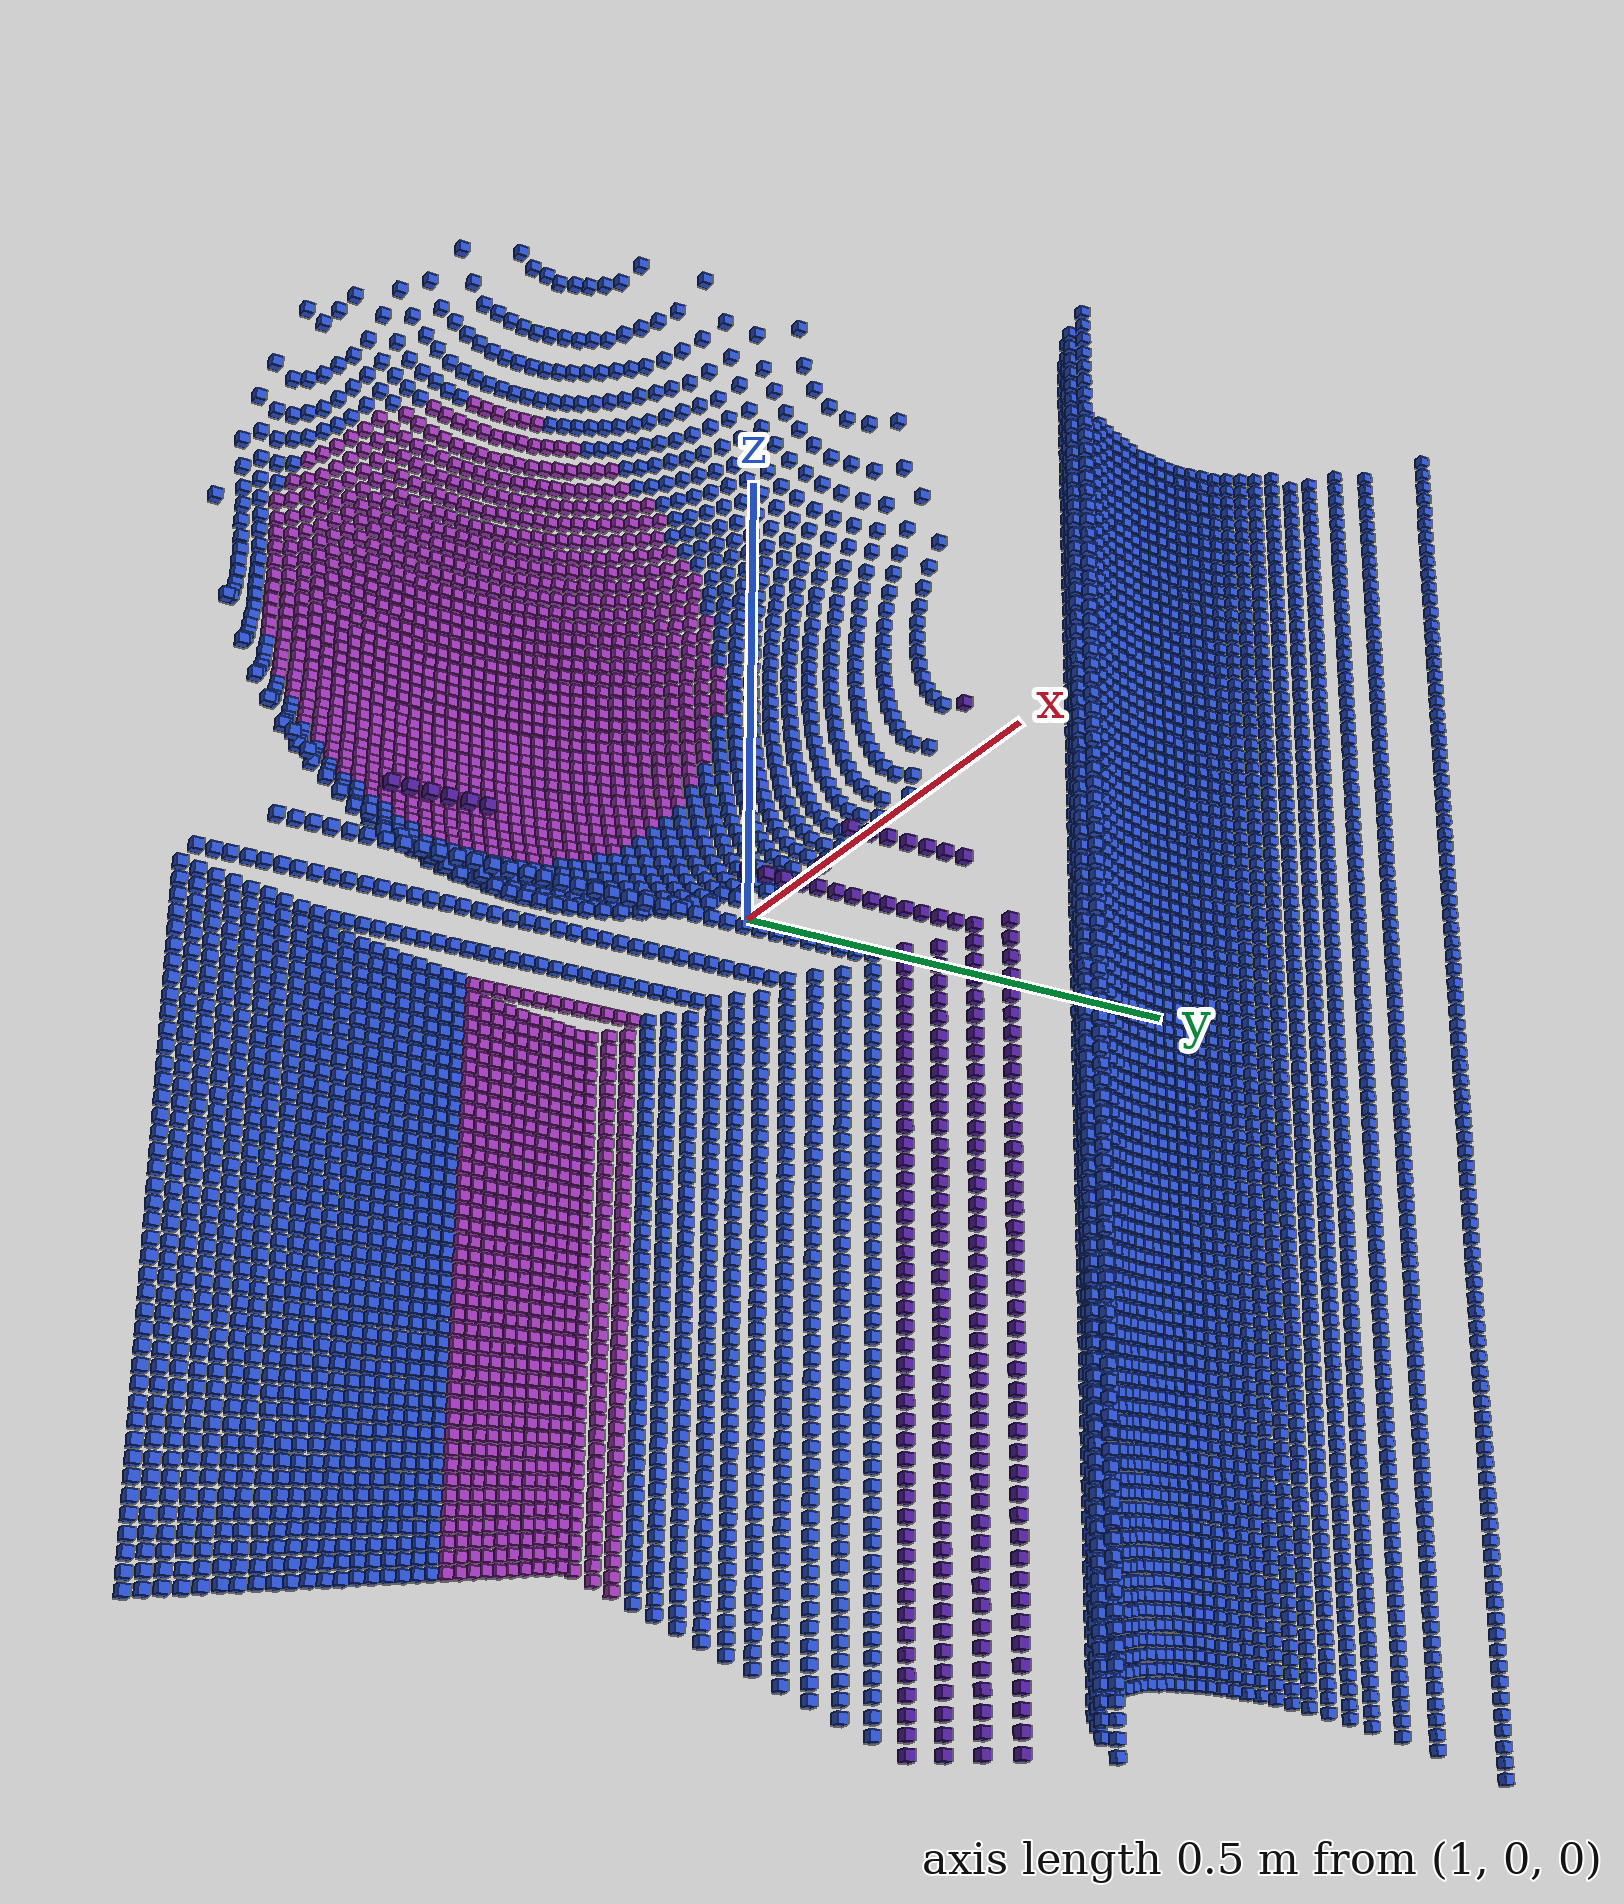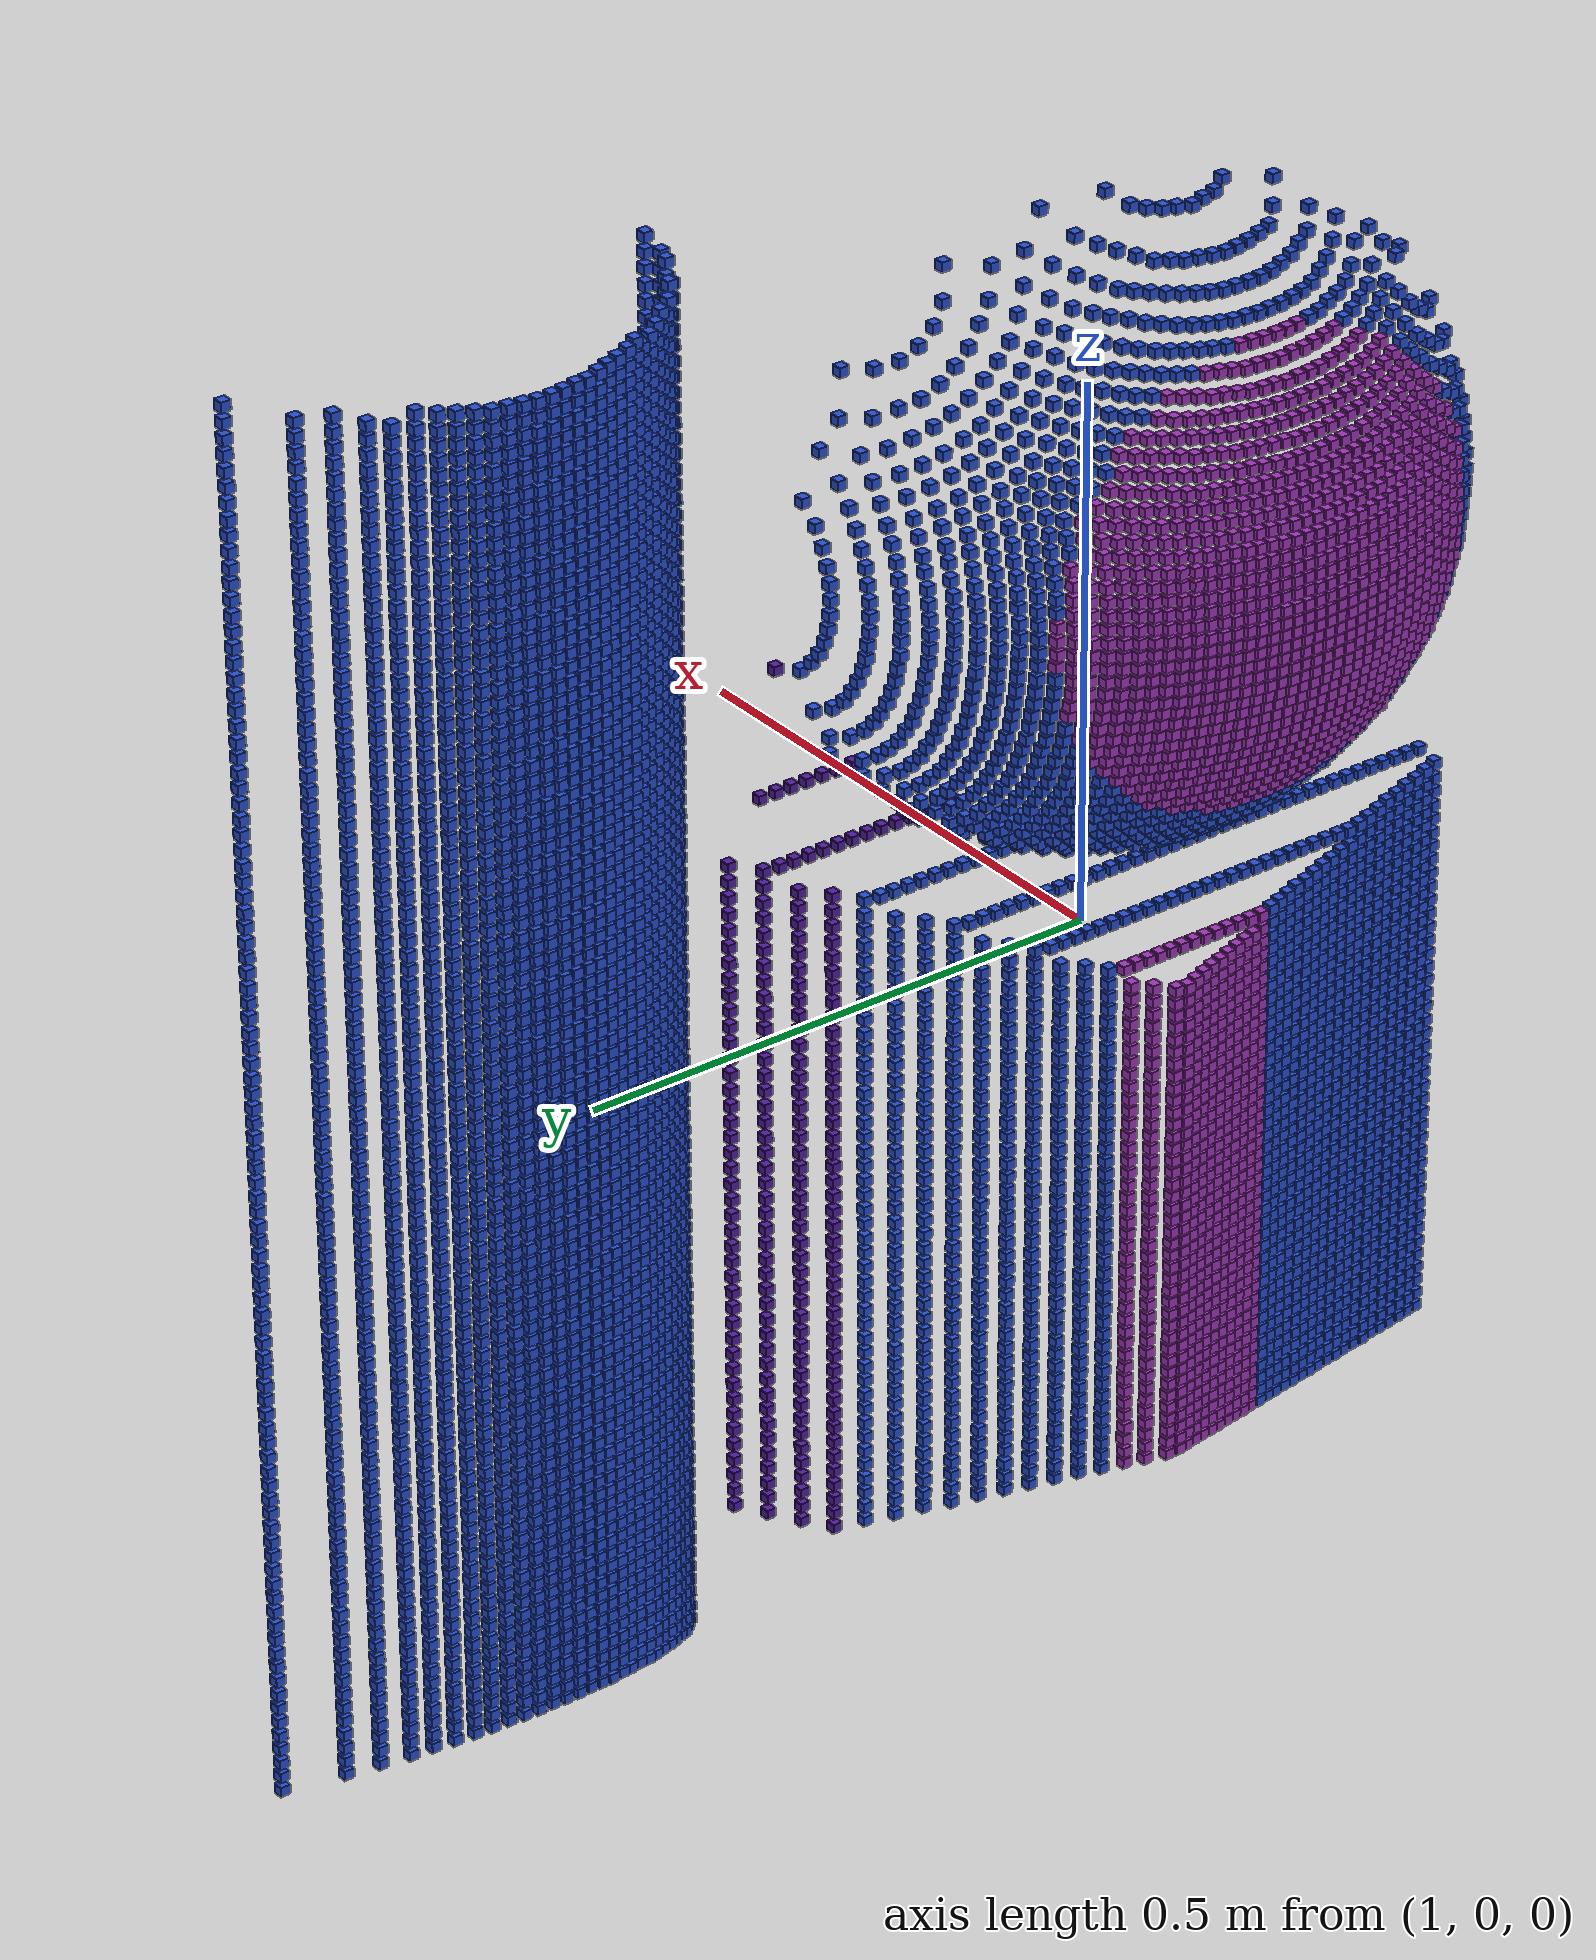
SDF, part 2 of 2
<geometry><box><size>0.01 0.01 0.01</size></box></geometry>
<material><script><uri>file://media/materials/scripts/gazebo.material</uri>
<name>Gazebo/Blue</name></script></material>
</visual>

<collision name="p3446c"><pose>1.612 -0.087 -0.272 0 0 0</pose>
<geometry><box><size>0.01 0.01 0.01</size></box></geometry>
</collision>
<visual name="p3446v"><pose>1.612 -0.087 -0.272 0 0 0</pose>
<geometry><box><size>0.01 0.01 0.01</size></box></geometry>
<material><script><uri>file://media/materials/scripts/gazebo.material</uri>
<name>Gazebo/Indigo</name></script></material>
</visual>

<collision name="p3447c"><pose>1.578 -0.101 -0.266 0 0 0</pose>
<geometry><box><size>0.01 0.01 0.01</size></box></geometry>
</collision>
<visual name="p3447v"><pose>1.578 -0.101 -0.266 0 0 0</pose>
<geometry><box><size>0.01 0.01 0.01</size></box></geometry>
<material><script><uri>file://media/materials/scripts/gazebo.material</uri>
<name>Gazebo/Indigo</name></script></material>
</visual>

<collision name="p3448c"><pose>1.544 -0.115 -0.261 0 0 0</pose>
<geometry><box><size>0.01 0.01 0.01</size></box></geometry>
</collision>
<visual name="p3448v"><pose>1.544 -0.115 -0.261 0 0 0</pose>
<geometry><box><size>0.01 0.01 0.01</size></box></geometry>
<material><script><uri>file://media/materials/scripts/gazebo.material</uri>
<name>Gazebo/Indigo</name></script></material>
</visual>

<collision name="p3449c"><pose>1.512 -0.129 -0.255 0 0 0</pose>
<geometry><box><size>0.01 0.01 0.01</size></box></geometry>
</collision>
<visual name="p3449v"><pose>1.512 -0.129 -0.255 0 0 0</pose>
<geometry><box><size>0.01 0.01 0.01</size></box></geometry>
<material><script><uri>file://media/materials/scripts/gazebo.material</uri>
<name>Gazebo/Indigo</name></script></material>
</visual>

<collision name="p3450c"><pose>1.482 -0.142 -0.250 0 0 0</pose>
<geometry><box><size>0.01 0.01 0.01</size></box></geometry>
</collision>
<visual name="p3450v"><pose>1.482 -0.142 -0.250 0 0 0</pose>
<geometry><box><size>0.01 0.01 0.01</size></box></geometry>
<material><script><uri>file://media/materials/scripts/gazebo.material</uri>
<name>Gazebo/Blue</name></script></material>
</visual>

<collision name="p3451c"><pose>1.478 -0.157 -0.250 0 0 0</pose>
<geometry><box><size>0.01 0.01 0.01</size></box></geometry>
</collision>
<visual name="p3451v"><pose>1.478 -0.157 -0.250 0 0 0</pose>
<geometry><box><size>0.01 0.01 0.01</size></box></geometry>
<material><script><uri>file://media/materials/scripts/gazebo.material</uri>
<name>Gazebo/Blue</name></script></material>
</visual>

<collision name="p3452c"><pose>1.478 -0.172 -0.250 0 0 0</pose>
<geometry><box><size>0.01 0.01 0.01</size></box></geometry>
</collision>
<visual name="p3452v"><pose>1.478 -0.172 -0.250 0 0 0</pose>
<geometry><box><size>0.01 0.01 0.01</size></box></geometry>
<material><script><uri>file://media/materials/scripts/gazebo.material</uri>
<name>Gazebo/Blue</name></script></material>
</visual>

<collision name="p3453c"><pose>1.478 -0.188 -0.250 0 0 0</pose>
<geometry><box><size>0.01 0.01 0.01</size></box></geometry>
</collision>
<visual name="p3453v"><pose>1.478 -0.188 -0.250 0 0 0</pose>
<geometry><box><size>0.01 0.01 0.01</size></box></geometry>
<material><script><uri>file://media/materials/scripts/gazebo.material</uri>
<name>Gazebo/Blue</name></script></material>
</visual>

<collision name="p3454c"><pose>1.478 -0.203 -0.250 0 0 0</pose>
<geometry><box><size>0.01 0.01 0.01</size></box></geometry>
</collision>
<visual name="p3454v"><pose>1.478 -0.203 -0.250 0 0 0</pose>
<geometry><box><size>0.01 0.01 0.01</size></box></geometry>
<material><script><uri>file://media/materials/scripts/gazebo.material</uri>
<name>Gazebo/Blue</name></script></material>
</visual>

<collision name="p3455c"><pose>1.478 -0.219 -0.250 0 0 0</pose>
<geometry><box><size>0.01 0.01 0.01</size></box></geometry>
</collision>
<visual name="p3455v"><pose>1.478 -0.219 -0.250 0 0 0</pose>
<geometry><box><size>0.01 0.01 0.01</size></box></geometry>
<material><script><uri>file://media/materials/scripts/gazebo.material</uri>
<name>Gazebo/Blue</name></script></material>
</visual>

<collision name="p3456c"><pose>1.478 -0.234 -0.250 0 0 0</pose>
<geometry><box><size>0.01 0.01 0.01</size></box></geometry>
</collision>
<visual name="p3456v"><pose>1.478 -0.234 -0.250 0 0 0</pose>
<geometry><box><size>0.01 0.01 0.01</size></box></geometry>
<material><script><uri>file://media/materials/scripts/gazebo.material</uri>
<name>Gazebo/Blue</name></script></material>
</visual>

<collision name="p3457c"><pose>1.478 -0.250 -0.250 0 0 0</pose>
<geometry><box><size>0.01 0.01 0.01</size></box></geometry>
</collision>
<visual name="p3457v"><pose>1.478 -0.250 -0.250 0 0 0</pose>
<geometry><box><size>0.01 0.01 0.01</size></box></geometry>
<material><script><uri>file://media/materials/scripts/gazebo.material</uri>
<name>Gazebo/Blue</name></script></material>
</visual>

<collision name="p3458c"><pose>1.478 -0.265 -0.250 0 0 0</pose>
<geometry><box><size>0.01 0.01 0.01</size></box></geometry>
</collision>
<visual name="p3458v"><pose>1.478 -0.265 -0.250 0 0 0</pose>
<geometry><box><size>0.01 0.01 0.01</size></box></geometry>
<material><script><uri>file://media/materials/scripts/gazebo.material</uri>
<name>Gazebo/Blue</name></script></material>
</visual>

<collision name="p3459c"><pose>1.478 -0.281 -0.250 0 0 0</pose>
<geometry><box><size>0.01 0.01 0.01</size></box></geometry>
</collision>
<visual name="p3459v"><pose>1.478 -0.281 -0.250 0 0 0</pose>
<geometry><box><size>0.01 0.01 0.01</size></box></geometry>
<material><script><uri>file://media/materials/scripts/gazebo.material</uri>
<name>Gazebo/Blue</name></script></material>
</visual>

<collision name="p3460c"><pose>1.478 -0.296 -0.250 0 0 0</pose>
<geometry><box><size>0.01 0.01 0.01</size></box></geometry>
</collision>
<visual name="p3460v"><pose>1.478 -0.296 -0.250 0 0 0</pose>
<geometry><box><size>0.01 0.01 0.01</size></box></geometry>
<material><script><uri>file://media/materials/scripts/gazebo.material</uri>
<name>Gazebo/Blue</name></script></material>
</visual>

<collision name="p3461c"><pose>1.478 -0.311 -0.250 0 0 0</pose>
<geometry><box><size>0.01 0.01 0.01</size></box></geometry>
</collision>
<visual name="p3461v"><pose>1.478 -0.311 -0.250 0 0 0</pose>
<geometry><box><size>0.01 0.01 0.01</size></box></geometry>
<material><script><uri>file://media/materials/scripts/gazebo.material</uri>
<name>Gazebo/Blue</name></script></material>
</visual>

<collision name="p3462c"><pose>1.478 -0.327 -0.250 0 0 0</pose>
<geometry><box><size>0.01 0.01 0.01</size></box></geometry>
</collision>
<visual name="p3462v"><pose>1.478 -0.327 -0.250 0 0 0</pose>
<geometry><box><size>0.01 0.01 0.01</size></box></geometry>
<material><script><uri>file://media/materials/scripts/gazebo.material</uri>
<name>Gazebo/Blue</name></script></material>
</visual>

<collision name="p3463c"><pose>1.478 -0.342 -0.250 0 0 0</pose>
<geometry><box><size>0.01 0.01 0.01</size></box></geometry>
</collision>
<visual name="p3463v"><pose>1.478 -0.342 -0.250 0 0 0</pose>
<geometry><box><size>0.01 0.01 0.01</size></box></geometry>
<material><script><uri>file://media/materials/scripts/gazebo.material</uri>
<name>Gazebo/Blue</name></script></material>
</visual>

<collision name="p3464c"><pose>1.478 -0.358 -0.250 0 0 0</pose>
<geometry><box><size>0.01 0.01 0.01</size></box></geometry>
</collision>
<visual name="p3464v"><pose>1.478 -0.358 -0.250 0 0 0</pose>
<geometry><box><size>0.01 0.01 0.01</size></box></geometry>
<material><script><uri>file://media/materials/scripts/gazebo.material</uri>
<name>Gazebo/Blue</name></script></material>
</visual>

<collision name="p3465c"><pose>1.478 -0.373 -0.250 0 0 0</pose>
<geometry><box><size>0.01 0.01 0.01</size></box></geometry>
</collision>
<visual name="p3465v"><pose>1.478 -0.373 -0.250 0 0 0</pose>
<geometry><box><size>0.01 0.01 0.01</size></box></geometry>
<material><script><uri>file://media/materials/scripts/gazebo.material</uri>
<name>Gazebo/Blue</name></script></material>
</visual>

<collision name="p3466c"><pose>1.478 -0.389 -0.250 0 0 0</pose>
<geometry><box><size>0.01 0.01 0.01</size></box></geometry>
</collision>
<visual name="p3466v"><pose>1.478 -0.389 -0.250 0 0 0</pose>
<geometry><box><size>0.01 0.01 0.01</size></box></geometry>
<material><script><uri>file://media/materials/scripts/gazebo.material</uri>
<name>Gazebo/Blue</name></script></material>
</visual>

<collision name="p3467c"><pose>1.478 -0.404 -0.250 0 0 0</pose>
<geometry><box><size>0.01 0.01 0.01</size></box></geometry>
</collision>
<visual name="p3467v"><pose>1.478 -0.404 -0.250 0 0 0</pose>
<geometry><box><size>0.01 0.01 0.01</size></box></geometry>
<material><script><uri>file://media/materials/scripts/gazebo.material</uri>
<name>Gazebo/Blue</name></script></material>
</visual>

<collision name="p3468c"><pose>1.478 -0.420 -0.250 0 0 0</pose>
<geometry><box><size>0.01 0.01 0.01</size></box></geometry>
</collision>
<visual name="p3468v"><pose>1.478 -0.420 -0.250 0 0 0</pose>
<geometry><box><size>0.01 0.01 0.01</size></box></geometry>
<material><script><uri>file://media/materials/scripts/gazebo.material</uri>
<name>Gazebo/Blue</name></script></material>
</visual>

<collision name="p3469c"><pose>1.478 -0.435 -0.250 0 0 0</pose>
<geometry><box><size>0.01 0.01 0.01</size></box></geometry>
</collision>
<visual name="p3469v"><pose>1.478 -0.435 -0.250 0 0 0</pose>
<geometry><box><size>0.01 0.01 0.01</size></box></geometry>
<material><script><uri>file://media/materials/scripts/gazebo.material</uri>
<name>Gazebo/Blue</name></script></material>
</visual>

<collision name="p3470c"><pose>1.478 -0.451 -0.250 0 0 0</pose>
<geometry><box><size>0.01 0.01 0.01</size></box></geometry>
</collision>
<visual name="p3470v"><pose>1.478 -0.451 -0.250 0 0 0</pose>
<geometry><box><size>0.01 0.01 0.01</size></box></geometry>
<material><script><uri>file://media/materials/scripts/gazebo.material</uri>
<name>Gazebo/Blue</name></script></material>
</visual>

<collision name="p3471c"><pose>1.478 -0.466 -0.250 0 0 0</pose>
<geometry><box><size>0.01 0.01 0.01</size></box></geometry>
</collision>
<visual name="p3471v"><pose>1.478 -0.466 -0.250 0 0 0</pose>
<geometry><box><size>0.01 0.01 0.01</size></box></geometry>
<material><script><uri>file://media/materials/scripts/gazebo.material</uri>
<name>Gazebo/Blue</name></script></material>
</visual>

<collision name="p3472c"><pose>1.478 -0.482 -0.250 0 0 0</pose>
<geometry><box><size>0.01 0.01 0.01</size></box></geometry>
</collision>
<visual name="p3472v"><pose>1.478 -0.482 -0.250 0 0 0</pose>
<geometry><box><size>0.01 0.01 0.01</size></box></geometry>
<material><script><uri>file://media/materials/scripts/gazebo.material</uri>
<name>Gazebo/Blue</name></script></material>
</visual>

<collision name="p3473c"><pose>1.478 -0.497 -0.250 0 0 0</pose>
<geometry><box><size>0.01 0.01 0.01</size></box></geometry>
</collision>
<visual name="p3473v"><pose>1.478 -0.497 -0.250 0 0 0</pose>
<geometry><box><size>0.01 0.01 0.01</size></box></geometry>
<material><script><uri>file://media/materials/scripts/gazebo.material</uri>
<name>Gazebo/Blue</name></script></material>
</visual>

<collision name="p3474c"><pose>1.478 -0.513 -0.250 0 0 0</pose>
<geometry><box><size>0.01 0.01 0.01</size></box></geometry>
</collision>
<visual name="p3474v"><pose>1.478 -0.513 -0.250 0 0 0</pose>
<geometry><box><size>0.01 0.01 0.01</size></box></geometry>
<material><script><uri>file://media/materials/scripts/gazebo.material</uri>
<name>Gazebo/Blue</name></script></material>
</visual>

<collision name="p3475c"><pose>1.478 -0.528 -0.250 0 0 0</pose>
<geometry><box><size>0.01 0.01 0.01</size></box></geometry>
</collision>
<visual name="p3475v"><pose>1.478 -0.528 -0.250 0 0 0</pose>
<geometry><box><size>0.01 0.01 0.01</size></box></geometry>
<material><script><uri>file://media/materials/scripts/gazebo.material</uri>
<name>Gazebo/Blue</name></script></material>
</visual>

<collision name="p3476c"><pose>1.478 -0.544 -0.250 0 0 0</pose>
<geometry><box><size>0.01 0.01 0.01</size></box></geometry>
</collision>
<visual name="p3476v"><pose>1.478 -0.544 -0.250 0 0 0</pose>
<geometry><box><size>0.01 0.01 0.01</size></box></geometry>
<material><script><uri>file://media/materials/scripts/gazebo.material</uri>
<name>Gazebo/Blue</name></script></material>
</visual>

<collision name="p3477c"><pose>1.478 -0.559 -0.250 0 0 0</pose>
<geometry><box><size>0.01 0.01 0.01</size></box></geometry>
</collision>
<visual name="p3477v"><pose>1.478 -0.559 -0.250 0 0 0</pose>
<geometry><box><size>0.01 0.01 0.01</size></box></geometry>
<material><script><uri>file://media/materials/scripts/gazebo.material</uri>
<name>Gazebo/Blue</name></script></material>
</visual>

<collision name="p3478c"><pose>1.478 -0.575 -0.250 0 0 0</pose>
<geometry><box><size>0.01 0.01 0.01</size></box></geometry>
</collision>
<visual name="p3478v"><pose>1.478 -0.575 -0.250 0 0 0</pose>
<geometry><box><size>0.01 0.01 0.01</size></box></geometry>
<material><script><uri>file://media/materials/scripts/gazebo.material</uri>
<name>Gazebo/Blue</name></script></material>
</visual>

<collision name="p3479c"><pose>1.478 -0.590 -0.250 0 0 0</pose>
<geometry><box><size>0.01 0.01 0.01</size></box></geometry>
</collision>
<visual name="p3479v"><pose>1.478 -0.590 -0.250 0 0 0</pose>
<geometry><box><size>0.01 0.01 0.01</size></box></geometry>
<material><script><uri>file://media/materials/scripts/gazebo.material</uri>
<name>Gazebo/Blue</name></script></material>
</visual>

<collision name="p3480c"><pose>1.478 -0.606 -0.250 0 0 0</pose>
<geometry><box><size>0.01 0.01 0.01</size></box></geometry>
</collision>
<visual name="p3480v"><pose>1.478 -0.606 -0.250 0 0 0</pose>
<geometry><box><size>0.01 0.01 0.01</size></box></geometry>
<material><script><uri>file://media/materials/scripts/gazebo.material</uri>
<name>Gazebo/Blue</name></script></material>
</visual>

<collision name="p3481c"><pose>1.478 -0.621 -0.250 0 0 0</pose>
<geometry><box><size>0.01 0.01 0.01</size></box></geometry>
</collision>
<visual name="p3481v"><pose>1.478 -0.621 -0.250 0 0 0</pose>
<geometry><box><size>0.01 0.01 0.01</size></box></geometry>
<material><script><uri>file://media/materials/scripts/gazebo.material</uri>
<name>Gazebo/Blue</name></script></material>
</visual>

<collision name="p3482c"><pose>1.478 -0.637 -0.250 0 0 0</pose>
<geometry><box><size>0.01 0.01 0.01</size></box></geometry>
</collision>
<visual name="p3482v"><pose>1.478 -0.637 -0.250 0 0 0</pose>
<geometry><box><size>0.01 0.01 0.01</size></box></geometry>
<material><script><uri>file://media/materials/scripts/gazebo.material</uri>
<name>Gazebo/Blue</name></script></material>
</visual>

<collision name="p3483c"><pose>1.478 -0.652 -0.250 0 0 0</pose>
<geometry><box><size>0.01 0.01 0.01</size></box></geometry>
</collision>
<visual name="p3483v"><pose>1.478 -0.652 -0.250 0 0 0</pose>
<geometry><box><size>0.01 0.01 0.01</size></box></geometry>
<material><script><uri>file://media/materials/scripts/gazebo.material</uri>
<name>Gazebo/Blue</name></script></material>
</visual>

<collision name="p3484c"><pose>1.478 -0.667 -0.250 0 0 0</pose>
<geometry><box><size>0.01 0.01 0.01</size></box></geometry>
</collision>
<visual name="p3484v"><pose>1.478 -0.667 -0.250 0 0 0</pose>
<geometry><box><size>0.01 0.01 0.01</size></box></geometry>
<material><script><uri>file://media/materials/scripts/gazebo.material</uri>
<name>Gazebo/Blue</name></script></material>
</visual>

<collision name="p3485c"><pose>1.478 -0.683 -0.250 0 0 0</pose>
<geometry><box><size>0.01 0.01 0.01</size></box></geometry>
</collision>
<visual name="p3485v"><pose>1.478 -0.683 -0.250 0 0 0</pose>
<geometry><box><size>0.01 0.01 0.01</size></box></geometry>
<material><script><uri>file://media/materials/scripts/gazebo.material</uri>
<name>Gazebo/Blue</name></script></material>
</visual>

<collision name="p3486c"><pose>1.397 0.569 -0.251 0 0 0</pose>
<geometry><box><size>0.01 0.01 0.01</size></box></geometry>
</collision>
<visual name="p3486v"><pose>1.397 0.569 -0.251 0 0 0</pose>
<geometry><box><size>0.01 0.01 0.01</size></box></geometry>
<material><script><uri>file://media/materials/scripts/gazebo.material</uri>
<name>Gazebo/Blue</name></script></material>
</visual>

<collision name="p3487c"><pose>1.347 0.534 -0.242 0 0 0</pose>
<geometry><box><size>0.01 0.01 0.01</size></box></geometry>
</collision>
<visual name="p3487v"><pose>1.347 0.534 -0.242 0 0 0</pose>
<geometry><box><size>0.01 0.01 0.01</size></box></geometry>
<material><script><uri>file://media/materials/scripts/gazebo.material</uri>
<name>Gazebo/Blue</name></script></material>
</visual>

<collision name="p3488c"><pose>1.325 0.512 -0.238 0 0 0</pose>
<geometry><box><size>0.01 0.01 0.01</size></box></geometry>
</collision>
<visual name="p3488v"><pose>1.325 0.512 -0.238 0 0 0</pose>
<geometry><box><size>0.01 0.01 0.01</size></box></geometry>
<material><script><uri>file://media/materials/scripts/gazebo.material</uri>
<name>Gazebo/Blue</name></script></material>
</visual>

<collision name="p3489c"><pose>1.308 0.491 -0.235 0 0 0</pose>
<geometry><box><size>0.01 0.01 0.01</size></box></geometry>
</collision>
<visual name="p3489v"><pose>1.308 0.491 -0.235 0 0 0</pose>
<geometry><box><size>0.01 0.01 0.01</size></box></geometry>
<material><script><uri>file://media/materials/scripts/gazebo.material</uri>
<name>Gazebo/Blue</name></script></material>
</visual>

<collision name="p3490c"><pose>1.298 0.474 -0.233 0 0 0</pose>
<geometry><box><size>0.01 0.01 0.01</size></box></geometry>
</collision>
<visual name="p3490v"><pose>1.298 0.474 -0.233 0 0 0</pose>
<geometry><box><size>0.01 0.01 0.01</size></box></geometry>
<material><script><uri>file://media/materials/scripts/gazebo.material</uri>
<name>Gazebo/Blue</name></script></material>
</visual>

<collision name="p3491c"><pose>1.289 0.457 -0.231 0 0 0</pose>
<geometry><box><size>0.01 0.01 0.01</size></box></geometry>
</collision>
<visual name="p3491v"><pose>1.289 0.457 -0.231 0 0 0</pose>
<geometry><box><size>0.01 0.01 0.01</size></box></geometry>
<material><script><uri>file://media/materials/scripts/gazebo.material</uri>
<name>Gazebo/Blue</name></script></material>
</visual>

<collision name="p3492c"><pose>1.281 0.441 -0.230 0 0 0</pose>
<geometry><box><size>0.01 0.01 0.01</size></box></geometry>
</collision>
<visual name="p3492v"><pose>1.281 0.441 -0.230 0 0 0</pose>
<geometry><box><size>0.01 0.01 0.01</size></box></geometry>
<material><script><uri>file://media/materials/scripts/gazebo.material</uri>
<name>Gazebo/Blue</name></script></material>
</visual>

<collision name="p3493c"><pose>1.276 0.426 -0.229 0 0 0</pose>
<geometry><box><size>0.01 0.01 0.01</size></box></geometry>
</collision>
<visual name="p3493v"><pose>1.276 0.426 -0.229 0 0 0</pose>
<geometry><box><size>0.01 0.01 0.01</size></box></geometry>
<material><script><uri>file://media/materials/scripts/gazebo.material</uri>
<name>Gazebo/Blue</name></script></material>
</visual>

<collision name="p3494c"><pose>1.272 0.411 -0.228 0 0 0</pose>
<geometry><box><size>0.01 0.01 0.01</size></box></geometry>
</collision>
<visual name="p3494v"><pose>1.272 0.411 -0.228 0 0 0</pose>
<geometry><box><size>0.01 0.01 0.01</size></box></geometry>
<material><script><uri>file://media/materials/scripts/gazebo.material</uri>
<name>Gazebo/Blue</name></script></material>
</visual>

<collision name="p3495c"><pose>1.268 0.397 -0.227 0 0 0</pose>
<geometry><box><size>0.01 0.01 0.01</size></box></geometry>
</collision>
<visual name="p3495v"><pose>1.268 0.397 -0.227 0 0 0</pose>
<geometry><box><size>0.01 0.01 0.01</size></box></geometry>
<material><script><uri>file://media/materials/scripts/gazebo.material</uri>
<name>Gazebo/Blue</name></script></material>
</visual>

<collision name="p3496c"><pose>1.266 0.383 -0.227 0 0 0</pose>
<geometry><box><size>0.01 0.01 0.01</size></box></geometry>
</collision>
<visual name="p3496v"><pose>1.266 0.383 -0.227 0 0 0</pose>
<geometry><box><size>0.01 0.01 0.01</size></box></geometry>
<material><script><uri>file://media/materials/scripts/gazebo.material</uri>
<name>Gazebo/Blue</name></script></material>
</visual>

<collision name="p3497c"><pose>1.265 0.369 -0.227 0 0 0</pose>
<geometry><box><size>0.01 0.01 0.01</size></box></geometry>
</collision>
<visual name="p3497v"><pose>1.265 0.369 -0.227 0 0 0</pose>
<geometry><box><size>0.01 0.01 0.01</size></box></geometry>
<material><script><uri>file://media/materials/scripts/gazebo.material</uri>
<name>Gazebo/Blue</name></script></material>
</visual>

<collision name="p3498c"><pose>1.263 0.356 -0.227 0 0 0</pose>
<geometry><box><size>0.01 0.01 0.01</size></box></geometry>
</collision>
<visual name="p3498v"><pose>1.263 0.356 -0.227 0 0 0</pose>
<geometry><box><size>0.01 0.01 0.01</size></box></geometry>
<material><script><uri>file://media/materials/scripts/gazebo.material</uri>
<name>Gazebo/Blue</name></script></material>
</visual>

<collision name="p3499c"><pose>1.263 0.342 -0.227 0 0 0</pose>
<geometry><box><size>0.01 0.01 0.01</size></box></geometry>
</collision>
<visual name="p3499v"><pose>1.263 0.342 -0.227 0 0 0</pose>
<geometry><box><size>0.01 0.01 0.01</size></box></geometry>
<material><script><uri>file://media/materials/scripts/gazebo.material</uri>
<name>Gazebo/Blue</name></script></material>
</visual>

<collision name="p3500c"><pose>1.265 0.329 -0.227 0 0 0</pose>
<geometry><box><size>0.01 0.01 0.01</size></box></geometry>
</collision>
<visual name="p3500v"><pose>1.265 0.329 -0.227 0 0 0</pose>
<geometry><box><size>0.01 0.01 0.01</size></box></geometry>
<material><script><uri>file://media/materials/scripts/gazebo.material</uri>
<name>Gazebo/Blue</name></script></material>
</visual>

<collision name="p3501c"><pose>1.266 0.316 -0.227 0 0 0</pose>
<geometry><box><size>0.01 0.01 0.01</size></box></geometry>
</collision>
<visual name="p3501v"><pose>1.266 0.316 -0.227 0 0 0</pose>
<geometry><box><size>0.01 0.01 0.01</size></box></geometry>
<material><script><uri>file://media/materials/scripts/gazebo.material</uri>
<name>Gazebo/Blue</name></script></material>
</visual>

<collision name="p3502c"><pose>1.267 0.304 -0.227 0 0 0</pose>
<geometry><box><size>0.01 0.01 0.01</size></box></geometry>
</collision>
<visual name="p3502v"><pose>1.267 0.304 -0.227 0 0 0</pose>
<geometry><box><size>0.01 0.01 0.01</size></box></geometry>
<material><script><uri>file://media/materials/scripts/gazebo.material</uri>
<name>Gazebo/Blue</name></script></material>
</visual>

<collision name="p3503c"><pose>1.270 0.291 -0.228 0 0 0</pose>
<geometry><box><size>0.01 0.01 0.01</size></box></geometry>
</collision>
<visual name="p3503v"><pose>1.270 0.291 -0.228 0 0 0</pose>
<geometry><box><size>0.01 0.01 0.01</size></box></geometry>
<material><script><uri>file://media/materials/scripts/gazebo.material</uri>
<name>Gazebo/Blue</name></script></material>
</visual>

<collision name="p3504c"><pose>1.274 0.279 -0.228 0 0 0</pose>
<geometry><box><size>0.01 0.01 0.01</size></box></geometry>
</collision>
<visual name="p3504v"><pose>1.274 0.279 -0.228 0 0 0</pose>
<geometry><box><size>0.01 0.01 0.01</size></box></geometry>
<material><script><uri>file://media/materials/scripts/gazebo.material</uri>
<name>Gazebo/Blue</name></script></material>
</visual>

<collision name="p3505c"><pose>1.278 0.266 -0.229 0 0 0</pose>
<geometry><box><size>0.01 0.01 0.01</size></box></geometry>
</collision>
<visual name="p3505v"><pose>1.278 0.266 -0.229 0 0 0</pose>
<geometry><box><size>0.01 0.01 0.01</size></box></geometry>
<material><script><uri>file://media/materials/scripts/gazebo.material</uri>
<name>Gazebo/Blue</name></script></material>
</visual>

<collision name="p3506c"><pose>1.282 0.253 -0.230 0 0 0</pose>
<geometry><box><size>0.01 0.01 0.01</size></box></geometry>
</collision>
<visual name="p3506v"><pose>1.282 0.253 -0.230 0 0 0</pose>
<geometry><box><size>0.01 0.01 0.01</size></box></geometry>
<material><script><uri>file://media/materials/scripts/gazebo.material</uri>
<name>Gazebo/Blue</name></script></material>
</visual>

<collision name="p3507c"><pose>1.288 0.241 -0.231 0 0 0</pose>
<geometry><box><size>0.01 0.01 0.01</size></box></geometry>
</collision>
<visual name="p3507v"><pose>1.288 0.241 -0.231 0 0 0</pose>
<geometry><box><size>0.01 0.01 0.01</size></box></geometry>
<material><script><uri>file://media/materials/scripts/gazebo.material</uri>
<name>Gazebo/Blue</name></script></material>
</visual>

<collision name="p3508c"><pose>1.295 0.229 -0.232 0 0 0</pose>
<geometry><box><size>0.01 0.01 0.01</size></box></geometry>
</collision>
<visual name="p3508v"><pose>1.295 0.229 -0.232 0 0 0</pose>
<geometry><box><size>0.01 0.01 0.01</size></box></geometry>
<material><script><uri>file://media/materials/scripts/gazebo.material</uri>
<name>Gazebo/Blue</name></script></material>
</visual>

<collision name="p3509c"><pose>1.302 0.216 -0.233 0 0 0</pose>
<geometry><box><size>0.01 0.01 0.01</size></box></geometry>
</collision>
<visual name="p3509v"><pose>1.302 0.216 -0.233 0 0 0</pose>
<geometry><box><size>0.01 0.01 0.01</size></box></geometry>
<material><script><uri>file://media/materials/scripts/gazebo.material</uri>
<name>Gazebo/Blue</name></script></material>
</visual>

<collision name="p3510c"><pose>1.310 0.204 -0.235 0 0 0</pose>
<geometry><box><size>0.01 0.01 0.01</size></box></geometry>
</collision>
<visual name="p3510v"><pose>1.310 0.204 -0.235 0 0 0</pose>
<geometry><box><size>0.01 0.01 0.01</size></box></geometry>
<material><script><uri>file://media/materials/scripts/gazebo.material</uri>
<name>Gazebo/Blue</name></script></material>
</visual>

<collision name="p3511c"><pose>1.320 0.192 -0.237 0 0 0</pose>
<geometry><box><size>0.01 0.01 0.01</size></box></geometry>
</collision>
<visual name="p3511v"><pose>1.320 0.192 -0.237 0 0 0</pose>
<geometry><box><size>0.01 0.01 0.01</size></box></geometry>
<material><script><uri>file://media/materials/scripts/gazebo.material</uri>
<name>Gazebo/Blue</name></script></material>
</visual>

<collision name="p3512c"><pose>1.330 0.179 -0.239 0 0 0</pose>
<geometry><box><size>0.01 0.01 0.01</size></box></geometry>
</collision>
<visual name="p3512v"><pose>1.330 0.179 -0.239 0 0 0</pose>
<geometry><box><size>0.01 0.01 0.01</size></box></geometry>
<material><script><uri>file://media/materials/scripts/gazebo.material</uri>
<name>Gazebo/Blue</name></script></material>
</visual>

<collision name="p3513c"><pose>1.343 0.167 -0.241 0 0 0</pose>
<geometry><box><size>0.01 0.01 0.01</size></box></geometry>
</collision>
<visual name="p3513v"><pose>1.343 0.167 -0.241 0 0 0</pose>
<geometry><box><size>0.01 0.01 0.01</size></box></geometry>
<material><script><uri>file://media/materials/scripts/gazebo.material</uri>
<name>Gazebo/Blue</name></script></material>
</visual>

<collision name="p3514c"><pose>1.358 0.155 -0.243 0 0 0</pose>
<geometry><box><size>0.01 0.01 0.01</size></box></geometry>
</collision>
<visual name="p3514v"><pose>1.358 0.155 -0.243 0 0 0</pose>
<geometry><box><size>0.01 0.01 0.01</size></box></geometry>
<material><script><uri>file://media/materials/scripts/gazebo.material</uri>
<name>Gazebo/Blue</name></script></material>
</visual>

<collision name="p3515c"><pose>1.373 0.142 -0.246 0 0 0</pose>
<geometry><box><size>0.01 0.01 0.01</size></box></geometry>
</collision>
<visual name="p3515v"><pose>1.373 0.142 -0.246 0 0 0</pose>
<geometry><box><size>0.01 0.01 0.01</size></box></geometry>
<material><script><uri>file://media/materials/scripts/gazebo.material</uri>
<name>Gazebo/Blue</name></script></material>
</visual>

<collision name="p3516c"><pose>1.396 0.130 -0.250 0 0 0</pose>
<geometry><box><size>0.01 0.01 0.01</size></box></geometry>
</collision>
<visual name="p3516v"><pose>1.396 0.130 -0.250 0 0 0</pose>
<geometry><box><size>0.01 0.01 0.01</size></box></geometry>
<material><script><uri>file://media/materials/scripts/gazebo.material</uri>
<name>Gazebo/Blue</name></script></material>
</visual>

<collision name="p3517c"><pose>1.421 0.117 -0.255 0 0 0</pose>
<geometry><box><size>0.01 0.01 0.01</size></box></geometry>
</collision>
<visual name="p3517v"><pose>1.421 0.117 -0.255 0 0 0</pose>
<geometry><box><size>0.01 0.01 0.01</size></box></geometry>
<material><script><uri>file://media/materials/scripts/gazebo.material</uri>
<name>Gazebo/Blue</name></script></material>
</visual>

<collision name="p3518c"><pose>1.460 0.105 -0.262 0 0 0</pose>
<geometry><box><size>0.01 0.01 0.01</size></box></geometry>
</collision>
<visual name="p3518v"><pose>1.460 0.105 -0.262 0 0 0</pose>
<geometry><box><size>0.01 0.01 0.01</size></box></geometry>
<material><script><uri>file://media/materials/scripts/gazebo.material</uri>
<name>Gazebo/Blue</name></script></material>
</visual>

<collision name="p3519c"><pose>1.612 -0.087 -0.289 0 0 0</pose>
<geometry><box><size>0.01 0.01 0.01</size></box></geometry>
</collision>
<visual name="p3519v"><pose>1.612 -0.087 -0.289 0 0 0</pose>
<geometry><box><size>0.01 0.01 0.01</size></box></geometry>
<material><script><uri>file://media/materials/scripts/gazebo.material</uri>
<name>Gazebo/Indigo</name></script></material>
</visual>

<collision name="p3520c"><pose>1.578 -0.101 -0.283 0 0 0</pose>
<geometry><box><size>0.01 0.01 0.01</size></box></geometry>
</collision>
<visual name="p3520v"><pose>1.578 -0.101 -0.283 0 0 0</pose>
<geometry><box><size>0.01 0.01 0.01</size></box></geometry>
<material><script><uri>file://media/materials/scripts/gazebo.material</uri>
<name>Gazebo/Indigo</name></script></material>
</visual>

<collision name="p3521c"><pose>1.544 -0.115 -0.277 0 0 0</pose>
<geometry><box><size>0.01 0.01 0.01</size></box></geometry>
</collision>
<visual name="p3521v"><pose>1.544 -0.115 -0.277 0 0 0</pose>
<geometry><box><size>0.01 0.01 0.01</size></box></geometry>
<material><script><uri>file://media/materials/scripts/gazebo.material</uri>
<name>Gazebo/Indigo</name></script></material>
</visual>

<collision name="p3522c"><pose>1.512 -0.129 -0.271 0 0 0</pose>
<geometry><box><size>0.01 0.01 0.01</size></box></geometry>
</collision>
<visual name="p3522v"><pose>1.512 -0.129 -0.271 0 0 0</pose>
<geometry><box><size>0.01 0.01 0.01</size></box></geometry>
<material><script><uri>file://media/materials/scripts/gazebo.material</uri>
<name>Gazebo/Indigo</name></script></material>
</visual>

<collision name="p3523c"><pose>1.482 -0.142 -0.266 0 0 0</pose>
<geometry><box><size>0.01 0.01 0.01</size></box></geometry>
</collision>
<visual name="p3523v"><pose>1.482 -0.142 -0.266 0 0 0</pose>
<geometry><box><size>0.01 0.01 0.01</size></box></geometry>
<material><script><uri>file://media/materials/scripts/gazebo.material</uri>
<name>Gazebo/Blue</name></script></material>
</visual>

<collision name="p3524c"><pose>1.452 -0.154 -0.260 0 0 0</pose>
<geometry><box><size>0.01 0.01 0.01</size></box></geometry>
</collision>
<visual name="p3524v"><pose>1.452 -0.154 -0.260 0 0 0</pose>
<geometry><box><size>0.01 0.01 0.01</size></box></geometry>
<material><script><uri>file://media/materials/scripts/gazebo.material</uri>
<name>Gazebo/Blue</name></script></material>
</visual>

<collision name="p3525c"><pose>1.424 -0.166 -0.255 0 0 0</pose>
<geometry><box><size>0.01 0.01 0.01</size></box></geometry>
</collision>
<visual name="p3525v"><pose>1.424 -0.166 -0.255 0 0 0</pose>
<geometry><box><size>0.01 0.01 0.01</size></box></geometry>
<material><script><uri>file://media/materials/scripts/gazebo.material</uri>
<name>Gazebo/Blue</name></script></material>
</visual>

<collision name="p3526c"><pose>1.396 -0.177 -0.250 0 0 0</pose>
<geometry><box><size>0.01 0.01 0.01</size></box></geometry>
</collision>
<visual name="p3526v"><pose>1.396 -0.177 -0.250 0 0 0</pose>
<geometry><box><size>0.01 0.01 0.01</size></box></geometry>
<material><script><uri>file://media/materials/scripts/gazebo.material</uri>
<name>Gazebo/Blue</name></script></material>
</visual>

<collision name="p3527c"><pose>1.392 -0.191 -0.250 0 0 0</pose>
<geometry><box><size>0.01 0.01 0.01</size></box></geometry>
</collision>
<visual name="p3527v"><pose>1.392 -0.191 -0.250 0 0 0</pose>
<geometry><box><size>0.01 0.01 0.01</size></box></geometry>
<material><script><uri>file://media/materials/scripts/gazebo.material</uri>
<name>Gazebo/Blue</name></script></material>
</visual>

<collision name="p3528c"><pose>1.392 -0.206 -0.250 0 0 0</pose>
<geometry><box><size>0.01 0.01 0.01</size></box></geometry>
</collision>
<visual name="p3528v"><pose>1.392 -0.206 -0.250 0 0 0</pose>
<geometry><box><size>0.01 0.01 0.01</size></box></geometry>
<material><script><uri>file://media/materials/scripts/gazebo.material</uri>
<name>Gazebo/Blue</name></script></material>
</visual>

<collision name="p3529c"><pose>1.392 -0.220 -0.250 0 0 0</pose>
<geometry><box><size>0.01 0.01 0.01</size></box></geometry>
</collision>
<visual name="p3529v"><pose>1.392 -0.220 -0.250 0 0 0</pose>
<geometry><box><size>0.01 0.01 0.01</size></box></geometry>
<material><script><uri>file://media/materials/scripts/gazebo.material</uri>
<name>Gazebo/Blue</name></script></material>
</visual>

<collision name="p3530c"><pose>1.392 -0.235 -0.250 0 0 0</pose>
<geometry><box><size>0.01 0.01 0.01</size></box></geometry>
</collision>
<visual name="p3530v"><pose>1.392 -0.235 -0.250 0 0 0</pose>
<geometry><box><size>0.01 0.01 0.01</size></box></geometry>
<material><script><uri>file://media/materials/scripts/gazebo.material</uri>
<name>Gazebo/Blue</name></script></material>
</visual>

<collision name="p3531c"><pose>1.392 -0.250 -0.250 0 0 0</pose>
<geometry><box><size>0.01 0.01 0.01</size></box></geometry>
</collision>
<visual name="p3531v"><pose>1.392 -0.250 -0.250 0 0 0</pose>
<geometry><box><size>0.01 0.01 0.01</size></box></geometry>
<material><script><uri>file://media/materials/scripts/gazebo.material</uri>
<name>Gazebo/Blue</name></script></material>
</visual>

<collision name="p3532c"><pose>1.392 -0.264 -0.250 0 0 0</pose>
<geometry><box><size>0.01 0.01 0.01</size></box></geometry>
</collision>
<visual name="p3532v"><pose>1.392 -0.264 -0.250 0 0 0</pose>
<geometry><box><size>0.01 0.01 0.01</size></box></geometry>
<material><script><uri>file://media/materials/scripts/gazebo.material</uri>
<name>Gazebo/Blue</name></script></material>
</visual>

<collision name="p3533c"><pose>1.392 -0.279 -0.250 0 0 0</pose>
<geometry><box><size>0.01 0.01 0.01</size></box></geometry>
</collision>
<visual name="p3533v"><pose>1.392 -0.279 -0.250 0 0 0</pose>
<geometry><box><size>0.01 0.01 0.01</size></box></geometry>
<material><script><uri>file://media/materials/scripts/gazebo.material</uri>
<name>Gazebo/Blue</name></script></material>
</visual>

<collision name="p3534c"><pose>1.392 -0.293 -0.250 0 0 0</pose>
<geometry><box><size>0.01 0.01 0.01</size></box></geometry>
</collision>
<visual name="p3534v"><pose>1.392 -0.293 -0.250 0 0 0</pose>
<geometry><box><size>0.01 0.01 0.01</size></box></geometry>
<material><script><uri>file://media/materials/scripts/gazebo.material</uri>
<name>Gazebo/Blue</name></script></material>
</visual>

<collision name="p3535c"><pose>1.392 -0.308 -0.250 0 0 0</pose>
<geometry><box><size>0.01 0.01 0.01</size></box></geometry>
</collision>
<visual name="p3535v"><pose>1.392 -0.308 -0.250 0 0 0</pose>
<geometry><box><size>0.01 0.01 0.01</size></box></geometry>
<material><script><uri>file://media/materials/scripts/gazebo.material</uri>
<name>Gazebo/Blue</name></script></material>
</visual>

<collision name="p3536c"><pose>1.392 -0.322 -0.250 0 0 0</pose>
<geometry><box><size>0.01 0.01 0.01</size></box></geometry>
</collision>
<visual name="p3536v"><pose>1.392 -0.322 -0.250 0 0 0</pose>
<geometry><box><size>0.01 0.01 0.01</size></box></geometry>
<material><script><uri>file://media/materials/scripts/gazebo.material</uri>
<name>Gazebo/Blue</name></script></material>
</visual>

<collision name="p3537c"><pose>1.392 -0.337 -0.250 0 0 0</pose>
<geometry><box><size>0.01 0.01 0.01</size></box></geometry>
</collision>
<visual name="p3537v"><pose>1.392 -0.337 -0.250 0 0 0</pose>
<geometry><box><size>0.01 0.01 0.01</size></box></geometry>
<material><script><uri>file://media/materials/scripts/gazebo.material</uri>
<name>Gazebo/Blue</name></script></material>
</visual>

<collision name="p3538c"><pose>1.392 -0.352 -0.250 0 0 0</pose>
<geometry><box><size>0.01 0.01 0.01</size></box></geometry>
</collision>
<visual name="p3538v"><pose>1.392 -0.352 -0.250 0 0 0</pose>
<geometry><box><size>0.01 0.01 0.01</size></box></geometry>
<material><script><uri>file://media/materials/scripts/gazebo.material</uri>
<name>Gazebo/Blue</name></script></material>
</visual>

<collision name="p3539c"><pose>1.392 -0.366 -0.250 0 0 0</pose>
<geometry><box><size>0.01 0.01 0.01</size></box></geometry>
</collision>
<visual name="p3539v"><pose>1.392 -0.366 -0.250 0 0 0</pose>
<geometry><box><size>0.01 0.01 0.01</size></box></geometry>
<material><script><uri>file://media/materials/scripts/gazebo.material</uri>
<name>Gazebo/Blue</name></script></material>
</visual>

<collision name="p3540c"><pose>1.392 -0.381 -0.250 0 0 0</pose>
<geometry><box><size>0.01 0.01 0.01</size></box></geometry>
</collision>
<visual name="p3540v"><pose>1.392 -0.381 -0.250 0 0 0</pose>
<geometry><box><size>0.01 0.01 0.01</size></box></geometry>
<material><script><uri>file://media/materials/scripts/gazebo.material</uri>
<name>Gazebo/Blue</name></script></material>
</visual>

<collision name="p3541c"><pose>1.392 -0.395 -0.250 0 0 0</pose>
<geometry><box><size>0.01 0.01 0.01</size></box></geometry>
</collision>
<visual name="p3541v"><pose>1.392 -0.395 -0.250 0 0 0</pose>
<geometry><box><size>0.01 0.01 0.01</size></box></geometry>
<material><script><uri>file://media/materials/scripts/gazebo.material</uri>
<name>Gazebo/Blue</name></script></material>
</visual>

<collision name="p3542c"><pose>1.392 -0.410 -0.250 0 0 0</pose>
<geometry><box><size>0.01 0.01 0.01</size></box></geometry>
</collision>
<visual name="p3542v"><pose>1.392 -0.410 -0.250 0 0 0</pose>
<geometry><box><size>0.01 0.01 0.01</size></box></geometry>
<material><script><uri>file://media/materials/scripts/gazebo.material</uri>
<name>Gazebo/Blue</name></script></material>
</visual>

<collision name="p3543c"><pose>1.392 -0.424 -0.250 0 0 0</pose>
<geometry><box><size>0.01 0.01 0.01</size></box></geometry>
</collision>
<visual name="p3543v"><pose>1.392 -0.424 -0.250 0 0 0</pose>
<geometry><box><size>0.01 0.01 0.01</size></box></geometry>
<material><script><uri>file://media/materials/scripts/gazebo.material</uri>
<name>Gazebo/Blue</name></script></material>
</visual>

<collision name="p3544c"><pose>1.392 -0.439 -0.250 0 0 0</pose>
<geometry><box><size>0.01 0.01 0.01</size></box></geometry>
</collision>
<visual name="p3544v"><pose>1.392 -0.439 -0.250 0 0 0</pose>
<geometry><box><size>0.01 0.01 0.01</size></box></geometry>
<material><script><uri>file://media/materials/scripts/gazebo.material</uri>
<name>Gazebo/Blue</name></script></material>
</visual>

<collision name="p3545c"><pose>1.392 -0.454 -0.250 0 0 0</pose>
<geometry><box><size>0.01 0.01 0.01</size></box></geometry>
</collision>
<visual name="p3545v"><pose>1.392 -0.454 -0.250 0 0 0</pose>
<geometry><box><size>0.01 0.01 0.01</size></box></geometry>
<material><script><uri>file://media/materials/scripts/gazebo.material</uri>
<name>Gazebo/Blue</name></script></material>
</visual>

<collision name="p3546c"><pose>1.392 -0.468 -0.250 0 0 0</pose>
<geometry><box><size>0.01 0.01 0.01</size></box></geometry>
</collision>
<visual name="p3546v"><pose>1.392 -0.468 -0.250 0 0 0</pose>
<geometry><box><size>0.01 0.01 0.01</size></box></geometry>
<material><script><uri>file://media/materials/scripts/gazebo.material</uri>
<name>Gazebo/Blue</name></script></material>
</visual>

<collision name="p3547c"><pose>1.392 -0.483 -0.250 0 0 0</pose>
<geometry><box><size>0.01 0.01 0.01</size></box></geometry>
</collision>
<visual name="p3547v"><pose>1.392 -0.483 -0.250 0 0 0</pose>
<geometry><box><size>0.01 0.01 0.01</size></box></geometry>
<material><script><uri>file://media/materials/scripts/gazebo.material</uri>
<name>Gazebo/Blue</name></script></material>
</visual>

<collision name="p3548c"><pose>1.392 -0.497 -0.250 0 0 0</pose>
<geometry><box><size>0.01 0.01 0.01</size></box></geometry>
</collision>
<visual name="p3548v"><pose>1.392 -0.497 -0.250 0 0 0</pose>
<geometry><box><size>0.01 0.01 0.01</size></box></geometry>
<material><script><uri>file://media/materials/scripts/gazebo.material</uri>
<name>Gazebo/Blue</name></script></material>
</visual>

<collision name="p3549c"><pose>1.392 -0.512 -0.250 0 0 0</pose>
<geometry><box><size>0.01 0.01 0.01</size></box></geometry>
</collision>
<visual name="p3549v"><pose>1.392 -0.512 -0.250 0 0 0</pose>
<geometry><box><size>0.01 0.01 0.01</size></box></geometry>
<material><script><uri>file://media/materials/scripts/gazebo.material</uri>
<name>Gazebo/Blue</name></script></material>
</visual>

<collision name="p3550c"><pose>1.392 -0.526 -0.250 0 0 0</pose>
<geometry><box><size>0.01 0.01 0.01</size></box></geometry>
</collision>
<visual name="p3550v"><pose>1.392 -0.526 -0.250 0 0 0</pose>
<geometry><box><size>0.01 0.01 0.01</size></box></geometry>
<material><script><uri>file://media/materials/scripts/gazebo.material</uri>
<name>Gazebo/Blue</name></script></material>
</visual>

<collision name="p3551c"><pose>1.392 -0.541 -0.250 0 0 0</pose>
<geometry><box><size>0.01 0.01 0.01</size></box></geometry>
</collision>
<visual name="p3551v"><pose>1.392 -0.541 -0.250 0 0 0</pose>
<geometry><box><size>0.01 0.01 0.01</size></box></geometry>
<material><script><uri>file://media/materials/scripts/gazebo.material</uri>
<name>Gazebo/Blue</name></script></material>
</visual>

<collision name="p3552c"><pose>1.392 -0.556 -0.250 0 0 0</pose>
<geometry><box><size>0.01 0.01 0.01</size></box></geometry>
</collision>
<visual name="p3552v"><pose>1.392 -0.556 -0.250 0 0 0</pose>
<geometry><box><size>0.01 0.01 0.01</size></box></geometry>
<material><script><uri>file://media/materials/scripts/gazebo.material</uri>
<name>Gazebo/Blue</name></script></material>
</visual>

<collision name="p3553c"><pose>1.392 -0.570 -0.250 0 0 0</pose>
<geometry><box><size>0.01 0.01 0.01</size></box></geometry>
</collision>
<visual name="p3553v"><pose>1.392 -0.570 -0.250 0 0 0</pose>
<geometry><box><size>0.01 0.01 0.01</size></box></geometry>
<material><script><uri>file://media/materials/scripts/gazebo.material</uri>
<name>Gazebo/Blue</name></script></material>
</visual>

<collision name="p3554c"><pose>1.392 -0.585 -0.250 0 0 0</pose>
<geometry><box><size>0.01 0.01 0.01</size></box></geometry>
</collision>
<visual name="p3554v"><pose>1.392 -0.585 -0.250 0 0 0</pose>
<geometry><box><size>0.01 0.01 0.01</size></box></geometry>
<material><script><uri>file://media/materials/scripts/gazebo.material</uri>
<name>Gazebo/Blue</name></script></material>
</visual>

<collision name="p3555c"><pose>1.392 -0.599 -0.250 0 0 0</pose>
<geometry><box><size>0.01 0.01 0.01</size></box></geometry>
</collision>
<visual name="p3555v"><pose>1.392 -0.599 -0.250 0 0 0</pose>
<geometry><box><size>0.01 0.01 0.01</size></box></geometry>
<material><script><uri>file://media/materials/scripts/gazebo.material</uri>
<name>Gazebo/Blue</name></script></material>
</visual>

<collision name="p3556c"><pose>1.392 -0.614 -0.250 0 0 0</pose>
<geometry><box><size>0.01 0.01 0.01</size></box></geometry>
</collision>
<visual name="p3556v"><pose>1.392 -0.614 -0.250 0 0 0</pose>
<geometry><box><size>0.01 0.01 0.01</size></box></geometry>
<material><script><uri>file://media/materials/scripts/gazebo.material</uri>
<name>Gazebo/Blue</name></script></material>
</visual>

<collision name="p3557c"><pose>1.392 -0.629 -0.250 0 0 0</pose>
<geometry><box><size>0.01 0.01 0.01</size></box></geometry>
</collision>
<visual name="p3557v"><pose>1.392 -0.629 -0.250 0 0 0</pose>
<geometry><box><size>0.01 0.01 0.01</size></box></geometry>
<material><script><uri>file://media/materials/scripts/gazebo.material</uri>
<name>Gazebo/Blue</name></script></material>
</visual>

<collision name="p3558c"><pose>1.392 -0.643 -0.250 0 0 0</pose>
<geometry><box><size>0.01 0.01 0.01</size></box></geometry>
</collision>
<visual name="p3558v"><pose>1.392 -0.643 -0.250 0 0 0</pose>
<geometry><box><size>0.01 0.01 0.01</size></box></geometry>
<material><script><uri>file://media/materials/scripts/gazebo.material</uri>
<name>Gazebo/Blue</name></script></material>
</visual>

<collision name="p3559c"><pose>1.392 -0.658 -0.250 0 0 0</pose>
<geometry><box><size>0.01 0.01 0.01</size></box></geometry>
</collision>
<visual name="p3559v"><pose>1.392 -0.658 -0.250 0 0 0</pose>
<geometry><box><size>0.01 0.01 0.01</size></box></geometry>
<material><script><uri>file://media/materials/scripts/gazebo.material</uri>
<name>Gazebo/Blue</name></script></material>
</visual>

<collision name="p3560c"><pose>1.392 -0.672 -0.250 0 0 0</pose>
<geometry><box><size>0.01 0.01 0.01</size></box></geometry>
</collision>
<visual name="p3560v"><pose>1.392 -0.672 -0.250 0 0 0</pose>
<geometry><box><size>0.01 0.01 0.01</size></box></geometry>
<material><script><uri>file://media/materials/scripts/gazebo.material</uri>
<name>Gazebo/Blue</name></script></material>
</visual>

<collision name="p3561c"><pose>1.392 -0.687 -0.250 0 0 0</pose>
<geometry><box><size>0.01 0.01 0.01</size></box></geometry>
</collision>
<visual name="p3561v"><pose>1.392 -0.687 -0.250 0 0 0</pose>
<geometry><box><size>0.01 0.01 0.01</size></box></geometry>
<material><script><uri>file://media/materials/scripts/gazebo.material</uri>
<name>Gazebo/Blue</name></script></material>
</visual>

<collision name="p3562c"><pose>1.392 -0.701 -0.250 0 0 0</pose>
<geometry><box><size>0.01 0.01 0.01</size></box></geometry>
</collision>
<visual name="p3562v"><pose>1.392 -0.701 -0.250 0 0 0</pose>
<geometry><box><size>0.01 0.01 0.01</size></box></geometry>
<material><script><uri>file://media/materials/scripts/gazebo.material</uri>
<name>Gazebo/Blue</name></script></material>
</visual>

<collision name="p3563c"><pose>1.392 -0.716 -0.250 0 0 0</pose>
<geometry><box><size>0.01 0.01 0.01</size></box></geometry>
</collision>
<visual name="p3563v"><pose>1.392 -0.716 -0.250 0 0 0</pose>
<geometry><box><size>0.01 0.01 0.01</size></box></geometry>
<material><script><uri>file://media/materials/scripts/gazebo.material</uri>
<name>Gazebo/Blue</name></script></material>
</visual>

<collision name="p3564c"><pose>1.397 0.569 -0.265 0 0 0</pose>
<geometry><box><size>0.01 0.01 0.01</size></box></geometry>
</collision>
<visual name="p3564v"><pose>1.397 0.569 -0.265 0 0 0</pose>
<geometry><box><size>0.01 0.01 0.01</size></box></geometry>
<material><script><uri>file://media/materials/scripts/gazebo.material</uri>
<name>Gazebo/Blue</name></script></material>
</visual>

<collision name="p3565c"><pose>1.347 0.534 -0.256 0 0 0</pose>
<geometry><box><size>0.01 0.01 0.01</size></box></geometry>
</collision>
<visual name="p3565v"><pose>1.347 0.534 -0.256 0 0 0</pose>
<geometry><box><size>0.01 0.01 0.01</size></box></geometry>
<material><script><uri>file://media/materials/scripts/gazebo.material</uri>
<name>Gazebo/Blue</name></script></material>
</visual>

<collision name="p3566c"><pose>1.325 0.512 -0.251 0 0 0</pose>
<geometry><box><size>0.01 0.01 0.01</size></box></geometry>
</collision>
<visual name="p3566v"><pose>1.325 0.512 -0.251 0 0 0</pose>
<geometry><box><size>0.01 0.01 0.01</size></box></geometry>
<material><script><uri>file://media/materials/scripts/gazebo.material</uri>
<name>Gazebo/Blue</name></script></material>
</visual>

<collision name="p3567c"><pose>1.308 0.491 -0.248 0 0 0</pose>
<geometry><box><size>0.01 0.01 0.01</size></box></geometry>
</collision>
<visual name="p3567v"><pose>1.308 0.491 -0.248 0 0 0</pose>
<geometry><box><size>0.01 0.01 0.01</size></box></geometry>
<material><script><uri>file://media/materials/scripts/gazebo.material</uri>
<name>Gazebo/Blue</name></script></material>
</visual>

<collision name="p3568c"><pose>1.298 0.474 -0.246 0 0 0</pose>
<geometry><box><size>0.01 0.01 0.01</size></box></geometry>
</collision>
<visual name="p3568v"><pose>1.298 0.474 -0.246 0 0 0</pose>
<geometry><box><size>0.01 0.01 0.01</size></box></geometry>
<material><script><uri>file://media/materials/scripts/gazebo.material</uri>
<name>Gazebo/Blue</name></script></material>
</visual>

<collision name="p3569c"><pose>1.289 0.457 -0.245 0 0 0</pose>
<geometry><box><size>0.01 0.01 0.01</size></box></geometry>
</collision>
<visual name="p3569v"><pose>1.289 0.457 -0.245 0 0 0</pose>
<geometry><box><size>0.01 0.01 0.01</size></box></geometry>
<material><script><uri>file://media/materials/scripts/gazebo.material</uri>
<name>Gazebo/Blue</name></script></material>
</visual>

<collision name="p3570c"><pose>1.281 0.441 -0.243 0 0 0</pose>
<geometry><box><size>0.01 0.01 0.01</size></box></geometry>
</collision>
<visual name="p3570v"><pose>1.281 0.441 -0.243 0 0 0</pose>
<geometry><box><size>0.01 0.01 0.01</size></box></geometry>
<material><script><uri>file://media/materials/scripts/gazebo.material</uri>
<name>Gazebo/Blue</name></script></material>
</visual>

<collision name="p3571c"><pose>1.276 0.426 -0.242 0 0 0</pose>
<geometry><box><size>0.01 0.01 0.01</size></box></geometry>
</collision>
<visual name="p3571v"><pose>1.276 0.426 -0.242 0 0 0</pose>
<geometry><box><size>0.01 0.01 0.01</size></box></geometry>
<material><script><uri>file://media/materials/scripts/gazebo.material</uri>
<name>Gazebo/Blue</name></script></material>
</visual>

<collision name="p3572c"><pose>1.272 0.411 -0.241 0 0 0</pose>
<geometry><box><size>0.01 0.01 0.01</size></box></geometry>
</collision>
<visual name="p3572v"><pose>1.272 0.411 -0.241 0 0 0</pose>
<geometry><box><size>0.01 0.01 0.01</size></box></geometry>
<material><script><uri>file://media/materials/scripts/gazebo.material</uri>
<name>Gazebo/Blue</name></script></material>
</visual>

<collision name="p3573c"><pose>1.268 0.397 -0.241 0 0 0</pose>
<geometry><box><size>0.01 0.01 0.01</size></box></geometry>
</collision>
<visual name="p3573v"><pose>1.268 0.397 -0.241 0 0 0</pose>
<geometry><box><size>0.01 0.01 0.01</size></box></geometry>
<material><script><uri>file://media/materials/scripts/gazebo.material</uri>
<name>Gazebo/Blue</name></script></material>
</visual>

<collision name="p3574c"><pose>1.266 0.383 -0.240 0 0 0</pose>
<geometry><box><size>0.01 0.01 0.01</size></box></geometry>
</collision>
<visual name="p3574v"><pose>1.266 0.383 -0.240 0 0 0</pose>
<geometry><box><size>0.01 0.01 0.01</size></box></geometry>
<material><script><uri>file://media/materials/scripts/gazebo.material</uri>
<name>Gazebo/Blue</name></script></material>
</visual>

<collision name="p3575c"><pose>1.265 0.369 -0.240 0 0 0</pose>
<geometry><box><size>0.01 0.01 0.01</size></box></geometry>
</collision>
<visual name="p3575v"><pose>1.265 0.369 -0.240 0 0 0</pose>
<geometry><box><size>0.01 0.01 0.01</size></box></geometry>
<material><script><uri>file://media/materials/scripts/gazebo.material</uri>
<name>Gazebo/Blue</name></script></material>
</visual>

<collision name="p3576c"><pose>1.263 0.356 -0.240 0 0 0</pose>
<geometry><box><size>0.01 0.01 0.01</size></box></geometry>
</collision>
<visual name="p3576v"><pose>1.263 0.356 -0.240 0 0 0</pose>
<geometry><box><size>0.01 0.01 0.01</size></box></geometry>
<material><script><uri>file://media/materials/scripts/gazebo.material</uri>
<name>Gazebo/Blue</name></script></material>
</visual>

<collision name="p3577c"><pose>1.263 0.342 -0.240 0 0 0</pose>
<geometry><box><size>0.01 0.01 0.01</size></box></geometry>
</collision>
<visual name="p3577v"><pose>1.263 0.342 -0.240 0 0 0</pose>
<geometry><box><size>0.01 0.01 0.01</size></box></geometry>
<material><script><uri>file://media/materials/scripts/gazebo.material</uri>
<name>Gazebo/Blue</name></script></material>
</visual>

<collision name="p3578c"><pose>1.265 0.329 -0.240 0 0 0</pose>
<geometry><box><size>0.01 0.01 0.01</size></box></geometry>
</collision>
<visual name="p3578v"><pose>1.265 0.329 -0.240 0 0 0</pose>
<geometry><box><size>0.01 0.01 0.01</size></box></geometry>
<material><script><uri>file://media/materials/scripts/gazebo.material</uri>
<name>Gazebo/Blue</name></script></material>
</visual>

<collision name="p3579c"><pose>1.266 0.316 -0.240 0 0 0</pose>
<geometry><box><size>0.01 0.01 0.01</size></box></geometry>
</collision>
<visual name="p3579v"><pose>1.266 0.316 -0.240 0 0 0</pose>
<geometry><box><size>0.01 0.01 0.01</size></box></geometry>
<material><script><uri>file://media/materials/scripts/gazebo.material</uri>
<name>Gazebo/Blue</name></script></material>
</visual>

<collision name="p3580c"><pose>1.267 0.304 -0.241 0 0 0</pose>
<geometry><box><size>0.01 0.01 0.01</size></box></geometry>
</collision>
<visual name="p3580v"><pose>1.267 0.304 -0.241 0 0 0</pose>
<geometry><box><size>0.01 0.01 0.01</size></box></geometry>
<material><script><uri>file://media/materials/scripts/gazebo.material</uri>
<name>Gazebo/Blue</name></script></material>
</visual>

<collision name="p3581c"><pose>1.270 0.291 -0.241 0 0 0</pose>
<geometry><box><size>0.01 0.01 0.01</size></box></geometry>
</collision>
<visual name="p3581v"><pose>1.270 0.291 -0.241 0 0 0</pose>
<geometry><box><size>0.01 0.01 0.01</size></box></geometry>
<material><script><uri>file://media/materials/scripts/gazebo.material</uri>
<name>Gazebo/Blue</name></script></material>
</visual>

<collision name="p3582c"><pose>1.274 0.279 -0.242 0 0 0</pose>
<geometry><box><size>0.01 0.01 0.01</size></box></geometry>
</collision>
<visual name="p3582v"><pose>1.274 0.279 -0.242 0 0 0</pose>
<geometry><box><size>0.01 0.01 0.01</size></box></geometry>
<material><script><uri>file://media/materials/scripts/gazebo.material</uri>
<name>Gazebo/Blue</name></script></material>
</visual>

<collision name="p3583c"><pose>1.278 0.266 -0.243 0 0 0</pose>
<geometry><box><size>0.01 0.01 0.01</size></box></geometry>
</collision>
<visual name="p3583v"><pose>1.278 0.266 -0.243 0 0 0</pose>
<geometry><box><size>0.01 0.01 0.01</size></box></geometry>
<material><script><uri>file://media/materials/scripts/gazebo.material</uri>
<name>Gazebo/Blue</name></script></material>
</visual>

<collision name="p3584c"><pose>1.282 0.253 -0.243 0 0 0</pose>
<geometry><box><size>0.01 0.01 0.01</size></box></geometry>
</collision>
<visual name="p3584v"><pose>1.282 0.253 -0.243 0 0 0</pose>
<geometry><box><size>0.01 0.01 0.01</size></box></geometry>
<material><script><uri>file://media/materials/scripts/gazebo.material</uri>
<name>Gazebo/Blue</name></script></material>
</visual>

<collision name="p3585c"><pose>1.288 0.241 -0.245 0 0 0</pose>
<geometry><box><size>0.01 0.01 0.01</size></box></geometry>
</collision>
<visual name="p3585v"><pose>1.288 0.241 -0.245 0 0 0</pose>
<geometry><box><size>0.01 0.01 0.01</size></box></geometry>
<material><script><uri>file://media/materials/scripts/gazebo.material</uri>
<name>Gazebo/Blue</name></script></material>
</visual>

<collision name="p3586c"><pose>1.295 0.229 -0.246 0 0 0</pose>
<geometry><box><size>0.01 0.01 0.01</size></box></geometry>
</collision>
<visual name="p3586v"><pose>1.295 0.229 -0.246 0 0 0</pose>
<geometry><box><size>0.01 0.01 0.01</size></box></geometry>
<material><script><uri>file://media/materials/scripts/gazebo.material</uri>
<name>Gazebo/Blue</name></script></material>
</visual>

<collision name="p3587c"><pose>1.302 0.216 -0.247 0 0 0</pose>
<geometry><box><size>0.01 0.01 0.01</size></box></geometry>
</collision>
<visual name="p3587v"><pose>1.302 0.216 -0.247 0 0 0</pose>
<geometry><box><size>0.01 0.01 0.01</size></box></geometry>
<material><script><uri>file://media/materials/scripts/gazebo.material</uri>
<name>Gazebo/Blue</name></script></material>
</visual>

<collision name="p3588c"><pose>1.310 0.204 -0.249 0 0 0</pose>
<geometry><box><size>0.01 0.01 0.01</size></box></geometry>
</collision>
<visual name="p3588v"><pose>1.310 0.204 -0.249 0 0 0</pose>
<geometry><box><size>0.01 0.01 0.01</size></box></geometry>
<material><script><uri>file://media/materials/scripts/gazebo.material</uri>
<name>Gazebo/Blue</name></script></material>
</visual>

<collision name="p3589c"><pose>1.320 0.192 -0.251 0 0 0</pose>
<geometry><box><size>0.01 0.01 0.01</size></box></geometry>
</collision>
<visual name="p3589v"><pose>1.320 0.192 -0.251 0 0 0</pose>
<geometry><box><size>0.01 0.01 0.01</size></box></geometry>
<material><script><uri>file://media/materials/scripts/gazebo.material</uri>
<name>Gazebo/Blue</name></script></material>
</visual>

<collision name="p3590c"><pose>1.330 0.179 -0.252 0 0 0</pose>
<geometry><box><size>0.01 0.01 0.01</size></box></geometry>
</collision>
<visual name="p3590v"><pose>1.330 0.179 -0.252 0 0 0</pose>
<geometry><box><size>0.01 0.01 0.01</size></box></geometry>
<material><script><uri>file://media/materials/scripts/gazebo.material</uri>
<name>Gazebo/Blue</name></script></material>
</visual>

<collision name="p3591c"><pose>1.343 0.167 -0.255 0 0 0</pose>
<geometry><box><size>0.01 0.01 0.01</size></box></geometry>
</collision>
<visual name="p3591v"><pose>1.343 0.167 -0.255 0 0 0</pose>
<geometry><box><size>0.01 0.01 0.01</size></box></geometry>
<material><script><uri>file://media/materials/scripts/gazebo.material</uri>
<name>Gazebo/Blue</name></script></material>
</visual>

<collision name="p3592c"><pose>1.358 0.155 -0.258 0 0 0</pose>
<geometry><box><size>0.01 0.01 0.01</size></box></geometry>
</collision>
<visual name="p3592v"><pose>1.358 0.155 -0.258 0 0 0</pose>
<geometry><box><size>0.01 0.01 0.01</size></box></geometry>
<material><script><uri>file://media/materials/scripts/gazebo.material</uri>
<name>Gazebo/Blue</name></script></material>
</visual>

<collision name="p3593c"><pose>1.373 0.142 -0.261 0 0 0</pose>
<geometry><box><size>0.01 0.01 0.01</size></box></geometry>
</collision>
<visual name="p3593v"><pose>1.373 0.142 -0.261 0 0 0</pose>
<geometry><box><size>0.01 0.01 0.01</size></box></geometry>
<material><script><uri>file://media/materials/scripts/gazebo.material</uri>
<name>Gazebo/Blue</name></script></material>
</visual>

<collision name="p3594c"><pose>1.396 0.130 -0.265 0 0 0</pose>
<geometry><box><size>0.01 0.01 0.01</size></box></geometry>
</collision>
<visual name="p3594v"><pose>1.396 0.130 -0.265 0 0 0</pose>
<geometry><box><size>0.01 0.01 0.01</size></box></geometry>
<material><script><uri>file://media/materials/scripts/gazebo.material</uri>
<name>Gazebo/Blue</name></script></material>
</visual>

<collision name="p3595c"><pose>1.421 0.117 -0.270 0 0 0</pose>
<geometry><box><size>0.01 0.01 0.01</size></box></geometry>
</collision>
<visual name="p3595v"><pose>1.421 0.117 -0.270 0 0 0</pose>
<geometry><box><size>0.01 0.01 0.01</size></box></geometry>
<material><script><uri>file://media/materials/scripts/gazebo.material</uri>
<name>Gazebo/Blue</name></script></material>
</visual>

<collision name="p3596c"><pose>1.460 0.105 -0.277 0 0 0</pose>
<geometry><box><size>0.01 0.01 0.01</size></box></geometry>
</collision>
<visual name="p3596v"><pose>1.460 0.105 -0.277 0 0 0</pose>
<geometry><box><size>0.01 0.01 0.01</size></box></geometry>
<material><script><uri>file://media/materials/scripts/gazebo.material</uri>
<name>Gazebo/Blue</name></script></material>
</visual>

<collision name="p3597c"><pose>1.612 -0.087 -0.306 0 0 0</pose>
<geometry><box><size>0.01 0.01 0.01</size></box></geometry>
</collision>
<visual name="p3597v"><pose>1.612 -0.087 -0.306 0 0 0</pose>
<geometry><box><size>0.01 0.01 0.01</size></box></geometry>
<material><script><uri>file://media/materials/scripts/gazebo.material</uri>
<name>Gazebo/Indigo</name></script></material>
</visual>

<collision name="p3598c"><pose>1.578 -0.101 -0.299 0 0 0</pose>
<geometry><box><size>0.01 0.01 0.01</size></box></geometry>
</collision>
<visual name="p3598v"><pose>1.578 -0.101 -0.299 0 0 0</pose>
<geometry><box><size>0.01 0.01 0.01</size></box></geometry>
<material><script><uri>file://media/materials/scripts/gazebo.material</uri>
<name>Gazebo/Indigo</name></script></material>
</visual>

<collision name="p3599c"><pose>1.544 -0.115 -0.293 0 0 0</pose>
<geometry><box><size>0.01 0.01 0.01</size></box></geometry>
</collision>
<visual name="p3599v"><pose>1.544 -0.115 -0.293 0 0 0</pose>
<geometry><box><size>0.01 0.01 0.01</size></box></geometry>
<material><script><uri>file://media/materials/scripts/gazebo.material</uri>
<name>Gazebo/Indigo</name></script></material>
</visual>

<collision name="p3600c"><pose>1.512 -0.129 -0.287 0 0 0</pose>
<geometry><box><size>0.01 0.01 0.01</size></box></geometry>
</collision>
<visual name="p3600v"><pose>1.512 -0.129 -0.287 0 0 0</pose>
<geometry><box><size>0.01 0.01 0.01</size></box></geometry>
<material><script><uri>file://media/materials/scripts/gazebo.material</uri>
<name>Gazebo/Indigo</name></script></material>
</visual>

<collision name="p3601c"><pose>1.482 -0.142 -0.281 0 0 0</pose>
<geometry><box><size>0.01 0.01 0.01</size></box></geometry>
</collision>
<visual name="p3601v"><pose>1.482 -0.142 -0.281 0 0 0</pose>
<geometry><box><size>0.01 0.01 0.01</size></box></geometry>
<material><script><uri>file://media/materials/scripts/gazebo.material</uri>
<name>Gazebo/Blue</name></script></material>
</visual>

<collision name="p3602c"><pose>1.452 -0.154 -0.276 0 0 0</pose>
<geometry><box><size>0.01 0.01 0.01</size></box></geometry>
</collision>
<visual name="p3602v"><pose>1.452 -0.154 -0.276 0 0 0</pose>
<geometry><box><size>0.01 0.01 0.01</size></box></geometry>
<material><script><uri>file://media/materials/scripts/gazebo.material</uri>
<name>Gazebo/Blue</name></script></material>
</visual>

<collision name="p3603c"><pose>1.424 -0.166 -0.270 0 0 0</pose>
<geometry><box><size>0.01 0.01 0.01</size></box></geometry>
</collision>
<visual name="p3603v"><pose>1.424 -0.166 -0.270 0 0 0</pose>
<geometry><box><size>0.01 0.01 0.01</size></box></geometry>
<material><script><uri>file://media/materials/scripts/gazebo.material</uri>
<name>Gazebo/Blue</name></script></material>
</visual>

<collision name="p3604c"><pose>1.396 -0.177 -0.265 0 0 0</pose>
<geometry><box><size>0.01 0.01 0.01</size></box></geometry>
</collision>
<visual name="p3604v"><pose>1.396 -0.177 -0.265 0 0 0</pose>
<geometry><box><size>0.01 0.01 0.01</size></box></geometry>
<material><script><uri>file://media/materials/scripts/gazebo.material</uri>
<name>Gazebo/Blue</name></script></material>
</visual>

<collision name="p3605c"><pose>1.370 -0.188 -0.260 0 0 0</pose>
<geometry><box><size>0.01 0.01 0.01</size></box></geometry>
</collision>
<visual name="p3605v"><pose>1.370 -0.188 -0.260 0 0 0</pose>
<geometry><box><size>0.01 0.01 0.01</size></box></geometry>
<material><script><uri>file://media/materials/scripts/gazebo.material</uri>
<name>Gazebo/Blue</name></script></material>
</visual>

<collision name="p3606c"><pose>1.345 -0.199 -0.255 0 0 0</pose>
<geometry><box><size>0.01 0.01 0.01</size></box></geometry>
</collision>
<visual name="p3606v"><pose>1.345 -0.199 -0.255 0 0 0</pose>
<geometry><box><size>0.01 0.01 0.01</size></box></geometry>
<material><script><uri>file://media/materials/scripts/gazebo.material</uri>
<name>Gazebo/Blue</name></script></material>
</visual>

<collision name="p3607c"><pose>1.321 -0.209 -0.251 0 0 0</pose>
<geometry><box><size>0.01 0.01 0.01</size></box></geometry>
</collision>
<visual name="p3607v"><pose>1.321 -0.209 -0.251 0 0 0</pose>
<geometry><box><size>0.01 0.01 0.01</size></box></geometry>
<material><script><uri>file://media/materials/scripts/gazebo.material</uri>
<name>Gazebo/Blue</name></script></material>
</visual>

<collision name="p3608c"><pose>1.315 -0.222 -0.250 0 0 0</pose>
<geometry><box><size>0.01 0.01 0.01</size></box></geometry>
</collision>
<visual name="p3608v"><pose>1.315 -0.222 -0.250 0 0 0</pose>
<geometry><box><size>0.01 0.01 0.01</size></box></geometry>
<material><script><uri>file://media/materials/scripts/gazebo.material</uri>
<name>Gazebo/Blue</name></script></material>
</visual>

<collision name="p3609c"><pose>1.315 -0.236 -0.250 0 0 0</pose>
<geometry><box><size>0.01 0.01 0.01</size></box></geometry>
</collision>
<visual name="p3609v"><pose>1.315 -0.236 -0.250 0 0 0</pose>
<geometry><box><size>0.01 0.01 0.01</size></box></geometry>
<material><script><uri>file://media/materials/scripts/gazebo.material</uri>
<name>Gazebo/Blue</name></script></material>
</visual>

<collision name="p3610c"><pose>1.315 -0.250 -0.250 0 0 0</pose>
<geometry><box><size>0.01 0.01 0.01</size></box></geometry>
</collision>
<visual name="p3610v"><pose>1.315 -0.250 -0.250 0 0 0</pose>
<geometry><box><size>0.01 0.01 0.01</size></box></geometry>
<material><script><uri>file://media/materials/scripts/gazebo.material</uri>
<name>Gazebo/Blue</name></script></material>
</visual>

<collision name="p3611c"><pose>1.315 -0.263 -0.250 0 0 0</pose>
<geometry><box><size>0.01 0.01 0.01</size></box></geometry>
</collision>
<visual name="p3611v"><pose>1.315 -0.263 -0.250 0 0 0</pose>
<geometry><box><size>0.01 0.01 0.01</size></box></geometry>
<material><script><uri>file://media/materials/scripts/gazebo.material</uri>
<name>Gazebo/Blue</name></script></material>
</visual>

<collision name="p3612c"><pose>1.315 -0.277 -0.250 0 0 0</pose>
<geometry><box><size>0.01 0.01 0.01</size></box></geometry>
</collision>
<visual name="p3612v"><pose>1.315 -0.277 -0.250 0 0 0</pose>
<geometry><box><size>0.01 0.01 0.01</size></box></geometry>
<material><script><uri>file://media/materials/scripts/gazebo.material</uri>
<name>Gazebo/Blue</name></script></material>
</visual>

<collision name="p3613c"><pose>1.315 -0.291 -0.250 0 0 0</pose>
<geometry><box><size>0.01 0.01 0.01</size></box></geometry>
</collision>
<visual name="p3613v"><pose>1.315 -0.291 -0.250 0 0 0</pose>
<geometry><box><size>0.01 0.01 0.01</size></box></geometry>
<material><script><uri>file://media/materials/scripts/gazebo.material</uri>
<name>Gazebo/Blue</name></script></material>
</visual>

<collision name="p3614c"><pose>1.315 -0.305 -0.250 0 0 0</pose>
<geometry><box><size>0.01 0.01 0.01</size></box></geometry>
</collision>
<visual name="p3614v"><pose>1.315 -0.305 -0.250 0 0 0</pose>
<geometry><box><size>0.01 0.01 0.01</size></box></geometry>
<material><script><uri>file://media/materials/scripts/gazebo.material</uri>
<name>Gazebo/Blue</name></script></material>
</visual>

<collision name="p3615c"><pose>1.315 -0.318 -0.250 0 0 0</pose>
<geometry><box><size>0.01 0.01 0.01</size></box></geometry>
</collision>
<visual name="p3615v"><pose>1.315 -0.318 -0.250 0 0 0</pose>
<geometry><box><size>0.01 0.01 0.01</size></box></geometry>
<material><script><uri>file://media/materials/scripts/gazebo.material</uri>
<name>Gazebo/Blue</name></script></material>
</visual>

<collision name="p3616c"><pose>1.315 -0.332 -0.250 0 0 0</pose>
<geometry><box><size>0.01 0.01 0.01</size></box></geometry>
</collision>
<visual name="p3616v"><pose>1.315 -0.332 -0.250 0 0 0</pose>
<geometry><box><size>0.01 0.01 0.01</size></box></geometry>
<material><script><uri>file://media/materials/scripts/gazebo.material</uri>
<name>Gazebo/Blue</name></script></material>
</visual>

<collision name="p3617c"><pose>1.315 -0.346 -0.250 0 0 0</pose>
<geometry><box><size>0.01 0.01 0.01</size></box></geometry>
</collision>
<visual name="p3617v"><pose>1.315 -0.346 -0.250 0 0 0</pose>
<geometry><box><size>0.01 0.01 0.01</size></box></geometry>
<material><script><uri>file://media/materials/scripts/gazebo.material</uri>
<name>Gazebo/Blue</name></script></material>
</visual>

<collision name="p3618c"><pose>1.315 -0.360 -0.250 0 0 0</pose>
<geometry><box><size>0.01 0.01 0.01</size></box></geometry>
</collision>
<visual name="p3618v"><pose>1.315 -0.360 -0.250 0 0 0</pose>
<geometry><box><size>0.01 0.01 0.01</size></box></geometry>
<material><script><uri>file://media/materials/scripts/gazebo.material</uri>
<name>Gazebo/Blue</name></script></material>
</visual>

<collision name="p3619c"><pose>1.315 -0.374 -0.250 0 0 0</pose>
<geometry><box><size>0.01 0.01 0.01</size></box></geometry>
</collision>
<visual name="p3619v"><pose>1.315 -0.374 -0.250 0 0 0</pose>
<geometry><box><size>0.01 0.01 0.01</size></box></geometry>
<material><script><uri>file://media/materials/scripts/gazebo.material</uri>
<name>Gazebo/Blue</name></script></material>
</visual>

<collision name="p3620c"><pose>1.315 -0.387 -0.250 0 0 0</pose>
<geometry><box><size>0.01 0.01 0.01</size></box></geometry>
</collision>
<visual name="p3620v"><pose>1.315 -0.387 -0.250 0 0 0</pose>
<geometry><box><size>0.01 0.01 0.01</size></box></geometry>
<material><script><uri>file://media/materials/scripts/gazebo.material</uri>
<name>Gazebo/Blue</name></script></material>
</visual>

<collision name="p3621c"><pose>1.315 -0.401 -0.250 0 0 0</pose>
<geometry><box><size>0.01 0.01 0.01</size></box></geometry>
</collision>
<visual name="p3621v"><pose>1.315 -0.401 -0.250 0 0 0</pose>
<geometry><box><size>0.01 0.01 0.01</size></box></geometry>
<material><script><uri>file://media/materials/scripts/gazebo.material</uri>
<name>Gazebo/Blue</name></script></material>
</visual>

<collision name="p3622c"><pose>1.315 -0.415 -0.250 0 0 0</pose>
<geometry><box><size>0.01 0.01 0.01</size></box></geometry>
</collision>
<visual name="p3622v"><pose>1.315 -0.415 -0.250 0 0 0</pose>
<geometry><box><size>0.01 0.01 0.01</size></box></geometry>
<material><script><uri>file://media/materials/scripts/gazebo.material</uri>
<name>Gazebo/Blue</name></script></material>
</visual>

<collision name="p3623c"><pose>1.315 -0.429 -0.250 0 0 0</pose>
<geometry><box><size>0.01 0.01 0.01</size></box></geometry>
</collision>
<visual name="p3623v"><pose>1.315 -0.429 -0.250 0 0 0</pose>
<geometry><box><size>0.01 0.01 0.01</size></box></geometry>
<material><script><uri>file://media/materials/scripts/gazebo.material</uri>
<name>Gazebo/Blue</name></script></material>
</visual>

<collision name="p3624c"><pose>1.315 -0.442 -0.250 0 0 0</pose>
<geometry><box><size>0.01 0.01 0.01</size></box></geometry>
</collision>
<visual name="p3624v"><pose>1.315 -0.442 -0.250 0 0 0</pose>
<geometry><box><size>0.01 0.01 0.01</size></box></geometry>
<material><script><uri>file://media/materials/scripts/gazebo.material</uri>
<name>Gazebo/Blue</name></script></material>
</visual>

<collision name="p3625c"><pose>1.315 -0.456 -0.250 0 0 0</pose>
<geometry><box><size>0.01 0.01 0.01</size></box></geometry>
</collision>
<visual name="p3625v"><pose>1.315 -0.456 -0.250 0 0 0</pose>
<geometry><box><size>0.01 0.01 0.01</size></box></geometry>
<material><script><uri>file://media/materials/scripts/gazebo.material</uri>
<name>Gazebo/Blue</name></script></material>
</visual>

<collision name="p3626c"><pose>1.315 -0.470 -0.250 0 0 0</pose>
<geometry><box><size>0.01 0.01 0.01</size></box></geometry>
</collision>
<visual name="p3626v"><pose>1.315 -0.470 -0.250 0 0 0</pose>
<geometry><box><size>0.01 0.01 0.01</size></box></geometry>
<material><script><uri>file://media/materials/scripts/gazebo.material</uri>
<name>Gazebo/Blue</name></script></material>
</visual>

<collision name="p3627c"><pose>1.315 -0.484 -0.250 0 0 0</pose>
<geometry><box><size>0.01 0.01 0.01</size></box></geometry>
</collision>
<visual name="p3627v"><pose>1.315 -0.484 -0.250 0 0 0</pose>
<geometry><box><size>0.01 0.01 0.01</size></box></geometry>
<material><script><uri>file://media/materials/scripts/gazebo.material</uri>
<name>Gazebo/Blue</name></script></material>
</visual>

<collision name="p3628c"><pose>1.315 -0.497 -0.250 0 0 0</pose>
<geometry><box><size>0.01 0.01 0.01</size></box></geometry>
</collision>
<visual name="p3628v"><pose>1.315 -0.497 -0.250 0 0 0</pose>
<geometry><box><size>0.01 0.01 0.01</size></box></geometry>
<material><script><uri>file://media/materials/scripts/gazebo.material</uri>
<name>Gazebo/Blue</name></script></material>
</visual>

<collision name="p3629c"><pose>1.315 -0.511 -0.250 0 0 0</pose>
<geometry><box><size>0.01 0.01 0.01</size></box></geometry>
</collision>
<visual name="p3629v"><pose>1.315 -0.511 -0.250 0 0 0</pose>
<geometry><box><size>0.01 0.01 0.01</size></box></geometry>
<material><script><uri>file://media/materials/scripts/gazebo.material</uri>
<name>Gazebo/Blue</name></script></material>
</visual>

<collision name="p3630c"><pose>1.315 -0.525 -0.250 0 0 0</pose>
<geometry><box><size>0.01 0.01 0.01</size></box></geometry>
</collision>
<visual name="p3630v"><pose>1.315 -0.525 -0.250 0 0 0</pose>
<geometry><box><size>0.01 0.01 0.01</size></box></geometry>
<material><script><uri>file://media/materials/scripts/gazebo.material</uri>
<name>Gazebo/Blue</name></script></material>
</visual>

<collision name="p3631c"><pose>1.315 -0.539 -0.250 0 0 0</pose>
<geometry><box><size>0.01 0.01 0.01</size></box></geometry>
</collision>
<visual name="p3631v"><pose>1.315 -0.539 -0.250 0 0 0</pose>
<geometry><box><size>0.01 0.01 0.01</size></box></geometry>
<material><script><uri>file://media/materials/scripts/gazebo.material</uri>
<name>Gazebo/Blue</name></script></material>
</visual>

<collision name="p3632c"><pose>1.315 -0.553 -0.250 0 0 0</pose>
<geometry><box><size>0.01 0.01 0.01</size></box></geometry>
</collision>
<visual name="p3632v"><pose>1.315 -0.553 -0.250 0 0 0</pose>
<geometry><box><size>0.01 0.01 0.01</size></box></geometry>
<material><script><uri>file://media/materials/scripts/gazebo.material</uri>
<name>Gazebo/Blue</name></script></material>
</visual>

<collision name="p3633c"><pose>1.315 -0.566 -0.250 0 0 0</pose>
<geometry><box><size>0.01 0.01 0.01</size></box></geometry>
</collision>
<visual name="p3633v"><pose>1.315 -0.566 -0.250 0 0 0</pose>
<geometry><box><size>0.01 0.01 0.01</size></box></geometry>
<material><script><uri>file://media/materials/scripts/gazebo.material</uri>
<name>Gazebo/Blue</name></script></material>
</visual>

<collision name="p3634c"><pose>1.318 -0.581 -0.250 0 0 0</pose>
<geometry><box><size>0.01 0.01 0.01</size></box></geometry>
</collision>
<visual name="p3634v"><pose>1.318 -0.581 -0.250 0 0 0</pose>
<geometry><box><size>0.01 0.01 0.01</size></box></geometry>
<material><script><uri>file://media/materials/scripts/gazebo.material</uri>
<name>Gazebo/Blue</name></script></material>
</visual>

<collision name="p3635c"><pose>1.325 -0.598 -0.252 0 0 0</pose>
<geometry><box><size>0.01 0.01 0.01</size></box></geometry>
</collision>
<visual name="p3635v"><pose>1.325 -0.598 -0.252 0 0 0</pose>
<geometry><box><size>0.01 0.01 0.01</size></box></geometry>
<material><script><uri>file://media/materials/scripts/gazebo.material</uri>
<name>Gazebo/Blue</name></script></material>
</visual>

<collision name="p3636c"><pose>1.332 -0.616 -0.253 0 0 0</pose>
<geometry><box><size>0.01 0.01 0.01</size></box></geometry>
</collision>
<visual name="p3636v"><pose>1.332 -0.616 -0.253 0 0 0</pose>
<geometry><box><size>0.01 0.01 0.01</size></box></geometry>
<material><script><uri>file://media/materials/scripts/gazebo.material</uri>
<name>Gazebo/Blue</name></script></material>
</visual>

<collision name="p3637c"><pose>1.340 -0.633 -0.254 0 0 0</pose>
<geometry><box><size>0.01 0.01 0.01</size></box></geometry>
</collision>
<visual name="p3637v"><pose>1.340 -0.633 -0.254 0 0 0</pose>
<geometry><box><size>0.01 0.01 0.01</size></box></geometry>
<material><script><uri>file://media/materials/scripts/gazebo.material</uri>
<name>Gazebo/Blue</name></script></material>
</visual>

<collision name="p3638c"><pose>1.347 -0.651 -0.256 0 0 0</pose>
<geometry><box><size>0.01 0.01 0.01</size></box></geometry>
</collision>
<visual name="p3638v"><pose>1.347 -0.651 -0.256 0 0 0</pose>
<geometry><box><size>0.01 0.01 0.01</size></box></geometry>
<material><script><uri>file://media/materials/scripts/gazebo.material</uri>
<name>Gazebo/Blue</name></script></material>
</visual>

<collision name="p3639c"><pose>1.355 -0.669 -0.257 0 0 0</pose>
<geometry><box><size>0.01 0.01 0.01</size></box></geometry>
</collision>
<visual name="p3639v"><pose>1.355 -0.669 -0.257 0 0 0</pose>
<geometry><box><size>0.01 0.01 0.01</size></box></geometry>
<material><script><uri>file://media/materials/scripts/gazebo.material</uri>
<name>Gazebo/Blue</name></script></material>
</visual>

<collision name="p3640c"><pose>1.362 -0.687 -0.259 0 0 0</pose>
<geometry><box><size>0.01 0.01 0.01</size></box></geometry>
</collision>
<visual name="p3640v"><pose>1.362 -0.687 -0.259 0 0 0</pose>
<geometry><box><size>0.01 0.01 0.01</size></box></geometry>
<material><script><uri>file://media/materials/scripts/gazebo.material</uri>
<name>Gazebo/Blue</name></script></material>
</visual>

<collision name="p3641c"><pose>1.370 -0.705 -0.260 0 0 0</pose>
<geometry><box><size>0.01 0.01 0.01</size></box></geometry>
</collision>
<visual name="p3641v"><pose>1.370 -0.705 -0.260 0 0 0</pose>
<geometry><box><size>0.01 0.01 0.01</size></box></geometry>
<material><script><uri>file://media/materials/scripts/gazebo.material</uri>
<name>Gazebo/Blue</name></script></material>
</visual>

<collision name="p3642c"><pose>1.378 -0.723 -0.261 0 0 0</pose>
<geometry><box><size>0.01 0.01 0.01</size></box></geometry>
</collision>
<visual name="p3642v"><pose>1.378 -0.723 -0.261 0 0 0</pose>
<geometry><box><size>0.01 0.01 0.01</size></box></geometry>
<material><script><uri>file://media/materials/scripts/gazebo.material</uri>
<name>Gazebo/Blue</name></script></material>
</visual>

<collision name="p3643c"><pose>1.397 0.569 -0.280 0 0 0</pose>
<geometry><box><size>0.01 0.01 0.01</size></box></geometry>
</collision>
<visual name="p3643v"><pose>1.397 0.569 -0.280 0 0 0</pose>
<geometry><box><size>0.01 0.01 0.01</size></box></geometry>
<material><script><uri>file://media/materials/scripts/gazebo.material</uri>
<name>Gazebo/Blue</name></script></material>
</visual>

<collision name="p3644c"><pose>1.347 0.534 -0.270 0 0 0</pose>
<geometry><box><size>0.01 0.01 0.01</size></box></geometry>
</collision>
<visual name="p3644v"><pose>1.347 0.534 -0.270 0 0 0</pose>
<geometry><box><size>0.01 0.01 0.01</size></box></geometry>
<material><script><uri>file://media/materials/scripts/gazebo.material</uri>
<name>Gazebo/Blue</name></script></material>
</visual>

<collision name="p3645c"><pose>1.325 0.512 -0.265 0 0 0</pose>
<geometry><box><size>0.01 0.01 0.01</size></box></geometry>
</collision>
<visual name="p3645v"><pose>1.325 0.512 -0.265 0 0 0</pose>
<geometry><box><size>0.01 0.01 0.01</size></box></geometry>
<material><script><uri>file://media/materials/scripts/gazebo.material</uri>
<name>Gazebo/Blue</name></script></material>
</visual>

<collision name="p3646c"><pose>1.308 0.491 -0.262 0 0 0</pose>
<geometry><box><size>0.01 0.01 0.01</size></box></geometry>
</collision>
<visual name="p3646v"><pose>1.308 0.491 -0.262 0 0 0</pose>
<geometry><box><size>0.01 0.01 0.01</size></box></geometry>
<material><script><uri>file://media/materials/scripts/gazebo.material</uri>
<name>Gazebo/Blue</name></script></material>
</visual>

<collision name="p3647c"><pose>1.298 0.474 -0.260 0 0 0</pose>
<geometry><box><size>0.01 0.01 0.01</size></box></geometry>
</collision>
<visual name="p3647v"><pose>1.298 0.474 -0.260 0 0 0</pose>
<geometry><box><size>0.01 0.01 0.01</size></box></geometry>
<material><script><uri>file://media/materials/scripts/gazebo.material</uri>
<name>Gazebo/Blue</name></script></material>
</visual>

<collision name="p3648c"><pose>1.289 0.457 -0.258 0 0 0</pose>
<geometry><box><size>0.01 0.01 0.01</size></box></geometry>
</collision>
<visual name="p3648v"><pose>1.289 0.457 -0.258 0 0 0</pose>
<geometry><box><size>0.01 0.01 0.01</size></box></geometry>
<material><script><uri>file://media/materials/scripts/gazebo.material</uri>
<name>Gazebo/Blue</name></script></material>
</visual>

<collision name="p3649c"><pose>1.281 0.441 -0.256 0 0 0</pose>
<geometry><box><size>0.01 0.01 0.01</size></box></geometry>
</collision>
<visual name="p3649v"><pose>1.281 0.441 -0.256 0 0 0</pose>
<geometry><box><size>0.01 0.01 0.01</size></box></geometry>
<material><script><uri>file://media/materials/scripts/gazebo.material</uri>
<name>Gazebo/Blue</name></script></material>
</visual>

<collision name="p3650c"><pose>1.276 0.426 -0.256 0 0 0</pose>
<geometry><box><size>0.01 0.01 0.01</size></box></geometry>
</collision>
<visual name="p3650v"><pose>1.276 0.426 -0.256 0 0 0</pose>
<geometry><box><size>0.01 0.01 0.01</size></box></geometry>
<material><script><uri>file://media/materials/scripts/gazebo.material</uri>
<name>Gazebo/Blue</name></script></material>
</visual>

<collision name="p3651c"><pose>1.272 0.411 -0.255 0 0 0</pose>
<geometry><box><size>0.01 0.01 0.01</size></box></geometry>
</collision>
<visual name="p3651v"><pose>1.272 0.411 -0.255 0 0 0</pose>
<geometry><box><size>0.01 0.01 0.01</size></box></geometry>
<material><script><uri>file://media/materials/scripts/gazebo.material</uri>
<name>Gazebo/Blue</name></script></material>
</visual>

<collision name="p3652c"><pose>1.268 0.397 -0.254 0 0 0</pose>
<geometry><box><size>0.01 0.01 0.01</size></box></geometry>
</collision>
<visual name="p3652v"><pose>1.268 0.397 -0.254 0 0 0</pose>
<geometry><box><size>0.01 0.01 0.01</size></box></geometry>
<material><script><uri>file://media/materials/scripts/gazebo.material</uri>
<name>Gazebo/Blue</name></script></material>
</visual>

<collision name="p3653c"><pose>1.266 0.383 -0.254 0 0 0</pose>
<geometry><box><size>0.01 0.01 0.01</size></box></geometry>
</collision>
<visual name="p3653v"><pose>1.266 0.383 -0.254 0 0 0</pose>
<geometry><box><size>0.01 0.01 0.01</size></box></geometry>
<material><script><uri>file://media/materials/scripts/gazebo.material</uri>
<name>Gazebo/Blue</name></script></material>
</visual>

<collision name="p3654c"><pose>1.265 0.369 -0.253 0 0 0</pose>
<geometry><box><size>0.01 0.01 0.01</size></box></geometry>
</collision>
<visual name="p3654v"><pose>1.265 0.369 -0.253 0 0 0</pose>
<geometry><box><size>0.01 0.01 0.01</size></box></geometry>
<material><script><uri>file://media/materials/scripts/gazebo.material</uri>
<name>Gazebo/Blue</name></script></material>
</visual>

<collision name="p3655c"><pose>1.263 0.356 -0.253 0 0 0</pose>
<geometry><box><size>0.01 0.01 0.01</size></box></geometry>
</collision>
<visual name="p3655v"><pose>1.263 0.356 -0.253 0 0 0</pose>
<geometry><box><size>0.01 0.01 0.01</size></box></geometry>
<material><script><uri>file://media/materials/scripts/gazebo.material</uri>
<name>Gazebo/Blue</name></script></material>
</visual>

<collision name="p3656c"><pose>1.263 0.342 -0.253 0 0 0</pose>
<geometry><box><size>0.01 0.01 0.01</size></box></geometry>
</collision>
<visual name="p3656v"><pose>1.263 0.342 -0.253 0 0 0</pose>
<geometry><box><size>0.01 0.01 0.01</size></box></geometry>
<material><script><uri>file://media/materials/scripts/gazebo.material</uri>
<name>Gazebo/Blue</name></script></material>
</visual>

<collision name="p3657c"><pose>1.265 0.329 -0.253 0 0 0</pose>
<geometry><box><size>0.01 0.01 0.01</size></box></geometry>
</collision>
<visual name="p3657v"><pose>1.265 0.329 -0.253 0 0 0</pose>
<geometry><box><size>0.01 0.01 0.01</size></box></geometry>
<material><script><uri>file://media/materials/scripts/gazebo.material</uri>
<name>Gazebo/Blue</name></script></material>
</visual>

<collision name="p3658c"><pose>1.266 0.316 -0.254 0 0 0</pose>
<geometry><box><size>0.01 0.01 0.01</size></box></geometry>
</collision>
<visual name="p3658v"><pose>1.266 0.316 -0.254 0 0 0</pose>
<geometry><box><size>0.01 0.01 0.01</size></box></geometry>
<material><script><uri>file://media/materials/scripts/gazebo.material</uri>
<name>Gazebo/Blue</name></script></material>
</visual>

<collision name="p3659c"><pose>1.267 0.304 -0.254 0 0 0</pose>
<geometry><box><size>0.01 0.01 0.01</size></box></geometry>
</collision>
<visual name="p3659v"><pose>1.267 0.304 -0.254 0 0 0</pose>
<geometry><box><size>0.01 0.01 0.01</size></box></geometry>
<material><script><uri>file://media/materials/scripts/gazebo.material</uri>
<name>Gazebo/Blue</name></script></material>
</visual>

<collision name="p3660c"><pose>1.270 0.291 -0.254 0 0 0</pose>
<geometry><box><size>0.01 0.01 0.01</size></box></geometry>
</collision>
<visual name="p3660v"><pose>1.270 0.291 -0.254 0 0 0</pose>
<geometry><box><size>0.01 0.01 0.01</size></box></geometry>
<material><script><uri>file://media/materials/scripts/gazebo.material</uri>
<name>Gazebo/Blue</name></script></material>
</visual>

<collision name="p3661c"><pose>1.274 0.279 -0.255 0 0 0</pose>
<geometry><box><size>0.01 0.01 0.01</size></box></geometry>
</collision>
<visual name="p3661v"><pose>1.274 0.279 -0.255 0 0 0</pose>
<geometry><box><size>0.01 0.01 0.01</size></box></geometry>
<material><script><uri>file://media/materials/scripts/gazebo.material</uri>
<name>Gazebo/Blue</name></script></material>
</visual>

<collision name="p3662c"><pose>1.278 0.266 -0.256 0 0 0</pose>
<geometry><box><size>0.01 0.01 0.01</size></box></geometry>
</collision>
<visual name="p3662v"><pose>1.278 0.266 -0.256 0 0 0</pose>
<geometry><box><size>0.01 0.01 0.01</size></box></geometry>
<material><script><uri>file://media/materials/scripts/gazebo.material</uri>
<name>Gazebo/Blue</name></script></material>
</visual>

<collision name="p3663c"><pose>1.282 0.253 -0.257 0 0 0</pose>
<geometry><box><size>0.01 0.01 0.01</size></box></geometry>
</collision>
<visual name="p3663v"><pose>1.282 0.253 -0.257 0 0 0</pose>
<geometry><box><size>0.01 0.01 0.01</size></box></geometry>
<material><script><uri>file://media/materials/scripts/gazebo.material</uri>
<name>Gazebo/Blue</name></script></material>
</visual>

<collision name="p3664c"><pose>1.288 0.241 -0.258 0 0 0</pose>
<geometry><box><size>0.01 0.01 0.01</size></box></geometry>
</collision>
<visual name="p3664v"><pose>1.288 0.241 -0.258 0 0 0</pose>
<geometry><box><size>0.01 0.01 0.01</size></box></geometry>
<material><script><uri>file://media/materials/scripts/gazebo.material</uri>
<name>Gazebo/Blue</name></script></material>
</visual>

<collision name="p3665c"><pose>1.295 0.229 -0.259 0 0 0</pose>
<geometry><box><size>0.01 0.01 0.01</size></box></geometry>
</collision>
<visual name="p3665v"><pose>1.295 0.229 -0.259 0 0 0</pose>
<geometry><box><size>0.01 0.01 0.01</size></box></geometry>
<material><script><uri>file://media/materials/scripts/gazebo.material</uri>
<name>Gazebo/Blue</name></script></material>
</visual>

<collision name="p3666c"><pose>1.302 0.216 -0.261 0 0 0</pose>
<geometry><box><size>0.01 0.01 0.01</size></box></geometry>
</collision>
<visual name="p3666v"><pose>1.302 0.216 -0.261 0 0 0</pose>
<geometry><box><size>0.01 0.01 0.01</size></box></geometry>
<material><script><uri>file://media/materials/scripts/gazebo.material</uri>
<name>Gazebo/Blue</name></script></material>
</visual>

<collision name="p3667c"><pose>1.310 0.204 -0.262 0 0 0</pose>
<geometry><box><size>0.01 0.01 0.01</size></box></geometry>
</collision>
<visual name="p3667v"><pose>1.310 0.204 -0.262 0 0 0</pose>
<geometry><box><size>0.01 0.01 0.01</size></box></geometry>
<material><script><uri>file://media/materials/scripts/gazebo.material</uri>
<name>Gazebo/Blue</name></script></material>
</visual>

<collision name="p3668c"><pose>1.320 0.192 -0.264 0 0 0</pose>
<geometry><box><size>0.01 0.01 0.01</size></box></geometry>
</collision>
<visual name="p3668v"><pose>1.320 0.192 -0.264 0 0 0</pose>
<geometry><box><size>0.01 0.01 0.01</size></box></geometry>
<material><script><uri>file://media/materials/scripts/gazebo.material</uri>
<name>Gazebo/Blue</name></script></material>
</visual>

<collision name="p3669c"><pose>1.330 0.179 -0.266 0 0 0</pose>
<geometry><box><size>0.01 0.01 0.01</size></box></geometry>
</collision>
<visual name="p3669v"><pose>1.330 0.179 -0.266 0 0 0</pose>
<geometry><box><size>0.01 0.01 0.01</size></box></geometry>
<material><script><uri>file://media/materials/scripts/gazebo.material</uri>
<name>Gazebo/Blue</name></script></material>
</visual>

<collision name="p3670c"><pose>1.343 0.167 -0.269 0 0 0</pose>
<geometry><box><size>0.01 0.01 0.01</size></box></geometry>
</collision>
<visual name="p3670v"><pose>1.343 0.167 -0.269 0 0 0</pose>
<geometry><box><size>0.01 0.01 0.01</size></box></geometry>
<material><script><uri>file://media/materials/scripts/gazebo.material</uri>
<name>Gazebo/Blue</name></script></material>
</visual>

<collision name="p3671c"><pose>1.358 0.155 -0.272 0 0 0</pose>
<geometry><box><size>0.01 0.01 0.01</size></box></geometry>
</collision>
<visual name="p3671v"><pose>1.358 0.155 -0.272 0 0 0</pose>
<geometry><box><size>0.01 0.01 0.01</size></box></geometry>
<material><script><uri>file://media/materials/scripts/gazebo.material</uri>
<name>Gazebo/Blue</name></script></material>
</visual>

<collision name="p3672c"><pose>1.373 0.142 -0.275 0 0 0</pose>
<geometry><box><size>0.01 0.01 0.01</size></box></geometry>
</collision>
<visual name="p3672v"><pose>1.373 0.142 -0.275 0 0 0</pose>
<geometry><box><size>0.01 0.01 0.01</size></box></geometry>
<material><script><uri>file://media/materials/scripts/gazebo.material</uri>
<name>Gazebo/Blue</name></script></material>
</visual>

<collision name="p3673c"><pose>1.396 0.130 -0.279 0 0 0</pose>
<geometry><box><size>0.01 0.01 0.01</size></box></geometry>
</collision>
<visual name="p3673v"><pose>1.396 0.130 -0.279 0 0 0</pose>
<geometry><box><size>0.01 0.01 0.01</size></box></geometry>
<material><script><uri>file://media/materials/scripts/gazebo.material</uri>
<name>Gazebo/Blue</name></script></material>
</visual>

<collision name="p3674c"><pose>1.421 0.117 -0.285 0 0 0</pose>
<geometry><box><size>0.01 0.01 0.01</size></box></geometry>
</collision>
<visual name="p3674v"><pose>1.421 0.117 -0.285 0 0 0</pose>
<geometry><box><size>0.01 0.01 0.01</size></box></geometry>
<material><script><uri>file://media/materials/scripts/gazebo.material</uri>
<name>Gazebo/Blue</name></script></material>
</visual>

<collision name="p3675c"><pose>1.460 0.105 -0.292 0 0 0</pose>
<geometry><box><size>0.01 0.01 0.01</size></box></geometry>
</collision>
<visual name="p3675v"><pose>1.460 0.105 -0.292 0 0 0</pose>
<geometry><box><size>0.01 0.01 0.01</size></box></geometry>
<material><script><uri>file://media/materials/scripts/gazebo.material</uri>
<name>Gazebo/Blue</name></script></material>
</visual>

<collision name="p3676c"><pose>1.612 -0.087 -0.323 0 0 0</pose>
<geometry><box><size>0.01 0.01 0.01</size></box></geometry>
</collision>
<visual name="p3676v"><pose>1.612 -0.087 -0.323 0 0 0</pose>
<geometry><box><size>0.01 0.01 0.01</size></box></geometry>
<material><script><uri>file://media/materials/scripts/gazebo.material</uri>
<name>Gazebo/Indigo</name></script></material>
</visual>

<collision name="p3677c"><pose>1.578 -0.101 -0.316 0 0 0</pose>
<geometry><box><size>0.01 0.01 0.01</size></box></geometry>
</collision>
<visual name="p3677v"><pose>1.578 -0.101 -0.316 0 0 0</pose>
<geometry><box><size>0.01 0.01 0.01</size></box></geometry>
<material><script><uri>file://media/materials/scripts/gazebo.material</uri>
<name>Gazebo/Indigo</name></script></material>
</visual>

<collision name="p3678c"><pose>1.544 -0.115 -0.309 0 0 0</pose>
<geometry><box><size>0.01 0.01 0.01</size></box></geometry>
</collision>
<visual name="p3678v"><pose>1.544 -0.115 -0.309 0 0 0</pose>
<geometry><box><size>0.01 0.01 0.01</size></box></geometry>
<material><script><uri>file://media/materials/scripts/gazebo.material</uri>
<name>Gazebo/Indigo</name></script></material>
</visual>

<collision name="p3679c"><pose>1.512 -0.129 -0.303 0 0 0</pose>
<geometry><box><size>0.01 0.01 0.01</size></box></geometry>
</collision>
<visual name="p3679v"><pose>1.512 -0.129 -0.303 0 0 0</pose>
<geometry><box><size>0.01 0.01 0.01</size></box></geometry>
<material><script><uri>file://media/materials/scripts/gazebo.material</uri>
<name>Gazebo/Indigo</name></script></material>
</visual>

<collision name="p3680c"><pose>1.482 -0.142 -0.297 0 0 0</pose>
<geometry><box><size>0.01 0.01 0.01</size></box></geometry>
</collision>
<visual name="p3680v"><pose>1.482 -0.142 -0.297 0 0 0</pose>
<geometry><box><size>0.01 0.01 0.01</size></box></geometry>
<material><script><uri>file://media/materials/scripts/gazebo.material</uri>
<name>Gazebo/Blue</name></script></material>
</visual>

<collision name="p3681c"><pose>1.452 -0.154 -0.291 0 0 0</pose>
<geometry><box><size>0.01 0.01 0.01</size></box></geometry>
</collision>
<visual name="p3681v"><pose>1.452 -0.154 -0.291 0 0 0</pose>
<geometry><box><size>0.01 0.01 0.01</size></box></geometry>
<material><script><uri>file://media/materials/scripts/gazebo.material</uri>
<name>Gazebo/Blue</name></script></material>
</visual>

<collision name="p3682c"><pose>1.424 -0.166 -0.285 0 0 0</pose>
<geometry><box><size>0.01 0.01 0.01</size></box></geometry>
</collision>
<visual name="p3682v"><pose>1.424 -0.166 -0.285 0 0 0</pose>
<geometry><box><size>0.01 0.01 0.01</size></box></geometry>
<material><script><uri>file://media/materials/scripts/gazebo.material</uri>
<name>Gazebo/Blue</name></script></material>
</visual>

<collision name="p3683c"><pose>1.396 -0.177 -0.280 0 0 0</pose>
<geometry><box><size>0.01 0.01 0.01</size></box></geometry>
</collision>
<visual name="p3683v"><pose>1.396 -0.177 -0.280 0 0 0</pose>
<geometry><box><size>0.01 0.01 0.01</size></box></geometry>
<material><script><uri>file://media/materials/scripts/gazebo.material</uri>
<name>Gazebo/Blue</name></script></material>
</visual>

<collision name="p3684c"><pose>1.370 -0.188 -0.274 0 0 0</pose>
<geometry><box><size>0.01 0.01 0.01</size></box></geometry>
</collision>
<visual name="p3684v"><pose>1.370 -0.188 -0.274 0 0 0</pose>
<geometry><box><size>0.01 0.01 0.01</size></box></geometry>
<material><script><uri>file://media/materials/scripts/gazebo.material</uri>
<name>Gazebo/Blue</name></script></material>
</visual>

<collision name="p3685c"><pose>1.345 -0.199 -0.269 0 0 0</pose>
<geometry><box><size>0.01 0.01 0.01</size></box></geometry>
</collision>
<visual name="p3685v"><pose>1.345 -0.199 -0.269 0 0 0</pose>
<geometry><box><size>0.01 0.01 0.01</size></box></geometry>
<material><script><uri>file://media/materials/scripts/gazebo.material</uri>
<name>Gazebo/Blue</name></script></material>
</visual>

<collision name="p3686c"><pose>1.321 -0.209 -0.264 0 0 0</pose>
<geometry><box><size>0.01 0.01 0.01</size></box></geometry>
</collision>
<visual name="p3686v"><pose>1.321 -0.209 -0.264 0 0 0</pose>
<geometry><box><size>0.01 0.01 0.01</size></box></geometry>
<material><script><uri>file://media/materials/scripts/gazebo.material</uri>
<name>Gazebo/Blue</name></script></material>
</visual>

<collision name="p3687c"><pose>1.297 -0.219 -0.260 0 0 0</pose>
<geometry><box><size>0.01 0.01 0.01</size></box></geometry>
</collision>
<visual name="p3687v"><pose>1.297 -0.219 -0.260 0 0 0</pose>
<geometry><box><size>0.01 0.01 0.01</size></box></geometry>
<material><script><uri>file://media/materials/scripts/gazebo.material</uri>
<name>Gazebo/Blue</name></script></material>
</visual>

<collision name="p3688c"><pose>1.275 -0.229 -0.255 0 0 0</pose>
<geometry><box><size>0.01 0.01 0.01</size></box></geometry>
</collision>
<visual name="p3688v"><pose>1.275 -0.229 -0.255 0 0 0</pose>
<geometry><box><size>0.01 0.01 0.01</size></box></geometry>
<material><script><uri>file://media/materials/scripts/gazebo.material</uri>
<name>Gazebo/Blue</name></script></material>
</visual>

<collision name="p3689c"><pose>1.253 -0.238 -0.251 0 0 0</pose>
<geometry><box><size>0.01 0.01 0.01</size></box></geometry>
</collision>
<visual name="p3689v"><pose>1.253 -0.238 -0.251 0 0 0</pose>
<geometry><box><size>0.01 0.01 0.01</size></box></geometry>
<material><script><uri>file://media/materials/scripts/gazebo.material</uri>
<name>Gazebo/Blue</name></script></material>
</visual>

<collision name="p3690c"><pose>1.246 -0.250 -0.250 0 0 0</pose>
<geometry><box><size>0.01 0.01 0.01</size></box></geometry>
</collision>
<visual name="p3690v"><pose>1.246 -0.250 -0.250 0 0 0</pose>
<geometry><box><size>0.01 0.01 0.01</size></box></geometry>
<material><script><uri>file://media/materials/scripts/gazebo.material</uri>
<name>Gazebo/Purple</name></script></material>
</visual>

<collision name="p3691c"><pose>1.246 -0.263 -0.250 0 0 0</pose>
<geometry><box><size>0.01 0.01 0.01</size></box></geometry>
</collision>
<visual name="p3691v"><pose>1.246 -0.263 -0.250 0 0 0</pose>
<geometry><box><size>0.01 0.01 0.01</size></box></geometry>
<material><script><uri>file://media/materials/scripts/gazebo.material</uri>
<name>Gazebo/Purple</name></script></material>
</visual>

<collision name="p3692c"><pose>1.246 -0.276 -0.250 0 0 0</pose>
<geometry><box><size>0.01 0.01 0.01</size></box></geometry>
</collision>
<visual name="p3692v"><pose>1.246 -0.276 -0.250 0 0 0</pose>
<geometry><box><size>0.01 0.01 0.01</size></box></geometry>
<material><script><uri>file://media/materials/scripts/gazebo.material</uri>
<name>Gazebo/Purple</name></script></material>
</visual>

<collision name="p3693c"><pose>1.246 -0.289 -0.250 0 0 0</pose>
<geometry><box><size>0.01 0.01 0.01</size></box></geometry>
</collision>
<visual name="p3693v"><pose>1.246 -0.289 -0.250 0 0 0</pose>
<geometry><box><size>0.01 0.01 0.01</size></box></geometry>
<material><script><uri>file://media/materials/scripts/gazebo.material</uri>
<name>Gazebo/Purple</name></script></material>
</visual>

<collision name="p3694c"><pose>1.246 -0.302 -0.250 0 0 0</pose>
<geometry><box><size>0.01 0.01 0.01</size></box></geometry>
</collision>
<visual name="p3694v"><pose>1.246 -0.302 -0.250 0 0 0</pose>
<geometry><box><size>0.01 0.01 0.01</size></box></geometry>
<material><script><uri>file://media/materials/scripts/gazebo.material</uri>
<name>Gazebo/Purple</name></script></material>
</visual>

<collision name="p3695c"><pose>1.246 -0.315 -0.250 0 0 0</pose>
<geometry><box><size>0.01 0.01 0.01</size></box></geometry>
</collision>
<visual name="p3695v"><pose>1.246 -0.315 -0.250 0 0 0</pose>
<geometry><box><size>0.01 0.01 0.01</size></box></geometry>
<material><script><uri>file://media/materials/scripts/gazebo.material</uri>
<name>Gazebo/Purple</name></script></material>
</visual>

<collision name="p3696c"><pose>1.246 -0.328 -0.250 0 0 0</pose>
<geometry><box><size>0.01 0.01 0.01</size></box></geometry>
</collision>
<visual name="p3696v"><pose>1.246 -0.328 -0.250 0 0 0</pose>
<geometry><box><size>0.01 0.01 0.01</size></box></geometry>
<material><script><uri>file://media/materials/scripts/gazebo.material</uri>
<name>Gazebo/Purple</name></script></material>
</visual>

<collision name="p3697c"><pose>1.246 -0.341 -0.250 0 0 0</pose>
<geometry><box><size>0.01 0.01 0.01</size></box></geometry>
</collision>
<visual name="p3697v"><pose>1.246 -0.341 -0.250 0 0 0</pose>
<geometry><box><size>0.01 0.01 0.01</size></box></geometry>
<material><script><uri>file://media/materials/scripts/gazebo.material</uri>
<name>Gazebo/Purple</name></script></material>
</visual>

<collision name="p3698c"><pose>1.246 -0.354 -0.250 0 0 0</pose>
<geometry><box><size>0.01 0.01 0.01</size></box></geometry>
</collision>
<visual name="p3698v"><pose>1.246 -0.354 -0.250 0 0 0</pose>
<geometry><box><size>0.01 0.01 0.01</size></box></geometry>
<material><script><uri>file://media/materials/scripts/gazebo.material</uri>
<name>Gazebo/Purple</name></script></material>
</visual>

<collision name="p3699c"><pose>1.246 -0.367 -0.250 0 0 0</pose>
<geometry><box><size>0.01 0.01 0.01</size></box></geometry>
</collision>
<visual name="p3699v"><pose>1.246 -0.367 -0.250 0 0 0</pose>
<geometry><box><size>0.01 0.01 0.01</size></box></geometry>
<material><script><uri>file://media/materials/scripts/gazebo.material</uri>
<name>Gazebo/Purple</name></script></material>
</visual>

<collision name="p3700c"><pose>1.246 -0.380 -0.250 0 0 0</pose>
<geometry><box><size>0.01 0.01 0.01</size></box></geometry>
</collision>
<visual name="p3700v"><pose>1.246 -0.380 -0.250 0 0 0</pose>
<geometry><box><size>0.01 0.01 0.01</size></box></geometry>
<material><script><uri>file://media/materials/scripts/gazebo.material</uri>
<name>Gazebo/Purple</name></script></material>
</visual>

<collision name="p3701c"><pose>1.246 -0.393 -0.250 0 0 0</pose>
<geometry><box><size>0.01 0.01 0.01</size></box></geometry>
</collision>
<visual name="p3701v"><pose>1.246 -0.393 -0.250 0 0 0</pose>
<geometry><box><size>0.01 0.01 0.01</size></box></geometry>
<material><script><uri>file://media/materials/scripts/gazebo.material</uri>
<name>Gazebo/Purple</name></script></material>
</visual>

<collision name="p3702c"><pose>1.246 -0.406 -0.250 0 0 0</pose>
<geometry><box><size>0.01 0.01 0.01</size></box></geometry>
</collision>
<visual name="p3702v"><pose>1.246 -0.406 -0.250 0 0 0</pose>
<geometry><box><size>0.01 0.01 0.01</size></box></geometry>
<material><script><uri>file://media/materials/scripts/gazebo.material</uri>
<name>Gazebo/Purple</name></script></material>
</visual>

<collision name="p3703c"><pose>1.250 -0.421 -0.250 0 0 0</pose>
<geometry><box><size>0.01 0.01 0.01</size></box></geometry>
</collision>
<visual name="p3703v"><pose>1.250 -0.421 -0.250 0 0 0</pose>
<geometry><box><size>0.01 0.01 0.01</size></box></geometry>
<material><script><uri>file://media/materials/scripts/gazebo.material</uri>
<name>Gazebo/Blue</name></script></material>
</visual>

<collision name="p3704c"><pose>1.257 -0.436 -0.252 0 0 0</pose>
<geometry><box><size>0.01 0.01 0.01</size></box></geometry>
</collision>
<visual name="p3704v"><pose>1.257 -0.436 -0.252 0 0 0</pose>
<geometry><box><size>0.01 0.01 0.01</size></box></geometry>
<material><script><uri>file://media/materials/scripts/gazebo.material</uri>
<name>Gazebo/Blue</name></script></material>
</visual>

<collision name="p3705c"><pose>1.263 -0.451 -0.253 0 0 0</pose>
<geometry><box><size>0.01 0.01 0.01</size></box></geometry>
</collision>
<visual name="p3705v"><pose>1.263 -0.451 -0.253 0 0 0</pose>
<geometry><box><size>0.01 0.01 0.01</size></box></geometry>
<material><script><uri>file://media/materials/scripts/gazebo.material</uri>
<name>Gazebo/Blue</name></script></material>
</visual>

<collision name="p3706c"><pose>1.270 -0.467 -0.254 0 0 0</pose>
<geometry><box><size>0.01 0.01 0.01</size></box></geometry>
</collision>
<visual name="p3706v"><pose>1.270 -0.467 -0.254 0 0 0</pose>
<geometry><box><size>0.01 0.01 0.01</size></box></geometry>
<material><script><uri>file://media/materials/scripts/gazebo.material</uri>
<name>Gazebo/Blue</name></script></material>
</visual>

<collision name="p3707c"><pose>1.276 -0.483 -0.256 0 0 0</pose>
<geometry><box><size>0.01 0.01 0.01</size></box></geometry>
</collision>
<visual name="p3707v"><pose>1.276 -0.483 -0.256 0 0 0</pose>
<geometry><box><size>0.01 0.01 0.01</size></box></geometry>
<material><script><uri>file://media/materials/scripts/gazebo.material</uri>
<name>Gazebo/Blue</name></script></material>
</visual>

<collision name="p3708c"><pose>1.283 -0.499 -0.257 0 0 0</pose>
<geometry><box><size>0.01 0.01 0.01</size></box></geometry>
</collision>
<visual name="p3708v"><pose>1.283 -0.499 -0.257 0 0 0</pose>
<geometry><box><size>0.01 0.01 0.01</size></box></geometry>
<material><script><uri>file://media/materials/scripts/gazebo.material</uri>
<name>Gazebo/Blue</name></script></material>
</visual>

<collision name="p3709c"><pose>1.290 -0.515 -0.258 0 0 0</pose>
<geometry><box><size>0.01 0.01 0.01</size></box></geometry>
</collision>
<visual name="p3709v"><pose>1.290 -0.515 -0.258 0 0 0</pose>
<geometry><box><size>0.01 0.01 0.01</size></box></geometry>
<material><script><uri>file://media/materials/scripts/gazebo.material</uri>
<name>Gazebo/Blue</name></script></material>
</visual>

<collision name="p3710c"><pose>1.297 -0.531 -0.260 0 0 0</pose>
<geometry><box><size>0.01 0.01 0.01</size></box></geometry>
</collision>
<visual name="p3710v"><pose>1.297 -0.531 -0.260 0 0 0</pose>
<geometry><box><size>0.01 0.01 0.01</size></box></geometry>
<material><script><uri>file://media/materials/scripts/gazebo.material</uri>
<name>Gazebo/Blue</name></script></material>
</visual>

<collision name="p3711c"><pose>1.304 -0.548 -0.261 0 0 0</pose>
<geometry><box><size>0.01 0.01 0.01</size></box></geometry>
</collision>
<visual name="p3711v"><pose>1.304 -0.548 -0.261 0 0 0</pose>
<geometry><box><size>0.01 0.01 0.01</size></box></geometry>
<material><script><uri>file://media/materials/scripts/gazebo.material</uri>
<name>Gazebo/Blue</name></script></material>
</visual>

<collision name="p3712c"><pose>1.311 -0.565 -0.263 0 0 0</pose>
<geometry><box><size>0.01 0.01 0.01</size></box></geometry>
</collision>
<visual name="p3712v"><pose>1.311 -0.565 -0.263 0 0 0</pose>
<geometry><box><size>0.01 0.01 0.01</size></box></geometry>
<material><script><uri>file://media/materials/scripts/gazebo.material</uri>
<name>Gazebo/Blue</name></script></material>
</visual>

<collision name="p3713c"><pose>1.318 -0.581 -0.264 0 0 0</pose>
<geometry><box><size>0.01 0.01 0.01</size></box></geometry>
</collision>
<visual name="p3713v"><pose>1.318 -0.581 -0.264 0 0 0</pose>
<geometry><box><size>0.01 0.01 0.01</size></box></geometry>
<material><script><uri>file://media/materials/scripts/gazebo.material</uri>
<name>Gazebo/Blue</name></script></material>
</visual>

<collision name="p3714c"><pose>1.325 -0.598 -0.265 0 0 0</pose>
<geometry><box><size>0.01 0.01 0.01</size></box></geometry>
</collision>
<visual name="p3714v"><pose>1.325 -0.598 -0.265 0 0 0</pose>
<geometry><box><size>0.01 0.01 0.01</size></box></geometry>
<material><script><uri>file://media/materials/scripts/gazebo.material</uri>
<name>Gazebo/Blue</name></script></material>
</visual>

<collision name="p3715c"><pose>1.332 -0.616 -0.267 0 0 0</pose>
<geometry><box><size>0.01 0.01 0.01</size></box></geometry>
</collision>
<visual name="p3715v"><pose>1.332 -0.616 -0.267 0 0 0</pose>
<geometry><box><size>0.01 0.01 0.01</size></box></geometry>
<material><script><uri>file://media/materials/scripts/gazebo.material</uri>
<name>Gazebo/Blue</name></script></material>
</visual>

<collision name="p3716c"><pose>1.340 -0.633 -0.268 0 0 0</pose>
<geometry><box><size>0.01 0.01 0.01</size></box></geometry>
</collision>
<visual name="p3716v"><pose>1.340 -0.633 -0.268 0 0 0</pose>
<geometry><box><size>0.01 0.01 0.01</size></box></geometry>
<material><script><uri>file://media/materials/scripts/gazebo.material</uri>
<name>Gazebo/Blue</name></script></material>
</visual>

<collision name="p3717c"><pose>1.347 -0.651 -0.270 0 0 0</pose>
<geometry><box><size>0.01 0.01 0.01</size></box></geometry>
</collision>
<visual name="p3717v"><pose>1.347 -0.651 -0.270 0 0 0</pose>
<geometry><box><size>0.01 0.01 0.01</size></box></geometry>
<material><script><uri>file://media/materials/scripts/gazebo.material</uri>
<name>Gazebo/Blue</name></script></material>
</visual>

<collision name="p3718c"><pose>1.355 -0.669 -0.271 0 0 0</pose>
<geometry><box><size>0.01 0.01 0.01</size></box></geometry>
</collision>
<visual name="p3718v"><pose>1.355 -0.669 -0.271 0 0 0</pose>
<geometry><box><size>0.01 0.01 0.01</size></box></geometry>
<material><script><uri>file://media/materials/scripts/gazebo.material</uri>
<name>Gazebo/Blue</name></script></material>
</visual>

<collision name="p3719c"><pose>1.362 -0.687 -0.273 0 0 0</pose>
<geometry><box><size>0.01 0.01 0.01</size></box></geometry>
</collision>
<visual name="p3719v"><pose>1.362 -0.687 -0.273 0 0 0</pose>
<geometry><box><size>0.01 0.01 0.01</size></box></geometry>
<material><script><uri>file://media/materials/scripts/gazebo.material</uri>
<name>Gazebo/Blue</name></script></material>
</visual>

<collision name="p3720c"><pose>1.370 -0.705 -0.274 0 0 0</pose>
<geometry><box><size>0.01 0.01 0.01</size></box></geometry>
</collision>
<visual name="p3720v"><pose>1.370 -0.705 -0.274 0 0 0</pose>
<geometry><box><size>0.01 0.01 0.01</size></box></geometry>
<material><script><uri>file://media/materials/scripts/gazebo.material</uri>
<name>Gazebo/Blue</name></script></material>
</visual>

<collision name="p3721c"><pose>1.378 -0.723 -0.276 0 0 0</pose>
<geometry><box><size>0.01 0.01 0.01</size></box></geometry>
</collision>
<visual name="p3721v"><pose>1.378 -0.723 -0.276 0 0 0</pose>
<geometry><box><size>0.01 0.01 0.01</size></box></geometry>
<material><script><uri>file://media/materials/scripts/gazebo.material</uri>
<name>Gazebo/Blue</name></script></material>
</visual>

<collision name="p3722c"><pose>1.397 0.569 -0.294 0 0 0</pose>
<geometry><box><size>0.01 0.01 0.01</size></box></geometry>
</collision>
<visual name="p3722v"><pose>1.397 0.569 -0.294 0 0 0</pose>
<geometry><box><size>0.01 0.01 0.01</size></box></geometry>
<material><script><uri>file://media/materials/scripts/gazebo.material</uri>
<name>Gazebo/Blue</name></script></material>
</visual>

<collision name="p3723c"><pose>1.347 0.534 -0.284 0 0 0</pose>
<geometry><box><size>0.01 0.01 0.01</size></box></geometry>
</collision>
<visual name="p3723v"><pose>1.347 0.534 -0.284 0 0 0</pose>
<geometry><box><size>0.01 0.01 0.01</size></box></geometry>
<material><script><uri>file://media/materials/scripts/gazebo.material</uri>
<name>Gazebo/Blue</name></script></material>
</visual>

<collision name="p3724c"><pose>1.325 0.512 -0.279 0 0 0</pose>
<geometry><box><size>0.01 0.01 0.01</size></box></geometry>
</collision>
<visual name="p3724v"><pose>1.325 0.512 -0.279 0 0 0</pose>
<geometry><box><size>0.01 0.01 0.01</size></box></geometry>
<material><script><uri>file://media/materials/scripts/gazebo.material</uri>
<name>Gazebo/Blue</name></script></material>
</visual>

<collision name="p3725c"><pose>1.308 0.491 -0.276 0 0 0</pose>
<geometry><box><size>0.01 0.01 0.01</size></box></geometry>
</collision>
<visual name="p3725v"><pose>1.308 0.491 -0.276 0 0 0</pose>
<geometry><box><size>0.01 0.01 0.01</size></box></geometry>
<material><script><uri>file://media/materials/scripts/gazebo.material</uri>
<name>Gazebo/Blue</name></script></material>
</visual>

<collision name="p3726c"><pose>1.298 0.474 -0.273 0 0 0</pose>
<geometry><box><size>0.01 0.01 0.01</size></box></geometry>
</collision>
<visual name="p3726v"><pose>1.298 0.474 -0.273 0 0 0</pose>
<geometry><box><size>0.01 0.01 0.01</size></box></geometry>
<material><script><uri>file://media/materials/scripts/gazebo.material</uri>
<name>Gazebo/Blue</name></script></material>
</visual>

<collision name="p3727c"><pose>1.289 0.457 -0.272 0 0 0</pose>
<geometry><box><size>0.01 0.01 0.01</size></box></geometry>
</collision>
<visual name="p3727v"><pose>1.289 0.457 -0.272 0 0 0</pose>
<geometry><box><size>0.01 0.01 0.01</size></box></geometry>
<material><script><uri>file://media/materials/scripts/gazebo.material</uri>
<name>Gazebo/Blue</name></script></material>
</visual>

<collision name="p3728c"><pose>1.281 0.441 -0.270 0 0 0</pose>
<geometry><box><size>0.01 0.01 0.01</size></box></geometry>
</collision>
<visual name="p3728v"><pose>1.281 0.441 -0.270 0 0 0</pose>
<geometry><box><size>0.01 0.01 0.01</size></box></geometry>
<material><script><uri>file://media/materials/scripts/gazebo.material</uri>
<name>Gazebo/Blue</name></script></material>
</visual>

<collision name="p3729c"><pose>1.276 0.426 -0.269 0 0 0</pose>
<geometry><box><size>0.01 0.01 0.01</size></box></geometry>
</collision>
<visual name="p3729v"><pose>1.276 0.426 -0.269 0 0 0</pose>
<geometry><box><size>0.01 0.01 0.01</size></box></geometry>
<material><script><uri>file://media/materials/scripts/gazebo.material</uri>
<name>Gazebo/Blue</name></script></material>
</visual>

<collision name="p3730c"><pose>1.272 0.411 -0.268 0 0 0</pose>
<geometry><box><size>0.01 0.01 0.01</size></box></geometry>
</collision>
<visual name="p3730v"><pose>1.272 0.411 -0.268 0 0 0</pose>
<geometry><box><size>0.01 0.01 0.01</size></box></geometry>
<material><script><uri>file://media/materials/scripts/gazebo.material</uri>
<name>Gazebo/Blue</name></script></material>
</visual>

<collision name="p3731c"><pose>1.268 0.397 -0.267 0 0 0</pose>
<geometry><box><size>0.01 0.01 0.01</size></box></geometry>
</collision>
<visual name="p3731v"><pose>1.268 0.397 -0.267 0 0 0</pose>
<geometry><box><size>0.01 0.01 0.01</size></box></geometry>
<material><script><uri>file://media/materials/scripts/gazebo.material</uri>
<name>Gazebo/Blue</name></script></material>
</visual>

<collision name="p3732c"><pose>1.266 0.383 -0.267 0 0 0</pose>
<geometry><box><size>0.01 0.01 0.01</size></box></geometry>
</collision>
<visual name="p3732v"><pose>1.266 0.383 -0.267 0 0 0</pose>
<geometry><box><size>0.01 0.01 0.01</size></box></geometry>
<material><script><uri>file://media/materials/scripts/gazebo.material</uri>
<name>Gazebo/Blue</name></script></material>
</visual>

<collision name="p3733c"><pose>1.265 0.369 -0.267 0 0 0</pose>
<geometry><box><size>0.01 0.01 0.01</size></box></geometry>
</collision>
<visual name="p3733v"><pose>1.265 0.369 -0.267 0 0 0</pose>
<geometry><box><size>0.01 0.01 0.01</size></box></geometry>
<material><script><uri>file://media/materials/scripts/gazebo.material</uri>
<name>Gazebo/Blue</name></script></material>
</visual>

<collision name="p3734c"><pose>1.263 0.356 -0.266 0 0 0</pose>
<geometry><box><size>0.01 0.01 0.01</size></box></geometry>
</collision>
<visual name="p3734v"><pose>1.263 0.356 -0.266 0 0 0</pose>
<geometry><box><size>0.01 0.01 0.01</size></box></geometry>
<material><script><uri>file://media/materials/scripts/gazebo.material</uri>
<name>Gazebo/Blue</name></script></material>
</visual>

<collision name="p3735c"><pose>1.263 0.342 -0.266 0 0 0</pose>
<geometry><box><size>0.01 0.01 0.01</size></box></geometry>
</collision>
<visual name="p3735v"><pose>1.263 0.342 -0.266 0 0 0</pose>
<geometry><box><size>0.01 0.01 0.01</size></box></geometry>
<material><script><uri>file://media/materials/scripts/gazebo.material</uri>
<name>Gazebo/Blue</name></script></material>
</visual>

<collision name="p3736c"><pose>1.265 0.329 -0.267 0 0 0</pose>
<geometry><box><size>0.01 0.01 0.01</size></box></geometry>
</collision>
<visual name="p3736v"><pose>1.265 0.329 -0.267 0 0 0</pose>
<geometry><box><size>0.01 0.01 0.01</size></box></geometry>
<material><script><uri>file://media/materials/scripts/gazebo.material</uri>
<name>Gazebo/Blue</name></script></material>
</visual>

<collision name="p3737c"><pose>1.266 0.316 -0.267 0 0 0</pose>
<geometry><box><size>0.01 0.01 0.01</size></box></geometry>
</collision>
<visual name="p3737v"><pose>1.266 0.316 -0.267 0 0 0</pose>
<geometry><box><size>0.01 0.01 0.01</size></box></geometry>
<material><script><uri>file://media/materials/scripts/gazebo.material</uri>
<name>Gazebo/Blue</name></script></material>
</visual>

<collision name="p3738c"><pose>1.267 0.304 -0.267 0 0 0</pose>
<geometry><box><size>0.01 0.01 0.01</size></box></geometry>
</collision>
<visual name="p3738v"><pose>1.267 0.304 -0.267 0 0 0</pose>
<geometry><box><size>0.01 0.01 0.01</size></box></geometry>
<material><script><uri>file://media/materials/scripts/gazebo.material</uri>
<name>Gazebo/Blue</name></script></material>
</visual>

<collision name="p3739c"><pose>1.270 0.291 -0.268 0 0 0</pose>
<geometry><box><size>0.01 0.01 0.01</size></box></geometry>
</collision>
<visual name="p3739v"><pose>1.270 0.291 -0.268 0 0 0</pose>
<geometry><box><size>0.01 0.01 0.01</size></box></geometry>
<material><script><uri>file://media/materials/scripts/gazebo.material</uri>
<name>Gazebo/Blue</name></script></material>
</visual>

<collision name="p3740c"><pose>1.274 0.279 -0.269 0 0 0</pose>
<geometry><box><size>0.01 0.01 0.01</size></box></geometry>
</collision>
<visual name="p3740v"><pose>1.274 0.279 -0.269 0 0 0</pose>
<geometry><box><size>0.01 0.01 0.01</size></box></geometry>
<material><script><uri>file://media/materials/scripts/gazebo.material</uri>
<name>Gazebo/Blue</name></script></material>
</visual>

<collision name="p3741c"><pose>1.278 0.266 -0.269 0 0 0</pose>
<geometry><box><size>0.01 0.01 0.01</size></box></geometry>
</collision>
<visual name="p3741v"><pose>1.278 0.266 -0.269 0 0 0</pose>
<geometry><box><size>0.01 0.01 0.01</size></box></geometry>
<material><script><uri>file://media/materials/scripts/gazebo.material</uri>
<name>Gazebo/Blue</name></script></material>
</visual>

<collision name="p3742c"><pose>1.282 0.253 -0.270 0 0 0</pose>
<geometry><box><size>0.01 0.01 0.01</size></box></geometry>
</collision>
<visual name="p3742v"><pose>1.282 0.253 -0.270 0 0 0</pose>
<geometry><box><size>0.01 0.01 0.01</size></box></geometry>
<material><script><uri>file://media/materials/scripts/gazebo.material</uri>
<name>Gazebo/Blue</name></script></material>
</visual>

<collision name="p3743c"><pose>1.288 0.241 -0.271 0 0 0</pose>
<geometry><box><size>0.01 0.01 0.01</size></box></geometry>
</collision>
<visual name="p3743v"><pose>1.288 0.241 -0.271 0 0 0</pose>
<geometry><box><size>0.01 0.01 0.01</size></box></geometry>
<material><script><uri>file://media/materials/scripts/gazebo.material</uri>
<name>Gazebo/Blue</name></script></material>
</visual>

<collision name="p3744c"><pose>1.295 0.229 -0.273 0 0 0</pose>
<geometry><box><size>0.01 0.01 0.01</size></box></geometry>
</collision>
<visual name="p3744v"><pose>1.295 0.229 -0.273 0 0 0</pose>
<geometry><box><size>0.01 0.01 0.01</size></box></geometry>
<material><script><uri>file://media/materials/scripts/gazebo.material</uri>
<name>Gazebo/Blue</name></script></material>
</visual>

<collision name="p3745c"><pose>1.302 0.216 -0.274 0 0 0</pose>
<geometry><box><size>0.01 0.01 0.01</size></box></geometry>
</collision>
<visual name="p3745v"><pose>1.302 0.216 -0.274 0 0 0</pose>
<geometry><box><size>0.01 0.01 0.01</size></box></geometry>
<material><script><uri>file://media/materials/scripts/gazebo.material</uri>
<name>Gazebo/Blue</name></script></material>
</visual>

<collision name="p3746c"><pose>1.310 0.204 -0.276 0 0 0</pose>
<geometry><box><size>0.01 0.01 0.01</size></box></geometry>
</collision>
<visual name="p3746v"><pose>1.310 0.204 -0.276 0 0 0</pose>
<geometry><box><size>0.01 0.01 0.01</size></box></geometry>
<material><script><uri>file://media/materials/scripts/gazebo.material</uri>
<name>Gazebo/Blue</name></script></material>
</visual>

<collision name="p3747c"><pose>1.320 0.192 -0.278 0 0 0</pose>
<geometry><box><size>0.01 0.01 0.01</size></box></geometry>
</collision>
<visual name="p3747v"><pose>1.320 0.192 -0.278 0 0 0</pose>
<geometry><box><size>0.01 0.01 0.01</size></box></geometry>
<material><script><uri>file://media/materials/scripts/gazebo.material</uri>
<name>Gazebo/Blue</name></script></material>
</visual>

<collision name="p3748c"><pose>1.330 0.179 -0.280 0 0 0</pose>
<geometry><box><size>0.01 0.01 0.01</size></box></geometry>
</collision>
<visual name="p3748v"><pose>1.330 0.179 -0.280 0 0 0</pose>
<geometry><box><size>0.01 0.01 0.01</size></box></geometry>
<material><script><uri>file://media/materials/scripts/gazebo.material</uri>
<name>Gazebo/Blue</name></script></material>
</visual>

<collision name="p3749c"><pose>1.343 0.167 -0.283 0 0 0</pose>
<geometry><box><size>0.01 0.01 0.01</size></box></geometry>
</collision>
<visual name="p3749v"><pose>1.343 0.167 -0.283 0 0 0</pose>
<geometry><box><size>0.01 0.01 0.01</size></box></geometry>
<material><script><uri>file://media/materials/scripts/gazebo.material</uri>
<name>Gazebo/Blue</name></script></material>
</visual>

<collision name="p3750c"><pose>1.358 0.155 -0.286 0 0 0</pose>
<geometry><box><size>0.01 0.01 0.01</size></box></geometry>
</collision>
<visual name="p3750v"><pose>1.358 0.155 -0.286 0 0 0</pose>
<geometry><box><size>0.01 0.01 0.01</size></box></geometry>
<material><script><uri>file://media/materials/scripts/gazebo.material</uri>
<name>Gazebo/Blue</name></script></material>
</visual>

<collision name="p3751c"><pose>1.373 0.142 -0.289 0 0 0</pose>
<geometry><box><size>0.01 0.01 0.01</size></box></geometry>
</collision>
<visual name="p3751v"><pose>1.373 0.142 -0.289 0 0 0</pose>
<geometry><box><size>0.01 0.01 0.01</size></box></geometry>
<material><script><uri>file://media/materials/scripts/gazebo.material</uri>
<name>Gazebo/Blue</name></script></material>
</visual>

<collision name="p3752c"><pose>1.396 0.130 -0.294 0 0 0</pose>
<geometry><box><size>0.01 0.01 0.01</size></box></geometry>
</collision>
<visual name="p3752v"><pose>1.396 0.130 -0.294 0 0 0</pose>
<geometry><box><size>0.01 0.01 0.01</size></box></geometry>
<material><script><uri>file://media/materials/scripts/gazebo.material</uri>
<name>Gazebo/Blue</name></script></material>
</visual>

<collision name="p3753c"><pose>1.421 0.117 -0.299 0 0 0</pose>
<geometry><box><size>0.01 0.01 0.01</size></box></geometry>
</collision>
<visual name="p3753v"><pose>1.421 0.117 -0.299 0 0 0</pose>
<geometry><box><size>0.01 0.01 0.01</size></box></geometry>
<material><script><uri>file://media/materials/scripts/gazebo.material</uri>
<name>Gazebo/Blue</name></script></material>
</visual>

<collision name="p3754c"><pose>1.460 0.105 -0.308 0 0 0</pose>
<geometry><box><size>0.01 0.01 0.01</size></box></geometry>
</collision>
<visual name="p3754v"><pose>1.460 0.105 -0.308 0 0 0</pose>
<geometry><box><size>0.01 0.01 0.01</size></box></geometry>
<material><script><uri>file://media/materials/scripts/gazebo.material</uri>
<name>Gazebo/Blue</name></script></material>
</visual>

<collision name="p3755c"><pose>1.612 -0.087 -0.340 0 0 0</pose>
<geometry><box><size>0.01 0.01 0.01</size></box></geometry>
</collision>
<visual name="p3755v"><pose>1.612 -0.087 -0.340 0 0 0</pose>
<geometry><box><size>0.01 0.01 0.01</size></box></geometry>
<material><script><uri>file://media/materials/scripts/gazebo.material</uri>
<name>Gazebo/Indigo</name></script></material>
</visual>

<collision name="p3756c"><pose>1.578 -0.101 -0.332 0 0 0</pose>
<geometry><box><size>0.01 0.01 0.01</size></box></geometry>
</collision>
<visual name="p3756v"><pose>1.578 -0.101 -0.332 0 0 0</pose>
<geometry><box><size>0.01 0.01 0.01</size></box></geometry>
<material><script><uri>file://media/materials/scripts/gazebo.material</uri>
<name>Gazebo/Indigo</name></script></material>
</visual>

<collision name="p3757c"><pose>1.544 -0.115 -0.325 0 0 0</pose>
<geometry><box><size>0.01 0.01 0.01</size></box></geometry>
</collision>
<visual name="p3757v"><pose>1.544 -0.115 -0.325 0 0 0</pose>
<geometry><box><size>0.01 0.01 0.01</size></box></geometry>
<material><script><uri>file://media/materials/scripts/gazebo.material</uri>
<name>Gazebo/Indigo</name></script></material>
</visual>

<collision name="p3758c"><pose>1.512 -0.129 -0.319 0 0 0</pose>
<geometry><box><size>0.01 0.01 0.01</size></box></geometry>
</collision>
<visual name="p3758v"><pose>1.512 -0.129 -0.319 0 0 0</pose>
<geometry><box><size>0.01 0.01 0.01</size></box></geometry>
<material><script><uri>file://media/materials/scripts/gazebo.material</uri>
<name>Gazebo/Indigo</name></script></material>
</visual>

<collision name="p3759c"><pose>1.482 -0.142 -0.312 0 0 0</pose>
<geometry><box><size>0.01 0.01 0.01</size></box></geometry>
</collision>
<visual name="p3759v"><pose>1.482 -0.142 -0.312 0 0 0</pose>
<geometry><box><size>0.01 0.01 0.01</size></box></geometry>
<material><script><uri>file://media/materials/scripts/gazebo.material</uri>
<name>Gazebo/Blue</name></script></material>
</visual>

<collision name="p3760c"><pose>1.452 -0.154 -0.306 0 0 0</pose>
<geometry><box><size>0.01 0.01 0.01</size></box></geometry>
</collision>
<visual name="p3760v"><pose>1.452 -0.154 -0.306 0 0 0</pose>
<geometry><box><size>0.01 0.01 0.01</size></box></geometry>
<material><script><uri>file://media/materials/scripts/gazebo.material</uri>
<name>Gazebo/Blue</name></script></material>
</visual>

<collision name="p3761c"><pose>1.424 -0.166 -0.300 0 0 0</pose>
<geometry><box><size>0.01 0.01 0.01</size></box></geometry>
</collision>
<visual name="p3761v"><pose>1.424 -0.166 -0.300 0 0 0</pose>
<geometry><box><size>0.01 0.01 0.01</size></box></geometry>
<material><script><uri>file://media/materials/scripts/gazebo.material</uri>
<name>Gazebo/Blue</name></script></material>
</visual>

<collision name="p3762c"><pose>1.396 -0.177 -0.294 0 0 0</pose>
<geometry><box><size>0.01 0.01 0.01</size></box></geometry>
</collision>
<visual name="p3762v"><pose>1.396 -0.177 -0.294 0 0 0</pose>
<geometry><box><size>0.01 0.01 0.01</size></box></geometry>
<material><script><uri>file://media/materials/scripts/gazebo.material</uri>
<name>Gazebo/Blue</name></script></material>
</visual>

<collision name="p3763c"><pose>1.370 -0.188 -0.289 0 0 0</pose>
<geometry><box><size>0.01 0.01 0.01</size></box></geometry>
</collision>
<visual name="p3763v"><pose>1.370 -0.188 -0.289 0 0 0</pose>
<geometry><box><size>0.01 0.01 0.01</size></box></geometry>
<material><script><uri>file://media/materials/scripts/gazebo.material</uri>
<name>Gazebo/Blue</name></script></material>
</visual>

<collision name="p3764c"><pose>1.345 -0.199 -0.283 0 0 0</pose>
<geometry><box><size>0.01 0.01 0.01</size></box></geometry>
</collision>
<visual name="p3764v"><pose>1.345 -0.199 -0.283 0 0 0</pose>
<geometry><box><size>0.01 0.01 0.01</size></box></geometry>
<material><script><uri>file://media/materials/scripts/gazebo.material</uri>
<name>Gazebo/Blue</name></script></material>
</visual>

<collision name="p3765c"><pose>1.321 -0.209 -0.278 0 0 0</pose>
<geometry><box><size>0.01 0.01 0.01</size></box></geometry>
</collision>
<visual name="p3765v"><pose>1.321 -0.209 -0.278 0 0 0</pose>
<geometry><box><size>0.01 0.01 0.01</size></box></geometry>
<material><script><uri>file://media/materials/scripts/gazebo.material</uri>
<name>Gazebo/Blue</name></script></material>
</visual>

<collision name="p3766c"><pose>1.297 -0.219 -0.273 0 0 0</pose>
<geometry><box><size>0.01 0.01 0.01</size></box></geometry>
</collision>
<visual name="p3766v"><pose>1.297 -0.219 -0.273 0 0 0</pose>
<geometry><box><size>0.01 0.01 0.01</size></box></geometry>
<material><script><uri>file://media/materials/scripts/gazebo.material</uri>
<name>Gazebo/Blue</name></script></material>
</visual>

<collision name="p3767c"><pose>1.275 -0.229 -0.269 0 0 0</pose>
<geometry><box><size>0.01 0.01 0.01</size></box></geometry>
</collision>
<visual name="p3767v"><pose>1.275 -0.229 -0.269 0 0 0</pose>
<geometry><box><size>0.01 0.01 0.01</size></box></geometry>
<material><script><uri>file://media/materials/scripts/gazebo.material</uri>
<name>Gazebo/Blue</name></script></material>
</visual>

<collision name="p3768c"><pose>1.253 -0.238 -0.264 0 0 0</pose>
<geometry><box><size>0.01 0.01 0.01</size></box></geometry>
</collision>
<visual name="p3768v"><pose>1.253 -0.238 -0.264 0 0 0</pose>
<geometry><box><size>0.01 0.01 0.01</size></box></geometry>
<material><script><uri>file://media/materials/scripts/gazebo.material</uri>
<name>Gazebo/Blue</name></script></material>
</visual>

<collision name="p3769c"><pose>1.232 -0.247 -0.260 0 0 0</pose>
<geometry><box><size>0.01 0.01 0.01</size></box></geometry>
</collision>
<visual name="p3769v"><pose>1.232 -0.247 -0.260 0 0 0</pose>
<geometry><box><size>0.01 0.01 0.01</size></box></geometry>
<material><script><uri>file://media/materials/scripts/gazebo.material</uri>
<name>Gazebo/Purple</name></script></material>
</visual>

<collision name="p3770c"><pose>1.211 -0.255 -0.255 0 0 0</pose>
<geometry><box><size>0.01 0.01 0.01</size></box></geometry>
</collision>
<visual name="p3770v"><pose>1.211 -0.255 -0.255 0 0 0</pose>
<geometry><box><size>0.01 0.01 0.01</size></box></geometry>
<material><script><uri>file://media/materials/scripts/gazebo.material</uri>
<name>Gazebo/Purple</name></script></material>
</visual>

<collision name="p3771c"><pose>1.191 -0.264 -0.251 0 0 0</pose>
<geometry><box><size>0.01 0.01 0.01</size></box></geometry>
</collision>
<visual name="p3771v"><pose>1.191 -0.264 -0.251 0 0 0</pose>
<geometry><box><size>0.01 0.01 0.01</size></box></geometry>
<material><script><uri>file://media/materials/scripts/gazebo.material</uri>
<name>Gazebo/Purple</name></script></material>
</visual>

<collision name="p3772c"><pose>1.189 -0.275 -0.251 0 0 0</pose>
<geometry><box><size>0.01 0.01 0.01</size></box></geometry>
</collision>
<visual name="p3772v"><pose>1.189 -0.275 -0.251 0 0 0</pose>
<geometry><box><size>0.01 0.01 0.01</size></box></geometry>
<material><script><uri>file://media/materials/scripts/gazebo.material</uri>
<name>Gazebo/Purple</name></script></material>
</visual>

<collision name="p3773c"><pose>1.195 -0.289 -0.252 0 0 0</pose>
<geometry><box><size>0.01 0.01 0.01</size></box></geometry>
</collision>
<visual name="p3773v"><pose>1.195 -0.289 -0.252 0 0 0</pose>
<geometry><box><size>0.01 0.01 0.01</size></box></geometry>
<material><script><uri>file://media/materials/scripts/gazebo.material</uri>
<name>Gazebo/Purple</name></script></material>
</visual>

<collision name="p3774c"><pose>1.201 -0.303 -0.253 0 0 0</pose>
<geometry><box><size>0.01 0.01 0.01</size></box></geometry>
</collision>
<visual name="p3774v"><pose>1.201 -0.303 -0.253 0 0 0</pose>
<geometry><box><size>0.01 0.01 0.01</size></box></geometry>
<material><script><uri>file://media/materials/scripts/gazebo.material</uri>
<name>Gazebo/Purple</name></script></material>
</visual>

<collision name="p3775c"><pose>1.207 -0.317 -0.254 0 0 0</pose>
<geometry><box><size>0.01 0.01 0.01</size></box></geometry>
</collision>
<visual name="p3775v"><pose>1.207 -0.317 -0.254 0 0 0</pose>
<geometry><box><size>0.01 0.01 0.01</size></box></geometry>
<material><script><uri>file://media/materials/scripts/gazebo.material</uri>
<name>Gazebo/Purple</name></script></material>
</visual>

<collision name="p3776c"><pose>1.213 -0.332 -0.256 0 0 0</pose>
<geometry><box><size>0.01 0.01 0.01</size></box></geometry>
</collision>
<visual name="p3776v"><pose>1.213 -0.332 -0.256 0 0 0</pose>
<geometry><box><size>0.01 0.01 0.01</size></box></geometry>
<material><script><uri>file://media/materials/scripts/gazebo.material</uri>
<name>Gazebo/Purple</name></script></material>
</visual>

<collision name="p3777c"><pose>1.219 -0.346 -0.257 0 0 0</pose>
<geometry><box><size>0.01 0.01 0.01</size></box></geometry>
</collision>
<visual name="p3777v"><pose>1.219 -0.346 -0.257 0 0 0</pose>
<geometry><box><size>0.01 0.01 0.01</size></box></geometry>
<material><script><uri>file://media/materials/scripts/gazebo.material</uri>
<name>Gazebo/Purple</name></script></material>
</visual>

<collision name="p3778c"><pose>1.225 -0.361 -0.258 0 0 0</pose>
<geometry><box><size>0.01 0.01 0.01</size></box></geometry>
</collision>
<visual name="p3778v"><pose>1.225 -0.361 -0.258 0 0 0</pose>
<geometry><box><size>0.01 0.01 0.01</size></box></geometry>
<material><script><uri>file://media/materials/scripts/gazebo.material</uri>
<name>Gazebo/Purple</name></script></material>
</visual>

<collision name="p3779c"><pose>1.231 -0.375 -0.259 0 0 0</pose>
<geometry><box><size>0.01 0.01 0.01</size></box></geometry>
</collision>
<visual name="p3779v"><pose>1.231 -0.375 -0.259 0 0 0</pose>
<geometry><box><size>0.01 0.01 0.01</size></box></geometry>
<material><script><uri>file://media/materials/scripts/gazebo.material</uri>
<name>Gazebo/Purple</name></script></material>
</visual>

<collision name="p3780c"><pose>1.237 -0.390 -0.261 0 0 0</pose>
<geometry><box><size>0.01 0.01 0.01</size></box></geometry>
</collision>
<visual name="p3780v"><pose>1.237 -0.390 -0.261 0 0 0</pose>
<geometry><box><size>0.01 0.01 0.01</size></box></geometry>
<material><script><uri>file://media/materials/scripts/gazebo.material</uri>
<name>Gazebo/Purple</name></script></material>
</visual>

<collision name="p3781c"><pose>1.244 -0.405 -0.262 0 0 0</pose>
<geometry><box><size>0.01 0.01 0.01</size></box></geometry>
</collision>
<visual name="p3781v"><pose>1.244 -0.405 -0.262 0 0 0</pose>
<geometry><box><size>0.01 0.01 0.01</size></box></geometry>
<material><script><uri>file://media/materials/scripts/gazebo.material</uri>
<name>Gazebo/Purple</name></script></material>
</visual>

<collision name="p3782c"><pose>1.250 -0.421 -0.263 0 0 0</pose>
<geometry><box><size>0.01 0.01 0.01</size></box></geometry>
</collision>
<visual name="p3782v"><pose>1.250 -0.421 -0.263 0 0 0</pose>
<geometry><box><size>0.01 0.01 0.01</size></box></geometry>
<material><script><uri>file://media/materials/scripts/gazebo.material</uri>
<name>Gazebo/Blue</name></script></material>
</visual>

<collision name="p3783c"><pose>1.257 -0.436 -0.265 0 0 0</pose>
<geometry><box><size>0.01 0.01 0.01</size></box></geometry>
</collision>
<visual name="p3783v"><pose>1.257 -0.436 -0.265 0 0 0</pose>
<geometry><box><size>0.01 0.01 0.01</size></box></geometry>
<material><script><uri>file://media/materials/scripts/gazebo.material</uri>
<name>Gazebo/Blue</name></script></material>
</visual>

<collision name="p3784c"><pose>1.263 -0.451 -0.266 0 0 0</pose>
<geometry><box><size>0.01 0.01 0.01</size></box></geometry>
</collision>
<visual name="p3784v"><pose>1.263 -0.451 -0.266 0 0 0</pose>
<geometry><box><size>0.01 0.01 0.01</size></box></geometry>
<material><script><uri>file://media/materials/scripts/gazebo.material</uri>
<name>Gazebo/Blue</name></script></material>
</visual>

<collision name="p3785c"><pose>1.270 -0.467 -0.268 0 0 0</pose>
<geometry><box><size>0.01 0.01 0.01</size></box></geometry>
</collision>
<visual name="p3785v"><pose>1.270 -0.467 -0.268 0 0 0</pose>
<geometry><box><size>0.01 0.01 0.01</size></box></geometry>
<material><script><uri>file://media/materials/scripts/gazebo.material</uri>
<name>Gazebo/Blue</name></script></material>
</visual>

<collision name="p3786c"><pose>1.276 -0.483 -0.269 0 0 0</pose>
<geometry><box><size>0.01 0.01 0.01</size></box></geometry>
</collision>
<visual name="p3786v"><pose>1.276 -0.483 -0.269 0 0 0</pose>
<geometry><box><size>0.01 0.01 0.01</size></box></geometry>
<material><script><uri>file://media/materials/scripts/gazebo.material</uri>
<name>Gazebo/Blue</name></script></material>
</visual>

<collision name="p3787c"><pose>1.283 -0.499 -0.270 0 0 0</pose>
<geometry><box><size>0.01 0.01 0.01</size></box></geometry>
</collision>
<visual name="p3787v"><pose>1.283 -0.499 -0.270 0 0 0</pose>
<geometry><box><size>0.01 0.01 0.01</size></box></geometry>
<material><script><uri>file://media/materials/scripts/gazebo.material</uri>
<name>Gazebo/Blue</name></script></material>
</visual>

<collision name="p3788c"><pose>1.290 -0.515 -0.272 0 0 0</pose>
<geometry><box><size>0.01 0.01 0.01</size></box></geometry>
</collision>
<visual name="p3788v"><pose>1.290 -0.515 -0.272 0 0 0</pose>
<geometry><box><size>0.01 0.01 0.01</size></box></geometry>
<material><script><uri>file://media/materials/scripts/gazebo.material</uri>
<name>Gazebo/Blue</name></script></material>
</visual>

<collision name="p3789c"><pose>1.297 -0.531 -0.273 0 0 0</pose>
<geometry><box><size>0.01 0.01 0.01</size></box></geometry>
</collision>
<visual name="p3789v"><pose>1.297 -0.531 -0.273 0 0 0</pose>
<geometry><box><size>0.01 0.01 0.01</size></box></geometry>
<material><script><uri>file://media/materials/scripts/gazebo.material</uri>
<name>Gazebo/Blue</name></script></material>
</visual>

<collision name="p3790c"><pose>1.304 -0.548 -0.275 0 0 0</pose>
<geometry><box><size>0.01 0.01 0.01</size></box></geometry>
</collision>
<visual name="p3790v"><pose>1.304 -0.548 -0.275 0 0 0</pose>
<geometry><box><size>0.01 0.01 0.01</size></box></geometry>
<material><script><uri>file://media/materials/scripts/gazebo.material</uri>
<name>Gazebo/Blue</name></script></material>
</visual>

<collision name="p3791c"><pose>1.311 -0.565 -0.276 0 0 0</pose>
<geometry><box><size>0.01 0.01 0.01</size></box></geometry>
</collision>
<visual name="p3791v"><pose>1.311 -0.565 -0.276 0 0 0</pose>
<geometry><box><size>0.01 0.01 0.01</size></box></geometry>
<material><script><uri>file://media/materials/scripts/gazebo.material</uri>
<name>Gazebo/Blue</name></script></material>
</visual>

<collision name="p3792c"><pose>1.318 -0.581 -0.278 0 0 0</pose>
<geometry><box><size>0.01 0.01 0.01</size></box></geometry>
</collision>
<visual name="p3792v"><pose>1.318 -0.581 -0.278 0 0 0</pose>
<geometry><box><size>0.01 0.01 0.01</size></box></geometry>
<material><script><uri>file://media/materials/scripts/gazebo.material</uri>
<name>Gazebo/Blue</name></script></material>
</visual>

<collision name="p3793c"><pose>1.325 -0.598 -0.279 0 0 0</pose>
<geometry><box><size>0.01 0.01 0.01</size></box></geometry>
</collision>
<visual name="p3793v"><pose>1.325 -0.598 -0.279 0 0 0</pose>
<geometry><box><size>0.01 0.01 0.01</size></box></geometry>
<material><script><uri>file://media/materials/scripts/gazebo.material</uri>
<name>Gazebo/Blue</name></script></material>
</visual>

<collision name="p3794c"><pose>1.332 -0.616 -0.281 0 0 0</pose>
<geometry><box><size>0.01 0.01 0.01</size></box></geometry>
</collision>
<visual name="p3794v"><pose>1.332 -0.616 -0.281 0 0 0</pose>
<geometry><box><size>0.01 0.01 0.01</size></box></geometry>
<material><script><uri>file://media/materials/scripts/gazebo.material</uri>
<name>Gazebo/Blue</name></script></material>
</visual>

<collision name="p3795c"><pose>1.340 -0.633 -0.282 0 0 0</pose>
<geometry><box><size>0.01 0.01 0.01</size></box></geometry>
</collision>
<visual name="p3795v"><pose>1.340 -0.633 -0.282 0 0 0</pose>
<geometry><box><size>0.01 0.01 0.01</size></box></geometry>
<material><script><uri>file://media/materials/scripts/gazebo.material</uri>
<name>Gazebo/Blue</name></script></material>
</visual>

<collision name="p3796c"><pose>1.347 -0.651 -0.284 0 0 0</pose>
<geometry><box><size>0.01 0.01 0.01</size></box></geometry>
</collision>
<visual name="p3796v"><pose>1.347 -0.651 -0.284 0 0 0</pose>
<geometry><box><size>0.01 0.01 0.01</size></box></geometry>
<material><script><uri>file://media/materials/scripts/gazebo.material</uri>
<name>Gazebo/Blue</name></script></material>
</visual>

<collision name="p3797c"><pose>1.355 -0.669 -0.285 0 0 0</pose>
<geometry><box><size>0.01 0.01 0.01</size></box></geometry>
</collision>
<visual name="p3797v"><pose>1.355 -0.669 -0.285 0 0 0</pose>
<geometry><box><size>0.01 0.01 0.01</size></box></geometry>
<material><script><uri>file://media/materials/scripts/gazebo.material</uri>
<name>Gazebo/Blue</name></script></material>
</visual>

<collision name="p3798c"><pose>1.362 -0.687 -0.287 0 0 0</pose>
<geometry><box><size>0.01 0.01 0.01</size></box></geometry>
</collision>
<visual name="p3798v"><pose>1.362 -0.687 -0.287 0 0 0</pose>
<geometry><box><size>0.01 0.01 0.01</size></box></geometry>
<material><script><uri>file://media/materials/scripts/gazebo.material</uri>
<name>Gazebo/Blue</name></script></material>
</visual>

<collision name="p3799c"><pose>1.370 -0.705 -0.289 0 0 0</pose>
<geometry><box><size>0.01 0.01 0.01</size></box></geometry>
</collision>
<visual name="p3799v"><pose>1.370 -0.705 -0.289 0 0 0</pose>
<geometry><box><size>0.01 0.01 0.01</size></box></geometry>
<material><script><uri>file://media/materials/scripts/gazebo.material</uri>
<name>Gazebo/Blue</name></script></material>
</visual>

<collision name="p3800c"><pose>1.378 -0.723 -0.290 0 0 0</pose>
<geometry><box><size>0.01 0.01 0.01</size></box></geometry>
</collision>
<visual name="p3800v"><pose>1.378 -0.723 -0.290 0 0 0</pose>
<geometry><box><size>0.01 0.01 0.01</size></box></geometry>
<material><script><uri>file://media/materials/scripts/gazebo.material</uri>
<name>Gazebo/Blue</name></script></material>
</visual>

<collision name="p3801c"><pose>1.397 0.569 -0.309 0 0 0</pose>
<geometry><box><size>0.01 0.01 0.01</size></box></geometry>
</collision>
<visual name="p3801v"><pose>1.397 0.569 -0.309 0 0 0</pose>
<geometry><box><size>0.01 0.01 0.01</size></box></geometry>
<material><script><uri>file://media/materials/scripts/gazebo.material</uri>
<name>Gazebo/Blue</name></script></material>
</visual>

<collision name="p3802c"><pose>1.347 0.534 -0.298 0 0 0</pose>
<geometry><box><size>0.01 0.01 0.01</size></box></geometry>
</collision>
<visual name="p3802v"><pose>1.347 0.534 -0.298 0 0 0</pose>
<geometry><box><size>0.01 0.01 0.01</size></box></geometry>
<material><script><uri>file://media/materials/scripts/gazebo.material</uri>
<name>Gazebo/Blue</name></script></material>
</visual>

<collision name="p3803c"><pose>1.325 0.512 -0.293 0 0 0</pose>
<geometry><box><size>0.01 0.01 0.01</size></box></geometry>
</collision>
<visual name="p3803v"><pose>1.325 0.512 -0.293 0 0 0</pose>
<geometry><box><size>0.01 0.01 0.01</size></box></geometry>
<material><script><uri>file://media/materials/scripts/gazebo.material</uri>
<name>Gazebo/Blue</name></script></material>
</visual>

<collision name="p3804c"><pose>1.308 0.491 -0.289 0 0 0</pose>
<geometry><box><size>0.01 0.01 0.01</size></box></geometry>
</collision>
<visual name="p3804v"><pose>1.308 0.491 -0.289 0 0 0</pose>
<geometry><box><size>0.01 0.01 0.01</size></box></geometry>
<material><script><uri>file://media/materials/scripts/gazebo.material</uri>
<name>Gazebo/Blue</name></script></material>
</visual>

<collision name="p3805c"><pose>1.298 0.474 -0.287 0 0 0</pose>
<geometry><box><size>0.01 0.01 0.01</size></box></geometry>
</collision>
<visual name="p3805v"><pose>1.298 0.474 -0.287 0 0 0</pose>
<geometry><box><size>0.01 0.01 0.01</size></box></geometry>
<material><script><uri>file://media/materials/scripts/gazebo.material</uri>
<name>Gazebo/Blue</name></script></material>
</visual>

<collision name="p3806c"><pose>1.289 0.457 -0.285 0 0 0</pose>
<geometry><box><size>0.01 0.01 0.01</size></box></geometry>
</collision>
<visual name="p3806v"><pose>1.289 0.457 -0.285 0 0 0</pose>
<geometry><box><size>0.01 0.01 0.01</size></box></geometry>
<material><script><uri>file://media/materials/scripts/gazebo.material</uri>
<name>Gazebo/Blue</name></script></material>
</visual>

<collision name="p3807c"><pose>1.281 0.441 -0.283 0 0 0</pose>
<geometry><box><size>0.01 0.01 0.01</size></box></geometry>
</collision>
<visual name="p3807v"><pose>1.281 0.441 -0.283 0 0 0</pose>
<geometry><box><size>0.01 0.01 0.01</size></box></geometry>
<material><script><uri>file://media/materials/scripts/gazebo.material</uri>
<name>Gazebo/Blue</name></script></material>
</visual>

<collision name="p3808c"><pose>1.276 0.426 -0.282 0 0 0</pose>
<geometry><box><size>0.01 0.01 0.01</size></box></geometry>
</collision>
<visual name="p3808v"><pose>1.276 0.426 -0.282 0 0 0</pose>
<geometry><box><size>0.01 0.01 0.01</size></box></geometry>
<material><script><uri>file://media/materials/scripts/gazebo.material</uri>
<name>Gazebo/Blue</name></script></material>
</visual>

<collision name="p3809c"><pose>1.272 0.411 -0.281 0 0 0</pose>
<geometry><box><size>0.01 0.01 0.01</size></box></geometry>
</collision>
<visual name="p3809v"><pose>1.272 0.411 -0.281 0 0 0</pose>
<geometry><box><size>0.01 0.01 0.01</size></box></geometry>
<material><script><uri>file://media/materials/scripts/gazebo.material</uri>
<name>Gazebo/Blue</name></script></material>
</visual>

<collision name="p3810c"><pose>1.268 0.397 -0.280 0 0 0</pose>
<geometry><box><size>0.01 0.01 0.01</size></box></geometry>
</collision>
<visual name="p3810v"><pose>1.268 0.397 -0.280 0 0 0</pose>
<geometry><box><size>0.01 0.01 0.01</size></box></geometry>
<material><script><uri>file://media/materials/scripts/gazebo.material</uri>
<name>Gazebo/Blue</name></script></material>
</visual>

<collision name="p3811c"><pose>1.266 0.383 -0.280 0 0 0</pose>
<geometry><box><size>0.01 0.01 0.01</size></box></geometry>
</collision>
<visual name="p3811v"><pose>1.266 0.383 -0.280 0 0 0</pose>
<geometry><box><size>0.01 0.01 0.01</size></box></geometry>
<material><script><uri>file://media/materials/scripts/gazebo.material</uri>
<name>Gazebo/Blue</name></script></material>
</visual>

<collision name="p3812c"><pose>1.265 0.369 -0.280 0 0 0</pose>
<geometry><box><size>0.01 0.01 0.01</size></box></geometry>
</collision>
<visual name="p3812v"><pose>1.265 0.369 -0.280 0 0 0</pose>
<geometry><box><size>0.01 0.01 0.01</size></box></geometry>
<material><script><uri>file://media/materials/scripts/gazebo.material</uri>
<name>Gazebo/Blue</name></script></material>
</visual>

<collision name="p3813c"><pose>1.263 0.356 -0.279 0 0 0</pose>
<geometry><box><size>0.01 0.01 0.01</size></box></geometry>
</collision>
<visual name="p3813v"><pose>1.263 0.356 -0.279 0 0 0</pose>
<geometry><box><size>0.01 0.01 0.01</size></box></geometry>
<material><script><uri>file://media/materials/scripts/gazebo.material</uri>
<name>Gazebo/Blue</name></script></material>
</visual>

<collision name="p3814c"><pose>1.263 0.342 -0.279 0 0 0</pose>
<geometry><box><size>0.01 0.01 0.01</size></box></geometry>
</collision>
<visual name="p3814v"><pose>1.263 0.342 -0.279 0 0 0</pose>
<geometry><box><size>0.01 0.01 0.01</size></box></geometry>
<material><script><uri>file://media/materials/scripts/gazebo.material</uri>
<name>Gazebo/Blue</name></script></material>
</visual>

<collision name="p3815c"><pose>1.265 0.329 -0.280 0 0 0</pose>
<geometry><box><size>0.01 0.01 0.01</size></box></geometry>
</collision>
<visual name="p3815v"><pose>1.265 0.329 -0.280 0 0 0</pose>
<geometry><box><size>0.01 0.01 0.01</size></box></geometry>
<material><script><uri>file://media/materials/scripts/gazebo.material</uri>
<name>Gazebo/Blue</name></script></material>
</visual>

<collision name="p3816c"><pose>1.266 0.316 -0.280 0 0 0</pose>
<geometry><box><size>0.01 0.01 0.01</size></box></geometry>
</collision>
<visual name="p3816v"><pose>1.266 0.316 -0.280 0 0 0</pose>
<geometry><box><size>0.01 0.01 0.01</size></box></geometry>
<material><script><uri>file://media/materials/scripts/gazebo.material</uri>
<name>Gazebo/Blue</name></script></material>
</visual>

<collision name="p3817c"><pose>1.267 0.304 -0.280 0 0 0</pose>
<geometry><box><size>0.01 0.01 0.01</size></box></geometry>
</collision>
<visual name="p3817v"><pose>1.267 0.304 -0.280 0 0 0</pose>
<geometry><box><size>0.01 0.01 0.01</size></box></geometry>
<material><script><uri>file://media/materials/scripts/gazebo.material</uri>
<name>Gazebo/Blue</name></script></material>
</visual>

<collision name="p3818c"><pose>1.270 0.291 -0.281 0 0 0</pose>
<geometry><box><size>0.01 0.01 0.01</size></box></geometry>
</collision>
<visual name="p3818v"><pose>1.270 0.291 -0.281 0 0 0</pose>
<geometry><box><size>0.01 0.01 0.01</size></box></geometry>
<material><script><uri>file://media/materials/scripts/gazebo.material</uri>
<name>Gazebo/Blue</name></script></material>
</visual>

<collision name="p3819c"><pose>1.274 0.279 -0.282 0 0 0</pose>
<geometry><box><size>0.01 0.01 0.01</size></box></geometry>
</collision>
<visual name="p3819v"><pose>1.274 0.279 -0.282 0 0 0</pose>
<geometry><box><size>0.01 0.01 0.01</size></box></geometry>
<material><script><uri>file://media/materials/scripts/gazebo.material</uri>
<name>Gazebo/Blue</name></script></material>
</visual>

<collision name="p3820c"><pose>1.278 0.266 -0.283 0 0 0</pose>
<geometry><box><size>0.01 0.01 0.01</size></box></geometry>
</collision>
<visual name="p3820v"><pose>1.278 0.266 -0.283 0 0 0</pose>
<geometry><box><size>0.01 0.01 0.01</size></box></geometry>
<material><script><uri>file://media/materials/scripts/gazebo.material</uri>
<name>Gazebo/Blue</name></script></material>
</visual>

<collision name="p3821c"><pose>1.282 0.253 -0.284 0 0 0</pose>
<geometry><box><size>0.01 0.01 0.01</size></box></geometry>
</collision>
<visual name="p3821v"><pose>1.282 0.253 -0.284 0 0 0</pose>
<geometry><box><size>0.01 0.01 0.01</size></box></geometry>
<material><script><uri>file://media/materials/scripts/gazebo.material</uri>
<name>Gazebo/Blue</name></script></material>
</visual>

<collision name="p3822c"><pose>1.288 0.241 -0.285 0 0 0</pose>
<geometry><box><size>0.01 0.01 0.01</size></box></geometry>
</collision>
<visual name="p3822v"><pose>1.288 0.241 -0.285 0 0 0</pose>
<geometry><box><size>0.01 0.01 0.01</size></box></geometry>
<material><script><uri>file://media/materials/scripts/gazebo.material</uri>
<name>Gazebo/Blue</name></script></material>
</visual>

<collision name="p3823c"><pose>1.295 0.229 -0.286 0 0 0</pose>
<geometry><box><size>0.01 0.01 0.01</size></box></geometry>
</collision>
<visual name="p3823v"><pose>1.295 0.229 -0.286 0 0 0</pose>
<geometry><box><size>0.01 0.01 0.01</size></box></geometry>
<material><script><uri>file://media/materials/scripts/gazebo.material</uri>
<name>Gazebo/Blue</name></script></material>
</visual>

<collision name="p3824c"><pose>1.302 0.216 -0.288 0 0 0</pose>
<geometry><box><size>0.01 0.01 0.01</size></box></geometry>
</collision>
<visual name="p3824v"><pose>1.302 0.216 -0.288 0 0 0</pose>
<geometry><box><size>0.01 0.01 0.01</size></box></geometry>
<material><script><uri>file://media/materials/scripts/gazebo.material</uri>
<name>Gazebo/Blue</name></script></material>
</visual>

<collision name="p3825c"><pose>1.310 0.204 -0.290 0 0 0</pose>
<geometry><box><size>0.01 0.01 0.01</size></box></geometry>
</collision>
<visual name="p3825v"><pose>1.310 0.204 -0.290 0 0 0</pose>
<geometry><box><size>0.01 0.01 0.01</size></box></geometry>
<material><script><uri>file://media/materials/scripts/gazebo.material</uri>
<name>Gazebo/Blue</name></script></material>
</visual>

<collision name="p3826c"><pose>1.320 0.192 -0.292 0 0 0</pose>
<geometry><box><size>0.01 0.01 0.01</size></box></geometry>
</collision>
<visual name="p3826v"><pose>1.320 0.192 -0.292 0 0 0</pose>
<geometry><box><size>0.01 0.01 0.01</size></box></geometry>
<material><script><uri>file://media/materials/scripts/gazebo.material</uri>
<name>Gazebo/Blue</name></script></material>
</visual>

<collision name="p3827c"><pose>1.330 0.179 -0.294 0 0 0</pose>
<geometry><box><size>0.01 0.01 0.01</size></box></geometry>
</collision>
<visual name="p3827v"><pose>1.330 0.179 -0.294 0 0 0</pose>
<geometry><box><size>0.01 0.01 0.01</size></box></geometry>
<material><script><uri>file://media/materials/scripts/gazebo.material</uri>
<name>Gazebo/Blue</name></script></material>
</visual>

<collision name="p3828c"><pose>1.343 0.167 -0.297 0 0 0</pose>
<geometry><box><size>0.01 0.01 0.01</size></box></geometry>
</collision>
<visual name="p3828v"><pose>1.343 0.167 -0.297 0 0 0</pose>
<geometry><box><size>0.01 0.01 0.01</size></box></geometry>
<material><script><uri>file://media/materials/scripts/gazebo.material</uri>
<name>Gazebo/Blue</name></script></material>
</visual>

<collision name="p3829c"><pose>1.358 0.155 -0.300 0 0 0</pose>
<geometry><box><size>0.01 0.01 0.01</size></box></geometry>
</collision>
<visual name="p3829v"><pose>1.358 0.155 -0.300 0 0 0</pose>
<geometry><box><size>0.01 0.01 0.01</size></box></geometry>
<material><script><uri>file://media/materials/scripts/gazebo.material</uri>
<name>Gazebo/Blue</name></script></material>
</visual>

<collision name="p3830c"><pose>1.373 0.142 -0.304 0 0 0</pose>
<geometry><box><size>0.01 0.01 0.01</size></box></geometry>
</collision>
<visual name="p3830v"><pose>1.373 0.142 -0.304 0 0 0</pose>
<geometry><box><size>0.01 0.01 0.01</size></box></geometry>
<material><script><uri>file://media/materials/scripts/gazebo.material</uri>
<name>Gazebo/Blue</name></script></material>
</visual>

<collision name="p3831c"><pose>1.396 0.130 -0.309 0 0 0</pose>
<geometry><box><size>0.01 0.01 0.01</size></box></geometry>
</collision>
<visual name="p3831v"><pose>1.396 0.130 -0.309 0 0 0</pose>
<geometry><box><size>0.01 0.01 0.01</size></box></geometry>
<material><script><uri>file://media/materials/scripts/gazebo.material</uri>
<name>Gazebo/Blue</name></script></material>
</visual>

<collision name="p3832c"><pose>1.421 0.117 -0.314 0 0 0</pose>
<geometry><box><size>0.01 0.01 0.01</size></box></geometry>
</collision>
<visual name="p3832v"><pose>1.421 0.117 -0.314 0 0 0</pose>
<geometry><box><size>0.01 0.01 0.01</size></box></geometry>
<material><script><uri>file://media/materials/scripts/gazebo.material</uri>
<name>Gazebo/Blue</name></script></material>
</visual>

<collision name="p3833c"><pose>1.460 0.105 -0.323 0 0 0</pose>
<geometry><box><size>0.01 0.01 0.01</size></box></geometry>
</collision>
<visual name="p3833v"><pose>1.460 0.105 -0.323 0 0 0</pose>
<geometry><box><size>0.01 0.01 0.01</size></box></geometry>
<material><script><uri>file://media/materials/scripts/gazebo.material</uri>
<name>Gazebo/Blue</name></script></material>
</visual>

<collision name="p3834c"><pose>1.612 -0.087 -0.357 0 0 0</pose>
<geometry><box><size>0.01 0.01 0.01</size></box></geometry>
</collision>
<visual name="p3834v"><pose>1.612 -0.087 -0.357 0 0 0</pose>
<geometry><box><size>0.01 0.01 0.01</size></box></geometry>
<material><script><uri>file://media/materials/scripts/gazebo.material</uri>
<name>Gazebo/Indigo</name></script></material>
</visual>

<collision name="p3835c"><pose>1.578 -0.101 -0.349 0 0 0</pose>
<geometry><box><size>0.01 0.01 0.01</size></box></geometry>
</collision>
<visual name="p3835v"><pose>1.578 -0.101 -0.349 0 0 0</pose>
<geometry><box><size>0.01 0.01 0.01</size></box></geometry>
<material><script><uri>file://media/materials/scripts/gazebo.material</uri>
<name>Gazebo/Indigo</name></script></material>
</visual>

<collision name="p3836c"><pose>1.544 -0.115 -0.342 0 0 0</pose>
<geometry><box><size>0.01 0.01 0.01</size></box></geometry>
</collision>
<visual name="p3836v"><pose>1.544 -0.115 -0.342 0 0 0</pose>
<geometry><box><size>0.01 0.01 0.01</size></box></geometry>
<material><script><uri>file://media/materials/scripts/gazebo.material</uri>
<name>Gazebo/Indigo</name></script></material>
</visual>

<collision name="p3837c"><pose>1.512 -0.129 -0.335 0 0 0</pose>
<geometry><box><size>0.01 0.01 0.01</size></box></geometry>
</collision>
<visual name="p3837v"><pose>1.512 -0.129 -0.335 0 0 0</pose>
<geometry><box><size>0.01 0.01 0.01</size></box></geometry>
<material><script><uri>file://media/materials/scripts/gazebo.material</uri>
<name>Gazebo/Indigo</name></script></material>
</visual>

<collision name="p3838c"><pose>1.482 -0.142 -0.328 0 0 0</pose>
<geometry><box><size>0.01 0.01 0.01</size></box></geometry>
</collision>
<visual name="p3838v"><pose>1.482 -0.142 -0.328 0 0 0</pose>
<geometry><box><size>0.01 0.01 0.01</size></box></geometry>
<material><script><uri>file://media/materials/scripts/gazebo.material</uri>
<name>Gazebo/Blue</name></script></material>
</visual>

<collision name="p3839c"><pose>1.452 -0.154 -0.321 0 0 0</pose>
<geometry><box><size>0.01 0.01 0.01</size></box></geometry>
</collision>
<visual name="p3839v"><pose>1.452 -0.154 -0.321 0 0 0</pose>
<geometry><box><size>0.01 0.01 0.01</size></box></geometry>
<material><script><uri>file://media/materials/scripts/gazebo.material</uri>
<name>Gazebo/Blue</name></script></material>
</visual>

<collision name="p3840c"><pose>1.424 -0.166 -0.315 0 0 0</pose>
<geometry><box><size>0.01 0.01 0.01</size></box></geometry>
</collision>
<visual name="p3840v"><pose>1.424 -0.166 -0.315 0 0 0</pose>
<geometry><box><size>0.01 0.01 0.01</size></box></geometry>
<material><script><uri>file://media/materials/scripts/gazebo.material</uri>
<name>Gazebo/Blue</name></script></material>
</visual>

<collision name="p3841c"><pose>1.396 -0.177 -0.309 0 0 0</pose>
<geometry><box><size>0.01 0.01 0.01</size></box></geometry>
</collision>
<visual name="p3841v"><pose>1.396 -0.177 -0.309 0 0 0</pose>
<geometry><box><size>0.01 0.01 0.01</size></box></geometry>
<material><script><uri>file://media/materials/scripts/gazebo.material</uri>
<name>Gazebo/Blue</name></script></material>
</visual>

<collision name="p3842c"><pose>1.370 -0.188 -0.303 0 0 0</pose>
<geometry><box><size>0.01 0.01 0.01</size></box></geometry>
</collision>
<visual name="p3842v"><pose>1.370 -0.188 -0.303 0 0 0</pose>
<geometry><box><size>0.01 0.01 0.01</size></box></geometry>
<material><script><uri>file://media/materials/scripts/gazebo.material</uri>
<name>Gazebo/Blue</name></script></material>
</visual>

<collision name="p3843c"><pose>1.345 -0.199 -0.298 0 0 0</pose>
<geometry><box><size>0.01 0.01 0.01</size></box></geometry>
</collision>
<visual name="p3843v"><pose>1.345 -0.199 -0.298 0 0 0</pose>
<geometry><box><size>0.01 0.01 0.01</size></box></geometry>
<material><script><uri>file://media/materials/scripts/gazebo.material</uri>
<name>Gazebo/Blue</name></script></material>
</visual>

<collision name="p3844c"><pose>1.321 -0.209 -0.292 0 0 0</pose>
<geometry><box><size>0.01 0.01 0.01</size></box></geometry>
</collision>
<visual name="p3844v"><pose>1.321 -0.209 -0.292 0 0 0</pose>
<geometry><box><size>0.01 0.01 0.01</size></box></geometry>
<material><script><uri>file://media/materials/scripts/gazebo.material</uri>
<name>Gazebo/Blue</name></script></material>
</visual>

<collision name="p3845c"><pose>1.297 -0.219 -0.287 0 0 0</pose>
<geometry><box><size>0.01 0.01 0.01</size></box></geometry>
</collision>
<visual name="p3845v"><pose>1.297 -0.219 -0.287 0 0 0</pose>
<geometry><box><size>0.01 0.01 0.01</size></box></geometry>
<material><script><uri>file://media/materials/scripts/gazebo.material</uri>
<name>Gazebo/Blue</name></script></material>
</visual>

<collision name="p3846c"><pose>1.275 -0.229 -0.282 0 0 0</pose>
<geometry><box><size>0.01 0.01 0.01</size></box></geometry>
</collision>
<visual name="p3846v"><pose>1.275 -0.229 -0.282 0 0 0</pose>
<geometry><box><size>0.01 0.01 0.01</size></box></geometry>
<material><script><uri>file://media/materials/scripts/gazebo.material</uri>
<name>Gazebo/Blue</name></script></material>
</visual>

<collision name="p3847c"><pose>1.253 -0.238 -0.277 0 0 0</pose>
<geometry><box><size>0.01 0.01 0.01</size></box></geometry>
</collision>
<visual name="p3847v"><pose>1.253 -0.238 -0.277 0 0 0</pose>
<geometry><box><size>0.01 0.01 0.01</size></box></geometry>
<material><script><uri>file://media/materials/scripts/gazebo.material</uri>
<name>Gazebo/Blue</name></script></material>
</visual>

<collision name="p3848c"><pose>1.232 -0.247 -0.272 0 0 0</pose>
<geometry><box><size>0.01 0.01 0.01</size></box></geometry>
</collision>
<visual name="p3848v"><pose>1.232 -0.247 -0.272 0 0 0</pose>
<geometry><box><size>0.01 0.01 0.01</size></box></geometry>
<material><script><uri>file://media/materials/scripts/gazebo.material</uri>
<name>Gazebo/Purple</name></script></material>
</visual>

<collision name="p3849c"><pose>1.211 -0.255 -0.268 0 0 0</pose>
<geometry><box><size>0.01 0.01 0.01</size></box></geometry>
</collision>
<visual name="p3849v"><pose>1.211 -0.255 -0.268 0 0 0</pose>
<geometry><box><size>0.01 0.01 0.01</size></box></geometry>
<material><script><uri>file://media/materials/scripts/gazebo.material</uri>
<name>Gazebo/Purple</name></script></material>
</visual>

<collision name="p3850c"><pose>1.191 -0.264 -0.264 0 0 0</pose>
<geometry><box><size>0.01 0.01 0.01</size></box></geometry>
</collision>
<visual name="p3850v"><pose>1.191 -0.264 -0.264 0 0 0</pose>
<geometry><box><size>0.01 0.01 0.01</size></box></geometry>
<material><script><uri>file://media/materials/scripts/gazebo.material</uri>
<name>Gazebo/Purple</name></script></material>
</visual>

<collision name="p3851c"><pose>1.189 -0.275 -0.263 0 0 0</pose>
<geometry><box><size>0.01 0.01 0.01</size></box></geometry>
</collision>
<visual name="p3851v"><pose>1.189 -0.275 -0.263 0 0 0</pose>
<geometry><box><size>0.01 0.01 0.01</size></box></geometry>
<material><script><uri>file://media/materials/scripts/gazebo.material</uri>
<name>Gazebo/Purple</name></script></material>
</visual>

<collision name="p3852c"><pose>1.195 -0.289 -0.264 0 0 0</pose>
<geometry><box><size>0.01 0.01 0.01</size></box></geometry>
</collision>
<visual name="p3852v"><pose>1.195 -0.289 -0.264 0 0 0</pose>
<geometry><box><size>0.01 0.01 0.01</size></box></geometry>
<material><script><uri>file://media/materials/scripts/gazebo.material</uri>
<name>Gazebo/Purple</name></script></material>
</visual>

<collision name="p3853c"><pose>1.201 -0.303 -0.266 0 0 0</pose>
<geometry><box><size>0.01 0.01 0.01</size></box></geometry>
</collision>
<visual name="p3853v"><pose>1.201 -0.303 -0.266 0 0 0</pose>
<geometry><box><size>0.01 0.01 0.01</size></box></geometry>
<material><script><uri>file://media/materials/scripts/gazebo.material</uri>
<name>Gazebo/Purple</name></script></material>
</visual>

<collision name="p3854c"><pose>1.207 -0.317 -0.267 0 0 0</pose>
<geometry><box><size>0.01 0.01 0.01</size></box></geometry>
</collision>
<visual name="p3854v"><pose>1.207 -0.317 -0.267 0 0 0</pose>
<geometry><box><size>0.01 0.01 0.01</size></box></geometry>
<material><script><uri>file://media/materials/scripts/gazebo.material</uri>
<name>Gazebo/Purple</name></script></material>
</visual>

<collision name="p3855c"><pose>1.213 -0.332 -0.268 0 0 0</pose>
<geometry><box><size>0.01 0.01 0.01</size></box></geometry>
</collision>
<visual name="p3855v"><pose>1.213 -0.332 -0.268 0 0 0</pose>
<geometry><box><size>0.01 0.01 0.01</size></box></geometry>
<material><script><uri>file://media/materials/scripts/gazebo.material</uri>
<name>Gazebo/Purple</name></script></material>
</visual>

<collision name="p3856c"><pose>1.219 -0.346 -0.270 0 0 0</pose>
<geometry><box><size>0.01 0.01 0.01</size></box></geometry>
</collision>
<visual name="p3856v"><pose>1.219 -0.346 -0.270 0 0 0</pose>
<geometry><box><size>0.01 0.01 0.01</size></box></geometry>
<material><script><uri>file://media/materials/scripts/gazebo.material</uri>
<name>Gazebo/Purple</name></script></material>
</visual>

<collision name="p3857c"><pose>1.225 -0.361 -0.271 0 0 0</pose>
<geometry><box><size>0.01 0.01 0.01</size></box></geometry>
</collision>
<visual name="p3857v"><pose>1.225 -0.361 -0.271 0 0 0</pose>
<geometry><box><size>0.01 0.01 0.01</size></box></geometry>
<material><script><uri>file://media/materials/scripts/gazebo.material</uri>
<name>Gazebo/Purple</name></script></material>
</visual>

<collision name="p3858c"><pose>1.231 -0.375 -0.272 0 0 0</pose>
<geometry><box><size>0.01 0.01 0.01</size></box></geometry>
</collision>
<visual name="p3858v"><pose>1.231 -0.375 -0.272 0 0 0</pose>
<geometry><box><size>0.01 0.01 0.01</size></box></geometry>
<material><script><uri>file://media/materials/scripts/gazebo.material</uri>
<name>Gazebo/Purple</name></script></material>
</visual>

<collision name="p3859c"><pose>1.237 -0.390 -0.274 0 0 0</pose>
<geometry><box><size>0.01 0.01 0.01</size></box></geometry>
</collision>
<visual name="p3859v"><pose>1.237 -0.390 -0.274 0 0 0</pose>
<geometry><box><size>0.01 0.01 0.01</size></box></geometry>
<material><script><uri>file://media/materials/scripts/gazebo.material</uri>
<name>Gazebo/Purple</name></script></material>
</visual>

<collision name="p3860c"><pose>1.244 -0.405 -0.275 0 0 0</pose>
<geometry><box><size>0.01 0.01 0.01</size></box></geometry>
</collision>
<visual name="p3860v"><pose>1.244 -0.405 -0.275 0 0 0</pose>
<geometry><box><size>0.01 0.01 0.01</size></box></geometry>
<material><script><uri>file://media/materials/scripts/gazebo.material</uri>
<name>Gazebo/Purple</name></script></material>
</visual>

<collision name="p3861c"><pose>1.250 -0.421 -0.277 0 0 0</pose>
<geometry><box><size>0.01 0.01 0.01</size></box></geometry>
</collision>
<visual name="p3861v"><pose>1.250 -0.421 -0.277 0 0 0</pose>
<geometry><box><size>0.01 0.01 0.01</size></box></geometry>
<material><script><uri>file://media/materials/scripts/gazebo.material</uri>
<name>Gazebo/Blue</name></script></material>
</visual>

<collision name="p3862c"><pose>1.257 -0.436 -0.278 0 0 0</pose>
<geometry><box><size>0.01 0.01 0.01</size></box></geometry>
</collision>
<visual name="p3862v"><pose>1.257 -0.436 -0.278 0 0 0</pose>
<geometry><box><size>0.01 0.01 0.01</size></box></geometry>
<material><script><uri>file://media/materials/scripts/gazebo.material</uri>
<name>Gazebo/Blue</name></script></material>
</visual>

<collision name="p3863c"><pose>1.263 -0.451 -0.279 0 0 0</pose>
<geometry><box><size>0.01 0.01 0.01</size></box></geometry>
</collision>
<visual name="p3863v"><pose>1.263 -0.451 -0.279 0 0 0</pose>
<geometry><box><size>0.01 0.01 0.01</size></box></geometry>
<material><script><uri>file://media/materials/scripts/gazebo.material</uri>
<name>Gazebo/Blue</name></script></material>
</visual>

<collision name="p3864c"><pose>1.270 -0.467 -0.281 0 0 0</pose>
<geometry><box><size>0.01 0.01 0.01</size></box></geometry>
</collision>
<visual name="p3864v"><pose>1.270 -0.467 -0.281 0 0 0</pose>
<geometry><box><size>0.01 0.01 0.01</size></box></geometry>
<material><script><uri>file://media/materials/scripts/gazebo.material</uri>
<name>Gazebo/Blue</name></script></material>
</visual>

<collision name="p3865c"><pose>1.276 -0.483 -0.282 0 0 0</pose>
<geometry><box><size>0.01 0.01 0.01</size></box></geometry>
</collision>
<visual name="p3865v"><pose>1.276 -0.483 -0.282 0 0 0</pose>
<geometry><box><size>0.01 0.01 0.01</size></box></geometry>
<material><script><uri>file://media/materials/scripts/gazebo.material</uri>
<name>Gazebo/Blue</name></script></material>
</visual>

<collision name="p3866c"><pose>1.283 -0.499 -0.284 0 0 0</pose>
<geometry><box><size>0.01 0.01 0.01</size></box></geometry>
</collision>
<visual name="p3866v"><pose>1.283 -0.499 -0.284 0 0 0</pose>
<geometry><box><size>0.01 0.01 0.01</size></box></geometry>
<material><script><uri>file://media/materials/scripts/gazebo.material</uri>
<name>Gazebo/Blue</name></script></material>
</visual>

<collision name="p3867c"><pose>1.290 -0.515 -0.285 0 0 0</pose>
<geometry><box><size>0.01 0.01 0.01</size></box></geometry>
</collision>
<visual name="p3867v"><pose>1.290 -0.515 -0.285 0 0 0</pose>
<geometry><box><size>0.01 0.01 0.01</size></box></geometry>
<material><script><uri>file://media/materials/scripts/gazebo.material</uri>
<name>Gazebo/Blue</name></script></material>
</visual>

<collision name="p3868c"><pose>1.297 -0.531 -0.287 0 0 0</pose>
<geometry><box><size>0.01 0.01 0.01</size></box></geometry>
</collision>
<visual name="p3868v"><pose>1.297 -0.531 -0.287 0 0 0</pose>
<geometry><box><size>0.01 0.01 0.01</size></box></geometry>
<material><script><uri>file://media/materials/scripts/gazebo.material</uri>
<name>Gazebo/Blue</name></script></material>
</visual>

<collision name="p3869c"><pose>1.304 -0.548 -0.288 0 0 0</pose>
<geometry><box><size>0.01 0.01 0.01</size></box></geometry>
</collision>
<visual name="p3869v"><pose>1.304 -0.548 -0.288 0 0 0</pose>
<geometry><box><size>0.01 0.01 0.01</size></box></geometry>
<material><script><uri>file://media/materials/scripts/gazebo.material</uri>
<name>Gazebo/Blue</name></script></material>
</visual>

<collision name="p3870c"><pose>1.311 -0.565 -0.290 0 0 0</pose>
<geometry><box><size>0.01 0.01 0.01</size></box></geometry>
</collision>
<visual name="p3870v"><pose>1.311 -0.565 -0.290 0 0 0</pose>
<geometry><box><size>0.01 0.01 0.01</size></box></geometry>
<material><script><uri>file://media/materials/scripts/gazebo.material</uri>
<name>Gazebo/Blue</name></script></material>
</visual>

<collision name="p3871c"><pose>1.318 -0.581 -0.292 0 0 0</pose>
<geometry><box><size>0.01 0.01 0.01</size></box></geometry>
</collision>
<visual name="p3871v"><pose>1.318 -0.581 -0.292 0 0 0</pose>
<geometry><box><size>0.01 0.01 0.01</size></box></geometry>
<material><script><uri>file://media/materials/scripts/gazebo.material</uri>
<name>Gazebo/Blue</name></script></material>
</visual>

<collision name="p3872c"><pose>1.325 -0.598 -0.293 0 0 0</pose>
<geometry><box><size>0.01 0.01 0.01</size></box></geometry>
</collision>
<visual name="p3872v"><pose>1.325 -0.598 -0.293 0 0 0</pose>
<geometry><box><size>0.01 0.01 0.01</size></box></geometry>
<material><script><uri>file://media/materials/scripts/gazebo.material</uri>
<name>Gazebo/Blue</name></script></material>
</visual>

<collision name="p3873c"><pose>1.332 -0.616 -0.295 0 0 0</pose>
<geometry><box><size>0.01 0.01 0.01</size></box></geometry>
</collision>
<visual name="p3873v"><pose>1.332 -0.616 -0.295 0 0 0</pose>
<geometry><box><size>0.01 0.01 0.01</size></box></geometry>
<material><script><uri>file://media/materials/scripts/gazebo.material</uri>
<name>Gazebo/Blue</name></script></material>
</visual>

<collision name="p3874c"><pose>1.340 -0.633 -0.296 0 0 0</pose>
<geometry><box><size>0.01 0.01 0.01</size></box></geometry>
</collision>
<visual name="p3874v"><pose>1.340 -0.633 -0.296 0 0 0</pose>
<geometry><box><size>0.01 0.01 0.01</size></box></geometry>
<material><script><uri>file://media/materials/scripts/gazebo.material</uri>
<name>Gazebo/Blue</name></script></material>
</visual>

<collision name="p3875c"><pose>1.347 -0.651 -0.298 0 0 0</pose>
<geometry><box><size>0.01 0.01 0.01</size></box></geometry>
</collision>
<visual name="p3875v"><pose>1.347 -0.651 -0.298 0 0 0</pose>
<geometry><box><size>0.01 0.01 0.01</size></box></geometry>
<material><script><uri>file://media/materials/scripts/gazebo.material</uri>
<name>Gazebo/Blue</name></script></material>
</visual>

<collision name="p3876c"><pose>1.355 -0.669 -0.300 0 0 0</pose>
<geometry><box><size>0.01 0.01 0.01</size></box></geometry>
</collision>
<visual name="p3876v"><pose>1.355 -0.669 -0.300 0 0 0</pose>
<geometry><box><size>0.01 0.01 0.01</size></box></geometry>
<material><script><uri>file://media/materials/scripts/gazebo.material</uri>
<name>Gazebo/Blue</name></script></material>
</visual>

<collision name="p3877c"><pose>1.362 -0.687 -0.301 0 0 0</pose>
<geometry><box><size>0.01 0.01 0.01</size></box></geometry>
</collision>
<visual name="p3877v"><pose>1.362 -0.687 -0.301 0 0 0</pose>
<geometry><box><size>0.01 0.01 0.01</size></box></geometry>
<material><script><uri>file://media/materials/scripts/gazebo.material</uri>
<name>Gazebo/Blue</name></script></material>
</visual>

<collision name="p3878c"><pose>1.370 -0.705 -0.303 0 0 0</pose>
<geometry><box><size>0.01 0.01 0.01</size></box></geometry>
</collision>
<visual name="p3878v"><pose>1.370 -0.705 -0.303 0 0 0</pose>
<geometry><box><size>0.01 0.01 0.01</size></box></geometry>
<material><script><uri>file://media/materials/scripts/gazebo.material</uri>
<name>Gazebo/Blue</name></script></material>
</visual>

<collision name="p3879c"><pose>1.378 -0.723 -0.305 0 0 0</pose>
<geometry><box><size>0.01 0.01 0.01</size></box></geometry>
</collision>
<visual name="p3879v"><pose>1.378 -0.723 -0.305 0 0 0</pose>
<geometry><box><size>0.01 0.01 0.01</size></box></geometry>
<material><script><uri>file://media/materials/scripts/gazebo.material</uri>
<name>Gazebo/Blue</name></script></material>
</visual>

<collision name="p3880c"><pose>1.397 0.569 -0.324 0 0 0</pose>
<geometry><box><size>0.01 0.01 0.01</size></box></geometry>
</collision>
<visual name="p3880v"><pose>1.397 0.569 -0.324 0 0 0</pose>
<geometry><box><size>0.01 0.01 0.01</size></box></geometry>
<material><script><uri>file://media/materials/scripts/gazebo.material</uri>
<name>Gazebo/Blue</name></script></material>
</visual>

<collision name="p3881c"><pose>1.347 0.534 -0.312 0 0 0</pose>
<geometry><box><size>0.01 0.01 0.01</size></box></geometry>
</collision>
<visual name="p3881v"><pose>1.347 0.534 -0.312 0 0 0</pose>
<geometry><box><size>0.01 0.01 0.01</size></box></geometry>
<material><script><uri>file://media/materials/scripts/gazebo.material</uri>
<name>Gazebo/Blue</name></script></material>
</visual>

<collision name="p3882c"><pose>1.325 0.512 -0.307 0 0 0</pose>
<geometry><box><size>0.01 0.01 0.01</size></box></geometry>
</collision>
<visual name="p3882v"><pose>1.325 0.512 -0.307 0 0 0</pose>
<geometry><box><size>0.01 0.01 0.01</size></box></geometry>
<material><script><uri>file://media/materials/scripts/gazebo.material</uri>
<name>Gazebo/Blue</name></script></material>
</visual>

<collision name="p3883c"><pose>1.308 0.491 -0.303 0 0 0</pose>
<geometry><box><size>0.01 0.01 0.01</size></box></geometry>
</collision>
<visual name="p3883v"><pose>1.308 0.491 -0.303 0 0 0</pose>
<geometry><box><size>0.01 0.01 0.01</size></box></geometry>
<material><script><uri>file://media/materials/scripts/gazebo.material</uri>
<name>Gazebo/Blue</name></script></material>
</visual>

<collision name="p3884c"><pose>1.298 0.474 -0.301 0 0 0</pose>
<geometry><box><size>0.01 0.01 0.01</size></box></geometry>
</collision>
<visual name="p3884v"><pose>1.298 0.474 -0.301 0 0 0</pose>
<geometry><box><size>0.01 0.01 0.01</size></box></geometry>
<material><script><uri>file://media/materials/scripts/gazebo.material</uri>
<name>Gazebo/Blue</name></script></material>
</visual>

<collision name="p3885c"><pose>1.289 0.457 -0.299 0 0 0</pose>
<geometry><box><size>0.01 0.01 0.01</size></box></geometry>
</collision>
<visual name="p3885v"><pose>1.289 0.457 -0.299 0 0 0</pose>
<geometry><box><size>0.01 0.01 0.01</size></box></geometry>
<material><script><uri>file://media/materials/scripts/gazebo.material</uri>
<name>Gazebo/Blue</name></script></material>
</visual>

<collision name="p3886c"><pose>1.281 0.441 -0.297 0 0 0</pose>
<geometry><box><size>0.01 0.01 0.01</size></box></geometry>
</collision>
<visual name="p3886v"><pose>1.281 0.441 -0.297 0 0 0</pose>
<geometry><box><size>0.01 0.01 0.01</size></box></geometry>
<material><script><uri>file://media/materials/scripts/gazebo.material</uri>
<name>Gazebo/Blue</name></script></material>
</visual>

<collision name="p3887c"><pose>1.276 0.426 -0.296 0 0 0</pose>
<geometry><box><size>0.01 0.01 0.01</size></box></geometry>
</collision>
<visual name="p3887v"><pose>1.276 0.426 -0.296 0 0 0</pose>
<geometry><box><size>0.01 0.01 0.01</size></box></geometry>
<material><script><uri>file://media/materials/scripts/gazebo.material</uri>
<name>Gazebo/Blue</name></script></material>
</visual>

<collision name="p3888c"><pose>1.272 0.411 -0.295 0 0 0</pose>
<geometry><box><size>0.01 0.01 0.01</size></box></geometry>
</collision>
<visual name="p3888v"><pose>1.272 0.411 -0.295 0 0 0</pose>
<geometry><box><size>0.01 0.01 0.01</size></box></geometry>
<material><script><uri>file://media/materials/scripts/gazebo.material</uri>
<name>Gazebo/Blue</name></script></material>
</visual>

<collision name="p3889c"><pose>1.268 0.397 -0.294 0 0 0</pose>
<geometry><box><size>0.01 0.01 0.01</size></box></geometry>
</collision>
<visual name="p3889v"><pose>1.268 0.397 -0.294 0 0 0</pose>
<geometry><box><size>0.01 0.01 0.01</size></box></geometry>
<material><script><uri>file://media/materials/scripts/gazebo.material</uri>
<name>Gazebo/Blue</name></script></material>
</visual>

<collision name="p3890c"><pose>1.266 0.383 -0.293 0 0 0</pose>
<geometry><box><size>0.01 0.01 0.01</size></box></geometry>
</collision>
<visual name="p3890v"><pose>1.266 0.383 -0.293 0 0 0</pose>
<geometry><box><size>0.01 0.01 0.01</size></box></geometry>
<material><script><uri>file://media/materials/scripts/gazebo.material</uri>
<name>Gazebo/Blue</name></script></material>
</visual>

<collision name="p3891c"><pose>1.265 0.369 -0.293 0 0 0</pose>
<geometry><box><size>0.01 0.01 0.01</size></box></geometry>
</collision>
<visual name="p3891v"><pose>1.265 0.369 -0.293 0 0 0</pose>
<geometry><box><size>0.01 0.01 0.01</size></box></geometry>
<material><script><uri>file://media/materials/scripts/gazebo.material</uri>
<name>Gazebo/Blue</name></script></material>
</visual>

<collision name="p3892c"><pose>1.263 0.356 -0.293 0 0 0</pose>
<geometry><box><size>0.01 0.01 0.01</size></box></geometry>
</collision>
<visual name="p3892v"><pose>1.263 0.356 -0.293 0 0 0</pose>
<geometry><box><size>0.01 0.01 0.01</size></box></geometry>
<material><script><uri>file://media/materials/scripts/gazebo.material</uri>
<name>Gazebo/Blue</name></script></material>
</visual>

<collision name="p3893c"><pose>1.263 0.342 -0.293 0 0 0</pose>
<geometry><box><size>0.01 0.01 0.01</size></box></geometry>
</collision>
<visual name="p3893v"><pose>1.263 0.342 -0.293 0 0 0</pose>
<geometry><box><size>0.01 0.01 0.01</size></box></geometry>
<material><script><uri>file://media/materials/scripts/gazebo.material</uri>
<name>Gazebo/Blue</name></script></material>
</visual>

<collision name="p3894c"><pose>1.265 0.329 -0.293 0 0 0</pose>
<geometry><box><size>0.01 0.01 0.01</size></box></geometry>
</collision>
<visual name="p3894v"><pose>1.265 0.329 -0.293 0 0 0</pose>
<geometry><box><size>0.01 0.01 0.01</size></box></geometry>
<material><script><uri>file://media/materials/scripts/gazebo.material</uri>
<name>Gazebo/Blue</name></script></material>
</visual>

<collision name="p3895c"><pose>1.266 0.316 -0.293 0 0 0</pose>
<geometry><box><size>0.01 0.01 0.01</size></box></geometry>
</collision>
<visual name="p3895v"><pose>1.266 0.316 -0.293 0 0 0</pose>
<geometry><box><size>0.01 0.01 0.01</size></box></geometry>
<material><script><uri>file://media/materials/scripts/gazebo.material</uri>
<name>Gazebo/Blue</name></script></material>
</visual>

<collision name="p3896c"><pose>1.267 0.304 -0.294 0 0 0</pose>
<geometry><box><size>0.01 0.01 0.01</size></box></geometry>
</collision>
<visual name="p3896v"><pose>1.267 0.304 -0.294 0 0 0</pose>
<geometry><box><size>0.01 0.01 0.01</size></box></geometry>
<material><script><uri>file://media/materials/scripts/gazebo.material</uri>
<name>Gazebo/Blue</name></script></material>
</visual>

<collision name="p3897c"><pose>1.270 0.291 -0.294 0 0 0</pose>
<geometry><box><size>0.01 0.01 0.01</size></box></geometry>
</collision>
<visual name="p3897v"><pose>1.270 0.291 -0.294 0 0 0</pose>
<geometry><box><size>0.01 0.01 0.01</size></box></geometry>
<material><script><uri>file://media/materials/scripts/gazebo.material</uri>
<name>Gazebo/Blue</name></script></material>
</visual>

<collision name="p3898c"><pose>1.274 0.279 -0.295 0 0 0</pose>
<geometry><box><size>0.01 0.01 0.01</size></box></geometry>
</collision>
<visual name="p3898v"><pose>1.274 0.279 -0.295 0 0 0</pose>
<geometry><box><size>0.01 0.01 0.01</size></box></geometry>
<material><script><uri>file://media/materials/scripts/gazebo.material</uri>
<name>Gazebo/Blue</name></script></material>
</visual>

<collision name="p3899c"><pose>1.278 0.266 -0.296 0 0 0</pose>
<geometry><box><size>0.01 0.01 0.01</size></box></geometry>
</collision>
<visual name="p3899v"><pose>1.278 0.266 -0.296 0 0 0</pose>
<geometry><box><size>0.01 0.01 0.01</size></box></geometry>
<material><script><uri>file://media/materials/scripts/gazebo.material</uri>
<name>Gazebo/Blue</name></script></material>
</visual>

<collision name="p3900c"><pose>1.282 0.253 -0.297 0 0 0</pose>
<geometry><box><size>0.01 0.01 0.01</size></box></geometry>
</collision>
<visual name="p3900v"><pose>1.282 0.253 -0.297 0 0 0</pose>
<geometry><box><size>0.01 0.01 0.01</size></box></geometry>
<material><script><uri>file://media/materials/scripts/gazebo.material</uri>
<name>Gazebo/Blue</name></script></material>
</visual>

<collision name="p3901c"><pose>1.288 0.241 -0.298 0 0 0</pose>
<geometry><box><size>0.01 0.01 0.01</size></box></geometry>
</collision>
<visual name="p3901v"><pose>1.288 0.241 -0.298 0 0 0</pose>
<geometry><box><size>0.01 0.01 0.01</size></box></geometry>
<material><script><uri>file://media/materials/scripts/gazebo.material</uri>
<name>Gazebo/Blue</name></script></material>
</visual>

<collision name="p3902c"><pose>1.295 0.229 -0.300 0 0 0</pose>
<geometry><box><size>0.01 0.01 0.01</size></box></geometry>
</collision>
<visual name="p3902v"><pose>1.295 0.229 -0.300 0 0 0</pose>
<geometry><box><size>0.01 0.01 0.01</size></box></geometry>
<material><script><uri>file://media/materials/scripts/gazebo.material</uri>
<name>Gazebo/Blue</name></script></material>
</visual>

<collision name="p3903c"><pose>1.302 0.216 -0.302 0 0 0</pose>
<geometry><box><size>0.01 0.01 0.01</size></box></geometry>
</collision>
<visual name="p3903v"><pose>1.302 0.216 -0.302 0 0 0</pose>
<geometry><box><size>0.01 0.01 0.01</size></box></geometry>
<material><script><uri>file://media/materials/scripts/gazebo.material</uri>
<name>Gazebo/Blue</name></script></material>
</visual>

<collision name="p3904c"><pose>1.310 0.204 -0.303 0 0 0</pose>
<geometry><box><size>0.01 0.01 0.01</size></box></geometry>
</collision>
<visual name="p3904v"><pose>1.310 0.204 -0.303 0 0 0</pose>
<geometry><box><size>0.01 0.01 0.01</size></box></geometry>
<material><script><uri>file://media/materials/scripts/gazebo.material</uri>
<name>Gazebo/Blue</name></script></material>
</visual>

<collision name="p3905c"><pose>1.320 0.192 -0.306 0 0 0</pose>
<geometry><box><size>0.01 0.01 0.01</size></box></geometry>
</collision>
<visual name="p3905v"><pose>1.320 0.192 -0.306 0 0 0</pose>
<geometry><box><size>0.01 0.01 0.01</size></box></geometry>
<material><script><uri>file://media/materials/scripts/gazebo.material</uri>
<name>Gazebo/Blue</name></script></material>
</visual>

<collision name="p3906c"><pose>1.330 0.179 -0.308 0 0 0</pose>
<geometry><box><size>0.01 0.01 0.01</size></box></geometry>
</collision>
<visual name="p3906v"><pose>1.330 0.179 -0.308 0 0 0</pose>
<geometry><box><size>0.01 0.01 0.01</size></box></geometry>
<material><script><uri>file://media/materials/scripts/gazebo.material</uri>
<name>Gazebo/Blue</name></script></material>
</visual>

<collision name="p3907c"><pose>1.343 0.167 -0.311 0 0 0</pose>
<geometry><box><size>0.01 0.01 0.01</size></box></geometry>
</collision>
<visual name="p3907v"><pose>1.343 0.167 -0.311 0 0 0</pose>
<geometry><box><size>0.01 0.01 0.01</size></box></geometry>
<material><script><uri>file://media/materials/scripts/gazebo.material</uri>
<name>Gazebo/Blue</name></script></material>
</visual>

<collision name="p3908c"><pose>1.358 0.155 -0.315 0 0 0</pose>
<geometry><box><size>0.01 0.01 0.01</size></box></geometry>
</collision>
<visual name="p3908v"><pose>1.358 0.155 -0.315 0 0 0</pose>
<geometry><box><size>0.01 0.01 0.01</size></box></geometry>
<material><script><uri>file://media/materials/scripts/gazebo.material</uri>
<name>Gazebo/Blue</name></script></material>
</visual>

<collision name="p3909c"><pose>1.373 0.142 -0.318 0 0 0</pose>
<geometry><box><size>0.01 0.01 0.01</size></box></geometry>
</collision>
<visual name="p3909v"><pose>1.373 0.142 -0.318 0 0 0</pose>
<geometry><box><size>0.01 0.01 0.01</size></box></geometry>
<material><script><uri>file://media/materials/scripts/gazebo.material</uri>
<name>Gazebo/Blue</name></script></material>
</visual>

<collision name="p3910c"><pose>1.396 0.130 -0.323 0 0 0</pose>
<geometry><box><size>0.01 0.01 0.01</size></box></geometry>
</collision>
<visual name="p3910v"><pose>1.396 0.130 -0.323 0 0 0</pose>
<geometry><box><size>0.01 0.01 0.01</size></box></geometry>
<material><script><uri>file://media/materials/scripts/gazebo.material</uri>
<name>Gazebo/Blue</name></script></material>
</visual>

<collision name="p3911c"><pose>1.421 0.117 -0.329 0 0 0</pose>
<geometry><box><size>0.01 0.01 0.01</size></box></geometry>
</collision>
<visual name="p3911v"><pose>1.421 0.117 -0.329 0 0 0</pose>
<geometry><box><size>0.01 0.01 0.01</size></box></geometry>
<material><script><uri>file://media/materials/scripts/gazebo.material</uri>
<name>Gazebo/Blue</name></script></material>
</visual>

<collision name="p3912c"><pose>1.460 0.105 -0.338 0 0 0</pose>
<geometry><box><size>0.01 0.01 0.01</size></box></geometry>
</collision>
<visual name="p3912v"><pose>1.460 0.105 -0.338 0 0 0</pose>
<geometry><box><size>0.01 0.01 0.01</size></box></geometry>
<material><script><uri>file://media/materials/scripts/gazebo.material</uri>
<name>Gazebo/Blue</name></script></material>
</visual>

<collision name="p3913c"><pose>1.612 -0.087 -0.374 0 0 0</pose>
<geometry><box><size>0.01 0.01 0.01</size></box></geometry>
</collision>
<visual name="p3913v"><pose>1.612 -0.087 -0.374 0 0 0</pose>
<geometry><box><size>0.01 0.01 0.01</size></box></geometry>
<material><script><uri>file://media/materials/scripts/gazebo.material</uri>
<name>Gazebo/Indigo</name></script></material>
</visual>

<collision name="p3914c"><pose>1.578 -0.101 -0.365 0 0 0</pose>
<geometry><box><size>0.01 0.01 0.01</size></box></geometry>
</collision>
<visual name="p3914v"><pose>1.578 -0.101 -0.365 0 0 0</pose>
<geometry><box><size>0.01 0.01 0.01</size></box></geometry>
<material><script><uri>file://media/materials/scripts/gazebo.material</uri>
<name>Gazebo/Indigo</name></script></material>
</visual>

<collision name="p3915c"><pose>1.544 -0.115 -0.358 0 0 0</pose>
<geometry><box><size>0.01 0.01 0.01</size></box></geometry>
</collision>
<visual name="p3915v"><pose>1.544 -0.115 -0.358 0 0 0</pose>
<geometry><box><size>0.01 0.01 0.01</size></box></geometry>
<material><script><uri>file://media/materials/scripts/gazebo.material</uri>
<name>Gazebo/Indigo</name></script></material>
</visual>

<collision name="p3916c"><pose>1.512 -0.129 -0.350 0 0 0</pose>
<geometry><box><size>0.01 0.01 0.01</size></box></geometry>
</collision>
<visual name="p3916v"><pose>1.512 -0.129 -0.350 0 0 0</pose>
<geometry><box><size>0.01 0.01 0.01</size></box></geometry>
<material><script><uri>file://media/materials/scripts/gazebo.material</uri>
<name>Gazebo/Indigo</name></script></material>
</visual>

<collision name="p3917c"><pose>1.482 -0.142 -0.343 0 0 0</pose>
<geometry><box><size>0.01 0.01 0.01</size></box></geometry>
</collision>
<visual name="p3917v"><pose>1.482 -0.142 -0.343 0 0 0</pose>
<geometry><box><size>0.01 0.01 0.01</size></box></geometry>
<material><script><uri>file://media/materials/scripts/gazebo.material</uri>
<name>Gazebo/Blue</name></script></material>
</visual>

<collision name="p3918c"><pose>1.452 -0.154 -0.336 0 0 0</pose>
<geometry><box><size>0.01 0.01 0.01</size></box></geometry>
</collision>
<visual name="p3918v"><pose>1.452 -0.154 -0.336 0 0 0</pose>
<geometry><box><size>0.01 0.01 0.01</size></box></geometry>
<material><script><uri>file://media/materials/scripts/gazebo.material</uri>
<name>Gazebo/Blue</name></script></material>
</visual>

<collision name="p3919c"><pose>1.424 -0.166 -0.330 0 0 0</pose>
<geometry><box><size>0.01 0.01 0.01</size></box></geometry>
</collision>
<visual name="p3919v"><pose>1.424 -0.166 -0.330 0 0 0</pose>
<geometry><box><size>0.01 0.01 0.01</size></box></geometry>
<material><script><uri>file://media/materials/scripts/gazebo.material</uri>
<name>Gazebo/Blue</name></script></material>
</visual>

<collision name="p3920c"><pose>1.396 -0.177 -0.324 0 0 0</pose>
<geometry><box><size>0.01 0.01 0.01</size></box></geometry>
</collision>
<visual name="p3920v"><pose>1.396 -0.177 -0.324 0 0 0</pose>
<geometry><box><size>0.01 0.01 0.01</size></box></geometry>
<material><script><uri>file://media/materials/scripts/gazebo.material</uri>
<name>Gazebo/Blue</name></script></material>
</visual>

<collision name="p3921c"><pose>1.370 -0.188 -0.317 0 0 0</pose>
<geometry><box><size>0.01 0.01 0.01</size></box></geometry>
</collision>
<visual name="p3921v"><pose>1.370 -0.188 -0.317 0 0 0</pose>
<geometry><box><size>0.01 0.01 0.01</size></box></geometry>
<material><script><uri>file://media/materials/scripts/gazebo.material</uri>
<name>Gazebo/Blue</name></script></material>
</visual>

<collision name="p3922c"><pose>1.345 -0.199 -0.312 0 0 0</pose>
<geometry><box><size>0.01 0.01 0.01</size></box></geometry>
</collision>
<visual name="p3922v"><pose>1.345 -0.199 -0.312 0 0 0</pose>
<geometry><box><size>0.01 0.01 0.01</size></box></geometry>
<material><script><uri>file://media/materials/scripts/gazebo.material</uri>
<name>Gazebo/Blue</name></script></material>
</visual>

<collision name="p3923c"><pose>1.321 -0.209 -0.306 0 0 0</pose>
<geometry><box><size>0.01 0.01 0.01</size></box></geometry>
</collision>
<visual name="p3923v"><pose>1.321 -0.209 -0.306 0 0 0</pose>
<geometry><box><size>0.01 0.01 0.01</size></box></geometry>
<material><script><uri>file://media/materials/scripts/gazebo.material</uri>
<name>Gazebo/Blue</name></script></material>
</visual>

<collision name="p3924c"><pose>1.297 -0.219 -0.301 0 0 0</pose>
<geometry><box><size>0.01 0.01 0.01</size></box></geometry>
</collision>
<visual name="p3924v"><pose>1.297 -0.219 -0.301 0 0 0</pose>
<geometry><box><size>0.01 0.01 0.01</size></box></geometry>
<material><script><uri>file://media/materials/scripts/gazebo.material</uri>
<name>Gazebo/Blue</name></script></material>
</visual>

<collision name="p3925c"><pose>1.275 -0.229 -0.295 0 0 0</pose>
<geometry><box><size>0.01 0.01 0.01</size></box></geometry>
</collision>
<visual name="p3925v"><pose>1.275 -0.229 -0.295 0 0 0</pose>
<geometry><box><size>0.01 0.01 0.01</size></box></geometry>
<material><script><uri>file://media/materials/scripts/gazebo.material</uri>
<name>Gazebo/Blue</name></script></material>
</visual>

<collision name="p3926c"><pose>1.253 -0.238 -0.290 0 0 0</pose>
<geometry><box><size>0.01 0.01 0.01</size></box></geometry>
</collision>
<visual name="p3926v"><pose>1.253 -0.238 -0.290 0 0 0</pose>
<geometry><box><size>0.01 0.01 0.01</size></box></geometry>
<material><script><uri>file://media/materials/scripts/gazebo.material</uri>
<name>Gazebo/Blue</name></script></material>
</visual>

<collision name="p3927c"><pose>1.232 -0.247 -0.285 0 0 0</pose>
<geometry><box><size>0.01 0.01 0.01</size></box></geometry>
</collision>
<visual name="p3927v"><pose>1.232 -0.247 -0.285 0 0 0</pose>
<geometry><box><size>0.01 0.01 0.01</size></box></geometry>
<material><script><uri>file://media/materials/scripts/gazebo.material</uri>
<name>Gazebo/Purple</name></script></material>
</visual>

<collision name="p3928c"><pose>1.211 -0.255 -0.281 0 0 0</pose>
<geometry><box><size>0.01 0.01 0.01</size></box></geometry>
</collision>
<visual name="p3928v"><pose>1.211 -0.255 -0.281 0 0 0</pose>
<geometry><box><size>0.01 0.01 0.01</size></box></geometry>
<material><script><uri>file://media/materials/scripts/gazebo.material</uri>
<name>Gazebo/Purple</name></script></material>
</visual>

<collision name="p3929c"><pose>1.191 -0.264 -0.276 0 0 0</pose>
<geometry><box><size>0.01 0.01 0.01</size></box></geometry>
</collision>
<visual name="p3929v"><pose>1.191 -0.264 -0.276 0 0 0</pose>
<geometry><box><size>0.01 0.01 0.01</size></box></geometry>
<material><script><uri>file://media/materials/scripts/gazebo.material</uri>
<name>Gazebo/Purple</name></script></material>
</visual>

<collision name="p3930c"><pose>1.189 -0.275 -0.275 0 0 0</pose>
<geometry><box><size>0.01 0.01 0.01</size></box></geometry>
</collision>
<visual name="p3930v"><pose>1.189 -0.275 -0.275 0 0 0</pose>
<geometry><box><size>0.01 0.01 0.01</size></box></geometry>
<material><script><uri>file://media/materials/scripts/gazebo.material</uri>
<name>Gazebo/Purple</name></script></material>
</visual>

<collision name="p3931c"><pose>1.195 -0.289 -0.277 0 0 0</pose>
<geometry><box><size>0.01 0.01 0.01</size></box></geometry>
</collision>
<visual name="p3931v"><pose>1.195 -0.289 -0.277 0 0 0</pose>
<geometry><box><size>0.01 0.01 0.01</size></box></geometry>
<material><script><uri>file://media/materials/scripts/gazebo.material</uri>
<name>Gazebo/Purple</name></script></material>
</visual>

<collision name="p3932c"><pose>1.201 -0.303 -0.278 0 0 0</pose>
<geometry><box><size>0.01 0.01 0.01</size></box></geometry>
</collision>
<visual name="p3932v"><pose>1.201 -0.303 -0.278 0 0 0</pose>
<geometry><box><size>0.01 0.01 0.01</size></box></geometry>
<material><script><uri>file://media/materials/scripts/gazebo.material</uri>
<name>Gazebo/Purple</name></script></material>
</visual>

<collision name="p3933c"><pose>1.207 -0.317 -0.280 0 0 0</pose>
<geometry><box><size>0.01 0.01 0.01</size></box></geometry>
</collision>
<visual name="p3933v"><pose>1.207 -0.317 -0.280 0 0 0</pose>
<geometry><box><size>0.01 0.01 0.01</size></box></geometry>
<material><script><uri>file://media/materials/scripts/gazebo.material</uri>
<name>Gazebo/Purple</name></script></material>
</visual>

<collision name="p3934c"><pose>1.213 -0.332 -0.281 0 0 0</pose>
<geometry><box><size>0.01 0.01 0.01</size></box></geometry>
</collision>
<visual name="p3934v"><pose>1.213 -0.332 -0.281 0 0 0</pose>
<geometry><box><size>0.01 0.01 0.01</size></box></geometry>
<material><script><uri>file://media/materials/scripts/gazebo.material</uri>
<name>Gazebo/Purple</name></script></material>
</visual>

<collision name="p3935c"><pose>1.219 -0.346 -0.282 0 0 0</pose>
<geometry><box><size>0.01 0.01 0.01</size></box></geometry>
</collision>
<visual name="p3935v"><pose>1.219 -0.346 -0.282 0 0 0</pose>
<geometry><box><size>0.01 0.01 0.01</size></box></geometry>
<material><script><uri>file://media/materials/scripts/gazebo.material</uri>
<name>Gazebo/Purple</name></script></material>
</visual>

<collision name="p3936c"><pose>1.225 -0.361 -0.284 0 0 0</pose>
<geometry><box><size>0.01 0.01 0.01</size></box></geometry>
</collision>
<visual name="p3936v"><pose>1.225 -0.361 -0.284 0 0 0</pose>
<geometry><box><size>0.01 0.01 0.01</size></box></geometry>
<material><script><uri>file://media/materials/scripts/gazebo.material</uri>
<name>Gazebo/Purple</name></script></material>
</visual>

<collision name="p3937c"><pose>1.231 -0.375 -0.285 0 0 0</pose>
<geometry><box><size>0.01 0.01 0.01</size></box></geometry>
</collision>
<visual name="p3937v"><pose>1.231 -0.375 -0.285 0 0 0</pose>
<geometry><box><size>0.01 0.01 0.01</size></box></geometry>
<material><script><uri>file://media/materials/scripts/gazebo.material</uri>
<name>Gazebo/Purple</name></script></material>
</visual>

<collision name="p3938c"><pose>1.237 -0.390 -0.287 0 0 0</pose>
<geometry><box><size>0.01 0.01 0.01</size></box></geometry>
</collision>
<visual name="p3938v"><pose>1.237 -0.390 -0.287 0 0 0</pose>
<geometry><box><size>0.01 0.01 0.01</size></box></geometry>
<material><script><uri>file://media/materials/scripts/gazebo.material</uri>
<name>Gazebo/Purple</name></script></material>
</visual>

<collision name="p3939c"><pose>1.244 -0.405 -0.288 0 0 0</pose>
<geometry><box><size>0.01 0.01 0.01</size></box></geometry>
</collision>
<visual name="p3939v"><pose>1.244 -0.405 -0.288 0 0 0</pose>
<geometry><box><size>0.01 0.01 0.01</size></box></geometry>
<material><script><uri>file://media/materials/scripts/gazebo.material</uri>
<name>Gazebo/Purple</name></script></material>
</visual>

<collision name="p3940c"><pose>1.250 -0.421 -0.290 0 0 0</pose>
<geometry><box><size>0.01 0.01 0.01</size></box></geometry>
</collision>
<visual name="p3940v"><pose>1.250 -0.421 -0.290 0 0 0</pose>
<geometry><box><size>0.01 0.01 0.01</size></box></geometry>
<material><script><uri>file://media/materials/scripts/gazebo.material</uri>
<name>Gazebo/Blue</name></script></material>
</visual>

<collision name="p3941c"><pose>1.257 -0.436 -0.291 0 0 0</pose>
<geometry><box><size>0.01 0.01 0.01</size></box></geometry>
</collision>
<visual name="p3941v"><pose>1.257 -0.436 -0.291 0 0 0</pose>
<geometry><box><size>0.01 0.01 0.01</size></box></geometry>
<material><script><uri>file://media/materials/scripts/gazebo.material</uri>
<name>Gazebo/Blue</name></script></material>
</visual>

<collision name="p3942c"><pose>1.263 -0.451 -0.293 0 0 0</pose>
<geometry><box><size>0.01 0.01 0.01</size></box></geometry>
</collision>
<visual name="p3942v"><pose>1.263 -0.451 -0.293 0 0 0</pose>
<geometry><box><size>0.01 0.01 0.01</size></box></geometry>
<material><script><uri>file://media/materials/scripts/gazebo.material</uri>
<name>Gazebo/Blue</name></script></material>
</visual>

<collision name="p3943c"><pose>1.270 -0.467 -0.294 0 0 0</pose>
<geometry><box><size>0.01 0.01 0.01</size></box></geometry>
</collision>
<visual name="p3943v"><pose>1.270 -0.467 -0.294 0 0 0</pose>
<geometry><box><size>0.01 0.01 0.01</size></box></geometry>
<material><script><uri>file://media/materials/scripts/gazebo.material</uri>
<name>Gazebo/Blue</name></script></material>
</visual>

<collision name="p3944c"><pose>1.276 -0.483 -0.296 0 0 0</pose>
<geometry><box><size>0.01 0.01 0.01</size></box></geometry>
</collision>
<visual name="p3944v"><pose>1.276 -0.483 -0.296 0 0 0</pose>
<geometry><box><size>0.01 0.01 0.01</size></box></geometry>
<material><script><uri>file://media/materials/scripts/gazebo.material</uri>
<name>Gazebo/Blue</name></script></material>
</visual>

<collision name="p3945c"><pose>1.283 -0.499 -0.297 0 0 0</pose>
<geometry><box><size>0.01 0.01 0.01</size></box></geometry>
</collision>
<visual name="p3945v"><pose>1.283 -0.499 -0.297 0 0 0</pose>
<geometry><box><size>0.01 0.01 0.01</size></box></geometry>
<material><script><uri>file://media/materials/scripts/gazebo.material</uri>
<name>Gazebo/Blue</name></script></material>
</visual>

<collision name="p3946c"><pose>1.290 -0.515 -0.299 0 0 0</pose>
<geometry><box><size>0.01 0.01 0.01</size></box></geometry>
</collision>
<visual name="p3946v"><pose>1.290 -0.515 -0.299 0 0 0</pose>
<geometry><box><size>0.01 0.01 0.01</size></box></geometry>
<material><script><uri>file://media/materials/scripts/gazebo.material</uri>
<name>Gazebo/Blue</name></script></material>
</visual>

<collision name="p3947c"><pose>1.297 -0.531 -0.300 0 0 0</pose>
<geometry><box><size>0.01 0.01 0.01</size></box></geometry>
</collision>
<visual name="p3947v"><pose>1.297 -0.531 -0.300 0 0 0</pose>
<geometry><box><size>0.01 0.01 0.01</size></box></geometry>
<material><script><uri>file://media/materials/scripts/gazebo.material</uri>
<name>Gazebo/Blue</name></script></material>
</visual>

<collision name="p3948c"><pose>1.304 -0.548 -0.302 0 0 0</pose>
<geometry><box><size>0.01 0.01 0.01</size></box></geometry>
</collision>
<visual name="p3948v"><pose>1.304 -0.548 -0.302 0 0 0</pose>
<geometry><box><size>0.01 0.01 0.01</size></box></geometry>
<material><script><uri>file://media/materials/scripts/gazebo.material</uri>
<name>Gazebo/Blue</name></script></material>
</visual>

<collision name="p3949c"><pose>1.311 -0.565 -0.304 0 0 0</pose>
<geometry><box><size>0.01 0.01 0.01</size></box></geometry>
</collision>
<visual name="p3949v"><pose>1.311 -0.565 -0.304 0 0 0</pose>
<geometry><box><size>0.01 0.01 0.01</size></box></geometry>
<material><script><uri>file://media/materials/scripts/gazebo.material</uri>
<name>Gazebo/Blue</name></script></material>
</visual>

<collision name="p3950c"><pose>1.318 -0.581 -0.305 0 0 0</pose>
<geometry><box><size>0.01 0.01 0.01</size></box></geometry>
</collision>
<visual name="p3950v"><pose>1.318 -0.581 -0.305 0 0 0</pose>
<geometry><box><size>0.01 0.01 0.01</size></box></geometry>
<material><script><uri>file://media/materials/scripts/gazebo.material</uri>
<name>Gazebo/Blue</name></script></material>
</visual>

<collision name="p3951c"><pose>1.325 -0.598 -0.307 0 0 0</pose>
<geometry><box><size>0.01 0.01 0.01</size></box></geometry>
</collision>
<visual name="p3951v"><pose>1.325 -0.598 -0.307 0 0 0</pose>
<geometry><box><size>0.01 0.01 0.01</size></box></geometry>
<material><script><uri>file://media/materials/scripts/gazebo.material</uri>
<name>Gazebo/Blue</name></script></material>
</visual>

<collision name="p3952c"><pose>1.332 -0.616 -0.309 0 0 0</pose>
<geometry><box><size>0.01 0.01 0.01</size></box></geometry>
</collision>
<visual name="p3952v"><pose>1.332 -0.616 -0.309 0 0 0</pose>
<geometry><box><size>0.01 0.01 0.01</size></box></geometry>
<material><script><uri>file://media/materials/scripts/gazebo.material</uri>
<name>Gazebo/Blue</name></script></material>
</visual>

<collision name="p3953c"><pose>1.340 -0.633 -0.310 0 0 0</pose>
<geometry><box><size>0.01 0.01 0.01</size></box></geometry>
</collision>
<visual name="p3953v"><pose>1.340 -0.633 -0.310 0 0 0</pose>
<geometry><box><size>0.01 0.01 0.01</size></box></geometry>
<material><script><uri>file://media/materials/scripts/gazebo.material</uri>
<name>Gazebo/Blue</name></script></material>
</visual>

<collision name="p3954c"><pose>1.347 -0.651 -0.312 0 0 0</pose>
<geometry><box><size>0.01 0.01 0.01</size></box></geometry>
</collision>
<visual name="p3954v"><pose>1.347 -0.651 -0.312 0 0 0</pose>
<geometry><box><size>0.01 0.01 0.01</size></box></geometry>
<material><script><uri>file://media/materials/scripts/gazebo.material</uri>
<name>Gazebo/Blue</name></script></material>
</visual>

<collision name="p3955c"><pose>1.355 -0.669 -0.314 0 0 0</pose>
<geometry><box><size>0.01 0.01 0.01</size></box></geometry>
</collision>
<visual name="p3955v"><pose>1.355 -0.669 -0.314 0 0 0</pose>
<geometry><box><size>0.01 0.01 0.01</size></box></geometry>
<material><script><uri>file://media/materials/scripts/gazebo.material</uri>
<name>Gazebo/Blue</name></script></material>
</visual>

<collision name="p3956c"><pose>1.362 -0.687 -0.316 0 0 0</pose>
<geometry><box><size>0.01 0.01 0.01</size></box></geometry>
</collision>
<visual name="p3956v"><pose>1.362 -0.687 -0.316 0 0 0</pose>
<geometry><box><size>0.01 0.01 0.01</size></box></geometry>
<material><script><uri>file://media/materials/scripts/gazebo.material</uri>
<name>Gazebo/Blue</name></script></material>
</visual>

<collision name="p3957c"><pose>1.370 -0.705 -0.317 0 0 0</pose>
<geometry><box><size>0.01 0.01 0.01</size></box></geometry>
</collision>
<visual name="p3957v"><pose>1.370 -0.705 -0.317 0 0 0</pose>
<geometry><box><size>0.01 0.01 0.01</size></box></geometry>
<material><script><uri>file://media/materials/scripts/gazebo.material</uri>
<name>Gazebo/Blue</name></script></material>
</visual>

<collision name="p3958c"><pose>1.378 -0.723 -0.319 0 0 0</pose>
<geometry><box><size>0.01 0.01 0.01</size></box></geometry>
</collision>
<visual name="p3958v"><pose>1.378 -0.723 -0.319 0 0 0</pose>
<geometry><box><size>0.01 0.01 0.01</size></box></geometry>
<material><script><uri>file://media/materials/scripts/gazebo.material</uri>
<name>Gazebo/Blue</name></script></material>
</visual>

<collision name="p3959c"><pose>1.397 0.569 -0.338 0 0 0</pose>
<geometry><box><size>0.01 0.01 0.01</size></box></geometry>
</collision>
<visual name="p3959v"><pose>1.397 0.569 -0.338 0 0 0</pose>
<geometry><box><size>0.01 0.01 0.01</size></box></geometry>
<material><script><uri>file://media/materials/scripts/gazebo.material</uri>
<name>Gazebo/Blue</name></script></material>
</visual>

<collision name="p3960c"><pose>1.347 0.534 -0.326 0 0 0</pose>
<geometry><box><size>0.01 0.01 0.01</size></box></geometry>
</collision>
<visual name="p3960v"><pose>1.347 0.534 -0.326 0 0 0</pose>
<geometry><box><size>0.01 0.01 0.01</size></box></geometry>
<material><script><uri>file://media/materials/scripts/gazebo.material</uri>
<name>Gazebo/Blue</name></script></material>
</visual>

<collision name="p3961c"><pose>1.325 0.512 -0.321 0 0 0</pose>
<geometry><box><size>0.01 0.01 0.01</size></box></geometry>
</collision>
<visual name="p3961v"><pose>1.325 0.512 -0.321 0 0 0</pose>
<geometry><box><size>0.01 0.01 0.01</size></box></geometry>
<material><script><uri>file://media/materials/scripts/gazebo.material</uri>
<name>Gazebo/Blue</name></script></material>
</visual>

<collision name="p3962c"><pose>1.308 0.491 -0.317 0 0 0</pose>
<geometry><box><size>0.01 0.01 0.01</size></box></geometry>
</collision>
<visual name="p3962v"><pose>1.308 0.491 -0.317 0 0 0</pose>
<geometry><box><size>0.01 0.01 0.01</size></box></geometry>
<material><script><uri>file://media/materials/scripts/gazebo.material</uri>
<name>Gazebo/Blue</name></script></material>
</visual>

<collision name="p3963c"><pose>1.298 0.474 -0.314 0 0 0</pose>
<geometry><box><size>0.01 0.01 0.01</size></box></geometry>
</collision>
<visual name="p3963v"><pose>1.298 0.474 -0.314 0 0 0</pose>
<geometry><box><size>0.01 0.01 0.01</size></box></geometry>
<material><script><uri>file://media/materials/scripts/gazebo.material</uri>
<name>Gazebo/Blue</name></script></material>
</visual>

<collision name="p3964c"><pose>1.289 0.457 -0.312 0 0 0</pose>
<geometry><box><size>0.01 0.01 0.01</size></box></geometry>
</collision>
<visual name="p3964v"><pose>1.289 0.457 -0.312 0 0 0</pose>
<geometry><box><size>0.01 0.01 0.01</size></box></geometry>
<material><script><uri>file://media/materials/scripts/gazebo.material</uri>
<name>Gazebo/Blue</name></script></material>
</visual>

<collision name="p3965c"><pose>1.281 0.441 -0.310 0 0 0</pose>
<geometry><box><size>0.01 0.01 0.01</size></box></geometry>
</collision>
<visual name="p3965v"><pose>1.281 0.441 -0.310 0 0 0</pose>
<geometry><box><size>0.01 0.01 0.01</size></box></geometry>
<material><script><uri>file://media/materials/scripts/gazebo.material</uri>
<name>Gazebo/Blue</name></script></material>
</visual>

<collision name="p3966c"><pose>1.276 0.426 -0.309 0 0 0</pose>
<geometry><box><size>0.01 0.01 0.01</size></box></geometry>
</collision>
<visual name="p3966v"><pose>1.276 0.426 -0.309 0 0 0</pose>
<geometry><box><size>0.01 0.01 0.01</size></box></geometry>
<material><script><uri>file://media/materials/scripts/gazebo.material</uri>
<name>Gazebo/Blue</name></script></material>
</visual>

<collision name="p3967c"><pose>1.272 0.411 -0.308 0 0 0</pose>
<geometry><box><size>0.01 0.01 0.01</size></box></geometry>
</collision>
<visual name="p3967v"><pose>1.272 0.411 -0.308 0 0 0</pose>
<geometry><box><size>0.01 0.01 0.01</size></box></geometry>
<material><script><uri>file://media/materials/scripts/gazebo.material</uri>
<name>Gazebo/Blue</name></script></material>
</visual>

<collision name="p3968c"><pose>1.268 0.397 -0.307 0 0 0</pose>
<geometry><box><size>0.01 0.01 0.01</size></box></geometry>
</collision>
<visual name="p3968v"><pose>1.268 0.397 -0.307 0 0 0</pose>
<geometry><box><size>0.01 0.01 0.01</size></box></geometry>
<material><script><uri>file://media/materials/scripts/gazebo.material</uri>
<name>Gazebo/Blue</name></script></material>
</visual>

<collision name="p3969c"><pose>1.266 0.383 -0.307 0 0 0</pose>
<geometry><box><size>0.01 0.01 0.01</size></box></geometry>
</collision>
<visual name="p3969v"><pose>1.266 0.383 -0.307 0 0 0</pose>
<geometry><box><size>0.01 0.01 0.01</size></box></geometry>
<material><script><uri>file://media/materials/scripts/gazebo.material</uri>
<name>Gazebo/Blue</name></script></material>
</visual>

<collision name="p3970c"><pose>1.265 0.369 -0.306 0 0 0</pose>
<geometry><box><size>0.01 0.01 0.01</size></box></geometry>
</collision>
<visual name="p3970v"><pose>1.265 0.369 -0.306 0 0 0</pose>
<geometry><box><size>0.01 0.01 0.01</size></box></geometry>
<material><script><uri>file://media/materials/scripts/gazebo.material</uri>
<name>Gazebo/Blue</name></script></material>
</visual>

<collision name="p3971c"><pose>1.263 0.356 -0.306 0 0 0</pose>
<geometry><box><size>0.01 0.01 0.01</size></box></geometry>
</collision>
<visual name="p3971v"><pose>1.263 0.356 -0.306 0 0 0</pose>
<geometry><box><size>0.01 0.01 0.01</size></box></geometry>
<material><script><uri>file://media/materials/scripts/gazebo.material</uri>
<name>Gazebo/Blue</name></script></material>
</visual>

<collision name="p3972c"><pose>1.263 0.342 -0.306 0 0 0</pose>
<geometry><box><size>0.01 0.01 0.01</size></box></geometry>
</collision>
<visual name="p3972v"><pose>1.263 0.342 -0.306 0 0 0</pose>
<geometry><box><size>0.01 0.01 0.01</size></box></geometry>
<material><script><uri>file://media/materials/scripts/gazebo.material</uri>
<name>Gazebo/Blue</name></script></material>
</visual>

<collision name="p3973c"><pose>1.265 0.329 -0.306 0 0 0</pose>
<geometry><box><size>0.01 0.01 0.01</size></box></geometry>
</collision>
<visual name="p3973v"><pose>1.265 0.329 -0.306 0 0 0</pose>
<geometry><box><size>0.01 0.01 0.01</size></box></geometry>
<material><script><uri>file://media/materials/scripts/gazebo.material</uri>
<name>Gazebo/Blue</name></script></material>
</visual>

<collision name="p3974c"><pose>1.266 0.316 -0.307 0 0 0</pose>
<geometry><box><size>0.01 0.01 0.01</size></box></geometry>
</collision>
<visual name="p3974v"><pose>1.266 0.316 -0.307 0 0 0</pose>
<geometry><box><size>0.01 0.01 0.01</size></box></geometry>
<material><script><uri>file://media/materials/scripts/gazebo.material</uri>
<name>Gazebo/Blue</name></script></material>
</visual>

<collision name="p3975c"><pose>1.267 0.304 -0.307 0 0 0</pose>
<geometry><box><size>0.01 0.01 0.01</size></box></geometry>
</collision>
<visual name="p3975v"><pose>1.267 0.304 -0.307 0 0 0</pose>
<geometry><box><size>0.01 0.01 0.01</size></box></geometry>
<material><script><uri>file://media/materials/scripts/gazebo.material</uri>
<name>Gazebo/Blue</name></script></material>
</visual>

<collision name="p3976c"><pose>1.270 0.291 -0.308 0 0 0</pose>
<geometry><box><size>0.01 0.01 0.01</size></box></geometry>
</collision>
<visual name="p3976v"><pose>1.270 0.291 -0.308 0 0 0</pose>
<geometry><box><size>0.01 0.01 0.01</size></box></geometry>
<material><script><uri>file://media/materials/scripts/gazebo.material</uri>
<name>Gazebo/Blue</name></script></material>
</visual>

<collision name="p3977c"><pose>1.274 0.279 -0.309 0 0 0</pose>
<geometry><box><size>0.01 0.01 0.01</size></box></geometry>
</collision>
<visual name="p3977v"><pose>1.274 0.279 -0.309 0 0 0</pose>
<geometry><box><size>0.01 0.01 0.01</size></box></geometry>
<material><script><uri>file://media/materials/scripts/gazebo.material</uri>
<name>Gazebo/Blue</name></script></material>
</visual>

<collision name="p3978c"><pose>1.278 0.266 -0.309 0 0 0</pose>
<geometry><box><size>0.01 0.01 0.01</size></box></geometry>
</collision>
<visual name="p3978v"><pose>1.278 0.266 -0.309 0 0 0</pose>
<geometry><box><size>0.01 0.01 0.01</size></box></geometry>
<material><script><uri>file://media/materials/scripts/gazebo.material</uri>
<name>Gazebo/Blue</name></script></material>
</visual>

<collision name="p3979c"><pose>1.282 0.253 -0.310 0 0 0</pose>
<geometry><box><size>0.01 0.01 0.01</size></box></geometry>
</collision>
<visual name="p3979v"><pose>1.282 0.253 -0.310 0 0 0</pose>
<geometry><box><size>0.01 0.01 0.01</size></box></geometry>
<material><script><uri>file://media/materials/scripts/gazebo.material</uri>
<name>Gazebo/Blue</name></script></material>
</visual>

<collision name="p3980c"><pose>1.288 0.241 -0.312 0 0 0</pose>
<geometry><box><size>0.01 0.01 0.01</size></box></geometry>
</collision>
<visual name="p3980v"><pose>1.288 0.241 -0.312 0 0 0</pose>
<geometry><box><size>0.01 0.01 0.01</size></box></geometry>
<material><script><uri>file://media/materials/scripts/gazebo.material</uri>
<name>Gazebo/Blue</name></script></material>
</visual>

<collision name="p3981c"><pose>1.295 0.229 -0.314 0 0 0</pose>
<geometry><box><size>0.01 0.01 0.01</size></box></geometry>
</collision>
<visual name="p3981v"><pose>1.295 0.229 -0.314 0 0 0</pose>
<geometry><box><size>0.01 0.01 0.01</size></box></geometry>
<material><script><uri>file://media/materials/scripts/gazebo.material</uri>
<name>Gazebo/Blue</name></script></material>
</visual>

<collision name="p3982c"><pose>1.302 0.216 -0.315 0 0 0</pose>
<geometry><box><size>0.01 0.01 0.01</size></box></geometry>
</collision>
<visual name="p3982v"><pose>1.302 0.216 -0.315 0 0 0</pose>
<geometry><box><size>0.01 0.01 0.01</size></box></geometry>
<material><script><uri>file://media/materials/scripts/gazebo.material</uri>
<name>Gazebo/Blue</name></script></material>
</visual>

<collision name="p3983c"><pose>1.310 0.204 -0.317 0 0 0</pose>
<geometry><box><size>0.01 0.01 0.01</size></box></geometry>
</collision>
<visual name="p3983v"><pose>1.310 0.204 -0.317 0 0 0</pose>
<geometry><box><size>0.01 0.01 0.01</size></box></geometry>
<material><script><uri>file://media/materials/scripts/gazebo.material</uri>
<name>Gazebo/Blue</name></script></material>
</visual>

<collision name="p3984c"><pose>1.320 0.192 -0.320 0 0 0</pose>
<geometry><box><size>0.01 0.01 0.01</size></box></geometry>
</collision>
<visual name="p3984v"><pose>1.320 0.192 -0.320 0 0 0</pose>
<geometry><box><size>0.01 0.01 0.01</size></box></geometry>
<material><script><uri>file://media/materials/scripts/gazebo.material</uri>
<name>Gazebo/Blue</name></script></material>
</visual>

<collision name="p3985c"><pose>1.330 0.179 -0.322 0 0 0</pose>
<geometry><box><size>0.01 0.01 0.01</size></box></geometry>
</collision>
<visual name="p3985v"><pose>1.330 0.179 -0.322 0 0 0</pose>
<geometry><box><size>0.01 0.01 0.01</size></box></geometry>
<material><script><uri>file://media/materials/scripts/gazebo.material</uri>
<name>Gazebo/Blue</name></script></material>
</visual>

<collision name="p3986c"><pose>1.343 0.167 -0.325 0 0 0</pose>
<geometry><box><size>0.01 0.01 0.01</size></box></geometry>
</collision>
<visual name="p3986v"><pose>1.343 0.167 -0.325 0 0 0</pose>
<geometry><box><size>0.01 0.01 0.01</size></box></geometry>
<material><script><uri>file://media/materials/scripts/gazebo.material</uri>
<name>Gazebo/Blue</name></script></material>
</visual>

<collision name="p3987c"><pose>1.358 0.155 -0.329 0 0 0</pose>
<geometry><box><size>0.01 0.01 0.01</size></box></geometry>
</collision>
<visual name="p3987v"><pose>1.358 0.155 -0.329 0 0 0</pose>
<geometry><box><size>0.01 0.01 0.01</size></box></geometry>
<material><script><uri>file://media/materials/scripts/gazebo.material</uri>
<name>Gazebo/Blue</name></script></material>
</visual>

<collision name="p3988c"><pose>1.373 0.142 -0.332 0 0 0</pose>
<geometry><box><size>0.01 0.01 0.01</size></box></geometry>
</collision>
<visual name="p3988v"><pose>1.373 0.142 -0.332 0 0 0</pose>
<geometry><box><size>0.01 0.01 0.01</size></box></geometry>
<material><script><uri>file://media/materials/scripts/gazebo.material</uri>
<name>Gazebo/Blue</name></script></material>
</visual>

<collision name="p3989c"><pose>1.396 0.130 -0.338 0 0 0</pose>
<geometry><box><size>0.01 0.01 0.01</size></box></geometry>
</collision>
<visual name="p3989v"><pose>1.396 0.130 -0.338 0 0 0</pose>
<geometry><box><size>0.01 0.01 0.01</size></box></geometry>
<material><script><uri>file://media/materials/scripts/gazebo.material</uri>
<name>Gazebo/Blue</name></script></material>
</visual>

<collision name="p3990c"><pose>1.421 0.117 -0.344 0 0 0</pose>
<geometry><box><size>0.01 0.01 0.01</size></box></geometry>
</collision>
<visual name="p3990v"><pose>1.421 0.117 -0.344 0 0 0</pose>
<geometry><box><size>0.01 0.01 0.01</size></box></geometry>
<material><script><uri>file://media/materials/scripts/gazebo.material</uri>
<name>Gazebo/Blue</name></script></material>
</visual>

<collision name="p3991c"><pose>1.460 0.105 -0.354 0 0 0</pose>
<geometry><box><size>0.01 0.01 0.01</size></box></geometry>
</collision>
<visual name="p3991v"><pose>1.460 0.105 -0.354 0 0 0</pose>
<geometry><box><size>0.01 0.01 0.01</size></box></geometry>
<material><script><uri>file://media/materials/scripts/gazebo.material</uri>
<name>Gazebo/Blue</name></script></material>
</visual>

<collision name="p3992c"><pose>1.612 -0.087 -0.390 0 0 0</pose>
<geometry><box><size>0.01 0.01 0.01</size></box></geometry>
</collision>
<visual name="p3992v"><pose>1.612 -0.087 -0.390 0 0 0</pose>
<geometry><box><size>0.01 0.01 0.01</size></box></geometry>
<material><script><uri>file://media/materials/scripts/gazebo.material</uri>
<name>Gazebo/Indigo</name></script></material>
</visual>

<collision name="p3993c"><pose>1.578 -0.101 -0.382 0 0 0</pose>
<geometry><box><size>0.01 0.01 0.01</size></box></geometry>
</collision>
<visual name="p3993v"><pose>1.578 -0.101 -0.382 0 0 0</pose>
<geometry><box><size>0.01 0.01 0.01</size></box></geometry>
<material><script><uri>file://media/materials/scripts/gazebo.material</uri>
<name>Gazebo/Indigo</name></script></material>
</visual>

<collision name="p3994c"><pose>1.544 -0.115 -0.374 0 0 0</pose>
<geometry><box><size>0.01 0.01 0.01</size></box></geometry>
</collision>
<visual name="p3994v"><pose>1.544 -0.115 -0.374 0 0 0</pose>
<geometry><box><size>0.01 0.01 0.01</size></box></geometry>
<material><script><uri>file://media/materials/scripts/gazebo.material</uri>
<name>Gazebo/Indigo</name></script></material>
</visual>

<collision name="p3995c"><pose>1.512 -0.129 -0.366 0 0 0</pose>
<geometry><box><size>0.01 0.01 0.01</size></box></geometry>
</collision>
<visual name="p3995v"><pose>1.512 -0.129 -0.366 0 0 0</pose>
<geometry><box><size>0.01 0.01 0.01</size></box></geometry>
<material><script><uri>file://media/materials/scripts/gazebo.material</uri>
<name>Gazebo/Indigo</name></script></material>
</visual>

<collision name="p3996c"><pose>1.482 -0.142 -0.359 0 0 0</pose>
<geometry><box><size>0.01 0.01 0.01</size></box></geometry>
</collision>
<visual name="p3996v"><pose>1.482 -0.142 -0.359 0 0 0</pose>
<geometry><box><size>0.01 0.01 0.01</size></box></geometry>
<material><script><uri>file://media/materials/scripts/gazebo.material</uri>
<name>Gazebo/Blue</name></script></material>
</visual>

<collision name="p3997c"><pose>1.452 -0.154 -0.352 0 0 0</pose>
<geometry><box><size>0.01 0.01 0.01</size></box></geometry>
</collision>
<visual name="p3997v"><pose>1.452 -0.154 -0.352 0 0 0</pose>
<geometry><box><size>0.01 0.01 0.01</size></box></geometry>
<material><script><uri>file://media/materials/scripts/gazebo.material</uri>
<name>Gazebo/Blue</name></script></material>
</visual>

<collision name="p3998c"><pose>1.424 -0.166 -0.345 0 0 0</pose>
<geometry><box><size>0.01 0.01 0.01</size></box></geometry>
</collision>
<visual name="p3998v"><pose>1.424 -0.166 -0.345 0 0 0</pose>
<geometry><box><size>0.01 0.01 0.01</size></box></geometry>
<material><script><uri>file://media/materials/scripts/gazebo.material</uri>
<name>Gazebo/Blue</name></script></material>
</visual>

<collision name="p3999c"><pose>1.396 -0.177 -0.338 0 0 0</pose>
<geometry><box><size>0.01 0.01 0.01</size></box></geometry>
</collision>
<visual name="p3999v"><pose>1.396 -0.177 -0.338 0 0 0</pose>
<geometry><box><size>0.01 0.01 0.01</size></box></geometry>
<material><script><uri>file://media/materials/scripts/gazebo.material</uri>
<name>Gazebo/Blue</name></script></material>
</visual>

<collision name="p4000c"><pose>1.370 -0.188 -0.332 0 0 0</pose>
<geometry><box><size>0.01 0.01 0.01</size></box></geometry>
</collision>
<visual name="p4000v"><pose>1.370 -0.188 -0.332 0 0 0</pose>
<geometry><box><size>0.01 0.01 0.01</size></box></geometry>
<material><script><uri>file://media/materials/scripts/gazebo.material</uri>
<name>Gazebo/Blue</name></script></material>
</visual>

<collision name="p4001c"><pose>1.345 -0.199 -0.326 0 0 0</pose>
<geometry><box><size>0.01 0.01 0.01</size></box></geometry>
</collision>
<visual name="p4001v"><pose>1.345 -0.199 -0.326 0 0 0</pose>
<geometry><box><size>0.01 0.01 0.01</size></box></geometry>
<material><script><uri>file://media/materials/scripts/gazebo.material</uri>
<name>Gazebo/Blue</name></script></material>
</visual>

<collision name="p4002c"><pose>1.321 -0.209 -0.320 0 0 0</pose>
<geometry><box><size>0.01 0.01 0.01</size></box></geometry>
</collision>
<visual name="p4002v"><pose>1.321 -0.209 -0.320 0 0 0</pose>
<geometry><box><size>0.01 0.01 0.01</size></box></geometry>
<material><script><uri>file://media/materials/scripts/gazebo.material</uri>
<name>Gazebo/Blue</name></script></material>
</visual>

<collision name="p4003c"><pose>1.297 -0.219 -0.314 0 0 0</pose>
<geometry><box><size>0.01 0.01 0.01</size></box></geometry>
</collision>
<visual name="p4003v"><pose>1.297 -0.219 -0.314 0 0 0</pose>
<geometry><box><size>0.01 0.01 0.01</size></box></geometry>
<material><script><uri>file://media/materials/scripts/gazebo.material</uri>
<name>Gazebo/Blue</name></script></material>
</visual>

<collision name="p4004c"><pose>1.275 -0.229 -0.309 0 0 0</pose>
<geometry><box><size>0.01 0.01 0.01</size></box></geometry>
</collision>
<visual name="p4004v"><pose>1.275 -0.229 -0.309 0 0 0</pose>
<geometry><box><size>0.01 0.01 0.01</size></box></geometry>
<material><script><uri>file://media/materials/scripts/gazebo.material</uri>
<name>Gazebo/Blue</name></script></material>
</visual>

<collision name="p4005c"><pose>1.253 -0.238 -0.303 0 0 0</pose>
<geometry><box><size>0.01 0.01 0.01</size></box></geometry>
</collision>
<visual name="p4005v"><pose>1.253 -0.238 -0.303 0 0 0</pose>
<geometry><box><size>0.01 0.01 0.01</size></box></geometry>
<material><script><uri>file://media/materials/scripts/gazebo.material</uri>
<name>Gazebo/Blue</name></script></material>
</visual>

<collision name="p4006c"><pose>1.232 -0.247 -0.298 0 0 0</pose>
<geometry><box><size>0.01 0.01 0.01</size></box></geometry>
</collision>
<visual name="p4006v"><pose>1.232 -0.247 -0.298 0 0 0</pose>
<geometry><box><size>0.01 0.01 0.01</size></box></geometry>
<material><script><uri>file://media/materials/scripts/gazebo.material</uri>
<name>Gazebo/Purple</name></script></material>
</visual>

<collision name="p4007c"><pose>1.211 -0.255 -0.293 0 0 0</pose>
<geometry><box><size>0.01 0.01 0.01</size></box></geometry>
</collision>
<visual name="p4007v"><pose>1.211 -0.255 -0.293 0 0 0</pose>
<geometry><box><size>0.01 0.01 0.01</size></box></geometry>
<material><script><uri>file://media/materials/scripts/gazebo.material</uri>
<name>Gazebo/Purple</name></script></material>
</visual>

<collision name="p4008c"><pose>1.191 -0.264 -0.288 0 0 0</pose>
<geometry><box><size>0.01 0.01 0.01</size></box></geometry>
</collision>
<visual name="p4008v"><pose>1.191 -0.264 -0.288 0 0 0</pose>
<geometry><box><size>0.01 0.01 0.01</size></box></geometry>
<material><script><uri>file://media/materials/scripts/gazebo.material</uri>
<name>Gazebo/Purple</name></script></material>
</visual>

<collision name="p4009c"><pose>1.189 -0.275 -0.288 0 0 0</pose>
<geometry><box><size>0.01 0.01 0.01</size></box></geometry>
</collision>
<visual name="p4009v"><pose>1.189 -0.275 -0.288 0 0 0</pose>
<geometry><box><size>0.01 0.01 0.01</size></box></geometry>
<material><script><uri>file://media/materials/scripts/gazebo.material</uri>
<name>Gazebo/Purple</name></script></material>
</visual>

<collision name="p4010c"><pose>1.195 -0.289 -0.289 0 0 0</pose>
<geometry><box><size>0.01 0.01 0.01</size></box></geometry>
</collision>
<visual name="p4010v"><pose>1.195 -0.289 -0.289 0 0 0</pose>
<geometry><box><size>0.01 0.01 0.01</size></box></geometry>
<material><script><uri>file://media/materials/scripts/gazebo.material</uri>
<name>Gazebo/Purple</name></script></material>
</visual>

<collision name="p4011c"><pose>1.201 -0.303 -0.291 0 0 0</pose>
<geometry><box><size>0.01 0.01 0.01</size></box></geometry>
</collision>
<visual name="p4011v"><pose>1.201 -0.303 -0.291 0 0 0</pose>
<geometry><box><size>0.01 0.01 0.01</size></box></geometry>
<material><script><uri>file://media/materials/scripts/gazebo.material</uri>
<name>Gazebo/Purple</name></script></material>
</visual>

<collision name="p4012c"><pose>1.207 -0.317 -0.292 0 0 0</pose>
<geometry><box><size>0.01 0.01 0.01</size></box></geometry>
</collision>
<visual name="p4012v"><pose>1.207 -0.317 -0.292 0 0 0</pose>
<geometry><box><size>0.01 0.01 0.01</size></box></geometry>
<material><script><uri>file://media/materials/scripts/gazebo.material</uri>
<name>Gazebo/Purple</name></script></material>
</visual>

<collision name="p4013c"><pose>1.213 -0.332 -0.294 0 0 0</pose>
<geometry><box><size>0.01 0.01 0.01</size></box></geometry>
</collision>
<visual name="p4013v"><pose>1.213 -0.332 -0.294 0 0 0</pose>
<geometry><box><size>0.01 0.01 0.01</size></box></geometry>
<material><script><uri>file://media/materials/scripts/gazebo.material</uri>
<name>Gazebo/Purple</name></script></material>
</visual>

<collision name="p4014c"><pose>1.219 -0.346 -0.295 0 0 0</pose>
<geometry><box><size>0.01 0.01 0.01</size></box></geometry>
</collision>
<visual name="p4014v"><pose>1.219 -0.346 -0.295 0 0 0</pose>
<geometry><box><size>0.01 0.01 0.01</size></box></geometry>
<material><script><uri>file://media/materials/scripts/gazebo.material</uri>
<name>Gazebo/Purple</name></script></material>
</visual>

<collision name="p4015c"><pose>1.225 -0.361 -0.297 0 0 0</pose>
<geometry><box><size>0.01 0.01 0.01</size></box></geometry>
</collision>
<visual name="p4015v"><pose>1.225 -0.361 -0.297 0 0 0</pose>
<geometry><box><size>0.01 0.01 0.01</size></box></geometry>
<material><script><uri>file://media/materials/scripts/gazebo.material</uri>
<name>Gazebo/Purple</name></script></material>
</visual>

<collision name="p4016c"><pose>1.231 -0.375 -0.298 0 0 0</pose>
<geometry><box><size>0.01 0.01 0.01</size></box></geometry>
</collision>
<visual name="p4016v"><pose>1.231 -0.375 -0.298 0 0 0</pose>
<geometry><box><size>0.01 0.01 0.01</size></box></geometry>
<material><script><uri>file://media/materials/scripts/gazebo.material</uri>
<name>Gazebo/Purple</name></script></material>
</visual>

<collision name="p4017c"><pose>1.237 -0.390 -0.300 0 0 0</pose>
<geometry><box><size>0.01 0.01 0.01</size></box></geometry>
</collision>
<visual name="p4017v"><pose>1.237 -0.390 -0.300 0 0 0</pose>
<geometry><box><size>0.01 0.01 0.01</size></box></geometry>
<material><script><uri>file://media/materials/scripts/gazebo.material</uri>
<name>Gazebo/Purple</name></script></material>
</visual>

<collision name="p4018c"><pose>1.244 -0.405 -0.301 0 0 0</pose>
<geometry><box><size>0.01 0.01 0.01</size></box></geometry>
</collision>
<visual name="p4018v"><pose>1.244 -0.405 -0.301 0 0 0</pose>
<geometry><box><size>0.01 0.01 0.01</size></box></geometry>
<material><script><uri>file://media/materials/scripts/gazebo.material</uri>
<name>Gazebo/Purple</name></script></material>
</visual>

<collision name="p4019c"><pose>1.250 -0.421 -0.303 0 0 0</pose>
<geometry><box><size>0.01 0.01 0.01</size></box></geometry>
</collision>
<visual name="p4019v"><pose>1.250 -0.421 -0.303 0 0 0</pose>
<geometry><box><size>0.01 0.01 0.01</size></box></geometry>
<material><script><uri>file://media/materials/scripts/gazebo.material</uri>
<name>Gazebo/Blue</name></script></material>
</visual>

<collision name="p4020c"><pose>1.257 -0.436 -0.304 0 0 0</pose>
<geometry><box><size>0.01 0.01 0.01</size></box></geometry>
</collision>
<visual name="p4020v"><pose>1.257 -0.436 -0.304 0 0 0</pose>
<geometry><box><size>0.01 0.01 0.01</size></box></geometry>
<material><script><uri>file://media/materials/scripts/gazebo.material</uri>
<name>Gazebo/Blue</name></script></material>
</visual>

<collision name="p4021c"><pose>1.263 -0.451 -0.306 0 0 0</pose>
<geometry><box><size>0.01 0.01 0.01</size></box></geometry>
</collision>
<visual name="p4021v"><pose>1.263 -0.451 -0.306 0 0 0</pose>
<geometry><box><size>0.01 0.01 0.01</size></box></geometry>
<material><script><uri>file://media/materials/scripts/gazebo.material</uri>
<name>Gazebo/Blue</name></script></material>
</visual>

<collision name="p4022c"><pose>1.270 -0.467 -0.307 0 0 0</pose>
<geometry><box><size>0.01 0.01 0.01</size></box></geometry>
</collision>
<visual name="p4022v"><pose>1.270 -0.467 -0.307 0 0 0</pose>
<geometry><box><size>0.01 0.01 0.01</size></box></geometry>
<material><script><uri>file://media/materials/scripts/gazebo.material</uri>
<name>Gazebo/Blue</name></script></material>
</visual>

<collision name="p4023c"><pose>1.276 -0.483 -0.309 0 0 0</pose>
<geometry><box><size>0.01 0.01 0.01</size></box></geometry>
</collision>
<visual name="p4023v"><pose>1.276 -0.483 -0.309 0 0 0</pose>
<geometry><box><size>0.01 0.01 0.01</size></box></geometry>
<material><script><uri>file://media/materials/scripts/gazebo.material</uri>
<name>Gazebo/Blue</name></script></material>
</visual>

<collision name="p4024c"><pose>1.283 -0.499 -0.311 0 0 0</pose>
<geometry><box><size>0.01 0.01 0.01</size></box></geometry>
</collision>
<visual name="p4024v"><pose>1.283 -0.499 -0.311 0 0 0</pose>
<geometry><box><size>0.01 0.01 0.01</size></box></geometry>
<material><script><uri>file://media/materials/scripts/gazebo.material</uri>
<name>Gazebo/Blue</name></script></material>
</visual>

<collision name="p4025c"><pose>1.290 -0.515 -0.312 0 0 0</pose>
<geometry><box><size>0.01 0.01 0.01</size></box></geometry>
</collision>
<visual name="p4025v"><pose>1.290 -0.515 -0.312 0 0 0</pose>
<geometry><box><size>0.01 0.01 0.01</size></box></geometry>
<material><script><uri>file://media/materials/scripts/gazebo.material</uri>
<name>Gazebo/Blue</name></script></material>
</visual>

<collision name="p4026c"><pose>1.297 -0.531 -0.314 0 0 0</pose>
<geometry><box><size>0.01 0.01 0.01</size></box></geometry>
</collision>
<visual name="p4026v"><pose>1.297 -0.531 -0.314 0 0 0</pose>
<geometry><box><size>0.01 0.01 0.01</size></box></geometry>
<material><script><uri>file://media/materials/scripts/gazebo.material</uri>
<name>Gazebo/Blue</name></script></material>
</visual>

<collision name="p4027c"><pose>1.304 -0.548 -0.316 0 0 0</pose>
<geometry><box><size>0.01 0.01 0.01</size></box></geometry>
</collision>
<visual name="p4027v"><pose>1.304 -0.548 -0.316 0 0 0</pose>
<geometry><box><size>0.01 0.01 0.01</size></box></geometry>
<material><script><uri>file://media/materials/scripts/gazebo.material</uri>
<name>Gazebo/Blue</name></script></material>
</visual>

<collision name="p4028c"><pose>1.311 -0.565 -0.317 0 0 0</pose>
<geometry><box><size>0.01 0.01 0.01</size></box></geometry>
</collision>
<visual name="p4028v"><pose>1.311 -0.565 -0.317 0 0 0</pose>
<geometry><box><size>0.01 0.01 0.01</size></box></geometry>
<material><script><uri>file://media/materials/scripts/gazebo.material</uri>
<name>Gazebo/Blue</name></script></material>
</visual>

<collision name="p4029c"><pose>1.318 -0.581 -0.319 0 0 0</pose>
<geometry><box><size>0.01 0.01 0.01</size></box></geometry>
</collision>
<visual name="p4029v"><pose>1.318 -0.581 -0.319 0 0 0</pose>
<geometry><box><size>0.01 0.01 0.01</size></box></geometry>
<material><script><uri>file://media/materials/scripts/gazebo.material</uri>
<name>Gazebo/Blue</name></script></material>
</visual>

<collision name="p4030c"><pose>1.325 -0.598 -0.321 0 0 0</pose>
<geometry><box><size>0.01 0.01 0.01</size></box></geometry>
</collision>
<visual name="p4030v"><pose>1.325 -0.598 -0.321 0 0 0</pose>
<geometry><box><size>0.01 0.01 0.01</size></box></geometry>
<material><script><uri>file://media/materials/scripts/gazebo.material</uri>
<name>Gazebo/Blue</name></script></material>
</visual>

<collision name="p4031c"><pose>1.332 -0.616 -0.323 0 0 0</pose>
<geometry><box><size>0.01 0.01 0.01</size></box></geometry>
</collision>
<visual name="p4031v"><pose>1.332 -0.616 -0.323 0 0 0</pose>
<geometry><box><size>0.01 0.01 0.01</size></box></geometry>
<material><script><uri>file://media/materials/scripts/gazebo.material</uri>
<name>Gazebo/Blue</name></script></material>
</visual>

<collision name="p4032c"><pose>1.340 -0.633 -0.324 0 0 0</pose>
<geometry><box><size>0.01 0.01 0.01</size></box></geometry>
</collision>
<visual name="p4032v"><pose>1.340 -0.633 -0.324 0 0 0</pose>
<geometry><box><size>0.01 0.01 0.01</size></box></geometry>
<material><script><uri>file://media/materials/scripts/gazebo.material</uri>
<name>Gazebo/Blue</name></script></material>
</visual>

<collision name="p4033c"><pose>1.347 -0.651 -0.326 0 0 0</pose>
<geometry><box><size>0.01 0.01 0.01</size></box></geometry>
</collision>
<visual name="p4033v"><pose>1.347 -0.651 -0.326 0 0 0</pose>
<geometry><box><size>0.01 0.01 0.01</size></box></geometry>
<material><script><uri>file://media/materials/scripts/gazebo.material</uri>
<name>Gazebo/Blue</name></script></material>
</visual>

<collision name="p4034c"><pose>1.355 -0.669 -0.328 0 0 0</pose>
<geometry><box><size>0.01 0.01 0.01</size></box></geometry>
</collision>
<visual name="p4034v"><pose>1.355 -0.669 -0.328 0 0 0</pose>
<geometry><box><size>0.01 0.01 0.01</size></box></geometry>
<material><script><uri>file://media/materials/scripts/gazebo.material</uri>
<name>Gazebo/Blue</name></script></material>
</visual>

<collision name="p4035c"><pose>1.362 -0.687 -0.330 0 0 0</pose>
<geometry><box><size>0.01 0.01 0.01</size></box></geometry>
</collision>
<visual name="p4035v"><pose>1.362 -0.687 -0.330 0 0 0</pose>
<geometry><box><size>0.01 0.01 0.01</size></box></geometry>
<material><script><uri>file://media/materials/scripts/gazebo.material</uri>
<name>Gazebo/Blue</name></script></material>
</visual>

<collision name="p4036c"><pose>1.370 -0.705 -0.332 0 0 0</pose>
<geometry><box><size>0.01 0.01 0.01</size></box></geometry>
</collision>
<visual name="p4036v"><pose>1.370 -0.705 -0.332 0 0 0</pose>
<geometry><box><size>0.01 0.01 0.01</size></box></geometry>
<material><script><uri>file://media/materials/scripts/gazebo.material</uri>
<name>Gazebo/Blue</name></script></material>
</visual>

<collision name="p4037c"><pose>1.378 -0.723 -0.334 0 0 0</pose>
<geometry><box><size>0.01 0.01 0.01</size></box></geometry>
</collision>
<visual name="p4037v"><pose>1.378 -0.723 -0.334 0 0 0</pose>
<geometry><box><size>0.01 0.01 0.01</size></box></geometry>
<material><script><uri>file://media/materials/scripts/gazebo.material</uri>
<name>Gazebo/Blue</name></script></material>
</visual>

<collision name="p4038c"><pose>1.397 0.569 -0.353 0 0 0</pose>
<geometry><box><size>0.01 0.01 0.01</size></box></geometry>
</collision>
<visual name="p4038v"><pose>1.397 0.569 -0.353 0 0 0</pose>
<geometry><box><size>0.01 0.01 0.01</size></box></geometry>
<material><script><uri>file://media/materials/scripts/gazebo.material</uri>
<name>Gazebo/Blue</name></script></material>
</visual>

<collision name="p4039c"><pose>1.347 0.534 -0.340 0 0 0</pose>
<geometry><box><size>0.01 0.01 0.01</size></box></geometry>
</collision>
<visual name="p4039v"><pose>1.347 0.534 -0.340 0 0 0</pose>
<geometry><box><size>0.01 0.01 0.01</size></box></geometry>
<material><script><uri>file://media/materials/scripts/gazebo.material</uri>
<name>Gazebo/Blue</name></script></material>
</visual>

<collision name="p4040c"><pose>1.325 0.512 -0.335 0 0 0</pose>
<geometry><box><size>0.01 0.01 0.01</size></box></geometry>
</collision>
<visual name="p4040v"><pose>1.325 0.512 -0.335 0 0 0</pose>
<geometry><box><size>0.01 0.01 0.01</size></box></geometry>
<material><script><uri>file://media/materials/scripts/gazebo.material</uri>
<name>Gazebo/Blue</name></script></material>
</visual>

<collision name="p4041c"><pose>1.308 0.491 -0.330 0 0 0</pose>
<geometry><box><size>0.01 0.01 0.01</size></box></geometry>
</collision>
<visual name="p4041v"><pose>1.308 0.491 -0.330 0 0 0</pose>
<geometry><box><size>0.01 0.01 0.01</size></box></geometry>
<material><script><uri>file://media/materials/scripts/gazebo.material</uri>
<name>Gazebo/Blue</name></script></material>
</visual>

<collision name="p4042c"><pose>1.298 0.474 -0.328 0 0 0</pose>
<geometry><box><size>0.01 0.01 0.01</size></box></geometry>
</collision>
<visual name="p4042v"><pose>1.298 0.474 -0.328 0 0 0</pose>
<geometry><box><size>0.01 0.01 0.01</size></box></geometry>
<material><script><uri>file://media/materials/scripts/gazebo.material</uri>
<name>Gazebo/Blue</name></script></material>
</visual>

<collision name="p4043c"><pose>1.289 0.457 -0.326 0 0 0</pose>
<geometry><box><size>0.01 0.01 0.01</size></box></geometry>
</collision>
<visual name="p4043v"><pose>1.289 0.457 -0.326 0 0 0</pose>
<geometry><box><size>0.01 0.01 0.01</size></box></geometry>
<material><script><uri>file://media/materials/scripts/gazebo.material</uri>
<name>Gazebo/Blue</name></script></material>
</visual>

<collision name="p4044c"><pose>1.281 0.441 -0.324 0 0 0</pose>
<geometry><box><size>0.01 0.01 0.01</size></box></geometry>
</collision>
<visual name="p4044v"><pose>1.281 0.441 -0.324 0 0 0</pose>
<geometry><box><size>0.01 0.01 0.01</size></box></geometry>
<material><script><uri>file://media/materials/scripts/gazebo.material</uri>
<name>Gazebo/Blue</name></script></material>
</visual>

<collision name="p4045c"><pose>1.276 0.426 -0.322 0 0 0</pose>
<geometry><box><size>0.01 0.01 0.01</size></box></geometry>
</collision>
<visual name="p4045v"><pose>1.276 0.426 -0.322 0 0 0</pose>
<geometry><box><size>0.01 0.01 0.01</size></box></geometry>
<material><script><uri>file://media/materials/scripts/gazebo.material</uri>
<name>Gazebo/Blue</name></script></material>
</visual>

<collision name="p4046c"><pose>1.272 0.411 -0.321 0 0 0</pose>
<geometry><box><size>0.01 0.01 0.01</size></box></geometry>
</collision>
<visual name="p4046v"><pose>1.272 0.411 -0.321 0 0 0</pose>
<geometry><box><size>0.01 0.01 0.01</size></box></geometry>
<material><script><uri>file://media/materials/scripts/gazebo.material</uri>
<name>Gazebo/Blue</name></script></material>
</visual>

<collision name="p4047c"><pose>1.268 0.397 -0.320 0 0 0</pose>
<geometry><box><size>0.01 0.01 0.01</size></box></geometry>
</collision>
<visual name="p4047v"><pose>1.268 0.397 -0.320 0 0 0</pose>
<geometry><box><size>0.01 0.01 0.01</size></box></geometry>
<material><script><uri>file://media/materials/scripts/gazebo.material</uri>
<name>Gazebo/Blue</name></script></material>
</visual>

<collision name="p4048c"><pose>1.266 0.383 -0.320 0 0 0</pose>
<geometry><box><size>0.01 0.01 0.01</size></box></geometry>
</collision>
<visual name="p4048v"><pose>1.266 0.383 -0.320 0 0 0</pose>
<geometry><box><size>0.01 0.01 0.01</size></box></geometry>
<material><script><uri>file://media/materials/scripts/gazebo.material</uri>
<name>Gazebo/Blue</name></script></material>
</visual>

<collision name="p4049c"><pose>1.265 0.369 -0.320 0 0 0</pose>
<geometry><box><size>0.01 0.01 0.01</size></box></geometry>
</collision>
<visual name="p4049v"><pose>1.265 0.369 -0.320 0 0 0</pose>
<geometry><box><size>0.01 0.01 0.01</size></box></geometry>
<material><script><uri>file://media/materials/scripts/gazebo.material</uri>
<name>Gazebo/Blue</name></script></material>
</visual>

<collision name="p4050c"><pose>1.263 0.356 -0.319 0 0 0</pose>
<geometry><box><size>0.01 0.01 0.01</size></box></geometry>
</collision>
<visual name="p4050v"><pose>1.263 0.356 -0.319 0 0 0</pose>
<geometry><box><size>0.01 0.01 0.01</size></box></geometry>
<material><script><uri>file://media/materials/scripts/gazebo.material</uri>
<name>Gazebo/Blue</name></script></material>
</visual>

<collision name="p4051c"><pose>1.263 0.342 -0.319 0 0 0</pose>
<geometry><box><size>0.01 0.01 0.01</size></box></geometry>
</collision>
<visual name="p4051v"><pose>1.263 0.342 -0.319 0 0 0</pose>
<geometry><box><size>0.01 0.01 0.01</size></box></geometry>
<material><script><uri>file://media/materials/scripts/gazebo.material</uri>
<name>Gazebo/Blue</name></script></material>
</visual>

<collision name="p4052c"><pose>1.265 0.329 -0.319 0 0 0</pose>
<geometry><box><size>0.01 0.01 0.01</size></box></geometry>
</collision>
<visual name="p4052v"><pose>1.265 0.329 -0.319 0 0 0</pose>
<geometry><box><size>0.01 0.01 0.01</size></box></geometry>
<material><script><uri>file://media/materials/scripts/gazebo.material</uri>
<name>Gazebo/Blue</name></script></material>
</visual>

<collision name="p4053c"><pose>1.266 0.316 -0.320 0 0 0</pose>
<geometry><box><size>0.01 0.01 0.01</size></box></geometry>
</collision>
<visual name="p4053v"><pose>1.266 0.316 -0.320 0 0 0</pose>
<geometry><box><size>0.01 0.01 0.01</size></box></geometry>
<material><script><uri>file://media/materials/scripts/gazebo.material</uri>
<name>Gazebo/Blue</name></script></material>
</visual>

<collision name="p4054c"><pose>1.267 0.304 -0.320 0 0 0</pose>
<geometry><box><size>0.01 0.01 0.01</size></box></geometry>
</collision>
<visual name="p4054v"><pose>1.267 0.304 -0.320 0 0 0</pose>
<geometry><box><size>0.01 0.01 0.01</size></box></geometry>
<material><script><uri>file://media/materials/scripts/gazebo.material</uri>
<name>Gazebo/Blue</name></script></material>
</visual>

<collision name="p4055c"><pose>1.270 0.291 -0.321 0 0 0</pose>
<geometry><box><size>0.01 0.01 0.01</size></box></geometry>
</collision>
<visual name="p4055v"><pose>1.270 0.291 -0.321 0 0 0</pose>
<geometry><box><size>0.01 0.01 0.01</size></box></geometry>
<material><script><uri>file://media/materials/scripts/gazebo.material</uri>
<name>Gazebo/Blue</name></script></material>
</visual>

<collision name="p4056c"><pose>1.274 0.279 -0.322 0 0 0</pose>
<geometry><box><size>0.01 0.01 0.01</size></box></geometry>
</collision>
<visual name="p4056v"><pose>1.274 0.279 -0.322 0 0 0</pose>
<geometry><box><size>0.01 0.01 0.01</size></box></geometry>
<material><script><uri>file://media/materials/scripts/gazebo.material</uri>
<name>Gazebo/Blue</name></script></material>
</visual>

<collision name="p4057c"><pose>1.278 0.266 -0.323 0 0 0</pose>
<geometry><box><size>0.01 0.01 0.01</size></box></geometry>
</collision>
<visual name="p4057v"><pose>1.278 0.266 -0.323 0 0 0</pose>
<geometry><box><size>0.01 0.01 0.01</size></box></geometry>
<material><script><uri>file://media/materials/scripts/gazebo.material</uri>
<name>Gazebo/Blue</name></script></material>
</visual>

<collision name="p4058c"><pose>1.282 0.253 -0.324 0 0 0</pose>
<geometry><box><size>0.01 0.01 0.01</size></box></geometry>
</collision>
<visual name="p4058v"><pose>1.282 0.253 -0.324 0 0 0</pose>
<geometry><box><size>0.01 0.01 0.01</size></box></geometry>
<material><script><uri>file://media/materials/scripts/gazebo.material</uri>
<name>Gazebo/Blue</name></script></material>
</visual>

<collision name="p4059c"><pose>1.288 0.241 -0.325 0 0 0</pose>
<geometry><box><size>0.01 0.01 0.01</size></box></geometry>
</collision>
<visual name="p4059v"><pose>1.288 0.241 -0.325 0 0 0</pose>
<geometry><box><size>0.01 0.01 0.01</size></box></geometry>
<material><script><uri>file://media/materials/scripts/gazebo.material</uri>
<name>Gazebo/Blue</name></script></material>
</visual>

<collision name="p4060c"><pose>1.295 0.229 -0.327 0 0 0</pose>
<geometry><box><size>0.01 0.01 0.01</size></box></geometry>
</collision>
<visual name="p4060v"><pose>1.295 0.229 -0.327 0 0 0</pose>
<geometry><box><size>0.01 0.01 0.01</size></box></geometry>
<material><script><uri>file://media/materials/scripts/gazebo.material</uri>
<name>Gazebo/Blue</name></script></material>
</visual>

<collision name="p4061c"><pose>1.302 0.216 -0.329 0 0 0</pose>
<geometry><box><size>0.01 0.01 0.01</size></box></geometry>
</collision>
<visual name="p4061v"><pose>1.302 0.216 -0.329 0 0 0</pose>
<geometry><box><size>0.01 0.01 0.01</size></box></geometry>
<material><script><uri>file://media/materials/scripts/gazebo.material</uri>
<name>Gazebo/Blue</name></script></material>
</visual>

<collision name="p4062c"><pose>1.310 0.204 -0.331 0 0 0</pose>
<geometry><box><size>0.01 0.01 0.01</size></box></geometry>
</collision>
<visual name="p4062v"><pose>1.310 0.204 -0.331 0 0 0</pose>
<geometry><box><size>0.01 0.01 0.01</size></box></geometry>
<material><script><uri>file://media/materials/scripts/gazebo.material</uri>
<name>Gazebo/Blue</name></script></material>
</visual>

<collision name="p4063c"><pose>1.320 0.192 -0.333 0 0 0</pose>
<geometry><box><size>0.01 0.01 0.01</size></box></geometry>
</collision>
<visual name="p4063v"><pose>1.320 0.192 -0.333 0 0 0</pose>
<geometry><box><size>0.01 0.01 0.01</size></box></geometry>
<material><script><uri>file://media/materials/scripts/gazebo.material</uri>
<name>Gazebo/Blue</name></script></material>
</visual>

<collision name="p4064c"><pose>1.330 0.179 -0.336 0 0 0</pose>
<geometry><box><size>0.01 0.01 0.01</size></box></geometry>
</collision>
<visual name="p4064v"><pose>1.330 0.179 -0.336 0 0 0</pose>
<geometry><box><size>0.01 0.01 0.01</size></box></geometry>
<material><script><uri>file://media/materials/scripts/gazebo.material</uri>
<name>Gazebo/Blue</name></script></material>
</visual>

<collision name="p4065c"><pose>1.343 0.167 -0.339 0 0 0</pose>
<geometry><box><size>0.01 0.01 0.01</size></box></geometry>
</collision>
<visual name="p4065v"><pose>1.343 0.167 -0.339 0 0 0</pose>
<geometry><box><size>0.01 0.01 0.01</size></box></geometry>
<material><script><uri>file://media/materials/scripts/gazebo.material</uri>
<name>Gazebo/Blue</name></script></material>
</visual>

<collision name="p4066c"><pose>1.358 0.155 -0.343 0 0 0</pose>
<geometry><box><size>0.01 0.01 0.01</size></box></geometry>
</collision>
<visual name="p4066v"><pose>1.358 0.155 -0.343 0 0 0</pose>
<geometry><box><size>0.01 0.01 0.01</size></box></geometry>
<material><script><uri>file://media/materials/scripts/gazebo.material</uri>
<name>Gazebo/Blue</name></script></material>
</visual>

<collision name="p4067c"><pose>1.373 0.142 -0.347 0 0 0</pose>
<geometry><box><size>0.01 0.01 0.01</size></box></geometry>
</collision>
<visual name="p4067v"><pose>1.373 0.142 -0.347 0 0 0</pose>
<geometry><box><size>0.01 0.01 0.01</size></box></geometry>
<material><script><uri>file://media/materials/scripts/gazebo.material</uri>
<name>Gazebo/Blue</name></script></material>
</visual>

<collision name="p4068c"><pose>1.396 0.130 -0.353 0 0 0</pose>
<geometry><box><size>0.01 0.01 0.01</size></box></geometry>
</collision>
<visual name="p4068v"><pose>1.396 0.130 -0.353 0 0 0</pose>
<geometry><box><size>0.01 0.01 0.01</size></box></geometry>
<material><script><uri>file://media/materials/scripts/gazebo.material</uri>
<name>Gazebo/Blue</name></script></material>
</visual>

<collision name="p4069c"><pose>1.421 0.117 -0.359 0 0 0</pose>
<geometry><box><size>0.01 0.01 0.01</size></box></geometry>
</collision>
<visual name="p4069v"><pose>1.421 0.117 -0.359 0 0 0</pose>
<geometry><box><size>0.01 0.01 0.01</size></box></geometry>
<material><script><uri>file://media/materials/scripts/gazebo.material</uri>
<name>Gazebo/Blue</name></script></material>
</visual>

<collision name="p4070c"><pose>1.460 0.105 -0.369 0 0 0</pose>
<geometry><box><size>0.01 0.01 0.01</size></box></geometry>
</collision>
<visual name="p4070v"><pose>1.460 0.105 -0.369 0 0 0</pose>
<geometry><box><size>0.01 0.01 0.01</size></box></geometry>
<material><script><uri>file://media/materials/scripts/gazebo.material</uri>
<name>Gazebo/Blue</name></script></material>
</visual>

<collision name="p4071c"><pose>1.612 -0.087 -0.407 0 0 0</pose>
<geometry><box><size>0.01 0.01 0.01</size></box></geometry>
</collision>
<visual name="p4071v"><pose>1.612 -0.087 -0.407 0 0 0</pose>
<geometry><box><size>0.01 0.01 0.01</size></box></geometry>
<material><script><uri>file://media/materials/scripts/gazebo.material</uri>
<name>Gazebo/Indigo</name></script></material>
</visual>

<collision name="p4072c"><pose>1.578 -0.101 -0.399 0 0 0</pose>
<geometry><box><size>0.01 0.01 0.01</size></box></geometry>
</collision>
<visual name="p4072v"><pose>1.578 -0.101 -0.399 0 0 0</pose>
<geometry><box><size>0.01 0.01 0.01</size></box></geometry>
<material><script><uri>file://media/materials/scripts/gazebo.material</uri>
<name>Gazebo/Indigo</name></script></material>
</visual>

<collision name="p4073c"><pose>1.544 -0.115 -0.390 0 0 0</pose>
<geometry><box><size>0.01 0.01 0.01</size></box></geometry>
</collision>
<visual name="p4073v"><pose>1.544 -0.115 -0.390 0 0 0</pose>
<geometry><box><size>0.01 0.01 0.01</size></box></geometry>
<material><script><uri>file://media/materials/scripts/gazebo.material</uri>
<name>Gazebo/Indigo</name></script></material>
</visual>

<collision name="p4074c"><pose>1.512 -0.129 -0.382 0 0 0</pose>
<geometry><box><size>0.01 0.01 0.01</size></box></geometry>
</collision>
<visual name="p4074v"><pose>1.512 -0.129 -0.382 0 0 0</pose>
<geometry><box><size>0.01 0.01 0.01</size></box></geometry>
<material><script><uri>file://media/materials/scripts/gazebo.material</uri>
<name>Gazebo/Indigo</name></script></material>
</visual>

<collision name="p4075c"><pose>1.482 -0.142 -0.374 0 0 0</pose>
<geometry><box><size>0.01 0.01 0.01</size></box></geometry>
</collision>
<visual name="p4075v"><pose>1.482 -0.142 -0.374 0 0 0</pose>
<geometry><box><size>0.01 0.01 0.01</size></box></geometry>
<material><script><uri>file://media/materials/scripts/gazebo.material</uri>
<name>Gazebo/Blue</name></script></material>
</visual>

<collision name="p4076c"><pose>1.452 -0.154 -0.367 0 0 0</pose>
<geometry><box><size>0.01 0.01 0.01</size></box></geometry>
</collision>
<visual name="p4076v"><pose>1.452 -0.154 -0.367 0 0 0</pose>
<geometry><box><size>0.01 0.01 0.01</size></box></geometry>
<material><script><uri>file://media/materials/scripts/gazebo.material</uri>
<name>Gazebo/Blue</name></script></material>
</visual>

<collision name="p4077c"><pose>1.424 -0.166 -0.360 0 0 0</pose>
<geometry><box><size>0.01 0.01 0.01</size></box></geometry>
</collision>
<visual name="p4077v"><pose>1.424 -0.166 -0.360 0 0 0</pose>
<geometry><box><size>0.01 0.01 0.01</size></box></geometry>
<material><script><uri>file://media/materials/scripts/gazebo.material</uri>
<name>Gazebo/Blue</name></script></material>
</visual>

<collision name="p4078c"><pose>1.396 -0.177 -0.353 0 0 0</pose>
<geometry><box><size>0.01 0.01 0.01</size></box></geometry>
</collision>
<visual name="p4078v"><pose>1.396 -0.177 -0.353 0 0 0</pose>
<geometry><box><size>0.01 0.01 0.01</size></box></geometry>
<material><script><uri>file://media/materials/scripts/gazebo.material</uri>
<name>Gazebo/Blue</name></script></material>
</visual>

<collision name="p4079c"><pose>1.370 -0.188 -0.346 0 0 0</pose>
<geometry><box><size>0.01 0.01 0.01</size></box></geometry>
</collision>
<visual name="p4079v"><pose>1.370 -0.188 -0.346 0 0 0</pose>
<geometry><box><size>0.01 0.01 0.01</size></box></geometry>
<material><script><uri>file://media/materials/scripts/gazebo.material</uri>
<name>Gazebo/Blue</name></script></material>
</visual>

<collision name="p4080c"><pose>1.345 -0.199 -0.340 0 0 0</pose>
<geometry><box><size>0.01 0.01 0.01</size></box></geometry>
</collision>
<visual name="p4080v"><pose>1.345 -0.199 -0.340 0 0 0</pose>
<geometry><box><size>0.01 0.01 0.01</size></box></geometry>
<material><script><uri>file://media/materials/scripts/gazebo.material</uri>
<name>Gazebo/Blue</name></script></material>
</visual>

<collision name="p4081c"><pose>1.321 -0.209 -0.334 0 0 0</pose>
<geometry><box><size>0.01 0.01 0.01</size></box></geometry>
</collision>
<visual name="p4081v"><pose>1.321 -0.209 -0.334 0 0 0</pose>
<geometry><box><size>0.01 0.01 0.01</size></box></geometry>
<material><script><uri>file://media/materials/scripts/gazebo.material</uri>
<name>Gazebo/Blue</name></script></material>
</visual>

<collision name="p4082c"><pose>1.297 -0.219 -0.328 0 0 0</pose>
<geometry><box><size>0.01 0.01 0.01</size></box></geometry>
</collision>
<visual name="p4082v"><pose>1.297 -0.219 -0.328 0 0 0</pose>
<geometry><box><size>0.01 0.01 0.01</size></box></geometry>
<material><script><uri>file://media/materials/scripts/gazebo.material</uri>
<name>Gazebo/Blue</name></script></material>
</visual>

<collision name="p4083c"><pose>1.275 -0.229 -0.322 0 0 0</pose>
<geometry><box><size>0.01 0.01 0.01</size></box></geometry>
</collision>
<visual name="p4083v"><pose>1.275 -0.229 -0.322 0 0 0</pose>
<geometry><box><size>0.01 0.01 0.01</size></box></geometry>
<material><script><uri>file://media/materials/scripts/gazebo.material</uri>
<name>Gazebo/Blue</name></script></material>
</visual>

<collision name="p4084c"><pose>1.253 -0.238 -0.316 0 0 0</pose>
<geometry><box><size>0.01 0.01 0.01</size></box></geometry>
</collision>
<visual name="p4084v"><pose>1.253 -0.238 -0.316 0 0 0</pose>
<geometry><box><size>0.01 0.01 0.01</size></box></geometry>
<material><script><uri>file://media/materials/scripts/gazebo.material</uri>
<name>Gazebo/Blue</name></script></material>
</visual>

<collision name="p4085c"><pose>1.232 -0.247 -0.311 0 0 0</pose>
<geometry><box><size>0.01 0.01 0.01</size></box></geometry>
</collision>
<visual name="p4085v"><pose>1.232 -0.247 -0.311 0 0 0</pose>
<geometry><box><size>0.01 0.01 0.01</size></box></geometry>
<material><script><uri>file://media/materials/scripts/gazebo.material</uri>
<name>Gazebo/Purple</name></script></material>
</visual>

<collision name="p4086c"><pose>1.211 -0.255 -0.306 0 0 0</pose>
<geometry><box><size>0.01 0.01 0.01</size></box></geometry>
</collision>
<visual name="p4086v"><pose>1.211 -0.255 -0.306 0 0 0</pose>
<geometry><box><size>0.01 0.01 0.01</size></box></geometry>
<material><script><uri>file://media/materials/scripts/gazebo.material</uri>
<name>Gazebo/Purple</name></script></material>
</visual>

<collision name="p4087c"><pose>1.191 -0.264 -0.301 0 0 0</pose>
<geometry><box><size>0.01 0.01 0.01</size></box></geometry>
</collision>
<visual name="p4087v"><pose>1.191 -0.264 -0.301 0 0 0</pose>
<geometry><box><size>0.01 0.01 0.01</size></box></geometry>
<material><script><uri>file://media/materials/scripts/gazebo.material</uri>
<name>Gazebo/Purple</name></script></material>
</visual>

<collision name="p4088c"><pose>1.189 -0.275 -0.300 0 0 0</pose>
<geometry><box><size>0.01 0.01 0.01</size></box></geometry>
</collision>
<visual name="p4088v"><pose>1.189 -0.275 -0.300 0 0 0</pose>
<geometry><box><size>0.01 0.01 0.01</size></box></geometry>
<material><script><uri>file://media/materials/scripts/gazebo.material</uri>
<name>Gazebo/Purple</name></script></material>
</visual>

<collision name="p4089c"><pose>1.195 -0.289 -0.302 0 0 0</pose>
<geometry><box><size>0.01 0.01 0.01</size></box></geometry>
</collision>
<visual name="p4089v"><pose>1.195 -0.289 -0.302 0 0 0</pose>
<geometry><box><size>0.01 0.01 0.01</size></box></geometry>
<material><script><uri>file://media/materials/scripts/gazebo.material</uri>
<name>Gazebo/Purple</name></script></material>
</visual>

<collision name="p4090c"><pose>1.201 -0.303 -0.303 0 0 0</pose>
<geometry><box><size>0.01 0.01 0.01</size></box></geometry>
</collision>
<visual name="p4090v"><pose>1.201 -0.303 -0.303 0 0 0</pose>
<geometry><box><size>0.01 0.01 0.01</size></box></geometry>
<material><script><uri>file://media/materials/scripts/gazebo.material</uri>
<name>Gazebo/Purple</name></script></material>
</visual>

<collision name="p4091c"><pose>1.207 -0.317 -0.305 0 0 0</pose>
<geometry><box><size>0.01 0.01 0.01</size></box></geometry>
</collision>
<visual name="p4091v"><pose>1.207 -0.317 -0.305 0 0 0</pose>
<geometry><box><size>0.01 0.01 0.01</size></box></geometry>
<material><script><uri>file://media/materials/scripts/gazebo.material</uri>
<name>Gazebo/Purple</name></script></material>
</visual>

<collision name="p4092c"><pose>1.213 -0.332 -0.306 0 0 0</pose>
<geometry><box><size>0.01 0.01 0.01</size></box></geometry>
</collision>
<visual name="p4092v"><pose>1.213 -0.332 -0.306 0 0 0</pose>
<geometry><box><size>0.01 0.01 0.01</size></box></geometry>
<material><script><uri>file://media/materials/scripts/gazebo.material</uri>
<name>Gazebo/Purple</name></script></material>
</visual>

<collision name="p4093c"><pose>1.219 -0.346 -0.308 0 0 0</pose>
<geometry><box><size>0.01 0.01 0.01</size></box></geometry>
</collision>
<visual name="p4093v"><pose>1.219 -0.346 -0.308 0 0 0</pose>
<geometry><box><size>0.01 0.01 0.01</size></box></geometry>
<material><script><uri>file://media/materials/scripts/gazebo.material</uri>
<name>Gazebo/Purple</name></script></material>
</visual>

<collision name="p4094c"><pose>1.225 -0.361 -0.309 0 0 0</pose>
<geometry><box><size>0.01 0.01 0.01</size></box></geometry>
</collision>
<visual name="p4094v"><pose>1.225 -0.361 -0.309 0 0 0</pose>
<geometry><box><size>0.01 0.01 0.01</size></box></geometry>
<material><script><uri>file://media/materials/scripts/gazebo.material</uri>
<name>Gazebo/Purple</name></script></material>
</visual>

<collision name="p4095c"><pose>1.231 -0.375 -0.311 0 0 0</pose>
<geometry><box><size>0.01 0.01 0.01</size></box></geometry>
</collision>
<visual name="p4095v"><pose>1.231 -0.375 -0.311 0 0 0</pose>
<geometry><box><size>0.01 0.01 0.01</size></box></geometry>
<material><script><uri>file://media/materials/scripts/gazebo.material</uri>
<name>Gazebo/Purple</name></script></material>
</visual>

<collision name="p4096c"><pose>1.237 -0.390 -0.313 0 0 0</pose>
<geometry><box><size>0.01 0.01 0.01</size></box></geometry>
</collision>
<visual name="p4096v"><pose>1.237 -0.390 -0.313 0 0 0</pose>
<geometry><box><size>0.01 0.01 0.01</size></box></geometry>
<material><script><uri>file://media/materials/scripts/gazebo.material</uri>
<name>Gazebo/Purple</name></script></material>
</visual>

<collision name="p4097c"><pose>1.244 -0.405 -0.314 0 0 0</pose>
<geometry><box><size>0.01 0.01 0.01</size></box></geometry>
</collision>
<visual name="p4097v"><pose>1.244 -0.405 -0.314 0 0 0</pose>
<geometry><box><size>0.01 0.01 0.01</size></box></geometry>
<material><script><uri>file://media/materials/scripts/gazebo.material</uri>
<name>Gazebo/Purple</name></script></material>
</visual>

<collision name="p4098c"><pose>1.250 -0.421 -0.316 0 0 0</pose>
<geometry><box><size>0.01 0.01 0.01</size></box></geometry>
</collision>
<visual name="p4098v"><pose>1.250 -0.421 -0.316 0 0 0</pose>
<geometry><box><size>0.01 0.01 0.01</size></box></geometry>
<material><script><uri>file://media/materials/scripts/gazebo.material</uri>
<name>Gazebo/Blue</name></script></material>
</visual>

<collision name="p4099c"><pose>1.257 -0.436 -0.317 0 0 0</pose>
<geometry><box><size>0.01 0.01 0.01</size></box></geometry>
</collision>
<visual name="p4099v"><pose>1.257 -0.436 -0.317 0 0 0</pose>
<geometry><box><size>0.01 0.01 0.01</size></box></geometry>
<material><script><uri>file://media/materials/scripts/gazebo.material</uri>
<name>Gazebo/Blue</name></script></material>
</visual>

<collision name="p4100c"><pose>1.263 -0.451 -0.319 0 0 0</pose>
<geometry><box><size>0.01 0.01 0.01</size></box></geometry>
</collision>
<visual name="p4100v"><pose>1.263 -0.451 -0.319 0 0 0</pose>
<geometry><box><size>0.01 0.01 0.01</size></box></geometry>
<material><script><uri>file://media/materials/scripts/gazebo.material</uri>
<name>Gazebo/Blue</name></script></material>
</visual>

<collision name="p4101c"><pose>1.270 -0.467 -0.321 0 0 0</pose>
<geometry><box><size>0.01 0.01 0.01</size></box></geometry>
</collision>
<visual name="p4101v"><pose>1.270 -0.467 -0.321 0 0 0</pose>
<geometry><box><size>0.01 0.01 0.01</size></box></geometry>
<material><script><uri>file://media/materials/scripts/gazebo.material</uri>
<name>Gazebo/Blue</name></script></material>
</visual>

<collision name="p4102c"><pose>1.276 -0.483 -0.322 0 0 0</pose>
<geometry><box><size>0.01 0.01 0.01</size></box></geometry>
</collision>
<visual name="p4102v"><pose>1.276 -0.483 -0.322 0 0 0</pose>
<geometry><box><size>0.01 0.01 0.01</size></box></geometry>
<material><script><uri>file://media/materials/scripts/gazebo.material</uri>
<name>Gazebo/Blue</name></script></material>
</visual>

<collision name="p4103c"><pose>1.283 -0.499 -0.324 0 0 0</pose>
<geometry><box><size>0.01 0.01 0.01</size></box></geometry>
</collision>
<visual name="p4103v"><pose>1.283 -0.499 -0.324 0 0 0</pose>
<geometry><box><size>0.01 0.01 0.01</size></box></geometry>
<material><script><uri>file://media/materials/scripts/gazebo.material</uri>
<name>Gazebo/Blue</name></script></material>
</visual>

<collision name="p4104c"><pose>1.290 -0.515 -0.326 0 0 0</pose>
<geometry><box><size>0.01 0.01 0.01</size></box></geometry>
</collision>
<visual name="p4104v"><pose>1.290 -0.515 -0.326 0 0 0</pose>
<geometry><box><size>0.01 0.01 0.01</size></box></geometry>
<material><script><uri>file://media/materials/scripts/gazebo.material</uri>
<name>Gazebo/Blue</name></script></material>
</visual>

<collision name="p4105c"><pose>1.297 -0.531 -0.328 0 0 0</pose>
<geometry><box><size>0.01 0.01 0.01</size></box></geometry>
</collision>
<visual name="p4105v"><pose>1.297 -0.531 -0.328 0 0 0</pose>
<geometry><box><size>0.01 0.01 0.01</size></box></geometry>
<material><script><uri>file://media/materials/scripts/gazebo.material</uri>
<name>Gazebo/Blue</name></script></material>
</visual>

<collision name="p4106c"><pose>1.304 -0.548 -0.329 0 0 0</pose>
<geometry><box><size>0.01 0.01 0.01</size></box></geometry>
</collision>
<visual name="p4106v"><pose>1.304 -0.548 -0.329 0 0 0</pose>
<geometry><box><size>0.01 0.01 0.01</size></box></geometry>
<material><script><uri>file://media/materials/scripts/gazebo.material</uri>
<name>Gazebo/Blue</name></script></material>
</visual>

<collision name="p4107c"><pose>1.311 -0.565 -0.331 0 0 0</pose>
<geometry><box><size>0.01 0.01 0.01</size></box></geometry>
</collision>
<visual name="p4107v"><pose>1.311 -0.565 -0.331 0 0 0</pose>
<geometry><box><size>0.01 0.01 0.01</size></box></geometry>
<material><script><uri>file://media/materials/scripts/gazebo.material</uri>
<name>Gazebo/Blue</name></script></material>
</visual>

<collision name="p4108c"><pose>1.318 -0.581 -0.333 0 0 0</pose>
<geometry><box><size>0.01 0.01 0.01</size></box></geometry>
</collision>
<visual name="p4108v"><pose>1.318 -0.581 -0.333 0 0 0</pose>
<geometry><box><size>0.01 0.01 0.01</size></box></geometry>
<material><script><uri>file://media/materials/scripts/gazebo.material</uri>
<name>Gazebo/Blue</name></script></material>
</visual>

<collision name="p4109c"><pose>1.325 -0.598 -0.335 0 0 0</pose>
<geometry><box><size>0.01 0.01 0.01</size></box></geometry>
</collision>
<visual name="p4109v"><pose>1.325 -0.598 -0.335 0 0 0</pose>
<geometry><box><size>0.01 0.01 0.01</size></box></geometry>
<material><script><uri>file://media/materials/scripts/gazebo.material</uri>
<name>Gazebo/Blue</name></script></material>
</visual>

<collision name="p4110c"><pose>1.332 -0.616 -0.337 0 0 0</pose>
<geometry><box><size>0.01 0.01 0.01</size></box></geometry>
</collision>
<visual name="p4110v"><pose>1.332 -0.616 -0.337 0 0 0</pose>
<geometry><box><size>0.01 0.01 0.01</size></box></geometry>
<material><script><uri>file://media/materials/scripts/gazebo.material</uri>
<name>Gazebo/Blue</name></script></material>
</visual>

<collision name="p4111c"><pose>1.340 -0.633 -0.338 0 0 0</pose>
<geometry><box><size>0.01 0.01 0.01</size></box></geometry>
</collision>
<visual name="p4111v"><pose>1.340 -0.633 -0.338 0 0 0</pose>
<geometry><box><size>0.01 0.01 0.01</size></box></geometry>
<material><script><uri>file://media/materials/scripts/gazebo.material</uri>
<name>Gazebo/Blue</name></script></material>
</visual>

<collision name="p4112c"><pose>1.347 -0.651 -0.340 0 0 0</pose>
<geometry><box><size>0.01 0.01 0.01</size></box></geometry>
</collision>
<visual name="p4112v"><pose>1.347 -0.651 -0.340 0 0 0</pose>
<geometry><box><size>0.01 0.01 0.01</size></box></geometry>
<material><script><uri>file://media/materials/scripts/gazebo.material</uri>
<name>Gazebo/Blue</name></script></material>
</visual>

<collision name="p4113c"><pose>1.355 -0.669 -0.342 0 0 0</pose>
<geometry><box><size>0.01 0.01 0.01</size></box></geometry>
</collision>
<visual name="p4113v"><pose>1.355 -0.669 -0.342 0 0 0</pose>
<geometry><box><size>0.01 0.01 0.01</size></box></geometry>
<material><script><uri>file://media/materials/scripts/gazebo.material</uri>
<name>Gazebo/Blue</name></script></material>
</visual>

<collision name="p4114c"><pose>1.362 -0.687 -0.344 0 0 0</pose>
<geometry><box><size>0.01 0.01 0.01</size></box></geometry>
</collision>
<visual name="p4114v"><pose>1.362 -0.687 -0.344 0 0 0</pose>
<geometry><box><size>0.01 0.01 0.01</size></box></geometry>
<material><script><uri>file://media/materials/scripts/gazebo.material</uri>
<name>Gazebo/Blue</name></script></material>
</visual>

<collision name="p4115c"><pose>1.370 -0.705 -0.346 0 0 0</pose>
<geometry><box><size>0.01 0.01 0.01</size></box></geometry>
</collision>
<visual name="p4115v"><pose>1.370 -0.705 -0.346 0 0 0</pose>
<geometry><box><size>0.01 0.01 0.01</size></box></geometry>
<material><script><uri>file://media/materials/scripts/gazebo.material</uri>
<name>Gazebo/Blue</name></script></material>
</visual>

<collision name="p4116c"><pose>1.378 -0.723 -0.348 0 0 0</pose>
<geometry><box><size>0.01 0.01 0.01</size></box></geometry>
</collision>
<visual name="p4116v"><pose>1.378 -0.723 -0.348 0 0 0</pose>
<geometry><box><size>0.01 0.01 0.01</size></box></geometry>
<material><script><uri>file://media/materials/scripts/gazebo.material</uri>
<name>Gazebo/Blue</name></script></material>
</visual>

<collision name="p4117c"><pose>1.397 0.569 -0.368 0 0 0</pose>
<geometry><box><size>0.01 0.01 0.01</size></box></geometry>
</collision>
<visual name="p4117v"><pose>1.397 0.569 -0.368 0 0 0</pose>
<geometry><box><size>0.01 0.01 0.01</size></box></geometry>
<material><script><uri>file://media/materials/scripts/gazebo.material</uri>
<name>Gazebo/Blue</name></script></material>
</visual>

<collision name="p4118c"><pose>1.347 0.534 -0.354 0 0 0</pose>
<geometry><box><size>0.01 0.01 0.01</size></box></geometry>
</collision>
<visual name="p4118v"><pose>1.347 0.534 -0.354 0 0 0</pose>
<geometry><box><size>0.01 0.01 0.01</size></box></geometry>
<material><script><uri>file://media/materials/scripts/gazebo.material</uri>
<name>Gazebo/Blue</name></script></material>
</visual>

<collision name="p4119c"><pose>1.325 0.512 -0.349 0 0 0</pose>
<geometry><box><size>0.01 0.01 0.01</size></box></geometry>
</collision>
<visual name="p4119v"><pose>1.325 0.512 -0.349 0 0 0</pose>
<geometry><box><size>0.01 0.01 0.01</size></box></geometry>
<material><script><uri>file://media/materials/scripts/gazebo.material</uri>
<name>Gazebo/Blue</name></script></material>
</visual>

<collision name="p4120c"><pose>1.308 0.491 -0.344 0 0 0</pose>
<geometry><box><size>0.01 0.01 0.01</size></box></geometry>
</collision>
<visual name="p4120v"><pose>1.308 0.491 -0.344 0 0 0</pose>
<geometry><box><size>0.01 0.01 0.01</size></box></geometry>
<material><script><uri>file://media/materials/scripts/gazebo.material</uri>
<name>Gazebo/Blue</name></script></material>
</visual>

<collision name="p4121c"><pose>1.298 0.474 -0.341 0 0 0</pose>
<geometry><box><size>0.01 0.01 0.01</size></box></geometry>
</collision>
<visual name="p4121v"><pose>1.298 0.474 -0.341 0 0 0</pose>
<geometry><box><size>0.01 0.01 0.01</size></box></geometry>
<material><script><uri>file://media/materials/scripts/gazebo.material</uri>
<name>Gazebo/Blue</name></script></material>
</visual>

<collision name="p4122c"><pose>1.289 0.457 -0.339 0 0 0</pose>
<geometry><box><size>0.01 0.01 0.01</size></box></geometry>
</collision>
<visual name="p4122v"><pose>1.289 0.457 -0.339 0 0 0</pose>
<geometry><box><size>0.01 0.01 0.01</size></box></geometry>
<material><script><uri>file://media/materials/scripts/gazebo.material</uri>
<name>Gazebo/Blue</name></script></material>
</visual>

<collision name="p4123c"><pose>1.281 0.441 -0.337 0 0 0</pose>
<geometry><box><size>0.01 0.01 0.01</size></box></geometry>
</collision>
<visual name="p4123v"><pose>1.281 0.441 -0.337 0 0 0</pose>
<geometry><box><size>0.01 0.01 0.01</size></box></geometry>
<material><script><uri>file://media/materials/scripts/gazebo.material</uri>
<name>Gazebo/Blue</name></script></material>
</visual>

<collision name="p4124c"><pose>1.276 0.426 -0.336 0 0 0</pose>
<geometry><box><size>0.01 0.01 0.01</size></box></geometry>
</collision>
<visual name="p4124v"><pose>1.276 0.426 -0.336 0 0 0</pose>
<geometry><box><size>0.01 0.01 0.01</size></box></geometry>
<material><script><uri>file://media/materials/scripts/gazebo.material</uri>
<name>Gazebo/Blue</name></script></material>
</visual>

<collision name="p4125c"><pose>1.272 0.411 -0.335 0 0 0</pose>
<geometry><box><size>0.01 0.01 0.01</size></box></geometry>
</collision>
<visual name="p4125v"><pose>1.272 0.411 -0.335 0 0 0</pose>
<geometry><box><size>0.01 0.01 0.01</size></box></geometry>
<material><script><uri>file://media/materials/scripts/gazebo.material</uri>
<name>Gazebo/Blue</name></script></material>
</visual>

<collision name="p4126c"><pose>1.268 0.397 -0.333 0 0 0</pose>
<geometry><box><size>0.01 0.01 0.01</size></box></geometry>
</collision>
<visual name="p4126v"><pose>1.268 0.397 -0.333 0 0 0</pose>
<geometry><box><size>0.01 0.01 0.01</size></box></geometry>
<material><script><uri>file://media/materials/scripts/gazebo.material</uri>
<name>Gazebo/Blue</name></script></material>
</visual>

<collision name="p4127c"><pose>1.266 0.383 -0.333 0 0 0</pose>
<geometry><box><size>0.01 0.01 0.01</size></box></geometry>
</collision>
<visual name="p4127v"><pose>1.266 0.383 -0.333 0 0 0</pose>
<geometry><box><size>0.01 0.01 0.01</size></box></geometry>
<material><script><uri>file://media/materials/scripts/gazebo.material</uri>
<name>Gazebo/Blue</name></script></material>
</visual>

<collision name="p4128c"><pose>1.265 0.369 -0.333 0 0 0</pose>
<geometry><box><size>0.01 0.01 0.01</size></box></geometry>
</collision>
<visual name="p4128v"><pose>1.265 0.369 -0.333 0 0 0</pose>
<geometry><box><size>0.01 0.01 0.01</size></box></geometry>
<material><script><uri>file://media/materials/scripts/gazebo.material</uri>
<name>Gazebo/Blue</name></script></material>
</visual>

<collision name="p4129c"><pose>1.263 0.356 -0.332 0 0 0</pose>
<geometry><box><size>0.01 0.01 0.01</size></box></geometry>
</collision>
<visual name="p4129v"><pose>1.263 0.356 -0.332 0 0 0</pose>
<geometry><box><size>0.01 0.01 0.01</size></box></geometry>
<material><script><uri>file://media/materials/scripts/gazebo.material</uri>
<name>Gazebo/Blue</name></script></material>
</visual>

<collision name="p4130c"><pose>1.263 0.342 -0.332 0 0 0</pose>
<geometry><box><size>0.01 0.01 0.01</size></box></geometry>
</collision>
<visual name="p4130v"><pose>1.263 0.342 -0.332 0 0 0</pose>
<geometry><box><size>0.01 0.01 0.01</size></box></geometry>
<material><script><uri>file://media/materials/scripts/gazebo.material</uri>
<name>Gazebo/Blue</name></script></material>
</visual>

<collision name="p4131c"><pose>1.265 0.329 -0.333 0 0 0</pose>
<geometry><box><size>0.01 0.01 0.01</size></box></geometry>
</collision>
<visual name="p4131v"><pose>1.265 0.329 -0.333 0 0 0</pose>
<geometry><box><size>0.01 0.01 0.01</size></box></geometry>
<material><script><uri>file://media/materials/scripts/gazebo.material</uri>
<name>Gazebo/Blue</name></script></material>
</visual>

<collision name="p4132c"><pose>1.266 0.316 -0.333 0 0 0</pose>
<geometry><box><size>0.01 0.01 0.01</size></box></geometry>
</collision>
<visual name="p4132v"><pose>1.266 0.316 -0.333 0 0 0</pose>
<geometry><box><size>0.01 0.01 0.01</size></box></geometry>
<material><script><uri>file://media/materials/scripts/gazebo.material</uri>
<name>Gazebo/Blue</name></script></material>
</visual>

<collision name="p4133c"><pose>1.267 0.304 -0.333 0 0 0</pose>
<geometry><box><size>0.01 0.01 0.01</size></box></geometry>
</collision>
<visual name="p4133v"><pose>1.267 0.304 -0.333 0 0 0</pose>
<geometry><box><size>0.01 0.01 0.01</size></box></geometry>
<material><script><uri>file://media/materials/scripts/gazebo.material</uri>
<name>Gazebo/Blue</name></script></material>
</visual>

<collision name="p4134c"><pose>1.270 0.291 -0.334 0 0 0</pose>
<geometry><box><size>0.01 0.01 0.01</size></box></geometry>
</collision>
<visual name="p4134v"><pose>1.270 0.291 -0.334 0 0 0</pose>
<geometry><box><size>0.01 0.01 0.01</size></box></geometry>
<material><script><uri>file://media/materials/scripts/gazebo.material</uri>
<name>Gazebo/Blue</name></script></material>
</visual>

<collision name="p4135c"><pose>1.274 0.279 -0.335 0 0 0</pose>
<geometry><box><size>0.01 0.01 0.01</size></box></geometry>
</collision>
<visual name="p4135v"><pose>1.274 0.279 -0.335 0 0 0</pose>
<geometry><box><size>0.01 0.01 0.01</size></box></geometry>
<material><script><uri>file://media/materials/scripts/gazebo.material</uri>
<name>Gazebo/Blue</name></script></material>
</visual>

<collision name="p4136c"><pose>1.278 0.266 -0.336 0 0 0</pose>
<geometry><box><size>0.01 0.01 0.01</size></box></geometry>
</collision>
<visual name="p4136v"><pose>1.278 0.266 -0.336 0 0 0</pose>
<geometry><box><size>0.01 0.01 0.01</size></box></geometry>
<material><script><uri>file://media/materials/scripts/gazebo.material</uri>
<name>Gazebo/Blue</name></script></material>
</visual>

<collision name="p4137c"><pose>1.282 0.253 -0.337 0 0 0</pose>
<geometry><box><size>0.01 0.01 0.01</size></box></geometry>
</collision>
<visual name="p4137v"><pose>1.282 0.253 -0.337 0 0 0</pose>
<geometry><box><size>0.01 0.01 0.01</size></box></geometry>
<material><script><uri>file://media/materials/scripts/gazebo.material</uri>
<name>Gazebo/Blue</name></script></material>
</visual>

<collision name="p4138c"><pose>1.288 0.241 -0.339 0 0 0</pose>
<geometry><box><size>0.01 0.01 0.01</size></box></geometry>
</collision>
<visual name="p4138v"><pose>1.288 0.241 -0.339 0 0 0</pose>
<geometry><box><size>0.01 0.01 0.01</size></box></geometry>
<material><script><uri>file://media/materials/scripts/gazebo.material</uri>
<name>Gazebo/Blue</name></script></material>
</visual>

<collision name="p4139c"><pose>1.295 0.229 -0.341 0 0 0</pose>
<geometry><box><size>0.01 0.01 0.01</size></box></geometry>
</collision>
<visual name="p4139v"><pose>1.295 0.229 -0.341 0 0 0</pose>
<geometry><box><size>0.01 0.01 0.01</size></box></geometry>
<material><script><uri>file://media/materials/scripts/gazebo.material</uri>
<name>Gazebo/Blue</name></script></material>
</visual>

<collision name="p4140c"><pose>1.302 0.216 -0.342 0 0 0</pose>
<geometry><box><size>0.01 0.01 0.01</size></box></geometry>
</collision>
<visual name="p4140v"><pose>1.302 0.216 -0.342 0 0 0</pose>
<geometry><box><size>0.01 0.01 0.01</size></box></geometry>
<material><script><uri>file://media/materials/scripts/gazebo.material</uri>
<name>Gazebo/Blue</name></script></material>
</visual>

<collision name="p4141c"><pose>1.310 0.204 -0.345 0 0 0</pose>
<geometry><box><size>0.01 0.01 0.01</size></box></geometry>
</collision>
<visual name="p4141v"><pose>1.310 0.204 -0.345 0 0 0</pose>
<geometry><box><size>0.01 0.01 0.01</size></box></geometry>
<material><script><uri>file://media/materials/scripts/gazebo.material</uri>
<name>Gazebo/Blue</name></script></material>
</visual>

<collision name="p4142c"><pose>1.320 0.192 -0.347 0 0 0</pose>
<geometry><box><size>0.01 0.01 0.01</size></box></geometry>
</collision>
<visual name="p4142v"><pose>1.320 0.192 -0.347 0 0 0</pose>
<geometry><box><size>0.01 0.01 0.01</size></box></geometry>
<material><script><uri>file://media/materials/scripts/gazebo.material</uri>
<name>Gazebo/Blue</name></script></material>
</visual>

<collision name="p4143c"><pose>1.330 0.179 -0.350 0 0 0</pose>
<geometry><box><size>0.01 0.01 0.01</size></box></geometry>
</collision>
<visual name="p4143v"><pose>1.330 0.179 -0.350 0 0 0</pose>
<geometry><box><size>0.01 0.01 0.01</size></box></geometry>
<material><script><uri>file://media/materials/scripts/gazebo.material</uri>
<name>Gazebo/Blue</name></script></material>
</visual>

<collision name="p4144c"><pose>1.343 0.167 -0.353 0 0 0</pose>
<geometry><box><size>0.01 0.01 0.01</size></box></geometry>
</collision>
<visual name="p4144v"><pose>1.343 0.167 -0.353 0 0 0</pose>
<geometry><box><size>0.01 0.01 0.01</size></box></geometry>
<material><script><uri>file://media/materials/scripts/gazebo.material</uri>
<name>Gazebo/Blue</name></script></material>
</visual>

<collision name="p4145c"><pose>1.358 0.155 -0.357 0 0 0</pose>
<geometry><box><size>0.01 0.01 0.01</size></box></geometry>
</collision>
<visual name="p4145v"><pose>1.358 0.155 -0.357 0 0 0</pose>
<geometry><box><size>0.01 0.01 0.01</size></box></geometry>
<material><script><uri>file://media/materials/scripts/gazebo.material</uri>
<name>Gazebo/Blue</name></script></material>
</visual>

<collision name="p4146c"><pose>1.373 0.142 -0.361 0 0 0</pose>
<geometry><box><size>0.01 0.01 0.01</size></box></geometry>
</collision>
<visual name="p4146v"><pose>1.373 0.142 -0.361 0 0 0</pose>
<geometry><box><size>0.01 0.01 0.01</size></box></geometry>
<material><script><uri>file://media/materials/scripts/gazebo.material</uri>
<name>Gazebo/Blue</name></script></material>
</visual>

<collision name="p4147c"><pose>1.396 0.130 -0.367 0 0 0</pose>
<geometry><box><size>0.01 0.01 0.01</size></box></geometry>
</collision>
<visual name="p4147v"><pose>1.396 0.130 -0.367 0 0 0</pose>
<geometry><box><size>0.01 0.01 0.01</size></box></geometry>
<material><script><uri>file://media/materials/scripts/gazebo.material</uri>
<name>Gazebo/Blue</name></script></material>
</visual>

<collision name="p4148c"><pose>1.421 0.117 -0.374 0 0 0</pose>
<geometry><box><size>0.01 0.01 0.01</size></box></geometry>
</collision>
<visual name="p4148v"><pose>1.421 0.117 -0.374 0 0 0</pose>
<geometry><box><size>0.01 0.01 0.01</size></box></geometry>
<material><script><uri>file://media/materials/scripts/gazebo.material</uri>
<name>Gazebo/Blue</name></script></material>
</visual>

<collision name="p4149c"><pose>1.460 0.105 -0.384 0 0 0</pose>
<geometry><box><size>0.01 0.01 0.01</size></box></geometry>
</collision>
<visual name="p4149v"><pose>1.460 0.105 -0.384 0 0 0</pose>
<geometry><box><size>0.01 0.01 0.01</size></box></geometry>
<material><script><uri>file://media/materials/scripts/gazebo.material</uri>
<name>Gazebo/Blue</name></script></material>
</visual>

<collision name="p4150c"><pose>1.612 -0.087 -0.424 0 0 0</pose>
<geometry><box><size>0.01 0.01 0.01</size></box></geometry>
</collision>
<visual name="p4150v"><pose>1.612 -0.087 -0.424 0 0 0</pose>
<geometry><box><size>0.01 0.01 0.01</size></box></geometry>
<material><script><uri>file://media/materials/scripts/gazebo.material</uri>
<name>Gazebo/Indigo</name></script></material>
</visual>

<collision name="p4151c"><pose>1.578 -0.101 -0.415 0 0 0</pose>
<geometry><box><size>0.01 0.01 0.01</size></box></geometry>
</collision>
<visual name="p4151v"><pose>1.578 -0.101 -0.415 0 0 0</pose>
<geometry><box><size>0.01 0.01 0.01</size></box></geometry>
<material><script><uri>file://media/materials/scripts/gazebo.material</uri>
<name>Gazebo/Indigo</name></script></material>
</visual>

<collision name="p4152c"><pose>1.544 -0.115 -0.406 0 0 0</pose>
<geometry><box><size>0.01 0.01 0.01</size></box></geometry>
</collision>
<visual name="p4152v"><pose>1.544 -0.115 -0.406 0 0 0</pose>
<geometry><box><size>0.01 0.01 0.01</size></box></geometry>
<material><script><uri>file://media/materials/scripts/gazebo.material</uri>
<name>Gazebo/Indigo</name></script></material>
</visual>

<collision name="p4153c"><pose>1.512 -0.129 -0.398 0 0 0</pose>
<geometry><box><size>0.01 0.01 0.01</size></box></geometry>
</collision>
<visual name="p4153v"><pose>1.512 -0.129 -0.398 0 0 0</pose>
<geometry><box><size>0.01 0.01 0.01</size></box></geometry>
<material><script><uri>file://media/materials/scripts/gazebo.material</uri>
<name>Gazebo/Indigo</name></script></material>
</visual>

<collision name="p4154c"><pose>1.482 -0.142 -0.390 0 0 0</pose>
<geometry><box><size>0.01 0.01 0.01</size></box></geometry>
</collision>
<visual name="p4154v"><pose>1.482 -0.142 -0.390 0 0 0</pose>
<geometry><box><size>0.01 0.01 0.01</size></box></geometry>
<material><script><uri>file://media/materials/scripts/gazebo.material</uri>
<name>Gazebo/Blue</name></script></material>
</visual>

<collision name="p4155c"><pose>1.452 -0.154 -0.382 0 0 0</pose>
<geometry><box><size>0.01 0.01 0.01</size></box></geometry>
</collision>
<visual name="p4155v"><pose>1.452 -0.154 -0.382 0 0 0</pose>
<geometry><box><size>0.01 0.01 0.01</size></box></geometry>
<material><script><uri>file://media/materials/scripts/gazebo.material</uri>
<name>Gazebo/Blue</name></script></material>
</visual>

<collision name="p4156c"><pose>1.424 -0.166 -0.375 0 0 0</pose>
<geometry><box><size>0.01 0.01 0.01</size></box></geometry>
</collision>
<visual name="p4156v"><pose>1.424 -0.166 -0.375 0 0 0</pose>
<geometry><box><size>0.01 0.01 0.01</size></box></geometry>
<material><script><uri>file://media/materials/scripts/gazebo.material</uri>
<name>Gazebo/Blue</name></script></material>
</visual>

<collision name="p4157c"><pose>1.396 -0.177 -0.367 0 0 0</pose>
<geometry><box><size>0.01 0.01 0.01</size></box></geometry>
</collision>
<visual name="p4157v"><pose>1.396 -0.177 -0.367 0 0 0</pose>
<geometry><box><size>0.01 0.01 0.01</size></box></geometry>
<material><script><uri>file://media/materials/scripts/gazebo.material</uri>
<name>Gazebo/Blue</name></script></material>
</visual>

<collision name="p4158c"><pose>1.370 -0.188 -0.360 0 0 0</pose>
<geometry><box><size>0.01 0.01 0.01</size></box></geometry>
</collision>
<visual name="p4158v"><pose>1.370 -0.188 -0.360 0 0 0</pose>
<geometry><box><size>0.01 0.01 0.01</size></box></geometry>
<material><script><uri>file://media/materials/scripts/gazebo.material</uri>
<name>Gazebo/Blue</name></script></material>
</visual>

<collision name="p4159c"><pose>1.345 -0.199 -0.354 0 0 0</pose>
<geometry><box><size>0.01 0.01 0.01</size></box></geometry>
</collision>
<visual name="p4159v"><pose>1.345 -0.199 -0.354 0 0 0</pose>
<geometry><box><size>0.01 0.01 0.01</size></box></geometry>
<material><script><uri>file://media/materials/scripts/gazebo.material</uri>
<name>Gazebo/Blue</name></script></material>
</visual>

<collision name="p4160c"><pose>1.321 -0.209 -0.347 0 0 0</pose>
<geometry><box><size>0.01 0.01 0.01</size></box></geometry>
</collision>
<visual name="p4160v"><pose>1.321 -0.209 -0.347 0 0 0</pose>
<geometry><box><size>0.01 0.01 0.01</size></box></geometry>
<material><script><uri>file://media/materials/scripts/gazebo.material</uri>
<name>Gazebo/Blue</name></script></material>
</visual>

<collision name="p4161c"><pose>1.297 -0.219 -0.341 0 0 0</pose>
<geometry><box><size>0.01 0.01 0.01</size></box></geometry>
</collision>
<visual name="p4161v"><pose>1.297 -0.219 -0.341 0 0 0</pose>
<geometry><box><size>0.01 0.01 0.01</size></box></geometry>
<material><script><uri>file://media/materials/scripts/gazebo.material</uri>
<name>Gazebo/Blue</name></script></material>
</visual>

<collision name="p4162c"><pose>1.275 -0.229 -0.335 0 0 0</pose>
<geometry><box><size>0.01 0.01 0.01</size></box></geometry>
</collision>
<visual name="p4162v"><pose>1.275 -0.229 -0.335 0 0 0</pose>
<geometry><box><size>0.01 0.01 0.01</size></box></geometry>
<material><script><uri>file://media/materials/scripts/gazebo.material</uri>
<name>Gazebo/Blue</name></script></material>
</visual>

<collision name="p4163c"><pose>1.253 -0.238 -0.330 0 0 0</pose>
<geometry><box><size>0.01 0.01 0.01</size></box></geometry>
</collision>
<visual name="p4163v"><pose>1.253 -0.238 -0.330 0 0 0</pose>
<geometry><box><size>0.01 0.01 0.01</size></box></geometry>
<material><script><uri>file://media/materials/scripts/gazebo.material</uri>
<name>Gazebo/Blue</name></script></material>
</visual>

<collision name="p4164c"><pose>1.232 -0.247 -0.324 0 0 0</pose>
<geometry><box><size>0.01 0.01 0.01</size></box></geometry>
</collision>
<visual name="p4164v"><pose>1.232 -0.247 -0.324 0 0 0</pose>
<geometry><box><size>0.01 0.01 0.01</size></box></geometry>
<material><script><uri>file://media/materials/scripts/gazebo.material</uri>
<name>Gazebo/Purple</name></script></material>
</visual>

<collision name="p4165c"><pose>1.211 -0.255 -0.319 0 0 0</pose>
<geometry><box><size>0.01 0.01 0.01</size></box></geometry>
</collision>
<visual name="p4165v"><pose>1.211 -0.255 -0.319 0 0 0</pose>
<geometry><box><size>0.01 0.01 0.01</size></box></geometry>
<material><script><uri>file://media/materials/scripts/gazebo.material</uri>
<name>Gazebo/Purple</name></script></material>
</visual>

<collision name="p4166c"><pose>1.191 -0.264 -0.313 0 0 0</pose>
<geometry><box><size>0.01 0.01 0.01</size></box></geometry>
</collision>
<visual name="p4166v"><pose>1.191 -0.264 -0.313 0 0 0</pose>
<geometry><box><size>0.01 0.01 0.01</size></box></geometry>
<material><script><uri>file://media/materials/scripts/gazebo.material</uri>
<name>Gazebo/Purple</name></script></material>
</visual>

<collision name="p4167c"><pose>1.189 -0.275 -0.313 0 0 0</pose>
<geometry><box><size>0.01 0.01 0.01</size></box></geometry>
</collision>
<visual name="p4167v"><pose>1.189 -0.275 -0.313 0 0 0</pose>
<geometry><box><size>0.01 0.01 0.01</size></box></geometry>
<material><script><uri>file://media/materials/scripts/gazebo.material</uri>
<name>Gazebo/Purple</name></script></material>
</visual>

<collision name="p4168c"><pose>1.195 -0.289 -0.314 0 0 0</pose>
<geometry><box><size>0.01 0.01 0.01</size></box></geometry>
</collision>
<visual name="p4168v"><pose>1.195 -0.289 -0.314 0 0 0</pose>
<geometry><box><size>0.01 0.01 0.01</size></box></geometry>
<material><script><uri>file://media/materials/scripts/gazebo.material</uri>
<name>Gazebo/Purple</name></script></material>
</visual>

<collision name="p4169c"><pose>1.201 -0.303 -0.316 0 0 0</pose>
<geometry><box><size>0.01 0.01 0.01</size></box></geometry>
</collision>
<visual name="p4169v"><pose>1.201 -0.303 -0.316 0 0 0</pose>
<geometry><box><size>0.01 0.01 0.01</size></box></geometry>
<material><script><uri>file://media/materials/scripts/gazebo.material</uri>
<name>Gazebo/Purple</name></script></material>
</visual>

<collision name="p4170c"><pose>1.207 -0.317 -0.317 0 0 0</pose>
<geometry><box><size>0.01 0.01 0.01</size></box></geometry>
</collision>
<visual name="p4170v"><pose>1.207 -0.317 -0.317 0 0 0</pose>
<geometry><box><size>0.01 0.01 0.01</size></box></geometry>
<material><script><uri>file://media/materials/scripts/gazebo.material</uri>
<name>Gazebo/Purple</name></script></material>
</visual>

<collision name="p4171c"><pose>1.213 -0.332 -0.319 0 0 0</pose>
<geometry><box><size>0.01 0.01 0.01</size></box></geometry>
</collision>
<visual name="p4171v"><pose>1.213 -0.332 -0.319 0 0 0</pose>
<geometry><box><size>0.01 0.01 0.01</size></box></geometry>
<material><script><uri>file://media/materials/scripts/gazebo.material</uri>
<name>Gazebo/Purple</name></script></material>
</visual>

<collision name="p4172c"><pose>1.219 -0.346 -0.321 0 0 0</pose>
<geometry><box><size>0.01 0.01 0.01</size></box></geometry>
</collision>
<visual name="p4172v"><pose>1.219 -0.346 -0.321 0 0 0</pose>
<geometry><box><size>0.01 0.01 0.01</size></box></geometry>
<material><script><uri>file://media/materials/scripts/gazebo.material</uri>
<name>Gazebo/Purple</name></script></material>
</visual>

<collision name="p4173c"><pose>1.225 -0.361 -0.322 0 0 0</pose>
<geometry><box><size>0.01 0.01 0.01</size></box></geometry>
</collision>
<visual name="p4173v"><pose>1.225 -0.361 -0.322 0 0 0</pose>
<geometry><box><size>0.01 0.01 0.01</size></box></geometry>
<material><script><uri>file://media/materials/scripts/gazebo.material</uri>
<name>Gazebo/Purple</name></script></material>
</visual>

<collision name="p4174c"><pose>1.231 -0.375 -0.324 0 0 0</pose>
<geometry><box><size>0.01 0.01 0.01</size></box></geometry>
</collision>
<visual name="p4174v"><pose>1.231 -0.375 -0.324 0 0 0</pose>
<geometry><box><size>0.01 0.01 0.01</size></box></geometry>
<material><script><uri>file://media/materials/scripts/gazebo.material</uri>
<name>Gazebo/Purple</name></script></material>
</visual>

<collision name="p4175c"><pose>1.237 -0.390 -0.326 0 0 0</pose>
<geometry><box><size>0.01 0.01 0.01</size></box></geometry>
</collision>
<visual name="p4175v"><pose>1.237 -0.390 -0.326 0 0 0</pose>
<geometry><box><size>0.01 0.01 0.01</size></box></geometry>
<material><script><uri>file://media/materials/scripts/gazebo.material</uri>
<name>Gazebo/Purple</name></script></material>
</visual>

<collision name="p4176c"><pose>1.244 -0.405 -0.327 0 0 0</pose>
<geometry><box><size>0.01 0.01 0.01</size></box></geometry>
</collision>
<visual name="p4176v"><pose>1.244 -0.405 -0.327 0 0 0</pose>
<geometry><box><size>0.01 0.01 0.01</size></box></geometry>
<material><script><uri>file://media/materials/scripts/gazebo.material</uri>
<name>Gazebo/Purple</name></script></material>
</visual>

<collision name="p4177c"><pose>1.250 -0.421 -0.329 0 0 0</pose>
<geometry><box><size>0.01 0.01 0.01</size></box></geometry>
</collision>
<visual name="p4177v"><pose>1.250 -0.421 -0.329 0 0 0</pose>
<geometry><box><size>0.01 0.01 0.01</size></box></geometry>
<material><script><uri>file://media/materials/scripts/gazebo.material</uri>
<name>Gazebo/Blue</name></script></material>
</visual>

<collision name="p4178c"><pose>1.257 -0.436 -0.331 0 0 0</pose>
<geometry><box><size>0.01 0.01 0.01</size></box></geometry>
</collision>
<visual name="p4178v"><pose>1.257 -0.436 -0.331 0 0 0</pose>
<geometry><box><size>0.01 0.01 0.01</size></box></geometry>
<material><script><uri>file://media/materials/scripts/gazebo.material</uri>
<name>Gazebo/Blue</name></script></material>
</visual>

<collision name="p4179c"><pose>1.263 -0.451 -0.332 0 0 0</pose>
<geometry><box><size>0.01 0.01 0.01</size></box></geometry>
</collision>
<visual name="p4179v"><pose>1.263 -0.451 -0.332 0 0 0</pose>
<geometry><box><size>0.01 0.01 0.01</size></box></geometry>
<material><script><uri>file://media/materials/scripts/gazebo.material</uri>
<name>Gazebo/Blue</name></script></material>
</visual>

<collision name="p4180c"><pose>1.270 -0.467 -0.334 0 0 0</pose>
<geometry><box><size>0.01 0.01 0.01</size></box></geometry>
</collision>
<visual name="p4180v"><pose>1.270 -0.467 -0.334 0 0 0</pose>
<geometry><box><size>0.01 0.01 0.01</size></box></geometry>
<material><script><uri>file://media/materials/scripts/gazebo.material</uri>
<name>Gazebo/Blue</name></script></material>
</visual>

<collision name="p4181c"><pose>1.276 -0.483 -0.336 0 0 0</pose>
<geometry><box><size>0.01 0.01 0.01</size></box></geometry>
</collision>
<visual name="p4181v"><pose>1.276 -0.483 -0.336 0 0 0</pose>
<geometry><box><size>0.01 0.01 0.01</size></box></geometry>
<material><script><uri>file://media/materials/scripts/gazebo.material</uri>
<name>Gazebo/Blue</name></script></material>
</visual>

<collision name="p4182c"><pose>1.283 -0.499 -0.338 0 0 0</pose>
<geometry><box><size>0.01 0.01 0.01</size></box></geometry>
</collision>
<visual name="p4182v"><pose>1.283 -0.499 -0.338 0 0 0</pose>
<geometry><box><size>0.01 0.01 0.01</size></box></geometry>
<material><script><uri>file://media/materials/scripts/gazebo.material</uri>
<name>Gazebo/Blue</name></script></material>
</visual>

<collision name="p4183c"><pose>1.290 -0.515 -0.339 0 0 0</pose>
<geometry><box><size>0.01 0.01 0.01</size></box></geometry>
</collision>
<visual name="p4183v"><pose>1.290 -0.515 -0.339 0 0 0</pose>
<geometry><box><size>0.01 0.01 0.01</size></box></geometry>
<material><script><uri>file://media/materials/scripts/gazebo.material</uri>
<name>Gazebo/Blue</name></script></material>
</visual>

<collision name="p4184c"><pose>1.297 -0.531 -0.341 0 0 0</pose>
<geometry><box><size>0.01 0.01 0.01</size></box></geometry>
</collision>
<visual name="p4184v"><pose>1.297 -0.531 -0.341 0 0 0</pose>
<geometry><box><size>0.01 0.01 0.01</size></box></geometry>
<material><script><uri>file://media/materials/scripts/gazebo.material</uri>
<name>Gazebo/Blue</name></script></material>
</visual>

<collision name="p4185c"><pose>1.304 -0.548 -0.343 0 0 0</pose>
<geometry><box><size>0.01 0.01 0.01</size></box></geometry>
</collision>
<visual name="p4185v"><pose>1.304 -0.548 -0.343 0 0 0</pose>
<geometry><box><size>0.01 0.01 0.01</size></box></geometry>
<material><script><uri>file://media/materials/scripts/gazebo.material</uri>
<name>Gazebo/Blue</name></script></material>
</visual>

<collision name="p4186c"><pose>1.311 -0.565 -0.345 0 0 0</pose>
<geometry><box><size>0.01 0.01 0.01</size></box></geometry>
</collision>
<visual name="p4186v"><pose>1.311 -0.565 -0.345 0 0 0</pose>
<geometry><box><size>0.01 0.01 0.01</size></box></geometry>
<material><script><uri>file://media/materials/scripts/gazebo.material</uri>
<name>Gazebo/Blue</name></script></material>
</visual>

<collision name="p4187c"><pose>1.318 -0.581 -0.347 0 0 0</pose>
<geometry><box><size>0.01 0.01 0.01</size></box></geometry>
</collision>
<visual name="p4187v"><pose>1.318 -0.581 -0.347 0 0 0</pose>
<geometry><box><size>0.01 0.01 0.01</size></box></geometry>
<material><script><uri>file://media/materials/scripts/gazebo.material</uri>
<name>Gazebo/Blue</name></script></material>
</visual>

<collision name="p4188c"><pose>1.325 -0.598 -0.349 0 0 0</pose>
<geometry><box><size>0.01 0.01 0.01</size></box></geometry>
</collision>
<visual name="p4188v"><pose>1.325 -0.598 -0.349 0 0 0</pose>
<geometry><box><size>0.01 0.01 0.01</size></box></geometry>
<material><script><uri>file://media/materials/scripts/gazebo.material</uri>
<name>Gazebo/Blue</name></script></material>
</visual>

<collision name="p4189c"><pose>1.332 -0.616 -0.351 0 0 0</pose>
<geometry><box><size>0.01 0.01 0.01</size></box></geometry>
</collision>
<visual name="p4189v"><pose>1.332 -0.616 -0.351 0 0 0</pose>
<geometry><box><size>0.01 0.01 0.01</size></box></geometry>
<material><script><uri>file://media/materials/scripts/gazebo.material</uri>
<name>Gazebo/Blue</name></script></material>
</visual>

<collision name="p4190c"><pose>1.340 -0.633 -0.352 0 0 0</pose>
<geometry><box><size>0.01 0.01 0.01</size></box></geometry>
</collision>
<visual name="p4190v"><pose>1.340 -0.633 -0.352 0 0 0</pose>
<geometry><box><size>0.01 0.01 0.01</size></box></geometry>
<material><script><uri>file://media/materials/scripts/gazebo.material</uri>
<name>Gazebo/Blue</name></script></material>
</visual>

<collision name="p4191c"><pose>1.347 -0.651 -0.354 0 0 0</pose>
<geometry><box><size>0.01 0.01 0.01</size></box></geometry>
</collision>
<visual name="p4191v"><pose>1.347 -0.651 -0.354 0 0 0</pose>
<geometry><box><size>0.01 0.01 0.01</size></box></geometry>
<material><script><uri>file://media/materials/scripts/gazebo.material</uri>
<name>Gazebo/Blue</name></script></material>
</visual>

<collision name="p4192c"><pose>1.355 -0.669 -0.356 0 0 0</pose>
<geometry><box><size>0.01 0.01 0.01</size></box></geometry>
</collision>
<visual name="p4192v"><pose>1.355 -0.669 -0.356 0 0 0</pose>
<geometry><box><size>0.01 0.01 0.01</size></box></geometry>
<material><script><uri>file://media/materials/scripts/gazebo.material</uri>
<name>Gazebo/Blue</name></script></material>
</visual>

<collision name="p4193c"><pose>1.362 -0.687 -0.358 0 0 0</pose>
<geometry><box><size>0.01 0.01 0.01</size></box></geometry>
</collision>
<visual name="p4193v"><pose>1.362 -0.687 -0.358 0 0 0</pose>
<geometry><box><size>0.01 0.01 0.01</size></box></geometry>
<material><script><uri>file://media/materials/scripts/gazebo.material</uri>
<name>Gazebo/Blue</name></script></material>
</visual>

<collision name="p4194c"><pose>1.370 -0.705 -0.360 0 0 0</pose>
<geometry><box><size>0.01 0.01 0.01</size></box></geometry>
</collision>
<visual name="p4194v"><pose>1.370 -0.705 -0.360 0 0 0</pose>
<geometry><box><size>0.01 0.01 0.01</size></box></geometry>
<material><script><uri>file://media/materials/scripts/gazebo.material</uri>
<name>Gazebo/Blue</name></script></material>
</visual>

<collision name="p4195c"><pose>1.378 -0.723 -0.362 0 0 0</pose>
<geometry><box><size>0.01 0.01 0.01</size></box></geometry>
</collision>
<visual name="p4195v"><pose>1.378 -0.723 -0.362 0 0 0</pose>
<geometry><box><size>0.01 0.01 0.01</size></box></geometry>
<material><script><uri>file://media/materials/scripts/gazebo.material</uri>
<name>Gazebo/Blue</name></script></material>
</visual>

<collision name="p4196c"><pose>1.397 0.569 -0.382 0 0 0</pose>
<geometry><box><size>0.01 0.01 0.01</size></box></geometry>
</collision>
<visual name="p4196v"><pose>1.397 0.569 -0.382 0 0 0</pose>
<geometry><box><size>0.01 0.01 0.01</size></box></geometry>
<material><script><uri>file://media/materials/scripts/gazebo.material</uri>
<name>Gazebo/Blue</name></script></material>
</visual>

<collision name="p4197c"><pose>1.347 0.534 -0.368 0 0 0</pose>
<geometry><box><size>0.01 0.01 0.01</size></box></geometry>
</collision>
<visual name="p4197v"><pose>1.347 0.534 -0.368 0 0 0</pose>
<geometry><box><size>0.01 0.01 0.01</size></box></geometry>
<material><script><uri>file://media/materials/scripts/gazebo.material</uri>
<name>Gazebo/Blue</name></script></material>
</visual>

<collision name="p4198c"><pose>1.325 0.512 -0.362 0 0 0</pose>
<geometry><box><size>0.01 0.01 0.01</size></box></geometry>
</collision>
<visual name="p4198v"><pose>1.325 0.512 -0.362 0 0 0</pose>
<geometry><box><size>0.01 0.01 0.01</size></box></geometry>
<material><script><uri>file://media/materials/scripts/gazebo.material</uri>
<name>Gazebo/Blue</name></script></material>
</visual>

<collision name="p4199c"><pose>1.308 0.491 -0.358 0 0 0</pose>
<geometry><box><size>0.01 0.01 0.01</size></box></geometry>
</collision>
<visual name="p4199v"><pose>1.308 0.491 -0.358 0 0 0</pose>
<geometry><box><size>0.01 0.01 0.01</size></box></geometry>
<material><script><uri>file://media/materials/scripts/gazebo.material</uri>
<name>Gazebo/Blue</name></script></material>
</visual>

<collision name="p4200c"><pose>1.298 0.474 -0.355 0 0 0</pose>
<geometry><box><size>0.01 0.01 0.01</size></box></geometry>
</collision>
<visual name="p4200v"><pose>1.298 0.474 -0.355 0 0 0</pose>
<geometry><box><size>0.01 0.01 0.01</size></box></geometry>
<material><script><uri>file://media/materials/scripts/gazebo.material</uri>
<name>Gazebo/Blue</name></script></material>
</visual>

<collision name="p4201c"><pose>1.289 0.457 -0.353 0 0 0</pose>
<geometry><box><size>0.01 0.01 0.01</size></box></geometry>
</collision>
<visual name="p4201v"><pose>1.289 0.457 -0.353 0 0 0</pose>
<geometry><box><size>0.01 0.01 0.01</size></box></geometry>
<material><script><uri>file://media/materials/scripts/gazebo.material</uri>
<name>Gazebo/Blue</name></script></material>
</visual>

<collision name="p4202c"><pose>1.281 0.441 -0.350 0 0 0</pose>
<geometry><box><size>0.01 0.01 0.01</size></box></geometry>
</collision>
<visual name="p4202v"><pose>1.281 0.441 -0.350 0 0 0</pose>
<geometry><box><size>0.01 0.01 0.01</size></box></geometry>
<material><script><uri>file://media/materials/scripts/gazebo.material</uri>
<name>Gazebo/Blue</name></script></material>
</visual>

<collision name="p4203c"><pose>1.276 0.426 -0.349 0 0 0</pose>
<geometry><box><size>0.01 0.01 0.01</size></box></geometry>
</collision>
<visual name="p4203v"><pose>1.276 0.426 -0.349 0 0 0</pose>
<geometry><box><size>0.01 0.01 0.01</size></box></geometry>
<material><script><uri>file://media/materials/scripts/gazebo.material</uri>
<name>Gazebo/Blue</name></script></material>
</visual>

<collision name="p4204c"><pose>1.272 0.411 -0.348 0 0 0</pose>
<geometry><box><size>0.01 0.01 0.01</size></box></geometry>
</collision>
<visual name="p4204v"><pose>1.272 0.411 -0.348 0 0 0</pose>
<geometry><box><size>0.01 0.01 0.01</size></box></geometry>
<material><script><uri>file://media/materials/scripts/gazebo.material</uri>
<name>Gazebo/Blue</name></script></material>
</visual>

<collision name="p4205c"><pose>1.268 0.397 -0.347 0 0 0</pose>
<geometry><box><size>0.01 0.01 0.01</size></box></geometry>
</collision>
<visual name="p4205v"><pose>1.268 0.397 -0.347 0 0 0</pose>
<geometry><box><size>0.01 0.01 0.01</size></box></geometry>
<material><script><uri>file://media/materials/scripts/gazebo.material</uri>
<name>Gazebo/Blue</name></script></material>
</visual>

<collision name="p4206c"><pose>1.266 0.383 -0.346 0 0 0</pose>
<geometry><box><size>0.01 0.01 0.01</size></box></geometry>
</collision>
<visual name="p4206v"><pose>1.266 0.383 -0.346 0 0 0</pose>
<geometry><box><size>0.01 0.01 0.01</size></box></geometry>
<material><script><uri>file://media/materials/scripts/gazebo.material</uri>
<name>Gazebo/Blue</name></script></material>
</visual>

<collision name="p4207c"><pose>1.265 0.369 -0.346 0 0 0</pose>
<geometry><box><size>0.01 0.01 0.01</size></box></geometry>
</collision>
<visual name="p4207v"><pose>1.265 0.369 -0.346 0 0 0</pose>
<geometry><box><size>0.01 0.01 0.01</size></box></geometry>
<material><script><uri>file://media/materials/scripts/gazebo.material</uri>
<name>Gazebo/Blue</name></script></material>
</visual>

<collision name="p4208c"><pose>1.263 0.356 -0.346 0 0 0</pose>
<geometry><box><size>0.01 0.01 0.01</size></box></geometry>
</collision>
<visual name="p4208v"><pose>1.263 0.356 -0.346 0 0 0</pose>
<geometry><box><size>0.01 0.01 0.01</size></box></geometry>
<material><script><uri>file://media/materials/scripts/gazebo.material</uri>
<name>Gazebo/Blue</name></script></material>
</visual>

<collision name="p4209c"><pose>1.263 0.342 -0.346 0 0 0</pose>
<geometry><box><size>0.01 0.01 0.01</size></box></geometry>
</collision>
<visual name="p4209v"><pose>1.263 0.342 -0.346 0 0 0</pose>
<geometry><box><size>0.01 0.01 0.01</size></box></geometry>
<material><script><uri>file://media/materials/scripts/gazebo.material</uri>
<name>Gazebo/Blue</name></script></material>
</visual>

<collision name="p4210c"><pose>1.265 0.329 -0.346 0 0 0</pose>
<geometry><box><size>0.01 0.01 0.01</size></box></geometry>
</collision>
<visual name="p4210v"><pose>1.265 0.329 -0.346 0 0 0</pose>
<geometry><box><size>0.01 0.01 0.01</size></box></geometry>
<material><script><uri>file://media/materials/scripts/gazebo.material</uri>
<name>Gazebo/Blue</name></script></material>
</visual>

<collision name="p4211c"><pose>1.266 0.316 -0.346 0 0 0</pose>
<geometry><box><size>0.01 0.01 0.01</size></box></geometry>
</collision>
<visual name="p4211v"><pose>1.266 0.316 -0.346 0 0 0</pose>
<geometry><box><size>0.01 0.01 0.01</size></box></geometry>
<material><script><uri>file://media/materials/scripts/gazebo.material</uri>
<name>Gazebo/Blue</name></script></material>
</visual>

<collision name="p4212c"><pose>1.267 0.304 -0.347 0 0 0</pose>
<geometry><box><size>0.01 0.01 0.01</size></box></geometry>
</collision>
<visual name="p4212v"><pose>1.267 0.304 -0.347 0 0 0</pose>
<geometry><box><size>0.01 0.01 0.01</size></box></geometry>
<material><script><uri>file://media/materials/scripts/gazebo.material</uri>
<name>Gazebo/Blue</name></script></material>
</visual>

<collision name="p4213c"><pose>1.270 0.291 -0.348 0 0 0</pose>
<geometry><box><size>0.01 0.01 0.01</size></box></geometry>
</collision>
<visual name="p4213v"><pose>1.270 0.291 -0.348 0 0 0</pose>
<geometry><box><size>0.01 0.01 0.01</size></box></geometry>
<material><script><uri>file://media/materials/scripts/gazebo.material</uri>
<name>Gazebo/Blue</name></script></material>
</visual>

<collision name="p4214c"><pose>1.274 0.279 -0.349 0 0 0</pose>
<geometry><box><size>0.01 0.01 0.01</size></box></geometry>
</collision>
<visual name="p4214v"><pose>1.274 0.279 -0.349 0 0 0</pose>
<geometry><box><size>0.01 0.01 0.01</size></box></geometry>
<material><script><uri>file://media/materials/scripts/gazebo.material</uri>
<name>Gazebo/Blue</name></script></material>
</visual>

<collision name="p4215c"><pose>1.278 0.266 -0.350 0 0 0</pose>
<geometry><box><size>0.01 0.01 0.01</size></box></geometry>
</collision>
<visual name="p4215v"><pose>1.278 0.266 -0.350 0 0 0</pose>
<geometry><box><size>0.01 0.01 0.01</size></box></geometry>
<material><script><uri>file://media/materials/scripts/gazebo.material</uri>
<name>Gazebo/Blue</name></script></material>
</visual>

<collision name="p4216c"><pose>1.282 0.253 -0.351 0 0 0</pose>
<geometry><box><size>0.01 0.01 0.01</size></box></geometry>
</collision>
<visual name="p4216v"><pose>1.282 0.253 -0.351 0 0 0</pose>
<geometry><box><size>0.01 0.01 0.01</size></box></geometry>
<material><script><uri>file://media/materials/scripts/gazebo.material</uri>
<name>Gazebo/Blue</name></script></material>
</visual>

<collision name="p4217c"><pose>1.288 0.241 -0.352 0 0 0</pose>
<geometry><box><size>0.01 0.01 0.01</size></box></geometry>
</collision>
<visual name="p4217v"><pose>1.288 0.241 -0.352 0 0 0</pose>
<geometry><box><size>0.01 0.01 0.01</size></box></geometry>
<material><script><uri>file://media/materials/scripts/gazebo.material</uri>
<name>Gazebo/Blue</name></script></material>
</visual>

<collision name="p4218c"><pose>1.295 0.229 -0.354 0 0 0</pose>
<geometry><box><size>0.01 0.01 0.01</size></box></geometry>
</collision>
<visual name="p4218v"><pose>1.295 0.229 -0.354 0 0 0</pose>
<geometry><box><size>0.01 0.01 0.01</size></box></geometry>
<material><script><uri>file://media/materials/scripts/gazebo.material</uri>
<name>Gazebo/Blue</name></script></material>
</visual>

<collision name="p4219c"><pose>1.302 0.216 -0.356 0 0 0</pose>
<geometry><box><size>0.01 0.01 0.01</size></box></geometry>
</collision>
<visual name="p4219v"><pose>1.302 0.216 -0.356 0 0 0</pose>
<geometry><box><size>0.01 0.01 0.01</size></box></geometry>
<material><script><uri>file://media/materials/scripts/gazebo.material</uri>
<name>Gazebo/Blue</name></script></material>
</visual>

<collision name="p4220c"><pose>1.310 0.204 -0.358 0 0 0</pose>
<geometry><box><size>0.01 0.01 0.01</size></box></geometry>
</collision>
<visual name="p4220v"><pose>1.310 0.204 -0.358 0 0 0</pose>
<geometry><box><size>0.01 0.01 0.01</size></box></geometry>
<material><script><uri>file://media/materials/scripts/gazebo.material</uri>
<name>Gazebo/Blue</name></script></material>
</visual>

<collision name="p4221c"><pose>1.320 0.192 -0.361 0 0 0</pose>
<geometry><box><size>0.01 0.01 0.01</size></box></geometry>
</collision>
<visual name="p4221v"><pose>1.320 0.192 -0.361 0 0 0</pose>
<geometry><box><size>0.01 0.01 0.01</size></box></geometry>
<material><script><uri>file://media/materials/scripts/gazebo.material</uri>
<name>Gazebo/Blue</name></script></material>
</visual>

<collision name="p4222c"><pose>1.330 0.179 -0.364 0 0 0</pose>
<geometry><box><size>0.01 0.01 0.01</size></box></geometry>
</collision>
<visual name="p4222v"><pose>1.330 0.179 -0.364 0 0 0</pose>
<geometry><box><size>0.01 0.01 0.01</size></box></geometry>
<material><script><uri>file://media/materials/scripts/gazebo.material</uri>
<name>Gazebo/Blue</name></script></material>
</visual>

<collision name="p4223c"><pose>1.343 0.167 -0.367 0 0 0</pose>
<geometry><box><size>0.01 0.01 0.01</size></box></geometry>
</collision>
<visual name="p4223v"><pose>1.343 0.167 -0.367 0 0 0</pose>
<geometry><box><size>0.01 0.01 0.01</size></box></geometry>
<material><script><uri>file://media/materials/scripts/gazebo.material</uri>
<name>Gazebo/Blue</name></script></material>
</visual>

<collision name="p4224c"><pose>1.358 0.155 -0.371 0 0 0</pose>
<geometry><box><size>0.01 0.01 0.01</size></box></geometry>
</collision>
<visual name="p4224v"><pose>1.358 0.155 -0.371 0 0 0</pose>
<geometry><box><size>0.01 0.01 0.01</size></box></geometry>
<material><script><uri>file://media/materials/scripts/gazebo.material</uri>
<name>Gazebo/Blue</name></script></material>
</visual>

<collision name="p4225c"><pose>1.373 0.142 -0.376 0 0 0</pose>
<geometry><box><size>0.01 0.01 0.01</size></box></geometry>
</collision>
<visual name="p4225v"><pose>1.373 0.142 -0.376 0 0 0</pose>
<geometry><box><size>0.01 0.01 0.01</size></box></geometry>
<material><script><uri>file://media/materials/scripts/gazebo.material</uri>
<name>Gazebo/Blue</name></script></material>
</visual>

<collision name="p4226c"><pose>1.396 0.130 -0.382 0 0 0</pose>
<geometry><box><size>0.01 0.01 0.01</size></box></geometry>
</collision>
<visual name="p4226v"><pose>1.396 0.130 -0.382 0 0 0</pose>
<geometry><box><size>0.01 0.01 0.01</size></box></geometry>
<material><script><uri>file://media/materials/scripts/gazebo.material</uri>
<name>Gazebo/Blue</name></script></material>
</visual>

<collision name="p4227c"><pose>1.421 0.117 -0.389 0 0 0</pose>
<geometry><box><size>0.01 0.01 0.01</size></box></geometry>
</collision>
<visual name="p4227v"><pose>1.421 0.117 -0.389 0 0 0</pose>
<geometry><box><size>0.01 0.01 0.01</size></box></geometry>
<material><script><uri>file://media/materials/scripts/gazebo.material</uri>
<name>Gazebo/Blue</name></script></material>
</visual>

<collision name="p4228c"><pose>1.460 0.105 -0.399 0 0 0</pose>
<geometry><box><size>0.01 0.01 0.01</size></box></geometry>
</collision>
<visual name="p4228v"><pose>1.460 0.105 -0.399 0 0 0</pose>
<geometry><box><size>0.01 0.01 0.01</size></box></geometry>
<material><script><uri>file://media/materials/scripts/gazebo.material</uri>
<name>Gazebo/Blue</name></script></material>
</visual>

<collision name="p4229c"><pose>1.612 -0.087 -0.441 0 0 0</pose>
<geometry><box><size>0.01 0.01 0.01</size></box></geometry>
</collision>
<visual name="p4229v"><pose>1.612 -0.087 -0.441 0 0 0</pose>
<geometry><box><size>0.01 0.01 0.01</size></box></geometry>
<material><script><uri>file://media/materials/scripts/gazebo.material</uri>
<name>Gazebo/Indigo</name></script></material>
</visual>

<collision name="p4230c"><pose>1.578 -0.101 -0.432 0 0 0</pose>
<geometry><box><size>0.01 0.01 0.01</size></box></geometry>
</collision>
<visual name="p4230v"><pose>1.578 -0.101 -0.432 0 0 0</pose>
<geometry><box><size>0.01 0.01 0.01</size></box></geometry>
<material><script><uri>file://media/materials/scripts/gazebo.material</uri>
<name>Gazebo/Indigo</name></script></material>
</visual>

<collision name="p4231c"><pose>1.544 -0.115 -0.422 0 0 0</pose>
<geometry><box><size>0.01 0.01 0.01</size></box></geometry>
</collision>
<visual name="p4231v"><pose>1.544 -0.115 -0.422 0 0 0</pose>
<geometry><box><size>0.01 0.01 0.01</size></box></geometry>
<material><script><uri>file://media/materials/scripts/gazebo.material</uri>
<name>Gazebo/Indigo</name></script></material>
</visual>

<collision name="p4232c"><pose>1.512 -0.129 -0.414 0 0 0</pose>
<geometry><box><size>0.01 0.01 0.01</size></box></geometry>
</collision>
<visual name="p4232v"><pose>1.512 -0.129 -0.414 0 0 0</pose>
<geometry><box><size>0.01 0.01 0.01</size></box></geometry>
<material><script><uri>file://media/materials/scripts/gazebo.material</uri>
<name>Gazebo/Indigo</name></script></material>
</visual>

<collision name="p4233c"><pose>1.482 -0.142 -0.405 0 0 0</pose>
<geometry><box><size>0.01 0.01 0.01</size></box></geometry>
</collision>
<visual name="p4233v"><pose>1.482 -0.142 -0.405 0 0 0</pose>
<geometry><box><size>0.01 0.01 0.01</size></box></geometry>
<material><script><uri>file://media/materials/scripts/gazebo.material</uri>
<name>Gazebo/Blue</name></script></material>
</visual>

<collision name="p4234c"><pose>1.452 -0.154 -0.397 0 0 0</pose>
<geometry><box><size>0.01 0.01 0.01</size></box></geometry>
</collision>
<visual name="p4234v"><pose>1.452 -0.154 -0.397 0 0 0</pose>
<geometry><box><size>0.01 0.01 0.01</size></box></geometry>
<material><script><uri>file://media/materials/scripts/gazebo.material</uri>
<name>Gazebo/Blue</name></script></material>
</visual>

<collision name="p4235c"><pose>1.424 -0.166 -0.389 0 0 0</pose>
<geometry><box><size>0.01 0.01 0.01</size></box></geometry>
</collision>
<visual name="p4235v"><pose>1.424 -0.166 -0.389 0 0 0</pose>
<geometry><box><size>0.01 0.01 0.01</size></box></geometry>
<material><script><uri>file://media/materials/scripts/gazebo.material</uri>
<name>Gazebo/Blue</name></script></material>
</visual>

<collision name="p4236c"><pose>1.396 -0.177 -0.382 0 0 0</pose>
<geometry><box><size>0.01 0.01 0.01</size></box></geometry>
</collision>
<visual name="p4236v"><pose>1.396 -0.177 -0.382 0 0 0</pose>
<geometry><box><size>0.01 0.01 0.01</size></box></geometry>
<material><script><uri>file://media/materials/scripts/gazebo.material</uri>
<name>Gazebo/Blue</name></script></material>
</visual>

<collision name="p4237c"><pose>1.370 -0.188 -0.375 0 0 0</pose>
<geometry><box><size>0.01 0.01 0.01</size></box></geometry>
</collision>
<visual name="p4237v"><pose>1.370 -0.188 -0.375 0 0 0</pose>
<geometry><box><size>0.01 0.01 0.01</size></box></geometry>
<material><script><uri>file://media/materials/scripts/gazebo.material</uri>
<name>Gazebo/Blue</name></script></material>
</visual>

<collision name="p4238c"><pose>1.345 -0.199 -0.368 0 0 0</pose>
<geometry><box><size>0.01 0.01 0.01</size></box></geometry>
</collision>
<visual name="p4238v"><pose>1.345 -0.199 -0.368 0 0 0</pose>
<geometry><box><size>0.01 0.01 0.01</size></box></geometry>
<material><script><uri>file://media/materials/scripts/gazebo.material</uri>
<name>Gazebo/Blue</name></script></material>
</visual>

<collision name="p4239c"><pose>1.321 -0.209 -0.361 0 0 0</pose>
<geometry><box><size>0.01 0.01 0.01</size></box></geometry>
</collision>
<visual name="p4239v"><pose>1.321 -0.209 -0.361 0 0 0</pose>
<geometry><box><size>0.01 0.01 0.01</size></box></geometry>
<material><script><uri>file://media/materials/scripts/gazebo.material</uri>
<name>Gazebo/Blue</name></script></material>
</visual>

<collision name="p4240c"><pose>1.297 -0.219 -0.355 0 0 0</pose>
<geometry><box><size>0.01 0.01 0.01</size></box></geometry>
</collision>
<visual name="p4240v"><pose>1.297 -0.219 -0.355 0 0 0</pose>
<geometry><box><size>0.01 0.01 0.01</size></box></geometry>
<material><script><uri>file://media/materials/scripts/gazebo.material</uri>
<name>Gazebo/Blue</name></script></material>
</visual>

<collision name="p4241c"><pose>1.275 -0.229 -0.349 0 0 0</pose>
<geometry><box><size>0.01 0.01 0.01</size></box></geometry>
</collision>
<visual name="p4241v"><pose>1.275 -0.229 -0.349 0 0 0</pose>
<geometry><box><size>0.01 0.01 0.01</size></box></geometry>
<material><script><uri>file://media/materials/scripts/gazebo.material</uri>
<name>Gazebo/Blue</name></script></material>
</visual>

<collision name="p4242c"><pose>1.253 -0.238 -0.343 0 0 0</pose>
<geometry><box><size>0.01 0.01 0.01</size></box></geometry>
</collision>
<visual name="p4242v"><pose>1.253 -0.238 -0.343 0 0 0</pose>
<geometry><box><size>0.01 0.01 0.01</size></box></geometry>
<material><script><uri>file://media/materials/scripts/gazebo.material</uri>
<name>Gazebo/Blue</name></script></material>
</visual>

<collision name="p4243c"><pose>1.232 -0.247 -0.337 0 0 0</pose>
<geometry><box><size>0.01 0.01 0.01</size></box></geometry>
</collision>
<visual name="p4243v"><pose>1.232 -0.247 -0.337 0 0 0</pose>
<geometry><box><size>0.01 0.01 0.01</size></box></geometry>
<material><script><uri>file://media/materials/scripts/gazebo.material</uri>
<name>Gazebo/Purple</name></script></material>
</visual>

<collision name="p4244c"><pose>1.211 -0.255 -0.331 0 0 0</pose>
<geometry><box><size>0.01 0.01 0.01</size></box></geometry>
</collision>
<visual name="p4244v"><pose>1.211 -0.255 -0.331 0 0 0</pose>
<geometry><box><size>0.01 0.01 0.01</size></box></geometry>
<material><script><uri>file://media/materials/scripts/gazebo.material</uri>
<name>Gazebo/Purple</name></script></material>
</visual>

<collision name="p4245c"><pose>1.191 -0.264 -0.326 0 0 0</pose>
<geometry><box><size>0.01 0.01 0.01</size></box></geometry>
</collision>
<visual name="p4245v"><pose>1.191 -0.264 -0.326 0 0 0</pose>
<geometry><box><size>0.01 0.01 0.01</size></box></geometry>
<material><script><uri>file://media/materials/scripts/gazebo.material</uri>
<name>Gazebo/Purple</name></script></material>
</visual>

<collision name="p4246c"><pose>1.189 -0.275 -0.325 0 0 0</pose>
<geometry><box><size>0.01 0.01 0.01</size></box></geometry>
</collision>
<visual name="p4246v"><pose>1.189 -0.275 -0.325 0 0 0</pose>
<geometry><box><size>0.01 0.01 0.01</size></box></geometry>
<material><script><uri>file://media/materials/scripts/gazebo.material</uri>
<name>Gazebo/Purple</name></script></material>
</visual>

<collision name="p4247c"><pose>1.195 -0.289 -0.327 0 0 0</pose>
<geometry><box><size>0.01 0.01 0.01</size></box></geometry>
</collision>
<visual name="p4247v"><pose>1.195 -0.289 -0.327 0 0 0</pose>
<geometry><box><size>0.01 0.01 0.01</size></box></geometry>
<material><script><uri>file://media/materials/scripts/gazebo.material</uri>
<name>Gazebo/Purple</name></script></material>
</visual>

<collision name="p4248c"><pose>1.201 -0.303 -0.328 0 0 0</pose>
<geometry><box><size>0.01 0.01 0.01</size></box></geometry>
</collision>
<visual name="p4248v"><pose>1.201 -0.303 -0.328 0 0 0</pose>
<geometry><box><size>0.01 0.01 0.01</size></box></geometry>
<material><script><uri>file://media/materials/scripts/gazebo.material</uri>
<name>Gazebo/Purple</name></script></material>
</visual>

<collision name="p4249c"><pose>1.207 -0.317 -0.330 0 0 0</pose>
<geometry><box><size>0.01 0.01 0.01</size></box></geometry>
</collision>
<visual name="p4249v"><pose>1.207 -0.317 -0.330 0 0 0</pose>
<geometry><box><size>0.01 0.01 0.01</size></box></geometry>
<material><script><uri>file://media/materials/scripts/gazebo.material</uri>
<name>Gazebo/Purple</name></script></material>
</visual>

<collision name="p4250c"><pose>1.213 -0.332 -0.332 0 0 0</pose>
<geometry><box><size>0.01 0.01 0.01</size></box></geometry>
</collision>
<visual name="p4250v"><pose>1.213 -0.332 -0.332 0 0 0</pose>
<geometry><box><size>0.01 0.01 0.01</size></box></geometry>
<material><script><uri>file://media/materials/scripts/gazebo.material</uri>
<name>Gazebo/Purple</name></script></material>
</visual>

<collision name="p4251c"><pose>1.219 -0.346 -0.333 0 0 0</pose>
<geometry><box><size>0.01 0.01 0.01</size></box></geometry>
</collision>
<visual name="p4251v"><pose>1.219 -0.346 -0.333 0 0 0</pose>
<geometry><box><size>0.01 0.01 0.01</size></box></geometry>
<material><script><uri>file://media/materials/scripts/gazebo.material</uri>
<name>Gazebo/Purple</name></script></material>
</visual>

<collision name="p4252c"><pose>1.225 -0.361 -0.335 0 0 0</pose>
<geometry><box><size>0.01 0.01 0.01</size></box></geometry>
</collision>
<visual name="p4252v"><pose>1.225 -0.361 -0.335 0 0 0</pose>
<geometry><box><size>0.01 0.01 0.01</size></box></geometry>
<material><script><uri>file://media/materials/scripts/gazebo.material</uri>
<name>Gazebo/Purple</name></script></material>
</visual>

<collision name="p4253c"><pose>1.231 -0.375 -0.337 0 0 0</pose>
<geometry><box><size>0.01 0.01 0.01</size></box></geometry>
</collision>
<visual name="p4253v"><pose>1.231 -0.375 -0.337 0 0 0</pose>
<geometry><box><size>0.01 0.01 0.01</size></box></geometry>
<material><script><uri>file://media/materials/scripts/gazebo.material</uri>
<name>Gazebo/Purple</name></script></material>
</visual>

<collision name="p4254c"><pose>1.237 -0.390 -0.339 0 0 0</pose>
<geometry><box><size>0.01 0.01 0.01</size></box></geometry>
</collision>
<visual name="p4254v"><pose>1.237 -0.390 -0.339 0 0 0</pose>
<geometry><box><size>0.01 0.01 0.01</size></box></geometry>
<material><script><uri>file://media/materials/scripts/gazebo.material</uri>
<name>Gazebo/Purple</name></script></material>
</visual>

<collision name="p4255c"><pose>1.244 -0.405 -0.340 0 0 0</pose>
<geometry><box><size>0.01 0.01 0.01</size></box></geometry>
</collision>
<visual name="p4255v"><pose>1.244 -0.405 -0.340 0 0 0</pose>
<geometry><box><size>0.01 0.01 0.01</size></box></geometry>
<material><script><uri>file://media/materials/scripts/gazebo.material</uri>
<name>Gazebo/Purple</name></script></material>
</visual>

<collision name="p4256c"><pose>1.250 -0.421 -0.342 0 0 0</pose>
<geometry><box><size>0.01 0.01 0.01</size></box></geometry>
</collision>
<visual name="p4256v"><pose>1.250 -0.421 -0.342 0 0 0</pose>
<geometry><box><size>0.01 0.01 0.01</size></box></geometry>
<material><script><uri>file://media/materials/scripts/gazebo.material</uri>
<name>Gazebo/Blue</name></script></material>
</visual>

<collision name="p4257c"><pose>1.257 -0.436 -0.344 0 0 0</pose>
<geometry><box><size>0.01 0.01 0.01</size></box></geometry>
</collision>
<visual name="p4257v"><pose>1.257 -0.436 -0.344 0 0 0</pose>
<geometry><box><size>0.01 0.01 0.01</size></box></geometry>
<material><script><uri>file://media/materials/scripts/gazebo.material</uri>
<name>Gazebo/Blue</name></script></material>
</visual>

<collision name="p4258c"><pose>1.263 -0.451 -0.346 0 0 0</pose>
<geometry><box><size>0.01 0.01 0.01</size></box></geometry>
</collision>
<visual name="p4258v"><pose>1.263 -0.451 -0.346 0 0 0</pose>
<geometry><box><size>0.01 0.01 0.01</size></box></geometry>
<material><script><uri>file://media/materials/scripts/gazebo.material</uri>
<name>Gazebo/Blue</name></script></material>
</visual>

<collision name="p4259c"><pose>1.270 -0.467 -0.347 0 0 0</pose>
<geometry><box><size>0.01 0.01 0.01</size></box></geometry>
</collision>
<visual name="p4259v"><pose>1.270 -0.467 -0.347 0 0 0</pose>
<geometry><box><size>0.01 0.01 0.01</size></box></geometry>
<material><script><uri>file://media/materials/scripts/gazebo.material</uri>
<name>Gazebo/Blue</name></script></material>
</visual>

<collision name="p4260c"><pose>1.276 -0.483 -0.349 0 0 0</pose>
<geometry><box><size>0.01 0.01 0.01</size></box></geometry>
</collision>
<visual name="p4260v"><pose>1.276 -0.483 -0.349 0 0 0</pose>
<geometry><box><size>0.01 0.01 0.01</size></box></geometry>
<material><script><uri>file://media/materials/scripts/gazebo.material</uri>
<name>Gazebo/Blue</name></script></material>
</visual>

<collision name="p4261c"><pose>1.283 -0.499 -0.351 0 0 0</pose>
<geometry><box><size>0.01 0.01 0.01</size></box></geometry>
</collision>
<visual name="p4261v"><pose>1.283 -0.499 -0.351 0 0 0</pose>
<geometry><box><size>0.01 0.01 0.01</size></box></geometry>
<material><script><uri>file://media/materials/scripts/gazebo.material</uri>
<name>Gazebo/Blue</name></script></material>
</visual>

<collision name="p4262c"><pose>1.290 -0.515 -0.353 0 0 0</pose>
<geometry><box><size>0.01 0.01 0.01</size></box></geometry>
</collision>
<visual name="p4262v"><pose>1.290 -0.515 -0.353 0 0 0</pose>
<geometry><box><size>0.01 0.01 0.01</size></box></geometry>
<material><script><uri>file://media/materials/scripts/gazebo.material</uri>
<name>Gazebo/Blue</name></script></material>
</visual>

<collision name="p4263c"><pose>1.297 -0.531 -0.355 0 0 0</pose>
<geometry><box><size>0.01 0.01 0.01</size></box></geometry>
</collision>
<visual name="p4263v"><pose>1.297 -0.531 -0.355 0 0 0</pose>
<geometry><box><size>0.01 0.01 0.01</size></box></geometry>
<material><script><uri>file://media/materials/scripts/gazebo.material</uri>
<name>Gazebo/Blue</name></script></material>
</visual>

<collision name="p4264c"><pose>1.304 -0.548 -0.357 0 0 0</pose>
<geometry><box><size>0.01 0.01 0.01</size></box></geometry>
</collision>
<visual name="p4264v"><pose>1.304 -0.548 -0.357 0 0 0</pose>
<geometry><box><size>0.01 0.01 0.01</size></box></geometry>
<material><script><uri>file://media/materials/scripts/gazebo.material</uri>
<name>Gazebo/Blue</name></script></material>
</visual>

<collision name="p4265c"><pose>1.311 -0.565 -0.359 0 0 0</pose>
<geometry><box><size>0.01 0.01 0.01</size></box></geometry>
</collision>
<visual name="p4265v"><pose>1.311 -0.565 -0.359 0 0 0</pose>
<geometry><box><size>0.01 0.01 0.01</size></box></geometry>
<material><script><uri>file://media/materials/scripts/gazebo.material</uri>
<name>Gazebo/Blue</name></script></material>
</visual>

<collision name="p4266c"><pose>1.318 -0.581 -0.361 0 0 0</pose>
<geometry><box><size>0.01 0.01 0.01</size></box></geometry>
</collision>
<visual name="p4266v"><pose>1.318 -0.581 -0.361 0 0 0</pose>
<geometry><box><size>0.01 0.01 0.01</size></box></geometry>
<material><script><uri>file://media/materials/scripts/gazebo.material</uri>
<name>Gazebo/Blue</name></script></material>
</visual>

<collision name="p4267c"><pose>1.325 -0.598 -0.363 0 0 0</pose>
<geometry><box><size>0.01 0.01 0.01</size></box></geometry>
</collision>
<visual name="p4267v"><pose>1.325 -0.598 -0.363 0 0 0</pose>
<geometry><box><size>0.01 0.01 0.01</size></box></geometry>
<material><script><uri>file://media/materials/scripts/gazebo.material</uri>
<name>Gazebo/Blue</name></script></material>
</visual>

<collision name="p4268c"><pose>1.332 -0.616 -0.365 0 0 0</pose>
<geometry><box><size>0.01 0.01 0.01</size></box></geometry>
</collision>
<visual name="p4268v"><pose>1.332 -0.616 -0.365 0 0 0</pose>
<geometry><box><size>0.01 0.01 0.01</size></box></geometry>
<material><script><uri>file://media/materials/scripts/gazebo.material</uri>
<name>Gazebo/Blue</name></script></material>
</visual>

<collision name="p4269c"><pose>1.340 -0.633 -0.367 0 0 0</pose>
<geometry><box><size>0.01 0.01 0.01</size></box></geometry>
</collision>
<visual name="p4269v"><pose>1.340 -0.633 -0.367 0 0 0</pose>
<geometry><box><size>0.01 0.01 0.01</size></box></geometry>
<material><script><uri>file://media/materials/scripts/gazebo.material</uri>
<name>Gazebo/Blue</name></script></material>
</visual>

<collision name="p4270c"><pose>1.347 -0.651 -0.369 0 0 0</pose>
<geometry><box><size>0.01 0.01 0.01</size></box></geometry>
</collision>
<visual name="p4270v"><pose>1.347 -0.651 -0.369 0 0 0</pose>
<geometry><box><size>0.01 0.01 0.01</size></box></geometry>
<material><script><uri>file://media/materials/scripts/gazebo.material</uri>
<name>Gazebo/Blue</name></script></material>
</visual>

<collision name="p4271c"><pose>1.355 -0.669 -0.371 0 0 0</pose>
<geometry><box><size>0.01 0.01 0.01</size></box></geometry>
</collision>
<visual name="p4271v"><pose>1.355 -0.669 -0.371 0 0 0</pose>
<geometry><box><size>0.01 0.01 0.01</size></box></geometry>
<material><script><uri>file://media/materials/scripts/gazebo.material</uri>
<name>Gazebo/Blue</name></script></material>
</visual>

<collision name="p4272c"><pose>1.362 -0.687 -0.373 0 0 0</pose>
<geometry><box><size>0.01 0.01 0.01</size></box></geometry>
</collision>
<visual name="p4272v"><pose>1.362 -0.687 -0.373 0 0 0</pose>
<geometry><box><size>0.01 0.01 0.01</size></box></geometry>
<material><script><uri>file://media/materials/scripts/gazebo.material</uri>
<name>Gazebo/Blue</name></script></material>
</visual>

<collision name="p4273c"><pose>1.370 -0.705 -0.375 0 0 0</pose>
<geometry><box><size>0.01 0.01 0.01</size></box></geometry>
</collision>
<visual name="p4273v"><pose>1.370 -0.705 -0.375 0 0 0</pose>
<geometry><box><size>0.01 0.01 0.01</size></box></geometry>
<material><script><uri>file://media/materials/scripts/gazebo.material</uri>
<name>Gazebo/Blue</name></script></material>
</visual>

<collision name="p4274c"><pose>1.378 -0.723 -0.377 0 0 0</pose>
<geometry><box><size>0.01 0.01 0.01</size></box></geometry>
</collision>
<visual name="p4274v"><pose>1.378 -0.723 -0.377 0 0 0</pose>
<geometry><box><size>0.01 0.01 0.01</size></box></geometry>
<material><script><uri>file://media/materials/scripts/gazebo.material</uri>
<name>Gazebo/Blue</name></script></material>
</visual>

<collision name="p4275c"><pose>1.397 0.569 -0.397 0 0 0</pose>
<geometry><box><size>0.01 0.01 0.01</size></box></geometry>
</collision>
<visual name="p4275v"><pose>1.397 0.569 -0.397 0 0 0</pose>
<geometry><box><size>0.01 0.01 0.01</size></box></geometry>
<material><script><uri>file://media/materials/scripts/gazebo.material</uri>
<name>Gazebo/Blue</name></script></material>
</visual>

<collision name="p4276c"><pose>1.347 0.534 -0.383 0 0 0</pose>
<geometry><box><size>0.01 0.01 0.01</size></box></geometry>
</collision>
<visual name="p4276v"><pose>1.347 0.534 -0.383 0 0 0</pose>
<geometry><box><size>0.01 0.01 0.01</size></box></geometry>
<material><script><uri>file://media/materials/scripts/gazebo.material</uri>
<name>Gazebo/Blue</name></script></material>
</visual>

<collision name="p4277c"><pose>1.325 0.512 -0.376 0 0 0</pose>
<geometry><box><size>0.01 0.01 0.01</size></box></geometry>
</collision>
<visual name="p4277v"><pose>1.325 0.512 -0.376 0 0 0</pose>
<geometry><box><size>0.01 0.01 0.01</size></box></geometry>
<material><script><uri>file://media/materials/scripts/gazebo.material</uri>
<name>Gazebo/Blue</name></script></material>
</visual>

<collision name="p4278c"><pose>1.308 0.491 -0.372 0 0 0</pose>
<geometry><box><size>0.01 0.01 0.01</size></box></geometry>
</collision>
<visual name="p4278v"><pose>1.308 0.491 -0.372 0 0 0</pose>
<geometry><box><size>0.01 0.01 0.01</size></box></geometry>
<material><script><uri>file://media/materials/scripts/gazebo.material</uri>
<name>Gazebo/Blue</name></script></material>
</visual>

<collision name="p4279c"><pose>1.298 0.474 -0.369 0 0 0</pose>
<geometry><box><size>0.01 0.01 0.01</size></box></geometry>
</collision>
<visual name="p4279v"><pose>1.298 0.474 -0.369 0 0 0</pose>
<geometry><box><size>0.01 0.01 0.01</size></box></geometry>
<material><script><uri>file://media/materials/scripts/gazebo.material</uri>
<name>Gazebo/Blue</name></script></material>
</visual>

<collision name="p4280c"><pose>1.289 0.457 -0.366 0 0 0</pose>
<geometry><box><size>0.01 0.01 0.01</size></box></geometry>
</collision>
<visual name="p4280v"><pose>1.289 0.457 -0.366 0 0 0</pose>
<geometry><box><size>0.01 0.01 0.01</size></box></geometry>
<material><script><uri>file://media/materials/scripts/gazebo.material</uri>
<name>Gazebo/Blue</name></script></material>
</visual>

<collision name="p4281c"><pose>1.281 0.441 -0.364 0 0 0</pose>
<geometry><box><size>0.01 0.01 0.01</size></box></geometry>
</collision>
<visual name="p4281v"><pose>1.281 0.441 -0.364 0 0 0</pose>
<geometry><box><size>0.01 0.01 0.01</size></box></geometry>
<material><script><uri>file://media/materials/scripts/gazebo.material</uri>
<name>Gazebo/Blue</name></script></material>
</visual>

<collision name="p4282c"><pose>1.276 0.426 -0.362 0 0 0</pose>
<geometry><box><size>0.01 0.01 0.01</size></box></geometry>
</collision>
<visual name="p4282v"><pose>1.276 0.426 -0.362 0 0 0</pose>
<geometry><box><size>0.01 0.01 0.01</size></box></geometry>
<material><script><uri>file://media/materials/scripts/gazebo.material</uri>
<name>Gazebo/Blue</name></script></material>
</visual>

<collision name="p4283c"><pose>1.272 0.411 -0.361 0 0 0</pose>
<geometry><box><size>0.01 0.01 0.01</size></box></geometry>
</collision>
<visual name="p4283v"><pose>1.272 0.411 -0.361 0 0 0</pose>
<geometry><box><size>0.01 0.01 0.01</size></box></geometry>
<material><script><uri>file://media/materials/scripts/gazebo.material</uri>
<name>Gazebo/Blue</name></script></material>
</visual>

<collision name="p4284c"><pose>1.268 0.397 -0.360 0 0 0</pose>
<geometry><box><size>0.01 0.01 0.01</size></box></geometry>
</collision>
<visual name="p4284v"><pose>1.268 0.397 -0.360 0 0 0</pose>
<geometry><box><size>0.01 0.01 0.01</size></box></geometry>
<material><script><uri>file://media/materials/scripts/gazebo.material</uri>
<name>Gazebo/Blue</name></script></material>
</visual>

<collision name="p4285c"><pose>1.266 0.383 -0.360 0 0 0</pose>
<geometry><box><size>0.01 0.01 0.01</size></box></geometry>
</collision>
<visual name="p4285v"><pose>1.266 0.383 -0.360 0 0 0</pose>
<geometry><box><size>0.01 0.01 0.01</size></box></geometry>
<material><script><uri>file://media/materials/scripts/gazebo.material</uri>
<name>Gazebo/Blue</name></script></material>
</visual>

<collision name="p4286c"><pose>1.265 0.369 -0.359 0 0 0</pose>
<geometry><box><size>0.01 0.01 0.01</size></box></geometry>
</collision>
<visual name="p4286v"><pose>1.265 0.369 -0.359 0 0 0</pose>
<geometry><box><size>0.01 0.01 0.01</size></box></geometry>
<material><script><uri>file://media/materials/scripts/gazebo.material</uri>
<name>Gazebo/Blue</name></script></material>
</visual>

<collision name="p4287c"><pose>1.263 0.356 -0.359 0 0 0</pose>
<geometry><box><size>0.01 0.01 0.01</size></box></geometry>
</collision>
<visual name="p4287v"><pose>1.263 0.356 -0.359 0 0 0</pose>
<geometry><box><size>0.01 0.01 0.01</size></box></geometry>
<material><script><uri>file://media/materials/scripts/gazebo.material</uri>
<name>Gazebo/Blue</name></script></material>
</visual>

<collision name="p4288c"><pose>1.263 0.342 -0.359 0 0 0</pose>
<geometry><box><size>0.01 0.01 0.01</size></box></geometry>
</collision>
<visual name="p4288v"><pose>1.263 0.342 -0.359 0 0 0</pose>
<geometry><box><size>0.01 0.01 0.01</size></box></geometry>
<material><script><uri>file://media/materials/scripts/gazebo.material</uri>
<name>Gazebo/Blue</name></script></material>
</visual>

<collision name="p4289c"><pose>1.265 0.329 -0.359 0 0 0</pose>
<geometry><box><size>0.01 0.01 0.01</size></box></geometry>
</collision>
<visual name="p4289v"><pose>1.265 0.329 -0.359 0 0 0</pose>
<geometry><box><size>0.01 0.01 0.01</size></box></geometry>
<material><script><uri>file://media/materials/scripts/gazebo.material</uri>
<name>Gazebo/Blue</name></script></material>
</visual>

<collision name="p4290c"><pose>1.266 0.316 -0.360 0 0 0</pose>
<geometry><box><size>0.01 0.01 0.01</size></box></geometry>
</collision>
<visual name="p4290v"><pose>1.266 0.316 -0.360 0 0 0</pose>
<geometry><box><size>0.01 0.01 0.01</size></box></geometry>
<material><script><uri>file://media/materials/scripts/gazebo.material</uri>
<name>Gazebo/Blue</name></script></material>
</visual>

<collision name="p4291c"><pose>1.267 0.304 -0.360 0 0 0</pose>
<geometry><box><size>0.01 0.01 0.01</size></box></geometry>
</collision>
<visual name="p4291v"><pose>1.267 0.304 -0.360 0 0 0</pose>
<geometry><box><size>0.01 0.01 0.01</size></box></geometry>
<material><script><uri>file://media/materials/scripts/gazebo.material</uri>
<name>Gazebo/Blue</name></script></material>
</visual>

<collision name="p4292c"><pose>1.270 0.291 -0.361 0 0 0</pose>
<geometry><box><size>0.01 0.01 0.01</size></box></geometry>
</collision>
<visual name="p4292v"><pose>1.270 0.291 -0.361 0 0 0</pose>
<geometry><box><size>0.01 0.01 0.01</size></box></geometry>
<material><script><uri>file://media/materials/scripts/gazebo.material</uri>
<name>Gazebo/Blue</name></script></material>
</visual>

<collision name="p4293c"><pose>1.274 0.279 -0.362 0 0 0</pose>
<geometry><box><size>0.01 0.01 0.01</size></box></geometry>
</collision>
<visual name="p4293v"><pose>1.274 0.279 -0.362 0 0 0</pose>
<geometry><box><size>0.01 0.01 0.01</size></box></geometry>
<material><script><uri>file://media/materials/scripts/gazebo.material</uri>
<name>Gazebo/Blue</name></script></material>
</visual>

<collision name="p4294c"><pose>1.278 0.266 -0.363 0 0 0</pose>
<geometry><box><size>0.01 0.01 0.01</size></box></geometry>
</collision>
<visual name="p4294v"><pose>1.278 0.266 -0.363 0 0 0</pose>
<geometry><box><size>0.01 0.01 0.01</size></box></geometry>
<material><script><uri>file://media/materials/scripts/gazebo.material</uri>
<name>Gazebo/Blue</name></script></material>
</visual>

<collision name="p4295c"><pose>1.282 0.253 -0.364 0 0 0</pose>
<geometry><box><size>0.01 0.01 0.01</size></box></geometry>
</collision>
<visual name="p4295v"><pose>1.282 0.253 -0.364 0 0 0</pose>
<geometry><box><size>0.01 0.01 0.01</size></box></geometry>
<material><script><uri>file://media/materials/scripts/gazebo.material</uri>
<name>Gazebo/Blue</name></script></material>
</visual>

<collision name="p4296c"><pose>1.288 0.241 -0.366 0 0 0</pose>
<geometry><box><size>0.01 0.01 0.01</size></box></geometry>
</collision>
<visual name="p4296v"><pose>1.288 0.241 -0.366 0 0 0</pose>
<geometry><box><size>0.01 0.01 0.01</size></box></geometry>
<material><script><uri>file://media/materials/scripts/gazebo.material</uri>
<name>Gazebo/Blue</name></script></material>
</visual>

<collision name="p4297c"><pose>1.295 0.229 -0.368 0 0 0</pose>
<geometry><box><size>0.01 0.01 0.01</size></box></geometry>
</collision>
<visual name="p4297v"><pose>1.295 0.229 -0.368 0 0 0</pose>
<geometry><box><size>0.01 0.01 0.01</size></box></geometry>
<material><script><uri>file://media/materials/scripts/gazebo.material</uri>
<name>Gazebo/Blue</name></script></material>
</visual>

<collision name="p4298c"><pose>1.302 0.216 -0.370 0 0 0</pose>
<geometry><box><size>0.01 0.01 0.01</size></box></geometry>
</collision>
<visual name="p4298v"><pose>1.302 0.216 -0.370 0 0 0</pose>
<geometry><box><size>0.01 0.01 0.01</size></box></geometry>
<material><script><uri>file://media/materials/scripts/gazebo.material</uri>
<name>Gazebo/Blue</name></script></material>
</visual>

<collision name="p4299c"><pose>1.310 0.204 -0.372 0 0 0</pose>
<geometry><box><size>0.01 0.01 0.01</size></box></geometry>
</collision>
<visual name="p4299v"><pose>1.310 0.204 -0.372 0 0 0</pose>
<geometry><box><size>0.01 0.01 0.01</size></box></geometry>
<material><script><uri>file://media/materials/scripts/gazebo.material</uri>
<name>Gazebo/Blue</name></script></material>
</visual>

<collision name="p4300c"><pose>1.320 0.192 -0.375 0 0 0</pose>
<geometry><box><size>0.01 0.01 0.01</size></box></geometry>
</collision>
<visual name="p4300v"><pose>1.320 0.192 -0.375 0 0 0</pose>
<geometry><box><size>0.01 0.01 0.01</size></box></geometry>
<material><script><uri>file://media/materials/scripts/gazebo.material</uri>
<name>Gazebo/Blue</name></script></material>
</visual>

<collision name="p4301c"><pose>1.330 0.179 -0.378 0 0 0</pose>
<geometry><box><size>0.01 0.01 0.01</size></box></geometry>
</collision>
<visual name="p4301v"><pose>1.330 0.179 -0.378 0 0 0</pose>
<geometry><box><size>0.01 0.01 0.01</size></box></geometry>
<material><script><uri>file://media/materials/scripts/gazebo.material</uri>
<name>Gazebo/Blue</name></script></material>
</visual>

<collision name="p4302c"><pose>1.343 0.167 -0.381 0 0 0</pose>
<geometry><box><size>0.01 0.01 0.01</size></box></geometry>
</collision>
<visual name="p4302v"><pose>1.343 0.167 -0.381 0 0 0</pose>
<geometry><box><size>0.01 0.01 0.01</size></box></geometry>
<material><script><uri>file://media/materials/scripts/gazebo.material</uri>
<name>Gazebo/Blue</name></script></material>
</visual>

<collision name="p4303c"><pose>1.358 0.155 -0.386 0 0 0</pose>
<geometry><box><size>0.01 0.01 0.01</size></box></geometry>
</collision>
<visual name="p4303v"><pose>1.358 0.155 -0.386 0 0 0</pose>
<geometry><box><size>0.01 0.01 0.01</size></box></geometry>
<material><script><uri>file://media/materials/scripts/gazebo.material</uri>
<name>Gazebo/Blue</name></script></material>
</visual>

<collision name="p4304c"><pose>1.373 0.142 -0.390 0 0 0</pose>
<geometry><box><size>0.01 0.01 0.01</size></box></geometry>
</collision>
<visual name="p4304v"><pose>1.373 0.142 -0.390 0 0 0</pose>
<geometry><box><size>0.01 0.01 0.01</size></box></geometry>
<material><script><uri>file://media/materials/scripts/gazebo.material</uri>
<name>Gazebo/Blue</name></script></material>
</visual>

<collision name="p4305c"><pose>1.396 0.130 -0.396 0 0 0</pose>
<geometry><box><size>0.01 0.01 0.01</size></box></geometry>
</collision>
<visual name="p4305v"><pose>1.396 0.130 -0.396 0 0 0</pose>
<geometry><box><size>0.01 0.01 0.01</size></box></geometry>
<material><script><uri>file://media/materials/scripts/gazebo.material</uri>
<name>Gazebo/Blue</name></script></material>
</visual>

<collision name="p4306c"><pose>1.421 0.117 -0.404 0 0 0</pose>
<geometry><box><size>0.01 0.01 0.01</size></box></geometry>
</collision>
<visual name="p4306v"><pose>1.421 0.117 -0.404 0 0 0</pose>
<geometry><box><size>0.01 0.01 0.01</size></box></geometry>
<material><script><uri>file://media/materials/scripts/gazebo.material</uri>
<name>Gazebo/Blue</name></script></material>
</visual>

<collision name="p4307c"><pose>1.460 0.105 -0.415 0 0 0</pose>
<geometry><box><size>0.01 0.01 0.01</size></box></geometry>
</collision>
<visual name="p4307v"><pose>1.460 0.105 -0.415 0 0 0</pose>
<geometry><box><size>0.01 0.01 0.01</size></box></geometry>
<material><script><uri>file://media/materials/scripts/gazebo.material</uri>
<name>Gazebo/Blue</name></script></material>
</visual>

<collision name="p4308c"><pose>1.612 -0.087 -0.458 0 0 0</pose>
<geometry><box><size>0.01 0.01 0.01</size></box></geometry>
</collision>
<visual name="p4308v"><pose>1.612 -0.087 -0.458 0 0 0</pose>
<geometry><box><size>0.01 0.01 0.01</size></box></geometry>
<material><script><uri>file://media/materials/scripts/gazebo.material</uri>
<name>Gazebo/Indigo</name></script></material>
</visual>

<collision name="p4309c"><pose>1.578 -0.101 -0.448 0 0 0</pose>
<geometry><box><size>0.01 0.01 0.01</size></box></geometry>
</collision>
<visual name="p4309v"><pose>1.578 -0.101 -0.448 0 0 0</pose>
<geometry><box><size>0.01 0.01 0.01</size></box></geometry>
<material><script><uri>file://media/materials/scripts/gazebo.material</uri>
<name>Gazebo/Indigo</name></script></material>
</visual>

<collision name="p4310c"><pose>1.544 -0.115 -0.439 0 0 0</pose>
<geometry><box><size>0.01 0.01 0.01</size></box></geometry>
</collision>
<visual name="p4310v"><pose>1.544 -0.115 -0.439 0 0 0</pose>
<geometry><box><size>0.01 0.01 0.01</size></box></geometry>
<material><script><uri>file://media/materials/scripts/gazebo.material</uri>
<name>Gazebo/Indigo</name></script></material>
</visual>

<collision name="p4311c"><pose>1.512 -0.129 -0.430 0 0 0</pose>
<geometry><box><size>0.01 0.01 0.01</size></box></geometry>
</collision>
<visual name="p4311v"><pose>1.512 -0.129 -0.430 0 0 0</pose>
<geometry><box><size>0.01 0.01 0.01</size></box></geometry>
<material><script><uri>file://media/materials/scripts/gazebo.material</uri>
<name>Gazebo/Indigo</name></script></material>
</visual>

<collision name="p4312c"><pose>1.482 -0.142 -0.421 0 0 0</pose>
<geometry><box><size>0.01 0.01 0.01</size></box></geometry>
</collision>
<visual name="p4312v"><pose>1.482 -0.142 -0.421 0 0 0</pose>
<geometry><box><size>0.01 0.01 0.01</size></box></geometry>
<material><script><uri>file://media/materials/scripts/gazebo.material</uri>
<name>Gazebo/Blue</name></script></material>
</visual>

<collision name="p4313c"><pose>1.452 -0.154 -0.412 0 0 0</pose>
<geometry><box><size>0.01 0.01 0.01</size></box></geometry>
</collision>
<visual name="p4313v"><pose>1.452 -0.154 -0.412 0 0 0</pose>
<geometry><box><size>0.01 0.01 0.01</size></box></geometry>
<material><script><uri>file://media/materials/scripts/gazebo.material</uri>
<name>Gazebo/Blue</name></script></material>
</visual>

<collision name="p4314c"><pose>1.424 -0.166 -0.404 0 0 0</pose>
<geometry><box><size>0.01 0.01 0.01</size></box></geometry>
</collision>
<visual name="p4314v"><pose>1.424 -0.166 -0.404 0 0 0</pose>
<geometry><box><size>0.01 0.01 0.01</size></box></geometry>
<material><script><uri>file://media/materials/scripts/gazebo.material</uri>
<name>Gazebo/Blue</name></script></material>
</visual>

<collision name="p4315c"><pose>1.396 -0.177 -0.397 0 0 0</pose>
<geometry><box><size>0.01 0.01 0.01</size></box></geometry>
</collision>
<visual name="p4315v"><pose>1.396 -0.177 -0.397 0 0 0</pose>
<geometry><box><size>0.01 0.01 0.01</size></box></geometry>
<material><script><uri>file://media/materials/scripts/gazebo.material</uri>
<name>Gazebo/Blue</name></script></material>
</visual>

<collision name="p4316c"><pose>1.370 -0.188 -0.389 0 0 0</pose>
<geometry><box><size>0.01 0.01 0.01</size></box></geometry>
</collision>
<visual name="p4316v"><pose>1.370 -0.188 -0.389 0 0 0</pose>
<geometry><box><size>0.01 0.01 0.01</size></box></geometry>
<material><script><uri>file://media/materials/scripts/gazebo.material</uri>
<name>Gazebo/Blue</name></script></material>
</visual>

<collision name="p4317c"><pose>1.345 -0.199 -0.382 0 0 0</pose>
<geometry><box><size>0.01 0.01 0.01</size></box></geometry>
</collision>
<visual name="p4317v"><pose>1.345 -0.199 -0.382 0 0 0</pose>
<geometry><box><size>0.01 0.01 0.01</size></box></geometry>
<material><script><uri>file://media/materials/scripts/gazebo.material</uri>
<name>Gazebo/Blue</name></script></material>
</visual>

<collision name="p4318c"><pose>1.321 -0.209 -0.375 0 0 0</pose>
<geometry><box><size>0.01 0.01 0.01</size></box></geometry>
</collision>
<visual name="p4318v"><pose>1.321 -0.209 -0.375 0 0 0</pose>
<geometry><box><size>0.01 0.01 0.01</size></box></geometry>
<material><script><uri>file://media/materials/scripts/gazebo.material</uri>
<name>Gazebo/Blue</name></script></material>
</visual>

<collision name="p4319c"><pose>1.297 -0.219 -0.368 0 0 0</pose>
<geometry><box><size>0.01 0.01 0.01</size></box></geometry>
</collision>
<visual name="p4319v"><pose>1.297 -0.219 -0.368 0 0 0</pose>
<geometry><box><size>0.01 0.01 0.01</size></box></geometry>
<material><script><uri>file://media/materials/scripts/gazebo.material</uri>
<name>Gazebo/Blue</name></script></material>
</visual>

<collision name="p4320c"><pose>1.275 -0.229 -0.362 0 0 0</pose>
<geometry><box><size>0.01 0.01 0.01</size></box></geometry>
</collision>
<visual name="p4320v"><pose>1.275 -0.229 -0.362 0 0 0</pose>
<geometry><box><size>0.01 0.01 0.01</size></box></geometry>
<material><script><uri>file://media/materials/scripts/gazebo.material</uri>
<name>Gazebo/Blue</name></script></material>
</visual>

<collision name="p4321c"><pose>1.253 -0.238 -0.356 0 0 0</pose>
<geometry><box><size>0.01 0.01 0.01</size></box></geometry>
</collision>
<visual name="p4321v"><pose>1.253 -0.238 -0.356 0 0 0</pose>
<geometry><box><size>0.01 0.01 0.01</size></box></geometry>
<material><script><uri>file://media/materials/scripts/gazebo.material</uri>
<name>Gazebo/Blue</name></script></material>
</visual>

<collision name="p4322c"><pose>1.232 -0.247 -0.350 0 0 0</pose>
<geometry><box><size>0.01 0.01 0.01</size></box></geometry>
</collision>
<visual name="p4322v"><pose>1.232 -0.247 -0.350 0 0 0</pose>
<geometry><box><size>0.01 0.01 0.01</size></box></geometry>
<material><script><uri>file://media/materials/scripts/gazebo.material</uri>
<name>Gazebo/Purple</name></script></material>
</visual>

<collision name="p4323c"><pose>1.211 -0.255 -0.344 0 0 0</pose>
<geometry><box><size>0.01 0.01 0.01</size></box></geometry>
</collision>
<visual name="p4323v"><pose>1.211 -0.255 -0.344 0 0 0</pose>
<geometry><box><size>0.01 0.01 0.01</size></box></geometry>
<material><script><uri>file://media/materials/scripts/gazebo.material</uri>
<name>Gazebo/Purple</name></script></material>
</visual>

<collision name="p4324c"><pose>1.191 -0.264 -0.338 0 0 0</pose>
<geometry><box><size>0.01 0.01 0.01</size></box></geometry>
</collision>
<visual name="p4324v"><pose>1.191 -0.264 -0.338 0 0 0</pose>
<geometry><box><size>0.01 0.01 0.01</size></box></geometry>
<material><script><uri>file://media/materials/scripts/gazebo.material</uri>
<name>Gazebo/Purple</name></script></material>
</visual>

<collision name="p4325c"><pose>1.189 -0.275 -0.338 0 0 0</pose>
<geometry><box><size>0.01 0.01 0.01</size></box></geometry>
</collision>
<visual name="p4325v"><pose>1.189 -0.275 -0.338 0 0 0</pose>
<geometry><box><size>0.01 0.01 0.01</size></box></geometry>
<material><script><uri>file://media/materials/scripts/gazebo.material</uri>
<name>Gazebo/Purple</name></script></material>
</visual>

<collision name="p4326c"><pose>1.195 -0.289 -0.339 0 0 0</pose>
<geometry><box><size>0.01 0.01 0.01</size></box></geometry>
</collision>
<visual name="p4326v"><pose>1.195 -0.289 -0.339 0 0 0</pose>
<geometry><box><size>0.01 0.01 0.01</size></box></geometry>
<material><script><uri>file://media/materials/scripts/gazebo.material</uri>
<name>Gazebo/Purple</name></script></material>
</visual>

<collision name="p4327c"><pose>1.201 -0.303 -0.341 0 0 0</pose>
<geometry><box><size>0.01 0.01 0.01</size></box></geometry>
</collision>
<visual name="p4327v"><pose>1.201 -0.303 -0.341 0 0 0</pose>
<geometry><box><size>0.01 0.01 0.01</size></box></geometry>
<material><script><uri>file://media/materials/scripts/gazebo.material</uri>
<name>Gazebo/Purple</name></script></material>
</visual>

<collision name="p4328c"><pose>1.207 -0.317 -0.343 0 0 0</pose>
<geometry><box><size>0.01 0.01 0.01</size></box></geometry>
</collision>
<visual name="p4328v"><pose>1.207 -0.317 -0.343 0 0 0</pose>
<geometry><box><size>0.01 0.01 0.01</size></box></geometry>
<material><script><uri>file://media/materials/scripts/gazebo.material</uri>
<name>Gazebo/Purple</name></script></material>
</visual>

<collision name="p4329c"><pose>1.213 -0.332 -0.344 0 0 0</pose>
<geometry><box><size>0.01 0.01 0.01</size></box></geometry>
</collision>
<visual name="p4329v"><pose>1.213 -0.332 -0.344 0 0 0</pose>
<geometry><box><size>0.01 0.01 0.01</size></box></geometry>
<material><script><uri>file://media/materials/scripts/gazebo.material</uri>
<name>Gazebo/Purple</name></script></material>
</visual>

<collision name="p4330c"><pose>1.219 -0.346 -0.346 0 0 0</pose>
<geometry><box><size>0.01 0.01 0.01</size></box></geometry>
</collision>
<visual name="p4330v"><pose>1.219 -0.346 -0.346 0 0 0</pose>
<geometry><box><size>0.01 0.01 0.01</size></box></geometry>
<material><script><uri>file://media/materials/scripts/gazebo.material</uri>
<name>Gazebo/Purple</name></script></material>
</visual>

<collision name="p4331c"><pose>1.225 -0.361 -0.348 0 0 0</pose>
<geometry><box><size>0.01 0.01 0.01</size></box></geometry>
</collision>
<visual name="p4331v"><pose>1.225 -0.361 -0.348 0 0 0</pose>
<geometry><box><size>0.01 0.01 0.01</size></box></geometry>
<material><script><uri>file://media/materials/scripts/gazebo.material</uri>
<name>Gazebo/Purple</name></script></material>
</visual>

<collision name="p4332c"><pose>1.231 -0.375 -0.350 0 0 0</pose>
<geometry><box><size>0.01 0.01 0.01</size></box></geometry>
</collision>
<visual name="p4332v"><pose>1.231 -0.375 -0.350 0 0 0</pose>
<geometry><box><size>0.01 0.01 0.01</size></box></geometry>
<material><script><uri>file://media/materials/scripts/gazebo.material</uri>
<name>Gazebo/Purple</name></script></material>
</visual>

<collision name="p4333c"><pose>1.237 -0.390 -0.351 0 0 0</pose>
<geometry><box><size>0.01 0.01 0.01</size></box></geometry>
</collision>
<visual name="p4333v"><pose>1.237 -0.390 -0.351 0 0 0</pose>
<geometry><box><size>0.01 0.01 0.01</size></box></geometry>
<material><script><uri>file://media/materials/scripts/gazebo.material</uri>
<name>Gazebo/Purple</name></script></material>
</visual>

<collision name="p4334c"><pose>1.244 -0.405 -0.353 0 0 0</pose>
<geometry><box><size>0.01 0.01 0.01</size></box></geometry>
</collision>
<visual name="p4334v"><pose>1.244 -0.405 -0.353 0 0 0</pose>
<geometry><box><size>0.01 0.01 0.01</size></box></geometry>
<material><script><uri>file://media/materials/scripts/gazebo.material</uri>
<name>Gazebo/Purple</name></script></material>
</visual>

<collision name="p4335c"><pose>1.250 -0.421 -0.355 0 0 0</pose>
<geometry><box><size>0.01 0.01 0.01</size></box></geometry>
</collision>
<visual name="p4335v"><pose>1.250 -0.421 -0.355 0 0 0</pose>
<geometry><box><size>0.01 0.01 0.01</size></box></geometry>
<material><script><uri>file://media/materials/scripts/gazebo.material</uri>
<name>Gazebo/Blue</name></script></material>
</visual>

<collision name="p4336c"><pose>1.257 -0.436 -0.357 0 0 0</pose>
<geometry><box><size>0.01 0.01 0.01</size></box></geometry>
</collision>
<visual name="p4336v"><pose>1.257 -0.436 -0.357 0 0 0</pose>
<geometry><box><size>0.01 0.01 0.01</size></box></geometry>
<material><script><uri>file://media/materials/scripts/gazebo.material</uri>
<name>Gazebo/Blue</name></script></material>
</visual>

<collision name="p4337c"><pose>1.263 -0.451 -0.359 0 0 0</pose>
<geometry><box><size>0.01 0.01 0.01</size></box></geometry>
</collision>
<visual name="p4337v"><pose>1.263 -0.451 -0.359 0 0 0</pose>
<geometry><box><size>0.01 0.01 0.01</size></box></geometry>
<material><script><uri>file://media/materials/scripts/gazebo.material</uri>
<name>Gazebo/Blue</name></script></material>
</visual>

<collision name="p4338c"><pose>1.270 -0.467 -0.361 0 0 0</pose>
<geometry><box><size>0.01 0.01 0.01</size></box></geometry>
</collision>
<visual name="p4338v"><pose>1.270 -0.467 -0.361 0 0 0</pose>
<geometry><box><size>0.01 0.01 0.01</size></box></geometry>
<material><script><uri>file://media/materials/scripts/gazebo.material</uri>
<name>Gazebo/Blue</name></script></material>
</visual>

<collision name="p4339c"><pose>1.276 -0.483 -0.363 0 0 0</pose>
<geometry><box><size>0.01 0.01 0.01</size></box></geometry>
</collision>
<visual name="p4339v"><pose>1.276 -0.483 -0.363 0 0 0</pose>
<geometry><box><size>0.01 0.01 0.01</size></box></geometry>
<material><script><uri>file://media/materials/scripts/gazebo.material</uri>
<name>Gazebo/Blue</name></script></material>
</visual>

<collision name="p4340c"><pose>1.283 -0.499 -0.364 0 0 0</pose>
<geometry><box><size>0.01 0.01 0.01</size></box></geometry>
</collision>
<visual name="p4340v"><pose>1.283 -0.499 -0.364 0 0 0</pose>
<geometry><box><size>0.01 0.01 0.01</size></box></geometry>
<material><script><uri>file://media/materials/scripts/gazebo.material</uri>
<name>Gazebo/Blue</name></script></material>
</visual>

<collision name="p4341c"><pose>1.290 -0.515 -0.366 0 0 0</pose>
<geometry><box><size>0.01 0.01 0.01</size></box></geometry>
</collision>
<visual name="p4341v"><pose>1.290 -0.515 -0.366 0 0 0</pose>
<geometry><box><size>0.01 0.01 0.01</size></box></geometry>
<material><script><uri>file://media/materials/scripts/gazebo.material</uri>
<name>Gazebo/Blue</name></script></material>
</visual>

<collision name="p4342c"><pose>1.297 -0.531 -0.368 0 0 0</pose>
<geometry><box><size>0.01 0.01 0.01</size></box></geometry>
</collision>
<visual name="p4342v"><pose>1.297 -0.531 -0.368 0 0 0</pose>
<geometry><box><size>0.01 0.01 0.01</size></box></geometry>
<material><script><uri>file://media/materials/scripts/gazebo.material</uri>
<name>Gazebo/Blue</name></script></material>
</visual>

<collision name="p4343c"><pose>1.304 -0.548 -0.370 0 0 0</pose>
<geometry><box><size>0.01 0.01 0.01</size></box></geometry>
</collision>
<visual name="p4343v"><pose>1.304 -0.548 -0.370 0 0 0</pose>
<geometry><box><size>0.01 0.01 0.01</size></box></geometry>
<material><script><uri>file://media/materials/scripts/gazebo.material</uri>
<name>Gazebo/Blue</name></script></material>
</visual>

<collision name="p4344c"><pose>1.311 -0.565 -0.372 0 0 0</pose>
<geometry><box><size>0.01 0.01 0.01</size></box></geometry>
</collision>
<visual name="p4344v"><pose>1.311 -0.565 -0.372 0 0 0</pose>
<geometry><box><size>0.01 0.01 0.01</size></box></geometry>
<material><script><uri>file://media/materials/scripts/gazebo.material</uri>
<name>Gazebo/Blue</name></script></material>
</visual>

<collision name="p4345c"><pose>1.318 -0.581 -0.374 0 0 0</pose>
<geometry><box><size>0.01 0.01 0.01</size></box></geometry>
</collision>
<visual name="p4345v"><pose>1.318 -0.581 -0.374 0 0 0</pose>
<geometry><box><size>0.01 0.01 0.01</size></box></geometry>
<material><script><uri>file://media/materials/scripts/gazebo.material</uri>
<name>Gazebo/Blue</name></script></material>
</visual>

<collision name="p4346c"><pose>1.325 -0.598 -0.376 0 0 0</pose>
<geometry><box><size>0.01 0.01 0.01</size></box></geometry>
</collision>
<visual name="p4346v"><pose>1.325 -0.598 -0.376 0 0 0</pose>
<geometry><box><size>0.01 0.01 0.01</size></box></geometry>
<material><script><uri>file://media/materials/scripts/gazebo.material</uri>
<name>Gazebo/Blue</name></script></material>
</visual>

<collision name="p4347c"><pose>1.332 -0.616 -0.378 0 0 0</pose>
<geometry><box><size>0.01 0.01 0.01</size></box></geometry>
</collision>
<visual name="p4347v"><pose>1.332 -0.616 -0.378 0 0 0</pose>
<geometry><box><size>0.01 0.01 0.01</size></box></geometry>
<material><script><uri>file://media/materials/scripts/gazebo.material</uri>
<name>Gazebo/Blue</name></script></material>
</visual>

<collision name="p4348c"><pose>1.340 -0.633 -0.381 0 0 0</pose>
<geometry><box><size>0.01 0.01 0.01</size></box></geometry>
</collision>
<visual name="p4348v"><pose>1.340 -0.633 -0.381 0 0 0</pose>
<geometry><box><size>0.01 0.01 0.01</size></box></geometry>
<material><script><uri>file://media/materials/scripts/gazebo.material</uri>
<name>Gazebo/Blue</name></script></material>
</visual>

<collision name="p4349c"><pose>1.347 -0.651 -0.383 0 0 0</pose>
<geometry><box><size>0.01 0.01 0.01</size></box></geometry>
</collision>
<visual name="p4349v"><pose>1.347 -0.651 -0.383 0 0 0</pose>
<geometry><box><size>0.01 0.01 0.01</size></box></geometry>
<material><script><uri>file://media/materials/scripts/gazebo.material</uri>
<name>Gazebo/Blue</name></script></material>
</visual>

<collision name="p4350c"><pose>1.355 -0.669 -0.385 0 0 0</pose>
<geometry><box><size>0.01 0.01 0.01</size></box></geometry>
</collision>
<visual name="p4350v"><pose>1.355 -0.669 -0.385 0 0 0</pose>
<geometry><box><size>0.01 0.01 0.01</size></box></geometry>
<material><script><uri>file://media/materials/scripts/gazebo.material</uri>
<name>Gazebo/Blue</name></script></material>
</visual>

<collision name="p4351c"><pose>1.362 -0.687 -0.387 0 0 0</pose>
<geometry><box><size>0.01 0.01 0.01</size></box></geometry>
</collision>
<visual name="p4351v"><pose>1.362 -0.687 -0.387 0 0 0</pose>
<geometry><box><size>0.01 0.01 0.01</size></box></geometry>
<material><script><uri>file://media/materials/scripts/gazebo.material</uri>
<name>Gazebo/Blue</name></script></material>
</visual>

<collision name="p4352c"><pose>1.370 -0.705 -0.389 0 0 0</pose>
<geometry><box><size>0.01 0.01 0.01</size></box></geometry>
</collision>
<visual name="p4352v"><pose>1.370 -0.705 -0.389 0 0 0</pose>
<geometry><box><size>0.01 0.01 0.01</size></box></geometry>
<material><script><uri>file://media/materials/scripts/gazebo.material</uri>
<name>Gazebo/Blue</name></script></material>
</visual>

<collision name="p4353c"><pose>1.378 -0.723 -0.391 0 0 0</pose>
<geometry><box><size>0.01 0.01 0.01</size></box></geometry>
</collision>
<visual name="p4353v"><pose>1.378 -0.723 -0.391 0 0 0</pose>
<geometry><box><size>0.01 0.01 0.01</size></box></geometry>
<material><script><uri>file://media/materials/scripts/gazebo.material</uri>
<name>Gazebo/Blue</name></script></material>
</visual>

<collision name="p4354c"><pose>1.397 0.569 -0.412 0 0 0</pose>
<geometry><box><size>0.01 0.01 0.01</size></box></geometry>
</collision>
<visual name="p4354v"><pose>1.397 0.569 -0.412 0 0 0</pose>
<geometry><box><size>0.01 0.01 0.01</size></box></geometry>
<material><script><uri>file://media/materials/scripts/gazebo.material</uri>
<name>Gazebo/Blue</name></script></material>
</visual>

<collision name="p4355c"><pose>1.347 0.534 -0.397 0 0 0</pose>
<geometry><box><size>0.01 0.01 0.01</size></box></geometry>
</collision>
<visual name="p4355v"><pose>1.347 0.534 -0.397 0 0 0</pose>
<geometry><box><size>0.01 0.01 0.01</size></box></geometry>
<material><script><uri>file://media/materials/scripts/gazebo.material</uri>
<name>Gazebo/Blue</name></script></material>
</visual>

<collision name="p4356c"><pose>1.325 0.512 -0.390 0 0 0</pose>
<geometry><box><size>0.01 0.01 0.01</size></box></geometry>
</collision>
<visual name="p4356v"><pose>1.325 0.512 -0.390 0 0 0</pose>
<geometry><box><size>0.01 0.01 0.01</size></box></geometry>
<material><script><uri>file://media/materials/scripts/gazebo.material</uri>
<name>Gazebo/Blue</name></script></material>
</visual>

<collision name="p4357c"><pose>1.308 0.491 -0.385 0 0 0</pose>
<geometry><box><size>0.01 0.01 0.01</size></box></geometry>
</collision>
<visual name="p4357v"><pose>1.308 0.491 -0.385 0 0 0</pose>
<geometry><box><size>0.01 0.01 0.01</size></box></geometry>
<material><script><uri>file://media/materials/scripts/gazebo.material</uri>
<name>Gazebo/Blue</name></script></material>
</visual>

<collision name="p4358c"><pose>1.298 0.474 -0.382 0 0 0</pose>
<geometry><box><size>0.01 0.01 0.01</size></box></geometry>
</collision>
<visual name="p4358v"><pose>1.298 0.474 -0.382 0 0 0</pose>
<geometry><box><size>0.01 0.01 0.01</size></box></geometry>
<material><script><uri>file://media/materials/scripts/gazebo.material</uri>
<name>Gazebo/Blue</name></script></material>
</visual>

<collision name="p4359c"><pose>1.289 0.457 -0.380 0 0 0</pose>
<geometry><box><size>0.01 0.01 0.01</size></box></geometry>
</collision>
<visual name="p4359v"><pose>1.289 0.457 -0.380 0 0 0</pose>
<geometry><box><size>0.01 0.01 0.01</size></box></geometry>
<material><script><uri>file://media/materials/scripts/gazebo.material</uri>
<name>Gazebo/Blue</name></script></material>
</visual>

<collision name="p4360c"><pose>1.281 0.441 -0.377 0 0 0</pose>
<geometry><box><size>0.01 0.01 0.01</size></box></geometry>
</collision>
<visual name="p4360v"><pose>1.281 0.441 -0.377 0 0 0</pose>
<geometry><box><size>0.01 0.01 0.01</size></box></geometry>
<material><script><uri>file://media/materials/scripts/gazebo.material</uri>
<name>Gazebo/Blue</name></script></material>
</visual>

<collision name="p4361c"><pose>1.276 0.426 -0.376 0 0 0</pose>
<geometry><box><size>0.01 0.01 0.01</size></box></geometry>
</collision>
<visual name="p4361v"><pose>1.276 0.426 -0.376 0 0 0</pose>
<geometry><box><size>0.01 0.01 0.01</size></box></geometry>
<material><script><uri>file://media/materials/scripts/gazebo.material</uri>
<name>Gazebo/Blue</name></script></material>
</visual>

<collision name="p4362c"><pose>1.272 0.411 -0.375 0 0 0</pose>
<geometry><box><size>0.01 0.01 0.01</size></box></geometry>
</collision>
<visual name="p4362v"><pose>1.272 0.411 -0.375 0 0 0</pose>
<geometry><box><size>0.01 0.01 0.01</size></box></geometry>
<material><script><uri>file://media/materials/scripts/gazebo.material</uri>
<name>Gazebo/Blue</name></script></material>
</visual>

<collision name="p4363c"><pose>1.268 0.397 -0.373 0 0 0</pose>
<geometry><box><size>0.01 0.01 0.01</size></box></geometry>
</collision>
<visual name="p4363v"><pose>1.268 0.397 -0.373 0 0 0</pose>
<geometry><box><size>0.01 0.01 0.01</size></box></geometry>
<material><script><uri>file://media/materials/scripts/gazebo.material</uri>
<name>Gazebo/Blue</name></script></material>
</visual>

<collision name="p4364c"><pose>1.266 0.383 -0.373 0 0 0</pose>
<geometry><box><size>0.01 0.01 0.01</size></box></geometry>
</collision>
<visual name="p4364v"><pose>1.266 0.383 -0.373 0 0 0</pose>
<geometry><box><size>0.01 0.01 0.01</size></box></geometry>
<material><script><uri>file://media/materials/scripts/gazebo.material</uri>
<name>Gazebo/Blue</name></script></material>
</visual>

<collision name="p4365c"><pose>1.265 0.369 -0.372 0 0 0</pose>
<geometry><box><size>0.01 0.01 0.01</size></box></geometry>
</collision>
<visual name="p4365v"><pose>1.265 0.369 -0.372 0 0 0</pose>
<geometry><box><size>0.01 0.01 0.01</size></box></geometry>
<material><script><uri>file://media/materials/scripts/gazebo.material</uri>
<name>Gazebo/Blue</name></script></material>
</visual>

<collision name="p4366c"><pose>1.263 0.356 -0.372 0 0 0</pose>
<geometry><box><size>0.01 0.01 0.01</size></box></geometry>
</collision>
<visual name="p4366v"><pose>1.263 0.356 -0.372 0 0 0</pose>
<geometry><box><size>0.01 0.01 0.01</size></box></geometry>
<material><script><uri>file://media/materials/scripts/gazebo.material</uri>
<name>Gazebo/Blue</name></script></material>
</visual>

<collision name="p4367c"><pose>1.263 0.342 -0.372 0 0 0</pose>
<geometry><box><size>0.01 0.01 0.01</size></box></geometry>
</collision>
<visual name="p4367v"><pose>1.263 0.342 -0.372 0 0 0</pose>
<geometry><box><size>0.01 0.01 0.01</size></box></geometry>
<material><script><uri>file://media/materials/scripts/gazebo.material</uri>
<name>Gazebo/Blue</name></script></material>
</visual>

<collision name="p4368c"><pose>1.265 0.329 -0.372 0 0 0</pose>
<geometry><box><size>0.01 0.01 0.01</size></box></geometry>
</collision>
<visual name="p4368v"><pose>1.265 0.329 -0.372 0 0 0</pose>
<geometry><box><size>0.01 0.01 0.01</size></box></geometry>
<material><script><uri>file://media/materials/scripts/gazebo.material</uri>
<name>Gazebo/Blue</name></script></material>
</visual>

<collision name="p4369c"><pose>1.266 0.316 -0.373 0 0 0</pose>
<geometry><box><size>0.01 0.01 0.01</size></box></geometry>
</collision>
<visual name="p4369v"><pose>1.266 0.316 -0.373 0 0 0</pose>
<geometry><box><size>0.01 0.01 0.01</size></box></geometry>
<material><script><uri>file://media/materials/scripts/gazebo.material</uri>
<name>Gazebo/Blue</name></script></material>
</visual>

<collision name="p4370c"><pose>1.267 0.304 -0.373 0 0 0</pose>
<geometry><box><size>0.01 0.01 0.01</size></box></geometry>
</collision>
<visual name="p4370v"><pose>1.267 0.304 -0.373 0 0 0</pose>
<geometry><box><size>0.01 0.01 0.01</size></box></geometry>
<material><script><uri>file://media/materials/scripts/gazebo.material</uri>
<name>Gazebo/Blue</name></script></material>
</visual>

<collision name="p4371c"><pose>1.270 0.291 -0.374 0 0 0</pose>
<geometry><box><size>0.01 0.01 0.01</size></box></geometry>
</collision>
<visual name="p4371v"><pose>1.270 0.291 -0.374 0 0 0</pose>
<geometry><box><size>0.01 0.01 0.01</size></box></geometry>
<material><script><uri>file://media/materials/scripts/gazebo.material</uri>
<name>Gazebo/Blue</name></script></material>
</visual>

<collision name="p4372c"><pose>1.274 0.279 -0.375 0 0 0</pose>
<geometry><box><size>0.01 0.01 0.01</size></box></geometry>
</collision>
<visual name="p4372v"><pose>1.274 0.279 -0.375 0 0 0</pose>
<geometry><box><size>0.01 0.01 0.01</size></box></geometry>
<material><script><uri>file://media/materials/scripts/gazebo.material</uri>
<name>Gazebo/Blue</name></script></material>
</visual>

<collision name="p4373c"><pose>1.278 0.266 -0.376 0 0 0</pose>
<geometry><box><size>0.01 0.01 0.01</size></box></geometry>
</collision>
<visual name="p4373v"><pose>1.278 0.266 -0.376 0 0 0</pose>
<geometry><box><size>0.01 0.01 0.01</size></box></geometry>
<material><script><uri>file://media/materials/scripts/gazebo.material</uri>
<name>Gazebo/Blue</name></script></material>
</visual>

<collision name="p4374c"><pose>1.282 0.253 -0.377 0 0 0</pose>
<geometry><box><size>0.01 0.01 0.01</size></box></geometry>
</collision>
<visual name="p4374v"><pose>1.282 0.253 -0.377 0 0 0</pose>
<geometry><box><size>0.01 0.01 0.01</size></box></geometry>
<material><script><uri>file://media/materials/scripts/gazebo.material</uri>
<name>Gazebo/Blue</name></script></material>
</visual>

<collision name="p4375c"><pose>1.288 0.241 -0.379 0 0 0</pose>
<geometry><box><size>0.01 0.01 0.01</size></box></geometry>
</collision>
<visual name="p4375v"><pose>1.288 0.241 -0.379 0 0 0</pose>
<geometry><box><size>0.01 0.01 0.01</size></box></geometry>
<material><script><uri>file://media/materials/scripts/gazebo.material</uri>
<name>Gazebo/Blue</name></script></material>
</visual>

<collision name="p4376c"><pose>1.295 0.229 -0.381 0 0 0</pose>
<geometry><box><size>0.01 0.01 0.01</size></box></geometry>
</collision>
<visual name="p4376v"><pose>1.295 0.229 -0.381 0 0 0</pose>
<geometry><box><size>0.01 0.01 0.01</size></box></geometry>
<material><script><uri>file://media/materials/scripts/gazebo.material</uri>
<name>Gazebo/Blue</name></script></material>
</visual>

<collision name="p4377c"><pose>1.302 0.216 -0.383 0 0 0</pose>
<geometry><box><size>0.01 0.01 0.01</size></box></geometry>
</collision>
<visual name="p4377v"><pose>1.302 0.216 -0.383 0 0 0</pose>
<geometry><box><size>0.01 0.01 0.01</size></box></geometry>
<material><script><uri>file://media/materials/scripts/gazebo.material</uri>
<name>Gazebo/Blue</name></script></material>
</visual>

<collision name="p4378c"><pose>1.310 0.204 -0.386 0 0 0</pose>
<geometry><box><size>0.01 0.01 0.01</size></box></geometry>
</collision>
<visual name="p4378v"><pose>1.310 0.204 -0.386 0 0 0</pose>
<geometry><box><size>0.01 0.01 0.01</size></box></geometry>
<material><script><uri>file://media/materials/scripts/gazebo.material</uri>
<name>Gazebo/Blue</name></script></material>
</visual>

<collision name="p4379c"><pose>1.320 0.192 -0.389 0 0 0</pose>
<geometry><box><size>0.01 0.01 0.01</size></box></geometry>
</collision>
<visual name="p4379v"><pose>1.320 0.192 -0.389 0 0 0</pose>
<geometry><box><size>0.01 0.01 0.01</size></box></geometry>
<material><script><uri>file://media/materials/scripts/gazebo.material</uri>
<name>Gazebo/Blue</name></script></material>
</visual>

<collision name="p4380c"><pose>1.330 0.179 -0.392 0 0 0</pose>
<geometry><box><size>0.01 0.01 0.01</size></box></geometry>
</collision>
<visual name="p4380v"><pose>1.330 0.179 -0.392 0 0 0</pose>
<geometry><box><size>0.01 0.01 0.01</size></box></geometry>
<material><script><uri>file://media/materials/scripts/gazebo.material</uri>
<name>Gazebo/Blue</name></script></material>
</visual>

<collision name="p4381c"><pose>1.343 0.167 -0.395 0 0 0</pose>
<geometry><box><size>0.01 0.01 0.01</size></box></geometry>
</collision>
<visual name="p4381v"><pose>1.343 0.167 -0.395 0 0 0</pose>
<geometry><box><size>0.01 0.01 0.01</size></box></geometry>
<material><script><uri>file://media/materials/scripts/gazebo.material</uri>
<name>Gazebo/Blue</name></script></material>
</visual>

<collision name="p4382c"><pose>1.358 0.155 -0.400 0 0 0</pose>
<geometry><box><size>0.01 0.01 0.01</size></box></geometry>
</collision>
<visual name="p4382v"><pose>1.358 0.155 -0.400 0 0 0</pose>
<geometry><box><size>0.01 0.01 0.01</size></box></geometry>
<material><script><uri>file://media/materials/scripts/gazebo.material</uri>
<name>Gazebo/Blue</name></script></material>
</visual>

<collision name="p4383c"><pose>1.373 0.142 -0.404 0 0 0</pose>
<geometry><box><size>0.01 0.01 0.01</size></box></geometry>
</collision>
<visual name="p4383v"><pose>1.373 0.142 -0.404 0 0 0</pose>
<geometry><box><size>0.01 0.01 0.01</size></box></geometry>
<material><script><uri>file://media/materials/scripts/gazebo.material</uri>
<name>Gazebo/Blue</name></script></material>
</visual>

<collision name="p4384c"><pose>1.396 0.130 -0.411 0 0 0</pose>
<geometry><box><size>0.01 0.01 0.01</size></box></geometry>
</collision>
<visual name="p4384v"><pose>1.396 0.130 -0.411 0 0 0</pose>
<geometry><box><size>0.01 0.01 0.01</size></box></geometry>
<material><script><uri>file://media/materials/scripts/gazebo.material</uri>
<name>Gazebo/Blue</name></script></material>
</visual>

<collision name="p4385c"><pose>1.421 0.117 -0.418 0 0 0</pose>
<geometry><box><size>0.01 0.01 0.01</size></box></geometry>
</collision>
<visual name="p4385v"><pose>1.421 0.117 -0.418 0 0 0</pose>
<geometry><box><size>0.01 0.01 0.01</size></box></geometry>
<material><script><uri>file://media/materials/scripts/gazebo.material</uri>
<name>Gazebo/Blue</name></script></material>
</visual>

<collision name="p4386c"><pose>1.460 0.105 -0.430 0 0 0</pose>
<geometry><box><size>0.01 0.01 0.01</size></box></geometry>
</collision>
<visual name="p4386v"><pose>1.460 0.105 -0.430 0 0 0</pose>
<geometry><box><size>0.01 0.01 0.01</size></box></geometry>
<material><script><uri>file://media/materials/scripts/gazebo.material</uri>
<name>Gazebo/Blue</name></script></material>
</visual>

<collision name="p4387c"><pose>1.612 -0.087 -0.475 0 0 0</pose>
<geometry><box><size>0.01 0.01 0.01</size></box></geometry>
</collision>
<visual name="p4387v"><pose>1.612 -0.087 -0.475 0 0 0</pose>
<geometry><box><size>0.01 0.01 0.01</size></box></geometry>
<material><script><uri>file://media/materials/scripts/gazebo.material</uri>
<name>Gazebo/Indigo</name></script></material>
</visual>

<collision name="p4388c"><pose>1.578 -0.101 -0.465 0 0 0</pose>
<geometry><box><size>0.01 0.01 0.01</size></box></geometry>
</collision>
<visual name="p4388v"><pose>1.578 -0.101 -0.465 0 0 0</pose>
<geometry><box><size>0.01 0.01 0.01</size></box></geometry>
<material><script><uri>file://media/materials/scripts/gazebo.material</uri>
<name>Gazebo/Indigo</name></script></material>
</visual>

<collision name="p4389c"><pose>1.544 -0.115 -0.455 0 0 0</pose>
<geometry><box><size>0.01 0.01 0.01</size></box></geometry>
</collision>
<visual name="p4389v"><pose>1.544 -0.115 -0.455 0 0 0</pose>
<geometry><box><size>0.01 0.01 0.01</size></box></geometry>
<material><script><uri>file://media/materials/scripts/gazebo.material</uri>
<name>Gazebo/Indigo</name></script></material>
</visual>

<collision name="p4390c"><pose>1.512 -0.129 -0.445 0 0 0</pose>
<geometry><box><size>0.01 0.01 0.01</size></box></geometry>
</collision>
<visual name="p4390v"><pose>1.512 -0.129 -0.445 0 0 0</pose>
<geometry><box><size>0.01 0.01 0.01</size></box></geometry>
<material><script><uri>file://media/materials/scripts/gazebo.material</uri>
<name>Gazebo/Indigo</name></script></material>
</visual>

<collision name="p4391c"><pose>1.482 -0.142 -0.436 0 0 0</pose>
<geometry><box><size>0.01 0.01 0.01</size></box></geometry>
</collision>
<visual name="p4391v"><pose>1.482 -0.142 -0.436 0 0 0</pose>
<geometry><box><size>0.01 0.01 0.01</size></box></geometry>
<material><script><uri>file://media/materials/scripts/gazebo.material</uri>
<name>Gazebo/Blue</name></script></material>
</visual>

<collision name="p4392c"><pose>1.452 -0.154 -0.428 0 0 0</pose>
<geometry><box><size>0.01 0.01 0.01</size></box></geometry>
</collision>
<visual name="p4392v"><pose>1.452 -0.154 -0.428 0 0 0</pose>
<geometry><box><size>0.01 0.01 0.01</size></box></geometry>
<material><script><uri>file://media/materials/scripts/gazebo.material</uri>
<name>Gazebo/Blue</name></script></material>
</visual>

<collision name="p4393c"><pose>1.424 -0.166 -0.419 0 0 0</pose>
<geometry><box><size>0.01 0.01 0.01</size></box></geometry>
</collision>
<visual name="p4393v"><pose>1.424 -0.166 -0.419 0 0 0</pose>
<geometry><box><size>0.01 0.01 0.01</size></box></geometry>
<material><script><uri>file://media/materials/scripts/gazebo.material</uri>
<name>Gazebo/Blue</name></script></material>
</visual>

<collision name="p4394c"><pose>1.396 -0.177 -0.411 0 0 0</pose>
<geometry><box><size>0.01 0.01 0.01</size></box></geometry>
</collision>
<visual name="p4394v"><pose>1.396 -0.177 -0.411 0 0 0</pose>
<geometry><box><size>0.01 0.01 0.01</size></box></geometry>
<material><script><uri>file://media/materials/scripts/gazebo.material</uri>
<name>Gazebo/Blue</name></script></material>
</visual>

<collision name="p4395c"><pose>1.370 -0.188 -0.404 0 0 0</pose>
<geometry><box><size>0.01 0.01 0.01</size></box></geometry>
</collision>
<visual name="p4395v"><pose>1.370 -0.188 -0.404 0 0 0</pose>
<geometry><box><size>0.01 0.01 0.01</size></box></geometry>
<material><script><uri>file://media/materials/scripts/gazebo.material</uri>
<name>Gazebo/Blue</name></script></material>
</visual>

<collision name="p4396c"><pose>1.345 -0.199 -0.396 0 0 0</pose>
<geometry><box><size>0.01 0.01 0.01</size></box></geometry>
</collision>
<visual name="p4396v"><pose>1.345 -0.199 -0.396 0 0 0</pose>
<geometry><box><size>0.01 0.01 0.01</size></box></geometry>
<material><script><uri>file://media/materials/scripts/gazebo.material</uri>
<name>Gazebo/Blue</name></script></material>
</visual>

<collision name="p4397c"><pose>1.321 -0.209 -0.389 0 0 0</pose>
<geometry><box><size>0.01 0.01 0.01</size></box></geometry>
</collision>
<visual name="p4397v"><pose>1.321 -0.209 -0.389 0 0 0</pose>
<geometry><box><size>0.01 0.01 0.01</size></box></geometry>
<material><script><uri>file://media/materials/scripts/gazebo.material</uri>
<name>Gazebo/Blue</name></script></material>
</visual>

<collision name="p4398c"><pose>1.297 -0.219 -0.382 0 0 0</pose>
<geometry><box><size>0.01 0.01 0.01</size></box></geometry>
</collision>
<visual name="p4398v"><pose>1.297 -0.219 -0.382 0 0 0</pose>
<geometry><box><size>0.01 0.01 0.01</size></box></geometry>
<material><script><uri>file://media/materials/scripts/gazebo.material</uri>
<name>Gazebo/Blue</name></script></material>
</visual>

<collision name="p4399c"><pose>1.275 -0.229 -0.375 0 0 0</pose>
<geometry><box><size>0.01 0.01 0.01</size></box></geometry>
</collision>
<visual name="p4399v"><pose>1.275 -0.229 -0.375 0 0 0</pose>
<geometry><box><size>0.01 0.01 0.01</size></box></geometry>
<material><script><uri>file://media/materials/scripts/gazebo.material</uri>
<name>Gazebo/Blue</name></script></material>
</visual>

<collision name="p4400c"><pose>1.253 -0.238 -0.369 0 0 0</pose>
<geometry><box><size>0.01 0.01 0.01</size></box></geometry>
</collision>
<visual name="p4400v"><pose>1.253 -0.238 -0.369 0 0 0</pose>
<geometry><box><size>0.01 0.01 0.01</size></box></geometry>
<material><script><uri>file://media/materials/scripts/gazebo.material</uri>
<name>Gazebo/Blue</name></script></material>
</visual>

<collision name="p4401c"><pose>1.232 -0.247 -0.363 0 0 0</pose>
<geometry><box><size>0.01 0.01 0.01</size></box></geometry>
</collision>
<visual name="p4401v"><pose>1.232 -0.247 -0.363 0 0 0</pose>
<geometry><box><size>0.01 0.01 0.01</size></box></geometry>
<material><script><uri>file://media/materials/scripts/gazebo.material</uri>
<name>Gazebo/Purple</name></script></material>
</visual>

<collision name="p4402c"><pose>1.211 -0.255 -0.357 0 0 0</pose>
<geometry><box><size>0.01 0.01 0.01</size></box></geometry>
</collision>
<visual name="p4402v"><pose>1.211 -0.255 -0.357 0 0 0</pose>
<geometry><box><size>0.01 0.01 0.01</size></box></geometry>
<material><script><uri>file://media/materials/scripts/gazebo.material</uri>
<name>Gazebo/Purple</name></script></material>
</visual>

<collision name="p4403c"><pose>1.191 -0.264 -0.351 0 0 0</pose>
<geometry><box><size>0.01 0.01 0.01</size></box></geometry>
</collision>
<visual name="p4403v"><pose>1.191 -0.264 -0.351 0 0 0</pose>
<geometry><box><size>0.01 0.01 0.01</size></box></geometry>
<material><script><uri>file://media/materials/scripts/gazebo.material</uri>
<name>Gazebo/Purple</name></script></material>
</visual>

<collision name="p4404c"><pose>1.189 -0.275 -0.350 0 0 0</pose>
<geometry><box><size>0.01 0.01 0.01</size></box></geometry>
</collision>
<visual name="p4404v"><pose>1.189 -0.275 -0.350 0 0 0</pose>
<geometry><box><size>0.01 0.01 0.01</size></box></geometry>
<material><script><uri>file://media/materials/scripts/gazebo.material</uri>
<name>Gazebo/Purple</name></script></material>
</visual>

<collision name="p4405c"><pose>1.195 -0.289 -0.352 0 0 0</pose>
<geometry><box><size>0.01 0.01 0.01</size></box></geometry>
</collision>
<visual name="p4405v"><pose>1.195 -0.289 -0.352 0 0 0</pose>
<geometry><box><size>0.01 0.01 0.01</size></box></geometry>
<material><script><uri>file://media/materials/scripts/gazebo.material</uri>
<name>Gazebo/Purple</name></script></material>
</visual>

<collision name="p4406c"><pose>1.201 -0.303 -0.354 0 0 0</pose>
<geometry><box><size>0.01 0.01 0.01</size></box></geometry>
</collision>
<visual name="p4406v"><pose>1.201 -0.303 -0.354 0 0 0</pose>
<geometry><box><size>0.01 0.01 0.01</size></box></geometry>
<material><script><uri>file://media/materials/scripts/gazebo.material</uri>
<name>Gazebo/Purple</name></script></material>
</visual>

<collision name="p4407c"><pose>1.207 -0.317 -0.355 0 0 0</pose>
<geometry><box><size>0.01 0.01 0.01</size></box></geometry>
</collision>
<visual name="p4407v"><pose>1.207 -0.317 -0.355 0 0 0</pose>
<geometry><box><size>0.01 0.01 0.01</size></box></geometry>
<material><script><uri>file://media/materials/scripts/gazebo.material</uri>
<name>Gazebo/Purple</name></script></material>
</visual>

<collision name="p4408c"><pose>1.213 -0.332 -0.357 0 0 0</pose>
<geometry><box><size>0.01 0.01 0.01</size></box></geometry>
</collision>
<visual name="p4408v"><pose>1.213 -0.332 -0.357 0 0 0</pose>
<geometry><box><size>0.01 0.01 0.01</size></box></geometry>
<material><script><uri>file://media/materials/scripts/gazebo.material</uri>
<name>Gazebo/Purple</name></script></material>
</visual>

<collision name="p4409c"><pose>1.219 -0.346 -0.359 0 0 0</pose>
<geometry><box><size>0.01 0.01 0.01</size></box></geometry>
</collision>
<visual name="p4409v"><pose>1.219 -0.346 -0.359 0 0 0</pose>
<geometry><box><size>0.01 0.01 0.01</size></box></geometry>
<material><script><uri>file://media/materials/scripts/gazebo.material</uri>
<name>Gazebo/Purple</name></script></material>
</visual>

<collision name="p4410c"><pose>1.225 -0.361 -0.361 0 0 0</pose>
<geometry><box><size>0.01 0.01 0.01</size></box></geometry>
</collision>
<visual name="p4410v"><pose>1.225 -0.361 -0.361 0 0 0</pose>
<geometry><box><size>0.01 0.01 0.01</size></box></geometry>
<material><script><uri>file://media/materials/scripts/gazebo.material</uri>
<name>Gazebo/Purple</name></script></material>
</visual>

<collision name="p4411c"><pose>1.231 -0.375 -0.363 0 0 0</pose>
<geometry><box><size>0.01 0.01 0.01</size></box></geometry>
</collision>
<visual name="p4411v"><pose>1.231 -0.375 -0.363 0 0 0</pose>
<geometry><box><size>0.01 0.01 0.01</size></box></geometry>
<material><script><uri>file://media/materials/scripts/gazebo.material</uri>
<name>Gazebo/Purple</name></script></material>
</visual>

<collision name="p4412c"><pose>1.237 -0.390 -0.364 0 0 0</pose>
<geometry><box><size>0.01 0.01 0.01</size></box></geometry>
</collision>
<visual name="p4412v"><pose>1.237 -0.390 -0.364 0 0 0</pose>
<geometry><box><size>0.01 0.01 0.01</size></box></geometry>
<material><script><uri>file://media/materials/scripts/gazebo.material</uri>
<name>Gazebo/Purple</name></script></material>
</visual>

<collision name="p4413c"><pose>1.244 -0.405 -0.366 0 0 0</pose>
<geometry><box><size>0.01 0.01 0.01</size></box></geometry>
</collision>
<visual name="p4413v"><pose>1.244 -0.405 -0.366 0 0 0</pose>
<geometry><box><size>0.01 0.01 0.01</size></box></geometry>
<material><script><uri>file://media/materials/scripts/gazebo.material</uri>
<name>Gazebo/Purple</name></script></material>
</visual>

<collision name="p4414c"><pose>1.250 -0.421 -0.368 0 0 0</pose>
<geometry><box><size>0.01 0.01 0.01</size></box></geometry>
</collision>
<visual name="p4414v"><pose>1.250 -0.421 -0.368 0 0 0</pose>
<geometry><box><size>0.01 0.01 0.01</size></box></geometry>
<material><script><uri>file://media/materials/scripts/gazebo.material</uri>
<name>Gazebo/Blue</name></script></material>
</visual>

<collision name="p4415c"><pose>1.257 -0.436 -0.370 0 0 0</pose>
<geometry><box><size>0.01 0.01 0.01</size></box></geometry>
</collision>
<visual name="p4415v"><pose>1.257 -0.436 -0.370 0 0 0</pose>
<geometry><box><size>0.01 0.01 0.01</size></box></geometry>
<material><script><uri>file://media/materials/scripts/gazebo.material</uri>
<name>Gazebo/Blue</name></script></material>
</visual>

<collision name="p4416c"><pose>1.263 -0.451 -0.372 0 0 0</pose>
<geometry><box><size>0.01 0.01 0.01</size></box></geometry>
</collision>
<visual name="p4416v"><pose>1.263 -0.451 -0.372 0 0 0</pose>
<geometry><box><size>0.01 0.01 0.01</size></box></geometry>
<material><script><uri>file://media/materials/scripts/gazebo.material</uri>
<name>Gazebo/Blue</name></script></material>
</visual>

<collision name="p4417c"><pose>1.270 -0.467 -0.374 0 0 0</pose>
<geometry><box><size>0.01 0.01 0.01</size></box></geometry>
</collision>
<visual name="p4417v"><pose>1.270 -0.467 -0.374 0 0 0</pose>
<geometry><box><size>0.01 0.01 0.01</size></box></geometry>
<material><script><uri>file://media/materials/scripts/gazebo.material</uri>
<name>Gazebo/Blue</name></script></material>
</visual>

<collision name="p4418c"><pose>1.276 -0.483 -0.376 0 0 0</pose>
<geometry><box><size>0.01 0.01 0.01</size></box></geometry>
</collision>
<visual name="p4418v"><pose>1.276 -0.483 -0.376 0 0 0</pose>
<geometry><box><size>0.01 0.01 0.01</size></box></geometry>
<material><script><uri>file://media/materials/scripts/gazebo.material</uri>
<name>Gazebo/Blue</name></script></material>
</visual>

<collision name="p4419c"><pose>1.283 -0.499 -0.378 0 0 0</pose>
<geometry><box><size>0.01 0.01 0.01</size></box></geometry>
</collision>
<visual name="p4419v"><pose>1.283 -0.499 -0.378 0 0 0</pose>
<geometry><box><size>0.01 0.01 0.01</size></box></geometry>
<material><script><uri>file://media/materials/scripts/gazebo.material</uri>
<name>Gazebo/Blue</name></script></material>
</visual>

<collision name="p4420c"><pose>1.290 -0.515 -0.380 0 0 0</pose>
<geometry><box><size>0.01 0.01 0.01</size></box></geometry>
</collision>
<visual name="p4420v"><pose>1.290 -0.515 -0.380 0 0 0</pose>
<geometry><box><size>0.01 0.01 0.01</size></box></geometry>
<material><script><uri>file://media/materials/scripts/gazebo.material</uri>
<name>Gazebo/Blue</name></script></material>
</visual>

<collision name="p4421c"><pose>1.297 -0.531 -0.382 0 0 0</pose>
<geometry><box><size>0.01 0.01 0.01</size></box></geometry>
</collision>
<visual name="p4421v"><pose>1.297 -0.531 -0.382 0 0 0</pose>
<geometry><box><size>0.01 0.01 0.01</size></box></geometry>
<material><script><uri>file://media/materials/scripts/gazebo.material</uri>
<name>Gazebo/Blue</name></script></material>
</visual>

<collision name="p4422c"><pose>1.304 -0.548 -0.384 0 0 0</pose>
<geometry><box><size>0.01 0.01 0.01</size></box></geometry>
</collision>
<visual name="p4422v"><pose>1.304 -0.548 -0.384 0 0 0</pose>
<geometry><box><size>0.01 0.01 0.01</size></box></geometry>
<material><script><uri>file://media/materials/scripts/gazebo.material</uri>
<name>Gazebo/Blue</name></script></material>
</visual>

<collision name="p4423c"><pose>1.311 -0.565 -0.386 0 0 0</pose>
<geometry><box><size>0.01 0.01 0.01</size></box></geometry>
</collision>
<visual name="p4423v"><pose>1.311 -0.565 -0.386 0 0 0</pose>
<geometry><box><size>0.01 0.01 0.01</size></box></geometry>
<material><script><uri>file://media/materials/scripts/gazebo.material</uri>
<name>Gazebo/Blue</name></script></material>
</visual>

<collision name="p4424c"><pose>1.318 -0.581 -0.388 0 0 0</pose>
<geometry><box><size>0.01 0.01 0.01</size></box></geometry>
</collision>
<visual name="p4424v"><pose>1.318 -0.581 -0.388 0 0 0</pose>
<geometry><box><size>0.01 0.01 0.01</size></box></geometry>
<material><script><uri>file://media/materials/scripts/gazebo.material</uri>
<name>Gazebo/Blue</name></script></material>
</visual>

<collision name="p4425c"><pose>1.325 -0.598 -0.390 0 0 0</pose>
<geometry><box><size>0.01 0.01 0.01</size></box></geometry>
</collision>
<visual name="p4425v"><pose>1.325 -0.598 -0.390 0 0 0</pose>
<geometry><box><size>0.01 0.01 0.01</size></box></geometry>
<material><script><uri>file://media/materials/scripts/gazebo.material</uri>
<name>Gazebo/Blue</name></script></material>
</visual>

<collision name="p4426c"><pose>1.332 -0.616 -0.392 0 0 0</pose>
<geometry><box><size>0.01 0.01 0.01</size></box></geometry>
</collision>
<visual name="p4426v"><pose>1.332 -0.616 -0.392 0 0 0</pose>
<geometry><box><size>0.01 0.01 0.01</size></box></geometry>
<material><script><uri>file://media/materials/scripts/gazebo.material</uri>
<name>Gazebo/Blue</name></script></material>
</visual>

<collision name="p4427c"><pose>1.340 -0.633 -0.395 0 0 0</pose>
<geometry><box><size>0.01 0.01 0.01</size></box></geometry>
</collision>
<visual name="p4427v"><pose>1.340 -0.633 -0.395 0 0 0</pose>
<geometry><box><size>0.01 0.01 0.01</size></box></geometry>
<material><script><uri>file://media/materials/scripts/gazebo.material</uri>
<name>Gazebo/Blue</name></script></material>
</visual>

<collision name="p4428c"><pose>1.347 -0.651 -0.397 0 0 0</pose>
<geometry><box><size>0.01 0.01 0.01</size></box></geometry>
</collision>
<visual name="p4428v"><pose>1.347 -0.651 -0.397 0 0 0</pose>
<geometry><box><size>0.01 0.01 0.01</size></box></geometry>
<material><script><uri>file://media/materials/scripts/gazebo.material</uri>
<name>Gazebo/Blue</name></script></material>
</visual>

<collision name="p4429c"><pose>1.355 -0.669 -0.399 0 0 0</pose>
<geometry><box><size>0.01 0.01 0.01</size></box></geometry>
</collision>
<visual name="p4429v"><pose>1.355 -0.669 -0.399 0 0 0</pose>
<geometry><box><size>0.01 0.01 0.01</size></box></geometry>
<material><script><uri>file://media/materials/scripts/gazebo.material</uri>
<name>Gazebo/Blue</name></script></material>
</visual>

<collision name="p4430c"><pose>1.362 -0.687 -0.401 0 0 0</pose>
<geometry><box><size>0.01 0.01 0.01</size></box></geometry>
</collision>
<visual name="p4430v"><pose>1.362 -0.687 -0.401 0 0 0</pose>
<geometry><box><size>0.01 0.01 0.01</size></box></geometry>
<material><script><uri>file://media/materials/scripts/gazebo.material</uri>
<name>Gazebo/Blue</name></script></material>
</visual>

<collision name="p4431c"><pose>1.370 -0.705 -0.403 0 0 0</pose>
<geometry><box><size>0.01 0.01 0.01</size></box></geometry>
</collision>
<visual name="p4431v"><pose>1.370 -0.705 -0.403 0 0 0</pose>
<geometry><box><size>0.01 0.01 0.01</size></box></geometry>
<material><script><uri>file://media/materials/scripts/gazebo.material</uri>
<name>Gazebo/Blue</name></script></material>
</visual>

<collision name="p4432c"><pose>1.378 -0.723 -0.406 0 0 0</pose>
<geometry><box><size>0.01 0.01 0.01</size></box></geometry>
</collision>
<visual name="p4432v"><pose>1.378 -0.723 -0.406 0 0 0</pose>
<geometry><box><size>0.01 0.01 0.01</size></box></geometry>
<material><script><uri>file://media/materials/scripts/gazebo.material</uri>
<name>Gazebo/Blue</name></script></material>
</visual>

<collision name="p4433c"><pose>1.397 0.569 -0.426 0 0 0</pose>
<geometry><box><size>0.01 0.01 0.01</size></box></geometry>
</collision>
<visual name="p4433v"><pose>1.397 0.569 -0.426 0 0 0</pose>
<geometry><box><size>0.01 0.01 0.01</size></box></geometry>
<material><script><uri>file://media/materials/scripts/gazebo.material</uri>
<name>Gazebo/Blue</name></script></material>
</visual>

<collision name="p4434c"><pose>1.347 0.534 -0.411 0 0 0</pose>
<geometry><box><size>0.01 0.01 0.01</size></box></geometry>
</collision>
<visual name="p4434v"><pose>1.347 0.534 -0.411 0 0 0</pose>
<geometry><box><size>0.01 0.01 0.01</size></box></geometry>
<material><script><uri>file://media/materials/scripts/gazebo.material</uri>
<name>Gazebo/Blue</name></script></material>
</visual>

<collision name="p4435c"><pose>1.325 0.512 -0.404 0 0 0</pose>
<geometry><box><size>0.01 0.01 0.01</size></box></geometry>
</collision>
<visual name="p4435v"><pose>1.325 0.512 -0.404 0 0 0</pose>
<geometry><box><size>0.01 0.01 0.01</size></box></geometry>
<material><script><uri>file://media/materials/scripts/gazebo.material</uri>
<name>Gazebo/Blue</name></script></material>
</visual>

<collision name="p4436c"><pose>1.308 0.491 -0.399 0 0 0</pose>
<geometry><box><size>0.01 0.01 0.01</size></box></geometry>
</collision>
<visual name="p4436v"><pose>1.308 0.491 -0.399 0 0 0</pose>
<geometry><box><size>0.01 0.01 0.01</size></box></geometry>
<material><script><uri>file://media/materials/scripts/gazebo.material</uri>
<name>Gazebo/Blue</name></script></material>
</visual>

<collision name="p4437c"><pose>1.298 0.474 -0.396 0 0 0</pose>
<geometry><box><size>0.01 0.01 0.01</size></box></geometry>
</collision>
<visual name="p4437v"><pose>1.298 0.474 -0.396 0 0 0</pose>
<geometry><box><size>0.01 0.01 0.01</size></box></geometry>
<material><script><uri>file://media/materials/scripts/gazebo.material</uri>
<name>Gazebo/Blue</name></script></material>
</visual>

<collision name="p4438c"><pose>1.289 0.457 -0.393 0 0 0</pose>
<geometry><box><size>0.01 0.01 0.01</size></box></geometry>
</collision>
<visual name="p4438v"><pose>1.289 0.457 -0.393 0 0 0</pose>
<geometry><box><size>0.01 0.01 0.01</size></box></geometry>
<material><script><uri>file://media/materials/scripts/gazebo.material</uri>
<name>Gazebo/Blue</name></script></material>
</visual>

<collision name="p4439c"><pose>1.281 0.441 -0.391 0 0 0</pose>
<geometry><box><size>0.01 0.01 0.01</size></box></geometry>
</collision>
<visual name="p4439v"><pose>1.281 0.441 -0.391 0 0 0</pose>
<geometry><box><size>0.01 0.01 0.01</size></box></geometry>
<material><script><uri>file://media/materials/scripts/gazebo.material</uri>
<name>Gazebo/Blue</name></script></material>
</visual>

<collision name="p4440c"><pose>1.276 0.426 -0.389 0 0 0</pose>
<geometry><box><size>0.01 0.01 0.01</size></box></geometry>
</collision>
<visual name="p4440v"><pose>1.276 0.426 -0.389 0 0 0</pose>
<geometry><box><size>0.01 0.01 0.01</size></box></geometry>
<material><script><uri>file://media/materials/scripts/gazebo.material</uri>
<name>Gazebo/Blue</name></script></material>
</visual>

<collision name="p4441c"><pose>1.272 0.411 -0.388 0 0 0</pose>
<geometry><box><size>0.01 0.01 0.01</size></box></geometry>
</collision>
<visual name="p4441v"><pose>1.272 0.411 -0.388 0 0 0</pose>
<geometry><box><size>0.01 0.01 0.01</size></box></geometry>
<material><script><uri>file://media/materials/scripts/gazebo.material</uri>
<name>Gazebo/Blue</name></script></material>
</visual>

<collision name="p4442c"><pose>1.268 0.397 -0.387 0 0 0</pose>
<geometry><box><size>0.01 0.01 0.01</size></box></geometry>
</collision>
<visual name="p4442v"><pose>1.268 0.397 -0.387 0 0 0</pose>
<geometry><box><size>0.01 0.01 0.01</size></box></geometry>
<material><script><uri>file://media/materials/scripts/gazebo.material</uri>
<name>Gazebo/Blue</name></script></material>
</visual>

<collision name="p4443c"><pose>1.266 0.383 -0.386 0 0 0</pose>
<geometry><box><size>0.01 0.01 0.01</size></box></geometry>
</collision>
<visual name="p4443v"><pose>1.266 0.383 -0.386 0 0 0</pose>
<geometry><box><size>0.01 0.01 0.01</size></box></geometry>
<material><script><uri>file://media/materials/scripts/gazebo.material</uri>
<name>Gazebo/Blue</name></script></material>
</visual>

<collision name="p4444c"><pose>1.265 0.369 -0.386 0 0 0</pose>
<geometry><box><size>0.01 0.01 0.01</size></box></geometry>
</collision>
<visual name="p4444v"><pose>1.265 0.369 -0.386 0 0 0</pose>
<geometry><box><size>0.01 0.01 0.01</size></box></geometry>
<material><script><uri>file://media/materials/scripts/gazebo.material</uri>
<name>Gazebo/Blue</name></script></material>
</visual>

<collision name="p4445c"><pose>1.263 0.356 -0.385 0 0 0</pose>
<geometry><box><size>0.01 0.01 0.01</size></box></geometry>
</collision>
<visual name="p4445v"><pose>1.263 0.356 -0.385 0 0 0</pose>
<geometry><box><size>0.01 0.01 0.01</size></box></geometry>
<material><script><uri>file://media/materials/scripts/gazebo.material</uri>
<name>Gazebo/Blue</name></script></material>
</visual>

<collision name="p4446c"><pose>1.263 0.342 -0.385 0 0 0</pose>
<geometry><box><size>0.01 0.01 0.01</size></box></geometry>
</collision>
<visual name="p4446v"><pose>1.263 0.342 -0.385 0 0 0</pose>
<geometry><box><size>0.01 0.01 0.01</size></box></geometry>
<material><script><uri>file://media/materials/scripts/gazebo.material</uri>
<name>Gazebo/Blue</name></script></material>
</visual>

<collision name="p4447c"><pose>1.265 0.329 -0.386 0 0 0</pose>
<geometry><box><size>0.01 0.01 0.01</size></box></geometry>
</collision>
<visual name="p4447v"><pose>1.265 0.329 -0.386 0 0 0</pose>
<geometry><box><size>0.01 0.01 0.01</size></box></geometry>
<material><script><uri>file://media/materials/scripts/gazebo.material</uri>
<name>Gazebo/Blue</name></script></material>
</visual>

<collision name="p4448c"><pose>1.266 0.316 -0.386 0 0 0</pose>
<geometry><box><size>0.01 0.01 0.01</size></box></geometry>
</collision>
<visual name="p4448v"><pose>1.266 0.316 -0.386 0 0 0</pose>
<geometry><box><size>0.01 0.01 0.01</size></box></geometry>
<material><script><uri>file://media/materials/scripts/gazebo.material</uri>
<name>Gazebo/Blue</name></script></material>
</visual>

<collision name="p4449c"><pose>1.267 0.304 -0.386 0 0 0</pose>
<geometry><box><size>0.01 0.01 0.01</size></box></geometry>
</collision>
<visual name="p4449v"><pose>1.267 0.304 -0.386 0 0 0</pose>
<geometry><box><size>0.01 0.01 0.01</size></box></geometry>
<material><script><uri>file://media/materials/scripts/gazebo.material</uri>
<name>Gazebo/Blue</name></script></material>
</visual>

<collision name="p4450c"><pose>1.270 0.291 -0.387 0 0 0</pose>
<geometry><box><size>0.01 0.01 0.01</size></box></geometry>
</collision>
<visual name="p4450v"><pose>1.270 0.291 -0.387 0 0 0</pose>
<geometry><box><size>0.01 0.01 0.01</size></box></geometry>
<material><script><uri>file://media/materials/scripts/gazebo.material</uri>
<name>Gazebo/Blue</name></script></material>
</visual>

<collision name="p4451c"><pose>1.274 0.279 -0.389 0 0 0</pose>
<geometry><box><size>0.01 0.01 0.01</size></box></geometry>
</collision>
<visual name="p4451v"><pose>1.274 0.279 -0.389 0 0 0</pose>
<geometry><box><size>0.01 0.01 0.01</size></box></geometry>
<material><script><uri>file://media/materials/scripts/gazebo.material</uri>
<name>Gazebo/Blue</name></script></material>
</visual>

<collision name="p4452c"><pose>1.278 0.266 -0.390 0 0 0</pose>
<geometry><box><size>0.01 0.01 0.01</size></box></geometry>
</collision>
<visual name="p4452v"><pose>1.278 0.266 -0.390 0 0 0</pose>
<geometry><box><size>0.01 0.01 0.01</size></box></geometry>
<material><script><uri>file://media/materials/scripts/gazebo.material</uri>
<name>Gazebo/Blue</name></script></material>
</visual>

<collision name="p4453c"><pose>1.282 0.253 -0.391 0 0 0</pose>
<geometry><box><size>0.01 0.01 0.01</size></box></geometry>
</collision>
<visual name="p4453v"><pose>1.282 0.253 -0.391 0 0 0</pose>
<geometry><box><size>0.01 0.01 0.01</size></box></geometry>
<material><script><uri>file://media/materials/scripts/gazebo.material</uri>
<name>Gazebo/Blue</name></script></material>
</visual>

<collision name="p4454c"><pose>1.288 0.241 -0.393 0 0 0</pose>
<geometry><box><size>0.01 0.01 0.01</size></box></geometry>
</collision>
<visual name="p4454v"><pose>1.288 0.241 -0.393 0 0 0</pose>
<geometry><box><size>0.01 0.01 0.01</size></box></geometry>
<material><script><uri>file://media/materials/scripts/gazebo.material</uri>
<name>Gazebo/Blue</name></script></material>
</visual>

<collision name="p4455c"><pose>1.295 0.229 -0.395 0 0 0</pose>
<geometry><box><size>0.01 0.01 0.01</size></box></geometry>
</collision>
<visual name="p4455v"><pose>1.295 0.229 -0.395 0 0 0</pose>
<geometry><box><size>0.01 0.01 0.01</size></box></geometry>
<material><script><uri>file://media/materials/scripts/gazebo.material</uri>
<name>Gazebo/Blue</name></script></material>
</visual>

<collision name="p4456c"><pose>1.302 0.216 -0.397 0 0 0</pose>
<geometry><box><size>0.01 0.01 0.01</size></box></geometry>
</collision>
<visual name="p4456v"><pose>1.302 0.216 -0.397 0 0 0</pose>
<geometry><box><size>0.01 0.01 0.01</size></box></geometry>
<material><script><uri>file://media/materials/scripts/gazebo.material</uri>
<name>Gazebo/Blue</name></script></material>
</visual>

<collision name="p4457c"><pose>1.310 0.204 -0.399 0 0 0</pose>
<geometry><box><size>0.01 0.01 0.01</size></box></geometry>
</collision>
<visual name="p4457v"><pose>1.310 0.204 -0.399 0 0 0</pose>
<geometry><box><size>0.01 0.01 0.01</size></box></geometry>
<material><script><uri>file://media/materials/scripts/gazebo.material</uri>
<name>Gazebo/Blue</name></script></material>
</visual>

<collision name="p4458c"><pose>1.320 0.192 -0.403 0 0 0</pose>
<geometry><box><size>0.01 0.01 0.01</size></box></geometry>
</collision>
<visual name="p4458v"><pose>1.320 0.192 -0.403 0 0 0</pose>
<geometry><box><size>0.01 0.01 0.01</size></box></geometry>
<material><script><uri>file://media/materials/scripts/gazebo.material</uri>
<name>Gazebo/Blue</name></script></material>
</visual>

<collision name="p4459c"><pose>1.330 0.179 -0.406 0 0 0</pose>
<geometry><box><size>0.01 0.01 0.01</size></box></geometry>
</collision>
<visual name="p4459v"><pose>1.330 0.179 -0.406 0 0 0</pose>
<geometry><box><size>0.01 0.01 0.01</size></box></geometry>
<material><script><uri>file://media/materials/scripts/gazebo.material</uri>
<name>Gazebo/Blue</name></script></material>
</visual>

<collision name="p4460c"><pose>1.343 0.167 -0.409 0 0 0</pose>
<geometry><box><size>0.01 0.01 0.01</size></box></geometry>
</collision>
<visual name="p4460v"><pose>1.343 0.167 -0.409 0 0 0</pose>
<geometry><box><size>0.01 0.01 0.01</size></box></geometry>
<material><script><uri>file://media/materials/scripts/gazebo.material</uri>
<name>Gazebo/Blue</name></script></material>
</visual>

<collision name="p4461c"><pose>1.358 0.155 -0.414 0 0 0</pose>
<geometry><box><size>0.01 0.01 0.01</size></box></geometry>
</collision>
<visual name="p4461v"><pose>1.358 0.155 -0.414 0 0 0</pose>
<geometry><box><size>0.01 0.01 0.01</size></box></geometry>
<material><script><uri>file://media/materials/scripts/gazebo.material</uri>
<name>Gazebo/Blue</name></script></material>
</visual>

<collision name="p4462c"><pose>1.373 0.142 -0.419 0 0 0</pose>
<geometry><box><size>0.01 0.01 0.01</size></box></geometry>
</collision>
<visual name="p4462v"><pose>1.373 0.142 -0.419 0 0 0</pose>
<geometry><box><size>0.01 0.01 0.01</size></box></geometry>
<material><script><uri>file://media/materials/scripts/gazebo.material</uri>
<name>Gazebo/Blue</name></script></material>
</visual>

<collision name="p4463c"><pose>1.396 0.130 -0.426 0 0 0</pose>
<geometry><box><size>0.01 0.01 0.01</size></box></geometry>
</collision>
<visual name="p4463v"><pose>1.396 0.130 -0.426 0 0 0</pose>
<geometry><box><size>0.01 0.01 0.01</size></box></geometry>
<material><script><uri>file://media/materials/scripts/gazebo.material</uri>
<name>Gazebo/Blue</name></script></material>
</visual>

<collision name="p4464c"><pose>1.421 0.117 -0.433 0 0 0</pose>
<geometry><box><size>0.01 0.01 0.01</size></box></geometry>
</collision>
<visual name="p4464v"><pose>1.421 0.117 -0.433 0 0 0</pose>
<geometry><box><size>0.01 0.01 0.01</size></box></geometry>
<material><script><uri>file://media/materials/scripts/gazebo.material</uri>
<name>Gazebo/Blue</name></script></material>
</visual>

<collision name="p4465c"><pose>1.460 0.105 -0.445 0 0 0</pose>
<geometry><box><size>0.01 0.01 0.01</size></box></geometry>
</collision>
<visual name="p4465v"><pose>1.460 0.105 -0.445 0 0 0</pose>
<geometry><box><size>0.01 0.01 0.01</size></box></geometry>
<material><script><uri>file://media/materials/scripts/gazebo.material</uri>
<name>Gazebo/Blue</name></script></material>
</visual>

<collision name="p4466c"><pose>1.612 -0.087 -0.492 0 0 0</pose>
<geometry><box><size>0.01 0.01 0.01</size></box></geometry>
</collision>
<visual name="p4466v"><pose>1.612 -0.087 -0.492 0 0 0</pose>
<geometry><box><size>0.01 0.01 0.01</size></box></geometry>
<material><script><uri>file://media/materials/scripts/gazebo.material</uri>
<name>Gazebo/Indigo</name></script></material>
</visual>

<collision name="p4467c"><pose>1.578 -0.101 -0.481 0 0 0</pose>
<geometry><box><size>0.01 0.01 0.01</size></box></geometry>
</collision>
<visual name="p4467v"><pose>1.578 -0.101 -0.481 0 0 0</pose>
<geometry><box><size>0.01 0.01 0.01</size></box></geometry>
<material><script><uri>file://media/materials/scripts/gazebo.material</uri>
<name>Gazebo/Indigo</name></script></material>
</visual>

<collision name="p4468c"><pose>1.544 -0.115 -0.471 0 0 0</pose>
<geometry><box><size>0.01 0.01 0.01</size></box></geometry>
</collision>
<visual name="p4468v"><pose>1.544 -0.115 -0.471 0 0 0</pose>
<geometry><box><size>0.01 0.01 0.01</size></box></geometry>
<material><script><uri>file://media/materials/scripts/gazebo.material</uri>
<name>Gazebo/Indigo</name></script></material>
</visual>

<collision name="p4469c"><pose>1.512 -0.129 -0.461 0 0 0</pose>
<geometry><box><size>0.01 0.01 0.01</size></box></geometry>
</collision>
<visual name="p4469v"><pose>1.512 -0.129 -0.461 0 0 0</pose>
<geometry><box><size>0.01 0.01 0.01</size></box></geometry>
<material><script><uri>file://media/materials/scripts/gazebo.material</uri>
<name>Gazebo/Indigo</name></script></material>
</visual>

<collision name="p4470c"><pose>1.482 -0.142 -0.452 0 0 0</pose>
<geometry><box><size>0.01 0.01 0.01</size></box></geometry>
</collision>
<visual name="p4470v"><pose>1.482 -0.142 -0.452 0 0 0</pose>
<geometry><box><size>0.01 0.01 0.01</size></box></geometry>
<material><script><uri>file://media/materials/scripts/gazebo.material</uri>
<name>Gazebo/Blue</name></script></material>
</visual>

<collision name="p4471c"><pose>1.452 -0.154 -0.443 0 0 0</pose>
<geometry><box><size>0.01 0.01 0.01</size></box></geometry>
</collision>
<visual name="p4471v"><pose>1.452 -0.154 -0.443 0 0 0</pose>
<geometry><box><size>0.01 0.01 0.01</size></box></geometry>
<material><script><uri>file://media/materials/scripts/gazebo.material</uri>
<name>Gazebo/Blue</name></script></material>
</visual>

<collision name="p4472c"><pose>1.424 -0.166 -0.434 0 0 0</pose>
<geometry><box><size>0.01 0.01 0.01</size></box></geometry>
</collision>
<visual name="p4472v"><pose>1.424 -0.166 -0.434 0 0 0</pose>
<geometry><box><size>0.01 0.01 0.01</size></box></geometry>
<material><script><uri>file://media/materials/scripts/gazebo.material</uri>
<name>Gazebo/Blue</name></script></material>
</visual>

<collision name="p4473c"><pose>1.396 -0.177 -0.426 0 0 0</pose>
<geometry><box><size>0.01 0.01 0.01</size></box></geometry>
</collision>
<visual name="p4473v"><pose>1.396 -0.177 -0.426 0 0 0</pose>
<geometry><box><size>0.01 0.01 0.01</size></box></geometry>
<material><script><uri>file://media/materials/scripts/gazebo.material</uri>
<name>Gazebo/Blue</name></script></material>
</visual>

<collision name="p4474c"><pose>1.370 -0.188 -0.418 0 0 0</pose>
<geometry><box><size>0.01 0.01 0.01</size></box></geometry>
</collision>
<visual name="p4474v"><pose>1.370 -0.188 -0.418 0 0 0</pose>
<geometry><box><size>0.01 0.01 0.01</size></box></geometry>
<material><script><uri>file://media/materials/scripts/gazebo.material</uri>
<name>Gazebo/Blue</name></script></material>
</visual>

<collision name="p4475c"><pose>1.345 -0.199 -0.410 0 0 0</pose>
<geometry><box><size>0.01 0.01 0.01</size></box></geometry>
</collision>
<visual name="p4475v"><pose>1.345 -0.199 -0.410 0 0 0</pose>
<geometry><box><size>0.01 0.01 0.01</size></box></geometry>
<material><script><uri>file://media/materials/scripts/gazebo.material</uri>
<name>Gazebo/Blue</name></script></material>
</visual>

<collision name="p4476c"><pose>1.321 -0.209 -0.403 0 0 0</pose>
<geometry><box><size>0.01 0.01 0.01</size></box></geometry>
</collision>
<visual name="p4476v"><pose>1.321 -0.209 -0.403 0 0 0</pose>
<geometry><box><size>0.01 0.01 0.01</size></box></geometry>
<material><script><uri>file://media/materials/scripts/gazebo.material</uri>
<name>Gazebo/Blue</name></script></material>
</visual>

<collision name="p4477c"><pose>1.297 -0.219 -0.396 0 0 0</pose>
<geometry><box><size>0.01 0.01 0.01</size></box></geometry>
</collision>
<visual name="p4477v"><pose>1.297 -0.219 -0.396 0 0 0</pose>
<geometry><box><size>0.01 0.01 0.01</size></box></geometry>
<material><script><uri>file://media/materials/scripts/gazebo.material</uri>
<name>Gazebo/Blue</name></script></material>
</visual>

<collision name="p4478c"><pose>1.275 -0.229 -0.389 0 0 0</pose>
<geometry><box><size>0.01 0.01 0.01</size></box></geometry>
</collision>
<visual name="p4478v"><pose>1.275 -0.229 -0.389 0 0 0</pose>
<geometry><box><size>0.01 0.01 0.01</size></box></geometry>
<material><script><uri>file://media/materials/scripts/gazebo.material</uri>
<name>Gazebo/Blue</name></script></material>
</visual>

<collision name="p4479c"><pose>1.253 -0.238 -0.382 0 0 0</pose>
<geometry><box><size>0.01 0.01 0.01</size></box></geometry>
</collision>
<visual name="p4479v"><pose>1.253 -0.238 -0.382 0 0 0</pose>
<geometry><box><size>0.01 0.01 0.01</size></box></geometry>
<material><script><uri>file://media/materials/scripts/gazebo.material</uri>
<name>Gazebo/Blue</name></script></material>
</visual>

<collision name="p4480c"><pose>1.232 -0.247 -0.376 0 0 0</pose>
<geometry><box><size>0.01 0.01 0.01</size></box></geometry>
</collision>
<visual name="p4480v"><pose>1.232 -0.247 -0.376 0 0 0</pose>
<geometry><box><size>0.01 0.01 0.01</size></box></geometry>
<material><script><uri>file://media/materials/scripts/gazebo.material</uri>
<name>Gazebo/Purple</name></script></material>
</visual>

<collision name="p4481c"><pose>1.211 -0.255 -0.369 0 0 0</pose>
<geometry><box><size>0.01 0.01 0.01</size></box></geometry>
</collision>
<visual name="p4481v"><pose>1.211 -0.255 -0.369 0 0 0</pose>
<geometry><box><size>0.01 0.01 0.01</size></box></geometry>
<material><script><uri>file://media/materials/scripts/gazebo.material</uri>
<name>Gazebo/Purple</name></script></material>
</visual>

<collision name="p4482c"><pose>1.191 -0.264 -0.363 0 0 0</pose>
<geometry><box><size>0.01 0.01 0.01</size></box></geometry>
</collision>
<visual name="p4482v"><pose>1.191 -0.264 -0.363 0 0 0</pose>
<geometry><box><size>0.01 0.01 0.01</size></box></geometry>
<material><script><uri>file://media/materials/scripts/gazebo.material</uri>
<name>Gazebo/Purple</name></script></material>
</visual>

<collision name="p4483c"><pose>1.189 -0.275 -0.363 0 0 0</pose>
<geometry><box><size>0.01 0.01 0.01</size></box></geometry>
</collision>
<visual name="p4483v"><pose>1.189 -0.275 -0.363 0 0 0</pose>
<geometry><box><size>0.01 0.01 0.01</size></box></geometry>
<material><script><uri>file://media/materials/scripts/gazebo.material</uri>
<name>Gazebo/Purple</name></script></material>
</visual>

<collision name="p4484c"><pose>1.195 -0.289 -0.364 0 0 0</pose>
<geometry><box><size>0.01 0.01 0.01</size></box></geometry>
</collision>
<visual name="p4484v"><pose>1.195 -0.289 -0.364 0 0 0</pose>
<geometry><box><size>0.01 0.01 0.01</size></box></geometry>
<material><script><uri>file://media/materials/scripts/gazebo.material</uri>
<name>Gazebo/Purple</name></script></material>
</visual>

<collision name="p4485c"><pose>1.201 -0.303 -0.366 0 0 0</pose>
<geometry><box><size>0.01 0.01 0.01</size></box></geometry>
</collision>
<visual name="p4485v"><pose>1.201 -0.303 -0.366 0 0 0</pose>
<geometry><box><size>0.01 0.01 0.01</size></box></geometry>
<material><script><uri>file://media/materials/scripts/gazebo.material</uri>
<name>Gazebo/Purple</name></script></material>
</visual>

<collision name="p4486c"><pose>1.207 -0.317 -0.368 0 0 0</pose>
<geometry><box><size>0.01 0.01 0.01</size></box></geometry>
</collision>
<visual name="p4486v"><pose>1.207 -0.317 -0.368 0 0 0</pose>
<geometry><box><size>0.01 0.01 0.01</size></box></geometry>
<material><script><uri>file://media/materials/scripts/gazebo.material</uri>
<name>Gazebo/Purple</name></script></material>
</visual>

<collision name="p4487c"><pose>1.213 -0.332 -0.370 0 0 0</pose>
<geometry><box><size>0.01 0.01 0.01</size></box></geometry>
</collision>
<visual name="p4487v"><pose>1.213 -0.332 -0.370 0 0 0</pose>
<geometry><box><size>0.01 0.01 0.01</size></box></geometry>
<material><script><uri>file://media/materials/scripts/gazebo.material</uri>
<name>Gazebo/Purple</name></script></material>
</visual>

<collision name="p4488c"><pose>1.219 -0.346 -0.372 0 0 0</pose>
<geometry><box><size>0.01 0.01 0.01</size></box></geometry>
</collision>
<visual name="p4488v"><pose>1.219 -0.346 -0.372 0 0 0</pose>
<geometry><box><size>0.01 0.01 0.01</size></box></geometry>
<material><script><uri>file://media/materials/scripts/gazebo.material</uri>
<name>Gazebo/Purple</name></script></material>
</visual>

<collision name="p4489c"><pose>1.225 -0.361 -0.374 0 0 0</pose>
<geometry><box><size>0.01 0.01 0.01</size></box></geometry>
</collision>
<visual name="p4489v"><pose>1.225 -0.361 -0.374 0 0 0</pose>
<geometry><box><size>0.01 0.01 0.01</size></box></geometry>
<material><script><uri>file://media/materials/scripts/gazebo.material</uri>
<name>Gazebo/Purple</name></script></material>
</visual>

<collision name="p4490c"><pose>1.231 -0.375 -0.375 0 0 0</pose>
<geometry><box><size>0.01 0.01 0.01</size></box></geometry>
</collision>
<visual name="p4490v"><pose>1.231 -0.375 -0.375 0 0 0</pose>
<geometry><box><size>0.01 0.01 0.01</size></box></geometry>
<material><script><uri>file://media/materials/scripts/gazebo.material</uri>
<name>Gazebo/Purple</name></script></material>
</visual>

<collision name="p4491c"><pose>1.237 -0.390 -0.377 0 0 0</pose>
<geometry><box><size>0.01 0.01 0.01</size></box></geometry>
</collision>
<visual name="p4491v"><pose>1.237 -0.390 -0.377 0 0 0</pose>
<geometry><box><size>0.01 0.01 0.01</size></box></geometry>
<material><script><uri>file://media/materials/scripts/gazebo.material</uri>
<name>Gazebo/Purple</name></script></material>
</visual>

<collision name="p4492c"><pose>1.244 -0.405 -0.379 0 0 0</pose>
<geometry><box><size>0.01 0.01 0.01</size></box></geometry>
</collision>
<visual name="p4492v"><pose>1.244 -0.405 -0.379 0 0 0</pose>
<geometry><box><size>0.01 0.01 0.01</size></box></geometry>
<material><script><uri>file://media/materials/scripts/gazebo.material</uri>
<name>Gazebo/Purple</name></script></material>
</visual>

<collision name="p4493c"><pose>1.250 -0.421 -0.381 0 0 0</pose>
<geometry><box><size>0.01 0.01 0.01</size></box></geometry>
</collision>
<visual name="p4493v"><pose>1.250 -0.421 -0.381 0 0 0</pose>
<geometry><box><size>0.01 0.01 0.01</size></box></geometry>
<material><script><uri>file://media/materials/scripts/gazebo.material</uri>
<name>Gazebo/Blue</name></script></material>
</visual>

<collision name="p4494c"><pose>1.257 -0.436 -0.383 0 0 0</pose>
<geometry><box><size>0.01 0.01 0.01</size></box></geometry>
</collision>
<visual name="p4494v"><pose>1.257 -0.436 -0.383 0 0 0</pose>
<geometry><box><size>0.01 0.01 0.01</size></box></geometry>
<material><script><uri>file://media/materials/scripts/gazebo.material</uri>
<name>Gazebo/Blue</name></script></material>
</visual>

<collision name="p4495c"><pose>1.263 -0.451 -0.385 0 0 0</pose>
<geometry><box><size>0.01 0.01 0.01</size></box></geometry>
</collision>
<visual name="p4495v"><pose>1.263 -0.451 -0.385 0 0 0</pose>
<geometry><box><size>0.01 0.01 0.01</size></box></geometry>
<material><script><uri>file://media/materials/scripts/gazebo.material</uri>
<name>Gazebo/Blue</name></script></material>
</visual>

<collision name="p4496c"><pose>1.270 -0.467 -0.387 0 0 0</pose>
<geometry><box><size>0.01 0.01 0.01</size></box></geometry>
</collision>
<visual name="p4496v"><pose>1.270 -0.467 -0.387 0 0 0</pose>
<geometry><box><size>0.01 0.01 0.01</size></box></geometry>
<material><script><uri>file://media/materials/scripts/gazebo.material</uri>
<name>Gazebo/Blue</name></script></material>
</visual>

<collision name="p4497c"><pose>1.276 -0.483 -0.389 0 0 0</pose>
<geometry><box><size>0.01 0.01 0.01</size></box></geometry>
</collision>
<visual name="p4497v"><pose>1.276 -0.483 -0.389 0 0 0</pose>
<geometry><box><size>0.01 0.01 0.01</size></box></geometry>
<material><script><uri>file://media/materials/scripts/gazebo.material</uri>
<name>Gazebo/Blue</name></script></material>
</visual>

<collision name="p4498c"><pose>1.283 -0.499 -0.391 0 0 0</pose>
<geometry><box><size>0.01 0.01 0.01</size></box></geometry>
</collision>
<visual name="p4498v"><pose>1.283 -0.499 -0.391 0 0 0</pose>
<geometry><box><size>0.01 0.01 0.01</size></box></geometry>
<material><script><uri>file://media/materials/scripts/gazebo.material</uri>
<name>Gazebo/Blue</name></script></material>
</visual>

<collision name="p4499c"><pose>1.290 -0.515 -0.393 0 0 0</pose>
<geometry><box><size>0.01 0.01 0.01</size></box></geometry>
</collision>
<visual name="p4499v"><pose>1.290 -0.515 -0.393 0 0 0</pose>
<geometry><box><size>0.01 0.01 0.01</size></box></geometry>
<material><script><uri>file://media/materials/scripts/gazebo.material</uri>
<name>Gazebo/Blue</name></script></material>
</visual>

<collision name="p4500c"><pose>1.297 -0.531 -0.396 0 0 0</pose>
<geometry><box><size>0.01 0.01 0.01</size></box></geometry>
</collision>
<visual name="p4500v"><pose>1.297 -0.531 -0.396 0 0 0</pose>
<geometry><box><size>0.01 0.01 0.01</size></box></geometry>
<material><script><uri>file://media/materials/scripts/gazebo.material</uri>
<name>Gazebo/Blue</name></script></material>
</visual>

<collision name="p4501c"><pose>1.304 -0.548 -0.398 0 0 0</pose>
<geometry><box><size>0.01 0.01 0.01</size></box></geometry>
</collision>
<visual name="p4501v"><pose>1.304 -0.548 -0.398 0 0 0</pose>
<geometry><box><size>0.01 0.01 0.01</size></box></geometry>
<material><script><uri>file://media/materials/scripts/gazebo.material</uri>
<name>Gazebo/Blue</name></script></material>
</visual>

<collision name="p4502c"><pose>1.311 -0.565 -0.400 0 0 0</pose>
<geometry><box><size>0.01 0.01 0.01</size></box></geometry>
</collision>
<visual name="p4502v"><pose>1.311 -0.565 -0.400 0 0 0</pose>
<geometry><box><size>0.01 0.01 0.01</size></box></geometry>
<material><script><uri>file://media/materials/scripts/gazebo.material</uri>
<name>Gazebo/Blue</name></script></material>
</visual>

<collision name="p4503c"><pose>1.318 -0.581 -0.402 0 0 0</pose>
<geometry><box><size>0.01 0.01 0.01</size></box></geometry>
</collision>
<visual name="p4503v"><pose>1.318 -0.581 -0.402 0 0 0</pose>
<geometry><box><size>0.01 0.01 0.01</size></box></geometry>
<material><script><uri>file://media/materials/scripts/gazebo.material</uri>
<name>Gazebo/Blue</name></script></material>
</visual>

<collision name="p4504c"><pose>1.325 -0.598 -0.404 0 0 0</pose>
<geometry><box><size>0.01 0.01 0.01</size></box></geometry>
</collision>
<visual name="p4504v"><pose>1.325 -0.598 -0.404 0 0 0</pose>
<geometry><box><size>0.01 0.01 0.01</size></box></geometry>
<material><script><uri>file://media/materials/scripts/gazebo.material</uri>
<name>Gazebo/Blue</name></script></material>
</visual>

<collision name="p4505c"><pose>1.332 -0.616 -0.406 0 0 0</pose>
<geometry><box><size>0.01 0.01 0.01</size></box></geometry>
</collision>
<visual name="p4505v"><pose>1.332 -0.616 -0.406 0 0 0</pose>
<geometry><box><size>0.01 0.01 0.01</size></box></geometry>
<material><script><uri>file://media/materials/scripts/gazebo.material</uri>
<name>Gazebo/Blue</name></script></material>
</visual>

<collision name="p4506c"><pose>1.340 -0.633 -0.409 0 0 0</pose>
<geometry><box><size>0.01 0.01 0.01</size></box></geometry>
</collision>
<visual name="p4506v"><pose>1.340 -0.633 -0.409 0 0 0</pose>
<geometry><box><size>0.01 0.01 0.01</size></box></geometry>
<material><script><uri>file://media/materials/scripts/gazebo.material</uri>
<name>Gazebo/Blue</name></script></material>
</visual>

<collision name="p4507c"><pose>1.347 -0.651 -0.411 0 0 0</pose>
<geometry><box><size>0.01 0.01 0.01</size></box></geometry>
</collision>
<visual name="p4507v"><pose>1.347 -0.651 -0.411 0 0 0</pose>
<geometry><box><size>0.01 0.01 0.01</size></box></geometry>
<material><script><uri>file://media/materials/scripts/gazebo.material</uri>
<name>Gazebo/Blue</name></script></material>
</visual>

<collision name="p4508c"><pose>1.355 -0.669 -0.413 0 0 0</pose>
<geometry><box><size>0.01 0.01 0.01</size></box></geometry>
</collision>
<visual name="p4508v"><pose>1.355 -0.669 -0.413 0 0 0</pose>
<geometry><box><size>0.01 0.01 0.01</size></box></geometry>
<material><script><uri>file://media/materials/scripts/gazebo.material</uri>
<name>Gazebo/Blue</name></script></material>
</visual>

<collision name="p4509c"><pose>1.362 -0.687 -0.415 0 0 0</pose>
<geometry><box><size>0.01 0.01 0.01</size></box></geometry>
</collision>
<visual name="p4509v"><pose>1.362 -0.687 -0.415 0 0 0</pose>
<geometry><box><size>0.01 0.01 0.01</size></box></geometry>
<material><script><uri>file://media/materials/scripts/gazebo.material</uri>
<name>Gazebo/Blue</name></script></material>
</visual>

<collision name="p4510c"><pose>1.370 -0.705 -0.418 0 0 0</pose>
<geometry><box><size>0.01 0.01 0.01</size></box></geometry>
</collision>
<visual name="p4510v"><pose>1.370 -0.705 -0.418 0 0 0</pose>
<geometry><box><size>0.01 0.01 0.01</size></box></geometry>
<material><script><uri>file://media/materials/scripts/gazebo.material</uri>
<name>Gazebo/Blue</name></script></material>
</visual>

<collision name="p4511c"><pose>1.378 -0.723 -0.420 0 0 0</pose>
<geometry><box><size>0.01 0.01 0.01</size></box></geometry>
</collision>
<visual name="p4511v"><pose>1.378 -0.723 -0.420 0 0 0</pose>
<geometry><box><size>0.01 0.01 0.01</size></box></geometry>
<material><script><uri>file://media/materials/scripts/gazebo.material</uri>
<name>Gazebo/Blue</name></script></material>
</visual>

<collision name="p4512c"><pose>1.397 0.569 -0.441 0 0 0</pose>
<geometry><box><size>0.01 0.01 0.01</size></box></geometry>
</collision>
<visual name="p4512v"><pose>1.397 0.569 -0.441 0 0 0</pose>
<geometry><box><size>0.01 0.01 0.01</size></box></geometry>
<material><script><uri>file://media/materials/scripts/gazebo.material</uri>
<name>Gazebo/Blue</name></script></material>
</visual>

<collision name="p4513c"><pose>1.347 0.534 -0.425 0 0 0</pose>
<geometry><box><size>0.01 0.01 0.01</size></box></geometry>
</collision>
<visual name="p4513v"><pose>1.347 0.534 -0.425 0 0 0</pose>
<geometry><box><size>0.01 0.01 0.01</size></box></geometry>
<material><script><uri>file://media/materials/scripts/gazebo.material</uri>
<name>Gazebo/Blue</name></script></material>
</visual>

<collision name="p4514c"><pose>1.325 0.512 -0.418 0 0 0</pose>
<geometry><box><size>0.01 0.01 0.01</size></box></geometry>
</collision>
<visual name="p4514v"><pose>1.325 0.512 -0.418 0 0 0</pose>
<geometry><box><size>0.01 0.01 0.01</size></box></geometry>
<material><script><uri>file://media/materials/scripts/gazebo.material</uri>
<name>Gazebo/Blue</name></script></material>
</visual>

<collision name="p4515c"><pose>1.308 0.491 -0.413 0 0 0</pose>
<geometry><box><size>0.01 0.01 0.01</size></box></geometry>
</collision>
<visual name="p4515v"><pose>1.308 0.491 -0.413 0 0 0</pose>
<geometry><box><size>0.01 0.01 0.01</size></box></geometry>
<material><script><uri>file://media/materials/scripts/gazebo.material</uri>
<name>Gazebo/Blue</name></script></material>
</visual>

<collision name="p4516c"><pose>1.298 0.474 -0.409 0 0 0</pose>
<geometry><box><size>0.01 0.01 0.01</size></box></geometry>
</collision>
<visual name="p4516v"><pose>1.298 0.474 -0.409 0 0 0</pose>
<geometry><box><size>0.01 0.01 0.01</size></box></geometry>
<material><script><uri>file://media/materials/scripts/gazebo.material</uri>
<name>Gazebo/Blue</name></script></material>
</visual>

<collision name="p4517c"><pose>1.289 0.457 -0.407 0 0 0</pose>
<geometry><box><size>0.01 0.01 0.01</size></box></geometry>
</collision>
<visual name="p4517v"><pose>1.289 0.457 -0.407 0 0 0</pose>
<geometry><box><size>0.01 0.01 0.01</size></box></geometry>
<material><script><uri>file://media/materials/scripts/gazebo.material</uri>
<name>Gazebo/Blue</name></script></material>
</visual>

<collision name="p4518c"><pose>1.281 0.441 -0.404 0 0 0</pose>
<geometry><box><size>0.01 0.01 0.01</size></box></geometry>
</collision>
<visual name="p4518v"><pose>1.281 0.441 -0.404 0 0 0</pose>
<geometry><box><size>0.01 0.01 0.01</size></box></geometry>
<material><script><uri>file://media/materials/scripts/gazebo.material</uri>
<name>Gazebo/Blue</name></script></material>
</visual>

<collision name="p4519c"><pose>1.276 0.426 -0.403 0 0 0</pose>
<geometry><box><size>0.01 0.01 0.01</size></box></geometry>
</collision>
<visual name="p4519v"><pose>1.276 0.426 -0.403 0 0 0</pose>
<geometry><box><size>0.01 0.01 0.01</size></box></geometry>
<material><script><uri>file://media/materials/scripts/gazebo.material</uri>
<name>Gazebo/Blue</name></script></material>
</visual>

<collision name="p4520c"><pose>1.272 0.411 -0.401 0 0 0</pose>
<geometry><box><size>0.01 0.01 0.01</size></box></geometry>
</collision>
<visual name="p4520v"><pose>1.272 0.411 -0.401 0 0 0</pose>
<geometry><box><size>0.01 0.01 0.01</size></box></geometry>
<material><script><uri>file://media/materials/scripts/gazebo.material</uri>
<name>Gazebo/Blue</name></script></material>
</visual>

<collision name="p4521c"><pose>1.268 0.397 -0.400 0 0 0</pose>
<geometry><box><size>0.01 0.01 0.01</size></box></geometry>
</collision>
<visual name="p4521v"><pose>1.268 0.397 -0.400 0 0 0</pose>
<geometry><box><size>0.01 0.01 0.01</size></box></geometry>
<material><script><uri>file://media/materials/scripts/gazebo.material</uri>
<name>Gazebo/Blue</name></script></material>
</visual>

<collision name="p4522c"><pose>1.266 0.383 -0.399 0 0 0</pose>
<geometry><box><size>0.01 0.01 0.01</size></box></geometry>
</collision>
<visual name="p4522v"><pose>1.266 0.383 -0.399 0 0 0</pose>
<geometry><box><size>0.01 0.01 0.01</size></box></geometry>
<material><script><uri>file://media/materials/scripts/gazebo.material</uri>
<name>Gazebo/Blue</name></script></material>
</visual>

<collision name="p4523c"><pose>1.265 0.369 -0.399 0 0 0</pose>
<geometry><box><size>0.01 0.01 0.01</size></box></geometry>
</collision>
<visual name="p4523v"><pose>1.265 0.369 -0.399 0 0 0</pose>
<geometry><box><size>0.01 0.01 0.01</size></box></geometry>
<material><script><uri>file://media/materials/scripts/gazebo.material</uri>
<name>Gazebo/Blue</name></script></material>
</visual>

<collision name="p4524c"><pose>1.263 0.356 -0.399 0 0 0</pose>
<geometry><box><size>0.01 0.01 0.01</size></box></geometry>
</collision>
<visual name="p4524v"><pose>1.263 0.356 -0.399 0 0 0</pose>
<geometry><box><size>0.01 0.01 0.01</size></box></geometry>
<material><script><uri>file://media/materials/scripts/gazebo.material</uri>
<name>Gazebo/Blue</name></script></material>
</visual>

<collision name="p4525c"><pose>1.263 0.342 -0.399 0 0 0</pose>
<geometry><box><size>0.01 0.01 0.01</size></box></geometry>
</collision>
<visual name="p4525v"><pose>1.263 0.342 -0.399 0 0 0</pose>
<geometry><box><size>0.01 0.01 0.01</size></box></geometry>
<material><script><uri>file://media/materials/scripts/gazebo.material</uri>
<name>Gazebo/Blue</name></script></material>
</visual>

<collision name="p4526c"><pose>1.265 0.329 -0.399 0 0 0</pose>
<geometry><box><size>0.01 0.01 0.01</size></box></geometry>
</collision>
<visual name="p4526v"><pose>1.265 0.329 -0.399 0 0 0</pose>
<geometry><box><size>0.01 0.01 0.01</size></box></geometry>
<material><script><uri>file://media/materials/scripts/gazebo.material</uri>
<name>Gazebo/Blue</name></script></material>
</visual>

<collision name="p4527c"><pose>1.266 0.316 -0.399 0 0 0</pose>
<geometry><box><size>0.01 0.01 0.01</size></box></geometry>
</collision>
<visual name="p4527v"><pose>1.266 0.316 -0.399 0 0 0</pose>
<geometry><box><size>0.01 0.01 0.01</size></box></geometry>
<material><script><uri>file://media/materials/scripts/gazebo.material</uri>
<name>Gazebo/Blue</name></script></material>
</visual>

<collision name="p4528c"><pose>1.267 0.304 -0.400 0 0 0</pose>
<geometry><box><size>0.01 0.01 0.01</size></box></geometry>
</collision>
<visual name="p4528v"><pose>1.267 0.304 -0.400 0 0 0</pose>
<geometry><box><size>0.01 0.01 0.01</size></box></geometry>
<material><script><uri>file://media/materials/scripts/gazebo.material</uri>
<name>Gazebo/Blue</name></script></material>
</visual>

<collision name="p4529c"><pose>1.270 0.291 -0.401 0 0 0</pose>
<geometry><box><size>0.01 0.01 0.01</size></box></geometry>
</collision>
<visual name="p4529v"><pose>1.270 0.291 -0.401 0 0 0</pose>
<geometry><box><size>0.01 0.01 0.01</size></box></geometry>
<material><script><uri>file://media/materials/scripts/gazebo.material</uri>
<name>Gazebo/Blue</name></script></material>
</visual>

<collision name="p4530c"><pose>1.274 0.279 -0.402 0 0 0</pose>
<geometry><box><size>0.01 0.01 0.01</size></box></geometry>
</collision>
<visual name="p4530v"><pose>1.274 0.279 -0.402 0 0 0</pose>
<geometry><box><size>0.01 0.01 0.01</size></box></geometry>
<material><script><uri>file://media/materials/scripts/gazebo.material</uri>
<name>Gazebo/Blue</name></script></material>
</visual>

<collision name="p4531c"><pose>1.278 0.266 -0.403 0 0 0</pose>
<geometry><box><size>0.01 0.01 0.01</size></box></geometry>
</collision>
<visual name="p4531v"><pose>1.278 0.266 -0.403 0 0 0</pose>
<geometry><box><size>0.01 0.01 0.01</size></box></geometry>
<material><script><uri>file://media/materials/scripts/gazebo.material</uri>
<name>Gazebo/Blue</name></script></material>
</visual>

<collision name="p4532c"><pose>1.282 0.253 -0.404 0 0 0</pose>
<geometry><box><size>0.01 0.01 0.01</size></box></geometry>
</collision>
<visual name="p4532v"><pose>1.282 0.253 -0.404 0 0 0</pose>
<geometry><box><size>0.01 0.01 0.01</size></box></geometry>
<material><script><uri>file://media/materials/scripts/gazebo.material</uri>
<name>Gazebo/Blue</name></script></material>
</visual>

<collision name="p4533c"><pose>1.288 0.241 -0.406 0 0 0</pose>
<geometry><box><size>0.01 0.01 0.01</size></box></geometry>
</collision>
<visual name="p4533v"><pose>1.288 0.241 -0.406 0 0 0</pose>
<geometry><box><size>0.01 0.01 0.01</size></box></geometry>
<material><script><uri>file://media/materials/scripts/gazebo.material</uri>
<name>Gazebo/Blue</name></script></material>
</visual>

<collision name="p4534c"><pose>1.295 0.229 -0.408 0 0 0</pose>
<geometry><box><size>0.01 0.01 0.01</size></box></geometry>
</collision>
<visual name="p4534v"><pose>1.295 0.229 -0.408 0 0 0</pose>
<geometry><box><size>0.01 0.01 0.01</size></box></geometry>
<material><script><uri>file://media/materials/scripts/gazebo.material</uri>
<name>Gazebo/Blue</name></script></material>
</visual>

<collision name="p4535c"><pose>1.302 0.216 -0.411 0 0 0</pose>
<geometry><box><size>0.01 0.01 0.01</size></box></geometry>
</collision>
<visual name="p4535v"><pose>1.302 0.216 -0.411 0 0 0</pose>
<geometry><box><size>0.01 0.01 0.01</size></box></geometry>
<material><script><uri>file://media/materials/scripts/gazebo.material</uri>
<name>Gazebo/Blue</name></script></material>
</visual>

<collision name="p4536c"><pose>1.310 0.204 -0.413 0 0 0</pose>
<geometry><box><size>0.01 0.01 0.01</size></box></geometry>
</collision>
<visual name="p4536v"><pose>1.310 0.204 -0.413 0 0 0</pose>
<geometry><box><size>0.01 0.01 0.01</size></box></geometry>
<material><script><uri>file://media/materials/scripts/gazebo.material</uri>
<name>Gazebo/Blue</name></script></material>
</visual>

<collision name="p4537c"><pose>1.320 0.192 -0.416 0 0 0</pose>
<geometry><box><size>0.01 0.01 0.01</size></box></geometry>
</collision>
<visual name="p4537v"><pose>1.320 0.192 -0.416 0 0 0</pose>
<geometry><box><size>0.01 0.01 0.01</size></box></geometry>
<material><script><uri>file://media/materials/scripts/gazebo.material</uri>
<name>Gazebo/Blue</name></script></material>
</visual>

<collision name="p4538c"><pose>1.330 0.179 -0.420 0 0 0</pose>
<geometry><box><size>0.01 0.01 0.01</size></box></geometry>
</collision>
<visual name="p4538v"><pose>1.330 0.179 -0.420 0 0 0</pose>
<geometry><box><size>0.01 0.01 0.01</size></box></geometry>
<material><script><uri>file://media/materials/scripts/gazebo.material</uri>
<name>Gazebo/Blue</name></script></material>
</visual>

<collision name="p4539c"><pose>1.343 0.167 -0.424 0 0 0</pose>
<geometry><box><size>0.01 0.01 0.01</size></box></geometry>
</collision>
<visual name="p4539v"><pose>1.343 0.167 -0.424 0 0 0</pose>
<geometry><box><size>0.01 0.01 0.01</size></box></geometry>
<material><script><uri>file://media/materials/scripts/gazebo.material</uri>
<name>Gazebo/Blue</name></script></material>
</visual>

<collision name="p4540c"><pose>1.358 0.155 -0.428 0 0 0</pose>
<geometry><box><size>0.01 0.01 0.01</size></box></geometry>
</collision>
<visual name="p4540v"><pose>1.358 0.155 -0.428 0 0 0</pose>
<geometry><box><size>0.01 0.01 0.01</size></box></geometry>
<material><script><uri>file://media/materials/scripts/gazebo.material</uri>
<name>Gazebo/Blue</name></script></material>
</visual>

<collision name="p4541c"><pose>1.373 0.142 -0.433 0 0 0</pose>
<geometry><box><size>0.01 0.01 0.01</size></box></geometry>
</collision>
<visual name="p4541v"><pose>1.373 0.142 -0.433 0 0 0</pose>
<geometry><box><size>0.01 0.01 0.01</size></box></geometry>
<material><script><uri>file://media/materials/scripts/gazebo.material</uri>
<name>Gazebo/Blue</name></script></material>
</visual>

<collision name="p4542c"><pose>1.396 0.130 -0.440 0 0 0</pose>
<geometry><box><size>0.01 0.01 0.01</size></box></geometry>
</collision>
<visual name="p4542v"><pose>1.396 0.130 -0.440 0 0 0</pose>
<geometry><box><size>0.01 0.01 0.01</size></box></geometry>
<material><script><uri>file://media/materials/scripts/gazebo.material</uri>
<name>Gazebo/Blue</name></script></material>
</visual>

<collision name="p4543c"><pose>1.421 0.117 -0.448 0 0 0</pose>
<geometry><box><size>0.01 0.01 0.01</size></box></geometry>
</collision>
<visual name="p4543v"><pose>1.421 0.117 -0.448 0 0 0</pose>
<geometry><box><size>0.01 0.01 0.01</size></box></geometry>
<material><script><uri>file://media/materials/scripts/gazebo.material</uri>
<name>Gazebo/Blue</name></script></material>
</visual>

<collision name="p4544c"><pose>1.460 0.105 -0.461 0 0 0</pose>
<geometry><box><size>0.01 0.01 0.01</size></box></geometry>
</collision>
<visual name="p4544v"><pose>1.460 0.105 -0.461 0 0 0</pose>
<geometry><box><size>0.01 0.01 0.01</size></box></geometry>
<material><script><uri>file://media/materials/scripts/gazebo.material</uri>
<name>Gazebo/Blue</name></script></material>
</visual>

<collision name="p4545c"><pose>1.612 -0.087 -0.509 0 0 0</pose>
<geometry><box><size>0.01 0.01 0.01</size></box></geometry>
</collision>
<visual name="p4545v"><pose>1.612 -0.087 -0.509 0 0 0</pose>
<geometry><box><size>0.01 0.01 0.01</size></box></geometry>
<material><script><uri>file://media/materials/scripts/gazebo.material</uri>
<name>Gazebo/Indigo</name></script></material>
</visual>

<collision name="p4546c"><pose>1.578 -0.101 -0.498 0 0 0</pose>
<geometry><box><size>0.01 0.01 0.01</size></box></geometry>
</collision>
<visual name="p4546v"><pose>1.578 -0.101 -0.498 0 0 0</pose>
<geometry><box><size>0.01 0.01 0.01</size></box></geometry>
<material><script><uri>file://media/materials/scripts/gazebo.material</uri>
<name>Gazebo/Indigo</name></script></material>
</visual>

<collision name="p4547c"><pose>1.544 -0.115 -0.487 0 0 0</pose>
<geometry><box><size>0.01 0.01 0.01</size></box></geometry>
</collision>
<visual name="p4547v"><pose>1.544 -0.115 -0.487 0 0 0</pose>
<geometry><box><size>0.01 0.01 0.01</size></box></geometry>
<material><script><uri>file://media/materials/scripts/gazebo.material</uri>
<name>Gazebo/Indigo</name></script></material>
</visual>

<collision name="p4548c"><pose>1.512 -0.129 -0.477 0 0 0</pose>
<geometry><box><size>0.01 0.01 0.01</size></box></geometry>
</collision>
<visual name="p4548v"><pose>1.512 -0.129 -0.477 0 0 0</pose>
<geometry><box><size>0.01 0.01 0.01</size></box></geometry>
<material><script><uri>file://media/materials/scripts/gazebo.material</uri>
<name>Gazebo/Indigo</name></script></material>
</visual>

<collision name="p4549c"><pose>1.482 -0.142 -0.467 0 0 0</pose>
<geometry><box><size>0.01 0.01 0.01</size></box></geometry>
</collision>
<visual name="p4549v"><pose>1.482 -0.142 -0.467 0 0 0</pose>
<geometry><box><size>0.01 0.01 0.01</size></box></geometry>
<material><script><uri>file://media/materials/scripts/gazebo.material</uri>
<name>Gazebo/Blue</name></script></material>
</visual>

<collision name="p4550c"><pose>1.452 -0.154 -0.458 0 0 0</pose>
<geometry><box><size>0.01 0.01 0.01</size></box></geometry>
</collision>
<visual name="p4550v"><pose>1.452 -0.154 -0.458 0 0 0</pose>
<geometry><box><size>0.01 0.01 0.01</size></box></geometry>
<material><script><uri>file://media/materials/scripts/gazebo.material</uri>
<name>Gazebo/Blue</name></script></material>
</visual>

<collision name="p4551c"><pose>1.424 -0.166 -0.449 0 0 0</pose>
<geometry><box><size>0.01 0.01 0.01</size></box></geometry>
</collision>
<visual name="p4551v"><pose>1.424 -0.166 -0.449 0 0 0</pose>
<geometry><box><size>0.01 0.01 0.01</size></box></geometry>
<material><script><uri>file://media/materials/scripts/gazebo.material</uri>
<name>Gazebo/Blue</name></script></material>
</visual>

<collision name="p4552c"><pose>1.396 -0.177 -0.441 0 0 0</pose>
<geometry><box><size>0.01 0.01 0.01</size></box></geometry>
</collision>
<visual name="p4552v"><pose>1.396 -0.177 -0.441 0 0 0</pose>
<geometry><box><size>0.01 0.01 0.01</size></box></geometry>
<material><script><uri>file://media/materials/scripts/gazebo.material</uri>
<name>Gazebo/Blue</name></script></material>
</visual>

<collision name="p4553c"><pose>1.370 -0.188 -0.432 0 0 0</pose>
<geometry><box><size>0.01 0.01 0.01</size></box></geometry>
</collision>
<visual name="p4553v"><pose>1.370 -0.188 -0.432 0 0 0</pose>
<geometry><box><size>0.01 0.01 0.01</size></box></geometry>
<material><script><uri>file://media/materials/scripts/gazebo.material</uri>
<name>Gazebo/Blue</name></script></material>
</visual>

<collision name="p4554c"><pose>1.345 -0.199 -0.424 0 0 0</pose>
<geometry><box><size>0.01 0.01 0.01</size></box></geometry>
</collision>
<visual name="p4554v"><pose>1.345 -0.199 -0.424 0 0 0</pose>
<geometry><box><size>0.01 0.01 0.01</size></box></geometry>
<material><script><uri>file://media/materials/scripts/gazebo.material</uri>
<name>Gazebo/Blue</name></script></material>
</visual>

<collision name="p4555c"><pose>1.321 -0.209 -0.417 0 0 0</pose>
<geometry><box><size>0.01 0.01 0.01</size></box></geometry>
</collision>
<visual name="p4555v"><pose>1.321 -0.209 -0.417 0 0 0</pose>
<geometry><box><size>0.01 0.01 0.01</size></box></geometry>
<material><script><uri>file://media/materials/scripts/gazebo.material</uri>
<name>Gazebo/Blue</name></script></material>
</visual>

<collision name="p4556c"><pose>1.297 -0.219 -0.409 0 0 0</pose>
<geometry><box><size>0.01 0.01 0.01</size></box></geometry>
</collision>
<visual name="p4556v"><pose>1.297 -0.219 -0.409 0 0 0</pose>
<geometry><box><size>0.01 0.01 0.01</size></box></geometry>
<material><script><uri>file://media/materials/scripts/gazebo.material</uri>
<name>Gazebo/Blue</name></script></material>
</visual>

<collision name="p4557c"><pose>1.275 -0.229 -0.402 0 0 0</pose>
<geometry><box><size>0.01 0.01 0.01</size></box></geometry>
</collision>
<visual name="p4557v"><pose>1.275 -0.229 -0.402 0 0 0</pose>
<geometry><box><size>0.01 0.01 0.01</size></box></geometry>
<material><script><uri>file://media/materials/scripts/gazebo.material</uri>
<name>Gazebo/Blue</name></script></material>
</visual>

<collision name="p4558c"><pose>1.253 -0.238 -0.395 0 0 0</pose>
<geometry><box><size>0.01 0.01 0.01</size></box></geometry>
</collision>
<visual name="p4558v"><pose>1.253 -0.238 -0.395 0 0 0</pose>
<geometry><box><size>0.01 0.01 0.01</size></box></geometry>
<material><script><uri>file://media/materials/scripts/gazebo.material</uri>
<name>Gazebo/Blue</name></script></material>
</visual>

<collision name="p4559c"><pose>1.232 -0.247 -0.388 0 0 0</pose>
<geometry><box><size>0.01 0.01 0.01</size></box></geometry>
</collision>
<visual name="p4559v"><pose>1.232 -0.247 -0.388 0 0 0</pose>
<geometry><box><size>0.01 0.01 0.01</size></box></geometry>
<material><script><uri>file://media/materials/scripts/gazebo.material</uri>
<name>Gazebo/Purple</name></script></material>
</visual>

<collision name="p4560c"><pose>1.211 -0.255 -0.382 0 0 0</pose>
<geometry><box><size>0.01 0.01 0.01</size></box></geometry>
</collision>
<visual name="p4560v"><pose>1.211 -0.255 -0.382 0 0 0</pose>
<geometry><box><size>0.01 0.01 0.01</size></box></geometry>
<material><script><uri>file://media/materials/scripts/gazebo.material</uri>
<name>Gazebo/Purple</name></script></material>
</visual>

<collision name="p4561c"><pose>1.191 -0.264 -0.376 0 0 0</pose>
<geometry><box><size>0.01 0.01 0.01</size></box></geometry>
</collision>
<visual name="p4561v"><pose>1.191 -0.264 -0.376 0 0 0</pose>
<geometry><box><size>0.01 0.01 0.01</size></box></geometry>
<material><script><uri>file://media/materials/scripts/gazebo.material</uri>
<name>Gazebo/Purple</name></script></material>
</visual>

<collision name="p4562c"><pose>1.189 -0.275 -0.375 0 0 0</pose>
<geometry><box><size>0.01 0.01 0.01</size></box></geometry>
</collision>
<visual name="p4562v"><pose>1.189 -0.275 -0.375 0 0 0</pose>
<geometry><box><size>0.01 0.01 0.01</size></box></geometry>
<material><script><uri>file://media/materials/scripts/gazebo.material</uri>
<name>Gazebo/Purple</name></script></material>
</visual>

<collision name="p4563c"><pose>1.195 -0.289 -0.377 0 0 0</pose>
<geometry><box><size>0.01 0.01 0.01</size></box></geometry>
</collision>
<visual name="p4563v"><pose>1.195 -0.289 -0.377 0 0 0</pose>
<geometry><box><size>0.01 0.01 0.01</size></box></geometry>
<material><script><uri>file://media/materials/scripts/gazebo.material</uri>
<name>Gazebo/Purple</name></script></material>
</visual>

<collision name="p4564c"><pose>1.201 -0.303 -0.379 0 0 0</pose>
<geometry><box><size>0.01 0.01 0.01</size></box></geometry>
</collision>
<visual name="p4564v"><pose>1.201 -0.303 -0.379 0 0 0</pose>
<geometry><box><size>0.01 0.01 0.01</size></box></geometry>
<material><script><uri>file://media/materials/scripts/gazebo.material</uri>
<name>Gazebo/Purple</name></script></material>
</visual>

<collision name="p4565c"><pose>1.207 -0.317 -0.381 0 0 0</pose>
<geometry><box><size>0.01 0.01 0.01</size></box></geometry>
</collision>
<visual name="p4565v"><pose>1.207 -0.317 -0.381 0 0 0</pose>
<geometry><box><size>0.01 0.01 0.01</size></box></geometry>
<material><script><uri>file://media/materials/scripts/gazebo.material</uri>
<name>Gazebo/Purple</name></script></material>
</visual>

<collision name="p4566c"><pose>1.213 -0.332 -0.383 0 0 0</pose>
<geometry><box><size>0.01 0.01 0.01</size></box></geometry>
</collision>
<visual name="p4566v"><pose>1.213 -0.332 -0.383 0 0 0</pose>
<geometry><box><size>0.01 0.01 0.01</size></box></geometry>
<material><script><uri>file://media/materials/scripts/gazebo.material</uri>
<name>Gazebo/Purple</name></script></material>
</visual>

<collision name="p4567c"><pose>1.219 -0.346 -0.384 0 0 0</pose>
<geometry><box><size>0.01 0.01 0.01</size></box></geometry>
</collision>
<visual name="p4567v"><pose>1.219 -0.346 -0.384 0 0 0</pose>
<geometry><box><size>0.01 0.01 0.01</size></box></geometry>
<material><script><uri>file://media/materials/scripts/gazebo.material</uri>
<name>Gazebo/Purple</name></script></material>
</visual>

<collision name="p4568c"><pose>1.225 -0.361 -0.386 0 0 0</pose>
<geometry><box><size>0.01 0.01 0.01</size></box></geometry>
</collision>
<visual name="p4568v"><pose>1.225 -0.361 -0.386 0 0 0</pose>
<geometry><box><size>0.01 0.01 0.01</size></box></geometry>
<material><script><uri>file://media/materials/scripts/gazebo.material</uri>
<name>Gazebo/Purple</name></script></material>
</visual>

<collision name="p4569c"><pose>1.231 -0.375 -0.388 0 0 0</pose>
<geometry><box><size>0.01 0.01 0.01</size></box></geometry>
</collision>
<visual name="p4569v"><pose>1.231 -0.375 -0.388 0 0 0</pose>
<geometry><box><size>0.01 0.01 0.01</size></box></geometry>
<material><script><uri>file://media/materials/scripts/gazebo.material</uri>
<name>Gazebo/Purple</name></script></material>
</visual>

<collision name="p4570c"><pose>1.237 -0.390 -0.390 0 0 0</pose>
<geometry><box><size>0.01 0.01 0.01</size></box></geometry>
</collision>
<visual name="p4570v"><pose>1.237 -0.390 -0.390 0 0 0</pose>
<geometry><box><size>0.01 0.01 0.01</size></box></geometry>
<material><script><uri>file://media/materials/scripts/gazebo.material</uri>
<name>Gazebo/Purple</name></script></material>
</visual>

<collision name="p4571c"><pose>1.244 -0.405 -0.392 0 0 0</pose>
<geometry><box><size>0.01 0.01 0.01</size></box></geometry>
</collision>
<visual name="p4571v"><pose>1.244 -0.405 -0.392 0 0 0</pose>
<geometry><box><size>0.01 0.01 0.01</size></box></geometry>
<material><script><uri>file://media/materials/scripts/gazebo.material</uri>
<name>Gazebo/Purple</name></script></material>
</visual>

<collision name="p4572c"><pose>1.250 -0.421 -0.394 0 0 0</pose>
<geometry><box><size>0.01 0.01 0.01</size></box></geometry>
</collision>
<visual name="p4572v"><pose>1.250 -0.421 -0.394 0 0 0</pose>
<geometry><box><size>0.01 0.01 0.01</size></box></geometry>
<material><script><uri>file://media/materials/scripts/gazebo.material</uri>
<name>Gazebo/Blue</name></script></material>
</visual>

<collision name="p4573c"><pose>1.257 -0.436 -0.396 0 0 0</pose>
<geometry><box><size>0.01 0.01 0.01</size></box></geometry>
</collision>
<visual name="p4573v"><pose>1.257 -0.436 -0.396 0 0 0</pose>
<geometry><box><size>0.01 0.01 0.01</size></box></geometry>
<material><script><uri>file://media/materials/scripts/gazebo.material</uri>
<name>Gazebo/Blue</name></script></material>
</visual>

<collision name="p4574c"><pose>1.263 -0.451 -0.398 0 0 0</pose>
<geometry><box><size>0.01 0.01 0.01</size></box></geometry>
</collision>
<visual name="p4574v"><pose>1.263 -0.451 -0.398 0 0 0</pose>
<geometry><box><size>0.01 0.01 0.01</size></box></geometry>
<material><script><uri>file://media/materials/scripts/gazebo.material</uri>
<name>Gazebo/Blue</name></script></material>
</visual>

<collision name="p4575c"><pose>1.270 -0.467 -0.401 0 0 0</pose>
<geometry><box><size>0.01 0.01 0.01</size></box></geometry>
</collision>
<visual name="p4575v"><pose>1.270 -0.467 -0.401 0 0 0</pose>
<geometry><box><size>0.01 0.01 0.01</size></box></geometry>
<material><script><uri>file://media/materials/scripts/gazebo.material</uri>
<name>Gazebo/Blue</name></script></material>
</visual>

<collision name="p4576c"><pose>1.276 -0.483 -0.403 0 0 0</pose>
<geometry><box><size>0.01 0.01 0.01</size></box></geometry>
</collision>
<visual name="p4576v"><pose>1.276 -0.483 -0.403 0 0 0</pose>
<geometry><box><size>0.01 0.01 0.01</size></box></geometry>
<material><script><uri>file://media/materials/scripts/gazebo.material</uri>
<name>Gazebo/Blue</name></script></material>
</visual>

<collision name="p4577c"><pose>1.283 -0.499 -0.405 0 0 0</pose>
<geometry><box><size>0.01 0.01 0.01</size></box></geometry>
</collision>
<visual name="p4577v"><pose>1.283 -0.499 -0.405 0 0 0</pose>
<geometry><box><size>0.01 0.01 0.01</size></box></geometry>
<material><script><uri>file://media/materials/scripts/gazebo.material</uri>
<name>Gazebo/Blue</name></script></material>
</visual>

<collision name="p4578c"><pose>1.290 -0.515 -0.407 0 0 0</pose>
<geometry><box><size>0.01 0.01 0.01</size></box></geometry>
</collision>
<visual name="p4578v"><pose>1.290 -0.515 -0.407 0 0 0</pose>
<geometry><box><size>0.01 0.01 0.01</size></box></geometry>
<material><script><uri>file://media/materials/scripts/gazebo.material</uri>
<name>Gazebo/Blue</name></script></material>
</visual>

<collision name="p4579c"><pose>1.297 -0.531 -0.409 0 0 0</pose>
<geometry><box><size>0.01 0.01 0.01</size></box></geometry>
</collision>
<visual name="p4579v"><pose>1.297 -0.531 -0.409 0 0 0</pose>
<geometry><box><size>0.01 0.01 0.01</size></box></geometry>
<material><script><uri>file://media/materials/scripts/gazebo.material</uri>
<name>Gazebo/Blue</name></script></material>
</visual>

<collision name="p4580c"><pose>1.304 -0.548 -0.411 0 0 0</pose>
<geometry><box><size>0.01 0.01 0.01</size></box></geometry>
</collision>
<visual name="p4580v"><pose>1.304 -0.548 -0.411 0 0 0</pose>
<geometry><box><size>0.01 0.01 0.01</size></box></geometry>
<material><script><uri>file://media/materials/scripts/gazebo.material</uri>
<name>Gazebo/Blue</name></script></material>
</visual>

<collision name="p4581c"><pose>1.311 -0.565 -0.414 0 0 0</pose>
<geometry><box><size>0.01 0.01 0.01</size></box></geometry>
</collision>
<visual name="p4581v"><pose>1.311 -0.565 -0.414 0 0 0</pose>
<geometry><box><size>0.01 0.01 0.01</size></box></geometry>
<material><script><uri>file://media/materials/scripts/gazebo.material</uri>
<name>Gazebo/Blue</name></script></material>
</visual>

<collision name="p4582c"><pose>1.318 -0.581 -0.416 0 0 0</pose>
<geometry><box><size>0.01 0.01 0.01</size></box></geometry>
</collision>
<visual name="p4582v"><pose>1.318 -0.581 -0.416 0 0 0</pose>
<geometry><box><size>0.01 0.01 0.01</size></box></geometry>
<material><script><uri>file://media/materials/scripts/gazebo.material</uri>
<name>Gazebo/Blue</name></script></material>
</visual>

<collision name="p4583c"><pose>1.325 -0.598 -0.418 0 0 0</pose>
<geometry><box><size>0.01 0.01 0.01</size></box></geometry>
</collision>
<visual name="p4583v"><pose>1.325 -0.598 -0.418 0 0 0</pose>
<geometry><box><size>0.01 0.01 0.01</size></box></geometry>
<material><script><uri>file://media/materials/scripts/gazebo.material</uri>
<name>Gazebo/Blue</name></script></material>
</visual>

<collision name="p4584c"><pose>1.332 -0.616 -0.420 0 0 0</pose>
<geometry><box><size>0.01 0.01 0.01</size></box></geometry>
</collision>
<visual name="p4584v"><pose>1.332 -0.616 -0.420 0 0 0</pose>
<geometry><box><size>0.01 0.01 0.01</size></box></geometry>
<material><script><uri>file://media/materials/scripts/gazebo.material</uri>
<name>Gazebo/Blue</name></script></material>
</visual>

<collision name="p4585c"><pose>1.340 -0.633 -0.423 0 0 0</pose>
<geometry><box><size>0.01 0.01 0.01</size></box></geometry>
</collision>
<visual name="p4585v"><pose>1.340 -0.633 -0.423 0 0 0</pose>
<geometry><box><size>0.01 0.01 0.01</size></box></geometry>
<material><script><uri>file://media/materials/scripts/gazebo.material</uri>
<name>Gazebo/Blue</name></script></material>
</visual>

<collision name="p4586c"><pose>1.347 -0.651 -0.425 0 0 0</pose>
<geometry><box><size>0.01 0.01 0.01</size></box></geometry>
</collision>
<visual name="p4586v"><pose>1.347 -0.651 -0.425 0 0 0</pose>
<geometry><box><size>0.01 0.01 0.01</size></box></geometry>
<material><script><uri>file://media/materials/scripts/gazebo.material</uri>
<name>Gazebo/Blue</name></script></material>
</visual>

<collision name="p4587c"><pose>1.355 -0.669 -0.427 0 0 0</pose>
<geometry><box><size>0.01 0.01 0.01</size></box></geometry>
</collision>
<visual name="p4587v"><pose>1.355 -0.669 -0.427 0 0 0</pose>
<geometry><box><size>0.01 0.01 0.01</size></box></geometry>
<material><script><uri>file://media/materials/scripts/gazebo.material</uri>
<name>Gazebo/Blue</name></script></material>
</visual>

<collision name="p4588c"><pose>1.362 -0.687 -0.430 0 0 0</pose>
<geometry><box><size>0.01 0.01 0.01</size></box></geometry>
</collision>
<visual name="p4588v"><pose>1.362 -0.687 -0.430 0 0 0</pose>
<geometry><box><size>0.01 0.01 0.01</size></box></geometry>
<material><script><uri>file://media/materials/scripts/gazebo.material</uri>
<name>Gazebo/Blue</name></script></material>
</visual>

<collision name="p4589c"><pose>1.370 -0.705 -0.432 0 0 0</pose>
<geometry><box><size>0.01 0.01 0.01</size></box></geometry>
</collision>
<visual name="p4589v"><pose>1.370 -0.705 -0.432 0 0 0</pose>
<geometry><box><size>0.01 0.01 0.01</size></box></geometry>
<material><script><uri>file://media/materials/scripts/gazebo.material</uri>
<name>Gazebo/Blue</name></script></material>
</visual>

<collision name="p4590c"><pose>1.378 -0.723 -0.435 0 0 0</pose>
<geometry><box><size>0.01 0.01 0.01</size></box></geometry>
</collision>
<visual name="p4590v"><pose>1.378 -0.723 -0.435 0 0 0</pose>
<geometry><box><size>0.01 0.01 0.01</size></box></geometry>
<material><script><uri>file://media/materials/scripts/gazebo.material</uri>
<name>Gazebo/Blue</name></script></material>
</visual>

<collision name="p4591c"><pose>1.397 0.569 -0.455 0 0 0</pose>
<geometry><box><size>0.01 0.01 0.01</size></box></geometry>
</collision>
<visual name="p4591v"><pose>1.397 0.569 -0.455 0 0 0</pose>
<geometry><box><size>0.01 0.01 0.01</size></box></geometry>
<material><script><uri>file://media/materials/scripts/gazebo.material</uri>
<name>Gazebo/Blue</name></script></material>
</visual>

<collision name="p4592c"><pose>1.347 0.534 -0.439 0 0 0</pose>
<geometry><box><size>0.01 0.01 0.01</size></box></geometry>
</collision>
<visual name="p4592v"><pose>1.347 0.534 -0.439 0 0 0</pose>
<geometry><box><size>0.01 0.01 0.01</size></box></geometry>
<material><script><uri>file://media/materials/scripts/gazebo.material</uri>
<name>Gazebo/Blue</name></script></material>
</visual>

<collision name="p4593c"><pose>1.325 0.512 -0.432 0 0 0</pose>
<geometry><box><size>0.01 0.01 0.01</size></box></geometry>
</collision>
<visual name="p4593v"><pose>1.325 0.512 -0.432 0 0 0</pose>
<geometry><box><size>0.01 0.01 0.01</size></box></geometry>
<material><script><uri>file://media/materials/scripts/gazebo.material</uri>
<name>Gazebo/Blue</name></script></material>
</visual>

<collision name="p4594c"><pose>1.308 0.491 -0.426 0 0 0</pose>
<geometry><box><size>0.01 0.01 0.01</size></box></geometry>
</collision>
<visual name="p4594v"><pose>1.308 0.491 -0.426 0 0 0</pose>
<geometry><box><size>0.01 0.01 0.01</size></box></geometry>
<material><script><uri>file://media/materials/scripts/gazebo.material</uri>
<name>Gazebo/Blue</name></script></material>
</visual>

<collision name="p4595c"><pose>1.298 0.474 -0.423 0 0 0</pose>
<geometry><box><size>0.01 0.01 0.01</size></box></geometry>
</collision>
<visual name="p4595v"><pose>1.298 0.474 -0.423 0 0 0</pose>
<geometry><box><size>0.01 0.01 0.01</size></box></geometry>
<material><script><uri>file://media/materials/scripts/gazebo.material</uri>
<name>Gazebo/Blue</name></script></material>
</visual>

<collision name="p4596c"><pose>1.289 0.457 -0.420 0 0 0</pose>
<geometry><box><size>0.01 0.01 0.01</size></box></geometry>
</collision>
<visual name="p4596v"><pose>1.289 0.457 -0.420 0 0 0</pose>
<geometry><box><size>0.01 0.01 0.01</size></box></geometry>
<material><script><uri>file://media/materials/scripts/gazebo.material</uri>
<name>Gazebo/Blue</name></script></material>
</visual>

<collision name="p4597c"><pose>1.281 0.441 -0.417 0 0 0</pose>
<geometry><box><size>0.01 0.01 0.01</size></box></geometry>
</collision>
<visual name="p4597v"><pose>1.281 0.441 -0.417 0 0 0</pose>
<geometry><box><size>0.01 0.01 0.01</size></box></geometry>
<material><script><uri>file://media/materials/scripts/gazebo.material</uri>
<name>Gazebo/Blue</name></script></material>
</visual>

<collision name="p4598c"><pose>1.276 0.426 -0.416 0 0 0</pose>
<geometry><box><size>0.01 0.01 0.01</size></box></geometry>
</collision>
<visual name="p4598v"><pose>1.276 0.426 -0.416 0 0 0</pose>
<geometry><box><size>0.01 0.01 0.01</size></box></geometry>
<material><script><uri>file://media/materials/scripts/gazebo.material</uri>
<name>Gazebo/Blue</name></script></material>
</visual>

<collision name="p4599c"><pose>1.272 0.411 -0.414 0 0 0</pose>
<geometry><box><size>0.01 0.01 0.01</size></box></geometry>
</collision>
<visual name="p4599v"><pose>1.272 0.411 -0.414 0 0 0</pose>
<geometry><box><size>0.01 0.01 0.01</size></box></geometry>
<material><script><uri>file://media/materials/scripts/gazebo.material</uri>
<name>Gazebo/Blue</name></script></material>
</visual>

<collision name="p4600c"><pose>1.268 0.397 -0.413 0 0 0</pose>
<geometry><box><size>0.01 0.01 0.01</size></box></geometry>
</collision>
<visual name="p4600v"><pose>1.268 0.397 -0.413 0 0 0</pose>
<geometry><box><size>0.01 0.01 0.01</size></box></geometry>
<material><script><uri>file://media/materials/scripts/gazebo.material</uri>
<name>Gazebo/Blue</name></script></material>
</visual>

<collision name="p4601c"><pose>1.266 0.383 -0.413 0 0 0</pose>
<geometry><box><size>0.01 0.01 0.01</size></box></geometry>
</collision>
<visual name="p4601v"><pose>1.266 0.383 -0.413 0 0 0</pose>
<geometry><box><size>0.01 0.01 0.01</size></box></geometry>
<material><script><uri>file://media/materials/scripts/gazebo.material</uri>
<name>Gazebo/Blue</name></script></material>
</visual>

<collision name="p4602c"><pose>1.265 0.369 -0.412 0 0 0</pose>
<geometry><box><size>0.01 0.01 0.01</size></box></geometry>
</collision>
<visual name="p4602v"><pose>1.265 0.369 -0.412 0 0 0</pose>
<geometry><box><size>0.01 0.01 0.01</size></box></geometry>
<material><script><uri>file://media/materials/scripts/gazebo.material</uri>
<name>Gazebo/Blue</name></script></material>
</visual>

<collision name="p4603c"><pose>1.263 0.356 -0.412 0 0 0</pose>
<geometry><box><size>0.01 0.01 0.01</size></box></geometry>
</collision>
<visual name="p4603v"><pose>1.263 0.356 -0.412 0 0 0</pose>
<geometry><box><size>0.01 0.01 0.01</size></box></geometry>
<material><script><uri>file://media/materials/scripts/gazebo.material</uri>
<name>Gazebo/Blue</name></script></material>
</visual>

<collision name="p4604c"><pose>1.263 0.342 -0.412 0 0 0</pose>
<geometry><box><size>0.01 0.01 0.01</size></box></geometry>
</collision>
<visual name="p4604v"><pose>1.263 0.342 -0.412 0 0 0</pose>
<geometry><box><size>0.01 0.01 0.01</size></box></geometry>
<material><script><uri>file://media/materials/scripts/gazebo.material</uri>
<name>Gazebo/Blue</name></script></material>
</visual>

<collision name="p4605c"><pose>1.265 0.329 -0.412 0 0 0</pose>
<geometry><box><size>0.01 0.01 0.01</size></box></geometry>
</collision>
<visual name="p4605v"><pose>1.265 0.329 -0.412 0 0 0</pose>
<geometry><box><size>0.01 0.01 0.01</size></box></geometry>
<material><script><uri>file://media/materials/scripts/gazebo.material</uri>
<name>Gazebo/Blue</name></script></material>
</visual>

<collision name="p4606c"><pose>1.266 0.316 -0.413 0 0 0</pose>
<geometry><box><size>0.01 0.01 0.01</size></box></geometry>
</collision>
<visual name="p4606v"><pose>1.266 0.316 -0.413 0 0 0</pose>
<geometry><box><size>0.01 0.01 0.01</size></box></geometry>
<material><script><uri>file://media/materials/scripts/gazebo.material</uri>
<name>Gazebo/Blue</name></script></material>
</visual>

<collision name="p4607c"><pose>1.267 0.304 -0.413 0 0 0</pose>
<geometry><box><size>0.01 0.01 0.01</size></box></geometry>
</collision>
<visual name="p4607v"><pose>1.267 0.304 -0.413 0 0 0</pose>
<geometry><box><size>0.01 0.01 0.01</size></box></geometry>
<material><script><uri>file://media/materials/scripts/gazebo.material</uri>
<name>Gazebo/Blue</name></script></material>
</visual>

<collision name="p4608c"><pose>1.270 0.291 -0.414 0 0 0</pose>
<geometry><box><size>0.01 0.01 0.01</size></box></geometry>
</collision>
<visual name="p4608v"><pose>1.270 0.291 -0.414 0 0 0</pose>
<geometry><box><size>0.01 0.01 0.01</size></box></geometry>
<material><script><uri>file://media/materials/scripts/gazebo.material</uri>
<name>Gazebo/Blue</name></script></material>
</visual>

<collision name="p4609c"><pose>1.274 0.279 -0.415 0 0 0</pose>
<geometry><box><size>0.01 0.01 0.01</size></box></geometry>
</collision>
<visual name="p4609v"><pose>1.274 0.279 -0.415 0 0 0</pose>
<geometry><box><size>0.01 0.01 0.01</size></box></geometry>
<material><script><uri>file://media/materials/scripts/gazebo.material</uri>
<name>Gazebo/Blue</name></script></material>
</visual>

<collision name="p4610c"><pose>1.278 0.266 -0.417 0 0 0</pose>
<geometry><box><size>0.01 0.01 0.01</size></box></geometry>
</collision>
<visual name="p4610v"><pose>1.278 0.266 -0.417 0 0 0</pose>
<geometry><box><size>0.01 0.01 0.01</size></box></geometry>
<material><script><uri>file://media/materials/scripts/gazebo.material</uri>
<name>Gazebo/Blue</name></script></material>
</visual>

<collision name="p4611c"><pose>1.282 0.253 -0.418 0 0 0</pose>
<geometry><box><size>0.01 0.01 0.01</size></box></geometry>
</collision>
<visual name="p4611v"><pose>1.282 0.253 -0.418 0 0 0</pose>
<geometry><box><size>0.01 0.01 0.01</size></box></geometry>
<material><script><uri>file://media/materials/scripts/gazebo.material</uri>
<name>Gazebo/Blue</name></script></material>
</visual>

<collision name="p4612c"><pose>1.288 0.241 -0.420 0 0 0</pose>
<geometry><box><size>0.01 0.01 0.01</size></box></geometry>
</collision>
<visual name="p4612v"><pose>1.288 0.241 -0.420 0 0 0</pose>
<geometry><box><size>0.01 0.01 0.01</size></box></geometry>
<material><script><uri>file://media/materials/scripts/gazebo.material</uri>
<name>Gazebo/Blue</name></script></material>
</visual>

<collision name="p4613c"><pose>1.295 0.229 -0.422 0 0 0</pose>
<geometry><box><size>0.01 0.01 0.01</size></box></geometry>
</collision>
<visual name="p4613v"><pose>1.295 0.229 -0.422 0 0 0</pose>
<geometry><box><size>0.01 0.01 0.01</size></box></geometry>
<material><script><uri>file://media/materials/scripts/gazebo.material</uri>
<name>Gazebo/Blue</name></script></material>
</visual>

<collision name="p4614c"><pose>1.302 0.216 -0.424 0 0 0</pose>
<geometry><box><size>0.01 0.01 0.01</size></box></geometry>
</collision>
<visual name="p4614v"><pose>1.302 0.216 -0.424 0 0 0</pose>
<geometry><box><size>0.01 0.01 0.01</size></box></geometry>
<material><script><uri>file://media/materials/scripts/gazebo.material</uri>
<name>Gazebo/Blue</name></script></material>
</visual>

<collision name="p4615c"><pose>1.310 0.204 -0.427 0 0 0</pose>
<geometry><box><size>0.01 0.01 0.01</size></box></geometry>
</collision>
<visual name="p4615v"><pose>1.310 0.204 -0.427 0 0 0</pose>
<geometry><box><size>0.01 0.01 0.01</size></box></geometry>
<material><script><uri>file://media/materials/scripts/gazebo.material</uri>
<name>Gazebo/Blue</name></script></material>
</visual>

<collision name="p4616c"><pose>1.320 0.192 -0.430 0 0 0</pose>
<geometry><box><size>0.01 0.01 0.01</size></box></geometry>
</collision>
<visual name="p4616v"><pose>1.320 0.192 -0.430 0 0 0</pose>
<geometry><box><size>0.01 0.01 0.01</size></box></geometry>
<material><script><uri>file://media/materials/scripts/gazebo.material</uri>
<name>Gazebo/Blue</name></script></material>
</visual>

<collision name="p4617c"><pose>1.330 0.179 -0.434 0 0 0</pose>
<geometry><box><size>0.01 0.01 0.01</size></box></geometry>
</collision>
<visual name="p4617v"><pose>1.330 0.179 -0.434 0 0 0</pose>
<geometry><box><size>0.01 0.01 0.01</size></box></geometry>
<material><script><uri>file://media/materials/scripts/gazebo.material</uri>
<name>Gazebo/Blue</name></script></material>
</visual>

<collision name="p4618c"><pose>1.343 0.167 -0.438 0 0 0</pose>
<geometry><box><size>0.01 0.01 0.01</size></box></geometry>
</collision>
<visual name="p4618v"><pose>1.343 0.167 -0.438 0 0 0</pose>
<geometry><box><size>0.01 0.01 0.01</size></box></geometry>
<material><script><uri>file://media/materials/scripts/gazebo.material</uri>
<name>Gazebo/Blue</name></script></material>
</visual>

<collision name="p4619c"><pose>1.358 0.155 -0.442 0 0 0</pose>
<geometry><box><size>0.01 0.01 0.01</size></box></geometry>
</collision>
<visual name="p4619v"><pose>1.358 0.155 -0.442 0 0 0</pose>
<geometry><box><size>0.01 0.01 0.01</size></box></geometry>
<material><script><uri>file://media/materials/scripts/gazebo.material</uri>
<name>Gazebo/Blue</name></script></material>
</visual>

<collision name="p4620c"><pose>1.373 0.142 -0.447 0 0 0</pose>
<geometry><box><size>0.01 0.01 0.01</size></box></geometry>
</collision>
<visual name="p4620v"><pose>1.373 0.142 -0.447 0 0 0</pose>
<geometry><box><size>0.01 0.01 0.01</size></box></geometry>
<material><script><uri>file://media/materials/scripts/gazebo.material</uri>
<name>Gazebo/Blue</name></script></material>
</visual>

<collision name="p4621c"><pose>1.396 0.130 -0.455 0 0 0</pose>
<geometry><box><size>0.01 0.01 0.01</size></box></geometry>
</collision>
<visual name="p4621v"><pose>1.396 0.130 -0.455 0 0 0</pose>
<geometry><box><size>0.01 0.01 0.01</size></box></geometry>
<material><script><uri>file://media/materials/scripts/gazebo.material</uri>
<name>Gazebo/Blue</name></script></material>
</visual>

<collision name="p4622c"><pose>1.421 0.117 -0.463 0 0 0</pose>
<geometry><box><size>0.01 0.01 0.01</size></box></geometry>
</collision>
<visual name="p4622v"><pose>1.421 0.117 -0.463 0 0 0</pose>
<geometry><box><size>0.01 0.01 0.01</size></box></geometry>
<material><script><uri>file://media/materials/scripts/gazebo.material</uri>
<name>Gazebo/Blue</name></script></material>
</visual>

<collision name="p4623c"><pose>1.460 0.105 -0.476 0 0 0</pose>
<geometry><box><size>0.01 0.01 0.01</size></box></geometry>
</collision>
<visual name="p4623v"><pose>1.460 0.105 -0.476 0 0 0</pose>
<geometry><box><size>0.01 0.01 0.01</size></box></geometry>
<material><script><uri>file://media/materials/scripts/gazebo.material</uri>
<name>Gazebo/Blue</name></script></material>
</visual>

<collision name="p4624c"><pose>1.612 -0.087 -0.526 0 0 0</pose>
<geometry><box><size>0.01 0.01 0.01</size></box></geometry>
</collision>
<visual name="p4624v"><pose>1.612 -0.087 -0.526 0 0 0</pose>
<geometry><box><size>0.01 0.01 0.01</size></box></geometry>
<material><script><uri>file://media/materials/scripts/gazebo.material</uri>
<name>Gazebo/Indigo</name></script></material>
</visual>

<collision name="p4625c"><pose>1.578 -0.101 -0.514 0 0 0</pose>
<geometry><box><size>0.01 0.01 0.01</size></box></geometry>
</collision>
<visual name="p4625v"><pose>1.578 -0.101 -0.514 0 0 0</pose>
<geometry><box><size>0.01 0.01 0.01</size></box></geometry>
<material><script><uri>file://media/materials/scripts/gazebo.material</uri>
<name>Gazebo/Indigo</name></script></material>
</visual>

<collision name="p4626c"><pose>1.544 -0.115 -0.503 0 0 0</pose>
<geometry><box><size>0.01 0.01 0.01</size></box></geometry>
</collision>
<visual name="p4626v"><pose>1.544 -0.115 -0.503 0 0 0</pose>
<geometry><box><size>0.01 0.01 0.01</size></box></geometry>
<material><script><uri>file://media/materials/scripts/gazebo.material</uri>
<name>Gazebo/Indigo</name></script></material>
</visual>

<collision name="p4627c"><pose>1.512 -0.129 -0.493 0 0 0</pose>
<geometry><box><size>0.01 0.01 0.01</size></box></geometry>
</collision>
<visual name="p4627v"><pose>1.512 -0.129 -0.493 0 0 0</pose>
<geometry><box><size>0.01 0.01 0.01</size></box></geometry>
<material><script><uri>file://media/materials/scripts/gazebo.material</uri>
<name>Gazebo/Indigo</name></script></material>
</visual>

<collision name="p4628c"><pose>1.482 -0.142 -0.483 0 0 0</pose>
<geometry><box><size>0.01 0.01 0.01</size></box></geometry>
</collision>
<visual name="p4628v"><pose>1.482 -0.142 -0.483 0 0 0</pose>
<geometry><box><size>0.01 0.01 0.01</size></box></geometry>
<material><script><uri>file://media/materials/scripts/gazebo.material</uri>
<name>Gazebo/Blue</name></script></material>
</visual>

<collision name="p4629c"><pose>1.452 -0.154 -0.473 0 0 0</pose>
<geometry><box><size>0.01 0.01 0.01</size></box></geometry>
</collision>
<visual name="p4629v"><pose>1.452 -0.154 -0.473 0 0 0</pose>
<geometry><box><size>0.01 0.01 0.01</size></box></geometry>
<material><script><uri>file://media/materials/scripts/gazebo.material</uri>
<name>Gazebo/Blue</name></script></material>
</visual>

<collision name="p4630c"><pose>1.424 -0.166 -0.464 0 0 0</pose>
<geometry><box><size>0.01 0.01 0.01</size></box></geometry>
</collision>
<visual name="p4630v"><pose>1.424 -0.166 -0.464 0 0 0</pose>
<geometry><box><size>0.01 0.01 0.01</size></box></geometry>
<material><script><uri>file://media/materials/scripts/gazebo.material</uri>
<name>Gazebo/Blue</name></script></material>
</visual>

<collision name="p4631c"><pose>1.396 -0.177 -0.455 0 0 0</pose>
<geometry><box><size>0.01 0.01 0.01</size></box></geometry>
</collision>
<visual name="p4631v"><pose>1.396 -0.177 -0.455 0 0 0</pose>
<geometry><box><size>0.01 0.01 0.01</size></box></geometry>
<material><script><uri>file://media/materials/scripts/gazebo.material</uri>
<name>Gazebo/Blue</name></script></material>
</visual>

<collision name="p4632c"><pose>1.370 -0.188 -0.447 0 0 0</pose>
<geometry><box><size>0.01 0.01 0.01</size></box></geometry>
</collision>
<visual name="p4632v"><pose>1.370 -0.188 -0.447 0 0 0</pose>
<geometry><box><size>0.01 0.01 0.01</size></box></geometry>
<material><script><uri>file://media/materials/scripts/gazebo.material</uri>
<name>Gazebo/Blue</name></script></material>
</visual>

<collision name="p4633c"><pose>1.345 -0.199 -0.438 0 0 0</pose>
<geometry><box><size>0.01 0.01 0.01</size></box></geometry>
</collision>
<visual name="p4633v"><pose>1.345 -0.199 -0.438 0 0 0</pose>
<geometry><box><size>0.01 0.01 0.01</size></box></geometry>
<material><script><uri>file://media/materials/scripts/gazebo.material</uri>
<name>Gazebo/Blue</name></script></material>
</visual>

<collision name="p4634c"><pose>1.321 -0.209 -0.430 0 0 0</pose>
<geometry><box><size>0.01 0.01 0.01</size></box></geometry>
</collision>
<visual name="p4634v"><pose>1.321 -0.209 -0.430 0 0 0</pose>
<geometry><box><size>0.01 0.01 0.01</size></box></geometry>
<material><script><uri>file://media/materials/scripts/gazebo.material</uri>
<name>Gazebo/Blue</name></script></material>
</visual>

<collision name="p4635c"><pose>1.297 -0.219 -0.423 0 0 0</pose>
<geometry><box><size>0.01 0.01 0.01</size></box></geometry>
</collision>
<visual name="p4635v"><pose>1.297 -0.219 -0.423 0 0 0</pose>
<geometry><box><size>0.01 0.01 0.01</size></box></geometry>
<material><script><uri>file://media/materials/scripts/gazebo.material</uri>
<name>Gazebo/Blue</name></script></material>
</visual>

<collision name="p4636c"><pose>1.275 -0.229 -0.415 0 0 0</pose>
<geometry><box><size>0.01 0.01 0.01</size></box></geometry>
</collision>
<visual name="p4636v"><pose>1.275 -0.229 -0.415 0 0 0</pose>
<geometry><box><size>0.01 0.01 0.01</size></box></geometry>
<material><script><uri>file://media/materials/scripts/gazebo.material</uri>
<name>Gazebo/Blue</name></script></material>
</visual>

<collision name="p4637c"><pose>1.253 -0.238 -0.408 0 0 0</pose>
<geometry><box><size>0.01 0.01 0.01</size></box></geometry>
</collision>
<visual name="p4637v"><pose>1.253 -0.238 -0.408 0 0 0</pose>
<geometry><box><size>0.01 0.01 0.01</size></box></geometry>
<material><script><uri>file://media/materials/scripts/gazebo.material</uri>
<name>Gazebo/Blue</name></script></material>
</visual>

<collision name="p4638c"><pose>1.232 -0.247 -0.401 0 0 0</pose>
<geometry><box><size>0.01 0.01 0.01</size></box></geometry>
</collision>
<visual name="p4638v"><pose>1.232 -0.247 -0.401 0 0 0</pose>
<geometry><box><size>0.01 0.01 0.01</size></box></geometry>
<material><script><uri>file://media/materials/scripts/gazebo.material</uri>
<name>Gazebo/Purple</name></script></material>
</visual>

<collision name="p4639c"><pose>1.211 -0.255 -0.395 0 0 0</pose>
<geometry><box><size>0.01 0.01 0.01</size></box></geometry>
</collision>
<visual name="p4639v"><pose>1.211 -0.255 -0.395 0 0 0</pose>
<geometry><box><size>0.01 0.01 0.01</size></box></geometry>
<material><script><uri>file://media/materials/scripts/gazebo.material</uri>
<name>Gazebo/Purple</name></script></material>
</visual>

<collision name="p4640c"><pose>1.191 -0.264 -0.388 0 0 0</pose>
<geometry><box><size>0.01 0.01 0.01</size></box></geometry>
</collision>
<visual name="p4640v"><pose>1.191 -0.264 -0.388 0 0 0</pose>
<geometry><box><size>0.01 0.01 0.01</size></box></geometry>
<material><script><uri>file://media/materials/scripts/gazebo.material</uri>
<name>Gazebo/Purple</name></script></material>
</visual>

<collision name="p4641c"><pose>1.189 -0.275 -0.388 0 0 0</pose>
<geometry><box><size>0.01 0.01 0.01</size></box></geometry>
</collision>
<visual name="p4641v"><pose>1.189 -0.275 -0.388 0 0 0</pose>
<geometry><box><size>0.01 0.01 0.01</size></box></geometry>
<material><script><uri>file://media/materials/scripts/gazebo.material</uri>
<name>Gazebo/Purple</name></script></material>
</visual>

<collision name="p4642c"><pose>1.195 -0.289 -0.389 0 0 0</pose>
<geometry><box><size>0.01 0.01 0.01</size></box></geometry>
</collision>
<visual name="p4642v"><pose>1.195 -0.289 -0.389 0 0 0</pose>
<geometry><box><size>0.01 0.01 0.01</size></box></geometry>
<material><script><uri>file://media/materials/scripts/gazebo.material</uri>
<name>Gazebo/Purple</name></script></material>
</visual>

<collision name="p4643c"><pose>1.201 -0.303 -0.391 0 0 0</pose>
<geometry><box><size>0.01 0.01 0.01</size></box></geometry>
</collision>
<visual name="p4643v"><pose>1.201 -0.303 -0.391 0 0 0</pose>
<geometry><box><size>0.01 0.01 0.01</size></box></geometry>
<material><script><uri>file://media/materials/scripts/gazebo.material</uri>
<name>Gazebo/Purple</name></script></material>
</visual>

<collision name="p4644c"><pose>1.207 -0.317 -0.393 0 0 0</pose>
<geometry><box><size>0.01 0.01 0.01</size></box></geometry>
</collision>
<visual name="p4644v"><pose>1.207 -0.317 -0.393 0 0 0</pose>
<geometry><box><size>0.01 0.01 0.01</size></box></geometry>
<material><script><uri>file://media/materials/scripts/gazebo.material</uri>
<name>Gazebo/Purple</name></script></material>
</visual>

<collision name="p4645c"><pose>1.213 -0.332 -0.395 0 0 0</pose>
<geometry><box><size>0.01 0.01 0.01</size></box></geometry>
</collision>
<visual name="p4645v"><pose>1.213 -0.332 -0.395 0 0 0</pose>
<geometry><box><size>0.01 0.01 0.01</size></box></geometry>
<material><script><uri>file://media/materials/scripts/gazebo.material</uri>
<name>Gazebo/Purple</name></script></material>
</visual>

<collision name="p4646c"><pose>1.219 -0.346 -0.397 0 0 0</pose>
<geometry><box><size>0.01 0.01 0.01</size></box></geometry>
</collision>
<visual name="p4646v"><pose>1.219 -0.346 -0.397 0 0 0</pose>
<geometry><box><size>0.01 0.01 0.01</size></box></geometry>
<material><script><uri>file://media/materials/scripts/gazebo.material</uri>
<name>Gazebo/Purple</name></script></material>
</visual>

<collision name="p4647c"><pose>1.225 -0.361 -0.399 0 0 0</pose>
<geometry><box><size>0.01 0.01 0.01</size></box></geometry>
</collision>
<visual name="p4647v"><pose>1.225 -0.361 -0.399 0 0 0</pose>
<geometry><box><size>0.01 0.01 0.01</size></box></geometry>
<material><script><uri>file://media/materials/scripts/gazebo.material</uri>
<name>Gazebo/Purple</name></script></material>
</visual>

<collision name="p4648c"><pose>1.231 -0.375 -0.401 0 0 0</pose>
<geometry><box><size>0.01 0.01 0.01</size></box></geometry>
</collision>
<visual name="p4648v"><pose>1.231 -0.375 -0.401 0 0 0</pose>
<geometry><box><size>0.01 0.01 0.01</size></box></geometry>
<material><script><uri>file://media/materials/scripts/gazebo.material</uri>
<name>Gazebo/Purple</name></script></material>
</visual>

<collision name="p4649c"><pose>1.237 -0.390 -0.403 0 0 0</pose>
<geometry><box><size>0.01 0.01 0.01</size></box></geometry>
</collision>
<visual name="p4649v"><pose>1.237 -0.390 -0.403 0 0 0</pose>
<geometry><box><size>0.01 0.01 0.01</size></box></geometry>
<material><script><uri>file://media/materials/scripts/gazebo.material</uri>
<name>Gazebo/Purple</name></script></material>
</visual>

<collision name="p4650c"><pose>1.244 -0.405 -0.405 0 0 0</pose>
<geometry><box><size>0.01 0.01 0.01</size></box></geometry>
</collision>
<visual name="p4650v"><pose>1.244 -0.405 -0.405 0 0 0</pose>
<geometry><box><size>0.01 0.01 0.01</size></box></geometry>
<material><script><uri>file://media/materials/scripts/gazebo.material</uri>
<name>Gazebo/Purple</name></script></material>
</visual>

<collision name="p4651c"><pose>1.250 -0.421 -0.407 0 0 0</pose>
<geometry><box><size>0.01 0.01 0.01</size></box></geometry>
</collision>
<visual name="p4651v"><pose>1.250 -0.421 -0.407 0 0 0</pose>
<geometry><box><size>0.01 0.01 0.01</size></box></geometry>
<material><script><uri>file://media/materials/scripts/gazebo.material</uri>
<name>Gazebo/Blue</name></script></material>
</visual>

<collision name="p4652c"><pose>1.257 -0.436 -0.410 0 0 0</pose>
<geometry><box><size>0.01 0.01 0.01</size></box></geometry>
</collision>
<visual name="p4652v"><pose>1.257 -0.436 -0.410 0 0 0</pose>
<geometry><box><size>0.01 0.01 0.01</size></box></geometry>
<material><script><uri>file://media/materials/scripts/gazebo.material</uri>
<name>Gazebo/Blue</name></script></material>
</visual>

<collision name="p4653c"><pose>1.263 -0.451 -0.412 0 0 0</pose>
<geometry><box><size>0.01 0.01 0.01</size></box></geometry>
</collision>
<visual name="p4653v"><pose>1.263 -0.451 -0.412 0 0 0</pose>
<geometry><box><size>0.01 0.01 0.01</size></box></geometry>
<material><script><uri>file://media/materials/scripts/gazebo.material</uri>
<name>Gazebo/Blue</name></script></material>
</visual>

<collision name="p4654c"><pose>1.270 -0.467 -0.414 0 0 0</pose>
<geometry><box><size>0.01 0.01 0.01</size></box></geometry>
</collision>
<visual name="p4654v"><pose>1.270 -0.467 -0.414 0 0 0</pose>
<geometry><box><size>0.01 0.01 0.01</size></box></geometry>
<material><script><uri>file://media/materials/scripts/gazebo.material</uri>
<name>Gazebo/Blue</name></script></material>
</visual>

<collision name="p4655c"><pose>1.276 -0.483 -0.416 0 0 0</pose>
<geometry><box><size>0.01 0.01 0.01</size></box></geometry>
</collision>
<visual name="p4655v"><pose>1.276 -0.483 -0.416 0 0 0</pose>
<geometry><box><size>0.01 0.01 0.01</size></box></geometry>
<material><script><uri>file://media/materials/scripts/gazebo.material</uri>
<name>Gazebo/Blue</name></script></material>
</visual>

<collision name="p4656c"><pose>1.283 -0.499 -0.418 0 0 0</pose>
<geometry><box><size>0.01 0.01 0.01</size></box></geometry>
</collision>
<visual name="p4656v"><pose>1.283 -0.499 -0.418 0 0 0</pose>
<geometry><box><size>0.01 0.01 0.01</size></box></geometry>
<material><script><uri>file://media/materials/scripts/gazebo.material</uri>
<name>Gazebo/Blue</name></script></material>
</visual>

<collision name="p4657c"><pose>1.290 -0.515 -0.420 0 0 0</pose>
<geometry><box><size>0.01 0.01 0.01</size></box></geometry>
</collision>
<visual name="p4657v"><pose>1.290 -0.515 -0.420 0 0 0</pose>
<geometry><box><size>0.01 0.01 0.01</size></box></geometry>
<material><script><uri>file://media/materials/scripts/gazebo.material</uri>
<name>Gazebo/Blue</name></script></material>
</visual>

<collision name="p4658c"><pose>1.297 -0.531 -0.423 0 0 0</pose>
<geometry><box><size>0.01 0.01 0.01</size></box></geometry>
</collision>
<visual name="p4658v"><pose>1.297 -0.531 -0.423 0 0 0</pose>
<geometry><box><size>0.01 0.01 0.01</size></box></geometry>
<material><script><uri>file://media/materials/scripts/gazebo.material</uri>
<name>Gazebo/Blue</name></script></material>
</visual>

<collision name="p4659c"><pose>1.304 -0.548 -0.425 0 0 0</pose>
<geometry><box><size>0.01 0.01 0.01</size></box></geometry>
</collision>
<visual name="p4659v"><pose>1.304 -0.548 -0.425 0 0 0</pose>
<geometry><box><size>0.01 0.01 0.01</size></box></geometry>
<material><script><uri>file://media/materials/scripts/gazebo.material</uri>
<name>Gazebo/Blue</name></script></material>
</visual>

<collision name="p4660c"><pose>1.311 -0.565 -0.427 0 0 0</pose>
<geometry><box><size>0.01 0.01 0.01</size></box></geometry>
</collision>
<visual name="p4660v"><pose>1.311 -0.565 -0.427 0 0 0</pose>
<geometry><box><size>0.01 0.01 0.01</size></box></geometry>
<material><script><uri>file://media/materials/scripts/gazebo.material</uri>
<name>Gazebo/Blue</name></script></material>
</visual>

<collision name="p4661c"><pose>1.318 -0.581 -0.430 0 0 0</pose>
<geometry><box><size>0.01 0.01 0.01</size></box></geometry>
</collision>
<visual name="p4661v"><pose>1.318 -0.581 -0.430 0 0 0</pose>
<geometry><box><size>0.01 0.01 0.01</size></box></geometry>
<material><script><uri>file://media/materials/scripts/gazebo.material</uri>
<name>Gazebo/Blue</name></script></material>
</visual>

<collision name="p4662c"><pose>1.325 -0.598 -0.432 0 0 0</pose>
<geometry><box><size>0.01 0.01 0.01</size></box></geometry>
</collision>
<visual name="p4662v"><pose>1.325 -0.598 -0.432 0 0 0</pose>
<geometry><box><size>0.01 0.01 0.01</size></box></geometry>
<material><script><uri>file://media/materials/scripts/gazebo.material</uri>
<name>Gazebo/Blue</name></script></material>
</visual>

<collision name="p4663c"><pose>1.332 -0.616 -0.434 0 0 0</pose>
<geometry><box><size>0.01 0.01 0.01</size></box></geometry>
</collision>
<visual name="p4663v"><pose>1.332 -0.616 -0.434 0 0 0</pose>
<geometry><box><size>0.01 0.01 0.01</size></box></geometry>
<material><script><uri>file://media/materials/scripts/gazebo.material</uri>
<name>Gazebo/Blue</name></script></material>
</visual>

<collision name="p4664c"><pose>1.340 -0.633 -0.437 0 0 0</pose>
<geometry><box><size>0.01 0.01 0.01</size></box></geometry>
</collision>
<visual name="p4664v"><pose>1.340 -0.633 -0.437 0 0 0</pose>
<geometry><box><size>0.01 0.01 0.01</size></box></geometry>
<material><script><uri>file://media/materials/scripts/gazebo.material</uri>
<name>Gazebo/Blue</name></script></material>
</visual>

<collision name="p4665c"><pose>1.347 -0.651 -0.439 0 0 0</pose>
<geometry><box><size>0.01 0.01 0.01</size></box></geometry>
</collision>
<visual name="p4665v"><pose>1.347 -0.651 -0.439 0 0 0</pose>
<geometry><box><size>0.01 0.01 0.01</size></box></geometry>
<material><script><uri>file://media/materials/scripts/gazebo.material</uri>
<name>Gazebo/Blue</name></script></material>
</visual>

<collision name="p4666c"><pose>1.355 -0.669 -0.442 0 0 0</pose>
<geometry><box><size>0.01 0.01 0.01</size></box></geometry>
</collision>
<visual name="p4666v"><pose>1.355 -0.669 -0.442 0 0 0</pose>
<geometry><box><size>0.01 0.01 0.01</size></box></geometry>
<material><script><uri>file://media/materials/scripts/gazebo.material</uri>
<name>Gazebo/Blue</name></script></material>
</visual>

<collision name="p4667c"><pose>1.362 -0.687 -0.444 0 0 0</pose>
<geometry><box><size>0.01 0.01 0.01</size></box></geometry>
</collision>
<visual name="p4667v"><pose>1.362 -0.687 -0.444 0 0 0</pose>
<geometry><box><size>0.01 0.01 0.01</size></box></geometry>
<material><script><uri>file://media/materials/scripts/gazebo.material</uri>
<name>Gazebo/Blue</name></script></material>
</visual>

<collision name="p4668c"><pose>1.370 -0.705 -0.447 0 0 0</pose>
<geometry><box><size>0.01 0.01 0.01</size></box></geometry>
</collision>
<visual name="p4668v"><pose>1.370 -0.705 -0.447 0 0 0</pose>
<geometry><box><size>0.01 0.01 0.01</size></box></geometry>
<material><script><uri>file://media/materials/scripts/gazebo.material</uri>
<name>Gazebo/Blue</name></script></material>
</visual>

<collision name="p4669c"><pose>1.378 -0.723 -0.449 0 0 0</pose>
<geometry><box><size>0.01 0.01 0.01</size></box></geometry>
</collision>
<visual name="p4669v"><pose>1.378 -0.723 -0.449 0 0 0</pose>
<geometry><box><size>0.01 0.01 0.01</size></box></geometry>
<material><script><uri>file://media/materials/scripts/gazebo.material</uri>
<name>Gazebo/Blue</name></script></material>
</visual>

<collision name="p4670c"><pose>1.397 0.569 -0.470 0 0 0</pose>
<geometry><box><size>0.01 0.01 0.01</size></box></geometry>
</collision>
<visual name="p4670v"><pose>1.397 0.569 -0.470 0 0 0</pose>
<geometry><box><size>0.01 0.01 0.01</size></box></geometry>
<material><script><uri>file://media/materials/scripts/gazebo.material</uri>
<name>Gazebo/Blue</name></script></material>
</visual>

<collision name="p4671c"><pose>1.347 0.534 -0.453 0 0 0</pose>
<geometry><box><size>0.01 0.01 0.01</size></box></geometry>
</collision>
<visual name="p4671v"><pose>1.347 0.534 -0.453 0 0 0</pose>
<geometry><box><size>0.01 0.01 0.01</size></box></geometry>
<material><script><uri>file://media/materials/scripts/gazebo.material</uri>
<name>Gazebo/Blue</name></script></material>
</visual>

<collision name="p4672c"><pose>1.325 0.512 -0.446 0 0 0</pose>
<geometry><box><size>0.01 0.01 0.01</size></box></geometry>
</collision>
<visual name="p4672v"><pose>1.325 0.512 -0.446 0 0 0</pose>
<geometry><box><size>0.01 0.01 0.01</size></box></geometry>
<material><script><uri>file://media/materials/scripts/gazebo.material</uri>
<name>Gazebo/Blue</name></script></material>
</visual>

<collision name="p4673c"><pose>1.308 0.491 -0.440 0 0 0</pose>
<geometry><box><size>0.01 0.01 0.01</size></box></geometry>
</collision>
<visual name="p4673v"><pose>1.308 0.491 -0.440 0 0 0</pose>
<geometry><box><size>0.01 0.01 0.01</size></box></geometry>
<material><script><uri>file://media/materials/scripts/gazebo.material</uri>
<name>Gazebo/Blue</name></script></material>
</visual>

<collision name="p4674c"><pose>1.298 0.474 -0.437 0 0 0</pose>
<geometry><box><size>0.01 0.01 0.01</size></box></geometry>
</collision>
<visual name="p4674v"><pose>1.298 0.474 -0.437 0 0 0</pose>
<geometry><box><size>0.01 0.01 0.01</size></box></geometry>
<material><script><uri>file://media/materials/scripts/gazebo.material</uri>
<name>Gazebo/Blue</name></script></material>
</visual>

<collision name="p4675c"><pose>1.289 0.457 -0.433 0 0 0</pose>
<geometry><box><size>0.01 0.01 0.01</size></box></geometry>
</collision>
<visual name="p4675v"><pose>1.289 0.457 -0.433 0 0 0</pose>
<geometry><box><size>0.01 0.01 0.01</size></box></geometry>
<material><script><uri>file://media/materials/scripts/gazebo.material</uri>
<name>Gazebo/Blue</name></script></material>
</visual>

<collision name="p4676c"><pose>1.281 0.441 -0.431 0 0 0</pose>
<geometry><box><size>0.01 0.01 0.01</size></box></geometry>
</collision>
<visual name="p4676v"><pose>1.281 0.441 -0.431 0 0 0</pose>
<geometry><box><size>0.01 0.01 0.01</size></box></geometry>
<material><script><uri>file://media/materials/scripts/gazebo.material</uri>
<name>Gazebo/Blue</name></script></material>
</visual>

<collision name="p4677c"><pose>1.276 0.426 -0.429 0 0 0</pose>
<geometry><box><size>0.01 0.01 0.01</size></box></geometry>
</collision>
<visual name="p4677v"><pose>1.276 0.426 -0.429 0 0 0</pose>
<geometry><box><size>0.01 0.01 0.01</size></box></geometry>
<material><script><uri>file://media/materials/scripts/gazebo.material</uri>
<name>Gazebo/Blue</name></script></material>
</visual>

<collision name="p4678c"><pose>1.272 0.411 -0.428 0 0 0</pose>
<geometry><box><size>0.01 0.01 0.01</size></box></geometry>
</collision>
<visual name="p4678v"><pose>1.272 0.411 -0.428 0 0 0</pose>
<geometry><box><size>0.01 0.01 0.01</size></box></geometry>
<material><script><uri>file://media/materials/scripts/gazebo.material</uri>
<name>Gazebo/Blue</name></script></material>
</visual>

<collision name="p4679c"><pose>1.268 0.397 -0.426 0 0 0</pose>
<geometry><box><size>0.01 0.01 0.01</size></box></geometry>
</collision>
<visual name="p4679v"><pose>1.268 0.397 -0.426 0 0 0</pose>
<geometry><box><size>0.01 0.01 0.01</size></box></geometry>
<material><script><uri>file://media/materials/scripts/gazebo.material</uri>
<name>Gazebo/Blue</name></script></material>
</visual>

<collision name="p4680c"><pose>1.266 0.383 -0.426 0 0 0</pose>
<geometry><box><size>0.01 0.01 0.01</size></box></geometry>
</collision>
<visual name="p4680v"><pose>1.266 0.383 -0.426 0 0 0</pose>
<geometry><box><size>0.01 0.01 0.01</size></box></geometry>
<material><script><uri>file://media/materials/scripts/gazebo.material</uri>
<name>Gazebo/Blue</name></script></material>
</visual>

<collision name="p4681c"><pose>1.265 0.369 -0.425 0 0 0</pose>
<geometry><box><size>0.01 0.01 0.01</size></box></geometry>
</collision>
<visual name="p4681v"><pose>1.265 0.369 -0.425 0 0 0</pose>
<geometry><box><size>0.01 0.01 0.01</size></box></geometry>
<material><script><uri>file://media/materials/scripts/gazebo.material</uri>
<name>Gazebo/Blue</name></script></material>
</visual>

<collision name="p4682c"><pose>1.263 0.356 -0.425 0 0 0</pose>
<geometry><box><size>0.01 0.01 0.01</size></box></geometry>
</collision>
<visual name="p4682v"><pose>1.263 0.356 -0.425 0 0 0</pose>
<geometry><box><size>0.01 0.01 0.01</size></box></geometry>
<material><script><uri>file://media/materials/scripts/gazebo.material</uri>
<name>Gazebo/Blue</name></script></material>
</visual>

<collision name="p4683c"><pose>1.263 0.342 -0.425 0 0 0</pose>
<geometry><box><size>0.01 0.01 0.01</size></box></geometry>
</collision>
<visual name="p4683v"><pose>1.263 0.342 -0.425 0 0 0</pose>
<geometry><box><size>0.01 0.01 0.01</size></box></geometry>
<material><script><uri>file://media/materials/scripts/gazebo.material</uri>
<name>Gazebo/Blue</name></script></material>
</visual>

<collision name="p4684c"><pose>1.265 0.329 -0.425 0 0 0</pose>
<geometry><box><size>0.01 0.01 0.01</size></box></geometry>
</collision>
<visual name="p4684v"><pose>1.265 0.329 -0.425 0 0 0</pose>
<geometry><box><size>0.01 0.01 0.01</size></box></geometry>
<material><script><uri>file://media/materials/scripts/gazebo.material</uri>
<name>Gazebo/Blue</name></script></material>
</visual>

<collision name="p4685c"><pose>1.266 0.316 -0.426 0 0 0</pose>
<geometry><box><size>0.01 0.01 0.01</size></box></geometry>
</collision>
<visual name="p4685v"><pose>1.266 0.316 -0.426 0 0 0</pose>
<geometry><box><size>0.01 0.01 0.01</size></box></geometry>
<material><script><uri>file://media/materials/scripts/gazebo.material</uri>
<name>Gazebo/Blue</name></script></material>
</visual>

<collision name="p4686c"><pose>1.267 0.304 -0.426 0 0 0</pose>
<geometry><box><size>0.01 0.01 0.01</size></box></geometry>
</collision>
<visual name="p4686v"><pose>1.267 0.304 -0.426 0 0 0</pose>
<geometry><box><size>0.01 0.01 0.01</size></box></geometry>
<material><script><uri>file://media/materials/scripts/gazebo.material</uri>
<name>Gazebo/Blue</name></script></material>
</visual>

<collision name="p4687c"><pose>1.270 0.291 -0.427 0 0 0</pose>
<geometry><box><size>0.01 0.01 0.01</size></box></geometry>
</collision>
<visual name="p4687v"><pose>1.270 0.291 -0.427 0 0 0</pose>
<geometry><box><size>0.01 0.01 0.01</size></box></geometry>
<material><script><uri>file://media/materials/scripts/gazebo.material</uri>
<name>Gazebo/Blue</name></script></material>
</visual>

<collision name="p4688c"><pose>1.274 0.279 -0.429 0 0 0</pose>
<geometry><box><size>0.01 0.01 0.01</size></box></geometry>
</collision>
<visual name="p4688v"><pose>1.274 0.279 -0.429 0 0 0</pose>
<geometry><box><size>0.01 0.01 0.01</size></box></geometry>
<material><script><uri>file://media/materials/scripts/gazebo.material</uri>
<name>Gazebo/Blue</name></script></material>
</visual>

<collision name="p4689c"><pose>1.278 0.266 -0.430 0 0 0</pose>
<geometry><box><size>0.01 0.01 0.01</size></box></geometry>
</collision>
<visual name="p4689v"><pose>1.278 0.266 -0.430 0 0 0</pose>
<geometry><box><size>0.01 0.01 0.01</size></box></geometry>
<material><script><uri>file://media/materials/scripts/gazebo.material</uri>
<name>Gazebo/Blue</name></script></material>
</visual>

<collision name="p4690c"><pose>1.282 0.253 -0.431 0 0 0</pose>
<geometry><box><size>0.01 0.01 0.01</size></box></geometry>
</collision>
<visual name="p4690v"><pose>1.282 0.253 -0.431 0 0 0</pose>
<geometry><box><size>0.01 0.01 0.01</size></box></geometry>
<material><script><uri>file://media/materials/scripts/gazebo.material</uri>
<name>Gazebo/Blue</name></script></material>
</visual>

<collision name="p4691c"><pose>1.288 0.241 -0.433 0 0 0</pose>
<geometry><box><size>0.01 0.01 0.01</size></box></geometry>
</collision>
<visual name="p4691v"><pose>1.288 0.241 -0.433 0 0 0</pose>
<geometry><box><size>0.01 0.01 0.01</size></box></geometry>
<material><script><uri>file://media/materials/scripts/gazebo.material</uri>
<name>Gazebo/Blue</name></script></material>
</visual>

<collision name="p4692c"><pose>1.295 0.229 -0.436 0 0 0</pose>
<geometry><box><size>0.01 0.01 0.01</size></box></geometry>
</collision>
<visual name="p4692v"><pose>1.295 0.229 -0.436 0 0 0</pose>
<geometry><box><size>0.01 0.01 0.01</size></box></geometry>
<material><script><uri>file://media/materials/scripts/gazebo.material</uri>
<name>Gazebo/Blue</name></script></material>
</visual>

<collision name="p4693c"><pose>1.302 0.216 -0.438 0 0 0</pose>
<geometry><box><size>0.01 0.01 0.01</size></box></geometry>
</collision>
<visual name="p4693v"><pose>1.302 0.216 -0.438 0 0 0</pose>
<geometry><box><size>0.01 0.01 0.01</size></box></geometry>
<material><script><uri>file://media/materials/scripts/gazebo.material</uri>
<name>Gazebo/Blue</name></script></material>
</visual>

<collision name="p4694c"><pose>1.310 0.204 -0.441 0 0 0</pose>
<geometry><box><size>0.01 0.01 0.01</size></box></geometry>
</collision>
<visual name="p4694v"><pose>1.310 0.204 -0.441 0 0 0</pose>
<geometry><box><size>0.01 0.01 0.01</size></box></geometry>
<material><script><uri>file://media/materials/scripts/gazebo.material</uri>
<name>Gazebo/Blue</name></script></material>
</visual>

<collision name="p4695c"><pose>1.320 0.192 -0.444 0 0 0</pose>
<geometry><box><size>0.01 0.01 0.01</size></box></geometry>
</collision>
<visual name="p4695v"><pose>1.320 0.192 -0.444 0 0 0</pose>
<geometry><box><size>0.01 0.01 0.01</size></box></geometry>
<material><script><uri>file://media/materials/scripts/gazebo.material</uri>
<name>Gazebo/Blue</name></script></material>
</visual>

<collision name="p4696c"><pose>1.330 0.179 -0.447 0 0 0</pose>
<geometry><box><size>0.01 0.01 0.01</size></box></geometry>
</collision>
<visual name="p4696v"><pose>1.330 0.179 -0.447 0 0 0</pose>
<geometry><box><size>0.01 0.01 0.01</size></box></geometry>
<material><script><uri>file://media/materials/scripts/gazebo.material</uri>
<name>Gazebo/Blue</name></script></material>
</visual>

<collision name="p4697c"><pose>1.343 0.167 -0.452 0 0 0</pose>
<geometry><box><size>0.01 0.01 0.01</size></box></geometry>
</collision>
<visual name="p4697v"><pose>1.343 0.167 -0.452 0 0 0</pose>
<geometry><box><size>0.01 0.01 0.01</size></box></geometry>
<material><script><uri>file://media/materials/scripts/gazebo.material</uri>
<name>Gazebo/Blue</name></script></material>
</visual>

<collision name="p4698c"><pose>1.358 0.155 -0.457 0 0 0</pose>
<geometry><box><size>0.01 0.01 0.01</size></box></geometry>
</collision>
<visual name="p4698v"><pose>1.358 0.155 -0.457 0 0 0</pose>
<geometry><box><size>0.01 0.01 0.01</size></box></geometry>
<material><script><uri>file://media/materials/scripts/gazebo.material</uri>
<name>Gazebo/Blue</name></script></material>
</visual>

<collision name="p4699c"><pose>1.373 0.142 -0.462 0 0 0</pose>
<geometry><box><size>0.01 0.01 0.01</size></box></geometry>
</collision>
<visual name="p4699v"><pose>1.373 0.142 -0.462 0 0 0</pose>
<geometry><box><size>0.01 0.01 0.01</size></box></geometry>
<material><script><uri>file://media/materials/scripts/gazebo.material</uri>
<name>Gazebo/Blue</name></script></material>
</visual>

<collision name="p4700c"><pose>1.396 0.130 -0.469 0 0 0</pose>
<geometry><box><size>0.01 0.01 0.01</size></box></geometry>
</collision>
<visual name="p4700v"><pose>1.396 0.130 -0.469 0 0 0</pose>
<geometry><box><size>0.01 0.01 0.01</size></box></geometry>
<material><script><uri>file://media/materials/scripts/gazebo.material</uri>
<name>Gazebo/Blue</name></script></material>
</visual>

<collision name="p4701c"><pose>1.421 0.117 -0.478 0 0 0</pose>
<geometry><box><size>0.01 0.01 0.01</size></box></geometry>
</collision>
<visual name="p4701v"><pose>1.421 0.117 -0.478 0 0 0</pose>
<geometry><box><size>0.01 0.01 0.01</size></box></geometry>
<material><script><uri>file://media/materials/scripts/gazebo.material</uri>
<name>Gazebo/Blue</name></script></material>
</visual>

<collision name="p4702c"><pose>1.460 0.105 -0.491 0 0 0</pose>
<geometry><box><size>0.01 0.01 0.01</size></box></geometry>
</collision>
<visual name="p4702v"><pose>1.460 0.105 -0.491 0 0 0</pose>
<geometry><box><size>0.01 0.01 0.01</size></box></geometry>
<material><script><uri>file://media/materials/scripts/gazebo.material</uri>
<name>Gazebo/Blue</name></script></material>
</visual>

<collision name="p4703c"><pose>1.612 -0.087 -0.542 0 0 0</pose>
<geometry><box><size>0.01 0.01 0.01</size></box></geometry>
</collision>
<visual name="p4703v"><pose>1.612 -0.087 -0.542 0 0 0</pose>
<geometry><box><size>0.01 0.01 0.01</size></box></geometry>
<material><script><uri>file://media/materials/scripts/gazebo.material</uri>
<name>Gazebo/Indigo</name></script></material>
</visual>

<collision name="p4704c"><pose>1.578 -0.101 -0.531 0 0 0</pose>
<geometry><box><size>0.01 0.01 0.01</size></box></geometry>
</collision>
<visual name="p4704v"><pose>1.578 -0.101 -0.531 0 0 0</pose>
<geometry><box><size>0.01 0.01 0.01</size></box></geometry>
<material><script><uri>file://media/materials/scripts/gazebo.material</uri>
<name>Gazebo/Indigo</name></script></material>
</visual>

<collision name="p4705c"><pose>1.544 -0.115 -0.519 0 0 0</pose>
<geometry><box><size>0.01 0.01 0.01</size></box></geometry>
</collision>
<visual name="p4705v"><pose>1.544 -0.115 -0.519 0 0 0</pose>
<geometry><box><size>0.01 0.01 0.01</size></box></geometry>
<material><script><uri>file://media/materials/scripts/gazebo.material</uri>
<name>Gazebo/Indigo</name></script></material>
</visual>

<collision name="p4706c"><pose>1.512 -0.129 -0.509 0 0 0</pose>
<geometry><box><size>0.01 0.01 0.01</size></box></geometry>
</collision>
<visual name="p4706v"><pose>1.512 -0.129 -0.509 0 0 0</pose>
<geometry><box><size>0.01 0.01 0.01</size></box></geometry>
<material><script><uri>file://media/materials/scripts/gazebo.material</uri>
<name>Gazebo/Indigo</name></script></material>
</visual>

<collision name="p4707c"><pose>1.482 -0.142 -0.498 0 0 0</pose>
<geometry><box><size>0.01 0.01 0.01</size></box></geometry>
</collision>
<visual name="p4707v"><pose>1.482 -0.142 -0.498 0 0 0</pose>
<geometry><box><size>0.01 0.01 0.01</size></box></geometry>
<material><script><uri>file://media/materials/scripts/gazebo.material</uri>
<name>Gazebo/Blue</name></script></material>
</visual>

<collision name="p4708c"><pose>1.452 -0.154 -0.488 0 0 0</pose>
<geometry><box><size>0.01 0.01 0.01</size></box></geometry>
</collision>
<visual name="p4708v"><pose>1.452 -0.154 -0.488 0 0 0</pose>
<geometry><box><size>0.01 0.01 0.01</size></box></geometry>
<material><script><uri>file://media/materials/scripts/gazebo.material</uri>
<name>Gazebo/Blue</name></script></material>
</visual>

<collision name="p4709c"><pose>1.424 -0.166 -0.479 0 0 0</pose>
<geometry><box><size>0.01 0.01 0.01</size></box></geometry>
</collision>
<visual name="p4709v"><pose>1.424 -0.166 -0.479 0 0 0</pose>
<geometry><box><size>0.01 0.01 0.01</size></box></geometry>
<material><script><uri>file://media/materials/scripts/gazebo.material</uri>
<name>Gazebo/Blue</name></script></material>
</visual>

<collision name="p4710c"><pose>1.396 -0.177 -0.470 0 0 0</pose>
<geometry><box><size>0.01 0.01 0.01</size></box></geometry>
</collision>
<visual name="p4710v"><pose>1.396 -0.177 -0.470 0 0 0</pose>
<geometry><box><size>0.01 0.01 0.01</size></box></geometry>
<material><script><uri>file://media/materials/scripts/gazebo.material</uri>
<name>Gazebo/Blue</name></script></material>
</visual>

<collision name="p4711c"><pose>1.370 -0.188 -0.461 0 0 0</pose>
<geometry><box><size>0.01 0.01 0.01</size></box></geometry>
</collision>
<visual name="p4711v"><pose>1.370 -0.188 -0.461 0 0 0</pose>
<geometry><box><size>0.01 0.01 0.01</size></box></geometry>
<material><script><uri>file://media/materials/scripts/gazebo.material</uri>
<name>Gazebo/Blue</name></script></material>
</visual>

<collision name="p4712c"><pose>1.345 -0.199 -0.452 0 0 0</pose>
<geometry><box><size>0.01 0.01 0.01</size></box></geometry>
</collision>
<visual name="p4712v"><pose>1.345 -0.199 -0.452 0 0 0</pose>
<geometry><box><size>0.01 0.01 0.01</size></box></geometry>
<material><script><uri>file://media/materials/scripts/gazebo.material</uri>
<name>Gazebo/Blue</name></script></material>
</visual>

<collision name="p4713c"><pose>1.321 -0.209 -0.444 0 0 0</pose>
<geometry><box><size>0.01 0.01 0.01</size></box></geometry>
</collision>
<visual name="p4713v"><pose>1.321 -0.209 -0.444 0 0 0</pose>
<geometry><box><size>0.01 0.01 0.01</size></box></geometry>
<material><script><uri>file://media/materials/scripts/gazebo.material</uri>
<name>Gazebo/Blue</name></script></material>
</visual>

<collision name="p4714c"><pose>1.297 -0.219 -0.436 0 0 0</pose>
<geometry><box><size>0.01 0.01 0.01</size></box></geometry>
</collision>
<visual name="p4714v"><pose>1.297 -0.219 -0.436 0 0 0</pose>
<geometry><box><size>0.01 0.01 0.01</size></box></geometry>
<material><script><uri>file://media/materials/scripts/gazebo.material</uri>
<name>Gazebo/Blue</name></script></material>
</visual>

<collision name="p4715c"><pose>1.275 -0.229 -0.429 0 0 0</pose>
<geometry><box><size>0.01 0.01 0.01</size></box></geometry>
</collision>
<visual name="p4715v"><pose>1.275 -0.229 -0.429 0 0 0</pose>
<geometry><box><size>0.01 0.01 0.01</size></box></geometry>
<material><script><uri>file://media/materials/scripts/gazebo.material</uri>
<name>Gazebo/Blue</name></script></material>
</visual>

<collision name="p4716c"><pose>1.253 -0.238 -0.421 0 0 0</pose>
<geometry><box><size>0.01 0.01 0.01</size></box></geometry>
</collision>
<visual name="p4716v"><pose>1.253 -0.238 -0.421 0 0 0</pose>
<geometry><box><size>0.01 0.01 0.01</size></box></geometry>
<material><script><uri>file://media/materials/scripts/gazebo.material</uri>
<name>Gazebo/Blue</name></script></material>
</visual>

<collision name="p4717c"><pose>1.232 -0.247 -0.414 0 0 0</pose>
<geometry><box><size>0.01 0.01 0.01</size></box></geometry>
</collision>
<visual name="p4717v"><pose>1.232 -0.247 -0.414 0 0 0</pose>
<geometry><box><size>0.01 0.01 0.01</size></box></geometry>
<material><script><uri>file://media/materials/scripts/gazebo.material</uri>
<name>Gazebo/Purple</name></script></material>
</visual>

<collision name="p4718c"><pose>1.211 -0.255 -0.407 0 0 0</pose>
<geometry><box><size>0.01 0.01 0.01</size></box></geometry>
</collision>
<visual name="p4718v"><pose>1.211 -0.255 -0.407 0 0 0</pose>
<geometry><box><size>0.01 0.01 0.01</size></box></geometry>
<material><script><uri>file://media/materials/scripts/gazebo.material</uri>
<name>Gazebo/Purple</name></script></material>
</visual>

<collision name="p4719c"><pose>1.191 -0.264 -0.401 0 0 0</pose>
<geometry><box><size>0.01 0.01 0.01</size></box></geometry>
</collision>
<visual name="p4719v"><pose>1.191 -0.264 -0.401 0 0 0</pose>
<geometry><box><size>0.01 0.01 0.01</size></box></geometry>
<material><script><uri>file://media/materials/scripts/gazebo.material</uri>
<name>Gazebo/Purple</name></script></material>
</visual>

<collision name="p4720c"><pose>1.189 -0.275 -0.400 0 0 0</pose>
<geometry><box><size>0.01 0.01 0.01</size></box></geometry>
</collision>
<visual name="p4720v"><pose>1.189 -0.275 -0.400 0 0 0</pose>
<geometry><box><size>0.01 0.01 0.01</size></box></geometry>
<material><script><uri>file://media/materials/scripts/gazebo.material</uri>
<name>Gazebo/Purple</name></script></material>
</visual>

<collision name="p4721c"><pose>1.195 -0.289 -0.402 0 0 0</pose>
<geometry><box><size>0.01 0.01 0.01</size></box></geometry>
</collision>
<visual name="p4721v"><pose>1.195 -0.289 -0.402 0 0 0</pose>
<geometry><box><size>0.01 0.01 0.01</size></box></geometry>
<material><script><uri>file://media/materials/scripts/gazebo.material</uri>
<name>Gazebo/Purple</name></script></material>
</visual>

<collision name="p4722c"><pose>1.201 -0.303 -0.404 0 0 0</pose>
<geometry><box><size>0.01 0.01 0.01</size></box></geometry>
</collision>
<visual name="p4722v"><pose>1.201 -0.303 -0.404 0 0 0</pose>
<geometry><box><size>0.01 0.01 0.01</size></box></geometry>
<material><script><uri>file://media/materials/scripts/gazebo.material</uri>
<name>Gazebo/Purple</name></script></material>
</visual>

<collision name="p4723c"><pose>1.207 -0.317 -0.406 0 0 0</pose>
<geometry><box><size>0.01 0.01 0.01</size></box></geometry>
</collision>
<visual name="p4723v"><pose>1.207 -0.317 -0.406 0 0 0</pose>
<geometry><box><size>0.01 0.01 0.01</size></box></geometry>
<material><script><uri>file://media/materials/scripts/gazebo.material</uri>
<name>Gazebo/Purple</name></script></material>
</visual>

<collision name="p4724c"><pose>1.213 -0.332 -0.408 0 0 0</pose>
<geometry><box><size>0.01 0.01 0.01</size></box></geometry>
</collision>
<visual name="p4724v"><pose>1.213 -0.332 -0.408 0 0 0</pose>
<geometry><box><size>0.01 0.01 0.01</size></box></geometry>
<material><script><uri>file://media/materials/scripts/gazebo.material</uri>
<name>Gazebo/Purple</name></script></material>
</visual>

<collision name="p4725c"><pose>1.219 -0.346 -0.410 0 0 0</pose>
<geometry><box><size>0.01 0.01 0.01</size></box></geometry>
</collision>
<visual name="p4725v"><pose>1.219 -0.346 -0.410 0 0 0</pose>
<geometry><box><size>0.01 0.01 0.01</size></box></geometry>
<material><script><uri>file://media/materials/scripts/gazebo.material</uri>
<name>Gazebo/Purple</name></script></material>
</visual>

<collision name="p4726c"><pose>1.225 -0.361 -0.412 0 0 0</pose>
<geometry><box><size>0.01 0.01 0.01</size></box></geometry>
</collision>
<visual name="p4726v"><pose>1.225 -0.361 -0.412 0 0 0</pose>
<geometry><box><size>0.01 0.01 0.01</size></box></geometry>
<material><script><uri>file://media/materials/scripts/gazebo.material</uri>
<name>Gazebo/Purple</name></script></material>
</visual>

<collision name="p4727c"><pose>1.231 -0.375 -0.414 0 0 0</pose>
<geometry><box><size>0.01 0.01 0.01</size></box></geometry>
</collision>
<visual name="p4727v"><pose>1.231 -0.375 -0.414 0 0 0</pose>
<geometry><box><size>0.01 0.01 0.01</size></box></geometry>
<material><script><uri>file://media/materials/scripts/gazebo.material</uri>
<name>Gazebo/Purple</name></script></material>
</visual>

<collision name="p4728c"><pose>1.237 -0.390 -0.416 0 0 0</pose>
<geometry><box><size>0.01 0.01 0.01</size></box></geometry>
</collision>
<visual name="p4728v"><pose>1.237 -0.390 -0.416 0 0 0</pose>
<geometry><box><size>0.01 0.01 0.01</size></box></geometry>
<material><script><uri>file://media/materials/scripts/gazebo.material</uri>
<name>Gazebo/Purple</name></script></material>
</visual>

<collision name="p4729c"><pose>1.244 -0.405 -0.418 0 0 0</pose>
<geometry><box><size>0.01 0.01 0.01</size></box></geometry>
</collision>
<visual name="p4729v"><pose>1.244 -0.405 -0.418 0 0 0</pose>
<geometry><box><size>0.01 0.01 0.01</size></box></geometry>
<material><script><uri>file://media/materials/scripts/gazebo.material</uri>
<name>Gazebo/Purple</name></script></material>
</visual>

<collision name="p4730c"><pose>1.250 -0.421 -0.421 0 0 0</pose>
<geometry><box><size>0.01 0.01 0.01</size></box></geometry>
</collision>
<visual name="p4730v"><pose>1.250 -0.421 -0.421 0 0 0</pose>
<geometry><box><size>0.01 0.01 0.01</size></box></geometry>
<material><script><uri>file://media/materials/scripts/gazebo.material</uri>
<name>Gazebo/Blue</name></script></material>
</visual>

<collision name="p4731c"><pose>1.257 -0.436 -0.423 0 0 0</pose>
<geometry><box><size>0.01 0.01 0.01</size></box></geometry>
</collision>
<visual name="p4731v"><pose>1.257 -0.436 -0.423 0 0 0</pose>
<geometry><box><size>0.01 0.01 0.01</size></box></geometry>
<material><script><uri>file://media/materials/scripts/gazebo.material</uri>
<name>Gazebo/Blue</name></script></material>
</visual>

<collision name="p4732c"><pose>1.263 -0.451 -0.425 0 0 0</pose>
<geometry><box><size>0.01 0.01 0.01</size></box></geometry>
</collision>
<visual name="p4732v"><pose>1.263 -0.451 -0.425 0 0 0</pose>
<geometry><box><size>0.01 0.01 0.01</size></box></geometry>
<material><script><uri>file://media/materials/scripts/gazebo.material</uri>
<name>Gazebo/Blue</name></script></material>
</visual>

<collision name="p4733c"><pose>1.270 -0.467 -0.427 0 0 0</pose>
<geometry><box><size>0.01 0.01 0.01</size></box></geometry>
</collision>
<visual name="p4733v"><pose>1.270 -0.467 -0.427 0 0 0</pose>
<geometry><box><size>0.01 0.01 0.01</size></box></geometry>
<material><script><uri>file://media/materials/scripts/gazebo.material</uri>
<name>Gazebo/Blue</name></script></material>
</visual>

<collision name="p4734c"><pose>1.276 -0.483 -0.429 0 0 0</pose>
<geometry><box><size>0.01 0.01 0.01</size></box></geometry>
</collision>
<visual name="p4734v"><pose>1.276 -0.483 -0.429 0 0 0</pose>
<geometry><box><size>0.01 0.01 0.01</size></box></geometry>
<material><script><uri>file://media/materials/scripts/gazebo.material</uri>
<name>Gazebo/Blue</name></script></material>
</visual>

<collision name="p4735c"><pose>1.283 -0.499 -0.432 0 0 0</pose>
<geometry><box><size>0.01 0.01 0.01</size></box></geometry>
</collision>
<visual name="p4735v"><pose>1.283 -0.499 -0.432 0 0 0</pose>
<geometry><box><size>0.01 0.01 0.01</size></box></geometry>
<material><script><uri>file://media/materials/scripts/gazebo.material</uri>
<name>Gazebo/Blue</name></script></material>
</visual>

<collision name="p4736c"><pose>1.290 -0.515 -0.434 0 0 0</pose>
<geometry><box><size>0.01 0.01 0.01</size></box></geometry>
</collision>
<visual name="p4736v"><pose>1.290 -0.515 -0.434 0 0 0</pose>
<geometry><box><size>0.01 0.01 0.01</size></box></geometry>
<material><script><uri>file://media/materials/scripts/gazebo.material</uri>
<name>Gazebo/Blue</name></script></material>
</visual>

<collision name="p4737c"><pose>1.297 -0.531 -0.436 0 0 0</pose>
<geometry><box><size>0.01 0.01 0.01</size></box></geometry>
</collision>
<visual name="p4737v"><pose>1.297 -0.531 -0.436 0 0 0</pose>
<geometry><box><size>0.01 0.01 0.01</size></box></geometry>
<material><script><uri>file://media/materials/scripts/gazebo.material</uri>
<name>Gazebo/Blue</name></script></material>
</visual>

<collision name="p4738c"><pose>1.304 -0.548 -0.439 0 0 0</pose>
<geometry><box><size>0.01 0.01 0.01</size></box></geometry>
</collision>
<visual name="p4738v"><pose>1.304 -0.548 -0.439 0 0 0</pose>
<geometry><box><size>0.01 0.01 0.01</size></box></geometry>
<material><script><uri>file://media/materials/scripts/gazebo.material</uri>
<name>Gazebo/Blue</name></script></material>
</visual>

<collision name="p4739c"><pose>1.311 -0.565 -0.441 0 0 0</pose>
<geometry><box><size>0.01 0.01 0.01</size></box></geometry>
</collision>
<visual name="p4739v"><pose>1.311 -0.565 -0.441 0 0 0</pose>
<geometry><box><size>0.01 0.01 0.01</size></box></geometry>
<material><script><uri>file://media/materials/scripts/gazebo.material</uri>
<name>Gazebo/Blue</name></script></material>
</visual>

<collision name="p4740c"><pose>1.318 -0.581 -0.443 0 0 0</pose>
<geometry><box><size>0.01 0.01 0.01</size></box></geometry>
</collision>
<visual name="p4740v"><pose>1.318 -0.581 -0.443 0 0 0</pose>
<geometry><box><size>0.01 0.01 0.01</size></box></geometry>
<material><script><uri>file://media/materials/scripts/gazebo.material</uri>
<name>Gazebo/Blue</name></script></material>
</visual>

<collision name="p4741c"><pose>1.325 -0.598 -0.446 0 0 0</pose>
<geometry><box><size>0.01 0.01 0.01</size></box></geometry>
</collision>
<visual name="p4741v"><pose>1.325 -0.598 -0.446 0 0 0</pose>
<geometry><box><size>0.01 0.01 0.01</size></box></geometry>
<material><script><uri>file://media/materials/scripts/gazebo.material</uri>
<name>Gazebo/Blue</name></script></material>
</visual>

<collision name="p4742c"><pose>1.332 -0.616 -0.448 0 0 0</pose>
<geometry><box><size>0.01 0.01 0.01</size></box></geometry>
</collision>
<visual name="p4742v"><pose>1.332 -0.616 -0.448 0 0 0</pose>
<geometry><box><size>0.01 0.01 0.01</size></box></geometry>
<material><script><uri>file://media/materials/scripts/gazebo.material</uri>
<name>Gazebo/Blue</name></script></material>
</visual>

<collision name="p4743c"><pose>1.340 -0.633 -0.451 0 0 0</pose>
<geometry><box><size>0.01 0.01 0.01</size></box></geometry>
</collision>
<visual name="p4743v"><pose>1.340 -0.633 -0.451 0 0 0</pose>
<geometry><box><size>0.01 0.01 0.01</size></box></geometry>
<material><script><uri>file://media/materials/scripts/gazebo.material</uri>
<name>Gazebo/Blue</name></script></material>
</visual>

<collision name="p4744c"><pose>1.347 -0.651 -0.453 0 0 0</pose>
<geometry><box><size>0.01 0.01 0.01</size></box></geometry>
</collision>
<visual name="p4744v"><pose>1.347 -0.651 -0.453 0 0 0</pose>
<geometry><box><size>0.01 0.01 0.01</size></box></geometry>
<material><script><uri>file://media/materials/scripts/gazebo.material</uri>
<name>Gazebo/Blue</name></script></material>
</visual>

<collision name="p4745c"><pose>1.355 -0.669 -0.456 0 0 0</pose>
<geometry><box><size>0.01 0.01 0.01</size></box></geometry>
</collision>
<visual name="p4745v"><pose>1.355 -0.669 -0.456 0 0 0</pose>
<geometry><box><size>0.01 0.01 0.01</size></box></geometry>
<material><script><uri>file://media/materials/scripts/gazebo.material</uri>
<name>Gazebo/Blue</name></script></material>
</visual>

<collision name="p4746c"><pose>1.362 -0.687 -0.458 0 0 0</pose>
<geometry><box><size>0.01 0.01 0.01</size></box></geometry>
</collision>
<visual name="p4746v"><pose>1.362 -0.687 -0.458 0 0 0</pose>
<geometry><box><size>0.01 0.01 0.01</size></box></geometry>
<material><script><uri>file://media/materials/scripts/gazebo.material</uri>
<name>Gazebo/Blue</name></script></material>
</visual>

<collision name="p4747c"><pose>1.370 -0.705 -0.461 0 0 0</pose>
<geometry><box><size>0.01 0.01 0.01</size></box></geometry>
</collision>
<visual name="p4747v"><pose>1.370 -0.705 -0.461 0 0 0</pose>
<geometry><box><size>0.01 0.01 0.01</size></box></geometry>
<material><script><uri>file://media/materials/scripts/gazebo.material</uri>
<name>Gazebo/Blue</name></script></material>
</visual>

<collision name="p4748c"><pose>1.378 -0.723 -0.463 0 0 0</pose>
<geometry><box><size>0.01 0.01 0.01</size></box></geometry>
</collision>
<visual name="p4748v"><pose>1.378 -0.723 -0.463 0 0 0</pose>
<geometry><box><size>0.01 0.01 0.01</size></box></geometry>
<material><script><uri>file://media/materials/scripts/gazebo.material</uri>
<name>Gazebo/Blue</name></script></material>
</visual>

<collision name="p4749c"><pose>1.397 0.569 -0.485 0 0 0</pose>
<geometry><box><size>0.01 0.01 0.01</size></box></geometry>
</collision>
<visual name="p4749v"><pose>1.397 0.569 -0.485 0 0 0</pose>
<geometry><box><size>0.01 0.01 0.01</size></box></geometry>
<material><script><uri>file://media/materials/scripts/gazebo.material</uri>
<name>Gazebo/Blue</name></script></material>
</visual>

<collision name="p4750c"><pose>1.347 0.534 -0.467 0 0 0</pose>
<geometry><box><size>0.01 0.01 0.01</size></box></geometry>
</collision>
<visual name="p4750v"><pose>1.347 0.534 -0.467 0 0 0</pose>
<geometry><box><size>0.01 0.01 0.01</size></box></geometry>
<material><script><uri>file://media/materials/scripts/gazebo.material</uri>
<name>Gazebo/Blue</name></script></material>
</visual>

<collision name="p4751c"><pose>1.325 0.512 -0.459 0 0 0</pose>
<geometry><box><size>0.01 0.01 0.01</size></box></geometry>
</collision>
<visual name="p4751v"><pose>1.325 0.512 -0.459 0 0 0</pose>
<geometry><box><size>0.01 0.01 0.01</size></box></geometry>
<material><script><uri>file://media/materials/scripts/gazebo.material</uri>
<name>Gazebo/Blue</name></script></material>
</visual>

<collision name="p4752c"><pose>1.308 0.491 -0.454 0 0 0</pose>
<geometry><box><size>0.01 0.01 0.01</size></box></geometry>
</collision>
<visual name="p4752v"><pose>1.308 0.491 -0.454 0 0 0</pose>
<geometry><box><size>0.01 0.01 0.01</size></box></geometry>
<material><script><uri>file://media/materials/scripts/gazebo.material</uri>
<name>Gazebo/Blue</name></script></material>
</visual>

<collision name="p4753c"><pose>1.298 0.474 -0.450 0 0 0</pose>
<geometry><box><size>0.01 0.01 0.01</size></box></geometry>
</collision>
<visual name="p4753v"><pose>1.298 0.474 -0.450 0 0 0</pose>
<geometry><box><size>0.01 0.01 0.01</size></box></geometry>
<material><script><uri>file://media/materials/scripts/gazebo.material</uri>
<name>Gazebo/Blue</name></script></material>
</visual>

<collision name="p4754c"><pose>1.289 0.457 -0.447 0 0 0</pose>
<geometry><box><size>0.01 0.01 0.01</size></box></geometry>
</collision>
<visual name="p4754v"><pose>1.289 0.457 -0.447 0 0 0</pose>
<geometry><box><size>0.01 0.01 0.01</size></box></geometry>
<material><script><uri>file://media/materials/scripts/gazebo.material</uri>
<name>Gazebo/Blue</name></script></material>
</visual>

<collision name="p4755c"><pose>1.281 0.441 -0.444 0 0 0</pose>
<geometry><box><size>0.01 0.01 0.01</size></box></geometry>
</collision>
<visual name="p4755v"><pose>1.281 0.441 -0.444 0 0 0</pose>
<geometry><box><size>0.01 0.01 0.01</size></box></geometry>
<material><script><uri>file://media/materials/scripts/gazebo.material</uri>
<name>Gazebo/Blue</name></script></material>
</visual>

<collision name="p4756c"><pose>1.276 0.426 -0.443 0 0 0</pose>
<geometry><box><size>0.01 0.01 0.01</size></box></geometry>
</collision>
<visual name="p4756v"><pose>1.276 0.426 -0.443 0 0 0</pose>
<geometry><box><size>0.01 0.01 0.01</size></box></geometry>
<material><script><uri>file://media/materials/scripts/gazebo.material</uri>
<name>Gazebo/Blue</name></script></material>
</visual>

<collision name="p4757c"><pose>1.272 0.411 -0.441 0 0 0</pose>
<geometry><box><size>0.01 0.01 0.01</size></box></geometry>
</collision>
<visual name="p4757v"><pose>1.272 0.411 -0.441 0 0 0</pose>
<geometry><box><size>0.01 0.01 0.01</size></box></geometry>
<material><script><uri>file://media/materials/scripts/gazebo.material</uri>
<name>Gazebo/Blue</name></script></material>
</visual>

<collision name="p4758c"><pose>1.268 0.397 -0.440 0 0 0</pose>
<geometry><box><size>0.01 0.01 0.01</size></box></geometry>
</collision>
<visual name="p4758v"><pose>1.268 0.397 -0.440 0 0 0</pose>
<geometry><box><size>0.01 0.01 0.01</size></box></geometry>
<material><script><uri>file://media/materials/scripts/gazebo.material</uri>
<name>Gazebo/Blue</name></script></material>
</visual>

<collision name="p4759c"><pose>1.266 0.383 -0.439 0 0 0</pose>
<geometry><box><size>0.01 0.01 0.01</size></box></geometry>
</collision>
<visual name="p4759v"><pose>1.266 0.383 -0.439 0 0 0</pose>
<geometry><box><size>0.01 0.01 0.01</size></box></geometry>
<material><script><uri>file://media/materials/scripts/gazebo.material</uri>
<name>Gazebo/Blue</name></script></material>
</visual>

<collision name="p4760c"><pose>1.265 0.369 -0.439 0 0 0</pose>
<geometry><box><size>0.01 0.01 0.01</size></box></geometry>
</collision>
<visual name="p4760v"><pose>1.265 0.369 -0.439 0 0 0</pose>
<geometry><box><size>0.01 0.01 0.01</size></box></geometry>
<material><script><uri>file://media/materials/scripts/gazebo.material</uri>
<name>Gazebo/Blue</name></script></material>
</visual>

<collision name="p4761c"><pose>1.263 0.356 -0.438 0 0 0</pose>
<geometry><box><size>0.01 0.01 0.01</size></box></geometry>
</collision>
<visual name="p4761v"><pose>1.263 0.356 -0.438 0 0 0</pose>
<geometry><box><size>0.01 0.01 0.01</size></box></geometry>
<material><script><uri>file://media/materials/scripts/gazebo.material</uri>
<name>Gazebo/Blue</name></script></material>
</visual>

<collision name="p4762c"><pose>1.263 0.342 -0.438 0 0 0</pose>
<geometry><box><size>0.01 0.01 0.01</size></box></geometry>
</collision>
<visual name="p4762v"><pose>1.263 0.342 -0.438 0 0 0</pose>
<geometry><box><size>0.01 0.01 0.01</size></box></geometry>
<material><script><uri>file://media/materials/scripts/gazebo.material</uri>
<name>Gazebo/Blue</name></script></material>
</visual>

<collision name="p4763c"><pose>1.265 0.329 -0.439 0 0 0</pose>
<geometry><box><size>0.01 0.01 0.01</size></box></geometry>
</collision>
<visual name="p4763v"><pose>1.265 0.329 -0.439 0 0 0</pose>
<geometry><box><size>0.01 0.01 0.01</size></box></geometry>
<material><script><uri>file://media/materials/scripts/gazebo.material</uri>
<name>Gazebo/Blue</name></script></material>
</visual>

<collision name="p4764c"><pose>1.266 0.316 -0.439 0 0 0</pose>
<geometry><box><size>0.01 0.01 0.01</size></box></geometry>
</collision>
<visual name="p4764v"><pose>1.266 0.316 -0.439 0 0 0</pose>
<geometry><box><size>0.01 0.01 0.01</size></box></geometry>
<material><script><uri>file://media/materials/scripts/gazebo.material</uri>
<name>Gazebo/Blue</name></script></material>
</visual>

<collision name="p4765c"><pose>1.267 0.304 -0.440 0 0 0</pose>
<geometry><box><size>0.01 0.01 0.01</size></box></geometry>
</collision>
<visual name="p4765v"><pose>1.267 0.304 -0.440 0 0 0</pose>
<geometry><box><size>0.01 0.01 0.01</size></box></geometry>
<material><script><uri>file://media/materials/scripts/gazebo.material</uri>
<name>Gazebo/Blue</name></script></material>
</visual>

<collision name="p4766c"><pose>1.270 0.291 -0.441 0 0 0</pose>
<geometry><box><size>0.01 0.01 0.01</size></box></geometry>
</collision>
<visual name="p4766v"><pose>1.270 0.291 -0.441 0 0 0</pose>
<geometry><box><size>0.01 0.01 0.01</size></box></geometry>
<material><script><uri>file://media/materials/scripts/gazebo.material</uri>
<name>Gazebo/Blue</name></script></material>
</visual>

<collision name="p4767c"><pose>1.274 0.279 -0.442 0 0 0</pose>
<geometry><box><size>0.01 0.01 0.01</size></box></geometry>
</collision>
<visual name="p4767v"><pose>1.274 0.279 -0.442 0 0 0</pose>
<geometry><box><size>0.01 0.01 0.01</size></box></geometry>
<material><script><uri>file://media/materials/scripts/gazebo.material</uri>
<name>Gazebo/Blue</name></script></material>
</visual>

<collision name="p4768c"><pose>1.278 0.266 -0.443 0 0 0</pose>
<geometry><box><size>0.01 0.01 0.01</size></box></geometry>
</collision>
<visual name="p4768v"><pose>1.278 0.266 -0.443 0 0 0</pose>
<geometry><box><size>0.01 0.01 0.01</size></box></geometry>
<material><script><uri>file://media/materials/scripts/gazebo.material</uri>
<name>Gazebo/Blue</name></script></material>
</visual>

<collision name="p4769c"><pose>1.282 0.253 -0.445 0 0 0</pose>
<geometry><box><size>0.01 0.01 0.01</size></box></geometry>
</collision>
<visual name="p4769v"><pose>1.282 0.253 -0.445 0 0 0</pose>
<geometry><box><size>0.01 0.01 0.01</size></box></geometry>
<material><script><uri>file://media/materials/scripts/gazebo.material</uri>
<name>Gazebo/Blue</name></script></material>
</visual>

<collision name="p4770c"><pose>1.288 0.241 -0.447 0 0 0</pose>
<geometry><box><size>0.01 0.01 0.01</size></box></geometry>
</collision>
<visual name="p4770v"><pose>1.288 0.241 -0.447 0 0 0</pose>
<geometry><box><size>0.01 0.01 0.01</size></box></geometry>
<material><script><uri>file://media/materials/scripts/gazebo.material</uri>
<name>Gazebo/Blue</name></script></material>
</visual>

<collision name="p4771c"><pose>1.295 0.229 -0.449 0 0 0</pose>
<geometry><box><size>0.01 0.01 0.01</size></box></geometry>
</collision>
<visual name="p4771v"><pose>1.295 0.229 -0.449 0 0 0</pose>
<geometry><box><size>0.01 0.01 0.01</size></box></geometry>
<material><script><uri>file://media/materials/scripts/gazebo.material</uri>
<name>Gazebo/Blue</name></script></material>
</visual>

<collision name="p4772c"><pose>1.302 0.216 -0.451 0 0 0</pose>
<geometry><box><size>0.01 0.01 0.01</size></box></geometry>
</collision>
<visual name="p4772v"><pose>1.302 0.216 -0.451 0 0 0</pose>
<geometry><box><size>0.01 0.01 0.01</size></box></geometry>
<material><script><uri>file://media/materials/scripts/gazebo.material</uri>
<name>Gazebo/Blue</name></script></material>
</visual>

<collision name="p4773c"><pose>1.310 0.204 -0.454 0 0 0</pose>
<geometry><box><size>0.01 0.01 0.01</size></box></geometry>
</collision>
<visual name="p4773v"><pose>1.310 0.204 -0.454 0 0 0</pose>
<geometry><box><size>0.01 0.01 0.01</size></box></geometry>
<material><script><uri>file://media/materials/scripts/gazebo.material</uri>
<name>Gazebo/Blue</name></script></material>
</visual>

<collision name="p4774c"><pose>1.320 0.192 -0.458 0 0 0</pose>
<geometry><box><size>0.01 0.01 0.01</size></box></geometry>
</collision>
<visual name="p4774v"><pose>1.320 0.192 -0.458 0 0 0</pose>
<geometry><box><size>0.01 0.01 0.01</size></box></geometry>
<material><script><uri>file://media/materials/scripts/gazebo.material</uri>
<name>Gazebo/Blue</name></script></material>
</visual>

<collision name="p4775c"><pose>1.330 0.179 -0.461 0 0 0</pose>
<geometry><box><size>0.01 0.01 0.01</size></box></geometry>
</collision>
<visual name="p4775v"><pose>1.330 0.179 -0.461 0 0 0</pose>
<geometry><box><size>0.01 0.01 0.01</size></box></geometry>
<material><script><uri>file://media/materials/scripts/gazebo.material</uri>
<name>Gazebo/Blue</name></script></material>
</visual>

<collision name="p4776c"><pose>1.343 0.167 -0.466 0 0 0</pose>
<geometry><box><size>0.01 0.01 0.01</size></box></geometry>
</collision>
<visual name="p4776v"><pose>1.343 0.167 -0.466 0 0 0</pose>
<geometry><box><size>0.01 0.01 0.01</size></box></geometry>
<material><script><uri>file://media/materials/scripts/gazebo.material</uri>
<name>Gazebo/Blue</name></script></material>
</visual>

<collision name="p4777c"><pose>1.358 0.155 -0.471 0 0 0</pose>
<geometry><box><size>0.01 0.01 0.01</size></box></geometry>
</collision>
<visual name="p4777v"><pose>1.358 0.155 -0.471 0 0 0</pose>
<geometry><box><size>0.01 0.01 0.01</size></box></geometry>
<material><script><uri>file://media/materials/scripts/gazebo.material</uri>
<name>Gazebo/Blue</name></script></material>
</visual>

<collision name="p4778c"><pose>1.373 0.142 -0.476 0 0 0</pose>
<geometry><box><size>0.01 0.01 0.01</size></box></geometry>
</collision>
<visual name="p4778v"><pose>1.373 0.142 -0.476 0 0 0</pose>
<geometry><box><size>0.01 0.01 0.01</size></box></geometry>
<material><script><uri>file://media/materials/scripts/gazebo.material</uri>
<name>Gazebo/Blue</name></script></material>
</visual>

<collision name="p4779c"><pose>1.396 0.130 -0.484 0 0 0</pose>
<geometry><box><size>0.01 0.01 0.01</size></box></geometry>
</collision>
<visual name="p4779v"><pose>1.396 0.130 -0.484 0 0 0</pose>
<geometry><box><size>0.01 0.01 0.01</size></box></geometry>
<material><script><uri>file://media/materials/scripts/gazebo.material</uri>
<name>Gazebo/Blue</name></script></material>
</visual>

<collision name="p4780c"><pose>1.421 0.117 -0.493 0 0 0</pose>
<geometry><box><size>0.01 0.01 0.01</size></box></geometry>
</collision>
<visual name="p4780v"><pose>1.421 0.117 -0.493 0 0 0</pose>
<geometry><box><size>0.01 0.01 0.01</size></box></geometry>
<material><script><uri>file://media/materials/scripts/gazebo.material</uri>
<name>Gazebo/Blue</name></script></material>
</visual>

<collision name="p4781c"><pose>1.460 0.105 -0.506 0 0 0</pose>
<geometry><box><size>0.01 0.01 0.01</size></box></geometry>
</collision>
<visual name="p4781v"><pose>1.460 0.105 -0.506 0 0 0</pose>
<geometry><box><size>0.01 0.01 0.01</size></box></geometry>
<material><script><uri>file://media/materials/scripts/gazebo.material</uri>
<name>Gazebo/Blue</name></script></material>
</visual>

<collision name="p4782c"><pose>1.612 -0.087 -0.559 0 0 0</pose>
<geometry><box><size>0.01 0.01 0.01</size></box></geometry>
</collision>
<visual name="p4782v"><pose>1.612 -0.087 -0.559 0 0 0</pose>
<geometry><box><size>0.01 0.01 0.01</size></box></geometry>
<material><script><uri>file://media/materials/scripts/gazebo.material</uri>
<name>Gazebo/Indigo</name></script></material>
</visual>

<collision name="p4783c"><pose>1.578 -0.101 -0.547 0 0 0</pose>
<geometry><box><size>0.01 0.01 0.01</size></box></geometry>
</collision>
<visual name="p4783v"><pose>1.578 -0.101 -0.547 0 0 0</pose>
<geometry><box><size>0.01 0.01 0.01</size></box></geometry>
<material><script><uri>file://media/materials/scripts/gazebo.material</uri>
<name>Gazebo/Indigo</name></script></material>
</visual>

<collision name="p4784c"><pose>1.544 -0.115 -0.536 0 0 0</pose>
<geometry><box><size>0.01 0.01 0.01</size></box></geometry>
</collision>
<visual name="p4784v"><pose>1.544 -0.115 -0.536 0 0 0</pose>
<geometry><box><size>0.01 0.01 0.01</size></box></geometry>
<material><script><uri>file://media/materials/scripts/gazebo.material</uri>
<name>Gazebo/Indigo</name></script></material>
</visual>

<collision name="p4785c"><pose>1.512 -0.129 -0.525 0 0 0</pose>
<geometry><box><size>0.01 0.01 0.01</size></box></geometry>
</collision>
<visual name="p4785v"><pose>1.512 -0.129 -0.525 0 0 0</pose>
<geometry><box><size>0.01 0.01 0.01</size></box></geometry>
<material><script><uri>file://media/materials/scripts/gazebo.material</uri>
<name>Gazebo/Indigo</name></script></material>
</visual>

<collision name="p4786c"><pose>1.482 -0.142 -0.514 0 0 0</pose>
<geometry><box><size>0.01 0.01 0.01</size></box></geometry>
</collision>
<visual name="p4786v"><pose>1.482 -0.142 -0.514 0 0 0</pose>
<geometry><box><size>0.01 0.01 0.01</size></box></geometry>
<material><script><uri>file://media/materials/scripts/gazebo.material</uri>
<name>Gazebo/Blue</name></script></material>
</visual>

<collision name="p4787c"><pose>1.452 -0.154 -0.504 0 0 0</pose>
<geometry><box><size>0.01 0.01 0.01</size></box></geometry>
</collision>
<visual name="p4787v"><pose>1.452 -0.154 -0.504 0 0 0</pose>
<geometry><box><size>0.01 0.01 0.01</size></box></geometry>
<material><script><uri>file://media/materials/scripts/gazebo.material</uri>
<name>Gazebo/Blue</name></script></material>
</visual>

<collision name="p4788c"><pose>1.424 -0.166 -0.494 0 0 0</pose>
<geometry><box><size>0.01 0.01 0.01</size></box></geometry>
</collision>
<visual name="p4788v"><pose>1.424 -0.166 -0.494 0 0 0</pose>
<geometry><box><size>0.01 0.01 0.01</size></box></geometry>
<material><script><uri>file://media/materials/scripts/gazebo.material</uri>
<name>Gazebo/Blue</name></script></material>
</visual>

<collision name="p4789c"><pose>1.396 -0.177 -0.484 0 0 0</pose>
<geometry><box><size>0.01 0.01 0.01</size></box></geometry>
</collision>
<visual name="p4789v"><pose>1.396 -0.177 -0.484 0 0 0</pose>
<geometry><box><size>0.01 0.01 0.01</size></box></geometry>
<material><script><uri>file://media/materials/scripts/gazebo.material</uri>
<name>Gazebo/Blue</name></script></material>
</visual>

<collision name="p4790c"><pose>1.370 -0.188 -0.475 0 0 0</pose>
<geometry><box><size>0.01 0.01 0.01</size></box></geometry>
</collision>
<visual name="p4790v"><pose>1.370 -0.188 -0.475 0 0 0</pose>
<geometry><box><size>0.01 0.01 0.01</size></box></geometry>
<material><script><uri>file://media/materials/scripts/gazebo.material</uri>
<name>Gazebo/Blue</name></script></material>
</visual>

<collision name="p4791c"><pose>1.345 -0.199 -0.467 0 0 0</pose>
<geometry><box><size>0.01 0.01 0.01</size></box></geometry>
</collision>
<visual name="p4791v"><pose>1.345 -0.199 -0.467 0 0 0</pose>
<geometry><box><size>0.01 0.01 0.01</size></box></geometry>
<material><script><uri>file://media/materials/scripts/gazebo.material</uri>
<name>Gazebo/Blue</name></script></material>
</visual>

<collision name="p4792c"><pose>1.321 -0.209 -0.458 0 0 0</pose>
<geometry><box><size>0.01 0.01 0.01</size></box></geometry>
</collision>
<visual name="p4792v"><pose>1.321 -0.209 -0.458 0 0 0</pose>
<geometry><box><size>0.01 0.01 0.01</size></box></geometry>
<material><script><uri>file://media/materials/scripts/gazebo.material</uri>
<name>Gazebo/Blue</name></script></material>
</visual>

<collision name="p4793c"><pose>1.297 -0.219 -0.450 0 0 0</pose>
<geometry><box><size>0.01 0.01 0.01</size></box></geometry>
</collision>
<visual name="p4793v"><pose>1.297 -0.219 -0.450 0 0 0</pose>
<geometry><box><size>0.01 0.01 0.01</size></box></geometry>
<material><script><uri>file://media/materials/scripts/gazebo.material</uri>
<name>Gazebo/Blue</name></script></material>
</visual>

<collision name="p4794c"><pose>1.275 -0.229 -0.442 0 0 0</pose>
<geometry><box><size>0.01 0.01 0.01</size></box></geometry>
</collision>
<visual name="p4794v"><pose>1.275 -0.229 -0.442 0 0 0</pose>
<geometry><box><size>0.01 0.01 0.01</size></box></geometry>
<material><script><uri>file://media/materials/scripts/gazebo.material</uri>
<name>Gazebo/Blue</name></script></material>
</visual>

<collision name="p4795c"><pose>1.253 -0.238 -0.434 0 0 0</pose>
<geometry><box><size>0.01 0.01 0.01</size></box></geometry>
</collision>
<visual name="p4795v"><pose>1.253 -0.238 -0.434 0 0 0</pose>
<geometry><box><size>0.01 0.01 0.01</size></box></geometry>
<material><script><uri>file://media/materials/scripts/gazebo.material</uri>
<name>Gazebo/Blue</name></script></material>
</visual>

<collision name="p4796c"><pose>1.232 -0.247 -0.427 0 0 0</pose>
<geometry><box><size>0.01 0.01 0.01</size></box></geometry>
</collision>
<visual name="p4796v"><pose>1.232 -0.247 -0.427 0 0 0</pose>
<geometry><box><size>0.01 0.01 0.01</size></box></geometry>
<material><script><uri>file://media/materials/scripts/gazebo.material</uri>
<name>Gazebo/Purple</name></script></material>
</visual>

<collision name="p4797c"><pose>1.211 -0.255 -0.420 0 0 0</pose>
<geometry><box><size>0.01 0.01 0.01</size></box></geometry>
</collision>
<visual name="p4797v"><pose>1.211 -0.255 -0.420 0 0 0</pose>
<geometry><box><size>0.01 0.01 0.01</size></box></geometry>
<material><script><uri>file://media/materials/scripts/gazebo.material</uri>
<name>Gazebo/Purple</name></script></material>
</visual>

<collision name="p4798c"><pose>1.191 -0.264 -0.413 0 0 0</pose>
<geometry><box><size>0.01 0.01 0.01</size></box></geometry>
</collision>
<visual name="p4798v"><pose>1.191 -0.264 -0.413 0 0 0</pose>
<geometry><box><size>0.01 0.01 0.01</size></box></geometry>
<material><script><uri>file://media/materials/scripts/gazebo.material</uri>
<name>Gazebo/Purple</name></script></material>
</visual>

<collision name="p4799c"><pose>1.189 -0.275 -0.412 0 0 0</pose>
<geometry><box><size>0.01 0.01 0.01</size></box></geometry>
</collision>
<visual name="p4799v"><pose>1.189 -0.275 -0.412 0 0 0</pose>
<geometry><box><size>0.01 0.01 0.01</size></box></geometry>
<material><script><uri>file://media/materials/scripts/gazebo.material</uri>
<name>Gazebo/Purple</name></script></material>
</visual>

<collision name="p4800c"><pose>1.195 -0.289 -0.414 0 0 0</pose>
<geometry><box><size>0.01 0.01 0.01</size></box></geometry>
</collision>
<visual name="p4800v"><pose>1.195 -0.289 -0.414 0 0 0</pose>
<geometry><box><size>0.01 0.01 0.01</size></box></geometry>
<material><script><uri>file://media/materials/scripts/gazebo.material</uri>
<name>Gazebo/Purple</name></script></material>
</visual>

<collision name="p4801c"><pose>1.201 -0.303 -0.417 0 0 0</pose>
<geometry><box><size>0.01 0.01 0.01</size></box></geometry>
</collision>
<visual name="p4801v"><pose>1.201 -0.303 -0.417 0 0 0</pose>
<geometry><box><size>0.01 0.01 0.01</size></box></geometry>
<material><script><uri>file://media/materials/scripts/gazebo.material</uri>
<name>Gazebo/Purple</name></script></material>
</visual>

<collision name="p4802c"><pose>1.207 -0.317 -0.419 0 0 0</pose>
<geometry><box><size>0.01 0.01 0.01</size></box></geometry>
</collision>
<visual name="p4802v"><pose>1.207 -0.317 -0.419 0 0 0</pose>
<geometry><box><size>0.01 0.01 0.01</size></box></geometry>
<material><script><uri>file://media/materials/scripts/gazebo.material</uri>
<name>Gazebo/Purple</name></script></material>
</visual>

<collision name="p4803c"><pose>1.213 -0.332 -0.421 0 0 0</pose>
<geometry><box><size>0.01 0.01 0.01</size></box></geometry>
</collision>
<visual name="p4803v"><pose>1.213 -0.332 -0.421 0 0 0</pose>
<geometry><box><size>0.01 0.01 0.01</size></box></geometry>
<material><script><uri>file://media/materials/scripts/gazebo.material</uri>
<name>Gazebo/Purple</name></script></material>
</visual>

<collision name="p4804c"><pose>1.219 -0.346 -0.423 0 0 0</pose>
<geometry><box><size>0.01 0.01 0.01</size></box></geometry>
</collision>
<visual name="p4804v"><pose>1.219 -0.346 -0.423 0 0 0</pose>
<geometry><box><size>0.01 0.01 0.01</size></box></geometry>
<material><script><uri>file://media/materials/scripts/gazebo.material</uri>
<name>Gazebo/Purple</name></script></material>
</visual>

<collision name="p4805c"><pose>1.225 -0.361 -0.425 0 0 0</pose>
<geometry><box><size>0.01 0.01 0.01</size></box></geometry>
</collision>
<visual name="p4805v"><pose>1.225 -0.361 -0.425 0 0 0</pose>
<geometry><box><size>0.01 0.01 0.01</size></box></geometry>
<material><script><uri>file://media/materials/scripts/gazebo.material</uri>
<name>Gazebo/Purple</name></script></material>
</visual>

<collision name="p4806c"><pose>1.231 -0.375 -0.427 0 0 0</pose>
<geometry><box><size>0.01 0.01 0.01</size></box></geometry>
</collision>
<visual name="p4806v"><pose>1.231 -0.375 -0.427 0 0 0</pose>
<geometry><box><size>0.01 0.01 0.01</size></box></geometry>
<material><script><uri>file://media/materials/scripts/gazebo.material</uri>
<name>Gazebo/Purple</name></script></material>
</visual>

<collision name="p4807c"><pose>1.237 -0.390 -0.429 0 0 0</pose>
<geometry><box><size>0.01 0.01 0.01</size></box></geometry>
</collision>
<visual name="p4807v"><pose>1.237 -0.390 -0.429 0 0 0</pose>
<geometry><box><size>0.01 0.01 0.01</size></box></geometry>
<material><script><uri>file://media/materials/scripts/gazebo.material</uri>
<name>Gazebo/Purple</name></script></material>
</visual>

<collision name="p4808c"><pose>1.244 -0.405 -0.431 0 0 0</pose>
<geometry><box><size>0.01 0.01 0.01</size></box></geometry>
</collision>
<visual name="p4808v"><pose>1.244 -0.405 -0.431 0 0 0</pose>
<geometry><box><size>0.01 0.01 0.01</size></box></geometry>
<material><script><uri>file://media/materials/scripts/gazebo.material</uri>
<name>Gazebo/Purple</name></script></material>
</visual>

<collision name="p4809c"><pose>1.250 -0.421 -0.434 0 0 0</pose>
<geometry><box><size>0.01 0.01 0.01</size></box></geometry>
</collision>
<visual name="p4809v"><pose>1.250 -0.421 -0.434 0 0 0</pose>
<geometry><box><size>0.01 0.01 0.01</size></box></geometry>
<material><script><uri>file://media/materials/scripts/gazebo.material</uri>
<name>Gazebo/Blue</name></script></material>
</visual>

<collision name="p4810c"><pose>1.257 -0.436 -0.436 0 0 0</pose>
<geometry><box><size>0.01 0.01 0.01</size></box></geometry>
</collision>
<visual name="p4810v"><pose>1.257 -0.436 -0.436 0 0 0</pose>
<geometry><box><size>0.01 0.01 0.01</size></box></geometry>
<material><script><uri>file://media/materials/scripts/gazebo.material</uri>
<name>Gazebo/Blue</name></script></material>
</visual>

<collision name="p4811c"><pose>1.263 -0.451 -0.438 0 0 0</pose>
<geometry><box><size>0.01 0.01 0.01</size></box></geometry>
</collision>
<visual name="p4811v"><pose>1.263 -0.451 -0.438 0 0 0</pose>
<geometry><box><size>0.01 0.01 0.01</size></box></geometry>
<material><script><uri>file://media/materials/scripts/gazebo.material</uri>
<name>Gazebo/Blue</name></script></material>
</visual>

<collision name="p4812c"><pose>1.270 -0.467 -0.440 0 0 0</pose>
<geometry><box><size>0.01 0.01 0.01</size></box></geometry>
</collision>
<visual name="p4812v"><pose>1.270 -0.467 -0.440 0 0 0</pose>
<geometry><box><size>0.01 0.01 0.01</size></box></geometry>
<material><script><uri>file://media/materials/scripts/gazebo.material</uri>
<name>Gazebo/Blue</name></script></material>
</visual>

<collision name="p4813c"><pose>1.276 -0.483 -0.443 0 0 0</pose>
<geometry><box><size>0.01 0.01 0.01</size></box></geometry>
</collision>
<visual name="p4813v"><pose>1.276 -0.483 -0.443 0 0 0</pose>
<geometry><box><size>0.01 0.01 0.01</size></box></geometry>
<material><script><uri>file://media/materials/scripts/gazebo.material</uri>
<name>Gazebo/Blue</name></script></material>
</visual>

<collision name="p4814c"><pose>1.283 -0.499 -0.445 0 0 0</pose>
<geometry><box><size>0.01 0.01 0.01</size></box></geometry>
</collision>
<visual name="p4814v"><pose>1.283 -0.499 -0.445 0 0 0</pose>
<geometry><box><size>0.01 0.01 0.01</size></box></geometry>
<material><script><uri>file://media/materials/scripts/gazebo.material</uri>
<name>Gazebo/Blue</name></script></material>
</visual>

<collision name="p4815c"><pose>1.290 -0.515 -0.447 0 0 0</pose>
<geometry><box><size>0.01 0.01 0.01</size></box></geometry>
</collision>
<visual name="p4815v"><pose>1.290 -0.515 -0.447 0 0 0</pose>
<geometry><box><size>0.01 0.01 0.01</size></box></geometry>
<material><script><uri>file://media/materials/scripts/gazebo.material</uri>
<name>Gazebo/Blue</name></script></material>
</visual>

<collision name="p4816c"><pose>1.297 -0.531 -0.450 0 0 0</pose>
<geometry><box><size>0.01 0.01 0.01</size></box></geometry>
</collision>
<visual name="p4816v"><pose>1.297 -0.531 -0.450 0 0 0</pose>
<geometry><box><size>0.01 0.01 0.01</size></box></geometry>
<material><script><uri>file://media/materials/scripts/gazebo.material</uri>
<name>Gazebo/Blue</name></script></material>
</visual>

<collision name="p4817c"><pose>1.304 -0.548 -0.452 0 0 0</pose>
<geometry><box><size>0.01 0.01 0.01</size></box></geometry>
</collision>
<visual name="p4817v"><pose>1.304 -0.548 -0.452 0 0 0</pose>
<geometry><box><size>0.01 0.01 0.01</size></box></geometry>
<material><script><uri>file://media/materials/scripts/gazebo.material</uri>
<name>Gazebo/Blue</name></script></material>
</visual>

<collision name="p4818c"><pose>1.311 -0.565 -0.455 0 0 0</pose>
<geometry><box><size>0.01 0.01 0.01</size></box></geometry>
</collision>
<visual name="p4818v"><pose>1.311 -0.565 -0.455 0 0 0</pose>
<geometry><box><size>0.01 0.01 0.01</size></box></geometry>
<material><script><uri>file://media/materials/scripts/gazebo.material</uri>
<name>Gazebo/Blue</name></script></material>
</visual>

<collision name="p4819c"><pose>1.318 -0.581 -0.457 0 0 0</pose>
<geometry><box><size>0.01 0.01 0.01</size></box></geometry>
</collision>
<visual name="p4819v"><pose>1.318 -0.581 -0.457 0 0 0</pose>
<geometry><box><size>0.01 0.01 0.01</size></box></geometry>
<material><script><uri>file://media/materials/scripts/gazebo.material</uri>
<name>Gazebo/Blue</name></script></material>
</visual>

<collision name="p4820c"><pose>1.325 -0.598 -0.460 0 0 0</pose>
<geometry><box><size>0.01 0.01 0.01</size></box></geometry>
</collision>
<visual name="p4820v"><pose>1.325 -0.598 -0.460 0 0 0</pose>
<geometry><box><size>0.01 0.01 0.01</size></box></geometry>
<material><script><uri>file://media/materials/scripts/gazebo.material</uri>
<name>Gazebo/Blue</name></script></material>
</visual>

<collision name="p4821c"><pose>1.332 -0.616 -0.462 0 0 0</pose>
<geometry><box><size>0.01 0.01 0.01</size></box></geometry>
</collision>
<visual name="p4821v"><pose>1.332 -0.616 -0.462 0 0 0</pose>
<geometry><box><size>0.01 0.01 0.01</size></box></geometry>
<material><script><uri>file://media/materials/scripts/gazebo.material</uri>
<name>Gazebo/Blue</name></script></material>
</visual>

<collision name="p4822c"><pose>1.340 -0.633 -0.465 0 0 0</pose>
<geometry><box><size>0.01 0.01 0.01</size></box></geometry>
</collision>
<visual name="p4822v"><pose>1.340 -0.633 -0.465 0 0 0</pose>
<geometry><box><size>0.01 0.01 0.01</size></box></geometry>
<material><script><uri>file://media/materials/scripts/gazebo.material</uri>
<name>Gazebo/Blue</name></script></material>
</visual>

<collision name="p4823c"><pose>1.347 -0.651 -0.467 0 0 0</pose>
<geometry><box><size>0.01 0.01 0.01</size></box></geometry>
</collision>
<visual name="p4823v"><pose>1.347 -0.651 -0.467 0 0 0</pose>
<geometry><box><size>0.01 0.01 0.01</size></box></geometry>
<material><script><uri>file://media/materials/scripts/gazebo.material</uri>
<name>Gazebo/Blue</name></script></material>
</visual>

<collision name="p4824c"><pose>1.355 -0.669 -0.470 0 0 0</pose>
<geometry><box><size>0.01 0.01 0.01</size></box></geometry>
</collision>
<visual name="p4824v"><pose>1.355 -0.669 -0.470 0 0 0</pose>
<geometry><box><size>0.01 0.01 0.01</size></box></geometry>
<material><script><uri>file://media/materials/scripts/gazebo.material</uri>
<name>Gazebo/Blue</name></script></material>
</visual>

<collision name="p4825c"><pose>1.362 -0.687 -0.473 0 0 0</pose>
<geometry><box><size>0.01 0.01 0.01</size></box></geometry>
</collision>
<visual name="p4825v"><pose>1.362 -0.687 -0.473 0 0 0</pose>
<geometry><box><size>0.01 0.01 0.01</size></box></geometry>
<material><script><uri>file://media/materials/scripts/gazebo.material</uri>
<name>Gazebo/Blue</name></script></material>
</visual>

<collision name="p4826c"><pose>1.370 -0.705 -0.475 0 0 0</pose>
<geometry><box><size>0.01 0.01 0.01</size></box></geometry>
</collision>
<visual name="p4826v"><pose>1.370 -0.705 -0.475 0 0 0</pose>
<geometry><box><size>0.01 0.01 0.01</size></box></geometry>
<material><script><uri>file://media/materials/scripts/gazebo.material</uri>
<name>Gazebo/Blue</name></script></material>
</visual>

<collision name="p4827c"><pose>1.378 -0.723 -0.478 0 0 0</pose>
<geometry><box><size>0.01 0.01 0.01</size></box></geometry>
</collision>
<visual name="p4827v"><pose>1.378 -0.723 -0.478 0 0 0</pose>
<geometry><box><size>0.01 0.01 0.01</size></box></geometry>
<material><script><uri>file://media/materials/scripts/gazebo.material</uri>
<name>Gazebo/Blue</name></script></material>
</visual>

<collision name="p4828c"><pose>1.397 0.569 -0.499 0 0 0</pose>
<geometry><box><size>0.01 0.01 0.01</size></box></geometry>
</collision>
<visual name="p4828v"><pose>1.397 0.569 -0.499 0 0 0</pose>
<geometry><box><size>0.01 0.01 0.01</size></box></geometry>
<material><script><uri>file://media/materials/scripts/gazebo.material</uri>
<name>Gazebo/Blue</name></script></material>
</visual>

<collision name="p4829c"><pose>1.347 0.534 -0.481 0 0 0</pose>
<geometry><box><size>0.01 0.01 0.01</size></box></geometry>
</collision>
<visual name="p4829v"><pose>1.347 0.534 -0.481 0 0 0</pose>
<geometry><box><size>0.01 0.01 0.01</size></box></geometry>
<material><script><uri>file://media/materials/scripts/gazebo.material</uri>
<name>Gazebo/Blue</name></script></material>
</visual>

<collision name="p4830c"><pose>1.325 0.512 -0.473 0 0 0</pose>
<geometry><box><size>0.01 0.01 0.01</size></box></geometry>
</collision>
<visual name="p4830v"><pose>1.325 0.512 -0.473 0 0 0</pose>
<geometry><box><size>0.01 0.01 0.01</size></box></geometry>
<material><script><uri>file://media/materials/scripts/gazebo.material</uri>
<name>Gazebo/Blue</name></script></material>
</visual>

<collision name="p4831c"><pose>1.308 0.491 -0.467 0 0 0</pose>
<geometry><box><size>0.01 0.01 0.01</size></box></geometry>
</collision>
<visual name="p4831v"><pose>1.308 0.491 -0.467 0 0 0</pose>
<geometry><box><size>0.01 0.01 0.01</size></box></geometry>
<material><script><uri>file://media/materials/scripts/gazebo.material</uri>
<name>Gazebo/Blue</name></script></material>
</visual>

<collision name="p4832c"><pose>1.298 0.474 -0.464 0 0 0</pose>
<geometry><box><size>0.01 0.01 0.01</size></box></geometry>
</collision>
<visual name="p4832v"><pose>1.298 0.474 -0.464 0 0 0</pose>
<geometry><box><size>0.01 0.01 0.01</size></box></geometry>
<material><script><uri>file://media/materials/scripts/gazebo.material</uri>
<name>Gazebo/Blue</name></script></material>
</visual>

<collision name="p4833c"><pose>1.289 0.457 -0.460 0 0 0</pose>
<geometry><box><size>0.01 0.01 0.01</size></box></geometry>
</collision>
<visual name="p4833v"><pose>1.289 0.457 -0.460 0 0 0</pose>
<geometry><box><size>0.01 0.01 0.01</size></box></geometry>
<material><script><uri>file://media/materials/scripts/gazebo.material</uri>
<name>Gazebo/Blue</name></script></material>
</visual>

<collision name="p4834c"><pose>1.281 0.441 -0.458 0 0 0</pose>
<geometry><box><size>0.01 0.01 0.01</size></box></geometry>
</collision>
<visual name="p4834v"><pose>1.281 0.441 -0.458 0 0 0</pose>
<geometry><box><size>0.01 0.01 0.01</size></box></geometry>
<material><script><uri>file://media/materials/scripts/gazebo.material</uri>
<name>Gazebo/Blue</name></script></material>
</visual>

<collision name="p4835c"><pose>1.276 0.426 -0.456 0 0 0</pose>
<geometry><box><size>0.01 0.01 0.01</size></box></geometry>
</collision>
<visual name="p4835v"><pose>1.276 0.426 -0.456 0 0 0</pose>
<geometry><box><size>0.01 0.01 0.01</size></box></geometry>
<material><script><uri>file://media/materials/scripts/gazebo.material</uri>
<name>Gazebo/Blue</name></script></material>
</visual>

<collision name="p4836c"><pose>1.272 0.411 -0.454 0 0 0</pose>
<geometry><box><size>0.01 0.01 0.01</size></box></geometry>
</collision>
<visual name="p4836v"><pose>1.272 0.411 -0.454 0 0 0</pose>
<geometry><box><size>0.01 0.01 0.01</size></box></geometry>
<material><script><uri>file://media/materials/scripts/gazebo.material</uri>
<name>Gazebo/Blue</name></script></material>
</visual>

<collision name="p4837c"><pose>1.268 0.397 -0.453 0 0 0</pose>
<geometry><box><size>0.01 0.01 0.01</size></box></geometry>
</collision>
<visual name="p4837v"><pose>1.268 0.397 -0.453 0 0 0</pose>
<geometry><box><size>0.01 0.01 0.01</size></box></geometry>
<material><script><uri>file://media/materials/scripts/gazebo.material</uri>
<name>Gazebo/Blue</name></script></material>
</visual>

<collision name="p4838c"><pose>1.266 0.383 -0.452 0 0 0</pose>
<geometry><box><size>0.01 0.01 0.01</size></box></geometry>
</collision>
<visual name="p4838v"><pose>1.266 0.383 -0.452 0 0 0</pose>
<geometry><box><size>0.01 0.01 0.01</size></box></geometry>
<material><script><uri>file://media/materials/scripts/gazebo.material</uri>
<name>Gazebo/Blue</name></script></material>
</visual>

<collision name="p4839c"><pose>1.265 0.369 -0.452 0 0 0</pose>
<geometry><box><size>0.01 0.01 0.01</size></box></geometry>
</collision>
<visual name="p4839v"><pose>1.265 0.369 -0.452 0 0 0</pose>
<geometry><box><size>0.01 0.01 0.01</size></box></geometry>
<material><script><uri>file://media/materials/scripts/gazebo.material</uri>
<name>Gazebo/Blue</name></script></material>
</visual>

<collision name="p4840c"><pose>1.263 0.356 -0.451 0 0 0</pose>
<geometry><box><size>0.01 0.01 0.01</size></box></geometry>
</collision>
<visual name="p4840v"><pose>1.263 0.356 -0.451 0 0 0</pose>
<geometry><box><size>0.01 0.01 0.01</size></box></geometry>
<material><script><uri>file://media/materials/scripts/gazebo.material</uri>
<name>Gazebo/Blue</name></script></material>
</visual>

<collision name="p4841c"><pose>1.263 0.342 -0.451 0 0 0</pose>
<geometry><box><size>0.01 0.01 0.01</size></box></geometry>
</collision>
<visual name="p4841v"><pose>1.263 0.342 -0.451 0 0 0</pose>
<geometry><box><size>0.01 0.01 0.01</size></box></geometry>
<material><script><uri>file://media/materials/scripts/gazebo.material</uri>
<name>Gazebo/Blue</name></script></material>
</visual>

<collision name="p4842c"><pose>1.265 0.329 -0.452 0 0 0</pose>
<geometry><box><size>0.01 0.01 0.01</size></box></geometry>
</collision>
<visual name="p4842v"><pose>1.265 0.329 -0.452 0 0 0</pose>
<geometry><box><size>0.01 0.01 0.01</size></box></geometry>
<material><script><uri>file://media/materials/scripts/gazebo.material</uri>
<name>Gazebo/Blue</name></script></material>
</visual>

<collision name="p4843c"><pose>1.266 0.316 -0.452 0 0 0</pose>
<geometry><box><size>0.01 0.01 0.01</size></box></geometry>
</collision>
<visual name="p4843v"><pose>1.266 0.316 -0.452 0 0 0</pose>
<geometry><box><size>0.01 0.01 0.01</size></box></geometry>
<material><script><uri>file://media/materials/scripts/gazebo.material</uri>
<name>Gazebo/Blue</name></script></material>
</visual>

<collision name="p4844c"><pose>1.267 0.304 -0.453 0 0 0</pose>
<geometry><box><size>0.01 0.01 0.01</size></box></geometry>
</collision>
<visual name="p4844v"><pose>1.267 0.304 -0.453 0 0 0</pose>
<geometry><box><size>0.01 0.01 0.01</size></box></geometry>
<material><script><uri>file://media/materials/scripts/gazebo.material</uri>
<name>Gazebo/Blue</name></script></material>
</visual>

<collision name="p4845c"><pose>1.270 0.291 -0.454 0 0 0</pose>
<geometry><box><size>0.01 0.01 0.01</size></box></geometry>
</collision>
<visual name="p4845v"><pose>1.270 0.291 -0.454 0 0 0</pose>
<geometry><box><size>0.01 0.01 0.01</size></box></geometry>
<material><script><uri>file://media/materials/scripts/gazebo.material</uri>
<name>Gazebo/Blue</name></script></material>
</visual>

<collision name="p4846c"><pose>1.274 0.279 -0.455 0 0 0</pose>
<geometry><box><size>0.01 0.01 0.01</size></box></geometry>
</collision>
<visual name="p4846v"><pose>1.274 0.279 -0.455 0 0 0</pose>
<geometry><box><size>0.01 0.01 0.01</size></box></geometry>
<material><script><uri>file://media/materials/scripts/gazebo.material</uri>
<name>Gazebo/Blue</name></script></material>
</visual>

<collision name="p4847c"><pose>1.278 0.266 -0.457 0 0 0</pose>
<geometry><box><size>0.01 0.01 0.01</size></box></geometry>
</collision>
<visual name="p4847v"><pose>1.278 0.266 -0.457 0 0 0</pose>
<geometry><box><size>0.01 0.01 0.01</size></box></geometry>
<material><script><uri>file://media/materials/scripts/gazebo.material</uri>
<name>Gazebo/Blue</name></script></material>
</visual>

<collision name="p4848c"><pose>1.282 0.253 -0.458 0 0 0</pose>
<geometry><box><size>0.01 0.01 0.01</size></box></geometry>
</collision>
<visual name="p4848v"><pose>1.282 0.253 -0.458 0 0 0</pose>
<geometry><box><size>0.01 0.01 0.01</size></box></geometry>
<material><script><uri>file://media/materials/scripts/gazebo.material</uri>
<name>Gazebo/Blue</name></script></material>
</visual>

<collision name="p4849c"><pose>1.288 0.241 -0.460 0 0 0</pose>
<geometry><box><size>0.01 0.01 0.01</size></box></geometry>
</collision>
<visual name="p4849v"><pose>1.288 0.241 -0.460 0 0 0</pose>
<geometry><box><size>0.01 0.01 0.01</size></box></geometry>
<material><script><uri>file://media/materials/scripts/gazebo.material</uri>
<name>Gazebo/Blue</name></script></material>
</visual>

<collision name="p4850c"><pose>1.295 0.229 -0.463 0 0 0</pose>
<geometry><box><size>0.01 0.01 0.01</size></box></geometry>
</collision>
<visual name="p4850v"><pose>1.295 0.229 -0.463 0 0 0</pose>
<geometry><box><size>0.01 0.01 0.01</size></box></geometry>
<material><script><uri>file://media/materials/scripts/gazebo.material</uri>
<name>Gazebo/Blue</name></script></material>
</visual>

<collision name="p4851c"><pose>1.302 0.216 -0.465 0 0 0</pose>
<geometry><box><size>0.01 0.01 0.01</size></box></geometry>
</collision>
<visual name="p4851v"><pose>1.302 0.216 -0.465 0 0 0</pose>
<geometry><box><size>0.01 0.01 0.01</size></box></geometry>
<material><script><uri>file://media/materials/scripts/gazebo.material</uri>
<name>Gazebo/Blue</name></script></material>
</visual>

<collision name="p4852c"><pose>1.310 0.204 -0.468 0 0 0</pose>
<geometry><box><size>0.01 0.01 0.01</size></box></geometry>
</collision>
<visual name="p4852v"><pose>1.310 0.204 -0.468 0 0 0</pose>
<geometry><box><size>0.01 0.01 0.01</size></box></geometry>
<material><script><uri>file://media/materials/scripts/gazebo.material</uri>
<name>Gazebo/Blue</name></script></material>
</visual>

<collision name="p4853c"><pose>1.320 0.192 -0.472 0 0 0</pose>
<geometry><box><size>0.01 0.01 0.01</size></box></geometry>
</collision>
<visual name="p4853v"><pose>1.320 0.192 -0.472 0 0 0</pose>
<geometry><box><size>0.01 0.01 0.01</size></box></geometry>
<material><script><uri>file://media/materials/scripts/gazebo.material</uri>
<name>Gazebo/Blue</name></script></material>
</visual>

<collision name="p4854c"><pose>1.330 0.179 -0.475 0 0 0</pose>
<geometry><box><size>0.01 0.01 0.01</size></box></geometry>
</collision>
<visual name="p4854v"><pose>1.330 0.179 -0.475 0 0 0</pose>
<geometry><box><size>0.01 0.01 0.01</size></box></geometry>
<material><script><uri>file://media/materials/scripts/gazebo.material</uri>
<name>Gazebo/Blue</name></script></material>
</visual>

<collision name="p4855c"><pose>1.343 0.167 -0.480 0 0 0</pose>
<geometry><box><size>0.01 0.01 0.01</size></box></geometry>
</collision>
<visual name="p4855v"><pose>1.343 0.167 -0.480 0 0 0</pose>
<geometry><box><size>0.01 0.01 0.01</size></box></geometry>
<material><script><uri>file://media/materials/scripts/gazebo.material</uri>
<name>Gazebo/Blue</name></script></material>
</visual>

<collision name="p4856c"><pose>1.358 0.155 -0.485 0 0 0</pose>
<geometry><box><size>0.01 0.01 0.01</size></box></geometry>
</collision>
<visual name="p4856v"><pose>1.358 0.155 -0.485 0 0 0</pose>
<geometry><box><size>0.01 0.01 0.01</size></box></geometry>
<material><script><uri>file://media/materials/scripts/gazebo.material</uri>
<name>Gazebo/Blue</name></script></material>
</visual>

<collision name="p4857c"><pose>1.373 0.142 -0.491 0 0 0</pose>
<geometry><box><size>0.01 0.01 0.01</size></box></geometry>
</collision>
<visual name="p4857v"><pose>1.373 0.142 -0.491 0 0 0</pose>
<geometry><box><size>0.01 0.01 0.01</size></box></geometry>
<material><script><uri>file://media/materials/scripts/gazebo.material</uri>
<name>Gazebo/Blue</name></script></material>
</visual>

<collision name="p4858c"><pose>1.396 0.130 -0.499 0 0 0</pose>
<geometry><box><size>0.01 0.01 0.01</size></box></geometry>
</collision>
<visual name="p4858v"><pose>1.396 0.130 -0.499 0 0 0</pose>
<geometry><box><size>0.01 0.01 0.01</size></box></geometry>
<material><script><uri>file://media/materials/scripts/gazebo.material</uri>
<name>Gazebo/Blue</name></script></material>
</visual>

<collision name="p4859c"><pose>1.421 0.117 -0.508 0 0 0</pose>
<geometry><box><size>0.01 0.01 0.01</size></box></geometry>
</collision>
<visual name="p4859v"><pose>1.421 0.117 -0.508 0 0 0</pose>
<geometry><box><size>0.01 0.01 0.01</size></box></geometry>
<material><script><uri>file://media/materials/scripts/gazebo.material</uri>
<name>Gazebo/Blue</name></script></material>
</visual>

<collision name="p4860c"><pose>1.460 0.105 -0.522 0 0 0</pose>
<geometry><box><size>0.01 0.01 0.01</size></box></geometry>
</collision>
<visual name="p4860v"><pose>1.460 0.105 -0.522 0 0 0</pose>
<geometry><box><size>0.01 0.01 0.01</size></box></geometry>
<material><script><uri>file://media/materials/scripts/gazebo.material</uri>
<name>Gazebo/Blue</name></script></material>
</visual>

<collision name="p4861c"><pose>1.612 -0.087 -0.576 0 0 0</pose>
<geometry><box><size>0.01 0.01 0.01</size></box></geometry>
</collision>
<visual name="p4861v"><pose>1.612 -0.087 -0.576 0 0 0</pose>
<geometry><box><size>0.01 0.01 0.01</size></box></geometry>
<material><script><uri>file://media/materials/scripts/gazebo.material</uri>
<name>Gazebo/Indigo</name></script></material>
</visual>

<collision name="p4862c"><pose>1.578 -0.101 -0.564 0 0 0</pose>
<geometry><box><size>0.01 0.01 0.01</size></box></geometry>
</collision>
<visual name="p4862v"><pose>1.578 -0.101 -0.564 0 0 0</pose>
<geometry><box><size>0.01 0.01 0.01</size></box></geometry>
<material><script><uri>file://media/materials/scripts/gazebo.material</uri>
<name>Gazebo/Indigo</name></script></material>
</visual>

<collision name="p4863c"><pose>1.544 -0.115 -0.552 0 0 0</pose>
<geometry><box><size>0.01 0.01 0.01</size></box></geometry>
</collision>
<visual name="p4863v"><pose>1.544 -0.115 -0.552 0 0 0</pose>
<geometry><box><size>0.01 0.01 0.01</size></box></geometry>
<material><script><uri>file://media/materials/scripts/gazebo.material</uri>
<name>Gazebo/Indigo</name></script></material>
</visual>

<collision name="p4864c"><pose>1.512 -0.129 -0.540 0 0 0</pose>
<geometry><box><size>0.01 0.01 0.01</size></box></geometry>
</collision>
<visual name="p4864v"><pose>1.512 -0.129 -0.540 0 0 0</pose>
<geometry><box><size>0.01 0.01 0.01</size></box></geometry>
<material><script><uri>file://media/materials/scripts/gazebo.material</uri>
<name>Gazebo/Indigo</name></script></material>
</visual>

<collision name="p4865c"><pose>1.482 -0.142 -0.529 0 0 0</pose>
<geometry><box><size>0.01 0.01 0.01</size></box></geometry>
</collision>
<visual name="p4865v"><pose>1.482 -0.142 -0.529 0 0 0</pose>
<geometry><box><size>0.01 0.01 0.01</size></box></geometry>
<material><script><uri>file://media/materials/scripts/gazebo.material</uri>
<name>Gazebo/Blue</name></script></material>
</visual>

<collision name="p4866c"><pose>1.452 -0.154 -0.519 0 0 0</pose>
<geometry><box><size>0.01 0.01 0.01</size></box></geometry>
</collision>
<visual name="p4866v"><pose>1.452 -0.154 -0.519 0 0 0</pose>
<geometry><box><size>0.01 0.01 0.01</size></box></geometry>
<material><script><uri>file://media/materials/scripts/gazebo.material</uri>
<name>Gazebo/Blue</name></script></material>
</visual>

<collision name="p4867c"><pose>1.424 -0.166 -0.509 0 0 0</pose>
<geometry><box><size>0.01 0.01 0.01</size></box></geometry>
</collision>
<visual name="p4867v"><pose>1.424 -0.166 -0.509 0 0 0</pose>
<geometry><box><size>0.01 0.01 0.01</size></box></geometry>
<material><script><uri>file://media/materials/scripts/gazebo.material</uri>
<name>Gazebo/Blue</name></script></material>
</visual>

<collision name="p4868c"><pose>1.396 -0.177 -0.499 0 0 0</pose>
<geometry><box><size>0.01 0.01 0.01</size></box></geometry>
</collision>
<visual name="p4868v"><pose>1.396 -0.177 -0.499 0 0 0</pose>
<geometry><box><size>0.01 0.01 0.01</size></box></geometry>
<material><script><uri>file://media/materials/scripts/gazebo.material</uri>
<name>Gazebo/Blue</name></script></material>
</visual>

<collision name="p4869c"><pose>1.370 -0.188 -0.490 0 0 0</pose>
<geometry><box><size>0.01 0.01 0.01</size></box></geometry>
</collision>
<visual name="p4869v"><pose>1.370 -0.188 -0.490 0 0 0</pose>
<geometry><box><size>0.01 0.01 0.01</size></box></geometry>
<material><script><uri>file://media/materials/scripts/gazebo.material</uri>
<name>Gazebo/Blue</name></script></material>
</visual>

<collision name="p4870c"><pose>1.345 -0.199 -0.481 0 0 0</pose>
<geometry><box><size>0.01 0.01 0.01</size></box></geometry>
</collision>
<visual name="p4870v"><pose>1.345 -0.199 -0.481 0 0 0</pose>
<geometry><box><size>0.01 0.01 0.01</size></box></geometry>
<material><script><uri>file://media/materials/scripts/gazebo.material</uri>
<name>Gazebo/Blue</name></script></material>
</visual>

<collision name="p4871c"><pose>1.321 -0.209 -0.472 0 0 0</pose>
<geometry><box><size>0.01 0.01 0.01</size></box></geometry>
</collision>
<visual name="p4871v"><pose>1.321 -0.209 -0.472 0 0 0</pose>
<geometry><box><size>0.01 0.01 0.01</size></box></geometry>
<material><script><uri>file://media/materials/scripts/gazebo.material</uri>
<name>Gazebo/Blue</name></script></material>
</visual>

<collision name="p4872c"><pose>1.297 -0.219 -0.464 0 0 0</pose>
<geometry><box><size>0.01 0.01 0.01</size></box></geometry>
</collision>
<visual name="p4872v"><pose>1.297 -0.219 -0.464 0 0 0</pose>
<geometry><box><size>0.01 0.01 0.01</size></box></geometry>
<material><script><uri>file://media/materials/scripts/gazebo.material</uri>
<name>Gazebo/Blue</name></script></material>
</visual>

<collision name="p4873c"><pose>1.275 -0.229 -0.455 0 0 0</pose>
<geometry><box><size>0.01 0.01 0.01</size></box></geometry>
</collision>
<visual name="p4873v"><pose>1.275 -0.229 -0.455 0 0 0</pose>
<geometry><box><size>0.01 0.01 0.01</size></box></geometry>
<material><script><uri>file://media/materials/scripts/gazebo.material</uri>
<name>Gazebo/Blue</name></script></material>
</visual>

<collision name="p4874c"><pose>1.253 -0.238 -0.448 0 0 0</pose>
<geometry><box><size>0.01 0.01 0.01</size></box></geometry>
</collision>
<visual name="p4874v"><pose>1.253 -0.238 -0.448 0 0 0</pose>
<geometry><box><size>0.01 0.01 0.01</size></box></geometry>
<material><script><uri>file://media/materials/scripts/gazebo.material</uri>
<name>Gazebo/Blue</name></script></material>
</visual>

<collision name="p4875c"><pose>1.232 -0.247 -0.440 0 0 0</pose>
<geometry><box><size>0.01 0.01 0.01</size></box></geometry>
</collision>
<visual name="p4875v"><pose>1.232 -0.247 -0.440 0 0 0</pose>
<geometry><box><size>0.01 0.01 0.01</size></box></geometry>
<material><script><uri>file://media/materials/scripts/gazebo.material</uri>
<name>Gazebo/Purple</name></script></material>
</visual>

<collision name="p4876c"><pose>1.211 -0.255 -0.433 0 0 0</pose>
<geometry><box><size>0.01 0.01 0.01</size></box></geometry>
</collision>
<visual name="p4876v"><pose>1.211 -0.255 -0.433 0 0 0</pose>
<geometry><box><size>0.01 0.01 0.01</size></box></geometry>
<material><script><uri>file://media/materials/scripts/gazebo.material</uri>
<name>Gazebo/Purple</name></script></material>
</visual>

<collision name="p4877c"><pose>1.191 -0.264 -0.426 0 0 0</pose>
<geometry><box><size>0.01 0.01 0.01</size></box></geometry>
</collision>
<visual name="p4877v"><pose>1.191 -0.264 -0.426 0 0 0</pose>
<geometry><box><size>0.01 0.01 0.01</size></box></geometry>
<material><script><uri>file://media/materials/scripts/gazebo.material</uri>
<name>Gazebo/Purple</name></script></material>
</visual>

<collision name="p4878c"><pose>1.189 -0.275 -0.425 0 0 0</pose>
<geometry><box><size>0.01 0.01 0.01</size></box></geometry>
</collision>
<visual name="p4878v"><pose>1.189 -0.275 -0.425 0 0 0</pose>
<geometry><box><size>0.01 0.01 0.01</size></box></geometry>
<material><script><uri>file://media/materials/scripts/gazebo.material</uri>
<name>Gazebo/Purple</name></script></material>
</visual>

<collision name="p4879c"><pose>1.195 -0.289 -0.427 0 0 0</pose>
<geometry><box><size>0.01 0.01 0.01</size></box></geometry>
</collision>
<visual name="p4879v"><pose>1.195 -0.289 -0.427 0 0 0</pose>
<geometry><box><size>0.01 0.01 0.01</size></box></geometry>
<material><script><uri>file://media/materials/scripts/gazebo.material</uri>
<name>Gazebo/Purple</name></script></material>
</visual>

<collision name="p4880c"><pose>1.201 -0.303 -0.429 0 0 0</pose>
<geometry><box><size>0.01 0.01 0.01</size></box></geometry>
</collision>
<visual name="p4880v"><pose>1.201 -0.303 -0.429 0 0 0</pose>
<geometry><box><size>0.01 0.01 0.01</size></box></geometry>
<material><script><uri>file://media/materials/scripts/gazebo.material</uri>
<name>Gazebo/Purple</name></script></material>
</visual>

<collision name="p4881c"><pose>1.207 -0.317 -0.431 0 0 0</pose>
<geometry><box><size>0.01 0.01 0.01</size></box></geometry>
</collision>
<visual name="p4881v"><pose>1.207 -0.317 -0.431 0 0 0</pose>
<geometry><box><size>0.01 0.01 0.01</size></box></geometry>
<material><script><uri>file://media/materials/scripts/gazebo.material</uri>
<name>Gazebo/Purple</name></script></material>
</visual>

<collision name="p4882c"><pose>1.213 -0.332 -0.433 0 0 0</pose>
<geometry><box><size>0.01 0.01 0.01</size></box></geometry>
</collision>
<visual name="p4882v"><pose>1.213 -0.332 -0.433 0 0 0</pose>
<geometry><box><size>0.01 0.01 0.01</size></box></geometry>
<material><script><uri>file://media/materials/scripts/gazebo.material</uri>
<name>Gazebo/Purple</name></script></material>
</visual>

<collision name="p4883c"><pose>1.219 -0.346 -0.436 0 0 0</pose>
<geometry><box><size>0.01 0.01 0.01</size></box></geometry>
</collision>
<visual name="p4883v"><pose>1.219 -0.346 -0.436 0 0 0</pose>
<geometry><box><size>0.01 0.01 0.01</size></box></geometry>
<material><script><uri>file://media/materials/scripts/gazebo.material</uri>
<name>Gazebo/Purple</name></script></material>
</visual>

<collision name="p4884c"><pose>1.225 -0.361 -0.438 0 0 0</pose>
<geometry><box><size>0.01 0.01 0.01</size></box></geometry>
</collision>
<visual name="p4884v"><pose>1.225 -0.361 -0.438 0 0 0</pose>
<geometry><box><size>0.01 0.01 0.01</size></box></geometry>
<material><script><uri>file://media/materials/scripts/gazebo.material</uri>
<name>Gazebo/Purple</name></script></material>
</visual>

<collision name="p4885c"><pose>1.231 -0.375 -0.440 0 0 0</pose>
<geometry><box><size>0.01 0.01 0.01</size></box></geometry>
</collision>
<visual name="p4885v"><pose>1.231 -0.375 -0.440 0 0 0</pose>
<geometry><box><size>0.01 0.01 0.01</size></box></geometry>
<material><script><uri>file://media/materials/scripts/gazebo.material</uri>
<name>Gazebo/Purple</name></script></material>
</visual>

<collision name="p4886c"><pose>1.237 -0.390 -0.442 0 0 0</pose>
<geometry><box><size>0.01 0.01 0.01</size></box></geometry>
</collision>
<visual name="p4886v"><pose>1.237 -0.390 -0.442 0 0 0</pose>
<geometry><box><size>0.01 0.01 0.01</size></box></geometry>
<material><script><uri>file://media/materials/scripts/gazebo.material</uri>
<name>Gazebo/Purple</name></script></material>
</visual>

<collision name="p4887c"><pose>1.244 -0.405 -0.444 0 0 0</pose>
<geometry><box><size>0.01 0.01 0.01</size></box></geometry>
</collision>
<visual name="p4887v"><pose>1.244 -0.405 -0.444 0 0 0</pose>
<geometry><box><size>0.01 0.01 0.01</size></box></geometry>
<material><script><uri>file://media/materials/scripts/gazebo.material</uri>
<name>Gazebo/Purple</name></script></material>
</visual>

<collision name="p4888c"><pose>1.250 -0.421 -0.447 0 0 0</pose>
<geometry><box><size>0.01 0.01 0.01</size></box></geometry>
</collision>
<visual name="p4888v"><pose>1.250 -0.421 -0.447 0 0 0</pose>
<geometry><box><size>0.01 0.01 0.01</size></box></geometry>
<material><script><uri>file://media/materials/scripts/gazebo.material</uri>
<name>Gazebo/Blue</name></script></material>
</visual>

<collision name="p4889c"><pose>1.257 -0.436 -0.449 0 0 0</pose>
<geometry><box><size>0.01 0.01 0.01</size></box></geometry>
</collision>
<visual name="p4889v"><pose>1.257 -0.436 -0.449 0 0 0</pose>
<geometry><box><size>0.01 0.01 0.01</size></box></geometry>
<material><script><uri>file://media/materials/scripts/gazebo.material</uri>
<name>Gazebo/Blue</name></script></material>
</visual>

<collision name="p4890c"><pose>1.263 -0.451 -0.451 0 0 0</pose>
<geometry><box><size>0.01 0.01 0.01</size></box></geometry>
</collision>
<visual name="p4890v"><pose>1.263 -0.451 -0.451 0 0 0</pose>
<geometry><box><size>0.01 0.01 0.01</size></box></geometry>
<material><script><uri>file://media/materials/scripts/gazebo.material</uri>
<name>Gazebo/Blue</name></script></material>
</visual>

<collision name="p4891c"><pose>1.270 -0.467 -0.454 0 0 0</pose>
<geometry><box><size>0.01 0.01 0.01</size></box></geometry>
</collision>
<visual name="p4891v"><pose>1.270 -0.467 -0.454 0 0 0</pose>
<geometry><box><size>0.01 0.01 0.01</size></box></geometry>
<material><script><uri>file://media/materials/scripts/gazebo.material</uri>
<name>Gazebo/Blue</name></script></material>
</visual>

<collision name="p4892c"><pose>1.276 -0.483 -0.456 0 0 0</pose>
<geometry><box><size>0.01 0.01 0.01</size></box></geometry>
</collision>
<visual name="p4892v"><pose>1.276 -0.483 -0.456 0 0 0</pose>
<geometry><box><size>0.01 0.01 0.01</size></box></geometry>
<material><script><uri>file://media/materials/scripts/gazebo.material</uri>
<name>Gazebo/Blue</name></script></material>
</visual>

<collision name="p4893c"><pose>1.283 -0.499 -0.459 0 0 0</pose>
<geometry><box><size>0.01 0.01 0.01</size></box></geometry>
</collision>
<visual name="p4893v"><pose>1.283 -0.499 -0.459 0 0 0</pose>
<geometry><box><size>0.01 0.01 0.01</size></box></geometry>
<material><script><uri>file://media/materials/scripts/gazebo.material</uri>
<name>Gazebo/Blue</name></script></material>
</visual>

<collision name="p4894c"><pose>1.290 -0.515 -0.461 0 0 0</pose>
<geometry><box><size>0.01 0.01 0.01</size></box></geometry>
</collision>
<visual name="p4894v"><pose>1.290 -0.515 -0.461 0 0 0</pose>
<geometry><box><size>0.01 0.01 0.01</size></box></geometry>
<material><script><uri>file://media/materials/scripts/gazebo.material</uri>
<name>Gazebo/Blue</name></script></material>
</visual>

<collision name="p4895c"><pose>1.297 -0.531 -0.463 0 0 0</pose>
<geometry><box><size>0.01 0.01 0.01</size></box></geometry>
</collision>
<visual name="p4895v"><pose>1.297 -0.531 -0.463 0 0 0</pose>
<geometry><box><size>0.01 0.01 0.01</size></box></geometry>
<material><script><uri>file://media/materials/scripts/gazebo.material</uri>
<name>Gazebo/Blue</name></script></material>
</visual>

<collision name="p4896c"><pose>1.304 -0.548 -0.466 0 0 0</pose>
<geometry><box><size>0.01 0.01 0.01</size></box></geometry>
</collision>
<visual name="p4896v"><pose>1.304 -0.548 -0.466 0 0 0</pose>
<geometry><box><size>0.01 0.01 0.01</size></box></geometry>
<material><script><uri>file://media/materials/scripts/gazebo.material</uri>
<name>Gazebo/Blue</name></script></material>
</visual>

<collision name="p4897c"><pose>1.311 -0.565 -0.468 0 0 0</pose>
<geometry><box><size>0.01 0.01 0.01</size></box></geometry>
</collision>
<visual name="p4897v"><pose>1.311 -0.565 -0.468 0 0 0</pose>
<geometry><box><size>0.01 0.01 0.01</size></box></geometry>
<material><script><uri>file://media/materials/scripts/gazebo.material</uri>
<name>Gazebo/Blue</name></script></material>
</visual>

<collision name="p4898c"><pose>1.318 -0.581 -0.471 0 0 0</pose>
<geometry><box><size>0.01 0.01 0.01</size></box></geometry>
</collision>
<visual name="p4898v"><pose>1.318 -0.581 -0.471 0 0 0</pose>
<geometry><box><size>0.01 0.01 0.01</size></box></geometry>
<material><script><uri>file://media/materials/scripts/gazebo.material</uri>
<name>Gazebo/Blue</name></script></material>
</visual>

<collision name="p4899c"><pose>1.325 -0.598 -0.474 0 0 0</pose>
<geometry><box><size>0.01 0.01 0.01</size></box></geometry>
</collision>
<visual name="p4899v"><pose>1.325 -0.598 -0.474 0 0 0</pose>
<geometry><box><size>0.01 0.01 0.01</size></box></geometry>
<material><script><uri>file://media/materials/scripts/gazebo.material</uri>
<name>Gazebo/Blue</name></script></material>
</visual>

<collision name="p4900c"><pose>1.332 -0.616 -0.476 0 0 0</pose>
<geometry><box><size>0.01 0.01 0.01</size></box></geometry>
</collision>
<visual name="p4900v"><pose>1.332 -0.616 -0.476 0 0 0</pose>
<geometry><box><size>0.01 0.01 0.01</size></box></geometry>
<material><script><uri>file://media/materials/scripts/gazebo.material</uri>
<name>Gazebo/Blue</name></script></material>
</visual>

<collision name="p4901c"><pose>1.340 -0.633 -0.479 0 0 0</pose>
<geometry><box><size>0.01 0.01 0.01</size></box></geometry>
</collision>
<visual name="p4901v"><pose>1.340 -0.633 -0.479 0 0 0</pose>
<geometry><box><size>0.01 0.01 0.01</size></box></geometry>
<material><script><uri>file://media/materials/scripts/gazebo.material</uri>
<name>Gazebo/Blue</name></script></material>
</visual>

<collision name="p4902c"><pose>1.347 -0.651 -0.481 0 0 0</pose>
<geometry><box><size>0.01 0.01 0.01</size></box></geometry>
</collision>
<visual name="p4902v"><pose>1.347 -0.651 -0.481 0 0 0</pose>
<geometry><box><size>0.01 0.01 0.01</size></box></geometry>
<material><script><uri>file://media/materials/scripts/gazebo.material</uri>
<name>Gazebo/Blue</name></script></material>
</visual>

<collision name="p4903c"><pose>1.355 -0.669 -0.484 0 0 0</pose>
<geometry><box><size>0.01 0.01 0.01</size></box></geometry>
</collision>
<visual name="p4903v"><pose>1.355 -0.669 -0.484 0 0 0</pose>
<geometry><box><size>0.01 0.01 0.01</size></box></geometry>
<material><script><uri>file://media/materials/scripts/gazebo.material</uri>
<name>Gazebo/Blue</name></script></material>
</visual>

<collision name="p4904c"><pose>1.362 -0.687 -0.487 0 0 0</pose>
<geometry><box><size>0.01 0.01 0.01</size></box></geometry>
</collision>
<visual name="p4904v"><pose>1.362 -0.687 -0.487 0 0 0</pose>
<geometry><box><size>0.01 0.01 0.01</size></box></geometry>
<material><script><uri>file://media/materials/scripts/gazebo.material</uri>
<name>Gazebo/Blue</name></script></material>
</visual>

<collision name="p4905c"><pose>1.370 -0.705 -0.490 0 0 0</pose>
<geometry><box><size>0.01 0.01 0.01</size></box></geometry>
</collision>
<visual name="p4905v"><pose>1.370 -0.705 -0.490 0 0 0</pose>
<geometry><box><size>0.01 0.01 0.01</size></box></geometry>
<material><script><uri>file://media/materials/scripts/gazebo.material</uri>
<name>Gazebo/Blue</name></script></material>
</visual>

<collision name="p4906c"><pose>1.378 -0.723 -0.492 0 0 0</pose>
<geometry><box><size>0.01 0.01 0.01</size></box></geometry>
</collision>
<visual name="p4906v"><pose>1.378 -0.723 -0.492 0 0 0</pose>
<geometry><box><size>0.01 0.01 0.01</size></box></geometry>
<material><script><uri>file://media/materials/scripts/gazebo.material</uri>
<name>Gazebo/Blue</name></script></material>
</visual>

<collision name="p4907c"><pose>1.397 0.569 -0.514 0 0 0</pose>
<geometry><box><size>0.01 0.01 0.01</size></box></geometry>
</collision>
<visual name="p4907v"><pose>1.397 0.569 -0.514 0 0 0</pose>
<geometry><box><size>0.01 0.01 0.01</size></box></geometry>
<material><script><uri>file://media/materials/scripts/gazebo.material</uri>
<name>Gazebo/Blue</name></script></material>
</visual>

<collision name="p4908c"><pose>1.347 0.534 -0.495 0 0 0</pose>
<geometry><box><size>0.01 0.01 0.01</size></box></geometry>
</collision>
<visual name="p4908v"><pose>1.347 0.534 -0.495 0 0 0</pose>
<geometry><box><size>0.01 0.01 0.01</size></box></geometry>
<material><script><uri>file://media/materials/scripts/gazebo.material</uri>
<name>Gazebo/Blue</name></script></material>
</visual>

<collision name="p4909c"><pose>1.325 0.512 -0.487 0 0 0</pose>
<geometry><box><size>0.01 0.01 0.01</size></box></geometry>
</collision>
<visual name="p4909v"><pose>1.325 0.512 -0.487 0 0 0</pose>
<geometry><box><size>0.01 0.01 0.01</size></box></geometry>
<material><script><uri>file://media/materials/scripts/gazebo.material</uri>
<name>Gazebo/Blue</name></script></material>
</visual>

<collision name="p4910c"><pose>1.308 0.491 -0.481 0 0 0</pose>
<geometry><box><size>0.01 0.01 0.01</size></box></geometry>
</collision>
<visual name="p4910v"><pose>1.308 0.491 -0.481 0 0 0</pose>
<geometry><box><size>0.01 0.01 0.01</size></box></geometry>
<material><script><uri>file://media/materials/scripts/gazebo.material</uri>
<name>Gazebo/Blue</name></script></material>
</visual>

<collision name="p4911c"><pose>1.298 0.474 -0.477 0 0 0</pose>
<geometry><box><size>0.01 0.01 0.01</size></box></geometry>
</collision>
<visual name="p4911v"><pose>1.298 0.474 -0.477 0 0 0</pose>
<geometry><box><size>0.01 0.01 0.01</size></box></geometry>
<material><script><uri>file://media/materials/scripts/gazebo.material</uri>
<name>Gazebo/Blue</name></script></material>
</visual>

<collision name="p4912c"><pose>1.289 0.457 -0.474 0 0 0</pose>
<geometry><box><size>0.01 0.01 0.01</size></box></geometry>
</collision>
<visual name="p4912v"><pose>1.289 0.457 -0.474 0 0 0</pose>
<geometry><box><size>0.01 0.01 0.01</size></box></geometry>
<material><script><uri>file://media/materials/scripts/gazebo.material</uri>
<name>Gazebo/Blue</name></script></material>
</visual>

<collision name="p4913c"><pose>1.281 0.441 -0.471 0 0 0</pose>
<geometry><box><size>0.01 0.01 0.01</size></box></geometry>
</collision>
<visual name="p4913v"><pose>1.281 0.441 -0.471 0 0 0</pose>
<geometry><box><size>0.01 0.01 0.01</size></box></geometry>
<material><script><uri>file://media/materials/scripts/gazebo.material</uri>
<name>Gazebo/Blue</name></script></material>
</visual>

<collision name="p4914c"><pose>1.276 0.426 -0.469 0 0 0</pose>
<geometry><box><size>0.01 0.01 0.01</size></box></geometry>
</collision>
<visual name="p4914v"><pose>1.276 0.426 -0.469 0 0 0</pose>
<geometry><box><size>0.01 0.01 0.01</size></box></geometry>
<material><script><uri>file://media/materials/scripts/gazebo.material</uri>
<name>Gazebo/Blue</name></script></material>
</visual>

<collision name="p4915c"><pose>1.272 0.411 -0.468 0 0 0</pose>
<geometry><box><size>0.01 0.01 0.01</size></box></geometry>
</collision>
<visual name="p4915v"><pose>1.272 0.411 -0.468 0 0 0</pose>
<geometry><box><size>0.01 0.01 0.01</size></box></geometry>
<material><script><uri>file://media/materials/scripts/gazebo.material</uri>
<name>Gazebo/Blue</name></script></material>
</visual>

<collision name="p4916c"><pose>1.268 0.397 -0.466 0 0 0</pose>
<geometry><box><size>0.01 0.01 0.01</size></box></geometry>
</collision>
<visual name="p4916v"><pose>1.268 0.397 -0.466 0 0 0</pose>
<geometry><box><size>0.01 0.01 0.01</size></box></geometry>
<material><script><uri>file://media/materials/scripts/gazebo.material</uri>
<name>Gazebo/Blue</name></script></material>
</visual>

<collision name="p4917c"><pose>1.266 0.383 -0.466 0 0 0</pose>
<geometry><box><size>0.01 0.01 0.01</size></box></geometry>
</collision>
<visual name="p4917v"><pose>1.266 0.383 -0.466 0 0 0</pose>
<geometry><box><size>0.01 0.01 0.01</size></box></geometry>
<material><script><uri>file://media/materials/scripts/gazebo.material</uri>
<name>Gazebo/Blue</name></script></material>
</visual>

<collision name="p4918c"><pose>1.265 0.369 -0.465 0 0 0</pose>
<geometry><box><size>0.01 0.01 0.01</size></box></geometry>
</collision>
<visual name="p4918v"><pose>1.265 0.369 -0.465 0 0 0</pose>
<geometry><box><size>0.01 0.01 0.01</size></box></geometry>
<material><script><uri>file://media/materials/scripts/gazebo.material</uri>
<name>Gazebo/Blue</name></script></material>
</visual>

<collision name="p4919c"><pose>1.263 0.356 -0.465 0 0 0</pose>
<geometry><box><size>0.01 0.01 0.01</size></box></geometry>
</collision>
<visual name="p4919v"><pose>1.263 0.356 -0.465 0 0 0</pose>
<geometry><box><size>0.01 0.01 0.01</size></box></geometry>
<material><script><uri>file://media/materials/scripts/gazebo.material</uri>
<name>Gazebo/Blue</name></script></material>
</visual>

<collision name="p4920c"><pose>1.263 0.342 -0.465 0 0 0</pose>
<geometry><box><size>0.01 0.01 0.01</size></box></geometry>
</collision>
<visual name="p4920v"><pose>1.263 0.342 -0.465 0 0 0</pose>
<geometry><box><size>0.01 0.01 0.01</size></box></geometry>
<material><script><uri>file://media/materials/scripts/gazebo.material</uri>
<name>Gazebo/Blue</name></script></material>
</visual>

<collision name="p4921c"><pose>1.265 0.329 -0.465 0 0 0</pose>
<geometry><box><size>0.01 0.01 0.01</size></box></geometry>
</collision>
<visual name="p4921v"><pose>1.265 0.329 -0.465 0 0 0</pose>
<geometry><box><size>0.01 0.01 0.01</size></box></geometry>
<material><script><uri>file://media/materials/scripts/gazebo.material</uri>
<name>Gazebo/Blue</name></script></material>
</visual>

<collision name="p4922c"><pose>1.266 0.316 -0.466 0 0 0</pose>
<geometry><box><size>0.01 0.01 0.01</size></box></geometry>
</collision>
<visual name="p4922v"><pose>1.266 0.316 -0.466 0 0 0</pose>
<geometry><box><size>0.01 0.01 0.01</size></box></geometry>
<material><script><uri>file://media/materials/scripts/gazebo.material</uri>
<name>Gazebo/Blue</name></script></material>
</visual>

<collision name="p4923c"><pose>1.267 0.304 -0.466 0 0 0</pose>
<geometry><box><size>0.01 0.01 0.01</size></box></geometry>
</collision>
<visual name="p4923v"><pose>1.267 0.304 -0.466 0 0 0</pose>
<geometry><box><size>0.01 0.01 0.01</size></box></geometry>
<material><script><uri>file://media/materials/scripts/gazebo.material</uri>
<name>Gazebo/Blue</name></script></material>
</visual>

<collision name="p4924c"><pose>1.270 0.291 -0.467 0 0 0</pose>
<geometry><box><size>0.01 0.01 0.01</size></box></geometry>
</collision>
<visual name="p4924v"><pose>1.270 0.291 -0.467 0 0 0</pose>
<geometry><box><size>0.01 0.01 0.01</size></box></geometry>
<material><script><uri>file://media/materials/scripts/gazebo.material</uri>
<name>Gazebo/Blue</name></script></material>
</visual>

<collision name="p4925c"><pose>1.274 0.279 -0.469 0 0 0</pose>
<geometry><box><size>0.01 0.01 0.01</size></box></geometry>
</collision>
<visual name="p4925v"><pose>1.274 0.279 -0.469 0 0 0</pose>
<geometry><box><size>0.01 0.01 0.01</size></box></geometry>
<material><script><uri>file://media/materials/scripts/gazebo.material</uri>
<name>Gazebo/Blue</name></script></material>
</visual>

<collision name="p4926c"><pose>1.278 0.266 -0.470 0 0 0</pose>
<geometry><box><size>0.01 0.01 0.01</size></box></geometry>
</collision>
<visual name="p4926v"><pose>1.278 0.266 -0.470 0 0 0</pose>
<geometry><box><size>0.01 0.01 0.01</size></box></geometry>
<material><script><uri>file://media/materials/scripts/gazebo.material</uri>
<name>Gazebo/Blue</name></script></material>
</visual>

<collision name="p4927c"><pose>1.282 0.253 -0.471 0 0 0</pose>
<geometry><box><size>0.01 0.01 0.01</size></box></geometry>
</collision>
<visual name="p4927v"><pose>1.282 0.253 -0.471 0 0 0</pose>
<geometry><box><size>0.01 0.01 0.01</size></box></geometry>
<material><script><uri>file://media/materials/scripts/gazebo.material</uri>
<name>Gazebo/Blue</name></script></material>
</visual>

<collision name="p4928c"><pose>1.288 0.241 -0.474 0 0 0</pose>
<geometry><box><size>0.01 0.01 0.01</size></box></geometry>
</collision>
<visual name="p4928v"><pose>1.288 0.241 -0.474 0 0 0</pose>
<geometry><box><size>0.01 0.01 0.01</size></box></geometry>
<material><script><uri>file://media/materials/scripts/gazebo.material</uri>
<name>Gazebo/Blue</name></script></material>
</visual>

<collision name="p4929c"><pose>1.295 0.229 -0.476 0 0 0</pose>
<geometry><box><size>0.01 0.01 0.01</size></box></geometry>
</collision>
<visual name="p4929v"><pose>1.295 0.229 -0.476 0 0 0</pose>
<geometry><box><size>0.01 0.01 0.01</size></box></geometry>
<material><script><uri>file://media/materials/scripts/gazebo.material</uri>
<name>Gazebo/Blue</name></script></material>
</visual>

<collision name="p4930c"><pose>1.302 0.216 -0.479 0 0 0</pose>
<geometry><box><size>0.01 0.01 0.01</size></box></geometry>
</collision>
<visual name="p4930v"><pose>1.302 0.216 -0.479 0 0 0</pose>
<geometry><box><size>0.01 0.01 0.01</size></box></geometry>
<material><script><uri>file://media/materials/scripts/gazebo.material</uri>
<name>Gazebo/Blue</name></script></material>
</visual>

<collision name="p4931c"><pose>1.310 0.204 -0.482 0 0 0</pose>
<geometry><box><size>0.01 0.01 0.01</size></box></geometry>
</collision>
<visual name="p4931v"><pose>1.310 0.204 -0.482 0 0 0</pose>
<geometry><box><size>0.01 0.01 0.01</size></box></geometry>
<material><script><uri>file://media/materials/scripts/gazebo.material</uri>
<name>Gazebo/Blue</name></script></material>
</visual>

<collision name="p4932c"><pose>1.320 0.192 -0.485 0 0 0</pose>
<geometry><box><size>0.01 0.01 0.01</size></box></geometry>
</collision>
<visual name="p4932v"><pose>1.320 0.192 -0.485 0 0 0</pose>
<geometry><box><size>0.01 0.01 0.01</size></box></geometry>
<material><script><uri>file://media/materials/scripts/gazebo.material</uri>
<name>Gazebo/Blue</name></script></material>
</visual>

<collision name="p4933c"><pose>1.330 0.179 -0.489 0 0 0</pose>
<geometry><box><size>0.01 0.01 0.01</size></box></geometry>
</collision>
<visual name="p4933v"><pose>1.330 0.179 -0.489 0 0 0</pose>
<geometry><box><size>0.01 0.01 0.01</size></box></geometry>
<material><script><uri>file://media/materials/scripts/gazebo.material</uri>
<name>Gazebo/Blue</name></script></material>
</visual>

<collision name="p4934c"><pose>1.343 0.167 -0.494 0 0 0</pose>
<geometry><box><size>0.01 0.01 0.01</size></box></geometry>
</collision>
<visual name="p4934v"><pose>1.343 0.167 -0.494 0 0 0</pose>
<geometry><box><size>0.01 0.01 0.01</size></box></geometry>
<material><script><uri>file://media/materials/scripts/gazebo.material</uri>
<name>Gazebo/Blue</name></script></material>
</visual>

<collision name="p4935c"><pose>1.358 0.155 -0.499 0 0 0</pose>
<geometry><box><size>0.01 0.01 0.01</size></box></geometry>
</collision>
<visual name="p4935v"><pose>1.358 0.155 -0.499 0 0 0</pose>
<geometry><box><size>0.01 0.01 0.01</size></box></geometry>
<material><script><uri>file://media/materials/scripts/gazebo.material</uri>
<name>Gazebo/Blue</name></script></material>
</visual>

<collision name="p4936c"><pose>1.373 0.142 -0.505 0 0 0</pose>
<geometry><box><size>0.01 0.01 0.01</size></box></geometry>
</collision>
<visual name="p4936v"><pose>1.373 0.142 -0.505 0 0 0</pose>
<geometry><box><size>0.01 0.01 0.01</size></box></geometry>
<material><script><uri>file://media/materials/scripts/gazebo.material</uri>
<name>Gazebo/Blue</name></script></material>
</visual>

<collision name="p4937c"><pose>1.396 0.130 -0.513 0 0 0</pose>
<geometry><box><size>0.01 0.01 0.01</size></box></geometry>
</collision>
<visual name="p4937v"><pose>1.396 0.130 -0.513 0 0 0</pose>
<geometry><box><size>0.01 0.01 0.01</size></box></geometry>
<material><script><uri>file://media/materials/scripts/gazebo.material</uri>
<name>Gazebo/Blue</name></script></material>
</visual>

<collision name="p4938c"><pose>1.421 0.117 -0.523 0 0 0</pose>
<geometry><box><size>0.01 0.01 0.01</size></box></geometry>
</collision>
<visual name="p4938v"><pose>1.421 0.117 -0.523 0 0 0</pose>
<geometry><box><size>0.01 0.01 0.01</size></box></geometry>
<material><script><uri>file://media/materials/scripts/gazebo.material</uri>
<name>Gazebo/Blue</name></script></material>
</visual>

<collision name="p4939c"><pose>1.460 0.105 -0.537 0 0 0</pose>
<geometry><box><size>0.01 0.01 0.01</size></box></geometry>
</collision>
<visual name="p4939v"><pose>1.460 0.105 -0.537 0 0 0</pose>
<geometry><box><size>0.01 0.01 0.01</size></box></geometry>
<material><script><uri>file://media/materials/scripts/gazebo.material</uri>
<name>Gazebo/Blue</name></script></material>
</visual>

<collision name="p4940c"><pose>1.612 -0.087 -0.593 0 0 0</pose>
<geometry><box><size>0.01 0.01 0.01</size></box></geometry>
</collision>
<visual name="p4940v"><pose>1.612 -0.087 -0.593 0 0 0</pose>
<geometry><box><size>0.01 0.01 0.01</size></box></geometry>
<material><script><uri>file://media/materials/scripts/gazebo.material</uri>
<name>Gazebo/Indigo</name></script></material>
</visual>

<collision name="p4941c"><pose>1.578 -0.101 -0.580 0 0 0</pose>
<geometry><box><size>0.01 0.01 0.01</size></box></geometry>
</collision>
<visual name="p4941v"><pose>1.578 -0.101 -0.580 0 0 0</pose>
<geometry><box><size>0.01 0.01 0.01</size></box></geometry>
<material><script><uri>file://media/materials/scripts/gazebo.material</uri>
<name>Gazebo/Indigo</name></script></material>
</visual>

<collision name="p4942c"><pose>1.544 -0.115 -0.568 0 0 0</pose>
<geometry><box><size>0.01 0.01 0.01</size></box></geometry>
</collision>
<visual name="p4942v"><pose>1.544 -0.115 -0.568 0 0 0</pose>
<geometry><box><size>0.01 0.01 0.01</size></box></geometry>
<material><script><uri>file://media/materials/scripts/gazebo.material</uri>
<name>Gazebo/Indigo</name></script></material>
</visual>

<collision name="p4943c"><pose>1.512 -0.129 -0.556 0 0 0</pose>
<geometry><box><size>0.01 0.01 0.01</size></box></geometry>
</collision>
<visual name="p4943v"><pose>1.512 -0.129 -0.556 0 0 0</pose>
<geometry><box><size>0.01 0.01 0.01</size></box></geometry>
<material><script><uri>file://media/materials/scripts/gazebo.material</uri>
<name>Gazebo/Indigo</name></script></material>
</visual>

<collision name="p4944c"><pose>1.482 -0.142 -0.545 0 0 0</pose>
<geometry><box><size>0.01 0.01 0.01</size></box></geometry>
</collision>
<visual name="p4944v"><pose>1.482 -0.142 -0.545 0 0 0</pose>
<geometry><box><size>0.01 0.01 0.01</size></box></geometry>
<material><script><uri>file://media/materials/scripts/gazebo.material</uri>
<name>Gazebo/Blue</name></script></material>
</visual>

<collision name="p4945c"><pose>1.452 -0.154 -0.534 0 0 0</pose>
<geometry><box><size>0.01 0.01 0.01</size></box></geometry>
</collision>
<visual name="p4945v"><pose>1.452 -0.154 -0.534 0 0 0</pose>
<geometry><box><size>0.01 0.01 0.01</size></box></geometry>
<material><script><uri>file://media/materials/scripts/gazebo.material</uri>
<name>Gazebo/Blue</name></script></material>
</visual>

<collision name="p4946c"><pose>1.424 -0.166 -0.524 0 0 0</pose>
<geometry><box><size>0.01 0.01 0.01</size></box></geometry>
</collision>
<visual name="p4946v"><pose>1.424 -0.166 -0.524 0 0 0</pose>
<geometry><box><size>0.01 0.01 0.01</size></box></geometry>
<material><script><uri>file://media/materials/scripts/gazebo.material</uri>
<name>Gazebo/Blue</name></script></material>
</visual>

<collision name="p4947c"><pose>1.396 -0.177 -0.514 0 0 0</pose>
<geometry><box><size>0.01 0.01 0.01</size></box></geometry>
</collision>
<visual name="p4947v"><pose>1.396 -0.177 -0.514 0 0 0</pose>
<geometry><box><size>0.01 0.01 0.01</size></box></geometry>
<material><script><uri>file://media/materials/scripts/gazebo.material</uri>
<name>Gazebo/Blue</name></script></material>
</visual>

<collision name="p4948c"><pose>1.370 -0.188 -0.504 0 0 0</pose>
<geometry><box><size>0.01 0.01 0.01</size></box></geometry>
</collision>
<visual name="p4948v"><pose>1.370 -0.188 -0.504 0 0 0</pose>
<geometry><box><size>0.01 0.01 0.01</size></box></geometry>
<material><script><uri>file://media/materials/scripts/gazebo.material</uri>
<name>Gazebo/Blue</name></script></material>
</visual>

<collision name="p4949c"><pose>1.345 -0.199 -0.495 0 0 0</pose>
<geometry><box><size>0.01 0.01 0.01</size></box></geometry>
</collision>
<visual name="p4949v"><pose>1.345 -0.199 -0.495 0 0 0</pose>
<geometry><box><size>0.01 0.01 0.01</size></box></geometry>
<material><script><uri>file://media/materials/scripts/gazebo.material</uri>
<name>Gazebo/Blue</name></script></material>
</visual>

<collision name="p4950c"><pose>1.321 -0.209 -0.486 0 0 0</pose>
<geometry><box><size>0.01 0.01 0.01</size></box></geometry>
</collision>
<visual name="p4950v"><pose>1.321 -0.209 -0.486 0 0 0</pose>
<geometry><box><size>0.01 0.01 0.01</size></box></geometry>
<material><script><uri>file://media/materials/scripts/gazebo.material</uri>
<name>Gazebo/Blue</name></script></material>
</visual>

<collision name="p4951c"><pose>1.297 -0.219 -0.477 0 0 0</pose>
<geometry><box><size>0.01 0.01 0.01</size></box></geometry>
</collision>
<visual name="p4951v"><pose>1.297 -0.219 -0.477 0 0 0</pose>
<geometry><box><size>0.01 0.01 0.01</size></box></geometry>
<material><script><uri>file://media/materials/scripts/gazebo.material</uri>
<name>Gazebo/Blue</name></script></material>
</visual>

<collision name="p4952c"><pose>1.275 -0.229 -0.469 0 0 0</pose>
<geometry><box><size>0.01 0.01 0.01</size></box></geometry>
</collision>
<visual name="p4952v"><pose>1.275 -0.229 -0.469 0 0 0</pose>
<geometry><box><size>0.01 0.01 0.01</size></box></geometry>
<material><script><uri>file://media/materials/scripts/gazebo.material</uri>
<name>Gazebo/Blue</name></script></material>
</visual>

<collision name="p4953c"><pose>1.253 -0.238 -0.461 0 0 0</pose>
<geometry><box><size>0.01 0.01 0.01</size></box></geometry>
</collision>
<visual name="p4953v"><pose>1.253 -0.238 -0.461 0 0 0</pose>
<geometry><box><size>0.01 0.01 0.01</size></box></geometry>
<material><script><uri>file://media/materials/scripts/gazebo.material</uri>
<name>Gazebo/Blue</name></script></material>
</visual>

<collision name="p4954c"><pose>1.232 -0.247 -0.453 0 0 0</pose>
<geometry><box><size>0.01 0.01 0.01</size></box></geometry>
</collision>
<visual name="p4954v"><pose>1.232 -0.247 -0.453 0 0 0</pose>
<geometry><box><size>0.01 0.01 0.01</size></box></geometry>
<material><script><uri>file://media/materials/scripts/gazebo.material</uri>
<name>Gazebo/Purple</name></script></material>
</visual>

<collision name="p4955c"><pose>1.211 -0.255 -0.445 0 0 0</pose>
<geometry><box><size>0.01 0.01 0.01</size></box></geometry>
</collision>
<visual name="p4955v"><pose>1.211 -0.255 -0.445 0 0 0</pose>
<geometry><box><size>0.01 0.01 0.01</size></box></geometry>
<material><script><uri>file://media/materials/scripts/gazebo.material</uri>
<name>Gazebo/Purple</name></script></material>
</visual>

<collision name="p4956c"><pose>1.191 -0.264 -0.438 0 0 0</pose>
<geometry><box><size>0.01 0.01 0.01</size></box></geometry>
</collision>
<visual name="p4956v"><pose>1.191 -0.264 -0.438 0 0 0</pose>
<geometry><box><size>0.01 0.01 0.01</size></box></geometry>
<material><script><uri>file://media/materials/scripts/gazebo.material</uri>
<name>Gazebo/Purple</name></script></material>
</visual>

<collision name="p4957c"><pose>1.189 -0.275 -0.437 0 0 0</pose>
<geometry><box><size>0.01 0.01 0.01</size></box></geometry>
</collision>
<visual name="p4957v"><pose>1.189 -0.275 -0.437 0 0 0</pose>
<geometry><box><size>0.01 0.01 0.01</size></box></geometry>
<material><script><uri>file://media/materials/scripts/gazebo.material</uri>
<name>Gazebo/Purple</name></script></material>
</visual>

<collision name="p4958c"><pose>1.195 -0.289 -0.439 0 0 0</pose>
<geometry><box><size>0.01 0.01 0.01</size></box></geometry>
</collision>
<visual name="p4958v"><pose>1.195 -0.289 -0.439 0 0 0</pose>
<geometry><box><size>0.01 0.01 0.01</size></box></geometry>
<material><script><uri>file://media/materials/scripts/gazebo.material</uri>
<name>Gazebo/Purple</name></script></material>
</visual>

<collision name="p4959c"><pose>1.201 -0.303 -0.442 0 0 0</pose>
<geometry><box><size>0.01 0.01 0.01</size></box></geometry>
</collision>
<visual name="p4959v"><pose>1.201 -0.303 -0.442 0 0 0</pose>
<geometry><box><size>0.01 0.01 0.01</size></box></geometry>
<material><script><uri>file://media/materials/scripts/gazebo.material</uri>
<name>Gazebo/Purple</name></script></material>
</visual>

<collision name="p4960c"><pose>1.207 -0.317 -0.444 0 0 0</pose>
<geometry><box><size>0.01 0.01 0.01</size></box></geometry>
</collision>
<visual name="p4960v"><pose>1.207 -0.317 -0.444 0 0 0</pose>
<geometry><box><size>0.01 0.01 0.01</size></box></geometry>
<material><script><uri>file://media/materials/scripts/gazebo.material</uri>
<name>Gazebo/Purple</name></script></material>
</visual>

<collision name="p4961c"><pose>1.213 -0.332 -0.446 0 0 0</pose>
<geometry><box><size>0.01 0.01 0.01</size></box></geometry>
</collision>
<visual name="p4961v"><pose>1.213 -0.332 -0.446 0 0 0</pose>
<geometry><box><size>0.01 0.01 0.01</size></box></geometry>
<material><script><uri>file://media/materials/scripts/gazebo.material</uri>
<name>Gazebo/Purple</name></script></material>
</visual>

<collision name="p4962c"><pose>1.219 -0.346 -0.448 0 0 0</pose>
<geometry><box><size>0.01 0.01 0.01</size></box></geometry>
</collision>
<visual name="p4962v"><pose>1.219 -0.346 -0.448 0 0 0</pose>
<geometry><box><size>0.01 0.01 0.01</size></box></geometry>
<material><script><uri>file://media/materials/scripts/gazebo.material</uri>
<name>Gazebo/Purple</name></script></material>
</visual>

<collision name="p4963c"><pose>1.225 -0.361 -0.451 0 0 0</pose>
<geometry><box><size>0.01 0.01 0.01</size></box></geometry>
</collision>
<visual name="p4963v"><pose>1.225 -0.361 -0.451 0 0 0</pose>
<geometry><box><size>0.01 0.01 0.01</size></box></geometry>
<material><script><uri>file://media/materials/scripts/gazebo.material</uri>
<name>Gazebo/Purple</name></script></material>
</visual>

<collision name="p4964c"><pose>1.231 -0.375 -0.453 0 0 0</pose>
<geometry><box><size>0.01 0.01 0.01</size></box></geometry>
</collision>
<visual name="p4964v"><pose>1.231 -0.375 -0.453 0 0 0</pose>
<geometry><box><size>0.01 0.01 0.01</size></box></geometry>
<material><script><uri>file://media/materials/scripts/gazebo.material</uri>
<name>Gazebo/Purple</name></script></material>
</visual>

<collision name="p4965c"><pose>1.237 -0.390 -0.455 0 0 0</pose>
<geometry><box><size>0.01 0.01 0.01</size></box></geometry>
</collision>
<visual name="p4965v"><pose>1.237 -0.390 -0.455 0 0 0</pose>
<geometry><box><size>0.01 0.01 0.01</size></box></geometry>
<material><script><uri>file://media/materials/scripts/gazebo.material</uri>
<name>Gazebo/Purple</name></script></material>
</visual>

<collision name="p4966c"><pose>1.244 -0.405 -0.457 0 0 0</pose>
<geometry><box><size>0.01 0.01 0.01</size></box></geometry>
</collision>
<visual name="p4966v"><pose>1.244 -0.405 -0.457 0 0 0</pose>
<geometry><box><size>0.01 0.01 0.01</size></box></geometry>
<material><script><uri>file://media/materials/scripts/gazebo.material</uri>
<name>Gazebo/Purple</name></script></material>
</visual>

<collision name="p4967c"><pose>1.250 -0.421 -0.460 0 0 0</pose>
<geometry><box><size>0.01 0.01 0.01</size></box></geometry>
</collision>
<visual name="p4967v"><pose>1.250 -0.421 -0.460 0 0 0</pose>
<geometry><box><size>0.01 0.01 0.01</size></box></geometry>
<material><script><uri>file://media/materials/scripts/gazebo.material</uri>
<name>Gazebo/Blue</name></script></material>
</visual>

<collision name="p4968c"><pose>1.257 -0.436 -0.462 0 0 0</pose>
<geometry><box><size>0.01 0.01 0.01</size></box></geometry>
</collision>
<visual name="p4968v"><pose>1.257 -0.436 -0.462 0 0 0</pose>
<geometry><box><size>0.01 0.01 0.01</size></box></geometry>
<material><script><uri>file://media/materials/scripts/gazebo.material</uri>
<name>Gazebo/Blue</name></script></material>
</visual>

<collision name="p4969c"><pose>1.263 -0.451 -0.465 0 0 0</pose>
<geometry><box><size>0.01 0.01 0.01</size></box></geometry>
</collision>
<visual name="p4969v"><pose>1.263 -0.451 -0.465 0 0 0</pose>
<geometry><box><size>0.01 0.01 0.01</size></box></geometry>
<material><script><uri>file://media/materials/scripts/gazebo.material</uri>
<name>Gazebo/Blue</name></script></material>
</visual>

<collision name="p4970c"><pose>1.270 -0.467 -0.467 0 0 0</pose>
<geometry><box><size>0.01 0.01 0.01</size></box></geometry>
</collision>
<visual name="p4970v"><pose>1.270 -0.467 -0.467 0 0 0</pose>
<geometry><box><size>0.01 0.01 0.01</size></box></geometry>
<material><script><uri>file://media/materials/scripts/gazebo.material</uri>
<name>Gazebo/Blue</name></script></material>
</visual>

<collision name="p4971c"><pose>1.276 -0.483 -0.469 0 0 0</pose>
<geometry><box><size>0.01 0.01 0.01</size></box></geometry>
</collision>
<visual name="p4971v"><pose>1.276 -0.483 -0.469 0 0 0</pose>
<geometry><box><size>0.01 0.01 0.01</size></box></geometry>
<material><script><uri>file://media/materials/scripts/gazebo.material</uri>
<name>Gazebo/Blue</name></script></material>
</visual>

<collision name="p4972c"><pose>1.283 -0.499 -0.472 0 0 0</pose>
<geometry><box><size>0.01 0.01 0.01</size></box></geometry>
</collision>
<visual name="p4972v"><pose>1.283 -0.499 -0.472 0 0 0</pose>
<geometry><box><size>0.01 0.01 0.01</size></box></geometry>
<material><script><uri>file://media/materials/scripts/gazebo.material</uri>
<name>Gazebo/Blue</name></script></material>
</visual>

<collision name="p4973c"><pose>1.290 -0.515 -0.474 0 0 0</pose>
<geometry><box><size>0.01 0.01 0.01</size></box></geometry>
</collision>
<visual name="p4973v"><pose>1.290 -0.515 -0.474 0 0 0</pose>
<geometry><box><size>0.01 0.01 0.01</size></box></geometry>
<material><script><uri>file://media/materials/scripts/gazebo.material</uri>
<name>Gazebo/Blue</name></script></material>
</visual>

<collision name="p4974c"><pose>1.297 -0.531 -0.477 0 0 0</pose>
<geometry><box><size>0.01 0.01 0.01</size></box></geometry>
</collision>
<visual name="p4974v"><pose>1.297 -0.531 -0.477 0 0 0</pose>
<geometry><box><size>0.01 0.01 0.01</size></box></geometry>
<material><script><uri>file://media/materials/scripts/gazebo.material</uri>
<name>Gazebo/Blue</name></script></material>
</visual>

<collision name="p4975c"><pose>1.304 -0.548 -0.480 0 0 0</pose>
<geometry><box><size>0.01 0.01 0.01</size></box></geometry>
</collision>
<visual name="p4975v"><pose>1.304 -0.548 -0.480 0 0 0</pose>
<geometry><box><size>0.01 0.01 0.01</size></box></geometry>
<material><script><uri>file://media/materials/scripts/gazebo.material</uri>
<name>Gazebo/Blue</name></script></material>
</visual>

<collision name="p4976c"><pose>1.311 -0.565 -0.482 0 0 0</pose>
<geometry><box><size>0.01 0.01 0.01</size></box></geometry>
</collision>
<visual name="p4976v"><pose>1.311 -0.565 -0.482 0 0 0</pose>
<geometry><box><size>0.01 0.01 0.01</size></box></geometry>
<material><script><uri>file://media/materials/scripts/gazebo.material</uri>
<name>Gazebo/Blue</name></script></material>
</visual>

<collision name="p4977c"><pose>1.318 -0.581 -0.485 0 0 0</pose>
<geometry><box><size>0.01 0.01 0.01</size></box></geometry>
</collision>
<visual name="p4977v"><pose>1.318 -0.581 -0.485 0 0 0</pose>
<geometry><box><size>0.01 0.01 0.01</size></box></geometry>
<material><script><uri>file://media/materials/scripts/gazebo.material</uri>
<name>Gazebo/Blue</name></script></material>
</visual>

<collision name="p4978c"><pose>1.325 -0.598 -0.487 0 0 0</pose>
<geometry><box><size>0.01 0.01 0.01</size></box></geometry>
</collision>
<visual name="p4978v"><pose>1.325 -0.598 -0.487 0 0 0</pose>
<geometry><box><size>0.01 0.01 0.01</size></box></geometry>
<material><script><uri>file://media/materials/scripts/gazebo.material</uri>
<name>Gazebo/Blue</name></script></material>
</visual>

<collision name="p4979c"><pose>1.332 -0.616 -0.490 0 0 0</pose>
<geometry><box><size>0.01 0.01 0.01</size></box></geometry>
</collision>
<visual name="p4979v"><pose>1.332 -0.616 -0.490 0 0 0</pose>
<geometry><box><size>0.01 0.01 0.01</size></box></geometry>
<material><script><uri>file://media/materials/scripts/gazebo.material</uri>
<name>Gazebo/Blue</name></script></material>
</visual>

<collision name="p4980c"><pose>1.340 -0.633 -0.493 0 0 0</pose>
<geometry><box><size>0.01 0.01 0.01</size></box></geometry>
</collision>
<visual name="p4980v"><pose>1.340 -0.633 -0.493 0 0 0</pose>
<geometry><box><size>0.01 0.01 0.01</size></box></geometry>
<material><script><uri>file://media/materials/scripts/gazebo.material</uri>
<name>Gazebo/Blue</name></script></material>
</visual>

<collision name="p4981c"><pose>1.347 -0.651 -0.496 0 0 0</pose>
<geometry><box><size>0.01 0.01 0.01</size></box></geometry>
</collision>
<visual name="p4981v"><pose>1.347 -0.651 -0.496 0 0 0</pose>
<geometry><box><size>0.01 0.01 0.01</size></box></geometry>
<material><script><uri>file://media/materials/scripts/gazebo.material</uri>
<name>Gazebo/Blue</name></script></material>
</visual>

<collision name="p4982c"><pose>1.355 -0.669 -0.498 0 0 0</pose>
<geometry><box><size>0.01 0.01 0.01</size></box></geometry>
</collision>
<visual name="p4982v"><pose>1.355 -0.669 -0.498 0 0 0</pose>
<geometry><box><size>0.01 0.01 0.01</size></box></geometry>
<material><script><uri>file://media/materials/scripts/gazebo.material</uri>
<name>Gazebo/Blue</name></script></material>
</visual>

<collision name="p4983c"><pose>1.362 -0.687 -0.501 0 0 0</pose>
<geometry><box><size>0.01 0.01 0.01</size></box></geometry>
</collision>
<visual name="p4983v"><pose>1.362 -0.687 -0.501 0 0 0</pose>
<geometry><box><size>0.01 0.01 0.01</size></box></geometry>
<material><script><uri>file://media/materials/scripts/gazebo.material</uri>
<name>Gazebo/Blue</name></script></material>
</visual>

<collision name="p4984c"><pose>1.370 -0.705 -0.504 0 0 0</pose>
<geometry><box><size>0.01 0.01 0.01</size></box></geometry>
</collision>
<visual name="p4984v"><pose>1.370 -0.705 -0.504 0 0 0</pose>
<geometry><box><size>0.01 0.01 0.01</size></box></geometry>
<material><script><uri>file://media/materials/scripts/gazebo.material</uri>
<name>Gazebo/Blue</name></script></material>
</visual>

<collision name="p4985c"><pose>1.378 -0.723 -0.507 0 0 0</pose>
<geometry><box><size>0.01 0.01 0.01</size></box></geometry>
</collision>
<visual name="p4985v"><pose>1.378 -0.723 -0.507 0 0 0</pose>
<geometry><box><size>0.01 0.01 0.01</size></box></geometry>
<material><script><uri>file://media/materials/scripts/gazebo.material</uri>
<name>Gazebo/Blue</name></script></material>
</visual>

<collision name="p4986c"><pose>1.397 0.569 -0.529 0 0 0</pose>
<geometry><box><size>0.01 0.01 0.01</size></box></geometry>
</collision>
<visual name="p4986v"><pose>1.397 0.569 -0.529 0 0 0</pose>
<geometry><box><size>0.01 0.01 0.01</size></box></geometry>
<material><script><uri>file://media/materials/scripts/gazebo.material</uri>
<name>Gazebo/Blue</name></script></material>
</visual>

<collision name="p4987c"><pose>1.347 0.534 -0.509 0 0 0</pose>
<geometry><box><size>0.01 0.01 0.01</size></box></geometry>
</collision>
<visual name="p4987v"><pose>1.347 0.534 -0.509 0 0 0</pose>
<geometry><box><size>0.01 0.01 0.01</size></box></geometry>
<material><script><uri>file://media/materials/scripts/gazebo.material</uri>
<name>Gazebo/Blue</name></script></material>
</visual>

<collision name="p4988c"><pose>1.325 0.512 -0.501 0 0 0</pose>
<geometry><box><size>0.01 0.01 0.01</size></box></geometry>
</collision>
<visual name="p4988v"><pose>1.325 0.512 -0.501 0 0 0</pose>
<geometry><box><size>0.01 0.01 0.01</size></box></geometry>
<material><script><uri>file://media/materials/scripts/gazebo.material</uri>
<name>Gazebo/Blue</name></script></material>
</visual>

<collision name="p4989c"><pose>1.308 0.491 -0.495 0 0 0</pose>
<geometry><box><size>0.01 0.01 0.01</size></box></geometry>
</collision>
<visual name="p4989v"><pose>1.308 0.491 -0.495 0 0 0</pose>
<geometry><box><size>0.01 0.01 0.01</size></box></geometry>
<material><script><uri>file://media/materials/scripts/gazebo.material</uri>
<name>Gazebo/Blue</name></script></material>
</visual>

<collision name="p4990c"><pose>1.298 0.474 -0.491 0 0 0</pose>
<geometry><box><size>0.01 0.01 0.01</size></box></geometry>
</collision>
<visual name="p4990v"><pose>1.298 0.474 -0.491 0 0 0</pose>
<geometry><box><size>0.01 0.01 0.01</size></box></geometry>
<material><script><uri>file://media/materials/scripts/gazebo.material</uri>
<name>Gazebo/Blue</name></script></material>
</visual>

<collision name="p4991c"><pose>1.289 0.457 -0.487 0 0 0</pose>
<geometry><box><size>0.01 0.01 0.01</size></box></geometry>
</collision>
<visual name="p4991v"><pose>1.289 0.457 -0.487 0 0 0</pose>
<geometry><box><size>0.01 0.01 0.01</size></box></geometry>
<material><script><uri>file://media/materials/scripts/gazebo.material</uri>
<name>Gazebo/Blue</name></script></material>
</visual>

<collision name="p4992c"><pose>1.281 0.441 -0.484 0 0 0</pose>
<geometry><box><size>0.01 0.01 0.01</size></box></geometry>
</collision>
<visual name="p4992v"><pose>1.281 0.441 -0.484 0 0 0</pose>
<geometry><box><size>0.01 0.01 0.01</size></box></geometry>
<material><script><uri>file://media/materials/scripts/gazebo.material</uri>
<name>Gazebo/Blue</name></script></material>
</visual>

<collision name="p4993c"><pose>1.276 0.426 -0.483 0 0 0</pose>
<geometry><box><size>0.01 0.01 0.01</size></box></geometry>
</collision>
<visual name="p4993v"><pose>1.276 0.426 -0.483 0 0 0</pose>
<geometry><box><size>0.01 0.01 0.01</size></box></geometry>
<material><script><uri>file://media/materials/scripts/gazebo.material</uri>
<name>Gazebo/Blue</name></script></material>
</visual>

<collision name="p4994c"><pose>1.272 0.411 -0.481 0 0 0</pose>
<geometry><box><size>0.01 0.01 0.01</size></box></geometry>
</collision>
<visual name="p4994v"><pose>1.272 0.411 -0.481 0 0 0</pose>
<geometry><box><size>0.01 0.01 0.01</size></box></geometry>
<material><script><uri>file://media/materials/scripts/gazebo.material</uri>
<name>Gazebo/Blue</name></script></material>
</visual>

<collision name="p4995c"><pose>1.268 0.397 -0.479 0 0 0</pose>
<geometry><box><size>0.01 0.01 0.01</size></box></geometry>
</collision>
<visual name="p4995v"><pose>1.268 0.397 -0.479 0 0 0</pose>
<geometry><box><size>0.01 0.01 0.01</size></box></geometry>
<material><script><uri>file://media/materials/scripts/gazebo.material</uri>
<name>Gazebo/Blue</name></script></material>
</visual>

<collision name="p4996c"><pose>1.266 0.383 -0.479 0 0 0</pose>
<geometry><box><size>0.01 0.01 0.01</size></box></geometry>
</collision>
<visual name="p4996v"><pose>1.266 0.383 -0.479 0 0 0</pose>
<geometry><box><size>0.01 0.01 0.01</size></box></geometry>
<material><script><uri>file://media/materials/scripts/gazebo.material</uri>
<name>Gazebo/Blue</name></script></material>
</visual>

<collision name="p4997c"><pose>1.265 0.369 -0.478 0 0 0</pose>
<geometry><box><size>0.01 0.01 0.01</size></box></geometry>
</collision>
<visual name="p4997v"><pose>1.265 0.369 -0.478 0 0 0</pose>
<geometry><box><size>0.01 0.01 0.01</size></box></geometry>
<material><script><uri>file://media/materials/scripts/gazebo.material</uri>
<name>Gazebo/Blue</name></script></material>
</visual>

<collision name="p4998c"><pose>1.263 0.356 -0.478 0 0 0</pose>
<geometry><box><size>0.01 0.01 0.01</size></box></geometry>
</collision>
<visual name="p4998v"><pose>1.263 0.356 -0.478 0 0 0</pose>
<geometry><box><size>0.01 0.01 0.01</size></box></geometry>
<material><script><uri>file://media/materials/scripts/gazebo.material</uri>
<name>Gazebo/Blue</name></script></material>
</visual>

<collision name="p4999c"><pose>1.263 0.342 -0.478 0 0 0</pose>
<geometry><box><size>0.01 0.01 0.01</size></box></geometry>
</collision>
<visual name="p4999v"><pose>1.263 0.342 -0.478 0 0 0</pose>
<geometry><box><size>0.01 0.01 0.01</size></box></geometry>
<material><script><uri>file://media/materials/scripts/gazebo.material</uri>
<name>Gazebo/Blue</name></script></material>
</visual>

<collision name="p5000c"><pose>1.265 0.329 -0.478 0 0 0</pose>
<geometry><box><size>0.01 0.01 0.01</size></box></geometry>
</collision>
<visual name="p5000v"><pose>1.265 0.329 -0.478 0 0 0</pose>
<geometry><box><size>0.01 0.01 0.01</size></box></geometry>
<material><script><uri>file://media/materials/scripts/gazebo.material</uri>
<name>Gazebo/Blue</name></script></material>
</visual>

<collision name="p5001c"><pose>1.266 0.316 -0.479 0 0 0</pose>
<geometry><box><size>0.01 0.01 0.01</size></box></geometry>
</collision>
<visual name="p5001v"><pose>1.266 0.316 -0.479 0 0 0</pose>
<geometry><box><size>0.01 0.01 0.01</size></box></geometry>
<material><script><uri>file://media/materials/scripts/gazebo.material</uri>
<name>Gazebo/Blue</name></script></material>
</visual>

<collision name="p5002c"><pose>1.267 0.304 -0.479 0 0 0</pose>
<geometry><box><size>0.01 0.01 0.01</size></box></geometry>
</collision>
<visual name="p5002v"><pose>1.267 0.304 -0.479 0 0 0</pose>
<geometry><box><size>0.01 0.01 0.01</size></box></geometry>
<material><script><uri>file://media/materials/scripts/gazebo.material</uri>
<name>Gazebo/Blue</name></script></material>
</visual>

<collision name="p5003c"><pose>1.270 0.291 -0.481 0 0 0</pose>
<geometry><box><size>0.01 0.01 0.01</size></box></geometry>
</collision>
<visual name="p5003v"><pose>1.270 0.291 -0.481 0 0 0</pose>
<geometry><box><size>0.01 0.01 0.01</size></box></geometry>
<material><script><uri>file://media/materials/scripts/gazebo.material</uri>
<name>Gazebo/Blue</name></script></material>
</visual>

<collision name="p5004c"><pose>1.274 0.279 -0.482 0 0 0</pose>
<geometry><box><size>0.01 0.01 0.01</size></box></geometry>
</collision>
<visual name="p5004v"><pose>1.274 0.279 -0.482 0 0 0</pose>
<geometry><box><size>0.01 0.01 0.01</size></box></geometry>
<material><script><uri>file://media/materials/scripts/gazebo.material</uri>
<name>Gazebo/Blue</name></script></material>
</visual>

<collision name="p5005c"><pose>1.278 0.266 -0.483 0 0 0</pose>
<geometry><box><size>0.01 0.01 0.01</size></box></geometry>
</collision>
<visual name="p5005v"><pose>1.278 0.266 -0.483 0 0 0</pose>
<geometry><box><size>0.01 0.01 0.01</size></box></geometry>
<material><script><uri>file://media/materials/scripts/gazebo.material</uri>
<name>Gazebo/Blue</name></script></material>
</visual>

<collision name="p5006c"><pose>1.282 0.253 -0.485 0 0 0</pose>
<geometry><box><size>0.01 0.01 0.01</size></box></geometry>
</collision>
<visual name="p5006v"><pose>1.282 0.253 -0.485 0 0 0</pose>
<geometry><box><size>0.01 0.01 0.01</size></box></geometry>
<material><script><uri>file://media/materials/scripts/gazebo.material</uri>
<name>Gazebo/Blue</name></script></material>
</visual>

<collision name="p5007c"><pose>1.288 0.241 -0.487 0 0 0</pose>
<geometry><box><size>0.01 0.01 0.01</size></box></geometry>
</collision>
<visual name="p5007v"><pose>1.288 0.241 -0.487 0 0 0</pose>
<geometry><box><size>0.01 0.01 0.01</size></box></geometry>
<material><script><uri>file://media/materials/scripts/gazebo.material</uri>
<name>Gazebo/Blue</name></script></material>
</visual>

<collision name="p5008c"><pose>1.295 0.229 -0.490 0 0 0</pose>
<geometry><box><size>0.01 0.01 0.01</size></box></geometry>
</collision>
<visual name="p5008v"><pose>1.295 0.229 -0.490 0 0 0</pose>
<geometry><box><size>0.01 0.01 0.01</size></box></geometry>
<material><script><uri>file://media/materials/scripts/gazebo.material</uri>
<name>Gazebo/Blue</name></script></material>
</visual>

<collision name="p5009c"><pose>1.302 0.216 -0.492 0 0 0</pose>
<geometry><box><size>0.01 0.01 0.01</size></box></geometry>
</collision>
<visual name="p5009v"><pose>1.302 0.216 -0.492 0 0 0</pose>
<geometry><box><size>0.01 0.01 0.01</size></box></geometry>
<material><script><uri>file://media/materials/scripts/gazebo.material</uri>
<name>Gazebo/Blue</name></script></material>
</visual>

<collision name="p5010c"><pose>1.310 0.204 -0.496 0 0 0</pose>
<geometry><box><size>0.01 0.01 0.01</size></box></geometry>
</collision>
<visual name="p5010v"><pose>1.310 0.204 -0.496 0 0 0</pose>
<geometry><box><size>0.01 0.01 0.01</size></box></geometry>
<material><script><uri>file://media/materials/scripts/gazebo.material</uri>
<name>Gazebo/Blue</name></script></material>
</visual>

<collision name="p5011c"><pose>1.320 0.192 -0.499 0 0 0</pose>
<geometry><box><size>0.01 0.01 0.01</size></box></geometry>
</collision>
<visual name="p5011v"><pose>1.320 0.192 -0.499 0 0 0</pose>
<geometry><box><size>0.01 0.01 0.01</size></box></geometry>
<material><script><uri>file://media/materials/scripts/gazebo.material</uri>
<name>Gazebo/Blue</name></script></material>
</visual>

<collision name="p5012c"><pose>1.330 0.179 -0.503 0 0 0</pose>
<geometry><box><size>0.01 0.01 0.01</size></box></geometry>
</collision>
<visual name="p5012v"><pose>1.330 0.179 -0.503 0 0 0</pose>
<geometry><box><size>0.01 0.01 0.01</size></box></geometry>
<material><script><uri>file://media/materials/scripts/gazebo.material</uri>
<name>Gazebo/Blue</name></script></material>
</visual>

<collision name="p5013c"><pose>1.343 0.167 -0.508 0 0 0</pose>
<geometry><box><size>0.01 0.01 0.01</size></box></geometry>
</collision>
<visual name="p5013v"><pose>1.343 0.167 -0.508 0 0 0</pose>
<geometry><box><size>0.01 0.01 0.01</size></box></geometry>
<material><script><uri>file://media/materials/scripts/gazebo.material</uri>
<name>Gazebo/Blue</name></script></material>
</visual>

<collision name="p5014c"><pose>1.358 0.155 -0.514 0 0 0</pose>
<geometry><box><size>0.01 0.01 0.01</size></box></geometry>
</collision>
<visual name="p5014v"><pose>1.358 0.155 -0.514 0 0 0</pose>
<geometry><box><size>0.01 0.01 0.01</size></box></geometry>
<material><script><uri>file://media/materials/scripts/gazebo.material</uri>
<name>Gazebo/Blue</name></script></material>
</visual>

<collision name="p5015c"><pose>1.373 0.142 -0.519 0 0 0</pose>
<geometry><box><size>0.01 0.01 0.01</size></box></geometry>
</collision>
<visual name="p5015v"><pose>1.373 0.142 -0.519 0 0 0</pose>
<geometry><box><size>0.01 0.01 0.01</size></box></geometry>
<material><script><uri>file://media/materials/scripts/gazebo.material</uri>
<name>Gazebo/Blue</name></script></material>
</visual>

<collision name="p5016c"><pose>1.396 0.130 -0.528 0 0 0</pose>
<geometry><box><size>0.01 0.01 0.01</size></box></geometry>
</collision>
<visual name="p5016v"><pose>1.396 0.130 -0.528 0 0 0</pose>
<geometry><box><size>0.01 0.01 0.01</size></box></geometry>
<material><script><uri>file://media/materials/scripts/gazebo.material</uri>
<name>Gazebo/Blue</name></script></material>
</visual>

<collision name="p5017c"><pose>1.421 0.117 -0.537 0 0 0</pose>
<geometry><box><size>0.01 0.01 0.01</size></box></geometry>
</collision>
<visual name="p5017v"><pose>1.421 0.117 -0.537 0 0 0</pose>
<geometry><box><size>0.01 0.01 0.01</size></box></geometry>
<material><script><uri>file://media/materials/scripts/gazebo.material</uri>
<name>Gazebo/Blue</name></script></material>
</visual>

<collision name="p5018c"><pose>1.460 0.105 -0.552 0 0 0</pose>
<geometry><box><size>0.01 0.01 0.01</size></box></geometry>
</collision>
<visual name="p5018v"><pose>1.460 0.105 -0.552 0 0 0</pose>
<geometry><box><size>0.01 0.01 0.01</size></box></geometry>
<material><script><uri>file://media/materials/scripts/gazebo.material</uri>
<name>Gazebo/Blue</name></script></material>
</visual>

<collision name="p5019c"><pose>1.612 -0.087 -0.610 0 0 0</pose>
<geometry><box><size>0.01 0.01 0.01</size></box></geometry>
</collision>
<visual name="p5019v"><pose>1.612 -0.087 -0.610 0 0 0</pose>
<geometry><box><size>0.01 0.01 0.01</size></box></geometry>
<material><script><uri>file://media/materials/scripts/gazebo.material</uri>
<name>Gazebo/Indigo</name></script></material>
</visual>

<collision name="p5020c"><pose>1.578 -0.101 -0.597 0 0 0</pose>
<geometry><box><size>0.01 0.01 0.01</size></box></geometry>
</collision>
<visual name="p5020v"><pose>1.578 -0.101 -0.597 0 0 0</pose>
<geometry><box><size>0.01 0.01 0.01</size></box></geometry>
<material><script><uri>file://media/materials/scripts/gazebo.material</uri>
<name>Gazebo/Indigo</name></script></material>
</visual>

<collision name="p5021c"><pose>1.544 -0.115 -0.584 0 0 0</pose>
<geometry><box><size>0.01 0.01 0.01</size></box></geometry>
</collision>
<visual name="p5021v"><pose>1.544 -0.115 -0.584 0 0 0</pose>
<geometry><box><size>0.01 0.01 0.01</size></box></geometry>
<material><script><uri>file://media/materials/scripts/gazebo.material</uri>
<name>Gazebo/Indigo</name></script></material>
</visual>

<collision name="p5022c"><pose>1.512 -0.129 -0.572 0 0 0</pose>
<geometry><box><size>0.01 0.01 0.01</size></box></geometry>
</collision>
<visual name="p5022v"><pose>1.512 -0.129 -0.572 0 0 0</pose>
<geometry><box><size>0.01 0.01 0.01</size></box></geometry>
<material><script><uri>file://media/materials/scripts/gazebo.material</uri>
<name>Gazebo/Indigo</name></script></material>
</visual>

<collision name="p5023c"><pose>1.482 -0.142 -0.560 0 0 0</pose>
<geometry><box><size>0.01 0.01 0.01</size></box></geometry>
</collision>
<visual name="p5023v"><pose>1.482 -0.142 -0.560 0 0 0</pose>
<geometry><box><size>0.01 0.01 0.01</size></box></geometry>
<material><script><uri>file://media/materials/scripts/gazebo.material</uri>
<name>Gazebo/Blue</name></script></material>
</visual>

<collision name="p5024c"><pose>1.452 -0.154 -0.549 0 0 0</pose>
<geometry><box><size>0.01 0.01 0.01</size></box></geometry>
</collision>
<visual name="p5024v"><pose>1.452 -0.154 -0.549 0 0 0</pose>
<geometry><box><size>0.01 0.01 0.01</size></box></geometry>
<material><script><uri>file://media/materials/scripts/gazebo.material</uri>
<name>Gazebo/Blue</name></script></material>
</visual>

<collision name="p5025c"><pose>1.424 -0.166 -0.539 0 0 0</pose>
<geometry><box><size>0.01 0.01 0.01</size></box></geometry>
</collision>
<visual name="p5025v"><pose>1.424 -0.166 -0.539 0 0 0</pose>
<geometry><box><size>0.01 0.01 0.01</size></box></geometry>
<material><script><uri>file://media/materials/scripts/gazebo.material</uri>
<name>Gazebo/Blue</name></script></material>
</visual>

<collision name="p5026c"><pose>1.396 -0.177 -0.528 0 0 0</pose>
<geometry><box><size>0.01 0.01 0.01</size></box></geometry>
</collision>
<visual name="p5026v"><pose>1.396 -0.177 -0.528 0 0 0</pose>
<geometry><box><size>0.01 0.01 0.01</size></box></geometry>
<material><script><uri>file://media/materials/scripts/gazebo.material</uri>
<name>Gazebo/Blue</name></script></material>
</visual>

<collision name="p5027c"><pose>1.370 -0.188 -0.518 0 0 0</pose>
<geometry><box><size>0.01 0.01 0.01</size></box></geometry>
</collision>
<visual name="p5027v"><pose>1.370 -0.188 -0.518 0 0 0</pose>
<geometry><box><size>0.01 0.01 0.01</size></box></geometry>
<material><script><uri>file://media/materials/scripts/gazebo.material</uri>
<name>Gazebo/Blue</name></script></material>
</visual>

<collision name="p5028c"><pose>1.345 -0.199 -0.509 0 0 0</pose>
<geometry><box><size>0.01 0.01 0.01</size></box></geometry>
</collision>
<visual name="p5028v"><pose>1.345 -0.199 -0.509 0 0 0</pose>
<geometry><box><size>0.01 0.01 0.01</size></box></geometry>
<material><script><uri>file://media/materials/scripts/gazebo.material</uri>
<name>Gazebo/Blue</name></script></material>
</visual>

<collision name="p5029c"><pose>1.321 -0.209 -0.500 0 0 0</pose>
<geometry><box><size>0.01 0.01 0.01</size></box></geometry>
</collision>
<visual name="p5029v"><pose>1.321 -0.209 -0.500 0 0 0</pose>
<geometry><box><size>0.01 0.01 0.01</size></box></geometry>
<material><script><uri>file://media/materials/scripts/gazebo.material</uri>
<name>Gazebo/Blue</name></script></material>
</visual>

<collision name="p5030c"><pose>1.297 -0.219 -0.491 0 0 0</pose>
<geometry><box><size>0.01 0.01 0.01</size></box></geometry>
</collision>
<visual name="p5030v"><pose>1.297 -0.219 -0.491 0 0 0</pose>
<geometry><box><size>0.01 0.01 0.01</size></box></geometry>
<material><script><uri>file://media/materials/scripts/gazebo.material</uri>
<name>Gazebo/Blue</name></script></material>
</visual>

<collision name="p5031c"><pose>1.275 -0.229 -0.482 0 0 0</pose>
<geometry><box><size>0.01 0.01 0.01</size></box></geometry>
</collision>
<visual name="p5031v"><pose>1.275 -0.229 -0.482 0 0 0</pose>
<geometry><box><size>0.01 0.01 0.01</size></box></geometry>
<material><script><uri>file://media/materials/scripts/gazebo.material</uri>
<name>Gazebo/Blue</name></script></material>
</visual>

<collision name="p5032c"><pose>1.253 -0.238 -0.474 0 0 0</pose>
<geometry><box><size>0.01 0.01 0.01</size></box></geometry>
</collision>
<visual name="p5032v"><pose>1.253 -0.238 -0.474 0 0 0</pose>
<geometry><box><size>0.01 0.01 0.01</size></box></geometry>
<material><script><uri>file://media/materials/scripts/gazebo.material</uri>
<name>Gazebo/Blue</name></script></material>
</visual>

<collision name="p5033c"><pose>1.232 -0.247 -0.466 0 0 0</pose>
<geometry><box><size>0.01 0.01 0.01</size></box></geometry>
</collision>
<visual name="p5033v"><pose>1.232 -0.247 -0.466 0 0 0</pose>
<geometry><box><size>0.01 0.01 0.01</size></box></geometry>
<material><script><uri>file://media/materials/scripts/gazebo.material</uri>
<name>Gazebo/Purple</name></script></material>
</visual>

<collision name="p5034c"><pose>1.211 -0.255 -0.458 0 0 0</pose>
<geometry><box><size>0.01 0.01 0.01</size></box></geometry>
</collision>
<visual name="p5034v"><pose>1.211 -0.255 -0.458 0 0 0</pose>
<geometry><box><size>0.01 0.01 0.01</size></box></geometry>
<material><script><uri>file://media/materials/scripts/gazebo.material</uri>
<name>Gazebo/Purple</name></script></material>
</visual>

<collision name="p5035c"><pose>1.191 -0.264 -0.451 0 0 0</pose>
<geometry><box><size>0.01 0.01 0.01</size></box></geometry>
</collision>
<visual name="p5035v"><pose>1.191 -0.264 -0.451 0 0 0</pose>
<geometry><box><size>0.01 0.01 0.01</size></box></geometry>
<material><script><uri>file://media/materials/scripts/gazebo.material</uri>
<name>Gazebo/Purple</name></script></material>
</visual>

<collision name="p5036c"><pose>1.189 -0.275 -0.450 0 0 0</pose>
<geometry><box><size>0.01 0.01 0.01</size></box></geometry>
</collision>
<visual name="p5036v"><pose>1.189 -0.275 -0.450 0 0 0</pose>
<geometry><box><size>0.01 0.01 0.01</size></box></geometry>
<material><script><uri>file://media/materials/scripts/gazebo.material</uri>
<name>Gazebo/Purple</name></script></material>
</visual>

<collision name="p5037c"><pose>1.195 -0.289 -0.452 0 0 0</pose>
<geometry><box><size>0.01 0.01 0.01</size></box></geometry>
</collision>
<visual name="p5037v"><pose>1.195 -0.289 -0.452 0 0 0</pose>
<geometry><box><size>0.01 0.01 0.01</size></box></geometry>
<material><script><uri>file://media/materials/scripts/gazebo.material</uri>
<name>Gazebo/Purple</name></script></material>
</visual>

<collision name="p5038c"><pose>1.201 -0.303 -0.454 0 0 0</pose>
<geometry><box><size>0.01 0.01 0.01</size></box></geometry>
</collision>
<visual name="p5038v"><pose>1.201 -0.303 -0.454 0 0 0</pose>
<geometry><box><size>0.01 0.01 0.01</size></box></geometry>
<material><script><uri>file://media/materials/scripts/gazebo.material</uri>
<name>Gazebo/Purple</name></script></material>
</visual>

<collision name="p5039c"><pose>1.207 -0.317 -0.456 0 0 0</pose>
<geometry><box><size>0.01 0.01 0.01</size></box></geometry>
</collision>
<visual name="p5039v"><pose>1.207 -0.317 -0.456 0 0 0</pose>
<geometry><box><size>0.01 0.01 0.01</size></box></geometry>
<material><script><uri>file://media/materials/scripts/gazebo.material</uri>
<name>Gazebo/Purple</name></script></material>
</visual>

<collision name="p5040c"><pose>1.213 -0.332 -0.459 0 0 0</pose>
<geometry><box><size>0.01 0.01 0.01</size></box></geometry>
</collision>
<visual name="p5040v"><pose>1.213 -0.332 -0.459 0 0 0</pose>
<geometry><box><size>0.01 0.01 0.01</size></box></geometry>
<material><script><uri>file://media/materials/scripts/gazebo.material</uri>
<name>Gazebo/Purple</name></script></material>
</visual>

<collision name="p5041c"><pose>1.219 -0.346 -0.461 0 0 0</pose>
<geometry><box><size>0.01 0.01 0.01</size></box></geometry>
</collision>
<visual name="p5041v"><pose>1.219 -0.346 -0.461 0 0 0</pose>
<geometry><box><size>0.01 0.01 0.01</size></box></geometry>
<material><script><uri>file://media/materials/scripts/gazebo.material</uri>
<name>Gazebo/Purple</name></script></material>
</visual>

<collision name="p5042c"><pose>1.225 -0.361 -0.463 0 0 0</pose>
<geometry><box><size>0.01 0.01 0.01</size></box></geometry>
</collision>
<visual name="p5042v"><pose>1.225 -0.361 -0.463 0 0 0</pose>
<geometry><box><size>0.01 0.01 0.01</size></box></geometry>
<material><script><uri>file://media/materials/scripts/gazebo.material</uri>
<name>Gazebo/Purple</name></script></material>
</visual>

<collision name="p5043c"><pose>1.231 -0.375 -0.466 0 0 0</pose>
<geometry><box><size>0.01 0.01 0.01</size></box></geometry>
</collision>
<visual name="p5043v"><pose>1.231 -0.375 -0.466 0 0 0</pose>
<geometry><box><size>0.01 0.01 0.01</size></box></geometry>
<material><script><uri>file://media/materials/scripts/gazebo.material</uri>
<name>Gazebo/Purple</name></script></material>
</visual>

<collision name="p5044c"><pose>1.237 -0.390 -0.468 0 0 0</pose>
<geometry><box><size>0.01 0.01 0.01</size></box></geometry>
</collision>
<visual name="p5044v"><pose>1.237 -0.390 -0.468 0 0 0</pose>
<geometry><box><size>0.01 0.01 0.01</size></box></geometry>
<material><script><uri>file://media/materials/scripts/gazebo.material</uri>
<name>Gazebo/Purple</name></script></material>
</visual>

<collision name="p5045c"><pose>1.244 -0.405 -0.470 0 0 0</pose>
<geometry><box><size>0.01 0.01 0.01</size></box></geometry>
</collision>
<visual name="p5045v"><pose>1.244 -0.405 -0.470 0 0 0</pose>
<geometry><box><size>0.01 0.01 0.01</size></box></geometry>
<material><script><uri>file://media/materials/scripts/gazebo.material</uri>
<name>Gazebo/Purple</name></script></material>
</visual>

<collision name="p5046c"><pose>1.250 -0.421 -0.473 0 0 0</pose>
<geometry><box><size>0.01 0.01 0.01</size></box></geometry>
</collision>
<visual name="p5046v"><pose>1.250 -0.421 -0.473 0 0 0</pose>
<geometry><box><size>0.01 0.01 0.01</size></box></geometry>
<material><script><uri>file://media/materials/scripts/gazebo.material</uri>
<name>Gazebo/Blue</name></script></material>
</visual>

<collision name="p5047c"><pose>1.257 -0.436 -0.475 0 0 0</pose>
<geometry><box><size>0.01 0.01 0.01</size></box></geometry>
</collision>
<visual name="p5047v"><pose>1.257 -0.436 -0.475 0 0 0</pose>
<geometry><box><size>0.01 0.01 0.01</size></box></geometry>
<material><script><uri>file://media/materials/scripts/gazebo.material</uri>
<name>Gazebo/Blue</name></script></material>
</visual>

<collision name="p5048c"><pose>1.263 -0.451 -0.478 0 0 0</pose>
<geometry><box><size>0.01 0.01 0.01</size></box></geometry>
</collision>
<visual name="p5048v"><pose>1.263 -0.451 -0.478 0 0 0</pose>
<geometry><box><size>0.01 0.01 0.01</size></box></geometry>
<material><script><uri>file://media/materials/scripts/gazebo.material</uri>
<name>Gazebo/Blue</name></script></material>
</visual>

<collision name="p5049c"><pose>1.270 -0.467 -0.480 0 0 0</pose>
<geometry><box><size>0.01 0.01 0.01</size></box></geometry>
</collision>
<visual name="p5049v"><pose>1.270 -0.467 -0.480 0 0 0</pose>
<geometry><box><size>0.01 0.01 0.01</size></box></geometry>
<material><script><uri>file://media/materials/scripts/gazebo.material</uri>
<name>Gazebo/Blue</name></script></material>
</visual>

<collision name="p5050c"><pose>1.276 -0.483 -0.483 0 0 0</pose>
<geometry><box><size>0.01 0.01 0.01</size></box></geometry>
</collision>
<visual name="p5050v"><pose>1.276 -0.483 -0.483 0 0 0</pose>
<geometry><box><size>0.01 0.01 0.01</size></box></geometry>
<material><script><uri>file://media/materials/scripts/gazebo.material</uri>
<name>Gazebo/Blue</name></script></material>
</visual>

<collision name="p5051c"><pose>1.283 -0.499 -0.485 0 0 0</pose>
<geometry><box><size>0.01 0.01 0.01</size></box></geometry>
</collision>
<visual name="p5051v"><pose>1.283 -0.499 -0.485 0 0 0</pose>
<geometry><box><size>0.01 0.01 0.01</size></box></geometry>
<material><script><uri>file://media/materials/scripts/gazebo.material</uri>
<name>Gazebo/Blue</name></script></material>
</visual>

<collision name="p5052c"><pose>1.290 -0.515 -0.488 0 0 0</pose>
<geometry><box><size>0.01 0.01 0.01</size></box></geometry>
</collision>
<visual name="p5052v"><pose>1.290 -0.515 -0.488 0 0 0</pose>
<geometry><box><size>0.01 0.01 0.01</size></box></geometry>
<material><script><uri>file://media/materials/scripts/gazebo.material</uri>
<name>Gazebo/Blue</name></script></material>
</visual>

<collision name="p5053c"><pose>1.297 -0.531 -0.491 0 0 0</pose>
<geometry><box><size>0.01 0.01 0.01</size></box></geometry>
</collision>
<visual name="p5053v"><pose>1.297 -0.531 -0.491 0 0 0</pose>
<geometry><box><size>0.01 0.01 0.01</size></box></geometry>
<material><script><uri>file://media/materials/scripts/gazebo.material</uri>
<name>Gazebo/Blue</name></script></material>
</visual>

<collision name="p5054c"><pose>1.304 -0.548 -0.493 0 0 0</pose>
<geometry><box><size>0.01 0.01 0.01</size></box></geometry>
</collision>
<visual name="p5054v"><pose>1.304 -0.548 -0.493 0 0 0</pose>
<geometry><box><size>0.01 0.01 0.01</size></box></geometry>
<material><script><uri>file://media/materials/scripts/gazebo.material</uri>
<name>Gazebo/Blue</name></script></material>
</visual>

<collision name="p5055c"><pose>1.311 -0.565 -0.496 0 0 0</pose>
<geometry><box><size>0.01 0.01 0.01</size></box></geometry>
</collision>
<visual name="p5055v"><pose>1.311 -0.565 -0.496 0 0 0</pose>
<geometry><box><size>0.01 0.01 0.01</size></box></geometry>
<material><script><uri>file://media/materials/scripts/gazebo.material</uri>
<name>Gazebo/Blue</name></script></material>
</visual>

<collision name="p5056c"><pose>1.318 -0.581 -0.499 0 0 0</pose>
<geometry><box><size>0.01 0.01 0.01</size></box></geometry>
</collision>
<visual name="p5056v"><pose>1.318 -0.581 -0.499 0 0 0</pose>
<geometry><box><size>0.01 0.01 0.01</size></box></geometry>
<material><script><uri>file://media/materials/scripts/gazebo.material</uri>
<name>Gazebo/Blue</name></script></material>
</visual>

<collision name="p5057c"><pose>1.325 -0.598 -0.501 0 0 0</pose>
<geometry><box><size>0.01 0.01 0.01</size></box></geometry>
</collision>
<visual name="p5057v"><pose>1.325 -0.598 -0.501 0 0 0</pose>
<geometry><box><size>0.01 0.01 0.01</size></box></geometry>
<material><script><uri>file://media/materials/scripts/gazebo.material</uri>
<name>Gazebo/Blue</name></script></material>
</visual>

<collision name="p5058c"><pose>1.332 -0.616 -0.504 0 0 0</pose>
<geometry><box><size>0.01 0.01 0.01</size></box></geometry>
</collision>
<visual name="p5058v"><pose>1.332 -0.616 -0.504 0 0 0</pose>
<geometry><box><size>0.01 0.01 0.01</size></box></geometry>
<material><script><uri>file://media/materials/scripts/gazebo.material</uri>
<name>Gazebo/Blue</name></script></material>
</visual>

<collision name="p5059c"><pose>1.340 -0.633 -0.507 0 0 0</pose>
<geometry><box><size>0.01 0.01 0.01</size></box></geometry>
</collision>
<visual name="p5059v"><pose>1.340 -0.633 -0.507 0 0 0</pose>
<geometry><box><size>0.01 0.01 0.01</size></box></geometry>
<material><script><uri>file://media/materials/scripts/gazebo.material</uri>
<name>Gazebo/Blue</name></script></material>
</visual>

<collision name="p5060c"><pose>1.347 -0.651 -0.510 0 0 0</pose>
<geometry><box><size>0.01 0.01 0.01</size></box></geometry>
</collision>
<visual name="p5060v"><pose>1.347 -0.651 -0.510 0 0 0</pose>
<geometry><box><size>0.01 0.01 0.01</size></box></geometry>
<material><script><uri>file://media/materials/scripts/gazebo.material</uri>
<name>Gazebo/Blue</name></script></material>
</visual>

<collision name="p5061c"><pose>1.355 -0.669 -0.512 0 0 0</pose>
<geometry><box><size>0.01 0.01 0.01</size></box></geometry>
</collision>
<visual name="p5061v"><pose>1.355 -0.669 -0.512 0 0 0</pose>
<geometry><box><size>0.01 0.01 0.01</size></box></geometry>
<material><script><uri>file://media/materials/scripts/gazebo.material</uri>
<name>Gazebo/Blue</name></script></material>
</visual>

<collision name="p5062c"><pose>1.362 -0.687 -0.515 0 0 0</pose>
<geometry><box><size>0.01 0.01 0.01</size></box></geometry>
</collision>
<visual name="p5062v"><pose>1.362 -0.687 -0.515 0 0 0</pose>
<geometry><box><size>0.01 0.01 0.01</size></box></geometry>
<material><script><uri>file://media/materials/scripts/gazebo.material</uri>
<name>Gazebo/Blue</name></script></material>
</visual>

<collision name="p5063c"><pose>1.370 -0.705 -0.518 0 0 0</pose>
<geometry><box><size>0.01 0.01 0.01</size></box></geometry>
</collision>
<visual name="p5063v"><pose>1.370 -0.705 -0.518 0 0 0</pose>
<geometry><box><size>0.01 0.01 0.01</size></box></geometry>
<material><script><uri>file://media/materials/scripts/gazebo.material</uri>
<name>Gazebo/Blue</name></script></material>
</visual>

<collision name="p5064c"><pose>1.378 -0.723 -0.521 0 0 0</pose>
<geometry><box><size>0.01 0.01 0.01</size></box></geometry>
</collision>
<visual name="p5064v"><pose>1.378 -0.723 -0.521 0 0 0</pose>
<geometry><box><size>0.01 0.01 0.01</size></box></geometry>
<material><script><uri>file://media/materials/scripts/gazebo.material</uri>
<name>Gazebo/Blue</name></script></material>
</visual>

<collision name="p5065c"><pose>1.397 0.569 -0.543 0 0 0</pose>
<geometry><box><size>0.01 0.01 0.01</size></box></geometry>
</collision>
<visual name="p5065v"><pose>1.397 0.569 -0.543 0 0 0</pose>
<geometry><box><size>0.01 0.01 0.01</size></box></geometry>
<material><script><uri>file://media/materials/scripts/gazebo.material</uri>
<name>Gazebo/Blue</name></script></material>
</visual>

<collision name="p5066c"><pose>1.347 0.534 -0.524 0 0 0</pose>
<geometry><box><size>0.01 0.01 0.01</size></box></geometry>
</collision>
<visual name="p5066v"><pose>1.347 0.534 -0.524 0 0 0</pose>
<geometry><box><size>0.01 0.01 0.01</size></box></geometry>
<material><script><uri>file://media/materials/scripts/gazebo.material</uri>
<name>Gazebo/Blue</name></script></material>
</visual>

<collision name="p5067c"><pose>1.325 0.512 -0.515 0 0 0</pose>
<geometry><box><size>0.01 0.01 0.01</size></box></geometry>
</collision>
<visual name="p5067v"><pose>1.325 0.512 -0.515 0 0 0</pose>
<geometry><box><size>0.01 0.01 0.01</size></box></geometry>
<material><script><uri>file://media/materials/scripts/gazebo.material</uri>
<name>Gazebo/Blue</name></script></material>
</visual>

<collision name="p5068c"><pose>1.308 0.491 -0.509 0 0 0</pose>
<geometry><box><size>0.01 0.01 0.01</size></box></geometry>
</collision>
<visual name="p5068v"><pose>1.308 0.491 -0.509 0 0 0</pose>
<geometry><box><size>0.01 0.01 0.01</size></box></geometry>
<material><script><uri>file://media/materials/scripts/gazebo.material</uri>
<name>Gazebo/Blue</name></script></material>
</visual>

<collision name="p5069c"><pose>1.298 0.474 -0.504 0 0 0</pose>
<geometry><box><size>0.01 0.01 0.01</size></box></geometry>
</collision>
<visual name="p5069v"><pose>1.298 0.474 -0.504 0 0 0</pose>
<geometry><box><size>0.01 0.01 0.01</size></box></geometry>
<material><script><uri>file://media/materials/scripts/gazebo.material</uri>
<name>Gazebo/Blue</name></script></material>
</visual>

<collision name="p5070c"><pose>1.289 0.457 -0.501 0 0 0</pose>
<geometry><box><size>0.01 0.01 0.01</size></box></geometry>
</collision>
<visual name="p5070v"><pose>1.289 0.457 -0.501 0 0 0</pose>
<geometry><box><size>0.01 0.01 0.01</size></box></geometry>
<material><script><uri>file://media/materials/scripts/gazebo.material</uri>
<name>Gazebo/Blue</name></script></material>
</visual>

<collision name="p5071c"><pose>1.281 0.441 -0.498 0 0 0</pose>
<geometry><box><size>0.01 0.01 0.01</size></box></geometry>
</collision>
<visual name="p5071v"><pose>1.281 0.441 -0.498 0 0 0</pose>
<geometry><box><size>0.01 0.01 0.01</size></box></geometry>
<material><script><uri>file://media/materials/scripts/gazebo.material</uri>
<name>Gazebo/Blue</name></script></material>
</visual>

<collision name="p5072c"><pose>1.276 0.426 -0.496 0 0 0</pose>
<geometry><box><size>0.01 0.01 0.01</size></box></geometry>
</collision>
<visual name="p5072v"><pose>1.276 0.426 -0.496 0 0 0</pose>
<geometry><box><size>0.01 0.01 0.01</size></box></geometry>
<material><script><uri>file://media/materials/scripts/gazebo.material</uri>
<name>Gazebo/Blue</name></script></material>
</visual>

<collision name="p5073c"><pose>1.272 0.411 -0.494 0 0 0</pose>
<geometry><box><size>0.01 0.01 0.01</size></box></geometry>
</collision>
<visual name="p5073v"><pose>1.272 0.411 -0.494 0 0 0</pose>
<geometry><box><size>0.01 0.01 0.01</size></box></geometry>
<material><script><uri>file://media/materials/scripts/gazebo.material</uri>
<name>Gazebo/Blue</name></script></material>
</visual>

<collision name="p5074c"><pose>1.268 0.397 -0.493 0 0 0</pose>
<geometry><box><size>0.01 0.01 0.01</size></box></geometry>
</collision>
<visual name="p5074v"><pose>1.268 0.397 -0.493 0 0 0</pose>
<geometry><box><size>0.01 0.01 0.01</size></box></geometry>
<material><script><uri>file://media/materials/scripts/gazebo.material</uri>
<name>Gazebo/Blue</name></script></material>
</visual>

<collision name="p5075c"><pose>1.266 0.383 -0.492 0 0 0</pose>
<geometry><box><size>0.01 0.01 0.01</size></box></geometry>
</collision>
<visual name="p5075v"><pose>1.266 0.383 -0.492 0 0 0</pose>
<geometry><box><size>0.01 0.01 0.01</size></box></geometry>
<material><script><uri>file://media/materials/scripts/gazebo.material</uri>
<name>Gazebo/Blue</name></script></material>
</visual>

<collision name="p5076c"><pose>1.265 0.369 -0.492 0 0 0</pose>
<geometry><box><size>0.01 0.01 0.01</size></box></geometry>
</collision>
<visual name="p5076v"><pose>1.265 0.369 -0.492 0 0 0</pose>
<geometry><box><size>0.01 0.01 0.01</size></box></geometry>
<material><script><uri>file://media/materials/scripts/gazebo.material</uri>
<name>Gazebo/Blue</name></script></material>
</visual>

<collision name="p5077c"><pose>1.263 0.356 -0.491 0 0 0</pose>
<geometry><box><size>0.01 0.01 0.01</size></box></geometry>
</collision>
<visual name="p5077v"><pose>1.263 0.356 -0.491 0 0 0</pose>
<geometry><box><size>0.01 0.01 0.01</size></box></geometry>
<material><script><uri>file://media/materials/scripts/gazebo.material</uri>
<name>Gazebo/Blue</name></script></material>
</visual>

<collision name="p5078c"><pose>1.263 0.342 -0.491 0 0 0</pose>
<geometry><box><size>0.01 0.01 0.01</size></box></geometry>
</collision>
<visual name="p5078v"><pose>1.263 0.342 -0.491 0 0 0</pose>
<geometry><box><size>0.01 0.01 0.01</size></box></geometry>
<material><script><uri>file://media/materials/scripts/gazebo.material</uri>
<name>Gazebo/Blue</name></script></material>
</visual>

<collision name="p5079c"><pose>1.265 0.329 -0.492 0 0 0</pose>
<geometry><box><size>0.01 0.01 0.01</size></box></geometry>
</collision>
<visual name="p5079v"><pose>1.265 0.329 -0.492 0 0 0</pose>
<geometry><box><size>0.01 0.01 0.01</size></box></geometry>
<material><script><uri>file://media/materials/scripts/gazebo.material</uri>
<name>Gazebo/Blue</name></script></material>
</visual>

<collision name="p5080c"><pose>1.266 0.316 -0.492 0 0 0</pose>
<geometry><box><size>0.01 0.01 0.01</size></box></geometry>
</collision>
<visual name="p5080v"><pose>1.266 0.316 -0.492 0 0 0</pose>
<geometry><box><size>0.01 0.01 0.01</size></box></geometry>
<material><script><uri>file://media/materials/scripts/gazebo.material</uri>
<name>Gazebo/Blue</name></script></material>
</visual>

<collision name="p5081c"><pose>1.267 0.304 -0.493 0 0 0</pose>
<geometry><box><size>0.01 0.01 0.01</size></box></geometry>
</collision>
<visual name="p5081v"><pose>1.267 0.304 -0.493 0 0 0</pose>
<geometry><box><size>0.01 0.01 0.01</size></box></geometry>
<material><script><uri>file://media/materials/scripts/gazebo.material</uri>
<name>Gazebo/Blue</name></script></material>
</visual>

<collision name="p5082c"><pose>1.270 0.291 -0.494 0 0 0</pose>
<geometry><box><size>0.01 0.01 0.01</size></box></geometry>
</collision>
<visual name="p5082v"><pose>1.270 0.291 -0.494 0 0 0</pose>
<geometry><box><size>0.01 0.01 0.01</size></box></geometry>
<material><script><uri>file://media/materials/scripts/gazebo.material</uri>
<name>Gazebo/Blue</name></script></material>
</visual>

<collision name="p5083c"><pose>1.274 0.279 -0.495 0 0 0</pose>
<geometry><box><size>0.01 0.01 0.01</size></box></geometry>
</collision>
<visual name="p5083v"><pose>1.274 0.279 -0.495 0 0 0</pose>
<geometry><box><size>0.01 0.01 0.01</size></box></geometry>
<material><script><uri>file://media/materials/scripts/gazebo.material</uri>
<name>Gazebo/Blue</name></script></material>
</visual>

<collision name="p5084c"><pose>1.278 0.266 -0.497 0 0 0</pose>
<geometry><box><size>0.01 0.01 0.01</size></box></geometry>
</collision>
<visual name="p5084v"><pose>1.278 0.266 -0.497 0 0 0</pose>
<geometry><box><size>0.01 0.01 0.01</size></box></geometry>
<material><script><uri>file://media/materials/scripts/gazebo.material</uri>
<name>Gazebo/Blue</name></script></material>
</visual>

<collision name="p5085c"><pose>1.282 0.253 -0.498 0 0 0</pose>
<geometry><box><size>0.01 0.01 0.01</size></box></geometry>
</collision>
<visual name="p5085v"><pose>1.282 0.253 -0.498 0 0 0</pose>
<geometry><box><size>0.01 0.01 0.01</size></box></geometry>
<material><script><uri>file://media/materials/scripts/gazebo.material</uri>
<name>Gazebo/Blue</name></script></material>
</visual>

<collision name="p5086c"><pose>1.288 0.241 -0.501 0 0 0</pose>
<geometry><box><size>0.01 0.01 0.01</size></box></geometry>
</collision>
<visual name="p5086v"><pose>1.288 0.241 -0.501 0 0 0</pose>
<geometry><box><size>0.01 0.01 0.01</size></box></geometry>
<material><script><uri>file://media/materials/scripts/gazebo.material</uri>
<name>Gazebo/Blue</name></script></material>
</visual>

<collision name="p5087c"><pose>1.295 0.229 -0.503 0 0 0</pose>
<geometry><box><size>0.01 0.01 0.01</size></box></geometry>
</collision>
<visual name="p5087v"><pose>1.295 0.229 -0.503 0 0 0</pose>
<geometry><box><size>0.01 0.01 0.01</size></box></geometry>
<material><script><uri>file://media/materials/scripts/gazebo.material</uri>
<name>Gazebo/Blue</name></script></material>
</visual>

<collision name="p5088c"><pose>1.302 0.216 -0.506 0 0 0</pose>
<geometry><box><size>0.01 0.01 0.01</size></box></geometry>
</collision>
<visual name="p5088v"><pose>1.302 0.216 -0.506 0 0 0</pose>
<geometry><box><size>0.01 0.01 0.01</size></box></geometry>
<material><script><uri>file://media/materials/scripts/gazebo.material</uri>
<name>Gazebo/Blue</name></script></material>
</visual>

<collision name="p5089c"><pose>1.310 0.204 -0.509 0 0 0</pose>
<geometry><box><size>0.01 0.01 0.01</size></box></geometry>
</collision>
<visual name="p5089v"><pose>1.310 0.204 -0.509 0 0 0</pose>
<geometry><box><size>0.01 0.01 0.01</size></box></geometry>
<material><script><uri>file://media/materials/scripts/gazebo.material</uri>
<name>Gazebo/Blue</name></script></material>
</visual>

<collision name="p5090c"><pose>1.320 0.192 -0.513 0 0 0</pose>
<geometry><box><size>0.01 0.01 0.01</size></box></geometry>
</collision>
<visual name="p5090v"><pose>1.320 0.192 -0.513 0 0 0</pose>
<geometry><box><size>0.01 0.01 0.01</size></box></geometry>
<material><script><uri>file://media/materials/scripts/gazebo.material</uri>
<name>Gazebo/Blue</name></script></material>
</visual>

<collision name="p5091c"><pose>1.330 0.179 -0.517 0 0 0</pose>
<geometry><box><size>0.01 0.01 0.01</size></box></geometry>
</collision>
<visual name="p5091v"><pose>1.330 0.179 -0.517 0 0 0</pose>
<geometry><box><size>0.01 0.01 0.01</size></box></geometry>
<material><script><uri>file://media/materials/scripts/gazebo.material</uri>
<name>Gazebo/Blue</name></script></material>
</visual>

<collision name="p5092c"><pose>1.343 0.167 -0.522 0 0 0</pose>
<geometry><box><size>0.01 0.01 0.01</size></box></geometry>
</collision>
<visual name="p5092v"><pose>1.343 0.167 -0.522 0 0 0</pose>
<geometry><box><size>0.01 0.01 0.01</size></box></geometry>
<material><script><uri>file://media/materials/scripts/gazebo.material</uri>
<name>Gazebo/Blue</name></script></material>
</visual>

<collision name="p5093c"><pose>1.358 0.155 -0.528 0 0 0</pose>
<geometry><box><size>0.01 0.01 0.01</size></box></geometry>
</collision>
<visual name="p5093v"><pose>1.358 0.155 -0.528 0 0 0</pose>
<geometry><box><size>0.01 0.01 0.01</size></box></geometry>
<material><script><uri>file://media/materials/scripts/gazebo.material</uri>
<name>Gazebo/Blue</name></script></material>
</visual>

<collision name="p5094c"><pose>1.373 0.142 -0.534 0 0 0</pose>
<geometry><box><size>0.01 0.01 0.01</size></box></geometry>
</collision>
<visual name="p5094v"><pose>1.373 0.142 -0.534 0 0 0</pose>
<geometry><box><size>0.01 0.01 0.01</size></box></geometry>
<material><script><uri>file://media/materials/scripts/gazebo.material</uri>
<name>Gazebo/Blue</name></script></material>
</visual>

<collision name="p5095c"><pose>1.396 0.130 -0.543 0 0 0</pose>
<geometry><box><size>0.01 0.01 0.01</size></box></geometry>
</collision>
<visual name="p5095v"><pose>1.396 0.130 -0.543 0 0 0</pose>
<geometry><box><size>0.01 0.01 0.01</size></box></geometry>
<material><script><uri>file://media/materials/scripts/gazebo.material</uri>
<name>Gazebo/Blue</name></script></material>
</visual>

<collision name="p5096c"><pose>1.421 0.117 -0.552 0 0 0</pose>
<geometry><box><size>0.01 0.01 0.01</size></box></geometry>
</collision>
<visual name="p5096v"><pose>1.421 0.117 -0.552 0 0 0</pose>
<geometry><box><size>0.01 0.01 0.01</size></box></geometry>
<material><script><uri>file://media/materials/scripts/gazebo.material</uri>
<name>Gazebo/Blue</name></script></material>
</visual>

<collision name="p5097c"><pose>1.460 0.105 -0.568 0 0 0</pose>
<geometry><box><size>0.01 0.01 0.01</size></box></geometry>
</collision>
<visual name="p5097v"><pose>1.460 0.105 -0.568 0 0 0</pose>
<geometry><box><size>0.01 0.01 0.01</size></box></geometry>
<material><script><uri>file://media/materials/scripts/gazebo.material</uri>
<name>Gazebo/Blue</name></script></material>
</visual>

<collision name="p5098c"><pose>1.612 -0.087 -0.627 0 0 0</pose>
<geometry><box><size>0.01 0.01 0.01</size></box></geometry>
</collision>
<visual name="p5098v"><pose>1.612 -0.087 -0.627 0 0 0</pose>
<geometry><box><size>0.01 0.01 0.01</size></box></geometry>
<material><script><uri>file://media/materials/scripts/gazebo.material</uri>
<name>Gazebo/Indigo</name></script></material>
</visual>

<collision name="p5099c"><pose>1.578 -0.101 -0.613 0 0 0</pose>
<geometry><box><size>0.01 0.01 0.01</size></box></geometry>
</collision>
<visual name="p5099v"><pose>1.578 -0.101 -0.613 0 0 0</pose>
<geometry><box><size>0.01 0.01 0.01</size></box></geometry>
<material><script><uri>file://media/materials/scripts/gazebo.material</uri>
<name>Gazebo/Indigo</name></script></material>
</visual>

<collision name="p5100c"><pose>1.544 -0.115 -0.600 0 0 0</pose>
<geometry><box><size>0.01 0.01 0.01</size></box></geometry>
</collision>
<visual name="p5100v"><pose>1.544 -0.115 -0.600 0 0 0</pose>
<geometry><box><size>0.01 0.01 0.01</size></box></geometry>
<material><script><uri>file://media/materials/scripts/gazebo.material</uri>
<name>Gazebo/Indigo</name></script></material>
</visual>

<collision name="p5101c"><pose>1.512 -0.129 -0.588 0 0 0</pose>
<geometry><box><size>0.01 0.01 0.01</size></box></geometry>
</collision>
<visual name="p5101v"><pose>1.512 -0.129 -0.588 0 0 0</pose>
<geometry><box><size>0.01 0.01 0.01</size></box></geometry>
<material><script><uri>file://media/materials/scripts/gazebo.material</uri>
<name>Gazebo/Indigo</name></script></material>
</visual>

<collision name="p5102c"><pose>1.482 -0.142 -0.576 0 0 0</pose>
<geometry><box><size>0.01 0.01 0.01</size></box></geometry>
</collision>
<visual name="p5102v"><pose>1.482 -0.142 -0.576 0 0 0</pose>
<geometry><box><size>0.01 0.01 0.01</size></box></geometry>
<material><script><uri>file://media/materials/scripts/gazebo.material</uri>
<name>Gazebo/Blue</name></script></material>
</visual>

<collision name="p5103c"><pose>1.452 -0.154 -0.564 0 0 0</pose>
<geometry><box><size>0.01 0.01 0.01</size></box></geometry>
</collision>
<visual name="p5103v"><pose>1.452 -0.154 -0.564 0 0 0</pose>
<geometry><box><size>0.01 0.01 0.01</size></box></geometry>
<material><script><uri>file://media/materials/scripts/gazebo.material</uri>
<name>Gazebo/Blue</name></script></material>
</visual>

<collision name="p5104c"><pose>1.424 -0.166 -0.553 0 0 0</pose>
<geometry><box><size>0.01 0.01 0.01</size></box></geometry>
</collision>
<visual name="p5104v"><pose>1.424 -0.166 -0.553 0 0 0</pose>
<geometry><box><size>0.01 0.01 0.01</size></box></geometry>
<material><script><uri>file://media/materials/scripts/gazebo.material</uri>
<name>Gazebo/Blue</name></script></material>
</visual>

<collision name="p5105c"><pose>1.396 -0.177 -0.543 0 0 0</pose>
<geometry><box><size>0.01 0.01 0.01</size></box></geometry>
</collision>
<visual name="p5105v"><pose>1.396 -0.177 -0.543 0 0 0</pose>
<geometry><box><size>0.01 0.01 0.01</size></box></geometry>
<material><script><uri>file://media/materials/scripts/gazebo.material</uri>
<name>Gazebo/Blue</name></script></material>
</visual>

<collision name="p5106c"><pose>1.370 -0.188 -0.533 0 0 0</pose>
<geometry><box><size>0.01 0.01 0.01</size></box></geometry>
</collision>
<visual name="p5106v"><pose>1.370 -0.188 -0.533 0 0 0</pose>
<geometry><box><size>0.01 0.01 0.01</size></box></geometry>
<material><script><uri>file://media/materials/scripts/gazebo.material</uri>
<name>Gazebo/Blue</name></script></material>
</visual>

<collision name="p5107c"><pose>1.345 -0.199 -0.523 0 0 0</pose>
<geometry><box><size>0.01 0.01 0.01</size></box></geometry>
</collision>
<visual name="p5107v"><pose>1.345 -0.199 -0.523 0 0 0</pose>
<geometry><box><size>0.01 0.01 0.01</size></box></geometry>
<material><script><uri>file://media/materials/scripts/gazebo.material</uri>
<name>Gazebo/Blue</name></script></material>
</visual>

<collision name="p5108c"><pose>1.321 -0.209 -0.513 0 0 0</pose>
<geometry><box><size>0.01 0.01 0.01</size></box></geometry>
</collision>
<visual name="p5108v"><pose>1.321 -0.209 -0.513 0 0 0</pose>
<geometry><box><size>0.01 0.01 0.01</size></box></geometry>
<material><script><uri>file://media/materials/scripts/gazebo.material</uri>
<name>Gazebo/Blue</name></script></material>
</visual>

<collision name="p5109c"><pose>1.297 -0.219 -0.504 0 0 0</pose>
<geometry><box><size>0.01 0.01 0.01</size></box></geometry>
</collision>
<visual name="p5109v"><pose>1.297 -0.219 -0.504 0 0 0</pose>
<geometry><box><size>0.01 0.01 0.01</size></box></geometry>
<material><script><uri>file://media/materials/scripts/gazebo.material</uri>
<name>Gazebo/Blue</name></script></material>
</visual>

<collision name="p5110c"><pose>1.275 -0.229 -0.495 0 0 0</pose>
<geometry><box><size>0.01 0.01 0.01</size></box></geometry>
</collision>
<visual name="p5110v"><pose>1.275 -0.229 -0.495 0 0 0</pose>
<geometry><box><size>0.01 0.01 0.01</size></box></geometry>
<material><script><uri>file://media/materials/scripts/gazebo.material</uri>
<name>Gazebo/Blue</name></script></material>
</visual>

<collision name="p5111c"><pose>1.253 -0.238 -0.487 0 0 0</pose>
<geometry><box><size>0.01 0.01 0.01</size></box></geometry>
</collision>
<visual name="p5111v"><pose>1.253 -0.238 -0.487 0 0 0</pose>
<geometry><box><size>0.01 0.01 0.01</size></box></geometry>
<material><script><uri>file://media/materials/scripts/gazebo.material</uri>
<name>Gazebo/Blue</name></script></material>
</visual>

<collision name="p5112c"><pose>1.232 -0.247 -0.479 0 0 0</pose>
<geometry><box><size>0.01 0.01 0.01</size></box></geometry>
</collision>
<visual name="p5112v"><pose>1.232 -0.247 -0.479 0 0 0</pose>
<geometry><box><size>0.01 0.01 0.01</size></box></geometry>
<material><script><uri>file://media/materials/scripts/gazebo.material</uri>
<name>Gazebo/Purple</name></script></material>
</visual>

<collision name="p5113c"><pose>1.211 -0.255 -0.471 0 0 0</pose>
<geometry><box><size>0.01 0.01 0.01</size></box></geometry>
</collision>
<visual name="p5113v"><pose>1.211 -0.255 -0.471 0 0 0</pose>
<geometry><box><size>0.01 0.01 0.01</size></box></geometry>
<material><script><uri>file://media/materials/scripts/gazebo.material</uri>
<name>Gazebo/Purple</name></script></material>
</visual>

<collision name="p5114c"><pose>1.191 -0.264 -0.463 0 0 0</pose>
<geometry><box><size>0.01 0.01 0.01</size></box></geometry>
</collision>
<visual name="p5114v"><pose>1.191 -0.264 -0.463 0 0 0</pose>
<geometry><box><size>0.01 0.01 0.01</size></box></geometry>
<material><script><uri>file://media/materials/scripts/gazebo.material</uri>
<name>Gazebo/Purple</name></script></material>
</visual>

<collision name="p5115c"><pose>1.189 -0.275 -0.462 0 0 0</pose>
<geometry><box><size>0.01 0.01 0.01</size></box></geometry>
</collision>
<visual name="p5115v"><pose>1.189 -0.275 -0.462 0 0 0</pose>
<geometry><box><size>0.01 0.01 0.01</size></box></geometry>
<material><script><uri>file://media/materials/scripts/gazebo.material</uri>
<name>Gazebo/Purple</name></script></material>
</visual>

<collision name="p5116c"><pose>1.195 -0.289 -0.465 0 0 0</pose>
<geometry><box><size>0.01 0.01 0.01</size></box></geometry>
</collision>
<visual name="p5116v"><pose>1.195 -0.289 -0.465 0 0 0</pose>
<geometry><box><size>0.01 0.01 0.01</size></box></geometry>
<material><script><uri>file://media/materials/scripts/gazebo.material</uri>
<name>Gazebo/Purple</name></script></material>
</visual>

<collision name="p5117c"><pose>1.201 -0.303 -0.467 0 0 0</pose>
<geometry><box><size>0.01 0.01 0.01</size></box></geometry>
</collision>
<visual name="p5117v"><pose>1.201 -0.303 -0.467 0 0 0</pose>
<geometry><box><size>0.01 0.01 0.01</size></box></geometry>
<material><script><uri>file://media/materials/scripts/gazebo.material</uri>
<name>Gazebo/Purple</name></script></material>
</visual>

<collision name="p5118c"><pose>1.207 -0.317 -0.469 0 0 0</pose>
<geometry><box><size>0.01 0.01 0.01</size></box></geometry>
</collision>
<visual name="p5118v"><pose>1.207 -0.317 -0.469 0 0 0</pose>
<geometry><box><size>0.01 0.01 0.01</size></box></geometry>
<material><script><uri>file://media/materials/scripts/gazebo.material</uri>
<name>Gazebo/Purple</name></script></material>
</visual>

<collision name="p5119c"><pose>1.213 -0.332 -0.471 0 0 0</pose>
<geometry><box><size>0.01 0.01 0.01</size></box></geometry>
</collision>
<visual name="p5119v"><pose>1.213 -0.332 -0.471 0 0 0</pose>
<geometry><box><size>0.01 0.01 0.01</size></box></geometry>
<material><script><uri>file://media/materials/scripts/gazebo.material</uri>
<name>Gazebo/Purple</name></script></material>
</visual>

<collision name="p5120c"><pose>1.219 -0.346 -0.474 0 0 0</pose>
<geometry><box><size>0.01 0.01 0.01</size></box></geometry>
</collision>
<visual name="p5120v"><pose>1.219 -0.346 -0.474 0 0 0</pose>
<geometry><box><size>0.01 0.01 0.01</size></box></geometry>
<material><script><uri>file://media/materials/scripts/gazebo.material</uri>
<name>Gazebo/Purple</name></script></material>
</visual>

<collision name="p5121c"><pose>1.225 -0.361 -0.476 0 0 0</pose>
<geometry><box><size>0.01 0.01 0.01</size></box></geometry>
</collision>
<visual name="p5121v"><pose>1.225 -0.361 -0.476 0 0 0</pose>
<geometry><box><size>0.01 0.01 0.01</size></box></geometry>
<material><script><uri>file://media/materials/scripts/gazebo.material</uri>
<name>Gazebo/Purple</name></script></material>
</visual>

<collision name="p5122c"><pose>1.231 -0.375 -0.479 0 0 0</pose>
<geometry><box><size>0.01 0.01 0.01</size></box></geometry>
</collision>
<visual name="p5122v"><pose>1.231 -0.375 -0.479 0 0 0</pose>
<geometry><box><size>0.01 0.01 0.01</size></box></geometry>
<material><script><uri>file://media/materials/scripts/gazebo.material</uri>
<name>Gazebo/Purple</name></script></material>
</visual>

<collision name="p5123c"><pose>1.237 -0.390 -0.481 0 0 0</pose>
<geometry><box><size>0.01 0.01 0.01</size></box></geometry>
</collision>
<visual name="p5123v"><pose>1.237 -0.390 -0.481 0 0 0</pose>
<geometry><box><size>0.01 0.01 0.01</size></box></geometry>
<material><script><uri>file://media/materials/scripts/gazebo.material</uri>
<name>Gazebo/Purple</name></script></material>
</visual>

<collision name="p5124c"><pose>1.244 -0.405 -0.484 0 0 0</pose>
<geometry><box><size>0.01 0.01 0.01</size></box></geometry>
</collision>
<visual name="p5124v"><pose>1.244 -0.405 -0.484 0 0 0</pose>
<geometry><box><size>0.01 0.01 0.01</size></box></geometry>
<material><script><uri>file://media/materials/scripts/gazebo.material</uri>
<name>Gazebo/Purple</name></script></material>
</visual>

<collision name="p5125c"><pose>1.250 -0.421 -0.486 0 0 0</pose>
<geometry><box><size>0.01 0.01 0.01</size></box></geometry>
</collision>
<visual name="p5125v"><pose>1.250 -0.421 -0.486 0 0 0</pose>
<geometry><box><size>0.01 0.01 0.01</size></box></geometry>
<material><script><uri>file://media/materials/scripts/gazebo.material</uri>
<name>Gazebo/Blue</name></script></material>
</visual>

<collision name="p5126c"><pose>1.257 -0.436 -0.489 0 0 0</pose>
<geometry><box><size>0.01 0.01 0.01</size></box></geometry>
</collision>
<visual name="p5126v"><pose>1.257 -0.436 -0.489 0 0 0</pose>
<geometry><box><size>0.01 0.01 0.01</size></box></geometry>
<material><script><uri>file://media/materials/scripts/gazebo.material</uri>
<name>Gazebo/Blue</name></script></material>
</visual>

<collision name="p5127c"><pose>1.263 -0.451 -0.491 0 0 0</pose>
<geometry><box><size>0.01 0.01 0.01</size></box></geometry>
</collision>
<visual name="p5127v"><pose>1.263 -0.451 -0.491 0 0 0</pose>
<geometry><box><size>0.01 0.01 0.01</size></box></geometry>
<material><script><uri>file://media/materials/scripts/gazebo.material</uri>
<name>Gazebo/Blue</name></script></material>
</visual>

<collision name="p5128c"><pose>1.270 -0.467 -0.494 0 0 0</pose>
<geometry><box><size>0.01 0.01 0.01</size></box></geometry>
</collision>
<visual name="p5128v"><pose>1.270 -0.467 -0.494 0 0 0</pose>
<geometry><box><size>0.01 0.01 0.01</size></box></geometry>
<material><script><uri>file://media/materials/scripts/gazebo.material</uri>
<name>Gazebo/Blue</name></script></material>
</visual>

<collision name="p5129c"><pose>1.276 -0.483 -0.496 0 0 0</pose>
<geometry><box><size>0.01 0.01 0.01</size></box></geometry>
</collision>
<visual name="p5129v"><pose>1.276 -0.483 -0.496 0 0 0</pose>
<geometry><box><size>0.01 0.01 0.01</size></box></geometry>
<material><script><uri>file://media/materials/scripts/gazebo.material</uri>
<name>Gazebo/Blue</name></script></material>
</visual>

<collision name="p5130c"><pose>1.283 -0.499 -0.499 0 0 0</pose>
<geometry><box><size>0.01 0.01 0.01</size></box></geometry>
</collision>
<visual name="p5130v"><pose>1.283 -0.499 -0.499 0 0 0</pose>
<geometry><box><size>0.01 0.01 0.01</size></box></geometry>
<material><script><uri>file://media/materials/scripts/gazebo.material</uri>
<name>Gazebo/Blue</name></script></material>
</visual>

<collision name="p5131c"><pose>1.290 -0.515 -0.501 0 0 0</pose>
<geometry><box><size>0.01 0.01 0.01</size></box></geometry>
</collision>
<visual name="p5131v"><pose>1.290 -0.515 -0.501 0 0 0</pose>
<geometry><box><size>0.01 0.01 0.01</size></box></geometry>
<material><script><uri>file://media/materials/scripts/gazebo.material</uri>
<name>Gazebo/Blue</name></script></material>
</visual>

<collision name="p5132c"><pose>1.297 -0.531 -0.504 0 0 0</pose>
<geometry><box><size>0.01 0.01 0.01</size></box></geometry>
</collision>
<visual name="p5132v"><pose>1.297 -0.531 -0.504 0 0 0</pose>
<geometry><box><size>0.01 0.01 0.01</size></box></geometry>
<material><script><uri>file://media/materials/scripts/gazebo.material</uri>
<name>Gazebo/Blue</name></script></material>
</visual>

<collision name="p5133c"><pose>1.304 -0.548 -0.507 0 0 0</pose>
<geometry><box><size>0.01 0.01 0.01</size></box></geometry>
</collision>
<visual name="p5133v"><pose>1.304 -0.548 -0.507 0 0 0</pose>
<geometry><box><size>0.01 0.01 0.01</size></box></geometry>
<material><script><uri>file://media/materials/scripts/gazebo.material</uri>
<name>Gazebo/Blue</name></script></material>
</visual>

<collision name="p5134c"><pose>1.311 -0.565 -0.510 0 0 0</pose>
<geometry><box><size>0.01 0.01 0.01</size></box></geometry>
</collision>
<visual name="p5134v"><pose>1.311 -0.565 -0.510 0 0 0</pose>
<geometry><box><size>0.01 0.01 0.01</size></box></geometry>
<material><script><uri>file://media/materials/scripts/gazebo.material</uri>
<name>Gazebo/Blue</name></script></material>
</visual>

<collision name="p5135c"><pose>1.318 -0.581 -0.512 0 0 0</pose>
<geometry><box><size>0.01 0.01 0.01</size></box></geometry>
</collision>
<visual name="p5135v"><pose>1.318 -0.581 -0.512 0 0 0</pose>
<geometry><box><size>0.01 0.01 0.01</size></box></geometry>
<material><script><uri>file://media/materials/scripts/gazebo.material</uri>
<name>Gazebo/Blue</name></script></material>
</visual>

<collision name="p5136c"><pose>1.325 -0.598 -0.515 0 0 0</pose>
<geometry><box><size>0.01 0.01 0.01</size></box></geometry>
</collision>
<visual name="p5136v"><pose>1.325 -0.598 -0.515 0 0 0</pose>
<geometry><box><size>0.01 0.01 0.01</size></box></geometry>
<material><script><uri>file://media/materials/scripts/gazebo.material</uri>
<name>Gazebo/Blue</name></script></material>
</visual>

<collision name="p5137c"><pose>1.332 -0.616 -0.518 0 0 0</pose>
<geometry><box><size>0.01 0.01 0.01</size></box></geometry>
</collision>
<visual name="p5137v"><pose>1.332 -0.616 -0.518 0 0 0</pose>
<geometry><box><size>0.01 0.01 0.01</size></box></geometry>
<material><script><uri>file://media/materials/scripts/gazebo.material</uri>
<name>Gazebo/Blue</name></script></material>
</visual>

<collision name="p5138c"><pose>1.340 -0.633 -0.521 0 0 0</pose>
<geometry><box><size>0.01 0.01 0.01</size></box></geometry>
</collision>
<visual name="p5138v"><pose>1.340 -0.633 -0.521 0 0 0</pose>
<geometry><box><size>0.01 0.01 0.01</size></box></geometry>
<material><script><uri>file://media/materials/scripts/gazebo.material</uri>
<name>Gazebo/Blue</name></script></material>
</visual>

<collision name="p5139c"><pose>1.347 -0.651 -0.524 0 0 0</pose>
<geometry><box><size>0.01 0.01 0.01</size></box></geometry>
</collision>
<visual name="p5139v"><pose>1.347 -0.651 -0.524 0 0 0</pose>
<geometry><box><size>0.01 0.01 0.01</size></box></geometry>
<material><script><uri>file://media/materials/scripts/gazebo.material</uri>
<name>Gazebo/Blue</name></script></material>
</visual>

<collision name="p5140c"><pose>1.355 -0.669 -0.527 0 0 0</pose>
<geometry><box><size>0.01 0.01 0.01</size></box></geometry>
</collision>
<visual name="p5140v"><pose>1.355 -0.669 -0.527 0 0 0</pose>
<geometry><box><size>0.01 0.01 0.01</size></box></geometry>
<material><script><uri>file://media/materials/scripts/gazebo.material</uri>
<name>Gazebo/Blue</name></script></material>
</visual>

<collision name="p5141c"><pose>1.362 -0.687 -0.530 0 0 0</pose>
<geometry><box><size>0.01 0.01 0.01</size></box></geometry>
</collision>
<visual name="p5141v"><pose>1.362 -0.687 -0.530 0 0 0</pose>
<geometry><box><size>0.01 0.01 0.01</size></box></geometry>
<material><script><uri>file://media/materials/scripts/gazebo.material</uri>
<name>Gazebo/Blue</name></script></material>
</visual>

<collision name="p5142c"><pose>1.370 -0.705 -0.533 0 0 0</pose>
<geometry><box><size>0.01 0.01 0.01</size></box></geometry>
</collision>
<visual name="p5142v"><pose>1.370 -0.705 -0.533 0 0 0</pose>
<geometry><box><size>0.01 0.01 0.01</size></box></geometry>
<material><script><uri>file://media/materials/scripts/gazebo.material</uri>
<name>Gazebo/Blue</name></script></material>
</visual>

<collision name="p5143c"><pose>1.378 -0.723 -0.536 0 0 0</pose>
<geometry><box><size>0.01 0.01 0.01</size></box></geometry>
</collision>
<visual name="p5143v"><pose>1.378 -0.723 -0.536 0 0 0</pose>
<geometry><box><size>0.01 0.01 0.01</size></box></geometry>
<material><script><uri>file://media/materials/scripts/gazebo.material</uri>
<name>Gazebo/Blue</name></script></material>
</visual>

<collision name="p5144c"><pose>1.397 0.569 -0.558 0 0 0</pose>
<geometry><box><size>0.01 0.01 0.01</size></box></geometry>
</collision>
<visual name="p5144v"><pose>1.397 0.569 -0.558 0 0 0</pose>
<geometry><box><size>0.01 0.01 0.01</size></box></geometry>
<material><script><uri>file://media/materials/scripts/gazebo.material</uri>
<name>Gazebo/Blue</name></script></material>
</visual>

<collision name="p5145c"><pose>1.347 0.534 -0.538 0 0 0</pose>
<geometry><box><size>0.01 0.01 0.01</size></box></geometry>
</collision>
<visual name="p5145v"><pose>1.347 0.534 -0.538 0 0 0</pose>
<geometry><box><size>0.01 0.01 0.01</size></box></geometry>
<material><script><uri>file://media/materials/scripts/gazebo.material</uri>
<name>Gazebo/Blue</name></script></material>
</visual>

<collision name="p5146c"><pose>1.325 0.512 -0.529 0 0 0</pose>
<geometry><box><size>0.01 0.01 0.01</size></box></geometry>
</collision>
<visual name="p5146v"><pose>1.325 0.512 -0.529 0 0 0</pose>
<geometry><box><size>0.01 0.01 0.01</size></box></geometry>
<material><script><uri>file://media/materials/scripts/gazebo.material</uri>
<name>Gazebo/Blue</name></script></material>
</visual>

<collision name="p5147c"><pose>1.308 0.491 -0.522 0 0 0</pose>
<geometry><box><size>0.01 0.01 0.01</size></box></geometry>
</collision>
<visual name="p5147v"><pose>1.308 0.491 -0.522 0 0 0</pose>
<geometry><box><size>0.01 0.01 0.01</size></box></geometry>
<material><script><uri>file://media/materials/scripts/gazebo.material</uri>
<name>Gazebo/Blue</name></script></material>
</visual>

<collision name="p5148c"><pose>1.298 0.474 -0.518 0 0 0</pose>
<geometry><box><size>0.01 0.01 0.01</size></box></geometry>
</collision>
<visual name="p5148v"><pose>1.298 0.474 -0.518 0 0 0</pose>
<geometry><box><size>0.01 0.01 0.01</size></box></geometry>
<material><script><uri>file://media/materials/scripts/gazebo.material</uri>
<name>Gazebo/Blue</name></script></material>
</visual>

<collision name="p5149c"><pose>1.289 0.457 -0.514 0 0 0</pose>
<geometry><box><size>0.01 0.01 0.01</size></box></geometry>
</collision>
<visual name="p5149v"><pose>1.289 0.457 -0.514 0 0 0</pose>
<geometry><box><size>0.01 0.01 0.01</size></box></geometry>
<material><script><uri>file://media/materials/scripts/gazebo.material</uri>
<name>Gazebo/Blue</name></script></material>
</visual>

<collision name="p5150c"><pose>1.281 0.441 -0.511 0 0 0</pose>
<geometry><box><size>0.01 0.01 0.01</size></box></geometry>
</collision>
<visual name="p5150v"><pose>1.281 0.441 -0.511 0 0 0</pose>
<geometry><box><size>0.01 0.01 0.01</size></box></geometry>
<material><script><uri>file://media/materials/scripts/gazebo.material</uri>
<name>Gazebo/Blue</name></script></material>
</visual>

<collision name="p5151c"><pose>1.276 0.426 -0.509 0 0 0</pose>
<geometry><box><size>0.01 0.01 0.01</size></box></geometry>
</collision>
<visual name="p5151v"><pose>1.276 0.426 -0.509 0 0 0</pose>
<geometry><box><size>0.01 0.01 0.01</size></box></geometry>
<material><script><uri>file://media/materials/scripts/gazebo.material</uri>
<name>Gazebo/Blue</name></script></material>
</visual>

<collision name="p5152c"><pose>1.272 0.411 -0.508 0 0 0</pose>
<geometry><box><size>0.01 0.01 0.01</size></box></geometry>
</collision>
<visual name="p5152v"><pose>1.272 0.411 -0.508 0 0 0</pose>
<geometry><box><size>0.01 0.01 0.01</size></box></geometry>
<material><script><uri>file://media/materials/scripts/gazebo.material</uri>
<name>Gazebo/Blue</name></script></material>
</visual>

<collision name="p5153c"><pose>1.268 0.397 -0.506 0 0 0</pose>
<geometry><box><size>0.01 0.01 0.01</size></box></geometry>
</collision>
<visual name="p5153v"><pose>1.268 0.397 -0.506 0 0 0</pose>
<geometry><box><size>0.01 0.01 0.01</size></box></geometry>
<material><script><uri>file://media/materials/scripts/gazebo.material</uri>
<name>Gazebo/Blue</name></script></material>
</visual>

<collision name="p5154c"><pose>1.266 0.383 -0.505 0 0 0</pose>
<geometry><box><size>0.01 0.01 0.01</size></box></geometry>
</collision>
<visual name="p5154v"><pose>1.266 0.383 -0.505 0 0 0</pose>
<geometry><box><size>0.01 0.01 0.01</size></box></geometry>
<material><script><uri>file://media/materials/scripts/gazebo.material</uri>
<name>Gazebo/Blue</name></script></material>
</visual>

<collision name="p5155c"><pose>1.265 0.369 -0.505 0 0 0</pose>
<geometry><box><size>0.01 0.01 0.01</size></box></geometry>
</collision>
<visual name="p5155v"><pose>1.265 0.369 -0.505 0 0 0</pose>
<geometry><box><size>0.01 0.01 0.01</size></box></geometry>
<material><script><uri>file://media/materials/scripts/gazebo.material</uri>
<name>Gazebo/Blue</name></script></material>
</visual>

<collision name="p5156c"><pose>1.263 0.356 -0.504 0 0 0</pose>
<geometry><box><size>0.01 0.01 0.01</size></box></geometry>
</collision>
<visual name="p5156v"><pose>1.263 0.356 -0.504 0 0 0</pose>
<geometry><box><size>0.01 0.01 0.01</size></box></geometry>
<material><script><uri>file://media/materials/scripts/gazebo.material</uri>
<name>Gazebo/Blue</name></script></material>
</visual>

<collision name="p5157c"><pose>1.263 0.342 -0.504 0 0 0</pose>
<geometry><box><size>0.01 0.01 0.01</size></box></geometry>
</collision>
<visual name="p5157v"><pose>1.263 0.342 -0.504 0 0 0</pose>
<geometry><box><size>0.01 0.01 0.01</size></box></geometry>
<material><script><uri>file://media/materials/scripts/gazebo.material</uri>
<name>Gazebo/Blue</name></script></material>
</visual>

<collision name="p5158c"><pose>1.265 0.329 -0.505 0 0 0</pose>
<geometry><box><size>0.01 0.01 0.01</size></box></geometry>
</collision>
<visual name="p5158v"><pose>1.265 0.329 -0.505 0 0 0</pose>
<geometry><box><size>0.01 0.01 0.01</size></box></geometry>
<material><script><uri>file://media/materials/scripts/gazebo.material</uri>
<name>Gazebo/Blue</name></script></material>
</visual>

<collision name="p5159c"><pose>1.266 0.316 -0.505 0 0 0</pose>
<geometry><box><size>0.01 0.01 0.01</size></box></geometry>
</collision>
<visual name="p5159v"><pose>1.266 0.316 -0.505 0 0 0</pose>
<geometry><box><size>0.01 0.01 0.01</size></box></geometry>
<material><script><uri>file://media/materials/scripts/gazebo.material</uri>
<name>Gazebo/Blue</name></script></material>
</visual>

<collision name="p5160c"><pose>1.267 0.304 -0.506 0 0 0</pose>
<geometry><box><size>0.01 0.01 0.01</size></box></geometry>
</collision>
<visual name="p5160v"><pose>1.267 0.304 -0.506 0 0 0</pose>
<geometry><box><size>0.01 0.01 0.01</size></box></geometry>
<material><script><uri>file://media/materials/scripts/gazebo.material</uri>
<name>Gazebo/Blue</name></script></material>
</visual>

<collision name="p5161c"><pose>1.270 0.291 -0.507 0 0 0</pose>
<geometry><box><size>0.01 0.01 0.01</size></box></geometry>
</collision>
<visual name="p5161v"><pose>1.270 0.291 -0.507 0 0 0</pose>
<geometry><box><size>0.01 0.01 0.01</size></box></geometry>
<material><script><uri>file://media/materials/scripts/gazebo.material</uri>
<name>Gazebo/Blue</name></script></material>
</visual>

<collision name="p5162c"><pose>1.274 0.279 -0.509 0 0 0</pose>
<geometry><box><size>0.01 0.01 0.01</size></box></geometry>
</collision>
<visual name="p5162v"><pose>1.274 0.279 -0.509 0 0 0</pose>
<geometry><box><size>0.01 0.01 0.01</size></box></geometry>
<material><script><uri>file://media/materials/scripts/gazebo.material</uri>
<name>Gazebo/Blue</name></script></material>
</visual>

<collision name="p5163c"><pose>1.278 0.266 -0.510 0 0 0</pose>
<geometry><box><size>0.01 0.01 0.01</size></box></geometry>
</collision>
<visual name="p5163v"><pose>1.278 0.266 -0.510 0 0 0</pose>
<geometry><box><size>0.01 0.01 0.01</size></box></geometry>
<material><script><uri>file://media/materials/scripts/gazebo.material</uri>
<name>Gazebo/Blue</name></script></material>
</visual>

<collision name="p5164c"><pose>1.282 0.253 -0.512 0 0 0</pose>
<geometry><box><size>0.01 0.01 0.01</size></box></geometry>
</collision>
<visual name="p5164v"><pose>1.282 0.253 -0.512 0 0 0</pose>
<geometry><box><size>0.01 0.01 0.01</size></box></geometry>
<material><script><uri>file://media/materials/scripts/gazebo.material</uri>
<name>Gazebo/Blue</name></script></material>
</visual>

<collision name="p5165c"><pose>1.288 0.241 -0.514 0 0 0</pose>
<geometry><box><size>0.01 0.01 0.01</size></box></geometry>
</collision>
<visual name="p5165v"><pose>1.288 0.241 -0.514 0 0 0</pose>
<geometry><box><size>0.01 0.01 0.01</size></box></geometry>
<material><script><uri>file://media/materials/scripts/gazebo.material</uri>
<name>Gazebo/Blue</name></script></material>
</visual>

<collision name="p5166c"><pose>1.295 0.229 -0.517 0 0 0</pose>
<geometry><box><size>0.01 0.01 0.01</size></box></geometry>
</collision>
<visual name="p5166v"><pose>1.295 0.229 -0.517 0 0 0</pose>
<geometry><box><size>0.01 0.01 0.01</size></box></geometry>
<material><script><uri>file://media/materials/scripts/gazebo.material</uri>
<name>Gazebo/Blue</name></script></material>
</visual>

<collision name="p5167c"><pose>1.302 0.216 -0.520 0 0 0</pose>
<geometry><box><size>0.01 0.01 0.01</size></box></geometry>
</collision>
<visual name="p5167v"><pose>1.302 0.216 -0.520 0 0 0</pose>
<geometry><box><size>0.01 0.01 0.01</size></box></geometry>
<material><script><uri>file://media/materials/scripts/gazebo.material</uri>
<name>Gazebo/Blue</name></script></material>
</visual>

<collision name="p5168c"><pose>1.310 0.204 -0.523 0 0 0</pose>
<geometry><box><size>0.01 0.01 0.01</size></box></geometry>
</collision>
<visual name="p5168v"><pose>1.310 0.204 -0.523 0 0 0</pose>
<geometry><box><size>0.01 0.01 0.01</size></box></geometry>
<material><script><uri>file://media/materials/scripts/gazebo.material</uri>
<name>Gazebo/Blue</name></script></material>
</visual>

<collision name="p5169c"><pose>1.320 0.192 -0.527 0 0 0</pose>
<geometry><box><size>0.01 0.01 0.01</size></box></geometry>
</collision>
<visual name="p5169v"><pose>1.320 0.192 -0.527 0 0 0</pose>
<geometry><box><size>0.01 0.01 0.01</size></box></geometry>
<material><script><uri>file://media/materials/scripts/gazebo.material</uri>
<name>Gazebo/Blue</name></script></material>
</visual>

<collision name="p5170c"><pose>1.330 0.179 -0.531 0 0 0</pose>
<geometry><box><size>0.01 0.01 0.01</size></box></geometry>
</collision>
<visual name="p5170v"><pose>1.330 0.179 -0.531 0 0 0</pose>
<geometry><box><size>0.01 0.01 0.01</size></box></geometry>
<material><script><uri>file://media/materials/scripts/gazebo.material</uri>
<name>Gazebo/Blue</name></script></material>
</visual>

<collision name="p5171c"><pose>1.343 0.167 -0.536 0 0 0</pose>
<geometry><box><size>0.01 0.01 0.01</size></box></geometry>
</collision>
<visual name="p5171v"><pose>1.343 0.167 -0.536 0 0 0</pose>
<geometry><box><size>0.01 0.01 0.01</size></box></geometry>
<material><script><uri>file://media/materials/scripts/gazebo.material</uri>
<name>Gazebo/Blue</name></script></material>
</visual>

<collision name="p5172c"><pose>1.358 0.155 -0.542 0 0 0</pose>
<geometry><box><size>0.01 0.01 0.01</size></box></geometry>
</collision>
<visual name="p5172v"><pose>1.358 0.155 -0.542 0 0 0</pose>
<geometry><box><size>0.01 0.01 0.01</size></box></geometry>
<material><script><uri>file://media/materials/scripts/gazebo.material</uri>
<name>Gazebo/Blue</name></script></material>
</visual>

<collision name="p5173c"><pose>1.373 0.142 -0.548 0 0 0</pose>
<geometry><box><size>0.01 0.01 0.01</size></box></geometry>
</collision>
<visual name="p5173v"><pose>1.373 0.142 -0.548 0 0 0</pose>
<geometry><box><size>0.01 0.01 0.01</size></box></geometry>
<material><script><uri>file://media/materials/scripts/gazebo.material</uri>
<name>Gazebo/Blue</name></script></material>
</visual>

<collision name="p5174c"><pose>1.396 0.130 -0.557 0 0 0</pose>
<geometry><box><size>0.01 0.01 0.01</size></box></geometry>
</collision>
<visual name="p5174v"><pose>1.396 0.130 -0.557 0 0 0</pose>
<geometry><box><size>0.01 0.01 0.01</size></box></geometry>
<material><script><uri>file://media/materials/scripts/gazebo.material</uri>
<name>Gazebo/Blue</name></script></material>
</visual>

<collision name="p5175c"><pose>1.421 0.117 -0.567 0 0 0</pose>
<geometry><box><size>0.01 0.01 0.01</size></box></geometry>
</collision>
<visual name="p5175v"><pose>1.421 0.117 -0.567 0 0 0</pose>
<geometry><box><size>0.01 0.01 0.01</size></box></geometry>
<material><script><uri>file://media/materials/scripts/gazebo.material</uri>
<name>Gazebo/Blue</name></script></material>
</visual>

<collision name="p5176c"><pose>1.460 0.105 -0.583 0 0 0</pose>
<geometry><box><size>0.01 0.01 0.01</size></box></geometry>
</collision>
<visual name="p5176v"><pose>1.460 0.105 -0.583 0 0 0</pose>
<geometry><box><size>0.01 0.01 0.01</size></box></geometry>
<material><script><uri>file://media/materials/scripts/gazebo.material</uri>
<name>Gazebo/Blue</name></script></material>
</visual>

<collision name="p5177c"><pose>1.612 -0.087 -0.644 0 0 0</pose>
<geometry><box><size>0.01 0.01 0.01</size></box></geometry>
</collision>
<visual name="p5177v"><pose>1.612 -0.087 -0.644 0 0 0</pose>
<geometry><box><size>0.01 0.01 0.01</size></box></geometry>
<material><script><uri>file://media/materials/scripts/gazebo.material</uri>
<name>Gazebo/Indigo</name></script></material>
</visual>

<collision name="p5178c"><pose>1.578 -0.101 -0.630 0 0 0</pose>
<geometry><box><size>0.01 0.01 0.01</size></box></geometry>
</collision>
<visual name="p5178v"><pose>1.578 -0.101 -0.630 0 0 0</pose>
<geometry><box><size>0.01 0.01 0.01</size></box></geometry>
<material><script><uri>file://media/materials/scripts/gazebo.material</uri>
<name>Gazebo/Indigo</name></script></material>
</visual>

<collision name="p5179c"><pose>1.544 -0.115 -0.616 0 0 0</pose>
<geometry><box><size>0.01 0.01 0.01</size></box></geometry>
</collision>
<visual name="p5179v"><pose>1.544 -0.115 -0.616 0 0 0</pose>
<geometry><box><size>0.01 0.01 0.01</size></box></geometry>
<material><script><uri>file://media/materials/scripts/gazebo.material</uri>
<name>Gazebo/Indigo</name></script></material>
</visual>

<collision name="p5180c"><pose>1.512 -0.129 -0.604 0 0 0</pose>
<geometry><box><size>0.01 0.01 0.01</size></box></geometry>
</collision>
<visual name="p5180v"><pose>1.512 -0.129 -0.604 0 0 0</pose>
<geometry><box><size>0.01 0.01 0.01</size></box></geometry>
<material><script><uri>file://media/materials/scripts/gazebo.material</uri>
<name>Gazebo/Indigo</name></script></material>
</visual>

<collision name="p5181c"><pose>1.482 -0.142 -0.591 0 0 0</pose>
<geometry><box><size>0.01 0.01 0.01</size></box></geometry>
</collision>
<visual name="p5181v"><pose>1.482 -0.142 -0.591 0 0 0</pose>
<geometry><box><size>0.01 0.01 0.01</size></box></geometry>
<material><script><uri>file://media/materials/scripts/gazebo.material</uri>
<name>Gazebo/Blue</name></script></material>
</visual>

<collision name="p5182c"><pose>1.452 -0.154 -0.580 0 0 0</pose>
<geometry><box><size>0.01 0.01 0.01</size></box></geometry>
</collision>
<visual name="p5182v"><pose>1.452 -0.154 -0.580 0 0 0</pose>
<geometry><box><size>0.01 0.01 0.01</size></box></geometry>
<material><script><uri>file://media/materials/scripts/gazebo.material</uri>
<name>Gazebo/Blue</name></script></material>
</visual>

<collision name="p5183c"><pose>1.424 -0.166 -0.568 0 0 0</pose>
<geometry><box><size>0.01 0.01 0.01</size></box></geometry>
</collision>
<visual name="p5183v"><pose>1.424 -0.166 -0.568 0 0 0</pose>
<geometry><box><size>0.01 0.01 0.01</size></box></geometry>
<material><script><uri>file://media/materials/scripts/gazebo.material</uri>
<name>Gazebo/Blue</name></script></material>
</visual>

<collision name="p5184c"><pose>1.396 -0.177 -0.557 0 0 0</pose>
<geometry><box><size>0.01 0.01 0.01</size></box></geometry>
</collision>
<visual name="p5184v"><pose>1.396 -0.177 -0.557 0 0 0</pose>
<geometry><box><size>0.01 0.01 0.01</size></box></geometry>
<material><script><uri>file://media/materials/scripts/gazebo.material</uri>
<name>Gazebo/Blue</name></script></material>
</visual>

<collision name="p5185c"><pose>1.370 -0.188 -0.547 0 0 0</pose>
<geometry><box><size>0.01 0.01 0.01</size></box></geometry>
</collision>
<visual name="p5185v"><pose>1.370 -0.188 -0.547 0 0 0</pose>
<geometry><box><size>0.01 0.01 0.01</size></box></geometry>
<material><script><uri>file://media/materials/scripts/gazebo.material</uri>
<name>Gazebo/Blue</name></script></material>
</visual>

<collision name="p5186c"><pose>1.345 -0.199 -0.537 0 0 0</pose>
<geometry><box><size>0.01 0.01 0.01</size></box></geometry>
</collision>
<visual name="p5186v"><pose>1.345 -0.199 -0.537 0 0 0</pose>
<geometry><box><size>0.01 0.01 0.01</size></box></geometry>
<material><script><uri>file://media/materials/scripts/gazebo.material</uri>
<name>Gazebo/Blue</name></script></material>
</visual>

<collision name="p5187c"><pose>1.321 -0.209 -0.527 0 0 0</pose>
<geometry><box><size>0.01 0.01 0.01</size></box></geometry>
</collision>
<visual name="p5187v"><pose>1.321 -0.209 -0.527 0 0 0</pose>
<geometry><box><size>0.01 0.01 0.01</size></box></geometry>
<material><script><uri>file://media/materials/scripts/gazebo.material</uri>
<name>Gazebo/Blue</name></script></material>
</visual>

<collision name="p5188c"><pose>1.297 -0.219 -0.518 0 0 0</pose>
<geometry><box><size>0.01 0.01 0.01</size></box></geometry>
</collision>
<visual name="p5188v"><pose>1.297 -0.219 -0.518 0 0 0</pose>
<geometry><box><size>0.01 0.01 0.01</size></box></geometry>
<material><script><uri>file://media/materials/scripts/gazebo.material</uri>
<name>Gazebo/Blue</name></script></material>
</visual>

<collision name="p5189c"><pose>1.275 -0.229 -0.509 0 0 0</pose>
<geometry><box><size>0.01 0.01 0.01</size></box></geometry>
</collision>
<visual name="p5189v"><pose>1.275 -0.229 -0.509 0 0 0</pose>
<geometry><box><size>0.01 0.01 0.01</size></box></geometry>
<material><script><uri>file://media/materials/scripts/gazebo.material</uri>
<name>Gazebo/Blue</name></script></material>
</visual>

<collision name="p5190c"><pose>1.253 -0.238 -0.500 0 0 0</pose>
<geometry><box><size>0.01 0.01 0.01</size></box></geometry>
</collision>
<visual name="p5190v"><pose>1.253 -0.238 -0.500 0 0 0</pose>
<geometry><box><size>0.01 0.01 0.01</size></box></geometry>
<material><script><uri>file://media/materials/scripts/gazebo.material</uri>
<name>Gazebo/Blue</name></script></material>
</visual>

<collision name="p5191c"><pose>1.232 -0.247 -0.492 0 0 0</pose>
<geometry><box><size>0.01 0.01 0.01</size></box></geometry>
</collision>
<visual name="p5191v"><pose>1.232 -0.247 -0.492 0 0 0</pose>
<geometry><box><size>0.01 0.01 0.01</size></box></geometry>
<material><script><uri>file://media/materials/scripts/gazebo.material</uri>
<name>Gazebo/Purple</name></script></material>
</visual>

<collision name="p5192c"><pose>1.211 -0.255 -0.483 0 0 0</pose>
<geometry><box><size>0.01 0.01 0.01</size></box></geometry>
</collision>
<visual name="p5192v"><pose>1.211 -0.255 -0.483 0 0 0</pose>
<geometry><box><size>0.01 0.01 0.01</size></box></geometry>
<material><script><uri>file://media/materials/scripts/gazebo.material</uri>
<name>Gazebo/Purple</name></script></material>
</visual>

<collision name="p5193c"><pose>1.191 -0.264 -0.476 0 0 0</pose>
<geometry><box><size>0.01 0.01 0.01</size></box></geometry>
</collision>
<visual name="p5193v"><pose>1.191 -0.264 -0.476 0 0 0</pose>
<geometry><box><size>0.01 0.01 0.01</size></box></geometry>
<material><script><uri>file://media/materials/scripts/gazebo.material</uri>
<name>Gazebo/Purple</name></script></material>
</visual>

<collision name="p5194c"><pose>1.189 -0.275 -0.475 0 0 0</pose>
<geometry><box><size>0.01 0.01 0.01</size></box></geometry>
</collision>
<visual name="p5194v"><pose>1.189 -0.275 -0.475 0 0 0</pose>
<geometry><box><size>0.01 0.01 0.01</size></box></geometry>
<material><script><uri>file://media/materials/scripts/gazebo.material</uri>
<name>Gazebo/Purple</name></script></material>
</visual>

<collision name="p5195c"><pose>1.195 -0.289 -0.477 0 0 0</pose>
<geometry><box><size>0.01 0.01 0.01</size></box></geometry>
</collision>
<visual name="p5195v"><pose>1.195 -0.289 -0.477 0 0 0</pose>
<geometry><box><size>0.01 0.01 0.01</size></box></geometry>
<material><script><uri>file://media/materials/scripts/gazebo.material</uri>
<name>Gazebo/Purple</name></script></material>
</visual>

<collision name="p5196c"><pose>1.201 -0.303 -0.479 0 0 0</pose>
<geometry><box><size>0.01 0.01 0.01</size></box></geometry>
</collision>
<visual name="p5196v"><pose>1.201 -0.303 -0.479 0 0 0</pose>
<geometry><box><size>0.01 0.01 0.01</size></box></geometry>
<material><script><uri>file://media/materials/scripts/gazebo.material</uri>
<name>Gazebo/Purple</name></script></material>
</visual>

<collision name="p5197c"><pose>1.207 -0.317 -0.482 0 0 0</pose>
<geometry><box><size>0.01 0.01 0.01</size></box></geometry>
</collision>
<visual name="p5197v"><pose>1.207 -0.317 -0.482 0 0 0</pose>
<geometry><box><size>0.01 0.01 0.01</size></box></geometry>
<material><script><uri>file://media/materials/scripts/gazebo.material</uri>
<name>Gazebo/Purple</name></script></material>
</visual>

<collision name="p5198c"><pose>1.213 -0.332 -0.484 0 0 0</pose>
<geometry><box><size>0.01 0.01 0.01</size></box></geometry>
</collision>
<visual name="p5198v"><pose>1.213 -0.332 -0.484 0 0 0</pose>
<geometry><box><size>0.01 0.01 0.01</size></box></geometry>
<material><script><uri>file://media/materials/scripts/gazebo.material</uri>
<name>Gazebo/Purple</name></script></material>
</visual>

<collision name="p5199c"><pose>1.219 -0.346 -0.487 0 0 0</pose>
<geometry><box><size>0.01 0.01 0.01</size></box></geometry>
</collision>
<visual name="p5199v"><pose>1.219 -0.346 -0.487 0 0 0</pose>
<geometry><box><size>0.01 0.01 0.01</size></box></geometry>
<material><script><uri>file://media/materials/scripts/gazebo.material</uri>
<name>Gazebo/Purple</name></script></material>
</visual>

<collision name="p5200c"><pose>1.225 -0.361 -0.489 0 0 0</pose>
<geometry><box><size>0.01 0.01 0.01</size></box></geometry>
</collision>
<visual name="p5200v"><pose>1.225 -0.361 -0.489 0 0 0</pose>
<geometry><box><size>0.01 0.01 0.01</size></box></geometry>
<material><script><uri>file://media/materials/scripts/gazebo.material</uri>
<name>Gazebo/Purple</name></script></material>
</visual>

<collision name="p5201c"><pose>1.231 -0.375 -0.492 0 0 0</pose>
<geometry><box><size>0.01 0.01 0.01</size></box></geometry>
</collision>
<visual name="p5201v"><pose>1.231 -0.375 -0.492 0 0 0</pose>
<geometry><box><size>0.01 0.01 0.01</size></box></geometry>
<material><script><uri>file://media/materials/scripts/gazebo.material</uri>
<name>Gazebo/Purple</name></script></material>
</visual>

<collision name="p5202c"><pose>1.237 -0.390 -0.494 0 0 0</pose>
<geometry><box><size>0.01 0.01 0.01</size></box></geometry>
</collision>
<visual name="p5202v"><pose>1.237 -0.390 -0.494 0 0 0</pose>
<geometry><box><size>0.01 0.01 0.01</size></box></geometry>
<material><script><uri>file://media/materials/scripts/gazebo.material</uri>
<name>Gazebo/Purple</name></script></material>
</visual>

<collision name="p5203c"><pose>1.244 -0.405 -0.497 0 0 0</pose>
<geometry><box><size>0.01 0.01 0.01</size></box></geometry>
</collision>
<visual name="p5203v"><pose>1.244 -0.405 -0.497 0 0 0</pose>
<geometry><box><size>0.01 0.01 0.01</size></box></geometry>
<material><script><uri>file://media/materials/scripts/gazebo.material</uri>
<name>Gazebo/Purple</name></script></material>
</visual>

<collision name="p5204c"><pose>1.250 -0.421 -0.499 0 0 0</pose>
<geometry><box><size>0.01 0.01 0.01</size></box></geometry>
</collision>
<visual name="p5204v"><pose>1.250 -0.421 -0.499 0 0 0</pose>
<geometry><box><size>0.01 0.01 0.01</size></box></geometry>
<material><script><uri>file://media/materials/scripts/gazebo.material</uri>
<name>Gazebo/Blue</name></script></material>
</visual>

<collision name="p5205c"><pose>1.257 -0.436 -0.502 0 0 0</pose>
<geometry><box><size>0.01 0.01 0.01</size></box></geometry>
</collision>
<visual name="p5205v"><pose>1.257 -0.436 -0.502 0 0 0</pose>
<geometry><box><size>0.01 0.01 0.01</size></box></geometry>
<material><script><uri>file://media/materials/scripts/gazebo.material</uri>
<name>Gazebo/Blue</name></script></material>
</visual>

<collision name="p5206c"><pose>1.263 -0.451 -0.504 0 0 0</pose>
<geometry><box><size>0.01 0.01 0.01</size></box></geometry>
</collision>
<visual name="p5206v"><pose>1.263 -0.451 -0.504 0 0 0</pose>
<geometry><box><size>0.01 0.01 0.01</size></box></geometry>
<material><script><uri>file://media/materials/scripts/gazebo.material</uri>
<name>Gazebo/Blue</name></script></material>
</visual>

<collision name="p5207c"><pose>1.270 -0.467 -0.507 0 0 0</pose>
<geometry><box><size>0.01 0.01 0.01</size></box></geometry>
</collision>
<visual name="p5207v"><pose>1.270 -0.467 -0.507 0 0 0</pose>
<geometry><box><size>0.01 0.01 0.01</size></box></geometry>
<material><script><uri>file://media/materials/scripts/gazebo.material</uri>
<name>Gazebo/Blue</name></script></material>
</visual>

<collision name="p5208c"><pose>1.276 -0.483 -0.510 0 0 0</pose>
<geometry><box><size>0.01 0.01 0.01</size></box></geometry>
</collision>
<visual name="p5208v"><pose>1.276 -0.483 -0.510 0 0 0</pose>
<geometry><box><size>0.01 0.01 0.01</size></box></geometry>
<material><script><uri>file://media/materials/scripts/gazebo.material</uri>
<name>Gazebo/Blue</name></script></material>
</visual>

<collision name="p5209c"><pose>1.283 -0.499 -0.512 0 0 0</pose>
<geometry><box><size>0.01 0.01 0.01</size></box></geometry>
</collision>
<visual name="p5209v"><pose>1.283 -0.499 -0.512 0 0 0</pose>
<geometry><box><size>0.01 0.01 0.01</size></box></geometry>
<material><script><uri>file://media/materials/scripts/gazebo.material</uri>
<name>Gazebo/Blue</name></script></material>
</visual>

<collision name="p5210c"><pose>1.290 -0.515 -0.515 0 0 0</pose>
<geometry><box><size>0.01 0.01 0.01</size></box></geometry>
</collision>
<visual name="p5210v"><pose>1.290 -0.515 -0.515 0 0 0</pose>
<geometry><box><size>0.01 0.01 0.01</size></box></geometry>
<material><script><uri>file://media/materials/scripts/gazebo.material</uri>
<name>Gazebo/Blue</name></script></material>
</visual>

<collision name="p5211c"><pose>1.297 -0.531 -0.518 0 0 0</pose>
<geometry><box><size>0.01 0.01 0.01</size></box></geometry>
</collision>
<visual name="p5211v"><pose>1.297 -0.531 -0.518 0 0 0</pose>
<geometry><box><size>0.01 0.01 0.01</size></box></geometry>
<material><script><uri>file://media/materials/scripts/gazebo.material</uri>
<name>Gazebo/Blue</name></script></material>
</visual>

<collision name="p5212c"><pose>1.304 -0.548 -0.521 0 0 0</pose>
<geometry><box><size>0.01 0.01 0.01</size></box></geometry>
</collision>
<visual name="p5212v"><pose>1.304 -0.548 -0.521 0 0 0</pose>
<geometry><box><size>0.01 0.01 0.01</size></box></geometry>
<material><script><uri>file://media/materials/scripts/gazebo.material</uri>
<name>Gazebo/Blue</name></script></material>
</visual>

<collision name="p5213c"><pose>1.311 -0.565 -0.523 0 0 0</pose>
<geometry><box><size>0.01 0.01 0.01</size></box></geometry>
</collision>
<visual name="p5213v"><pose>1.311 -0.565 -0.523 0 0 0</pose>
<geometry><box><size>0.01 0.01 0.01</size></box></geometry>
<material><script><uri>file://media/materials/scripts/gazebo.material</uri>
<name>Gazebo/Blue</name></script></material>
</visual>

<collision name="p5214c"><pose>1.318 -0.581 -0.526 0 0 0</pose>
<geometry><box><size>0.01 0.01 0.01</size></box></geometry>
</collision>
<visual name="p5214v"><pose>1.318 -0.581 -0.526 0 0 0</pose>
<geometry><box><size>0.01 0.01 0.01</size></box></geometry>
<material><script><uri>file://media/materials/scripts/gazebo.material</uri>
<name>Gazebo/Blue</name></script></material>
</visual>

<collision name="p5215c"><pose>1.325 -0.598 -0.529 0 0 0</pose>
<geometry><box><size>0.01 0.01 0.01</size></box></geometry>
</collision>
<visual name="p5215v"><pose>1.325 -0.598 -0.529 0 0 0</pose>
<geometry><box><size>0.01 0.01 0.01</size></box></geometry>
<material><script><uri>file://media/materials/scripts/gazebo.material</uri>
<name>Gazebo/Blue</name></script></material>
</visual>

<collision name="p5216c"><pose>1.332 -0.616 -0.532 0 0 0</pose>
<geometry><box><size>0.01 0.01 0.01</size></box></geometry>
</collision>
<visual name="p5216v"><pose>1.332 -0.616 -0.532 0 0 0</pose>
<geometry><box><size>0.01 0.01 0.01</size></box></geometry>
<material><script><uri>file://media/materials/scripts/gazebo.material</uri>
<name>Gazebo/Blue</name></script></material>
</visual>

<collision name="p5217c"><pose>1.340 -0.633 -0.535 0 0 0</pose>
<geometry><box><size>0.01 0.01 0.01</size></box></geometry>
</collision>
<visual name="p5217v"><pose>1.340 -0.633 -0.535 0 0 0</pose>
<geometry><box><size>0.01 0.01 0.01</size></box></geometry>
<material><script><uri>file://media/materials/scripts/gazebo.material</uri>
<name>Gazebo/Blue</name></script></material>
</visual>

<collision name="p5218c"><pose>1.347 -0.651 -0.538 0 0 0</pose>
<geometry><box><size>0.01 0.01 0.01</size></box></geometry>
</collision>
<visual name="p5218v"><pose>1.347 -0.651 -0.538 0 0 0</pose>
<geometry><box><size>0.01 0.01 0.01</size></box></geometry>
<material><script><uri>file://media/materials/scripts/gazebo.material</uri>
<name>Gazebo/Blue</name></script></material>
</visual>

<collision name="p5219c"><pose>1.355 -0.669 -0.541 0 0 0</pose>
<geometry><box><size>0.01 0.01 0.01</size></box></geometry>
</collision>
<visual name="p5219v"><pose>1.355 -0.669 -0.541 0 0 0</pose>
<geometry><box><size>0.01 0.01 0.01</size></box></geometry>
<material><script><uri>file://media/materials/scripts/gazebo.material</uri>
<name>Gazebo/Blue</name></script></material>
</visual>

<collision name="p5220c"><pose>1.362 -0.687 -0.544 0 0 0</pose>
<geometry><box><size>0.01 0.01 0.01</size></box></geometry>
</collision>
<visual name="p5220v"><pose>1.362 -0.687 -0.544 0 0 0</pose>
<geometry><box><size>0.01 0.01 0.01</size></box></geometry>
<material><script><uri>file://media/materials/scripts/gazebo.material</uri>
<name>Gazebo/Blue</name></script></material>
</visual>

<collision name="p5221c"><pose>1.370 -0.705 -0.547 0 0 0</pose>
<geometry><box><size>0.01 0.01 0.01</size></box></geometry>
</collision>
<visual name="p5221v"><pose>1.370 -0.705 -0.547 0 0 0</pose>
<geometry><box><size>0.01 0.01 0.01</size></box></geometry>
<material><script><uri>file://media/materials/scripts/gazebo.material</uri>
<name>Gazebo/Blue</name></script></material>
</visual>

<collision name="p5222c"><pose>1.378 -0.723 -0.550 0 0 0</pose>
<geometry><box><size>0.01 0.01 0.01</size></box></geometry>
</collision>
<visual name="p5222v"><pose>1.378 -0.723 -0.550 0 0 0</pose>
<geometry><box><size>0.01 0.01 0.01</size></box></geometry>
<material><script><uri>file://media/materials/scripts/gazebo.material</uri>
<name>Gazebo/Blue</name></script></material>
</visual>

<collision name="p5223c"><pose>1.397 0.569 -0.572 0 0 0</pose>
<geometry><box><size>0.01 0.01 0.01</size></box></geometry>
</collision>
<visual name="p5223v"><pose>1.397 0.569 -0.572 0 0 0</pose>
<geometry><box><size>0.01 0.01 0.01</size></box></geometry>
<material><script><uri>file://media/materials/scripts/gazebo.material</uri>
<name>Gazebo/Blue</name></script></material>
</visual>

<collision name="p5224c"><pose>1.347 0.534 -0.552 0 0 0</pose>
<geometry><box><size>0.01 0.01 0.01</size></box></geometry>
</collision>
<visual name="p5224v"><pose>1.347 0.534 -0.552 0 0 0</pose>
<geometry><box><size>0.01 0.01 0.01</size></box></geometry>
<material><script><uri>file://media/materials/scripts/gazebo.material</uri>
<name>Gazebo/Blue</name></script></material>
</visual>

<collision name="p5225c"><pose>1.325 0.512 -0.543 0 0 0</pose>
<geometry><box><size>0.01 0.01 0.01</size></box></geometry>
</collision>
<visual name="p5225v"><pose>1.325 0.512 -0.543 0 0 0</pose>
<geometry><box><size>0.01 0.01 0.01</size></box></geometry>
<material><script><uri>file://media/materials/scripts/gazebo.material</uri>
<name>Gazebo/Blue</name></script></material>
</visual>

<collision name="p5226c"><pose>1.308 0.491 -0.536 0 0 0</pose>
<geometry><box><size>0.01 0.01 0.01</size></box></geometry>
</collision>
<visual name="p5226v"><pose>1.308 0.491 -0.536 0 0 0</pose>
<geometry><box><size>0.01 0.01 0.01</size></box></geometry>
<material><script><uri>file://media/materials/scripts/gazebo.material</uri>
<name>Gazebo/Blue</name></script></material>
</visual>

<collision name="p5227c"><pose>1.298 0.474 -0.532 0 0 0</pose>
<geometry><box><size>0.01 0.01 0.01</size></box></geometry>
</collision>
<visual name="p5227v"><pose>1.298 0.474 -0.532 0 0 0</pose>
<geometry><box><size>0.01 0.01 0.01</size></box></geometry>
<material><script><uri>file://media/materials/scripts/gazebo.material</uri>
<name>Gazebo/Blue</name></script></material>
</visual>

<collision name="p5228c"><pose>1.289 0.457 -0.528 0 0 0</pose>
<geometry><box><size>0.01 0.01 0.01</size></box></geometry>
</collision>
<visual name="p5228v"><pose>1.289 0.457 -0.528 0 0 0</pose>
<geometry><box><size>0.01 0.01 0.01</size></box></geometry>
<material><script><uri>file://media/materials/scripts/gazebo.material</uri>
<name>Gazebo/Blue</name></script></material>
</visual>

<collision name="p5229c"><pose>1.281 0.441 -0.525 0 0 0</pose>
<geometry><box><size>0.01 0.01 0.01</size></box></geometry>
</collision>
<visual name="p5229v"><pose>1.281 0.441 -0.525 0 0 0</pose>
<geometry><box><size>0.01 0.01 0.01</size></box></geometry>
<material><script><uri>file://media/materials/scripts/gazebo.material</uri>
<name>Gazebo/Blue</name></script></material>
</visual>

<collision name="p5230c"><pose>1.276 0.426 -0.523 0 0 0</pose>
<geometry><box><size>0.01 0.01 0.01</size></box></geometry>
</collision>
<visual name="p5230v"><pose>1.276 0.426 -0.523 0 0 0</pose>
<geometry><box><size>0.01 0.01 0.01</size></box></geometry>
<material><script><uri>file://media/materials/scripts/gazebo.material</uri>
<name>Gazebo/Blue</name></script></material>
</visual>

<collision name="p5231c"><pose>1.272 0.411 -0.521 0 0 0</pose>
<geometry><box><size>0.01 0.01 0.01</size></box></geometry>
</collision>
<visual name="p5231v"><pose>1.272 0.411 -0.521 0 0 0</pose>
<geometry><box><size>0.01 0.01 0.01</size></box></geometry>
<material><script><uri>file://media/materials/scripts/gazebo.material</uri>
<name>Gazebo/Blue</name></script></material>
</visual>

<collision name="p5232c"><pose>1.268 0.397 -0.519 0 0 0</pose>
<geometry><box><size>0.01 0.01 0.01</size></box></geometry>
</collision>
<visual name="p5232v"><pose>1.268 0.397 -0.519 0 0 0</pose>
<geometry><box><size>0.01 0.01 0.01</size></box></geometry>
<material><script><uri>file://media/materials/scripts/gazebo.material</uri>
<name>Gazebo/Blue</name></script></material>
</visual>

<collision name="p5233c"><pose>1.266 0.383 -0.519 0 0 0</pose>
<geometry><box><size>0.01 0.01 0.01</size></box></geometry>
</collision>
<visual name="p5233v"><pose>1.266 0.383 -0.519 0 0 0</pose>
<geometry><box><size>0.01 0.01 0.01</size></box></geometry>
<material><script><uri>file://media/materials/scripts/gazebo.material</uri>
<name>Gazebo/Blue</name></script></material>
</visual>

<collision name="p5234c"><pose>1.265 0.369 -0.518 0 0 0</pose>
<geometry><box><size>0.01 0.01 0.01</size></box></geometry>
</collision>
<visual name="p5234v"><pose>1.265 0.369 -0.518 0 0 0</pose>
<geometry><box><size>0.01 0.01 0.01</size></box></geometry>
<material><script><uri>file://media/materials/scripts/gazebo.material</uri>
<name>Gazebo/Blue</name></script></material>
</visual>

<collision name="p5235c"><pose>1.263 0.356 -0.518 0 0 0</pose>
<geometry><box><size>0.01 0.01 0.01</size></box></geometry>
</collision>
<visual name="p5235v"><pose>1.263 0.356 -0.518 0 0 0</pose>
<geometry><box><size>0.01 0.01 0.01</size></box></geometry>
<material><script><uri>file://media/materials/scripts/gazebo.material</uri>
<name>Gazebo/Blue</name></script></material>
</visual>

<collision name="p5236c"><pose>1.263 0.342 -0.518 0 0 0</pose>
<geometry><box><size>0.01 0.01 0.01</size></box></geometry>
</collision>
<visual name="p5236v"><pose>1.263 0.342 -0.518 0 0 0</pose>
<geometry><box><size>0.01 0.01 0.01</size></box></geometry>
<material><script><uri>file://media/materials/scripts/gazebo.material</uri>
<name>Gazebo/Blue</name></script></material>
</visual>

<collision name="p5237c"><pose>1.265 0.329 -0.518 0 0 0</pose>
<geometry><box><size>0.01 0.01 0.01</size></box></geometry>
</collision>
<visual name="p5237v"><pose>1.265 0.329 -0.518 0 0 0</pose>
<geometry><box><size>0.01 0.01 0.01</size></box></geometry>
<material><script><uri>file://media/materials/scripts/gazebo.material</uri>
<name>Gazebo/Blue</name></script></material>
</visual>

<collision name="p5238c"><pose>1.266 0.316 -0.519 0 0 0</pose>
<geometry><box><size>0.01 0.01 0.01</size></box></geometry>
</collision>
<visual name="p5238v"><pose>1.266 0.316 -0.519 0 0 0</pose>
<geometry><box><size>0.01 0.01 0.01</size></box></geometry>
<material><script><uri>file://media/materials/scripts/gazebo.material</uri>
<name>Gazebo/Blue</name></script></material>
</visual>

<collision name="p5239c"><pose>1.267 0.304 -0.519 0 0 0</pose>
<geometry><box><size>0.01 0.01 0.01</size></box></geometry>
</collision>
<visual name="p5239v"><pose>1.267 0.304 -0.519 0 0 0</pose>
<geometry><box><size>0.01 0.01 0.01</size></box></geometry>
<material><script><uri>file://media/materials/scripts/gazebo.material</uri>
<name>Gazebo/Blue</name></script></material>
</visual>

<collision name="p5240c"><pose>1.270 0.291 -0.520 0 0 0</pose>
<geometry><box><size>0.01 0.01 0.01</size></box></geometry>
</collision>
<visual name="p5240v"><pose>1.270 0.291 -0.520 0 0 0</pose>
<geometry><box><size>0.01 0.01 0.01</size></box></geometry>
<material><script><uri>file://media/materials/scripts/gazebo.material</uri>
<name>Gazebo/Blue</name></script></material>
</visual>

<collision name="p5241c"><pose>1.274 0.279 -0.522 0 0 0</pose>
<geometry><box><size>0.01 0.01 0.01</size></box></geometry>
</collision>
<visual name="p5241v"><pose>1.274 0.279 -0.522 0 0 0</pose>
<geometry><box><size>0.01 0.01 0.01</size></box></geometry>
<material><script><uri>file://media/materials/scripts/gazebo.material</uri>
<name>Gazebo/Blue</name></script></material>
</visual>

<collision name="p5242c"><pose>1.278 0.266 -0.524 0 0 0</pose>
<geometry><box><size>0.01 0.01 0.01</size></box></geometry>
</collision>
<visual name="p5242v"><pose>1.278 0.266 -0.524 0 0 0</pose>
<geometry><box><size>0.01 0.01 0.01</size></box></geometry>
<material><script><uri>file://media/materials/scripts/gazebo.material</uri>
<name>Gazebo/Blue</name></script></material>
</visual>

<collision name="p5243c"><pose>1.282 0.253 -0.525 0 0 0</pose>
<geometry><box><size>0.01 0.01 0.01</size></box></geometry>
</collision>
<visual name="p5243v"><pose>1.282 0.253 -0.525 0 0 0</pose>
<geometry><box><size>0.01 0.01 0.01</size></box></geometry>
<material><script><uri>file://media/materials/scripts/gazebo.material</uri>
<name>Gazebo/Blue</name></script></material>
</visual>

<collision name="p5244c"><pose>1.288 0.241 -0.528 0 0 0</pose>
<geometry><box><size>0.01 0.01 0.01</size></box></geometry>
</collision>
<visual name="p5244v"><pose>1.288 0.241 -0.528 0 0 0</pose>
<geometry><box><size>0.01 0.01 0.01</size></box></geometry>
<material><script><uri>file://media/materials/scripts/gazebo.material</uri>
<name>Gazebo/Blue</name></script></material>
</visual>

<collision name="p5245c"><pose>1.295 0.229 -0.531 0 0 0</pose>
<geometry><box><size>0.01 0.01 0.01</size></box></geometry>
</collision>
<visual name="p5245v"><pose>1.295 0.229 -0.531 0 0 0</pose>
<geometry><box><size>0.01 0.01 0.01</size></box></geometry>
<material><script><uri>file://media/materials/scripts/gazebo.material</uri>
<name>Gazebo/Blue</name></script></material>
</visual>

<collision name="p5246c"><pose>1.302 0.216 -0.533 0 0 0</pose>
<geometry><box><size>0.01 0.01 0.01</size></box></geometry>
</collision>
<visual name="p5246v"><pose>1.302 0.216 -0.533 0 0 0</pose>
<geometry><box><size>0.01 0.01 0.01</size></box></geometry>
<material><script><uri>file://media/materials/scripts/gazebo.material</uri>
<name>Gazebo/Blue</name></script></material>
</visual>

<collision name="p5247c"><pose>1.310 0.204 -0.537 0 0 0</pose>
<geometry><box><size>0.01 0.01 0.01</size></box></geometry>
</collision>
<visual name="p5247v"><pose>1.310 0.204 -0.537 0 0 0</pose>
<geometry><box><size>0.01 0.01 0.01</size></box></geometry>
<material><script><uri>file://media/materials/scripts/gazebo.material</uri>
<name>Gazebo/Blue</name></script></material>
</visual>

<collision name="p5248c"><pose>1.320 0.192 -0.541 0 0 0</pose>
<geometry><box><size>0.01 0.01 0.01</size></box></geometry>
</collision>
<visual name="p5248v"><pose>1.320 0.192 -0.541 0 0 0</pose>
<geometry><box><size>0.01 0.01 0.01</size></box></geometry>
<material><script><uri>file://media/materials/scripts/gazebo.material</uri>
<name>Gazebo/Blue</name></script></material>
</visual>

<collision name="p5249c"><pose>1.330 0.179 -0.545 0 0 0</pose>
<geometry><box><size>0.01 0.01 0.01</size></box></geometry>
</collision>
<visual name="p5249v"><pose>1.330 0.179 -0.545 0 0 0</pose>
<geometry><box><size>0.01 0.01 0.01</size></box></geometry>
<material><script><uri>file://media/materials/scripts/gazebo.material</uri>
<name>Gazebo/Blue</name></script></material>
</visual>

<collision name="p5250c"><pose>1.343 0.167 -0.550 0 0 0</pose>
<geometry><box><size>0.01 0.01 0.01</size></box></geometry>
</collision>
<visual name="p5250v"><pose>1.343 0.167 -0.550 0 0 0</pose>
<geometry><box><size>0.01 0.01 0.01</size></box></geometry>
<material><script><uri>file://media/materials/scripts/gazebo.material</uri>
<name>Gazebo/Blue</name></script></material>
</visual>

<collision name="p5251c"><pose>1.358 0.155 -0.556 0 0 0</pose>
<geometry><box><size>0.01 0.01 0.01</size></box></geometry>
</collision>
<visual name="p5251v"><pose>1.358 0.155 -0.556 0 0 0</pose>
<geometry><box><size>0.01 0.01 0.01</size></box></geometry>
<material><script><uri>file://media/materials/scripts/gazebo.material</uri>
<name>Gazebo/Blue</name></script></material>
</visual>

<collision name="p5252c"><pose>1.373 0.142 -0.562 0 0 0</pose>
<geometry><box><size>0.01 0.01 0.01</size></box></geometry>
</collision>
<visual name="p5252v"><pose>1.373 0.142 -0.562 0 0 0</pose>
<geometry><box><size>0.01 0.01 0.01</size></box></geometry>
<material><script><uri>file://media/materials/scripts/gazebo.material</uri>
<name>Gazebo/Blue</name></script></material>
</visual>

<collision name="p5253c"><pose>1.396 0.130 -0.572 0 0 0</pose>
<geometry><box><size>0.01 0.01 0.01</size></box></geometry>
</collision>
<visual name="p5253v"><pose>1.396 0.130 -0.572 0 0 0</pose>
<geometry><box><size>0.01 0.01 0.01</size></box></geometry>
<material><script><uri>file://media/materials/scripts/gazebo.material</uri>
<name>Gazebo/Blue</name></script></material>
</visual>

<collision name="p5254c"><pose>1.421 0.117 -0.582 0 0 0</pose>
<geometry><box><size>0.01 0.01 0.01</size></box></geometry>
</collision>
<visual name="p5254v"><pose>1.421 0.117 -0.582 0 0 0</pose>
<geometry><box><size>0.01 0.01 0.01</size></box></geometry>
<material><script><uri>file://media/materials/scripts/gazebo.material</uri>
<name>Gazebo/Blue</name></script></material>
</visual>

<collision name="p5255c"><pose>1.460 0.105 -0.598 0 0 0</pose>
<geometry><box><size>0.01 0.01 0.01</size></box></geometry>
</collision>
<visual name="p5255v"><pose>1.460 0.105 -0.598 0 0 0</pose>
<geometry><box><size>0.01 0.01 0.01</size></box></geometry>
<material><script><uri>file://media/materials/scripts/gazebo.material</uri>
<name>Gazebo/Blue</name></script></material>
</visual>

<collision name="p5256c"><pose>1.612 -0.087 -0.661 0 0 0</pose>
<geometry><box><size>0.01 0.01 0.01</size></box></geometry>
</collision>
<visual name="p5256v"><pose>1.612 -0.087 -0.661 0 0 0</pose>
<geometry><box><size>0.01 0.01 0.01</size></box></geometry>
<material><script><uri>file://media/materials/scripts/gazebo.material</uri>
<name>Gazebo/Indigo</name></script></material>
</visual>

<collision name="p5257c"><pose>1.578 -0.101 -0.646 0 0 0</pose>
<geometry><box><size>0.01 0.01 0.01</size></box></geometry>
</collision>
<visual name="p5257v"><pose>1.578 -0.101 -0.646 0 0 0</pose>
<geometry><box><size>0.01 0.01 0.01</size></box></geometry>
<material><script><uri>file://media/materials/scripts/gazebo.material</uri>
<name>Gazebo/Indigo</name></script></material>
</visual>

<collision name="p5258c"><pose>1.544 -0.115 -0.633 0 0 0</pose>
<geometry><box><size>0.01 0.01 0.01</size></box></geometry>
</collision>
<visual name="p5258v"><pose>1.544 -0.115 -0.633 0 0 0</pose>
<geometry><box><size>0.01 0.01 0.01</size></box></geometry>
<material><script><uri>file://media/materials/scripts/gazebo.material</uri>
<name>Gazebo/Indigo</name></script></material>
</visual>

<collision name="p5259c"><pose>1.512 -0.129 -0.620 0 0 0</pose>
<geometry><box><size>0.01 0.01 0.01</size></box></geometry>
</collision>
<visual name="p5259v"><pose>1.512 -0.129 -0.620 0 0 0</pose>
<geometry><box><size>0.01 0.01 0.01</size></box></geometry>
<material><script><uri>file://media/materials/scripts/gazebo.material</uri>
<name>Gazebo/Indigo</name></script></material>
</visual>

<collision name="p5260c"><pose>1.482 -0.142 -0.607 0 0 0</pose>
<geometry><box><size>0.01 0.01 0.01</size></box></geometry>
</collision>
<visual name="p5260v"><pose>1.482 -0.142 -0.607 0 0 0</pose>
<geometry><box><size>0.01 0.01 0.01</size></box></geometry>
<material><script><uri>file://media/materials/scripts/gazebo.material</uri>
<name>Gazebo/Blue</name></script></material>
</visual>

<collision name="p5261c"><pose>1.452 -0.154 -0.595 0 0 0</pose>
<geometry><box><size>0.01 0.01 0.01</size></box></geometry>
</collision>
<visual name="p5261v"><pose>1.452 -0.154 -0.595 0 0 0</pose>
<geometry><box><size>0.01 0.01 0.01</size></box></geometry>
<material><script><uri>file://media/materials/scripts/gazebo.material</uri>
<name>Gazebo/Blue</name></script></material>
</visual>

<collision name="p5262c"><pose>1.424 -0.166 -0.583 0 0 0</pose>
<geometry><box><size>0.01 0.01 0.01</size></box></geometry>
</collision>
<visual name="p5262v"><pose>1.424 -0.166 -0.583 0 0 0</pose>
<geometry><box><size>0.01 0.01 0.01</size></box></geometry>
<material><script><uri>file://media/materials/scripts/gazebo.material</uri>
<name>Gazebo/Blue</name></script></material>
</visual>

<collision name="p5263c"><pose>1.396 -0.177 -0.572 0 0 0</pose>
<geometry><box><size>0.01 0.01 0.01</size></box></geometry>
</collision>
<visual name="p5263v"><pose>1.396 -0.177 -0.572 0 0 0</pose>
<geometry><box><size>0.01 0.01 0.01</size></box></geometry>
<material><script><uri>file://media/materials/scripts/gazebo.material</uri>
<name>Gazebo/Blue</name></script></material>
</visual>

<collision name="p5264c"><pose>1.370 -0.188 -0.561 0 0 0</pose>
<geometry><box><size>0.01 0.01 0.01</size></box></geometry>
</collision>
<visual name="p5264v"><pose>1.370 -0.188 -0.561 0 0 0</pose>
<geometry><box><size>0.01 0.01 0.01</size></box></geometry>
<material><script><uri>file://media/materials/scripts/gazebo.material</uri>
<name>Gazebo/Blue</name></script></material>
</visual>

<collision name="p5265c"><pose>1.345 -0.199 -0.551 0 0 0</pose>
<geometry><box><size>0.01 0.01 0.01</size></box></geometry>
</collision>
<visual name="p5265v"><pose>1.345 -0.199 -0.551 0 0 0</pose>
<geometry><box><size>0.01 0.01 0.01</size></box></geometry>
<material><script><uri>file://media/materials/scripts/gazebo.material</uri>
<name>Gazebo/Blue</name></script></material>
</visual>

<collision name="p5266c"><pose>1.321 -0.209 -0.541 0 0 0</pose>
<geometry><box><size>0.01 0.01 0.01</size></box></geometry>
</collision>
<visual name="p5266v"><pose>1.321 -0.209 -0.541 0 0 0</pose>
<geometry><box><size>0.01 0.01 0.01</size></box></geometry>
<material><script><uri>file://media/materials/scripts/gazebo.material</uri>
<name>Gazebo/Blue</name></script></material>
</visual>

<collision name="p5267c"><pose>1.297 -0.219 -0.531 0 0 0</pose>
<geometry><box><size>0.01 0.01 0.01</size></box></geometry>
</collision>
<visual name="p5267v"><pose>1.297 -0.219 -0.531 0 0 0</pose>
<geometry><box><size>0.01 0.01 0.01</size></box></geometry>
<material><script><uri>file://media/materials/scripts/gazebo.material</uri>
<name>Gazebo/Blue</name></script></material>
</visual>

<collision name="p5268c"><pose>1.275 -0.229 -0.522 0 0 0</pose>
<geometry><box><size>0.01 0.01 0.01</size></box></geometry>
</collision>
<visual name="p5268v"><pose>1.275 -0.229 -0.522 0 0 0</pose>
<geometry><box><size>0.01 0.01 0.01</size></box></geometry>
<material><script><uri>file://media/materials/scripts/gazebo.material</uri>
<name>Gazebo/Blue</name></script></material>
</visual>

<collision name="p5269c"><pose>1.253 -0.238 -0.513 0 0 0</pose>
<geometry><box><size>0.01 0.01 0.01</size></box></geometry>
</collision>
<visual name="p5269v"><pose>1.253 -0.238 -0.513 0 0 0</pose>
<geometry><box><size>0.01 0.01 0.01</size></box></geometry>
<material><script><uri>file://media/materials/scripts/gazebo.material</uri>
<name>Gazebo/Blue</name></script></material>
</visual>

<collision name="p5270c"><pose>1.232 -0.247 -0.505 0 0 0</pose>
<geometry><box><size>0.01 0.01 0.01</size></box></geometry>
</collision>
<visual name="p5270v"><pose>1.232 -0.247 -0.505 0 0 0</pose>
<geometry><box><size>0.01 0.01 0.01</size></box></geometry>
<material><script><uri>file://media/materials/scripts/gazebo.material</uri>
<name>Gazebo/Purple</name></script></material>
</visual>

<collision name="p5271c"><pose>1.211 -0.255 -0.496 0 0 0</pose>
<geometry><box><size>0.01 0.01 0.01</size></box></geometry>
</collision>
<visual name="p5271v"><pose>1.211 -0.255 -0.496 0 0 0</pose>
<geometry><box><size>0.01 0.01 0.01</size></box></geometry>
<material><script><uri>file://media/materials/scripts/gazebo.material</uri>
<name>Gazebo/Purple</name></script></material>
</visual>

<collision name="p5272c"><pose>1.191 -0.264 -0.488 0 0 0</pose>
<geometry><box><size>0.01 0.01 0.01</size></box></geometry>
</collision>
<visual name="p5272v"><pose>1.191 -0.264 -0.488 0 0 0</pose>
<geometry><box><size>0.01 0.01 0.01</size></box></geometry>
<material><script><uri>file://media/materials/scripts/gazebo.material</uri>
<name>Gazebo/Purple</name></script></material>
</visual>

<collision name="p5273c"><pose>1.189 -0.275 -0.487 0 0 0</pose>
<geometry><box><size>0.01 0.01 0.01</size></box></geometry>
</collision>
<visual name="p5273v"><pose>1.189 -0.275 -0.487 0 0 0</pose>
<geometry><box><size>0.01 0.01 0.01</size></box></geometry>
<material><script><uri>file://media/materials/scripts/gazebo.material</uri>
<name>Gazebo/Purple</name></script></material>
</visual>

<collision name="p5274c"><pose>1.195 -0.289 -0.490 0 0 0</pose>
<geometry><box><size>0.01 0.01 0.01</size></box></geometry>
</collision>
<visual name="p5274v"><pose>1.195 -0.289 -0.490 0 0 0</pose>
<geometry><box><size>0.01 0.01 0.01</size></box></geometry>
<material><script><uri>file://media/materials/scripts/gazebo.material</uri>
<name>Gazebo/Purple</name></script></material>
</visual>

<collision name="p5275c"><pose>1.201 -0.303 -0.492 0 0 0</pose>
<geometry><box><size>0.01 0.01 0.01</size></box></geometry>
</collision>
<visual name="p5275v"><pose>1.201 -0.303 -0.492 0 0 0</pose>
<geometry><box><size>0.01 0.01 0.01</size></box></geometry>
<material><script><uri>file://media/materials/scripts/gazebo.material</uri>
<name>Gazebo/Purple</name></script></material>
</visual>

<collision name="p5276c"><pose>1.207 -0.317 -0.494 0 0 0</pose>
<geometry><box><size>0.01 0.01 0.01</size></box></geometry>
</collision>
<visual name="p5276v"><pose>1.207 -0.317 -0.494 0 0 0</pose>
<geometry><box><size>0.01 0.01 0.01</size></box></geometry>
<material><script><uri>file://media/materials/scripts/gazebo.material</uri>
<name>Gazebo/Purple</name></script></material>
</visual>

<collision name="p5277c"><pose>1.213 -0.332 -0.497 0 0 0</pose>
<geometry><box><size>0.01 0.01 0.01</size></box></geometry>
</collision>
<visual name="p5277v"><pose>1.213 -0.332 -0.497 0 0 0</pose>
<geometry><box><size>0.01 0.01 0.01</size></box></geometry>
<material><script><uri>file://media/materials/scripts/gazebo.material</uri>
<name>Gazebo/Purple</name></script></material>
</visual>

<collision name="p5278c"><pose>1.219 -0.346 -0.499 0 0 0</pose>
<geometry><box><size>0.01 0.01 0.01</size></box></geometry>
</collision>
<visual name="p5278v"><pose>1.219 -0.346 -0.499 0 0 0</pose>
<geometry><box><size>0.01 0.01 0.01</size></box></geometry>
<material><script><uri>file://media/materials/scripts/gazebo.material</uri>
<name>Gazebo/Purple</name></script></material>
</visual>

<collision name="p5279c"><pose>1.225 -0.361 -0.502 0 0 0</pose>
<geometry><box><size>0.01 0.01 0.01</size></box></geometry>
</collision>
<visual name="p5279v"><pose>1.225 -0.361 -0.502 0 0 0</pose>
<geometry><box><size>0.01 0.01 0.01</size></box></geometry>
<material><script><uri>file://media/materials/scripts/gazebo.material</uri>
<name>Gazebo/Purple</name></script></material>
</visual>

<collision name="p5280c"><pose>1.231 -0.375 -0.504 0 0 0</pose>
<geometry><box><size>0.01 0.01 0.01</size></box></geometry>
</collision>
<visual name="p5280v"><pose>1.231 -0.375 -0.504 0 0 0</pose>
<geometry><box><size>0.01 0.01 0.01</size></box></geometry>
<material><script><uri>file://media/materials/scripts/gazebo.material</uri>
<name>Gazebo/Purple</name></script></material>
</visual>

<collision name="p5281c"><pose>1.237 -0.390 -0.507 0 0 0</pose>
<geometry><box><size>0.01 0.01 0.01</size></box></geometry>
</collision>
<visual name="p5281v"><pose>1.237 -0.390 -0.507 0 0 0</pose>
<geometry><box><size>0.01 0.01 0.01</size></box></geometry>
<material><script><uri>file://media/materials/scripts/gazebo.material</uri>
<name>Gazebo/Purple</name></script></material>
</visual>

<collision name="p5282c"><pose>1.244 -0.405 -0.510 0 0 0</pose>
<geometry><box><size>0.01 0.01 0.01</size></box></geometry>
</collision>
<visual name="p5282v"><pose>1.244 -0.405 -0.510 0 0 0</pose>
<geometry><box><size>0.01 0.01 0.01</size></box></geometry>
<material><script><uri>file://media/materials/scripts/gazebo.material</uri>
<name>Gazebo/Purple</name></script></material>
</visual>

<collision name="p5283c"><pose>1.250 -0.421 -0.512 0 0 0</pose>
<geometry><box><size>0.01 0.01 0.01</size></box></geometry>
</collision>
<visual name="p5283v"><pose>1.250 -0.421 -0.512 0 0 0</pose>
<geometry><box><size>0.01 0.01 0.01</size></box></geometry>
<material><script><uri>file://media/materials/scripts/gazebo.material</uri>
<name>Gazebo/Blue</name></script></material>
</visual>

<collision name="p5284c"><pose>1.257 -0.436 -0.515 0 0 0</pose>
<geometry><box><size>0.01 0.01 0.01</size></box></geometry>
</collision>
<visual name="p5284v"><pose>1.257 -0.436 -0.515 0 0 0</pose>
<geometry><box><size>0.01 0.01 0.01</size></box></geometry>
<material><script><uri>file://media/materials/scripts/gazebo.material</uri>
<name>Gazebo/Blue</name></script></material>
</visual>

<collision name="p5285c"><pose>1.263 -0.451 -0.518 0 0 0</pose>
<geometry><box><size>0.01 0.01 0.01</size></box></geometry>
</collision>
<visual name="p5285v"><pose>1.263 -0.451 -0.518 0 0 0</pose>
<geometry><box><size>0.01 0.01 0.01</size></box></geometry>
<material><script><uri>file://media/materials/scripts/gazebo.material</uri>
<name>Gazebo/Blue</name></script></material>
</visual>

<collision name="p5286c"><pose>1.270 -0.467 -0.520 0 0 0</pose>
<geometry><box><size>0.01 0.01 0.01</size></box></geometry>
</collision>
<visual name="p5286v"><pose>1.270 -0.467 -0.520 0 0 0</pose>
<geometry><box><size>0.01 0.01 0.01</size></box></geometry>
<material><script><uri>file://media/materials/scripts/gazebo.material</uri>
<name>Gazebo/Blue</name></script></material>
</visual>

<collision name="p5287c"><pose>1.276 -0.483 -0.523 0 0 0</pose>
<geometry><box><size>0.01 0.01 0.01</size></box></geometry>
</collision>
<visual name="p5287v"><pose>1.276 -0.483 -0.523 0 0 0</pose>
<geometry><box><size>0.01 0.01 0.01</size></box></geometry>
<material><script><uri>file://media/materials/scripts/gazebo.material</uri>
<name>Gazebo/Blue</name></script></material>
</visual>

<collision name="p5288c"><pose>1.283 -0.499 -0.526 0 0 0</pose>
<geometry><box><size>0.01 0.01 0.01</size></box></geometry>
</collision>
<visual name="p5288v"><pose>1.283 -0.499 -0.526 0 0 0</pose>
<geometry><box><size>0.01 0.01 0.01</size></box></geometry>
<material><script><uri>file://media/materials/scripts/gazebo.material</uri>
<name>Gazebo/Blue</name></script></material>
</visual>

<collision name="p5289c"><pose>1.290 -0.515 -0.529 0 0 0</pose>
<geometry><box><size>0.01 0.01 0.01</size></box></geometry>
</collision>
<visual name="p5289v"><pose>1.290 -0.515 -0.529 0 0 0</pose>
<geometry><box><size>0.01 0.01 0.01</size></box></geometry>
<material><script><uri>file://media/materials/scripts/gazebo.material</uri>
<name>Gazebo/Blue</name></script></material>
</visual>

<collision name="p5290c"><pose>1.297 -0.531 -0.531 0 0 0</pose>
<geometry><box><size>0.01 0.01 0.01</size></box></geometry>
</collision>
<visual name="p5290v"><pose>1.297 -0.531 -0.531 0 0 0</pose>
<geometry><box><size>0.01 0.01 0.01</size></box></geometry>
<material><script><uri>file://media/materials/scripts/gazebo.material</uri>
<name>Gazebo/Blue</name></script></material>
</visual>

<collision name="p5291c"><pose>1.304 -0.548 -0.534 0 0 0</pose>
<geometry><box><size>0.01 0.01 0.01</size></box></geometry>
</collision>
<visual name="p5291v"><pose>1.304 -0.548 -0.534 0 0 0</pose>
<geometry><box><size>0.01 0.01 0.01</size></box></geometry>
<material><script><uri>file://media/materials/scripts/gazebo.material</uri>
<name>Gazebo/Blue</name></script></material>
</visual>

<collision name="p5292c"><pose>1.311 -0.565 -0.537 0 0 0</pose>
<geometry><box><size>0.01 0.01 0.01</size></box></geometry>
</collision>
<visual name="p5292v"><pose>1.311 -0.565 -0.537 0 0 0</pose>
<geometry><box><size>0.01 0.01 0.01</size></box></geometry>
<material><script><uri>file://media/materials/scripts/gazebo.material</uri>
<name>Gazebo/Blue</name></script></material>
</visual>

<collision name="p5293c"><pose>1.318 -0.581 -0.540 0 0 0</pose>
<geometry><box><size>0.01 0.01 0.01</size></box></geometry>
</collision>
<visual name="p5293v"><pose>1.318 -0.581 -0.540 0 0 0</pose>
<geometry><box><size>0.01 0.01 0.01</size></box></geometry>
<material><script><uri>file://media/materials/scripts/gazebo.material</uri>
<name>Gazebo/Blue</name></script></material>
</visual>

<collision name="p5294c"><pose>1.325 -0.598 -0.543 0 0 0</pose>
<geometry><box><size>0.01 0.01 0.01</size></box></geometry>
</collision>
<visual name="p5294v"><pose>1.325 -0.598 -0.543 0 0 0</pose>
<geometry><box><size>0.01 0.01 0.01</size></box></geometry>
<material><script><uri>file://media/materials/scripts/gazebo.material</uri>
<name>Gazebo/Blue</name></script></material>
</visual>

<collision name="p5295c"><pose>1.332 -0.616 -0.546 0 0 0</pose>
<geometry><box><size>0.01 0.01 0.01</size></box></geometry>
</collision>
<visual name="p5295v"><pose>1.332 -0.616 -0.546 0 0 0</pose>
<geometry><box><size>0.01 0.01 0.01</size></box></geometry>
<material><script><uri>file://media/materials/scripts/gazebo.material</uri>
<name>Gazebo/Blue</name></script></material>
</visual>

<collision name="p5296c"><pose>1.340 -0.633 -0.549 0 0 0</pose>
<geometry><box><size>0.01 0.01 0.01</size></box></geometry>
</collision>
<visual name="p5296v"><pose>1.340 -0.633 -0.549 0 0 0</pose>
<geometry><box><size>0.01 0.01 0.01</size></box></geometry>
<material><script><uri>file://media/materials/scripts/gazebo.material</uri>
<name>Gazebo/Blue</name></script></material>
</visual>

<collision name="p5297c"><pose>1.347 -0.651 -0.552 0 0 0</pose>
<geometry><box><size>0.01 0.01 0.01</size></box></geometry>
</collision>
<visual name="p5297v"><pose>1.347 -0.651 -0.552 0 0 0</pose>
<geometry><box><size>0.01 0.01 0.01</size></box></geometry>
<material><script><uri>file://media/materials/scripts/gazebo.material</uri>
<name>Gazebo/Blue</name></script></material>
</visual>

<collision name="p5298c"><pose>1.355 -0.669 -0.555 0 0 0</pose>
<geometry><box><size>0.01 0.01 0.01</size></box></geometry>
</collision>
<visual name="p5298v"><pose>1.355 -0.669 -0.555 0 0 0</pose>
<geometry><box><size>0.01 0.01 0.01</size></box></geometry>
<material><script><uri>file://media/materials/scripts/gazebo.material</uri>
<name>Gazebo/Blue</name></script></material>
</visual>

<collision name="p5299c"><pose>1.362 -0.687 -0.558 0 0 0</pose>
<geometry><box><size>0.01 0.01 0.01</size></box></geometry>
</collision>
<visual name="p5299v"><pose>1.362 -0.687 -0.558 0 0 0</pose>
<geometry><box><size>0.01 0.01 0.01</size></box></geometry>
<material><script><uri>file://media/materials/scripts/gazebo.material</uri>
<name>Gazebo/Blue</name></script></material>
</visual>

<collision name="p5300c"><pose>1.370 -0.705 -0.561 0 0 0</pose>
<geometry><box><size>0.01 0.01 0.01</size></box></geometry>
</collision>
<visual name="p5300v"><pose>1.370 -0.705 -0.561 0 0 0</pose>
<geometry><box><size>0.01 0.01 0.01</size></box></geometry>
<material><script><uri>file://media/materials/scripts/gazebo.material</uri>
<name>Gazebo/Blue</name></script></material>
</visual>

<collision name="p5301c"><pose>1.378 -0.723 -0.564 0 0 0</pose>
<geometry><box><size>0.01 0.01 0.01</size></box></geometry>
</collision>
<visual name="p5301v"><pose>1.378 -0.723 -0.564 0 0 0</pose>
<geometry><box><size>0.01 0.01 0.01</size></box></geometry>
<material><script><uri>file://media/materials/scripts/gazebo.material</uri>
<name>Gazebo/Blue</name></script></material>
</visual>

<collision name="p5302c"><pose>1.397 0.569 -0.587 0 0 0</pose>
<geometry><box><size>0.01 0.01 0.01</size></box></geometry>
</collision>
<visual name="p5302v"><pose>1.397 0.569 -0.587 0 0 0</pose>
<geometry><box><size>0.01 0.01 0.01</size></box></geometry>
<material><script><uri>file://media/materials/scripts/gazebo.material</uri>
<name>Gazebo/Blue</name></script></material>
</visual>

<collision name="p5303c"><pose>1.347 0.534 -0.566 0 0 0</pose>
<geometry><box><size>0.01 0.01 0.01</size></box></geometry>
</collision>
<visual name="p5303v"><pose>1.347 0.534 -0.566 0 0 0</pose>
<geometry><box><size>0.01 0.01 0.01</size></box></geometry>
<material><script><uri>file://media/materials/scripts/gazebo.material</uri>
<name>Gazebo/Blue</name></script></material>
</visual>

<collision name="p5304c"><pose>1.325 0.512 -0.557 0 0 0</pose>
<geometry><box><size>0.01 0.01 0.01</size></box></geometry>
</collision>
<visual name="p5304v"><pose>1.325 0.512 -0.557 0 0 0</pose>
<geometry><box><size>0.01 0.01 0.01</size></box></geometry>
<material><script><uri>file://media/materials/scripts/gazebo.material</uri>
<name>Gazebo/Blue</name></script></material>
</visual>

<collision name="p5305c"><pose>1.308 0.491 -0.550 0 0 0</pose>
<geometry><box><size>0.01 0.01 0.01</size></box></geometry>
</collision>
<visual name="p5305v"><pose>1.308 0.491 -0.550 0 0 0</pose>
<geometry><box><size>0.01 0.01 0.01</size></box></geometry>
<material><script><uri>file://media/materials/scripts/gazebo.material</uri>
<name>Gazebo/Blue</name></script></material>
</visual>

<collision name="p5306c"><pose>1.298 0.474 -0.545 0 0 0</pose>
<geometry><box><size>0.01 0.01 0.01</size></box></geometry>
</collision>
<visual name="p5306v"><pose>1.298 0.474 -0.545 0 0 0</pose>
<geometry><box><size>0.01 0.01 0.01</size></box></geometry>
<material><script><uri>file://media/materials/scripts/gazebo.material</uri>
<name>Gazebo/Blue</name></script></material>
</visual>

<collision name="p5307c"><pose>1.289 0.457 -0.541 0 0 0</pose>
<geometry><box><size>0.01 0.01 0.01</size></box></geometry>
</collision>
<visual name="p5307v"><pose>1.289 0.457 -0.541 0 0 0</pose>
<geometry><box><size>0.01 0.01 0.01</size></box></geometry>
<material><script><uri>file://media/materials/scripts/gazebo.material</uri>
<name>Gazebo/Blue</name></script></material>
</visual>

<collision name="p5308c"><pose>1.281 0.441 -0.538 0 0 0</pose>
<geometry><box><size>0.01 0.01 0.01</size></box></geometry>
</collision>
<visual name="p5308v"><pose>1.281 0.441 -0.538 0 0 0</pose>
<geometry><box><size>0.01 0.01 0.01</size></box></geometry>
<material><script><uri>file://media/materials/scripts/gazebo.material</uri>
<name>Gazebo/Blue</name></script></material>
</visual>

<collision name="p5309c"><pose>1.276 0.426 -0.536 0 0 0</pose>
<geometry><box><size>0.01 0.01 0.01</size></box></geometry>
</collision>
<visual name="p5309v"><pose>1.276 0.426 -0.536 0 0 0</pose>
<geometry><box><size>0.01 0.01 0.01</size></box></geometry>
<material><script><uri>file://media/materials/scripts/gazebo.material</uri>
<name>Gazebo/Blue</name></script></material>
</visual>

<collision name="p5310c"><pose>1.272 0.411 -0.534 0 0 0</pose>
<geometry><box><size>0.01 0.01 0.01</size></box></geometry>
</collision>
<visual name="p5310v"><pose>1.272 0.411 -0.534 0 0 0</pose>
<geometry><box><size>0.01 0.01 0.01</size></box></geometry>
<material><script><uri>file://media/materials/scripts/gazebo.material</uri>
<name>Gazebo/Blue</name></script></material>
</visual>

<collision name="p5311c"><pose>1.268 0.397 -0.533 0 0 0</pose>
<geometry><box><size>0.01 0.01 0.01</size></box></geometry>
</collision>
<visual name="p5311v"><pose>1.268 0.397 -0.533 0 0 0</pose>
<geometry><box><size>0.01 0.01 0.01</size></box></geometry>
<material><script><uri>file://media/materials/scripts/gazebo.material</uri>
<name>Gazebo/Blue</name></script></material>
</visual>

<collision name="p5312c"><pose>1.266 0.383 -0.532 0 0 0</pose>
<geometry><box><size>0.01 0.01 0.01</size></box></geometry>
</collision>
<visual name="p5312v"><pose>1.266 0.383 -0.532 0 0 0</pose>
<geometry><box><size>0.01 0.01 0.01</size></box></geometry>
<material><script><uri>file://media/materials/scripts/gazebo.material</uri>
<name>Gazebo/Blue</name></script></material>
</visual>

<collision name="p5313c"><pose>1.265 0.369 -0.531 0 0 0</pose>
<geometry><box><size>0.01 0.01 0.01</size></box></geometry>
</collision>
<visual name="p5313v"><pose>1.265 0.369 -0.531 0 0 0</pose>
<geometry><box><size>0.01 0.01 0.01</size></box></geometry>
<material><script><uri>file://media/materials/scripts/gazebo.material</uri>
<name>Gazebo/Blue</name></script></material>
</visual>

<collision name="p5314c"><pose>1.263 0.356 -0.531 0 0 0</pose>
<geometry><box><size>0.01 0.01 0.01</size></box></geometry>
</collision>
<visual name="p5314v"><pose>1.263 0.356 -0.531 0 0 0</pose>
<geometry><box><size>0.01 0.01 0.01</size></box></geometry>
<material><script><uri>file://media/materials/scripts/gazebo.material</uri>
<name>Gazebo/Blue</name></script></material>
</visual>

<collision name="p5315c"><pose>1.263 0.342 -0.531 0 0 0</pose>
<geometry><box><size>0.01 0.01 0.01</size></box></geometry>
</collision>
<visual name="p5315v"><pose>1.263 0.342 -0.531 0 0 0</pose>
<geometry><box><size>0.01 0.01 0.01</size></box></geometry>
<material><script><uri>file://media/materials/scripts/gazebo.material</uri>
<name>Gazebo/Blue</name></script></material>
</visual>

<collision name="p5316c"><pose>1.265 0.329 -0.531 0 0 0</pose>
<geometry><box><size>0.01 0.01 0.01</size></box></geometry>
</collision>
<visual name="p5316v"><pose>1.265 0.329 -0.531 0 0 0</pose>
<geometry><box><size>0.01 0.01 0.01</size></box></geometry>
<material><script><uri>file://media/materials/scripts/gazebo.material</uri>
<name>Gazebo/Blue</name></script></material>
</visual>

<collision name="p5317c"><pose>1.266 0.316 -0.532 0 0 0</pose>
<geometry><box><size>0.01 0.01 0.01</size></box></geometry>
</collision>
<visual name="p5317v"><pose>1.266 0.316 -0.532 0 0 0</pose>
<geometry><box><size>0.01 0.01 0.01</size></box></geometry>
<material><script><uri>file://media/materials/scripts/gazebo.material</uri>
<name>Gazebo/Blue</name></script></material>
</visual>

<collision name="p5318c"><pose>1.267 0.304 -0.532 0 0 0</pose>
<geometry><box><size>0.01 0.01 0.01</size></box></geometry>
</collision>
<visual name="p5318v"><pose>1.267 0.304 -0.532 0 0 0</pose>
<geometry><box><size>0.01 0.01 0.01</size></box></geometry>
<material><script><uri>file://media/materials/scripts/gazebo.material</uri>
<name>Gazebo/Blue</name></script></material>
</visual>

<collision name="p5319c"><pose>1.270 0.291 -0.534 0 0 0</pose>
<geometry><box><size>0.01 0.01 0.01</size></box></geometry>
</collision>
<visual name="p5319v"><pose>1.270 0.291 -0.534 0 0 0</pose>
<geometry><box><size>0.01 0.01 0.01</size></box></geometry>
<material><script><uri>file://media/materials/scripts/gazebo.material</uri>
<name>Gazebo/Blue</name></script></material>
</visual>

<collision name="p5320c"><pose>1.274 0.279 -0.535 0 0 0</pose>
<geometry><box><size>0.01 0.01 0.01</size></box></geometry>
</collision>
<visual name="p5320v"><pose>1.274 0.279 -0.535 0 0 0</pose>
<geometry><box><size>0.01 0.01 0.01</size></box></geometry>
<material><script><uri>file://media/materials/scripts/gazebo.material</uri>
<name>Gazebo/Blue</name></script></material>
</visual>

<collision name="p5321c"><pose>1.278 0.266 -0.537 0 0 0</pose>
<geometry><box><size>0.01 0.01 0.01</size></box></geometry>
</collision>
<visual name="p5321v"><pose>1.278 0.266 -0.537 0 0 0</pose>
<geometry><box><size>0.01 0.01 0.01</size></box></geometry>
<material><script><uri>file://media/materials/scripts/gazebo.material</uri>
<name>Gazebo/Blue</name></script></material>
</visual>

<collision name="p5322c"><pose>1.282 0.253 -0.539 0 0 0</pose>
<geometry><box><size>0.01 0.01 0.01</size></box></geometry>
</collision>
<visual name="p5322v"><pose>1.282 0.253 -0.539 0 0 0</pose>
<geometry><box><size>0.01 0.01 0.01</size></box></geometry>
<material><script><uri>file://media/materials/scripts/gazebo.material</uri>
<name>Gazebo/Blue</name></script></material>
</visual>

<collision name="p5323c"><pose>1.288 0.241 -0.541 0 0 0</pose>
<geometry><box><size>0.01 0.01 0.01</size></box></geometry>
</collision>
<visual name="p5323v"><pose>1.288 0.241 -0.541 0 0 0</pose>
<geometry><box><size>0.01 0.01 0.01</size></box></geometry>
<material><script><uri>file://media/materials/scripts/gazebo.material</uri>
<name>Gazebo/Blue</name></script></material>
</visual>

<collision name="p5324c"><pose>1.295 0.229 -0.544 0 0 0</pose>
<geometry><box><size>0.01 0.01 0.01</size></box></geometry>
</collision>
<visual name="p5324v"><pose>1.295 0.229 -0.544 0 0 0</pose>
<geometry><box><size>0.01 0.01 0.01</size></box></geometry>
<material><script><uri>file://media/materials/scripts/gazebo.material</uri>
<name>Gazebo/Blue</name></script></material>
</visual>

<collision name="p5325c"><pose>1.302 0.216 -0.547 0 0 0</pose>
<geometry><box><size>0.01 0.01 0.01</size></box></geometry>
</collision>
<visual name="p5325v"><pose>1.302 0.216 -0.547 0 0 0</pose>
<geometry><box><size>0.01 0.01 0.01</size></box></geometry>
<material><script><uri>file://media/materials/scripts/gazebo.material</uri>
<name>Gazebo/Blue</name></script></material>
</visual>

<collision name="p5326c"><pose>1.310 0.204 -0.550 0 0 0</pose>
<geometry><box><size>0.01 0.01 0.01</size></box></geometry>
</collision>
<visual name="p5326v"><pose>1.310 0.204 -0.550 0 0 0</pose>
<geometry><box><size>0.01 0.01 0.01</size></box></geometry>
<material><script><uri>file://media/materials/scripts/gazebo.material</uri>
<name>Gazebo/Blue</name></script></material>
</visual>

<collision name="p5327c"><pose>1.320 0.192 -0.555 0 0 0</pose>
<geometry><box><size>0.01 0.01 0.01</size></box></geometry>
</collision>
<visual name="p5327v"><pose>1.320 0.192 -0.555 0 0 0</pose>
<geometry><box><size>0.01 0.01 0.01</size></box></geometry>
<material><script><uri>file://media/materials/scripts/gazebo.material</uri>
<name>Gazebo/Blue</name></script></material>
</visual>

<collision name="p5328c"><pose>1.330 0.179 -0.559 0 0 0</pose>
<geometry><box><size>0.01 0.01 0.01</size></box></geometry>
</collision>
<visual name="p5328v"><pose>1.330 0.179 -0.559 0 0 0</pose>
<geometry><box><size>0.01 0.01 0.01</size></box></geometry>
<material><script><uri>file://media/materials/scripts/gazebo.material</uri>
<name>Gazebo/Blue</name></script></material>
</visual>

<collision name="p5329c"><pose>1.343 0.167 -0.564 0 0 0</pose>
<geometry><box><size>0.01 0.01 0.01</size></box></geometry>
</collision>
<visual name="p5329v"><pose>1.343 0.167 -0.564 0 0 0</pose>
<geometry><box><size>0.01 0.01 0.01</size></box></geometry>
<material><script><uri>file://media/materials/scripts/gazebo.material</uri>
<name>Gazebo/Blue</name></script></material>
</visual>

<collision name="p5330c"><pose>1.358 0.155 -0.570 0 0 0</pose>
<geometry><box><size>0.01 0.01 0.01</size></box></geometry>
</collision>
<visual name="p5330v"><pose>1.358 0.155 -0.570 0 0 0</pose>
<geometry><box><size>0.01 0.01 0.01</size></box></geometry>
<material><script><uri>file://media/materials/scripts/gazebo.material</uri>
<name>Gazebo/Blue</name></script></material>
</visual>

<collision name="p5331c"><pose>1.373 0.142 -0.577 0 0 0</pose>
<geometry><box><size>0.01 0.01 0.01</size></box></geometry>
</collision>
<visual name="p5331v"><pose>1.373 0.142 -0.577 0 0 0</pose>
<geometry><box><size>0.01 0.01 0.01</size></box></geometry>
<material><script><uri>file://media/materials/scripts/gazebo.material</uri>
<name>Gazebo/Blue</name></script></material>
</visual>

<collision name="p5332c"><pose>1.396 0.130 -0.586 0 0 0</pose>
<geometry><box><size>0.01 0.01 0.01</size></box></geometry>
</collision>
<visual name="p5332v"><pose>1.396 0.130 -0.586 0 0 0</pose>
<geometry><box><size>0.01 0.01 0.01</size></box></geometry>
<material><script><uri>file://media/materials/scripts/gazebo.material</uri>
<name>Gazebo/Blue</name></script></material>
</visual>

<collision name="p5333c"><pose>1.421 0.117 -0.597 0 0 0</pose>
<geometry><box><size>0.01 0.01 0.01</size></box></geometry>
</collision>
<visual name="p5333v"><pose>1.421 0.117 -0.597 0 0 0</pose>
<geometry><box><size>0.01 0.01 0.01</size></box></geometry>
<material><script><uri>file://media/materials/scripts/gazebo.material</uri>
<name>Gazebo/Blue</name></script></material>
</visual>

<collision name="p5334c"><pose>1.460 0.105 -0.614 0 0 0</pose>
<geometry><box><size>0.01 0.01 0.01</size></box></geometry>
</collision>
<visual name="p5334v"><pose>1.460 0.105 -0.614 0 0 0</pose>
<geometry><box><size>0.01 0.01 0.01</size></box></geometry>
<material><script><uri>file://media/materials/scripts/gazebo.material</uri>
<name>Gazebo/Blue</name></script></material>
</visual>

<collision name="p5335c"><pose>1.612 -0.087 -0.677 0 0 0</pose>
<geometry><box><size>0.01 0.01 0.01</size></box></geometry>
</collision>
<visual name="p5335v"><pose>1.612 -0.087 -0.677 0 0 0</pose>
<geometry><box><size>0.01 0.01 0.01</size></box></geometry>
<material><script><uri>file://media/materials/scripts/gazebo.material</uri>
<name>Gazebo/Indigo</name></script></material>
</visual>

<collision name="p5336c"><pose>1.578 -0.101 -0.663 0 0 0</pose>
<geometry><box><size>0.01 0.01 0.01</size></box></geometry>
</collision>
<visual name="p5336v"><pose>1.578 -0.101 -0.663 0 0 0</pose>
<geometry><box><size>0.01 0.01 0.01</size></box></geometry>
<material><script><uri>file://media/materials/scripts/gazebo.material</uri>
<name>Gazebo/Indigo</name></script></material>
</visual>

<collision name="p5337c"><pose>1.544 -0.115 -0.649 0 0 0</pose>
<geometry><box><size>0.01 0.01 0.01</size></box></geometry>
</collision>
<visual name="p5337v"><pose>1.544 -0.115 -0.649 0 0 0</pose>
<geometry><box><size>0.01 0.01 0.01</size></box></geometry>
<material><script><uri>file://media/materials/scripts/gazebo.material</uri>
<name>Gazebo/Indigo</name></script></material>
</visual>

<collision name="p5338c"><pose>1.512 -0.129 -0.635 0 0 0</pose>
<geometry><box><size>0.01 0.01 0.01</size></box></geometry>
</collision>
<visual name="p5338v"><pose>1.512 -0.129 -0.635 0 0 0</pose>
<geometry><box><size>0.01 0.01 0.01</size></box></geometry>
<material><script><uri>file://media/materials/scripts/gazebo.material</uri>
<name>Gazebo/Indigo</name></script></material>
</visual>

<collision name="p5339c"><pose>1.482 -0.142 -0.622 0 0 0</pose>
<geometry><box><size>0.01 0.01 0.01</size></box></geometry>
</collision>
<visual name="p5339v"><pose>1.482 -0.142 -0.622 0 0 0</pose>
<geometry><box><size>0.01 0.01 0.01</size></box></geometry>
<material><script><uri>file://media/materials/scripts/gazebo.material</uri>
<name>Gazebo/Blue</name></script></material>
</visual>

<collision name="p5340c"><pose>1.452 -0.154 -0.610 0 0 0</pose>
<geometry><box><size>0.01 0.01 0.01</size></box></geometry>
</collision>
<visual name="p5340v"><pose>1.452 -0.154 -0.610 0 0 0</pose>
<geometry><box><size>0.01 0.01 0.01</size></box></geometry>
<material><script><uri>file://media/materials/scripts/gazebo.material</uri>
<name>Gazebo/Blue</name></script></material>
</visual>

<collision name="p5341c"><pose>1.424 -0.166 -0.598 0 0 0</pose>
<geometry><box><size>0.01 0.01 0.01</size></box></geometry>
</collision>
<visual name="p5341v"><pose>1.424 -0.166 -0.598 0 0 0</pose>
<geometry><box><size>0.01 0.01 0.01</size></box></geometry>
<material><script><uri>file://media/materials/scripts/gazebo.material</uri>
<name>Gazebo/Blue</name></script></material>
</visual>

<collision name="p5342c"><pose>1.396 -0.177 -0.587 0 0 0</pose>
<geometry><box><size>0.01 0.01 0.01</size></box></geometry>
</collision>
<visual name="p5342v"><pose>1.396 -0.177 -0.587 0 0 0</pose>
<geometry><box><size>0.01 0.01 0.01</size></box></geometry>
<material><script><uri>file://media/materials/scripts/gazebo.material</uri>
<name>Gazebo/Blue</name></script></material>
</visual>

<collision name="p5343c"><pose>1.370 -0.188 -0.576 0 0 0</pose>
<geometry><box><size>0.01 0.01 0.01</size></box></geometry>
</collision>
<visual name="p5343v"><pose>1.370 -0.188 -0.576 0 0 0</pose>
<geometry><box><size>0.01 0.01 0.01</size></box></geometry>
<material><script><uri>file://media/materials/scripts/gazebo.material</uri>
<name>Gazebo/Blue</name></script></material>
</visual>

<collision name="p5344c"><pose>1.345 -0.199 -0.565 0 0 0</pose>
<geometry><box><size>0.01 0.01 0.01</size></box></geometry>
</collision>
<visual name="p5344v"><pose>1.345 -0.199 -0.565 0 0 0</pose>
<geometry><box><size>0.01 0.01 0.01</size></box></geometry>
<material><script><uri>file://media/materials/scripts/gazebo.material</uri>
<name>Gazebo/Blue</name></script></material>
</visual>

<collision name="p5345c"><pose>1.321 -0.209 -0.555 0 0 0</pose>
<geometry><box><size>0.01 0.01 0.01</size></box></geometry>
</collision>
<visual name="p5345v"><pose>1.321 -0.209 -0.555 0 0 0</pose>
<geometry><box><size>0.01 0.01 0.01</size></box></geometry>
<material><script><uri>file://media/materials/scripts/gazebo.material</uri>
<name>Gazebo/Blue</name></script></material>
</visual>

<collision name="p5346c"><pose>1.297 -0.219 -0.545 0 0 0</pose>
<geometry><box><size>0.01 0.01 0.01</size></box></geometry>
</collision>
<visual name="p5346v"><pose>1.297 -0.219 -0.545 0 0 0</pose>
<geometry><box><size>0.01 0.01 0.01</size></box></geometry>
<material><script><uri>file://media/materials/scripts/gazebo.material</uri>
<name>Gazebo/Blue</name></script></material>
</visual>

<collision name="p5347c"><pose>1.275 -0.229 -0.535 0 0 0</pose>
<geometry><box><size>0.01 0.01 0.01</size></box></geometry>
</collision>
<visual name="p5347v"><pose>1.275 -0.229 -0.535 0 0 0</pose>
<geometry><box><size>0.01 0.01 0.01</size></box></geometry>
<material><script><uri>file://media/materials/scripts/gazebo.material</uri>
<name>Gazebo/Blue</name></script></material>
</visual>

<collision name="p5348c"><pose>1.253 -0.238 -0.526 0 0 0</pose>
<geometry><box><size>0.01 0.01 0.01</size></box></geometry>
</collision>
<visual name="p5348v"><pose>1.253 -0.238 -0.526 0 0 0</pose>
<geometry><box><size>0.01 0.01 0.01</size></box></geometry>
<material><script><uri>file://media/materials/scripts/gazebo.material</uri>
<name>Gazebo/Blue</name></script></material>
</visual>

<collision name="p5349c"><pose>1.232 -0.247 -0.517 0 0 0</pose>
<geometry><box><size>0.01 0.01 0.01</size></box></geometry>
</collision>
<visual name="p5349v"><pose>1.232 -0.247 -0.517 0 0 0</pose>
<geometry><box><size>0.01 0.01 0.01</size></box></geometry>
<material><script><uri>file://media/materials/scripts/gazebo.material</uri>
<name>Gazebo/Purple</name></script></material>
</visual>

<collision name="p5350c"><pose>1.211 -0.255 -0.509 0 0 0</pose>
<geometry><box><size>0.01 0.01 0.01</size></box></geometry>
</collision>
<visual name="p5350v"><pose>1.211 -0.255 -0.509 0 0 0</pose>
<geometry><box><size>0.01 0.01 0.01</size></box></geometry>
<material><script><uri>file://media/materials/scripts/gazebo.material</uri>
<name>Gazebo/Purple</name></script></material>
</visual>

<collision name="p5351c"><pose>1.191 -0.264 -0.501 0 0 0</pose>
<geometry><box><size>0.01 0.01 0.01</size></box></geometry>
</collision>
<visual name="p5351v"><pose>1.191 -0.264 -0.501 0 0 0</pose>
<geometry><box><size>0.01 0.01 0.01</size></box></geometry>
<material><script><uri>file://media/materials/scripts/gazebo.material</uri>
<name>Gazebo/Purple</name></script></material>
</visual>

<collision name="p5352c"><pose>1.189 -0.275 -0.500 0 0 0</pose>
<geometry><box><size>0.01 0.01 0.01</size></box></geometry>
</collision>
<visual name="p5352v"><pose>1.189 -0.275 -0.500 0 0 0</pose>
<geometry><box><size>0.01 0.01 0.01</size></box></geometry>
<material><script><uri>file://media/materials/scripts/gazebo.material</uri>
<name>Gazebo/Purple</name></script></material>
</visual>

<collision name="p5353c"><pose>1.195 -0.289 -0.502 0 0 0</pose>
<geometry><box><size>0.01 0.01 0.01</size></box></geometry>
</collision>
<visual name="p5353v"><pose>1.195 -0.289 -0.502 0 0 0</pose>
<geometry><box><size>0.01 0.01 0.01</size></box></geometry>
<material><script><uri>file://media/materials/scripts/gazebo.material</uri>
<name>Gazebo/Purple</name></script></material>
</visual>

<collision name="p5354c"><pose>1.201 -0.303 -0.505 0 0 0</pose>
<geometry><box><size>0.01 0.01 0.01</size></box></geometry>
</collision>
<visual name="p5354v"><pose>1.201 -0.303 -0.505 0 0 0</pose>
<geometry><box><size>0.01 0.01 0.01</size></box></geometry>
<material><script><uri>file://media/materials/scripts/gazebo.material</uri>
<name>Gazebo/Purple</name></script></material>
</visual>

<collision name="p5355c"><pose>1.207 -0.317 -0.507 0 0 0</pose>
<geometry><box><size>0.01 0.01 0.01</size></box></geometry>
</collision>
<visual name="p5355v"><pose>1.207 -0.317 -0.507 0 0 0</pose>
<geometry><box><size>0.01 0.01 0.01</size></box></geometry>
<material><script><uri>file://media/materials/scripts/gazebo.material</uri>
<name>Gazebo/Purple</name></script></material>
</visual>

<collision name="p5356c"><pose>1.213 -0.332 -0.510 0 0 0</pose>
<geometry><box><size>0.01 0.01 0.01</size></box></geometry>
</collision>
<visual name="p5356v"><pose>1.213 -0.332 -0.510 0 0 0</pose>
<geometry><box><size>0.01 0.01 0.01</size></box></geometry>
<material><script><uri>file://media/materials/scripts/gazebo.material</uri>
<name>Gazebo/Purple</name></script></material>
</visual>

<collision name="p5357c"><pose>1.219 -0.346 -0.512 0 0 0</pose>
<geometry><box><size>0.01 0.01 0.01</size></box></geometry>
</collision>
<visual name="p5357v"><pose>1.219 -0.346 -0.512 0 0 0</pose>
<geometry><box><size>0.01 0.01 0.01</size></box></geometry>
<material><script><uri>file://media/materials/scripts/gazebo.material</uri>
<name>Gazebo/Purple</name></script></material>
</visual>

<collision name="p5358c"><pose>1.225 -0.361 -0.515 0 0 0</pose>
<geometry><box><size>0.01 0.01 0.01</size></box></geometry>
</collision>
<visual name="p5358v"><pose>1.225 -0.361 -0.515 0 0 0</pose>
<geometry><box><size>0.01 0.01 0.01</size></box></geometry>
<material><script><uri>file://media/materials/scripts/gazebo.material</uri>
<name>Gazebo/Purple</name></script></material>
</visual>

<collision name="p5359c"><pose>1.231 -0.375 -0.517 0 0 0</pose>
<geometry><box><size>0.01 0.01 0.01</size></box></geometry>
</collision>
<visual name="p5359v"><pose>1.231 -0.375 -0.517 0 0 0</pose>
<geometry><box><size>0.01 0.01 0.01</size></box></geometry>
<material><script><uri>file://media/materials/scripts/gazebo.material</uri>
<name>Gazebo/Purple</name></script></material>
</visual>

<collision name="p5360c"><pose>1.237 -0.390 -0.520 0 0 0</pose>
<geometry><box><size>0.01 0.01 0.01</size></box></geometry>
</collision>
<visual name="p5360v"><pose>1.237 -0.390 -0.520 0 0 0</pose>
<geometry><box><size>0.01 0.01 0.01</size></box></geometry>
<material><script><uri>file://media/materials/scripts/gazebo.material</uri>
<name>Gazebo/Purple</name></script></material>
</visual>

<collision name="p5361c"><pose>1.244 -0.405 -0.523 0 0 0</pose>
<geometry><box><size>0.01 0.01 0.01</size></box></geometry>
</collision>
<visual name="p5361v"><pose>1.244 -0.405 -0.523 0 0 0</pose>
<geometry><box><size>0.01 0.01 0.01</size></box></geometry>
<material><script><uri>file://media/materials/scripts/gazebo.material</uri>
<name>Gazebo/Purple</name></script></material>
</visual>

<collision name="p5362c"><pose>1.250 -0.421 -0.525 0 0 0</pose>
<geometry><box><size>0.01 0.01 0.01</size></box></geometry>
</collision>
<visual name="p5362v"><pose>1.250 -0.421 -0.525 0 0 0</pose>
<geometry><box><size>0.01 0.01 0.01</size></box></geometry>
<material><script><uri>file://media/materials/scripts/gazebo.material</uri>
<name>Gazebo/Blue</name></script></material>
</visual>

<collision name="p5363c"><pose>1.257 -0.436 -0.528 0 0 0</pose>
<geometry><box><size>0.01 0.01 0.01</size></box></geometry>
</collision>
<visual name="p5363v"><pose>1.257 -0.436 -0.528 0 0 0</pose>
<geometry><box><size>0.01 0.01 0.01</size></box></geometry>
<material><script><uri>file://media/materials/scripts/gazebo.material</uri>
<name>Gazebo/Blue</name></script></material>
</visual>

<collision name="p5364c"><pose>1.263 -0.451 -0.531 0 0 0</pose>
<geometry><box><size>0.01 0.01 0.01</size></box></geometry>
</collision>
<visual name="p5364v"><pose>1.263 -0.451 -0.531 0 0 0</pose>
<geometry><box><size>0.01 0.01 0.01</size></box></geometry>
<material><script><uri>file://media/materials/scripts/gazebo.material</uri>
<name>Gazebo/Blue</name></script></material>
</visual>

<collision name="p5365c"><pose>1.270 -0.467 -0.534 0 0 0</pose>
<geometry><box><size>0.01 0.01 0.01</size></box></geometry>
</collision>
<visual name="p5365v"><pose>1.270 -0.467 -0.534 0 0 0</pose>
<geometry><box><size>0.01 0.01 0.01</size></box></geometry>
<material><script><uri>file://media/materials/scripts/gazebo.material</uri>
<name>Gazebo/Blue</name></script></material>
</visual>

<collision name="p5366c"><pose>1.276 -0.483 -0.536 0 0 0</pose>
<geometry><box><size>0.01 0.01 0.01</size></box></geometry>
</collision>
<visual name="p5366v"><pose>1.276 -0.483 -0.536 0 0 0</pose>
<geometry><box><size>0.01 0.01 0.01</size></box></geometry>
<material><script><uri>file://media/materials/scripts/gazebo.material</uri>
<name>Gazebo/Blue</name></script></material>
</visual>

<collision name="p5367c"><pose>1.283 -0.499 -0.539 0 0 0</pose>
<geometry><box><size>0.01 0.01 0.01</size></box></geometry>
</collision>
<visual name="p5367v"><pose>1.283 -0.499 -0.539 0 0 0</pose>
<geometry><box><size>0.01 0.01 0.01</size></box></geometry>
<material><script><uri>file://media/materials/scripts/gazebo.material</uri>
<name>Gazebo/Blue</name></script></material>
</visual>

<collision name="p5368c"><pose>1.290 -0.515 -0.542 0 0 0</pose>
<geometry><box><size>0.01 0.01 0.01</size></box></geometry>
</collision>
<visual name="p5368v"><pose>1.290 -0.515 -0.542 0 0 0</pose>
<geometry><box><size>0.01 0.01 0.01</size></box></geometry>
<material><script><uri>file://media/materials/scripts/gazebo.material</uri>
<name>Gazebo/Blue</name></script></material>
</visual>

<collision name="p5369c"><pose>1.297 -0.531 -0.545 0 0 0</pose>
<geometry><box><size>0.01 0.01 0.01</size></box></geometry>
</collision>
<visual name="p5369v"><pose>1.297 -0.531 -0.545 0 0 0</pose>
<geometry><box><size>0.01 0.01 0.01</size></box></geometry>
<material><script><uri>file://media/materials/scripts/gazebo.material</uri>
<name>Gazebo/Blue</name></script></material>
</visual>

<collision name="p5370c"><pose>1.304 -0.548 -0.548 0 0 0</pose>
<geometry><box><size>0.01 0.01 0.01</size></box></geometry>
</collision>
<visual name="p5370v"><pose>1.304 -0.548 -0.548 0 0 0</pose>
<geometry><box><size>0.01 0.01 0.01</size></box></geometry>
<material><script><uri>file://media/materials/scripts/gazebo.material</uri>
<name>Gazebo/Blue</name></script></material>
</visual>

<collision name="p5371c"><pose>1.311 -0.565 -0.551 0 0 0</pose>
<geometry><box><size>0.01 0.01 0.01</size></box></geometry>
</collision>
<visual name="p5371v"><pose>1.311 -0.565 -0.551 0 0 0</pose>
<geometry><box><size>0.01 0.01 0.01</size></box></geometry>
<material><script><uri>file://media/materials/scripts/gazebo.material</uri>
<name>Gazebo/Blue</name></script></material>
</visual>

<collision name="p5372c"><pose>1.318 -0.581 -0.554 0 0 0</pose>
<geometry><box><size>0.01 0.01 0.01</size></box></geometry>
</collision>
<visual name="p5372v"><pose>1.318 -0.581 -0.554 0 0 0</pose>
<geometry><box><size>0.01 0.01 0.01</size></box></geometry>
<material><script><uri>file://media/materials/scripts/gazebo.material</uri>
<name>Gazebo/Blue</name></script></material>
</visual>

<collision name="p5373c"><pose>1.325 -0.598 -0.557 0 0 0</pose>
<geometry><box><size>0.01 0.01 0.01</size></box></geometry>
</collision>
<visual name="p5373v"><pose>1.325 -0.598 -0.557 0 0 0</pose>
<geometry><box><size>0.01 0.01 0.01</size></box></geometry>
<material><script><uri>file://media/materials/scripts/gazebo.material</uri>
<name>Gazebo/Blue</name></script></material>
</visual>

<collision name="p5374c"><pose>1.332 -0.616 -0.560 0 0 0</pose>
<geometry><box><size>0.01 0.01 0.01</size></box></geometry>
</collision>
<visual name="p5374v"><pose>1.332 -0.616 -0.560 0 0 0</pose>
<geometry><box><size>0.01 0.01 0.01</size></box></geometry>
<material><script><uri>file://media/materials/scripts/gazebo.material</uri>
<name>Gazebo/Blue</name></script></material>
</visual>

<collision name="p5375c"><pose>1.340 -0.633 -0.563 0 0 0</pose>
<geometry><box><size>0.01 0.01 0.01</size></box></geometry>
</collision>
<visual name="p5375v"><pose>1.340 -0.633 -0.563 0 0 0</pose>
<geometry><box><size>0.01 0.01 0.01</size></box></geometry>
<material><script><uri>file://media/materials/scripts/gazebo.material</uri>
<name>Gazebo/Blue</name></script></material>
</visual>

<collision name="p5376c"><pose>1.347 -0.651 -0.566 0 0 0</pose>
<geometry><box><size>0.01 0.01 0.01</size></box></geometry>
</collision>
<visual name="p5376v"><pose>1.347 -0.651 -0.566 0 0 0</pose>
<geometry><box><size>0.01 0.01 0.01</size></box></geometry>
<material><script><uri>file://media/materials/scripts/gazebo.material</uri>
<name>Gazebo/Blue</name></script></material>
</visual>

<collision name="p5377c"><pose>1.355 -0.669 -0.569 0 0 0</pose>
<geometry><box><size>0.01 0.01 0.01</size></box></geometry>
</collision>
<visual name="p5377v"><pose>1.355 -0.669 -0.569 0 0 0</pose>
<geometry><box><size>0.01 0.01 0.01</size></box></geometry>
<material><script><uri>file://media/materials/scripts/gazebo.material</uri>
<name>Gazebo/Blue</name></script></material>
</visual>

<collision name="p5378c"><pose>1.362 -0.687 -0.572 0 0 0</pose>
<geometry><box><size>0.01 0.01 0.01</size></box></geometry>
</collision>
<visual name="p5378v"><pose>1.362 -0.687 -0.572 0 0 0</pose>
<geometry><box><size>0.01 0.01 0.01</size></box></geometry>
<material><script><uri>file://media/materials/scripts/gazebo.material</uri>
<name>Gazebo/Blue</name></script></material>
</visual>

<collision name="p5379c"><pose>1.370 -0.705 -0.576 0 0 0</pose>
<geometry><box><size>0.01 0.01 0.01</size></box></geometry>
</collision>
<visual name="p5379v"><pose>1.370 -0.705 -0.576 0 0 0</pose>
<geometry><box><size>0.01 0.01 0.01</size></box></geometry>
<material><script><uri>file://media/materials/scripts/gazebo.material</uri>
<name>Gazebo/Blue</name></script></material>
</visual>

<collision name="p5380c"><pose>1.378 -0.723 -0.579 0 0 0</pose>
<geometry><box><size>0.01 0.01 0.01</size></box></geometry>
</collision>
<visual name="p5380v"><pose>1.378 -0.723 -0.579 0 0 0</pose>
<geometry><box><size>0.01 0.01 0.01</size></box></geometry>
<material><script><uri>file://media/materials/scripts/gazebo.material</uri>
<name>Gazebo/Blue</name></script></material>
</visual>

<collision name="p5381c"><pose>1.397 0.569 -0.602 0 0 0</pose>
<geometry><box><size>0.01 0.01 0.01</size></box></geometry>
</collision>
<visual name="p5381v"><pose>1.397 0.569 -0.602 0 0 0</pose>
<geometry><box><size>0.01 0.01 0.01</size></box></geometry>
<material><script><uri>file://media/materials/scripts/gazebo.material</uri>
<name>Gazebo/Blue</name></script></material>
</visual>

<collision name="p5382c"><pose>1.347 0.534 -0.580 0 0 0</pose>
<geometry><box><size>0.01 0.01 0.01</size></box></geometry>
</collision>
<visual name="p5382v"><pose>1.347 0.534 -0.580 0 0 0</pose>
<geometry><box><size>0.01 0.01 0.01</size></box></geometry>
<material><script><uri>file://media/materials/scripts/gazebo.material</uri>
<name>Gazebo/Blue</name></script></material>
</visual>

<collision name="p5383c"><pose>1.325 0.512 -0.570 0 0 0</pose>
<geometry><box><size>0.01 0.01 0.01</size></box></geometry>
</collision>
<visual name="p5383v"><pose>1.325 0.512 -0.570 0 0 0</pose>
<geometry><box><size>0.01 0.01 0.01</size></box></geometry>
<material><script><uri>file://media/materials/scripts/gazebo.material</uri>
<name>Gazebo/Blue</name></script></material>
</visual>

<collision name="p5384c"><pose>1.308 0.491 -0.563 0 0 0</pose>
<geometry><box><size>0.01 0.01 0.01</size></box></geometry>
</collision>
<visual name="p5384v"><pose>1.308 0.491 -0.563 0 0 0</pose>
<geometry><box><size>0.01 0.01 0.01</size></box></geometry>
<material><script><uri>file://media/materials/scripts/gazebo.material</uri>
<name>Gazebo/Blue</name></script></material>
</visual>

<collision name="p5385c"><pose>1.298 0.474 -0.559 0 0 0</pose>
<geometry><box><size>0.01 0.01 0.01</size></box></geometry>
</collision>
<visual name="p5385v"><pose>1.298 0.474 -0.559 0 0 0</pose>
<geometry><box><size>0.01 0.01 0.01</size></box></geometry>
<material><script><uri>file://media/materials/scripts/gazebo.material</uri>
<name>Gazebo/Blue</name></script></material>
</visual>

<collision name="p5386c"><pose>1.289 0.457 -0.555 0 0 0</pose>
<geometry><box><size>0.01 0.01 0.01</size></box></geometry>
</collision>
<visual name="p5386v"><pose>1.289 0.457 -0.555 0 0 0</pose>
<geometry><box><size>0.01 0.01 0.01</size></box></geometry>
<material><script><uri>file://media/materials/scripts/gazebo.material</uri>
<name>Gazebo/Blue</name></script></material>
</visual>

<collision name="p5387c"><pose>1.281 0.441 -0.552 0 0 0</pose>
<geometry><box><size>0.01 0.01 0.01</size></box></geometry>
</collision>
<visual name="p5387v"><pose>1.281 0.441 -0.552 0 0 0</pose>
<geometry><box><size>0.01 0.01 0.01</size></box></geometry>
<material><script><uri>file://media/materials/scripts/gazebo.material</uri>
<name>Gazebo/Blue</name></script></material>
</visual>

<collision name="p5388c"><pose>1.276 0.426 -0.550 0 0 0</pose>
<geometry><box><size>0.01 0.01 0.01</size></box></geometry>
</collision>
<visual name="p5388v"><pose>1.276 0.426 -0.550 0 0 0</pose>
<geometry><box><size>0.01 0.01 0.01</size></box></geometry>
<material><script><uri>file://media/materials/scripts/gazebo.material</uri>
<name>Gazebo/Blue</name></script></material>
</visual>

<collision name="p5389c"><pose>1.272 0.411 -0.548 0 0 0</pose>
<geometry><box><size>0.01 0.01 0.01</size></box></geometry>
</collision>
<visual name="p5389v"><pose>1.272 0.411 -0.548 0 0 0</pose>
<geometry><box><size>0.01 0.01 0.01</size></box></geometry>
<material><script><uri>file://media/materials/scripts/gazebo.material</uri>
<name>Gazebo/Blue</name></script></material>
</visual>

<collision name="p5390c"><pose>1.268 0.397 -0.546 0 0 0</pose>
<geometry><box><size>0.01 0.01 0.01</size></box></geometry>
</collision>
<visual name="p5390v"><pose>1.268 0.397 -0.546 0 0 0</pose>
<geometry><box><size>0.01 0.01 0.01</size></box></geometry>
<material><script><uri>file://media/materials/scripts/gazebo.material</uri>
<name>Gazebo/Blue</name></script></material>
</visual>

<collision name="p5391c"><pose>1.266 0.383 -0.545 0 0 0</pose>
<geometry><box><size>0.01 0.01 0.01</size></box></geometry>
</collision>
<visual name="p5391v"><pose>1.266 0.383 -0.545 0 0 0</pose>
<geometry><box><size>0.01 0.01 0.01</size></box></geometry>
<material><script><uri>file://media/materials/scripts/gazebo.material</uri>
<name>Gazebo/Blue</name></script></material>
</visual>

<collision name="p5392c"><pose>1.265 0.369 -0.545 0 0 0</pose>
<geometry><box><size>0.01 0.01 0.01</size></box></geometry>
</collision>
<visual name="p5392v"><pose>1.265 0.369 -0.545 0 0 0</pose>
<geometry><box><size>0.01 0.01 0.01</size></box></geometry>
<material><script><uri>file://media/materials/scripts/gazebo.material</uri>
<name>Gazebo/Blue</name></script></material>
</visual>

<collision name="p5393c"><pose>1.263 0.356 -0.544 0 0 0</pose>
<geometry><box><size>0.01 0.01 0.01</size></box></geometry>
</collision>
<visual name="p5393v"><pose>1.263 0.356 -0.544 0 0 0</pose>
<geometry><box><size>0.01 0.01 0.01</size></box></geometry>
<material><script><uri>file://media/materials/scripts/gazebo.material</uri>
<name>Gazebo/Blue</name></script></material>
</visual>

<collision name="p5394c"><pose>1.263 0.342 -0.544 0 0 0</pose>
<geometry><box><size>0.01 0.01 0.01</size></box></geometry>
</collision>
<visual name="p5394v"><pose>1.263 0.342 -0.544 0 0 0</pose>
<geometry><box><size>0.01 0.01 0.01</size></box></geometry>
<material><script><uri>file://media/materials/scripts/gazebo.material</uri>
<name>Gazebo/Blue</name></script></material>
</visual>

<collision name="p5395c"><pose>1.265 0.329 -0.545 0 0 0</pose>
<geometry><box><size>0.01 0.01 0.01</size></box></geometry>
</collision>
<visual name="p5395v"><pose>1.265 0.329 -0.545 0 0 0</pose>
<geometry><box><size>0.01 0.01 0.01</size></box></geometry>
<material><script><uri>file://media/materials/scripts/gazebo.material</uri>
<name>Gazebo/Blue</name></script></material>
</visual>

<collision name="p5396c"><pose>1.266 0.316 -0.545 0 0 0</pose>
<geometry><box><size>0.01 0.01 0.01</size></box></geometry>
</collision>
<visual name="p5396v"><pose>1.266 0.316 -0.545 0 0 0</pose>
<geometry><box><size>0.01 0.01 0.01</size></box></geometry>
<material><script><uri>file://media/materials/scripts/gazebo.material</uri>
<name>Gazebo/Blue</name></script></material>
</visual>

<collision name="p5397c"><pose>1.267 0.304 -0.546 0 0 0</pose>
<geometry><box><size>0.01 0.01 0.01</size></box></geometry>
</collision>
<visual name="p5397v"><pose>1.267 0.304 -0.546 0 0 0</pose>
<geometry><box><size>0.01 0.01 0.01</size></box></geometry>
<material><script><uri>file://media/materials/scripts/gazebo.material</uri>
<name>Gazebo/Blue</name></script></material>
</visual>

<collision name="p5398c"><pose>1.270 0.291 -0.547 0 0 0</pose>
<geometry><box><size>0.01 0.01 0.01</size></box></geometry>
</collision>
<visual name="p5398v"><pose>1.270 0.291 -0.547 0 0 0</pose>
<geometry><box><size>0.01 0.01 0.01</size></box></geometry>
<material><script><uri>file://media/materials/scripts/gazebo.material</uri>
<name>Gazebo/Blue</name></script></material>
</visual>

<collision name="p5399c"><pose>1.274 0.279 -0.549 0 0 0</pose>
<geometry><box><size>0.01 0.01 0.01</size></box></geometry>
</collision>
<visual name="p5399v"><pose>1.274 0.279 -0.549 0 0 0</pose>
<geometry><box><size>0.01 0.01 0.01</size></box></geometry>
<material><script><uri>file://media/materials/scripts/gazebo.material</uri>
<name>Gazebo/Blue</name></script></material>
</visual>

<collision name="p5400c"><pose>1.278 0.266 -0.550 0 0 0</pose>
<geometry><box><size>0.01 0.01 0.01</size></box></geometry>
</collision>
<visual name="p5400v"><pose>1.278 0.266 -0.550 0 0 0</pose>
<geometry><box><size>0.01 0.01 0.01</size></box></geometry>
<material><script><uri>file://media/materials/scripts/gazebo.material</uri>
<name>Gazebo/Blue</name></script></material>
</visual>

<collision name="p5401c"><pose>1.282 0.253 -0.552 0 0 0</pose>
<geometry><box><size>0.01 0.01 0.01</size></box></geometry>
</collision>
<visual name="p5401v"><pose>1.282 0.253 -0.552 0 0 0</pose>
<geometry><box><size>0.01 0.01 0.01</size></box></geometry>
<material><script><uri>file://media/materials/scripts/gazebo.material</uri>
<name>Gazebo/Blue</name></script></material>
</visual>

<collision name="p5402c"><pose>1.288 0.241 -0.555 0 0 0</pose>
<geometry><box><size>0.01 0.01 0.01</size></box></geometry>
</collision>
<visual name="p5402v"><pose>1.288 0.241 -0.555 0 0 0</pose>
<geometry><box><size>0.01 0.01 0.01</size></box></geometry>
<material><script><uri>file://media/materials/scripts/gazebo.material</uri>
<name>Gazebo/Blue</name></script></material>
</visual>

<collision name="p5403c"><pose>1.295 0.229 -0.558 0 0 0</pose>
<geometry><box><size>0.01 0.01 0.01</size></box></geometry>
</collision>
<visual name="p5403v"><pose>1.295 0.229 -0.558 0 0 0</pose>
<geometry><box><size>0.01 0.01 0.01</size></box></geometry>
<material><script><uri>file://media/materials/scripts/gazebo.material</uri>
<name>Gazebo/Blue</name></script></material>
</visual>

<collision name="p5404c"><pose>1.302 0.216 -0.560 0 0 0</pose>
<geometry><box><size>0.01 0.01 0.01</size></box></geometry>
</collision>
<visual name="p5404v"><pose>1.302 0.216 -0.560 0 0 0</pose>
<geometry><box><size>0.01 0.01 0.01</size></box></geometry>
<material><script><uri>file://media/materials/scripts/gazebo.material</uri>
<name>Gazebo/Blue</name></script></material>
</visual>

<collision name="p5405c"><pose>1.310 0.204 -0.564 0 0 0</pose>
<geometry><box><size>0.01 0.01 0.01</size></box></geometry>
</collision>
<visual name="p5405v"><pose>1.310 0.204 -0.564 0 0 0</pose>
<geometry><box><size>0.01 0.01 0.01</size></box></geometry>
<material><script><uri>file://media/materials/scripts/gazebo.material</uri>
<name>Gazebo/Blue</name></script></material>
</visual>

<collision name="p5406c"><pose>1.320 0.192 -0.568 0 0 0</pose>
<geometry><box><size>0.01 0.01 0.01</size></box></geometry>
</collision>
<visual name="p5406v"><pose>1.320 0.192 -0.568 0 0 0</pose>
<geometry><box><size>0.01 0.01 0.01</size></box></geometry>
<material><script><uri>file://media/materials/scripts/gazebo.material</uri>
<name>Gazebo/Blue</name></script></material>
</visual>

<collision name="p5407c"><pose>1.330 0.179 -0.573 0 0 0</pose>
<geometry><box><size>0.01 0.01 0.01</size></box></geometry>
</collision>
<visual name="p5407v"><pose>1.330 0.179 -0.573 0 0 0</pose>
<geometry><box><size>0.01 0.01 0.01</size></box></geometry>
<material><script><uri>file://media/materials/scripts/gazebo.material</uri>
<name>Gazebo/Blue</name></script></material>
</visual>

<collision name="p5408c"><pose>1.343 0.167 -0.578 0 0 0</pose>
<geometry><box><size>0.01 0.01 0.01</size></box></geometry>
</collision>
<visual name="p5408v"><pose>1.343 0.167 -0.578 0 0 0</pose>
<geometry><box><size>0.01 0.01 0.01</size></box></geometry>
<material><script><uri>file://media/materials/scripts/gazebo.material</uri>
<name>Gazebo/Blue</name></script></material>
</visual>

<collision name="p5409c"><pose>1.358 0.155 -0.585 0 0 0</pose>
<geometry><box><size>0.01 0.01 0.01</size></box></geometry>
</collision>
<visual name="p5409v"><pose>1.358 0.155 -0.585 0 0 0</pose>
<geometry><box><size>0.01 0.01 0.01</size></box></geometry>
<material><script><uri>file://media/materials/scripts/gazebo.material</uri>
<name>Gazebo/Blue</name></script></material>
</visual>

<collision name="p5410c"><pose>1.373 0.142 -0.591 0 0 0</pose>
<geometry><box><size>0.01 0.01 0.01</size></box></geometry>
</collision>
<visual name="p5410v"><pose>1.373 0.142 -0.591 0 0 0</pose>
<geometry><box><size>0.01 0.01 0.01</size></box></geometry>
<material><script><uri>file://media/materials/scripts/gazebo.material</uri>
<name>Gazebo/Blue</name></script></material>
</visual>

<collision name="p5411c"><pose>1.396 0.130 -0.601 0 0 0</pose>
<geometry><box><size>0.01 0.01 0.01</size></box></geometry>
</collision>
<visual name="p5411v"><pose>1.396 0.130 -0.601 0 0 0</pose>
<geometry><box><size>0.01 0.01 0.01</size></box></geometry>
<material><script><uri>file://media/materials/scripts/gazebo.material</uri>
<name>Gazebo/Blue</name></script></material>
</visual>

<collision name="p5412c"><pose>1.421 0.117 -0.612 0 0 0</pose>
<geometry><box><size>0.01 0.01 0.01</size></box></geometry>
</collision>
<visual name="p5412v"><pose>1.421 0.117 -0.612 0 0 0</pose>
<geometry><box><size>0.01 0.01 0.01</size></box></geometry>
<material><script><uri>file://media/materials/scripts/gazebo.material</uri>
<name>Gazebo/Blue</name></script></material>
</visual>

<collision name="p5413c"><pose>1.460 0.105 -0.629 0 0 0</pose>
<geometry><box><size>0.01 0.01 0.01</size></box></geometry>
</collision>
<visual name="p5413v"><pose>1.460 0.105 -0.629 0 0 0</pose>
<geometry><box><size>0.01 0.01 0.01</size></box></geometry>
<material><script><uri>file://media/materials/scripts/gazebo.material</uri>
<name>Gazebo/Blue</name></script></material>
</visual>

<collision name="p5414c"><pose>1.612 -0.087 -0.694 0 0 0</pose>
<geometry><box><size>0.01 0.01 0.01</size></box></geometry>
</collision>
<visual name="p5414v"><pose>1.612 -0.087 -0.694 0 0 0</pose>
<geometry><box><size>0.01 0.01 0.01</size></box></geometry>
<material><script><uri>file://media/materials/scripts/gazebo.material</uri>
<name>Gazebo/Indigo</name></script></material>
</visual>

<collision name="p5415c"><pose>1.578 -0.101 -0.679 0 0 0</pose>
<geometry><box><size>0.01 0.01 0.01</size></box></geometry>
</collision>
<visual name="p5415v"><pose>1.578 -0.101 -0.679 0 0 0</pose>
<geometry><box><size>0.01 0.01 0.01</size></box></geometry>
<material><script><uri>file://media/materials/scripts/gazebo.material</uri>
<name>Gazebo/Indigo</name></script></material>
</visual>

<collision name="p5416c"><pose>1.544 -0.115 -0.665 0 0 0</pose>
<geometry><box><size>0.01 0.01 0.01</size></box></geometry>
</collision>
<visual name="p5416v"><pose>1.544 -0.115 -0.665 0 0 0</pose>
<geometry><box><size>0.01 0.01 0.01</size></box></geometry>
<material><script><uri>file://media/materials/scripts/gazebo.material</uri>
<name>Gazebo/Indigo</name></script></material>
</visual>

<collision name="p5417c"><pose>1.512 -0.129 -0.651 0 0 0</pose>
<geometry><box><size>0.01 0.01 0.01</size></box></geometry>
</collision>
<visual name="p5417v"><pose>1.512 -0.129 -0.651 0 0 0</pose>
<geometry><box><size>0.01 0.01 0.01</size></box></geometry>
<material><script><uri>file://media/materials/scripts/gazebo.material</uri>
<name>Gazebo/Indigo</name></script></material>
</visual>

<collision name="p5418c"><pose>1.482 -0.142 -0.638 0 0 0</pose>
<geometry><box><size>0.01 0.01 0.01</size></box></geometry>
</collision>
<visual name="p5418v"><pose>1.482 -0.142 -0.638 0 0 0</pose>
<geometry><box><size>0.01 0.01 0.01</size></box></geometry>
<material><script><uri>file://media/materials/scripts/gazebo.material</uri>
<name>Gazebo/Blue</name></script></material>
</visual>

<collision name="p5419c"><pose>1.452 -0.154 -0.625 0 0 0</pose>
<geometry><box><size>0.01 0.01 0.01</size></box></geometry>
</collision>
<visual name="p5419v"><pose>1.452 -0.154 -0.625 0 0 0</pose>
<geometry><box><size>0.01 0.01 0.01</size></box></geometry>
<material><script><uri>file://media/materials/scripts/gazebo.material</uri>
<name>Gazebo/Blue</name></script></material>
</visual>

<collision name="p5420c"><pose>1.424 -0.166 -0.613 0 0 0</pose>
<geometry><box><size>0.01 0.01 0.01</size></box></geometry>
</collision>
<visual name="p5420v"><pose>1.424 -0.166 -0.613 0 0 0</pose>
<geometry><box><size>0.01 0.01 0.01</size></box></geometry>
<material><script><uri>file://media/materials/scripts/gazebo.material</uri>
<name>Gazebo/Blue</name></script></material>
</visual>

<collision name="p5421c"><pose>1.396 -0.177 -0.601 0 0 0</pose>
<geometry><box><size>0.01 0.01 0.01</size></box></geometry>
</collision>
<visual name="p5421v"><pose>1.396 -0.177 -0.601 0 0 0</pose>
<geometry><box><size>0.01 0.01 0.01</size></box></geometry>
<material><script><uri>file://media/materials/scripts/gazebo.material</uri>
<name>Gazebo/Blue</name></script></material>
</visual>

<collision name="p5422c"><pose>1.370 -0.188 -0.590 0 0 0</pose>
<geometry><box><size>0.01 0.01 0.01</size></box></geometry>
</collision>
<visual name="p5422v"><pose>1.370 -0.188 -0.590 0 0 0</pose>
<geometry><box><size>0.01 0.01 0.01</size></box></geometry>
<material><script><uri>file://media/materials/scripts/gazebo.material</uri>
<name>Gazebo/Blue</name></script></material>
</visual>

<collision name="p5423c"><pose>1.345 -0.199 -0.579 0 0 0</pose>
<geometry><box><size>0.01 0.01 0.01</size></box></geometry>
</collision>
<visual name="p5423v"><pose>1.345 -0.199 -0.579 0 0 0</pose>
<geometry><box><size>0.01 0.01 0.01</size></box></geometry>
<material><script><uri>file://media/materials/scripts/gazebo.material</uri>
<name>Gazebo/Blue</name></script></material>
</visual>

<collision name="p5424c"><pose>1.321 -0.209 -0.569 0 0 0</pose>
<geometry><box><size>0.01 0.01 0.01</size></box></geometry>
</collision>
<visual name="p5424v"><pose>1.321 -0.209 -0.569 0 0 0</pose>
<geometry><box><size>0.01 0.01 0.01</size></box></geometry>
<material><script><uri>file://media/materials/scripts/gazebo.material</uri>
<name>Gazebo/Blue</name></script></material>
</visual>

<collision name="p5425c"><pose>1.297 -0.219 -0.559 0 0 0</pose>
<geometry><box><size>0.01 0.01 0.01</size></box></geometry>
</collision>
<visual name="p5425v"><pose>1.297 -0.219 -0.559 0 0 0</pose>
<geometry><box><size>0.01 0.01 0.01</size></box></geometry>
<material><script><uri>file://media/materials/scripts/gazebo.material</uri>
<name>Gazebo/Blue</name></script></material>
</visual>

<collision name="p5426c"><pose>1.275 -0.229 -0.549 0 0 0</pose>
<geometry><box><size>0.01 0.01 0.01</size></box></geometry>
</collision>
<visual name="p5426v"><pose>1.275 -0.229 -0.549 0 0 0</pose>
<geometry><box><size>0.01 0.01 0.01</size></box></geometry>
<material><script><uri>file://media/materials/scripts/gazebo.material</uri>
<name>Gazebo/Blue</name></script></material>
</visual>

<collision name="p5427c"><pose>1.253 -0.238 -0.539 0 0 0</pose>
<geometry><box><size>0.01 0.01 0.01</size></box></geometry>
</collision>
<visual name="p5427v"><pose>1.253 -0.238 -0.539 0 0 0</pose>
<geometry><box><size>0.01 0.01 0.01</size></box></geometry>
<material><script><uri>file://media/materials/scripts/gazebo.material</uri>
<name>Gazebo/Blue</name></script></material>
</visual>

<collision name="p5428c"><pose>1.232 -0.247 -0.530 0 0 0</pose>
<geometry><box><size>0.01 0.01 0.01</size></box></geometry>
</collision>
<visual name="p5428v"><pose>1.232 -0.247 -0.530 0 0 0</pose>
<geometry><box><size>0.01 0.01 0.01</size></box></geometry>
<material><script><uri>file://media/materials/scripts/gazebo.material</uri>
<name>Gazebo/Purple</name></script></material>
</visual>

<collision name="p5429c"><pose>1.211 -0.255 -0.522 0 0 0</pose>
<geometry><box><size>0.01 0.01 0.01</size></box></geometry>
</collision>
<visual name="p5429v"><pose>1.211 -0.255 -0.522 0 0 0</pose>
<geometry><box><size>0.01 0.01 0.01</size></box></geometry>
<material><script><uri>file://media/materials/scripts/gazebo.material</uri>
<name>Gazebo/Purple</name></script></material>
</visual>

<collision name="p5430c"><pose>1.191 -0.264 -0.513 0 0 0</pose>
<geometry><box><size>0.01 0.01 0.01</size></box></geometry>
</collision>
<visual name="p5430v"><pose>1.191 -0.264 -0.513 0 0 0</pose>
<geometry><box><size>0.01 0.01 0.01</size></box></geometry>
<material><script><uri>file://media/materials/scripts/gazebo.material</uri>
<name>Gazebo/Purple</name></script></material>
</visual>

<collision name="p5431c"><pose>1.189 -0.275 -0.512 0 0 0</pose>
<geometry><box><size>0.01 0.01 0.01</size></box></geometry>
</collision>
<visual name="p5431v"><pose>1.189 -0.275 -0.512 0 0 0</pose>
<geometry><box><size>0.01 0.01 0.01</size></box></geometry>
<material><script><uri>file://media/materials/scripts/gazebo.material</uri>
<name>Gazebo/Purple</name></script></material>
</visual>

<collision name="p5432c"><pose>1.195 -0.289 -0.515 0 0 0</pose>
<geometry><box><size>0.01 0.01 0.01</size></box></geometry>
</collision>
<visual name="p5432v"><pose>1.195 -0.289 -0.515 0 0 0</pose>
<geometry><box><size>0.01 0.01 0.01</size></box></geometry>
<material><script><uri>file://media/materials/scripts/gazebo.material</uri>
<name>Gazebo/Purple</name></script></material>
</visual>

<collision name="p5433c"><pose>1.201 -0.303 -0.517 0 0 0</pose>
<geometry><box><size>0.01 0.01 0.01</size></box></geometry>
</collision>
<visual name="p5433v"><pose>1.201 -0.303 -0.517 0 0 0</pose>
<geometry><box><size>0.01 0.01 0.01</size></box></geometry>
<material><script><uri>file://media/materials/scripts/gazebo.material</uri>
<name>Gazebo/Purple</name></script></material>
</visual>

<collision name="p5434c"><pose>1.207 -0.317 -0.520 0 0 0</pose>
<geometry><box><size>0.01 0.01 0.01</size></box></geometry>
</collision>
<visual name="p5434v"><pose>1.207 -0.317 -0.520 0 0 0</pose>
<geometry><box><size>0.01 0.01 0.01</size></box></geometry>
<material><script><uri>file://media/materials/scripts/gazebo.material</uri>
<name>Gazebo/Purple</name></script></material>
</visual>

<collision name="p5435c"><pose>1.213 -0.332 -0.522 0 0 0</pose>
<geometry><box><size>0.01 0.01 0.01</size></box></geometry>
</collision>
<visual name="p5435v"><pose>1.213 -0.332 -0.522 0 0 0</pose>
<geometry><box><size>0.01 0.01 0.01</size></box></geometry>
<material><script><uri>file://media/materials/scripts/gazebo.material</uri>
<name>Gazebo/Purple</name></script></material>
</visual>

<collision name="p5436c"><pose>1.219 -0.346 -0.525 0 0 0</pose>
<geometry><box><size>0.01 0.01 0.01</size></box></geometry>
</collision>
<visual name="p5436v"><pose>1.219 -0.346 -0.525 0 0 0</pose>
<geometry><box><size>0.01 0.01 0.01</size></box></geometry>
<material><script><uri>file://media/materials/scripts/gazebo.material</uri>
<name>Gazebo/Purple</name></script></material>
</visual>

<collision name="p5437c"><pose>1.225 -0.361 -0.528 0 0 0</pose>
<geometry><box><size>0.01 0.01 0.01</size></box></geometry>
</collision>
<visual name="p5437v"><pose>1.225 -0.361 -0.528 0 0 0</pose>
<geometry><box><size>0.01 0.01 0.01</size></box></geometry>
<material><script><uri>file://media/materials/scripts/gazebo.material</uri>
<name>Gazebo/Purple</name></script></material>
</visual>

<collision name="p5438c"><pose>1.231 -0.375 -0.530 0 0 0</pose>
<geometry><box><size>0.01 0.01 0.01</size></box></geometry>
</collision>
<visual name="p5438v"><pose>1.231 -0.375 -0.530 0 0 0</pose>
<geometry><box><size>0.01 0.01 0.01</size></box></geometry>
<material><script><uri>file://media/materials/scripts/gazebo.material</uri>
<name>Gazebo/Purple</name></script></material>
</visual>

<collision name="p5439c"><pose>1.237 -0.390 -0.533 0 0 0</pose>
<geometry><box><size>0.01 0.01 0.01</size></box></geometry>
</collision>
<visual name="p5439v"><pose>1.237 -0.390 -0.533 0 0 0</pose>
<geometry><box><size>0.01 0.01 0.01</size></box></geometry>
<material><script><uri>file://media/materials/scripts/gazebo.material</uri>
<name>Gazebo/Purple</name></script></material>
</visual>

<collision name="p5440c"><pose>1.244 -0.405 -0.536 0 0 0</pose>
<geometry><box><size>0.01 0.01 0.01</size></box></geometry>
</collision>
<visual name="p5440v"><pose>1.244 -0.405 -0.536 0 0 0</pose>
<geometry><box><size>0.01 0.01 0.01</size></box></geometry>
<material><script><uri>file://media/materials/scripts/gazebo.material</uri>
<name>Gazebo/Purple</name></script></material>
</visual>

<collision name="p5441c"><pose>1.250 -0.421 -0.538 0 0 0</pose>
<geometry><box><size>0.01 0.01 0.01</size></box></geometry>
</collision>
<visual name="p5441v"><pose>1.250 -0.421 -0.538 0 0 0</pose>
<geometry><box><size>0.01 0.01 0.01</size></box></geometry>
<material><script><uri>file://media/materials/scripts/gazebo.material</uri>
<name>Gazebo/Blue</name></script></material>
</visual>

<collision name="p5442c"><pose>1.257 -0.436 -0.541 0 0 0</pose>
<geometry><box><size>0.01 0.01 0.01</size></box></geometry>
</collision>
<visual name="p5442v"><pose>1.257 -0.436 -0.541 0 0 0</pose>
<geometry><box><size>0.01 0.01 0.01</size></box></geometry>
<material><script><uri>file://media/materials/scripts/gazebo.material</uri>
<name>Gazebo/Blue</name></script></material>
</visual>

<collision name="p5443c"><pose>1.263 -0.451 -0.544 0 0 0</pose>
<geometry><box><size>0.01 0.01 0.01</size></box></geometry>
</collision>
<visual name="p5443v"><pose>1.263 -0.451 -0.544 0 0 0</pose>
<geometry><box><size>0.01 0.01 0.01</size></box></geometry>
<material><script><uri>file://media/materials/scripts/gazebo.material</uri>
<name>Gazebo/Blue</name></script></material>
</visual>

<collision name="p5444c"><pose>1.270 -0.467 -0.547 0 0 0</pose>
<geometry><box><size>0.01 0.01 0.01</size></box></geometry>
</collision>
<visual name="p5444v"><pose>1.270 -0.467 -0.547 0 0 0</pose>
<geometry><box><size>0.01 0.01 0.01</size></box></geometry>
<material><script><uri>file://media/materials/scripts/gazebo.material</uri>
<name>Gazebo/Blue</name></script></material>
</visual>

<collision name="p5445c"><pose>1.276 -0.483 -0.550 0 0 0</pose>
<geometry><box><size>0.01 0.01 0.01</size></box></geometry>
</collision>
<visual name="p5445v"><pose>1.276 -0.483 -0.550 0 0 0</pose>
<geometry><box><size>0.01 0.01 0.01</size></box></geometry>
<material><script><uri>file://media/materials/scripts/gazebo.material</uri>
<name>Gazebo/Blue</name></script></material>
</visual>

<collision name="p5446c"><pose>1.283 -0.499 -0.553 0 0 0</pose>
<geometry><box><size>0.01 0.01 0.01</size></box></geometry>
</collision>
<visual name="p5446v"><pose>1.283 -0.499 -0.553 0 0 0</pose>
<geometry><box><size>0.01 0.01 0.01</size></box></geometry>
<material><script><uri>file://media/materials/scripts/gazebo.material</uri>
<name>Gazebo/Blue</name></script></material>
</visual>

<collision name="p5447c"><pose>1.290 -0.515 -0.556 0 0 0</pose>
<geometry><box><size>0.01 0.01 0.01</size></box></geometry>
</collision>
<visual name="p5447v"><pose>1.290 -0.515 -0.556 0 0 0</pose>
<geometry><box><size>0.01 0.01 0.01</size></box></geometry>
<material><script><uri>file://media/materials/scripts/gazebo.material</uri>
<name>Gazebo/Blue</name></script></material>
</visual>

<collision name="p5448c"><pose>1.297 -0.531 -0.558 0 0 0</pose>
<geometry><box><size>0.01 0.01 0.01</size></box></geometry>
</collision>
<visual name="p5448v"><pose>1.297 -0.531 -0.558 0 0 0</pose>
<geometry><box><size>0.01 0.01 0.01</size></box></geometry>
<material><script><uri>file://media/materials/scripts/gazebo.material</uri>
<name>Gazebo/Blue</name></script></material>
</visual>

<collision name="p5449c"><pose>1.304 -0.548 -0.561 0 0 0</pose>
<geometry><box><size>0.01 0.01 0.01</size></box></geometry>
</collision>
<visual name="p5449v"><pose>1.304 -0.548 -0.561 0 0 0</pose>
<geometry><box><size>0.01 0.01 0.01</size></box></geometry>
<material><script><uri>file://media/materials/scripts/gazebo.material</uri>
<name>Gazebo/Blue</name></script></material>
</visual>

<collision name="p5450c"><pose>1.311 -0.565 -0.565 0 0 0</pose>
<geometry><box><size>0.01 0.01 0.01</size></box></geometry>
</collision>
<visual name="p5450v"><pose>1.311 -0.565 -0.565 0 0 0</pose>
<geometry><box><size>0.01 0.01 0.01</size></box></geometry>
<material><script><uri>file://media/materials/scripts/gazebo.material</uri>
<name>Gazebo/Blue</name></script></material>
</visual>

<collision name="p5451c"><pose>1.318 -0.581 -0.568 0 0 0</pose>
<geometry><box><size>0.01 0.01 0.01</size></box></geometry>
</collision>
<visual name="p5451v"><pose>1.318 -0.581 -0.568 0 0 0</pose>
<geometry><box><size>0.01 0.01 0.01</size></box></geometry>
<material><script><uri>file://media/materials/scripts/gazebo.material</uri>
<name>Gazebo/Blue</name></script></material>
</visual>

<collision name="p5452c"><pose>1.325 -0.598 -0.571 0 0 0</pose>
<geometry><box><size>0.01 0.01 0.01</size></box></geometry>
</collision>
<visual name="p5452v"><pose>1.325 -0.598 -0.571 0 0 0</pose>
<geometry><box><size>0.01 0.01 0.01</size></box></geometry>
<material><script><uri>file://media/materials/scripts/gazebo.material</uri>
<name>Gazebo/Blue</name></script></material>
</visual>

<collision name="p5453c"><pose>1.332 -0.616 -0.574 0 0 0</pose>
<geometry><box><size>0.01 0.01 0.01</size></box></geometry>
</collision>
<visual name="p5453v"><pose>1.332 -0.616 -0.574 0 0 0</pose>
<geometry><box><size>0.01 0.01 0.01</size></box></geometry>
<material><script><uri>file://media/materials/scripts/gazebo.material</uri>
<name>Gazebo/Blue</name></script></material>
</visual>

<collision name="p5454c"><pose>1.340 -0.633 -0.577 0 0 0</pose>
<geometry><box><size>0.01 0.01 0.01</size></box></geometry>
</collision>
<visual name="p5454v"><pose>1.340 -0.633 -0.577 0 0 0</pose>
<geometry><box><size>0.01 0.01 0.01</size></box></geometry>
<material><script><uri>file://media/materials/scripts/gazebo.material</uri>
<name>Gazebo/Blue</name></script></material>
</visual>

<collision name="p5455c"><pose>1.347 -0.651 -0.580 0 0 0</pose>
<geometry><box><size>0.01 0.01 0.01</size></box></geometry>
</collision>
<visual name="p5455v"><pose>1.347 -0.651 -0.580 0 0 0</pose>
<geometry><box><size>0.01 0.01 0.01</size></box></geometry>
<material><script><uri>file://media/materials/scripts/gazebo.material</uri>
<name>Gazebo/Blue</name></script></material>
</visual>

<collision name="p5456c"><pose>1.355 -0.669 -0.583 0 0 0</pose>
<geometry><box><size>0.01 0.01 0.01</size></box></geometry>
</collision>
<visual name="p5456v"><pose>1.355 -0.669 -0.583 0 0 0</pose>
<geometry><box><size>0.01 0.01 0.01</size></box></geometry>
<material><script><uri>file://media/materials/scripts/gazebo.material</uri>
<name>Gazebo/Blue</name></script></material>
</visual>

<collision name="p5457c"><pose>1.362 -0.687 -0.587 0 0 0</pose>
<geometry><box><size>0.01 0.01 0.01</size></box></geometry>
</collision>
<visual name="p5457v"><pose>1.362 -0.687 -0.587 0 0 0</pose>
<geometry><box><size>0.01 0.01 0.01</size></box></geometry>
<material><script><uri>file://media/materials/scripts/gazebo.material</uri>
<name>Gazebo/Blue</name></script></material>
</visual>

<collision name="p5458c"><pose>1.370 -0.705 -0.590 0 0 0</pose>
<geometry><box><size>0.01 0.01 0.01</size></box></geometry>
</collision>
<visual name="p5458v"><pose>1.370 -0.705 -0.590 0 0 0</pose>
<geometry><box><size>0.01 0.01 0.01</size></box></geometry>
<material><script><uri>file://media/materials/scripts/gazebo.material</uri>
<name>Gazebo/Blue</name></script></material>
</visual>

<collision name="p5459c"><pose>1.378 -0.723 -0.593 0 0 0</pose>
<geometry><box><size>0.01 0.01 0.01</size></box></geometry>
</collision>
<visual name="p5459v"><pose>1.378 -0.723 -0.593 0 0 0</pose>
<geometry><box><size>0.01 0.01 0.01</size></box></geometry>
<material><script><uri>file://media/materials/scripts/gazebo.material</uri>
<name>Gazebo/Blue</name></script></material>
</visual>

<collision name="p5460c"><pose>1.397 0.569 -0.616 0 0 0</pose>
<geometry><box><size>0.01 0.01 0.01</size></box></geometry>
</collision>
<visual name="p5460v"><pose>1.397 0.569 -0.616 0 0 0</pose>
<geometry><box><size>0.01 0.01 0.01</size></box></geometry>
<material><script><uri>file://media/materials/scripts/gazebo.material</uri>
<name>Gazebo/Blue</name></script></material>
</visual>

<collision name="p5461c"><pose>1.347 0.534 -0.594 0 0 0</pose>
<geometry><box><size>0.01 0.01 0.01</size></box></geometry>
</collision>
<visual name="p5461v"><pose>1.347 0.534 -0.594 0 0 0</pose>
<geometry><box><size>0.01 0.01 0.01</size></box></geometry>
<material><script><uri>file://media/materials/scripts/gazebo.material</uri>
<name>Gazebo/Blue</name></script></material>
</visual>

<collision name="p5462c"><pose>1.325 0.512 -0.584 0 0 0</pose>
<geometry><box><size>0.01 0.01 0.01</size></box></geometry>
</collision>
<visual name="p5462v"><pose>1.325 0.512 -0.584 0 0 0</pose>
<geometry><box><size>0.01 0.01 0.01</size></box></geometry>
<material><script><uri>file://media/materials/scripts/gazebo.material</uri>
<name>Gazebo/Blue</name></script></material>
</visual>

<collision name="p5463c"><pose>1.308 0.491 -0.577 0 0 0</pose>
<geometry><box><size>0.01 0.01 0.01</size></box></geometry>
</collision>
<visual name="p5463v"><pose>1.308 0.491 -0.577 0 0 0</pose>
<geometry><box><size>0.01 0.01 0.01</size></box></geometry>
<material><script><uri>file://media/materials/scripts/gazebo.material</uri>
<name>Gazebo/Blue</name></script></material>
</visual>

<collision name="p5464c"><pose>1.298 0.474 -0.572 0 0 0</pose>
<geometry><box><size>0.01 0.01 0.01</size></box></geometry>
</collision>
<visual name="p5464v"><pose>1.298 0.474 -0.572 0 0 0</pose>
<geometry><box><size>0.01 0.01 0.01</size></box></geometry>
<material><script><uri>file://media/materials/scripts/gazebo.material</uri>
<name>Gazebo/Blue</name></script></material>
</visual>

<collision name="p5465c"><pose>1.289 0.457 -0.568 0 0 0</pose>
<geometry><box><size>0.01 0.01 0.01</size></box></geometry>
</collision>
<visual name="p5465v"><pose>1.289 0.457 -0.568 0 0 0</pose>
<geometry><box><size>0.01 0.01 0.01</size></box></geometry>
<material><script><uri>file://media/materials/scripts/gazebo.material</uri>
<name>Gazebo/Blue</name></script></material>
</visual>

<collision name="p5466c"><pose>1.281 0.441 -0.565 0 0 0</pose>
<geometry><box><size>0.01 0.01 0.01</size></box></geometry>
</collision>
<visual name="p5466v"><pose>1.281 0.441 -0.565 0 0 0</pose>
<geometry><box><size>0.01 0.01 0.01</size></box></geometry>
<material><script><uri>file://media/materials/scripts/gazebo.material</uri>
<name>Gazebo/Blue</name></script></material>
</visual>

<collision name="p5467c"><pose>1.276 0.426 -0.563 0 0 0</pose>
<geometry><box><size>0.01 0.01 0.01</size></box></geometry>
</collision>
<visual name="p5467v"><pose>1.276 0.426 -0.563 0 0 0</pose>
<geometry><box><size>0.01 0.01 0.01</size></box></geometry>
<material><script><uri>file://media/materials/scripts/gazebo.material</uri>
<name>Gazebo/Blue</name></script></material>
</visual>

<collision name="p5468c"><pose>1.272 0.411 -0.561 0 0 0</pose>
<geometry><box><size>0.01 0.01 0.01</size></box></geometry>
</collision>
<visual name="p5468v"><pose>1.272 0.411 -0.561 0 0 0</pose>
<geometry><box><size>0.01 0.01 0.01</size></box></geometry>
<material><script><uri>file://media/materials/scripts/gazebo.material</uri>
<name>Gazebo/Blue</name></script></material>
</visual>

<collision name="p5469c"><pose>1.268 0.397 -0.559 0 0 0</pose>
<geometry><box><size>0.01 0.01 0.01</size></box></geometry>
</collision>
<visual name="p5469v"><pose>1.268 0.397 -0.559 0 0 0</pose>
<geometry><box><size>0.01 0.01 0.01</size></box></geometry>
<material><script><uri>file://media/materials/scripts/gazebo.material</uri>
<name>Gazebo/Blue</name></script></material>
</visual>

<collision name="p5470c"><pose>1.266 0.383 -0.559 0 0 0</pose>
<geometry><box><size>0.01 0.01 0.01</size></box></geometry>
</collision>
<visual name="p5470v"><pose>1.266 0.383 -0.559 0 0 0</pose>
<geometry><box><size>0.01 0.01 0.01</size></box></geometry>
<material><script><uri>file://media/materials/scripts/gazebo.material</uri>
<name>Gazebo/Blue</name></script></material>
</visual>

<collision name="p5471c"><pose>1.265 0.369 -0.558 0 0 0</pose>
<geometry><box><size>0.01 0.01 0.01</size></box></geometry>
</collision>
<visual name="p5471v"><pose>1.265 0.369 -0.558 0 0 0</pose>
<geometry><box><size>0.01 0.01 0.01</size></box></geometry>
<material><script><uri>file://media/materials/scripts/gazebo.material</uri>
<name>Gazebo/Blue</name></script></material>
</visual>

<collision name="p5472c"><pose>1.263 0.356 -0.557 0 0 0</pose>
<geometry><box><size>0.01 0.01 0.01</size></box></geometry>
</collision>
<visual name="p5472v"><pose>1.263 0.356 -0.557 0 0 0</pose>
<geometry><box><size>0.01 0.01 0.01</size></box></geometry>
<material><script><uri>file://media/materials/scripts/gazebo.material</uri>
<name>Gazebo/Blue</name></script></material>
</visual>

<collision name="p5473c"><pose>1.263 0.342 -0.557 0 0 0</pose>
<geometry><box><size>0.01 0.01 0.01</size></box></geometry>
</collision>
<visual name="p5473v"><pose>1.263 0.342 -0.557 0 0 0</pose>
<geometry><box><size>0.01 0.01 0.01</size></box></geometry>
<material><script><uri>file://media/materials/scripts/gazebo.material</uri>
<name>Gazebo/Blue</name></script></material>
</visual>

<collision name="p5474c"><pose>1.265 0.329 -0.558 0 0 0</pose>
<geometry><box><size>0.01 0.01 0.01</size></box></geometry>
</collision>
<visual name="p5474v"><pose>1.265 0.329 -0.558 0 0 0</pose>
<geometry><box><size>0.01 0.01 0.01</size></box></geometry>
<material><script><uri>file://media/materials/scripts/gazebo.material</uri>
<name>Gazebo/Blue</name></script></material>
</visual>

<collision name="p5475c"><pose>1.266 0.316 -0.558 0 0 0</pose>
<geometry><box><size>0.01 0.01 0.01</size></box></geometry>
</collision>
<visual name="p5475v"><pose>1.266 0.316 -0.558 0 0 0</pose>
<geometry><box><size>0.01 0.01 0.01</size></box></geometry>
<material><script><uri>file://media/materials/scripts/gazebo.material</uri>
<name>Gazebo/Blue</name></script></material>
</visual>

<collision name="p5476c"><pose>1.267 0.304 -0.559 0 0 0</pose>
<geometry><box><size>0.01 0.01 0.01</size></box></geometry>
</collision>
<visual name="p5476v"><pose>1.267 0.304 -0.559 0 0 0</pose>
<geometry><box><size>0.01 0.01 0.01</size></box></geometry>
<material><script><uri>file://media/materials/scripts/gazebo.material</uri>
<name>Gazebo/Blue</name></script></material>
</visual>

<collision name="p5477c"><pose>1.270 0.291 -0.560 0 0 0</pose>
<geometry><box><size>0.01 0.01 0.01</size></box></geometry>
</collision>
<visual name="p5477v"><pose>1.270 0.291 -0.560 0 0 0</pose>
<geometry><box><size>0.01 0.01 0.01</size></box></geometry>
<material><script><uri>file://media/materials/scripts/gazebo.material</uri>
<name>Gazebo/Blue</name></script></material>
</visual>

<collision name="p5478c"><pose>1.274 0.279 -0.562 0 0 0</pose>
<geometry><box><size>0.01 0.01 0.01</size></box></geometry>
</collision>
<visual name="p5478v"><pose>1.274 0.279 -0.562 0 0 0</pose>
<geometry><box><size>0.01 0.01 0.01</size></box></geometry>
<material><script><uri>file://media/materials/scripts/gazebo.material</uri>
<name>Gazebo/Blue</name></script></material>
</visual>

<collision name="p5479c"><pose>1.278 0.266 -0.564 0 0 0</pose>
<geometry><box><size>0.01 0.01 0.01</size></box></geometry>
</collision>
<visual name="p5479v"><pose>1.278 0.266 -0.564 0 0 0</pose>
<geometry><box><size>0.01 0.01 0.01</size></box></geometry>
<material><script><uri>file://media/materials/scripts/gazebo.material</uri>
<name>Gazebo/Blue</name></script></material>
</visual>

<collision name="p5480c"><pose>1.282 0.253 -0.565 0 0 0</pose>
<geometry><box><size>0.01 0.01 0.01</size></box></geometry>
</collision>
<visual name="p5480v"><pose>1.282 0.253 -0.565 0 0 0</pose>
<geometry><box><size>0.01 0.01 0.01</size></box></geometry>
<material><script><uri>file://media/materials/scripts/gazebo.material</uri>
<name>Gazebo/Blue</name></script></material>
</visual>

<collision name="p5481c"><pose>1.288 0.241 -0.568 0 0 0</pose>
<geometry><box><size>0.01 0.01 0.01</size></box></geometry>
</collision>
<visual name="p5481v"><pose>1.288 0.241 -0.568 0 0 0</pose>
<geometry><box><size>0.01 0.01 0.01</size></box></geometry>
<material><script><uri>file://media/materials/scripts/gazebo.material</uri>
<name>Gazebo/Blue</name></script></material>
</visual>

<collision name="p5482c"><pose>1.295 0.229 -0.571 0 0 0</pose>
<geometry><box><size>0.01 0.01 0.01</size></box></geometry>
</collision>
<visual name="p5482v"><pose>1.295 0.229 -0.571 0 0 0</pose>
<geometry><box><size>0.01 0.01 0.01</size></box></geometry>
<material><script><uri>file://media/materials/scripts/gazebo.material</uri>
<name>Gazebo/Blue</name></script></material>
</visual>

<collision name="p5483c"><pose>1.302 0.216 -0.574 0 0 0</pose>
<geometry><box><size>0.01 0.01 0.01</size></box></geometry>
</collision>
<visual name="p5483v"><pose>1.302 0.216 -0.574 0 0 0</pose>
<geometry><box><size>0.01 0.01 0.01</size></box></geometry>
<material><script><uri>file://media/materials/scripts/gazebo.material</uri>
<name>Gazebo/Blue</name></script></material>
</visual>

<collision name="p5484c"><pose>1.310 0.204 -0.578 0 0 0</pose>
<geometry><box><size>0.01 0.01 0.01</size></box></geometry>
</collision>
<visual name="p5484v"><pose>1.310 0.204 -0.578 0 0 0</pose>
<geometry><box><size>0.01 0.01 0.01</size></box></geometry>
<material><script><uri>file://media/materials/scripts/gazebo.material</uri>
<name>Gazebo/Blue</name></script></material>
</visual>

<collision name="p5485c"><pose>1.320 0.192 -0.582 0 0 0</pose>
<geometry><box><size>0.01 0.01 0.01</size></box></geometry>
</collision>
<visual name="p5485v"><pose>1.320 0.192 -0.582 0 0 0</pose>
<geometry><box><size>0.01 0.01 0.01</size></box></geometry>
<material><script><uri>file://media/materials/scripts/gazebo.material</uri>
<name>Gazebo/Blue</name></script></material>
</visual>

<collision name="p5486c"><pose>1.330 0.179 -0.587 0 0 0</pose>
<geometry><box><size>0.01 0.01 0.01</size></box></geometry>
</collision>
<visual name="p5486v"><pose>1.330 0.179 -0.587 0 0 0</pose>
<geometry><box><size>0.01 0.01 0.01</size></box></geometry>
<material><script><uri>file://media/materials/scripts/gazebo.material</uri>
<name>Gazebo/Blue</name></script></material>
</visual>

<collision name="p5487c"><pose>1.343 0.167 -0.592 0 0 0</pose>
<geometry><box><size>0.01 0.01 0.01</size></box></geometry>
</collision>
<visual name="p5487v"><pose>1.343 0.167 -0.592 0 0 0</pose>
<geometry><box><size>0.01 0.01 0.01</size></box></geometry>
<material><script><uri>file://media/materials/scripts/gazebo.material</uri>
<name>Gazebo/Blue</name></script></material>
</visual>

<collision name="p5488c"><pose>1.358 0.155 -0.599 0 0 0</pose>
<geometry><box><size>0.01 0.01 0.01</size></box></geometry>
</collision>
<visual name="p5488v"><pose>1.358 0.155 -0.599 0 0 0</pose>
<geometry><box><size>0.01 0.01 0.01</size></box></geometry>
<material><script><uri>file://media/materials/scripts/gazebo.material</uri>
<name>Gazebo/Blue</name></script></material>
</visual>

<collision name="p5489c"><pose>1.373 0.142 -0.606 0 0 0</pose>
<geometry><box><size>0.01 0.01 0.01</size></box></geometry>
</collision>
<visual name="p5489v"><pose>1.373 0.142 -0.606 0 0 0</pose>
<geometry><box><size>0.01 0.01 0.01</size></box></geometry>
<material><script><uri>file://media/materials/scripts/gazebo.material</uri>
<name>Gazebo/Blue</name></script></material>
</visual>

<collision name="p5490c"><pose>1.396 0.130 -0.616 0 0 0</pose>
<geometry><box><size>0.01 0.01 0.01</size></box></geometry>
</collision>
<visual name="p5490v"><pose>1.396 0.130 -0.616 0 0 0</pose>
<geometry><box><size>0.01 0.01 0.01</size></box></geometry>
<material><script><uri>file://media/materials/scripts/gazebo.material</uri>
<name>Gazebo/Blue</name></script></material>
</visual>

<collision name="p5491c"><pose>1.421 0.117 -0.627 0 0 0</pose>
<geometry><box><size>0.01 0.01 0.01</size></box></geometry>
</collision>
<visual name="p5491v"><pose>1.421 0.117 -0.627 0 0 0</pose>
<geometry><box><size>0.01 0.01 0.01</size></box></geometry>
<material><script><uri>file://media/materials/scripts/gazebo.material</uri>
<name>Gazebo/Blue</name></script></material>
</visual>

<collision name="p5492c"><pose>1.460 0.105 -0.644 0 0 0</pose>
<geometry><box><size>0.01 0.01 0.01</size></box></geometry>
</collision>
<visual name="p5492v"><pose>1.460 0.105 -0.644 0 0 0</pose>
<geometry><box><size>0.01 0.01 0.01</size></box></geometry>
<material><script><uri>file://media/materials/scripts/gazebo.material</uri>
<name>Gazebo/Blue</name></script></material>
</visual>

<collision name="p5493c"><pose>1.612 -0.087 -0.711 0 0 0</pose>
<geometry><box><size>0.01 0.01 0.01</size></box></geometry>
</collision>
<visual name="p5493v"><pose>1.612 -0.087 -0.711 0 0 0</pose>
<geometry><box><size>0.01 0.01 0.01</size></box></geometry>
<material><script><uri>file://media/materials/scripts/gazebo.material</uri>
<name>Gazebo/Indigo</name></script></material>
</visual>

<collision name="p5494c"><pose>1.578 -0.101 -0.696 0 0 0</pose>
<geometry><box><size>0.01 0.01 0.01</size></box></geometry>
</collision>
<visual name="p5494v"><pose>1.578 -0.101 -0.696 0 0 0</pose>
<geometry><box><size>0.01 0.01 0.01</size></box></geometry>
<material><script><uri>file://media/materials/scripts/gazebo.material</uri>
<name>Gazebo/Indigo</name></script></material>
</visual>

<collision name="p5495c"><pose>1.544 -0.115 -0.681 0 0 0</pose>
<geometry><box><size>0.01 0.01 0.01</size></box></geometry>
</collision>
<visual name="p5495v"><pose>1.544 -0.115 -0.681 0 0 0</pose>
<geometry><box><size>0.01 0.01 0.01</size></box></geometry>
<material><script><uri>file://media/materials/scripts/gazebo.material</uri>
<name>Gazebo/Indigo</name></script></material>
</visual>

<collision name="p5496c"><pose>1.512 -0.129 -0.667 0 0 0</pose>
<geometry><box><size>0.01 0.01 0.01</size></box></geometry>
</collision>
<visual name="p5496v"><pose>1.512 -0.129 -0.667 0 0 0</pose>
<geometry><box><size>0.01 0.01 0.01</size></box></geometry>
<material><script><uri>file://media/materials/scripts/gazebo.material</uri>
<name>Gazebo/Indigo</name></script></material>
</visual>

<collision name="p5497c"><pose>1.482 -0.142 -0.654 0 0 0</pose>
<geometry><box><size>0.01 0.01 0.01</size></box></geometry>
</collision>
<visual name="p5497v"><pose>1.482 -0.142 -0.654 0 0 0</pose>
<geometry><box><size>0.01 0.01 0.01</size></box></geometry>
<material><script><uri>file://media/materials/scripts/gazebo.material</uri>
<name>Gazebo/Blue</name></script></material>
</visual>

<collision name="p5498c"><pose>1.452 -0.154 -0.640 0 0 0</pose>
<geometry><box><size>0.01 0.01 0.01</size></box></geometry>
</collision>
<visual name="p5498v"><pose>1.452 -0.154 -0.640 0 0 0</pose>
<geometry><box><size>0.01 0.01 0.01</size></box></geometry>
<material><script><uri>file://media/materials/scripts/gazebo.material</uri>
<name>Gazebo/Blue</name></script></material>
</visual>

<collision name="p5499c"><pose>1.424 -0.166 -0.628 0 0 0</pose>
<geometry><box><size>0.01 0.01 0.01</size></box></geometry>
</collision>
<visual name="p5499v"><pose>1.424 -0.166 -0.628 0 0 0</pose>
<geometry><box><size>0.01 0.01 0.01</size></box></geometry>
<material><script><uri>file://media/materials/scripts/gazebo.material</uri>
<name>Gazebo/Blue</name></script></material>
</visual>

<collision name="p5500c"><pose>1.396 -0.177 -0.616 0 0 0</pose>
<geometry><box><size>0.01 0.01 0.01</size></box></geometry>
</collision>
<visual name="p5500v"><pose>1.396 -0.177 -0.616 0 0 0</pose>
<geometry><box><size>0.01 0.01 0.01</size></box></geometry>
<material><script><uri>file://media/materials/scripts/gazebo.material</uri>
<name>Gazebo/Blue</name></script></material>
</visual>

<collision name="p5501c"><pose>1.370 -0.188 -0.604 0 0 0</pose>
<geometry><box><size>0.01 0.01 0.01</size></box></geometry>
</collision>
<visual name="p5501v"><pose>1.370 -0.188 -0.604 0 0 0</pose>
<geometry><box><size>0.01 0.01 0.01</size></box></geometry>
<material><script><uri>file://media/materials/scripts/gazebo.material</uri>
<name>Gazebo/Blue</name></script></material>
</visual>

<collision name="p5502c"><pose>1.345 -0.199 -0.593 0 0 0</pose>
<geometry><box><size>0.01 0.01 0.01</size></box></geometry>
</collision>
<visual name="p5502v"><pose>1.345 -0.199 -0.593 0 0 0</pose>
<geometry><box><size>0.01 0.01 0.01</size></box></geometry>
<material><script><uri>file://media/materials/scripts/gazebo.material</uri>
<name>Gazebo/Blue</name></script></material>
</visual>

<collision name="p5503c"><pose>1.321 -0.209 -0.583 0 0 0</pose>
<geometry><box><size>0.01 0.01 0.01</size></box></geometry>
</collision>
<visual name="p5503v"><pose>1.321 -0.209 -0.583 0 0 0</pose>
<geometry><box><size>0.01 0.01 0.01</size></box></geometry>
<material><script><uri>file://media/materials/scripts/gazebo.material</uri>
<name>Gazebo/Blue</name></script></material>
</visual>

<collision name="p5504c"><pose>1.297 -0.219 -0.572 0 0 0</pose>
<geometry><box><size>0.01 0.01 0.01</size></box></geometry>
</collision>
<visual name="p5504v"><pose>1.297 -0.219 -0.572 0 0 0</pose>
<geometry><box><size>0.01 0.01 0.01</size></box></geometry>
<material><script><uri>file://media/materials/scripts/gazebo.material</uri>
<name>Gazebo/Blue</name></script></material>
</visual>

<collision name="p5505c"><pose>1.275 -0.229 -0.562 0 0 0</pose>
<geometry><box><size>0.01 0.01 0.01</size></box></geometry>
</collision>
<visual name="p5505v"><pose>1.275 -0.229 -0.562 0 0 0</pose>
<geometry><box><size>0.01 0.01 0.01</size></box></geometry>
<material><script><uri>file://media/materials/scripts/gazebo.material</uri>
<name>Gazebo/Blue</name></script></material>
</visual>

<collision name="p5506c"><pose>1.253 -0.238 -0.553 0 0 0</pose>
<geometry><box><size>0.01 0.01 0.01</size></box></geometry>
</collision>
<visual name="p5506v"><pose>1.253 -0.238 -0.553 0 0 0</pose>
<geometry><box><size>0.01 0.01 0.01</size></box></geometry>
<material><script><uri>file://media/materials/scripts/gazebo.material</uri>
<name>Gazebo/Blue</name></script></material>
</visual>

<collision name="p5507c"><pose>1.232 -0.247 -0.543 0 0 0</pose>
<geometry><box><size>0.01 0.01 0.01</size></box></geometry>
</collision>
<visual name="p5507v"><pose>1.232 -0.247 -0.543 0 0 0</pose>
<geometry><box><size>0.01 0.01 0.01</size></box></geometry>
<material><script><uri>file://media/materials/scripts/gazebo.material</uri>
<name>Gazebo/Purple</name></script></material>
</visual>

<collision name="p5508c"><pose>1.211 -0.255 -0.534 0 0 0</pose>
<geometry><box><size>0.01 0.01 0.01</size></box></geometry>
</collision>
<visual name="p5508v"><pose>1.211 -0.255 -0.534 0 0 0</pose>
<geometry><box><size>0.01 0.01 0.01</size></box></geometry>
<material><script><uri>file://media/materials/scripts/gazebo.material</uri>
<name>Gazebo/Purple</name></script></material>
</visual>

<collision name="p5509c"><pose>1.191 -0.264 -0.525 0 0 0</pose>
<geometry><box><size>0.01 0.01 0.01</size></box></geometry>
</collision>
<visual name="p5509v"><pose>1.191 -0.264 -0.525 0 0 0</pose>
<geometry><box><size>0.01 0.01 0.01</size></box></geometry>
<material><script><uri>file://media/materials/scripts/gazebo.material</uri>
<name>Gazebo/Purple</name></script></material>
</visual>

<collision name="p5510c"><pose>1.189 -0.275 -0.524 0 0 0</pose>
<geometry><box><size>0.01 0.01 0.01</size></box></geometry>
</collision>
<visual name="p5510v"><pose>1.189 -0.275 -0.524 0 0 0</pose>
<geometry><box><size>0.01 0.01 0.01</size></box></geometry>
<material><script><uri>file://media/materials/scripts/gazebo.material</uri>
<name>Gazebo/Purple</name></script></material>
</visual>

<collision name="p5511c"><pose>1.195 -0.289 -0.527 0 0 0</pose>
<geometry><box><size>0.01 0.01 0.01</size></box></geometry>
</collision>
<visual name="p5511v"><pose>1.195 -0.289 -0.527 0 0 0</pose>
<geometry><box><size>0.01 0.01 0.01</size></box></geometry>
<material><script><uri>file://media/materials/scripts/gazebo.material</uri>
<name>Gazebo/Purple</name></script></material>
</visual>

<collision name="p5512c"><pose>1.201 -0.303 -0.530 0 0 0</pose>
<geometry><box><size>0.01 0.01 0.01</size></box></geometry>
</collision>
<visual name="p5512v"><pose>1.201 -0.303 -0.530 0 0 0</pose>
<geometry><box><size>0.01 0.01 0.01</size></box></geometry>
<material><script><uri>file://media/materials/scripts/gazebo.material</uri>
<name>Gazebo/Purple</name></script></material>
</visual>

<collision name="p5513c"><pose>1.207 -0.317 -0.532 0 0 0</pose>
<geometry><box><size>0.01 0.01 0.01</size></box></geometry>
</collision>
<visual name="p5513v"><pose>1.207 -0.317 -0.532 0 0 0</pose>
<geometry><box><size>0.01 0.01 0.01</size></box></geometry>
<material><script><uri>file://media/materials/scripts/gazebo.material</uri>
<name>Gazebo/Purple</name></script></material>
</visual>

<collision name="p5514c"><pose>1.213 -0.332 -0.535 0 0 0</pose>
<geometry><box><size>0.01 0.01 0.01</size></box></geometry>
</collision>
<visual name="p5514v"><pose>1.213 -0.332 -0.535 0 0 0</pose>
<geometry><box><size>0.01 0.01 0.01</size></box></geometry>
<material><script><uri>file://media/materials/scripts/gazebo.material</uri>
<name>Gazebo/Purple</name></script></material>
</visual>

<collision name="p5515c"><pose>1.219 -0.346 -0.538 0 0 0</pose>
<geometry><box><size>0.01 0.01 0.01</size></box></geometry>
</collision>
<visual name="p5515v"><pose>1.219 -0.346 -0.538 0 0 0</pose>
<geometry><box><size>0.01 0.01 0.01</size></box></geometry>
<material><script><uri>file://media/materials/scripts/gazebo.material</uri>
<name>Gazebo/Purple</name></script></material>
</visual>

<collision name="p5516c"><pose>1.225 -0.361 -0.540 0 0 0</pose>
<geometry><box><size>0.01 0.01 0.01</size></box></geometry>
</collision>
<visual name="p5516v"><pose>1.225 -0.361 -0.540 0 0 0</pose>
<geometry><box><size>0.01 0.01 0.01</size></box></geometry>
<material><script><uri>file://media/materials/scripts/gazebo.material</uri>
<name>Gazebo/Purple</name></script></material>
</visual>

<collision name="p5517c"><pose>1.231 -0.375 -0.543 0 0 0</pose>
<geometry><box><size>0.01 0.01 0.01</size></box></geometry>
</collision>
<visual name="p5517v"><pose>1.231 -0.375 -0.543 0 0 0</pose>
<geometry><box><size>0.01 0.01 0.01</size></box></geometry>
<material><script><uri>file://media/materials/scripts/gazebo.material</uri>
<name>Gazebo/Purple</name></script></material>
</visual>

<collision name="p5518c"><pose>1.237 -0.390 -0.546 0 0 0</pose>
<geometry><box><size>0.01 0.01 0.01</size></box></geometry>
</collision>
<visual name="p5518v"><pose>1.237 -0.390 -0.546 0 0 0</pose>
<geometry><box><size>0.01 0.01 0.01</size></box></geometry>
<material><script><uri>file://media/materials/scripts/gazebo.material</uri>
<name>Gazebo/Purple</name></script></material>
</visual>

<collision name="p5519c"><pose>1.244 -0.405 -0.549 0 0 0</pose>
<geometry><box><size>0.01 0.01 0.01</size></box></geometry>
</collision>
<visual name="p5519v"><pose>1.244 -0.405 -0.549 0 0 0</pose>
<geometry><box><size>0.01 0.01 0.01</size></box></geometry>
<material><script><uri>file://media/materials/scripts/gazebo.material</uri>
<name>Gazebo/Purple</name></script></material>
</visual>

<collision name="p5520c"><pose>1.250 -0.421 -0.551 0 0 0</pose>
<geometry><box><size>0.01 0.01 0.01</size></box></geometry>
</collision>
<visual name="p5520v"><pose>1.250 -0.421 -0.551 0 0 0</pose>
<geometry><box><size>0.01 0.01 0.01</size></box></geometry>
<material><script><uri>file://media/materials/scripts/gazebo.material</uri>
<name>Gazebo/Blue</name></script></material>
</visual>

<collision name="p5521c"><pose>1.257 -0.436 -0.554 0 0 0</pose>
<geometry><box><size>0.01 0.01 0.01</size></box></geometry>
</collision>
<visual name="p5521v"><pose>1.257 -0.436 -0.554 0 0 0</pose>
<geometry><box><size>0.01 0.01 0.01</size></box></geometry>
<material><script><uri>file://media/materials/scripts/gazebo.material</uri>
<name>Gazebo/Blue</name></script></material>
</visual>

<collision name="p5522c"><pose>1.263 -0.451 -0.557 0 0 0</pose>
<geometry><box><size>0.01 0.01 0.01</size></box></geometry>
</collision>
<visual name="p5522v"><pose>1.263 -0.451 -0.557 0 0 0</pose>
<geometry><box><size>0.01 0.01 0.01</size></box></geometry>
<material><script><uri>file://media/materials/scripts/gazebo.material</uri>
<name>Gazebo/Blue</name></script></material>
</visual>

<collision name="p5523c"><pose>1.270 -0.467 -0.560 0 0 0</pose>
<geometry><box><size>0.01 0.01 0.01</size></box></geometry>
</collision>
<visual name="p5523v"><pose>1.270 -0.467 -0.560 0 0 0</pose>
<geometry><box><size>0.01 0.01 0.01</size></box></geometry>
<material><script><uri>file://media/materials/scripts/gazebo.material</uri>
<name>Gazebo/Blue</name></script></material>
</visual>

<collision name="p5524c"><pose>1.276 -0.483 -0.563 0 0 0</pose>
<geometry><box><size>0.01 0.01 0.01</size></box></geometry>
</collision>
<visual name="p5524v"><pose>1.276 -0.483 -0.563 0 0 0</pose>
<geometry><box><size>0.01 0.01 0.01</size></box></geometry>
<material><script><uri>file://media/materials/scripts/gazebo.material</uri>
<name>Gazebo/Blue</name></script></material>
</visual>

<collision name="p5525c"><pose>1.283 -0.499 -0.566 0 0 0</pose>
<geometry><box><size>0.01 0.01 0.01</size></box></geometry>
</collision>
<visual name="p5525v"><pose>1.283 -0.499 -0.566 0 0 0</pose>
<geometry><box><size>0.01 0.01 0.01</size></box></geometry>
<material><script><uri>file://media/materials/scripts/gazebo.material</uri>
<name>Gazebo/Blue</name></script></material>
</visual>

<collision name="p5526c"><pose>1.290 -0.515 -0.569 0 0 0</pose>
<geometry><box><size>0.01 0.01 0.01</size></box></geometry>
</collision>
<visual name="p5526v"><pose>1.290 -0.515 -0.569 0 0 0</pose>
<geometry><box><size>0.01 0.01 0.01</size></box></geometry>
<material><script><uri>file://media/materials/scripts/gazebo.material</uri>
<name>Gazebo/Blue</name></script></material>
</visual>

<collision name="p5527c"><pose>1.297 -0.531 -0.572 0 0 0</pose>
<geometry><box><size>0.01 0.01 0.01</size></box></geometry>
</collision>
<visual name="p5527v"><pose>1.297 -0.531 -0.572 0 0 0</pose>
<geometry><box><size>0.01 0.01 0.01</size></box></geometry>
<material><script><uri>file://media/materials/scripts/gazebo.material</uri>
<name>Gazebo/Blue</name></script></material>
</visual>

<collision name="p5528c"><pose>1.304 -0.548 -0.575 0 0 0</pose>
<geometry><box><size>0.01 0.01 0.01</size></box></geometry>
</collision>
<visual name="p5528v"><pose>1.304 -0.548 -0.575 0 0 0</pose>
<geometry><box><size>0.01 0.01 0.01</size></box></geometry>
<material><script><uri>file://media/materials/scripts/gazebo.material</uri>
<name>Gazebo/Blue</name></script></material>
</visual>

<collision name="p5529c"><pose>1.311 -0.565 -0.578 0 0 0</pose>
<geometry><box><size>0.01 0.01 0.01</size></box></geometry>
</collision>
<visual name="p5529v"><pose>1.311 -0.565 -0.578 0 0 0</pose>
<geometry><box><size>0.01 0.01 0.01</size></box></geometry>
<material><script><uri>file://media/materials/scripts/gazebo.material</uri>
<name>Gazebo/Blue</name></script></material>
</visual>

<collision name="p5530c"><pose>1.318 -0.581 -0.581 0 0 0</pose>
<geometry><box><size>0.01 0.01 0.01</size></box></geometry>
</collision>
<visual name="p5530v"><pose>1.318 -0.581 -0.581 0 0 0</pose>
<geometry><box><size>0.01 0.01 0.01</size></box></geometry>
<material><script><uri>file://media/materials/scripts/gazebo.material</uri>
<name>Gazebo/Blue</name></script></material>
</visual>

<collision name="p5531c"><pose>1.325 -0.598 -0.585 0 0 0</pose>
<geometry><box><size>0.01 0.01 0.01</size></box></geometry>
</collision>
<visual name="p5531v"><pose>1.325 -0.598 -0.585 0 0 0</pose>
<geometry><box><size>0.01 0.01 0.01</size></box></geometry>
<material><script><uri>file://media/materials/scripts/gazebo.material</uri>
<name>Gazebo/Blue</name></script></material>
</visual>

<collision name="p5532c"><pose>1.332 -0.616 -0.588 0 0 0</pose>
<geometry><box><size>0.01 0.01 0.01</size></box></geometry>
</collision>
<visual name="p5532v"><pose>1.332 -0.616 -0.588 0 0 0</pose>
<geometry><box><size>0.01 0.01 0.01</size></box></geometry>
<material><script><uri>file://media/materials/scripts/gazebo.material</uri>
<name>Gazebo/Blue</name></script></material>
</visual>

<collision name="p5533c"><pose>1.340 -0.633 -0.591 0 0 0</pose>
<geometry><box><size>0.01 0.01 0.01</size></box></geometry>
</collision>
<visual name="p5533v"><pose>1.340 -0.633 -0.591 0 0 0</pose>
<geometry><box><size>0.01 0.01 0.01</size></box></geometry>
<material><script><uri>file://media/materials/scripts/gazebo.material</uri>
<name>Gazebo/Blue</name></script></material>
</visual>

<collision name="p5534c"><pose>1.347 -0.651 -0.594 0 0 0</pose>
<geometry><box><size>0.01 0.01 0.01</size></box></geometry>
</collision>
<visual name="p5534v"><pose>1.347 -0.651 -0.594 0 0 0</pose>
<geometry><box><size>0.01 0.01 0.01</size></box></geometry>
<material><script><uri>file://media/materials/scripts/gazebo.material</uri>
<name>Gazebo/Blue</name></script></material>
</visual>

<collision name="p5535c"><pose>1.355 -0.669 -0.598 0 0 0</pose>
<geometry><box><size>0.01 0.01 0.01</size></box></geometry>
</collision>
<visual name="p5535v"><pose>1.355 -0.669 -0.598 0 0 0</pose>
<geometry><box><size>0.01 0.01 0.01</size></box></geometry>
<material><script><uri>file://media/materials/scripts/gazebo.material</uri>
<name>Gazebo/Blue</name></script></material>
</visual>

<collision name="p5536c"><pose>1.362 -0.687 -0.601 0 0 0</pose>
<geometry><box><size>0.01 0.01 0.01</size></box></geometry>
</collision>
<visual name="p5536v"><pose>1.362 -0.687 -0.601 0 0 0</pose>
<geometry><box><size>0.01 0.01 0.01</size></box></geometry>
<material><script><uri>file://media/materials/scripts/gazebo.material</uri>
<name>Gazebo/Blue</name></script></material>
</visual>

<collision name="p5537c"><pose>1.370 -0.705 -0.604 0 0 0</pose>
<geometry><box><size>0.01 0.01 0.01</size></box></geometry>
</collision>
<visual name="p5537v"><pose>1.370 -0.705 -0.604 0 0 0</pose>
<geometry><box><size>0.01 0.01 0.01</size></box></geometry>
<material><script><uri>file://media/materials/scripts/gazebo.material</uri>
<name>Gazebo/Blue</name></script></material>
</visual>

<collision name="p5538c"><pose>1.378 -0.723 -0.608 0 0 0</pose>
<geometry><box><size>0.01 0.01 0.01</size></box></geometry>
</collision>
<visual name="p5538v"><pose>1.378 -0.723 -0.608 0 0 0</pose>
<geometry><box><size>0.01 0.01 0.01</size></box></geometry>
<material><script><uri>file://media/materials/scripts/gazebo.material</uri>
<name>Gazebo/Blue</name></script></material>
</visual>

<collision name="p5539c"><pose>1.397 0.569 -0.631 0 0 0</pose>
<geometry><box><size>0.01 0.01 0.01</size></box></geometry>
</collision>
<visual name="p5539v"><pose>1.397 0.569 -0.631 0 0 0</pose>
<geometry><box><size>0.01 0.01 0.01</size></box></geometry>
<material><script><uri>file://media/materials/scripts/gazebo.material</uri>
<name>Gazebo/Blue</name></script></material>
</visual>

<collision name="p5540c"><pose>1.347 0.534 -0.608 0 0 0</pose>
<geometry><box><size>0.01 0.01 0.01</size></box></geometry>
</collision>
<visual name="p5540v"><pose>1.347 0.534 -0.608 0 0 0</pose>
<geometry><box><size>0.01 0.01 0.01</size></box></geometry>
<material><script><uri>file://media/materials/scripts/gazebo.material</uri>
<name>Gazebo/Blue</name></script></material>
</visual>

<collision name="p5541c"><pose>1.325 0.512 -0.598 0 0 0</pose>
<geometry><box><size>0.01 0.01 0.01</size></box></geometry>
</collision>
<visual name="p5541v"><pose>1.325 0.512 -0.598 0 0 0</pose>
<geometry><box><size>0.01 0.01 0.01</size></box></geometry>
<material><script><uri>file://media/materials/scripts/gazebo.material</uri>
<name>Gazebo/Blue</name></script></material>
</visual>

<collision name="p5542c"><pose>1.308 0.491 -0.591 0 0 0</pose>
<geometry><box><size>0.01 0.01 0.01</size></box></geometry>
</collision>
<visual name="p5542v"><pose>1.308 0.491 -0.591 0 0 0</pose>
<geometry><box><size>0.01 0.01 0.01</size></box></geometry>
<material><script><uri>file://media/materials/scripts/gazebo.material</uri>
<name>Gazebo/Blue</name></script></material>
</visual>

<collision name="p5543c"><pose>1.298 0.474 -0.586 0 0 0</pose>
<geometry><box><size>0.01 0.01 0.01</size></box></geometry>
</collision>
<visual name="p5543v"><pose>1.298 0.474 -0.586 0 0 0</pose>
<geometry><box><size>0.01 0.01 0.01</size></box></geometry>
<material><script><uri>file://media/materials/scripts/gazebo.material</uri>
<name>Gazebo/Blue</name></script></material>
</visual>

<collision name="p5544c"><pose>1.289 0.457 -0.582 0 0 0</pose>
<geometry><box><size>0.01 0.01 0.01</size></box></geometry>
</collision>
<visual name="p5544v"><pose>1.289 0.457 -0.582 0 0 0</pose>
<geometry><box><size>0.01 0.01 0.01</size></box></geometry>
<material><script><uri>file://media/materials/scripts/gazebo.material</uri>
<name>Gazebo/Blue</name></script></material>
</visual>

<collision name="p5545c"><pose>1.281 0.441 -0.578 0 0 0</pose>
<geometry><box><size>0.01 0.01 0.01</size></box></geometry>
</collision>
<visual name="p5545v"><pose>1.281 0.441 -0.578 0 0 0</pose>
<geometry><box><size>0.01 0.01 0.01</size></box></geometry>
<material><script><uri>file://media/materials/scripts/gazebo.material</uri>
<name>Gazebo/Blue</name></script></material>
</visual>

<collision name="p5546c"><pose>1.276 0.426 -0.576 0 0 0</pose>
<geometry><box><size>0.01 0.01 0.01</size></box></geometry>
</collision>
<visual name="p5546v"><pose>1.276 0.426 -0.576 0 0 0</pose>
<geometry><box><size>0.01 0.01 0.01</size></box></geometry>
<material><script><uri>file://media/materials/scripts/gazebo.material</uri>
<name>Gazebo/Blue</name></script></material>
</visual>

<collision name="p5547c"><pose>1.272 0.411 -0.574 0 0 0</pose>
<geometry><box><size>0.01 0.01 0.01</size></box></geometry>
</collision>
<visual name="p5547v"><pose>1.272 0.411 -0.574 0 0 0</pose>
<geometry><box><size>0.01 0.01 0.01</size></box></geometry>
<material><script><uri>file://media/materials/scripts/gazebo.material</uri>
<name>Gazebo/Blue</name></script></material>
</visual>

<collision name="p5548c"><pose>1.268 0.397 -0.572 0 0 0</pose>
<geometry><box><size>0.01 0.01 0.01</size></box></geometry>
</collision>
<visual name="p5548v"><pose>1.268 0.397 -0.572 0 0 0</pose>
<geometry><box><size>0.01 0.01 0.01</size></box></geometry>
<material><script><uri>file://media/materials/scripts/gazebo.material</uri>
<name>Gazebo/Blue</name></script></material>
</visual>

<collision name="p5549c"><pose>1.266 0.383 -0.572 0 0 0</pose>
<geometry><box><size>0.01 0.01 0.01</size></box></geometry>
</collision>
<visual name="p5549v"><pose>1.266 0.383 -0.572 0 0 0</pose>
<geometry><box><size>0.01 0.01 0.01</size></box></geometry>
<material><script><uri>file://media/materials/scripts/gazebo.material</uri>
<name>Gazebo/Blue</name></script></material>
</visual>

<collision name="p5550c"><pose>1.265 0.369 -0.571 0 0 0</pose>
<geometry><box><size>0.01 0.01 0.01</size></box></geometry>
</collision>
<visual name="p5550v"><pose>1.265 0.369 -0.571 0 0 0</pose>
<geometry><box><size>0.01 0.01 0.01</size></box></geometry>
<material><script><uri>file://media/materials/scripts/gazebo.material</uri>
<name>Gazebo/Blue</name></script></material>
</visual>

<collision name="p5551c"><pose>1.263 0.356 -0.571 0 0 0</pose>
<geometry><box><size>0.01 0.01 0.01</size></box></geometry>
</collision>
<visual name="p5551v"><pose>1.263 0.356 -0.571 0 0 0</pose>
<geometry><box><size>0.01 0.01 0.01</size></box></geometry>
<material><script><uri>file://media/materials/scripts/gazebo.material</uri>
<name>Gazebo/Blue</name></script></material>
</visual>

<collision name="p5552c"><pose>1.263 0.342 -0.571 0 0 0</pose>
<geometry><box><size>0.01 0.01 0.01</size></box></geometry>
</collision>
<visual name="p5552v"><pose>1.263 0.342 -0.571 0 0 0</pose>
<geometry><box><size>0.01 0.01 0.01</size></box></geometry>
<material><script><uri>file://media/materials/scripts/gazebo.material</uri>
<name>Gazebo/Blue</name></script></material>
</visual>

<collision name="p5553c"><pose>1.265 0.329 -0.571 0 0 0</pose>
<geometry><box><size>0.01 0.01 0.01</size></box></geometry>
</collision>
<visual name="p5553v"><pose>1.265 0.329 -0.571 0 0 0</pose>
<geometry><box><size>0.01 0.01 0.01</size></box></geometry>
<material><script><uri>file://media/materials/scripts/gazebo.material</uri>
<name>Gazebo/Blue</name></script></material>
</visual>

<collision name="p5554c"><pose>1.266 0.316 -0.572 0 0 0</pose>
<geometry><box><size>0.01 0.01 0.01</size></box></geometry>
</collision>
<visual name="p5554v"><pose>1.266 0.316 -0.572 0 0 0</pose>
<geometry><box><size>0.01 0.01 0.01</size></box></geometry>
<material><script><uri>file://media/materials/scripts/gazebo.material</uri>
<name>Gazebo/Blue</name></script></material>
</visual>

<collision name="p5555c"><pose>1.267 0.304 -0.572 0 0 0</pose>
<geometry><box><size>0.01 0.01 0.01</size></box></geometry>
</collision>
<visual name="p5555v"><pose>1.267 0.304 -0.572 0 0 0</pose>
<geometry><box><size>0.01 0.01 0.01</size></box></geometry>
<material><script><uri>file://media/materials/scripts/gazebo.material</uri>
<name>Gazebo/Blue</name></script></material>
</visual>

<collision name="p5556c"><pose>1.270 0.291 -0.574 0 0 0</pose>
<geometry><box><size>0.01 0.01 0.01</size></box></geometry>
</collision>
<visual name="p5556v"><pose>1.270 0.291 -0.574 0 0 0</pose>
<geometry><box><size>0.01 0.01 0.01</size></box></geometry>
<material><script><uri>file://media/materials/scripts/gazebo.material</uri>
<name>Gazebo/Blue</name></script></material>
</visual>

<collision name="p5557c"><pose>1.274 0.279 -0.575 0 0 0</pose>
<geometry><box><size>0.01 0.01 0.01</size></box></geometry>
</collision>
<visual name="p5557v"><pose>1.274 0.279 -0.575 0 0 0</pose>
<geometry><box><size>0.01 0.01 0.01</size></box></geometry>
<material><script><uri>file://media/materials/scripts/gazebo.material</uri>
<name>Gazebo/Blue</name></script></material>
</visual>

<collision name="p5558c"><pose>1.278 0.266 -0.577 0 0 0</pose>
<geometry><box><size>0.01 0.01 0.01</size></box></geometry>
</collision>
<visual name="p5558v"><pose>1.278 0.266 -0.577 0 0 0</pose>
<geometry><box><size>0.01 0.01 0.01</size></box></geometry>
<material><script><uri>file://media/materials/scripts/gazebo.material</uri>
<name>Gazebo/Blue</name></script></material>
</visual>

<collision name="p5559c"><pose>1.282 0.253 -0.579 0 0 0</pose>
<geometry><box><size>0.01 0.01 0.01</size></box></geometry>
</collision>
<visual name="p5559v"><pose>1.282 0.253 -0.579 0 0 0</pose>
<geometry><box><size>0.01 0.01 0.01</size></box></geometry>
<material><script><uri>file://media/materials/scripts/gazebo.material</uri>
<name>Gazebo/Blue</name></script></material>
</visual>

<collision name="p5560c"><pose>1.288 0.241 -0.582 0 0 0</pose>
<geometry><box><size>0.01 0.01 0.01</size></box></geometry>
</collision>
<visual name="p5560v"><pose>1.288 0.241 -0.582 0 0 0</pose>
<geometry><box><size>0.01 0.01 0.01</size></box></geometry>
<material><script><uri>file://media/materials/scripts/gazebo.material</uri>
<name>Gazebo/Blue</name></script></material>
</visual>

<collision name="p5561c"><pose>1.295 0.229 -0.585 0 0 0</pose>
<geometry><box><size>0.01 0.01 0.01</size></box></geometry>
</collision>
<visual name="p5561v"><pose>1.295 0.229 -0.585 0 0 0</pose>
<geometry><box><size>0.01 0.01 0.01</size></box></geometry>
<material><script><uri>file://media/materials/scripts/gazebo.material</uri>
<name>Gazebo/Blue</name></script></material>
</visual>

<collision name="p5562c"><pose>1.302 0.216 -0.588 0 0 0</pose>
<geometry><box><size>0.01 0.01 0.01</size></box></geometry>
</collision>
<visual name="p5562v"><pose>1.302 0.216 -0.588 0 0 0</pose>
<geometry><box><size>0.01 0.01 0.01</size></box></geometry>
<material><script><uri>file://media/materials/scripts/gazebo.material</uri>
<name>Gazebo/Blue</name></script></material>
</visual>

<collision name="p5563c"><pose>1.310 0.204 -0.592 0 0 0</pose>
<geometry><box><size>0.01 0.01 0.01</size></box></geometry>
</collision>
<visual name="p5563v"><pose>1.310 0.204 -0.592 0 0 0</pose>
<geometry><box><size>0.01 0.01 0.01</size></box></geometry>
<material><script><uri>file://media/materials/scripts/gazebo.material</uri>
<name>Gazebo/Blue</name></script></material>
</visual>

<collision name="p5564c"><pose>1.320 0.192 -0.596 0 0 0</pose>
<geometry><box><size>0.01 0.01 0.01</size></box></geometry>
</collision>
<visual name="p5564v"><pose>1.320 0.192 -0.596 0 0 0</pose>
<geometry><box><size>0.01 0.01 0.01</size></box></geometry>
<material><script><uri>file://media/materials/scripts/gazebo.material</uri>
<name>Gazebo/Blue</name></script></material>
</visual>

<collision name="p5565c"><pose>1.330 0.179 -0.601 0 0 0</pose>
<geometry><box><size>0.01 0.01 0.01</size></box></geometry>
</collision>
<visual name="p5565v"><pose>1.330 0.179 -0.601 0 0 0</pose>
<geometry><box><size>0.01 0.01 0.01</size></box></geometry>
<material><script><uri>file://media/materials/scripts/gazebo.material</uri>
<name>Gazebo/Blue</name></script></material>
</visual>

<collision name="p5566c"><pose>1.343 0.167 -0.606 0 0 0</pose>
<geometry><box><size>0.01 0.01 0.01</size></box></geometry>
</collision>
<visual name="p5566v"><pose>1.343 0.167 -0.606 0 0 0</pose>
<geometry><box><size>0.01 0.01 0.01</size></box></geometry>
<material><script><uri>file://media/materials/scripts/gazebo.material</uri>
<name>Gazebo/Blue</name></script></material>
</visual>

<collision name="p5567c"><pose>1.358 0.155 -0.613 0 0 0</pose>
<geometry><box><size>0.01 0.01 0.01</size></box></geometry>
</collision>
<visual name="p5567v"><pose>1.358 0.155 -0.613 0 0 0</pose>
<geometry><box><size>0.01 0.01 0.01</size></box></geometry>
<material><script><uri>file://media/materials/scripts/gazebo.material</uri>
<name>Gazebo/Blue</name></script></material>
</visual>

<collision name="p5568c"><pose>1.373 0.142 -0.620 0 0 0</pose>
<geometry><box><size>0.01 0.01 0.01</size></box></geometry>
</collision>
<visual name="p5568v"><pose>1.373 0.142 -0.620 0 0 0</pose>
<geometry><box><size>0.01 0.01 0.01</size></box></geometry>
<material><script><uri>file://media/materials/scripts/gazebo.material</uri>
<name>Gazebo/Blue</name></script></material>
</visual>

<collision name="p5569c"><pose>1.396 0.130 -0.630 0 0 0</pose>
<geometry><box><size>0.01 0.01 0.01</size></box></geometry>
</collision>
<visual name="p5569v"><pose>1.396 0.130 -0.630 0 0 0</pose>
<geometry><box><size>0.01 0.01 0.01</size></box></geometry>
<material><script><uri>file://media/materials/scripts/gazebo.material</uri>
<name>Gazebo/Blue</name></script></material>
</visual>

<collision name="p5570c"><pose>1.421 0.117 -0.642 0 0 0</pose>
<geometry><box><size>0.01 0.01 0.01</size></box></geometry>
</collision>
<visual name="p5570v"><pose>1.421 0.117 -0.642 0 0 0</pose>
<geometry><box><size>0.01 0.01 0.01</size></box></geometry>
<material><script><uri>file://media/materials/scripts/gazebo.material</uri>
<name>Gazebo/Blue</name></script></material>
</visual>

<collision name="p5571c"><pose>1.460 0.105 -0.659 0 0 0</pose>
<geometry><box><size>0.01 0.01 0.01</size></box></geometry>
</collision>
<visual name="p5571v"><pose>1.460 0.105 -0.659 0 0 0</pose>
<geometry><box><size>0.01 0.01 0.01</size></box></geometry>
<material><script><uri>file://media/materials/scripts/gazebo.material</uri>
<name>Gazebo/Blue</name></script></material>
</visual>

<collision name="p5572c"><pose>1.612 -0.087 -0.728 0 0 0</pose>
<geometry><box><size>0.01 0.01 0.01</size></box></geometry>
</collision>
<visual name="p5572v"><pose>1.612 -0.087 -0.728 0 0 0</pose>
<geometry><box><size>0.01 0.01 0.01</size></box></geometry>
<material><script><uri>file://media/materials/scripts/gazebo.material</uri>
<name>Gazebo/Indigo</name></script></material>
</visual>

<collision name="p5573c"><pose>1.578 -0.101 -0.712 0 0 0</pose>
<geometry><box><size>0.01 0.01 0.01</size></box></geometry>
</collision>
<visual name="p5573v"><pose>1.578 -0.101 -0.712 0 0 0</pose>
<geometry><box><size>0.01 0.01 0.01</size></box></geometry>
<material><script><uri>file://media/materials/scripts/gazebo.material</uri>
<name>Gazebo/Indigo</name></script></material>
</visual>

<collision name="p5574c"><pose>1.544 -0.115 -0.697 0 0 0</pose>
<geometry><box><size>0.01 0.01 0.01</size></box></geometry>
</collision>
<visual name="p5574v"><pose>1.544 -0.115 -0.697 0 0 0</pose>
<geometry><box><size>0.01 0.01 0.01</size></box></geometry>
<material><script><uri>file://media/materials/scripts/gazebo.material</uri>
<name>Gazebo/Indigo</name></script></material>
</visual>

<collision name="p5575c"><pose>1.512 -0.129 -0.683 0 0 0</pose>
<geometry><box><size>0.01 0.01 0.01</size></box></geometry>
</collision>
<visual name="p5575v"><pose>1.512 -0.129 -0.683 0 0 0</pose>
<geometry><box><size>0.01 0.01 0.01</size></box></geometry>
<material><script><uri>file://media/materials/scripts/gazebo.material</uri>
<name>Gazebo/Indigo</name></script></material>
</visual>

<collision name="p5576c"><pose>1.482 -0.142 -0.669 0 0 0</pose>
<geometry><box><size>0.01 0.01 0.01</size></box></geometry>
</collision>
<visual name="p5576v"><pose>1.482 -0.142 -0.669 0 0 0</pose>
<geometry><box><size>0.01 0.01 0.01</size></box></geometry>
<material><script><uri>file://media/materials/scripts/gazebo.material</uri>
<name>Gazebo/Blue</name></script></material>
</visual>

<collision name="p5577c"><pose>1.452 -0.154 -0.656 0 0 0</pose>
<geometry><box><size>0.01 0.01 0.01</size></box></geometry>
</collision>
<visual name="p5577v"><pose>1.452 -0.154 -0.656 0 0 0</pose>
<geometry><box><size>0.01 0.01 0.01</size></box></geometry>
<material><script><uri>file://media/materials/scripts/gazebo.material</uri>
<name>Gazebo/Blue</name></script></material>
</visual>

<collision name="p5578c"><pose>1.424 -0.166 -0.643 0 0 0</pose>
<geometry><box><size>0.01 0.01 0.01</size></box></geometry>
</collision>
<visual name="p5578v"><pose>1.424 -0.166 -0.643 0 0 0</pose>
<geometry><box><size>0.01 0.01 0.01</size></box></geometry>
<material><script><uri>file://media/materials/scripts/gazebo.material</uri>
<name>Gazebo/Blue</name></script></material>
</visual>

<collision name="p5579c"><pose>1.396 -0.177 -0.631 0 0 0</pose>
<geometry><box><size>0.01 0.01 0.01</size></box></geometry>
</collision>
<visual name="p5579v"><pose>1.396 -0.177 -0.631 0 0 0</pose>
<geometry><box><size>0.01 0.01 0.01</size></box></geometry>
<material><script><uri>file://media/materials/scripts/gazebo.material</uri>
<name>Gazebo/Blue</name></script></material>
</visual>

<collision name="p5580c"><pose>1.370 -0.188 -0.619 0 0 0</pose>
<geometry><box><size>0.01 0.01 0.01</size></box></geometry>
</collision>
<visual name="p5580v"><pose>1.370 -0.188 -0.619 0 0 0</pose>
<geometry><box><size>0.01 0.01 0.01</size></box></geometry>
<material><script><uri>file://media/materials/scripts/gazebo.material</uri>
<name>Gazebo/Blue</name></script></material>
</visual>

<collision name="p5581c"><pose>1.345 -0.199 -0.607 0 0 0</pose>
<geometry><box><size>0.01 0.01 0.01</size></box></geometry>
</collision>
<visual name="p5581v"><pose>1.345 -0.199 -0.607 0 0 0</pose>
<geometry><box><size>0.01 0.01 0.01</size></box></geometry>
<material><script><uri>file://media/materials/scripts/gazebo.material</uri>
<name>Gazebo/Blue</name></script></material>
</visual>

<collision name="p5582c"><pose>1.321 -0.209 -0.596 0 0 0</pose>
<geometry><box><size>0.01 0.01 0.01</size></box></geometry>
</collision>
<visual name="p5582v"><pose>1.321 -0.209 -0.596 0 0 0</pose>
<geometry><box><size>0.01 0.01 0.01</size></box></geometry>
<material><script><uri>file://media/materials/scripts/gazebo.material</uri>
<name>Gazebo/Blue</name></script></material>
</visual>

<collision name="p5583c"><pose>1.297 -0.219 -0.586 0 0 0</pose>
<geometry><box><size>0.01 0.01 0.01</size></box></geometry>
</collision>
<visual name="p5583v"><pose>1.297 -0.219 -0.586 0 0 0</pose>
<geometry><box><size>0.01 0.01 0.01</size></box></geometry>
<material><script><uri>file://media/materials/scripts/gazebo.material</uri>
<name>Gazebo/Blue</name></script></material>
</visual>

<collision name="p5584c"><pose>1.275 -0.229 -0.576 0 0 0</pose>
<geometry><box><size>0.01 0.01 0.01</size></box></geometry>
</collision>
<visual name="p5584v"><pose>1.275 -0.229 -0.576 0 0 0</pose>
<geometry><box><size>0.01 0.01 0.01</size></box></geometry>
<material><script><uri>file://media/materials/scripts/gazebo.material</uri>
<name>Gazebo/Blue</name></script></material>
</visual>

<collision name="p5585c"><pose>1.253 -0.238 -0.566 0 0 0</pose>
<geometry><box><size>0.01 0.01 0.01</size></box></geometry>
</collision>
<visual name="p5585v"><pose>1.253 -0.238 -0.566 0 0 0</pose>
<geometry><box><size>0.01 0.01 0.01</size></box></geometry>
<material><script><uri>file://media/materials/scripts/gazebo.material</uri>
<name>Gazebo/Blue</name></script></material>
</visual>

<collision name="p5586c"><pose>1.232 -0.247 -0.556 0 0 0</pose>
<geometry><box><size>0.01 0.01 0.01</size></box></geometry>
</collision>
<visual name="p5586v"><pose>1.232 -0.247 -0.556 0 0 0</pose>
<geometry><box><size>0.01 0.01 0.01</size></box></geometry>
<material><script><uri>file://media/materials/scripts/gazebo.material</uri>
<name>Gazebo/Purple</name></script></material>
</visual>

<collision name="p5587c"><pose>1.211 -0.255 -0.547 0 0 0</pose>
<geometry><box><size>0.01 0.01 0.01</size></box></geometry>
</collision>
<visual name="p5587v"><pose>1.211 -0.255 -0.547 0 0 0</pose>
<geometry><box><size>0.01 0.01 0.01</size></box></geometry>
<material><script><uri>file://media/materials/scripts/gazebo.material</uri>
<name>Gazebo/Purple</name></script></material>
</visual>

<collision name="p5588c"><pose>1.191 -0.264 -0.538 0 0 0</pose>
<geometry><box><size>0.01 0.01 0.01</size></box></geometry>
</collision>
<visual name="p5588v"><pose>1.191 -0.264 -0.538 0 0 0</pose>
<geometry><box><size>0.01 0.01 0.01</size></box></geometry>
<material><script><uri>file://media/materials/scripts/gazebo.material</uri>
<name>Gazebo/Purple</name></script></material>
</visual>

<collision name="p5589c"><pose>1.189 -0.275 -0.537 0 0 0</pose>
<geometry><box><size>0.01 0.01 0.01</size></box></geometry>
</collision>
<visual name="p5589v"><pose>1.189 -0.275 -0.537 0 0 0</pose>
<geometry><box><size>0.01 0.01 0.01</size></box></geometry>
<material><script><uri>file://media/materials/scripts/gazebo.material</uri>
<name>Gazebo/Purple</name></script></material>
</visual>

<collision name="p5590c"><pose>1.195 -0.289 -0.540 0 0 0</pose>
<geometry><box><size>0.01 0.01 0.01</size></box></geometry>
</collision>
<visual name="p5590v"><pose>1.195 -0.289 -0.540 0 0 0</pose>
<geometry><box><size>0.01 0.01 0.01</size></box></geometry>
<material><script><uri>file://media/materials/scripts/gazebo.material</uri>
<name>Gazebo/Purple</name></script></material>
</visual>

<collision name="p5591c"><pose>1.201 -0.303 -0.542 0 0 0</pose>
<geometry><box><size>0.01 0.01 0.01</size></box></geometry>
</collision>
<visual name="p5591v"><pose>1.201 -0.303 -0.542 0 0 0</pose>
<geometry><box><size>0.01 0.01 0.01</size></box></geometry>
<material><script><uri>file://media/materials/scripts/gazebo.material</uri>
<name>Gazebo/Purple</name></script></material>
</visual>

<collision name="p5592c"><pose>1.207 -0.317 -0.545 0 0 0</pose>
<geometry><box><size>0.01 0.01 0.01</size></box></geometry>
</collision>
<visual name="p5592v"><pose>1.207 -0.317 -0.545 0 0 0</pose>
<geometry><box><size>0.01 0.01 0.01</size></box></geometry>
<material><script><uri>file://media/materials/scripts/gazebo.material</uri>
<name>Gazebo/Purple</name></script></material>
</visual>

<collision name="p5593c"><pose>1.213 -0.332 -0.548 0 0 0</pose>
<geometry><box><size>0.01 0.01 0.01</size></box></geometry>
</collision>
<visual name="p5593v"><pose>1.213 -0.332 -0.548 0 0 0</pose>
<geometry><box><size>0.01 0.01 0.01</size></box></geometry>
<material><script><uri>file://media/materials/scripts/gazebo.material</uri>
<name>Gazebo/Purple</name></script></material>
</visual>

<collision name="p5594c"><pose>1.219 -0.346 -0.550 0 0 0</pose>
<geometry><box><size>0.01 0.01 0.01</size></box></geometry>
</collision>
<visual name="p5594v"><pose>1.219 -0.346 -0.550 0 0 0</pose>
<geometry><box><size>0.01 0.01 0.01</size></box></geometry>
<material><script><uri>file://media/materials/scripts/gazebo.material</uri>
<name>Gazebo/Purple</name></script></material>
</visual>

<collision name="p5595c"><pose>1.225 -0.361 -0.553 0 0 0</pose>
<geometry><box><size>0.01 0.01 0.01</size></box></geometry>
</collision>
<visual name="p5595v"><pose>1.225 -0.361 -0.553 0 0 0</pose>
<geometry><box><size>0.01 0.01 0.01</size></box></geometry>
<material><script><uri>file://media/materials/scripts/gazebo.material</uri>
<name>Gazebo/Purple</name></script></material>
</visual>

<collision name="p5596c"><pose>1.231 -0.375 -0.556 0 0 0</pose>
<geometry><box><size>0.01 0.01 0.01</size></box></geometry>
</collision>
<visual name="p5596v"><pose>1.231 -0.375 -0.556 0 0 0</pose>
<geometry><box><size>0.01 0.01 0.01</size></box></geometry>
<material><script><uri>file://media/materials/scripts/gazebo.material</uri>
<name>Gazebo/Purple</name></script></material>
</visual>

<collision name="p5597c"><pose>1.237 -0.390 -0.559 0 0 0</pose>
<geometry><box><size>0.01 0.01 0.01</size></box></geometry>
</collision>
<visual name="p5597v"><pose>1.237 -0.390 -0.559 0 0 0</pose>
<geometry><box><size>0.01 0.01 0.01</size></box></geometry>
<material><script><uri>file://media/materials/scripts/gazebo.material</uri>
<name>Gazebo/Purple</name></script></material>
</visual>

<collision name="p5598c"><pose>1.244 -0.405 -0.562 0 0 0</pose>
<geometry><box><size>0.01 0.01 0.01</size></box></geometry>
</collision>
<visual name="p5598v"><pose>1.244 -0.405 -0.562 0 0 0</pose>
<geometry><box><size>0.01 0.01 0.01</size></box></geometry>
<material><script><uri>file://media/materials/scripts/gazebo.material</uri>
<name>Gazebo/Purple</name></script></material>
</visual>

<collision name="p5599c"><pose>1.250 -0.421 -0.565 0 0 0</pose>
<geometry><box><size>0.01 0.01 0.01</size></box></geometry>
</collision>
<visual name="p5599v"><pose>1.250 -0.421 -0.565 0 0 0</pose>
<geometry><box><size>0.01 0.01 0.01</size></box></geometry>
<material><script><uri>file://media/materials/scripts/gazebo.material</uri>
<name>Gazebo/Blue</name></script></material>
</visual>

<collision name="p5600c"><pose>1.257 -0.436 -0.567 0 0 0</pose>
<geometry><box><size>0.01 0.01 0.01</size></box></geometry>
</collision>
<visual name="p5600v"><pose>1.257 -0.436 -0.567 0 0 0</pose>
<geometry><box><size>0.01 0.01 0.01</size></box></geometry>
<material><script><uri>file://media/materials/scripts/gazebo.material</uri>
<name>Gazebo/Blue</name></script></material>
</visual>

<collision name="p5601c"><pose>1.263 -0.451 -0.570 0 0 0</pose>
<geometry><box><size>0.01 0.01 0.01</size></box></geometry>
</collision>
<visual name="p5601v"><pose>1.263 -0.451 -0.570 0 0 0</pose>
<geometry><box><size>0.01 0.01 0.01</size></box></geometry>
<material><script><uri>file://media/materials/scripts/gazebo.material</uri>
<name>Gazebo/Blue</name></script></material>
</visual>

<collision name="p5602c"><pose>1.270 -0.467 -0.573 0 0 0</pose>
<geometry><box><size>0.01 0.01 0.01</size></box></geometry>
</collision>
<visual name="p5602v"><pose>1.270 -0.467 -0.573 0 0 0</pose>
<geometry><box><size>0.01 0.01 0.01</size></box></geometry>
<material><script><uri>file://media/materials/scripts/gazebo.material</uri>
<name>Gazebo/Blue</name></script></material>
</visual>

<collision name="p5603c"><pose>1.276 -0.483 -0.576 0 0 0</pose>
<geometry><box><size>0.01 0.01 0.01</size></box></geometry>
</collision>
<visual name="p5603v"><pose>1.276 -0.483 -0.576 0 0 0</pose>
<geometry><box><size>0.01 0.01 0.01</size></box></geometry>
<material><script><uri>file://media/materials/scripts/gazebo.material</uri>
<name>Gazebo/Blue</name></script></material>
</visual>

<collision name="p5604c"><pose>1.283 -0.499 -0.579 0 0 0</pose>
<geometry><box><size>0.01 0.01 0.01</size></box></geometry>
</collision>
<visual name="p5604v"><pose>1.283 -0.499 -0.579 0 0 0</pose>
<geometry><box><size>0.01 0.01 0.01</size></box></geometry>
<material><script><uri>file://media/materials/scripts/gazebo.material</uri>
<name>Gazebo/Blue</name></script></material>
</visual>

<collision name="p5605c"><pose>1.290 -0.515 -0.583 0 0 0</pose>
<geometry><box><size>0.01 0.01 0.01</size></box></geometry>
</collision>
<visual name="p5605v"><pose>1.290 -0.515 -0.583 0 0 0</pose>
<geometry><box><size>0.01 0.01 0.01</size></box></geometry>
<material><script><uri>file://media/materials/scripts/gazebo.material</uri>
<name>Gazebo/Blue</name></script></material>
</visual>

<collision name="p5606c"><pose>1.297 -0.531 -0.586 0 0 0</pose>
<geometry><box><size>0.01 0.01 0.01</size></box></geometry>
</collision>
<visual name="p5606v"><pose>1.297 -0.531 -0.586 0 0 0</pose>
<geometry><box><size>0.01 0.01 0.01</size></box></geometry>
<material><script><uri>file://media/materials/scripts/gazebo.material</uri>
<name>Gazebo/Blue</name></script></material>
</visual>

<collision name="p5607c"><pose>1.304 -0.548 -0.589 0 0 0</pose>
<geometry><box><size>0.01 0.01 0.01</size></box></geometry>
</collision>
<visual name="p5607v"><pose>1.304 -0.548 -0.589 0 0 0</pose>
<geometry><box><size>0.01 0.01 0.01</size></box></geometry>
<material><script><uri>file://media/materials/scripts/gazebo.material</uri>
<name>Gazebo/Blue</name></script></material>
</visual>

<collision name="p5608c"><pose>1.311 -0.565 -0.592 0 0 0</pose>
<geometry><box><size>0.01 0.01 0.01</size></box></geometry>
</collision>
<visual name="p5608v"><pose>1.311 -0.565 -0.592 0 0 0</pose>
<geometry><box><size>0.01 0.01 0.01</size></box></geometry>
<material><script><uri>file://media/materials/scripts/gazebo.material</uri>
<name>Gazebo/Blue</name></script></material>
</visual>

<collision name="p5609c"><pose>1.318 -0.581 -0.595 0 0 0</pose>
<geometry><box><size>0.01 0.01 0.01</size></box></geometry>
</collision>
<visual name="p5609v"><pose>1.318 -0.581 -0.595 0 0 0</pose>
<geometry><box><size>0.01 0.01 0.01</size></box></geometry>
<material><script><uri>file://media/materials/scripts/gazebo.material</uri>
<name>Gazebo/Blue</name></script></material>
</visual>

<collision name="p5610c"><pose>1.325 -0.598 -0.598 0 0 0</pose>
<geometry><box><size>0.01 0.01 0.01</size></box></geometry>
</collision>
<visual name="p5610v"><pose>1.325 -0.598 -0.598 0 0 0</pose>
<geometry><box><size>0.01 0.01 0.01</size></box></geometry>
<material><script><uri>file://media/materials/scripts/gazebo.material</uri>
<name>Gazebo/Blue</name></script></material>
</visual>

<collision name="p5611c"><pose>1.332 -0.616 -0.602 0 0 0</pose>
<geometry><box><size>0.01 0.01 0.01</size></box></geometry>
</collision>
<visual name="p5611v"><pose>1.332 -0.616 -0.602 0 0 0</pose>
<geometry><box><size>0.01 0.01 0.01</size></box></geometry>
<material><script><uri>file://media/materials/scripts/gazebo.material</uri>
<name>Gazebo/Blue</name></script></material>
</visual>

<collision name="p5612c"><pose>1.340 -0.633 -0.605 0 0 0</pose>
<geometry><box><size>0.01 0.01 0.01</size></box></geometry>
</collision>
<visual name="p5612v"><pose>1.340 -0.633 -0.605 0 0 0</pose>
<geometry><box><size>0.01 0.01 0.01</size></box></geometry>
<material><script><uri>file://media/materials/scripts/gazebo.material</uri>
<name>Gazebo/Blue</name></script></material>
</visual>

<collision name="p5613c"><pose>1.347 -0.651 -0.608 0 0 0</pose>
<geometry><box><size>0.01 0.01 0.01</size></box></geometry>
</collision>
<visual name="p5613v"><pose>1.347 -0.651 -0.608 0 0 0</pose>
<geometry><box><size>0.01 0.01 0.01</size></box></geometry>
<material><script><uri>file://media/materials/scripts/gazebo.material</uri>
<name>Gazebo/Blue</name></script></material>
</visual>

<collision name="p5614c"><pose>1.355 -0.669 -0.612 0 0 0</pose>
<geometry><box><size>0.01 0.01 0.01</size></box></geometry>
</collision>
<visual name="p5614v"><pose>1.355 -0.669 -0.612 0 0 0</pose>
<geometry><box><size>0.01 0.01 0.01</size></box></geometry>
<material><script><uri>file://media/materials/scripts/gazebo.material</uri>
<name>Gazebo/Blue</name></script></material>
</visual>

<collision name="p5615c"><pose>1.362 -0.687 -0.615 0 0 0</pose>
<geometry><box><size>0.01 0.01 0.01</size></box></geometry>
</collision>
<visual name="p5615v"><pose>1.362 -0.687 -0.615 0 0 0</pose>
<geometry><box><size>0.01 0.01 0.01</size></box></geometry>
<material><script><uri>file://media/materials/scripts/gazebo.material</uri>
<name>Gazebo/Blue</name></script></material>
</visual>

<collision name="p5616c"><pose>1.370 -0.705 -0.619 0 0 0</pose>
<geometry><box><size>0.01 0.01 0.01</size></box></geometry>
</collision>
<visual name="p5616v"><pose>1.370 -0.705 -0.619 0 0 0</pose>
<geometry><box><size>0.01 0.01 0.01</size></box></geometry>
<material><script><uri>file://media/materials/scripts/gazebo.material</uri>
<name>Gazebo/Blue</name></script></material>
</visual>

<collision name="p5617c"><pose>1.378 -0.723 -0.622 0 0 0</pose>
<geometry><box><size>0.01 0.01 0.01</size></box></geometry>
</collision>
<visual name="p5617v"><pose>1.378 -0.723 -0.622 0 0 0</pose>
<geometry><box><size>0.01 0.01 0.01</size></box></geometry>
<material><script><uri>file://media/materials/scripts/gazebo.material</uri>
<name>Gazebo/Blue</name></script></material>
</visual>

<collision name="p5618c"><pose>1.397 0.569 -0.646 0 0 0</pose>
<geometry><box><size>0.01 0.01 0.01</size></box></geometry>
</collision>
<visual name="p5618v"><pose>1.397 0.569 -0.646 0 0 0</pose>
<geometry><box><size>0.01 0.01 0.01</size></box></geometry>
<material><script><uri>file://media/materials/scripts/gazebo.material</uri>
<name>Gazebo/Blue</name></script></material>
</visual>

<collision name="p5619c"><pose>1.347 0.534 -0.622 0 0 0</pose>
<geometry><box><size>0.01 0.01 0.01</size></box></geometry>
</collision>
<visual name="p5619v"><pose>1.347 0.534 -0.622 0 0 0</pose>
<geometry><box><size>0.01 0.01 0.01</size></box></geometry>
<material><script><uri>file://media/materials/scripts/gazebo.material</uri>
<name>Gazebo/Blue</name></script></material>
</visual>

<collision name="p5620c"><pose>1.325 0.512 -0.612 0 0 0</pose>
<geometry><box><size>0.01 0.01 0.01</size></box></geometry>
</collision>
<visual name="p5620v"><pose>1.325 0.512 -0.612 0 0 0</pose>
<geometry><box><size>0.01 0.01 0.01</size></box></geometry>
<material><script><uri>file://media/materials/scripts/gazebo.material</uri>
<name>Gazebo/Blue</name></script></material>
</visual>

<collision name="p5621c"><pose>1.308 0.491 -0.604 0 0 0</pose>
<geometry><box><size>0.01 0.01 0.01</size></box></geometry>
</collision>
<visual name="p5621v"><pose>1.308 0.491 -0.604 0 0 0</pose>
<geometry><box><size>0.01 0.01 0.01</size></box></geometry>
<material><script><uri>file://media/materials/scripts/gazebo.material</uri>
<name>Gazebo/Blue</name></script></material>
</visual>

<collision name="p5622c"><pose>1.298 0.474 -0.600 0 0 0</pose>
<geometry><box><size>0.01 0.01 0.01</size></box></geometry>
</collision>
<visual name="p5622v"><pose>1.298 0.474 -0.600 0 0 0</pose>
<geometry><box><size>0.01 0.01 0.01</size></box></geometry>
<material><script><uri>file://media/materials/scripts/gazebo.material</uri>
<name>Gazebo/Blue</name></script></material>
</visual>

<collision name="p5623c"><pose>1.289 0.457 -0.595 0 0 0</pose>
<geometry><box><size>0.01 0.01 0.01</size></box></geometry>
</collision>
<visual name="p5623v"><pose>1.289 0.457 -0.595 0 0 0</pose>
<geometry><box><size>0.01 0.01 0.01</size></box></geometry>
<material><script><uri>file://media/materials/scripts/gazebo.material</uri>
<name>Gazebo/Blue</name></script></material>
</visual>

<collision name="p5624c"><pose>1.281 0.441 -0.592 0 0 0</pose>
<geometry><box><size>0.01 0.01 0.01</size></box></geometry>
</collision>
<visual name="p5624v"><pose>1.281 0.441 -0.592 0 0 0</pose>
<geometry><box><size>0.01 0.01 0.01</size></box></geometry>
<material><script><uri>file://media/materials/scripts/gazebo.material</uri>
<name>Gazebo/Blue</name></script></material>
</visual>

<collision name="p5625c"><pose>1.276 0.426 -0.590 0 0 0</pose>
<geometry><box><size>0.01 0.01 0.01</size></box></geometry>
</collision>
<visual name="p5625v"><pose>1.276 0.426 -0.590 0 0 0</pose>
<geometry><box><size>0.01 0.01 0.01</size></box></geometry>
<material><script><uri>file://media/materials/scripts/gazebo.material</uri>
<name>Gazebo/Blue</name></script></material>
</visual>

<collision name="p5626c"><pose>1.272 0.411 -0.588 0 0 0</pose>
<geometry><box><size>0.01 0.01 0.01</size></box></geometry>
</collision>
<visual name="p5626v"><pose>1.272 0.411 -0.588 0 0 0</pose>
<geometry><box><size>0.01 0.01 0.01</size></box></geometry>
<material><script><uri>file://media/materials/scripts/gazebo.material</uri>
<name>Gazebo/Blue</name></script></material>
</visual>

<collision name="p5627c"><pose>1.268 0.397 -0.586 0 0 0</pose>
<geometry><box><size>0.01 0.01 0.01</size></box></geometry>
</collision>
<visual name="p5627v"><pose>1.268 0.397 -0.586 0 0 0</pose>
<geometry><box><size>0.01 0.01 0.01</size></box></geometry>
<material><script><uri>file://media/materials/scripts/gazebo.material</uri>
<name>Gazebo/Blue</name></script></material>
</visual>

<collision name="p5628c"><pose>1.266 0.383 -0.585 0 0 0</pose>
<geometry><box><size>0.01 0.01 0.01</size></box></geometry>
</collision>
<visual name="p5628v"><pose>1.266 0.383 -0.585 0 0 0</pose>
<geometry><box><size>0.01 0.01 0.01</size></box></geometry>
<material><script><uri>file://media/materials/scripts/gazebo.material</uri>
<name>Gazebo/Blue</name></script></material>
</visual>

<collision name="p5629c"><pose>1.265 0.369 -0.584 0 0 0</pose>
<geometry><box><size>0.01 0.01 0.01</size></box></geometry>
</collision>
<visual name="p5629v"><pose>1.265 0.369 -0.584 0 0 0</pose>
<geometry><box><size>0.01 0.01 0.01</size></box></geometry>
<material><script><uri>file://media/materials/scripts/gazebo.material</uri>
<name>Gazebo/Blue</name></script></material>
</visual>

<collision name="p5630c"><pose>1.263 0.356 -0.584 0 0 0</pose>
<geometry><box><size>0.01 0.01 0.01</size></box></geometry>
</collision>
<visual name="p5630v"><pose>1.263 0.356 -0.584 0 0 0</pose>
<geometry><box><size>0.01 0.01 0.01</size></box></geometry>
<material><script><uri>file://media/materials/scripts/gazebo.material</uri>
<name>Gazebo/Blue</name></script></material>
</visual>

<collision name="p5631c"><pose>1.263 0.342 -0.584 0 0 0</pose>
<geometry><box><size>0.01 0.01 0.01</size></box></geometry>
</collision>
<visual name="p5631v"><pose>1.263 0.342 -0.584 0 0 0</pose>
<geometry><box><size>0.01 0.01 0.01</size></box></geometry>
<material><script><uri>file://media/materials/scripts/gazebo.material</uri>
<name>Gazebo/Blue</name></script></material>
</visual>

<collision name="p5632c"><pose>1.265 0.329 -0.584 0 0 0</pose>
<geometry><box><size>0.01 0.01 0.01</size></box></geometry>
</collision>
<visual name="p5632v"><pose>1.265 0.329 -0.584 0 0 0</pose>
<geometry><box><size>0.01 0.01 0.01</size></box></geometry>
<material><script><uri>file://media/materials/scripts/gazebo.material</uri>
<name>Gazebo/Blue</name></script></material>
</visual>

<collision name="p5633c"><pose>1.266 0.316 -0.585 0 0 0</pose>
<geometry><box><size>0.01 0.01 0.01</size></box></geometry>
</collision>
<visual name="p5633v"><pose>1.266 0.316 -0.585 0 0 0</pose>
<geometry><box><size>0.01 0.01 0.01</size></box></geometry>
<material><script><uri>file://media/materials/scripts/gazebo.material</uri>
<name>Gazebo/Blue</name></script></material>
</visual>

<collision name="p5634c"><pose>1.267 0.304 -0.586 0 0 0</pose>
<geometry><box><size>0.01 0.01 0.01</size></box></geometry>
</collision>
<visual name="p5634v"><pose>1.267 0.304 -0.586 0 0 0</pose>
<geometry><box><size>0.01 0.01 0.01</size></box></geometry>
<material><script><uri>file://media/materials/scripts/gazebo.material</uri>
<name>Gazebo/Blue</name></script></material>
</visual>

<collision name="p5635c"><pose>1.270 0.291 -0.587 0 0 0</pose>
<geometry><box><size>0.01 0.01 0.01</size></box></geometry>
</collision>
<visual name="p5635v"><pose>1.270 0.291 -0.587 0 0 0</pose>
<geometry><box><size>0.01 0.01 0.01</size></box></geometry>
<material><script><uri>file://media/materials/scripts/gazebo.material</uri>
<name>Gazebo/Blue</name></script></material>
</visual>

<collision name="p5636c"><pose>1.274 0.279 -0.589 0 0 0</pose>
<geometry><box><size>0.01 0.01 0.01</size></box></geometry>
</collision>
<visual name="p5636v"><pose>1.274 0.279 -0.589 0 0 0</pose>
<geometry><box><size>0.01 0.01 0.01</size></box></geometry>
<material><script><uri>file://media/materials/scripts/gazebo.material</uri>
<name>Gazebo/Blue</name></script></material>
</visual>

<collision name="p5637c"><pose>1.278 0.266 -0.590 0 0 0</pose>
<geometry><box><size>0.01 0.01 0.01</size></box></geometry>
</collision>
<visual name="p5637v"><pose>1.278 0.266 -0.590 0 0 0</pose>
<geometry><box><size>0.01 0.01 0.01</size></box></geometry>
<material><script><uri>file://media/materials/scripts/gazebo.material</uri>
<name>Gazebo/Blue</name></script></material>
</visual>

<collision name="p5638c"><pose>1.282 0.253 -0.592 0 0 0</pose>
<geometry><box><size>0.01 0.01 0.01</size></box></geometry>
</collision>
<visual name="p5638v"><pose>1.282 0.253 -0.592 0 0 0</pose>
<geometry><box><size>0.01 0.01 0.01</size></box></geometry>
<material><script><uri>file://media/materials/scripts/gazebo.material</uri>
<name>Gazebo/Blue</name></script></material>
</visual>

<collision name="p5639c"><pose>1.288 0.241 -0.595 0 0 0</pose>
<geometry><box><size>0.01 0.01 0.01</size></box></geometry>
</collision>
<visual name="p5639v"><pose>1.288 0.241 -0.595 0 0 0</pose>
<geometry><box><size>0.01 0.01 0.01</size></box></geometry>
<material><script><uri>file://media/materials/scripts/gazebo.material</uri>
<name>Gazebo/Blue</name></script></material>
</visual>

<collision name="p5640c"><pose>1.295 0.229 -0.598 0 0 0</pose>
<geometry><box><size>0.01 0.01 0.01</size></box></geometry>
</collision>
<visual name="p5640v"><pose>1.295 0.229 -0.598 0 0 0</pose>
<geometry><box><size>0.01 0.01 0.01</size></box></geometry>
<material><script><uri>file://media/materials/scripts/gazebo.material</uri>
<name>Gazebo/Blue</name></script></material>
</visual>

<collision name="p5641c"><pose>1.302 0.216 -0.601 0 0 0</pose>
<geometry><box><size>0.01 0.01 0.01</size></box></geometry>
</collision>
<visual name="p5641v"><pose>1.302 0.216 -0.601 0 0 0</pose>
<geometry><box><size>0.01 0.01 0.01</size></box></geometry>
<material><script><uri>file://media/materials/scripts/gazebo.material</uri>
<name>Gazebo/Blue</name></script></material>
</visual>

<collision name="p5642c"><pose>1.310 0.204 -0.605 0 0 0</pose>
<geometry><box><size>0.01 0.01 0.01</size></box></geometry>
</collision>
<visual name="p5642v"><pose>1.310 0.204 -0.605 0 0 0</pose>
<geometry><box><size>0.01 0.01 0.01</size></box></geometry>
<material><script><uri>file://media/materials/scripts/gazebo.material</uri>
<name>Gazebo/Blue</name></script></material>
</visual>

<collision name="p5643c"><pose>1.320 0.192 -0.610 0 0 0</pose>
<geometry><box><size>0.01 0.01 0.01</size></box></geometry>
</collision>
<visual name="p5643v"><pose>1.320 0.192 -0.610 0 0 0</pose>
<geometry><box><size>0.01 0.01 0.01</size></box></geometry>
<material><script><uri>file://media/materials/scripts/gazebo.material</uri>
<name>Gazebo/Blue</name></script></material>
</visual>

<collision name="p5644c"><pose>1.330 0.179 -0.615 0 0 0</pose>
<geometry><box><size>0.01 0.01 0.01</size></box></geometry>
</collision>
<visual name="p5644v"><pose>1.330 0.179 -0.615 0 0 0</pose>
<geometry><box><size>0.01 0.01 0.01</size></box></geometry>
<material><script><uri>file://media/materials/scripts/gazebo.material</uri>
<name>Gazebo/Blue</name></script></material>
</visual>

<collision name="p5645c"><pose>1.343 0.167 -0.620 0 0 0</pose>
<geometry><box><size>0.01 0.01 0.01</size></box></geometry>
</collision>
<visual name="p5645v"><pose>1.343 0.167 -0.620 0 0 0</pose>
<geometry><box><size>0.01 0.01 0.01</size></box></geometry>
<material><script><uri>file://media/materials/scripts/gazebo.material</uri>
<name>Gazebo/Blue</name></script></material>
</visual>

<collision name="p5646c"><pose>1.358 0.155 -0.627 0 0 0</pose>
<geometry><box><size>0.01 0.01 0.01</size></box></geometry>
</collision>
<visual name="p5646v"><pose>1.358 0.155 -0.627 0 0 0</pose>
<geometry><box><size>0.01 0.01 0.01</size></box></geometry>
<material><script><uri>file://media/materials/scripts/gazebo.material</uri>
<name>Gazebo/Blue</name></script></material>
</visual>

<collision name="p5647c"><pose>1.373 0.142 -0.634 0 0 0</pose>
<geometry><box><size>0.01 0.01 0.01</size></box></geometry>
</collision>
<visual name="p5647v"><pose>1.373 0.142 -0.634 0 0 0</pose>
<geometry><box><size>0.01 0.01 0.01</size></box></geometry>
<material><script><uri>file://media/materials/scripts/gazebo.material</uri>
<name>Gazebo/Blue</name></script></material>
</visual>

<collision name="p5648c"><pose>1.396 0.130 -0.645 0 0 0</pose>
<geometry><box><size>0.01 0.01 0.01</size></box></geometry>
</collision>
<visual name="p5648v"><pose>1.396 0.130 -0.645 0 0 0</pose>
<geometry><box><size>0.01 0.01 0.01</size></box></geometry>
<material><script><uri>file://media/materials/scripts/gazebo.material</uri>
<name>Gazebo/Blue</name></script></material>
</visual>

<collision name="p5649c"><pose>1.421 0.117 -0.656 0 0 0</pose>
<geometry><box><size>0.01 0.01 0.01</size></box></geometry>
</collision>
<visual name="p5649v"><pose>1.421 0.117 -0.656 0 0 0</pose>
<geometry><box><size>0.01 0.01 0.01</size></box></geometry>
<material><script><uri>file://media/materials/scripts/gazebo.material</uri>
<name>Gazebo/Blue</name></script></material>
</visual>

<collision name="p5650c"><pose>1.460 0.105 -0.675 0 0 0</pose>
<geometry><box><size>0.01 0.01 0.01</size></box></geometry>
</collision>
<visual name="p5650v"><pose>1.460 0.105 -0.675 0 0 0</pose>
<geometry><box><size>0.01 0.01 0.01</size></box></geometry>
<material><script><uri>file://media/materials/scripts/gazebo.material</uri>
<name>Gazebo/Blue</name></script></material>
</visual>

<collision name="p5651c"><pose>1.612 -0.087 -0.745 0 0 0</pose>
<geometry><box><size>0.01 0.01 0.01</size></box></geometry>
</collision>
<visual name="p5651v"><pose>1.612 -0.087 -0.745 0 0 0</pose>
<geometry><box><size>0.01 0.01 0.01</size></box></geometry>
<material><script><uri>file://media/materials/scripts/gazebo.material</uri>
<name>Gazebo/Indigo</name></script></material>
</visual>

<collision name="p5652c"><pose>1.578 -0.101 -0.729 0 0 0</pose>
<geometry><box><size>0.01 0.01 0.01</size></box></geometry>
</collision>
<visual name="p5652v"><pose>1.578 -0.101 -0.729 0 0 0</pose>
<geometry><box><size>0.01 0.01 0.01</size></box></geometry>
<material><script><uri>file://media/materials/scripts/gazebo.material</uri>
<name>Gazebo/Indigo</name></script></material>
</visual>

<collision name="p5653c"><pose>1.544 -0.115 -0.714 0 0 0</pose>
<geometry><box><size>0.01 0.01 0.01</size></box></geometry>
</collision>
<visual name="p5653v"><pose>1.544 -0.115 -0.714 0 0 0</pose>
<geometry><box><size>0.01 0.01 0.01</size></box></geometry>
<material><script><uri>file://media/materials/scripts/gazebo.material</uri>
<name>Gazebo/Indigo</name></script></material>
</visual>

<collision name="p5654c"><pose>1.512 -0.129 -0.699 0 0 0</pose>
<geometry><box><size>0.01 0.01 0.01</size></box></geometry>
</collision>
<visual name="p5654v"><pose>1.512 -0.129 -0.699 0 0 0</pose>
<geometry><box><size>0.01 0.01 0.01</size></box></geometry>
<material><script><uri>file://media/materials/scripts/gazebo.material</uri>
<name>Gazebo/Indigo</name></script></material>
</visual>

<collision name="p5655c"><pose>1.482 -0.142 -0.685 0 0 0</pose>
<geometry><box><size>0.01 0.01 0.01</size></box></geometry>
</collision>
<visual name="p5655v"><pose>1.482 -0.142 -0.685 0 0 0</pose>
<geometry><box><size>0.01 0.01 0.01</size></box></geometry>
<material><script><uri>file://media/materials/scripts/gazebo.material</uri>
<name>Gazebo/Blue</name></script></material>
</visual>

<collision name="p5656c"><pose>1.452 -0.154 -0.671 0 0 0</pose>
<geometry><box><size>0.01 0.01 0.01</size></box></geometry>
</collision>
<visual name="p5656v"><pose>1.452 -0.154 -0.671 0 0 0</pose>
<geometry><box><size>0.01 0.01 0.01</size></box></geometry>
<material><script><uri>file://media/materials/scripts/gazebo.material</uri>
<name>Gazebo/Blue</name></script></material>
</visual>

<collision name="p5657c"><pose>1.424 -0.166 -0.658 0 0 0</pose>
<geometry><box><size>0.01 0.01 0.01</size></box></geometry>
</collision>
<visual name="p5657v"><pose>1.424 -0.166 -0.658 0 0 0</pose>
<geometry><box><size>0.01 0.01 0.01</size></box></geometry>
<material><script><uri>file://media/materials/scripts/gazebo.material</uri>
<name>Gazebo/Blue</name></script></material>
</visual>

<collision name="p5658c"><pose>1.396 -0.177 -0.645 0 0 0</pose>
<geometry><box><size>0.01 0.01 0.01</size></box></geometry>
</collision>
<visual name="p5658v"><pose>1.396 -0.177 -0.645 0 0 0</pose>
<geometry><box><size>0.01 0.01 0.01</size></box></geometry>
<material><script><uri>file://media/materials/scripts/gazebo.material</uri>
<name>Gazebo/Blue</name></script></material>
</visual>

<collision name="p5659c"><pose>1.370 -0.188 -0.633 0 0 0</pose>
<geometry><box><size>0.01 0.01 0.01</size></box></geometry>
</collision>
<visual name="p5659v"><pose>1.370 -0.188 -0.633 0 0 0</pose>
<geometry><box><size>0.01 0.01 0.01</size></box></geometry>
<material><script><uri>file://media/materials/scripts/gazebo.material</uri>
<name>Gazebo/Blue</name></script></material>
</visual>

<collision name="p5660c"><pose>1.345 -0.199 -0.621 0 0 0</pose>
<geometry><box><size>0.01 0.01 0.01</size></box></geometry>
</collision>
<visual name="p5660v"><pose>1.345 -0.199 -0.621 0 0 0</pose>
<geometry><box><size>0.01 0.01 0.01</size></box></geometry>
<material><script><uri>file://media/materials/scripts/gazebo.material</uri>
<name>Gazebo/Blue</name></script></material>
</visual>

<collision name="p5661c"><pose>1.321 -0.209 -0.610 0 0 0</pose>
<geometry><box><size>0.01 0.01 0.01</size></box></geometry>
</collision>
<visual name="p5661v"><pose>1.321 -0.209 -0.610 0 0 0</pose>
<geometry><box><size>0.01 0.01 0.01</size></box></geometry>
<material><script><uri>file://media/materials/scripts/gazebo.material</uri>
<name>Gazebo/Blue</name></script></material>
</visual>

<collision name="p5662c"><pose>1.297 -0.219 -0.599 0 0 0</pose>
<geometry><box><size>0.01 0.01 0.01</size></box></geometry>
</collision>
<visual name="p5662v"><pose>1.297 -0.219 -0.599 0 0 0</pose>
<geometry><box><size>0.01 0.01 0.01</size></box></geometry>
<material><script><uri>file://media/materials/scripts/gazebo.material</uri>
<name>Gazebo/Blue</name></script></material>
</visual>

<collision name="p5663c"><pose>1.275 -0.229 -0.589 0 0 0</pose>
<geometry><box><size>0.01 0.01 0.01</size></box></geometry>
</collision>
<visual name="p5663v"><pose>1.275 -0.229 -0.589 0 0 0</pose>
<geometry><box><size>0.01 0.01 0.01</size></box></geometry>
<material><script><uri>file://media/materials/scripts/gazebo.material</uri>
<name>Gazebo/Blue</name></script></material>
</visual>

<collision name="p5664c"><pose>1.253 -0.238 -0.579 0 0 0</pose>
<geometry><box><size>0.01 0.01 0.01</size></box></geometry>
</collision>
<visual name="p5664v"><pose>1.253 -0.238 -0.579 0 0 0</pose>
<geometry><box><size>0.01 0.01 0.01</size></box></geometry>
<material><script><uri>file://media/materials/scripts/gazebo.material</uri>
<name>Gazebo/Blue</name></script></material>
</visual>

<collision name="p5665c"><pose>1.232 -0.247 -0.569 0 0 0</pose>
<geometry><box><size>0.01 0.01 0.01</size></box></geometry>
</collision>
<visual name="p5665v"><pose>1.232 -0.247 -0.569 0 0 0</pose>
<geometry><box><size>0.01 0.01 0.01</size></box></geometry>
<material><script><uri>file://media/materials/scripts/gazebo.material</uri>
<name>Gazebo/Purple</name></script></material>
</visual>

<collision name="p5666c"><pose>1.211 -0.255 -0.560 0 0 0</pose>
<geometry><box><size>0.01 0.01 0.01</size></box></geometry>
</collision>
<visual name="p5666v"><pose>1.211 -0.255 -0.560 0 0 0</pose>
<geometry><box><size>0.01 0.01 0.01</size></box></geometry>
<material><script><uri>file://media/materials/scripts/gazebo.material</uri>
<name>Gazebo/Purple</name></script></material>
</visual>

<collision name="p5667c"><pose>1.191 -0.264 -0.550 0 0 0</pose>
<geometry><box><size>0.01 0.01 0.01</size></box></geometry>
</collision>
<visual name="p5667v"><pose>1.191 -0.264 -0.550 0 0 0</pose>
<geometry><box><size>0.01 0.01 0.01</size></box></geometry>
<material><script><uri>file://media/materials/scripts/gazebo.material</uri>
<name>Gazebo/Purple</name></script></material>
</visual>

<collision name="p5668c"><pose>1.189 -0.275 -0.549 0 0 0</pose>
<geometry><box><size>0.01 0.01 0.01</size></box></geometry>
</collision>
<visual name="p5668v"><pose>1.189 -0.275 -0.549 0 0 0</pose>
<geometry><box><size>0.01 0.01 0.01</size></box></geometry>
<material><script><uri>file://media/materials/scripts/gazebo.material</uri>
<name>Gazebo/Purple</name></script></material>
</visual>

<collision name="p5669c"><pose>1.195 -0.289 -0.552 0 0 0</pose>
<geometry><box><size>0.01 0.01 0.01</size></box></geometry>
</collision>
<visual name="p5669v"><pose>1.195 -0.289 -0.552 0 0 0</pose>
<geometry><box><size>0.01 0.01 0.01</size></box></geometry>
<material><script><uri>file://media/materials/scripts/gazebo.material</uri>
<name>Gazebo/Purple</name></script></material>
</visual>

<collision name="p5670c"><pose>1.201 -0.303 -0.555 0 0 0</pose>
<geometry><box><size>0.01 0.01 0.01</size></box></geometry>
</collision>
<visual name="p5670v"><pose>1.201 -0.303 -0.555 0 0 0</pose>
<geometry><box><size>0.01 0.01 0.01</size></box></geometry>
<material><script><uri>file://media/materials/scripts/gazebo.material</uri>
<name>Gazebo/Purple</name></script></material>
</visual>

<collision name="p5671c"><pose>1.207 -0.317 -0.558 0 0 0</pose>
<geometry><box><size>0.01 0.01 0.01</size></box></geometry>
</collision>
<visual name="p5671v"><pose>1.207 -0.317 -0.558 0 0 0</pose>
<geometry><box><size>0.01 0.01 0.01</size></box></geometry>
<material><script><uri>file://media/materials/scripts/gazebo.material</uri>
<name>Gazebo/Purple</name></script></material>
</visual>

<collision name="p5672c"><pose>1.213 -0.332 -0.560 0 0 0</pose>
<geometry><box><size>0.01 0.01 0.01</size></box></geometry>
</collision>
<visual name="p5672v"><pose>1.213 -0.332 -0.560 0 0 0</pose>
<geometry><box><size>0.01 0.01 0.01</size></box></geometry>
<material><script><uri>file://media/materials/scripts/gazebo.material</uri>
<name>Gazebo/Purple</name></script></material>
</visual>

<collision name="p5673c"><pose>1.219 -0.346 -0.563 0 0 0</pose>
<geometry><box><size>0.01 0.01 0.01</size></box></geometry>
</collision>
<visual name="p5673v"><pose>1.219 -0.346 -0.563 0 0 0</pose>
<geometry><box><size>0.01 0.01 0.01</size></box></geometry>
<material><script><uri>file://media/materials/scripts/gazebo.material</uri>
<name>Gazebo/Purple</name></script></material>
</visual>

<collision name="p5674c"><pose>1.225 -0.361 -0.566 0 0 0</pose>
<geometry><box><size>0.01 0.01 0.01</size></box></geometry>
</collision>
<visual name="p5674v"><pose>1.225 -0.361 -0.566 0 0 0</pose>
<geometry><box><size>0.01 0.01 0.01</size></box></geometry>
<material><script><uri>file://media/materials/scripts/gazebo.material</uri>
<name>Gazebo/Purple</name></script></material>
</visual>

<collision name="p5675c"><pose>1.231 -0.375 -0.569 0 0 0</pose>
<geometry><box><size>0.01 0.01 0.01</size></box></geometry>
</collision>
<visual name="p5675v"><pose>1.231 -0.375 -0.569 0 0 0</pose>
<geometry><box><size>0.01 0.01 0.01</size></box></geometry>
<material><script><uri>file://media/materials/scripts/gazebo.material</uri>
<name>Gazebo/Purple</name></script></material>
</visual>

<collision name="p5676c"><pose>1.237 -0.390 -0.572 0 0 0</pose>
<geometry><box><size>0.01 0.01 0.01</size></box></geometry>
</collision>
<visual name="p5676v"><pose>1.237 -0.390 -0.572 0 0 0</pose>
<geometry><box><size>0.01 0.01 0.01</size></box></geometry>
<material><script><uri>file://media/materials/scripts/gazebo.material</uri>
<name>Gazebo/Purple</name></script></material>
</visual>

<collision name="p5677c"><pose>1.244 -0.405 -0.575 0 0 0</pose>
<geometry><box><size>0.01 0.01 0.01</size></box></geometry>
</collision>
<visual name="p5677v"><pose>1.244 -0.405 -0.575 0 0 0</pose>
<geometry><box><size>0.01 0.01 0.01</size></box></geometry>
<material><script><uri>file://media/materials/scripts/gazebo.material</uri>
<name>Gazebo/Purple</name></script></material>
</visual>

<collision name="p5678c"><pose>1.250 -0.421 -0.578 0 0 0</pose>
<geometry><box><size>0.01 0.01 0.01</size></box></geometry>
</collision>
<visual name="p5678v"><pose>1.250 -0.421 -0.578 0 0 0</pose>
<geometry><box><size>0.01 0.01 0.01</size></box></geometry>
<material><script><uri>file://media/materials/scripts/gazebo.material</uri>
<name>Gazebo/Blue</name></script></material>
</visual>

<collision name="p5679c"><pose>1.257 -0.436 -0.581 0 0 0</pose>
<geometry><box><size>0.01 0.01 0.01</size></box></geometry>
</collision>
<visual name="p5679v"><pose>1.257 -0.436 -0.581 0 0 0</pose>
<geometry><box><size>0.01 0.01 0.01</size></box></geometry>
<material><script><uri>file://media/materials/scripts/gazebo.material</uri>
<name>Gazebo/Blue</name></script></material>
</visual>

<collision name="p5680c"><pose>1.263 -0.451 -0.584 0 0 0</pose>
<geometry><box><size>0.01 0.01 0.01</size></box></geometry>
</collision>
<visual name="p5680v"><pose>1.263 -0.451 -0.584 0 0 0</pose>
<geometry><box><size>0.01 0.01 0.01</size></box></geometry>
<material><script><uri>file://media/materials/scripts/gazebo.material</uri>
<name>Gazebo/Blue</name></script></material>
</visual>

<collision name="p5681c"><pose>1.270 -0.467 -0.587 0 0 0</pose>
<geometry><box><size>0.01 0.01 0.01</size></box></geometry>
</collision>
<visual name="p5681v"><pose>1.270 -0.467 -0.587 0 0 0</pose>
<geometry><box><size>0.01 0.01 0.01</size></box></geometry>
<material><script><uri>file://media/materials/scripts/gazebo.material</uri>
<name>Gazebo/Blue</name></script></material>
</visual>

<collision name="p5682c"><pose>1.276 -0.483 -0.590 0 0 0</pose>
<geometry><box><size>0.01 0.01 0.01</size></box></geometry>
</collision>
<visual name="p5682v"><pose>1.276 -0.483 -0.590 0 0 0</pose>
<geometry><box><size>0.01 0.01 0.01</size></box></geometry>
<material><script><uri>file://media/materials/scripts/gazebo.material</uri>
<name>Gazebo/Blue</name></script></material>
</visual>

<collision name="p5683c"><pose>1.283 -0.499 -0.593 0 0 0</pose>
<geometry><box><size>0.01 0.01 0.01</size></box></geometry>
</collision>
<visual name="p5683v"><pose>1.283 -0.499 -0.593 0 0 0</pose>
<geometry><box><size>0.01 0.01 0.01</size></box></geometry>
<material><script><uri>file://media/materials/scripts/gazebo.material</uri>
<name>Gazebo/Blue</name></script></material>
</visual>

<collision name="p5684c"><pose>1.290 -0.515 -0.596 0 0 0</pose>
<geometry><box><size>0.01 0.01 0.01</size></box></geometry>
</collision>
<visual name="p5684v"><pose>1.290 -0.515 -0.596 0 0 0</pose>
<geometry><box><size>0.01 0.01 0.01</size></box></geometry>
<material><script><uri>file://media/materials/scripts/gazebo.material</uri>
<name>Gazebo/Blue</name></script></material>
</visual>

<collision name="p5685c"><pose>1.297 -0.531 -0.599 0 0 0</pose>
<geometry><box><size>0.01 0.01 0.01</size></box></geometry>
</collision>
<visual name="p5685v"><pose>1.297 -0.531 -0.599 0 0 0</pose>
<geometry><box><size>0.01 0.01 0.01</size></box></geometry>
<material><script><uri>file://media/materials/scripts/gazebo.material</uri>
<name>Gazebo/Blue</name></script></material>
</visual>

<collision name="p5686c"><pose>1.304 -0.548 -0.602 0 0 0</pose>
<geometry><box><size>0.01 0.01 0.01</size></box></geometry>
</collision>
<visual name="p5686v"><pose>1.304 -0.548 -0.602 0 0 0</pose>
<geometry><box><size>0.01 0.01 0.01</size></box></geometry>
<material><script><uri>file://media/materials/scripts/gazebo.material</uri>
<name>Gazebo/Blue</name></script></material>
</visual>

<collision name="p5687c"><pose>1.311 -0.565 -0.606 0 0 0</pose>
<geometry><box><size>0.01 0.01 0.01</size></box></geometry>
</collision>
<visual name="p5687v"><pose>1.311 -0.565 -0.606 0 0 0</pose>
<geometry><box><size>0.01 0.01 0.01</size></box></geometry>
<material><script><uri>file://media/materials/scripts/gazebo.material</uri>
<name>Gazebo/Blue</name></script></material>
</visual>

<collision name="p5688c"><pose>1.318 -0.581 -0.609 0 0 0</pose>
<geometry><box><size>0.01 0.01 0.01</size></box></geometry>
</collision>
<visual name="p5688v"><pose>1.318 -0.581 -0.609 0 0 0</pose>
<geometry><box><size>0.01 0.01 0.01</size></box></geometry>
<material><script><uri>file://media/materials/scripts/gazebo.material</uri>
<name>Gazebo/Blue</name></script></material>
</visual>

<collision name="p5689c"><pose>1.325 -0.598 -0.612 0 0 0</pose>
<geometry><box><size>0.01 0.01 0.01</size></box></geometry>
</collision>
<visual name="p5689v"><pose>1.325 -0.598 -0.612 0 0 0</pose>
<geometry><box><size>0.01 0.01 0.01</size></box></geometry>
<material><script><uri>file://media/materials/scripts/gazebo.material</uri>
<name>Gazebo/Blue</name></script></material>
</visual>

<collision name="p5690c"><pose>1.332 -0.616 -0.616 0 0 0</pose>
<geometry><box><size>0.01 0.01 0.01</size></box></geometry>
</collision>
<visual name="p5690v"><pose>1.332 -0.616 -0.616 0 0 0</pose>
<geometry><box><size>0.01 0.01 0.01</size></box></geometry>
<material><script><uri>file://media/materials/scripts/gazebo.material</uri>
<name>Gazebo/Blue</name></script></material>
</visual>

<collision name="p5691c"><pose>1.340 -0.633 -0.619 0 0 0</pose>
<geometry><box><size>0.01 0.01 0.01</size></box></geometry>
</collision>
<visual name="p5691v"><pose>1.340 -0.633 -0.619 0 0 0</pose>
<geometry><box><size>0.01 0.01 0.01</size></box></geometry>
<material><script><uri>file://media/materials/scripts/gazebo.material</uri>
<name>Gazebo/Blue</name></script></material>
</visual>

<collision name="p5692c"><pose>1.347 -0.651 -0.622 0 0 0</pose>
<geometry><box><size>0.01 0.01 0.01</size></box></geometry>
</collision>
<visual name="p5692v"><pose>1.347 -0.651 -0.622 0 0 0</pose>
<geometry><box><size>0.01 0.01 0.01</size></box></geometry>
<material><script><uri>file://media/materials/scripts/gazebo.material</uri>
<name>Gazebo/Blue</name></script></material>
</visual>

<collision name="p5693c"><pose>1.355 -0.669 -0.626 0 0 0</pose>
<geometry><box><size>0.01 0.01 0.01</size></box></geometry>
</collision>
<visual name="p5693v"><pose>1.355 -0.669 -0.626 0 0 0</pose>
<geometry><box><size>0.01 0.01 0.01</size></box></geometry>
<material><script><uri>file://media/materials/scripts/gazebo.material</uri>
<name>Gazebo/Blue</name></script></material>
</visual>

<collision name="p5694c"><pose>1.362 -0.687 -0.629 0 0 0</pose>
<geometry><box><size>0.01 0.01 0.01</size></box></geometry>
</collision>
<visual name="p5694v"><pose>1.362 -0.687 -0.629 0 0 0</pose>
<geometry><box><size>0.01 0.01 0.01</size></box></geometry>
<material><script><uri>file://media/materials/scripts/gazebo.material</uri>
<name>Gazebo/Blue</name></script></material>
</visual>

<collision name="p5695c"><pose>1.370 -0.705 -0.633 0 0 0</pose>
<geometry><box><size>0.01 0.01 0.01</size></box></geometry>
</collision>
<visual name="p5695v"><pose>1.370 -0.705 -0.633 0 0 0</pose>
<geometry><box><size>0.01 0.01 0.01</size></box></geometry>
<material><script><uri>file://media/materials/scripts/gazebo.material</uri>
<name>Gazebo/Blue</name></script></material>
</visual>

<collision name="p5696c"><pose>1.378 -0.723 -0.637 0 0 0</pose>
<geometry><box><size>0.01 0.01 0.01</size></box></geometry>
</collision>
<visual name="p5696v"><pose>1.378 -0.723 -0.637 0 0 0</pose>
<geometry><box><size>0.01 0.01 0.01</size></box></geometry>
<material><script><uri>file://media/materials/scripts/gazebo.material</uri>
<name>Gazebo/Blue</name></script></material>
</visual>

<collision name="p5697c"><pose>1.397 0.569 -0.660 0 0 0</pose>
<geometry><box><size>0.01 0.01 0.01</size></box></geometry>
</collision>
<visual name="p5697v"><pose>1.397 0.569 -0.660 0 0 0</pose>
<geometry><box><size>0.01 0.01 0.01</size></box></geometry>
<material><script><uri>file://media/materials/scripts/gazebo.material</uri>
<name>Gazebo/Blue</name></script></material>
</visual>

<collision name="p5698c"><pose>1.347 0.534 -0.636 0 0 0</pose>
<geometry><box><size>0.01 0.01 0.01</size></box></geometry>
</collision>
<visual name="p5698v"><pose>1.347 0.534 -0.636 0 0 0</pose>
<geometry><box><size>0.01 0.01 0.01</size></box></geometry>
<material><script><uri>file://media/materials/scripts/gazebo.material</uri>
<name>Gazebo/Blue</name></script></material>
</visual>

<collision name="p5699c"><pose>1.325 0.512 -0.626 0 0 0</pose>
<geometry><box><size>0.01 0.01 0.01</size></box></geometry>
</collision>
<visual name="p5699v"><pose>1.325 0.512 -0.626 0 0 0</pose>
<geometry><box><size>0.01 0.01 0.01</size></box></geometry>
<material><script><uri>file://media/materials/scripts/gazebo.material</uri>
<name>Gazebo/Blue</name></script></material>
</visual>

<collision name="p5700c"><pose>1.308 0.491 -0.618 0 0 0</pose>
<geometry><box><size>0.01 0.01 0.01</size></box></geometry>
</collision>
<visual name="p5700v"><pose>1.308 0.491 -0.618 0 0 0</pose>
<geometry><box><size>0.01 0.01 0.01</size></box></geometry>
<material><script><uri>file://media/materials/scripts/gazebo.material</uri>
<name>Gazebo/Blue</name></script></material>
</visual>

<collision name="p5701c"><pose>1.298 0.474 -0.613 0 0 0</pose>
<geometry><box><size>0.01 0.01 0.01</size></box></geometry>
</collision>
<visual name="p5701v"><pose>1.298 0.474 -0.613 0 0 0</pose>
<geometry><box><size>0.01 0.01 0.01</size></box></geometry>
<material><script><uri>file://media/materials/scripts/gazebo.material</uri>
<name>Gazebo/Blue</name></script></material>
</visual>

<collision name="p5702c"><pose>1.289 0.457 -0.609 0 0 0</pose>
<geometry><box><size>0.01 0.01 0.01</size></box></geometry>
</collision>
<visual name="p5702v"><pose>1.289 0.457 -0.609 0 0 0</pose>
<geometry><box><size>0.01 0.01 0.01</size></box></geometry>
<material><script><uri>file://media/materials/scripts/gazebo.material</uri>
<name>Gazebo/Blue</name></script></material>
</visual>

<collision name="p5703c"><pose>1.281 0.441 -0.605 0 0 0</pose>
<geometry><box><size>0.01 0.01 0.01</size></box></geometry>
</collision>
<visual name="p5703v"><pose>1.281 0.441 -0.605 0 0 0</pose>
<geometry><box><size>0.01 0.01 0.01</size></box></geometry>
<material><script><uri>file://media/materials/scripts/gazebo.material</uri>
<name>Gazebo/Blue</name></script></material>
</visual>

<collision name="p5704c"><pose>1.276 0.426 -0.603 0 0 0</pose>
<geometry><box><size>0.01 0.01 0.01</size></box></geometry>
</collision>
<visual name="p5704v"><pose>1.276 0.426 -0.603 0 0 0</pose>
<geometry><box><size>0.01 0.01 0.01</size></box></geometry>
<material><script><uri>file://media/materials/scripts/gazebo.material</uri>
<name>Gazebo/Blue</name></script></material>
</visual>

<collision name="p5705c"><pose>1.272 0.411 -0.601 0 0 0</pose>
<geometry><box><size>0.01 0.01 0.01</size></box></geometry>
</collision>
<visual name="p5705v"><pose>1.272 0.411 -0.601 0 0 0</pose>
<geometry><box><size>0.01 0.01 0.01</size></box></geometry>
<material><script><uri>file://media/materials/scripts/gazebo.material</uri>
<name>Gazebo/Blue</name></script></material>
</visual>

<collision name="p5706c"><pose>1.268 0.397 -0.599 0 0 0</pose>
<geometry><box><size>0.01 0.01 0.01</size></box></geometry>
</collision>
<visual name="p5706v"><pose>1.268 0.397 -0.599 0 0 0</pose>
<geometry><box><size>0.01 0.01 0.01</size></box></geometry>
<material><script><uri>file://media/materials/scripts/gazebo.material</uri>
<name>Gazebo/Blue</name></script></material>
</visual>

<collision name="p5707c"><pose>1.266 0.383 -0.598 0 0 0</pose>
<geometry><box><size>0.01 0.01 0.01</size></box></geometry>
</collision>
<visual name="p5707v"><pose>1.266 0.383 -0.598 0 0 0</pose>
<geometry><box><size>0.01 0.01 0.01</size></box></geometry>
<material><script><uri>file://media/materials/scripts/gazebo.material</uri>
<name>Gazebo/Blue</name></script></material>
</visual>

<collision name="p5708c"><pose>1.265 0.369 -0.598 0 0 0</pose>
<geometry><box><size>0.01 0.01 0.01</size></box></geometry>
</collision>
<visual name="p5708v"><pose>1.265 0.369 -0.598 0 0 0</pose>
<geometry><box><size>0.01 0.01 0.01</size></box></geometry>
<material><script><uri>file://media/materials/scripts/gazebo.material</uri>
<name>Gazebo/Blue</name></script></material>
</visual>

<collision name="p5709c"><pose>1.263 0.356 -0.597 0 0 0</pose>
<geometry><box><size>0.01 0.01 0.01</size></box></geometry>
</collision>
<visual name="p5709v"><pose>1.263 0.356 -0.597 0 0 0</pose>
<geometry><box><size>0.01 0.01 0.01</size></box></geometry>
<material><script><uri>file://media/materials/scripts/gazebo.material</uri>
<name>Gazebo/Blue</name></script></material>
</visual>

<collision name="p5710c"><pose>1.263 0.342 -0.597 0 0 0</pose>
<geometry><box><size>0.01 0.01 0.01</size></box></geometry>
</collision>
<visual name="p5710v"><pose>1.263 0.342 -0.597 0 0 0</pose>
<geometry><box><size>0.01 0.01 0.01</size></box></geometry>
<material><script><uri>file://media/materials/scripts/gazebo.material</uri>
<name>Gazebo/Blue</name></script></material>
</visual>

<collision name="p5711c"><pose>1.265 0.329 -0.598 0 0 0</pose>
<geometry><box><size>0.01 0.01 0.01</size></box></geometry>
</collision>
<visual name="p5711v"><pose>1.265 0.329 -0.598 0 0 0</pose>
<geometry><box><size>0.01 0.01 0.01</size></box></geometry>
<material><script><uri>file://media/materials/scripts/gazebo.material</uri>
<name>Gazebo/Blue</name></script></material>
</visual>

<collision name="p5712c"><pose>1.266 0.316 -0.598 0 0 0</pose>
<geometry><box><size>0.01 0.01 0.01</size></box></geometry>
</collision>
<visual name="p5712v"><pose>1.266 0.316 -0.598 0 0 0</pose>
<geometry><box><size>0.01 0.01 0.01</size></box></geometry>
<material><script><uri>file://media/materials/scripts/gazebo.material</uri>
<name>Gazebo/Blue</name></script></material>
</visual>

<collision name="p5713c"><pose>1.267 0.304 -0.599 0 0 0</pose>
<geometry><box><size>0.01 0.01 0.01</size></box></geometry>
</collision>
<visual name="p5713v"><pose>1.267 0.304 -0.599 0 0 0</pose>
<geometry><box><size>0.01 0.01 0.01</size></box></geometry>
<material><script><uri>file://media/materials/scripts/gazebo.material</uri>
<name>Gazebo/Blue</name></script></material>
</visual>

<collision name="p5714c"><pose>1.270 0.291 -0.600 0 0 0</pose>
<geometry><box><size>0.01 0.01 0.01</size></box></geometry>
</collision>
<visual name="p5714v"><pose>1.270 0.291 -0.600 0 0 0</pose>
<geometry><box><size>0.01 0.01 0.01</size></box></geometry>
<material><script><uri>file://media/materials/scripts/gazebo.material</uri>
<name>Gazebo/Blue</name></script></material>
</visual>

<collision name="p5715c"><pose>1.274 0.279 -0.602 0 0 0</pose>
<geometry><box><size>0.01 0.01 0.01</size></box></geometry>
</collision>
<visual name="p5715v"><pose>1.274 0.279 -0.602 0 0 0</pose>
<geometry><box><size>0.01 0.01 0.01</size></box></geometry>
<material><script><uri>file://media/materials/scripts/gazebo.material</uri>
<name>Gazebo/Blue</name></script></material>
</visual>

<collision name="p5716c"><pose>1.278 0.266 -0.604 0 0 0</pose>
<geometry><box><size>0.01 0.01 0.01</size></box></geometry>
</collision>
<visual name="p5716v"><pose>1.278 0.266 -0.604 0 0 0</pose>
<geometry><box><size>0.01 0.01 0.01</size></box></geometry>
<material><script><uri>file://media/materials/scripts/gazebo.material</uri>
<name>Gazebo/Blue</name></script></material>
</visual>

<collision name="p5717c"><pose>1.282 0.253 -0.606 0 0 0</pose>
<geometry><box><size>0.01 0.01 0.01</size></box></geometry>
</collision>
<visual name="p5717v"><pose>1.282 0.253 -0.606 0 0 0</pose>
<geometry><box><size>0.01 0.01 0.01</size></box></geometry>
<material><script><uri>file://media/materials/scripts/gazebo.material</uri>
<name>Gazebo/Blue</name></script></material>
</visual>

<collision name="p5718c"><pose>1.288 0.241 -0.609 0 0 0</pose>
<geometry><box><size>0.01 0.01 0.01</size></box></geometry>
</collision>
<visual name="p5718v"><pose>1.288 0.241 -0.609 0 0 0</pose>
<geometry><box><size>0.01 0.01 0.01</size></box></geometry>
<material><script><uri>file://media/materials/scripts/gazebo.material</uri>
<name>Gazebo/Blue</name></script></material>
</visual>

<collision name="p5719c"><pose>1.295 0.229 -0.612 0 0 0</pose>
<geometry><box><size>0.01 0.01 0.01</size></box></geometry>
</collision>
<visual name="p5719v"><pose>1.295 0.229 -0.612 0 0 0</pose>
<geometry><box><size>0.01 0.01 0.01</size></box></geometry>
<material><script><uri>file://media/materials/scripts/gazebo.material</uri>
<name>Gazebo/Blue</name></script></material>
</visual>

<collision name="p5720c"><pose>1.302 0.216 -0.615 0 0 0</pose>
<geometry><box><size>0.01 0.01 0.01</size></box></geometry>
</collision>
<visual name="p5720v"><pose>1.302 0.216 -0.615 0 0 0</pose>
<geometry><box><size>0.01 0.01 0.01</size></box></geometry>
<material><script><uri>file://media/materials/scripts/gazebo.material</uri>
<name>Gazebo/Blue</name></script></material>
</visual>

<collision name="p5721c"><pose>1.310 0.204 -0.619 0 0 0</pose>
<geometry><box><size>0.01 0.01 0.01</size></box></geometry>
</collision>
<visual name="p5721v"><pose>1.310 0.204 -0.619 0 0 0</pose>
<geometry><box><size>0.01 0.01 0.01</size></box></geometry>
<material><script><uri>file://media/materials/scripts/gazebo.material</uri>
<name>Gazebo/Blue</name></script></material>
</visual>

<collision name="p5722c"><pose>1.320 0.192 -0.624 0 0 0</pose>
<geometry><box><size>0.01 0.01 0.01</size></box></geometry>
</collision>
<visual name="p5722v"><pose>1.320 0.192 -0.624 0 0 0</pose>
<geometry><box><size>0.01 0.01 0.01</size></box></geometry>
<material><script><uri>file://media/materials/scripts/gazebo.material</uri>
<name>Gazebo/Blue</name></script></material>
</visual>

<collision name="p5723c"><pose>1.330 0.179 -0.629 0 0 0</pose>
<geometry><box><size>0.01 0.01 0.01</size></box></geometry>
</collision>
<visual name="p5723v"><pose>1.330 0.179 -0.629 0 0 0</pose>
<geometry><box><size>0.01 0.01 0.01</size></box></geometry>
<material><script><uri>file://media/materials/scripts/gazebo.material</uri>
<name>Gazebo/Blue</name></script></material>
</visual>

<collision name="p5724c"><pose>1.343 0.167 -0.634 0 0 0</pose>
<geometry><box><size>0.01 0.01 0.01</size></box></geometry>
</collision>
<visual name="p5724v"><pose>1.343 0.167 -0.634 0 0 0</pose>
<geometry><box><size>0.01 0.01 0.01</size></box></geometry>
<material><script><uri>file://media/materials/scripts/gazebo.material</uri>
<name>Gazebo/Blue</name></script></material>
</visual>

<collision name="p5725c"><pose>1.358 0.155 -0.641 0 0 0</pose>
<geometry><box><size>0.01 0.01 0.01</size></box></geometry>
</collision>
<visual name="p5725v"><pose>1.358 0.155 -0.641 0 0 0</pose>
<geometry><box><size>0.01 0.01 0.01</size></box></geometry>
<material><script><uri>file://media/materials/scripts/gazebo.material</uri>
<name>Gazebo/Blue</name></script></material>
</visual>

<collision name="p5726c"><pose>1.373 0.142 -0.649 0 0 0</pose>
<geometry><box><size>0.01 0.01 0.01</size></box></geometry>
</collision>
<visual name="p5726v"><pose>1.373 0.142 -0.649 0 0 0</pose>
<geometry><box><size>0.01 0.01 0.01</size></box></geometry>
<material><script><uri>file://media/materials/scripts/gazebo.material</uri>
<name>Gazebo/Blue</name></script></material>
</visual>

<collision name="p5727c"><pose>1.396 0.130 -0.659 0 0 0</pose>
<geometry><box><size>0.01 0.01 0.01</size></box></geometry>
</collision>
<visual name="p5727v"><pose>1.396 0.130 -0.659 0 0 0</pose>
<geometry><box><size>0.01 0.01 0.01</size></box></geometry>
<material><script><uri>file://media/materials/scripts/gazebo.material</uri>
<name>Gazebo/Blue</name></script></material>
</visual>

<collision name="p5728c"><pose>1.421 0.117 -0.671 0 0 0</pose>
<geometry><box><size>0.01 0.01 0.01</size></box></geometry>
</collision>
<visual name="p5728v"><pose>1.421 0.117 -0.671 0 0 0</pose>
<geometry><box><size>0.01 0.01 0.01</size></box></geometry>
<material><script><uri>file://media/materials/scripts/gazebo.material</uri>
<name>Gazebo/Blue</name></script></material>
</visual>

<collision name="p5729c"><pose>1.460 0.105 -0.690 0 0 0</pose>
<geometry><box><size>0.01 0.01 0.01</size></box></geometry>
</collision>
<visual name="p5729v"><pose>1.460 0.105 -0.690 0 0 0</pose>
<geometry><box><size>0.01 0.01 0.01</size></box></geometry>
<material><script><uri>file://media/materials/scripts/gazebo.material</uri>
<name>Gazebo/Blue</name></script></material>
</visual>

<collision name="p5730c"><pose>1.612 -0.087 -0.762 0 0 0</pose>
<geometry><box><size>0.01 0.01 0.01</size></box></geometry>
</collision>
<visual name="p5730v"><pose>1.612 -0.087 -0.762 0 0 0</pose>
<geometry><box><size>0.01 0.01 0.01</size></box></geometry>
<material><script><uri>file://media/materials/scripts/gazebo.material</uri>
<name>Gazebo/Indigo</name></script></material>
</visual>

<collision name="p5731c"><pose>1.578 -0.101 -0.745 0 0 0</pose>
<geometry><box><size>0.01 0.01 0.01</size></box></geometry>
</collision>
<visual name="p5731v"><pose>1.578 -0.101 -0.745 0 0 0</pose>
<geometry><box><size>0.01 0.01 0.01</size></box></geometry>
<material><script><uri>file://media/materials/scripts/gazebo.material</uri>
<name>Gazebo/Indigo</name></script></material>
</visual>

<collision name="p5732c"><pose>1.544 -0.115 -0.730 0 0 0</pose>
<geometry><box><size>0.01 0.01 0.01</size></box></geometry>
</collision>
<visual name="p5732v"><pose>1.544 -0.115 -0.730 0 0 0</pose>
<geometry><box><size>0.01 0.01 0.01</size></box></geometry>
<material><script><uri>file://media/materials/scripts/gazebo.material</uri>
<name>Gazebo/Indigo</name></script></material>
</visual>

<collision name="p5733c"><pose>1.512 -0.129 -0.715 0 0 0</pose>
<geometry><box><size>0.01 0.01 0.01</size></box></geometry>
</collision>
<visual name="p5733v"><pose>1.512 -0.129 -0.715 0 0 0</pose>
<geometry><box><size>0.01 0.01 0.01</size></box></geometry>
<material><script><uri>file://media/materials/scripts/gazebo.material</uri>
<name>Gazebo/Indigo</name></script></material>
</visual>

<collision name="p5734c"><pose>1.482 -0.142 -0.700 0 0 0</pose>
<geometry><box><size>0.01 0.01 0.01</size></box></geometry>
</collision>
<visual name="p5734v"><pose>1.482 -0.142 -0.700 0 0 0</pose>
<geometry><box><size>0.01 0.01 0.01</size></box></geometry>
<material><script><uri>file://media/materials/scripts/gazebo.material</uri>
<name>Gazebo/Blue</name></script></material>
</visual>

<collision name="p5735c"><pose>1.452 -0.154 -0.686 0 0 0</pose>
<geometry><box><size>0.01 0.01 0.01</size></box></geometry>
</collision>
<visual name="p5735v"><pose>1.452 -0.154 -0.686 0 0 0</pose>
<geometry><box><size>0.01 0.01 0.01</size></box></geometry>
<material><script><uri>file://media/materials/scripts/gazebo.material</uri>
<name>Gazebo/Blue</name></script></material>
</visual>

<collision name="p5736c"><pose>1.424 -0.166 -0.673 0 0 0</pose>
<geometry><box><size>0.01 0.01 0.01</size></box></geometry>
</collision>
<visual name="p5736v"><pose>1.424 -0.166 -0.673 0 0 0</pose>
<geometry><box><size>0.01 0.01 0.01</size></box></geometry>
<material><script><uri>file://media/materials/scripts/gazebo.material</uri>
<name>Gazebo/Blue</name></script></material>
</visual>

<collision name="p5737c"><pose>1.396 -0.177 -0.660 0 0 0</pose>
<geometry><box><size>0.01 0.01 0.01</size></box></geometry>
</collision>
<visual name="p5737v"><pose>1.396 -0.177 -0.660 0 0 0</pose>
<geometry><box><size>0.01 0.01 0.01</size></box></geometry>
<material><script><uri>file://media/materials/scripts/gazebo.material</uri>
<name>Gazebo/Blue</name></script></material>
</visual>

<collision name="p5738c"><pose>1.370 -0.188 -0.647 0 0 0</pose>
<geometry><box><size>0.01 0.01 0.01</size></box></geometry>
</collision>
<visual name="p5738v"><pose>1.370 -0.188 -0.647 0 0 0</pose>
<geometry><box><size>0.01 0.01 0.01</size></box></geometry>
<material><script><uri>file://media/materials/scripts/gazebo.material</uri>
<name>Gazebo/Blue</name></script></material>
</visual>

<collision name="p5739c"><pose>1.345 -0.199 -0.636 0 0 0</pose>
<geometry><box><size>0.01 0.01 0.01</size></box></geometry>
</collision>
<visual name="p5739v"><pose>1.345 -0.199 -0.636 0 0 0</pose>
<geometry><box><size>0.01 0.01 0.01</size></box></geometry>
<material><script><uri>file://media/materials/scripts/gazebo.material</uri>
<name>Gazebo/Blue</name></script></material>
</visual>

<collision name="p5740c"><pose>1.321 -0.209 -0.624 0 0 0</pose>
<geometry><box><size>0.01 0.01 0.01</size></box></geometry>
</collision>
<visual name="p5740v"><pose>1.321 -0.209 -0.624 0 0 0</pose>
<geometry><box><size>0.01 0.01 0.01</size></box></geometry>
<material><script><uri>file://media/materials/scripts/gazebo.material</uri>
<name>Gazebo/Blue</name></script></material>
</visual>

<collision name="p5741c"><pose>1.297 -0.219 -0.613 0 0 0</pose>
<geometry><box><size>0.01 0.01 0.01</size></box></geometry>
</collision>
<visual name="p5741v"><pose>1.297 -0.219 -0.613 0 0 0</pose>
<geometry><box><size>0.01 0.01 0.01</size></box></geometry>
<material><script><uri>file://media/materials/scripts/gazebo.material</uri>
<name>Gazebo/Blue</name></script></material>
</visual>

<collision name="p5742c"><pose>1.275 -0.229 -0.602 0 0 0</pose>
<geometry><box><size>0.01 0.01 0.01</size></box></geometry>
</collision>
<visual name="p5742v"><pose>1.275 -0.229 -0.602 0 0 0</pose>
<geometry><box><size>0.01 0.01 0.01</size></box></geometry>
<material><script><uri>file://media/materials/scripts/gazebo.material</uri>
<name>Gazebo/Blue</name></script></material>
</visual>

<collision name="p5743c"><pose>1.253 -0.238 -0.592 0 0 0</pose>
<geometry><box><size>0.01 0.01 0.01</size></box></geometry>
</collision>
<visual name="p5743v"><pose>1.253 -0.238 -0.592 0 0 0</pose>
<geometry><box><size>0.01 0.01 0.01</size></box></geometry>
<material><script><uri>file://media/materials/scripts/gazebo.material</uri>
<name>Gazebo/Blue</name></script></material>
</visual>

<collision name="p5744c"><pose>1.232 -0.247 -0.582 0 0 0</pose>
<geometry><box><size>0.01 0.01 0.01</size></box></geometry>
</collision>
<visual name="p5744v"><pose>1.232 -0.247 -0.582 0 0 0</pose>
<geometry><box><size>0.01 0.01 0.01</size></box></geometry>
<material><script><uri>file://media/materials/scripts/gazebo.material</uri>
<name>Gazebo/Purple</name></script></material>
</visual>

<collision name="p5745c"><pose>1.211 -0.255 -0.572 0 0 0</pose>
<geometry><box><size>0.01 0.01 0.01</size></box></geometry>
</collision>
<visual name="p5745v"><pose>1.211 -0.255 -0.572 0 0 0</pose>
<geometry><box><size>0.01 0.01 0.01</size></box></geometry>
<material><script><uri>file://media/materials/scripts/gazebo.material</uri>
<name>Gazebo/Purple</name></script></material>
</visual>

<collision name="p5746c"><pose>1.191 -0.264 -0.563 0 0 0</pose>
<geometry><box><size>0.01 0.01 0.01</size></box></geometry>
</collision>
<visual name="p5746v"><pose>1.191 -0.264 -0.563 0 0 0</pose>
<geometry><box><size>0.01 0.01 0.01</size></box></geometry>
<material><script><uri>file://media/materials/scripts/gazebo.material</uri>
<name>Gazebo/Purple</name></script></material>
</visual>

<collision name="p5747c"><pose>1.189 -0.275 -0.562 0 0 0</pose>
<geometry><box><size>0.01 0.01 0.01</size></box></geometry>
</collision>
<visual name="p5747v"><pose>1.189 -0.275 -0.562 0 0 0</pose>
<geometry><box><size>0.01 0.01 0.01</size></box></geometry>
<material><script><uri>file://media/materials/scripts/gazebo.material</uri>
<name>Gazebo/Purple</name></script></material>
</visual>

<collision name="p5748c"><pose>1.195 -0.289 -0.565 0 0 0</pose>
<geometry><box><size>0.01 0.01 0.01</size></box></geometry>
</collision>
<visual name="p5748v"><pose>1.195 -0.289 -0.565 0 0 0</pose>
<geometry><box><size>0.01 0.01 0.01</size></box></geometry>
<material><script><uri>file://media/materials/scripts/gazebo.material</uri>
<name>Gazebo/Purple</name></script></material>
</visual>

<collision name="p5749c"><pose>1.201 -0.303 -0.567 0 0 0</pose>
<geometry><box><size>0.01 0.01 0.01</size></box></geometry>
</collision>
<visual name="p5749v"><pose>1.201 -0.303 -0.567 0 0 0</pose>
<geometry><box><size>0.01 0.01 0.01</size></box></geometry>
<material><script><uri>file://media/materials/scripts/gazebo.material</uri>
<name>Gazebo/Purple</name></script></material>
</visual>

<collision name="p5750c"><pose>1.207 -0.317 -0.570 0 0 0</pose>
<geometry><box><size>0.01 0.01 0.01</size></box></geometry>
</collision>
<visual name="p5750v"><pose>1.207 -0.317 -0.570 0 0 0</pose>
<geometry><box><size>0.01 0.01 0.01</size></box></geometry>
<material><script><uri>file://media/materials/scripts/gazebo.material</uri>
<name>Gazebo/Purple</name></script></material>
</visual>

<collision name="p5751c"><pose>1.213 -0.332 -0.573 0 0 0</pose>
<geometry><box><size>0.01 0.01 0.01</size></box></geometry>
</collision>
<visual name="p5751v"><pose>1.213 -0.332 -0.573 0 0 0</pose>
<geometry><box><size>0.01 0.01 0.01</size></box></geometry>
<material><script><uri>file://media/materials/scripts/gazebo.material</uri>
<name>Gazebo/Purple</name></script></material>
</visual>

<collision name="p5752c"><pose>1.219 -0.346 -0.576 0 0 0</pose>
<geometry><box><size>0.01 0.01 0.01</size></box></geometry>
</collision>
<visual name="p5752v"><pose>1.219 -0.346 -0.576 0 0 0</pose>
<geometry><box><size>0.01 0.01 0.01</size></box></geometry>
<material><script><uri>file://media/materials/scripts/gazebo.material</uri>
<name>Gazebo/Purple</name></script></material>
</visual>

<collision name="p5753c"><pose>1.225 -0.361 -0.579 0 0 0</pose>
<geometry><box><size>0.01 0.01 0.01</size></box></geometry>
</collision>
<visual name="p5753v"><pose>1.225 -0.361 -0.579 0 0 0</pose>
<geometry><box><size>0.01 0.01 0.01</size></box></geometry>
<material><script><uri>file://media/materials/scripts/gazebo.material</uri>
<name>Gazebo/Purple</name></script></material>
</visual>

<collision name="p5754c"><pose>1.231 -0.375 -0.582 0 0 0</pose>
<geometry><box><size>0.01 0.01 0.01</size></box></geometry>
</collision>
<visual name="p5754v"><pose>1.231 -0.375 -0.582 0 0 0</pose>
<geometry><box><size>0.01 0.01 0.01</size></box></geometry>
<material><script><uri>file://media/materials/scripts/gazebo.material</uri>
<name>Gazebo/Purple</name></script></material>
</visual>

<collision name="p5755c"><pose>1.237 -0.390 -0.585 0 0 0</pose>
<geometry><box><size>0.01 0.01 0.01</size></box></geometry>
</collision>
<visual name="p5755v"><pose>1.237 -0.390 -0.585 0 0 0</pose>
<geometry><box><size>0.01 0.01 0.01</size></box></geometry>
<material><script><uri>file://media/materials/scripts/gazebo.material</uri>
<name>Gazebo/Purple</name></script></material>
</visual>

<collision name="p5756c"><pose>1.244 -0.405 -0.588 0 0 0</pose>
<geometry><box><size>0.01 0.01 0.01</size></box></geometry>
</collision>
<visual name="p5756v"><pose>1.244 -0.405 -0.588 0 0 0</pose>
<geometry><box><size>0.01 0.01 0.01</size></box></geometry>
<material><script><uri>file://media/materials/scripts/gazebo.material</uri>
<name>Gazebo/Purple</name></script></material>
</visual>

<collision name="p5757c"><pose>1.250 -0.421 -0.591 0 0 0</pose>
<geometry><box><size>0.01 0.01 0.01</size></box></geometry>
</collision>
<visual name="p5757v"><pose>1.250 -0.421 -0.591 0 0 0</pose>
<geometry><box><size>0.01 0.01 0.01</size></box></geometry>
<material><script><uri>file://media/materials/scripts/gazebo.material</uri>
<name>Gazebo/Blue</name></script></material>
</visual>

<collision name="p5758c"><pose>1.257 -0.436 -0.594 0 0 0</pose>
<geometry><box><size>0.01 0.01 0.01</size></box></geometry>
</collision>
<visual name="p5758v"><pose>1.257 -0.436 -0.594 0 0 0</pose>
<geometry><box><size>0.01 0.01 0.01</size></box></geometry>
<material><script><uri>file://media/materials/scripts/gazebo.material</uri>
<name>Gazebo/Blue</name></script></material>
</visual>

<collision name="p5759c"><pose>1.263 -0.451 -0.597 0 0 0</pose>
<geometry><box><size>0.01 0.01 0.01</size></box></geometry>
</collision>
<visual name="p5759v"><pose>1.263 -0.451 -0.597 0 0 0</pose>
<geometry><box><size>0.01 0.01 0.01</size></box></geometry>
<material><script><uri>file://media/materials/scripts/gazebo.material</uri>
<name>Gazebo/Blue</name></script></material>
</visual>

<collision name="p5760c"><pose>1.270 -0.467 -0.600 0 0 0</pose>
<geometry><box><size>0.01 0.01 0.01</size></box></geometry>
</collision>
<visual name="p5760v"><pose>1.270 -0.467 -0.600 0 0 0</pose>
<geometry><box><size>0.01 0.01 0.01</size></box></geometry>
<material><script><uri>file://media/materials/scripts/gazebo.material</uri>
<name>Gazebo/Blue</name></script></material>
</visual>

<collision name="p5761c"><pose>1.276 -0.483 -0.603 0 0 0</pose>
<geometry><box><size>0.01 0.01 0.01</size></box></geometry>
</collision>
<visual name="p5761v"><pose>1.276 -0.483 -0.603 0 0 0</pose>
<geometry><box><size>0.01 0.01 0.01</size></box></geometry>
<material><script><uri>file://media/materials/scripts/gazebo.material</uri>
<name>Gazebo/Blue</name></script></material>
</visual>

<collision name="p5762c"><pose>1.283 -0.499 -0.606 0 0 0</pose>
<geometry><box><size>0.01 0.01 0.01</size></box></geometry>
</collision>
<visual name="p5762v"><pose>1.283 -0.499 -0.606 0 0 0</pose>
<geometry><box><size>0.01 0.01 0.01</size></box></geometry>
<material><script><uri>file://media/materials/scripts/gazebo.material</uri>
<name>Gazebo/Blue</name></script></material>
</visual>

<collision name="p5763c"><pose>1.290 -0.515 -0.610 0 0 0</pose>
<geometry><box><size>0.01 0.01 0.01</size></box></geometry>
</collision>
<visual name="p5763v"><pose>1.290 -0.515 -0.610 0 0 0</pose>
<geometry><box><size>0.01 0.01 0.01</size></box></geometry>
<material><script><uri>file://media/materials/scripts/gazebo.material</uri>
<name>Gazebo/Blue</name></script></material>
</visual>

<collision name="p5764c"><pose>1.297 -0.531 -0.613 0 0 0</pose>
<geometry><box><size>0.01 0.01 0.01</size></box></geometry>
</collision>
<visual name="p5764v"><pose>1.297 -0.531 -0.613 0 0 0</pose>
<geometry><box><size>0.01 0.01 0.01</size></box></geometry>
<material><script><uri>file://media/materials/scripts/gazebo.material</uri>
<name>Gazebo/Blue</name></script></material>
</visual>

<collision name="p5765c"><pose>1.304 -0.548 -0.616 0 0 0</pose>
<geometry><box><size>0.01 0.01 0.01</size></box></geometry>
</collision>
<visual name="p5765v"><pose>1.304 -0.548 -0.616 0 0 0</pose>
<geometry><box><size>0.01 0.01 0.01</size></box></geometry>
<material><script><uri>file://media/materials/scripts/gazebo.material</uri>
<name>Gazebo/Blue</name></script></material>
</visual>

<collision name="p5766c"><pose>1.311 -0.565 -0.619 0 0 0</pose>
<geometry><box><size>0.01 0.01 0.01</size></box></geometry>
</collision>
<visual name="p5766v"><pose>1.311 -0.565 -0.619 0 0 0</pose>
<geometry><box><size>0.01 0.01 0.01</size></box></geometry>
<material><script><uri>file://media/materials/scripts/gazebo.material</uri>
<name>Gazebo/Blue</name></script></material>
</visual>

<collision name="p5767c"><pose>1.318 -0.581 -0.623 0 0 0</pose>
<geometry><box><size>0.01 0.01 0.01</size></box></geometry>
</collision>
<visual name="p5767v"><pose>1.318 -0.581 -0.623 0 0 0</pose>
<geometry><box><size>0.01 0.01 0.01</size></box></geometry>
<material><script><uri>file://media/materials/scripts/gazebo.material</uri>
<name>Gazebo/Blue</name></script></material>
</visual>

<collision name="p5768c"><pose>1.325 -0.598 -0.626 0 0 0</pose>
<geometry><box><size>0.01 0.01 0.01</size></box></geometry>
</collision>
<visual name="p5768v"><pose>1.325 -0.598 -0.626 0 0 0</pose>
<geometry><box><size>0.01 0.01 0.01</size></box></geometry>
<material><script><uri>file://media/materials/scripts/gazebo.material</uri>
<name>Gazebo/Blue</name></script></material>
</visual>

<collision name="p5769c"><pose>1.332 -0.616 -0.630 0 0 0</pose>
<geometry><box><size>0.01 0.01 0.01</size></box></geometry>
</collision>
<visual name="p5769v"><pose>1.332 -0.616 -0.630 0 0 0</pose>
<geometry><box><size>0.01 0.01 0.01</size></box></geometry>
<material><script><uri>file://media/materials/scripts/gazebo.material</uri>
<name>Gazebo/Blue</name></script></material>
</visual>

<collision name="p5770c"><pose>1.340 -0.633 -0.633 0 0 0</pose>
<geometry><box><size>0.01 0.01 0.01</size></box></geometry>
</collision>
<visual name="p5770v"><pose>1.340 -0.633 -0.633 0 0 0</pose>
<geometry><box><size>0.01 0.01 0.01</size></box></geometry>
<material><script><uri>file://media/materials/scripts/gazebo.material</uri>
<name>Gazebo/Blue</name></script></material>
</visual>

<collision name="p5771c"><pose>1.347 -0.651 -0.637 0 0 0</pose>
<geometry><box><size>0.01 0.01 0.01</size></box></geometry>
</collision>
<visual name="p5771v"><pose>1.347 -0.651 -0.637 0 0 0</pose>
<geometry><box><size>0.01 0.01 0.01</size></box></geometry>
<material><script><uri>file://media/materials/scripts/gazebo.material</uri>
<name>Gazebo/Blue</name></script></material>
</visual>

<collision name="p5772c"><pose>1.355 -0.669 -0.640 0 0 0</pose>
<geometry><box><size>0.01 0.01 0.01</size></box></geometry>
</collision>
<visual name="p5772v"><pose>1.355 -0.669 -0.640 0 0 0</pose>
<geometry><box><size>0.01 0.01 0.01</size></box></geometry>
<material><script><uri>file://media/materials/scripts/gazebo.material</uri>
<name>Gazebo/Blue</name></script></material>
</visual>

<collision name="p5773c"><pose>1.362 -0.687 -0.644 0 0 0</pose>
<geometry><box><size>0.01 0.01 0.01</size></box></geometry>
</collision>
<visual name="p5773v"><pose>1.362 -0.687 -0.644 0 0 0</pose>
<geometry><box><size>0.01 0.01 0.01</size></box></geometry>
<material><script><uri>file://media/materials/scripts/gazebo.material</uri>
<name>Gazebo/Blue</name></script></material>
</visual>

<collision name="p5774c"><pose>1.370 -0.705 -0.647 0 0 0</pose>
<geometry><box><size>0.01 0.01 0.01</size></box></geometry>
</collision>
<visual name="p5774v"><pose>1.370 -0.705 -0.647 0 0 0</pose>
<geometry><box><size>0.01 0.01 0.01</size></box></geometry>
<material><script><uri>file://media/materials/scripts/gazebo.material</uri>
<name>Gazebo/Blue</name></script></material>
</visual>

<collision name="p5775c"><pose>1.378 -0.723 -0.651 0 0 0</pose>
<geometry><box><size>0.01 0.01 0.01</size></box></geometry>
</collision>
<visual name="p5775v"><pose>1.378 -0.723 -0.651 0 0 0</pose>
<geometry><box><size>0.01 0.01 0.01</size></box></geometry>
<material><script><uri>file://media/materials/scripts/gazebo.material</uri>
<name>Gazebo/Blue</name></script></material>
</visual>

<collision name="p5776c"><pose>1.397 0.569 -0.675 0 0 0</pose>
<geometry><box><size>0.01 0.01 0.01</size></box></geometry>
</collision>
<visual name="p5776v"><pose>1.397 0.569 -0.675 0 0 0</pose>
<geometry><box><size>0.01 0.01 0.01</size></box></geometry>
<material><script><uri>file://media/materials/scripts/gazebo.material</uri>
<name>Gazebo/Blue</name></script></material>
</visual>

<collision name="p5777c"><pose>1.347 0.534 -0.650 0 0 0</pose>
<geometry><box><size>0.01 0.01 0.01</size></box></geometry>
</collision>
<visual name="p5777v"><pose>1.347 0.534 -0.650 0 0 0</pose>
<geometry><box><size>0.01 0.01 0.01</size></box></geometry>
<material><script><uri>file://media/materials/scripts/gazebo.material</uri>
<name>Gazebo/Blue</name></script></material>
</visual>

<collision name="p5778c"><pose>1.325 0.512 -0.640 0 0 0</pose>
<geometry><box><size>0.01 0.01 0.01</size></box></geometry>
</collision>
<visual name="p5778v"><pose>1.325 0.512 -0.640 0 0 0</pose>
<geometry><box><size>0.01 0.01 0.01</size></box></geometry>
<material><script><uri>file://media/materials/scripts/gazebo.material</uri>
<name>Gazebo/Blue</name></script></material>
</visual>

<collision name="p5779c"><pose>1.308 0.491 -0.632 0 0 0</pose>
<geometry><box><size>0.01 0.01 0.01</size></box></geometry>
</collision>
<visual name="p5779v"><pose>1.308 0.491 -0.632 0 0 0</pose>
<geometry><box><size>0.01 0.01 0.01</size></box></geometry>
<material><script><uri>file://media/materials/scripts/gazebo.material</uri>
<name>Gazebo/Blue</name></script></material>
</visual>

<collision name="p5780c"><pose>1.298 0.474 -0.627 0 0 0</pose>
<geometry><box><size>0.01 0.01 0.01</size></box></geometry>
</collision>
<visual name="p5780v"><pose>1.298 0.474 -0.627 0 0 0</pose>
<geometry><box><size>0.01 0.01 0.01</size></box></geometry>
<material><script><uri>file://media/materials/scripts/gazebo.material</uri>
<name>Gazebo/Blue</name></script></material>
</visual>

<collision name="p5781c"><pose>1.289 0.457 -0.622 0 0 0</pose>
<geometry><box><size>0.01 0.01 0.01</size></box></geometry>
</collision>
<visual name="p5781v"><pose>1.289 0.457 -0.622 0 0 0</pose>
<geometry><box><size>0.01 0.01 0.01</size></box></geometry>
<material><script><uri>file://media/materials/scripts/gazebo.material</uri>
<name>Gazebo/Blue</name></script></material>
</visual>

<collision name="p5782c"><pose>1.281 0.441 -0.619 0 0 0</pose>
<geometry><box><size>0.01 0.01 0.01</size></box></geometry>
</collision>
<visual name="p5782v"><pose>1.281 0.441 -0.619 0 0 0</pose>
<geometry><box><size>0.01 0.01 0.01</size></box></geometry>
<material><script><uri>file://media/materials/scripts/gazebo.material</uri>
<name>Gazebo/Blue</name></script></material>
</visual>

<collision name="p5783c"><pose>1.276 0.426 -0.616 0 0 0</pose>
<geometry><box><size>0.01 0.01 0.01</size></box></geometry>
</collision>
<visual name="p5783v"><pose>1.276 0.426 -0.616 0 0 0</pose>
<geometry><box><size>0.01 0.01 0.01</size></box></geometry>
<material><script><uri>file://media/materials/scripts/gazebo.material</uri>
<name>Gazebo/Blue</name></script></material>
</visual>

<collision name="p5784c"><pose>1.272 0.411 -0.614 0 0 0</pose>
<geometry><box><size>0.01 0.01 0.01</size></box></geometry>
</collision>
<visual name="p5784v"><pose>1.272 0.411 -0.614 0 0 0</pose>
<geometry><box><size>0.01 0.01 0.01</size></box></geometry>
<material><script><uri>file://media/materials/scripts/gazebo.material</uri>
<name>Gazebo/Blue</name></script></material>
</visual>

<collision name="p5785c"><pose>1.268 0.397 -0.612 0 0 0</pose>
<geometry><box><size>0.01 0.01 0.01</size></box></geometry>
</collision>
<visual name="p5785v"><pose>1.268 0.397 -0.612 0 0 0</pose>
<geometry><box><size>0.01 0.01 0.01</size></box></geometry>
<material><script><uri>file://media/materials/scripts/gazebo.material</uri>
<name>Gazebo/Blue</name></script></material>
</visual>

<collision name="p5786c"><pose>1.266 0.383 -0.612 0 0 0</pose>
<geometry><box><size>0.01 0.01 0.01</size></box></geometry>
</collision>
<visual name="p5786v"><pose>1.266 0.383 -0.612 0 0 0</pose>
<geometry><box><size>0.01 0.01 0.01</size></box></geometry>
<material><script><uri>file://media/materials/scripts/gazebo.material</uri>
<name>Gazebo/Blue</name></script></material>
</visual>

<collision name="p5787c"><pose>1.265 0.369 -0.611 0 0 0</pose>
<geometry><box><size>0.01 0.01 0.01</size></box></geometry>
</collision>
<visual name="p5787v"><pose>1.265 0.369 -0.611 0 0 0</pose>
<geometry><box><size>0.01 0.01 0.01</size></box></geometry>
<material><script><uri>file://media/materials/scripts/gazebo.material</uri>
<name>Gazebo/Blue</name></script></material>
</visual>

<collision name="p5788c"><pose>1.263 0.356 -0.610 0 0 0</pose>
<geometry><box><size>0.01 0.01 0.01</size></box></geometry>
</collision>
<visual name="p5788v"><pose>1.263 0.356 -0.610 0 0 0</pose>
<geometry><box><size>0.01 0.01 0.01</size></box></geometry>
<material><script><uri>file://media/materials/scripts/gazebo.material</uri>
<name>Gazebo/Blue</name></script></material>
</visual>

<collision name="p5789c"><pose>1.263 0.342 -0.610 0 0 0</pose>
<geometry><box><size>0.01 0.01 0.01</size></box></geometry>
</collision>
<visual name="p5789v"><pose>1.263 0.342 -0.610 0 0 0</pose>
<geometry><box><size>0.01 0.01 0.01</size></box></geometry>
<material><script><uri>file://media/materials/scripts/gazebo.material</uri>
<name>Gazebo/Blue</name></script></material>
</visual>

<collision name="p5790c"><pose>1.265 0.329 -0.611 0 0 0</pose>
<geometry><box><size>0.01 0.01 0.01</size></box></geometry>
</collision>
<visual name="p5790v"><pose>1.265 0.329 -0.611 0 0 0</pose>
<geometry><box><size>0.01 0.01 0.01</size></box></geometry>
<material><script><uri>file://media/materials/scripts/gazebo.material</uri>
<name>Gazebo/Blue</name></script></material>
</visual>

<collision name="p5791c"><pose>1.266 0.316 -0.611 0 0 0</pose>
<geometry><box><size>0.01 0.01 0.01</size></box></geometry>
</collision>
<visual name="p5791v"><pose>1.266 0.316 -0.611 0 0 0</pose>
<geometry><box><size>0.01 0.01 0.01</size></box></geometry>
<material><script><uri>file://media/materials/scripts/gazebo.material</uri>
<name>Gazebo/Blue</name></script></material>
</visual>

<collision name="p5792c"><pose>1.267 0.304 -0.612 0 0 0</pose>
<geometry><box><size>0.01 0.01 0.01</size></box></geometry>
</collision>
<visual name="p5792v"><pose>1.267 0.304 -0.612 0 0 0</pose>
<geometry><box><size>0.01 0.01 0.01</size></box></geometry>
<material><script><uri>file://media/materials/scripts/gazebo.material</uri>
<name>Gazebo/Blue</name></script></material>
</visual>

<collision name="p5793c"><pose>1.270 0.291 -0.614 0 0 0</pose>
<geometry><box><size>0.01 0.01 0.01</size></box></geometry>
</collision>
<visual name="p5793v"><pose>1.270 0.291 -0.614 0 0 0</pose>
<geometry><box><size>0.01 0.01 0.01</size></box></geometry>
<material><script><uri>file://media/materials/scripts/gazebo.material</uri>
<name>Gazebo/Blue</name></script></material>
</visual>

<collision name="p5794c"><pose>1.274 0.279 -0.615 0 0 0</pose>
<geometry><box><size>0.01 0.01 0.01</size></box></geometry>
</collision>
<visual name="p5794v"><pose>1.274 0.279 -0.615 0 0 0</pose>
<geometry><box><size>0.01 0.01 0.01</size></box></geometry>
<material><script><uri>file://media/materials/scripts/gazebo.material</uri>
<name>Gazebo/Blue</name></script></material>
</visual>

<collision name="p5795c"><pose>1.278 0.266 -0.617 0 0 0</pose>
<geometry><box><size>0.01 0.01 0.01</size></box></geometry>
</collision>
<visual name="p5795v"><pose>1.278 0.266 -0.617 0 0 0</pose>
<geometry><box><size>0.01 0.01 0.01</size></box></geometry>
<material><script><uri>file://media/materials/scripts/gazebo.material</uri>
<name>Gazebo/Blue</name></script></material>
</visual>

<collision name="p5796c"><pose>1.282 0.253 -0.619 0 0 0</pose>
<geometry><box><size>0.01 0.01 0.01</size></box></geometry>
</collision>
<visual name="p5796v"><pose>1.282 0.253 -0.619 0 0 0</pose>
<geometry><box><size>0.01 0.01 0.01</size></box></geometry>
<material><script><uri>file://media/materials/scripts/gazebo.material</uri>
<name>Gazebo/Blue</name></script></material>
</visual>

<collision name="p5797c"><pose>1.288 0.241 -0.622 0 0 0</pose>
<geometry><box><size>0.01 0.01 0.01</size></box></geometry>
</collision>
<visual name="p5797v"><pose>1.288 0.241 -0.622 0 0 0</pose>
<geometry><box><size>0.01 0.01 0.01</size></box></geometry>
<material><script><uri>file://media/materials/scripts/gazebo.material</uri>
<name>Gazebo/Blue</name></script></material>
</visual>

<collision name="p5798c"><pose>1.295 0.229 -0.625 0 0 0</pose>
<geometry><box><size>0.01 0.01 0.01</size></box></geometry>
</collision>
<visual name="p5798v"><pose>1.295 0.229 -0.625 0 0 0</pose>
<geometry><box><size>0.01 0.01 0.01</size></box></geometry>
<material><script><uri>file://media/materials/scripts/gazebo.material</uri>
<name>Gazebo/Blue</name></script></material>
</visual>

<collision name="p5799c"><pose>1.302 0.216 -0.629 0 0 0</pose>
<geometry><box><size>0.01 0.01 0.01</size></box></geometry>
</collision>
<visual name="p5799v"><pose>1.302 0.216 -0.629 0 0 0</pose>
<geometry><box><size>0.01 0.01 0.01</size></box></geometry>
<material><script><uri>file://media/materials/scripts/gazebo.material</uri>
<name>Gazebo/Blue</name></script></material>
</visual>

<collision name="p5800c"><pose>1.310 0.204 -0.633 0 0 0</pose>
<geometry><box><size>0.01 0.01 0.01</size></box></geometry>
</collision>
<visual name="p5800v"><pose>1.310 0.204 -0.633 0 0 0</pose>
<geometry><box><size>0.01 0.01 0.01</size></box></geometry>
<material><script><uri>file://media/materials/scripts/gazebo.material</uri>
<name>Gazebo/Blue</name></script></material>
</visual>

<collision name="p5801c"><pose>1.320 0.192 -0.638 0 0 0</pose>
<geometry><box><size>0.01 0.01 0.01</size></box></geometry>
</collision>
<visual name="p5801v"><pose>1.320 0.192 -0.638 0 0 0</pose>
<geometry><box><size>0.01 0.01 0.01</size></box></geometry>
<material><script><uri>file://media/materials/scripts/gazebo.material</uri>
<name>Gazebo/Blue</name></script></material>
</visual>

<collision name="p5802c"><pose>1.330 0.179 -0.642 0 0 0</pose>
<geometry><box><size>0.01 0.01 0.01</size></box></geometry>
</collision>
<visual name="p5802v"><pose>1.330 0.179 -0.642 0 0 0</pose>
<geometry><box><size>0.01 0.01 0.01</size></box></geometry>
<material><script><uri>file://media/materials/scripts/gazebo.material</uri>
<name>Gazebo/Blue</name></script></material>
</visual>

<collision name="p5803c"><pose>1.343 0.167 -0.648 0 0 0</pose>
<geometry><box><size>0.01 0.01 0.01</size></box></geometry>
</collision>
<visual name="p5803v"><pose>1.343 0.167 -0.648 0 0 0</pose>
<geometry><box><size>0.01 0.01 0.01</size></box></geometry>
<material><script><uri>file://media/materials/scripts/gazebo.material</uri>
<name>Gazebo/Blue</name></script></material>
</visual>

<collision name="p5804c"><pose>1.358 0.155 -0.656 0 0 0</pose>
<geometry><box><size>0.01 0.01 0.01</size></box></geometry>
</collision>
<visual name="p5804v"><pose>1.358 0.155 -0.656 0 0 0</pose>
<geometry><box><size>0.01 0.01 0.01</size></box></geometry>
<material><script><uri>file://media/materials/scripts/gazebo.material</uri>
<name>Gazebo/Blue</name></script></material>
</visual>

<collision name="p5805c"><pose>1.373 0.142 -0.663 0 0 0</pose>
<geometry><box><size>0.01 0.01 0.01</size></box></geometry>
</collision>
<visual name="p5805v"><pose>1.373 0.142 -0.663 0 0 0</pose>
<geometry><box><size>0.01 0.01 0.01</size></box></geometry>
<material><script><uri>file://media/materials/scripts/gazebo.material</uri>
<name>Gazebo/Blue</name></script></material>
</visual>

<collision name="p5806c"><pose>1.396 0.130 -0.674 0 0 0</pose>
<geometry><box><size>0.01 0.01 0.01</size></box></geometry>
</collision>
<visual name="p5806v"><pose>1.396 0.130 -0.674 0 0 0</pose>
<geometry><box><size>0.01 0.01 0.01</size></box></geometry>
<material><script><uri>file://media/materials/scripts/gazebo.material</uri>
<name>Gazebo/Blue</name></script></material>
</visual>

<collision name="p5807c"><pose>1.421 0.117 -0.686 0 0 0</pose>
<geometry><box><size>0.01 0.01 0.01</size></box></geometry>
</collision>
<visual name="p5807v"><pose>1.421 0.117 -0.686 0 0 0</pose>
<geometry><box><size>0.01 0.01 0.01</size></box></geometry>
<material><script><uri>file://media/materials/scripts/gazebo.material</uri>
<name>Gazebo/Blue</name></script></material>
</visual>

<collision name="p5808c"><pose>1.460 0.105 -0.705 0 0 0</pose>
<geometry><box><size>0.01 0.01 0.01</size></box></geometry>
</collision>
<visual name="p5808v"><pose>1.460 0.105 -0.705 0 0 0</pose>
<geometry><box><size>0.01 0.01 0.01</size></box></geometry>
<material><script><uri>file://media/materials/scripts/gazebo.material</uri>
<name>Gazebo/Blue</name></script></material>
</visual>

<collision name="p5809c"><pose>1.612 -0.087 -0.779 0 0 0</pose>
<geometry><box><size>0.01 0.01 0.01</size></box></geometry>
</collision>
<visual name="p5809v"><pose>1.612 -0.087 -0.779 0 0 0</pose>
<geometry><box><size>0.01 0.01 0.01</size></box></geometry>
<material><script><uri>file://media/materials/scripts/gazebo.material</uri>
<name>Gazebo/Indigo</name></script></material>
</visual>

<collision name="p5810c"><pose>1.578 -0.101 -0.762 0 0 0</pose>
<geometry><box><size>0.01 0.01 0.01</size></box></geometry>
</collision>
<visual name="p5810v"><pose>1.578 -0.101 -0.762 0 0 0</pose>
<geometry><box><size>0.01 0.01 0.01</size></box></geometry>
<material><script><uri>file://media/materials/scripts/gazebo.material</uri>
<name>Gazebo/Indigo</name></script></material>
</visual>

<collision name="p5811c"><pose>1.544 -0.115 -0.746 0 0 0</pose>
<geometry><box><size>0.01 0.01 0.01</size></box></geometry>
</collision>
<visual name="p5811v"><pose>1.544 -0.115 -0.746 0 0 0</pose>
<geometry><box><size>0.01 0.01 0.01</size></box></geometry>
<material><script><uri>file://media/materials/scripts/gazebo.material</uri>
<name>Gazebo/Indigo</name></script></material>
</visual>

<collision name="p5812c"><pose>1.512 -0.129 -0.730 0 0 0</pose>
<geometry><box><size>0.01 0.01 0.01</size></box></geometry>
</collision>
<visual name="p5812v"><pose>1.512 -0.129 -0.730 0 0 0</pose>
<geometry><box><size>0.01 0.01 0.01</size></box></geometry>
<material><script><uri>file://media/materials/scripts/gazebo.material</uri>
<name>Gazebo/Indigo</name></script></material>
</visual>

<collision name="p5813c"><pose>1.482 -0.142 -0.716 0 0 0</pose>
<geometry><box><size>0.01 0.01 0.01</size></box></geometry>
</collision>
<visual name="p5813v"><pose>1.482 -0.142 -0.716 0 0 0</pose>
<geometry><box><size>0.01 0.01 0.01</size></box></geometry>
<material><script><uri>file://media/materials/scripts/gazebo.material</uri>
<name>Gazebo/Blue</name></script></material>
</visual>

<collision name="p5814c"><pose>1.452 -0.154 -0.701 0 0 0</pose>
<geometry><box><size>0.01 0.01 0.01</size></box></geometry>
</collision>
<visual name="p5814v"><pose>1.452 -0.154 -0.701 0 0 0</pose>
<geometry><box><size>0.01 0.01 0.01</size></box></geometry>
<material><script><uri>file://media/materials/scripts/gazebo.material</uri>
<name>Gazebo/Blue</name></script></material>
</visual>

<collision name="p5815c"><pose>1.424 -0.166 -0.688 0 0 0</pose>
<geometry><box><size>0.01 0.01 0.01</size></box></geometry>
</collision>
<visual name="p5815v"><pose>1.424 -0.166 -0.688 0 0 0</pose>
<geometry><box><size>0.01 0.01 0.01</size></box></geometry>
<material><script><uri>file://media/materials/scripts/gazebo.material</uri>
<name>Gazebo/Blue</name></script></material>
</visual>

<collision name="p5816c"><pose>1.396 -0.177 -0.674 0 0 0</pose>
<geometry><box><size>0.01 0.01 0.01</size></box></geometry>
</collision>
<visual name="p5816v"><pose>1.396 -0.177 -0.674 0 0 0</pose>
<geometry><box><size>0.01 0.01 0.01</size></box></geometry>
<material><script><uri>file://media/materials/scripts/gazebo.material</uri>
<name>Gazebo/Blue</name></script></material>
</visual>

<collision name="p5817c"><pose>1.370 -0.188 -0.662 0 0 0</pose>
<geometry><box><size>0.01 0.01 0.01</size></box></geometry>
</collision>
<visual name="p5817v"><pose>1.370 -0.188 -0.662 0 0 0</pose>
<geometry><box><size>0.01 0.01 0.01</size></box></geometry>
<material><script><uri>file://media/materials/scripts/gazebo.material</uri>
<name>Gazebo/Blue</name></script></material>
</visual>

<collision name="p5818c"><pose>1.345 -0.199 -0.650 0 0 0</pose>
<geometry><box><size>0.01 0.01 0.01</size></box></geometry>
</collision>
<visual name="p5818v"><pose>1.345 -0.199 -0.650 0 0 0</pose>
<geometry><box><size>0.01 0.01 0.01</size></box></geometry>
<material><script><uri>file://media/materials/scripts/gazebo.material</uri>
<name>Gazebo/Blue</name></script></material>
</visual>

<collision name="p5819c"><pose>1.321 -0.209 -0.638 0 0 0</pose>
<geometry><box><size>0.01 0.01 0.01</size></box></geometry>
</collision>
<visual name="p5819v"><pose>1.321 -0.209 -0.638 0 0 0</pose>
<geometry><box><size>0.01 0.01 0.01</size></box></geometry>
<material><script><uri>file://media/materials/scripts/gazebo.material</uri>
<name>Gazebo/Blue</name></script></material>
</visual>

<collision name="p5820c"><pose>1.297 -0.219 -0.627 0 0 0</pose>
<geometry><box><size>0.01 0.01 0.01</size></box></geometry>
</collision>
<visual name="p5820v"><pose>1.297 -0.219 -0.627 0 0 0</pose>
<geometry><box><size>0.01 0.01 0.01</size></box></geometry>
<material><script><uri>file://media/materials/scripts/gazebo.material</uri>
<name>Gazebo/Blue</name></script></material>
</visual>

<collision name="p5821c"><pose>1.275 -0.229 -0.616 0 0 0</pose>
<geometry><box><size>0.01 0.01 0.01</size></box></geometry>
</collision>
<visual name="p5821v"><pose>1.275 -0.229 -0.616 0 0 0</pose>
<geometry><box><size>0.01 0.01 0.01</size></box></geometry>
<material><script><uri>file://media/materials/scripts/gazebo.material</uri>
<name>Gazebo/Blue</name></script></material>
</visual>

<collision name="p5822c"><pose>1.253 -0.238 -0.605 0 0 0</pose>
<geometry><box><size>0.01 0.01 0.01</size></box></geometry>
</collision>
<visual name="p5822v"><pose>1.253 -0.238 -0.605 0 0 0</pose>
<geometry><box><size>0.01 0.01 0.01</size></box></geometry>
<material><script><uri>file://media/materials/scripts/gazebo.material</uri>
<name>Gazebo/Blue</name></script></material>
</visual>

<collision name="p5823c"><pose>1.232 -0.247 -0.595 0 0 0</pose>
<geometry><box><size>0.01 0.01 0.01</size></box></geometry>
</collision>
<visual name="p5823v"><pose>1.232 -0.247 -0.595 0 0 0</pose>
<geometry><box><size>0.01 0.01 0.01</size></box></geometry>
<material><script><uri>file://media/materials/scripts/gazebo.material</uri>
<name>Gazebo/Purple</name></script></material>
</visual>

<collision name="p5824c"><pose>1.211 -0.255 -0.585 0 0 0</pose>
<geometry><box><size>0.01 0.01 0.01</size></box></geometry>
</collision>
<visual name="p5824v"><pose>1.211 -0.255 -0.585 0 0 0</pose>
<geometry><box><size>0.01 0.01 0.01</size></box></geometry>
<material><script><uri>file://media/materials/scripts/gazebo.material</uri>
<name>Gazebo/Purple</name></script></material>
</visual>

<collision name="p5825c"><pose>1.191 -0.264 -0.575 0 0 0</pose>
<geometry><box><size>0.01 0.01 0.01</size></box></geometry>
</collision>
<visual name="p5825v"><pose>1.191 -0.264 -0.575 0 0 0</pose>
<geometry><box><size>0.01 0.01 0.01</size></box></geometry>
<material><script><uri>file://media/materials/scripts/gazebo.material</uri>
<name>Gazebo/Purple</name></script></material>
</visual>

<collision name="p5826c"><pose>1.189 -0.275 -0.574 0 0 0</pose>
<geometry><box><size>0.01 0.01 0.01</size></box></geometry>
</collision>
<visual name="p5826v"><pose>1.189 -0.275 -0.574 0 0 0</pose>
<geometry><box><size>0.01 0.01 0.01</size></box></geometry>
<material><script><uri>file://media/materials/scripts/gazebo.material</uri>
<name>Gazebo/Purple</name></script></material>
</visual>

<collision name="p5827c"><pose>1.195 -0.289 -0.577 0 0 0</pose>
<geometry><box><size>0.01 0.01 0.01</size></box></geometry>
</collision>
<visual name="p5827v"><pose>1.195 -0.289 -0.577 0 0 0</pose>
<geometry><box><size>0.01 0.01 0.01</size></box></geometry>
<material><script><uri>file://media/materials/scripts/gazebo.material</uri>
<name>Gazebo/Purple</name></script></material>
</visual>

<collision name="p5828c"><pose>1.201 -0.303 -0.580 0 0 0</pose>
<geometry><box><size>0.01 0.01 0.01</size></box></geometry>
</collision>
<visual name="p5828v"><pose>1.201 -0.303 -0.580 0 0 0</pose>
<geometry><box><size>0.01 0.01 0.01</size></box></geometry>
<material><script><uri>file://media/materials/scripts/gazebo.material</uri>
<name>Gazebo/Purple</name></script></material>
</visual>

<collision name="p5829c"><pose>1.207 -0.317 -0.583 0 0 0</pose>
<geometry><box><size>0.01 0.01 0.01</size></box></geometry>
</collision>
<visual name="p5829v"><pose>1.207 -0.317 -0.583 0 0 0</pose>
<geometry><box><size>0.01 0.01 0.01</size></box></geometry>
<material><script><uri>file://media/materials/scripts/gazebo.material</uri>
<name>Gazebo/Purple</name></script></material>
</visual>

<collision name="p5830c"><pose>1.213 -0.332 -0.586 0 0 0</pose>
<geometry><box><size>0.01 0.01 0.01</size></box></geometry>
</collision>
<visual name="p5830v"><pose>1.213 -0.332 -0.586 0 0 0</pose>
<geometry><box><size>0.01 0.01 0.01</size></box></geometry>
<material><script><uri>file://media/materials/scripts/gazebo.material</uri>
<name>Gazebo/Purple</name></script></material>
</visual>

<collision name="p5831c"><pose>1.219 -0.346 -0.589 0 0 0</pose>
<geometry><box><size>0.01 0.01 0.01</size></box></geometry>
</collision>
<visual name="p5831v"><pose>1.219 -0.346 -0.589 0 0 0</pose>
<geometry><box><size>0.01 0.01 0.01</size></box></geometry>
<material><script><uri>file://media/materials/scripts/gazebo.material</uri>
<name>Gazebo/Purple</name></script></material>
</visual>

<collision name="p5832c"><pose>1.225 -0.361 -0.592 0 0 0</pose>
<geometry><box><size>0.01 0.01 0.01</size></box></geometry>
</collision>
<visual name="p5832v"><pose>1.225 -0.361 -0.592 0 0 0</pose>
<geometry><box><size>0.01 0.01 0.01</size></box></geometry>
<material><script><uri>file://media/materials/scripts/gazebo.material</uri>
<name>Gazebo/Purple</name></script></material>
</visual>

<collision name="p5833c"><pose>1.231 -0.375 -0.595 0 0 0</pose>
<geometry><box><size>0.01 0.01 0.01</size></box></geometry>
</collision>
<visual name="p5833v"><pose>1.231 -0.375 -0.595 0 0 0</pose>
<geometry><box><size>0.01 0.01 0.01</size></box></geometry>
<material><script><uri>file://media/materials/scripts/gazebo.material</uri>
<name>Gazebo/Purple</name></script></material>
</visual>

<collision name="p5834c"><pose>1.237 -0.390 -0.598 0 0 0</pose>
<geometry><box><size>0.01 0.01 0.01</size></box></geometry>
</collision>
<visual name="p5834v"><pose>1.237 -0.390 -0.598 0 0 0</pose>
<geometry><box><size>0.01 0.01 0.01</size></box></geometry>
<material><script><uri>file://media/materials/scripts/gazebo.material</uri>
<name>Gazebo/Purple</name></script></material>
</visual>

<collision name="p5835c"><pose>1.244 -0.405 -0.601 0 0 0</pose>
<geometry><box><size>0.01 0.01 0.01</size></box></geometry>
</collision>
<visual name="p5835v"><pose>1.244 -0.405 -0.601 0 0 0</pose>
<geometry><box><size>0.01 0.01 0.01</size></box></geometry>
<material><script><uri>file://media/materials/scripts/gazebo.material</uri>
<name>Gazebo/Purple</name></script></material>
</visual>

<collision name="p5836c"><pose>1.250 -0.421 -0.604 0 0 0</pose>
<geometry><box><size>0.01 0.01 0.01</size></box></geometry>
</collision>
<visual name="p5836v"><pose>1.250 -0.421 -0.604 0 0 0</pose>
<geometry><box><size>0.01 0.01 0.01</size></box></geometry>
<material><script><uri>file://media/materials/scripts/gazebo.material</uri>
<name>Gazebo/Blue</name></script></material>
</visual>

<collision name="p5837c"><pose>1.257 -0.436 -0.607 0 0 0</pose>
<geometry><box><size>0.01 0.01 0.01</size></box></geometry>
</collision>
<visual name="p5837v"><pose>1.257 -0.436 -0.607 0 0 0</pose>
<geometry><box><size>0.01 0.01 0.01</size></box></geometry>
<material><script><uri>file://media/materials/scripts/gazebo.material</uri>
<name>Gazebo/Blue</name></script></material>
</visual>

<collision name="p5838c"><pose>1.263 -0.451 -0.610 0 0 0</pose>
<geometry><box><size>0.01 0.01 0.01</size></box></geometry>
</collision>
<visual name="p5838v"><pose>1.263 -0.451 -0.610 0 0 0</pose>
<geometry><box><size>0.01 0.01 0.01</size></box></geometry>
<material><script><uri>file://media/materials/scripts/gazebo.material</uri>
<name>Gazebo/Blue</name></script></material>
</visual>

<collision name="p5839c"><pose>1.270 -0.467 -0.613 0 0 0</pose>
<geometry><box><size>0.01 0.01 0.01</size></box></geometry>
</collision>
<visual name="p5839v"><pose>1.270 -0.467 -0.613 0 0 0</pose>
<geometry><box><size>0.01 0.01 0.01</size></box></geometry>
<material><script><uri>file://media/materials/scripts/gazebo.material</uri>
<name>Gazebo/Blue</name></script></material>
</visual>

<collision name="p5840c"><pose>1.276 -0.483 -0.617 0 0 0</pose>
<geometry><box><size>0.01 0.01 0.01</size></box></geometry>
</collision>
<visual name="p5840v"><pose>1.276 -0.483 -0.617 0 0 0</pose>
<geometry><box><size>0.01 0.01 0.01</size></box></geometry>
<material><script><uri>file://media/materials/scripts/gazebo.material</uri>
<name>Gazebo/Blue</name></script></material>
</visual>

<collision name="p5841c"><pose>1.283 -0.499 -0.620 0 0 0</pose>
<geometry><box><size>0.01 0.01 0.01</size></box></geometry>
</collision>
<visual name="p5841v"><pose>1.283 -0.499 -0.620 0 0 0</pose>
<geometry><box><size>0.01 0.01 0.01</size></box></geometry>
<material><script><uri>file://media/materials/scripts/gazebo.material</uri>
<name>Gazebo/Blue</name></script></material>
</visual>

<collision name="p5842c"><pose>1.290 -0.515 -0.623 0 0 0</pose>
<geometry><box><size>0.01 0.01 0.01</size></box></geometry>
</collision>
<visual name="p5842v"><pose>1.290 -0.515 -0.623 0 0 0</pose>
<geometry><box><size>0.01 0.01 0.01</size></box></geometry>
<material><script><uri>file://media/materials/scripts/gazebo.material</uri>
<name>Gazebo/Blue</name></script></material>
</visual>

<collision name="p5843c"><pose>1.297 -0.531 -0.626 0 0 0</pose>
<geometry><box><size>0.01 0.01 0.01</size></box></geometry>
</collision>
<visual name="p5843v"><pose>1.297 -0.531 -0.626 0 0 0</pose>
<geometry><box><size>0.01 0.01 0.01</size></box></geometry>
<material><script><uri>file://media/materials/scripts/gazebo.material</uri>
<name>Gazebo/Blue</name></script></material>
</visual>

<collision name="p5844c"><pose>1.304 -0.548 -0.630 0 0 0</pose>
<geometry><box><size>0.01 0.01 0.01</size></box></geometry>
</collision>
<visual name="p5844v"><pose>1.304 -0.548 -0.630 0 0 0</pose>
<geometry><box><size>0.01 0.01 0.01</size></box></geometry>
<material><script><uri>file://media/materials/scripts/gazebo.material</uri>
<name>Gazebo/Blue</name></script></material>
</visual>

<collision name="p5845c"><pose>1.311 -0.565 -0.633 0 0 0</pose>
<geometry><box><size>0.01 0.01 0.01</size></box></geometry>
</collision>
<visual name="p5845v"><pose>1.311 -0.565 -0.633 0 0 0</pose>
<geometry><box><size>0.01 0.01 0.01</size></box></geometry>
<material><script><uri>file://media/materials/scripts/gazebo.material</uri>
<name>Gazebo/Blue</name></script></material>
</visual>

<collision name="p5846c"><pose>1.318 -0.581 -0.637 0 0 0</pose>
<geometry><box><size>0.01 0.01 0.01</size></box></geometry>
</collision>
<visual name="p5846v"><pose>1.318 -0.581 -0.637 0 0 0</pose>
<geometry><box><size>0.01 0.01 0.01</size></box></geometry>
<material><script><uri>file://media/materials/scripts/gazebo.material</uri>
<name>Gazebo/Blue</name></script></material>
</visual>

<collision name="p5847c"><pose>1.325 -0.598 -0.640 0 0 0</pose>
<geometry><box><size>0.01 0.01 0.01</size></box></geometry>
</collision>
<visual name="p5847v"><pose>1.325 -0.598 -0.640 0 0 0</pose>
<geometry><box><size>0.01 0.01 0.01</size></box></geometry>
<material><script><uri>file://media/materials/scripts/gazebo.material</uri>
<name>Gazebo/Blue</name></script></material>
</visual>

<collision name="p5848c"><pose>1.332 -0.616 -0.644 0 0 0</pose>
<geometry><box><size>0.01 0.01 0.01</size></box></geometry>
</collision>
<visual name="p5848v"><pose>1.332 -0.616 -0.644 0 0 0</pose>
<geometry><box><size>0.01 0.01 0.01</size></box></geometry>
<material><script><uri>file://media/materials/scripts/gazebo.material</uri>
<name>Gazebo/Blue</name></script></material>
</visual>

<collision name="p5849c"><pose>1.340 -0.633 -0.647 0 0 0</pose>
<geometry><box><size>0.01 0.01 0.01</size></box></geometry>
</collision>
<visual name="p5849v"><pose>1.340 -0.633 -0.647 0 0 0</pose>
<geometry><box><size>0.01 0.01 0.01</size></box></geometry>
<material><script><uri>file://media/materials/scripts/gazebo.material</uri>
<name>Gazebo/Blue</name></script></material>
</visual>

<collision name="p5850c"><pose>1.347 -0.651 -0.651 0 0 0</pose>
<geometry><box><size>0.01 0.01 0.01</size></box></geometry>
</collision>
<visual name="p5850v"><pose>1.347 -0.651 -0.651 0 0 0</pose>
<geometry><box><size>0.01 0.01 0.01</size></box></geometry>
<material><script><uri>file://media/materials/scripts/gazebo.material</uri>
<name>Gazebo/Blue</name></script></material>
</visual>

<collision name="p5851c"><pose>1.355 -0.669 -0.654 0 0 0</pose>
<geometry><box><size>0.01 0.01 0.01</size></box></geometry>
</collision>
<visual name="p5851v"><pose>1.355 -0.669 -0.654 0 0 0</pose>
<geometry><box><size>0.01 0.01 0.01</size></box></geometry>
<material><script><uri>file://media/materials/scripts/gazebo.material</uri>
<name>Gazebo/Blue</name></script></material>
</visual>

<collision name="p5852c"><pose>1.362 -0.687 -0.658 0 0 0</pose>
<geometry><box><size>0.01 0.01 0.01</size></box></geometry>
</collision>
<visual name="p5852v"><pose>1.362 -0.687 -0.658 0 0 0</pose>
<geometry><box><size>0.01 0.01 0.01</size></box></geometry>
<material><script><uri>file://media/materials/scripts/gazebo.material</uri>
<name>Gazebo/Blue</name></script></material>
</visual>

<collision name="p5853c"><pose>1.370 -0.705 -0.662 0 0 0</pose>
<geometry><box><size>0.01 0.01 0.01</size></box></geometry>
</collision>
<visual name="p5853v"><pose>1.370 -0.705 -0.662 0 0 0</pose>
<geometry><box><size>0.01 0.01 0.01</size></box></geometry>
<material><script><uri>file://media/materials/scripts/gazebo.material</uri>
<name>Gazebo/Blue</name></script></material>
</visual>

<collision name="p5854c"><pose>1.378 -0.723 -0.665 0 0 0</pose>
<geometry><box><size>0.01 0.01 0.01</size></box></geometry>
</collision>
<visual name="p5854v"><pose>1.378 -0.723 -0.665 0 0 0</pose>
<geometry><box><size>0.01 0.01 0.01</size></box></geometry>
<material><script><uri>file://media/materials/scripts/gazebo.material</uri>
<name>Gazebo/Blue</name></script></material>
</visual>

<collision name="p5855c"><pose>1.397 0.569 -0.690 0 0 0</pose>
<geometry><box><size>0.01 0.01 0.01</size></box></geometry>
</collision>
<visual name="p5855v"><pose>1.397 0.569 -0.690 0 0 0</pose>
<geometry><box><size>0.01 0.01 0.01</size></box></geometry>
<material><script><uri>file://media/materials/scripts/gazebo.material</uri>
<name>Gazebo/Blue</name></script></material>
</visual>

<collision name="p5856c"><pose>1.347 0.534 -0.665 0 0 0</pose>
<geometry><box><size>0.01 0.01 0.01</size></box></geometry>
</collision>
<visual name="p5856v"><pose>1.347 0.534 -0.665 0 0 0</pose>
<geometry><box><size>0.01 0.01 0.01</size></box></geometry>
<material><script><uri>file://media/materials/scripts/gazebo.material</uri>
<name>Gazebo/Blue</name></script></material>
</visual>

<collision name="p5857c"><pose>1.325 0.512 -0.654 0 0 0</pose>
<geometry><box><size>0.01 0.01 0.01</size></box></geometry>
</collision>
<visual name="p5857v"><pose>1.325 0.512 -0.654 0 0 0</pose>
<geometry><box><size>0.01 0.01 0.01</size></box></geometry>
<material><script><uri>file://media/materials/scripts/gazebo.material</uri>
<name>Gazebo/Blue</name></script></material>
</visual>

<collision name="p5858c"><pose>1.308 0.491 -0.646 0 0 0</pose>
<geometry><box><size>0.01 0.01 0.01</size></box></geometry>
</collision>
<visual name="p5858v"><pose>1.308 0.491 -0.646 0 0 0</pose>
<geometry><box><size>0.01 0.01 0.01</size></box></geometry>
<material><script><uri>file://media/materials/scripts/gazebo.material</uri>
<name>Gazebo/Blue</name></script></material>
</visual>

<collision name="p5859c"><pose>1.298 0.474 -0.640 0 0 0</pose>
<geometry><box><size>0.01 0.01 0.01</size></box></geometry>
</collision>
<visual name="p5859v"><pose>1.298 0.474 -0.640 0 0 0</pose>
<geometry><box><size>0.01 0.01 0.01</size></box></geometry>
<material><script><uri>file://media/materials/scripts/gazebo.material</uri>
<name>Gazebo/Blue</name></script></material>
</visual>

<collision name="p5860c"><pose>1.289 0.457 -0.636 0 0 0</pose>
<geometry><box><size>0.01 0.01 0.01</size></box></geometry>
</collision>
<visual name="p5860v"><pose>1.289 0.457 -0.636 0 0 0</pose>
<geometry><box><size>0.01 0.01 0.01</size></box></geometry>
<material><script><uri>file://media/materials/scripts/gazebo.material</uri>
<name>Gazebo/Blue</name></script></material>
</visual>

<collision name="p5861c"><pose>1.281 0.441 -0.632 0 0 0</pose>
<geometry><box><size>0.01 0.01 0.01</size></box></geometry>
</collision>
<visual name="p5861v"><pose>1.281 0.441 -0.632 0 0 0</pose>
<geometry><box><size>0.01 0.01 0.01</size></box></geometry>
<material><script><uri>file://media/materials/scripts/gazebo.material</uri>
<name>Gazebo/Blue</name></script></material>
</visual>

<collision name="p5862c"><pose>1.276 0.426 -0.630 0 0 0</pose>
<geometry><box><size>0.01 0.01 0.01</size></box></geometry>
</collision>
<visual name="p5862v"><pose>1.276 0.426 -0.630 0 0 0</pose>
<geometry><box><size>0.01 0.01 0.01</size></box></geometry>
<material><script><uri>file://media/materials/scripts/gazebo.material</uri>
<name>Gazebo/Blue</name></script></material>
</visual>

<collision name="p5863c"><pose>1.272 0.411 -0.628 0 0 0</pose>
<geometry><box><size>0.01 0.01 0.01</size></box></geometry>
</collision>
<visual name="p5863v"><pose>1.272 0.411 -0.628 0 0 0</pose>
<geometry><box><size>0.01 0.01 0.01</size></box></geometry>
<material><script><uri>file://media/materials/scripts/gazebo.material</uri>
<name>Gazebo/Blue</name></script></material>
</visual>

<collision name="p5864c"><pose>1.268 0.397 -0.625 0 0 0</pose>
<geometry><box><size>0.01 0.01 0.01</size></box></geometry>
</collision>
<visual name="p5864v"><pose>1.268 0.397 -0.625 0 0 0</pose>
<geometry><box><size>0.01 0.01 0.01</size></box></geometry>
<material><script><uri>file://media/materials/scripts/gazebo.material</uri>
<name>Gazebo/Blue</name></script></material>
</visual>

<collision name="p5865c"><pose>1.266 0.383 -0.625 0 0 0</pose>
<geometry><box><size>0.01 0.01 0.01</size></box></geometry>
</collision>
<visual name="p5865v"><pose>1.266 0.383 -0.625 0 0 0</pose>
<geometry><box><size>0.01 0.01 0.01</size></box></geometry>
<material><script><uri>file://media/materials/scripts/gazebo.material</uri>
<name>Gazebo/Blue</name></script></material>
</visual>

<collision name="p5866c"><pose>1.265 0.369 -0.624 0 0 0</pose>
<geometry><box><size>0.01 0.01 0.01</size></box></geometry>
</collision>
<visual name="p5866v"><pose>1.265 0.369 -0.624 0 0 0</pose>
<geometry><box><size>0.01 0.01 0.01</size></box></geometry>
<material><script><uri>file://media/materials/scripts/gazebo.material</uri>
<name>Gazebo/Blue</name></script></material>
</visual>

<collision name="p5867c"><pose>1.263 0.356 -0.623 0 0 0</pose>
<geometry><box><size>0.01 0.01 0.01</size></box></geometry>
</collision>
<visual name="p5867v"><pose>1.263 0.356 -0.623 0 0 0</pose>
<geometry><box><size>0.01 0.01 0.01</size></box></geometry>
<material><script><uri>file://media/materials/scripts/gazebo.material</uri>
<name>Gazebo/Blue</name></script></material>
</visual>

<collision name="p5868c"><pose>1.263 0.342 -0.623 0 0 0</pose>
<geometry><box><size>0.01 0.01 0.01</size></box></geometry>
</collision>
<visual name="p5868v"><pose>1.263 0.342 -0.623 0 0 0</pose>
<geometry><box><size>0.01 0.01 0.01</size></box></geometry>
<material><script><uri>file://media/materials/scripts/gazebo.material</uri>
<name>Gazebo/Blue</name></script></material>
</visual>

<collision name="p5869c"><pose>1.265 0.329 -0.624 0 0 0</pose>
<geometry><box><size>0.01 0.01 0.01</size></box></geometry>
</collision>
<visual name="p5869v"><pose>1.265 0.329 -0.624 0 0 0</pose>
<geometry><box><size>0.01 0.01 0.01</size></box></geometry>
<material><script><uri>file://media/materials/scripts/gazebo.material</uri>
<name>Gazebo/Blue</name></script></material>
</visual>

<collision name="p5870c"><pose>1.266 0.316 -0.625 0 0 0</pose>
<geometry><box><size>0.01 0.01 0.01</size></box></geometry>
</collision>
<visual name="p5870v"><pose>1.266 0.316 -0.625 0 0 0</pose>
<geometry><box><size>0.01 0.01 0.01</size></box></geometry>
<material><script><uri>file://media/materials/scripts/gazebo.material</uri>
<name>Gazebo/Blue</name></script></material>
</visual>

<collision name="p5871c"><pose>1.267 0.304 -0.625 0 0 0</pose>
<geometry><box><size>0.01 0.01 0.01</size></box></geometry>
</collision>
<visual name="p5871v"><pose>1.267 0.304 -0.625 0 0 0</pose>
<geometry><box><size>0.01 0.01 0.01</size></box></geometry>
<material><script><uri>file://media/materials/scripts/gazebo.material</uri>
<name>Gazebo/Blue</name></script></material>
</visual>

<collision name="p5872c"><pose>1.270 0.291 -0.627 0 0 0</pose>
<geometry><box><size>0.01 0.01 0.01</size></box></geometry>
</collision>
<visual name="p5872v"><pose>1.270 0.291 -0.627 0 0 0</pose>
<geometry><box><size>0.01 0.01 0.01</size></box></geometry>
<material><script><uri>file://media/materials/scripts/gazebo.material</uri>
<name>Gazebo/Blue</name></script></material>
</visual>

<collision name="p5873c"><pose>1.274 0.279 -0.629 0 0 0</pose>
<geometry><box><size>0.01 0.01 0.01</size></box></geometry>
</collision>
<visual name="p5873v"><pose>1.274 0.279 -0.629 0 0 0</pose>
<geometry><box><size>0.01 0.01 0.01</size></box></geometry>
<material><script><uri>file://media/materials/scripts/gazebo.material</uri>
<name>Gazebo/Blue</name></script></material>
</visual>

<collision name="p5874c"><pose>1.278 0.266 -0.631 0 0 0</pose>
<geometry><box><size>0.01 0.01 0.01</size></box></geometry>
</collision>
<visual name="p5874v"><pose>1.278 0.266 -0.631 0 0 0</pose>
<geometry><box><size>0.01 0.01 0.01</size></box></geometry>
<material><script><uri>file://media/materials/scripts/gazebo.material</uri>
<name>Gazebo/Blue</name></script></material>
</visual>

<collision name="p5875c"><pose>1.282 0.253 -0.633 0 0 0</pose>
<geometry><box><size>0.01 0.01 0.01</size></box></geometry>
</collision>
<visual name="p5875v"><pose>1.282 0.253 -0.633 0 0 0</pose>
<geometry><box><size>0.01 0.01 0.01</size></box></geometry>
<material><script><uri>file://media/materials/scripts/gazebo.material</uri>
<name>Gazebo/Blue</name></script></material>
</visual>

<collision name="p5876c"><pose>1.288 0.241 -0.636 0 0 0</pose>
<geometry><box><size>0.01 0.01 0.01</size></box></geometry>
</collision>
<visual name="p5876v"><pose>1.288 0.241 -0.636 0 0 0</pose>
<geometry><box><size>0.01 0.01 0.01</size></box></geometry>
<material><script><uri>file://media/materials/scripts/gazebo.material</uri>
<name>Gazebo/Blue</name></script></material>
</visual>

<collision name="p5877c"><pose>1.295 0.229 -0.639 0 0 0</pose>
<geometry><box><size>0.01 0.01 0.01</size></box></geometry>
</collision>
<visual name="p5877v"><pose>1.295 0.229 -0.639 0 0 0</pose>
<geometry><box><size>0.01 0.01 0.01</size></box></geometry>
<material><script><uri>file://media/materials/scripts/gazebo.material</uri>
<name>Gazebo/Blue</name></script></material>
</visual>

<collision name="p5878c"><pose>1.302 0.216 -0.642 0 0 0</pose>
<geometry><box><size>0.01 0.01 0.01</size></box></geometry>
</collision>
<visual name="p5878v"><pose>1.302 0.216 -0.642 0 0 0</pose>
<geometry><box><size>0.01 0.01 0.01</size></box></geometry>
<material><script><uri>file://media/materials/scripts/gazebo.material</uri>
<name>Gazebo/Blue</name></script></material>
</visual>

<collision name="p5879c"><pose>1.310 0.204 -0.646 0 0 0</pose>
<geometry><box><size>0.01 0.01 0.01</size></box></geometry>
</collision>
<visual name="p5879v"><pose>1.310 0.204 -0.646 0 0 0</pose>
<geometry><box><size>0.01 0.01 0.01</size></box></geometry>
<material><script><uri>file://media/materials/scripts/gazebo.material</uri>
<name>Gazebo/Blue</name></script></material>
</visual>

<collision name="p5880c"><pose>1.320 0.192 -0.651 0 0 0</pose>
<geometry><box><size>0.01 0.01 0.01</size></box></geometry>
</collision>
<visual name="p5880v"><pose>1.320 0.192 -0.651 0 0 0</pose>
<geometry><box><size>0.01 0.01 0.01</size></box></geometry>
<material><script><uri>file://media/materials/scripts/gazebo.material</uri>
<name>Gazebo/Blue</name></script></material>
</visual>

<collision name="p5881c"><pose>1.330 0.179 -0.656 0 0 0</pose>
<geometry><box><size>0.01 0.01 0.01</size></box></geometry>
</collision>
<visual name="p5881v"><pose>1.330 0.179 -0.656 0 0 0</pose>
<geometry><box><size>0.01 0.01 0.01</size></box></geometry>
<material><script><uri>file://media/materials/scripts/gazebo.material</uri>
<name>Gazebo/Blue</name></script></material>
</visual>

<collision name="p5882c"><pose>1.343 0.167 -0.662 0 0 0</pose>
<geometry><box><size>0.01 0.01 0.01</size></box></geometry>
</collision>
<visual name="p5882v"><pose>1.343 0.167 -0.662 0 0 0</pose>
<geometry><box><size>0.01 0.01 0.01</size></box></geometry>
<material><script><uri>file://media/materials/scripts/gazebo.material</uri>
<name>Gazebo/Blue</name></script></material>
</visual>

<collision name="p5883c"><pose>1.358 0.155 -0.670 0 0 0</pose>
<geometry><box><size>0.01 0.01 0.01</size></box></geometry>
</collision>
<visual name="p5883v"><pose>1.358 0.155 -0.670 0 0 0</pose>
<geometry><box><size>0.01 0.01 0.01</size></box></geometry>
<material><script><uri>file://media/materials/scripts/gazebo.material</uri>
<name>Gazebo/Blue</name></script></material>
</visual>

<collision name="p5884c"><pose>1.373 0.142 -0.677 0 0 0</pose>
<geometry><box><size>0.01 0.01 0.01</size></box></geometry>
</collision>
<visual name="p5884v"><pose>1.373 0.142 -0.677 0 0 0</pose>
<geometry><box><size>0.01 0.01 0.01</size></box></geometry>
<material><script><uri>file://media/materials/scripts/gazebo.material</uri>
<name>Gazebo/Blue</name></script></material>
</visual>

<collision name="p5885c"><pose>1.396 0.130 -0.689 0 0 0</pose>
<geometry><box><size>0.01 0.01 0.01</size></box></geometry>
</collision>
<visual name="p5885v"><pose>1.396 0.130 -0.689 0 0 0</pose>
<geometry><box><size>0.01 0.01 0.01</size></box></geometry>
<material><script><uri>file://media/materials/scripts/gazebo.material</uri>
<name>Gazebo/Blue</name></script></material>
</visual>

<collision name="p5886c"><pose>1.421 0.117 -0.701 0 0 0</pose>
<geometry><box><size>0.01 0.01 0.01</size></box></geometry>
</collision>
<visual name="p5886v"><pose>1.421 0.117 -0.701 0 0 0</pose>
<geometry><box><size>0.01 0.01 0.01</size></box></geometry>
<material><script><uri>file://media/materials/scripts/gazebo.material</uri>
<name>Gazebo/Blue</name></script></material>
</visual>

<collision name="p5887c"><pose>1.460 0.105 -0.721 0 0 0</pose>
<geometry><box><size>0.01 0.01 0.01</size></box></geometry>
</collision>
<visual name="p5887v"><pose>1.460 0.105 -0.721 0 0 0</pose>
<geometry><box><size>0.01 0.01 0.01</size></box></geometry>
<material><script><uri>file://media/materials/scripts/gazebo.material</uri>
<name>Gazebo/Blue</name></script></material>
</visual>

<collision name="p5888c"><pose>1.612 -0.087 -0.796 0 0 0</pose>
<geometry><box><size>0.01 0.01 0.01</size></box></geometry>
</collision>
<visual name="p5888v"><pose>1.612 -0.087 -0.796 0 0 0</pose>
<geometry><box><size>0.01 0.01 0.01</size></box></geometry>
<material><script><uri>file://media/materials/scripts/gazebo.material</uri>
<name>Gazebo/Indigo</name></script></material>
</visual>

<collision name="p5889c"><pose>1.578 -0.101 -0.778 0 0 0</pose>
<geometry><box><size>0.01 0.01 0.01</size></box></geometry>
</collision>
<visual name="p5889v"><pose>1.578 -0.101 -0.778 0 0 0</pose>
<geometry><box><size>0.01 0.01 0.01</size></box></geometry>
<material><script><uri>file://media/materials/scripts/gazebo.material</uri>
<name>Gazebo/Indigo</name></script></material>
</visual>

<collision name="p5890c"><pose>1.544 -0.115 -0.762 0 0 0</pose>
<geometry><box><size>0.01 0.01 0.01</size></box></geometry>
</collision>
<visual name="p5890v"><pose>1.544 -0.115 -0.762 0 0 0</pose>
<geometry><box><size>0.01 0.01 0.01</size></box></geometry>
<material><script><uri>file://media/materials/scripts/gazebo.material</uri>
<name>Gazebo/Indigo</name></script></material>
</visual>

<collision name="p5891c"><pose>1.512 -0.129 -0.746 0 0 0</pose>
<geometry><box><size>0.01 0.01 0.01</size></box></geometry>
</collision>
<visual name="p5891v"><pose>1.512 -0.129 -0.746 0 0 0</pose>
<geometry><box><size>0.01 0.01 0.01</size></box></geometry>
<material><script><uri>file://media/materials/scripts/gazebo.material</uri>
<name>Gazebo/Indigo</name></script></material>
</visual>

<collision name="p5892c"><pose>1.482 -0.142 -0.731 0 0 0</pose>
<geometry><box><size>0.01 0.01 0.01</size></box></geometry>
</collision>
<visual name="p5892v"><pose>1.482 -0.142 -0.731 0 0 0</pose>
<geometry><box><size>0.01 0.01 0.01</size></box></geometry>
<material><script><uri>file://media/materials/scripts/gazebo.material</uri>
<name>Gazebo/Blue</name></script></material>
</visual>

<collision name="p5893c"><pose>1.452 -0.154 -0.717 0 0 0</pose>
<geometry><box><size>0.01 0.01 0.01</size></box></geometry>
</collision>
<visual name="p5893v"><pose>1.452 -0.154 -0.717 0 0 0</pose>
<geometry><box><size>0.01 0.01 0.01</size></box></geometry>
<material><script><uri>file://media/materials/scripts/gazebo.material</uri>
<name>Gazebo/Blue</name></script></material>
</visual>

<collision name="p5894c"><pose>1.424 -0.166 -0.703 0 0 0</pose>
<geometry><box><size>0.01 0.01 0.01</size></box></geometry>
</collision>
<visual name="p5894v"><pose>1.424 -0.166 -0.703 0 0 0</pose>
<geometry><box><size>0.01 0.01 0.01</size></box></geometry>
<material><script><uri>file://media/materials/scripts/gazebo.material</uri>
<name>Gazebo/Blue</name></script></material>
</visual>

<collision name="p5895c"><pose>1.396 -0.177 -0.689 0 0 0</pose>
<geometry><box><size>0.01 0.01 0.01</size></box></geometry>
</collision>
<visual name="p5895v"><pose>1.396 -0.177 -0.689 0 0 0</pose>
<geometry><box><size>0.01 0.01 0.01</size></box></geometry>
<material><script><uri>file://media/materials/scripts/gazebo.material</uri>
<name>Gazebo/Blue</name></script></material>
</visual>

<collision name="p5896c"><pose>1.370 -0.188 -0.676 0 0 0</pose>
<geometry><box><size>0.01 0.01 0.01</size></box></geometry>
</collision>
<visual name="p5896v"><pose>1.370 -0.188 -0.676 0 0 0</pose>
<geometry><box><size>0.01 0.01 0.01</size></box></geometry>
<material><script><uri>file://media/materials/scripts/gazebo.material</uri>
<name>Gazebo/Blue</name></script></material>
</visual>

<collision name="p5897c"><pose>1.345 -0.199 -0.664 0 0 0</pose>
<geometry><box><size>0.01 0.01 0.01</size></box></geometry>
</collision>
<visual name="p5897v"><pose>1.345 -0.199 -0.664 0 0 0</pose>
<geometry><box><size>0.01 0.01 0.01</size></box></geometry>
<material><script><uri>file://media/materials/scripts/gazebo.material</uri>
<name>Gazebo/Blue</name></script></material>
</visual>

<collision name="p5898c"><pose>1.321 -0.209 -0.652 0 0 0</pose>
<geometry><box><size>0.01 0.01 0.01</size></box></geometry>
</collision>
<visual name="p5898v"><pose>1.321 -0.209 -0.652 0 0 0</pose>
<geometry><box><size>0.01 0.01 0.01</size></box></geometry>
<material><script><uri>file://media/materials/scripts/gazebo.material</uri>
<name>Gazebo/Blue</name></script></material>
</visual>

<collision name="p5899c"><pose>1.297 -0.219 -0.640 0 0 0</pose>
<geometry><box><size>0.01 0.01 0.01</size></box></geometry>
</collision>
<visual name="p5899v"><pose>1.297 -0.219 -0.640 0 0 0</pose>
<geometry><box><size>0.01 0.01 0.01</size></box></geometry>
<material><script><uri>file://media/materials/scripts/gazebo.material</uri>
<name>Gazebo/Blue</name></script></material>
</visual>

<collision name="p5900c"><pose>1.275 -0.229 -0.629 0 0 0</pose>
<geometry><box><size>0.01 0.01 0.01</size></box></geometry>
</collision>
<visual name="p5900v"><pose>1.275 -0.229 -0.629 0 0 0</pose>
<geometry><box><size>0.01 0.01 0.01</size></box></geometry>
<material><script><uri>file://media/materials/scripts/gazebo.material</uri>
<name>Gazebo/Blue</name></script></material>
</visual>

<collision name="p5901c"><pose>1.253 -0.238 -0.618 0 0 0</pose>
<geometry><box><size>0.01 0.01 0.01</size></box></geometry>
</collision>
<visual name="p5901v"><pose>1.253 -0.238 -0.618 0 0 0</pose>
<geometry><box><size>0.01 0.01 0.01</size></box></geometry>
<material><script><uri>file://media/materials/scripts/gazebo.material</uri>
<name>Gazebo/Blue</name></script></material>
</visual>

<collision name="p5902c"><pose>1.232 -0.247 -0.608 0 0 0</pose>
<geometry><box><size>0.01 0.01 0.01</size></box></geometry>
</collision>
<visual name="p5902v"><pose>1.232 -0.247 -0.608 0 0 0</pose>
<geometry><box><size>0.01 0.01 0.01</size></box></geometry>
<material><script><uri>file://media/materials/scripts/gazebo.material</uri>
<name>Gazebo/Purple</name></script></material>
</visual>

<collision name="p5903c"><pose>1.211 -0.255 -0.598 0 0 0</pose>
<geometry><box><size>0.01 0.01 0.01</size></box></geometry>
</collision>
<visual name="p5903v"><pose>1.211 -0.255 -0.598 0 0 0</pose>
<geometry><box><size>0.01 0.01 0.01</size></box></geometry>
<material><script><uri>file://media/materials/scripts/gazebo.material</uri>
<name>Gazebo/Purple</name></script></material>
</visual>

<collision name="p5904c"><pose>1.191 -0.264 -0.588 0 0 0</pose>
<geometry><box><size>0.01 0.01 0.01</size></box></geometry>
</collision>
<visual name="p5904v"><pose>1.191 -0.264 -0.588 0 0 0</pose>
<geometry><box><size>0.01 0.01 0.01</size></box></geometry>
<material><script><uri>file://media/materials/scripts/gazebo.material</uri>
<name>Gazebo/Purple</name></script></material>
</visual>

<collision name="p5905c"><pose>1.189 -0.275 -0.587 0 0 0</pose>
<geometry><box><size>0.01 0.01 0.01</size></box></geometry>
</collision>
<visual name="p5905v"><pose>1.189 -0.275 -0.587 0 0 0</pose>
<geometry><box><size>0.01 0.01 0.01</size></box></geometry>
<material><script><uri>file://media/materials/scripts/gazebo.material</uri>
<name>Gazebo/Purple</name></script></material>
</visual>

<collision name="p5906c"><pose>1.195 -0.289 -0.590 0 0 0</pose>
<geometry><box><size>0.01 0.01 0.01</size></box></geometry>
</collision>
<visual name="p5906v"><pose>1.195 -0.289 -0.590 0 0 0</pose>
<geometry><box><size>0.01 0.01 0.01</size></box></geometry>
<material><script><uri>file://media/materials/scripts/gazebo.material</uri>
<name>Gazebo/Purple</name></script></material>
</visual>

<collision name="p5907c"><pose>1.201 -0.303 -0.593 0 0 0</pose>
<geometry><box><size>0.01 0.01 0.01</size></box></geometry>
</collision>
<visual name="p5907v"><pose>1.201 -0.303 -0.593 0 0 0</pose>
<geometry><box><size>0.01 0.01 0.01</size></box></geometry>
<material><script><uri>file://media/materials/scripts/gazebo.material</uri>
<name>Gazebo/Purple</name></script></material>
</visual>

<collision name="p5908c"><pose>1.207 -0.317 -0.595 0 0 0</pose>
<geometry><box><size>0.01 0.01 0.01</size></box></geometry>
</collision>
<visual name="p5908v"><pose>1.207 -0.317 -0.595 0 0 0</pose>
<geometry><box><size>0.01 0.01 0.01</size></box></geometry>
<material><script><uri>file://media/materials/scripts/gazebo.material</uri>
<name>Gazebo/Purple</name></script></material>
</visual>

<collision name="p5909c"><pose>1.213 -0.332 -0.598 0 0 0</pose>
<geometry><box><size>0.01 0.01 0.01</size></box></geometry>
</collision>
<visual name="p5909v"><pose>1.213 -0.332 -0.598 0 0 0</pose>
<geometry><box><size>0.01 0.01 0.01</size></box></geometry>
<material><script><uri>file://media/materials/scripts/gazebo.material</uri>
<name>Gazebo/Purple</name></script></material>
</visual>

<collision name="p5910c"><pose>1.219 -0.346 -0.601 0 0 0</pose>
<geometry><box><size>0.01 0.01 0.01</size></box></geometry>
</collision>
<visual name="p5910v"><pose>1.219 -0.346 -0.601 0 0 0</pose>
<geometry><box><size>0.01 0.01 0.01</size></box></geometry>
<material><script><uri>file://media/materials/scripts/gazebo.material</uri>
<name>Gazebo/Purple</name></script></material>
</visual>

<collision name="p5911c"><pose>1.225 -0.361 -0.604 0 0 0</pose>
<geometry><box><size>0.01 0.01 0.01</size></box></geometry>
</collision>
<visual name="p5911v"><pose>1.225 -0.361 -0.604 0 0 0</pose>
<geometry><box><size>0.01 0.01 0.01</size></box></geometry>
<material><script><uri>file://media/materials/scripts/gazebo.material</uri>
<name>Gazebo/Purple</name></script></material>
</visual>

<collision name="p5912c"><pose>1.231 -0.375 -0.608 0 0 0</pose>
<geometry><box><size>0.01 0.01 0.01</size></box></geometry>
</collision>
<visual name="p5912v"><pose>1.231 -0.375 -0.608 0 0 0</pose>
<geometry><box><size>0.01 0.01 0.01</size></box></geometry>
<material><script><uri>file://media/materials/scripts/gazebo.material</uri>
<name>Gazebo/Purple</name></script></material>
</visual>

<collision name="p5913c"><pose>1.237 -0.390 -0.611 0 0 0</pose>
<geometry><box><size>0.01 0.01 0.01</size></box></geometry>
</collision>
<visual name="p5913v"><pose>1.237 -0.390 -0.611 0 0 0</pose>
<geometry><box><size>0.01 0.01 0.01</size></box></geometry>
<material><script><uri>file://media/materials/scripts/gazebo.material</uri>
<name>Gazebo/Purple</name></script></material>
</visual>

<collision name="p5914c"><pose>1.244 -0.405 -0.614 0 0 0</pose>
<geometry><box><size>0.01 0.01 0.01</size></box></geometry>
</collision>
<visual name="p5914v"><pose>1.244 -0.405 -0.614 0 0 0</pose>
<geometry><box><size>0.01 0.01 0.01</size></box></geometry>
<material><script><uri>file://media/materials/scripts/gazebo.material</uri>
<name>Gazebo/Purple</name></script></material>
</visual>

<collision name="p5915c"><pose>1.250 -0.421 -0.617 0 0 0</pose>
<geometry><box><size>0.01 0.01 0.01</size></box></geometry>
</collision>
<visual name="p5915v"><pose>1.250 -0.421 -0.617 0 0 0</pose>
<geometry><box><size>0.01 0.01 0.01</size></box></geometry>
<material><script><uri>file://media/materials/scripts/gazebo.material</uri>
<name>Gazebo/Blue</name></script></material>
</visual>

<collision name="p5916c"><pose>1.257 -0.436 -0.620 0 0 0</pose>
<geometry><box><size>0.01 0.01 0.01</size></box></geometry>
</collision>
<visual name="p5916v"><pose>1.257 -0.436 -0.620 0 0 0</pose>
<geometry><box><size>0.01 0.01 0.01</size></box></geometry>
<material><script><uri>file://media/materials/scripts/gazebo.material</uri>
<name>Gazebo/Blue</name></script></material>
</visual>

<collision name="p5917c"><pose>1.263 -0.451 -0.623 0 0 0</pose>
<geometry><box><size>0.01 0.01 0.01</size></box></geometry>
</collision>
<visual name="p5917v"><pose>1.263 -0.451 -0.623 0 0 0</pose>
<geometry><box><size>0.01 0.01 0.01</size></box></geometry>
<material><script><uri>file://media/materials/scripts/gazebo.material</uri>
<name>Gazebo/Blue</name></script></material>
</visual>

<collision name="p5918c"><pose>1.270 -0.467 -0.627 0 0 0</pose>
<geometry><box><size>0.01 0.01 0.01</size></box></geometry>
</collision>
<visual name="p5918v"><pose>1.270 -0.467 -0.627 0 0 0</pose>
<geometry><box><size>0.01 0.01 0.01</size></box></geometry>
<material><script><uri>file://media/materials/scripts/gazebo.material</uri>
<name>Gazebo/Blue</name></script></material>
</visual>

<collision name="p5919c"><pose>1.276 -0.483 -0.630 0 0 0</pose>
<geometry><box><size>0.01 0.01 0.01</size></box></geometry>
</collision>
<visual name="p5919v"><pose>1.276 -0.483 -0.630 0 0 0</pose>
<geometry><box><size>0.01 0.01 0.01</size></box></geometry>
<material><script><uri>file://media/materials/scripts/gazebo.material</uri>
<name>Gazebo/Blue</name></script></material>
</visual>

<collision name="p5920c"><pose>1.283 -0.499 -0.633 0 0 0</pose>
<geometry><box><size>0.01 0.01 0.01</size></box></geometry>
</collision>
<visual name="p5920v"><pose>1.283 -0.499 -0.633 0 0 0</pose>
<geometry><box><size>0.01 0.01 0.01</size></box></geometry>
<material><script><uri>file://media/materials/scripts/gazebo.material</uri>
<name>Gazebo/Blue</name></script></material>
</visual>

<collision name="p5921c"><pose>1.290 -0.515 -0.637 0 0 0</pose>
<geometry><box><size>0.01 0.01 0.01</size></box></geometry>
</collision>
<visual name="p5921v"><pose>1.290 -0.515 -0.637 0 0 0</pose>
<geometry><box><size>0.01 0.01 0.01</size></box></geometry>
<material><script><uri>file://media/materials/scripts/gazebo.material</uri>
<name>Gazebo/Blue</name></script></material>
</visual>

<collision name="p5922c"><pose>1.297 -0.531 -0.640 0 0 0</pose>
<geometry><box><size>0.01 0.01 0.01</size></box></geometry>
</collision>
<visual name="p5922v"><pose>1.297 -0.531 -0.640 0 0 0</pose>
<geometry><box><size>0.01 0.01 0.01</size></box></geometry>
<material><script><uri>file://media/materials/scripts/gazebo.material</uri>
<name>Gazebo/Blue</name></script></material>
</visual>

<collision name="p5923c"><pose>1.304 -0.548 -0.643 0 0 0</pose>
<geometry><box><size>0.01 0.01 0.01</size></box></geometry>
</collision>
<visual name="p5923v"><pose>1.304 -0.548 -0.643 0 0 0</pose>
<geometry><box><size>0.01 0.01 0.01</size></box></geometry>
<material><script><uri>file://media/materials/scripts/gazebo.material</uri>
<name>Gazebo/Blue</name></script></material>
</visual>

<collision name="p5924c"><pose>1.311 -0.565 -0.647 0 0 0</pose>
<geometry><box><size>0.01 0.01 0.01</size></box></geometry>
</collision>
<visual name="p5924v"><pose>1.311 -0.565 -0.647 0 0 0</pose>
<geometry><box><size>0.01 0.01 0.01</size></box></geometry>
<material><script><uri>file://media/materials/scripts/gazebo.material</uri>
<name>Gazebo/Blue</name></script></material>
</visual>

<collision name="p5925c"><pose>1.318 -0.581 -0.650 0 0 0</pose>
<geometry><box><size>0.01 0.01 0.01</size></box></geometry>
</collision>
<visual name="p5925v"><pose>1.318 -0.581 -0.650 0 0 0</pose>
<geometry><box><size>0.01 0.01 0.01</size></box></geometry>
<material><script><uri>file://media/materials/scripts/gazebo.material</uri>
<name>Gazebo/Blue</name></script></material>
</visual>

<collision name="p5926c"><pose>1.325 -0.598 -0.654 0 0 0</pose>
<geometry><box><size>0.01 0.01 0.01</size></box></geometry>
</collision>
<visual name="p5926v"><pose>1.325 -0.598 -0.654 0 0 0</pose>
<geometry><box><size>0.01 0.01 0.01</size></box></geometry>
<material><script><uri>file://media/materials/scripts/gazebo.material</uri>
<name>Gazebo/Blue</name></script></material>
</visual>

<collision name="p5927c"><pose>1.332 -0.616 -0.658 0 0 0</pose>
<geometry><box><size>0.01 0.01 0.01</size></box></geometry>
</collision>
<visual name="p5927v"><pose>1.332 -0.616 -0.658 0 0 0</pose>
<geometry><box><size>0.01 0.01 0.01</size></box></geometry>
<material><script><uri>file://media/materials/scripts/gazebo.material</uri>
<name>Gazebo/Blue</name></script></material>
</visual>

<collision name="p5928c"><pose>1.340 -0.633 -0.661 0 0 0</pose>
<geometry><box><size>0.01 0.01 0.01</size></box></geometry>
</collision>
<visual name="p5928v"><pose>1.340 -0.633 -0.661 0 0 0</pose>
<geometry><box><size>0.01 0.01 0.01</size></box></geometry>
<material><script><uri>file://media/materials/scripts/gazebo.material</uri>
<name>Gazebo/Blue</name></script></material>
</visual>

<collision name="p5929c"><pose>1.347 -0.651 -0.665 0 0 0</pose>
<geometry><box><size>0.01 0.01 0.01</size></box></geometry>
</collision>
<visual name="p5929v"><pose>1.347 -0.651 -0.665 0 0 0</pose>
<geometry><box><size>0.01 0.01 0.01</size></box></geometry>
<material><script><uri>file://media/materials/scripts/gazebo.material</uri>
<name>Gazebo/Blue</name></script></material>
</visual>

<collision name="p5930c"><pose>1.355 -0.669 -0.669 0 0 0</pose>
<geometry><box><size>0.01 0.01 0.01</size></box></geometry>
</collision>
<visual name="p5930v"><pose>1.355 -0.669 -0.669 0 0 0</pose>
<geometry><box><size>0.01 0.01 0.01</size></box></geometry>
<material><script><uri>file://media/materials/scripts/gazebo.material</uri>
<name>Gazebo/Blue</name></script></material>
</visual>

<collision name="p5931c"><pose>1.362 -0.687 -0.672 0 0 0</pose>
<geometry><box><size>0.01 0.01 0.01</size></box></geometry>
</collision>
<visual name="p5931v"><pose>1.362 -0.687 -0.672 0 0 0</pose>
<geometry><box><size>0.01 0.01 0.01</size></box></geometry>
<material><script><uri>file://media/materials/scripts/gazebo.material</uri>
<name>Gazebo/Blue</name></script></material>
</visual>

<collision name="p5932c"><pose>1.370 -0.705 -0.676 0 0 0</pose>
<geometry><box><size>0.01 0.01 0.01</size></box></geometry>
</collision>
<visual name="p5932v"><pose>1.370 -0.705 -0.676 0 0 0</pose>
<geometry><box><size>0.01 0.01 0.01</size></box></geometry>
<material><script><uri>file://media/materials/scripts/gazebo.material</uri>
<name>Gazebo/Blue</name></script></material>
</visual>

<collision name="p5933c"><pose>1.378 -0.723 -0.680 0 0 0</pose>
<geometry><box><size>0.01 0.01 0.01</size></box></geometry>
</collision>
<visual name="p5933v"><pose>1.378 -0.723 -0.680 0 0 0</pose>
<geometry><box><size>0.01 0.01 0.01</size></box></geometry>
<material><script><uri>file://media/materials/scripts/gazebo.material</uri>
<name>Gazebo/Blue</name></script></material>
</visual>

<collision name="p5934c"><pose>1.397 0.569 -0.704 0 0 0</pose>
<geometry><box><size>0.01 0.01 0.01</size></box></geometry>
</collision>
<visual name="p5934v"><pose>1.397 0.569 -0.704 0 0 0</pose>
<geometry><box><size>0.01 0.01 0.01</size></box></geometry>
<material><script><uri>file://media/materials/scripts/gazebo.material</uri>
<name>Gazebo/Blue</name></script></material>
</visual>

<collision name="p5935c"><pose>1.347 0.534 -0.679 0 0 0</pose>
<geometry><box><size>0.01 0.01 0.01</size></box></geometry>
</collision>
<visual name="p5935v"><pose>1.347 0.534 -0.679 0 0 0</pose>
<geometry><box><size>0.01 0.01 0.01</size></box></geometry>
<material><script><uri>file://media/materials/scripts/gazebo.material</uri>
<name>Gazebo/Blue</name></script></material>
</visual>

<collision name="p5936c"><pose>1.325 0.512 -0.668 0 0 0</pose>
<geometry><box><size>0.01 0.01 0.01</size></box></geometry>
</collision>
<visual name="p5936v"><pose>1.325 0.512 -0.668 0 0 0</pose>
<geometry><box><size>0.01 0.01 0.01</size></box></geometry>
<material><script><uri>file://media/materials/scripts/gazebo.material</uri>
<name>Gazebo/Blue</name></script></material>
</visual>

<collision name="p5937c"><pose>1.308 0.491 -0.659 0 0 0</pose>
<geometry><box><size>0.01 0.01 0.01</size></box></geometry>
</collision>
<visual name="p5937v"><pose>1.308 0.491 -0.659 0 0 0</pose>
<geometry><box><size>0.01 0.01 0.01</size></box></geometry>
<material><script><uri>file://media/materials/scripts/gazebo.material</uri>
<name>Gazebo/Blue</name></script></material>
</visual>

<collision name="p5938c"><pose>1.298 0.474 -0.654 0 0 0</pose>
<geometry><box><size>0.01 0.01 0.01</size></box></geometry>
</collision>
<visual name="p5938v"><pose>1.298 0.474 -0.654 0 0 0</pose>
<geometry><box><size>0.01 0.01 0.01</size></box></geometry>
<material><script><uri>file://media/materials/scripts/gazebo.material</uri>
<name>Gazebo/Blue</name></script></material>
</visual>

<collision name="p5939c"><pose>1.289 0.457 -0.649 0 0 0</pose>
<geometry><box><size>0.01 0.01 0.01</size></box></geometry>
</collision>
<visual name="p5939v"><pose>1.289 0.457 -0.649 0 0 0</pose>
<geometry><box><size>0.01 0.01 0.01</size></box></geometry>
<material><script><uri>file://media/materials/scripts/gazebo.material</uri>
<name>Gazebo/Blue</name></script></material>
</visual>

<collision name="p5940c"><pose>1.281 0.441 -0.645 0 0 0</pose>
<geometry><box><size>0.01 0.01 0.01</size></box></geometry>
</collision>
<visual name="p5940v"><pose>1.281 0.441 -0.645 0 0 0</pose>
<geometry><box><size>0.01 0.01 0.01</size></box></geometry>
<material><script><uri>file://media/materials/scripts/gazebo.material</uri>
<name>Gazebo/Blue</name></script></material>
</visual>

<collision name="p5941c"><pose>1.276 0.426 -0.643 0 0 0</pose>
<geometry><box><size>0.01 0.01 0.01</size></box></geometry>
</collision>
<visual name="p5941v"><pose>1.276 0.426 -0.643 0 0 0</pose>
<geometry><box><size>0.01 0.01 0.01</size></box></geometry>
<material><script><uri>file://media/materials/scripts/gazebo.material</uri>
<name>Gazebo/Blue</name></script></material>
</visual>

<collision name="p5942c"><pose>1.272 0.411 -0.641 0 0 0</pose>
<geometry><box><size>0.01 0.01 0.01</size></box></geometry>
</collision>
<visual name="p5942v"><pose>1.272 0.411 -0.641 0 0 0</pose>
<geometry><box><size>0.01 0.01 0.01</size></box></geometry>
<material><script><uri>file://media/materials/scripts/gazebo.material</uri>
<name>Gazebo/Blue</name></script></material>
</visual>

<collision name="p5943c"><pose>1.268 0.397 -0.639 0 0 0</pose>
<geometry><box><size>0.01 0.01 0.01</size></box></geometry>
</collision>
<visual name="p5943v"><pose>1.268 0.397 -0.639 0 0 0</pose>
<geometry><box><size>0.01 0.01 0.01</size></box></geometry>
<material><script><uri>file://media/materials/scripts/gazebo.material</uri>
<name>Gazebo/Blue</name></script></material>
</visual>

<collision name="p5944c"><pose>1.266 0.383 -0.638 0 0 0</pose>
<geometry><box><size>0.01 0.01 0.01</size></box></geometry>
</collision>
<visual name="p5944v"><pose>1.266 0.383 -0.638 0 0 0</pose>
<geometry><box><size>0.01 0.01 0.01</size></box></geometry>
<material><script><uri>file://media/materials/scripts/gazebo.material</uri>
<name>Gazebo/Blue</name></script></material>
</visual>

<collision name="p5945c"><pose>1.265 0.369 -0.637 0 0 0</pose>
<geometry><box><size>0.01 0.01 0.01</size></box></geometry>
</collision>
<visual name="p5945v"><pose>1.265 0.369 -0.637 0 0 0</pose>
<geometry><box><size>0.01 0.01 0.01</size></box></geometry>
<material><script><uri>file://media/materials/scripts/gazebo.material</uri>
<name>Gazebo/Blue</name></script></material>
</visual>

<collision name="p5946c"><pose>1.263 0.356 -0.637 0 0 0</pose>
<geometry><box><size>0.01 0.01 0.01</size></box></geometry>
</collision>
<visual name="p5946v"><pose>1.263 0.356 -0.637 0 0 0</pose>
<geometry><box><size>0.01 0.01 0.01</size></box></geometry>
<material><script><uri>file://media/materials/scripts/gazebo.material</uri>
<name>Gazebo/Blue</name></script></material>
</visual>

<collision name="p5947c"><pose>1.263 0.342 -0.637 0 0 0</pose>
<geometry><box><size>0.01 0.01 0.01</size></box></geometry>
</collision>
<visual name="p5947v"><pose>1.263 0.342 -0.637 0 0 0</pose>
<geometry><box><size>0.01 0.01 0.01</size></box></geometry>
<material><script><uri>file://media/materials/scripts/gazebo.material</uri>
<name>Gazebo/Blue</name></script></material>
</visual>

<collision name="p5948c"><pose>1.265 0.329 -0.637 0 0 0</pose>
<geometry><box><size>0.01 0.01 0.01</size></box></geometry>
</collision>
<visual name="p5948v"><pose>1.265 0.329 -0.637 0 0 0</pose>
<geometry><box><size>0.01 0.01 0.01</size></box></geometry>
<material><script><uri>file://media/materials/scripts/gazebo.material</uri>
<name>Gazebo/Blue</name></script></material>
</visual>

<collision name="p5949c"><pose>1.266 0.316 -0.638 0 0 0</pose>
<geometry><box><size>0.01 0.01 0.01</size></box></geometry>
</collision>
<visual name="p5949v"><pose>1.266 0.316 -0.638 0 0 0</pose>
<geometry><box><size>0.01 0.01 0.01</size></box></geometry>
<material><script><uri>file://media/materials/scripts/gazebo.material</uri>
<name>Gazebo/Blue</name></script></material>
</visual>

<collision name="p5950c"><pose>1.267 0.304 -0.639 0 0 0</pose>
<geometry><box><size>0.01 0.01 0.01</size></box></geometry>
</collision>
<visual name="p5950v"><pose>1.267 0.304 -0.639 0 0 0</pose>
<geometry><box><size>0.01 0.01 0.01</size></box></geometry>
<material><script><uri>file://media/materials/scripts/gazebo.material</uri>
<name>Gazebo/Blue</name></script></material>
</visual>

<collision name="p5951c"><pose>1.270 0.291 -0.640 0 0 0</pose>
<geometry><box><size>0.01 0.01 0.01</size></box></geometry>
</collision>
<visual name="p5951v"><pose>1.270 0.291 -0.640 0 0 0</pose>
<geometry><box><size>0.01 0.01 0.01</size></box></geometry>
<material><script><uri>file://media/materials/scripts/gazebo.material</uri>
<name>Gazebo/Blue</name></script></material>
</visual>

<collision name="p5952c"><pose>1.274 0.279 -0.642 0 0 0</pose>
<geometry><box><size>0.01 0.01 0.01</size></box></geometry>
</collision>
<visual name="p5952v"><pose>1.274 0.279 -0.642 0 0 0</pose>
<geometry><box><size>0.01 0.01 0.01</size></box></geometry>
<material><script><uri>file://media/materials/scripts/gazebo.material</uri>
<name>Gazebo/Blue</name></script></material>
</visual>

<collision name="p5953c"><pose>1.278 0.266 -0.644 0 0 0</pose>
<geometry><box><size>0.01 0.01 0.01</size></box></geometry>
</collision>
<visual name="p5953v"><pose>1.278 0.266 -0.644 0 0 0</pose>
<geometry><box><size>0.01 0.01 0.01</size></box></geometry>
<material><script><uri>file://media/materials/scripts/gazebo.material</uri>
<name>Gazebo/Blue</name></script></material>
</visual>

<collision name="p5954c"><pose>1.282 0.253 -0.646 0 0 0</pose>
<geometry><box><size>0.01 0.01 0.01</size></box></geometry>
</collision>
<visual name="p5954v"><pose>1.282 0.253 -0.646 0 0 0</pose>
<geometry><box><size>0.01 0.01 0.01</size></box></geometry>
<material><script><uri>file://media/materials/scripts/gazebo.material</uri>
<name>Gazebo/Blue</name></script></material>
</visual>

<collision name="p5955c"><pose>1.288 0.241 -0.649 0 0 0</pose>
<geometry><box><size>0.01 0.01 0.01</size></box></geometry>
</collision>
<visual name="p5955v"><pose>1.288 0.241 -0.649 0 0 0</pose>
<geometry><box><size>0.01 0.01 0.01</size></box></geometry>
<material><script><uri>file://media/materials/scripts/gazebo.material</uri>
<name>Gazebo/Blue</name></script></material>
</visual>

<collision name="p5956c"><pose>1.295 0.229 -0.653 0 0 0</pose>
<geometry><box><size>0.01 0.01 0.01</size></box></geometry>
</collision>
<visual name="p5956v"><pose>1.295 0.229 -0.653 0 0 0</pose>
<geometry><box><size>0.01 0.01 0.01</size></box></geometry>
<material><script><uri>file://media/materials/scripts/gazebo.material</uri>
<name>Gazebo/Blue</name></script></material>
</visual>

<collision name="p5957c"><pose>1.302 0.216 -0.656 0 0 0</pose>
<geometry><box><size>0.01 0.01 0.01</size></box></geometry>
</collision>
<visual name="p5957v"><pose>1.302 0.216 -0.656 0 0 0</pose>
<geometry><box><size>0.01 0.01 0.01</size></box></geometry>
<material><script><uri>file://media/materials/scripts/gazebo.material</uri>
<name>Gazebo/Blue</name></script></material>
</visual>

<collision name="p5958c"><pose>1.310 0.204 -0.660 0 0 0</pose>
<geometry><box><size>0.01 0.01 0.01</size></box></geometry>
</collision>
<visual name="p5958v"><pose>1.310 0.204 -0.660 0 0 0</pose>
<geometry><box><size>0.01 0.01 0.01</size></box></geometry>
<material><script><uri>file://media/materials/scripts/gazebo.material</uri>
<name>Gazebo/Blue</name></script></material>
</visual>

<collision name="p5959c"><pose>1.320 0.192 -0.665 0 0 0</pose>
<geometry><box><size>0.01 0.01 0.01</size></box></geometry>
</collision>
<visual name="p5959v"><pose>1.320 0.192 -0.665 0 0 0</pose>
<geometry><box><size>0.01 0.01 0.01</size></box></geometry>
<material><script><uri>file://media/materials/scripts/gazebo.material</uri>
<name>Gazebo/Blue</name></script></material>
</visual>

<collision name="p5960c"><pose>1.330 0.179 -0.670 0 0 0</pose>
<geometry><box><size>0.01 0.01 0.01</size></box></geometry>
</collision>
<visual name="p5960v"><pose>1.330 0.179 -0.670 0 0 0</pose>
<geometry><box><size>0.01 0.01 0.01</size></box></geometry>
<material><script><uri>file://media/materials/scripts/gazebo.material</uri>
<name>Gazebo/Blue</name></script></material>
</visual>

<collision name="p5961c"><pose>1.343 0.167 -0.677 0 0 0</pose>
<geometry><box><size>0.01 0.01 0.01</size></box></geometry>
</collision>
<visual name="p5961v"><pose>1.343 0.167 -0.677 0 0 0</pose>
<geometry><box><size>0.01 0.01 0.01</size></box></geometry>
<material><script><uri>file://media/materials/scripts/gazebo.material</uri>
<name>Gazebo/Blue</name></script></material>
</visual>

<collision name="p5962c"><pose>1.358 0.155 -0.684 0 0 0</pose>
<geometry><box><size>0.01 0.01 0.01</size></box></geometry>
</collision>
<visual name="p5962v"><pose>1.358 0.155 -0.684 0 0 0</pose>
<geometry><box><size>0.01 0.01 0.01</size></box></geometry>
<material><script><uri>file://media/materials/scripts/gazebo.material</uri>
<name>Gazebo/Blue</name></script></material>
</visual>

<collision name="p5963c"><pose>1.373 0.142 -0.692 0 0 0</pose>
<geometry><box><size>0.01 0.01 0.01</size></box></geometry>
</collision>
<visual name="p5963v"><pose>1.373 0.142 -0.692 0 0 0</pose>
<geometry><box><size>0.01 0.01 0.01</size></box></geometry>
<material><script><uri>file://media/materials/scripts/gazebo.material</uri>
<name>Gazebo/Blue</name></script></material>
</visual>

<collision name="p5964c"><pose>1.396 0.130 -0.703 0 0 0</pose>
<geometry><box><size>0.01 0.01 0.01</size></box></geometry>
</collision>
<visual name="p5964v"><pose>1.396 0.130 -0.703 0 0 0</pose>
<geometry><box><size>0.01 0.01 0.01</size></box></geometry>
<material><script><uri>file://media/materials/scripts/gazebo.material</uri>
<name>Gazebo/Blue</name></script></material>
</visual>

<collision name="p5965c"><pose>1.421 0.117 -0.716 0 0 0</pose>
<geometry><box><size>0.01 0.01 0.01</size></box></geometry>
</collision>
<visual name="p5965v"><pose>1.421 0.117 -0.716 0 0 0</pose>
<geometry><box><size>0.01 0.01 0.01</size></box></geometry>
<material><script><uri>file://media/materials/scripts/gazebo.material</uri>
<name>Gazebo/Blue</name></script></material>
</visual>

<collision name="p5966c"><pose>1.460 0.105 -0.736 0 0 0</pose>
<geometry><box><size>0.01 0.01 0.01</size></box></geometry>
</collision>
<visual name="p5966v"><pose>1.460 0.105 -0.736 0 0 0</pose>
<geometry><box><size>0.01 0.01 0.01</size></box></geometry>
<material><script><uri>file://media/materials/scripts/gazebo.material</uri>
<name>Gazebo/Blue</name></script></material>
</visual>

<collision name="p5967c"><pose>1.612 -0.087 -0.813 0 0 0</pose>
<geometry><box><size>0.01 0.01 0.01</size></box></geometry>
</collision>
<visual name="p5967v"><pose>1.612 -0.087 -0.813 0 0 0</pose>
<geometry><box><size>0.01 0.01 0.01</size></box></geometry>
<material><script><uri>file://media/materials/scripts/gazebo.material</uri>
<name>Gazebo/Indigo</name></script></material>
</visual>

<collision name="p5968c"><pose>1.578 -0.101 -0.795 0 0 0</pose>
<geometry><box><size>0.01 0.01 0.01</size></box></geometry>
</collision>
<visual name="p5968v"><pose>1.578 -0.101 -0.795 0 0 0</pose>
<geometry><box><size>0.01 0.01 0.01</size></box></geometry>
<material><script><uri>file://media/materials/scripts/gazebo.material</uri>
<name>Gazebo/Indigo</name></script></material>
</visual>

<collision name="p5969c"><pose>1.544 -0.115 -0.778 0 0 0</pose>
<geometry><box><size>0.01 0.01 0.01</size></box></geometry>
</collision>
<visual name="p5969v"><pose>1.544 -0.115 -0.778 0 0 0</pose>
<geometry><box><size>0.01 0.01 0.01</size></box></geometry>
<material><script><uri>file://media/materials/scripts/gazebo.material</uri>
<name>Gazebo/Indigo</name></script></material>
</visual>

<collision name="p5970c"><pose>1.512 -0.129 -0.762 0 0 0</pose>
<geometry><box><size>0.01 0.01 0.01</size></box></geometry>
</collision>
<visual name="p5970v"><pose>1.512 -0.129 -0.762 0 0 0</pose>
<geometry><box><size>0.01 0.01 0.01</size></box></geometry>
<material><script><uri>file://media/materials/scripts/gazebo.material</uri>
<name>Gazebo/Indigo</name></script></material>
</visual>

<collision name="p5971c"><pose>1.482 -0.142 -0.747 0 0 0</pose>
<geometry><box><size>0.01 0.01 0.01</size></box></geometry>
</collision>
<visual name="p5971v"><pose>1.482 -0.142 -0.747 0 0 0</pose>
<geometry><box><size>0.01 0.01 0.01</size></box></geometry>
<material><script><uri>file://media/materials/scripts/gazebo.material</uri>
<name>Gazebo/Blue</name></script></material>
</visual>

<collision name="p5972c"><pose>1.452 -0.154 -0.732 0 0 0</pose>
<geometry><box><size>0.01 0.01 0.01</size></box></geometry>
</collision>
<visual name="p5972v"><pose>1.452 -0.154 -0.732 0 0 0</pose>
<geometry><box><size>0.01 0.01 0.01</size></box></geometry>
<material><script><uri>file://media/materials/scripts/gazebo.material</uri>
<name>Gazebo/Blue</name></script></material>
</visual>

<collision name="p5973c"><pose>1.424 -0.166 -0.717 0 0 0</pose>
<geometry><box><size>0.01 0.01 0.01</size></box></geometry>
</collision>
<visual name="p5973v"><pose>1.424 -0.166 -0.717 0 0 0</pose>
<geometry><box><size>0.01 0.01 0.01</size></box></geometry>
<material><script><uri>file://media/materials/scripts/gazebo.material</uri>
<name>Gazebo/Blue</name></script></material>
</visual>

<collision name="p5974c"><pose>1.396 -0.177 -0.704 0 0 0</pose>
<geometry><box><size>0.01 0.01 0.01</size></box></geometry>
</collision>
<visual name="p5974v"><pose>1.396 -0.177 -0.704 0 0 0</pose>
<geometry><box><size>0.01 0.01 0.01</size></box></geometry>
<material><script><uri>file://media/materials/scripts/gazebo.material</uri>
<name>Gazebo/Blue</name></script></material>
</visual>

<collision name="p5975c"><pose>1.370 -0.188 -0.691 0 0 0</pose>
<geometry><box><size>0.01 0.01 0.01</size></box></geometry>
</collision>
<visual name="p5975v"><pose>1.370 -0.188 -0.691 0 0 0</pose>
<geometry><box><size>0.01 0.01 0.01</size></box></geometry>
<material><script><uri>file://media/materials/scripts/gazebo.material</uri>
<name>Gazebo/Blue</name></script></material>
</visual>

<collision name="p5976c"><pose>1.345 -0.199 -0.678 0 0 0</pose>
<geometry><box><size>0.01 0.01 0.01</size></box></geometry>
</collision>
<visual name="p5976v"><pose>1.345 -0.199 -0.678 0 0 0</pose>
<geometry><box><size>0.01 0.01 0.01</size></box></geometry>
<material><script><uri>file://media/materials/scripts/gazebo.material</uri>
<name>Gazebo/Blue</name></script></material>
</visual>

<collision name="p5977c"><pose>1.321 -0.209 -0.666 0 0 0</pose>
<geometry><box><size>0.01 0.01 0.01</size></box></geometry>
</collision>
<visual name="p5977v"><pose>1.321 -0.209 -0.666 0 0 0</pose>
<geometry><box><size>0.01 0.01 0.01</size></box></geometry>
<material><script><uri>file://media/materials/scripts/gazebo.material</uri>
<name>Gazebo/Blue</name></script></material>
</visual>

<collision name="p5978c"><pose>1.297 -0.219 -0.654 0 0 0</pose>
<geometry><box><size>0.01 0.01 0.01</size></box></geometry>
</collision>
<visual name="p5978v"><pose>1.297 -0.219 -0.654 0 0 0</pose>
<geometry><box><size>0.01 0.01 0.01</size></box></geometry>
<material><script><uri>file://media/materials/scripts/gazebo.material</uri>
<name>Gazebo/Blue</name></script></material>
</visual>

<collision name="p5979c"><pose>1.275 -0.229 -0.642 0 0 0</pose>
<geometry><box><size>0.01 0.01 0.01</size></box></geometry>
</collision>
<visual name="p5979v"><pose>1.275 -0.229 -0.642 0 0 0</pose>
<geometry><box><size>0.01 0.01 0.01</size></box></geometry>
<material><script><uri>file://media/materials/scripts/gazebo.material</uri>
<name>Gazebo/Blue</name></script></material>
</visual>

<collision name="p5980c"><pose>1.253 -0.238 -0.631 0 0 0</pose>
<geometry><box><size>0.01 0.01 0.01</size></box></geometry>
</collision>
<visual name="p5980v"><pose>1.253 -0.238 -0.631 0 0 0</pose>
<geometry><box><size>0.01 0.01 0.01</size></box></geometry>
<material><script><uri>file://media/materials/scripts/gazebo.material</uri>
<name>Gazebo/Blue</name></script></material>
</visual>

<collision name="p5981c"><pose>1.232 -0.247 -0.621 0 0 0</pose>
<geometry><box><size>0.01 0.01 0.01</size></box></geometry>
</collision>
<visual name="p5981v"><pose>1.232 -0.247 -0.621 0 0 0</pose>
<geometry><box><size>0.01 0.01 0.01</size></box></geometry>
<material><script><uri>file://media/materials/scripts/gazebo.material</uri>
<name>Gazebo/Purple</name></script></material>
</visual>

<collision name="p5982c"><pose>1.211 -0.255 -0.610 0 0 0</pose>
<geometry><box><size>0.01 0.01 0.01</size></box></geometry>
</collision>
<visual name="p5982v"><pose>1.211 -0.255 -0.610 0 0 0</pose>
<geometry><box><size>0.01 0.01 0.01</size></box></geometry>
<material><script><uri>file://media/materials/scripts/gazebo.material</uri>
<name>Gazebo/Purple</name></script></material>
</visual>

<collision name="p5983c"><pose>1.191 -0.264 -0.600 0 0 0</pose>
<geometry><box><size>0.01 0.01 0.01</size></box></geometry>
</collision>
<visual name="p5983v"><pose>1.191 -0.264 -0.600 0 0 0</pose>
<geometry><box><size>0.01 0.01 0.01</size></box></geometry>
<material><script><uri>file://media/materials/scripts/gazebo.material</uri>
<name>Gazebo/Purple</name></script></material>
</visual>

<collision name="p5984c"><pose>1.189 -0.275 -0.599 0 0 0</pose>
<geometry><box><size>0.01 0.01 0.01</size></box></geometry>
</collision>
<visual name="p5984v"><pose>1.189 -0.275 -0.599 0 0 0</pose>
<geometry><box><size>0.01 0.01 0.01</size></box></geometry>
<material><script><uri>file://media/materials/scripts/gazebo.material</uri>
<name>Gazebo/Purple</name></script></material>
</visual>

<collision name="p5985c"><pose>1.195 -0.289 -0.602 0 0 0</pose>
<geometry><box><size>0.01 0.01 0.01</size></box></geometry>
</collision>
<visual name="p5985v"><pose>1.195 -0.289 -0.602 0 0 0</pose>
<geometry><box><size>0.01 0.01 0.01</size></box></geometry>
<material><script><uri>file://media/materials/scripts/gazebo.material</uri>
<name>Gazebo/Purple</name></script></material>
</visual>

<collision name="p5986c"><pose>1.201 -0.303 -0.605 0 0 0</pose>
<geometry><box><size>0.01 0.01 0.01</size></box></geometry>
</collision>
<visual name="p5986v"><pose>1.201 -0.303 -0.605 0 0 0</pose>
<geometry><box><size>0.01 0.01 0.01</size></box></geometry>
<material><script><uri>file://media/materials/scripts/gazebo.material</uri>
<name>Gazebo/Purple</name></script></material>
</visual>

<collision name="p5987c"><pose>1.207 -0.317 -0.608 0 0 0</pose>
<geometry><box><size>0.01 0.01 0.01</size></box></geometry>
</collision>
<visual name="p5987v"><pose>1.207 -0.317 -0.608 0 0 0</pose>
<geometry><box><size>0.01 0.01 0.01</size></box></geometry>
<material><script><uri>file://media/materials/scripts/gazebo.material</uri>
<name>Gazebo/Purple</name></script></material>
</visual>

<collision name="p5988c"><pose>1.213 -0.332 -0.611 0 0 0</pose>
<geometry><box><size>0.01 0.01 0.01</size></box></geometry>
</collision>
<visual name="p5988v"><pose>1.213 -0.332 -0.611 0 0 0</pose>
<geometry><box><size>0.01 0.01 0.01</size></box></geometry>
<material><script><uri>file://media/materials/scripts/gazebo.material</uri>
<name>Gazebo/Purple</name></script></material>
</visual>

<collision name="p5989c"><pose>1.219 -0.346 -0.614 0 0 0</pose>
<geometry><box><size>0.01 0.01 0.01</size></box></geometry>
</collision>
<visual name="p5989v"><pose>1.219 -0.346 -0.614 0 0 0</pose>
<geometry><box><size>0.01 0.01 0.01</size></box></geometry>
<material><script><uri>file://media/materials/scripts/gazebo.material</uri>
<name>Gazebo/Purple</name></script></material>
</visual>

<collision name="p5990c"><pose>1.225 -0.361 -0.617 0 0 0</pose>
<geometry><box><size>0.01 0.01 0.01</size></box></geometry>
</collision>
<visual name="p5990v"><pose>1.225 -0.361 -0.617 0 0 0</pose>
<geometry><box><size>0.01 0.01 0.01</size></box></geometry>
<material><script><uri>file://media/materials/scripts/gazebo.material</uri>
<name>Gazebo/Purple</name></script></material>
</visual>

<collision name="p5991c"><pose>1.231 -0.375 -0.620 0 0 0</pose>
<geometry><box><size>0.01 0.01 0.01</size></box></geometry>
</collision>
<visual name="p5991v"><pose>1.231 -0.375 -0.620 0 0 0</pose>
<geometry><box><size>0.01 0.01 0.01</size></box></geometry>
<material><script><uri>file://media/materials/scripts/gazebo.material</uri>
<name>Gazebo/Purple</name></script></material>
</visual>

<collision name="p5992c"><pose>1.237 -0.390 -0.624 0 0 0</pose>
<geometry><box><size>0.01 0.01 0.01</size></box></geometry>
</collision>
<visual name="p5992v"><pose>1.237 -0.390 -0.624 0 0 0</pose>
<geometry><box><size>0.01 0.01 0.01</size></box></geometry>
<material><script><uri>file://media/materials/scripts/gazebo.material</uri>
<name>Gazebo/Purple</name></script></material>
</visual>

<collision name="p5993c"><pose>1.244 -0.405 -0.627 0 0 0</pose>
<geometry><box><size>0.01 0.01 0.01</size></box></geometry>
</collision>
<visual name="p5993v"><pose>1.244 -0.405 -0.627 0 0 0</pose>
<geometry><box><size>0.01 0.01 0.01</size></box></geometry>
<material><script><uri>file://media/materials/scripts/gazebo.material</uri>
<name>Gazebo/Purple</name></script></material>
</visual>

<collision name="p5994c"><pose>1.250 -0.421 -0.630 0 0 0</pose>
<geometry><box><size>0.01 0.01 0.01</size></box></geometry>
</collision>
<visual name="p5994v"><pose>1.250 -0.421 -0.630 0 0 0</pose>
<geometry><box><size>0.01 0.01 0.01</size></box></geometry>
<material><script><uri>file://media/materials/scripts/gazebo.material</uri>
<name>Gazebo/Blue</name></script></material>
</visual>

<collision name="p5995c"><pose>1.257 -0.436 -0.633 0 0 0</pose>
<geometry><box><size>0.01 0.01 0.01</size></box></geometry>
</collision>
<visual name="p5995v"><pose>1.257 -0.436 -0.633 0 0 0</pose>
<geometry><box><size>0.01 0.01 0.01</size></box></geometry>
<material><script><uri>file://media/materials/scripts/gazebo.material</uri>
<name>Gazebo/Blue</name></script></material>
</visual>

<collision name="p5996c"><pose>1.263 -0.451 -0.637 0 0 0</pose>
<geometry><box><size>0.01 0.01 0.01</size></box></geometry>
</collision>
<visual name="p5996v"><pose>1.263 -0.451 -0.637 0 0 0</pose>
<geometry><box><size>0.01 0.01 0.01</size></box></geometry>
<material><script><uri>file://media/materials/scripts/gazebo.material</uri>
<name>Gazebo/Blue</name></script></material>
</visual>

<collision name="p5997c"><pose>1.270 -0.467 -0.640 0 0 0</pose>
<geometry><box><size>0.01 0.01 0.01</size></box></geometry>
</collision>
<visual name="p5997v"><pose>1.270 -0.467 -0.640 0 0 0</pose>
<geometry><box><size>0.01 0.01 0.01</size></box></geometry>
<material><script><uri>file://media/materials/scripts/gazebo.material</uri>
<name>Gazebo/Blue</name></script></material>
</visual>

<collision name="p5998c"><pose>1.276 -0.483 -0.643 0 0 0</pose>
<geometry><box><size>0.01 0.01 0.01</size></box></geometry>
</collision>
<visual name="p5998v"><pose>1.276 -0.483 -0.643 0 0 0</pose>
<geometry><box><size>0.01 0.01 0.01</size></box></geometry>
<material><script><uri>file://media/materials/scripts/gazebo.material</uri>
<name>Gazebo/Blue</name></script></material>
</visual>

<collision name="p5999c"><pose>1.283 -0.499 -0.647 0 0 0</pose>
<geometry><box><size>0.01 0.01 0.01</size></box></geometry>
</collision>
<visual name="p5999v"><pose>1.283 -0.499 -0.647 0 0 0</pose>
<geometry><box><size>0.01 0.01 0.01</size></box></geometry>
<material><script><uri>file://media/materials/scripts/gazebo.material</uri>
<name>Gazebo/Blue</name></script></material>
</visual>

<collision name="p6000c"><pose>1.290 -0.515 -0.650 0 0 0</pose>
<geometry><box><size>0.01 0.01 0.01</size></box></geometry>
</collision>
<visual name="p6000v"><pose>1.290 -0.515 -0.650 0 0 0</pose>
<geometry><box><size>0.01 0.01 0.01</size></box></geometry>
<material><script><uri>file://media/materials/scripts/gazebo.material</uri>
<name>Gazebo/Blue</name></script></material>
</visual>

<collision name="p6001c"><pose>1.297 -0.531 -0.654 0 0 0</pose>
<geometry><box><size>0.01 0.01 0.01</size></box></geometry>
</collision>
<visual name="p6001v"><pose>1.297 -0.531 -0.654 0 0 0</pose>
<geometry><box><size>0.01 0.01 0.01</size></box></geometry>
<material><script><uri>file://media/materials/scripts/gazebo.material</uri>
<name>Gazebo/Blue</name></script></material>
</visual>

<collision name="p6002c"><pose>1.304 -0.548 -0.657 0 0 0</pose>
<geometry><box><size>0.01 0.01 0.01</size></box></geometry>
</collision>
<visual name="p6002v"><pose>1.304 -0.548 -0.657 0 0 0</pose>
<geometry><box><size>0.01 0.01 0.01</size></box></geometry>
<material><script><uri>file://media/materials/scripts/gazebo.material</uri>
<name>Gazebo/Blue</name></script></material>
</visual>

<collision name="p6003c"><pose>1.311 -0.565 -0.661 0 0 0</pose>
<geometry><box><size>0.01 0.01 0.01</size></box></geometry>
</collision>
<visual name="p6003v"><pose>1.311 -0.565 -0.661 0 0 0</pose>
<geometry><box><size>0.01 0.01 0.01</size></box></geometry>
<material><script><uri>file://media/materials/scripts/gazebo.material</uri>
<name>Gazebo/Blue</name></script></material>
</visual>

<collision name="p6004c"><pose>1.318 -0.581 -0.664 0 0 0</pose>
<geometry><box><size>0.01 0.01 0.01</size></box></geometry>
</collision>
<visual name="p6004v"><pose>1.318 -0.581 -0.664 0 0 0</pose>
<geometry><box><size>0.01 0.01 0.01</size></box></geometry>
<material><script><uri>file://media/materials/scripts/gazebo.material</uri>
<name>Gazebo/Blue</name></script></material>
</visual>

<collision name="p6005c"><pose>1.325 -0.598 -0.668 0 0 0</pose>
<geometry><box><size>0.01 0.01 0.01</size></box></geometry>
</collision>
<visual name="p6005v"><pose>1.325 -0.598 -0.668 0 0 0</pose>
<geometry><box><size>0.01 0.01 0.01</size></box></geometry>
<material><script><uri>file://media/materials/scripts/gazebo.material</uri>
<name>Gazebo/Blue</name></script></material>
</visual>

<collision name="p6006c"><pose>1.332 -0.616 -0.671 0 0 0</pose>
<geometry><box><size>0.01 0.01 0.01</size></box></geometry>
</collision>
<visual name="p6006v"><pose>1.332 -0.616 -0.671 0 0 0</pose>
<geometry><box><size>0.01 0.01 0.01</size></box></geometry>
<material><script><uri>file://media/materials/scripts/gazebo.material</uri>
<name>Gazebo/Blue</name></script></material>
</visual>

<collision name="p6007c"><pose>1.340 -0.633 -0.675 0 0 0</pose>
<geometry><box><size>0.01 0.01 0.01</size></box></geometry>
</collision>
<visual name="p6007v"><pose>1.340 -0.633 -0.675 0 0 0</pose>
<geometry><box><size>0.01 0.01 0.01</size></box></geometry>
<material><script><uri>file://media/materials/scripts/gazebo.material</uri>
<name>Gazebo/Blue</name></script></material>
</visual>

<collision name="p6008c"><pose>1.347 -0.651 -0.679 0 0 0</pose>
<geometry><box><size>0.01 0.01 0.01</size></box></geometry>
</collision>
<visual name="p6008v"><pose>1.347 -0.651 -0.679 0 0 0</pose>
<geometry><box><size>0.01 0.01 0.01</size></box></geometry>
<material><script><uri>file://media/materials/scripts/gazebo.material</uri>
<name>Gazebo/Blue</name></script></material>
</visual>

<collision name="p6009c"><pose>1.355 -0.669 -0.683 0 0 0</pose>
<geometry><box><size>0.01 0.01 0.01</size></box></geometry>
</collision>
<visual name="p6009v"><pose>1.355 -0.669 -0.683 0 0 0</pose>
<geometry><box><size>0.01 0.01 0.01</size></box></geometry>
<material><script><uri>file://media/materials/scripts/gazebo.material</uri>
<name>Gazebo/Blue</name></script></material>
</visual>

<collision name="p6010c"><pose>1.362 -0.687 -0.687 0 0 0</pose>
<geometry><box><size>0.01 0.01 0.01</size></box></geometry>
</collision>
<visual name="p6010v"><pose>1.362 -0.687 -0.687 0 0 0</pose>
<geometry><box><size>0.01 0.01 0.01</size></box></geometry>
<material><script><uri>file://media/materials/scripts/gazebo.material</uri>
<name>Gazebo/Blue</name></script></material>
</visual>

<collision name="p6011c"><pose>1.370 -0.705 -0.690 0 0 0</pose>
<geometry><box><size>0.01 0.01 0.01</size></box></geometry>
</collision>
<visual name="p6011v"><pose>1.370 -0.705 -0.690 0 0 0</pose>
<geometry><box><size>0.01 0.01 0.01</size></box></geometry>
<material><script><uri>file://media/materials/scripts/gazebo.material</uri>
<name>Gazebo/Blue</name></script></material>
</visual>

<collision name="p6012c"><pose>1.378 -0.723 -0.694 0 0 0</pose>
<geometry><box><size>0.01 0.01 0.01</size></box></geometry>
</collision>
<visual name="p6012v"><pose>1.378 -0.723 -0.694 0 0 0</pose>
<geometry><box><size>0.01 0.01 0.01</size></box></geometry>
<material><script><uri>file://media/materials/scripts/gazebo.material</uri>
<name>Gazebo/Blue</name></script></material>
</visual>

<collision name="p6013c"><pose>1.397 0.569 -0.719 0 0 0</pose>
<geometry><box><size>0.01 0.01 0.01</size></box></geometry>
</collision>
<visual name="p6013v"><pose>1.397 0.569 -0.719 0 0 0</pose>
<geometry><box><size>0.01 0.01 0.01</size></box></geometry>
<material><script><uri>file://media/materials/scripts/gazebo.material</uri>
<name>Gazebo/Blue</name></script></material>
</visual>

<collision name="p6014c"><pose>1.347 0.534 -0.693 0 0 0</pose>
<geometry><box><size>0.01 0.01 0.01</size></box></geometry>
</collision>
<visual name="p6014v"><pose>1.347 0.534 -0.693 0 0 0</pose>
<geometry><box><size>0.01 0.01 0.01</size></box></geometry>
<material><script><uri>file://media/materials/scripts/gazebo.material</uri>
<name>Gazebo/Blue</name></script></material>
</visual>

<collision name="p6015c"><pose>1.325 0.512 -0.681 0 0 0</pose>
<geometry><box><size>0.01 0.01 0.01</size></box></geometry>
</collision>
<visual name="p6015v"><pose>1.325 0.512 -0.681 0 0 0</pose>
<geometry><box><size>0.01 0.01 0.01</size></box></geometry>
<material><script><uri>file://media/materials/scripts/gazebo.material</uri>
<name>Gazebo/Blue</name></script></material>
</visual>

<collision name="p6016c"><pose>1.308 0.491 -0.673 0 0 0</pose>
<geometry><box><size>0.01 0.01 0.01</size></box></geometry>
</collision>
<visual name="p6016v"><pose>1.308 0.491 -0.673 0 0 0</pose>
<geometry><box><size>0.01 0.01 0.01</size></box></geometry>
<material><script><uri>file://media/materials/scripts/gazebo.material</uri>
<name>Gazebo/Blue</name></script></material>
</visual>

<collision name="p6017c"><pose>1.298 0.474 -0.668 0 0 0</pose>
<geometry><box><size>0.01 0.01 0.01</size></box></geometry>
</collision>
<visual name="p6017v"><pose>1.298 0.474 -0.668 0 0 0</pose>
<geometry><box><size>0.01 0.01 0.01</size></box></geometry>
<material><script><uri>file://media/materials/scripts/gazebo.material</uri>
<name>Gazebo/Blue</name></script></material>
</visual>

<collision name="p6018c"><pose>1.289 0.457 -0.663 0 0 0</pose>
<geometry><box><size>0.01 0.01 0.01</size></box></geometry>
</collision>
<visual name="p6018v"><pose>1.289 0.457 -0.663 0 0 0</pose>
<geometry><box><size>0.01 0.01 0.01</size></box></geometry>
<material><script><uri>file://media/materials/scripts/gazebo.material</uri>
<name>Gazebo/Blue</name></script></material>
</visual>

<collision name="p6019c"><pose>1.281 0.441 -0.659 0 0 0</pose>
<geometry><box><size>0.01 0.01 0.01</size></box></geometry>
</collision>
<visual name="p6019v"><pose>1.281 0.441 -0.659 0 0 0</pose>
<geometry><box><size>0.01 0.01 0.01</size></box></geometry>
<material><script><uri>file://media/materials/scripts/gazebo.material</uri>
<name>Gazebo/Blue</name></script></material>
</visual>

<collision name="p6020c"><pose>1.276 0.426 -0.657 0 0 0</pose>
<geometry><box><size>0.01 0.01 0.01</size></box></geometry>
</collision>
<visual name="p6020v"><pose>1.276 0.426 -0.657 0 0 0</pose>
<geometry><box><size>0.01 0.01 0.01</size></box></geometry>
<material><script><uri>file://media/materials/scripts/gazebo.material</uri>
<name>Gazebo/Blue</name></script></material>
</visual>

<collision name="p6021c"><pose>1.272 0.411 -0.654 0 0 0</pose>
<geometry><box><size>0.01 0.01 0.01</size></box></geometry>
</collision>
<visual name="p6021v"><pose>1.272 0.411 -0.654 0 0 0</pose>
<geometry><box><size>0.01 0.01 0.01</size></box></geometry>
<material><script><uri>file://media/materials/scripts/gazebo.material</uri>
<name>Gazebo/Blue</name></script></material>
</visual>

<collision name="p6022c"><pose>1.268 0.397 -0.652 0 0 0</pose>
<geometry><box><size>0.01 0.01 0.01</size></box></geometry>
</collision>
<visual name="p6022v"><pose>1.268 0.397 -0.652 0 0 0</pose>
<geometry><box><size>0.01 0.01 0.01</size></box></geometry>
<material><script><uri>file://media/materials/scripts/gazebo.material</uri>
<name>Gazebo/Blue</name></script></material>
</visual>

<collision name="p6023c"><pose>1.266 0.383 -0.651 0 0 0</pose>
<geometry><box><size>0.01 0.01 0.01</size></box></geometry>
</collision>
<visual name="p6023v"><pose>1.266 0.383 -0.651 0 0 0</pose>
<geometry><box><size>0.01 0.01 0.01</size></box></geometry>
<material><script><uri>file://media/materials/scripts/gazebo.material</uri>
<name>Gazebo/Blue</name></script></material>
</visual>

<collision name="p6024c"><pose>1.265 0.369 -0.651 0 0 0</pose>
<geometry><box><size>0.01 0.01 0.01</size></box></geometry>
</collision>
<visual name="p6024v"><pose>1.265 0.369 -0.651 0 0 0</pose>
<geometry><box><size>0.01 0.01 0.01</size></box></geometry>
<material><script><uri>file://media/materials/scripts/gazebo.material</uri>
<name>Gazebo/Blue</name></script></material>
</visual>

<collision name="p6025c"><pose>1.263 0.356 -0.650 0 0 0</pose>
<geometry><box><size>0.01 0.01 0.01</size></box></geometry>
</collision>
<visual name="p6025v"><pose>1.263 0.356 -0.650 0 0 0</pose>
<geometry><box><size>0.01 0.01 0.01</size></box></geometry>
<material><script><uri>file://media/materials/scripts/gazebo.material</uri>
<name>Gazebo/Blue</name></script></material>
</visual>

<collision name="p6026c"><pose>1.263 0.342 -0.650 0 0 0</pose>
<geometry><box><size>0.01 0.01 0.01</size></box></geometry>
</collision>
<visual name="p6026v"><pose>1.263 0.342 -0.650 0 0 0</pose>
<geometry><box><size>0.01 0.01 0.01</size></box></geometry>
<material><script><uri>file://media/materials/scripts/gazebo.material</uri>
<name>Gazebo/Blue</name></script></material>
</visual>

<collision name="p6027c"><pose>1.265 0.329 -0.651 0 0 0</pose>
<geometry><box><size>0.01 0.01 0.01</size></box></geometry>
</collision>
<visual name="p6027v"><pose>1.265 0.329 -0.651 0 0 0</pose>
<geometry><box><size>0.01 0.01 0.01</size></box></geometry>
<material><script><uri>file://media/materials/scripts/gazebo.material</uri>
<name>Gazebo/Blue</name></script></material>
</visual>

<collision name="p6028c"><pose>1.266 0.316 -0.651 0 0 0</pose>
<geometry><box><size>0.01 0.01 0.01</size></box></geometry>
</collision>
<visual name="p6028v"><pose>1.266 0.316 -0.651 0 0 0</pose>
<geometry><box><size>0.01 0.01 0.01</size></box></geometry>
<material><script><uri>file://media/materials/scripts/gazebo.material</uri>
<name>Gazebo/Blue</name></script></material>
</visual>

<collision name="p6029c"><pose>1.267 0.304 -0.652 0 0 0</pose>
<geometry><box><size>0.01 0.01 0.01</size></box></geometry>
</collision>
<visual name="p6029v"><pose>1.267 0.304 -0.652 0 0 0</pose>
<geometry><box><size>0.01 0.01 0.01</size></box></geometry>
<material><script><uri>file://media/materials/scripts/gazebo.material</uri>
<name>Gazebo/Blue</name></script></material>
</visual>

<collision name="p6030c"><pose>1.270 0.291 -0.653 0 0 0</pose>
<geometry><box><size>0.01 0.01 0.01</size></box></geometry>
</collision>
<visual name="p6030v"><pose>1.270 0.291 -0.653 0 0 0</pose>
<geometry><box><size>0.01 0.01 0.01</size></box></geometry>
<material><script><uri>file://media/materials/scripts/gazebo.material</uri>
<name>Gazebo/Blue</name></script></material>
</visual>

<collision name="p6031c"><pose>1.274 0.279 -0.655 0 0 0</pose>
<geometry><box><size>0.01 0.01 0.01</size></box></geometry>
</collision>
<visual name="p6031v"><pose>1.274 0.279 -0.655 0 0 0</pose>
<geometry><box><size>0.01 0.01 0.01</size></box></geometry>
<material><script><uri>file://media/materials/scripts/gazebo.material</uri>
<name>Gazebo/Blue</name></script></material>
</visual>

<collision name="p6032c"><pose>1.278 0.266 -0.657 0 0 0</pose>
<geometry><box><size>0.01 0.01 0.01</size></box></geometry>
</collision>
<visual name="p6032v"><pose>1.278 0.266 -0.657 0 0 0</pose>
<geometry><box><size>0.01 0.01 0.01</size></box></geometry>
<material><script><uri>file://media/materials/scripts/gazebo.material</uri>
<name>Gazebo/Blue</name></script></material>
</visual>

<collision name="p6033c"><pose>1.282 0.253 -0.659 0 0 0</pose>
<geometry><box><size>0.01 0.01 0.01</size></box></geometry>
</collision>
<visual name="p6033v"><pose>1.282 0.253 -0.659 0 0 0</pose>
<geometry><box><size>0.01 0.01 0.01</size></box></geometry>
<material><script><uri>file://media/materials/scripts/gazebo.material</uri>
<name>Gazebo/Blue</name></script></material>
</visual>

<collision name="p6034c"><pose>1.288 0.241 -0.663 0 0 0</pose>
<geometry><box><size>0.01 0.01 0.01</size></box></geometry>
</collision>
<visual name="p6034v"><pose>1.288 0.241 -0.663 0 0 0</pose>
<geometry><box><size>0.01 0.01 0.01</size></box></geometry>
<material><script><uri>file://media/materials/scripts/gazebo.material</uri>
<name>Gazebo/Blue</name></script></material>
</visual>

<collision name="p6035c"><pose>1.295 0.229 -0.666 0 0 0</pose>
<geometry><box><size>0.01 0.01 0.01</size></box></geometry>
</collision>
<visual name="p6035v"><pose>1.295 0.229 -0.666 0 0 0</pose>
<geometry><box><size>0.01 0.01 0.01</size></box></geometry>
<material><script><uri>file://media/materials/scripts/gazebo.material</uri>
<name>Gazebo/Blue</name></script></material>
</visual>

<collision name="p6036c"><pose>1.302 0.216 -0.670 0 0 0</pose>
<geometry><box><size>0.01 0.01 0.01</size></box></geometry>
</collision>
<visual name="p6036v"><pose>1.302 0.216 -0.670 0 0 0</pose>
<geometry><box><size>0.01 0.01 0.01</size></box></geometry>
<material><script><uri>file://media/materials/scripts/gazebo.material</uri>
<name>Gazebo/Blue</name></script></material>
</visual>

<collision name="p6037c"><pose>1.310 0.204 -0.674 0 0 0</pose>
<geometry><box><size>0.01 0.01 0.01</size></box></geometry>
</collision>
<visual name="p6037v"><pose>1.310 0.204 -0.674 0 0 0</pose>
<geometry><box><size>0.01 0.01 0.01</size></box></geometry>
<material><script><uri>file://media/materials/scripts/gazebo.material</uri>
<name>Gazebo/Blue</name></script></material>
</visual>

<collision name="p6038c"><pose>1.320 0.192 -0.679 0 0 0</pose>
<geometry><box><size>0.01 0.01 0.01</size></box></geometry>
</collision>
<visual name="p6038v"><pose>1.320 0.192 -0.679 0 0 0</pose>
<geometry><box><size>0.01 0.01 0.01</size></box></geometry>
<material><script><uri>file://media/materials/scripts/gazebo.material</uri>
<name>Gazebo/Blue</name></script></material>
</visual>

<collision name="p6039c"><pose>1.330 0.179 -0.684 0 0 0</pose>
<geometry><box><size>0.01 0.01 0.01</size></box></geometry>
</collision>
<visual name="p6039v"><pose>1.330 0.179 -0.684 0 0 0</pose>
<geometry><box><size>0.01 0.01 0.01</size></box></geometry>
<material><script><uri>file://media/materials/scripts/gazebo.material</uri>
<name>Gazebo/Blue</name></script></material>
</visual>

<collision name="p6040c"><pose>1.343 0.167 -0.691 0 0 0</pose>
<geometry><box><size>0.01 0.01 0.01</size></box></geometry>
</collision>
<visual name="p6040v"><pose>1.343 0.167 -0.691 0 0 0</pose>
<geometry><box><size>0.01 0.01 0.01</size></box></geometry>
<material><script><uri>file://media/materials/scripts/gazebo.material</uri>
<name>Gazebo/Blue</name></script></material>
</visual>

<collision name="p6041c"><pose>1.358 0.155 -0.698 0 0 0</pose>
<geometry><box><size>0.01 0.01 0.01</size></box></geometry>
</collision>
<visual name="p6041v"><pose>1.358 0.155 -0.698 0 0 0</pose>
<geometry><box><size>0.01 0.01 0.01</size></box></geometry>
<material><script><uri>file://media/materials/scripts/gazebo.material</uri>
<name>Gazebo/Blue</name></script></material>
</visual>

<collision name="p6042c"><pose>1.373 0.142 -0.706 0 0 0</pose>
<geometry><box><size>0.01 0.01 0.01</size></box></geometry>
</collision>
<visual name="p6042v"><pose>1.373 0.142 -0.706 0 0 0</pose>
<geometry><box><size>0.01 0.01 0.01</size></box></geometry>
<material><script><uri>file://media/materials/scripts/gazebo.material</uri>
<name>Gazebo/Blue</name></script></material>
</visual>

<collision name="p6043c"><pose>1.396 0.130 -0.718 0 0 0</pose>
<geometry><box><size>0.01 0.01 0.01</size></box></geometry>
</collision>
<visual name="p6043v"><pose>1.396 0.130 -0.718 0 0 0</pose>
<geometry><box><size>0.01 0.01 0.01</size></box></geometry>
<material><script><uri>file://media/materials/scripts/gazebo.material</uri>
<name>Gazebo/Blue</name></script></material>
</visual>

<collision name="p6044c"><pose>1.421 0.117 -0.731 0 0 0</pose>
<geometry><box><size>0.01 0.01 0.01</size></box></geometry>
</collision>
<visual name="p6044v"><pose>1.421 0.117 -0.731 0 0 0</pose>
<geometry><box><size>0.01 0.01 0.01</size></box></geometry>
<material><script><uri>file://media/materials/scripts/gazebo.material</uri>
<name>Gazebo/Blue</name></script></material>
</visual>

<collision name="p6045c"><pose>1.460 0.105 -0.751 0 0 0</pose>
<geometry><box><size>0.01 0.01 0.01</size></box></geometry>
</collision>
<visual name="p6045v"><pose>1.460 0.105 -0.751 0 0 0</pose>
<geometry><box><size>0.01 0.01 0.01</size></box></geometry>
<material><script><uri>file://media/materials/scripts/gazebo.material</uri>
<name>Gazebo/Blue</name></script></material>
</visual>

<collision name="p6046c"><pose>1.612 -0.087 -0.829 0 0 0</pose>
<geometry><box><size>0.01 0.01 0.01</size></box></geometry>
</collision>
<visual name="p6046v"><pose>1.612 -0.087 -0.829 0 0 0</pose>
<geometry><box><size>0.01 0.01 0.01</size></box></geometry>
<material><script><uri>file://media/materials/scripts/gazebo.material</uri>
<name>Gazebo/Indigo</name></script></material>
</visual>

<collision name="p6047c"><pose>1.578 -0.101 -0.812 0 0 0</pose>
<geometry><box><size>0.01 0.01 0.01</size></box></geometry>
</collision>
<visual name="p6047v"><pose>1.578 -0.101 -0.812 0 0 0</pose>
<geometry><box><size>0.01 0.01 0.01</size></box></geometry>
<material><script><uri>file://media/materials/scripts/gazebo.material</uri>
<name>Gazebo/Indigo</name></script></material>
</visual>

<collision name="p6048c"><pose>1.544 -0.115 -0.794 0 0 0</pose>
<geometry><box><size>0.01 0.01 0.01</size></box></geometry>
</collision>
<visual name="p6048v"><pose>1.544 -0.115 -0.794 0 0 0</pose>
<geometry><box><size>0.01 0.01 0.01</size></box></geometry>
<material><script><uri>file://media/materials/scripts/gazebo.material</uri>
<name>Gazebo/Indigo</name></script></material>
</visual>

<collision name="p6049c"><pose>1.512 -0.129 -0.778 0 0 0</pose>
<geometry><box><size>0.01 0.01 0.01</size></box></geometry>
</collision>
<visual name="p6049v"><pose>1.512 -0.129 -0.778 0 0 0</pose>
<geometry><box><size>0.01 0.01 0.01</size></box></geometry>
<material><script><uri>file://media/materials/scripts/gazebo.material</uri>
<name>Gazebo/Indigo</name></script></material>
</visual>

<collision name="p6050c"><pose>1.482 -0.142 -0.762 0 0 0</pose>
<geometry><box><size>0.01 0.01 0.01</size></box></geometry>
</collision>
<visual name="p6050v"><pose>1.482 -0.142 -0.762 0 0 0</pose>
<geometry><box><size>0.01 0.01 0.01</size></box></geometry>
<material><script><uri>file://media/materials/scripts/gazebo.material</uri>
<name>Gazebo/Blue</name></script></material>
</visual>

<collision name="p6051c"><pose>1.452 -0.154 -0.747 0 0 0</pose>
<geometry><box><size>0.01 0.01 0.01</size></box></geometry>
</collision>
<visual name="p6051v"><pose>1.452 -0.154 -0.747 0 0 0</pose>
<geometry><box><size>0.01 0.01 0.01</size></box></geometry>
<material><script><uri>file://media/materials/scripts/gazebo.material</uri>
<name>Gazebo/Blue</name></script></material>
</visual>

<collision name="p6052c"><pose>1.424 -0.166 -0.732 0 0 0</pose>
<geometry><box><size>0.01 0.01 0.01</size></box></geometry>
</collision>
<visual name="p6052v"><pose>1.424 -0.166 -0.732 0 0 0</pose>
<geometry><box><size>0.01 0.01 0.01</size></box></geometry>
<material><script><uri>file://media/materials/scripts/gazebo.material</uri>
<name>Gazebo/Blue</name></script></material>
</visual>

<collision name="p6053c"><pose>1.396 -0.177 -0.718 0 0 0</pose>
<geometry><box><size>0.01 0.01 0.01</size></box></geometry>
</collision>
<visual name="p6053v"><pose>1.396 -0.177 -0.718 0 0 0</pose>
<geometry><box><size>0.01 0.01 0.01</size></box></geometry>
<material><script><uri>file://media/materials/scripts/gazebo.material</uri>
<name>Gazebo/Blue</name></script></material>
</visual>

<collision name="p6054c"><pose>1.370 -0.188 -0.705 0 0 0</pose>
<geometry><box><size>0.01 0.01 0.01</size></box></geometry>
</collision>
<visual name="p6054v"><pose>1.370 -0.188 -0.705 0 0 0</pose>
<geometry><box><size>0.01 0.01 0.01</size></box></geometry>
<material><script><uri>file://media/materials/scripts/gazebo.material</uri>
<name>Gazebo/Blue</name></script></material>
</visual>

<collision name="p6055c"><pose>1.345 -0.199 -0.692 0 0 0</pose>
<geometry><box><size>0.01 0.01 0.01</size></box></geometry>
</collision>
<visual name="p6055v"><pose>1.345 -0.199 -0.692 0 0 0</pose>
<geometry><box><size>0.01 0.01 0.01</size></box></geometry>
<material><script><uri>file://media/materials/scripts/gazebo.material</uri>
<name>Gazebo/Blue</name></script></material>
</visual>

<collision name="p6056c"><pose>1.321 -0.209 -0.679 0 0 0</pose>
<geometry><box><size>0.01 0.01 0.01</size></box></geometry>
</collision>
<visual name="p6056v"><pose>1.321 -0.209 -0.679 0 0 0</pose>
<geometry><box><size>0.01 0.01 0.01</size></box></geometry>
<material><script><uri>file://media/materials/scripts/gazebo.material</uri>
<name>Gazebo/Blue</name></script></material>
</visual>

<collision name="p6057c"><pose>1.297 -0.219 -0.667 0 0 0</pose>
<geometry><box><size>0.01 0.01 0.01</size></box></geometry>
</collision>
<visual name="p6057v"><pose>1.297 -0.219 -0.667 0 0 0</pose>
<geometry><box><size>0.01 0.01 0.01</size></box></geometry>
<material><script><uri>file://media/materials/scripts/gazebo.material</uri>
<name>Gazebo/Blue</name></script></material>
</visual>

<collision name="p6058c"><pose>1.275 -0.229 -0.656 0 0 0</pose>
<geometry><box><size>0.01 0.01 0.01</size></box></geometry>
</collision>
<visual name="p6058v"><pose>1.275 -0.229 -0.656 0 0 0</pose>
<geometry><box><size>0.01 0.01 0.01</size></box></geometry>
<material><script><uri>file://media/materials/scripts/gazebo.material</uri>
<name>Gazebo/Blue</name></script></material>
</visual>

<collision name="p6059c"><pose>1.253 -0.238 -0.644 0 0 0</pose>
<geometry><box><size>0.01 0.01 0.01</size></box></geometry>
</collision>
<visual name="p6059v"><pose>1.253 -0.238 -0.644 0 0 0</pose>
<geometry><box><size>0.01 0.01 0.01</size></box></geometry>
<material><script><uri>file://media/materials/scripts/gazebo.material</uri>
<name>Gazebo/Blue</name></script></material>
</visual>

<collision name="p6060c"><pose>1.232 -0.247 -0.633 0 0 0</pose>
<geometry><box><size>0.01 0.01 0.01</size></box></geometry>
</collision>
<visual name="p6060v"><pose>1.232 -0.247 -0.633 0 0 0</pose>
<geometry><box><size>0.01 0.01 0.01</size></box></geometry>
<material><script><uri>file://media/materials/scripts/gazebo.material</uri>
<name>Gazebo/Purple</name></script></material>
</visual>

<collision name="p6061c"><pose>1.211 -0.255 -0.623 0 0 0</pose>
<geometry><box><size>0.01 0.01 0.01</size></box></geometry>
</collision>
<visual name="p6061v"><pose>1.211 -0.255 -0.623 0 0 0</pose>
<geometry><box><size>0.01 0.01 0.01</size></box></geometry>
<material><script><uri>file://media/materials/scripts/gazebo.material</uri>
<name>Gazebo/Purple</name></script></material>
</visual>

<collision name="p6062c"><pose>1.191 -0.264 -0.613 0 0 0</pose>
<geometry><box><size>0.01 0.01 0.01</size></box></geometry>
</collision>
<visual name="p6062v"><pose>1.191 -0.264 -0.613 0 0 0</pose>
<geometry><box><size>0.01 0.01 0.01</size></box></geometry>
<material><script><uri>file://media/materials/scripts/gazebo.material</uri>
<name>Gazebo/Purple</name></script></material>
</visual>

<collision name="p6063c"><pose>1.189 -0.275 -0.612 0 0 0</pose>
<geometry><box><size>0.01 0.01 0.01</size></box></geometry>
</collision>
<visual name="p6063v"><pose>1.189 -0.275 -0.612 0 0 0</pose>
<geometry><box><size>0.01 0.01 0.01</size></box></geometry>
<material><script><uri>file://media/materials/scripts/gazebo.material</uri>
<name>Gazebo/Purple</name></script></material>
</visual>

<collision name="p6064c"><pose>1.195 -0.289 -0.615 0 0 0</pose>
<geometry><box><size>0.01 0.01 0.01</size></box></geometry>
</collision>
<visual name="p6064v"><pose>1.195 -0.289 -0.615 0 0 0</pose>
<geometry><box><size>0.01 0.01 0.01</size></box></geometry>
<material><script><uri>file://media/materials/scripts/gazebo.material</uri>
<name>Gazebo/Purple</name></script></material>
</visual>

<collision name="p6065c"><pose>1.201 -0.303 -0.618 0 0 0</pose>
<geometry><box><size>0.01 0.01 0.01</size></box></geometry>
</collision>
<visual name="p6065v"><pose>1.201 -0.303 -0.618 0 0 0</pose>
<geometry><box><size>0.01 0.01 0.01</size></box></geometry>
<material><script><uri>file://media/materials/scripts/gazebo.material</uri>
<name>Gazebo/Purple</name></script></material>
</visual>

<collision name="p6066c"><pose>1.207 -0.317 -0.621 0 0 0</pose>
<geometry><box><size>0.01 0.01 0.01</size></box></geometry>
</collision>
<visual name="p6066v"><pose>1.207 -0.317 -0.621 0 0 0</pose>
<geometry><box><size>0.01 0.01 0.01</size></box></geometry>
<material><script><uri>file://media/materials/scripts/gazebo.material</uri>
<name>Gazebo/Purple</name></script></material>
</visual>

<collision name="p6067c"><pose>1.213 -0.332 -0.624 0 0 0</pose>
<geometry><box><size>0.01 0.01 0.01</size></box></geometry>
</collision>
<visual name="p6067v"><pose>1.213 -0.332 -0.624 0 0 0</pose>
<geometry><box><size>0.01 0.01 0.01</size></box></geometry>
<material><script><uri>file://media/materials/scripts/gazebo.material</uri>
<name>Gazebo/Purple</name></script></material>
</visual>

<collision name="p6068c"><pose>1.219 -0.346 -0.627 0 0 0</pose>
<geometry><box><size>0.01 0.01 0.01</size></box></geometry>
</collision>
<visual name="p6068v"><pose>1.219 -0.346 -0.627 0 0 0</pose>
<geometry><box><size>0.01 0.01 0.01</size></box></geometry>
<material><script><uri>file://media/materials/scripts/gazebo.material</uri>
<name>Gazebo/Purple</name></script></material>
</visual>

<collision name="p6069c"><pose>1.225 -0.361 -0.630 0 0 0</pose>
<geometry><box><size>0.01 0.01 0.01</size></box></geometry>
</collision>
<visual name="p6069v"><pose>1.225 -0.361 -0.630 0 0 0</pose>
<geometry><box><size>0.01 0.01 0.01</size></box></geometry>
<material><script><uri>file://media/materials/scripts/gazebo.material</uri>
<name>Gazebo/Purple</name></script></material>
</visual>

<collision name="p6070c"><pose>1.231 -0.375 -0.633 0 0 0</pose>
<geometry><box><size>0.01 0.01 0.01</size></box></geometry>
</collision>
<visual name="p6070v"><pose>1.231 -0.375 -0.633 0 0 0</pose>
<geometry><box><size>0.01 0.01 0.01</size></box></geometry>
<material><script><uri>file://media/materials/scripts/gazebo.material</uri>
<name>Gazebo/Purple</name></script></material>
</visual>

<collision name="p6071c"><pose>1.237 -0.390 -0.637 0 0 0</pose>
<geometry><box><size>0.01 0.01 0.01</size></box></geometry>
</collision>
<visual name="p6071v"><pose>1.237 -0.390 -0.637 0 0 0</pose>
<geometry><box><size>0.01 0.01 0.01</size></box></geometry>
<material><script><uri>file://media/materials/scripts/gazebo.material</uri>
<name>Gazebo/Purple</name></script></material>
</visual>

<collision name="p6072c"><pose>1.244 -0.405 -0.640 0 0 0</pose>
<geometry><box><size>0.01 0.01 0.01</size></box></geometry>
</collision>
<visual name="p6072v"><pose>1.244 -0.405 -0.640 0 0 0</pose>
<geometry><box><size>0.01 0.01 0.01</size></box></geometry>
<material><script><uri>file://media/materials/scripts/gazebo.material</uri>
<name>Gazebo/Purple</name></script></material>
</visual>

<collision name="p6073c"><pose>1.250 -0.421 -0.643 0 0 0</pose>
<geometry><box><size>0.01 0.01 0.01</size></box></geometry>
</collision>
<visual name="p6073v"><pose>1.250 -0.421 -0.643 0 0 0</pose>
<geometry><box><size>0.01 0.01 0.01</size></box></geometry>
<material><script><uri>file://media/materials/scripts/gazebo.material</uri>
<name>Gazebo/Blue</name></script></material>
</visual>

<collision name="p6074c"><pose>1.257 -0.436 -0.646 0 0 0</pose>
<geometry><box><size>0.01 0.01 0.01</size></box></geometry>
</collision>
<visual name="p6074v"><pose>1.257 -0.436 -0.646 0 0 0</pose>
<geometry><box><size>0.01 0.01 0.01</size></box></geometry>
<material><script><uri>file://media/materials/scripts/gazebo.material</uri>
<name>Gazebo/Blue</name></script></material>
</visual>

<collision name="p6075c"><pose>1.263 -0.451 -0.650 0 0 0</pose>
<geometry><box><size>0.01 0.01 0.01</size></box></geometry>
</collision>
<visual name="p6075v"><pose>1.263 -0.451 -0.650 0 0 0</pose>
<geometry><box><size>0.01 0.01 0.01</size></box></geometry>
<material><script><uri>file://media/materials/scripts/gazebo.material</uri>
<name>Gazebo/Blue</name></script></material>
</visual>

<collision name="p6076c"><pose>1.270 -0.467 -0.653 0 0 0</pose>
<geometry><box><size>0.01 0.01 0.01</size></box></geometry>
</collision>
<visual name="p6076v"><pose>1.270 -0.467 -0.653 0 0 0</pose>
<geometry><box><size>0.01 0.01 0.01</size></box></geometry>
<material><script><uri>file://media/materials/scripts/gazebo.material</uri>
<name>Gazebo/Blue</name></script></material>
</visual>

<collision name="p6077c"><pose>1.276 -0.483 -0.657 0 0 0</pose>
<geometry><box><size>0.01 0.01 0.01</size></box></geometry>
</collision>
<visual name="p6077v"><pose>1.276 -0.483 -0.657 0 0 0</pose>
<geometry><box><size>0.01 0.01 0.01</size></box></geometry>
<material><script><uri>file://media/materials/scripts/gazebo.material</uri>
<name>Gazebo/Blue</name></script></material>
</visual>

<collision name="p6078c"><pose>1.283 -0.499 -0.660 0 0 0</pose>
<geometry><box><size>0.01 0.01 0.01</size></box></geometry>
</collision>
<visual name="p6078v"><pose>1.283 -0.499 -0.660 0 0 0</pose>
<geometry><box><size>0.01 0.01 0.01</size></box></geometry>
<material><script><uri>file://media/materials/scripts/gazebo.material</uri>
<name>Gazebo/Blue</name></script></material>
</visual>

<collision name="p6079c"><pose>1.290 -0.515 -0.664 0 0 0</pose>
<geometry><box><size>0.01 0.01 0.01</size></box></geometry>
</collision>
<visual name="p6079v"><pose>1.290 -0.515 -0.664 0 0 0</pose>
<geometry><box><size>0.01 0.01 0.01</size></box></geometry>
<material><script><uri>file://media/materials/scripts/gazebo.material</uri>
<name>Gazebo/Blue</name></script></material>
</visual>

<collision name="p6080c"><pose>1.297 -0.531 -0.667 0 0 0</pose>
<geometry><box><size>0.01 0.01 0.01</size></box></geometry>
</collision>
<visual name="p6080v"><pose>1.297 -0.531 -0.667 0 0 0</pose>
<geometry><box><size>0.01 0.01 0.01</size></box></geometry>
<material><script><uri>file://media/materials/scripts/gazebo.material</uri>
<name>Gazebo/Blue</name></script></material>
</visual>

<collision name="p6081c"><pose>1.304 -0.548 -0.671 0 0 0</pose>
<geometry><box><size>0.01 0.01 0.01</size></box></geometry>
</collision>
<visual name="p6081v"><pose>1.304 -0.548 -0.671 0 0 0</pose>
<geometry><box><size>0.01 0.01 0.01</size></box></geometry>
<material><script><uri>file://media/materials/scripts/gazebo.material</uri>
<name>Gazebo/Blue</name></script></material>
</visual>

<collision name="p6082c"><pose>1.311 -0.565 -0.674 0 0 0</pose>
<geometry><box><size>0.01 0.01 0.01</size></box></geometry>
</collision>
<visual name="p6082v"><pose>1.311 -0.565 -0.674 0 0 0</pose>
<geometry><box><size>0.01 0.01 0.01</size></box></geometry>
<material><script><uri>file://media/materials/scripts/gazebo.material</uri>
<name>Gazebo/Blue</name></script></material>
</visual>

<collision name="p6083c"><pose>1.318 -0.581 -0.678 0 0 0</pose>
<geometry><box><size>0.01 0.01 0.01</size></box></geometry>
</collision>
<visual name="p6083v"><pose>1.318 -0.581 -0.678 0 0 0</pose>
<geometry><box><size>0.01 0.01 0.01</size></box></geometry>
<material><script><uri>file://media/materials/scripts/gazebo.material</uri>
<name>Gazebo/Blue</name></script></material>
</visual>

<collision name="p6084c"><pose>1.325 -0.598 -0.682 0 0 0</pose>
<geometry><box><size>0.01 0.01 0.01</size></box></geometry>
</collision>
<visual name="p6084v"><pose>1.325 -0.598 -0.682 0 0 0</pose>
<geometry><box><size>0.01 0.01 0.01</size></box></geometry>
<material><script><uri>file://media/materials/scripts/gazebo.material</uri>
<name>Gazebo/Blue</name></script></material>
</visual>

<collision name="p6085c"><pose>1.332 -0.616 -0.685 0 0 0</pose>
<geometry><box><size>0.01 0.01 0.01</size></box></geometry>
</collision>
<visual name="p6085v"><pose>1.332 -0.616 -0.685 0 0 0</pose>
<geometry><box><size>0.01 0.01 0.01</size></box></geometry>
<material><script><uri>file://media/materials/scripts/gazebo.material</uri>
<name>Gazebo/Blue</name></script></material>
</visual>

<collision name="p6086c"><pose>1.340 -0.633 -0.689 0 0 0</pose>
<geometry><box><size>0.01 0.01 0.01</size></box></geometry>
</collision>
<visual name="p6086v"><pose>1.340 -0.633 -0.689 0 0 0</pose>
<geometry><box><size>0.01 0.01 0.01</size></box></geometry>
<material><script><uri>file://media/materials/scripts/gazebo.material</uri>
<name>Gazebo/Blue</name></script></material>
</visual>

<collision name="p6087c"><pose>1.347 -0.651 -0.693 0 0 0</pose>
<geometry><box><size>0.01 0.01 0.01</size></box></geometry>
</collision>
<visual name="p6087v"><pose>1.347 -0.651 -0.693 0 0 0</pose>
<geometry><box><size>0.01 0.01 0.01</size></box></geometry>
<material><script><uri>file://media/materials/scripts/gazebo.material</uri>
<name>Gazebo/Blue</name></script></material>
</visual>

<collision name="p6088c"><pose>1.355 -0.669 -0.697 0 0 0</pose>
<geometry><box><size>0.01 0.01 0.01</size></box></geometry>
</collision>
<visual name="p6088v"><pose>1.355 -0.669 -0.697 0 0 0</pose>
<geometry><box><size>0.01 0.01 0.01</size></box></geometry>
<material><script><uri>file://media/materials/scripts/gazebo.material</uri>
<name>Gazebo/Blue</name></script></material>
</visual>

<collision name="p6089c"><pose>1.362 -0.687 -0.701 0 0 0</pose>
<geometry><box><size>0.01 0.01 0.01</size></box></geometry>
</collision>
<visual name="p6089v"><pose>1.362 -0.687 -0.701 0 0 0</pose>
<geometry><box><size>0.01 0.01 0.01</size></box></geometry>
<material><script><uri>file://media/materials/scripts/gazebo.material</uri>
<name>Gazebo/Blue</name></script></material>
</visual>

<collision name="p6090c"><pose>1.370 -0.705 -0.705 0 0 0</pose>
<geometry><box><size>0.01 0.01 0.01</size></box></geometry>
</collision>
<visual name="p6090v"><pose>1.370 -0.705 -0.705 0 0 0</pose>
<geometry><box><size>0.01 0.01 0.01</size></box></geometry>
<material><script><uri>file://media/materials/scripts/gazebo.material</uri>
<name>Gazebo/Blue</name></script></material>
</visual>

<collision name="p6091c"><pose>1.378 -0.723 -0.709 0 0 0</pose>
<geometry><box><size>0.01 0.01 0.01</size></box></geometry>
</collision>
<visual name="p6091v"><pose>1.378 -0.723 -0.709 0 0 0</pose>
<geometry><box><size>0.01 0.01 0.01</size></box></geometry>
<material><script><uri>file://media/materials/scripts/gazebo.material</uri>
<name>Gazebo/Blue</name></script></material>
</visual>

<collision name="p6092c"><pose>1.397 0.569 -0.733 0 0 0</pose>
<geometry><box><size>0.01 0.01 0.01</size></box></geometry>
</collision>
<visual name="p6092v"><pose>1.397 0.569 -0.733 0 0 0</pose>
<geometry><box><size>0.01 0.01 0.01</size></box></geometry>
<material><script><uri>file://media/materials/scripts/gazebo.material</uri>
<name>Gazebo/Blue</name></script></material>
</visual>

<collision name="p6093c"><pose>1.347 0.534 -0.707 0 0 0</pose>
<geometry><box><size>0.01 0.01 0.01</size></box></geometry>
</collision>
<visual name="p6093v"><pose>1.347 0.534 -0.707 0 0 0</pose>
<geometry><box><size>0.01 0.01 0.01</size></box></geometry>
<material><script><uri>file://media/materials/scripts/gazebo.material</uri>
<name>Gazebo/Blue</name></script></material>
</visual>

<collision name="p6094c"><pose>1.325 0.512 -0.695 0 0 0</pose>
<geometry><box><size>0.01 0.01 0.01</size></box></geometry>
</collision>
<visual name="p6094v"><pose>1.325 0.512 -0.695 0 0 0</pose>
<geometry><box><size>0.01 0.01 0.01</size></box></geometry>
<material><script><uri>file://media/materials/scripts/gazebo.material</uri>
<name>Gazebo/Blue</name></script></material>
</visual>

<collision name="p6095c"><pose>1.308 0.491 -0.687 0 0 0</pose>
<geometry><box><size>0.01 0.01 0.01</size></box></geometry>
</collision>
<visual name="p6095v"><pose>1.308 0.491 -0.687 0 0 0</pose>
<geometry><box><size>0.01 0.01 0.01</size></box></geometry>
<material><script><uri>file://media/materials/scripts/gazebo.material</uri>
<name>Gazebo/Blue</name></script></material>
</visual>

<collision name="p6096c"><pose>1.298 0.474 -0.681 0 0 0</pose>
<geometry><box><size>0.01 0.01 0.01</size></box></geometry>
</collision>
<visual name="p6096v"><pose>1.298 0.474 -0.681 0 0 0</pose>
<geometry><box><size>0.01 0.01 0.01</size></box></geometry>
<material><script><uri>file://media/materials/scripts/gazebo.material</uri>
<name>Gazebo/Blue</name></script></material>
</visual>

<collision name="p6097c"><pose>1.289 0.457 -0.676 0 0 0</pose>
<geometry><box><size>0.01 0.01 0.01</size></box></geometry>
</collision>
<visual name="p6097v"><pose>1.289 0.457 -0.676 0 0 0</pose>
<geometry><box><size>0.01 0.01 0.01</size></box></geometry>
<material><script><uri>file://media/materials/scripts/gazebo.material</uri>
<name>Gazebo/Blue</name></script></material>
</visual>

<collision name="p6098c"><pose>1.281 0.441 -0.672 0 0 0</pose>
<geometry><box><size>0.01 0.01 0.01</size></box></geometry>
</collision>
<visual name="p6098v"><pose>1.281 0.441 -0.672 0 0 0</pose>
<geometry><box><size>0.01 0.01 0.01</size></box></geometry>
<material><script><uri>file://media/materials/scripts/gazebo.material</uri>
<name>Gazebo/Blue</name></script></material>
</visual>

<collision name="p6099c"><pose>1.276 0.426 -0.670 0 0 0</pose>
<geometry><box><size>0.01 0.01 0.01</size></box></geometry>
</collision>
<visual name="p6099v"><pose>1.276 0.426 -0.670 0 0 0</pose>
<geometry><box><size>0.01 0.01 0.01</size></box></geometry>
<material><script><uri>file://media/materials/scripts/gazebo.material</uri>
<name>Gazebo/Blue</name></script></material>
</visual>

<collision name="p6100c"><pose>1.272 0.411 -0.667 0 0 0</pose>
<geometry><box><size>0.01 0.01 0.01</size></box></geometry>
</collision>
<visual name="p6100v"><pose>1.272 0.411 -0.667 0 0 0</pose>
<geometry><box><size>0.01 0.01 0.01</size></box></geometry>
<material><script><uri>file://media/materials/scripts/gazebo.material</uri>
<name>Gazebo/Blue</name></script></material>
</visual>

<collision name="p6101c"><pose>1.268 0.397 -0.665 0 0 0</pose>
<geometry><box><size>0.01 0.01 0.01</size></box></geometry>
</collision>
<visual name="p6101v"><pose>1.268 0.397 -0.665 0 0 0</pose>
<geometry><box><size>0.01 0.01 0.01</size></box></geometry>
<material><script><uri>file://media/materials/scripts/gazebo.material</uri>
<name>Gazebo/Blue</name></script></material>
</visual>

<collision name="p6102c"><pose>1.266 0.383 -0.665 0 0 0</pose>
<geometry><box><size>0.01 0.01 0.01</size></box></geometry>
</collision>
<visual name="p6102v"><pose>1.266 0.383 -0.665 0 0 0</pose>
<geometry><box><size>0.01 0.01 0.01</size></box></geometry>
<material><script><uri>file://media/materials/scripts/gazebo.material</uri>
<name>Gazebo/Blue</name></script></material>
</visual>

<collision name="p6103c"><pose>1.265 0.369 -0.664 0 0 0</pose>
<geometry><box><size>0.01 0.01 0.01</size></box></geometry>
</collision>
<visual name="p6103v"><pose>1.265 0.369 -0.664 0 0 0</pose>
<geometry><box><size>0.01 0.01 0.01</size></box></geometry>
<material><script><uri>file://media/materials/scripts/gazebo.material</uri>
<name>Gazebo/Blue</name></script></material>
</visual>

<collision name="p6104c"><pose>1.263 0.356 -0.663 0 0 0</pose>
<geometry><box><size>0.01 0.01 0.01</size></box></geometry>
</collision>
<visual name="p6104v"><pose>1.263 0.356 -0.663 0 0 0</pose>
<geometry><box><size>0.01 0.01 0.01</size></box></geometry>
<material><script><uri>file://media/materials/scripts/gazebo.material</uri>
<name>Gazebo/Blue</name></script></material>
</visual>

<collision name="p6105c"><pose>1.263 0.342 -0.663 0 0 0</pose>
<geometry><box><size>0.01 0.01 0.01</size></box></geometry>
</collision>
<visual name="p6105v"><pose>1.263 0.342 -0.663 0 0 0</pose>
<geometry><box><size>0.01 0.01 0.01</size></box></geometry>
<material><script><uri>file://media/materials/scripts/gazebo.material</uri>
<name>Gazebo/Blue</name></script></material>
</visual>

<collision name="p6106c"><pose>1.265 0.329 -0.664 0 0 0</pose>
<geometry><box><size>0.01 0.01 0.01</size></box></geometry>
</collision>
<visual name="p6106v"><pose>1.265 0.329 -0.664 0 0 0</pose>
<geometry><box><size>0.01 0.01 0.01</size></box></geometry>
<material><script><uri>file://media/materials/scripts/gazebo.material</uri>
<name>Gazebo/Blue</name></script></material>
</visual>

<collision name="p6107c"><pose>1.266 0.316 -0.664 0 0 0</pose>
<geometry><box><size>0.01 0.01 0.01</size></box></geometry>
</collision>
<visual name="p6107v"><pose>1.266 0.316 -0.664 0 0 0</pose>
<geometry><box><size>0.01 0.01 0.01</size></box></geometry>
<material><script><uri>file://media/materials/scripts/gazebo.material</uri>
<name>Gazebo/Blue</name></script></material>
</visual>

<collision name="p6108c"><pose>1.267 0.304 -0.665 0 0 0</pose>
<geometry><box><size>0.01 0.01 0.01</size></box></geometry>
</collision>
<visual name="p6108v"><pose>1.267 0.304 -0.665 0 0 0</pose>
<geometry><box><size>0.01 0.01 0.01</size></box></geometry>
<material><script><uri>file://media/materials/scripts/gazebo.material</uri>
<name>Gazebo/Blue</name></script></material>
</visual>

<collision name="p6109c"><pose>1.270 0.291 -0.667 0 0 0</pose>
<geometry><box><size>0.01 0.01 0.01</size></box></geometry>
</collision>
<visual name="p6109v"><pose>1.270 0.291 -0.667 0 0 0</pose>
<geometry><box><size>0.01 0.01 0.01</size></box></geometry>
<material><script><uri>file://media/materials/scripts/gazebo.material</uri>
<name>Gazebo/Blue</name></script></material>
</visual>

<collision name="p6110c"><pose>1.274 0.279 -0.669 0 0 0</pose>
<geometry><box><size>0.01 0.01 0.01</size></box></geometry>
</collision>
<visual name="p6110v"><pose>1.274 0.279 -0.669 0 0 0</pose>
<geometry><box><size>0.01 0.01 0.01</size></box></geometry>
<material><script><uri>file://media/materials/scripts/gazebo.material</uri>
<name>Gazebo/Blue</name></script></material>
</visual>

<collision name="p6111c"><pose>1.278 0.266 -0.671 0 0 0</pose>
<geometry><box><size>0.01 0.01 0.01</size></box></geometry>
</collision>
<visual name="p6111v"><pose>1.278 0.266 -0.671 0 0 0</pose>
<geometry><box><size>0.01 0.01 0.01</size></box></geometry>
<material><script><uri>file://media/materials/scripts/gazebo.material</uri>
<name>Gazebo/Blue</name></script></material>
</visual>

<collision name="p6112c"><pose>1.282 0.253 -0.673 0 0 0</pose>
<geometry><box><size>0.01 0.01 0.01</size></box></geometry>
</collision>
<visual name="p6112v"><pose>1.282 0.253 -0.673 0 0 0</pose>
<geometry><box><size>0.01 0.01 0.01</size></box></geometry>
<material><script><uri>file://media/materials/scripts/gazebo.material</uri>
<name>Gazebo/Blue</name></script></material>
</visual>

<collision name="p6113c"><pose>1.288 0.241 -0.676 0 0 0</pose>
<geometry><box><size>0.01 0.01 0.01</size></box></geometry>
</collision>
<visual name="p6113v"><pose>1.288 0.241 -0.676 0 0 0</pose>
<geometry><box><size>0.01 0.01 0.01</size></box></geometry>
<material><script><uri>file://media/materials/scripts/gazebo.material</uri>
<name>Gazebo/Blue</name></script></material>
</visual>

<collision name="p6114c"><pose>1.295 0.229 -0.680 0 0 0</pose>
<geometry><box><size>0.01 0.01 0.01</size></box></geometry>
</collision>
<visual name="p6114v"><pose>1.295 0.229 -0.680 0 0 0</pose>
<geometry><box><size>0.01 0.01 0.01</size></box></geometry>
<material><script><uri>file://media/materials/scripts/gazebo.material</uri>
<name>Gazebo/Blue</name></script></material>
</visual>

<collision name="p6115c"><pose>1.302 0.216 -0.683 0 0 0</pose>
<geometry><box><size>0.01 0.01 0.01</size></box></geometry>
</collision>
<visual name="p6115v"><pose>1.302 0.216 -0.683 0 0 0</pose>
<geometry><box><size>0.01 0.01 0.01</size></box></geometry>
<material><script><uri>file://media/materials/scripts/gazebo.material</uri>
<name>Gazebo/Blue</name></script></material>
</visual>

<collision name="p6116c"><pose>1.310 0.204 -0.688 0 0 0</pose>
<geometry><box><size>0.01 0.01 0.01</size></box></geometry>
</collision>
<visual name="p6116v"><pose>1.310 0.204 -0.688 0 0 0</pose>
<geometry><box><size>0.01 0.01 0.01</size></box></geometry>
<material><script><uri>file://media/materials/scripts/gazebo.material</uri>
<name>Gazebo/Blue</name></script></material>
</visual>

<collision name="p6117c"><pose>1.320 0.192 -0.693 0 0 0</pose>
<geometry><box><size>0.01 0.01 0.01</size></box></geometry>
</collision>
<visual name="p6117v"><pose>1.320 0.192 -0.693 0 0 0</pose>
<geometry><box><size>0.01 0.01 0.01</size></box></geometry>
<material><script><uri>file://media/materials/scripts/gazebo.material</uri>
<name>Gazebo/Blue</name></script></material>
</visual>

<collision name="p6118c"><pose>1.330 0.179 -0.698 0 0 0</pose>
<geometry><box><size>0.01 0.01 0.01</size></box></geometry>
</collision>
<visual name="p6118v"><pose>1.330 0.179 -0.698 0 0 0</pose>
<geometry><box><size>0.01 0.01 0.01</size></box></geometry>
<material><script><uri>file://media/materials/scripts/gazebo.material</uri>
<name>Gazebo/Blue</name></script></material>
</visual>

<collision name="p6119c"><pose>1.343 0.167 -0.705 0 0 0</pose>
<geometry><box><size>0.01 0.01 0.01</size></box></geometry>
</collision>
<visual name="p6119v"><pose>1.343 0.167 -0.705 0 0 0</pose>
<geometry><box><size>0.01 0.01 0.01</size></box></geometry>
<material><script><uri>file://media/materials/scripts/gazebo.material</uri>
<name>Gazebo/Blue</name></script></material>
</visual>

<collision name="p6120c"><pose>1.358 0.155 -0.713 0 0 0</pose>
<geometry><box><size>0.01 0.01 0.01</size></box></geometry>
</collision>
<visual name="p6120v"><pose>1.358 0.155 -0.713 0 0 0</pose>
<geometry><box><size>0.01 0.01 0.01</size></box></geometry>
<material><script><uri>file://media/materials/scripts/gazebo.material</uri>
<name>Gazebo/Blue</name></script></material>
</visual>

<collision name="p6121c"><pose>1.373 0.142 -0.721 0 0 0</pose>
<geometry><box><size>0.01 0.01 0.01</size></box></geometry>
</collision>
<visual name="p6121v"><pose>1.373 0.142 -0.721 0 0 0</pose>
<geometry><box><size>0.01 0.01 0.01</size></box></geometry>
<material><script><uri>file://media/materials/scripts/gazebo.material</uri>
<name>Gazebo/Blue</name></script></material>
</visual>

<collision name="p6122c"><pose>1.396 0.130 -0.732 0 0 0</pose>
<geometry><box><size>0.01 0.01 0.01</size></box></geometry>
</collision>
<visual name="p6122v"><pose>1.396 0.130 -0.732 0 0 0</pose>
<geometry><box><size>0.01 0.01 0.01</size></box></geometry>
<material><script><uri>file://media/materials/scripts/gazebo.material</uri>
<name>Gazebo/Blue</name></script></material>
</visual>

<collision name="p6123c"><pose>1.421 0.117 -0.746 0 0 0</pose>
<geometry><box><size>0.01 0.01 0.01</size></box></geometry>
</collision>
<visual name="p6123v"><pose>1.421 0.117 -0.746 0 0 0</pose>
<geometry><box><size>0.01 0.01 0.01</size></box></geometry>
<material><script><uri>file://media/materials/scripts/gazebo.material</uri>
<name>Gazebo/Blue</name></script></material>
</visual>

<collision name="p6124c"><pose>1.460 0.105 -0.766 0 0 0</pose>
<geometry><box><size>0.01 0.01 0.01</size></box></geometry>
</collision>
<visual name="p6124v"><pose>1.460 0.105 -0.766 0 0 0</pose>
<geometry><box><size>0.01 0.01 0.01</size></box></geometry>
<material><script><uri>file://media/materials/scripts/gazebo.material</uri>
<name>Gazebo/Blue</name></script></material>
</visual>

<collision name="p6125c"><pose>1.612 -0.087 -0.846 0 0 0</pose>
<geometry><box><size>0.01 0.01 0.01</size></box></geometry>
</collision>
<visual name="p6125v"><pose>1.612 -0.087 -0.846 0 0 0</pose>
<geometry><box><size>0.01 0.01 0.01</size></box></geometry>
<material><script><uri>file://media/materials/scripts/gazebo.material</uri>
<name>Gazebo/Indigo</name></script></material>
</visual>

<collision name="p6126c"><pose>1.578 -0.101 -0.828 0 0 0</pose>
<geometry><box><size>0.01 0.01 0.01</size></box></geometry>
</collision>
<visual name="p6126v"><pose>1.578 -0.101 -0.828 0 0 0</pose>
<geometry><box><size>0.01 0.01 0.01</size></box></geometry>
<material><script><uri>file://media/materials/scripts/gazebo.material</uri>
<name>Gazebo/Indigo</name></script></material>
</visual>

<collision name="p6127c"><pose>1.544 -0.115 -0.811 0 0 0</pose>
<geometry><box><size>0.01 0.01 0.01</size></box></geometry>
</collision>
<visual name="p6127v"><pose>1.544 -0.115 -0.811 0 0 0</pose>
<geometry><box><size>0.01 0.01 0.01</size></box></geometry>
<material><script><uri>file://media/materials/scripts/gazebo.material</uri>
<name>Gazebo/Indigo</name></script></material>
</visual>

<collision name="p6128c"><pose>1.512 -0.129 -0.794 0 0 0</pose>
<geometry><box><size>0.01 0.01 0.01</size></box></geometry>
</collision>
<visual name="p6128v"><pose>1.512 -0.129 -0.794 0 0 0</pose>
<geometry><box><size>0.01 0.01 0.01</size></box></geometry>
<material><script><uri>file://media/materials/scripts/gazebo.material</uri>
<name>Gazebo/Indigo</name></script></material>
</visual>

<collision name="p6129c"><pose>1.482 -0.142 -0.778 0 0 0</pose>
<geometry><box><size>0.01 0.01 0.01</size></box></geometry>
</collision>
<visual name="p6129v"><pose>1.482 -0.142 -0.778 0 0 0</pose>
<geometry><box><size>0.01 0.01 0.01</size></box></geometry>
<material><script><uri>file://media/materials/scripts/gazebo.material</uri>
<name>Gazebo/Blue</name></script></material>
</visual>

<collision name="p6130c"><pose>1.452 -0.154 -0.762 0 0 0</pose>
<geometry><box><size>0.01 0.01 0.01</size></box></geometry>
</collision>
<visual name="p6130v"><pose>1.452 -0.154 -0.762 0 0 0</pose>
<geometry><box><size>0.01 0.01 0.01</size></box></geometry>
<material><script><uri>file://media/materials/scripts/gazebo.material</uri>
<name>Gazebo/Blue</name></script></material>
</visual>

<collision name="p6131c"><pose>1.424 -0.166 -0.747 0 0 0</pose>
<geometry><box><size>0.01 0.01 0.01</size></box></geometry>
</collision>
<visual name="p6131v"><pose>1.424 -0.166 -0.747 0 0 0</pose>
<geometry><box><size>0.01 0.01 0.01</size></box></geometry>
<material><script><uri>file://media/materials/scripts/gazebo.material</uri>
<name>Gazebo/Blue</name></script></material>
</visual>

<collision name="p6132c"><pose>1.396 -0.177 -0.733 0 0 0</pose>
<geometry><box><size>0.01 0.01 0.01</size></box></geometry>
</collision>
<visual name="p6132v"><pose>1.396 -0.177 -0.733 0 0 0</pose>
<geometry><box><size>0.01 0.01 0.01</size></box></geometry>
<material><script><uri>file://media/materials/scripts/gazebo.material</uri>
<name>Gazebo/Blue</name></script></material>
</visual>

<collision name="p6133c"><pose>1.370 -0.188 -0.719 0 0 0</pose>
<geometry><box><size>0.01 0.01 0.01</size></box></geometry>
</collision>
<visual name="p6133v"><pose>1.370 -0.188 -0.719 0 0 0</pose>
<geometry><box><size>0.01 0.01 0.01</size></box></geometry>
<material><script><uri>file://media/materials/scripts/gazebo.material</uri>
<name>Gazebo/Blue</name></script></material>
</visual>

<collision name="p6134c"><pose>1.345 -0.199 -0.706 0 0 0</pose>
<geometry><box><size>0.01 0.01 0.01</size></box></geometry>
</collision>
<visual name="p6134v"><pose>1.345 -0.199 -0.706 0 0 0</pose>
<geometry><box><size>0.01 0.01 0.01</size></box></geometry>
<material><script><uri>file://media/materials/scripts/gazebo.material</uri>
<name>Gazebo/Blue</name></script></material>
</visual>

<collision name="p6135c"><pose>1.321 -0.209 -0.693 0 0 0</pose>
<geometry><box><size>0.01 0.01 0.01</size></box></geometry>
</collision>
<visual name="p6135v"><pose>1.321 -0.209 -0.693 0 0 0</pose>
<geometry><box><size>0.01 0.01 0.01</size></box></geometry>
<material><script><uri>file://media/materials/scripts/gazebo.material</uri>
<name>Gazebo/Blue</name></script></material>
</visual>

<collision name="p6136c"><pose>1.297 -0.219 -0.681 0 0 0</pose>
<geometry><box><size>0.01 0.01 0.01</size></box></geometry>
</collision>
<visual name="p6136v"><pose>1.297 -0.219 -0.681 0 0 0</pose>
<geometry><box><size>0.01 0.01 0.01</size></box></geometry>
<material><script><uri>file://media/materials/scripts/gazebo.material</uri>
<name>Gazebo/Blue</name></script></material>
</visual>

<collision name="p6137c"><pose>1.275 -0.229 -0.669 0 0 0</pose>
<geometry><box><size>0.01 0.01 0.01</size></box></geometry>
</collision>
<visual name="p6137v"><pose>1.275 -0.229 -0.669 0 0 0</pose>
<geometry><box><size>0.01 0.01 0.01</size></box></geometry>
<material><script><uri>file://media/materials/scripts/gazebo.material</uri>
<name>Gazebo/Blue</name></script></material>
</visual>

<collision name="p6138c"><pose>1.253 -0.238 -0.657 0 0 0</pose>
<geometry><box><size>0.01 0.01 0.01</size></box></geometry>
</collision>
<visual name="p6138v"><pose>1.253 -0.238 -0.657 0 0 0</pose>
<geometry><box><size>0.01 0.01 0.01</size></box></geometry>
<material><script><uri>file://media/materials/scripts/gazebo.material</uri>
<name>Gazebo/Blue</name></script></material>
</visual>

<collision name="p6139c"><pose>1.232 -0.247 -0.646 0 0 0</pose>
<geometry><box><size>0.01 0.01 0.01</size></box></geometry>
</collision>
<visual name="p6139v"><pose>1.232 -0.247 -0.646 0 0 0</pose>
<geometry><box><size>0.01 0.01 0.01</size></box></geometry>
<material><script><uri>file://media/materials/scripts/gazebo.material</uri>
<name>Gazebo/Purple</name></script></material>
</visual>

<collision name="p6140c"><pose>1.211 -0.255 -0.636 0 0 0</pose>
<geometry><box><size>0.01 0.01 0.01</size></box></geometry>
</collision>
<visual name="p6140v"><pose>1.211 -0.255 -0.636 0 0 0</pose>
<geometry><box><size>0.01 0.01 0.01</size></box></geometry>
<material><script><uri>file://media/materials/scripts/gazebo.material</uri>
<name>Gazebo/Purple</name></script></material>
</visual>

<collision name="p6141c"><pose>1.191 -0.264 -0.625 0 0 0</pose>
<geometry><box><size>0.01 0.01 0.01</size></box></geometry>
</collision>
<visual name="p6141v"><pose>1.191 -0.264 -0.625 0 0 0</pose>
<geometry><box><size>0.01 0.01 0.01</size></box></geometry>
<material><script><uri>file://media/materials/scripts/gazebo.material</uri>
<name>Gazebo/Purple</name></script></material>
</visual>

<collision name="p6142c"><pose>1.189 -0.275 -0.624 0 0 0</pose>
<geometry><box><size>0.01 0.01 0.01</size></box></geometry>
</collision>
<visual name="p6142v"><pose>1.189 -0.275 -0.624 0 0 0</pose>
<geometry><box><size>0.01 0.01 0.01</size></box></geometry>
<material><script><uri>file://media/materials/scripts/gazebo.material</uri>
<name>Gazebo/Purple</name></script></material>
</visual>

<collision name="p6143c"><pose>1.195 -0.289 -0.627 0 0 0</pose>
<geometry><box><size>0.01 0.01 0.01</size></box></geometry>
</collision>
<visual name="p6143v"><pose>1.195 -0.289 -0.627 0 0 0</pose>
<geometry><box><size>0.01 0.01 0.01</size></box></geometry>
<material><script><uri>file://media/materials/scripts/gazebo.material</uri>
<name>Gazebo/Purple</name></script></material>
</visual>

<collision name="p6144c"><pose>1.201 -0.303 -0.630 0 0 0</pose>
<geometry><box><size>0.01 0.01 0.01</size></box></geometry>
</collision>
<visual name="p6144v"><pose>1.201 -0.303 -0.630 0 0 0</pose>
<geometry><box><size>0.01 0.01 0.01</size></box></geometry>
<material><script><uri>file://media/materials/scripts/gazebo.material</uri>
<name>Gazebo/Purple</name></script></material>
</visual>

<collision name="p6145c"><pose>1.207 -0.317 -0.633 0 0 0</pose>
<geometry><box><size>0.01 0.01 0.01</size></box></geometry>
</collision>
<visual name="p6145v"><pose>1.207 -0.317 -0.633 0 0 0</pose>
<geometry><box><size>0.01 0.01 0.01</size></box></geometry>
<material><script><uri>file://media/materials/scripts/gazebo.material</uri>
<name>Gazebo/Purple</name></script></material>
</visual>

<collision name="p6146c"><pose>1.213 -0.332 -0.637 0 0 0</pose>
<geometry><box><size>0.01 0.01 0.01</size></box></geometry>
</collision>
<visual name="p6146v"><pose>1.213 -0.332 -0.637 0 0 0</pose>
<geometry><box><size>0.01 0.01 0.01</size></box></geometry>
<material><script><uri>file://media/materials/scripts/gazebo.material</uri>
<name>Gazebo/Purple</name></script></material>
</visual>

<collision name="p6147c"><pose>1.219 -0.346 -0.640 0 0 0</pose>
<geometry><box><size>0.01 0.01 0.01</size></box></geometry>
</collision>
<visual name="p6147v"><pose>1.219 -0.346 -0.640 0 0 0</pose>
<geometry><box><size>0.01 0.01 0.01</size></box></geometry>
<material><script><uri>file://media/materials/scripts/gazebo.material</uri>
<name>Gazebo/Purple</name></script></material>
</visual>

<collision name="p6148c"><pose>1.225 -0.361 -0.643 0 0 0</pose>
<geometry><box><size>0.01 0.01 0.01</size></box></geometry>
</collision>
<visual name="p6148v"><pose>1.225 -0.361 -0.643 0 0 0</pose>
<geometry><box><size>0.01 0.01 0.01</size></box></geometry>
<material><script><uri>file://media/materials/scripts/gazebo.material</uri>
<name>Gazebo/Purple</name></script></material>
</visual>

<collision name="p6149c"><pose>1.231 -0.375 -0.646 0 0 0</pose>
<geometry><box><size>0.01 0.01 0.01</size></box></geometry>
</collision>
<visual name="p6149v"><pose>1.231 -0.375 -0.646 0 0 0</pose>
<geometry><box><size>0.01 0.01 0.01</size></box></geometry>
<material><script><uri>file://media/materials/scripts/gazebo.material</uri>
<name>Gazebo/Purple</name></script></material>
</visual>

<collision name="p6150c"><pose>1.237 -0.390 -0.650 0 0 0</pose>
<geometry><box><size>0.01 0.01 0.01</size></box></geometry>
</collision>
<visual name="p6150v"><pose>1.237 -0.390 -0.650 0 0 0</pose>
<geometry><box><size>0.01 0.01 0.01</size></box></geometry>
<material><script><uri>file://media/materials/scripts/gazebo.material</uri>
<name>Gazebo/Purple</name></script></material>
</visual>

<collision name="p6151c"><pose>1.244 -0.405 -0.653 0 0 0</pose>
<geometry><box><size>0.01 0.01 0.01</size></box></geometry>
</collision>
<visual name="p6151v"><pose>1.244 -0.405 -0.653 0 0 0</pose>
<geometry><box><size>0.01 0.01 0.01</size></box></geometry>
<material><script><uri>file://media/materials/scripts/gazebo.material</uri>
<name>Gazebo/Purple</name></script></material>
</visual>

<collision name="p6152c"><pose>1.250 -0.421 -0.656 0 0 0</pose>
<geometry><box><size>0.01 0.01 0.01</size></box></geometry>
</collision>
<visual name="p6152v"><pose>1.250 -0.421 -0.656 0 0 0</pose>
<geometry><box><size>0.01 0.01 0.01</size></box></geometry>
<material><script><uri>file://media/materials/scripts/gazebo.material</uri>
<name>Gazebo/Blue</name></script></material>
</visual>

<collision name="p6153c"><pose>1.257 -0.436 -0.660 0 0 0</pose>
<geometry><box><size>0.01 0.01 0.01</size></box></geometry>
</collision>
<visual name="p6153v"><pose>1.257 -0.436 -0.660 0 0 0</pose>
<geometry><box><size>0.01 0.01 0.01</size></box></geometry>
<material><script><uri>file://media/materials/scripts/gazebo.material</uri>
<name>Gazebo/Blue</name></script></material>
</visual>

<collision name="p6154c"><pose>1.263 -0.451 -0.663 0 0 0</pose>
<geometry><box><size>0.01 0.01 0.01</size></box></geometry>
</collision>
<visual name="p6154v"><pose>1.263 -0.451 -0.663 0 0 0</pose>
<geometry><box><size>0.01 0.01 0.01</size></box></geometry>
<material><script><uri>file://media/materials/scripts/gazebo.material</uri>
<name>Gazebo/Blue</name></script></material>
</visual>

<collision name="p6155c"><pose>1.270 -0.467 -0.666 0 0 0</pose>
<geometry><box><size>0.01 0.01 0.01</size></box></geometry>
</collision>
<visual name="p6155v"><pose>1.270 -0.467 -0.666 0 0 0</pose>
<geometry><box><size>0.01 0.01 0.01</size></box></geometry>
<material><script><uri>file://media/materials/scripts/gazebo.material</uri>
<name>Gazebo/Blue</name></script></material>
</visual>

<collision name="p6156c"><pose>1.276 -0.483 -0.670 0 0 0</pose>
<geometry><box><size>0.01 0.01 0.01</size></box></geometry>
</collision>
<visual name="p6156v"><pose>1.276 -0.483 -0.670 0 0 0</pose>
<geometry><box><size>0.01 0.01 0.01</size></box></geometry>
<material><script><uri>file://media/materials/scripts/gazebo.material</uri>
<name>Gazebo/Blue</name></script></material>
</visual>

<collision name="p6157c"><pose>1.283 -0.499 -0.674 0 0 0</pose>
<geometry><box><size>0.01 0.01 0.01</size></box></geometry>
</collision>
<visual name="p6157v"><pose>1.283 -0.499 -0.674 0 0 0</pose>
<geometry><box><size>0.01 0.01 0.01</size></box></geometry>
<material><script><uri>file://media/materials/scripts/gazebo.material</uri>
<name>Gazebo/Blue</name></script></material>
</visual>

<collision name="p6158c"><pose>1.290 -0.515 -0.677 0 0 0</pose>
<geometry><box><size>0.01 0.01 0.01</size></box></geometry>
</collision>
<visual name="p6158v"><pose>1.290 -0.515 -0.677 0 0 0</pose>
<geometry><box><size>0.01 0.01 0.01</size></box></geometry>
<material><script><uri>file://media/materials/scripts/gazebo.material</uri>
<name>Gazebo/Blue</name></script></material>
</visual>

<collision name="p6159c"><pose>1.297 -0.531 -0.681 0 0 0</pose>
<geometry><box><size>0.01 0.01 0.01</size></box></geometry>
</collision>
<visual name="p6159v"><pose>1.297 -0.531 -0.681 0 0 0</pose>
<geometry><box><size>0.01 0.01 0.01</size></box></geometry>
<material><script><uri>file://media/materials/scripts/gazebo.material</uri>
<name>Gazebo/Blue</name></script></material>
</visual>

<collision name="p6160c"><pose>1.304 -0.548 -0.684 0 0 0</pose>
<geometry><box><size>0.01 0.01 0.01</size></box></geometry>
</collision>
<visual name="p6160v"><pose>1.304 -0.548 -0.684 0 0 0</pose>
<geometry><box><size>0.01 0.01 0.01</size></box></geometry>
<material><script><uri>file://media/materials/scripts/gazebo.material</uri>
<name>Gazebo/Blue</name></script></material>
</visual>

<collision name="p6161c"><pose>1.311 -0.565 -0.688 0 0 0</pose>
<geometry><box><size>0.01 0.01 0.01</size></box></geometry>
</collision>
<visual name="p6161v"><pose>1.311 -0.565 -0.688 0 0 0</pose>
<geometry><box><size>0.01 0.01 0.01</size></box></geometry>
<material><script><uri>file://media/materials/scripts/gazebo.material</uri>
<name>Gazebo/Blue</name></script></material>
</visual>

<collision name="p6162c"><pose>1.318 -0.581 -0.692 0 0 0</pose>
<geometry><box><size>0.01 0.01 0.01</size></box></geometry>
</collision>
<visual name="p6162v"><pose>1.318 -0.581 -0.692 0 0 0</pose>
<geometry><box><size>0.01 0.01 0.01</size></box></geometry>
<material><script><uri>file://media/materials/scripts/gazebo.material</uri>
<name>Gazebo/Blue</name></script></material>
</visual>

<collision name="p6163c"><pose>1.325 -0.598 -0.696 0 0 0</pose>
<geometry><box><size>0.01 0.01 0.01</size></box></geometry>
</collision>
<visual name="p6163v"><pose>1.325 -0.598 -0.696 0 0 0</pose>
<geometry><box><size>0.01 0.01 0.01</size></box></geometry>
<material><script><uri>file://media/materials/scripts/gazebo.material</uri>
<name>Gazebo/Blue</name></script></material>
</visual>

<collision name="p6164c"><pose>1.332 -0.616 -0.699 0 0 0</pose>
<geometry><box><size>0.01 0.01 0.01</size></box></geometry>
</collision>
<visual name="p6164v"><pose>1.332 -0.616 -0.699 0 0 0</pose>
<geometry><box><size>0.01 0.01 0.01</size></box></geometry>
<material><script><uri>file://media/materials/scripts/gazebo.material</uri>
<name>Gazebo/Blue</name></script></material>
</visual>

<collision name="p6165c"><pose>1.340 -0.633 -0.703 0 0 0</pose>
<geometry><box><size>0.01 0.01 0.01</size></box></geometry>
</collision>
<visual name="p6165v"><pose>1.340 -0.633 -0.703 0 0 0</pose>
<geometry><box><size>0.01 0.01 0.01</size></box></geometry>
<material><script><uri>file://media/materials/scripts/gazebo.material</uri>
<name>Gazebo/Blue</name></script></material>
</visual>

<collision name="p6166c"><pose>1.347 -0.651 -0.707 0 0 0</pose>
<geometry><box><size>0.01 0.01 0.01</size></box></geometry>
</collision>
<visual name="p6166v"><pose>1.347 -0.651 -0.707 0 0 0</pose>
<geometry><box><size>0.01 0.01 0.01</size></box></geometry>
<material><script><uri>file://media/materials/scripts/gazebo.material</uri>
<name>Gazebo/Blue</name></script></material>
</visual>

<collision name="p6167c"><pose>1.355 -0.669 -0.711 0 0 0</pose>
<geometry><box><size>0.01 0.01 0.01</size></box></geometry>
</collision>
<visual name="p6167v"><pose>1.355 -0.669 -0.711 0 0 0</pose>
<geometry><box><size>0.01 0.01 0.01</size></box></geometry>
<material><script><uri>file://media/materials/scripts/gazebo.material</uri>
<name>Gazebo/Blue</name></script></material>
</visual>

<collision name="p6168c"><pose>1.362 -0.687 -0.715 0 0 0</pose>
<geometry><box><size>0.01 0.01 0.01</size></box></geometry>
</collision>
<visual name="p6168v"><pose>1.362 -0.687 -0.715 0 0 0</pose>
<geometry><box><size>0.01 0.01 0.01</size></box></geometry>
<material><script><uri>file://media/materials/scripts/gazebo.material</uri>
<name>Gazebo/Blue</name></script></material>
</visual>

<collision name="p6169c"><pose>1.370 -0.705 -0.719 0 0 0</pose>
<geometry><box><size>0.01 0.01 0.01</size></box></geometry>
</collision>
<visual name="p6169v"><pose>1.370 -0.705 -0.719 0 0 0</pose>
<geometry><box><size>0.01 0.01 0.01</size></box></geometry>
<material><script><uri>file://media/materials/scripts/gazebo.material</uri>
<name>Gazebo/Blue</name></script></material>
</visual>

<collision name="p6170c"><pose>1.378 -0.723 -0.723 0 0 0</pose>
<geometry><box><size>0.01 0.01 0.01</size></box></geometry>
</collision>
<visual name="p6170v"><pose>1.378 -0.723 -0.723 0 0 0</pose>
<geometry><box><size>0.01 0.01 0.01</size></box></geometry>
<material><script><uri>file://media/materials/scripts/gazebo.material</uri>
<name>Gazebo/Blue</name></script></material>
</visual>

<collision name="p6171c"><pose>1.397 0.569 -0.748 0 0 0</pose>
<geometry><box><size>0.01 0.01 0.01</size></box></geometry>
</collision>
<visual name="p6171v"><pose>1.397 0.569 -0.748 0 0 0</pose>
<geometry><box><size>0.01 0.01 0.01</size></box></geometry>
<material><script><uri>file://media/materials/scripts/gazebo.material</uri>
<name>Gazebo/Blue</name></script></material>
</visual>

<collision name="p6172c"><pose>1.347 0.534 -0.721 0 0 0</pose>
<geometry><box><size>0.01 0.01 0.01</size></box></geometry>
</collision>
<visual name="p6172v"><pose>1.347 0.534 -0.721 0 0 0</pose>
<geometry><box><size>0.01 0.01 0.01</size></box></geometry>
<material><script><uri>file://media/materials/scripts/gazebo.material</uri>
<name>Gazebo/Blue</name></script></material>
</visual>

<collision name="p6173c"><pose>1.325 0.512 -0.709 0 0 0</pose>
<geometry><box><size>0.01 0.01 0.01</size></box></geometry>
</collision>
<visual name="p6173v"><pose>1.325 0.512 -0.709 0 0 0</pose>
<geometry><box><size>0.01 0.01 0.01</size></box></geometry>
<material><script><uri>file://media/materials/scripts/gazebo.material</uri>
<name>Gazebo/Blue</name></script></material>
</visual>

<collision name="p6174c"><pose>1.308 0.491 -0.700 0 0 0</pose>
<geometry><box><size>0.01 0.01 0.01</size></box></geometry>
</collision>
<visual name="p6174v"><pose>1.308 0.491 -0.700 0 0 0</pose>
<geometry><box><size>0.01 0.01 0.01</size></box></geometry>
<material><script><uri>file://media/materials/scripts/gazebo.material</uri>
<name>Gazebo/Blue</name></script></material>
</visual>

<collision name="p6175c"><pose>1.298 0.474 -0.695 0 0 0</pose>
<geometry><box><size>0.01 0.01 0.01</size></box></geometry>
</collision>
<visual name="p6175v"><pose>1.298 0.474 -0.695 0 0 0</pose>
<geometry><box><size>0.01 0.01 0.01</size></box></geometry>
<material><script><uri>file://media/materials/scripts/gazebo.material</uri>
<name>Gazebo/Blue</name></script></material>
</visual>

<collision name="p6176c"><pose>1.289 0.457 -0.690 0 0 0</pose>
<geometry><box><size>0.01 0.01 0.01</size></box></geometry>
</collision>
<visual name="p6176v"><pose>1.289 0.457 -0.690 0 0 0</pose>
<geometry><box><size>0.01 0.01 0.01</size></box></geometry>
<material><script><uri>file://media/materials/scripts/gazebo.material</uri>
<name>Gazebo/Blue</name></script></material>
</visual>

<collision name="p6177c"><pose>1.281 0.441 -0.686 0 0 0</pose>
<geometry><box><size>0.01 0.01 0.01</size></box></geometry>
</collision>
<visual name="p6177v"><pose>1.281 0.441 -0.686 0 0 0</pose>
<geometry><box><size>0.01 0.01 0.01</size></box></geometry>
<material><script><uri>file://media/materials/scripts/gazebo.material</uri>
<name>Gazebo/Blue</name></script></material>
</visual>

<collision name="p6178c"><pose>1.276 0.426 -0.683 0 0 0</pose>
<geometry><box><size>0.01 0.01 0.01</size></box></geometry>
</collision>
<visual name="p6178v"><pose>1.276 0.426 -0.683 0 0 0</pose>
<geometry><box><size>0.01 0.01 0.01</size></box></geometry>
<material><script><uri>file://media/materials/scripts/gazebo.material</uri>
<name>Gazebo/Blue</name></script></material>
</visual>

<collision name="p6179c"><pose>1.272 0.411 -0.681 0 0 0</pose>
<geometry><box><size>0.01 0.01 0.01</size></box></geometry>
</collision>
<visual name="p6179v"><pose>1.272 0.411 -0.681 0 0 0</pose>
<geometry><box><size>0.01 0.01 0.01</size></box></geometry>
<material><script><uri>file://media/materials/scripts/gazebo.material</uri>
<name>Gazebo/Blue</name></script></material>
</visual>

<collision name="p6180c"><pose>1.268 0.397 -0.679 0 0 0</pose>
<geometry><box><size>0.01 0.01 0.01</size></box></geometry>
</collision>
<visual name="p6180v"><pose>1.268 0.397 -0.679 0 0 0</pose>
<geometry><box><size>0.01 0.01 0.01</size></box></geometry>
<material><script><uri>file://media/materials/scripts/gazebo.material</uri>
<name>Gazebo/Blue</name></script></material>
</visual>

<collision name="p6181c"><pose>1.266 0.383 -0.678 0 0 0</pose>
<geometry><box><size>0.01 0.01 0.01</size></box></geometry>
</collision>
<visual name="p6181v"><pose>1.266 0.383 -0.678 0 0 0</pose>
<geometry><box><size>0.01 0.01 0.01</size></box></geometry>
<material><script><uri>file://media/materials/scripts/gazebo.material</uri>
<name>Gazebo/Blue</name></script></material>
</visual>

<collision name="p6182c"><pose>1.265 0.369 -0.677 0 0 0</pose>
<geometry><box><size>0.01 0.01 0.01</size></box></geometry>
</collision>
<visual name="p6182v"><pose>1.265 0.369 -0.677 0 0 0</pose>
<geometry><box><size>0.01 0.01 0.01</size></box></geometry>
<material><script><uri>file://media/materials/scripts/gazebo.material</uri>
<name>Gazebo/Blue</name></script></material>
</visual>

<collision name="p6183c"><pose>1.263 0.356 -0.676 0 0 0</pose>
<geometry><box><size>0.01 0.01 0.01</size></box></geometry>
</collision>
<visual name="p6183v"><pose>1.263 0.356 -0.676 0 0 0</pose>
<geometry><box><size>0.01 0.01 0.01</size></box></geometry>
<material><script><uri>file://media/materials/scripts/gazebo.material</uri>
<name>Gazebo/Blue</name></script></material>
</visual>

<collision name="p6184c"><pose>1.263 0.342 -0.676 0 0 0</pose>
<geometry><box><size>0.01 0.01 0.01</size></box></geometry>
</collision>
<visual name="p6184v"><pose>1.263 0.342 -0.676 0 0 0</pose>
<geometry><box><size>0.01 0.01 0.01</size></box></geometry>
<material><script><uri>file://media/materials/scripts/gazebo.material</uri>
<name>Gazebo/Blue</name></script></material>
</visual>

<collision name="p6185c"><pose>1.265 0.329 -0.677 0 0 0</pose>
<geometry><box><size>0.01 0.01 0.01</size></box></geometry>
</collision>
<visual name="p6185v"><pose>1.265 0.329 -0.677 0 0 0</pose>
<geometry><box><size>0.01 0.01 0.01</size></box></geometry>
<material><script><uri>file://media/materials/scripts/gazebo.material</uri>
<name>Gazebo/Blue</name></script></material>
</visual>

<collision name="p6186c"><pose>1.266 0.316 -0.678 0 0 0</pose>
<geometry><box><size>0.01 0.01 0.01</size></box></geometry>
</collision>
<visual name="p6186v"><pose>1.266 0.316 -0.678 0 0 0</pose>
<geometry><box><size>0.01 0.01 0.01</size></box></geometry>
<material><script><uri>file://media/materials/scripts/gazebo.material</uri>
<name>Gazebo/Blue</name></script></material>
</visual>

<collision name="p6187c"><pose>1.267 0.304 -0.678 0 0 0</pose>
<geometry><box><size>0.01 0.01 0.01</size></box></geometry>
</collision>
<visual name="p6187v"><pose>1.267 0.304 -0.678 0 0 0</pose>
<geometry><box><size>0.01 0.01 0.01</size></box></geometry>
<material><script><uri>file://media/materials/scripts/gazebo.material</uri>
<name>Gazebo/Blue</name></script></material>
</visual>

<collision name="p6188c"><pose>1.270 0.291 -0.680 0 0 0</pose>
<geometry><box><size>0.01 0.01 0.01</size></box></geometry>
</collision>
<visual name="p6188v"><pose>1.270 0.291 -0.680 0 0 0</pose>
<geometry><box><size>0.01 0.01 0.01</size></box></geometry>
<material><script><uri>file://media/materials/scripts/gazebo.material</uri>
<name>Gazebo/Blue</name></script></material>
</visual>

<collision name="p6189c"><pose>1.274 0.279 -0.682 0 0 0</pose>
<geometry><box><size>0.01 0.01 0.01</size></box></geometry>
</collision>
<visual name="p6189v"><pose>1.274 0.279 -0.682 0 0 0</pose>
<geometry><box><size>0.01 0.01 0.01</size></box></geometry>
<material><script><uri>file://media/materials/scripts/gazebo.material</uri>
<name>Gazebo/Blue</name></script></material>
</visual>

<collision name="p6190c"><pose>1.278 0.266 -0.684 0 0 0</pose>
<geometry><box><size>0.01 0.01 0.01</size></box></geometry>
</collision>
<visual name="p6190v"><pose>1.278 0.266 -0.684 0 0 0</pose>
<geometry><box><size>0.01 0.01 0.01</size></box></geometry>
<material><script><uri>file://media/materials/scripts/gazebo.material</uri>
<name>Gazebo/Blue</name></script></material>
</visual>

<collision name="p6191c"><pose>1.282 0.253 -0.686 0 0 0</pose>
<geometry><box><size>0.01 0.01 0.01</size></box></geometry>
</collision>
<visual name="p6191v"><pose>1.282 0.253 -0.686 0 0 0</pose>
<geometry><box><size>0.01 0.01 0.01</size></box></geometry>
<material><script><uri>file://media/materials/scripts/gazebo.material</uri>
<name>Gazebo/Blue</name></script></material>
</visual>

<collision name="p6192c"><pose>1.288 0.241 -0.690 0 0 0</pose>
<geometry><box><size>0.01 0.01 0.01</size></box></geometry>
</collision>
<visual name="p6192v"><pose>1.288 0.241 -0.690 0 0 0</pose>
<geometry><box><size>0.01 0.01 0.01</size></box></geometry>
<material><script><uri>file://media/materials/scripts/gazebo.material</uri>
<name>Gazebo/Blue</name></script></material>
</visual>

<collision name="p6193c"><pose>1.295 0.229 -0.693 0 0 0</pose>
<geometry><box><size>0.01 0.01 0.01</size></box></geometry>
</collision>
<visual name="p6193v"><pose>1.295 0.229 -0.693 0 0 0</pose>
<geometry><box><size>0.01 0.01 0.01</size></box></geometry>
<material><script><uri>file://media/materials/scripts/gazebo.material</uri>
<name>Gazebo/Blue</name></script></material>
</visual>

<collision name="p6194c"><pose>1.302 0.216 -0.697 0 0 0</pose>
<geometry><box><size>0.01 0.01 0.01</size></box></geometry>
</collision>
<visual name="p6194v"><pose>1.302 0.216 -0.697 0 0 0</pose>
<geometry><box><size>0.01 0.01 0.01</size></box></geometry>
<material><script><uri>file://media/materials/scripts/gazebo.material</uri>
<name>Gazebo/Blue</name></script></material>
</visual>

<collision name="p6195c"><pose>1.310 0.204 -0.701 0 0 0</pose>
<geometry><box><size>0.01 0.01 0.01</size></box></geometry>
</collision>
<visual name="p6195v"><pose>1.310 0.204 -0.701 0 0 0</pose>
<geometry><box><size>0.01 0.01 0.01</size></box></geometry>
<material><script><uri>file://media/materials/scripts/gazebo.material</uri>
<name>Gazebo/Blue</name></script></material>
</visual>

<collision name="p6196c"><pose>1.320 0.192 -0.707 0 0 0</pose>
<geometry><box><size>0.01 0.01 0.01</size></box></geometry>
</collision>
<visual name="p6196v"><pose>1.320 0.192 -0.707 0 0 0</pose>
<geometry><box><size>0.01 0.01 0.01</size></box></geometry>
<material><script><uri>file://media/materials/scripts/gazebo.material</uri>
<name>Gazebo/Blue</name></script></material>
</visual>

<collision name="p6197c"><pose>1.330 0.179 -0.712 0 0 0</pose>
<geometry><box><size>0.01 0.01 0.01</size></box></geometry>
</collision>
<visual name="p6197v"><pose>1.330 0.179 -0.712 0 0 0</pose>
<geometry><box><size>0.01 0.01 0.01</size></box></geometry>
<material><script><uri>file://media/materials/scripts/gazebo.material</uri>
<name>Gazebo/Blue</name></script></material>
</visual>

<collision name="p6198c"><pose>1.343 0.167 -0.719 0 0 0</pose>
<geometry><box><size>0.01 0.01 0.01</size></box></geometry>
</collision>
<visual name="p6198v"><pose>1.343 0.167 -0.719 0 0 0</pose>
<geometry><box><size>0.01 0.01 0.01</size></box></geometry>
<material><script><uri>file://media/materials/scripts/gazebo.material</uri>
<name>Gazebo/Blue</name></script></material>
</visual>

<collision name="p6199c"><pose>1.358 0.155 -0.727 0 0 0</pose>
<geometry><box><size>0.01 0.01 0.01</size></box></geometry>
</collision>
<visual name="p6199v"><pose>1.358 0.155 -0.727 0 0 0</pose>
<geometry><box><size>0.01 0.01 0.01</size></box></geometry>
<material><script><uri>file://media/materials/scripts/gazebo.material</uri>
<name>Gazebo/Blue</name></script></material>
</visual>

<collision name="p6200c"><pose>1.373 0.142 -0.735 0 0 0</pose>
<geometry><box><size>0.01 0.01 0.01</size></box></geometry>
</collision>
<visual name="p6200v"><pose>1.373 0.142 -0.735 0 0 0</pose>
<geometry><box><size>0.01 0.01 0.01</size></box></geometry>
<material><script><uri>file://media/materials/scripts/gazebo.material</uri>
<name>Gazebo/Blue</name></script></material>
</visual>

<collision name="p6201c"><pose>1.396 0.130 -0.747 0 0 0</pose>
<geometry><box><size>0.01 0.01 0.01</size></box></geometry>
</collision>
<visual name="p6201v"><pose>1.396 0.130 -0.747 0 0 0</pose>
<geometry><box><size>0.01 0.01 0.01</size></box></geometry>
<material><script><uri>file://media/materials/scripts/gazebo.material</uri>
<name>Gazebo/Blue</name></script></material>
</visual>

<collision name="p6202c"><pose>1.421 0.117 -0.761 0 0 0</pose>
<geometry><box><size>0.01 0.01 0.01</size></box></geometry>
</collision>
<visual name="p6202v"><pose>1.421 0.117 -0.761 0 0 0</pose>
<geometry><box><size>0.01 0.01 0.01</size></box></geometry>
<material><script><uri>file://media/materials/scripts/gazebo.material</uri>
<name>Gazebo/Blue</name></script></material>
</visual>

<collision name="p6203c"><pose>1.460 0.105 -0.782 0 0 0</pose>
<geometry><box><size>0.01 0.01 0.01</size></box></geometry>
</collision>
<visual name="p6203v"><pose>1.460 0.105 -0.782 0 0 0</pose>
<geometry><box><size>0.01 0.01 0.01</size></box></geometry>
<material><script><uri>file://media/materials/scripts/gazebo.material</uri>
<name>Gazebo/Blue</name></script></material>
</visual>

<collision name="p6204c"><pose>1.612 -0.087 -0.863 0 0 0</pose>
<geometry><box><size>0.01 0.01 0.01</size></box></geometry>
</collision>
<visual name="p6204v"><pose>1.612 -0.087 -0.863 0 0 0</pose>
<geometry><box><size>0.01 0.01 0.01</size></box></geometry>
<material><script><uri>file://media/materials/scripts/gazebo.material</uri>
<name>Gazebo/Indigo</name></script></material>
</visual>

<collision name="p6205c"><pose>1.578 -0.101 -0.845 0 0 0</pose>
<geometry><box><size>0.01 0.01 0.01</size></box></geometry>
</collision>
<visual name="p6205v"><pose>1.578 -0.101 -0.845 0 0 0</pose>
<geometry><box><size>0.01 0.01 0.01</size></box></geometry>
<material><script><uri>file://media/materials/scripts/gazebo.material</uri>
<name>Gazebo/Indigo</name></script></material>
</visual>

<collision name="p6206c"><pose>1.544 -0.115 -0.827 0 0 0</pose>
<geometry><box><size>0.01 0.01 0.01</size></box></geometry>
</collision>
<visual name="p6206v"><pose>1.544 -0.115 -0.827 0 0 0</pose>
<geometry><box><size>0.01 0.01 0.01</size></box></geometry>
<material><script><uri>file://media/materials/scripts/gazebo.material</uri>
<name>Gazebo/Indigo</name></script></material>
</visual>

<collision name="p6207c"><pose>1.512 -0.129 -0.810 0 0 0</pose>
<geometry><box><size>0.01 0.01 0.01</size></box></geometry>
</collision>
<visual name="p6207v"><pose>1.512 -0.129 -0.810 0 0 0</pose>
<geometry><box><size>0.01 0.01 0.01</size></box></geometry>
<material><script><uri>file://media/materials/scripts/gazebo.material</uri>
<name>Gazebo/Indigo</name></script></material>
</visual>

<collision name="p6208c"><pose>1.482 -0.142 -0.793 0 0 0</pose>
<geometry><box><size>0.01 0.01 0.01</size></box></geometry>
</collision>
<visual name="p6208v"><pose>1.482 -0.142 -0.793 0 0 0</pose>
<geometry><box><size>0.01 0.01 0.01</size></box></geometry>
<material><script><uri>file://media/materials/scripts/gazebo.material</uri>
<name>Gazebo/Blue</name></script></material>
</visual>

<collision name="p6209c"><pose>1.452 -0.154 -0.777 0 0 0</pose>
<geometry><box><size>0.01 0.01 0.01</size></box></geometry>
</collision>
<visual name="p6209v"><pose>1.452 -0.154 -0.777 0 0 0</pose>
<geometry><box><size>0.01 0.01 0.01</size></box></geometry>
<material><script><uri>file://media/materials/scripts/gazebo.material</uri>
<name>Gazebo/Blue</name></script></material>
</visual>

<collision name="p6210c"><pose>1.424 -0.166 -0.762 0 0 0</pose>
<geometry><box><size>0.01 0.01 0.01</size></box></geometry>
</collision>
<visual name="p6210v"><pose>1.424 -0.166 -0.762 0 0 0</pose>
<geometry><box><size>0.01 0.01 0.01</size></box></geometry>
<material><script><uri>file://media/materials/scripts/gazebo.material</uri>
<name>Gazebo/Blue</name></script></material>
</visual>

<collision name="p6211c"><pose>1.396 -0.177 -0.748 0 0 0</pose>
<geometry><box><size>0.01 0.01 0.01</size></box></geometry>
</collision>
<visual name="p6211v"><pose>1.396 -0.177 -0.748 0 0 0</pose>
<geometry><box><size>0.01 0.01 0.01</size></box></geometry>
<material><script><uri>file://media/materials/scripts/gazebo.material</uri>
<name>Gazebo/Blue</name></script></material>
</visual>

<collision name="p6212c"><pose>1.370 -0.188 -0.734 0 0 0</pose>
<geometry><box><size>0.01 0.01 0.01</size></box></geometry>
</collision>
<visual name="p6212v"><pose>1.370 -0.188 -0.734 0 0 0</pose>
<geometry><box><size>0.01 0.01 0.01</size></box></geometry>
<material><script><uri>file://media/materials/scripts/gazebo.material</uri>
<name>Gazebo/Blue</name></script></material>
</visual>

<collision name="p6213c"><pose>1.345 -0.199 -0.720 0 0 0</pose>
<geometry><box><size>0.01 0.01 0.01</size></box></geometry>
</collision>
<visual name="p6213v"><pose>1.345 -0.199 -0.720 0 0 0</pose>
<geometry><box><size>0.01 0.01 0.01</size></box></geometry>
<material><script><uri>file://media/materials/scripts/gazebo.material</uri>
<name>Gazebo/Blue</name></script></material>
</visual>

<collision name="p6214c"><pose>1.321 -0.209 -0.707 0 0 0</pose>
<geometry><box><size>0.01 0.01 0.01</size></box></geometry>
</collision>
<visual name="p6214v"><pose>1.321 -0.209 -0.707 0 0 0</pose>
<geometry><box><size>0.01 0.01 0.01</size></box></geometry>
<material><script><uri>file://media/materials/scripts/gazebo.material</uri>
<name>Gazebo/Blue</name></script></material>
</visual>

<collision name="p6215c"><pose>1.297 -0.219 -0.694 0 0 0</pose>
<geometry><box><size>0.01 0.01 0.01</size></box></geometry>
</collision>
<visual name="p6215v"><pose>1.297 -0.219 -0.694 0 0 0</pose>
<geometry><box><size>0.01 0.01 0.01</size></box></geometry>
<material><script><uri>file://media/materials/scripts/gazebo.material</uri>
<name>Gazebo/Blue</name></script></material>
</visual>

<collision name="p6216c"><pose>1.275 -0.229 -0.682 0 0 0</pose>
<geometry><box><size>0.01 0.01 0.01</size></box></geometry>
</collision>
<visual name="p6216v"><pose>1.275 -0.229 -0.682 0 0 0</pose>
<geometry><box><size>0.01 0.01 0.01</size></box></geometry>
<material><script><uri>file://media/materials/scripts/gazebo.material</uri>
<name>Gazebo/Blue</name></script></material>
</visual>

<collision name="p6217c"><pose>1.253 -0.238 -0.671 0 0 0</pose>
<geometry><box><size>0.01 0.01 0.01</size></box></geometry>
</collision>
<visual name="p6217v"><pose>1.253 -0.238 -0.671 0 0 0</pose>
<geometry><box><size>0.01 0.01 0.01</size></box></geometry>
<material><script><uri>file://media/materials/scripts/gazebo.material</uri>
<name>Gazebo/Blue</name></script></material>
</visual>

<collision name="p6218c"><pose>1.232 -0.247 -0.659 0 0 0</pose>
<geometry><box><size>0.01 0.01 0.01</size></box></geometry>
</collision>
<visual name="p6218v"><pose>1.232 -0.247 -0.659 0 0 0</pose>
<geometry><box><size>0.01 0.01 0.01</size></box></geometry>
<material><script><uri>file://media/materials/scripts/gazebo.material</uri>
<name>Gazebo/Purple</name></script></material>
</visual>

<collision name="p6219c"><pose>1.211 -0.255 -0.648 0 0 0</pose>
<geometry><box><size>0.01 0.01 0.01</size></box></geometry>
</collision>
<visual name="p6219v"><pose>1.211 -0.255 -0.648 0 0 0</pose>
<geometry><box><size>0.01 0.01 0.01</size></box></geometry>
<material><script><uri>file://media/materials/scripts/gazebo.material</uri>
<name>Gazebo/Purple</name></script></material>
</visual>

<collision name="p6220c"><pose>1.191 -0.264 -0.638 0 0 0</pose>
<geometry><box><size>0.01 0.01 0.01</size></box></geometry>
</collision>
<visual name="p6220v"><pose>1.191 -0.264 -0.638 0 0 0</pose>
<geometry><box><size>0.01 0.01 0.01</size></box></geometry>
<material><script><uri>file://media/materials/scripts/gazebo.material</uri>
<name>Gazebo/Purple</name></script></material>
</visual>

<collision name="p6221c"><pose>1.189 -0.275 -0.637 0 0 0</pose>
<geometry><box><size>0.01 0.01 0.01</size></box></geometry>
</collision>
<visual name="p6221v"><pose>1.189 -0.275 -0.637 0 0 0</pose>
<geometry><box><size>0.01 0.01 0.01</size></box></geometry>
<material><script><uri>file://media/materials/scripts/gazebo.material</uri>
<name>Gazebo/Purple</name></script></material>
</visual>

<collision name="p6222c"><pose>1.195 -0.289 -0.640 0 0 0</pose>
<geometry><box><size>0.01 0.01 0.01</size></box></geometry>
</collision>
<visual name="p6222v"><pose>1.195 -0.289 -0.640 0 0 0</pose>
<geometry><box><size>0.01 0.01 0.01</size></box></geometry>
<material><script><uri>file://media/materials/scripts/gazebo.material</uri>
<name>Gazebo/Purple</name></script></material>
</visual>

<collision name="p6223c"><pose>1.201 -0.303 -0.643 0 0 0</pose>
<geometry><box><size>0.01 0.01 0.01</size></box></geometry>
</collision>
<visual name="p6223v"><pose>1.201 -0.303 -0.643 0 0 0</pose>
<geometry><box><size>0.01 0.01 0.01</size></box></geometry>
<material><script><uri>file://media/materials/scripts/gazebo.material</uri>
<name>Gazebo/Purple</name></script></material>
</visual>

<collision name="p6224c"><pose>1.207 -0.317 -0.646 0 0 0</pose>
<geometry><box><size>0.01 0.01 0.01</size></box></geometry>
</collision>
<visual name="p6224v"><pose>1.207 -0.317 -0.646 0 0 0</pose>
<geometry><box><size>0.01 0.01 0.01</size></box></geometry>
<material><script><uri>file://media/materials/scripts/gazebo.material</uri>
<name>Gazebo/Purple</name></script></material>
</visual>

<collision name="p6225c"><pose>1.213 -0.332 -0.649 0 0 0</pose>
<geometry><box><size>0.01 0.01 0.01</size></box></geometry>
</collision>
<visual name="p6225v"><pose>1.213 -0.332 -0.649 0 0 0</pose>
<geometry><box><size>0.01 0.01 0.01</size></box></geometry>
<material><script><uri>file://media/materials/scripts/gazebo.material</uri>
<name>Gazebo/Purple</name></script></material>
</visual>

<collision name="p6226c"><pose>1.219 -0.346 -0.653 0 0 0</pose>
<geometry><box><size>0.01 0.01 0.01</size></box></geometry>
</collision>
<visual name="p6226v"><pose>1.219 -0.346 -0.653 0 0 0</pose>
<geometry><box><size>0.01 0.01 0.01</size></box></geometry>
<material><script><uri>file://media/materials/scripts/gazebo.material</uri>
<name>Gazebo/Purple</name></script></material>
</visual>

<collision name="p6227c"><pose>1.225 -0.361 -0.656 0 0 0</pose>
<geometry><box><size>0.01 0.01 0.01</size></box></geometry>
</collision>
<visual name="p6227v"><pose>1.225 -0.361 -0.656 0 0 0</pose>
<geometry><box><size>0.01 0.01 0.01</size></box></geometry>
<material><script><uri>file://media/materials/scripts/gazebo.material</uri>
<name>Gazebo/Purple</name></script></material>
</visual>

<collision name="p6228c"><pose>1.231 -0.375 -0.659 0 0 0</pose>
<geometry><box><size>0.01 0.01 0.01</size></box></geometry>
</collision>
<visual name="p6228v"><pose>1.231 -0.375 -0.659 0 0 0</pose>
<geometry><box><size>0.01 0.01 0.01</size></box></geometry>
<material><script><uri>file://media/materials/scripts/gazebo.material</uri>
<name>Gazebo/Purple</name></script></material>
</visual>

<collision name="p6229c"><pose>1.237 -0.390 -0.662 0 0 0</pose>
<geometry><box><size>0.01 0.01 0.01</size></box></geometry>
</collision>
<visual name="p6229v"><pose>1.237 -0.390 -0.662 0 0 0</pose>
<geometry><box><size>0.01 0.01 0.01</size></box></geometry>
<material><script><uri>file://media/materials/scripts/gazebo.material</uri>
<name>Gazebo/Purple</name></script></material>
</visual>

<collision name="p6230c"><pose>1.244 -0.405 -0.666 0 0 0</pose>
<geometry><box><size>0.01 0.01 0.01</size></box></geometry>
</collision>
<visual name="p6230v"><pose>1.244 -0.405 -0.666 0 0 0</pose>
<geometry><box><size>0.01 0.01 0.01</size></box></geometry>
<material><script><uri>file://media/materials/scripts/gazebo.material</uri>
<name>Gazebo/Purple</name></script></material>
</visual>

<collision name="p6231c"><pose>1.250 -0.421 -0.669 0 0 0</pose>
<geometry><box><size>0.01 0.01 0.01</size></box></geometry>
</collision>
<visual name="p6231v"><pose>1.250 -0.421 -0.669 0 0 0</pose>
<geometry><box><size>0.01 0.01 0.01</size></box></geometry>
<material><script><uri>file://media/materials/scripts/gazebo.material</uri>
<name>Gazebo/Blue</name></script></material>
</visual>

<collision name="p6232c"><pose>1.257 -0.436 -0.673 0 0 0</pose>
<geometry><box><size>0.01 0.01 0.01</size></box></geometry>
</collision>
<visual name="p6232v"><pose>1.257 -0.436 -0.673 0 0 0</pose>
<geometry><box><size>0.01 0.01 0.01</size></box></geometry>
<material><script><uri>file://media/materials/scripts/gazebo.material</uri>
<name>Gazebo/Blue</name></script></material>
</visual>

<collision name="p6233c"><pose>1.263 -0.451 -0.676 0 0 0</pose>
<geometry><box><size>0.01 0.01 0.01</size></box></geometry>
</collision>
<visual name="p6233v"><pose>1.263 -0.451 -0.676 0 0 0</pose>
<geometry><box><size>0.01 0.01 0.01</size></box></geometry>
<material><script><uri>file://media/materials/scripts/gazebo.material</uri>
<name>Gazebo/Blue</name></script></material>
</visual>

<collision name="p6234c"><pose>1.270 -0.467 -0.680 0 0 0</pose>
<geometry><box><size>0.01 0.01 0.01</size></box></geometry>
</collision>
<visual name="p6234v"><pose>1.270 -0.467 -0.680 0 0 0</pose>
<geometry><box><size>0.01 0.01 0.01</size></box></geometry>
<material><script><uri>file://media/materials/scripts/gazebo.material</uri>
<name>Gazebo/Blue</name></script></material>
</visual>

<collision name="p6235c"><pose>1.276 -0.483 -0.683 0 0 0</pose>
<geometry><box><size>0.01 0.01 0.01</size></box></geometry>
</collision>
<visual name="p6235v"><pose>1.276 -0.483 -0.683 0 0 0</pose>
<geometry><box><size>0.01 0.01 0.01</size></box></geometry>
<material><script><uri>file://media/materials/scripts/gazebo.material</uri>
<name>Gazebo/Blue</name></script></material>
</visual>

<collision name="p6236c"><pose>1.283 -0.499 -0.687 0 0 0</pose>
<geometry><box><size>0.01 0.01 0.01</size></box></geometry>
</collision>
<visual name="p6236v"><pose>1.283 -0.499 -0.687 0 0 0</pose>
<geometry><box><size>0.01 0.01 0.01</size></box></geometry>
<material><script><uri>file://media/materials/scripts/gazebo.material</uri>
<name>Gazebo/Blue</name></script></material>
</visual>

<collision name="p6237c"><pose>1.290 -0.515 -0.691 0 0 0</pose>
<geometry><box><size>0.01 0.01 0.01</size></box></geometry>
</collision>
<visual name="p6237v"><pose>1.290 -0.515 -0.691 0 0 0</pose>
<geometry><box><size>0.01 0.01 0.01</size></box></geometry>
<material><script><uri>file://media/materials/scripts/gazebo.material</uri>
<name>Gazebo/Blue</name></script></material>
</visual>

<collision name="p6238c"><pose>1.297 -0.531 -0.694 0 0 0</pose>
<geometry><box><size>0.01 0.01 0.01</size></box></geometry>
</collision>
<visual name="p6238v"><pose>1.297 -0.531 -0.694 0 0 0</pose>
<geometry><box><size>0.01 0.01 0.01</size></box></geometry>
<material><script><uri>file://media/materials/scripts/gazebo.material</uri>
<name>Gazebo/Blue</name></script></material>
</visual>

<collision name="p6239c"><pose>1.304 -0.548 -0.698 0 0 0</pose>
<geometry><box><size>0.01 0.01 0.01</size></box></geometry>
</collision>
<visual name="p6239v"><pose>1.304 -0.548 -0.698 0 0 0</pose>
<geometry><box><size>0.01 0.01 0.01</size></box></geometry>
<material><script><uri>file://media/materials/scripts/gazebo.material</uri>
<name>Gazebo/Blue</name></script></material>
</visual>

<collision name="p6240c"><pose>1.311 -0.565 -0.702 0 0 0</pose>
<geometry><box><size>0.01 0.01 0.01</size></box></geometry>
</collision>
<visual name="p6240v"><pose>1.311 -0.565 -0.702 0 0 0</pose>
<geometry><box><size>0.01 0.01 0.01</size></box></geometry>
<material><script><uri>file://media/materials/scripts/gazebo.material</uri>
<name>Gazebo/Blue</name></script></material>
</visual>

<collision name="p6241c"><pose>1.318 -0.581 -0.706 0 0 0</pose>
<geometry><box><size>0.01 0.01 0.01</size></box></geometry>
</collision>
<visual name="p6241v"><pose>1.318 -0.581 -0.706 0 0 0</pose>
<geometry><box><size>0.01 0.01 0.01</size></box></geometry>
<material><script><uri>file://media/materials/scripts/gazebo.material</uri>
<name>Gazebo/Blue</name></script></material>
</visual>

<collision name="p6242c"><pose>1.325 -0.598 -0.709 0 0 0</pose>
<geometry><box><size>0.01 0.01 0.01</size></box></geometry>
</collision>
<visual name="p6242v"><pose>1.325 -0.598 -0.709 0 0 0</pose>
<geometry><box><size>0.01 0.01 0.01</size></box></geometry>
<material><script><uri>file://media/materials/scripts/gazebo.material</uri>
<name>Gazebo/Blue</name></script></material>
</visual>

<collision name="p6243c"><pose>1.332 -0.616 -0.713 0 0 0</pose>
<geometry><box><size>0.01 0.01 0.01</size></box></geometry>
</collision>
<visual name="p6243v"><pose>1.332 -0.616 -0.713 0 0 0</pose>
<geometry><box><size>0.01 0.01 0.01</size></box></geometry>
<material><script><uri>file://media/materials/scripts/gazebo.material</uri>
<name>Gazebo/Blue</name></script></material>
</visual>

<collision name="p6244c"><pose>1.340 -0.633 -0.717 0 0 0</pose>
<geometry><box><size>0.01 0.01 0.01</size></box></geometry>
</collision>
<visual name="p6244v"><pose>1.340 -0.633 -0.717 0 0 0</pose>
<geometry><box><size>0.01 0.01 0.01</size></box></geometry>
<material><script><uri>file://media/materials/scripts/gazebo.material</uri>
<name>Gazebo/Blue</name></script></material>
</visual>

<collision name="p6245c"><pose>1.347 -0.651 -0.721 0 0 0</pose>
<geometry><box><size>0.01 0.01 0.01</size></box></geometry>
</collision>
<visual name="p6245v"><pose>1.347 -0.651 -0.721 0 0 0</pose>
<geometry><box><size>0.01 0.01 0.01</size></box></geometry>
<material><script><uri>file://media/materials/scripts/gazebo.material</uri>
<name>Gazebo/Blue</name></script></material>
</visual>

<collision name="p6246c"><pose>1.355 -0.669 -0.725 0 0 0</pose>
<geometry><box><size>0.01 0.01 0.01</size></box></geometry>
</collision>
<visual name="p6246v"><pose>1.355 -0.669 -0.725 0 0 0</pose>
<geometry><box><size>0.01 0.01 0.01</size></box></geometry>
<material><script><uri>file://media/materials/scripts/gazebo.material</uri>
<name>Gazebo/Blue</name></script></material>
</visual>

<collision name="p6247c"><pose>1.362 -0.687 -0.729 0 0 0</pose>
<geometry><box><size>0.01 0.01 0.01</size></box></geometry>
</collision>
<visual name="p6247v"><pose>1.362 -0.687 -0.729 0 0 0</pose>
<geometry><box><size>0.01 0.01 0.01</size></box></geometry>
<material><script><uri>file://media/materials/scripts/gazebo.material</uri>
<name>Gazebo/Blue</name></script></material>
</visual>

<collision name="p6248c"><pose>1.370 -0.705 -0.733 0 0 0</pose>
<geometry><box><size>0.01 0.01 0.01</size></box></geometry>
</collision>
<visual name="p6248v"><pose>1.370 -0.705 -0.733 0 0 0</pose>
<geometry><box><size>0.01 0.01 0.01</size></box></geometry>
<material><script><uri>file://media/materials/scripts/gazebo.material</uri>
<name>Gazebo/Blue</name></script></material>
</visual>

<collision name="p6249c"><pose>1.378 -0.723 -0.738 0 0 0</pose>
<geometry><box><size>0.01 0.01 0.01</size></box></geometry>
</collision>
<visual name="p6249v"><pose>1.378 -0.723 -0.738 0 0 0</pose>
<geometry><box><size>0.01 0.01 0.01</size></box></geometry>
<material><script><uri>file://media/materials/scripts/gazebo.material</uri>
<name>Gazebo/Blue</name></script></material>
</visual>

<collision name="p6250c"><pose>1.397 0.569 -0.763 0 0 0</pose>
<geometry><box><size>0.01 0.01 0.01</size></box></geometry>
</collision>
<visual name="p6250v"><pose>1.397 0.569 -0.763 0 0 0</pose>
<geometry><box><size>0.01 0.01 0.01</size></box></geometry>
<material><script><uri>file://media/materials/scripts/gazebo.material</uri>
<name>Gazebo/Blue</name></script></material>
</visual>

<collision name="p6251c"><pose>1.347 0.534 -0.735 0 0 0</pose>
<geometry><box><size>0.01 0.01 0.01</size></box></geometry>
</collision>
<visual name="p6251v"><pose>1.347 0.534 -0.735 0 0 0</pose>
<geometry><box><size>0.01 0.01 0.01</size></box></geometry>
<material><script><uri>file://media/materials/scripts/gazebo.material</uri>
<name>Gazebo/Blue</name></script></material>
</visual>

<collision name="p6252c"><pose>1.325 0.512 -0.723 0 0 0</pose>
<geometry><box><size>0.01 0.01 0.01</size></box></geometry>
</collision>
<visual name="p6252v"><pose>1.325 0.512 -0.723 0 0 0</pose>
<geometry><box><size>0.01 0.01 0.01</size></box></geometry>
<material><script><uri>file://media/materials/scripts/gazebo.material</uri>
<name>Gazebo/Blue</name></script></material>
</visual>

<collision name="p6253c"><pose>1.308 0.491 -0.714 0 0 0</pose>
<geometry><box><size>0.01 0.01 0.01</size></box></geometry>
</collision>
<visual name="p6253v"><pose>1.308 0.491 -0.714 0 0 0</pose>
<geometry><box><size>0.01 0.01 0.01</size></box></geometry>
<material><script><uri>file://media/materials/scripts/gazebo.material</uri>
<name>Gazebo/Blue</name></script></material>
</visual>

<collision name="p6254c"><pose>1.298 0.474 -0.708 0 0 0</pose>
<geometry><box><size>0.01 0.01 0.01</size></box></geometry>
</collision>
<visual name="p6254v"><pose>1.298 0.474 -0.708 0 0 0</pose>
<geometry><box><size>0.01 0.01 0.01</size></box></geometry>
<material><script><uri>file://media/materials/scripts/gazebo.material</uri>
<name>Gazebo/Blue</name></script></material>
</visual>

<collision name="p6255c"><pose>1.289 0.457 -0.703 0 0 0</pose>
<geometry><box><size>0.01 0.01 0.01</size></box></geometry>
</collision>
<visual name="p6255v"><pose>1.289 0.457 -0.703 0 0 0</pose>
<geometry><box><size>0.01 0.01 0.01</size></box></geometry>
<material><script><uri>file://media/materials/scripts/gazebo.material</uri>
<name>Gazebo/Blue</name></script></material>
</visual>

<collision name="p6256c"><pose>1.281 0.441 -0.699 0 0 0</pose>
<geometry><box><size>0.01 0.01 0.01</size></box></geometry>
</collision>
<visual name="p6256v"><pose>1.281 0.441 -0.699 0 0 0</pose>
<geometry><box><size>0.01 0.01 0.01</size></box></geometry>
<material><script><uri>file://media/materials/scripts/gazebo.material</uri>
<name>Gazebo/Blue</name></script></material>
</visual>

<collision name="p6257c"><pose>1.276 0.426 -0.697 0 0 0</pose>
<geometry><box><size>0.01 0.01 0.01</size></box></geometry>
</collision>
<visual name="p6257v"><pose>1.276 0.426 -0.697 0 0 0</pose>
<geometry><box><size>0.01 0.01 0.01</size></box></geometry>
<material><script><uri>file://media/materials/scripts/gazebo.material</uri>
<name>Gazebo/Blue</name></script></material>
</visual>

<collision name="p6258c"><pose>1.272 0.411 -0.694 0 0 0</pose>
<geometry><box><size>0.01 0.01 0.01</size></box></geometry>
</collision>
<visual name="p6258v"><pose>1.272 0.411 -0.694 0 0 0</pose>
<geometry><box><size>0.01 0.01 0.01</size></box></geometry>
<material><script><uri>file://media/materials/scripts/gazebo.material</uri>
<name>Gazebo/Blue</name></script></material>
</visual>

<collision name="p6259c"><pose>1.268 0.397 -0.692 0 0 0</pose>
<geometry><box><size>0.01 0.01 0.01</size></box></geometry>
</collision>
<visual name="p6259v"><pose>1.268 0.397 -0.692 0 0 0</pose>
<geometry><box><size>0.01 0.01 0.01</size></box></geometry>
<material><script><uri>file://media/materials/scripts/gazebo.material</uri>
<name>Gazebo/Blue</name></script></material>
</visual>

<collision name="p6260c"><pose>1.266 0.383 -0.691 0 0 0</pose>
<geometry><box><size>0.01 0.01 0.01</size></box></geometry>
</collision>
<visual name="p6260v"><pose>1.266 0.383 -0.691 0 0 0</pose>
<geometry><box><size>0.01 0.01 0.01</size></box></geometry>
<material><script><uri>file://media/materials/scripts/gazebo.material</uri>
<name>Gazebo/Blue</name></script></material>
</visual>

<collision name="p6261c"><pose>1.265 0.369 -0.690 0 0 0</pose>
<geometry><box><size>0.01 0.01 0.01</size></box></geometry>
</collision>
<visual name="p6261v"><pose>1.265 0.369 -0.690 0 0 0</pose>
<geometry><box><size>0.01 0.01 0.01</size></box></geometry>
<material><script><uri>file://media/materials/scripts/gazebo.material</uri>
<name>Gazebo/Blue</name></script></material>
</visual>

<collision name="p6262c"><pose>1.263 0.356 -0.690 0 0 0</pose>
<geometry><box><size>0.01 0.01 0.01</size></box></geometry>
</collision>
<visual name="p6262v"><pose>1.263 0.356 -0.690 0 0 0</pose>
<geometry><box><size>0.01 0.01 0.01</size></box></geometry>
<material><script><uri>file://media/materials/scripts/gazebo.material</uri>
<name>Gazebo/Blue</name></script></material>
</visual>

<collision name="p6263c"><pose>1.263 0.342 -0.690 0 0 0</pose>
<geometry><box><size>0.01 0.01 0.01</size></box></geometry>
</collision>
<visual name="p6263v"><pose>1.263 0.342 -0.690 0 0 0</pose>
<geometry><box><size>0.01 0.01 0.01</size></box></geometry>
<material><script><uri>file://media/materials/scripts/gazebo.material</uri>
<name>Gazebo/Blue</name></script></material>
</visual>

<collision name="p6264c"><pose>1.265 0.329 -0.690 0 0 0</pose>
<geometry><box><size>0.01 0.01 0.01</size></box></geometry>
</collision>
<visual name="p6264v"><pose>1.265 0.329 -0.690 0 0 0</pose>
<geometry><box><size>0.01 0.01 0.01</size></box></geometry>
<material><script><uri>file://media/materials/scripts/gazebo.material</uri>
<name>Gazebo/Blue</name></script></material>
</visual>

<collision name="p6265c"><pose>1.266 0.316 -0.691 0 0 0</pose>
<geometry><box><size>0.01 0.01 0.01</size></box></geometry>
</collision>
<visual name="p6265v"><pose>1.266 0.316 -0.691 0 0 0</pose>
<geometry><box><size>0.01 0.01 0.01</size></box></geometry>
<material><script><uri>file://media/materials/scripts/gazebo.material</uri>
<name>Gazebo/Blue</name></script></material>
</visual>

<collision name="p6266c"><pose>1.267 0.304 -0.692 0 0 0</pose>
<geometry><box><size>0.01 0.01 0.01</size></box></geometry>
</collision>
<visual name="p6266v"><pose>1.267 0.304 -0.692 0 0 0</pose>
<geometry><box><size>0.01 0.01 0.01</size></box></geometry>
<material><script><uri>file://media/materials/scripts/gazebo.material</uri>
<name>Gazebo/Blue</name></script></material>
</visual>

<collision name="p6267c"><pose>1.270 0.291 -0.693 0 0 0</pose>
<geometry><box><size>0.01 0.01 0.01</size></box></geometry>
</collision>
<visual name="p6267v"><pose>1.270 0.291 -0.693 0 0 0</pose>
<geometry><box><size>0.01 0.01 0.01</size></box></geometry>
<material><script><uri>file://media/materials/scripts/gazebo.material</uri>
<name>Gazebo/Blue</name></script></material>
</visual>

<collision name="p6268c"><pose>1.274 0.279 -0.695 0 0 0</pose>
<geometry><box><size>0.01 0.01 0.01</size></box></geometry>
</collision>
<visual name="p6268v"><pose>1.274 0.279 -0.695 0 0 0</pose>
<geometry><box><size>0.01 0.01 0.01</size></box></geometry>
<material><script><uri>file://media/materials/scripts/gazebo.material</uri>
<name>Gazebo/Blue</name></script></material>
</visual>

<collision name="p6269c"><pose>1.278 0.266 -0.698 0 0 0</pose>
<geometry><box><size>0.01 0.01 0.01</size></box></geometry>
</collision>
<visual name="p6269v"><pose>1.278 0.266 -0.698 0 0 0</pose>
<geometry><box><size>0.01 0.01 0.01</size></box></geometry>
<material><script><uri>file://media/materials/scripts/gazebo.material</uri>
<name>Gazebo/Blue</name></script></material>
</visual>

<collision name="p6270c"><pose>1.282 0.253 -0.700 0 0 0</pose>
<geometry><box><size>0.01 0.01 0.01</size></box></geometry>
</collision>
<visual name="p6270v"><pose>1.282 0.253 -0.700 0 0 0</pose>
<geometry><box><size>0.01 0.01 0.01</size></box></geometry>
<material><script><uri>file://media/materials/scripts/gazebo.material</uri>
<name>Gazebo/Blue</name></script></material>
</visual>

<collision name="p6271c"><pose>1.288 0.241 -0.703 0 0 0</pose>
<geometry><box><size>0.01 0.01 0.01</size></box></geometry>
</collision>
<visual name="p6271v"><pose>1.288 0.241 -0.703 0 0 0</pose>
<geometry><box><size>0.01 0.01 0.01</size></box></geometry>
<material><script><uri>file://media/materials/scripts/gazebo.material</uri>
<name>Gazebo/Blue</name></script></material>
</visual>

<collision name="p6272c"><pose>1.295 0.229 -0.707 0 0 0</pose>
<geometry><box><size>0.01 0.01 0.01</size></box></geometry>
</collision>
<visual name="p6272v"><pose>1.295 0.229 -0.707 0 0 0</pose>
<geometry><box><size>0.01 0.01 0.01</size></box></geometry>
<material><script><uri>file://media/materials/scripts/gazebo.material</uri>
<name>Gazebo/Blue</name></script></material>
</visual>

<collision name="p6273c"><pose>1.302 0.216 -0.710 0 0 0</pose>
<geometry><box><size>0.01 0.01 0.01</size></box></geometry>
</collision>
<visual name="p6273v"><pose>1.302 0.216 -0.710 0 0 0</pose>
<geometry><box><size>0.01 0.01 0.01</size></box></geometry>
<material><script><uri>file://media/materials/scripts/gazebo.material</uri>
<name>Gazebo/Blue</name></script></material>
</visual>

<collision name="p6274c"><pose>1.310 0.204 -0.715 0 0 0</pose>
<geometry><box><size>0.01 0.01 0.01</size></box></geometry>
</collision>
<visual name="p6274v"><pose>1.310 0.204 -0.715 0 0 0</pose>
<geometry><box><size>0.01 0.01 0.01</size></box></geometry>
<material><script><uri>file://media/materials/scripts/gazebo.material</uri>
<name>Gazebo/Blue</name></script></material>
</visual>

<collision name="p6275c"><pose>1.320 0.192 -0.720 0 0 0</pose>
<geometry><box><size>0.01 0.01 0.01</size></box></geometry>
</collision>
<visual name="p6275v"><pose>1.320 0.192 -0.720 0 0 0</pose>
<geometry><box><size>0.01 0.01 0.01</size></box></geometry>
<material><script><uri>file://media/materials/scripts/gazebo.material</uri>
<name>Gazebo/Blue</name></script></material>
</visual>

<collision name="p6276c"><pose>1.330 0.179 -0.726 0 0 0</pose>
<geometry><box><size>0.01 0.01 0.01</size></box></geometry>
</collision>
<visual name="p6276v"><pose>1.330 0.179 -0.726 0 0 0</pose>
<geometry><box><size>0.01 0.01 0.01</size></box></geometry>
<material><script><uri>file://media/materials/scripts/gazebo.material</uri>
<name>Gazebo/Blue</name></script></material>
</visual>

<collision name="p6277c"><pose>1.343 0.167 -0.733 0 0 0</pose>
<geometry><box><size>0.01 0.01 0.01</size></box></geometry>
</collision>
<visual name="p6277v"><pose>1.343 0.167 -0.733 0 0 0</pose>
<geometry><box><size>0.01 0.01 0.01</size></box></geometry>
<material><script><uri>file://media/materials/scripts/gazebo.material</uri>
<name>Gazebo/Blue</name></script></material>
</visual>

<collision name="p6278c"><pose>1.358 0.155 -0.741 0 0 0</pose>
<geometry><box><size>0.01 0.01 0.01</size></box></geometry>
</collision>
<visual name="p6278v"><pose>1.358 0.155 -0.741 0 0 0</pose>
<geometry><box><size>0.01 0.01 0.01</size></box></geometry>
<material><script><uri>file://media/materials/scripts/gazebo.material</uri>
<name>Gazebo/Blue</name></script></material>
</visual>

<collision name="p6279c"><pose>1.373 0.142 -0.749 0 0 0</pose>
<geometry><box><size>0.01 0.01 0.01</size></box></geometry>
</collision>
<visual name="p6279v"><pose>1.373 0.142 -0.749 0 0 0</pose>
<geometry><box><size>0.01 0.01 0.01</size></box></geometry>
<material><script><uri>file://media/materials/scripts/gazebo.material</uri>
<name>Gazebo/Blue</name></script></material>
</visual>

<collision name="p6280c"><pose>1.396 0.130 -0.762 0 0 0</pose>
<geometry><box><size>0.01 0.01 0.01</size></box></geometry>
</collision>
<visual name="p6280v"><pose>1.396 0.130 -0.762 0 0 0</pose>
<geometry><box><size>0.01 0.01 0.01</size></box></geometry>
<material><script><uri>file://media/materials/scripts/gazebo.material</uri>
<name>Gazebo/Blue</name></script></material>
</visual>

<collision name="p6281c"><pose>1.421 0.117 -0.775 0 0 0</pose>
<geometry><box><size>0.01 0.01 0.01</size></box></geometry>
</collision>
<visual name="p6281v"><pose>1.421 0.117 -0.775 0 0 0</pose>
<geometry><box><size>0.01 0.01 0.01</size></box></geometry>
<material><script><uri>file://media/materials/scripts/gazebo.material</uri>
<name>Gazebo/Blue</name></script></material>
</visual>

<collision name="p6282c"><pose>1.460 0.105 -0.797 0 0 0</pose>
<geometry><box><size>0.01 0.01 0.01</size></box></geometry>
</collision>
<visual name="p6282v"><pose>1.460 0.105 -0.797 0 0 0</pose>
<geometry><box><size>0.01 0.01 0.01</size></box></geometry>
<material><script><uri>file://media/materials/scripts/gazebo.material</uri>
<name>Gazebo/Blue</name></script></material>
</visual>

<collision name="p6283c"><pose>1.612 -0.087 -0.880 0 0 0</pose>
<geometry><box><size>0.01 0.01 0.01</size></box></geometry>
</collision>
<visual name="p6283v"><pose>1.612 -0.087 -0.880 0 0 0</pose>
<geometry><box><size>0.01 0.01 0.01</size></box></geometry>
<material><script><uri>file://media/materials/scripts/gazebo.material</uri>
<name>Gazebo/Indigo</name></script></material>
</visual>

<collision name="p6284c"><pose>1.578 -0.101 -0.861 0 0 0</pose>
<geometry><box><size>0.01 0.01 0.01</size></box></geometry>
</collision>
<visual name="p6284v"><pose>1.578 -0.101 -0.861 0 0 0</pose>
<geometry><box><size>0.01 0.01 0.01</size></box></geometry>
<material><script><uri>file://media/materials/scripts/gazebo.material</uri>
<name>Gazebo/Indigo</name></script></material>
</visual>

<collision name="p6285c"><pose>1.544 -0.115 -0.843 0 0 0</pose>
<geometry><box><size>0.01 0.01 0.01</size></box></geometry>
</collision>
<visual name="p6285v"><pose>1.544 -0.115 -0.843 0 0 0</pose>
<geometry><box><size>0.01 0.01 0.01</size></box></geometry>
<material><script><uri>file://media/materials/scripts/gazebo.material</uri>
<name>Gazebo/Indigo</name></script></material>
</visual>

<collision name="p6286c"><pose>1.512 -0.129 -0.825 0 0 0</pose>
<geometry><box><size>0.01 0.01 0.01</size></box></geometry>
</collision>
<visual name="p6286v"><pose>1.512 -0.129 -0.825 0 0 0</pose>
<geometry><box><size>0.01 0.01 0.01</size></box></geometry>
<material><script><uri>file://media/materials/scripts/gazebo.material</uri>
<name>Gazebo/Indigo</name></script></material>
</visual>

<collision name="p6287c"><pose>1.482 -0.142 -0.809 0 0 0</pose>
<geometry><box><size>0.01 0.01 0.01</size></box></geometry>
</collision>
<visual name="p6287v"><pose>1.482 -0.142 -0.809 0 0 0</pose>
<geometry><box><size>0.01 0.01 0.01</size></box></geometry>
<material><script><uri>file://media/materials/scripts/gazebo.material</uri>
<name>Gazebo/Blue</name></script></material>
</visual>

<collision name="p6288c"><pose>1.452 -0.154 -0.793 0 0 0</pose>
<geometry><box><size>0.01 0.01 0.01</size></box></geometry>
</collision>
<visual name="p6288v"><pose>1.452 -0.154 -0.793 0 0 0</pose>
<geometry><box><size>0.01 0.01 0.01</size></box></geometry>
<material><script><uri>file://media/materials/scripts/gazebo.material</uri>
<name>Gazebo/Blue</name></script></material>
</visual>

<collision name="p6289c"><pose>1.424 -0.166 -0.777 0 0 0</pose>
<geometry><box><size>0.01 0.01 0.01</size></box></geometry>
</collision>
<visual name="p6289v"><pose>1.424 -0.166 -0.777 0 0 0</pose>
<geometry><box><size>0.01 0.01 0.01</size></box></geometry>
<material><script><uri>file://media/materials/scripts/gazebo.material</uri>
<name>Gazebo/Blue</name></script></material>
</visual>

<collision name="p6290c"><pose>1.396 -0.177 -0.762 0 0 0</pose>
<geometry><box><size>0.01 0.01 0.01</size></box></geometry>
</collision>
<visual name="p6290v"><pose>1.396 -0.177 -0.762 0 0 0</pose>
<geometry><box><size>0.01 0.01 0.01</size></box></geometry>
<material><script><uri>file://media/materials/scripts/gazebo.material</uri>
<name>Gazebo/Blue</name></script></material>
</visual>

<collision name="p6291c"><pose>1.370 -0.188 -0.748 0 0 0</pose>
<geometry><box><size>0.01 0.01 0.01</size></box></geometry>
</collision>
<visual name="p6291v"><pose>1.370 -0.188 -0.748 0 0 0</pose>
<geometry><box><size>0.01 0.01 0.01</size></box></geometry>
<material><script><uri>file://media/materials/scripts/gazebo.material</uri>
<name>Gazebo/Blue</name></script></material>
</visual>

<collision name="p6292c"><pose>1.345 -0.199 -0.734 0 0 0</pose>
<geometry><box><size>0.01 0.01 0.01</size></box></geometry>
</collision>
<visual name="p6292v"><pose>1.345 -0.199 -0.734 0 0 0</pose>
<geometry><box><size>0.01 0.01 0.01</size></box></geometry>
<material><script><uri>file://media/materials/scripts/gazebo.material</uri>
<name>Gazebo/Blue</name></script></material>
</visual>

<collision name="p6293c"><pose>1.321 -0.209 -0.721 0 0 0</pose>
<geometry><box><size>0.01 0.01 0.01</size></box></geometry>
</collision>
<visual name="p6293v"><pose>1.321 -0.209 -0.721 0 0 0</pose>
<geometry><box><size>0.01 0.01 0.01</size></box></geometry>
<material><script><uri>file://media/materials/scripts/gazebo.material</uri>
<name>Gazebo/Blue</name></script></material>
</visual>

<collision name="p6294c"><pose>1.297 -0.219 -0.708 0 0 0</pose>
<geometry><box><size>0.01 0.01 0.01</size></box></geometry>
</collision>
<visual name="p6294v"><pose>1.297 -0.219 -0.708 0 0 0</pose>
<geometry><box><size>0.01 0.01 0.01</size></box></geometry>
<material><script><uri>file://media/materials/scripts/gazebo.material</uri>
<name>Gazebo/Blue</name></script></material>
</visual>

<collision name="p6295c"><pose>1.275 -0.229 -0.696 0 0 0</pose>
<geometry><box><size>0.01 0.01 0.01</size></box></geometry>
</collision>
<visual name="p6295v"><pose>1.275 -0.229 -0.696 0 0 0</pose>
<geometry><box><size>0.01 0.01 0.01</size></box></geometry>
<material><script><uri>file://media/materials/scripts/gazebo.material</uri>
<name>Gazebo/Blue</name></script></material>
</visual>

<collision name="p6296c"><pose>1.253 -0.238 -0.684 0 0 0</pose>
<geometry><box><size>0.01 0.01 0.01</size></box></geometry>
</collision>
<visual name="p6296v"><pose>1.253 -0.238 -0.684 0 0 0</pose>
<geometry><box><size>0.01 0.01 0.01</size></box></geometry>
<material><script><uri>file://media/materials/scripts/gazebo.material</uri>
<name>Gazebo/Blue</name></script></material>
</visual>

<collision name="p6297c"><pose>1.232 -0.247 -0.672 0 0 0</pose>
<geometry><box><size>0.01 0.01 0.01</size></box></geometry>
</collision>
<visual name="p6297v"><pose>1.232 -0.247 -0.672 0 0 0</pose>
<geometry><box><size>0.01 0.01 0.01</size></box></geometry>
<material><script><uri>file://media/materials/scripts/gazebo.material</uri>
<name>Gazebo/Purple</name></script></material>
</visual>

<collision name="p6298c"><pose>1.211 -0.255 -0.661 0 0 0</pose>
<geometry><box><size>0.01 0.01 0.01</size></box></geometry>
</collision>
<visual name="p6298v"><pose>1.211 -0.255 -0.661 0 0 0</pose>
<geometry><box><size>0.01 0.01 0.01</size></box></geometry>
<material><script><uri>file://media/materials/scripts/gazebo.material</uri>
<name>Gazebo/Purple</name></script></material>
</visual>

<collision name="p6299c"><pose>1.191 -0.264 -0.650 0 0 0</pose>
<geometry><box><size>0.01 0.01 0.01</size></box></geometry>
</collision>
<visual name="p6299v"><pose>1.191 -0.264 -0.650 0 0 0</pose>
<geometry><box><size>0.01 0.01 0.01</size></box></geometry>
<material><script><uri>file://media/materials/scripts/gazebo.material</uri>
<name>Gazebo/Purple</name></script></material>
</visual>

<collision name="p6300c"><pose>1.189 -0.275 -0.649 0 0 0</pose>
<geometry><box><size>0.01 0.01 0.01</size></box></geometry>
</collision>
<visual name="p6300v"><pose>1.189 -0.275 -0.649 0 0 0</pose>
<geometry><box><size>0.01 0.01 0.01</size></box></geometry>
<material><script><uri>file://media/materials/scripts/gazebo.material</uri>
<name>Gazebo/Purple</name></script></material>
</visual>

<collision name="p6301c"><pose>1.195 -0.289 -0.652 0 0 0</pose>
<geometry><box><size>0.01 0.01 0.01</size></box></geometry>
</collision>
<visual name="p6301v"><pose>1.195 -0.289 -0.652 0 0 0</pose>
<geometry><box><size>0.01 0.01 0.01</size></box></geometry>
<material><script><uri>file://media/materials/scripts/gazebo.material</uri>
<name>Gazebo/Purple</name></script></material>
</visual>

<collision name="p6302c"><pose>1.201 -0.303 -0.655 0 0 0</pose>
<geometry><box><size>0.01 0.01 0.01</size></box></geometry>
</collision>
<visual name="p6302v"><pose>1.201 -0.303 -0.655 0 0 0</pose>
<geometry><box><size>0.01 0.01 0.01</size></box></geometry>
<material><script><uri>file://media/materials/scripts/gazebo.material</uri>
<name>Gazebo/Purple</name></script></material>
</visual>

<collision name="p6303c"><pose>1.207 -0.317 -0.659 0 0 0</pose>
<geometry><box><size>0.01 0.01 0.01</size></box></geometry>
</collision>
<visual name="p6303v"><pose>1.207 -0.317 -0.659 0 0 0</pose>
<geometry><box><size>0.01 0.01 0.01</size></box></geometry>
<material><script><uri>file://media/materials/scripts/gazebo.material</uri>
<name>Gazebo/Purple</name></script></material>
</visual>

<collision name="p6304c"><pose>1.213 -0.332 -0.662 0 0 0</pose>
<geometry><box><size>0.01 0.01 0.01</size></box></geometry>
</collision>
<visual name="p6304v"><pose>1.213 -0.332 -0.662 0 0 0</pose>
<geometry><box><size>0.01 0.01 0.01</size></box></geometry>
<material><script><uri>file://media/materials/scripts/gazebo.material</uri>
<name>Gazebo/Purple</name></script></material>
</visual>

<collision name="p6305c"><pose>1.219 -0.346 -0.665 0 0 0</pose>
<geometry><box><size>0.01 0.01 0.01</size></box></geometry>
</collision>
<visual name="p6305v"><pose>1.219 -0.346 -0.665 0 0 0</pose>
<geometry><box><size>0.01 0.01 0.01</size></box></geometry>
<material><script><uri>file://media/materials/scripts/gazebo.material</uri>
<name>Gazebo/Purple</name></script></material>
</visual>

<collision name="p6306c"><pose>1.225 -0.361 -0.669 0 0 0</pose>
<geometry><box><size>0.01 0.01 0.01</size></box></geometry>
</collision>
<visual name="p6306v"><pose>1.225 -0.361 -0.669 0 0 0</pose>
<geometry><box><size>0.01 0.01 0.01</size></box></geometry>
<material><script><uri>file://media/materials/scripts/gazebo.material</uri>
<name>Gazebo/Purple</name></script></material>
</visual>

<collision name="p6307c"><pose>1.231 -0.375 -0.672 0 0 0</pose>
<geometry><box><size>0.01 0.01 0.01</size></box></geometry>
</collision>
<visual name="p6307v"><pose>1.231 -0.375 -0.672 0 0 0</pose>
<geometry><box><size>0.01 0.01 0.01</size></box></geometry>
<material><script><uri>file://media/materials/scripts/gazebo.material</uri>
<name>Gazebo/Purple</name></script></material>
</visual>

<collision name="p6308c"><pose>1.237 -0.390 -0.675 0 0 0</pose>
<geometry><box><size>0.01 0.01 0.01</size></box></geometry>
</collision>
<visual name="p6308v"><pose>1.237 -0.390 -0.675 0 0 0</pose>
<geometry><box><size>0.01 0.01 0.01</size></box></geometry>
<material><script><uri>file://media/materials/scripts/gazebo.material</uri>
<name>Gazebo/Purple</name></script></material>
</visual>

<collision name="p6309c"><pose>1.244 -0.405 -0.679 0 0 0</pose>
<geometry><box><size>0.01 0.01 0.01</size></box></geometry>
</collision>
<visual name="p6309v"><pose>1.244 -0.405 -0.679 0 0 0</pose>
<geometry><box><size>0.01 0.01 0.01</size></box></geometry>
<material><script><uri>file://media/materials/scripts/gazebo.material</uri>
<name>Gazebo/Purple</name></script></material>
</visual>

<collision name="p6310c"><pose>1.250 -0.421 -0.682 0 0 0</pose>
<geometry><box><size>0.01 0.01 0.01</size></box></geometry>
</collision>
<visual name="p6310v"><pose>1.250 -0.421 -0.682 0 0 0</pose>
<geometry><box><size>0.01 0.01 0.01</size></box></geometry>
<material><script><uri>file://media/materials/scripts/gazebo.material</uri>
<name>Gazebo/Blue</name></script></material>
</visual>

<collision name="p6311c"><pose>1.257 -0.436 -0.686 0 0 0</pose>
<geometry><box><size>0.01 0.01 0.01</size></box></geometry>
</collision>
<visual name="p6311v"><pose>1.257 -0.436 -0.686 0 0 0</pose>
<geometry><box><size>0.01 0.01 0.01</size></box></geometry>
<material><script><uri>file://media/materials/scripts/gazebo.material</uri>
<name>Gazebo/Blue</name></script></material>
</visual>

<collision name="p6312c"><pose>1.263 -0.451 -0.689 0 0 0</pose>
<geometry><box><size>0.01 0.01 0.01</size></box></geometry>
</collision>
<visual name="p6312v"><pose>1.263 -0.451 -0.689 0 0 0</pose>
<geometry><box><size>0.01 0.01 0.01</size></box></geometry>
<material><script><uri>file://media/materials/scripts/gazebo.material</uri>
<name>Gazebo/Blue</name></script></material>
</visual>

<collision name="p6313c"><pose>1.270 -0.467 -0.693 0 0 0</pose>
<geometry><box><size>0.01 0.01 0.01</size></box></geometry>
</collision>
<visual name="p6313v"><pose>1.270 -0.467 -0.693 0 0 0</pose>
<geometry><box><size>0.01 0.01 0.01</size></box></geometry>
<material><script><uri>file://media/materials/scripts/gazebo.material</uri>
<name>Gazebo/Blue</name></script></material>
</visual>

<collision name="p6314c"><pose>1.276 -0.483 -0.697 0 0 0</pose>
<geometry><box><size>0.01 0.01 0.01</size></box></geometry>
</collision>
<visual name="p6314v"><pose>1.276 -0.483 -0.697 0 0 0</pose>
<geometry><box><size>0.01 0.01 0.01</size></box></geometry>
<material><script><uri>file://media/materials/scripts/gazebo.material</uri>
<name>Gazebo/Blue</name></script></material>
</visual>

<collision name="p6315c"><pose>1.283 -0.499 -0.700 0 0 0</pose>
<geometry><box><size>0.01 0.01 0.01</size></box></geometry>
</collision>
<visual name="p6315v"><pose>1.283 -0.499 -0.700 0 0 0</pose>
<geometry><box><size>0.01 0.01 0.01</size></box></geometry>
<material><script><uri>file://media/materials/scripts/gazebo.material</uri>
<name>Gazebo/Blue</name></script></material>
</visual>

<collision name="p6316c"><pose>1.290 -0.515 -0.704 0 0 0</pose>
<geometry><box><size>0.01 0.01 0.01</size></box></geometry>
</collision>
<visual name="p6316v"><pose>1.290 -0.515 -0.704 0 0 0</pose>
<geometry><box><size>0.01 0.01 0.01</size></box></geometry>
<material><script><uri>file://media/materials/scripts/gazebo.material</uri>
<name>Gazebo/Blue</name></script></material>
</visual>

<collision name="p6317c"><pose>1.297 -0.531 -0.708 0 0 0</pose>
<geometry><box><size>0.01 0.01 0.01</size></box></geometry>
</collision>
<visual name="p6317v"><pose>1.297 -0.531 -0.708 0 0 0</pose>
<geometry><box><size>0.01 0.01 0.01</size></box></geometry>
<material><script><uri>file://media/materials/scripts/gazebo.material</uri>
<name>Gazebo/Blue</name></script></material>
</visual>

<collision name="p6318c"><pose>1.304 -0.548 -0.712 0 0 0</pose>
<geometry><box><size>0.01 0.01 0.01</size></box></geometry>
</collision>
<visual name="p6318v"><pose>1.304 -0.548 -0.712 0 0 0</pose>
<geometry><box><size>0.01 0.01 0.01</size></box></geometry>
<material><script><uri>file://media/materials/scripts/gazebo.material</uri>
<name>Gazebo/Blue</name></script></material>
</visual>

<collision name="p6319c"><pose>1.311 -0.565 -0.716 0 0 0</pose>
<geometry><box><size>0.01 0.01 0.01</size></box></geometry>
</collision>
<visual name="p6319v"><pose>1.311 -0.565 -0.716 0 0 0</pose>
<geometry><box><size>0.01 0.01 0.01</size></box></geometry>
<material><script><uri>file://media/materials/scripts/gazebo.material</uri>
<name>Gazebo/Blue</name></script></material>
</visual>

<collision name="p6320c"><pose>1.318 -0.581 -0.719 0 0 0</pose>
<geometry><box><size>0.01 0.01 0.01</size></box></geometry>
</collision>
<visual name="p6320v"><pose>1.318 -0.581 -0.719 0 0 0</pose>
<geometry><box><size>0.01 0.01 0.01</size></box></geometry>
<material><script><uri>file://media/materials/scripts/gazebo.material</uri>
<name>Gazebo/Blue</name></script></material>
</visual>

<collision name="p6321c"><pose>1.325 -0.598 -0.723 0 0 0</pose>
<geometry><box><size>0.01 0.01 0.01</size></box></geometry>
</collision>
<visual name="p6321v"><pose>1.325 -0.598 -0.723 0 0 0</pose>
<geometry><box><size>0.01 0.01 0.01</size></box></geometry>
<material><script><uri>file://media/materials/scripts/gazebo.material</uri>
<name>Gazebo/Blue</name></script></material>
</visual>

<collision name="p6322c"><pose>1.332 -0.616 -0.727 0 0 0</pose>
<geometry><box><size>0.01 0.01 0.01</size></box></geometry>
</collision>
<visual name="p6322v"><pose>1.332 -0.616 -0.727 0 0 0</pose>
<geometry><box><size>0.01 0.01 0.01</size></box></geometry>
<material><script><uri>file://media/materials/scripts/gazebo.material</uri>
<name>Gazebo/Blue</name></script></material>
</visual>

<collision name="p6323c"><pose>1.340 -0.633 -0.731 0 0 0</pose>
<geometry><box><size>0.01 0.01 0.01</size></box></geometry>
</collision>
<visual name="p6323v"><pose>1.340 -0.633 -0.731 0 0 0</pose>
<geometry><box><size>0.01 0.01 0.01</size></box></geometry>
<material><script><uri>file://media/materials/scripts/gazebo.material</uri>
<name>Gazebo/Blue</name></script></material>
</visual>

<collision name="p6324c"><pose>1.347 -0.651 -0.735 0 0 0</pose>
<geometry><box><size>0.01 0.01 0.01</size></box></geometry>
</collision>
<visual name="p6324v"><pose>1.347 -0.651 -0.735 0 0 0</pose>
<geometry><box><size>0.01 0.01 0.01</size></box></geometry>
<material><script><uri>file://media/materials/scripts/gazebo.material</uri>
<name>Gazebo/Blue</name></script></material>
</visual>

<collision name="p6325c"><pose>1.355 -0.669 -0.739 0 0 0</pose>
<geometry><box><size>0.01 0.01 0.01</size></box></geometry>
</collision>
<visual name="p6325v"><pose>1.355 -0.669 -0.739 0 0 0</pose>
<geometry><box><size>0.01 0.01 0.01</size></box></geometry>
<material><script><uri>file://media/materials/scripts/gazebo.material</uri>
<name>Gazebo/Blue</name></script></material>
</visual>

<collision name="p6326c"><pose>1.362 -0.687 -0.744 0 0 0</pose>
<geometry><box><size>0.01 0.01 0.01</size></box></geometry>
</collision>
<visual name="p6326v"><pose>1.362 -0.687 -0.744 0 0 0</pose>
<geometry><box><size>0.01 0.01 0.01</size></box></geometry>
<material><script><uri>file://media/materials/scripts/gazebo.material</uri>
<name>Gazebo/Blue</name></script></material>
</visual>

<collision name="p6327c"><pose>1.370 -0.705 -0.748 0 0 0</pose>
<geometry><box><size>0.01 0.01 0.01</size></box></geometry>
</collision>
<visual name="p6327v"><pose>1.370 -0.705 -0.748 0 0 0</pose>
<geometry><box><size>0.01 0.01 0.01</size></box></geometry>
<material><script><uri>file://media/materials/scripts/gazebo.material</uri>
<name>Gazebo/Blue</name></script></material>
</visual>

<collision name="p6328c"><pose>1.378 -0.723 -0.752 0 0 0</pose>
<geometry><box><size>0.01 0.01 0.01</size></box></geometry>
</collision>
<visual name="p6328v"><pose>1.378 -0.723 -0.752 0 0 0</pose>
<geometry><box><size>0.01 0.01 0.01</size></box></geometry>
<material><script><uri>file://media/materials/scripts/gazebo.material</uri>
<name>Gazebo/Blue</name></script></material>
</visual>

<collision name="p6329c"><pose>1.397 0.569 -0.777 0 0 0</pose>
<geometry><box><size>0.01 0.01 0.01</size></box></geometry>
</collision>
<visual name="p6329v"><pose>1.397 0.569 -0.777 0 0 0</pose>
<geometry><box><size>0.01 0.01 0.01</size></box></geometry>
<material><script><uri>file://media/materials/scripts/gazebo.material</uri>
<name>Gazebo/Blue</name></script></material>
</visual>

<collision name="p6330c"><pose>1.347 0.534 -0.749 0 0 0</pose>
<geometry><box><size>0.01 0.01 0.01</size></box></geometry>
</collision>
<visual name="p6330v"><pose>1.347 0.534 -0.749 0 0 0</pose>
<geometry><box><size>0.01 0.01 0.01</size></box></geometry>
<material><script><uri>file://media/materials/scripts/gazebo.material</uri>
<name>Gazebo/Blue</name></script></material>
</visual>

<collision name="p6331c"><pose>1.325 0.512 -0.737 0 0 0</pose>
<geometry><box><size>0.01 0.01 0.01</size></box></geometry>
</collision>
<visual name="p6331v"><pose>1.325 0.512 -0.737 0 0 0</pose>
<geometry><box><size>0.01 0.01 0.01</size></box></geometry>
<material><script><uri>file://media/materials/scripts/gazebo.material</uri>
<name>Gazebo/Blue</name></script></material>
</visual>

<collision name="p6332c"><pose>1.308 0.491 -0.728 0 0 0</pose>
<geometry><box><size>0.01 0.01 0.01</size></box></geometry>
</collision>
<visual name="p6332v"><pose>1.308 0.491 -0.728 0 0 0</pose>
<geometry><box><size>0.01 0.01 0.01</size></box></geometry>
<material><script><uri>file://media/materials/scripts/gazebo.material</uri>
<name>Gazebo/Blue</name></script></material>
</visual>

<collision name="p6333c"><pose>1.298 0.474 -0.722 0 0 0</pose>
<geometry><box><size>0.01 0.01 0.01</size></box></geometry>
</collision>
<visual name="p6333v"><pose>1.298 0.474 -0.722 0 0 0</pose>
<geometry><box><size>0.01 0.01 0.01</size></box></geometry>
<material><script><uri>file://media/materials/scripts/gazebo.material</uri>
<name>Gazebo/Blue</name></script></material>
</visual>

<collision name="p6334c"><pose>1.289 0.457 -0.717 0 0 0</pose>
<geometry><box><size>0.01 0.01 0.01</size></box></geometry>
</collision>
<visual name="p6334v"><pose>1.289 0.457 -0.717 0 0 0</pose>
<geometry><box><size>0.01 0.01 0.01</size></box></geometry>
<material><script><uri>file://media/materials/scripts/gazebo.material</uri>
<name>Gazebo/Blue</name></script></material>
</visual>

<collision name="p6335c"><pose>1.281 0.441 -0.712 0 0 0</pose>
<geometry><box><size>0.01 0.01 0.01</size></box></geometry>
</collision>
<visual name="p6335v"><pose>1.281 0.441 -0.712 0 0 0</pose>
<geometry><box><size>0.01 0.01 0.01</size></box></geometry>
<material><script><uri>file://media/materials/scripts/gazebo.material</uri>
<name>Gazebo/Blue</name></script></material>
</visual>

<collision name="p6336c"><pose>1.276 0.426 -0.710 0 0 0</pose>
<geometry><box><size>0.01 0.01 0.01</size></box></geometry>
</collision>
<visual name="p6336v"><pose>1.276 0.426 -0.710 0 0 0</pose>
<geometry><box><size>0.01 0.01 0.01</size></box></geometry>
<material><script><uri>file://media/materials/scripts/gazebo.material</uri>
<name>Gazebo/Blue</name></script></material>
</visual>

<collision name="p6337c"><pose>1.272 0.411 -0.707 0 0 0</pose>
<geometry><box><size>0.01 0.01 0.01</size></box></geometry>
</collision>
<visual name="p6337v"><pose>1.272 0.411 -0.707 0 0 0</pose>
<geometry><box><size>0.01 0.01 0.01</size></box></geometry>
<material><script><uri>file://media/materials/scripts/gazebo.material</uri>
<name>Gazebo/Blue</name></script></material>
</visual>

<collision name="p6338c"><pose>1.268 0.397 -0.705 0 0 0</pose>
<geometry><box><size>0.01 0.01 0.01</size></box></geometry>
</collision>
<visual name="p6338v"><pose>1.268 0.397 -0.705 0 0 0</pose>
<geometry><box><size>0.01 0.01 0.01</size></box></geometry>
<material><script><uri>file://media/materials/scripts/gazebo.material</uri>
<name>Gazebo/Blue</name></script></material>
</visual>

<collision name="p6339c"><pose>1.266 0.383 -0.704 0 0 0</pose>
<geometry><box><size>0.01 0.01 0.01</size></box></geometry>
</collision>
<visual name="p6339v"><pose>1.266 0.383 -0.704 0 0 0</pose>
<geometry><box><size>0.01 0.01 0.01</size></box></geometry>
<material><script><uri>file://media/materials/scripts/gazebo.material</uri>
<name>Gazebo/Blue</name></script></material>
</visual>

<collision name="p6340c"><pose>1.265 0.369 -0.704 0 0 0</pose>
<geometry><box><size>0.01 0.01 0.01</size></box></geometry>
</collision>
<visual name="p6340v"><pose>1.265 0.369 -0.704 0 0 0</pose>
<geometry><box><size>0.01 0.01 0.01</size></box></geometry>
<material><script><uri>file://media/materials/scripts/gazebo.material</uri>
<name>Gazebo/Blue</name></script></material>
</visual>

<collision name="p6341c"><pose>1.263 0.356 -0.703 0 0 0</pose>
<geometry><box><size>0.01 0.01 0.01</size></box></geometry>
</collision>
<visual name="p6341v"><pose>1.263 0.356 -0.703 0 0 0</pose>
<geometry><box><size>0.01 0.01 0.01</size></box></geometry>
<material><script><uri>file://media/materials/scripts/gazebo.material</uri>
<name>Gazebo/Blue</name></script></material>
</visual>

<collision name="p6342c"><pose>1.263 0.342 -0.703 0 0 0</pose>
<geometry><box><size>0.01 0.01 0.01</size></box></geometry>
</collision>
<visual name="p6342v"><pose>1.263 0.342 -0.703 0 0 0</pose>
<geometry><box><size>0.01 0.01 0.01</size></box></geometry>
<material><script><uri>file://media/materials/scripts/gazebo.material</uri>
<name>Gazebo/Blue</name></script></material>
</visual>

<collision name="p6343c"><pose>1.265 0.329 -0.704 0 0 0</pose>
<geometry><box><size>0.01 0.01 0.01</size></box></geometry>
</collision>
<visual name="p6343v"><pose>1.265 0.329 -0.704 0 0 0</pose>
<geometry><box><size>0.01 0.01 0.01</size></box></geometry>
<material><script><uri>file://media/materials/scripts/gazebo.material</uri>
<name>Gazebo/Blue</name></script></material>
</visual>

<collision name="p6344c"><pose>1.266 0.316 -0.704 0 0 0</pose>
<geometry><box><size>0.01 0.01 0.01</size></box></geometry>
</collision>
<visual name="p6344v"><pose>1.266 0.316 -0.704 0 0 0</pose>
<geometry><box><size>0.01 0.01 0.01</size></box></geometry>
<material><script><uri>file://media/materials/scripts/gazebo.material</uri>
<name>Gazebo/Blue</name></script></material>
</visual>

<collision name="p6345c"><pose>1.267 0.304 -0.705 0 0 0</pose>
<geometry><box><size>0.01 0.01 0.01</size></box></geometry>
</collision>
<visual name="p6345v"><pose>1.267 0.304 -0.705 0 0 0</pose>
<geometry><box><size>0.01 0.01 0.01</size></box></geometry>
<material><script><uri>file://media/materials/scripts/gazebo.material</uri>
<name>Gazebo/Blue</name></script></material>
</visual>

<collision name="p6346c"><pose>1.270 0.291 -0.707 0 0 0</pose>
<geometry><box><size>0.01 0.01 0.01</size></box></geometry>
</collision>
<visual name="p6346v"><pose>1.270 0.291 -0.707 0 0 0</pose>
<geometry><box><size>0.01 0.01 0.01</size></box></geometry>
<material><script><uri>file://media/materials/scripts/gazebo.material</uri>
<name>Gazebo/Blue</name></script></material>
</visual>

<collision name="p6347c"><pose>1.274 0.279 -0.709 0 0 0</pose>
<geometry><box><size>0.01 0.01 0.01</size></box></geometry>
</collision>
<visual name="p6347v"><pose>1.274 0.279 -0.709 0 0 0</pose>
<geometry><box><size>0.01 0.01 0.01</size></box></geometry>
<material><script><uri>file://media/materials/scripts/gazebo.material</uri>
<name>Gazebo/Blue</name></script></material>
</visual>

<collision name="p6348c"><pose>1.278 0.266 -0.711 0 0 0</pose>
<geometry><box><size>0.01 0.01 0.01</size></box></geometry>
</collision>
<visual name="p6348v"><pose>1.278 0.266 -0.711 0 0 0</pose>
<geometry><box><size>0.01 0.01 0.01</size></box></geometry>
<material><script><uri>file://media/materials/scripts/gazebo.material</uri>
<name>Gazebo/Blue</name></script></material>
</visual>

<collision name="p6349c"><pose>1.282 0.253 -0.713 0 0 0</pose>
<geometry><box><size>0.01 0.01 0.01</size></box></geometry>
</collision>
<visual name="p6349v"><pose>1.282 0.253 -0.713 0 0 0</pose>
<geometry><box><size>0.01 0.01 0.01</size></box></geometry>
<material><script><uri>file://media/materials/scripts/gazebo.material</uri>
<name>Gazebo/Blue</name></script></material>
</visual>

<collision name="p6350c"><pose>1.288 0.241 -0.717 0 0 0</pose>
<geometry><box><size>0.01 0.01 0.01</size></box></geometry>
</collision>
<visual name="p6350v"><pose>1.288 0.241 -0.717 0 0 0</pose>
<geometry><box><size>0.01 0.01 0.01</size></box></geometry>
<material><script><uri>file://media/materials/scripts/gazebo.material</uri>
<name>Gazebo/Blue</name></script></material>
</visual>

<collision name="p6351c"><pose>1.295 0.229 -0.720 0 0 0</pose>
<geometry><box><size>0.01 0.01 0.01</size></box></geometry>
</collision>
<visual name="p6351v"><pose>1.295 0.229 -0.720 0 0 0</pose>
<geometry><box><size>0.01 0.01 0.01</size></box></geometry>
<material><script><uri>file://media/materials/scripts/gazebo.material</uri>
<name>Gazebo/Blue</name></script></material>
</visual>

<collision name="p6352c"><pose>1.302 0.216 -0.724 0 0 0</pose>
<geometry><box><size>0.01 0.01 0.01</size></box></geometry>
</collision>
<visual name="p6352v"><pose>1.302 0.216 -0.724 0 0 0</pose>
<geometry><box><size>0.01 0.01 0.01</size></box></geometry>
<material><script><uri>file://media/materials/scripts/gazebo.material</uri>
<name>Gazebo/Blue</name></script></material>
</visual>

<collision name="p6353c"><pose>1.310 0.204 -0.729 0 0 0</pose>
<geometry><box><size>0.01 0.01 0.01</size></box></geometry>
</collision>
<visual name="p6353v"><pose>1.310 0.204 -0.729 0 0 0</pose>
<geometry><box><size>0.01 0.01 0.01</size></box></geometry>
<material><script><uri>file://media/materials/scripts/gazebo.material</uri>
<name>Gazebo/Blue</name></script></material>
</visual>

<collision name="p6354c"><pose>1.320 0.192 -0.734 0 0 0</pose>
<geometry><box><size>0.01 0.01 0.01</size></box></geometry>
</collision>
<visual name="p6354v"><pose>1.320 0.192 -0.734 0 0 0</pose>
<geometry><box><size>0.01 0.01 0.01</size></box></geometry>
<material><script><uri>file://media/materials/scripts/gazebo.material</uri>
<name>Gazebo/Blue</name></script></material>
</visual>

<collision name="p6355c"><pose>1.330 0.179 -0.740 0 0 0</pose>
<geometry><box><size>0.01 0.01 0.01</size></box></geometry>
</collision>
<visual name="p6355v"><pose>1.330 0.179 -0.740 0 0 0</pose>
<geometry><box><size>0.01 0.01 0.01</size></box></geometry>
<material><script><uri>file://media/materials/scripts/gazebo.material</uri>
<name>Gazebo/Blue</name></script></material>
</visual>

<collision name="p6356c"><pose>1.343 0.167 -0.747 0 0 0</pose>
<geometry><box><size>0.01 0.01 0.01</size></box></geometry>
</collision>
<visual name="p6356v"><pose>1.343 0.167 -0.747 0 0 0</pose>
<geometry><box><size>0.01 0.01 0.01</size></box></geometry>
<material><script><uri>file://media/materials/scripts/gazebo.material</uri>
<name>Gazebo/Blue</name></script></material>
</visual>

<collision name="p6357c"><pose>1.358 0.155 -0.755 0 0 0</pose>
<geometry><box><size>0.01 0.01 0.01</size></box></geometry>
</collision>
<visual name="p6357v"><pose>1.358 0.155 -0.755 0 0 0</pose>
<geometry><box><size>0.01 0.01 0.01</size></box></geometry>
<material><script><uri>file://media/materials/scripts/gazebo.material</uri>
<name>Gazebo/Blue</name></script></material>
</visual>

<collision name="p6358c"><pose>1.373 0.142 -0.764 0 0 0</pose>
<geometry><box><size>0.01 0.01 0.01</size></box></geometry>
</collision>
<visual name="p6358v"><pose>1.373 0.142 -0.764 0 0 0</pose>
<geometry><box><size>0.01 0.01 0.01</size></box></geometry>
<material><script><uri>file://media/materials/scripts/gazebo.material</uri>
<name>Gazebo/Blue</name></script></material>
</visual>

<collision name="p6359c"><pose>1.396 0.130 -0.776 0 0 0</pose>
<geometry><box><size>0.01 0.01 0.01</size></box></geometry>
</collision>
<visual name="p6359v"><pose>1.396 0.130 -0.776 0 0 0</pose>
<geometry><box><size>0.01 0.01 0.01</size></box></geometry>
<material><script><uri>file://media/materials/scripts/gazebo.material</uri>
<name>Gazebo/Blue</name></script></material>
</visual>

<collision name="p6360c"><pose>1.421 0.117 -0.790 0 0 0</pose>
<geometry><box><size>0.01 0.01 0.01</size></box></geometry>
</collision>
<visual name="p6360v"><pose>1.421 0.117 -0.790 0 0 0</pose>
<geometry><box><size>0.01 0.01 0.01</size></box></geometry>
<material><script><uri>file://media/materials/scripts/gazebo.material</uri>
<name>Gazebo/Blue</name></script></material>
</visual>

<collision name="p6361c"><pose>1.460 0.105 -0.812 0 0 0</pose>
<geometry><box><size>0.01 0.01 0.01</size></box></geometry>
</collision>
<visual name="p6361v"><pose>1.460 0.105 -0.812 0 0 0</pose>
<geometry><box><size>0.01 0.01 0.01</size></box></geometry>
<material><script><uri>file://media/materials/scripts/gazebo.material</uri>
<name>Gazebo/Blue</name></script></material>
</visual>

<collision name="p6362c"><pose>1.612 -0.087 -0.897 0 0 0</pose>
<geometry><box><size>0.01 0.01 0.01</size></box></geometry>
</collision>
<visual name="p6362v"><pose>1.612 -0.087 -0.897 0 0 0</pose>
<geometry><box><size>0.01 0.01 0.01</size></box></geometry>
<material><script><uri>file://media/materials/scripts/gazebo.material</uri>
<name>Gazebo/Indigo</name></script></material>
</visual>

<collision name="p6363c"><pose>1.578 -0.101 -0.878 0 0 0</pose>
<geometry><box><size>0.01 0.01 0.01</size></box></geometry>
</collision>
<visual name="p6363v"><pose>1.578 -0.101 -0.878 0 0 0</pose>
<geometry><box><size>0.01 0.01 0.01</size></box></geometry>
<material><script><uri>file://media/materials/scripts/gazebo.material</uri>
<name>Gazebo/Indigo</name></script></material>
</visual>

<collision name="p6364c"><pose>1.544 -0.115 -0.859 0 0 0</pose>
<geometry><box><size>0.01 0.01 0.01</size></box></geometry>
</collision>
<visual name="p6364v"><pose>1.544 -0.115 -0.859 0 0 0</pose>
<geometry><box><size>0.01 0.01 0.01</size></box></geometry>
<material><script><uri>file://media/materials/scripts/gazebo.material</uri>
<name>Gazebo/Indigo</name></script></material>
</visual>

<collision name="p6365c"><pose>1.512 -0.129 -0.841 0 0 0</pose>
<geometry><box><size>0.01 0.01 0.01</size></box></geometry>
</collision>
<visual name="p6365v"><pose>1.512 -0.129 -0.841 0 0 0</pose>
<geometry><box><size>0.01 0.01 0.01</size></box></geometry>
<material><script><uri>file://media/materials/scripts/gazebo.material</uri>
<name>Gazebo/Indigo</name></script></material>
</visual>

<collision name="p6366c"><pose>1.482 -0.142 -0.824 0 0 0</pose>
<geometry><box><size>0.01 0.01 0.01</size></box></geometry>
</collision>
<visual name="p6366v"><pose>1.482 -0.142 -0.824 0 0 0</pose>
<geometry><box><size>0.01 0.01 0.01</size></box></geometry>
<material><script><uri>file://media/materials/scripts/gazebo.material</uri>
<name>Gazebo/Blue</name></script></material>
</visual>

<collision name="p6367c"><pose>1.452 -0.154 -0.808 0 0 0</pose>
<geometry><box><size>0.01 0.01 0.01</size></box></geometry>
</collision>
<visual name="p6367v"><pose>1.452 -0.154 -0.808 0 0 0</pose>
<geometry><box><size>0.01 0.01 0.01</size></box></geometry>
<material><script><uri>file://media/materials/scripts/gazebo.material</uri>
<name>Gazebo/Blue</name></script></material>
</visual>

<collision name="p6368c"><pose>1.424 -0.166 -0.792 0 0 0</pose>
<geometry><box><size>0.01 0.01 0.01</size></box></geometry>
</collision>
<visual name="p6368v"><pose>1.424 -0.166 -0.792 0 0 0</pose>
<geometry><box><size>0.01 0.01 0.01</size></box></geometry>
<material><script><uri>file://media/materials/scripts/gazebo.material</uri>
<name>Gazebo/Blue</name></script></material>
</visual>

<collision name="p6369c"><pose>1.396 -0.177 -0.777 0 0 0</pose>
<geometry><box><size>0.01 0.01 0.01</size></box></geometry>
</collision>
<visual name="p6369v"><pose>1.396 -0.177 -0.777 0 0 0</pose>
<geometry><box><size>0.01 0.01 0.01</size></box></geometry>
<material><script><uri>file://media/materials/scripts/gazebo.material</uri>
<name>Gazebo/Blue</name></script></material>
</visual>

<collision name="p6370c"><pose>1.370 -0.188 -0.762 0 0 0</pose>
<geometry><box><size>0.01 0.01 0.01</size></box></geometry>
</collision>
<visual name="p6370v"><pose>1.370 -0.188 -0.762 0 0 0</pose>
<geometry><box><size>0.01 0.01 0.01</size></box></geometry>
<material><script><uri>file://media/materials/scripts/gazebo.material</uri>
<name>Gazebo/Blue</name></script></material>
</visual>

<collision name="p6371c"><pose>1.345 -0.199 -0.748 0 0 0</pose>
<geometry><box><size>0.01 0.01 0.01</size></box></geometry>
</collision>
<visual name="p6371v"><pose>1.345 -0.199 -0.748 0 0 0</pose>
<geometry><box><size>0.01 0.01 0.01</size></box></geometry>
<material><script><uri>file://media/materials/scripts/gazebo.material</uri>
<name>Gazebo/Blue</name></script></material>
</visual>

<collision name="p6372c"><pose>1.321 -0.209 -0.735 0 0 0</pose>
<geometry><box><size>0.01 0.01 0.01</size></box></geometry>
</collision>
<visual name="p6372v"><pose>1.321 -0.209 -0.735 0 0 0</pose>
<geometry><box><size>0.01 0.01 0.01</size></box></geometry>
<material><script><uri>file://media/materials/scripts/gazebo.material</uri>
<name>Gazebo/Blue</name></script></material>
</visual>

<collision name="p6373c"><pose>1.297 -0.219 -0.722 0 0 0</pose>
<geometry><box><size>0.01 0.01 0.01</size></box></geometry>
</collision>
<visual name="p6373v"><pose>1.297 -0.219 -0.722 0 0 0</pose>
<geometry><box><size>0.01 0.01 0.01</size></box></geometry>
<material><script><uri>file://media/materials/scripts/gazebo.material</uri>
<name>Gazebo/Blue</name></script></material>
</visual>

<collision name="p6374c"><pose>1.275 -0.229 -0.709 0 0 0</pose>
<geometry><box><size>0.01 0.01 0.01</size></box></geometry>
</collision>
<visual name="p6374v"><pose>1.275 -0.229 -0.709 0 0 0</pose>
<geometry><box><size>0.01 0.01 0.01</size></box></geometry>
<material><script><uri>file://media/materials/scripts/gazebo.material</uri>
<name>Gazebo/Blue</name></script></material>
</visual>

<collision name="p6375c"><pose>1.253 -0.238 -0.697 0 0 0</pose>
<geometry><box><size>0.01 0.01 0.01</size></box></geometry>
</collision>
<visual name="p6375v"><pose>1.253 -0.238 -0.697 0 0 0</pose>
<geometry><box><size>0.01 0.01 0.01</size></box></geometry>
<material><script><uri>file://media/materials/scripts/gazebo.material</uri>
<name>Gazebo/Blue</name></script></material>
</visual>

<collision name="p6376c"><pose>1.232 -0.247 -0.685 0 0 0</pose>
<geometry><box><size>0.01 0.01 0.01</size></box></geometry>
</collision>
<visual name="p6376v"><pose>1.232 -0.247 -0.685 0 0 0</pose>
<geometry><box><size>0.01 0.01 0.01</size></box></geometry>
<material><script><uri>file://media/materials/scripts/gazebo.material</uri>
<name>Gazebo/Purple</name></script></material>
</visual>

<collision name="p6377c"><pose>1.211 -0.255 -0.674 0 0 0</pose>
<geometry><box><size>0.01 0.01 0.01</size></box></geometry>
</collision>
<visual name="p6377v"><pose>1.211 -0.255 -0.674 0 0 0</pose>
<geometry><box><size>0.01 0.01 0.01</size></box></geometry>
<material><script><uri>file://media/materials/scripts/gazebo.material</uri>
<name>Gazebo/Purple</name></script></material>
</visual>

<collision name="p6378c"><pose>1.191 -0.264 -0.663 0 0 0</pose>
<geometry><box><size>0.01 0.01 0.01</size></box></geometry>
</collision>
<visual name="p6378v"><pose>1.191 -0.264 -0.663 0 0 0</pose>
<geometry><box><size>0.01 0.01 0.01</size></box></geometry>
<material><script><uri>file://media/materials/scripts/gazebo.material</uri>
<name>Gazebo/Purple</name></script></material>
</visual>

<collision name="p6379c"><pose>1.189 -0.275 -0.661 0 0 0</pose>
<geometry><box><size>0.01 0.01 0.01</size></box></geometry>
</collision>
<visual name="p6379v"><pose>1.189 -0.275 -0.661 0 0 0</pose>
<geometry><box><size>0.01 0.01 0.01</size></box></geometry>
<material><script><uri>file://media/materials/scripts/gazebo.material</uri>
<name>Gazebo/Purple</name></script></material>
</visual>

<collision name="p6380c"><pose>1.195 -0.289 -0.665 0 0 0</pose>
<geometry><box><size>0.01 0.01 0.01</size></box></geometry>
</collision>
<visual name="p6380v"><pose>1.195 -0.289 -0.665 0 0 0</pose>
<geometry><box><size>0.01 0.01 0.01</size></box></geometry>
<material><script><uri>file://media/materials/scripts/gazebo.material</uri>
<name>Gazebo/Purple</name></script></material>
</visual>

<collision name="p6381c"><pose>1.201 -0.303 -0.668 0 0 0</pose>
<geometry><box><size>0.01 0.01 0.01</size></box></geometry>
</collision>
<visual name="p6381v"><pose>1.201 -0.303 -0.668 0 0 0</pose>
<geometry><box><size>0.01 0.01 0.01</size></box></geometry>
<material><script><uri>file://media/materials/scripts/gazebo.material</uri>
<name>Gazebo/Purple</name></script></material>
</visual>

<collision name="p6382c"><pose>1.207 -0.317 -0.671 0 0 0</pose>
<geometry><box><size>0.01 0.01 0.01</size></box></geometry>
</collision>
<visual name="p6382v"><pose>1.207 -0.317 -0.671 0 0 0</pose>
<geometry><box><size>0.01 0.01 0.01</size></box></geometry>
<material><script><uri>file://media/materials/scripts/gazebo.material</uri>
<name>Gazebo/Purple</name></script></material>
</visual>

<collision name="p6383c"><pose>1.213 -0.332 -0.675 0 0 0</pose>
<geometry><box><size>0.01 0.01 0.01</size></box></geometry>
</collision>
<visual name="p6383v"><pose>1.213 -0.332 -0.675 0 0 0</pose>
<geometry><box><size>0.01 0.01 0.01</size></box></geometry>
<material><script><uri>file://media/materials/scripts/gazebo.material</uri>
<name>Gazebo/Purple</name></script></material>
</visual>

<collision name="p6384c"><pose>1.219 -0.346 -0.678 0 0 0</pose>
<geometry><box><size>0.01 0.01 0.01</size></box></geometry>
</collision>
<visual name="p6384v"><pose>1.219 -0.346 -0.678 0 0 0</pose>
<geometry><box><size>0.01 0.01 0.01</size></box></geometry>
<material><script><uri>file://media/materials/scripts/gazebo.material</uri>
<name>Gazebo/Purple</name></script></material>
</visual>

<collision name="p6385c"><pose>1.225 -0.361 -0.681 0 0 0</pose>
<geometry><box><size>0.01 0.01 0.01</size></box></geometry>
</collision>
<visual name="p6385v"><pose>1.225 -0.361 -0.681 0 0 0</pose>
<geometry><box><size>0.01 0.01 0.01</size></box></geometry>
<material><script><uri>file://media/materials/scripts/gazebo.material</uri>
<name>Gazebo/Purple</name></script></material>
</visual>

<collision name="p6386c"><pose>1.231 -0.375 -0.685 0 0 0</pose>
<geometry><box><size>0.01 0.01 0.01</size></box></geometry>
</collision>
<visual name="p6386v"><pose>1.231 -0.375 -0.685 0 0 0</pose>
<geometry><box><size>0.01 0.01 0.01</size></box></geometry>
<material><script><uri>file://media/materials/scripts/gazebo.material</uri>
<name>Gazebo/Purple</name></script></material>
</visual>

<collision name="p6387c"><pose>1.237 -0.390 -0.688 0 0 0</pose>
<geometry><box><size>0.01 0.01 0.01</size></box></geometry>
</collision>
<visual name="p6387v"><pose>1.237 -0.390 -0.688 0 0 0</pose>
<geometry><box><size>0.01 0.01 0.01</size></box></geometry>
<material><script><uri>file://media/materials/scripts/gazebo.material</uri>
<name>Gazebo/Purple</name></script></material>
</visual>

<collision name="p6388c"><pose>1.244 -0.405 -0.692 0 0 0</pose>
<geometry><box><size>0.01 0.01 0.01</size></box></geometry>
</collision>
<visual name="p6388v"><pose>1.244 -0.405 -0.692 0 0 0</pose>
<geometry><box><size>0.01 0.01 0.01</size></box></geometry>
<material><script><uri>file://media/materials/scripts/gazebo.material</uri>
<name>Gazebo/Purple</name></script></material>
</visual>

<collision name="p6389c"><pose>1.250 -0.421 -0.695 0 0 0</pose>
<geometry><box><size>0.01 0.01 0.01</size></box></geometry>
</collision>
<visual name="p6389v"><pose>1.250 -0.421 -0.695 0 0 0</pose>
<geometry><box><size>0.01 0.01 0.01</size></box></geometry>
<material><script><uri>file://media/materials/scripts/gazebo.material</uri>
<name>Gazebo/Blue</name></script></material>
</visual>

<collision name="p6390c"><pose>1.257 -0.436 -0.699 0 0 0</pose>
<geometry><box><size>0.01 0.01 0.01</size></box></geometry>
</collision>
<visual name="p6390v"><pose>1.257 -0.436 -0.699 0 0 0</pose>
<geometry><box><size>0.01 0.01 0.01</size></box></geometry>
<material><script><uri>file://media/materials/scripts/gazebo.material</uri>
<name>Gazebo/Blue</name></script></material>
</visual>

<collision name="p6391c"><pose>1.263 -0.451 -0.703 0 0 0</pose>
<geometry><box><size>0.01 0.01 0.01</size></box></geometry>
</collision>
<visual name="p6391v"><pose>1.263 -0.451 -0.703 0 0 0</pose>
<geometry><box><size>0.01 0.01 0.01</size></box></geometry>
<material><script><uri>file://media/materials/scripts/gazebo.material</uri>
<name>Gazebo/Blue</name></script></material>
</visual>

<collision name="p6392c"><pose>1.270 -0.467 -0.706 0 0 0</pose>
<geometry><box><size>0.01 0.01 0.01</size></box></geometry>
</collision>
<visual name="p6392v"><pose>1.270 -0.467 -0.706 0 0 0</pose>
<geometry><box><size>0.01 0.01 0.01</size></box></geometry>
<material><script><uri>file://media/materials/scripts/gazebo.material</uri>
<name>Gazebo/Blue</name></script></material>
</visual>

<collision name="p6393c"><pose>1.276 -0.483 -0.710 0 0 0</pose>
<geometry><box><size>0.01 0.01 0.01</size></box></geometry>
</collision>
<visual name="p6393v"><pose>1.276 -0.483 -0.710 0 0 0</pose>
<geometry><box><size>0.01 0.01 0.01</size></box></geometry>
<material><script><uri>file://media/materials/scripts/gazebo.material</uri>
<name>Gazebo/Blue</name></script></material>
</visual>

<collision name="p6394c"><pose>1.283 -0.499 -0.714 0 0 0</pose>
<geometry><box><size>0.01 0.01 0.01</size></box></geometry>
</collision>
<visual name="p6394v"><pose>1.283 -0.499 -0.714 0 0 0</pose>
<geometry><box><size>0.01 0.01 0.01</size></box></geometry>
<material><script><uri>file://media/materials/scripts/gazebo.material</uri>
<name>Gazebo/Blue</name></script></material>
</visual>

<collision name="p6395c"><pose>1.290 -0.515 -0.718 0 0 0</pose>
<geometry><box><size>0.01 0.01 0.01</size></box></geometry>
</collision>
<visual name="p6395v"><pose>1.290 -0.515 -0.718 0 0 0</pose>
<geometry><box><size>0.01 0.01 0.01</size></box></geometry>
<material><script><uri>file://media/materials/scripts/gazebo.material</uri>
<name>Gazebo/Blue</name></script></material>
</visual>

<collision name="p6396c"><pose>1.297 -0.531 -0.721 0 0 0</pose>
<geometry><box><size>0.01 0.01 0.01</size></box></geometry>
</collision>
<visual name="p6396v"><pose>1.297 -0.531 -0.721 0 0 0</pose>
<geometry><box><size>0.01 0.01 0.01</size></box></geometry>
<material><script><uri>file://media/materials/scripts/gazebo.material</uri>
<name>Gazebo/Blue</name></script></material>
</visual>

<collision name="p6397c"><pose>1.304 -0.548 -0.725 0 0 0</pose>
<geometry><box><size>0.01 0.01 0.01</size></box></geometry>
</collision>
<visual name="p6397v"><pose>1.304 -0.548 -0.725 0 0 0</pose>
<geometry><box><size>0.01 0.01 0.01</size></box></geometry>
<material><script><uri>file://media/materials/scripts/gazebo.material</uri>
<name>Gazebo/Blue</name></script></material>
</visual>

<collision name="p6398c"><pose>1.311 -0.565 -0.729 0 0 0</pose>
<geometry><box><size>0.01 0.01 0.01</size></box></geometry>
</collision>
<visual name="p6398v"><pose>1.311 -0.565 -0.729 0 0 0</pose>
<geometry><box><size>0.01 0.01 0.01</size></box></geometry>
<material><script><uri>file://media/materials/scripts/gazebo.material</uri>
<name>Gazebo/Blue</name></script></material>
</visual>

<collision name="p6399c"><pose>1.318 -0.581 -0.733 0 0 0</pose>
<geometry><box><size>0.01 0.01 0.01</size></box></geometry>
</collision>
<visual name="p6399v"><pose>1.318 -0.581 -0.733 0 0 0</pose>
<geometry><box><size>0.01 0.01 0.01</size></box></geometry>
<material><script><uri>file://media/materials/scripts/gazebo.material</uri>
<name>Gazebo/Blue</name></script></material>
</visual>

<collision name="p6400c"><pose>1.325 -0.598 -0.737 0 0 0</pose>
<geometry><box><size>0.01 0.01 0.01</size></box></geometry>
</collision>
<visual name="p6400v"><pose>1.325 -0.598 -0.737 0 0 0</pose>
<geometry><box><size>0.01 0.01 0.01</size></box></geometry>
<material><script><uri>file://media/materials/scripts/gazebo.material</uri>
<name>Gazebo/Blue</name></script></material>
</visual>

<collision name="p6401c"><pose>1.332 -0.616 -0.741 0 0 0</pose>
<geometry><box><size>0.01 0.01 0.01</size></box></geometry>
</collision>
<visual name="p6401v"><pose>1.332 -0.616 -0.741 0 0 0</pose>
<geometry><box><size>0.01 0.01 0.01</size></box></geometry>
<material><script><uri>file://media/materials/scripts/gazebo.material</uri>
<name>Gazebo/Blue</name></script></material>
</visual>

<collision name="p6402c"><pose>1.340 -0.633 -0.745 0 0 0</pose>
<geometry><box><size>0.01 0.01 0.01</size></box></geometry>
</collision>
<visual name="p6402v"><pose>1.340 -0.633 -0.745 0 0 0</pose>
<geometry><box><size>0.01 0.01 0.01</size></box></geometry>
<material><script><uri>file://media/materials/scripts/gazebo.material</uri>
<name>Gazebo/Blue</name></script></material>
</visual>

<collision name="p6403c"><pose>1.347 -0.651 -0.749 0 0 0</pose>
<geometry><box><size>0.01 0.01 0.01</size></box></geometry>
</collision>
<visual name="p6403v"><pose>1.347 -0.651 -0.749 0 0 0</pose>
<geometry><box><size>0.01 0.01 0.01</size></box></geometry>
<material><script><uri>file://media/materials/scripts/gazebo.material</uri>
<name>Gazebo/Blue</name></script></material>
</visual>

<collision name="p6404c"><pose>1.355 -0.669 -0.754 0 0 0</pose>
<geometry><box><size>0.01 0.01 0.01</size></box></geometry>
</collision>
<visual name="p6404v"><pose>1.355 -0.669 -0.754 0 0 0</pose>
<geometry><box><size>0.01 0.01 0.01</size></box></geometry>
<material><script><uri>file://media/materials/scripts/gazebo.material</uri>
<name>Gazebo/Blue</name></script></material>
</visual>

<collision name="p6405c"><pose>1.362 -0.687 -0.758 0 0 0</pose>
<geometry><box><size>0.01 0.01 0.01</size></box></geometry>
</collision>
<visual name="p6405v"><pose>1.362 -0.687 -0.758 0 0 0</pose>
<geometry><box><size>0.01 0.01 0.01</size></box></geometry>
<material><script><uri>file://media/materials/scripts/gazebo.material</uri>
<name>Gazebo/Blue</name></script></material>
</visual>

<collision name="p6406c"><pose>1.370 -0.705 -0.762 0 0 0</pose>
<geometry><box><size>0.01 0.01 0.01</size></box></geometry>
</collision>
<visual name="p6406v"><pose>1.370 -0.705 -0.762 0 0 0</pose>
<geometry><box><size>0.01 0.01 0.01</size></box></geometry>
<material><script><uri>file://media/materials/scripts/gazebo.material</uri>
<name>Gazebo/Blue</name></script></material>
</visual>

<collision name="p6407c"><pose>1.378 -0.723 -0.766 0 0 0</pose>
<geometry><box><size>0.01 0.01 0.01</size></box></geometry>
</collision>
<visual name="p6407v"><pose>1.378 -0.723 -0.766 0 0 0</pose>
<geometry><box><size>0.01 0.01 0.01</size></box></geometry>
<material><script><uri>file://media/materials/scripts/gazebo.material</uri>
<name>Gazebo/Blue</name></script></material>
</visual>

<collision name="p6408c"><pose>1.397 0.569 -0.792 0 0 0</pose>
<geometry><box><size>0.01 0.01 0.01</size></box></geometry>
</collision>
<visual name="p6408v"><pose>1.397 0.569 -0.792 0 0 0</pose>
<geometry><box><size>0.01 0.01 0.01</size></box></geometry>
<material><script><uri>file://media/materials/scripts/gazebo.material</uri>
<name>Gazebo/Blue</name></script></material>
</visual>

<collision name="p6409c"><pose>1.347 0.534 -0.763 0 0 0</pose>
<geometry><box><size>0.01 0.01 0.01</size></box></geometry>
</collision>
<visual name="p6409v"><pose>1.347 0.534 -0.763 0 0 0</pose>
<geometry><box><size>0.01 0.01 0.01</size></box></geometry>
<material><script><uri>file://media/materials/scripts/gazebo.material</uri>
<name>Gazebo/Blue</name></script></material>
</visual>

<collision name="p6410c"><pose>1.325 0.512 -0.751 0 0 0</pose>
<geometry><box><size>0.01 0.01 0.01</size></box></geometry>
</collision>
<visual name="p6410v"><pose>1.325 0.512 -0.751 0 0 0</pose>
<geometry><box><size>0.01 0.01 0.01</size></box></geometry>
<material><script><uri>file://media/materials/scripts/gazebo.material</uri>
<name>Gazebo/Blue</name></script></material>
</visual>

<collision name="p6411c"><pose>1.308 0.491 -0.741 0 0 0</pose>
<geometry><box><size>0.01 0.01 0.01</size></box></geometry>
</collision>
<visual name="p6411v"><pose>1.308 0.491 -0.741 0 0 0</pose>
<geometry><box><size>0.01 0.01 0.01</size></box></geometry>
<material><script><uri>file://media/materials/scripts/gazebo.material</uri>
<name>Gazebo/Blue</name></script></material>
</visual>

<collision name="p6412c"><pose>1.298 0.474 -0.735 0 0 0</pose>
<geometry><box><size>0.01 0.01 0.01</size></box></geometry>
</collision>
<visual name="p6412v"><pose>1.298 0.474 -0.735 0 0 0</pose>
<geometry><box><size>0.01 0.01 0.01</size></box></geometry>
<material><script><uri>file://media/materials/scripts/gazebo.material</uri>
<name>Gazebo/Blue</name></script></material>
</visual>

<collision name="p6413c"><pose>1.289 0.457 -0.730 0 0 0</pose>
<geometry><box><size>0.01 0.01 0.01</size></box></geometry>
</collision>
<visual name="p6413v"><pose>1.289 0.457 -0.730 0 0 0</pose>
<geometry><box><size>0.01 0.01 0.01</size></box></geometry>
<material><script><uri>file://media/materials/scripts/gazebo.material</uri>
<name>Gazebo/Blue</name></script></material>
</visual>

<collision name="p6414c"><pose>1.281 0.441 -0.726 0 0 0</pose>
<geometry><box><size>0.01 0.01 0.01</size></box></geometry>
</collision>
<visual name="p6414v"><pose>1.281 0.441 -0.726 0 0 0</pose>
<geometry><box><size>0.01 0.01 0.01</size></box></geometry>
<material><script><uri>file://media/materials/scripts/gazebo.material</uri>
<name>Gazebo/Blue</name></script></material>
</visual>

<collision name="p6415c"><pose>1.276 0.426 -0.723 0 0 0</pose>
<geometry><box><size>0.01 0.01 0.01</size></box></geometry>
</collision>
<visual name="p6415v"><pose>1.276 0.426 -0.723 0 0 0</pose>
<geometry><box><size>0.01 0.01 0.01</size></box></geometry>
<material><script><uri>file://media/materials/scripts/gazebo.material</uri>
<name>Gazebo/Blue</name></script></material>
</visual>

<collision name="p6416c"><pose>1.272 0.411 -0.721 0 0 0</pose>
<geometry><box><size>0.01 0.01 0.01</size></box></geometry>
</collision>
<visual name="p6416v"><pose>1.272 0.411 -0.721 0 0 0</pose>
<geometry><box><size>0.01 0.01 0.01</size></box></geometry>
<material><script><uri>file://media/materials/scripts/gazebo.material</uri>
<name>Gazebo/Blue</name></script></material>
</visual>

<collision name="p6417c"><pose>1.268 0.397 -0.718 0 0 0</pose>
<geometry><box><size>0.01 0.01 0.01</size></box></geometry>
</collision>
<visual name="p6417v"><pose>1.268 0.397 -0.718 0 0 0</pose>
<geometry><box><size>0.01 0.01 0.01</size></box></geometry>
<material><script><uri>file://media/materials/scripts/gazebo.material</uri>
<name>Gazebo/Blue</name></script></material>
</visual>

<collision name="p6418c"><pose>1.266 0.383 -0.718 0 0 0</pose>
<geometry><box><size>0.01 0.01 0.01</size></box></geometry>
</collision>
<visual name="p6418v"><pose>1.266 0.383 -0.718 0 0 0</pose>
<geometry><box><size>0.01 0.01 0.01</size></box></geometry>
<material><script><uri>file://media/materials/scripts/gazebo.material</uri>
<name>Gazebo/Blue</name></script></material>
</visual>

<collision name="p6419c"><pose>1.265 0.369 -0.717 0 0 0</pose>
<geometry><box><size>0.01 0.01 0.01</size></box></geometry>
</collision>
<visual name="p6419v"><pose>1.265 0.369 -0.717 0 0 0</pose>
<geometry><box><size>0.01 0.01 0.01</size></box></geometry>
<material><script><uri>file://media/materials/scripts/gazebo.material</uri>
<name>Gazebo/Blue</name></script></material>
</visual>

<collision name="p6420c"><pose>1.263 0.356 -0.716 0 0 0</pose>
<geometry><box><size>0.01 0.01 0.01</size></box></geometry>
</collision>
<visual name="p6420v"><pose>1.263 0.356 -0.716 0 0 0</pose>
<geometry><box><size>0.01 0.01 0.01</size></box></geometry>
<material><script><uri>file://media/materials/scripts/gazebo.material</uri>
<name>Gazebo/Blue</name></script></material>
</visual>

<collision name="p6421c"><pose>1.263 0.342 -0.716 0 0 0</pose>
<geometry><box><size>0.01 0.01 0.01</size></box></geometry>
</collision>
<visual name="p6421v"><pose>1.263 0.342 -0.716 0 0 0</pose>
<geometry><box><size>0.01 0.01 0.01</size></box></geometry>
<material><script><uri>file://media/materials/scripts/gazebo.material</uri>
<name>Gazebo/Blue</name></script></material>
</visual>

<collision name="p6422c"><pose>1.265 0.329 -0.717 0 0 0</pose>
<geometry><box><size>0.01 0.01 0.01</size></box></geometry>
</collision>
<visual name="p6422v"><pose>1.265 0.329 -0.717 0 0 0</pose>
<geometry><box><size>0.01 0.01 0.01</size></box></geometry>
<material><script><uri>file://media/materials/scripts/gazebo.material</uri>
<name>Gazebo/Blue</name></script></material>
</visual>

<collision name="p6423c"><pose>1.266 0.316 -0.717 0 0 0</pose>
<geometry><box><size>0.01 0.01 0.01</size></box></geometry>
</collision>
<visual name="p6423v"><pose>1.266 0.316 -0.717 0 0 0</pose>
<geometry><box><size>0.01 0.01 0.01</size></box></geometry>
<material><script><uri>file://media/materials/scripts/gazebo.material</uri>
<name>Gazebo/Blue</name></script></material>
</visual>

<collision name="p6424c"><pose>1.267 0.304 -0.718 0 0 0</pose>
<geometry><box><size>0.01 0.01 0.01</size></box></geometry>
</collision>
<visual name="p6424v"><pose>1.267 0.304 -0.718 0 0 0</pose>
<geometry><box><size>0.01 0.01 0.01</size></box></geometry>
<material><script><uri>file://media/materials/scripts/gazebo.material</uri>
<name>Gazebo/Blue</name></script></material>
</visual>

<collision name="p6425c"><pose>1.270 0.291 -0.720 0 0 0</pose>
<geometry><box><size>0.01 0.01 0.01</size></box></geometry>
</collision>
<visual name="p6425v"><pose>1.270 0.291 -0.720 0 0 0</pose>
<geometry><box><size>0.01 0.01 0.01</size></box></geometry>
<material><script><uri>file://media/materials/scripts/gazebo.material</uri>
<name>Gazebo/Blue</name></script></material>
</visual>

<collision name="p6426c"><pose>1.274 0.279 -0.722 0 0 0</pose>
<geometry><box><size>0.01 0.01 0.01</size></box></geometry>
</collision>
<visual name="p6426v"><pose>1.274 0.279 -0.722 0 0 0</pose>
<geometry><box><size>0.01 0.01 0.01</size></box></geometry>
<material><script><uri>file://media/materials/scripts/gazebo.material</uri>
<name>Gazebo/Blue</name></script></material>
</visual>

<collision name="p6427c"><pose>1.278 0.266 -0.724 0 0 0</pose>
<geometry><box><size>0.01 0.01 0.01</size></box></geometry>
</collision>
<visual name="p6427v"><pose>1.278 0.266 -0.724 0 0 0</pose>
<geometry><box><size>0.01 0.01 0.01</size></box></geometry>
<material><script><uri>file://media/materials/scripts/gazebo.material</uri>
<name>Gazebo/Blue</name></script></material>
</visual>

<collision name="p6428c"><pose>1.282 0.253 -0.726 0 0 0</pose>
<geometry><box><size>0.01 0.01 0.01</size></box></geometry>
</collision>
<visual name="p6428v"><pose>1.282 0.253 -0.726 0 0 0</pose>
<geometry><box><size>0.01 0.01 0.01</size></box></geometry>
<material><script><uri>file://media/materials/scripts/gazebo.material</uri>
<name>Gazebo/Blue</name></script></material>
</visual>

<collision name="p6429c"><pose>1.288 0.241 -0.730 0 0 0</pose>
<geometry><box><size>0.01 0.01 0.01</size></box></geometry>
</collision>
<visual name="p6429v"><pose>1.288 0.241 -0.730 0 0 0</pose>
<geometry><box><size>0.01 0.01 0.01</size></box></geometry>
<material><script><uri>file://media/materials/scripts/gazebo.material</uri>
<name>Gazebo/Blue</name></script></material>
</visual>

<collision name="p6430c"><pose>1.295 0.229 -0.734 0 0 0</pose>
<geometry><box><size>0.01 0.01 0.01</size></box></geometry>
</collision>
<visual name="p6430v"><pose>1.295 0.229 -0.734 0 0 0</pose>
<geometry><box><size>0.01 0.01 0.01</size></box></geometry>
<material><script><uri>file://media/materials/scripts/gazebo.material</uri>
<name>Gazebo/Blue</name></script></material>
</visual>

<collision name="p6431c"><pose>1.302 0.216 -0.738 0 0 0</pose>
<geometry><box><size>0.01 0.01 0.01</size></box></geometry>
</collision>
<visual name="p6431v"><pose>1.302 0.216 -0.738 0 0 0</pose>
<geometry><box><size>0.01 0.01 0.01</size></box></geometry>
<material><script><uri>file://media/materials/scripts/gazebo.material</uri>
<name>Gazebo/Blue</name></script></material>
</visual>

<collision name="p6432c"><pose>1.310 0.204 -0.742 0 0 0</pose>
<geometry><box><size>0.01 0.01 0.01</size></box></geometry>
</collision>
<visual name="p6432v"><pose>1.310 0.204 -0.742 0 0 0</pose>
<geometry><box><size>0.01 0.01 0.01</size></box></geometry>
<material><script><uri>file://media/materials/scripts/gazebo.material</uri>
<name>Gazebo/Blue</name></script></material>
</visual>

<collision name="p6433c"><pose>1.320 0.192 -0.748 0 0 0</pose>
<geometry><box><size>0.01 0.01 0.01</size></box></geometry>
</collision>
<visual name="p6433v"><pose>1.320 0.192 -0.748 0 0 0</pose>
<geometry><box><size>0.01 0.01 0.01</size></box></geometry>
<material><script><uri>file://media/materials/scripts/gazebo.material</uri>
<name>Gazebo/Blue</name></script></material>
</visual>

<collision name="p6434c"><pose>1.330 0.179 -0.754 0 0 0</pose>
<geometry><box><size>0.01 0.01 0.01</size></box></geometry>
</collision>
<visual name="p6434v"><pose>1.330 0.179 -0.754 0 0 0</pose>
<geometry><box><size>0.01 0.01 0.01</size></box></geometry>
<material><script><uri>file://media/materials/scripts/gazebo.material</uri>
<name>Gazebo/Blue</name></script></material>
</visual>

<collision name="p6435c"><pose>1.343 0.167 -0.761 0 0 0</pose>
<geometry><box><size>0.01 0.01 0.01</size></box></geometry>
</collision>
<visual name="p6435v"><pose>1.343 0.167 -0.761 0 0 0</pose>
<geometry><box><size>0.01 0.01 0.01</size></box></geometry>
<material><script><uri>file://media/materials/scripts/gazebo.material</uri>
<name>Gazebo/Blue</name></script></material>
</visual>

<collision name="p6436c"><pose>1.358 0.155 -0.769 0 0 0</pose>
<geometry><box><size>0.01 0.01 0.01</size></box></geometry>
</collision>
<visual name="p6436v"><pose>1.358 0.155 -0.769 0 0 0</pose>
<geometry><box><size>0.01 0.01 0.01</size></box></geometry>
<material><script><uri>file://media/materials/scripts/gazebo.material</uri>
<name>Gazebo/Blue</name></script></material>
</visual>

<collision name="p6437c"><pose>1.373 0.142 -0.778 0 0 0</pose>
<geometry><box><size>0.01 0.01 0.01</size></box></geometry>
</collision>
<visual name="p6437v"><pose>1.373 0.142 -0.778 0 0 0</pose>
<geometry><box><size>0.01 0.01 0.01</size></box></geometry>
<material><script><uri>file://media/materials/scripts/gazebo.material</uri>
<name>Gazebo/Blue</name></script></material>
</visual>

<collision name="p6438c"><pose>1.396 0.130 -0.791 0 0 0</pose>
<geometry><box><size>0.01 0.01 0.01</size></box></geometry>
</collision>
<visual name="p6438v"><pose>1.396 0.130 -0.791 0 0 0</pose>
<geometry><box><size>0.01 0.01 0.01</size></box></geometry>
<material><script><uri>file://media/materials/scripts/gazebo.material</uri>
<name>Gazebo/Blue</name></script></material>
</visual>

<collision name="p6439c"><pose>1.421 0.117 -0.805 0 0 0</pose>
<geometry><box><size>0.01 0.01 0.01</size></box></geometry>
</collision>
<visual name="p6439v"><pose>1.421 0.117 -0.805 0 0 0</pose>
<geometry><box><size>0.01 0.01 0.01</size></box></geometry>
<material><script><uri>file://media/materials/scripts/gazebo.material</uri>
<name>Gazebo/Blue</name></script></material>
</visual>

<collision name="p6440c"><pose>1.460 0.105 -0.828 0 0 0</pose>
<geometry><box><size>0.01 0.01 0.01</size></box></geometry>
</collision>
<visual name="p6440v"><pose>1.460 0.105 -0.828 0 0 0</pose>
<geometry><box><size>0.01 0.01 0.01</size></box></geometry>
<material><script><uri>file://media/materials/scripts/gazebo.material</uri>
<name>Gazebo/Blue</name></script></material>
</visual>

<collision name="p6441c"><pose>1.612 -0.087 -0.914 0 0 0</pose>
<geometry><box><size>0.01 0.01 0.01</size></box></geometry>
</collision>
<visual name="p6441v"><pose>1.612 -0.087 -0.914 0 0 0</pose>
<geometry><box><size>0.01 0.01 0.01</size></box></geometry>
<material><script><uri>file://media/materials/scripts/gazebo.material</uri>
<name>Gazebo/Indigo</name></script></material>
</visual>

<collision name="p6442c"><pose>1.578 -0.101 -0.894 0 0 0</pose>
<geometry><box><size>0.01 0.01 0.01</size></box></geometry>
</collision>
<visual name="p6442v"><pose>1.578 -0.101 -0.894 0 0 0</pose>
<geometry><box><size>0.01 0.01 0.01</size></box></geometry>
<material><script><uri>file://media/materials/scripts/gazebo.material</uri>
<name>Gazebo/Indigo</name></script></material>
</visual>

<collision name="p6443c"><pose>1.544 -0.115 -0.875 0 0 0</pose>
<geometry><box><size>0.01 0.01 0.01</size></box></geometry>
</collision>
<visual name="p6443v"><pose>1.544 -0.115 -0.875 0 0 0</pose>
<geometry><box><size>0.01 0.01 0.01</size></box></geometry>
<material><script><uri>file://media/materials/scripts/gazebo.material</uri>
<name>Gazebo/Indigo</name></script></material>
</visual>

<collision name="p6444c"><pose>1.512 -0.129 -0.857 0 0 0</pose>
<geometry><box><size>0.01 0.01 0.01</size></box></geometry>
</collision>
<visual name="p6444v"><pose>1.512 -0.129 -0.857 0 0 0</pose>
<geometry><box><size>0.01 0.01 0.01</size></box></geometry>
<material><script><uri>file://media/materials/scripts/gazebo.material</uri>
<name>Gazebo/Indigo</name></script></material>
</visual>

<collision name="p6445c"><pose>1.482 -0.142 -0.840 0 0 0</pose>
<geometry><box><size>0.01 0.01 0.01</size></box></geometry>
</collision>
<visual name="p6445v"><pose>1.482 -0.142 -0.840 0 0 0</pose>
<geometry><box><size>0.01 0.01 0.01</size></box></geometry>
<material><script><uri>file://media/materials/scripts/gazebo.material</uri>
<name>Gazebo/Blue</name></script></material>
</visual>

<collision name="p6446c"><pose>1.452 -0.154 -0.823 0 0 0</pose>
<geometry><box><size>0.01 0.01 0.01</size></box></geometry>
</collision>
<visual name="p6446v"><pose>1.452 -0.154 -0.823 0 0 0</pose>
<geometry><box><size>0.01 0.01 0.01</size></box></geometry>
<material><script><uri>file://media/materials/scripts/gazebo.material</uri>
<name>Gazebo/Blue</name></script></material>
</visual>

<collision name="p6447c"><pose>1.424 -0.166 -0.807 0 0 0</pose>
<geometry><box><size>0.01 0.01 0.01</size></box></geometry>
</collision>
<visual name="p6447v"><pose>1.424 -0.166 -0.807 0 0 0</pose>
<geometry><box><size>0.01 0.01 0.01</size></box></geometry>
<material><script><uri>file://media/materials/scripts/gazebo.material</uri>
<name>Gazebo/Blue</name></script></material>
</visual>

<collision name="p6448c"><pose>1.396 -0.177 -0.791 0 0 0</pose>
<geometry><box><size>0.01 0.01 0.01</size></box></geometry>
</collision>
<visual name="p6448v"><pose>1.396 -0.177 -0.791 0 0 0</pose>
<geometry><box><size>0.01 0.01 0.01</size></box></geometry>
<material><script><uri>file://media/materials/scripts/gazebo.material</uri>
<name>Gazebo/Blue</name></script></material>
</visual>

<collision name="p6449c"><pose>1.370 -0.188 -0.777 0 0 0</pose>
<geometry><box><size>0.01 0.01 0.01</size></box></geometry>
</collision>
<visual name="p6449v"><pose>1.370 -0.188 -0.777 0 0 0</pose>
<geometry><box><size>0.01 0.01 0.01</size></box></geometry>
<material><script><uri>file://media/materials/scripts/gazebo.material</uri>
<name>Gazebo/Blue</name></script></material>
</visual>

<collision name="p6450c"><pose>1.345 -0.199 -0.762 0 0 0</pose>
<geometry><box><size>0.01 0.01 0.01</size></box></geometry>
</collision>
<visual name="p6450v"><pose>1.345 -0.199 -0.762 0 0 0</pose>
<geometry><box><size>0.01 0.01 0.01</size></box></geometry>
<material><script><uri>file://media/materials/scripts/gazebo.material</uri>
<name>Gazebo/Blue</name></script></material>
</visual>

<collision name="p6451c"><pose>1.321 -0.209 -0.748 0 0 0</pose>
<geometry><box><size>0.01 0.01 0.01</size></box></geometry>
</collision>
<visual name="p6451v"><pose>1.321 -0.209 -0.748 0 0 0</pose>
<geometry><box><size>0.01 0.01 0.01</size></box></geometry>
<material><script><uri>file://media/materials/scripts/gazebo.material</uri>
<name>Gazebo/Blue</name></script></material>
</visual>

<collision name="p6452c"><pose>1.297 -0.219 -0.735 0 0 0</pose>
<geometry><box><size>0.01 0.01 0.01</size></box></geometry>
</collision>
<visual name="p6452v"><pose>1.297 -0.219 -0.735 0 0 0</pose>
<geometry><box><size>0.01 0.01 0.01</size></box></geometry>
<material><script><uri>file://media/materials/scripts/gazebo.material</uri>
<name>Gazebo/Blue</name></script></material>
</visual>

<collision name="p6453c"><pose>1.275 -0.229 -0.722 0 0 0</pose>
<geometry><box><size>0.01 0.01 0.01</size></box></geometry>
</collision>
<visual name="p6453v"><pose>1.275 -0.229 -0.722 0 0 0</pose>
<geometry><box><size>0.01 0.01 0.01</size></box></geometry>
<material><script><uri>file://media/materials/scripts/gazebo.material</uri>
<name>Gazebo/Blue</name></script></material>
</visual>

<collision name="p6454c"><pose>1.253 -0.238 -0.710 0 0 0</pose>
<geometry><box><size>0.01 0.01 0.01</size></box></geometry>
</collision>
<visual name="p6454v"><pose>1.253 -0.238 -0.710 0 0 0</pose>
<geometry><box><size>0.01 0.01 0.01</size></box></geometry>
<material><script><uri>file://media/materials/scripts/gazebo.material</uri>
<name>Gazebo/Blue</name></script></material>
</visual>

<collision name="p6455c"><pose>1.232 -0.247 -0.698 0 0 0</pose>
<geometry><box><size>0.01 0.01 0.01</size></box></geometry>
</collision>
<visual name="p6455v"><pose>1.232 -0.247 -0.698 0 0 0</pose>
<geometry><box><size>0.01 0.01 0.01</size></box></geometry>
<material><script><uri>file://media/materials/scripts/gazebo.material</uri>
<name>Gazebo/Purple</name></script></material>
</visual>

<collision name="p6456c"><pose>1.211 -0.255 -0.686 0 0 0</pose>
<geometry><box><size>0.01 0.01 0.01</size></box></geometry>
</collision>
<visual name="p6456v"><pose>1.211 -0.255 -0.686 0 0 0</pose>
<geometry><box><size>0.01 0.01 0.01</size></box></geometry>
<material><script><uri>file://media/materials/scripts/gazebo.material</uri>
<name>Gazebo/Purple</name></script></material>
</visual>

<collision name="p6457c"><pose>1.191 -0.264 -0.675 0 0 0</pose>
<geometry><box><size>0.01 0.01 0.01</size></box></geometry>
</collision>
<visual name="p6457v"><pose>1.191 -0.264 -0.675 0 0 0</pose>
<geometry><box><size>0.01 0.01 0.01</size></box></geometry>
<material><script><uri>file://media/materials/scripts/gazebo.material</uri>
<name>Gazebo/Purple</name></script></material>
</visual>

<collision name="p6458c"><pose>1.189 -0.275 -0.674 0 0 0</pose>
<geometry><box><size>0.01 0.01 0.01</size></box></geometry>
</collision>
<visual name="p6458v"><pose>1.189 -0.275 -0.674 0 0 0</pose>
<geometry><box><size>0.01 0.01 0.01</size></box></geometry>
<material><script><uri>file://media/materials/scripts/gazebo.material</uri>
<name>Gazebo/Purple</name></script></material>
</visual>

<collision name="p6459c"><pose>1.195 -0.289 -0.677 0 0 0</pose>
<geometry><box><size>0.01 0.01 0.01</size></box></geometry>
</collision>
<visual name="p6459v"><pose>1.195 -0.289 -0.677 0 0 0</pose>
<geometry><box><size>0.01 0.01 0.01</size></box></geometry>
<material><script><uri>file://media/materials/scripts/gazebo.material</uri>
<name>Gazebo/Purple</name></script></material>
</visual>

<collision name="p6460c"><pose>1.201 -0.303 -0.681 0 0 0</pose>
<geometry><box><size>0.01 0.01 0.01</size></box></geometry>
</collision>
<visual name="p6460v"><pose>1.201 -0.303 -0.681 0 0 0</pose>
<geometry><box><size>0.01 0.01 0.01</size></box></geometry>
<material><script><uri>file://media/materials/scripts/gazebo.material</uri>
<name>Gazebo/Purple</name></script></material>
</visual>

<collision name="p6461c"><pose>1.207 -0.317 -0.684 0 0 0</pose>
<geometry><box><size>0.01 0.01 0.01</size></box></geometry>
</collision>
<visual name="p6461v"><pose>1.207 -0.317 -0.684 0 0 0</pose>
<geometry><box><size>0.01 0.01 0.01</size></box></geometry>
<material><script><uri>file://media/materials/scripts/gazebo.material</uri>
<name>Gazebo/Purple</name></script></material>
</visual>

<collision name="p6462c"><pose>1.213 -0.332 -0.687 0 0 0</pose>
<geometry><box><size>0.01 0.01 0.01</size></box></geometry>
</collision>
<visual name="p6462v"><pose>1.213 -0.332 -0.687 0 0 0</pose>
<geometry><box><size>0.01 0.01 0.01</size></box></geometry>
<material><script><uri>file://media/materials/scripts/gazebo.material</uri>
<name>Gazebo/Purple</name></script></material>
</visual>

<collision name="p6463c"><pose>1.219 -0.346 -0.691 0 0 0</pose>
<geometry><box><size>0.01 0.01 0.01</size></box></geometry>
</collision>
<visual name="p6463v"><pose>1.219 -0.346 -0.691 0 0 0</pose>
<geometry><box><size>0.01 0.01 0.01</size></box></geometry>
<material><script><uri>file://media/materials/scripts/gazebo.material</uri>
<name>Gazebo/Purple</name></script></material>
</visual>

<collision name="p6464c"><pose>1.225 -0.361 -0.694 0 0 0</pose>
<geometry><box><size>0.01 0.01 0.01</size></box></geometry>
</collision>
<visual name="p6464v"><pose>1.225 -0.361 -0.694 0 0 0</pose>
<geometry><box><size>0.01 0.01 0.01</size></box></geometry>
<material><script><uri>file://media/materials/scripts/gazebo.material</uri>
<name>Gazebo/Purple</name></script></material>
</visual>

<collision name="p6465c"><pose>1.231 -0.375 -0.698 0 0 0</pose>
<geometry><box><size>0.01 0.01 0.01</size></box></geometry>
</collision>
<visual name="p6465v"><pose>1.231 -0.375 -0.698 0 0 0</pose>
<geometry><box><size>0.01 0.01 0.01</size></box></geometry>
<material><script><uri>file://media/materials/scripts/gazebo.material</uri>
<name>Gazebo/Purple</name></script></material>
</visual>

<collision name="p6466c"><pose>1.237 -0.390 -0.701 0 0 0</pose>
<geometry><box><size>0.01 0.01 0.01</size></box></geometry>
</collision>
<visual name="p6466v"><pose>1.237 -0.390 -0.701 0 0 0</pose>
<geometry><box><size>0.01 0.01 0.01</size></box></geometry>
<material><script><uri>file://media/materials/scripts/gazebo.material</uri>
<name>Gazebo/Purple</name></script></material>
</visual>

<collision name="p6467c"><pose>1.244 -0.405 -0.705 0 0 0</pose>
<geometry><box><size>0.01 0.01 0.01</size></box></geometry>
</collision>
<visual name="p6467v"><pose>1.244 -0.405 -0.705 0 0 0</pose>
<geometry><box><size>0.01 0.01 0.01</size></box></geometry>
<material><script><uri>file://media/materials/scripts/gazebo.material</uri>
<name>Gazebo/Purple</name></script></material>
</visual>

<collision name="p6468c"><pose>1.250 -0.421 -0.709 0 0 0</pose>
<geometry><box><size>0.01 0.01 0.01</size></box></geometry>
</collision>
<visual name="p6468v"><pose>1.250 -0.421 -0.709 0 0 0</pose>
<geometry><box><size>0.01 0.01 0.01</size></box></geometry>
<material><script><uri>file://media/materials/scripts/gazebo.material</uri>
<name>Gazebo/Blue</name></script></material>
</visual>

<collision name="p6469c"><pose>1.257 -0.436 -0.712 0 0 0</pose>
<geometry><box><size>0.01 0.01 0.01</size></box></geometry>
</collision>
<visual name="p6469v"><pose>1.257 -0.436 -0.712 0 0 0</pose>
<geometry><box><size>0.01 0.01 0.01</size></box></geometry>
<material><script><uri>file://media/materials/scripts/gazebo.material</uri>
<name>Gazebo/Blue</name></script></material>
</visual>

<collision name="p6470c"><pose>1.263 -0.451 -0.716 0 0 0</pose>
<geometry><box><size>0.01 0.01 0.01</size></box></geometry>
</collision>
<visual name="p6470v"><pose>1.263 -0.451 -0.716 0 0 0</pose>
<geometry><box><size>0.01 0.01 0.01</size></box></geometry>
<material><script><uri>file://media/materials/scripts/gazebo.material</uri>
<name>Gazebo/Blue</name></script></material>
</visual>

<collision name="p6471c"><pose>1.270 -0.467 -0.720 0 0 0</pose>
<geometry><box><size>0.01 0.01 0.01</size></box></geometry>
</collision>
<visual name="p6471v"><pose>1.270 -0.467 -0.720 0 0 0</pose>
<geometry><box><size>0.01 0.01 0.01</size></box></geometry>
<material><script><uri>file://media/materials/scripts/gazebo.material</uri>
<name>Gazebo/Blue</name></script></material>
</visual>

<collision name="p6472c"><pose>1.276 -0.483 -0.723 0 0 0</pose>
<geometry><box><size>0.01 0.01 0.01</size></box></geometry>
</collision>
<visual name="p6472v"><pose>1.276 -0.483 -0.723 0 0 0</pose>
<geometry><box><size>0.01 0.01 0.01</size></box></geometry>
<material><script><uri>file://media/materials/scripts/gazebo.material</uri>
<name>Gazebo/Blue</name></script></material>
</visual>

<collision name="p6473c"><pose>1.283 -0.499 -0.727 0 0 0</pose>
<geometry><box><size>0.01 0.01 0.01</size></box></geometry>
</collision>
<visual name="p6473v"><pose>1.283 -0.499 -0.727 0 0 0</pose>
<geometry><box><size>0.01 0.01 0.01</size></box></geometry>
<material><script><uri>file://media/materials/scripts/gazebo.material</uri>
<name>Gazebo/Blue</name></script></material>
</visual>

<collision name="p6474c"><pose>1.290 -0.515 -0.731 0 0 0</pose>
<geometry><box><size>0.01 0.01 0.01</size></box></geometry>
</collision>
<visual name="p6474v"><pose>1.290 -0.515 -0.731 0 0 0</pose>
<geometry><box><size>0.01 0.01 0.01</size></box></geometry>
<material><script><uri>file://media/materials/scripts/gazebo.material</uri>
<name>Gazebo/Blue</name></script></material>
</visual>

<collision name="p6475c"><pose>1.297 -0.531 -0.735 0 0 0</pose>
<geometry><box><size>0.01 0.01 0.01</size></box></geometry>
</collision>
<visual name="p6475v"><pose>1.297 -0.531 -0.735 0 0 0</pose>
<geometry><box><size>0.01 0.01 0.01</size></box></geometry>
<material><script><uri>file://media/materials/scripts/gazebo.material</uri>
<name>Gazebo/Blue</name></script></material>
</visual>

<collision name="p6476c"><pose>1.304 -0.548 -0.739 0 0 0</pose>
<geometry><box><size>0.01 0.01 0.01</size></box></geometry>
</collision>
<visual name="p6476v"><pose>1.304 -0.548 -0.739 0 0 0</pose>
<geometry><box><size>0.01 0.01 0.01</size></box></geometry>
<material><script><uri>file://media/materials/scripts/gazebo.material</uri>
<name>Gazebo/Blue</name></script></material>
</visual>

<collision name="p6477c"><pose>1.311 -0.565 -0.743 0 0 0</pose>
<geometry><box><size>0.01 0.01 0.01</size></box></geometry>
</collision>
<visual name="p6477v"><pose>1.311 -0.565 -0.743 0 0 0</pose>
<geometry><box><size>0.01 0.01 0.01</size></box></geometry>
<material><script><uri>file://media/materials/scripts/gazebo.material</uri>
<name>Gazebo/Blue</name></script></material>
</visual>

<collision name="p6478c"><pose>1.318 -0.581 -0.747 0 0 0</pose>
<geometry><box><size>0.01 0.01 0.01</size></box></geometry>
</collision>
<visual name="p6478v"><pose>1.318 -0.581 -0.747 0 0 0</pose>
<geometry><box><size>0.01 0.01 0.01</size></box></geometry>
<material><script><uri>file://media/materials/scripts/gazebo.material</uri>
<name>Gazebo/Blue</name></script></material>
</visual>

<collision name="p6479c"><pose>1.325 -0.598 -0.751 0 0 0</pose>
<geometry><box><size>0.01 0.01 0.01</size></box></geometry>
</collision>
<visual name="p6479v"><pose>1.325 -0.598 -0.751 0 0 0</pose>
<geometry><box><size>0.01 0.01 0.01</size></box></geometry>
<material><script><uri>file://media/materials/scripts/gazebo.material</uri>
<name>Gazebo/Blue</name></script></material>
</visual>

<collision name="p6480c"><pose>1.332 -0.616 -0.755 0 0 0</pose>
<geometry><box><size>0.01 0.01 0.01</size></box></geometry>
</collision>
<visual name="p6480v"><pose>1.332 -0.616 -0.755 0 0 0</pose>
<geometry><box><size>0.01 0.01 0.01</size></box></geometry>
<material><script><uri>file://media/materials/scripts/gazebo.material</uri>
<name>Gazebo/Blue</name></script></material>
</visual>

<collision name="p6481c"><pose>1.340 -0.633 -0.759 0 0 0</pose>
<geometry><box><size>0.01 0.01 0.01</size></box></geometry>
</collision>
<visual name="p6481v"><pose>1.340 -0.633 -0.759 0 0 0</pose>
<geometry><box><size>0.01 0.01 0.01</size></box></geometry>
<material><script><uri>file://media/materials/scripts/gazebo.material</uri>
<name>Gazebo/Blue</name></script></material>
</visual>

<collision name="p6482c"><pose>1.347 -0.651 -0.764 0 0 0</pose>
<geometry><box><size>0.01 0.01 0.01</size></box></geometry>
</collision>
<visual name="p6482v"><pose>1.347 -0.651 -0.764 0 0 0</pose>
<geometry><box><size>0.01 0.01 0.01</size></box></geometry>
<material><script><uri>file://media/materials/scripts/gazebo.material</uri>
<name>Gazebo/Blue</name></script></material>
</visual>

<collision name="p6483c"><pose>1.355 -0.669 -0.768 0 0 0</pose>
<geometry><box><size>0.01 0.01 0.01</size></box></geometry>
</collision>
<visual name="p6483v"><pose>1.355 -0.669 -0.768 0 0 0</pose>
<geometry><box><size>0.01 0.01 0.01</size></box></geometry>
<material><script><uri>file://media/materials/scripts/gazebo.material</uri>
<name>Gazebo/Blue</name></script></material>
</visual>

<collision name="p6484c"><pose>1.362 -0.687 -0.772 0 0 0</pose>
<geometry><box><size>0.01 0.01 0.01</size></box></geometry>
</collision>
<visual name="p6484v"><pose>1.362 -0.687 -0.772 0 0 0</pose>
<geometry><box><size>0.01 0.01 0.01</size></box></geometry>
<material><script><uri>file://media/materials/scripts/gazebo.material</uri>
<name>Gazebo/Blue</name></script></material>
</visual>

<collision name="p6485c"><pose>1.370 -0.705 -0.776 0 0 0</pose>
<geometry><box><size>0.01 0.01 0.01</size></box></geometry>
</collision>
<visual name="p6485v"><pose>1.370 -0.705 -0.776 0 0 0</pose>
<geometry><box><size>0.01 0.01 0.01</size></box></geometry>
<material><script><uri>file://media/materials/scripts/gazebo.material</uri>
<name>Gazebo/Blue</name></script></material>
</visual>

<collision name="p6486c"><pose>1.378 -0.723 -0.781 0 0 0</pose>
<geometry><box><size>0.01 0.01 0.01</size></box></geometry>
</collision>
<visual name="p6486v"><pose>1.378 -0.723 -0.781 0 0 0</pose>
<geometry><box><size>0.01 0.01 0.01</size></box></geometry>
<material><script><uri>file://media/materials/scripts/gazebo.material</uri>
<name>Gazebo/Blue</name></script></material>
</visual>

<collision name="p6487c"><pose>1.397 0.569 -0.807 0 0 0</pose>
<geometry><box><size>0.01 0.01 0.01</size></box></geometry>
</collision>
<visual name="p6487v"><pose>1.397 0.569 -0.807 0 0 0</pose>
<geometry><box><size>0.01 0.01 0.01</size></box></geometry>
<material><script><uri>file://media/materials/scripts/gazebo.material</uri>
<name>Gazebo/Blue</name></script></material>
</visual>

<collision name="p6488c"><pose>1.347 0.534 -0.777 0 0 0</pose>
<geometry><box><size>0.01 0.01 0.01</size></box></geometry>
</collision>
<visual name="p6488v"><pose>1.347 0.534 -0.777 0 0 0</pose>
<geometry><box><size>0.01 0.01 0.01</size></box></geometry>
<material><script><uri>file://media/materials/scripts/gazebo.material</uri>
<name>Gazebo/Blue</name></script></material>
</visual>

<collision name="p6489c"><pose>1.325 0.512 -0.765 0 0 0</pose>
<geometry><box><size>0.01 0.01 0.01</size></box></geometry>
</collision>
<visual name="p6489v"><pose>1.325 0.512 -0.765 0 0 0</pose>
<geometry><box><size>0.01 0.01 0.01</size></box></geometry>
<material><script><uri>file://media/materials/scripts/gazebo.material</uri>
<name>Gazebo/Blue</name></script></material>
</visual>

<collision name="p6490c"><pose>1.308 0.491 -0.755 0 0 0</pose>
<geometry><box><size>0.01 0.01 0.01</size></box></geometry>
</collision>
<visual name="p6490v"><pose>1.308 0.491 -0.755 0 0 0</pose>
<geometry><box><size>0.01 0.01 0.01</size></box></geometry>
<material><script><uri>file://media/materials/scripts/gazebo.material</uri>
<name>Gazebo/Blue</name></script></material>
</visual>

<collision name="p6491c"><pose>1.298 0.474 -0.749 0 0 0</pose>
<geometry><box><size>0.01 0.01 0.01</size></box></geometry>
</collision>
<visual name="p6491v"><pose>1.298 0.474 -0.749 0 0 0</pose>
<geometry><box><size>0.01 0.01 0.01</size></box></geometry>
<material><script><uri>file://media/materials/scripts/gazebo.material</uri>
<name>Gazebo/Blue</name></script></material>
</visual>

<collision name="p6492c"><pose>1.289 0.457 -0.744 0 0 0</pose>
<geometry><box><size>0.01 0.01 0.01</size></box></geometry>
</collision>
<visual name="p6492v"><pose>1.289 0.457 -0.744 0 0 0</pose>
<geometry><box><size>0.01 0.01 0.01</size></box></geometry>
<material><script><uri>file://media/materials/scripts/gazebo.material</uri>
<name>Gazebo/Blue</name></script></material>
</visual>

<collision name="p6493c"><pose>1.281 0.441 -0.739 0 0 0</pose>
<geometry><box><size>0.01 0.01 0.01</size></box></geometry>
</collision>
<visual name="p6493v"><pose>1.281 0.441 -0.739 0 0 0</pose>
<geometry><box><size>0.01 0.01 0.01</size></box></geometry>
<material><script><uri>file://media/materials/scripts/gazebo.material</uri>
<name>Gazebo/Blue</name></script></material>
</visual>

<collision name="p6494c"><pose>1.276 0.426 -0.737 0 0 0</pose>
<geometry><box><size>0.01 0.01 0.01</size></box></geometry>
</collision>
<visual name="p6494v"><pose>1.276 0.426 -0.737 0 0 0</pose>
<geometry><box><size>0.01 0.01 0.01</size></box></geometry>
<material><script><uri>file://media/materials/scripts/gazebo.material</uri>
<name>Gazebo/Blue</name></script></material>
</visual>

<collision name="p6495c"><pose>1.272 0.411 -0.734 0 0 0</pose>
<geometry><box><size>0.01 0.01 0.01</size></box></geometry>
</collision>
<visual name="p6495v"><pose>1.272 0.411 -0.734 0 0 0</pose>
<geometry><box><size>0.01 0.01 0.01</size></box></geometry>
<material><script><uri>file://media/materials/scripts/gazebo.material</uri>
<name>Gazebo/Blue</name></script></material>
</visual>

<collision name="p6496c"><pose>1.268 0.397 -0.732 0 0 0</pose>
<geometry><box><size>0.01 0.01 0.01</size></box></geometry>
</collision>
<visual name="p6496v"><pose>1.268 0.397 -0.732 0 0 0</pose>
<geometry><box><size>0.01 0.01 0.01</size></box></geometry>
<material><script><uri>file://media/materials/scripts/gazebo.material</uri>
<name>Gazebo/Blue</name></script></material>
</visual>

<collision name="p6497c"><pose>1.266 0.383 -0.731 0 0 0</pose>
<geometry><box><size>0.01 0.01 0.01</size></box></geometry>
</collision>
<visual name="p6497v"><pose>1.266 0.383 -0.731 0 0 0</pose>
<geometry><box><size>0.01 0.01 0.01</size></box></geometry>
<material><script><uri>file://media/materials/scripts/gazebo.material</uri>
<name>Gazebo/Blue</name></script></material>
</visual>

<collision name="p6498c"><pose>1.265 0.369 -0.730 0 0 0</pose>
<geometry><box><size>0.01 0.01 0.01</size></box></geometry>
</collision>
<visual name="p6498v"><pose>1.265 0.369 -0.730 0 0 0</pose>
<geometry><box><size>0.01 0.01 0.01</size></box></geometry>
<material><script><uri>file://media/materials/scripts/gazebo.material</uri>
<name>Gazebo/Blue</name></script></material>
</visual>

<collision name="p6499c"><pose>1.263 0.356 -0.729 0 0 0</pose>
<geometry><box><size>0.01 0.01 0.01</size></box></geometry>
</collision>
<visual name="p6499v"><pose>1.263 0.356 -0.729 0 0 0</pose>
<geometry><box><size>0.01 0.01 0.01</size></box></geometry>
<material><script><uri>file://media/materials/scripts/gazebo.material</uri>
<name>Gazebo/Blue</name></script></material>
</visual>

<collision name="p6500c"><pose>1.263 0.342 -0.729 0 0 0</pose>
<geometry><box><size>0.01 0.01 0.01</size></box></geometry>
</collision>
<visual name="p6500v"><pose>1.263 0.342 -0.729 0 0 0</pose>
<geometry><box><size>0.01 0.01 0.01</size></box></geometry>
<material><script><uri>file://media/materials/scripts/gazebo.material</uri>
<name>Gazebo/Blue</name></script></material>
</visual>

<collision name="p6501c"><pose>1.265 0.329 -0.730 0 0 0</pose>
<geometry><box><size>0.01 0.01 0.01</size></box></geometry>
</collision>
<visual name="p6501v"><pose>1.265 0.329 -0.730 0 0 0</pose>
<geometry><box><size>0.01 0.01 0.01</size></box></geometry>
<material><script><uri>file://media/materials/scripts/gazebo.material</uri>
<name>Gazebo/Blue</name></script></material>
</visual>

<collision name="p6502c"><pose>1.266 0.316 -0.731 0 0 0</pose>
<geometry><box><size>0.01 0.01 0.01</size></box></geometry>
</collision>
<visual name="p6502v"><pose>1.266 0.316 -0.731 0 0 0</pose>
<geometry><box><size>0.01 0.01 0.01</size></box></geometry>
<material><script><uri>file://media/materials/scripts/gazebo.material</uri>
<name>Gazebo/Blue</name></script></material>
</visual>

<collision name="p6503c"><pose>1.267 0.304 -0.731 0 0 0</pose>
<geometry><box><size>0.01 0.01 0.01</size></box></geometry>
</collision>
<visual name="p6503v"><pose>1.267 0.304 -0.731 0 0 0</pose>
<geometry><box><size>0.01 0.01 0.01</size></box></geometry>
<material><script><uri>file://media/materials/scripts/gazebo.material</uri>
<name>Gazebo/Blue</name></script></material>
</visual>

<collision name="p6504c"><pose>1.270 0.291 -0.733 0 0 0</pose>
<geometry><box><size>0.01 0.01 0.01</size></box></geometry>
</collision>
<visual name="p6504v"><pose>1.270 0.291 -0.733 0 0 0</pose>
<geometry><box><size>0.01 0.01 0.01</size></box></geometry>
<material><script><uri>file://media/materials/scripts/gazebo.material</uri>
<name>Gazebo/Blue</name></script></material>
</visual>

<collision name="p6505c"><pose>1.274 0.279 -0.735 0 0 0</pose>
<geometry><box><size>0.01 0.01 0.01</size></box></geometry>
</collision>
<visual name="p6505v"><pose>1.274 0.279 -0.735 0 0 0</pose>
<geometry><box><size>0.01 0.01 0.01</size></box></geometry>
<material><script><uri>file://media/materials/scripts/gazebo.material</uri>
<name>Gazebo/Blue</name></script></material>
</visual>

<collision name="p6506c"><pose>1.278 0.266 -0.738 0 0 0</pose>
<geometry><box><size>0.01 0.01 0.01</size></box></geometry>
</collision>
<visual name="p6506v"><pose>1.278 0.266 -0.738 0 0 0</pose>
<geometry><box><size>0.01 0.01 0.01</size></box></geometry>
<material><script><uri>file://media/materials/scripts/gazebo.material</uri>
<name>Gazebo/Blue</name></script></material>
</visual>

<collision name="p6507c"><pose>1.282 0.253 -0.740 0 0 0</pose>
<geometry><box><size>0.01 0.01 0.01</size></box></geometry>
</collision>
<visual name="p6507v"><pose>1.282 0.253 -0.740 0 0 0</pose>
<geometry><box><size>0.01 0.01 0.01</size></box></geometry>
<material><script><uri>file://media/materials/scripts/gazebo.material</uri>
<name>Gazebo/Blue</name></script></material>
</visual>

<collision name="p6508c"><pose>1.288 0.241 -0.744 0 0 0</pose>
<geometry><box><size>0.01 0.01 0.01</size></box></geometry>
</collision>
<visual name="p6508v"><pose>1.288 0.241 -0.744 0 0 0</pose>
<geometry><box><size>0.01 0.01 0.01</size></box></geometry>
<material><script><uri>file://media/materials/scripts/gazebo.material</uri>
<name>Gazebo/Blue</name></script></material>
</visual>

<collision name="p6509c"><pose>1.295 0.229 -0.747 0 0 0</pose>
<geometry><box><size>0.01 0.01 0.01</size></box></geometry>
</collision>
<visual name="p6509v"><pose>1.295 0.229 -0.747 0 0 0</pose>
<geometry><box><size>0.01 0.01 0.01</size></box></geometry>
<material><script><uri>file://media/materials/scripts/gazebo.material</uri>
<name>Gazebo/Blue</name></script></material>
</visual>

<collision name="p6510c"><pose>1.302 0.216 -0.751 0 0 0</pose>
<geometry><box><size>0.01 0.01 0.01</size></box></geometry>
</collision>
<visual name="p6510v"><pose>1.302 0.216 -0.751 0 0 0</pose>
<geometry><box><size>0.01 0.01 0.01</size></box></geometry>
<material><script><uri>file://media/materials/scripts/gazebo.material</uri>
<name>Gazebo/Blue</name></script></material>
</visual>

<collision name="p6511c"><pose>1.310 0.204 -0.756 0 0 0</pose>
<geometry><box><size>0.01 0.01 0.01</size></box></geometry>
</collision>
<visual name="p6511v"><pose>1.310 0.204 -0.756 0 0 0</pose>
<geometry><box><size>0.01 0.01 0.01</size></box></geometry>
<material><script><uri>file://media/materials/scripts/gazebo.material</uri>
<name>Gazebo/Blue</name></script></material>
</visual>

<collision name="p6512c"><pose>1.320 0.192 -0.762 0 0 0</pose>
<geometry><box><size>0.01 0.01 0.01</size></box></geometry>
</collision>
<visual name="p6512v"><pose>1.320 0.192 -0.762 0 0 0</pose>
<geometry><box><size>0.01 0.01 0.01</size></box></geometry>
<material><script><uri>file://media/materials/scripts/gazebo.material</uri>
<name>Gazebo/Blue</name></script></material>
</visual>

<collision name="p6513c"><pose>1.330 0.179 -0.768 0 0 0</pose>
<geometry><box><size>0.01 0.01 0.01</size></box></geometry>
</collision>
<visual name="p6513v"><pose>1.330 0.179 -0.768 0 0 0</pose>
<geometry><box><size>0.01 0.01 0.01</size></box></geometry>
<material><script><uri>file://media/materials/scripts/gazebo.material</uri>
<name>Gazebo/Blue</name></script></material>
</visual>

<collision name="p6514c"><pose>1.343 0.167 -0.775 0 0 0</pose>
<geometry><box><size>0.01 0.01 0.01</size></box></geometry>
</collision>
<visual name="p6514v"><pose>1.343 0.167 -0.775 0 0 0</pose>
<geometry><box><size>0.01 0.01 0.01</size></box></geometry>
<material><script><uri>file://media/materials/scripts/gazebo.material</uri>
<name>Gazebo/Blue</name></script></material>
</visual>

<collision name="p6515c"><pose>1.358 0.155 -0.784 0 0 0</pose>
<geometry><box><size>0.01 0.01 0.01</size></box></geometry>
</collision>
<visual name="p6515v"><pose>1.358 0.155 -0.784 0 0 0</pose>
<geometry><box><size>0.01 0.01 0.01</size></box></geometry>
<material><script><uri>file://media/materials/scripts/gazebo.material</uri>
<name>Gazebo/Blue</name></script></material>
</visual>

<collision name="p6516c"><pose>1.373 0.142 -0.793 0 0 0</pose>
<geometry><box><size>0.01 0.01 0.01</size></box></geometry>
</collision>
<visual name="p6516v"><pose>1.373 0.142 -0.793 0 0 0</pose>
<geometry><box><size>0.01 0.01 0.01</size></box></geometry>
<material><script><uri>file://media/materials/scripts/gazebo.material</uri>
<name>Gazebo/Blue</name></script></material>
</visual>

<collision name="p6517c"><pose>1.396 0.130 -0.806 0 0 0</pose>
<geometry><box><size>0.01 0.01 0.01</size></box></geometry>
</collision>
<visual name="p6517v"><pose>1.396 0.130 -0.806 0 0 0</pose>
<geometry><box><size>0.01 0.01 0.01</size></box></geometry>
<material><script><uri>file://media/materials/scripts/gazebo.material</uri>
<name>Gazebo/Blue</name></script></material>
</visual>

<collision name="p6518c"><pose>1.421 0.117 -0.820 0 0 0</pose>
<geometry><box><size>0.01 0.01 0.01</size></box></geometry>
</collision>
<visual name="p6518v"><pose>1.421 0.117 -0.820 0 0 0</pose>
<geometry><box><size>0.01 0.01 0.01</size></box></geometry>
<material><script><uri>file://media/materials/scripts/gazebo.material</uri>
<name>Gazebo/Blue</name></script></material>
</visual>

<collision name="p6519c"><pose>1.460 0.105 -0.843 0 0 0</pose>
<geometry><box><size>0.01 0.01 0.01</size></box></geometry>
</collision>
<visual name="p6519v"><pose>1.460 0.105 -0.843 0 0 0</pose>
<geometry><box><size>0.01 0.01 0.01</size></box></geometry>
<material><script><uri>file://media/materials/scripts/gazebo.material</uri>
<name>Gazebo/Blue</name></script></material>
</visual>

<collision name="p6520c"><pose>1.612 -0.087 -0.931 0 0 0</pose>
<geometry><box><size>0.01 0.01 0.01</size></box></geometry>
</collision>
<visual name="p6520v"><pose>1.612 -0.087 -0.931 0 0 0</pose>
<geometry><box><size>0.01 0.01 0.01</size></box></geometry>
<material><script><uri>file://media/materials/scripts/gazebo.material</uri>
<name>Gazebo/Indigo</name></script></material>
</visual>

<collision name="p6521c"><pose>1.578 -0.101 -0.911 0 0 0</pose>
<geometry><box><size>0.01 0.01 0.01</size></box></geometry>
</collision>
<visual name="p6521v"><pose>1.578 -0.101 -0.911 0 0 0</pose>
<geometry><box><size>0.01 0.01 0.01</size></box></geometry>
<material><script><uri>file://media/materials/scripts/gazebo.material</uri>
<name>Gazebo/Indigo</name></script></material>
</visual>

<collision name="p6522c"><pose>1.544 -0.115 -0.891 0 0 0</pose>
<geometry><box><size>0.01 0.01 0.01</size></box></geometry>
</collision>
<visual name="p6522v"><pose>1.544 -0.115 -0.891 0 0 0</pose>
<geometry><box><size>0.01 0.01 0.01</size></box></geometry>
<material><script><uri>file://media/materials/scripts/gazebo.material</uri>
<name>Gazebo/Indigo</name></script></material>
</visual>

<collision name="p6523c"><pose>1.512 -0.129 -0.873 0 0 0</pose>
<geometry><box><size>0.01 0.01 0.01</size></box></geometry>
</collision>
<visual name="p6523v"><pose>1.512 -0.129 -0.873 0 0 0</pose>
<geometry><box><size>0.01 0.01 0.01</size></box></geometry>
<material><script><uri>file://media/materials/scripts/gazebo.material</uri>
<name>Gazebo/Indigo</name></script></material>
</visual>

<collision name="p6524c"><pose>1.482 -0.142 -0.855 0 0 0</pose>
<geometry><box><size>0.01 0.01 0.01</size></box></geometry>
</collision>
<visual name="p6524v"><pose>1.482 -0.142 -0.855 0 0 0</pose>
<geometry><box><size>0.01 0.01 0.01</size></box></geometry>
<material><script><uri>file://media/materials/scripts/gazebo.material</uri>
<name>Gazebo/Blue</name></script></material>
</visual>

<collision name="p6525c"><pose>1.452 -0.154 -0.838 0 0 0</pose>
<geometry><box><size>0.01 0.01 0.01</size></box></geometry>
</collision>
<visual name="p6525v"><pose>1.452 -0.154 -0.838 0 0 0</pose>
<geometry><box><size>0.01 0.01 0.01</size></box></geometry>
<material><script><uri>file://media/materials/scripts/gazebo.material</uri>
<name>Gazebo/Blue</name></script></material>
</visual>

<collision name="p6526c"><pose>1.424 -0.166 -0.822 0 0 0</pose>
<geometry><box><size>0.01 0.01 0.01</size></box></geometry>
</collision>
<visual name="p6526v"><pose>1.424 -0.166 -0.822 0 0 0</pose>
<geometry><box><size>0.01 0.01 0.01</size></box></geometry>
<material><script><uri>file://media/materials/scripts/gazebo.material</uri>
<name>Gazebo/Blue</name></script></material>
</visual>

<collision name="p6527c"><pose>1.396 -0.177 -0.806 0 0 0</pose>
<geometry><box><size>0.01 0.01 0.01</size></box></geometry>
</collision>
<visual name="p6527v"><pose>1.396 -0.177 -0.806 0 0 0</pose>
<geometry><box><size>0.01 0.01 0.01</size></box></geometry>
<material><script><uri>file://media/materials/scripts/gazebo.material</uri>
<name>Gazebo/Blue</name></script></material>
</visual>

<collision name="p6528c"><pose>1.370 -0.188 -0.791 0 0 0</pose>
<geometry><box><size>0.01 0.01 0.01</size></box></geometry>
</collision>
<visual name="p6528v"><pose>1.370 -0.188 -0.791 0 0 0</pose>
<geometry><box><size>0.01 0.01 0.01</size></box></geometry>
<material><script><uri>file://media/materials/scripts/gazebo.material</uri>
<name>Gazebo/Blue</name></script></material>
</visual>

<collision name="p6529c"><pose>1.345 -0.199 -0.776 0 0 0</pose>
<geometry><box><size>0.01 0.01 0.01</size></box></geometry>
</collision>
<visual name="p6529v"><pose>1.345 -0.199 -0.776 0 0 0</pose>
<geometry><box><size>0.01 0.01 0.01</size></box></geometry>
<material><script><uri>file://media/materials/scripts/gazebo.material</uri>
<name>Gazebo/Blue</name></script></material>
</visual>

<collision name="p6530c"><pose>1.321 -0.209 -0.762 0 0 0</pose>
<geometry><box><size>0.01 0.01 0.01</size></box></geometry>
</collision>
<visual name="p6530v"><pose>1.321 -0.209 -0.762 0 0 0</pose>
<geometry><box><size>0.01 0.01 0.01</size></box></geometry>
<material><script><uri>file://media/materials/scripts/gazebo.material</uri>
<name>Gazebo/Blue</name></script></material>
</visual>

<collision name="p6531c"><pose>1.297 -0.219 -0.749 0 0 0</pose>
<geometry><box><size>0.01 0.01 0.01</size></box></geometry>
</collision>
<visual name="p6531v"><pose>1.297 -0.219 -0.749 0 0 0</pose>
<geometry><box><size>0.01 0.01 0.01</size></box></geometry>
<material><script><uri>file://media/materials/scripts/gazebo.material</uri>
<name>Gazebo/Blue</name></script></material>
</visual>

<collision name="p6532c"><pose>1.275 -0.229 -0.736 0 0 0</pose>
<geometry><box><size>0.01 0.01 0.01</size></box></geometry>
</collision>
<visual name="p6532v"><pose>1.275 -0.229 -0.736 0 0 0</pose>
<geometry><box><size>0.01 0.01 0.01</size></box></geometry>
<material><script><uri>file://media/materials/scripts/gazebo.material</uri>
<name>Gazebo/Blue</name></script></material>
</visual>

<collision name="p6533c"><pose>1.253 -0.238 -0.723 0 0 0</pose>
<geometry><box><size>0.01 0.01 0.01</size></box></geometry>
</collision>
<visual name="p6533v"><pose>1.253 -0.238 -0.723 0 0 0</pose>
<geometry><box><size>0.01 0.01 0.01</size></box></geometry>
<material><script><uri>file://media/materials/scripts/gazebo.material</uri>
<name>Gazebo/Blue</name></script></material>
</visual>

<collision name="p6534c"><pose>1.232 -0.247 -0.711 0 0 0</pose>
<geometry><box><size>0.01 0.01 0.01</size></box></geometry>
</collision>
<visual name="p6534v"><pose>1.232 -0.247 -0.711 0 0 0</pose>
<geometry><box><size>0.01 0.01 0.01</size></box></geometry>
<material><script><uri>file://media/materials/scripts/gazebo.material</uri>
<name>Gazebo/Purple</name></script></material>
</visual>

<collision name="p6535c"><pose>1.211 -0.255 -0.699 0 0 0</pose>
<geometry><box><size>0.01 0.01 0.01</size></box></geometry>
</collision>
<visual name="p6535v"><pose>1.211 -0.255 -0.699 0 0 0</pose>
<geometry><box><size>0.01 0.01 0.01</size></box></geometry>
<material><script><uri>file://media/materials/scripts/gazebo.material</uri>
<name>Gazebo/Purple</name></script></material>
</visual>

<collision name="p6536c"><pose>1.191 -0.264 -0.688 0 0 0</pose>
<geometry><box><size>0.01 0.01 0.01</size></box></geometry>
</collision>
<visual name="p6536v"><pose>1.191 -0.264 -0.688 0 0 0</pose>
<geometry><box><size>0.01 0.01 0.01</size></box></geometry>
<material><script><uri>file://media/materials/scripts/gazebo.material</uri>
<name>Gazebo/Purple</name></script></material>
</visual>

<collision name="p6537c"><pose>1.189 -0.275 -0.686 0 0 0</pose>
<geometry><box><size>0.01 0.01 0.01</size></box></geometry>
</collision>
<visual name="p6537v"><pose>1.189 -0.275 -0.686 0 0 0</pose>
<geometry><box><size>0.01 0.01 0.01</size></box></geometry>
<material><script><uri>file://media/materials/scripts/gazebo.material</uri>
<name>Gazebo/Purple</name></script></material>
</visual>

<collision name="p6538c"><pose>1.195 -0.289 -0.690 0 0 0</pose>
<geometry><box><size>0.01 0.01 0.01</size></box></geometry>
</collision>
<visual name="p6538v"><pose>1.195 -0.289 -0.690 0 0 0</pose>
<geometry><box><size>0.01 0.01 0.01</size></box></geometry>
<material><script><uri>file://media/materials/scripts/gazebo.material</uri>
<name>Gazebo/Purple</name></script></material>
</visual>

<collision name="p6539c"><pose>1.201 -0.303 -0.693 0 0 0</pose>
<geometry><box><size>0.01 0.01 0.01</size></box></geometry>
</collision>
<visual name="p6539v"><pose>1.201 -0.303 -0.693 0 0 0</pose>
<geometry><box><size>0.01 0.01 0.01</size></box></geometry>
<material><script><uri>file://media/materials/scripts/gazebo.material</uri>
<name>Gazebo/Purple</name></script></material>
</visual>

<collision name="p6540c"><pose>1.207 -0.317 -0.697 0 0 0</pose>
<geometry><box><size>0.01 0.01 0.01</size></box></geometry>
</collision>
<visual name="p6540v"><pose>1.207 -0.317 -0.697 0 0 0</pose>
<geometry><box><size>0.01 0.01 0.01</size></box></geometry>
<material><script><uri>file://media/materials/scripts/gazebo.material</uri>
<name>Gazebo/Purple</name></script></material>
</visual>

<collision name="p6541c"><pose>1.213 -0.332 -0.700 0 0 0</pose>
<geometry><box><size>0.01 0.01 0.01</size></box></geometry>
</collision>
<visual name="p6541v"><pose>1.213 -0.332 -0.700 0 0 0</pose>
<geometry><box><size>0.01 0.01 0.01</size></box></geometry>
<material><script><uri>file://media/materials/scripts/gazebo.material</uri>
<name>Gazebo/Purple</name></script></material>
</visual>

<collision name="p6542c"><pose>1.219 -0.346 -0.704 0 0 0</pose>
<geometry><box><size>0.01 0.01 0.01</size></box></geometry>
</collision>
<visual name="p6542v"><pose>1.219 -0.346 -0.704 0 0 0</pose>
<geometry><box><size>0.01 0.01 0.01</size></box></geometry>
<material><script><uri>file://media/materials/scripts/gazebo.material</uri>
<name>Gazebo/Purple</name></script></material>
</visual>

<collision name="p6543c"><pose>1.225 -0.361 -0.707 0 0 0</pose>
<geometry><box><size>0.01 0.01 0.01</size></box></geometry>
</collision>
<visual name="p6543v"><pose>1.225 -0.361 -0.707 0 0 0</pose>
<geometry><box><size>0.01 0.01 0.01</size></box></geometry>
<material><script><uri>file://media/materials/scripts/gazebo.material</uri>
<name>Gazebo/Purple</name></script></material>
</visual>

<collision name="p6544c"><pose>1.231 -0.375 -0.711 0 0 0</pose>
<geometry><box><size>0.01 0.01 0.01</size></box></geometry>
</collision>
<visual name="p6544v"><pose>1.231 -0.375 -0.711 0 0 0</pose>
<geometry><box><size>0.01 0.01 0.01</size></box></geometry>
<material><script><uri>file://media/materials/scripts/gazebo.material</uri>
<name>Gazebo/Purple</name></script></material>
</visual>

<collision name="p6545c"><pose>1.237 -0.390 -0.714 0 0 0</pose>
<geometry><box><size>0.01 0.01 0.01</size></box></geometry>
</collision>
<visual name="p6545v"><pose>1.237 -0.390 -0.714 0 0 0</pose>
<geometry><box><size>0.01 0.01 0.01</size></box></geometry>
<material><script><uri>file://media/materials/scripts/gazebo.material</uri>
<name>Gazebo/Purple</name></script></material>
</visual>

<collision name="p6546c"><pose>1.244 -0.405 -0.718 0 0 0</pose>
<geometry><box><size>0.01 0.01 0.01</size></box></geometry>
</collision>
<visual name="p6546v"><pose>1.244 -0.405 -0.718 0 0 0</pose>
<geometry><box><size>0.01 0.01 0.01</size></box></geometry>
<material><script><uri>file://media/materials/scripts/gazebo.material</uri>
<name>Gazebo/Purple</name></script></material>
</visual>

<collision name="p6547c"><pose>1.250 -0.421 -0.722 0 0 0</pose>
<geometry><box><size>0.01 0.01 0.01</size></box></geometry>
</collision>
<visual name="p6547v"><pose>1.250 -0.421 -0.722 0 0 0</pose>
<geometry><box><size>0.01 0.01 0.01</size></box></geometry>
<material><script><uri>file://media/materials/scripts/gazebo.material</uri>
<name>Gazebo/Blue</name></script></material>
</visual>

<collision name="p6548c"><pose>1.257 -0.436 -0.725 0 0 0</pose>
<geometry><box><size>0.01 0.01 0.01</size></box></geometry>
</collision>
<visual name="p6548v"><pose>1.257 -0.436 -0.725 0 0 0</pose>
<geometry><box><size>0.01 0.01 0.01</size></box></geometry>
<material><script><uri>file://media/materials/scripts/gazebo.material</uri>
<name>Gazebo/Blue</name></script></material>
</visual>

<collision name="p6549c"><pose>1.263 -0.451 -0.729 0 0 0</pose>
<geometry><box><size>0.01 0.01 0.01</size></box></geometry>
</collision>
<visual name="p6549v"><pose>1.263 -0.451 -0.729 0 0 0</pose>
<geometry><box><size>0.01 0.01 0.01</size></box></geometry>
<material><script><uri>file://media/materials/scripts/gazebo.material</uri>
<name>Gazebo/Blue</name></script></material>
</visual>

<collision name="p6550c"><pose>1.270 -0.467 -0.733 0 0 0</pose>
<geometry><box><size>0.01 0.01 0.01</size></box></geometry>
</collision>
<visual name="p6550v"><pose>1.270 -0.467 -0.733 0 0 0</pose>
<geometry><box><size>0.01 0.01 0.01</size></box></geometry>
<material><script><uri>file://media/materials/scripts/gazebo.material</uri>
<name>Gazebo/Blue</name></script></material>
</visual>

<collision name="p6551c"><pose>1.276 -0.483 -0.737 0 0 0</pose>
<geometry><box><size>0.01 0.01 0.01</size></box></geometry>
</collision>
<visual name="p6551v"><pose>1.276 -0.483 -0.737 0 0 0</pose>
<geometry><box><size>0.01 0.01 0.01</size></box></geometry>
<material><script><uri>file://media/materials/scripts/gazebo.material</uri>
<name>Gazebo/Blue</name></script></material>
</visual>

<collision name="p6552c"><pose>1.283 -0.499 -0.741 0 0 0</pose>
<geometry><box><size>0.01 0.01 0.01</size></box></geometry>
</collision>
<visual name="p6552v"><pose>1.283 -0.499 -0.741 0 0 0</pose>
<geometry><box><size>0.01 0.01 0.01</size></box></geometry>
<material><script><uri>file://media/materials/scripts/gazebo.material</uri>
<name>Gazebo/Blue</name></script></material>
</visual>

<collision name="p6553c"><pose>1.290 -0.515 -0.745 0 0 0</pose>
<geometry><box><size>0.01 0.01 0.01</size></box></geometry>
</collision>
<visual name="p6553v"><pose>1.290 -0.515 -0.745 0 0 0</pose>
<geometry><box><size>0.01 0.01 0.01</size></box></geometry>
<material><script><uri>file://media/materials/scripts/gazebo.material</uri>
<name>Gazebo/Blue</name></script></material>
</visual>

<collision name="p6554c"><pose>1.297 -0.531 -0.749 0 0 0</pose>
<geometry><box><size>0.01 0.01 0.01</size></box></geometry>
</collision>
<visual name="p6554v"><pose>1.297 -0.531 -0.749 0 0 0</pose>
<geometry><box><size>0.01 0.01 0.01</size></box></geometry>
<material><script><uri>file://media/materials/scripts/gazebo.material</uri>
<name>Gazebo/Blue</name></script></material>
</visual>

<collision name="p6555c"><pose>1.304 -0.548 -0.753 0 0 0</pose>
<geometry><box><size>0.01 0.01 0.01</size></box></geometry>
</collision>
<visual name="p6555v"><pose>1.304 -0.548 -0.753 0 0 0</pose>
<geometry><box><size>0.01 0.01 0.01</size></box></geometry>
<material><script><uri>file://media/materials/scripts/gazebo.material</uri>
<name>Gazebo/Blue</name></script></material>
</visual>

<collision name="p6556c"><pose>1.311 -0.565 -0.757 0 0 0</pose>
<geometry><box><size>0.01 0.01 0.01</size></box></geometry>
</collision>
<visual name="p6556v"><pose>1.311 -0.565 -0.757 0 0 0</pose>
<geometry><box><size>0.01 0.01 0.01</size></box></geometry>
<material><script><uri>file://media/materials/scripts/gazebo.material</uri>
<name>Gazebo/Blue</name></script></material>
</visual>

<collision name="p6557c"><pose>1.318 -0.581 -0.761 0 0 0</pose>
<geometry><box><size>0.01 0.01 0.01</size></box></geometry>
</collision>
<visual name="p6557v"><pose>1.318 -0.581 -0.761 0 0 0</pose>
<geometry><box><size>0.01 0.01 0.01</size></box></geometry>
<material><script><uri>file://media/materials/scripts/gazebo.material</uri>
<name>Gazebo/Blue</name></script></material>
</visual>

<collision name="p6558c"><pose>1.325 -0.598 -0.765 0 0 0</pose>
<geometry><box><size>0.01 0.01 0.01</size></box></geometry>
</collision>
<visual name="p6558v"><pose>1.325 -0.598 -0.765 0 0 0</pose>
<geometry><box><size>0.01 0.01 0.01</size></box></geometry>
<material><script><uri>file://media/materials/scripts/gazebo.material</uri>
<name>Gazebo/Blue</name></script></material>
</visual>

<collision name="p6559c"><pose>1.332 -0.616 -0.769 0 0 0</pose>
<geometry><box><size>0.01 0.01 0.01</size></box></geometry>
</collision>
<visual name="p6559v"><pose>1.332 -0.616 -0.769 0 0 0</pose>
<geometry><box><size>0.01 0.01 0.01</size></box></geometry>
<material><script><uri>file://media/materials/scripts/gazebo.material</uri>
<name>Gazebo/Blue</name></script></material>
</visual>

<collision name="p6560c"><pose>1.340 -0.633 -0.773 0 0 0</pose>
<geometry><box><size>0.01 0.01 0.01</size></box></geometry>
</collision>
<visual name="p6560v"><pose>1.340 -0.633 -0.773 0 0 0</pose>
<geometry><box><size>0.01 0.01 0.01</size></box></geometry>
<material><script><uri>file://media/materials/scripts/gazebo.material</uri>
<name>Gazebo/Blue</name></script></material>
</visual>

<collision name="p6561c"><pose>1.347 -0.651 -0.778 0 0 0</pose>
<geometry><box><size>0.01 0.01 0.01</size></box></geometry>
</collision>
<visual name="p6561v"><pose>1.347 -0.651 -0.778 0 0 0</pose>
<geometry><box><size>0.01 0.01 0.01</size></box></geometry>
<material><script><uri>file://media/materials/scripts/gazebo.material</uri>
<name>Gazebo/Blue</name></script></material>
</visual>

<collision name="p6562c"><pose>1.355 -0.669 -0.782 0 0 0</pose>
<geometry><box><size>0.01 0.01 0.01</size></box></geometry>
</collision>
<visual name="p6562v"><pose>1.355 -0.669 -0.782 0 0 0</pose>
<geometry><box><size>0.01 0.01 0.01</size></box></geometry>
<material><script><uri>file://media/materials/scripts/gazebo.material</uri>
<name>Gazebo/Blue</name></script></material>
</visual>

<collision name="p6563c"><pose>1.362 -0.687 -0.786 0 0 0</pose>
<geometry><box><size>0.01 0.01 0.01</size></box></geometry>
</collision>
<visual name="p6563v"><pose>1.362 -0.687 -0.786 0 0 0</pose>
<geometry><box><size>0.01 0.01 0.01</size></box></geometry>
<material><script><uri>file://media/materials/scripts/gazebo.material</uri>
<name>Gazebo/Blue</name></script></material>
</visual>

<collision name="p6564c"><pose>1.370 -0.705 -0.791 0 0 0</pose>
<geometry><box><size>0.01 0.01 0.01</size></box></geometry>
</collision>
<visual name="p6564v"><pose>1.370 -0.705 -0.791 0 0 0</pose>
<geometry><box><size>0.01 0.01 0.01</size></box></geometry>
<material><script><uri>file://media/materials/scripts/gazebo.material</uri>
<name>Gazebo/Blue</name></script></material>
</visual>

<collision name="p6565c"><pose>1.378 -0.723 -0.795 0 0 0</pose>
<geometry><box><size>0.01 0.01 0.01</size></box></geometry>
</collision>
<visual name="p6565v"><pose>1.378 -0.723 -0.795 0 0 0</pose>
<geometry><box><size>0.01 0.01 0.01</size></box></geometry>
<material><script><uri>file://media/materials/scripts/gazebo.material</uri>
<name>Gazebo/Blue</name></script></material>
</visual>

<collision name="p6566c"><pose>1.397 0.569 -0.821 0 0 0</pose>
<geometry><box><size>0.01 0.01 0.01</size></box></geometry>
</collision>
<visual name="p6566v"><pose>1.397 0.569 -0.821 0 0 0</pose>
<geometry><box><size>0.01 0.01 0.01</size></box></geometry>
<material><script><uri>file://media/materials/scripts/gazebo.material</uri>
<name>Gazebo/Blue</name></script></material>
</visual>

<collision name="p6567c"><pose>1.347 0.534 -0.792 0 0 0</pose>
<geometry><box><size>0.01 0.01 0.01</size></box></geometry>
</collision>
<visual name="p6567v"><pose>1.347 0.534 -0.792 0 0 0</pose>
<geometry><box><size>0.01 0.01 0.01</size></box></geometry>
<material><script><uri>file://media/materials/scripts/gazebo.material</uri>
<name>Gazebo/Blue</name></script></material>
</visual>

<collision name="p6568c"><pose>1.325 0.512 -0.779 0 0 0</pose>
<geometry><box><size>0.01 0.01 0.01</size></box></geometry>
</collision>
<visual name="p6568v"><pose>1.325 0.512 -0.779 0 0 0</pose>
<geometry><box><size>0.01 0.01 0.01</size></box></geometry>
<material><script><uri>file://media/materials/scripts/gazebo.material</uri>
<name>Gazebo/Blue</name></script></material>
</visual>

<collision name="p6569c"><pose>1.308 0.491 -0.769 0 0 0</pose>
<geometry><box><size>0.01 0.01 0.01</size></box></geometry>
</collision>
<visual name="p6569v"><pose>1.308 0.491 -0.769 0 0 0</pose>
<geometry><box><size>0.01 0.01 0.01</size></box></geometry>
<material><script><uri>file://media/materials/scripts/gazebo.material</uri>
<name>Gazebo/Blue</name></script></material>
</visual>

<collision name="p6570c"><pose>1.298 0.474 -0.763 0 0 0</pose>
<geometry><box><size>0.01 0.01 0.01</size></box></geometry>
</collision>
<visual name="p6570v"><pose>1.298 0.474 -0.763 0 0 0</pose>
<geometry><box><size>0.01 0.01 0.01</size></box></geometry>
<material><script><uri>file://media/materials/scripts/gazebo.material</uri>
<name>Gazebo/Blue</name></script></material>
</visual>

<collision name="p6571c"><pose>1.289 0.457 -0.757 0 0 0</pose>
<geometry><box><size>0.01 0.01 0.01</size></box></geometry>
</collision>
<visual name="p6571v"><pose>1.289 0.457 -0.757 0 0 0</pose>
<geometry><box><size>0.01 0.01 0.01</size></box></geometry>
<material><script><uri>file://media/materials/scripts/gazebo.material</uri>
<name>Gazebo/Blue</name></script></material>
</visual>

<collision name="p6572c"><pose>1.281 0.441 -0.753 0 0 0</pose>
<geometry><box><size>0.01 0.01 0.01</size></box></geometry>
</collision>
<visual name="p6572v"><pose>1.281 0.441 -0.753 0 0 0</pose>
<geometry><box><size>0.01 0.01 0.01</size></box></geometry>
<material><script><uri>file://media/materials/scripts/gazebo.material</uri>
<name>Gazebo/Blue</name></script></material>
</visual>

<collision name="p6573c"><pose>1.276 0.426 -0.750 0 0 0</pose>
<geometry><box><size>0.01 0.01 0.01</size></box></geometry>
</collision>
<visual name="p6573v"><pose>1.276 0.426 -0.750 0 0 0</pose>
<geometry><box><size>0.01 0.01 0.01</size></box></geometry>
<material><script><uri>file://media/materials/scripts/gazebo.material</uri>
<name>Gazebo/Blue</name></script></material>
</visual>

<collision name="p6574c"><pose>1.272 0.411 -0.747 0 0 0</pose>
<geometry><box><size>0.01 0.01 0.01</size></box></geometry>
</collision>
<visual name="p6574v"><pose>1.272 0.411 -0.747 0 0 0</pose>
<geometry><box><size>0.01 0.01 0.01</size></box></geometry>
<material><script><uri>file://media/materials/scripts/gazebo.material</uri>
<name>Gazebo/Blue</name></script></material>
</visual>

<collision name="p6575c"><pose>1.268 0.397 -0.745 0 0 0</pose>
<geometry><box><size>0.01 0.01 0.01</size></box></geometry>
</collision>
<visual name="p6575v"><pose>1.268 0.397 -0.745 0 0 0</pose>
<geometry><box><size>0.01 0.01 0.01</size></box></geometry>
<material><script><uri>file://media/materials/scripts/gazebo.material</uri>
<name>Gazebo/Blue</name></script></material>
</visual>

<collision name="p6576c"><pose>1.266 0.383 -0.744 0 0 0</pose>
<geometry><box><size>0.01 0.01 0.01</size></box></geometry>
</collision>
<visual name="p6576v"><pose>1.266 0.383 -0.744 0 0 0</pose>
<geometry><box><size>0.01 0.01 0.01</size></box></geometry>
<material><script><uri>file://media/materials/scripts/gazebo.material</uri>
<name>Gazebo/Blue</name></script></material>
</visual>

<collision name="p6577c"><pose>1.265 0.369 -0.743 0 0 0</pose>
<geometry><box><size>0.01 0.01 0.01</size></box></geometry>
</collision>
<visual name="p6577v"><pose>1.265 0.369 -0.743 0 0 0</pose>
<geometry><box><size>0.01 0.01 0.01</size></box></geometry>
<material><script><uri>file://media/materials/scripts/gazebo.material</uri>
<name>Gazebo/Blue</name></script></material>
</visual>

<collision name="p6578c"><pose>1.263 0.356 -0.743 0 0 0</pose>
<geometry><box><size>0.01 0.01 0.01</size></box></geometry>
</collision>
<visual name="p6578v"><pose>1.263 0.356 -0.743 0 0 0</pose>
<geometry><box><size>0.01 0.01 0.01</size></box></geometry>
<material><script><uri>file://media/materials/scripts/gazebo.material</uri>
<name>Gazebo/Blue</name></script></material>
</visual>

<collision name="p6579c"><pose>1.263 0.342 -0.743 0 0 0</pose>
<geometry><box><size>0.01 0.01 0.01</size></box></geometry>
</collision>
<visual name="p6579v"><pose>1.263 0.342 -0.743 0 0 0</pose>
<geometry><box><size>0.01 0.01 0.01</size></box></geometry>
<material><script><uri>file://media/materials/scripts/gazebo.material</uri>
<name>Gazebo/Blue</name></script></material>
</visual>

<collision name="p6580c"><pose>1.265 0.329 -0.743 0 0 0</pose>
<geometry><box><size>0.01 0.01 0.01</size></box></geometry>
</collision>
<visual name="p6580v"><pose>1.265 0.329 -0.743 0 0 0</pose>
<geometry><box><size>0.01 0.01 0.01</size></box></geometry>
<material><script><uri>file://media/materials/scripts/gazebo.material</uri>
<name>Gazebo/Blue</name></script></material>
</visual>

<collision name="p6581c"><pose>1.266 0.316 -0.744 0 0 0</pose>
<geometry><box><size>0.01 0.01 0.01</size></box></geometry>
</collision>
<visual name="p6581v"><pose>1.266 0.316 -0.744 0 0 0</pose>
<geometry><box><size>0.01 0.01 0.01</size></box></geometry>
<material><script><uri>file://media/materials/scripts/gazebo.material</uri>
<name>Gazebo/Blue</name></script></material>
</visual>

<collision name="p6582c"><pose>1.267 0.304 -0.745 0 0 0</pose>
<geometry><box><size>0.01 0.01 0.01</size></box></geometry>
</collision>
<visual name="p6582v"><pose>1.267 0.304 -0.745 0 0 0</pose>
<geometry><box><size>0.01 0.01 0.01</size></box></geometry>
<material><script><uri>file://media/materials/scripts/gazebo.material</uri>
<name>Gazebo/Blue</name></script></material>
</visual>

<collision name="p6583c"><pose>1.270 0.291 -0.747 0 0 0</pose>
<geometry><box><size>0.01 0.01 0.01</size></box></geometry>
</collision>
<visual name="p6583v"><pose>1.270 0.291 -0.747 0 0 0</pose>
<geometry><box><size>0.01 0.01 0.01</size></box></geometry>
<material><script><uri>file://media/materials/scripts/gazebo.material</uri>
<name>Gazebo/Blue</name></script></material>
</visual>

<collision name="p6584c"><pose>1.274 0.279 -0.749 0 0 0</pose>
<geometry><box><size>0.01 0.01 0.01</size></box></geometry>
</collision>
<visual name="p6584v"><pose>1.274 0.279 -0.749 0 0 0</pose>
<geometry><box><size>0.01 0.01 0.01</size></box></geometry>
<material><script><uri>file://media/materials/scripts/gazebo.material</uri>
<name>Gazebo/Blue</name></script></material>
</visual>

<collision name="p6585c"><pose>1.278 0.266 -0.751 0 0 0</pose>
<geometry><box><size>0.01 0.01 0.01</size></box></geometry>
</collision>
<visual name="p6585v"><pose>1.278 0.266 -0.751 0 0 0</pose>
<geometry><box><size>0.01 0.01 0.01</size></box></geometry>
<material><script><uri>file://media/materials/scripts/gazebo.material</uri>
<name>Gazebo/Blue</name></script></material>
</visual>

<collision name="p6586c"><pose>1.282 0.253 -0.753 0 0 0</pose>
<geometry><box><size>0.01 0.01 0.01</size></box></geometry>
</collision>
<visual name="p6586v"><pose>1.282 0.253 -0.753 0 0 0</pose>
<geometry><box><size>0.01 0.01 0.01</size></box></geometry>
<material><script><uri>file://media/materials/scripts/gazebo.material</uri>
<name>Gazebo/Blue</name></script></material>
</visual>

<collision name="p6587c"><pose>1.288 0.241 -0.757 0 0 0</pose>
<geometry><box><size>0.01 0.01 0.01</size></box></geometry>
</collision>
<visual name="p6587v"><pose>1.288 0.241 -0.757 0 0 0</pose>
<geometry><box><size>0.01 0.01 0.01</size></box></geometry>
<material><script><uri>file://media/materials/scripts/gazebo.material</uri>
<name>Gazebo/Blue</name></script></material>
</visual>

<collision name="p6588c"><pose>1.295 0.229 -0.761 0 0 0</pose>
<geometry><box><size>0.01 0.01 0.01</size></box></geometry>
</collision>
<visual name="p6588v"><pose>1.295 0.229 -0.761 0 0 0</pose>
<geometry><box><size>0.01 0.01 0.01</size></box></geometry>
<material><script><uri>file://media/materials/scripts/gazebo.material</uri>
<name>Gazebo/Blue</name></script></material>
</visual>

<collision name="p6589c"><pose>1.302 0.216 -0.765 0 0 0</pose>
<geometry><box><size>0.01 0.01 0.01</size></box></geometry>
</collision>
<visual name="p6589v"><pose>1.302 0.216 -0.765 0 0 0</pose>
<geometry><box><size>0.01 0.01 0.01</size></box></geometry>
<material><script><uri>file://media/materials/scripts/gazebo.material</uri>
<name>Gazebo/Blue</name></script></material>
</visual>

<collision name="p6590c"><pose>1.310 0.204 -0.770 0 0 0</pose>
<geometry><box><size>0.01 0.01 0.01</size></box></geometry>
</collision>
<visual name="p6590v"><pose>1.310 0.204 -0.770 0 0 0</pose>
<geometry><box><size>0.01 0.01 0.01</size></box></geometry>
<material><script><uri>file://media/materials/scripts/gazebo.material</uri>
<name>Gazebo/Blue</name></script></material>
</visual>

<collision name="p6591c"><pose>1.320 0.192 -0.776 0 0 0</pose>
<geometry><box><size>0.01 0.01 0.01</size></box></geometry>
</collision>
<visual name="p6591v"><pose>1.320 0.192 -0.776 0 0 0</pose>
<geometry><box><size>0.01 0.01 0.01</size></box></geometry>
<material><script><uri>file://media/materials/scripts/gazebo.material</uri>
<name>Gazebo/Blue</name></script></material>
</visual>

<collision name="p6592c"><pose>1.330 0.179 -0.782 0 0 0</pose>
<geometry><box><size>0.01 0.01 0.01</size></box></geometry>
</collision>
<visual name="p6592v"><pose>1.330 0.179 -0.782 0 0 0</pose>
<geometry><box><size>0.01 0.01 0.01</size></box></geometry>
<material><script><uri>file://media/materials/scripts/gazebo.material</uri>
<name>Gazebo/Blue</name></script></material>
</visual>

<collision name="p6593c"><pose>1.343 0.167 -0.789 0 0 0</pose>
<geometry><box><size>0.01 0.01 0.01</size></box></geometry>
</collision>
<visual name="p6593v"><pose>1.343 0.167 -0.789 0 0 0</pose>
<geometry><box><size>0.01 0.01 0.01</size></box></geometry>
<material><script><uri>file://media/materials/scripts/gazebo.material</uri>
<name>Gazebo/Blue</name></script></material>
</visual>

<collision name="p6594c"><pose>1.358 0.155 -0.798 0 0 0</pose>
<geometry><box><size>0.01 0.01 0.01</size></box></geometry>
</collision>
<visual name="p6594v"><pose>1.358 0.155 -0.798 0 0 0</pose>
<geometry><box><size>0.01 0.01 0.01</size></box></geometry>
<material><script><uri>file://media/materials/scripts/gazebo.material</uri>
<name>Gazebo/Blue</name></script></material>
</visual>

<collision name="p6595c"><pose>1.373 0.142 -0.807 0 0 0</pose>
<geometry><box><size>0.01 0.01 0.01</size></box></geometry>
</collision>
<visual name="p6595v"><pose>1.373 0.142 -0.807 0 0 0</pose>
<geometry><box><size>0.01 0.01 0.01</size></box></geometry>
<material><script><uri>file://media/materials/scripts/gazebo.material</uri>
<name>Gazebo/Blue</name></script></material>
</visual>

<collision name="p6596c"><pose>1.396 0.130 -0.820 0 0 0</pose>
<geometry><box><size>0.01 0.01 0.01</size></box></geometry>
</collision>
<visual name="p6596v"><pose>1.396 0.130 -0.820 0 0 0</pose>
<geometry><box><size>0.01 0.01 0.01</size></box></geometry>
<material><script><uri>file://media/materials/scripts/gazebo.material</uri>
<name>Gazebo/Blue</name></script></material>
</visual>

<collision name="p6597c"><pose>1.421 0.117 -0.835 0 0 0</pose>
<geometry><box><size>0.01 0.01 0.01</size></box></geometry>
</collision>
<visual name="p6597v"><pose>1.421 0.117 -0.835 0 0 0</pose>
<geometry><box><size>0.01 0.01 0.01</size></box></geometry>
<material><script><uri>file://media/materials/scripts/gazebo.material</uri>
<name>Gazebo/Blue</name></script></material>
</visual>

<collision name="p6598c"><pose>1.460 0.105 -0.858 0 0 0</pose>
<geometry><box><size>0.01 0.01 0.01</size></box></geometry>
</collision>
<visual name="p6598v"><pose>1.460 0.105 -0.858 0 0 0</pose>
<geometry><box><size>0.01 0.01 0.01</size></box></geometry>
<material><script><uri>file://media/materials/scripts/gazebo.material</uri>
<name>Gazebo/Blue</name></script></material>
</visual>

<collision name="p6599c"><pose>1.612 -0.087 -0.948 0 0 0</pose>
<geometry><box><size>0.01 0.01 0.01</size></box></geometry>
</collision>
<visual name="p6599v"><pose>1.612 -0.087 -0.948 0 0 0</pose>
<geometry><box><size>0.01 0.01 0.01</size></box></geometry>
<material><script><uri>file://media/materials/scripts/gazebo.material</uri>
<name>Gazebo/Indigo</name></script></material>
</visual>

<collision name="p6600c"><pose>1.578 -0.101 -0.927 0 0 0</pose>
<geometry><box><size>0.01 0.01 0.01</size></box></geometry>
</collision>
<visual name="p6600v"><pose>1.578 -0.101 -0.927 0 0 0</pose>
<geometry><box><size>0.01 0.01 0.01</size></box></geometry>
<material><script><uri>file://media/materials/scripts/gazebo.material</uri>
<name>Gazebo/Indigo</name></script></material>
</visual>

<collision name="p6601c"><pose>1.544 -0.115 -0.908 0 0 0</pose>
<geometry><box><size>0.01 0.01 0.01</size></box></geometry>
</collision>
<visual name="p6601v"><pose>1.544 -0.115 -0.908 0 0 0</pose>
<geometry><box><size>0.01 0.01 0.01</size></box></geometry>
<material><script><uri>file://media/materials/scripts/gazebo.material</uri>
<name>Gazebo/Indigo</name></script></material>
</visual>

<collision name="p6602c"><pose>1.512 -0.129 -0.889 0 0 0</pose>
<geometry><box><size>0.01 0.01 0.01</size></box></geometry>
</collision>
<visual name="p6602v"><pose>1.512 -0.129 -0.889 0 0 0</pose>
<geometry><box><size>0.01 0.01 0.01</size></box></geometry>
<material><script><uri>file://media/materials/scripts/gazebo.material</uri>
<name>Gazebo/Indigo</name></script></material>
</visual>

<collision name="p6603c"><pose>1.482 -0.142 -0.871 0 0 0</pose>
<geometry><box><size>0.01 0.01 0.01</size></box></geometry>
</collision>
<visual name="p6603v"><pose>1.482 -0.142 -0.871 0 0 0</pose>
<geometry><box><size>0.01 0.01 0.01</size></box></geometry>
<material><script><uri>file://media/materials/scripts/gazebo.material</uri>
<name>Gazebo/Blue</name></script></material>
</visual>

<collision name="p6604c"><pose>1.452 -0.154 -0.853 0 0 0</pose>
<geometry><box><size>0.01 0.01 0.01</size></box></geometry>
</collision>
<visual name="p6604v"><pose>1.452 -0.154 -0.853 0 0 0</pose>
<geometry><box><size>0.01 0.01 0.01</size></box></geometry>
<material><script><uri>file://media/materials/scripts/gazebo.material</uri>
<name>Gazebo/Blue</name></script></material>
</visual>

<collision name="p6605c"><pose>1.424 -0.166 -0.837 0 0 0</pose>
<geometry><box><size>0.01 0.01 0.01</size></box></geometry>
</collision>
<visual name="p6605v"><pose>1.424 -0.166 -0.837 0 0 0</pose>
<geometry><box><size>0.01 0.01 0.01</size></box></geometry>
<material><script><uri>file://media/materials/scripts/gazebo.material</uri>
<name>Gazebo/Blue</name></script></material>
</visual>

<collision name="p6606c"><pose>1.396 -0.177 -0.821 0 0 0</pose>
<geometry><box><size>0.01 0.01 0.01</size></box></geometry>
</collision>
<visual name="p6606v"><pose>1.396 -0.177 -0.821 0 0 0</pose>
<geometry><box><size>0.01 0.01 0.01</size></box></geometry>
<material><script><uri>file://media/materials/scripts/gazebo.material</uri>
<name>Gazebo/Blue</name></script></material>
</visual>

<collision name="p6607c"><pose>1.370 -0.188 -0.805 0 0 0</pose>
<geometry><box><size>0.01 0.01 0.01</size></box></geometry>
</collision>
<visual name="p6607v"><pose>1.370 -0.188 -0.805 0 0 0</pose>
<geometry><box><size>0.01 0.01 0.01</size></box></geometry>
<material><script><uri>file://media/materials/scripts/gazebo.material</uri>
<name>Gazebo/Blue</name></script></material>
</visual>

<collision name="p6608c"><pose>1.345 -0.199 -0.790 0 0 0</pose>
<geometry><box><size>0.01 0.01 0.01</size></box></geometry>
</collision>
<visual name="p6608v"><pose>1.345 -0.199 -0.790 0 0 0</pose>
<geometry><box><size>0.01 0.01 0.01</size></box></geometry>
<material><script><uri>file://media/materials/scripts/gazebo.material</uri>
<name>Gazebo/Blue</name></script></material>
</visual>

<collision name="p6609c"><pose>1.321 -0.209 -0.776 0 0 0</pose>
<geometry><box><size>0.01 0.01 0.01</size></box></geometry>
</collision>
<visual name="p6609v"><pose>1.321 -0.209 -0.776 0 0 0</pose>
<geometry><box><size>0.01 0.01 0.01</size></box></geometry>
<material><script><uri>file://media/materials/scripts/gazebo.material</uri>
<name>Gazebo/Blue</name></script></material>
</visual>

<collision name="p6610c"><pose>1.297 -0.219 -0.762 0 0 0</pose>
<geometry><box><size>0.01 0.01 0.01</size></box></geometry>
</collision>
<visual name="p6610v"><pose>1.297 -0.219 -0.762 0 0 0</pose>
<geometry><box><size>0.01 0.01 0.01</size></box></geometry>
<material><script><uri>file://media/materials/scripts/gazebo.material</uri>
<name>Gazebo/Blue</name></script></material>
</visual>

<collision name="p6611c"><pose>1.275 -0.229 -0.749 0 0 0</pose>
<geometry><box><size>0.01 0.01 0.01</size></box></geometry>
</collision>
<visual name="p6611v"><pose>1.275 -0.229 -0.749 0 0 0</pose>
<geometry><box><size>0.01 0.01 0.01</size></box></geometry>
<material><script><uri>file://media/materials/scripts/gazebo.material</uri>
<name>Gazebo/Blue</name></script></material>
</visual>

<collision name="p6612c"><pose>1.253 -0.238 -0.736 0 0 0</pose>
<geometry><box><size>0.01 0.01 0.01</size></box></geometry>
</collision>
<visual name="p6612v"><pose>1.253 -0.238 -0.736 0 0 0</pose>
<geometry><box><size>0.01 0.01 0.01</size></box></geometry>
<material><script><uri>file://media/materials/scripts/gazebo.material</uri>
<name>Gazebo/Blue</name></script></material>
</visual>

<collision name="p6613c"><pose>1.231 -0.247 -0.724 0 0 0</pose>
<geometry><box><size>0.01 0.01 0.01</size></box></geometry>
</collision>
<visual name="p6613v"><pose>1.231 -0.247 -0.724 0 0 0</pose>
<geometry><box><size>0.01 0.01 0.01</size></box></geometry>
<material><script><uri>file://media/materials/scripts/gazebo.material</uri>
<name>Gazebo/Purple</name></script></material>
</visual>

<collision name="p6614c"><pose>1.211 -0.255 -0.712 0 0 0</pose>
<geometry><box><size>0.01 0.01 0.01</size></box></geometry>
</collision>
<visual name="p6614v"><pose>1.211 -0.255 -0.712 0 0 0</pose>
<geometry><box><size>0.01 0.01 0.01</size></box></geometry>
<material><script><uri>file://media/materials/scripts/gazebo.material</uri>
<name>Gazebo/Purple</name></script></material>
</visual>

<collision name="p6615c"><pose>1.191 -0.264 -0.700 0 0 0</pose>
<geometry><box><size>0.01 0.01 0.01</size></box></geometry>
</collision>
<visual name="p6615v"><pose>1.191 -0.264 -0.700 0 0 0</pose>
<geometry><box><size>0.01 0.01 0.01</size></box></geometry>
<material><script><uri>file://media/materials/scripts/gazebo.material</uri>
<name>Gazebo/Purple</name></script></material>
</visual>

<collision name="p6616c"><pose>1.189 -0.275 -0.699 0 0 0</pose>
<geometry><box><size>0.01 0.01 0.01</size></box></geometry>
</collision>
<visual name="p6616v"><pose>1.189 -0.275 -0.699 0 0 0</pose>
<geometry><box><size>0.01 0.01 0.01</size></box></geometry>
<material><script><uri>file://media/materials/scripts/gazebo.material</uri>
<name>Gazebo/Purple</name></script></material>
</visual>

<collision name="p6617c"><pose>1.195 -0.289 -0.702 0 0 0</pose>
<geometry><box><size>0.01 0.01 0.01</size></box></geometry>
</collision>
<visual name="p6617v"><pose>1.195 -0.289 -0.702 0 0 0</pose>
<geometry><box><size>0.01 0.01 0.01</size></box></geometry>
<material><script><uri>file://media/materials/scripts/gazebo.material</uri>
<name>Gazebo/Purple</name></script></material>
</visual>

<collision name="p6618c"><pose>1.201 -0.303 -0.706 0 0 0</pose>
<geometry><box><size>0.01 0.01 0.01</size></box></geometry>
</collision>
<visual name="p6618v"><pose>1.201 -0.303 -0.706 0 0 0</pose>
<geometry><box><size>0.01 0.01 0.01</size></box></geometry>
<material><script><uri>file://media/materials/scripts/gazebo.material</uri>
<name>Gazebo/Purple</name></script></material>
</visual>

<collision name="p6619c"><pose>1.207 -0.317 -0.709 0 0 0</pose>
<geometry><box><size>0.01 0.01 0.01</size></box></geometry>
</collision>
<visual name="p6619v"><pose>1.207 -0.317 -0.709 0 0 0</pose>
<geometry><box><size>0.01 0.01 0.01</size></box></geometry>
<material><script><uri>file://media/materials/scripts/gazebo.material</uri>
<name>Gazebo/Purple</name></script></material>
</visual>

<collision name="p6620c"><pose>1.213 -0.332 -0.713 0 0 0</pose>
<geometry><box><size>0.01 0.01 0.01</size></box></geometry>
</collision>
<visual name="p6620v"><pose>1.213 -0.332 -0.713 0 0 0</pose>
<geometry><box><size>0.01 0.01 0.01</size></box></geometry>
<material><script><uri>file://media/materials/scripts/gazebo.material</uri>
<name>Gazebo/Purple</name></script></material>
</visual>

<collision name="p6621c"><pose>1.219 -0.346 -0.716 0 0 0</pose>
<geometry><box><size>0.01 0.01 0.01</size></box></geometry>
</collision>
<visual name="p6621v"><pose>1.219 -0.346 -0.716 0 0 0</pose>
<geometry><box><size>0.01 0.01 0.01</size></box></geometry>
<material><script><uri>file://media/materials/scripts/gazebo.material</uri>
<name>Gazebo/Purple</name></script></material>
</visual>

<collision name="p6622c"><pose>1.225 -0.361 -0.720 0 0 0</pose>
<geometry><box><size>0.01 0.01 0.01</size></box></geometry>
</collision>
<visual name="p6622v"><pose>1.225 -0.361 -0.720 0 0 0</pose>
<geometry><box><size>0.01 0.01 0.01</size></box></geometry>
<material><script><uri>file://media/materials/scripts/gazebo.material</uri>
<name>Gazebo/Purple</name></script></material>
</visual>

<collision name="p6623c"><pose>1.231 -0.375 -0.724 0 0 0</pose>
<geometry><box><size>0.01 0.01 0.01</size></box></geometry>
</collision>
<visual name="p6623v"><pose>1.231 -0.375 -0.724 0 0 0</pose>
<geometry><box><size>0.01 0.01 0.01</size></box></geometry>
<material><script><uri>file://media/materials/scripts/gazebo.material</uri>
<name>Gazebo/Purple</name></script></material>
</visual>

<collision name="p6624c"><pose>1.237 -0.390 -0.727 0 0 0</pose>
<geometry><box><size>0.01 0.01 0.01</size></box></geometry>
</collision>
<visual name="p6624v"><pose>1.237 -0.390 -0.727 0 0 0</pose>
<geometry><box><size>0.01 0.01 0.01</size></box></geometry>
<material><script><uri>file://media/materials/scripts/gazebo.material</uri>
<name>Gazebo/Purple</name></script></material>
</visual>

<collision name="p6625c"><pose>1.244 -0.405 -0.731 0 0 0</pose>
<geometry><box><size>0.01 0.01 0.01</size></box></geometry>
</collision>
<visual name="p6625v"><pose>1.244 -0.405 -0.731 0 0 0</pose>
<geometry><box><size>0.01 0.01 0.01</size></box></geometry>
<material><script><uri>file://media/materials/scripts/gazebo.material</uri>
<name>Gazebo/Purple</name></script></material>
</visual>

<collision name="p6626c"><pose>1.250 -0.421 -0.735 0 0 0</pose>
<geometry><box><size>0.01 0.01 0.01</size></box></geometry>
</collision>
<visual name="p6626v"><pose>1.250 -0.421 -0.735 0 0 0</pose>
<geometry><box><size>0.01 0.01 0.01</size></box></geometry>
<material><script><uri>file://media/materials/scripts/gazebo.material</uri>
<name>Gazebo/Blue</name></script></material>
</visual>

<collision name="p6627c"><pose>1.257 -0.436 -0.739 0 0 0</pose>
<geometry><box><size>0.01 0.01 0.01</size></box></geometry>
</collision>
<visual name="p6627v"><pose>1.257 -0.436 -0.739 0 0 0</pose>
<geometry><box><size>0.01 0.01 0.01</size></box></geometry>
<material><script><uri>file://media/materials/scripts/gazebo.material</uri>
<name>Gazebo/Blue</name></script></material>
</visual>

<collision name="p6628c"><pose>1.263 -0.451 -0.742 0 0 0</pose>
<geometry><box><size>0.01 0.01 0.01</size></box></geometry>
</collision>
<visual name="p6628v"><pose>1.263 -0.451 -0.742 0 0 0</pose>
<geometry><box><size>0.01 0.01 0.01</size></box></geometry>
<material><script><uri>file://media/materials/scripts/gazebo.material</uri>
<name>Gazebo/Blue</name></script></material>
</visual>

<collision name="p6629c"><pose>1.270 -0.467 -0.746 0 0 0</pose>
<geometry><box><size>0.01 0.01 0.01</size></box></geometry>
</collision>
<visual name="p6629v"><pose>1.270 -0.467 -0.746 0 0 0</pose>
<geometry><box><size>0.01 0.01 0.01</size></box></geometry>
<material><script><uri>file://media/materials/scripts/gazebo.material</uri>
<name>Gazebo/Blue</name></script></material>
</visual>

<collision name="p6630c"><pose>1.276 -0.483 -0.750 0 0 0</pose>
<geometry><box><size>0.01 0.01 0.01</size></box></geometry>
</collision>
<visual name="p6630v"><pose>1.276 -0.483 -0.750 0 0 0</pose>
<geometry><box><size>0.01 0.01 0.01</size></box></geometry>
<material><script><uri>file://media/materials/scripts/gazebo.material</uri>
<name>Gazebo/Blue</name></script></material>
</visual>

<collision name="p6631c"><pose>1.283 -0.499 -0.754 0 0 0</pose>
<geometry><box><size>0.01 0.01 0.01</size></box></geometry>
</collision>
<visual name="p6631v"><pose>1.283 -0.499 -0.754 0 0 0</pose>
<geometry><box><size>0.01 0.01 0.01</size></box></geometry>
<material><script><uri>file://media/materials/scripts/gazebo.material</uri>
<name>Gazebo/Blue</name></script></material>
</visual>

<collision name="p6632c"><pose>1.290 -0.515 -0.758 0 0 0</pose>
<geometry><box><size>0.01 0.01 0.01</size></box></geometry>
</collision>
<visual name="p6632v"><pose>1.290 -0.515 -0.758 0 0 0</pose>
<geometry><box><size>0.01 0.01 0.01</size></box></geometry>
<material><script><uri>file://media/materials/scripts/gazebo.material</uri>
<name>Gazebo/Blue</name></script></material>
</visual>

<collision name="p6633c"><pose>1.297 -0.531 -0.762 0 0 0</pose>
<geometry><box><size>0.01 0.01 0.01</size></box></geometry>
</collision>
<visual name="p6633v"><pose>1.297 -0.531 -0.762 0 0 0</pose>
<geometry><box><size>0.01 0.01 0.01</size></box></geometry>
<material><script><uri>file://media/materials/scripts/gazebo.material</uri>
<name>Gazebo/Blue</name></script></material>
</visual>

<collision name="p6634c"><pose>1.304 -0.548 -0.766 0 0 0</pose>
<geometry><box><size>0.01 0.01 0.01</size></box></geometry>
</collision>
<visual name="p6634v"><pose>1.304 -0.548 -0.766 0 0 0</pose>
<geometry><box><size>0.01 0.01 0.01</size></box></geometry>
<material><script><uri>file://media/materials/scripts/gazebo.material</uri>
<name>Gazebo/Blue</name></script></material>
</visual>

<collision name="p6635c"><pose>1.311 -0.565 -0.770 0 0 0</pose>
<geometry><box><size>0.01 0.01 0.01</size></box></geometry>
</collision>
<visual name="p6635v"><pose>1.311 -0.565 -0.770 0 0 0</pose>
<geometry><box><size>0.01 0.01 0.01</size></box></geometry>
<material><script><uri>file://media/materials/scripts/gazebo.material</uri>
<name>Gazebo/Blue</name></script></material>
</visual>

<collision name="p6636c"><pose>1.318 -0.581 -0.775 0 0 0</pose>
<geometry><box><size>0.01 0.01 0.01</size></box></geometry>
</collision>
<visual name="p6636v"><pose>1.318 -0.581 -0.775 0 0 0</pose>
<geometry><box><size>0.01 0.01 0.01</size></box></geometry>
<material><script><uri>file://media/materials/scripts/gazebo.material</uri>
<name>Gazebo/Blue</name></script></material>
</visual>

<collision name="p6637c"><pose>1.325 -0.598 -0.779 0 0 0</pose>
<geometry><box><size>0.01 0.01 0.01</size></box></geometry>
</collision>
<visual name="p6637v"><pose>1.325 -0.598 -0.779 0 0 0</pose>
<geometry><box><size>0.01 0.01 0.01</size></box></geometry>
<material><script><uri>file://media/materials/scripts/gazebo.material</uri>
<name>Gazebo/Blue</name></script></material>
</visual>

<collision name="p6638c"><pose>1.332 -0.616 -0.783 0 0 0</pose>
<geometry><box><size>0.01 0.01 0.01</size></box></geometry>
</collision>
<visual name="p6638v"><pose>1.332 -0.616 -0.783 0 0 0</pose>
<geometry><box><size>0.01 0.01 0.01</size></box></geometry>
<material><script><uri>file://media/materials/scripts/gazebo.material</uri>
<name>Gazebo/Blue</name></script></material>
</visual>

<collision name="p6639c"><pose>1.340 -0.633 -0.787 0 0 0</pose>
<geometry><box><size>0.01 0.01 0.01</size></box></geometry>
</collision>
<visual name="p6639v"><pose>1.340 -0.633 -0.787 0 0 0</pose>
<geometry><box><size>0.01 0.01 0.01</size></box></geometry>
<material><script><uri>file://media/materials/scripts/gazebo.material</uri>
<name>Gazebo/Blue</name></script></material>
</visual>

<collision name="p6640c"><pose>1.347 -0.651 -0.792 0 0 0</pose>
<geometry><box><size>0.01 0.01 0.01</size></box></geometry>
</collision>
<visual name="p6640v"><pose>1.347 -0.651 -0.792 0 0 0</pose>
<geometry><box><size>0.01 0.01 0.01</size></box></geometry>
<material><script><uri>file://media/materials/scripts/gazebo.material</uri>
<name>Gazebo/Blue</name></script></material>
</visual>

<collision name="p6641c"><pose>1.355 -0.669 -0.796 0 0 0</pose>
<geometry><box><size>0.01 0.01 0.01</size></box></geometry>
</collision>
<visual name="p6641v"><pose>1.355 -0.669 -0.796 0 0 0</pose>
<geometry><box><size>0.01 0.01 0.01</size></box></geometry>
<material><script><uri>file://media/materials/scripts/gazebo.material</uri>
<name>Gazebo/Blue</name></script></material>
</visual>

<collision name="p6642c"><pose>1.362 -0.687 -0.801 0 0 0</pose>
<geometry><box><size>0.01 0.01 0.01</size></box></geometry>
</collision>
<visual name="p6642v"><pose>1.362 -0.687 -0.801 0 0 0</pose>
<geometry><box><size>0.01 0.01 0.01</size></box></geometry>
<material><script><uri>file://media/materials/scripts/gazebo.material</uri>
<name>Gazebo/Blue</name></script></material>
</visual>

<collision name="p6643c"><pose>1.370 -0.705 -0.805 0 0 0</pose>
<geometry><box><size>0.01 0.01 0.01</size></box></geometry>
</collision>
<visual name="p6643v"><pose>1.370 -0.705 -0.805 0 0 0</pose>
<geometry><box><size>0.01 0.01 0.01</size></box></geometry>
<material><script><uri>file://media/materials/scripts/gazebo.material</uri>
<name>Gazebo/Blue</name></script></material>
</visual>

<collision name="p6644c"><pose>1.378 -0.723 -0.810 0 0 0</pose>
<geometry><box><size>0.01 0.01 0.01</size></box></geometry>
</collision>
<visual name="p6644v"><pose>1.378 -0.723 -0.810 0 0 0</pose>
<geometry><box><size>0.01 0.01 0.01</size></box></geometry>
<material><script><uri>file://media/materials/scripts/gazebo.material</uri>
<name>Gazebo/Blue</name></script></material>
</visual>

<collision name="p6645c"><pose>1.397 0.569 -0.836 0 0 0</pose>
<geometry><box><size>0.01 0.01 0.01</size></box></geometry>
</collision>
<visual name="p6645v"><pose>1.397 0.569 -0.836 0 0 0</pose>
<geometry><box><size>0.01 0.01 0.01</size></box></geometry>
<material><script><uri>file://media/materials/scripts/gazebo.material</uri>
<name>Gazebo/Blue</name></script></material>
</visual>

<collision name="p6646c"><pose>1.347 0.534 -0.806 0 0 0</pose>
<geometry><box><size>0.01 0.01 0.01</size></box></geometry>
</collision>
<visual name="p6646v"><pose>1.347 0.534 -0.806 0 0 0</pose>
<geometry><box><size>0.01 0.01 0.01</size></box></geometry>
<material><script><uri>file://media/materials/scripts/gazebo.material</uri>
<name>Gazebo/Blue</name></script></material>
</visual>

<collision name="p6647c"><pose>1.325 0.512 -0.792 0 0 0</pose>
<geometry><box><size>0.01 0.01 0.01</size></box></geometry>
</collision>
<visual name="p6647v"><pose>1.325 0.512 -0.792 0 0 0</pose>
<geometry><box><size>0.01 0.01 0.01</size></box></geometry>
<material><script><uri>file://media/materials/scripts/gazebo.material</uri>
<name>Gazebo/Blue</name></script></material>
</visual>

<collision name="p6648c"><pose>1.308 0.491 -0.782 0 0 0</pose>
<geometry><box><size>0.01 0.01 0.01</size></box></geometry>
</collision>
<visual name="p6648v"><pose>1.308 0.491 -0.782 0 0 0</pose>
<geometry><box><size>0.01 0.01 0.01</size></box></geometry>
<material><script><uri>file://media/materials/scripts/gazebo.material</uri>
<name>Gazebo/Blue</name></script></material>
</visual>

<collision name="p6649c"><pose>1.298 0.474 -0.776 0 0 0</pose>
<geometry><box><size>0.01 0.01 0.01</size></box></geometry>
</collision>
<visual name="p6649v"><pose>1.298 0.474 -0.776 0 0 0</pose>
<geometry><box><size>0.01 0.01 0.01</size></box></geometry>
<material><script><uri>file://media/materials/scripts/gazebo.material</uri>
<name>Gazebo/Blue</name></script></material>
</visual>

<collision name="p6650c"><pose>1.289 0.457 -0.771 0 0 0</pose>
<geometry><box><size>0.01 0.01 0.01</size></box></geometry>
</collision>
<visual name="p6650v"><pose>1.289 0.457 -0.771 0 0 0</pose>
<geometry><box><size>0.01 0.01 0.01</size></box></geometry>
<material><script><uri>file://media/materials/scripts/gazebo.material</uri>
<name>Gazebo/Blue</name></script></material>
</visual>

<collision name="p6651c"><pose>1.281 0.441 -0.766 0 0 0</pose>
<geometry><box><size>0.01 0.01 0.01</size></box></geometry>
</collision>
<visual name="p6651v"><pose>1.281 0.441 -0.766 0 0 0</pose>
<geometry><box><size>0.01 0.01 0.01</size></box></geometry>
<material><script><uri>file://media/materials/scripts/gazebo.material</uri>
<name>Gazebo/Blue</name></script></material>
</visual>

<collision name="p6652c"><pose>1.276 0.426 -0.763 0 0 0</pose>
<geometry><box><size>0.01 0.01 0.01</size></box></geometry>
</collision>
<visual name="p6652v"><pose>1.276 0.426 -0.763 0 0 0</pose>
<geometry><box><size>0.01 0.01 0.01</size></box></geometry>
<material><script><uri>file://media/materials/scripts/gazebo.material</uri>
<name>Gazebo/Blue</name></script></material>
</visual>

<collision name="p6653c"><pose>1.272 0.411 -0.761 0 0 0</pose>
<geometry><box><size>0.01 0.01 0.01</size></box></geometry>
</collision>
<visual name="p6653v"><pose>1.272 0.411 -0.761 0 0 0</pose>
<geometry><box><size>0.01 0.01 0.01</size></box></geometry>
<material><script><uri>file://media/materials/scripts/gazebo.material</uri>
<name>Gazebo/Blue</name></script></material>
</visual>

<collision name="p6654c"><pose>1.268 0.397 -0.758 0 0 0</pose>
<geometry><box><size>0.01 0.01 0.01</size></box></geometry>
</collision>
<visual name="p6654v"><pose>1.268 0.397 -0.758 0 0 0</pose>
<geometry><box><size>0.01 0.01 0.01</size></box></geometry>
<material><script><uri>file://media/materials/scripts/gazebo.material</uri>
<name>Gazebo/Blue</name></script></material>
</visual>

<collision name="p6655c"><pose>1.266 0.383 -0.757 0 0 0</pose>
<geometry><box><size>0.01 0.01 0.01</size></box></geometry>
</collision>
<visual name="p6655v"><pose>1.266 0.383 -0.757 0 0 0</pose>
<geometry><box><size>0.01 0.01 0.01</size></box></geometry>
<material><script><uri>file://media/materials/scripts/gazebo.material</uri>
<name>Gazebo/Blue</name></script></material>
</visual>

<collision name="p6656c"><pose>1.265 0.369 -0.757 0 0 0</pose>
<geometry><box><size>0.01 0.01 0.01</size></box></geometry>
</collision>
<visual name="p6656v"><pose>1.265 0.369 -0.757 0 0 0</pose>
<geometry><box><size>0.01 0.01 0.01</size></box></geometry>
<material><script><uri>file://media/materials/scripts/gazebo.material</uri>
<name>Gazebo/Blue</name></script></material>
</visual>

<collision name="p6657c"><pose>1.263 0.356 -0.756 0 0 0</pose>
<geometry><box><size>0.01 0.01 0.01</size></box></geometry>
</collision>
<visual name="p6657v"><pose>1.263 0.356 -0.756 0 0 0</pose>
<geometry><box><size>0.01 0.01 0.01</size></box></geometry>
<material><script><uri>file://media/materials/scripts/gazebo.material</uri>
<name>Gazebo/Blue</name></script></material>
</visual>

<collision name="p6658c"><pose>1.263 0.342 -0.756 0 0 0</pose>
<geometry><box><size>0.01 0.01 0.01</size></box></geometry>
</collision>
<visual name="p6658v"><pose>1.263 0.342 -0.756 0 0 0</pose>
<geometry><box><size>0.01 0.01 0.01</size></box></geometry>
<material><script><uri>file://media/materials/scripts/gazebo.material</uri>
<name>Gazebo/Blue</name></script></material>
</visual>

<collision name="p6659c"><pose>1.265 0.329 -0.756 0 0 0</pose>
<geometry><box><size>0.01 0.01 0.01</size></box></geometry>
</collision>
<visual name="p6659v"><pose>1.265 0.329 -0.756 0 0 0</pose>
<geometry><box><size>0.01 0.01 0.01</size></box></geometry>
<material><script><uri>file://media/materials/scripts/gazebo.material</uri>
<name>Gazebo/Blue</name></script></material>
</visual>

<collision name="p6660c"><pose>1.266 0.316 -0.757 0 0 0</pose>
<geometry><box><size>0.01 0.01 0.01</size></box></geometry>
</collision>
<visual name="p6660v"><pose>1.266 0.316 -0.757 0 0 0</pose>
<geometry><box><size>0.01 0.01 0.01</size></box></geometry>
<material><script><uri>file://media/materials/scripts/gazebo.material</uri>
<name>Gazebo/Blue</name></script></material>
</visual>

<collision name="p6661c"><pose>1.267 0.304 -0.758 0 0 0</pose>
<geometry><box><size>0.01 0.01 0.01</size></box></geometry>
</collision>
<visual name="p6661v"><pose>1.267 0.304 -0.758 0 0 0</pose>
<geometry><box><size>0.01 0.01 0.01</size></box></geometry>
<material><script><uri>file://media/materials/scripts/gazebo.material</uri>
<name>Gazebo/Blue</name></script></material>
</visual>

<collision name="p6662c"><pose>1.270 0.291 -0.760 0 0 0</pose>
<geometry><box><size>0.01 0.01 0.01</size></box></geometry>
</collision>
<visual name="p6662v"><pose>1.270 0.291 -0.760 0 0 0</pose>
<geometry><box><size>0.01 0.01 0.01</size></box></geometry>
<material><script><uri>file://media/materials/scripts/gazebo.material</uri>
<name>Gazebo/Blue</name></script></material>
</visual>

<collision name="p6663c"><pose>1.274 0.279 -0.762 0 0 0</pose>
<geometry><box><size>0.01 0.01 0.01</size></box></geometry>
</collision>
<visual name="p6663v"><pose>1.274 0.279 -0.762 0 0 0</pose>
<geometry><box><size>0.01 0.01 0.01</size></box></geometry>
<material><script><uri>file://media/materials/scripts/gazebo.material</uri>
<name>Gazebo/Blue</name></script></material>
</visual>

<collision name="p6664c"><pose>1.278 0.266 -0.764 0 0 0</pose>
<geometry><box><size>0.01 0.01 0.01</size></box></geometry>
</collision>
<visual name="p6664v"><pose>1.278 0.266 -0.764 0 0 0</pose>
<geometry><box><size>0.01 0.01 0.01</size></box></geometry>
<material><script><uri>file://media/materials/scripts/gazebo.material</uri>
<name>Gazebo/Blue</name></script></material>
</visual>

<collision name="p6665c"><pose>1.282 0.253 -0.767 0 0 0</pose>
<geometry><box><size>0.01 0.01 0.01</size></box></geometry>
</collision>
<visual name="p6665v"><pose>1.282 0.253 -0.767 0 0 0</pose>
<geometry><box><size>0.01 0.01 0.01</size></box></geometry>
<material><script><uri>file://media/materials/scripts/gazebo.material</uri>
<name>Gazebo/Blue</name></script></material>
</visual>

<collision name="p6666c"><pose>1.288 0.241 -0.771 0 0 0</pose>
<geometry><box><size>0.01 0.01 0.01</size></box></geometry>
</collision>
<visual name="p6666v"><pose>1.288 0.241 -0.771 0 0 0</pose>
<geometry><box><size>0.01 0.01 0.01</size></box></geometry>
<material><script><uri>file://media/materials/scripts/gazebo.material</uri>
<name>Gazebo/Blue</name></script></material>
</visual>

<collision name="p6667c"><pose>1.295 0.229 -0.775 0 0 0</pose>
<geometry><box><size>0.01 0.01 0.01</size></box></geometry>
</collision>
<visual name="p6667v"><pose>1.295 0.229 -0.775 0 0 0</pose>
<geometry><box><size>0.01 0.01 0.01</size></box></geometry>
<material><script><uri>file://media/materials/scripts/gazebo.material</uri>
<name>Gazebo/Blue</name></script></material>
</visual>

<collision name="p6668c"><pose>1.302 0.216 -0.779 0 0 0</pose>
<geometry><box><size>0.01 0.01 0.01</size></box></geometry>
</collision>
<visual name="p6668v"><pose>1.302 0.216 -0.779 0 0 0</pose>
<geometry><box><size>0.01 0.01 0.01</size></box></geometry>
<material><script><uri>file://media/materials/scripts/gazebo.material</uri>
<name>Gazebo/Blue</name></script></material>
</visual>

<collision name="p6669c"><pose>1.310 0.204 -0.784 0 0 0</pose>
<geometry><box><size>0.01 0.01 0.01</size></box></geometry>
</collision>
<visual name="p6669v"><pose>1.310 0.204 -0.784 0 0 0</pose>
<geometry><box><size>0.01 0.01 0.01</size></box></geometry>
<material><script><uri>file://media/materials/scripts/gazebo.material</uri>
<name>Gazebo/Blue</name></script></material>
</visual>

<collision name="p6670c"><pose>1.320 0.192 -0.790 0 0 0</pose>
<geometry><box><size>0.01 0.01 0.01</size></box></geometry>
</collision>
<visual name="p6670v"><pose>1.320 0.192 -0.790 0 0 0</pose>
<geometry><box><size>0.01 0.01 0.01</size></box></geometry>
<material><script><uri>file://media/materials/scripts/gazebo.material</uri>
<name>Gazebo/Blue</name></script></material>
</visual>

<collision name="p6671c"><pose>1.330 0.179 -0.796 0 0 0</pose>
<geometry><box><size>0.01 0.01 0.01</size></box></geometry>
</collision>
<visual name="p6671v"><pose>1.330 0.179 -0.796 0 0 0</pose>
<geometry><box><size>0.01 0.01 0.01</size></box></geometry>
<material><script><uri>file://media/materials/scripts/gazebo.material</uri>
<name>Gazebo/Blue</name></script></material>
</visual>

<collision name="p6672c"><pose>1.343 0.167 -0.803 0 0 0</pose>
<geometry><box><size>0.01 0.01 0.01</size></box></geometry>
</collision>
<visual name="p6672v"><pose>1.343 0.167 -0.803 0 0 0</pose>
<geometry><box><size>0.01 0.01 0.01</size></box></geometry>
<material><script><uri>file://media/materials/scripts/gazebo.material</uri>
<name>Gazebo/Blue</name></script></material>
</visual>

<collision name="p6673c"><pose>1.358 0.155 -0.812 0 0 0</pose>
<geometry><box><size>0.01 0.01 0.01</size></box></geometry>
</collision>
<visual name="p6673v"><pose>1.358 0.155 -0.812 0 0 0</pose>
<geometry><box><size>0.01 0.01 0.01</size></box></geometry>
<material><script><uri>file://media/materials/scripts/gazebo.material</uri>
<name>Gazebo/Blue</name></script></material>
</visual>

<collision name="p6674c"><pose>1.373 0.142 -0.821 0 0 0</pose>
<geometry><box><size>0.01 0.01 0.01</size></box></geometry>
</collision>
<visual name="p6674v"><pose>1.373 0.142 -0.821 0 0 0</pose>
<geometry><box><size>0.01 0.01 0.01</size></box></geometry>
<material><script><uri>file://media/materials/scripts/gazebo.material</uri>
<name>Gazebo/Blue</name></script></material>
</visual>

<collision name="p6675c"><pose>1.396 0.130 -0.835 0 0 0</pose>
<geometry><box><size>0.01 0.01 0.01</size></box></geometry>
</collision>
<visual name="p6675v"><pose>1.396 0.130 -0.835 0 0 0</pose>
<geometry><box><size>0.01 0.01 0.01</size></box></geometry>
<material><script><uri>file://media/materials/scripts/gazebo.material</uri>
<name>Gazebo/Blue</name></script></material>
</visual>

<collision name="p6676c"><pose>1.421 0.117 -0.850 0 0 0</pose>
<geometry><box><size>0.01 0.01 0.01</size></box></geometry>
</collision>
<visual name="p6676v"><pose>1.421 0.117 -0.850 0 0 0</pose>
<geometry><box><size>0.01 0.01 0.01</size></box></geometry>
<material><script><uri>file://media/materials/scripts/gazebo.material</uri>
<name>Gazebo/Blue</name></script></material>
</visual>

<collision name="p6677c"><pose>1.460 0.105 -0.873 0 0 0</pose>
<geometry><box><size>0.01 0.01 0.01</size></box></geometry>
</collision>
<visual name="p6677v"><pose>1.460 0.105 -0.873 0 0 0</pose>
<geometry><box><size>0.01 0.01 0.01</size></box></geometry>
<material><script><uri>file://media/materials/scripts/gazebo.material</uri>
<name>Gazebo/Blue</name></script></material>
</visual>

<collision name="p6678c"><pose>1.578 -0.101 -0.944 0 0 0</pose>
<geometry><box><size>0.01 0.01 0.01</size></box></geometry>
</collision>
<visual name="p6678v"><pose>1.578 -0.101 -0.944 0 0 0</pose>
<geometry><box><size>0.01 0.01 0.01</size></box></geometry>
<material><script><uri>file://media/materials/scripts/gazebo.material</uri>
<name>Gazebo/Indigo</name></script></material>
</visual>

<collision name="p6679c"><pose>1.544 -0.115 -0.924 0 0 0</pose>
<geometry><box><size>0.01 0.01 0.01</size></box></geometry>
</collision>
<visual name="p6679v"><pose>1.544 -0.115 -0.924 0 0 0</pose>
<geometry><box><size>0.01 0.01 0.01</size></box></geometry>
<material><script><uri>file://media/materials/scripts/gazebo.material</uri>
<name>Gazebo/Indigo</name></script></material>
</visual>

<collision name="p6680c"><pose>1.512 -0.129 -0.905 0 0 0</pose>
<geometry><box><size>0.01 0.01 0.01</size></box></geometry>
</collision>
<visual name="p6680v"><pose>1.512 -0.129 -0.905 0 0 0</pose>
<geometry><box><size>0.01 0.01 0.01</size></box></geometry>
<material><script><uri>file://media/materials/scripts/gazebo.material</uri>
<name>Gazebo/Indigo</name></script></material>
</visual>

<collision name="p6681c"><pose>1.482 -0.142 -0.886 0 0 0</pose>
<geometry><box><size>0.01 0.01 0.01</size></box></geometry>
</collision>
<visual name="p6681v"><pose>1.482 -0.142 -0.886 0 0 0</pose>
<geometry><box><size>0.01 0.01 0.01</size></box></geometry>
<material><script><uri>file://media/materials/scripts/gazebo.material</uri>
<name>Gazebo/Blue</name></script></material>
</visual>

<collision name="p6682c"><pose>1.452 -0.154 -0.869 0 0 0</pose>
<geometry><box><size>0.01 0.01 0.01</size></box></geometry>
</collision>
<visual name="p6682v"><pose>1.452 -0.154 -0.869 0 0 0</pose>
<geometry><box><size>0.01 0.01 0.01</size></box></geometry>
<material><script><uri>file://media/materials/scripts/gazebo.material</uri>
<name>Gazebo/Blue</name></script></material>
</visual>

<collision name="p6683c"><pose>1.424 -0.166 -0.852 0 0 0</pose>
<geometry><box><size>0.01 0.01 0.01</size></box></geometry>
</collision>
<visual name="p6683v"><pose>1.424 -0.166 -0.852 0 0 0</pose>
<geometry><box><size>0.01 0.01 0.01</size></box></geometry>
<material><script><uri>file://media/materials/scripts/gazebo.material</uri>
<name>Gazebo/Blue</name></script></material>
</visual>

<collision name="p6684c"><pose>1.396 -0.177 -0.835 0 0 0</pose>
<geometry><box><size>0.01 0.01 0.01</size></box></geometry>
</collision>
<visual name="p6684v"><pose>1.396 -0.177 -0.835 0 0 0</pose>
<geometry><box><size>0.01 0.01 0.01</size></box></geometry>
<material><script><uri>file://media/materials/scripts/gazebo.material</uri>
<name>Gazebo/Blue</name></script></material>
</visual>

<collision name="p6685c"><pose>1.370 -0.188 -0.820 0 0 0</pose>
<geometry><box><size>0.01 0.01 0.01</size></box></geometry>
</collision>
<visual name="p6685v"><pose>1.370 -0.188 -0.820 0 0 0</pose>
<geometry><box><size>0.01 0.01 0.01</size></box></geometry>
<material><script><uri>file://media/materials/scripts/gazebo.material</uri>
<name>Gazebo/Blue</name></script></material>
</visual>

<collision name="p6686c"><pose>1.345 -0.199 -0.805 0 0 0</pose>
<geometry><box><size>0.01 0.01 0.01</size></box></geometry>
</collision>
<visual name="p6686v"><pose>1.345 -0.199 -0.805 0 0 0</pose>
<geometry><box><size>0.01 0.01 0.01</size></box></geometry>
<material><script><uri>file://media/materials/scripts/gazebo.material</uri>
<name>Gazebo/Blue</name></script></material>
</visual>

<collision name="p6687c"><pose>1.321 -0.209 -0.790 0 0 0</pose>
<geometry><box><size>0.01 0.01 0.01</size></box></geometry>
</collision>
<visual name="p6687v"><pose>1.321 -0.209 -0.790 0 0 0</pose>
<geometry><box><size>0.01 0.01 0.01</size></box></geometry>
<material><script><uri>file://media/materials/scripts/gazebo.material</uri>
<name>Gazebo/Blue</name></script></material>
</visual>

<collision name="p6688c"><pose>1.297 -0.219 -0.776 0 0 0</pose>
<geometry><box><size>0.01 0.01 0.01</size></box></geometry>
</collision>
<visual name="p6688v"><pose>1.297 -0.219 -0.776 0 0 0</pose>
<geometry><box><size>0.01 0.01 0.01</size></box></geometry>
<material><script><uri>file://media/materials/scripts/gazebo.material</uri>
<name>Gazebo/Blue</name></script></material>
</visual>

<collision name="p6689c"><pose>1.275 -0.229 -0.762 0 0 0</pose>
<geometry><box><size>0.01 0.01 0.01</size></box></geometry>
</collision>
<visual name="p6689v"><pose>1.275 -0.229 -0.762 0 0 0</pose>
<geometry><box><size>0.01 0.01 0.01</size></box></geometry>
<material><script><uri>file://media/materials/scripts/gazebo.material</uri>
<name>Gazebo/Blue</name></script></material>
</visual>

<collision name="p6690c"><pose>1.253 -0.238 -0.749 0 0 0</pose>
<geometry><box><size>0.01 0.01 0.01</size></box></geometry>
</collision>
<visual name="p6690v"><pose>1.253 -0.238 -0.749 0 0 0</pose>
<geometry><box><size>0.01 0.01 0.01</size></box></geometry>
<material><script><uri>file://media/materials/scripts/gazebo.material</uri>
<name>Gazebo/Blue</name></script></material>
</visual>

<collision name="p6691c"><pose>1.232 -0.247 -0.737 0 0 0</pose>
<geometry><box><size>0.01 0.01 0.01</size></box></geometry>
</collision>
<visual name="p6691v"><pose>1.232 -0.247 -0.737 0 0 0</pose>
<geometry><box><size>0.01 0.01 0.01</size></box></geometry>
<material><script><uri>file://media/materials/scripts/gazebo.material</uri>
<name>Gazebo/Purple</name></script></material>
</visual>

<collision name="p6692c"><pose>1.211 -0.255 -0.724 0 0 0</pose>
<geometry><box><size>0.01 0.01 0.01</size></box></geometry>
</collision>
<visual name="p6692v"><pose>1.211 -0.255 -0.724 0 0 0</pose>
<geometry><box><size>0.01 0.01 0.01</size></box></geometry>
<material><script><uri>file://media/materials/scripts/gazebo.material</uri>
<name>Gazebo/Purple</name></script></material>
</visual>

<collision name="p6693c"><pose>1.191 -0.264 -0.713 0 0 0</pose>
<geometry><box><size>0.01 0.01 0.01</size></box></geometry>
</collision>
<visual name="p6693v"><pose>1.191 -0.264 -0.713 0 0 0</pose>
<geometry><box><size>0.01 0.01 0.01</size></box></geometry>
<material><script><uri>file://media/materials/scripts/gazebo.material</uri>
<name>Gazebo/Purple</name></script></material>
</visual>

<collision name="p6694c"><pose>1.189 -0.275 -0.711 0 0 0</pose>
<geometry><box><size>0.01 0.01 0.01</size></box></geometry>
</collision>
<visual name="p6694v"><pose>1.189 -0.275 -0.711 0 0 0</pose>
<geometry><box><size>0.01 0.01 0.01</size></box></geometry>
<material><script><uri>file://media/materials/scripts/gazebo.material</uri>
<name>Gazebo/Purple</name></script></material>
</visual>

<collision name="p6695c"><pose>1.195 -0.289 -0.715 0 0 0</pose>
<geometry><box><size>0.01 0.01 0.01</size></box></geometry>
</collision>
<visual name="p6695v"><pose>1.195 -0.289 -0.715 0 0 0</pose>
<geometry><box><size>0.01 0.01 0.01</size></box></geometry>
<material><script><uri>file://media/materials/scripts/gazebo.material</uri>
<name>Gazebo/Purple</name></script></material>
</visual>

<collision name="p6696c"><pose>1.201 -0.303 -0.718 0 0 0</pose>
<geometry><box><size>0.01 0.01 0.01</size></box></geometry>
</collision>
<visual name="p6696v"><pose>1.201 -0.303 -0.718 0 0 0</pose>
<geometry><box><size>0.01 0.01 0.01</size></box></geometry>
<material><script><uri>file://media/materials/scripts/gazebo.material</uri>
<name>Gazebo/Purple</name></script></material>
</visual>

<collision name="p6697c"><pose>1.207 -0.317 -0.722 0 0 0</pose>
<geometry><box><size>0.01 0.01 0.01</size></box></geometry>
</collision>
<visual name="p6697v"><pose>1.207 -0.317 -0.722 0 0 0</pose>
<geometry><box><size>0.01 0.01 0.01</size></box></geometry>
<material><script><uri>file://media/materials/scripts/gazebo.material</uri>
<name>Gazebo/Purple</name></script></material>
</visual>

<collision name="p6698c"><pose>1.213 -0.332 -0.725 0 0 0</pose>
<geometry><box><size>0.01 0.01 0.01</size></box></geometry>
</collision>
<visual name="p6698v"><pose>1.213 -0.332 -0.725 0 0 0</pose>
<geometry><box><size>0.01 0.01 0.01</size></box></geometry>
<material><script><uri>file://media/materials/scripts/gazebo.material</uri>
<name>Gazebo/Purple</name></script></material>
</visual>

<collision name="p6699c"><pose>1.219 -0.346 -0.729 0 0 0</pose>
<geometry><box><size>0.01 0.01 0.01</size></box></geometry>
</collision>
<visual name="p6699v"><pose>1.219 -0.346 -0.729 0 0 0</pose>
<geometry><box><size>0.01 0.01 0.01</size></box></geometry>
<material><script><uri>file://media/materials/scripts/gazebo.material</uri>
<name>Gazebo/Purple</name></script></material>
</visual>

<collision name="p6700c"><pose>1.225 -0.361 -0.733 0 0 0</pose>
<geometry><box><size>0.01 0.01 0.01</size></box></geometry>
</collision>
<visual name="p6700v"><pose>1.225 -0.361 -0.733 0 0 0</pose>
<geometry><box><size>0.01 0.01 0.01</size></box></geometry>
<material><script><uri>file://media/materials/scripts/gazebo.material</uri>
<name>Gazebo/Purple</name></script></material>
</visual>

<collision name="p6701c"><pose>1.231 -0.375 -0.736 0 0 0</pose>
<geometry><box><size>0.01 0.01 0.01</size></box></geometry>
</collision>
<visual name="p6701v"><pose>1.231 -0.375 -0.736 0 0 0</pose>
<geometry><box><size>0.01 0.01 0.01</size></box></geometry>
<material><script><uri>file://media/materials/scripts/gazebo.material</uri>
<name>Gazebo/Purple</name></script></material>
</visual>

<collision name="p6702c"><pose>1.237 -0.390 -0.740 0 0 0</pose>
<geometry><box><size>0.01 0.01 0.01</size></box></geometry>
</collision>
<visual name="p6702v"><pose>1.237 -0.390 -0.740 0 0 0</pose>
<geometry><box><size>0.01 0.01 0.01</size></box></geometry>
<material><script><uri>file://media/materials/scripts/gazebo.material</uri>
<name>Gazebo/Purple</name></script></material>
</visual>

<collision name="p6703c"><pose>1.244 -0.405 -0.744 0 0 0</pose>
<geometry><box><size>0.01 0.01 0.01</size></box></geometry>
</collision>
<visual name="p6703v"><pose>1.244 -0.405 -0.744 0 0 0</pose>
<geometry><box><size>0.01 0.01 0.01</size></box></geometry>
<material><script><uri>file://media/materials/scripts/gazebo.material</uri>
<name>Gazebo/Purple</name></script></material>
</visual>

<collision name="p6704c"><pose>1.250 -0.421 -0.748 0 0 0</pose>
<geometry><box><size>0.01 0.01 0.01</size></box></geometry>
</collision>
<visual name="p6704v"><pose>1.250 -0.421 -0.748 0 0 0</pose>
<geometry><box><size>0.01 0.01 0.01</size></box></geometry>
<material><script><uri>file://media/materials/scripts/gazebo.material</uri>
<name>Gazebo/Blue</name></script></material>
</visual>

<collision name="p6705c"><pose>1.257 -0.436 -0.752 0 0 0</pose>
<geometry><box><size>0.01 0.01 0.01</size></box></geometry>
</collision>
<visual name="p6705v"><pose>1.257 -0.436 -0.752 0 0 0</pose>
<geometry><box><size>0.01 0.01 0.01</size></box></geometry>
<material><script><uri>file://media/materials/scripts/gazebo.material</uri>
<name>Gazebo/Blue</name></script></material>
</visual>

<collision name="p6706c"><pose>1.263 -0.451 -0.756 0 0 0</pose>
<geometry><box><size>0.01 0.01 0.01</size></box></geometry>
</collision>
<visual name="p6706v"><pose>1.263 -0.451 -0.756 0 0 0</pose>
<geometry><box><size>0.01 0.01 0.01</size></box></geometry>
<material><script><uri>file://media/materials/scripts/gazebo.material</uri>
<name>Gazebo/Blue</name></script></material>
</visual>

<collision name="p6707c"><pose>1.270 -0.467 -0.760 0 0 0</pose>
<geometry><box><size>0.01 0.01 0.01</size></box></geometry>
</collision>
<visual name="p6707v"><pose>1.270 -0.467 -0.760 0 0 0</pose>
<geometry><box><size>0.01 0.01 0.01</size></box></geometry>
<material><script><uri>file://media/materials/scripts/gazebo.material</uri>
<name>Gazebo/Blue</name></script></material>
</visual>

<collision name="p6708c"><pose>1.276 -0.483 -0.764 0 0 0</pose>
<geometry><box><size>0.01 0.01 0.01</size></box></geometry>
</collision>
<visual name="p6708v"><pose>1.276 -0.483 -0.764 0 0 0</pose>
<geometry><box><size>0.01 0.01 0.01</size></box></geometry>
<material><script><uri>file://media/materials/scripts/gazebo.material</uri>
<name>Gazebo/Blue</name></script></material>
</visual>

<collision name="p6709c"><pose>1.283 -0.499 -0.768 0 0 0</pose>
<geometry><box><size>0.01 0.01 0.01</size></box></geometry>
</collision>
<visual name="p6709v"><pose>1.283 -0.499 -0.768 0 0 0</pose>
<geometry><box><size>0.01 0.01 0.01</size></box></geometry>
<material><script><uri>file://media/materials/scripts/gazebo.material</uri>
<name>Gazebo/Blue</name></script></material>
</visual>

<collision name="p6710c"><pose>1.290 -0.515 -0.772 0 0 0</pose>
<geometry><box><size>0.01 0.01 0.01</size></box></geometry>
</collision>
<visual name="p6710v"><pose>1.290 -0.515 -0.772 0 0 0</pose>
<geometry><box><size>0.01 0.01 0.01</size></box></geometry>
<material><script><uri>file://media/materials/scripts/gazebo.material</uri>
<name>Gazebo/Blue</name></script></material>
</visual>

<collision name="p6711c"><pose>1.297 -0.531 -0.776 0 0 0</pose>
<geometry><box><size>0.01 0.01 0.01</size></box></geometry>
</collision>
<visual name="p6711v"><pose>1.297 -0.531 -0.776 0 0 0</pose>
<geometry><box><size>0.01 0.01 0.01</size></box></geometry>
<material><script><uri>file://media/materials/scripts/gazebo.material</uri>
<name>Gazebo/Blue</name></script></material>
</visual>

<collision name="p6712c"><pose>1.304 -0.548 -0.780 0 0 0</pose>
<geometry><box><size>0.01 0.01 0.01</size></box></geometry>
</collision>
<visual name="p6712v"><pose>1.304 -0.548 -0.780 0 0 0</pose>
<geometry><box><size>0.01 0.01 0.01</size></box></geometry>
<material><script><uri>file://media/materials/scripts/gazebo.material</uri>
<name>Gazebo/Blue</name></script></material>
</visual>

<collision name="p6713c"><pose>1.311 -0.565 -0.784 0 0 0</pose>
<geometry><box><size>0.01 0.01 0.01</size></box></geometry>
</collision>
<visual name="p6713v"><pose>1.311 -0.565 -0.784 0 0 0</pose>
<geometry><box><size>0.01 0.01 0.01</size></box></geometry>
<material><script><uri>file://media/materials/scripts/gazebo.material</uri>
<name>Gazebo/Blue</name></script></material>
</visual>

<collision name="p6714c"><pose>1.318 -0.581 -0.788 0 0 0</pose>
<geometry><box><size>0.01 0.01 0.01</size></box></geometry>
</collision>
<visual name="p6714v"><pose>1.318 -0.581 -0.788 0 0 0</pose>
<geometry><box><size>0.01 0.01 0.01</size></box></geometry>
<material><script><uri>file://media/materials/scripts/gazebo.material</uri>
<name>Gazebo/Blue</name></script></material>
</visual>

<collision name="p6715c"><pose>1.325 -0.598 -0.793 0 0 0</pose>
<geometry><box><size>0.01 0.01 0.01</size></box></geometry>
</collision>
<visual name="p6715v"><pose>1.325 -0.598 -0.793 0 0 0</pose>
<geometry><box><size>0.01 0.01 0.01</size></box></geometry>
<material><script><uri>file://media/materials/scripts/gazebo.material</uri>
<name>Gazebo/Blue</name></script></material>
</visual>

<collision name="p6716c"><pose>1.332 -0.616 -0.797 0 0 0</pose>
<geometry><box><size>0.01 0.01 0.01</size></box></geometry>
</collision>
<visual name="p6716v"><pose>1.332 -0.616 -0.797 0 0 0</pose>
<geometry><box><size>0.01 0.01 0.01</size></box></geometry>
<material><script><uri>file://media/materials/scripts/gazebo.material</uri>
<name>Gazebo/Blue</name></script></material>
</visual>

<collision name="p6717c"><pose>1.340 -0.633 -0.801 0 0 0</pose>
<geometry><box><size>0.01 0.01 0.01</size></box></geometry>
</collision>
<visual name="p6717v"><pose>1.340 -0.633 -0.801 0 0 0</pose>
<geometry><box><size>0.01 0.01 0.01</size></box></geometry>
<material><script><uri>file://media/materials/scripts/gazebo.material</uri>
<name>Gazebo/Blue</name></script></material>
</visual>

<collision name="p6718c"><pose>1.347 -0.651 -0.806 0 0 0</pose>
<geometry><box><size>0.01 0.01 0.01</size></box></geometry>
</collision>
<visual name="p6718v"><pose>1.347 -0.651 -0.806 0 0 0</pose>
<geometry><box><size>0.01 0.01 0.01</size></box></geometry>
<material><script><uri>file://media/materials/scripts/gazebo.material</uri>
<name>Gazebo/Blue</name></script></material>
</visual>

<collision name="p6719c"><pose>1.355 -0.669 -0.810 0 0 0</pose>
<geometry><box><size>0.01 0.01 0.01</size></box></geometry>
</collision>
<visual name="p6719v"><pose>1.355 -0.669 -0.810 0 0 0</pose>
<geometry><box><size>0.01 0.01 0.01</size></box></geometry>
<material><script><uri>file://media/materials/scripts/gazebo.material</uri>
<name>Gazebo/Blue</name></script></material>
</visual>

<collision name="p6720c"><pose>1.362 -0.687 -0.815 0 0 0</pose>
<geometry><box><size>0.01 0.01 0.01</size></box></geometry>
</collision>
<visual name="p6720v"><pose>1.362 -0.687 -0.815 0 0 0</pose>
<geometry><box><size>0.01 0.01 0.01</size></box></geometry>
<material><script><uri>file://media/materials/scripts/gazebo.material</uri>
<name>Gazebo/Blue</name></script></material>
</visual>

<collision name="p6721c"><pose>1.370 -0.705 -0.819 0 0 0</pose>
<geometry><box><size>0.01 0.01 0.01</size></box></geometry>
</collision>
<visual name="p6721v"><pose>1.370 -0.705 -0.819 0 0 0</pose>
<geometry><box><size>0.01 0.01 0.01</size></box></geometry>
<material><script><uri>file://media/materials/scripts/gazebo.material</uri>
<name>Gazebo/Blue</name></script></material>
</visual>

<collision name="p6722c"><pose>1.378 -0.723 -0.824 0 0 0</pose>
<geometry><box><size>0.01 0.01 0.01</size></box></geometry>
</collision>
<visual name="p6722v"><pose>1.378 -0.723 -0.824 0 0 0</pose>
<geometry><box><size>0.01 0.01 0.01</size></box></geometry>
<material><script><uri>file://media/materials/scripts/gazebo.material</uri>
<name>Gazebo/Blue</name></script></material>
</visual>

<collision name="p6723c"><pose>1.397 0.569 -0.850 0 0 0</pose>
<geometry><box><size>0.01 0.01 0.01</size></box></geometry>
</collision>
<visual name="p6723v"><pose>1.397 0.569 -0.850 0 0 0</pose>
<geometry><box><size>0.01 0.01 0.01</size></box></geometry>
<material><script><uri>file://media/materials/scripts/gazebo.material</uri>
<name>Gazebo/Blue</name></script></material>
</visual>

<collision name="p6724c"><pose>1.347 0.534 -0.820 0 0 0</pose>
<geometry><box><size>0.01 0.01 0.01</size></box></geometry>
</collision>
<visual name="p6724v"><pose>1.347 0.534 -0.820 0 0 0</pose>
<geometry><box><size>0.01 0.01 0.01</size></box></geometry>
<material><script><uri>file://media/materials/scripts/gazebo.material</uri>
<name>Gazebo/Blue</name></script></material>
</visual>

<collision name="p6725c"><pose>1.325 0.512 -0.806 0 0 0</pose>
<geometry><box><size>0.01 0.01 0.01</size></box></geometry>
</collision>
<visual name="p6725v"><pose>1.325 0.512 -0.806 0 0 0</pose>
<geometry><box><size>0.01 0.01 0.01</size></box></geometry>
<material><script><uri>file://media/materials/scripts/gazebo.material</uri>
<name>Gazebo/Blue</name></script></material>
</visual>

<collision name="p6726c"><pose>1.308 0.491 -0.796 0 0 0</pose>
<geometry><box><size>0.01 0.01 0.01</size></box></geometry>
</collision>
<visual name="p6726v"><pose>1.308 0.491 -0.796 0 0 0</pose>
<geometry><box><size>0.01 0.01 0.01</size></box></geometry>
<material><script><uri>file://media/materials/scripts/gazebo.material</uri>
<name>Gazebo/Blue</name></script></material>
</visual>

<collision name="p6727c"><pose>1.298 0.474 -0.790 0 0 0</pose>
<geometry><box><size>0.01 0.01 0.01</size></box></geometry>
</collision>
<visual name="p6727v"><pose>1.298 0.474 -0.790 0 0 0</pose>
<geometry><box><size>0.01 0.01 0.01</size></box></geometry>
<material><script><uri>file://media/materials/scripts/gazebo.material</uri>
<name>Gazebo/Blue</name></script></material>
</visual>

<collision name="p6728c"><pose>1.289 0.457 -0.784 0 0 0</pose>
<geometry><box><size>0.01 0.01 0.01</size></box></geometry>
</collision>
<visual name="p6728v"><pose>1.289 0.457 -0.784 0 0 0</pose>
<geometry><box><size>0.01 0.01 0.01</size></box></geometry>
<material><script><uri>file://media/materials/scripts/gazebo.material</uri>
<name>Gazebo/Blue</name></script></material>
</visual>

<collision name="p6729c"><pose>1.281 0.441 -0.780 0 0 0</pose>
<geometry><box><size>0.01 0.01 0.01</size></box></geometry>
</collision>
<visual name="p6729v"><pose>1.281 0.441 -0.780 0 0 0</pose>
<geometry><box><size>0.01 0.01 0.01</size></box></geometry>
<material><script><uri>file://media/materials/scripts/gazebo.material</uri>
<name>Gazebo/Blue</name></script></material>
</visual>

<collision name="p6730c"><pose>1.276 0.426 -0.777 0 0 0</pose>
<geometry><box><size>0.01 0.01 0.01</size></box></geometry>
</collision>
<visual name="p6730v"><pose>1.276 0.426 -0.777 0 0 0</pose>
<geometry><box><size>0.01 0.01 0.01</size></box></geometry>
<material><script><uri>file://media/materials/scripts/gazebo.material</uri>
<name>Gazebo/Blue</name></script></material>
</visual>

<collision name="p6731c"><pose>1.272 0.411 -0.774 0 0 0</pose>
<geometry><box><size>0.01 0.01 0.01</size></box></geometry>
</collision>
<visual name="p6731v"><pose>1.272 0.411 -0.774 0 0 0</pose>
<geometry><box><size>0.01 0.01 0.01</size></box></geometry>
<material><script><uri>file://media/materials/scripts/gazebo.material</uri>
<name>Gazebo/Blue</name></script></material>
</visual>

<collision name="p6732c"><pose>1.268 0.397 -0.771 0 0 0</pose>
<geometry><box><size>0.01 0.01 0.01</size></box></geometry>
</collision>
<visual name="p6732v"><pose>1.268 0.397 -0.771 0 0 0</pose>
<geometry><box><size>0.01 0.01 0.01</size></box></geometry>
<material><script><uri>file://media/materials/scripts/gazebo.material</uri>
<name>Gazebo/Blue</name></script></material>
</visual>

<collision name="p6733c"><pose>1.266 0.383 -0.771 0 0 0</pose>
<geometry><box><size>0.01 0.01 0.01</size></box></geometry>
</collision>
<visual name="p6733v"><pose>1.266 0.383 -0.771 0 0 0</pose>
<geometry><box><size>0.01 0.01 0.01</size></box></geometry>
<material><script><uri>file://media/materials/scripts/gazebo.material</uri>
<name>Gazebo/Blue</name></script></material>
</visual>

<collision name="p6734c"><pose>1.265 0.369 -0.770 0 0 0</pose>
<geometry><box><size>0.01 0.01 0.01</size></box></geometry>
</collision>
<visual name="p6734v"><pose>1.265 0.369 -0.770 0 0 0</pose>
<geometry><box><size>0.01 0.01 0.01</size></box></geometry>
<material><script><uri>file://media/materials/scripts/gazebo.material</uri>
<name>Gazebo/Blue</name></script></material>
</visual>

<collision name="p6735c"><pose>1.263 0.356 -0.769 0 0 0</pose>
<geometry><box><size>0.01 0.01 0.01</size></box></geometry>
</collision>
<visual name="p6735v"><pose>1.263 0.356 -0.769 0 0 0</pose>
<geometry><box><size>0.01 0.01 0.01</size></box></geometry>
<material><script><uri>file://media/materials/scripts/gazebo.material</uri>
<name>Gazebo/Blue</name></script></material>
</visual>

<collision name="p6736c"><pose>1.263 0.342 -0.769 0 0 0</pose>
<geometry><box><size>0.01 0.01 0.01</size></box></geometry>
</collision>
<visual name="p6736v"><pose>1.263 0.342 -0.769 0 0 0</pose>
<geometry><box><size>0.01 0.01 0.01</size></box></geometry>
<material><script><uri>file://media/materials/scripts/gazebo.material</uri>
<name>Gazebo/Blue</name></script></material>
</visual>

<collision name="p6737c"><pose>1.265 0.329 -0.770 0 0 0</pose>
<geometry><box><size>0.01 0.01 0.01</size></box></geometry>
</collision>
<visual name="p6737v"><pose>1.265 0.329 -0.770 0 0 0</pose>
<geometry><box><size>0.01 0.01 0.01</size></box></geometry>
<material><script><uri>file://media/materials/scripts/gazebo.material</uri>
<name>Gazebo/Blue</name></script></material>
</visual>

<collision name="p6738c"><pose>1.266 0.316 -0.771 0 0 0</pose>
<geometry><box><size>0.01 0.01 0.01</size></box></geometry>
</collision>
<visual name="p6738v"><pose>1.266 0.316 -0.771 0 0 0</pose>
<geometry><box><size>0.01 0.01 0.01</size></box></geometry>
<material><script><uri>file://media/materials/scripts/gazebo.material</uri>
<name>Gazebo/Blue</name></script></material>
</visual>

<collision name="p6739c"><pose>1.267 0.304 -0.771 0 0 0</pose>
<geometry><box><size>0.01 0.01 0.01</size></box></geometry>
</collision>
<visual name="p6739v"><pose>1.267 0.304 -0.771 0 0 0</pose>
<geometry><box><size>0.01 0.01 0.01</size></box></geometry>
<material><script><uri>file://media/materials/scripts/gazebo.material</uri>
<name>Gazebo/Blue</name></script></material>
</visual>

<collision name="p6740c"><pose>1.270 0.291 -0.773 0 0 0</pose>
<geometry><box><size>0.01 0.01 0.01</size></box></geometry>
</collision>
<visual name="p6740v"><pose>1.270 0.291 -0.773 0 0 0</pose>
<geometry><box><size>0.01 0.01 0.01</size></box></geometry>
<material><script><uri>file://media/materials/scripts/gazebo.material</uri>
<name>Gazebo/Blue</name></script></material>
</visual>

<collision name="p6741c"><pose>1.274 0.279 -0.775 0 0 0</pose>
<geometry><box><size>0.01 0.01 0.01</size></box></geometry>
</collision>
<visual name="p6741v"><pose>1.274 0.279 -0.775 0 0 0</pose>
<geometry><box><size>0.01 0.01 0.01</size></box></geometry>
<material><script><uri>file://media/materials/scripts/gazebo.material</uri>
<name>Gazebo/Blue</name></script></material>
</visual>

<collision name="p6742c"><pose>1.278 0.266 -0.778 0 0 0</pose>
<geometry><box><size>0.01 0.01 0.01</size></box></geometry>
</collision>
<visual name="p6742v"><pose>1.278 0.266 -0.778 0 0 0</pose>
<geometry><box><size>0.01 0.01 0.01</size></box></geometry>
<material><script><uri>file://media/materials/scripts/gazebo.material</uri>
<name>Gazebo/Blue</name></script></material>
</visual>

<collision name="p6743c"><pose>1.282 0.253 -0.780 0 0 0</pose>
<geometry><box><size>0.01 0.01 0.01</size></box></geometry>
</collision>
<visual name="p6743v"><pose>1.282 0.253 -0.780 0 0 0</pose>
<geometry><box><size>0.01 0.01 0.01</size></box></geometry>
<material><script><uri>file://media/materials/scripts/gazebo.material</uri>
<name>Gazebo/Blue</name></script></material>
</visual>

<collision name="p6744c"><pose>1.288 0.241 -0.784 0 0 0</pose>
<geometry><box><size>0.01 0.01 0.01</size></box></geometry>
</collision>
<visual name="p6744v"><pose>1.288 0.241 -0.784 0 0 0</pose>
<geometry><box><size>0.01 0.01 0.01</size></box></geometry>
<material><script><uri>file://media/materials/scripts/gazebo.material</uri>
<name>Gazebo/Blue</name></script></material>
</visual>

<collision name="p6745c"><pose>1.295 0.229 -0.788 0 0 0</pose>
<geometry><box><size>0.01 0.01 0.01</size></box></geometry>
</collision>
<visual name="p6745v"><pose>1.295 0.229 -0.788 0 0 0</pose>
<geometry><box><size>0.01 0.01 0.01</size></box></geometry>
<material><script><uri>file://media/materials/scripts/gazebo.material</uri>
<name>Gazebo/Blue</name></script></material>
</visual>

<collision name="p6746c"><pose>1.302 0.216 -0.792 0 0 0</pose>
<geometry><box><size>0.01 0.01 0.01</size></box></geometry>
</collision>
<visual name="p6746v"><pose>1.302 0.216 -0.792 0 0 0</pose>
<geometry><box><size>0.01 0.01 0.01</size></box></geometry>
<material><script><uri>file://media/materials/scripts/gazebo.material</uri>
<name>Gazebo/Blue</name></script></material>
</visual>

<collision name="p6747c"><pose>1.310 0.204 -0.797 0 0 0</pose>
<geometry><box><size>0.01 0.01 0.01</size></box></geometry>
</collision>
<visual name="p6747v"><pose>1.310 0.204 -0.797 0 0 0</pose>
<geometry><box><size>0.01 0.01 0.01</size></box></geometry>
<material><script><uri>file://media/materials/scripts/gazebo.material</uri>
<name>Gazebo/Blue</name></script></material>
</visual>

<collision name="p6748c"><pose>1.320 0.192 -0.803 0 0 0</pose>
<geometry><box><size>0.01 0.01 0.01</size></box></geometry>
</collision>
<visual name="p6748v"><pose>1.320 0.192 -0.803 0 0 0</pose>
<geometry><box><size>0.01 0.01 0.01</size></box></geometry>
<material><script><uri>file://media/materials/scripts/gazebo.material</uri>
<name>Gazebo/Blue</name></script></material>
</visual>

<collision name="p6749c"><pose>1.330 0.179 -0.810 0 0 0</pose>
<geometry><box><size>0.01 0.01 0.01</size></box></geometry>
</collision>
<visual name="p6749v"><pose>1.330 0.179 -0.810 0 0 0</pose>
<geometry><box><size>0.01 0.01 0.01</size></box></geometry>
<material><script><uri>file://media/materials/scripts/gazebo.material</uri>
<name>Gazebo/Blue</name></script></material>
</visual>

<collision name="p6750c"><pose>1.343 0.167 -0.817 0 0 0</pose>
<geometry><box><size>0.01 0.01 0.01</size></box></geometry>
</collision>
<visual name="p6750v"><pose>1.343 0.167 -0.817 0 0 0</pose>
<geometry><box><size>0.01 0.01 0.01</size></box></geometry>
<material><script><uri>file://media/materials/scripts/gazebo.material</uri>
<name>Gazebo/Blue</name></script></material>
</visual>

<collision name="p6751c"><pose>1.358 0.155 -0.826 0 0 0</pose>
<geometry><box><size>0.01 0.01 0.01</size></box></geometry>
</collision>
<visual name="p6751v"><pose>1.358 0.155 -0.826 0 0 0</pose>
<geometry><box><size>0.01 0.01 0.01</size></box></geometry>
<material><script><uri>file://media/materials/scripts/gazebo.material</uri>
<name>Gazebo/Blue</name></script></material>
</visual>

<collision name="p6752c"><pose>1.373 0.142 -0.836 0 0 0</pose>
<geometry><box><size>0.01 0.01 0.01</size></box></geometry>
</collision>
<visual name="p6752v"><pose>1.373 0.142 -0.836 0 0 0</pose>
<geometry><box><size>0.01 0.01 0.01</size></box></geometry>
<material><script><uri>file://media/materials/scripts/gazebo.material</uri>
<name>Gazebo/Blue</name></script></material>
</visual>

<collision name="p6753c"><pose>1.396 0.130 -0.849 0 0 0</pose>
<geometry><box><size>0.01 0.01 0.01</size></box></geometry>
</collision>
<visual name="p6753v"><pose>1.396 0.130 -0.849 0 0 0</pose>
<geometry><box><size>0.01 0.01 0.01</size></box></geometry>
<material><script><uri>file://media/materials/scripts/gazebo.material</uri>
<name>Gazebo/Blue</name></script></material>
</visual>

<collision name="p6754c"><pose>1.421 0.117 -0.865 0 0 0</pose>
<geometry><box><size>0.01 0.01 0.01</size></box></geometry>
</collision>
<visual name="p6754v"><pose>1.421 0.117 -0.865 0 0 0</pose>
<geometry><box><size>0.01 0.01 0.01</size></box></geometry>
<material><script><uri>file://media/materials/scripts/gazebo.material</uri>
<name>Gazebo/Blue</name></script></material>
</visual>

<collision name="p6755c"><pose>1.460 0.105 -0.889 0 0 0</pose>
<geometry><box><size>0.01 0.01 0.01</size></box></geometry>
</collision>
<visual name="p6755v"><pose>1.460 0.105 -0.889 0 0 0</pose>
<geometry><box><size>0.01 0.01 0.01</size></box></geometry>
<material><script><uri>file://media/materials/scripts/gazebo.material</uri>
<name>Gazebo/Blue</name></script></material>
</visual>

<collision name="p6756c"><pose>1.544 -0.115 -0.940 0 0 0</pose>
<geometry><box><size>0.01 0.01 0.01</size></box></geometry>
</collision>
<visual name="p6756v"><pose>1.544 -0.115 -0.940 0 0 0</pose>
<geometry><box><size>0.01 0.01 0.01</size></box></geometry>
<material><script><uri>file://media/materials/scripts/gazebo.material</uri>
<name>Gazebo/Indigo</name></script></material>
</visual>

<collision name="p6757c"><pose>1.512 -0.129 -0.920 0 0 0</pose>
<geometry><box><size>0.01 0.01 0.01</size></box></geometry>
</collision>
<visual name="p6757v"><pose>1.512 -0.129 -0.920 0 0 0</pose>
<geometry><box><size>0.01 0.01 0.01</size></box></geometry>
<material><script><uri>file://media/materials/scripts/gazebo.material</uri>
<name>Gazebo/Indigo</name></script></material>
</visual>

<collision name="p6758c"><pose>1.482 -0.142 -0.902 0 0 0</pose>
<geometry><box><size>0.01 0.01 0.01</size></box></geometry>
</collision>
<visual name="p6758v"><pose>1.482 -0.142 -0.902 0 0 0</pose>
<geometry><box><size>0.01 0.01 0.01</size></box></geometry>
<material><script><uri>file://media/materials/scripts/gazebo.material</uri>
<name>Gazebo/Blue</name></script></material>
</visual>

<collision name="p6759c"><pose>1.452 -0.154 -0.884 0 0 0</pose>
<geometry><box><size>0.01 0.01 0.01</size></box></geometry>
</collision>
<visual name="p6759v"><pose>1.452 -0.154 -0.884 0 0 0</pose>
<geometry><box><size>0.01 0.01 0.01</size></box></geometry>
<material><script><uri>file://media/materials/scripts/gazebo.material</uri>
<name>Gazebo/Blue</name></script></material>
</visual>

<collision name="p6760c"><pose>1.424 -0.166 -0.867 0 0 0</pose>
<geometry><box><size>0.01 0.01 0.01</size></box></geometry>
</collision>
<visual name="p6760v"><pose>1.424 -0.166 -0.867 0 0 0</pose>
<geometry><box><size>0.01 0.01 0.01</size></box></geometry>
<material><script><uri>file://media/materials/scripts/gazebo.material</uri>
<name>Gazebo/Blue</name></script></material>
</visual>

<collision name="p6761c"><pose>1.396 -0.177 -0.850 0 0 0</pose>
<geometry><box><size>0.01 0.01 0.01</size></box></geometry>
</collision>
<visual name="p6761v"><pose>1.396 -0.177 -0.850 0 0 0</pose>
<geometry><box><size>0.01 0.01 0.01</size></box></geometry>
<material><script><uri>file://media/materials/scripts/gazebo.material</uri>
<name>Gazebo/Blue</name></script></material>
</visual>

<collision name="p6762c"><pose>1.370 -0.188 -0.834 0 0 0</pose>
<geometry><box><size>0.01 0.01 0.01</size></box></geometry>
</collision>
<visual name="p6762v"><pose>1.370 -0.188 -0.834 0 0 0</pose>
<geometry><box><size>0.01 0.01 0.01</size></box></geometry>
<material><script><uri>file://media/materials/scripts/gazebo.material</uri>
<name>Gazebo/Blue</name></script></material>
</visual>

<collision name="p6763c"><pose>1.345 -0.199 -0.819 0 0 0</pose>
<geometry><box><size>0.01 0.01 0.01</size></box></geometry>
</collision>
<visual name="p6763v"><pose>1.345 -0.199 -0.819 0 0 0</pose>
<geometry><box><size>0.01 0.01 0.01</size></box></geometry>
<material><script><uri>file://media/materials/scripts/gazebo.material</uri>
<name>Gazebo/Blue</name></script></material>
</visual>

<collision name="p6764c"><pose>1.321 -0.209 -0.804 0 0 0</pose>
<geometry><box><size>0.01 0.01 0.01</size></box></geometry>
</collision>
<visual name="p6764v"><pose>1.321 -0.209 -0.804 0 0 0</pose>
<geometry><box><size>0.01 0.01 0.01</size></box></geometry>
<material><script><uri>file://media/materials/scripts/gazebo.material</uri>
<name>Gazebo/Blue</name></script></material>
</visual>

<collision name="p6765c"><pose>1.297 -0.219 -0.790 0 0 0</pose>
<geometry><box><size>0.01 0.01 0.01</size></box></geometry>
</collision>
<visual name="p6765v"><pose>1.297 -0.219 -0.790 0 0 0</pose>
<geometry><box><size>0.01 0.01 0.01</size></box></geometry>
<material><script><uri>file://media/materials/scripts/gazebo.material</uri>
<name>Gazebo/Blue</name></script></material>
</visual>

<collision name="p6766c"><pose>1.275 -0.229 -0.776 0 0 0</pose>
<geometry><box><size>0.01 0.01 0.01</size></box></geometry>
</collision>
<visual name="p6766v"><pose>1.275 -0.229 -0.776 0 0 0</pose>
<geometry><box><size>0.01 0.01 0.01</size></box></geometry>
<material><script><uri>file://media/materials/scripts/gazebo.material</uri>
<name>Gazebo/Blue</name></script></material>
</visual>

<collision name="p6767c"><pose>1.253 -0.238 -0.762 0 0 0</pose>
<geometry><box><size>0.01 0.01 0.01</size></box></geometry>
</collision>
<visual name="p6767v"><pose>1.253 -0.238 -0.762 0 0 0</pose>
<geometry><box><size>0.01 0.01 0.01</size></box></geometry>
<material><script><uri>file://media/materials/scripts/gazebo.material</uri>
<name>Gazebo/Blue</name></script></material>
</visual>

<collision name="p6768c"><pose>1.231 -0.247 -0.750 0 0 0</pose>
<geometry><box><size>0.01 0.01 0.01</size></box></geometry>
</collision>
<visual name="p6768v"><pose>1.231 -0.247 -0.750 0 0 0</pose>
<geometry><box><size>0.01 0.01 0.01</size></box></geometry>
<material><script><uri>file://media/materials/scripts/gazebo.material</uri>
<name>Gazebo/Purple</name></script></material>
</visual>

<collision name="p6769c"><pose>1.211 -0.255 -0.737 0 0 0</pose>
<geometry><box><size>0.01 0.01 0.01</size></box></geometry>
</collision>
<visual name="p6769v"><pose>1.211 -0.255 -0.737 0 0 0</pose>
<geometry><box><size>0.01 0.01 0.01</size></box></geometry>
<material><script><uri>file://media/materials/scripts/gazebo.material</uri>
<name>Gazebo/Purple</name></script></material>
</visual>

<collision name="p6770c"><pose>1.191 -0.264 -0.725 0 0 0</pose>
<geometry><box><size>0.01 0.01 0.01</size></box></geometry>
</collision>
<visual name="p6770v"><pose>1.191 -0.264 -0.725 0 0 0</pose>
<geometry><box><size>0.01 0.01 0.01</size></box></geometry>
<material><script><uri>file://media/materials/scripts/gazebo.material</uri>
<name>Gazebo/Purple</name></script></material>
</visual>

<collision name="p6771c"><pose>1.189 -0.275 -0.724 0 0 0</pose>
<geometry><box><size>0.01 0.01 0.01</size></box></geometry>
</collision>
<visual name="p6771v"><pose>1.189 -0.275 -0.724 0 0 0</pose>
<geometry><box><size>0.01 0.01 0.01</size></box></geometry>
<material><script><uri>file://media/materials/scripts/gazebo.material</uri>
<name>Gazebo/Purple</name></script></material>
</visual>

<collision name="p6772c"><pose>1.195 -0.289 -0.727 0 0 0</pose>
<geometry><box><size>0.01 0.01 0.01</size></box></geometry>
</collision>
<visual name="p6772v"><pose>1.195 -0.289 -0.727 0 0 0</pose>
<geometry><box><size>0.01 0.01 0.01</size></box></geometry>
<material><script><uri>file://media/materials/scripts/gazebo.material</uri>
<name>Gazebo/Purple</name></script></material>
</visual>

<collision name="p6773c"><pose>1.201 -0.303 -0.731 0 0 0</pose>
<geometry><box><size>0.01 0.01 0.01</size></box></geometry>
</collision>
<visual name="p6773v"><pose>1.201 -0.303 -0.731 0 0 0</pose>
<geometry><box><size>0.01 0.01 0.01</size></box></geometry>
<material><script><uri>file://media/materials/scripts/gazebo.material</uri>
<name>Gazebo/Purple</name></script></material>
</visual>

<collision name="p6774c"><pose>1.207 -0.317 -0.734 0 0 0</pose>
<geometry><box><size>0.01 0.01 0.01</size></box></geometry>
</collision>
<visual name="p6774v"><pose>1.207 -0.317 -0.734 0 0 0</pose>
<geometry><box><size>0.01 0.01 0.01</size></box></geometry>
<material><script><uri>file://media/materials/scripts/gazebo.material</uri>
<name>Gazebo/Purple</name></script></material>
</visual>

<collision name="p6775c"><pose>1.213 -0.332 -0.738 0 0 0</pose>
<geometry><box><size>0.01 0.01 0.01</size></box></geometry>
</collision>
<visual name="p6775v"><pose>1.213 -0.332 -0.738 0 0 0</pose>
<geometry><box><size>0.01 0.01 0.01</size></box></geometry>
<material><script><uri>file://media/materials/scripts/gazebo.material</uri>
<name>Gazebo/Purple</name></script></material>
</visual>

<collision name="p6776c"><pose>1.219 -0.346 -0.742 0 0 0</pose>
<geometry><box><size>0.01 0.01 0.01</size></box></geometry>
</collision>
<visual name="p6776v"><pose>1.219 -0.346 -0.742 0 0 0</pose>
<geometry><box><size>0.01 0.01 0.01</size></box></geometry>
<material><script><uri>file://media/materials/scripts/gazebo.material</uri>
<name>Gazebo/Purple</name></script></material>
</visual>

<collision name="p6777c"><pose>1.225 -0.361 -0.746 0 0 0</pose>
<geometry><box><size>0.01 0.01 0.01</size></box></geometry>
</collision>
<visual name="p6777v"><pose>1.225 -0.361 -0.746 0 0 0</pose>
<geometry><box><size>0.01 0.01 0.01</size></box></geometry>
<material><script><uri>file://media/materials/scripts/gazebo.material</uri>
<name>Gazebo/Purple</name></script></material>
</visual>

<collision name="p6778c"><pose>1.231 -0.375 -0.749 0 0 0</pose>
<geometry><box><size>0.01 0.01 0.01</size></box></geometry>
</collision>
<visual name="p6778v"><pose>1.231 -0.375 -0.749 0 0 0</pose>
<geometry><box><size>0.01 0.01 0.01</size></box></geometry>
<material><script><uri>file://media/materials/scripts/gazebo.material</uri>
<name>Gazebo/Purple</name></script></material>
</visual>

<collision name="p6779c"><pose>1.237 -0.390 -0.753 0 0 0</pose>
<geometry><box><size>0.01 0.01 0.01</size></box></geometry>
</collision>
<visual name="p6779v"><pose>1.237 -0.390 -0.753 0 0 0</pose>
<geometry><box><size>0.01 0.01 0.01</size></box></geometry>
<material><script><uri>file://media/materials/scripts/gazebo.material</uri>
<name>Gazebo/Purple</name></script></material>
</visual>

<collision name="p6780c"><pose>1.244 -0.405 -0.757 0 0 0</pose>
<geometry><box><size>0.01 0.01 0.01</size></box></geometry>
</collision>
<visual name="p6780v"><pose>1.244 -0.405 -0.757 0 0 0</pose>
<geometry><box><size>0.01 0.01 0.01</size></box></geometry>
<material><script><uri>file://media/materials/scripts/gazebo.material</uri>
<name>Gazebo/Purple</name></script></material>
</visual>

<collision name="p6781c"><pose>1.250 -0.421 -0.761 0 0 0</pose>
<geometry><box><size>0.01 0.01 0.01</size></box></geometry>
</collision>
<visual name="p6781v"><pose>1.250 -0.421 -0.761 0 0 0</pose>
<geometry><box><size>0.01 0.01 0.01</size></box></geometry>
<material><script><uri>file://media/materials/scripts/gazebo.material</uri>
<name>Gazebo/Blue</name></script></material>
</visual>

<collision name="p6782c"><pose>1.257 -0.436 -0.765 0 0 0</pose>
<geometry><box><size>0.01 0.01 0.01</size></box></geometry>
</collision>
<visual name="p6782v"><pose>1.257 -0.436 -0.765 0 0 0</pose>
<geometry><box><size>0.01 0.01 0.01</size></box></geometry>
<material><script><uri>file://media/materials/scripts/gazebo.material</uri>
<name>Gazebo/Blue</name></script></material>
</visual>

<collision name="p6783c"><pose>1.263 -0.451 -0.769 0 0 0</pose>
<geometry><box><size>0.01 0.01 0.01</size></box></geometry>
</collision>
<visual name="p6783v"><pose>1.263 -0.451 -0.769 0 0 0</pose>
<geometry><box><size>0.01 0.01 0.01</size></box></geometry>
<material><script><uri>file://media/materials/scripts/gazebo.material</uri>
<name>Gazebo/Blue</name></script></material>
</visual>

<collision name="p6784c"><pose>1.270 -0.467 -0.773 0 0 0</pose>
<geometry><box><size>0.01 0.01 0.01</size></box></geometry>
</collision>
<visual name="p6784v"><pose>1.270 -0.467 -0.773 0 0 0</pose>
<geometry><box><size>0.01 0.01 0.01</size></box></geometry>
<material><script><uri>file://media/materials/scripts/gazebo.material</uri>
<name>Gazebo/Blue</name></script></material>
</visual>

<collision name="p6785c"><pose>1.276 -0.483 -0.777 0 0 0</pose>
<geometry><box><size>0.01 0.01 0.01</size></box></geometry>
</collision>
<visual name="p6785v"><pose>1.276 -0.483 -0.777 0 0 0</pose>
<geometry><box><size>0.01 0.01 0.01</size></box></geometry>
<material><script><uri>file://media/materials/scripts/gazebo.material</uri>
<name>Gazebo/Blue</name></script></material>
</visual>

<collision name="p6786c"><pose>1.283 -0.499 -0.781 0 0 0</pose>
<geometry><box><size>0.01 0.01 0.01</size></box></geometry>
</collision>
<visual name="p6786v"><pose>1.283 -0.499 -0.781 0 0 0</pose>
<geometry><box><size>0.01 0.01 0.01</size></box></geometry>
<material><script><uri>file://media/materials/scripts/gazebo.material</uri>
<name>Gazebo/Blue</name></script></material>
</visual>

<collision name="p6787c"><pose>1.290 -0.515 -0.785 0 0 0</pose>
<geometry><box><size>0.01 0.01 0.01</size></box></geometry>
</collision>
<visual name="p6787v"><pose>1.290 -0.515 -0.785 0 0 0</pose>
<geometry><box><size>0.01 0.01 0.01</size></box></geometry>
<material><script><uri>file://media/materials/scripts/gazebo.material</uri>
<name>Gazebo/Blue</name></script></material>
</visual>

<collision name="p6788c"><pose>1.297 -0.531 -0.789 0 0 0</pose>
<geometry><box><size>0.01 0.01 0.01</size></box></geometry>
</collision>
<visual name="p6788v"><pose>1.297 -0.531 -0.789 0 0 0</pose>
<geometry><box><size>0.01 0.01 0.01</size></box></geometry>
<material><script><uri>file://media/materials/scripts/gazebo.material</uri>
<name>Gazebo/Blue</name></script></material>
</visual>

<collision name="p6789c"><pose>1.304 -0.548 -0.794 0 0 0</pose>
<geometry><box><size>0.01 0.01 0.01</size></box></geometry>
</collision>
<visual name="p6789v"><pose>1.304 -0.548 -0.794 0 0 0</pose>
<geometry><box><size>0.01 0.01 0.01</size></box></geometry>
<material><script><uri>file://media/materials/scripts/gazebo.material</uri>
<name>Gazebo/Blue</name></script></material>
</visual>

<collision name="p6790c"><pose>1.311 -0.565 -0.798 0 0 0</pose>
<geometry><box><size>0.01 0.01 0.01</size></box></geometry>
</collision>
<visual name="p6790v"><pose>1.311 -0.565 -0.798 0 0 0</pose>
<geometry><box><size>0.01 0.01 0.01</size></box></geometry>
<material><script><uri>file://media/materials/scripts/gazebo.material</uri>
<name>Gazebo/Blue</name></script></material>
</visual>

<collision name="p6791c"><pose>1.318 -0.581 -0.802 0 0 0</pose>
<geometry><box><size>0.01 0.01 0.01</size></box></geometry>
</collision>
<visual name="p6791v"><pose>1.318 -0.581 -0.802 0 0 0</pose>
<geometry><box><size>0.01 0.01 0.01</size></box></geometry>
<material><script><uri>file://media/materials/scripts/gazebo.material</uri>
<name>Gazebo/Blue</name></script></material>
</visual>

<collision name="p6792c"><pose>1.325 -0.598 -0.807 0 0 0</pose>
<geometry><box><size>0.01 0.01 0.01</size></box></geometry>
</collision>
<visual name="p6792v"><pose>1.325 -0.598 -0.807 0 0 0</pose>
<geometry><box><size>0.01 0.01 0.01</size></box></geometry>
<material><script><uri>file://media/materials/scripts/gazebo.material</uri>
<name>Gazebo/Blue</name></script></material>
</visual>

<collision name="p6793c"><pose>1.332 -0.616 -0.811 0 0 0</pose>
<geometry><box><size>0.01 0.01 0.01</size></box></geometry>
</collision>
<visual name="p6793v"><pose>1.332 -0.616 -0.811 0 0 0</pose>
<geometry><box><size>0.01 0.01 0.01</size></box></geometry>
<material><script><uri>file://media/materials/scripts/gazebo.material</uri>
<name>Gazebo/Blue</name></script></material>
</visual>

<collision name="p6794c"><pose>1.340 -0.633 -0.815 0 0 0</pose>
<geometry><box><size>0.01 0.01 0.01</size></box></geometry>
</collision>
<visual name="p6794v"><pose>1.340 -0.633 -0.815 0 0 0</pose>
<geometry><box><size>0.01 0.01 0.01</size></box></geometry>
<material><script><uri>file://media/materials/scripts/gazebo.material</uri>
<name>Gazebo/Blue</name></script></material>
</visual>

<collision name="p6795c"><pose>1.347 -0.651 -0.820 0 0 0</pose>
<geometry><box><size>0.01 0.01 0.01</size></box></geometry>
</collision>
<visual name="p6795v"><pose>1.347 -0.651 -0.820 0 0 0</pose>
<geometry><box><size>0.01 0.01 0.01</size></box></geometry>
<material><script><uri>file://media/materials/scripts/gazebo.material</uri>
<name>Gazebo/Blue</name></script></material>
</visual>

<collision name="p6796c"><pose>1.355 -0.669 -0.825 0 0 0</pose>
<geometry><box><size>0.01 0.01 0.01</size></box></geometry>
</collision>
<visual name="p6796v"><pose>1.355 -0.669 -0.825 0 0 0</pose>
<geometry><box><size>0.01 0.01 0.01</size></box></geometry>
<material><script><uri>file://media/materials/scripts/gazebo.material</uri>
<name>Gazebo/Blue</name></script></material>
</visual>

<collision name="p6797c"><pose>1.362 -0.687 -0.829 0 0 0</pose>
<geometry><box><size>0.01 0.01 0.01</size></box></geometry>
</collision>
<visual name="p6797v"><pose>1.362 -0.687 -0.829 0 0 0</pose>
<geometry><box><size>0.01 0.01 0.01</size></box></geometry>
<material><script><uri>file://media/materials/scripts/gazebo.material</uri>
<name>Gazebo/Blue</name></script></material>
</visual>

<collision name="p6798c"><pose>1.370 -0.705 -0.834 0 0 0</pose>
<geometry><box><size>0.01 0.01 0.01</size></box></geometry>
</collision>
<visual name="p6798v"><pose>1.370 -0.705 -0.834 0 0 0</pose>
<geometry><box><size>0.01 0.01 0.01</size></box></geometry>
<material><script><uri>file://media/materials/scripts/gazebo.material</uri>
<name>Gazebo/Blue</name></script></material>
</visual>

<collision name="p6799c"><pose>1.378 -0.723 -0.839 0 0 0</pose>
<geometry><box><size>0.01 0.01 0.01</size></box></geometry>
</collision>
<visual name="p6799v"><pose>1.378 -0.723 -0.839 0 0 0</pose>
<geometry><box><size>0.01 0.01 0.01</size></box></geometry>
<material><script><uri>file://media/materials/scripts/gazebo.material</uri>
<name>Gazebo/Blue</name></script></material>
</visual>

<collision name="p6800c"><pose>1.397 0.569 -0.865 0 0 0</pose>
<geometry><box><size>0.01 0.01 0.01</size></box></geometry>
</collision>
<visual name="p6800v"><pose>1.397 0.569 -0.865 0 0 0</pose>
<geometry><box><size>0.01 0.01 0.01</size></box></geometry>
<material><script><uri>file://media/materials/scripts/gazebo.material</uri>
<name>Gazebo/Blue</name></script></material>
</visual>

<collision name="p6801c"><pose>1.347 0.534 -0.834 0 0 0</pose>
<geometry><box><size>0.01 0.01 0.01</size></box></geometry>
</collision>
<visual name="p6801v"><pose>1.347 0.534 -0.834 0 0 0</pose>
<geometry><box><size>0.01 0.01 0.01</size></box></geometry>
<material><script><uri>file://media/materials/scripts/gazebo.material</uri>
<name>Gazebo/Blue</name></script></material>
</visual>

<collision name="p6802c"><pose>1.325 0.512 -0.820 0 0 0</pose>
<geometry><box><size>0.01 0.01 0.01</size></box></geometry>
</collision>
<visual name="p6802v"><pose>1.325 0.512 -0.820 0 0 0</pose>
<geometry><box><size>0.01 0.01 0.01</size></box></geometry>
<material><script><uri>file://media/materials/scripts/gazebo.material</uri>
<name>Gazebo/Blue</name></script></material>
</visual>

<collision name="p6803c"><pose>1.308 0.491 -0.810 0 0 0</pose>
<geometry><box><size>0.01 0.01 0.01</size></box></geometry>
</collision>
<visual name="p6803v"><pose>1.308 0.491 -0.810 0 0 0</pose>
<geometry><box><size>0.01 0.01 0.01</size></box></geometry>
<material><script><uri>file://media/materials/scripts/gazebo.material</uri>
<name>Gazebo/Blue</name></script></material>
</visual>

<collision name="p6804c"><pose>1.298 0.474 -0.803 0 0 0</pose>
<geometry><box><size>0.01 0.01 0.01</size></box></geometry>
</collision>
<visual name="p6804v"><pose>1.298 0.474 -0.803 0 0 0</pose>
<geometry><box><size>0.01 0.01 0.01</size></box></geometry>
<material><script><uri>file://media/materials/scripts/gazebo.material</uri>
<name>Gazebo/Blue</name></script></material>
</visual>

<collision name="p6805c"><pose>1.289 0.457 -0.798 0 0 0</pose>
<geometry><box><size>0.01 0.01 0.01</size></box></geometry>
</collision>
<visual name="p6805v"><pose>1.289 0.457 -0.798 0 0 0</pose>
<geometry><box><size>0.01 0.01 0.01</size></box></geometry>
<material><script><uri>file://media/materials/scripts/gazebo.material</uri>
<name>Gazebo/Blue</name></script></material>
</visual>

<collision name="p6806c"><pose>1.281 0.441 -0.793 0 0 0</pose>
<geometry><box><size>0.01 0.01 0.01</size></box></geometry>
</collision>
<visual name="p6806v"><pose>1.281 0.441 -0.793 0 0 0</pose>
<geometry><box><size>0.01 0.01 0.01</size></box></geometry>
<material><script><uri>file://media/materials/scripts/gazebo.material</uri>
<name>Gazebo/Blue</name></script></material>
</visual>

<collision name="p6807c"><pose>1.276 0.426 -0.790 0 0 0</pose>
<geometry><box><size>0.01 0.01 0.01</size></box></geometry>
</collision>
<visual name="p6807v"><pose>1.276 0.426 -0.790 0 0 0</pose>
<geometry><box><size>0.01 0.01 0.01</size></box></geometry>
<material><script><uri>file://media/materials/scripts/gazebo.material</uri>
<name>Gazebo/Blue</name></script></material>
</visual>

<collision name="p6808c"><pose>1.272 0.411 -0.787 0 0 0</pose>
<geometry><box><size>0.01 0.01 0.01</size></box></geometry>
</collision>
<visual name="p6808v"><pose>1.272 0.411 -0.787 0 0 0</pose>
<geometry><box><size>0.01 0.01 0.01</size></box></geometry>
<material><script><uri>file://media/materials/scripts/gazebo.material</uri>
<name>Gazebo/Blue</name></script></material>
</visual>

<collision name="p6809c"><pose>1.268 0.397 -0.785 0 0 0</pose>
<geometry><box><size>0.01 0.01 0.01</size></box></geometry>
</collision>
<visual name="p6809v"><pose>1.268 0.397 -0.785 0 0 0</pose>
<geometry><box><size>0.01 0.01 0.01</size></box></geometry>
<material><script><uri>file://media/materials/scripts/gazebo.material</uri>
<name>Gazebo/Blue</name></script></material>
</visual>

<collision name="p6810c"><pose>1.266 0.383 -0.784 0 0 0</pose>
<geometry><box><size>0.01 0.01 0.01</size></box></geometry>
</collision>
<visual name="p6810v"><pose>1.266 0.383 -0.784 0 0 0</pose>
<geometry><box><size>0.01 0.01 0.01</size></box></geometry>
<material><script><uri>file://media/materials/scripts/gazebo.material</uri>
<name>Gazebo/Blue</name></script></material>
</visual>

<collision name="p6811c"><pose>1.265 0.369 -0.783 0 0 0</pose>
<geometry><box><size>0.01 0.01 0.01</size></box></geometry>
</collision>
<visual name="p6811v"><pose>1.265 0.369 -0.783 0 0 0</pose>
<geometry><box><size>0.01 0.01 0.01</size></box></geometry>
<material><script><uri>file://media/materials/scripts/gazebo.material</uri>
<name>Gazebo/Blue</name></script></material>
</visual>

<collision name="p6812c"><pose>1.263 0.356 -0.782 0 0 0</pose>
<geometry><box><size>0.01 0.01 0.01</size></box></geometry>
</collision>
<visual name="p6812v"><pose>1.263 0.356 -0.782 0 0 0</pose>
<geometry><box><size>0.01 0.01 0.01</size></box></geometry>
<material><script><uri>file://media/materials/scripts/gazebo.material</uri>
<name>Gazebo/Blue</name></script></material>
</visual>

<collision name="p6813c"><pose>1.263 0.342 -0.782 0 0 0</pose>
<geometry><box><size>0.01 0.01 0.01</size></box></geometry>
</collision>
<visual name="p6813v"><pose>1.263 0.342 -0.782 0 0 0</pose>
<geometry><box><size>0.01 0.01 0.01</size></box></geometry>
<material><script><uri>file://media/materials/scripts/gazebo.material</uri>
<name>Gazebo/Blue</name></script></material>
</visual>

<collision name="p6814c"><pose>1.265 0.329 -0.783 0 0 0</pose>
<geometry><box><size>0.01 0.01 0.01</size></box></geometry>
</collision>
<visual name="p6814v"><pose>1.265 0.329 -0.783 0 0 0</pose>
<geometry><box><size>0.01 0.01 0.01</size></box></geometry>
<material><script><uri>file://media/materials/scripts/gazebo.material</uri>
<name>Gazebo/Blue</name></script></material>
</visual>

<collision name="p6815c"><pose>1.266 0.316 -0.784 0 0 0</pose>
<geometry><box><size>0.01 0.01 0.01</size></box></geometry>
</collision>
<visual name="p6815v"><pose>1.266 0.316 -0.784 0 0 0</pose>
<geometry><box><size>0.01 0.01 0.01</size></box></geometry>
<material><script><uri>file://media/materials/scripts/gazebo.material</uri>
<name>Gazebo/Blue</name></script></material>
</visual>

<collision name="p6816c"><pose>1.267 0.304 -0.785 0 0 0</pose>
<geometry><box><size>0.01 0.01 0.01</size></box></geometry>
</collision>
<visual name="p6816v"><pose>1.267 0.304 -0.785 0 0 0</pose>
<geometry><box><size>0.01 0.01 0.01</size></box></geometry>
<material><script><uri>file://media/materials/scripts/gazebo.material</uri>
<name>Gazebo/Blue</name></script></material>
</visual>

<collision name="p6817c"><pose>1.270 0.291 -0.786 0 0 0</pose>
<geometry><box><size>0.01 0.01 0.01</size></box></geometry>
</collision>
<visual name="p6817v"><pose>1.270 0.291 -0.786 0 0 0</pose>
<geometry><box><size>0.01 0.01 0.01</size></box></geometry>
<material><script><uri>file://media/materials/scripts/gazebo.material</uri>
<name>Gazebo/Blue</name></script></material>
</visual>

<collision name="p6818c"><pose>1.274 0.279 -0.789 0 0 0</pose>
<geometry><box><size>0.01 0.01 0.01</size></box></geometry>
</collision>
<visual name="p6818v"><pose>1.274 0.279 -0.789 0 0 0</pose>
<geometry><box><size>0.01 0.01 0.01</size></box></geometry>
<material><script><uri>file://media/materials/scripts/gazebo.material</uri>
<name>Gazebo/Blue</name></script></material>
</visual>

<collision name="p6819c"><pose>1.278 0.266 -0.791 0 0 0</pose>
<geometry><box><size>0.01 0.01 0.01</size></box></geometry>
</collision>
<visual name="p6819v"><pose>1.278 0.266 -0.791 0 0 0</pose>
<geometry><box><size>0.01 0.01 0.01</size></box></geometry>
<material><script><uri>file://media/materials/scripts/gazebo.material</uri>
<name>Gazebo/Blue</name></script></material>
</visual>

<collision name="p6820c"><pose>1.282 0.253 -0.794 0 0 0</pose>
<geometry><box><size>0.01 0.01 0.01</size></box></geometry>
</collision>
<visual name="p6820v"><pose>1.282 0.253 -0.794 0 0 0</pose>
<geometry><box><size>0.01 0.01 0.01</size></box></geometry>
<material><script><uri>file://media/materials/scripts/gazebo.material</uri>
<name>Gazebo/Blue</name></script></material>
</visual>

<collision name="p6821c"><pose>1.288 0.241 -0.798 0 0 0</pose>
<geometry><box><size>0.01 0.01 0.01</size></box></geometry>
</collision>
<visual name="p6821v"><pose>1.288 0.241 -0.798 0 0 0</pose>
<geometry><box><size>0.01 0.01 0.01</size></box></geometry>
<material><script><uri>file://media/materials/scripts/gazebo.material</uri>
<name>Gazebo/Blue</name></script></material>
</visual>

<collision name="p6822c"><pose>1.295 0.229 -0.802 0 0 0</pose>
<geometry><box><size>0.01 0.01 0.01</size></box></geometry>
</collision>
<visual name="p6822v"><pose>1.295 0.229 -0.802 0 0 0</pose>
<geometry><box><size>0.01 0.01 0.01</size></box></geometry>
<material><script><uri>file://media/materials/scripts/gazebo.material</uri>
<name>Gazebo/Blue</name></script></material>
</visual>

<collision name="p6823c"><pose>1.302 0.216 -0.806 0 0 0</pose>
<geometry><box><size>0.01 0.01 0.01</size></box></geometry>
</collision>
<visual name="p6823v"><pose>1.302 0.216 -0.806 0 0 0</pose>
<geometry><box><size>0.01 0.01 0.01</size></box></geometry>
<material><script><uri>file://media/materials/scripts/gazebo.material</uri>
<name>Gazebo/Blue</name></script></material>
</visual>

<collision name="p6824c"><pose>1.310 0.204 -0.811 0 0 0</pose>
<geometry><box><size>0.01 0.01 0.01</size></box></geometry>
</collision>
<visual name="p6824v"><pose>1.310 0.204 -0.811 0 0 0</pose>
<geometry><box><size>0.01 0.01 0.01</size></box></geometry>
<material><script><uri>file://media/materials/scripts/gazebo.material</uri>
<name>Gazebo/Blue</name></script></material>
</visual>

<collision name="p6825c"><pose>1.320 0.192 -0.817 0 0 0</pose>
<geometry><box><size>0.01 0.01 0.01</size></box></geometry>
</collision>
<visual name="p6825v"><pose>1.320 0.192 -0.817 0 0 0</pose>
<geometry><box><size>0.01 0.01 0.01</size></box></geometry>
<material><script><uri>file://media/materials/scripts/gazebo.material</uri>
<name>Gazebo/Blue</name></script></material>
</visual>

<collision name="p6826c"><pose>1.330 0.179 -0.824 0 0 0</pose>
<geometry><box><size>0.01 0.01 0.01</size></box></geometry>
</collision>
<visual name="p6826v"><pose>1.330 0.179 -0.824 0 0 0</pose>
<geometry><box><size>0.01 0.01 0.01</size></box></geometry>
<material><script><uri>file://media/materials/scripts/gazebo.material</uri>
<name>Gazebo/Blue</name></script></material>
</visual>

<collision name="p6827c"><pose>1.343 0.167 -0.831 0 0 0</pose>
<geometry><box><size>0.01 0.01 0.01</size></box></geometry>
</collision>
<visual name="p6827v"><pose>1.343 0.167 -0.831 0 0 0</pose>
<geometry><box><size>0.01 0.01 0.01</size></box></geometry>
<material><script><uri>file://media/materials/scripts/gazebo.material</uri>
<name>Gazebo/Blue</name></script></material>
</visual>

<collision name="p6828c"><pose>1.358 0.155 -0.841 0 0 0</pose>
<geometry><box><size>0.01 0.01 0.01</size></box></geometry>
</collision>
<visual name="p6828v"><pose>1.358 0.155 -0.841 0 0 0</pose>
<geometry><box><size>0.01 0.01 0.01</size></box></geometry>
<material><script><uri>file://media/materials/scripts/gazebo.material</uri>
<name>Gazebo/Blue</name></script></material>
</visual>

<collision name="p6829c"><pose>1.373 0.142 -0.850 0 0 0</pose>
<geometry><box><size>0.01 0.01 0.01</size></box></geometry>
</collision>
<visual name="p6829v"><pose>1.373 0.142 -0.850 0 0 0</pose>
<geometry><box><size>0.01 0.01 0.01</size></box></geometry>
<material><script><uri>file://media/materials/scripts/gazebo.material</uri>
<name>Gazebo/Blue</name></script></material>
</visual>

<collision name="p6830c"><pose>1.396 0.130 -0.864 0 0 0</pose>
<geometry><box><size>0.01 0.01 0.01</size></box></geometry>
</collision>
<visual name="p6830v"><pose>1.396 0.130 -0.864 0 0 0</pose>
<geometry><box><size>0.01 0.01 0.01</size></box></geometry>
<material><script><uri>file://media/materials/scripts/gazebo.material</uri>
<name>Gazebo/Blue</name></script></material>
</visual>

<collision name="p6831c"><pose>1.421 0.117 -0.880 0 0 0</pose>
<geometry><box><size>0.01 0.01 0.01</size></box></geometry>
</collision>
<visual name="p6831v"><pose>1.421 0.117 -0.880 0 0 0</pose>
<geometry><box><size>0.01 0.01 0.01</size></box></geometry>
<material><script><uri>file://media/materials/scripts/gazebo.material</uri>
<name>Gazebo/Blue</name></script></material>
</visual>

<collision name="p6832c"><pose>1.460 0.105 -0.904 0 0 0</pose>
<geometry><box><size>0.01 0.01 0.01</size></box></geometry>
</collision>
<visual name="p6832v"><pose>1.460 0.105 -0.904 0 0 0</pose>
<geometry><box><size>0.01 0.01 0.01</size></box></geometry>
<material><script><uri>file://media/materials/scripts/gazebo.material</uri>
<name>Gazebo/Blue</name></script></material>
</visual>

<collision name="p6833c"><pose>1.512 -0.129 -0.936 0 0 0</pose>
<geometry><box><size>0.01 0.01 0.01</size></box></geometry>
</collision>
<visual name="p6833v"><pose>1.512 -0.129 -0.936 0 0 0</pose>
<geometry><box><size>0.01 0.01 0.01</size></box></geometry>
<material><script><uri>file://media/materials/scripts/gazebo.material</uri>
<name>Gazebo/Indigo</name></script></material>
</visual>

<collision name="p6834c"><pose>1.482 -0.142 -0.917 0 0 0</pose>
<geometry><box><size>0.01 0.01 0.01</size></box></geometry>
</collision>
<visual name="p6834v"><pose>1.482 -0.142 -0.917 0 0 0</pose>
<geometry><box><size>0.01 0.01 0.01</size></box></geometry>
<material><script><uri>file://media/materials/scripts/gazebo.material</uri>
<name>Gazebo/Blue</name></script></material>
</visual>

<collision name="p6835c"><pose>1.452 -0.154 -0.899 0 0 0</pose>
<geometry><box><size>0.01 0.01 0.01</size></box></geometry>
</collision>
<visual name="p6835v"><pose>1.452 -0.154 -0.899 0 0 0</pose>
<geometry><box><size>0.01 0.01 0.01</size></box></geometry>
<material><script><uri>file://media/materials/scripts/gazebo.material</uri>
<name>Gazebo/Blue</name></script></material>
</visual>

<collision name="p6836c"><pose>1.424 -0.166 -0.881 0 0 0</pose>
<geometry><box><size>0.01 0.01 0.01</size></box></geometry>
</collision>
<visual name="p6836v"><pose>1.424 -0.166 -0.881 0 0 0</pose>
<geometry><box><size>0.01 0.01 0.01</size></box></geometry>
<material><script><uri>file://media/materials/scripts/gazebo.material</uri>
<name>Gazebo/Blue</name></script></material>
</visual>

<collision name="p6837c"><pose>1.396 -0.177 -0.865 0 0 0</pose>
<geometry><box><size>0.01 0.01 0.01</size></box></geometry>
</collision>
<visual name="p6837v"><pose>1.396 -0.177 -0.865 0 0 0</pose>
<geometry><box><size>0.01 0.01 0.01</size></box></geometry>
<material><script><uri>file://media/materials/scripts/gazebo.material</uri>
<name>Gazebo/Blue</name></script></material>
</visual>

<collision name="p6838c"><pose>1.370 -0.188 -0.848 0 0 0</pose>
<geometry><box><size>0.01 0.01 0.01</size></box></geometry>
</collision>
<visual name="p6838v"><pose>1.370 -0.188 -0.848 0 0 0</pose>
<geometry><box><size>0.01 0.01 0.01</size></box></geometry>
<material><script><uri>file://media/materials/scripts/gazebo.material</uri>
<name>Gazebo/Blue</name></script></material>
</visual>

<collision name="p6839c"><pose>1.345 -0.199 -0.833 0 0 0</pose>
<geometry><box><size>0.01 0.01 0.01</size></box></geometry>
</collision>
<visual name="p6839v"><pose>1.345 -0.199 -0.833 0 0 0</pose>
<geometry><box><size>0.01 0.01 0.01</size></box></geometry>
<material><script><uri>file://media/materials/scripts/gazebo.material</uri>
<name>Gazebo/Blue</name></script></material>
</visual>

<collision name="p6840c"><pose>1.321 -0.209 -0.818 0 0 0</pose>
<geometry><box><size>0.01 0.01 0.01</size></box></geometry>
</collision>
<visual name="p6840v"><pose>1.321 -0.209 -0.818 0 0 0</pose>
<geometry><box><size>0.01 0.01 0.01</size></box></geometry>
<material><script><uri>file://media/materials/scripts/gazebo.material</uri>
<name>Gazebo/Blue</name></script></material>
</visual>

<collision name="p6841c"><pose>1.297 -0.219 -0.803 0 0 0</pose>
<geometry><box><size>0.01 0.01 0.01</size></box></geometry>
</collision>
<visual name="p6841v"><pose>1.297 -0.219 -0.803 0 0 0</pose>
<geometry><box><size>0.01 0.01 0.01</size></box></geometry>
<material><script><uri>file://media/materials/scripts/gazebo.material</uri>
<name>Gazebo/Blue</name></script></material>
</visual>

<collision name="p6842c"><pose>1.275 -0.229 -0.789 0 0 0</pose>
<geometry><box><size>0.01 0.01 0.01</size></box></geometry>
</collision>
<visual name="p6842v"><pose>1.275 -0.229 -0.789 0 0 0</pose>
<geometry><box><size>0.01 0.01 0.01</size></box></geometry>
<material><script><uri>file://media/materials/scripts/gazebo.material</uri>
<name>Gazebo/Blue</name></script></material>
</visual>

<collision name="p6843c"><pose>1.253 -0.238 -0.776 0 0 0</pose>
<geometry><box><size>0.01 0.01 0.01</size></box></geometry>
</collision>
<visual name="p6843v"><pose>1.253 -0.238 -0.776 0 0 0</pose>
<geometry><box><size>0.01 0.01 0.01</size></box></geometry>
<material><script><uri>file://media/materials/scripts/gazebo.material</uri>
<name>Gazebo/Blue</name></script></material>
</visual>

<collision name="p6844c"><pose>1.231 -0.247 -0.762 0 0 0</pose>
<geometry><box><size>0.01 0.01 0.01</size></box></geometry>
</collision>
<visual name="p6844v"><pose>1.231 -0.247 -0.762 0 0 0</pose>
<geometry><box><size>0.01 0.01 0.01</size></box></geometry>
<material><script><uri>file://media/materials/scripts/gazebo.material</uri>
<name>Gazebo/Purple</name></script></material>
</visual>

<collision name="p6845c"><pose>1.211 -0.255 -0.750 0 0 0</pose>
<geometry><box><size>0.01 0.01 0.01</size></box></geometry>
</collision>
<visual name="p6845v"><pose>1.211 -0.255 -0.750 0 0 0</pose>
<geometry><box><size>0.01 0.01 0.01</size></box></geometry>
<material><script><uri>file://media/materials/scripts/gazebo.material</uri>
<name>Gazebo/Purple</name></script></material>
</visual>

<collision name="p6846c"><pose>1.191 -0.264 -0.738 0 0 0</pose>
<geometry><box><size>0.01 0.01 0.01</size></box></geometry>
</collision>
<visual name="p6846v"><pose>1.191 -0.264 -0.738 0 0 0</pose>
<geometry><box><size>0.01 0.01 0.01</size></box></geometry>
<material><script><uri>file://media/materials/scripts/gazebo.material</uri>
<name>Gazebo/Purple</name></script></material>
</visual>

<collision name="p6847c"><pose>1.189 -0.275 -0.736 0 0 0</pose>
<geometry><box><size>0.01 0.01 0.01</size></box></geometry>
</collision>
<visual name="p6847v"><pose>1.189 -0.275 -0.736 0 0 0</pose>
<geometry><box><size>0.01 0.01 0.01</size></box></geometry>
<material><script><uri>file://media/materials/scripts/gazebo.material</uri>
<name>Gazebo/Purple</name></script></material>
</visual>

<collision name="p6848c"><pose>1.195 -0.289 -0.740 0 0 0</pose>
<geometry><box><size>0.01 0.01 0.01</size></box></geometry>
</collision>
<visual name="p6848v"><pose>1.195 -0.289 -0.740 0 0 0</pose>
<geometry><box><size>0.01 0.01 0.01</size></box></geometry>
<material><script><uri>file://media/materials/scripts/gazebo.material</uri>
<name>Gazebo/Purple</name></script></material>
</visual>

<collision name="p6849c"><pose>1.201 -0.303 -0.743 0 0 0</pose>
<geometry><box><size>0.01 0.01 0.01</size></box></geometry>
</collision>
<visual name="p6849v"><pose>1.201 -0.303 -0.743 0 0 0</pose>
<geometry><box><size>0.01 0.01 0.01</size></box></geometry>
<material><script><uri>file://media/materials/scripts/gazebo.material</uri>
<name>Gazebo/Purple</name></script></material>
</visual>

<collision name="p6850c"><pose>1.207 -0.317 -0.747 0 0 0</pose>
<geometry><box><size>0.01 0.01 0.01</size></box></geometry>
</collision>
<visual name="p6850v"><pose>1.207 -0.317 -0.747 0 0 0</pose>
<geometry><box><size>0.01 0.01 0.01</size></box></geometry>
<material><script><uri>file://media/materials/scripts/gazebo.material</uri>
<name>Gazebo/Purple</name></script></material>
</visual>

<collision name="p6851c"><pose>1.213 -0.332 -0.751 0 0 0</pose>
<geometry><box><size>0.01 0.01 0.01</size></box></geometry>
</collision>
<visual name="p6851v"><pose>1.213 -0.332 -0.751 0 0 0</pose>
<geometry><box><size>0.01 0.01 0.01</size></box></geometry>
<material><script><uri>file://media/materials/scripts/gazebo.material</uri>
<name>Gazebo/Purple</name></script></material>
</visual>

<collision name="p6852c"><pose>1.219 -0.346 -0.755 0 0 0</pose>
<geometry><box><size>0.01 0.01 0.01</size></box></geometry>
</collision>
<visual name="p6852v"><pose>1.219 -0.346 -0.755 0 0 0</pose>
<geometry><box><size>0.01 0.01 0.01</size></box></geometry>
<material><script><uri>file://media/materials/scripts/gazebo.material</uri>
<name>Gazebo/Purple</name></script></material>
</visual>

<collision name="p6853c"><pose>1.225 -0.361 -0.758 0 0 0</pose>
<geometry><box><size>0.01 0.01 0.01</size></box></geometry>
</collision>
<visual name="p6853v"><pose>1.225 -0.361 -0.758 0 0 0</pose>
<geometry><box><size>0.01 0.01 0.01</size></box></geometry>
<material><script><uri>file://media/materials/scripts/gazebo.material</uri>
<name>Gazebo/Purple</name></script></material>
</visual>

<collision name="p6854c"><pose>1.231 -0.375 -0.762 0 0 0</pose>
<geometry><box><size>0.01 0.01 0.01</size></box></geometry>
</collision>
<visual name="p6854v"><pose>1.231 -0.375 -0.762 0 0 0</pose>
<geometry><box><size>0.01 0.01 0.01</size></box></geometry>
<material><script><uri>file://media/materials/scripts/gazebo.material</uri>
<name>Gazebo/Purple</name></script></material>
</visual>

<collision name="p6855c"><pose>1.237 -0.390 -0.766 0 0 0</pose>
<geometry><box><size>0.01 0.01 0.01</size></box></geometry>
</collision>
<visual name="p6855v"><pose>1.237 -0.390 -0.766 0 0 0</pose>
<geometry><box><size>0.01 0.01 0.01</size></box></geometry>
<material><script><uri>file://media/materials/scripts/gazebo.material</uri>
<name>Gazebo/Purple</name></script></material>
</visual>

<collision name="p6856c"><pose>1.244 -0.405 -0.770 0 0 0</pose>
<geometry><box><size>0.01 0.01 0.01</size></box></geometry>
</collision>
<visual name="p6856v"><pose>1.244 -0.405 -0.770 0 0 0</pose>
<geometry><box><size>0.01 0.01 0.01</size></box></geometry>
<material><script><uri>file://media/materials/scripts/gazebo.material</uri>
<name>Gazebo/Purple</name></script></material>
</visual>

<collision name="p6857c"><pose>1.250 -0.421 -0.774 0 0 0</pose>
<geometry><box><size>0.01 0.01 0.01</size></box></geometry>
</collision>
<visual name="p6857v"><pose>1.250 -0.421 -0.774 0 0 0</pose>
<geometry><box><size>0.01 0.01 0.01</size></box></geometry>
<material><script><uri>file://media/materials/scripts/gazebo.material</uri>
<name>Gazebo/Blue</name></script></material>
</visual>

<collision name="p6858c"><pose>1.257 -0.436 -0.778 0 0 0</pose>
<geometry><box><size>0.01 0.01 0.01</size></box></geometry>
</collision>
<visual name="p6858v"><pose>1.257 -0.436 -0.778 0 0 0</pose>
<geometry><box><size>0.01 0.01 0.01</size></box></geometry>
<material><script><uri>file://media/materials/scripts/gazebo.material</uri>
<name>Gazebo/Blue</name></script></material>
</visual>

<collision name="p6859c"><pose>1.263 -0.451 -0.782 0 0 0</pose>
<geometry><box><size>0.01 0.01 0.01</size></box></geometry>
</collision>
<visual name="p6859v"><pose>1.263 -0.451 -0.782 0 0 0</pose>
<geometry><box><size>0.01 0.01 0.01</size></box></geometry>
<material><script><uri>file://media/materials/scripts/gazebo.material</uri>
<name>Gazebo/Blue</name></script></material>
</visual>

<collision name="p6860c"><pose>1.270 -0.467 -0.786 0 0 0</pose>
<geometry><box><size>0.01 0.01 0.01</size></box></geometry>
</collision>
<visual name="p6860v"><pose>1.270 -0.467 -0.786 0 0 0</pose>
<geometry><box><size>0.01 0.01 0.01</size></box></geometry>
<material><script><uri>file://media/materials/scripts/gazebo.material</uri>
<name>Gazebo/Blue</name></script></material>
</visual>

<collision name="p6861c"><pose>1.276 -0.483 -0.790 0 0 0</pose>
<geometry><box><size>0.01 0.01 0.01</size></box></geometry>
</collision>
<visual name="p6861v"><pose>1.276 -0.483 -0.790 0 0 0</pose>
<geometry><box><size>0.01 0.01 0.01</size></box></geometry>
<material><script><uri>file://media/materials/scripts/gazebo.material</uri>
<name>Gazebo/Blue</name></script></material>
</visual>

<collision name="p6862c"><pose>1.283 -0.499 -0.794 0 0 0</pose>
<geometry><box><size>0.01 0.01 0.01</size></box></geometry>
</collision>
<visual name="p6862v"><pose>1.283 -0.499 -0.794 0 0 0</pose>
<geometry><box><size>0.01 0.01 0.01</size></box></geometry>
<material><script><uri>file://media/materials/scripts/gazebo.material</uri>
<name>Gazebo/Blue</name></script></material>
</visual>

<collision name="p6863c"><pose>1.290 -0.515 -0.799 0 0 0</pose>
<geometry><box><size>0.01 0.01 0.01</size></box></geometry>
</collision>
<visual name="p6863v"><pose>1.290 -0.515 -0.799 0 0 0</pose>
<geometry><box><size>0.01 0.01 0.01</size></box></geometry>
<material><script><uri>file://media/materials/scripts/gazebo.material</uri>
<name>Gazebo/Blue</name></script></material>
</visual>

<collision name="p6864c"><pose>1.297 -0.531 -0.803 0 0 0</pose>
<geometry><box><size>0.01 0.01 0.01</size></box></geometry>
</collision>
<visual name="p6864v"><pose>1.297 -0.531 -0.803 0 0 0</pose>
<geometry><box><size>0.01 0.01 0.01</size></box></geometry>
<material><script><uri>file://media/materials/scripts/gazebo.material</uri>
<name>Gazebo/Blue</name></script></material>
</visual>

<collision name="p6865c"><pose>1.304 -0.548 -0.807 0 0 0</pose>
<geometry><box><size>0.01 0.01 0.01</size></box></geometry>
</collision>
<visual name="p6865v"><pose>1.304 -0.548 -0.807 0 0 0</pose>
<geometry><box><size>0.01 0.01 0.01</size></box></geometry>
<material><script><uri>file://media/materials/scripts/gazebo.material</uri>
<name>Gazebo/Blue</name></script></material>
</visual>

<collision name="p6866c"><pose>1.311 -0.565 -0.812 0 0 0</pose>
<geometry><box><size>0.01 0.01 0.01</size></box></geometry>
</collision>
<visual name="p6866v"><pose>1.311 -0.565 -0.812 0 0 0</pose>
<geometry><box><size>0.01 0.01 0.01</size></box></geometry>
<material><script><uri>file://media/materials/scripts/gazebo.material</uri>
<name>Gazebo/Blue</name></script></material>
</visual>

<collision name="p6867c"><pose>1.318 -0.581 -0.816 0 0 0</pose>
<geometry><box><size>0.01 0.01 0.01</size></box></geometry>
</collision>
<visual name="p6867v"><pose>1.318 -0.581 -0.816 0 0 0</pose>
<geometry><box><size>0.01 0.01 0.01</size></box></geometry>
<material><script><uri>file://media/materials/scripts/gazebo.material</uri>
<name>Gazebo/Blue</name></script></material>
</visual>

<collision name="p6868c"><pose>1.325 -0.598 -0.820 0 0 0</pose>
<geometry><box><size>0.01 0.01 0.01</size></box></geometry>
</collision>
<visual name="p6868v"><pose>1.325 -0.598 -0.820 0 0 0</pose>
<geometry><box><size>0.01 0.01 0.01</size></box></geometry>
<material><script><uri>file://media/materials/scripts/gazebo.material</uri>
<name>Gazebo/Blue</name></script></material>
</visual>

<collision name="p6869c"><pose>1.332 -0.616 -0.825 0 0 0</pose>
<geometry><box><size>0.01 0.01 0.01</size></box></geometry>
</collision>
<visual name="p6869v"><pose>1.332 -0.616 -0.825 0 0 0</pose>
<geometry><box><size>0.01 0.01 0.01</size></box></geometry>
<material><script><uri>file://media/materials/scripts/gazebo.material</uri>
<name>Gazebo/Blue</name></script></material>
</visual>

<collision name="p6870c"><pose>1.340 -0.633 -0.829 0 0 0</pose>
<geometry><box><size>0.01 0.01 0.01</size></box></geometry>
</collision>
<visual name="p6870v"><pose>1.340 -0.633 -0.829 0 0 0</pose>
<geometry><box><size>0.01 0.01 0.01</size></box></geometry>
<material><script><uri>file://media/materials/scripts/gazebo.material</uri>
<name>Gazebo/Blue</name></script></material>
</visual>

<collision name="p6871c"><pose>1.347 -0.651 -0.834 0 0 0</pose>
<geometry><box><size>0.01 0.01 0.01</size></box></geometry>
</collision>
<visual name="p6871v"><pose>1.347 -0.651 -0.834 0 0 0</pose>
<geometry><box><size>0.01 0.01 0.01</size></box></geometry>
<material><script><uri>file://media/materials/scripts/gazebo.material</uri>
<name>Gazebo/Blue</name></script></material>
</visual>

<collision name="p6872c"><pose>1.355 -0.669 -0.839 0 0 0</pose>
<geometry><box><size>0.01 0.01 0.01</size></box></geometry>
</collision>
<visual name="p6872v"><pose>1.355 -0.669 -0.839 0 0 0</pose>
<geometry><box><size>0.01 0.01 0.01</size></box></geometry>
<material><script><uri>file://media/materials/scripts/gazebo.material</uri>
<name>Gazebo/Blue</name></script></material>
</visual>

<collision name="p6873c"><pose>1.362 -0.687 -0.843 0 0 0</pose>
<geometry><box><size>0.01 0.01 0.01</size></box></geometry>
</collision>
<visual name="p6873v"><pose>1.362 -0.687 -0.843 0 0 0</pose>
<geometry><box><size>0.01 0.01 0.01</size></box></geometry>
<material><script><uri>file://media/materials/scripts/gazebo.material</uri>
<name>Gazebo/Blue</name></script></material>
</visual>

<collision name="p6874c"><pose>1.370 -0.705 -0.848 0 0 0</pose>
<geometry><box><size>0.01 0.01 0.01</size></box></geometry>
</collision>
<visual name="p6874v"><pose>1.370 -0.705 -0.848 0 0 0</pose>
<geometry><box><size>0.01 0.01 0.01</size></box></geometry>
<material><script><uri>file://media/materials/scripts/gazebo.material</uri>
<name>Gazebo/Blue</name></script></material>
</visual>

<collision name="p6875c"><pose>1.378 -0.723 -0.853 0 0 0</pose>
<geometry><box><size>0.01 0.01 0.01</size></box></geometry>
</collision>
<visual name="p6875v"><pose>1.378 -0.723 -0.853 0 0 0</pose>
<geometry><box><size>0.01 0.01 0.01</size></box></geometry>
<material><script><uri>file://media/materials/scripts/gazebo.material</uri>
<name>Gazebo/Blue</name></script></material>
</visual>

</link>
</model>
</sdf>
